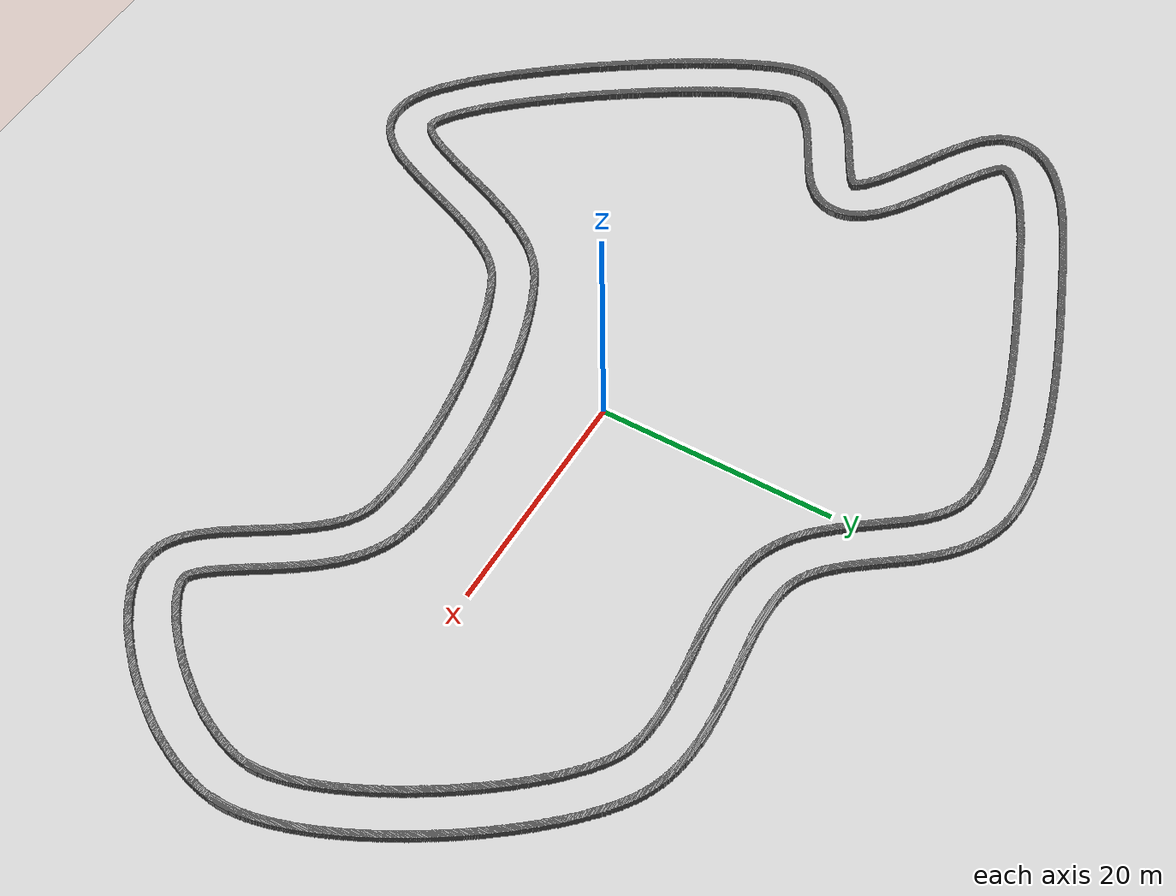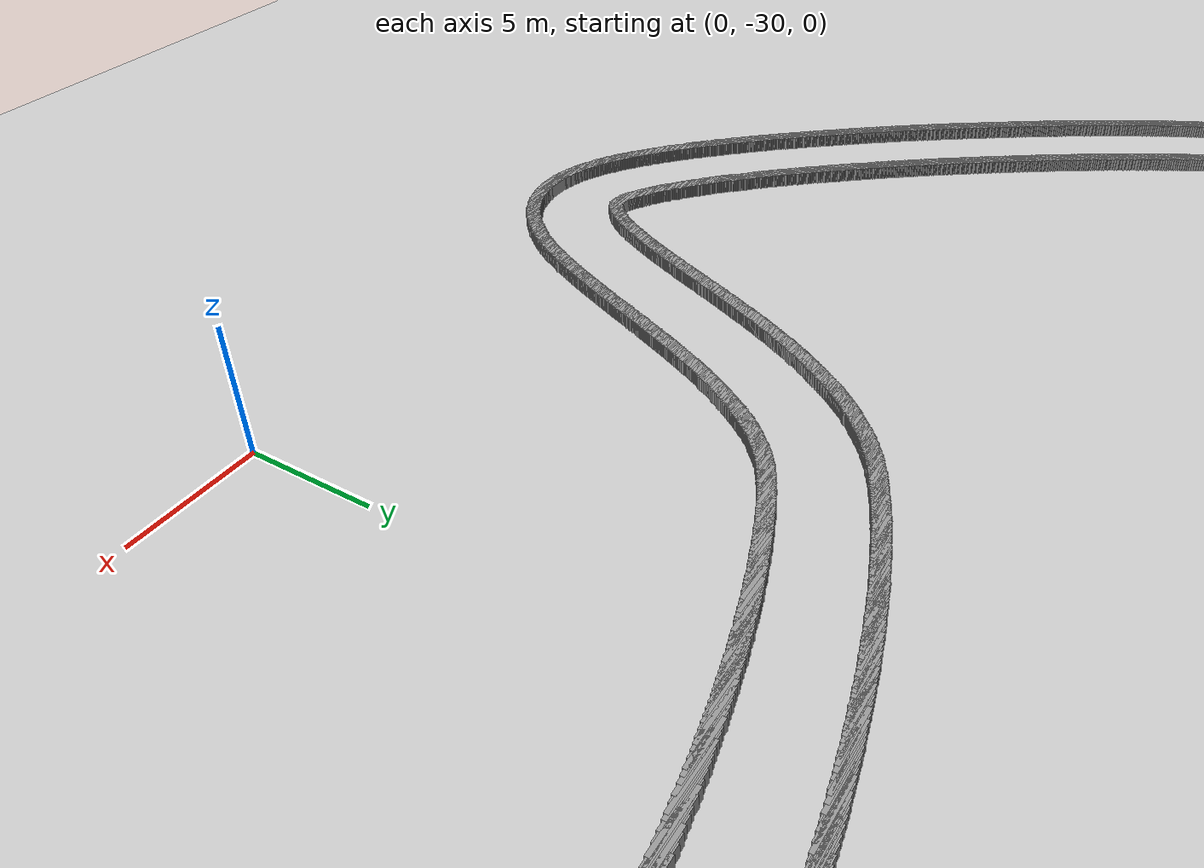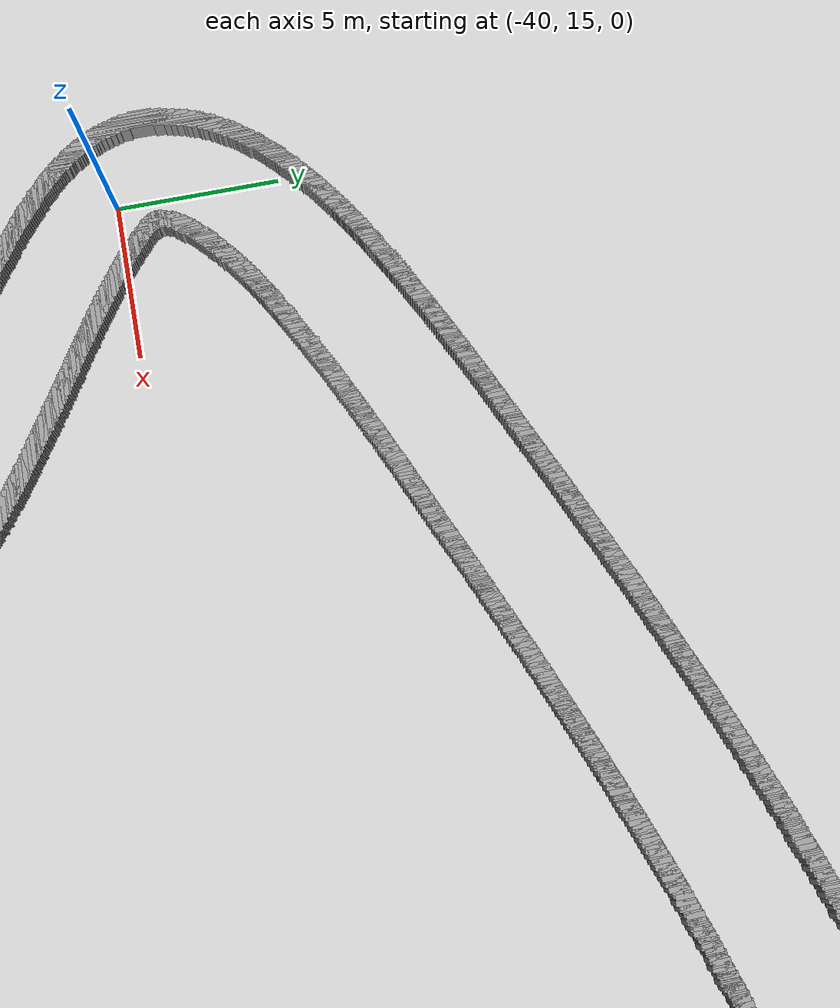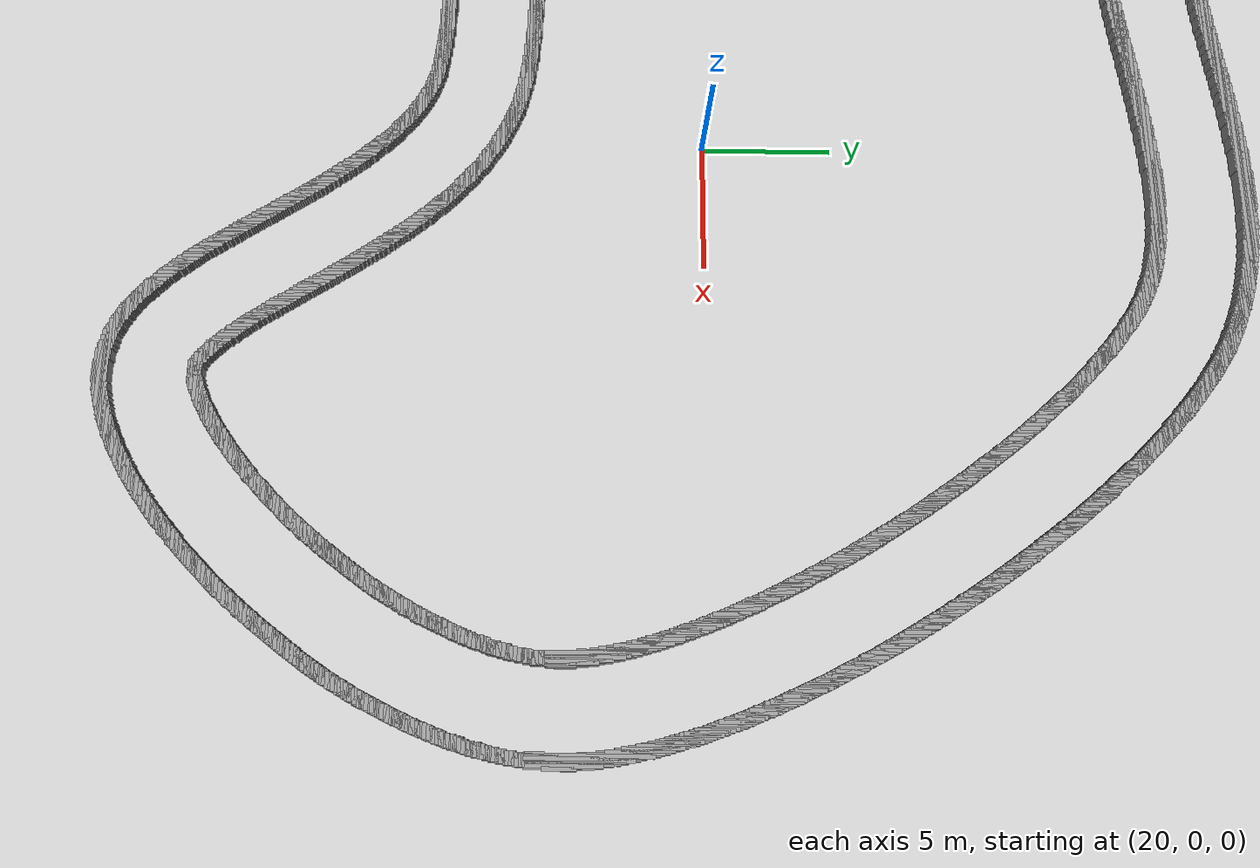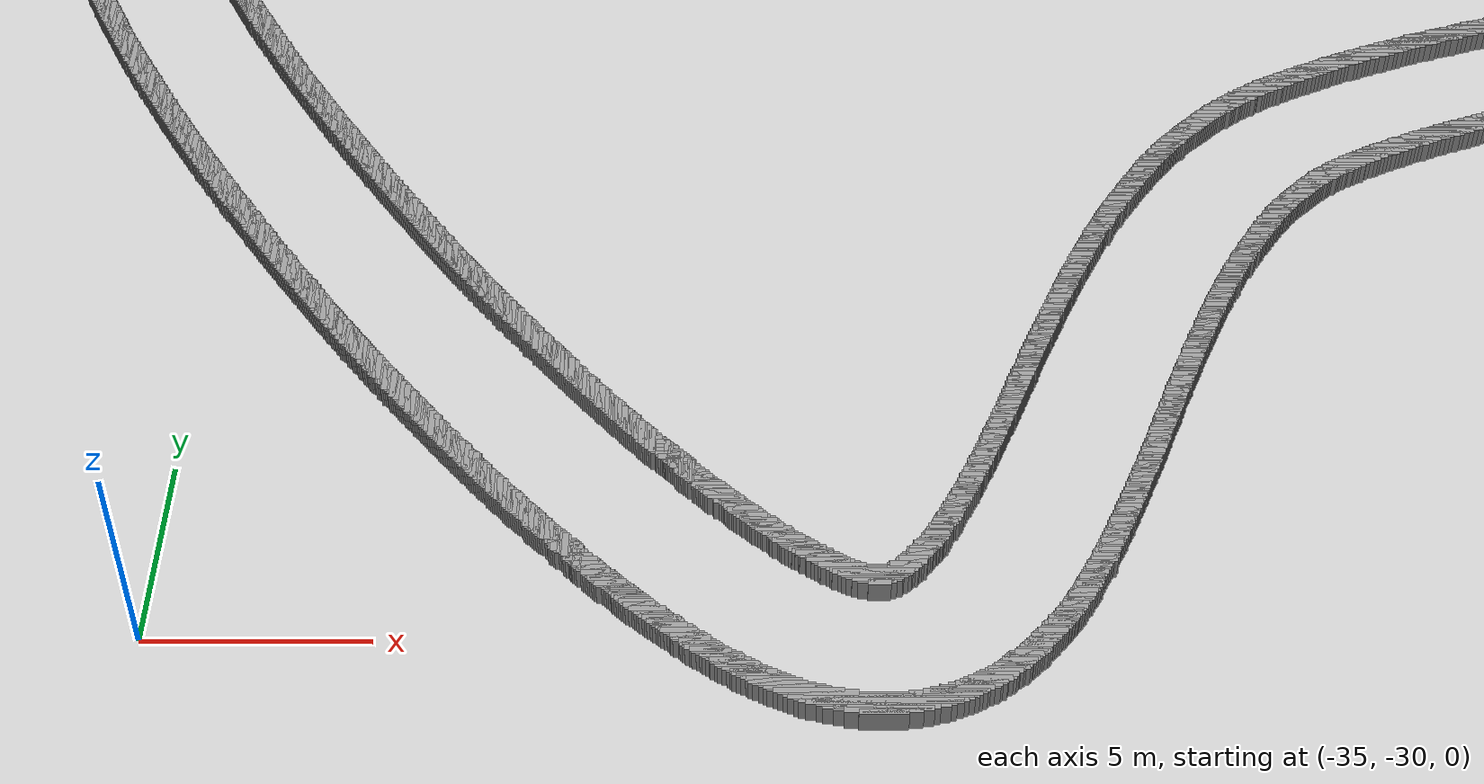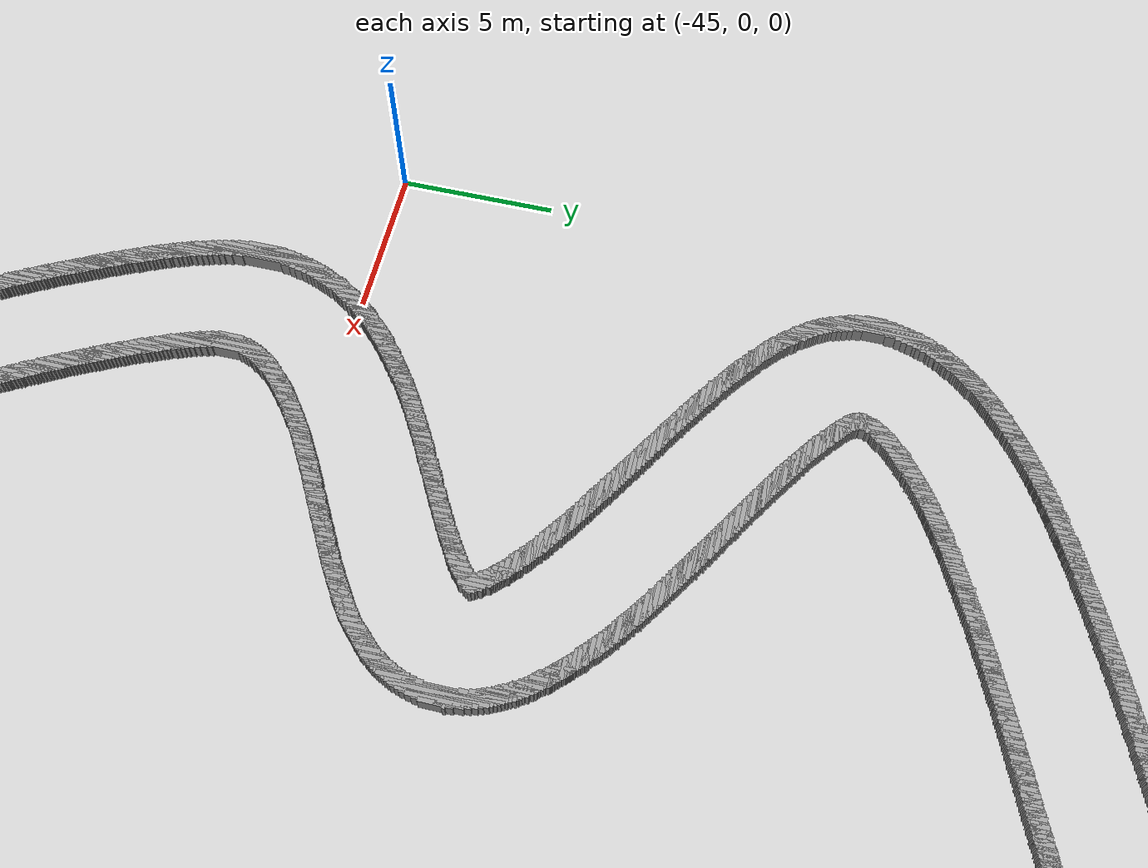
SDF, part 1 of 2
<sdf version="1.6">
 <world name="default">
  <plugin name="gazebo_ros_state" filename="libgazebo_ros_state.so">
   <ros><namespace>/gazebo</namespace></ros>
   <update_rate>1.0</update_rate>
  </plugin>
  <include><uri>model://sun</uri></include>
  <include><uri>model://ground_plane</uri></include>
  <physics type="ode">
   <real_time_update_rate>1000.0</real_time_update_rate>
   <max_step_size>0.001</max_step_size>
   <real_time_factor>1</real_time_factor>
   <ode>
    <solver>
     <type>quick</type>
     <iters>150</iters>
     <precon_iters>0</precon_iters>
     <sor>1.400000</sor>
     <use_dynamic_moi_rescaling>1</use_dynamic_moi_rescaling>
    </solver>
    <constraints>
     <cfm>0.00001</cfm>
     <erp>0.2</erp>
     <contact_max_correcting_vel>2000.000000</contact_max_correcting_vel>
     <contact_surface_layer>0.01000</contact_surface_layer>
    </constraints>
   </ode>
  </physics>
  <scene><ambient>0.4 0.4 0.4 1</ambient><background>0.7 0.7 0.7 1</background><shadows>true</shadows></scene>
  <model name="obstacle">
   <static>1</static>
   <link name="obstacle">
    <collision name="obstacle_1">
     <pose>-19.15 -32.2 0 0 0 0</pose>
     <geometry><box><size>1.05 0.15 1.0</size></box></geometry>
    </collision>
    <visual name="obstacle_1">
     <pose>-19.15 -32.2 0 0 0 0</pose>
     <geometry><box><size>1.05 0.15 1.0</size></box></geometry>
     <material>
      <script><uri>file://media/materials/scripts/gazebo.material</uri><name>Gazebo/Grey</name></script>
      <ambient>1 1 1 1</ambient>
     </material>
    </visual>
    <collision name="obstacle_2">
     <pose>-19.15 -32.150000000000006 0 0 0 0</pose>
     <geometry><box><size>1.6500000000000001 0.15 1.0</size></box></geometry>
    </collision>
    <visual name="obstacle_2">
     <pose>-19.15 -32.150000000000006 0 0 0 0</pose>
     <geometry><box><size>1.6500000000000001 0.15 1.0</size></box></geometry>
     <material>
      <script><uri>file://media/materials/scripts/gazebo.material</uri><name>Gazebo/Grey</name></script>
      <ambient>1 1 1 1</ambient>
     </material>
    </visual>
    <collision name="obstacle_3">
     <pose>-19.15 -32.1 0 0 0 0</pose>
     <geometry><box><size>2.1 0.15 1.0</size></box></geometry>
    </collision>
    <visual name="obstacle_3">
     <pose>-19.15 -32.1 0 0 0 0</pose>
     <geometry><box><size>2.1 0.15 1.0</size></box></geometry>
     <material>
      <script><uri>file://media/materials/scripts/gazebo.material</uri><name>Gazebo/Grey</name></script>
      <ambient>1 1 1 1</ambient>
     </material>
    </visual>
    <collision name="obstacle_4">
     <pose>-19.2 -32.050000000000004 0 0 0 0</pose>
     <geometry><box><size>2.45 0.15 1.0</size></box></geometry>
    </collision>
    <visual name="obstacle_4">
     <pose>-19.2 -32.050000000000004 0 0 0 0</pose>
     <geometry><box><size>2.45 0.15 1.0</size></box></geometry>
     <material>
      <script><uri>file://media/materials/scripts/gazebo.material</uri><name>Gazebo/Grey</name></script>
      <ambient>1 1 1 1</ambient>
     </material>
    </visual>
    <collision name="obstacle_5">
     <pose>-19.15 -32.0 0 0 0 0</pose>
     <geometry><box><size>2.8000000000000003 0.15 1.0</size></box></geometry>
    </collision>
    <visual name="obstacle_5">
     <pose>-19.15 -32.0 0 0 0 0</pose>
     <geometry><box><size>2.8000000000000003 0.15 1.0</size></box></geometry>
     <material>
      <script><uri>file://media/materials/scripts/gazebo.material</uri><name>Gazebo/Grey</name></script>
      <ambient>1 1 1 1</ambient>
     </material>
    </visual>
    <collision name="obstacle_6">
     <pose>-19.2 -31.950000000000003 0 0 0 0</pose>
     <geometry><box><size>3.1500000000000004 0.15 1.0</size></box></geometry>
    </collision>
    <visual name="obstacle_6">
     <pose>-19.2 -31.950000000000003 0 0 0 0</pose>
     <geometry><box><size>3.1500000000000004 0.15 1.0</size></box></geometry>
     <material>
      <script><uri>file://media/materials/scripts/gazebo.material</uri><name>Gazebo/Grey</name></script>
      <ambient>1 1 1 1</ambient>
     </material>
    </visual>
    <collision name="obstacle_7">
     <pose>-19.2 -31.900000000000002 0 0 0 0</pose>
     <geometry><box><size>3.45 0.15 1.0</size></box></geometry>
    </collision>
    <visual name="obstacle_7">
     <pose>-19.2 -31.900000000000002 0 0 0 0</pose>
     <geometry><box><size>3.45 0.15 1.0</size></box></geometry>
     <material>
      <script><uri>file://media/materials/scripts/gazebo.material</uri><name>Gazebo/Grey</name></script>
      <ambient>1 1 1 1</ambient>
     </material>
    </visual>
    <collision name="obstacle_8">
     <pose>-19.2 -31.85 0 0 0 0</pose>
     <geometry><box><size>3.6500000000000004 0.15 1.0</size></box></geometry>
    </collision>
    <visual name="obstacle_8">
     <pose>-19.2 -31.85 0 0 0 0</pose>
     <geometry><box><size>3.6500000000000004 0.15 1.0</size></box></geometry>
     <material>
      <script><uri>file://media/materials/scripts/gazebo.material</uri><name>Gazebo/Grey</name></script>
      <ambient>1 1 1 1</ambient>
     </material>
    </visual>
    <collision name="obstacle_9">
     <pose>-19.2 -31.800000000000004 0 0 0 0</pose>
     <geometry><box><size>3.9000000000000004 0.15 1.0</size></box></geometry>
    </collision>
    <visual name="obstacle_9">
     <pose>-19.2 -31.800000000000004 0 0 0 0</pose>
     <geometry><box><size>3.9000000000000004 0.15 1.0</size></box></geometry>
     <material>
      <script><uri>file://media/materials/scripts/gazebo.material</uri><name>Gazebo/Grey</name></script>
      <ambient>1 1 1 1</ambient>
     </material>
    </visual>
    <collision name="obstacle_10">
     <pose>-19.2 -31.750000000000004 0 0 0 0</pose>
     <geometry><box><size>4.1000000000000005 0.15 1.0</size></box></geometry>
    </collision>
    <visual name="obstacle_10">
     <pose>-19.2 -31.750000000000004 0 0 0 0</pose>
     <geometry><box><size>4.1000000000000005 0.15 1.0</size></box></geometry>
     <material>
      <script><uri>file://media/materials/scripts/gazebo.material</uri><name>Gazebo/Grey</name></script>
      <ambient>1 1 1 1</ambient>
     </material>
    </visual>
    <collision name="obstacle_11">
     <pose>-20.5 -31.700000000000003 0 0 0 0</pose>
     <geometry><box><size>1.7000000000000002 0.15 1.0</size></box></geometry>
    </collision>
    <visual name="obstacle_11">
     <pose>-20.5 -31.700000000000003 0 0 0 0</pose>
     <geometry><box><size>1.7000000000000002 0.15 1.0</size></box></geometry>
     <material>
      <script><uri>file://media/materials/scripts/gazebo.material</uri><name>Gazebo/Grey</name></script>
      <ambient>1 1 1 1</ambient>
     </material>
    </visual>
    <collision name="obstacle_12">
     <pose>-17.85 -31.700000000000003 0 0 0 0</pose>
     <geometry><box><size>1.55 0.15 1.0</size></box></geometry>
    </collision>
    <visual name="obstacle_12">
     <pose>-17.85 -31.700000000000003 0 0 0 0</pose>
     <geometry><box><size>1.55 0.15 1.0</size></box></geometry>
     <material>
      <script><uri>file://media/materials/scripts/gazebo.material</uri><name>Gazebo/Grey</name></script>
      <ambient>1 1 1 1</ambient>
     </material>
    </visual>
    <collision name="obstacle_13">
     <pose>-20.7 -31.650000000000002 0 0 0 0</pose>
     <geometry><box><size>1.5 0.15 1.0</size></box></geometry>
    </collision>
    <visual name="obstacle_13">
     <pose>-20.7 -31.650000000000002 0 0 0 0</pose>
     <geometry><box><size>1.5 0.15 1.0</size></box></geometry>
     <material>
      <script><uri>file://media/materials/scripts/gazebo.material</uri><name>Gazebo/Grey</name></script>
      <ambient>1 1 1 1</ambient>
     </material>
    </visual>
    <collision name="obstacle_14">
     <pose>-17.65 -31.650000000000002 0 0 0 0</pose>
     <geometry><box><size>1.35 0.15 1.0</size></box></geometry>
    </collision>
    <visual name="obstacle_14">
     <pose>-17.65 -31.650000000000002 0 0 0 0</pose>
     <geometry><box><size>1.35 0.15 1.0</size></box></geometry>
     <material>
      <script><uri>file://media/materials/scripts/gazebo.material</uri><name>Gazebo/Grey</name></script>
      <ambient>1 1 1 1</ambient>
     </material>
    </visual>
    <collision name="obstacle_15">
     <pose>-20.9 -31.6 0 0 0 0</pose>
     <geometry><box><size>1.35 0.15 1.0</size></box></geometry>
    </collision>
    <visual name="obstacle_15">
     <pose>-20.9 -31.6 0 0 0 0</pose>
     <geometry><box><size>1.35 0.15 1.0</size></box></geometry>
     <material>
      <script><uri>file://media/materials/scripts/gazebo.material</uri><name>Gazebo/Grey</name></script>
      <ambient>1 1 1 1</ambient>
     </material>
    </visual>
    <collision name="obstacle_16">
     <pose>-17.55 -31.6 0 0 0 0</pose>
     <geometry><box><size>1.25 0.15 1.0</size></box></geometry>
    </collision>
    <visual name="obstacle_16">
     <pose>-17.55 -31.6 0 0 0 0</pose>
     <geometry><box><size>1.25 0.15 1.0</size></box></geometry>
     <material>
      <script><uri>file://media/materials/scripts/gazebo.material</uri><name>Gazebo/Grey</name></script>
      <ambient>1 1 1 1</ambient>
     </material>
    </visual>
    <collision name="obstacle_17">
     <pose>-21.0 -31.550000000000004 0 0 0 0</pose>
     <geometry><box><size>1.3 0.15 1.0</size></box></geometry>
    </collision>
    <visual name="obstacle_17">
     <pose>-21.0 -31.550000000000004 0 0 0 0</pose>
     <geometry><box><size>1.3 0.15 1.0</size></box></geometry>
     <material>
      <script><uri>file://media/materials/scripts/gazebo.material</uri><name>Gazebo/Grey</name></script>
      <ambient>1 1 1 1</ambient>
     </material>
    </visual>
    <collision name="obstacle_18">
     <pose>-17.4 -31.550000000000004 0 0 0 0</pose>
     <geometry><box><size>1.1500000000000001 0.15 1.0</size></box></geometry>
    </collision>
    <visual name="obstacle_18">
     <pose>-17.4 -31.550000000000004 0 0 0 0</pose>
     <geometry><box><size>1.1500000000000001 0.15 1.0</size></box></geometry>
     <material>
      <script><uri>file://media/materials/scripts/gazebo.material</uri><name>Gazebo/Grey</name></script>
      <ambient>1 1 1 1</ambient>
     </material>
    </visual>
    <collision name="obstacle_19">
     <pose>-21.15 -31.500000000000004 0 0 0 0</pose>
     <geometry><box><size>1.2000000000000002 0.15 1.0</size></box></geometry>
    </collision>
    <visual name="obstacle_19">
     <pose>-21.15 -31.500000000000004 0 0 0 0</pose>
     <geometry><box><size>1.2000000000000002 0.15 1.0</size></box></geometry>
     <material>
      <script><uri>file://media/materials/scripts/gazebo.material</uri><name>Gazebo/Grey</name></script>
      <ambient>1 1 1 1</ambient>
     </material>
    </visual>
    <collision name="obstacle_20">
     <pose>-17.25 -31.500000000000004 0 0 0 0</pose>
     <geometry><box><size>1.1 0.15 1.0</size></box></geometry>
    </collision>
    <visual name="obstacle_20">
     <pose>-17.25 -31.500000000000004 0 0 0 0</pose>
     <geometry><box><size>1.1 0.15 1.0</size></box></geometry>
     <material>
      <script><uri>file://media/materials/scripts/gazebo.material</uri><name>Gazebo/Grey</name></script>
      <ambient>1 1 1 1</ambient>
     </material>
    </visual>
    <collision name="obstacle_21">
     <pose>-21.3 -31.450000000000003 0 0 0 0</pose>
     <geometry><box><size>1.1500000000000001 0.15 1.0</size></box></geometry>
    </collision>
    <visual name="obstacle_21">
     <pose>-21.3 -31.450000000000003 0 0 0 0</pose>
     <geometry><box><size>1.1500000000000001 0.15 1.0</size></box></geometry>
     <material>
      <script><uri>file://media/materials/scripts/gazebo.material</uri><name>Gazebo/Grey</name></script>
      <ambient>1 1 1 1</ambient>
     </material>
    </visual>
    <collision name="obstacle_22">
     <pose>-17.15 -31.450000000000003 0 0 0 0</pose>
     <geometry><box><size>1.0 0.15 1.0</size></box></geometry>
    </collision>
    <visual name="obstacle_22">
     <pose>-17.15 -31.450000000000003 0 0 0 0</pose>
     <geometry><box><size>1.0 0.15 1.0</size></box></geometry>
     <material>
      <script><uri>file://media/materials/scripts/gazebo.material</uri><name>Gazebo/Grey</name></script>
      <ambient>1 1 1 1</ambient>
     </material>
    </visual>
    <collision name="obstacle_23">
     <pose>-21.4 -31.400000000000002 0 0 0 0</pose>
     <geometry><box><size>1.1500000000000001 0.15 1.0</size></box></geometry>
    </collision>
    <visual name="obstacle_23">
     <pose>-21.4 -31.400000000000002 0 0 0 0</pose>
     <geometry><box><size>1.1500000000000001 0.15 1.0</size></box></geometry>
     <material>
      <script><uri>file://media/materials/scripts/gazebo.material</uri><name>Gazebo/Grey</name></script>
      <ambient>1 1 1 1</ambient>
     </material>
    </visual>
    <collision name="obstacle_24">
     <pose>-17.05 -31.400000000000002 0 0 0 0</pose>
     <geometry><box><size>1.0 0.15 1.0</size></box></geometry>
    </collision>
    <visual name="obstacle_24">
     <pose>-17.05 -31.400000000000002 0 0 0 0</pose>
     <geometry><box><size>1.0 0.15 1.0</size></box></geometry>
     <material>
      <script><uri>file://media/materials/scripts/gazebo.material</uri><name>Gazebo/Grey</name></script>
      <ambient>1 1 1 1</ambient>
     </material>
    </visual>
    <collision name="obstacle_25">
     <pose>-21.5 -31.35 0 0 0 0</pose>
     <geometry><box><size>1.05 0.15 1.0</size></box></geometry>
    </collision>
    <visual name="obstacle_25">
     <pose>-21.5 -31.35 0 0 0 0</pose>
     <geometry><box><size>1.05 0.15 1.0</size></box></geometry>
     <material>
      <script><uri>file://media/materials/scripts/gazebo.material</uri><name>Gazebo/Grey</name></script>
      <ambient>1 1 1 1</ambient>
     </material>
    </visual>
    <collision name="obstacle_26">
     <pose>-17.0 -31.35 0 0 0 0</pose>
     <geometry><box><size>0.9500000000000001 0.15 1.0</size></box></geometry>
    </collision>
    <visual name="obstacle_26">
     <pose>-17.0 -31.35 0 0 0 0</pose>
     <geometry><box><size>0.9500000000000001 0.15 1.0</size></box></geometry>
     <material>
      <script><uri>file://media/materials/scripts/gazebo.material</uri><name>Gazebo/Grey</name></script>
      <ambient>1 1 1 1</ambient>
     </material>
    </visual>
    <collision name="obstacle_27">
     <pose>-21.6 -31.300000000000004 0 0 0 0</pose>
     <geometry><box><size>1.05 0.15 1.0</size></box></geometry>
    </collision>
    <visual name="obstacle_27">
     <pose>-21.6 -31.300000000000004 0 0 0 0</pose>
     <geometry><box><size>1.05 0.15 1.0</size></box></geometry>
     <material>
      <script><uri>file://media/materials/scripts/gazebo.material</uri><name>Gazebo/Grey</name></script>
      <ambient>1 1 1 1</ambient>
     </material>
    </visual>
    <collision name="obstacle_28">
     <pose>-16.9 -31.300000000000004 0 0 0 0</pose>
     <geometry><box><size>0.9500000000000001 0.15 1.0</size></box></geometry>
    </collision>
    <visual name="obstacle_28">
     <pose>-16.9 -31.300000000000004 0 0 0 0</pose>
     <geometry><box><size>0.9500000000000001 0.15 1.0</size></box></geometry>
     <material>
      <script><uri>file://media/materials/scripts/gazebo.material</uri><name>Gazebo/Grey</name></script>
      <ambient>1 1 1 1</ambient>
     </material>
    </visual>
    <collision name="obstacle_29">
     <pose>-21.7 -31.250000000000004 0 0 0 0</pose>
     <geometry><box><size>1.05 0.15 1.0</size></box></geometry>
    </collision>
    <visual name="obstacle_29">
     <pose>-21.7 -31.250000000000004 0 0 0 0</pose>
     <geometry><box><size>1.05 0.15 1.0</size></box></geometry>
     <material>
      <script><uri>file://media/materials/scripts/gazebo.material</uri><name>Gazebo/Grey</name></script>
      <ambient>1 1 1 1</ambient>
     </material>
    </visual>
    <collision name="obstacle_30">
     <pose>-16.8 -31.250000000000004 0 0 0 0</pose>
     <geometry><box><size>0.9 0.15 1.0</size></box></geometry>
    </collision>
    <visual name="obstacle_30">
     <pose>-16.8 -31.250000000000004 0 0 0 0</pose>
     <geometry><box><size>0.9 0.15 1.0</size></box></geometry>
     <material>
      <script><uri>file://media/materials/scripts/gazebo.material</uri><name>Gazebo/Grey</name></script>
      <ambient>1 1 1 1</ambient>
     </material>
    </visual>
    <collision name="obstacle_31">
     <pose>-21.8 -31.200000000000003 0 0 0 0</pose>
     <geometry><box><size>1.05 0.15 1.0</size></box></geometry>
    </collision>
    <visual name="obstacle_31">
     <pose>-21.8 -31.200000000000003 0 0 0 0</pose>
     <geometry><box><size>1.05 0.15 1.0</size></box></geometry>
     <material>
      <script><uri>file://media/materials/scripts/gazebo.material</uri><name>Gazebo/Grey</name></script>
      <ambient>1 1 1 1</ambient>
     </material>
    </visual>
    <collision name="obstacle_32">
     <pose>-16.75 -31.200000000000003 0 0 0 0</pose>
     <geometry><box><size>0.9 0.15 1.0</size></box></geometry>
    </collision>
    <visual name="obstacle_32">
     <pose>-16.75 -31.200000000000003 0 0 0 0</pose>
     <geometry><box><size>0.9 0.15 1.0</size></box></geometry>
     <material>
      <script><uri>file://media/materials/scripts/gazebo.material</uri><name>Gazebo/Grey</name></script>
      <ambient>1 1 1 1</ambient>
     </material>
    </visual>
    <collision name="obstacle_33">
     <pose>-21.85 -31.150000000000002 0 0 0 0</pose>
     <geometry><box><size>1.0 0.15 1.0</size></box></geometry>
    </collision>
    <visual name="obstacle_33">
     <pose>-21.85 -31.150000000000002 0 0 0 0</pose>
     <geometry><box><size>1.0 0.15 1.0</size></box></geometry>
     <material>
      <script><uri>file://media/materials/scripts/gazebo.material</uri><name>Gazebo/Grey</name></script>
      <ambient>1 1 1 1</ambient>
     </material>
    </visual>
    <collision name="obstacle_34">
     <pose>-16.7 -31.150000000000002 0 0 0 0</pose>
     <geometry><box><size>0.8500000000000001 0.15 1.0</size></box></geometry>
    </collision>
    <visual name="obstacle_34">
     <pose>-16.7 -31.150000000000002 0 0 0 0</pose>
     <geometry><box><size>0.8500000000000001 0.15 1.0</size></box></geometry>
     <material>
      <script><uri>file://media/materials/scripts/gazebo.material</uri><name>Gazebo/Grey</name></script>
      <ambient>1 1 1 1</ambient>
     </material>
    </visual>
    <collision name="obstacle_35">
     <pose>-21.95 -31.1 0 0 0 0</pose>
     <geometry><box><size>0.9500000000000001 0.15 1.0</size></box></geometry>
    </collision>
    <visual name="obstacle_35">
     <pose>-21.95 -31.1 0 0 0 0</pose>
     <geometry><box><size>0.9500000000000001 0.15 1.0</size></box></geometry>
     <material>
      <script><uri>file://media/materials/scripts/gazebo.material</uri><name>Gazebo/Grey</name></script>
      <ambient>1 1 1 1</ambient>
     </material>
    </visual>
    <collision name="obstacle_36">
     <pose>-16.6 -31.1 0 0 0 0</pose>
     <geometry><box><size>0.8 0.15 1.0</size></box></geometry>
    </collision>
    <visual name="obstacle_36">
     <pose>-16.6 -31.1 0 0 0 0</pose>
     <geometry><box><size>0.8 0.15 1.0</size></box></geometry>
     <material>
      <script><uri>file://media/materials/scripts/gazebo.material</uri><name>Gazebo/Grey</name></script>
      <ambient>1 1 1 1</ambient>
     </material>
    </visual>
    <collision name="obstacle_37">
     <pose>-22.05 -31.050000000000004 0 0 0 0</pose>
     <geometry><box><size>0.9500000000000001 0.15 1.0</size></box></geometry>
    </collision>
    <visual name="obstacle_37">
     <pose>-22.05 -31.050000000000004 0 0 0 0</pose>
     <geometry><box><size>0.9500000000000001 0.15 1.0</size></box></geometry>
     <material>
      <script><uri>file://media/materials/scripts/gazebo.material</uri><name>Gazebo/Grey</name></script>
      <ambient>1 1 1 1</ambient>
     </material>
    </visual>
    <collision name="obstacle_38">
     <pose>-16.55 -31.050000000000004 0 0 0 0</pose>
     <geometry><box><size>0.8 0.15 1.0</size></box></geometry>
    </collision>
    <visual name="obstacle_38">
     <pose>-16.55 -31.050000000000004 0 0 0 0</pose>
     <geometry><box><size>0.8 0.15 1.0</size></box></geometry>
     <material>
      <script><uri>file://media/materials/scripts/gazebo.material</uri><name>Gazebo/Grey</name></script>
      <ambient>1 1 1 1</ambient>
     </material>
    </visual>
    <collision name="obstacle_39">
     <pose>-22.15 -31.000000000000004 0 0 0 0</pose>
     <geometry><box><size>0.9500000000000001 0.15 1.0</size></box></geometry>
    </collision>
    <visual name="obstacle_39">
     <pose>-22.15 -31.000000000000004 0 0 0 0</pose>
     <geometry><box><size>0.9500000000000001 0.15 1.0</size></box></geometry>
     <material>
      <script><uri>file://media/materials/scripts/gazebo.material</uri><name>Gazebo/Grey</name></script>
      <ambient>1 1 1 1</ambient>
     </material>
    </visual>
    <collision name="obstacle_40">
     <pose>-16.45 -31.000000000000004 0 0 0 0</pose>
     <geometry><box><size>0.8 0.15 1.0</size></box></geometry>
    </collision>
    <visual name="obstacle_40">
     <pose>-16.45 -31.000000000000004 0 0 0 0</pose>
     <geometry><box><size>0.8 0.15 1.0</size></box></geometry>
     <material>
      <script><uri>file://media/materials/scripts/gazebo.material</uri><name>Gazebo/Grey</name></script>
      <ambient>1 1 1 1</ambient>
     </material>
    </visual>
    <collision name="obstacle_41">
     <pose>-22.2 -30.950000000000003 0 0 0 0</pose>
     <geometry><box><size>0.9500000000000001 0.15 1.0</size></box></geometry>
    </collision>
    <visual name="obstacle_41">
     <pose>-22.2 -30.950000000000003 0 0 0 0</pose>
     <geometry><box><size>0.9500000000000001 0.15 1.0</size></box></geometry>
     <material>
      <script><uri>file://media/materials/scripts/gazebo.material</uri><name>Gazebo/Grey</name></script>
      <ambient>1 1 1 1</ambient>
     </material>
    </visual>
    <collision name="obstacle_42">
     <pose>-16.4 -30.950000000000003 0 0 0 0</pose>
     <geometry><box><size>0.8 0.15 1.0</size></box></geometry>
    </collision>
    <visual name="obstacle_42">
     <pose>-16.4 -30.950000000000003 0 0 0 0</pose>
     <geometry><box><size>0.8 0.15 1.0</size></box></geometry>
     <material>
      <script><uri>file://media/materials/scripts/gazebo.material</uri><name>Gazebo/Grey</name></script>
      <ambient>1 1 1 1</ambient>
     </material>
    </visual>
    <collision name="obstacle_43">
     <pose>-22.3 -30.900000000000002 0 0 0 0</pose>
     <geometry><box><size>0.9500000000000001 0.15 1.0</size></box></geometry>
    </collision>
    <visual name="obstacle_43">
     <pose>-22.3 -30.900000000000002 0 0 0 0</pose>
     <geometry><box><size>0.9500000000000001 0.15 1.0</size></box></geometry>
     <material>
      <script><uri>file://media/materials/scripts/gazebo.material</uri><name>Gazebo/Grey</name></script>
      <ambient>1 1 1 1</ambient>
     </material>
    </visual>
    <collision name="obstacle_44">
     <pose>-16.35 -30.900000000000002 0 0 0 0</pose>
     <geometry><box><size>0.75 0.15 1.0</size></box></geometry>
    </collision>
    <visual name="obstacle_44">
     <pose>-16.35 -30.900000000000002 0 0 0 0</pose>
     <geometry><box><size>0.75 0.15 1.0</size></box></geometry>
     <material>
      <script><uri>file://media/materials/scripts/gazebo.material</uri><name>Gazebo/Grey</name></script>
      <ambient>1 1 1 1</ambient>
     </material>
    </visual>
    <collision name="obstacle_45">
     <pose>-22.35 -30.85 0 0 0 0</pose>
     <geometry><box><size>0.9 0.15 1.0</size></box></geometry>
    </collision>
    <visual name="obstacle_45">
     <pose>-22.35 -30.85 0 0 0 0</pose>
     <geometry><box><size>0.9 0.15 1.0</size></box></geometry>
     <material>
      <script><uri>file://media/materials/scripts/gazebo.material</uri><name>Gazebo/Grey</name></script>
      <ambient>1 1 1 1</ambient>
     </material>
    </visual>
    <collision name="obstacle_46">
     <pose>-16.3 -30.85 0 0 0 0</pose>
     <geometry><box><size>0.75 0.15 1.0</size></box></geometry>
    </collision>
    <visual name="obstacle_46">
     <pose>-16.3 -30.85 0 0 0 0</pose>
     <geometry><box><size>0.75 0.15 1.0</size></box></geometry>
     <material>
      <script><uri>file://media/materials/scripts/gazebo.material</uri><name>Gazebo/Grey</name></script>
      <ambient>1 1 1 1</ambient>
     </material>
    </visual>
    <collision name="obstacle_47">
     <pose>-22.45 -30.800000000000004 0 0 0 0</pose>
     <geometry><box><size>0.8500000000000001 0.15 1.0</size></box></geometry>
    </collision>
    <visual name="obstacle_47">
     <pose>-22.45 -30.800000000000004 0 0 0 0</pose>
     <geometry><box><size>0.8500000000000001 0.15 1.0</size></box></geometry>
     <material>
      <script><uri>file://media/materials/scripts/gazebo.material</uri><name>Gazebo/Grey</name></script>
      <ambient>1 1 1 1</ambient>
     </material>
    </visual>
    <collision name="obstacle_48">
     <pose>-16.25 -30.800000000000004 0 0 0 0</pose>
     <geometry><box><size>0.75 0.15 1.0</size></box></geometry>
    </collision>
    <visual name="obstacle_48">
     <pose>-16.25 -30.800000000000004 0 0 0 0</pose>
     <geometry><box><size>0.75 0.15 1.0</size></box></geometry>
     <material>
      <script><uri>file://media/materials/scripts/gazebo.material</uri><name>Gazebo/Grey</name></script>
      <ambient>1 1 1 1</ambient>
     </material>
    </visual>
    <collision name="obstacle_49">
     <pose>-22.5 -30.750000000000004 0 0 0 0</pose>
     <geometry><box><size>0.9 0.15 1.0</size></box></geometry>
    </collision>
    <visual name="obstacle_49">
     <pose>-22.5 -30.750000000000004 0 0 0 0</pose>
     <geometry><box><size>0.9 0.15 1.0</size></box></geometry>
     <material>
      <script><uri>file://media/materials/scripts/gazebo.material</uri><name>Gazebo/Grey</name></script>
      <ambient>1 1 1 1</ambient>
     </material>
    </visual>
    <collision name="obstacle_50">
     <pose>-16.2 -30.750000000000004 0 0 0 0</pose>
     <geometry><box><size>0.75 0.15 1.0</size></box></geometry>
    </collision>
    <visual name="obstacle_50">
     <pose>-16.2 -30.750000000000004 0 0 0 0</pose>
     <geometry><box><size>0.75 0.15 1.0</size></box></geometry>
     <material>
      <script><uri>file://media/materials/scripts/gazebo.material</uri><name>Gazebo/Grey</name></script>
      <ambient>1 1 1 1</ambient>
     </material>
    </visual>
    <collision name="obstacle_51">
     <pose>-22.55 -30.700000000000003 0 0 0 0</pose>
     <geometry><box><size>0.9 0.15 1.0</size></box></geometry>
    </collision>
    <visual name="obstacle_51">
     <pose>-22.55 -30.700000000000003 0 0 0 0</pose>
     <geometry><box><size>0.9 0.15 1.0</size></box></geometry>
     <material>
      <script><uri>file://media/materials/scripts/gazebo.material</uri><name>Gazebo/Grey</name></script>
      <ambient>1 1 1 1</ambient>
     </material>
    </visual>
    <collision name="obstacle_52">
     <pose>-16.15 -30.700000000000003 0 0 0 0</pose>
     <geometry><box><size>0.75 0.15 1.0</size></box></geometry>
    </collision>
    <visual name="obstacle_52">
     <pose>-16.15 -30.700000000000003 0 0 0 0</pose>
     <geometry><box><size>0.75 0.15 1.0</size></box></geometry>
     <material>
      <script><uri>file://media/materials/scripts/gazebo.material</uri><name>Gazebo/Grey</name></script>
      <ambient>1 1 1 1</ambient>
     </material>
    </visual>
    <collision name="obstacle_53">
     <pose>-22.65 -30.650000000000002 0 0 0 0</pose>
     <geometry><box><size>0.8500000000000001 0.15 1.0</size></box></geometry>
    </collision>
    <visual name="obstacle_53">
     <pose>-22.65 -30.650000000000002 0 0 0 0</pose>
     <geometry><box><size>0.8500000000000001 0.15 1.0</size></box></geometry>
     <material>
      <script><uri>file://media/materials/scripts/gazebo.material</uri><name>Gazebo/Grey</name></script>
      <ambient>1 1 1 1</ambient>
     </material>
    </visual>
    <collision name="obstacle_54">
     <pose>-16.1 -30.650000000000002 0 0 0 0</pose>
     <geometry><box><size>0.75 0.15 1.0</size></box></geometry>
    </collision>
    <visual name="obstacle_54">
     <pose>-16.1 -30.650000000000002 0 0 0 0</pose>
     <geometry><box><size>0.75 0.15 1.0</size></box></geometry>
     <material>
      <script><uri>file://media/materials/scripts/gazebo.material</uri><name>Gazebo/Grey</name></script>
      <ambient>1 1 1 1</ambient>
     </material>
    </visual>
    <collision name="obstacle_55">
     <pose>-22.75 -30.6 0 0 0 0</pose>
     <geometry><box><size>0.8500000000000001 0.15 1.0</size></box></geometry>
    </collision>
    <visual name="obstacle_55">
     <pose>-22.75 -30.6 0 0 0 0</pose>
     <geometry><box><size>0.8500000000000001 0.15 1.0</size></box></geometry>
     <material>
      <script><uri>file://media/materials/scripts/gazebo.material</uri><name>Gazebo/Grey</name></script>
      <ambient>1 1 1 1</ambient>
     </material>
    </visual>
    <collision name="obstacle_56">
     <pose>-16.0 -30.6 0 0 0 0</pose>
     <geometry><box><size>0.7000000000000001 0.15 1.0</size></box></geometry>
    </collision>
    <visual name="obstacle_56">
     <pose>-16.0 -30.6 0 0 0 0</pose>
     <geometry><box><size>0.7000000000000001 0.15 1.0</size></box></geometry>
     <material>
      <script><uri>file://media/materials/scripts/gazebo.material</uri><name>Gazebo/Grey</name></script>
      <ambient>1 1 1 1</ambient>
     </material>
    </visual>
    <collision name="obstacle_57">
     <pose>-22.8 -30.550000000000004 0 0 0 0</pose>
     <geometry><box><size>0.8500000000000001 0.15 1.0</size></box></geometry>
    </collision>
    <visual name="obstacle_57">
     <pose>-22.8 -30.550000000000004 0 0 0 0</pose>
     <geometry><box><size>0.8500000000000001 0.15 1.0</size></box></geometry>
     <material>
      <script><uri>file://media/materials/scripts/gazebo.material</uri><name>Gazebo/Grey</name></script>
      <ambient>1 1 1 1</ambient>
     </material>
    </visual>
    <collision name="obstacle_58">
     <pose>-15.95 -30.550000000000004 0 0 0 0</pose>
     <geometry><box><size>0.7000000000000001 0.15 1.0</size></box></geometry>
    </collision>
    <visual name="obstacle_58">
     <pose>-15.95 -30.550000000000004 0 0 0 0</pose>
     <geometry><box><size>0.7000000000000001 0.15 1.0</size></box></geometry>
     <material>
      <script><uri>file://media/materials/scripts/gazebo.material</uri><name>Gazebo/Grey</name></script>
      <ambient>1 1 1 1</ambient>
     </material>
    </visual>
    <collision name="obstacle_59">
     <pose>-22.9 -30.500000000000004 0 0 0 0</pose>
     <geometry><box><size>0.8500000000000001 0.15 1.0</size></box></geometry>
    </collision>
    <visual name="obstacle_59">
     <pose>-22.9 -30.500000000000004 0 0 0 0</pose>
     <geometry><box><size>0.8500000000000001 0.15 1.0</size></box></geometry>
     <material>
      <script><uri>file://media/materials/scripts/gazebo.material</uri><name>Gazebo/Grey</name></script>
      <ambient>1 1 1 1</ambient>
     </material>
    </visual>
    <collision name="obstacle_60">
     <pose>-15.899999999999999 -30.500000000000004 0 0 0 0</pose>
     <geometry><box><size>0.7000000000000001 0.15 1.0</size></box></geometry>
    </collision>
    <visual name="obstacle_60">
     <pose>-15.899999999999999 -30.500000000000004 0 0 0 0</pose>
     <geometry><box><size>0.7000000000000001 0.15 1.0</size></box></geometry>
     <material>
      <script><uri>file://media/materials/scripts/gazebo.material</uri><name>Gazebo/Grey</name></script>
      <ambient>1 1 1 1</ambient>
     </material>
    </visual>
    <collision name="obstacle_61">
     <pose>-22.95 -30.450000000000003 0 0 0 0</pose>
     <geometry><box><size>0.8500000000000001 0.15 1.0</size></box></geometry>
    </collision>
    <visual name="obstacle_61">
     <pose>-22.95 -30.450000000000003 0 0 0 0</pose>
     <geometry><box><size>0.8500000000000001 0.15 1.0</size></box></geometry>
     <material>
      <script><uri>file://media/materials/scripts/gazebo.material</uri><name>Gazebo/Grey</name></script>
      <ambient>1 1 1 1</ambient>
     </material>
    </visual>
    <collision name="obstacle_62">
     <pose>-15.899999999999999 -30.450000000000003 0 0 0 0</pose>
     <geometry><box><size>0.65 0.15 1.0</size></box></geometry>
    </collision>
    <visual name="obstacle_62">
     <pose>-15.899999999999999 -30.450000000000003 0 0 0 0</pose>
     <geometry><box><size>0.65 0.15 1.0</size></box></geometry>
     <material>
      <script><uri>file://media/materials/scripts/gazebo.material</uri><name>Gazebo/Grey</name></script>
      <ambient>1 1 1 1</ambient>
     </material>
    </visual>
    <collision name="obstacle_63">
     <pose>-23.0 -30.400000000000002 0 0 0 0</pose>
     <geometry><box><size>0.8500000000000001 0.15 1.0</size></box></geometry>
    </collision>
    <visual name="obstacle_63">
     <pose>-23.0 -30.400000000000002 0 0 0 0</pose>
     <geometry><box><size>0.8500000000000001 0.15 1.0</size></box></geometry>
     <material>
      <script><uri>file://media/materials/scripts/gazebo.material</uri><name>Gazebo/Grey</name></script>
      <ambient>1 1 1 1</ambient>
     </material>
    </visual>
    <collision name="obstacle_64">
     <pose>-15.850000000000001 -30.400000000000002 0 0 0 0</pose>
     <geometry><box><size>0.65 0.15 1.0</size></box></geometry>
    </collision>
    <visual name="obstacle_64">
     <pose>-15.850000000000001 -30.400000000000002 0 0 0 0</pose>
     <geometry><box><size>0.65 0.15 1.0</size></box></geometry>
     <material>
      <script><uri>file://media/materials/scripts/gazebo.material</uri><name>Gazebo/Grey</name></script>
      <ambient>1 1 1 1</ambient>
     </material>
    </visual>
    <collision name="obstacle_65">
     <pose>-23.05 -30.35 0 0 0 0</pose>
     <geometry><box><size>0.8 0.15 1.0</size></box></geometry>
    </collision>
    <visual name="obstacle_65">
     <pose>-23.05 -30.35 0 0 0 0</pose>
     <geometry><box><size>0.8 0.15 1.0</size></box></geometry>
     <material>
      <script><uri>file://media/materials/scripts/gazebo.material</uri><name>Gazebo/Grey</name></script>
      <ambient>1 1 1 1</ambient>
     </material>
    </visual>
    <collision name="obstacle_66">
     <pose>-15.8 -30.35 0 0 0 0</pose>
     <geometry><box><size>0.65 0.15 1.0</size></box></geometry>
    </collision>
    <visual name="obstacle_66">
     <pose>-15.8 -30.35 0 0 0 0</pose>
     <geometry><box><size>0.65 0.15 1.0</size></box></geometry>
     <material>
      <script><uri>file://media/materials/scripts/gazebo.material</uri><name>Gazebo/Grey</name></script>
      <ambient>1 1 1 1</ambient>
     </material>
    </visual>
    <collision name="obstacle_67">
     <pose>-23.15 -30.300000000000004 0 0 0 0</pose>
     <geometry><box><size>0.8500000000000001 0.15 1.0</size></box></geometry>
    </collision>
    <visual name="obstacle_67">
     <pose>-23.15 -30.300000000000004 0 0 0 0</pose>
     <geometry><box><size>0.8500000000000001 0.15 1.0</size></box></geometry>
     <material>
      <script><uri>file://media/materials/scripts/gazebo.material</uri><name>Gazebo/Grey</name></script>
      <ambient>1 1 1 1</ambient>
     </material>
    </visual>
    <collision name="obstacle_68">
     <pose>-15.75 -30.300000000000004 0 0 0 0</pose>
     <geometry><box><size>0.65 0.15 1.0</size></box></geometry>
    </collision>
    <visual name="obstacle_68">
     <pose>-15.75 -30.300000000000004 0 0 0 0</pose>
     <geometry><box><size>0.65 0.15 1.0</size></box></geometry>
     <material>
      <script><uri>file://media/materials/scripts/gazebo.material</uri><name>Gazebo/Grey</name></script>
      <ambient>1 1 1 1</ambient>
     </material>
    </visual>
    <collision name="obstacle_69">
     <pose>-23.2 -30.250000000000004 0 0 0 0</pose>
     <geometry><box><size>0.8500000000000001 0.15 1.0</size></box></geometry>
    </collision>
    <visual name="obstacle_69">
     <pose>-23.2 -30.250000000000004 0 0 0 0</pose>
     <geometry><box><size>0.8500000000000001 0.15 1.0</size></box></geometry>
     <material>
      <script><uri>file://media/materials/scripts/gazebo.material</uri><name>Gazebo/Grey</name></script>
      <ambient>1 1 1 1</ambient>
     </material>
    </visual>
    <collision name="obstacle_70">
     <pose>-15.7 -30.250000000000004 0 0 0 0</pose>
     <geometry><box><size>0.65 0.15 1.0</size></box></geometry>
    </collision>
    <visual name="obstacle_70">
     <pose>-15.7 -30.250000000000004 0 0 0 0</pose>
     <geometry><box><size>0.65 0.15 1.0</size></box></geometry>
     <material>
      <script><uri>file://media/materials/scripts/gazebo.material</uri><name>Gazebo/Grey</name></script>
      <ambient>1 1 1 1</ambient>
     </material>
    </visual>
    <collision name="obstacle_71">
     <pose>-23.25 -30.200000000000003 0 0 0 0</pose>
     <geometry><box><size>0.8 0.15 1.0</size></box></geometry>
    </collision>
    <visual name="obstacle_71">
     <pose>-23.25 -30.200000000000003 0 0 0 0</pose>
     <geometry><box><size>0.8 0.15 1.0</size></box></geometry>
     <material>
      <script><uri>file://media/materials/scripts/gazebo.material</uri><name>Gazebo/Grey</name></script>
      <ambient>1 1 1 1</ambient>
     </material>
    </visual>
    <collision name="obstacle_72">
     <pose>-15.649999999999999 -30.200000000000003 0 0 0 0</pose>
     <geometry><box><size>0.65 0.15 1.0</size></box></geometry>
    </collision>
    <visual name="obstacle_72">
     <pose>-15.649999999999999 -30.200000000000003 0 0 0 0</pose>
     <geometry><box><size>0.65 0.15 1.0</size></box></geometry>
     <material>
      <script><uri>file://media/materials/scripts/gazebo.material</uri><name>Gazebo/Grey</name></script>
      <ambient>1 1 1 1</ambient>
     </material>
    </visual>
    <collision name="obstacle_73">
     <pose>-23.3 -30.150000000000002 0 0 0 0</pose>
     <geometry><box><size>0.8 0.15 1.0</size></box></geometry>
    </collision>
    <visual name="obstacle_73">
     <pose>-23.3 -30.150000000000002 0 0 0 0</pose>
     <geometry><box><size>0.8 0.15 1.0</size></box></geometry>
     <material>
      <script><uri>file://media/materials/scripts/gazebo.material</uri><name>Gazebo/Grey</name></script>
      <ambient>1 1 1 1</ambient>
     </material>
    </visual>
    <collision name="obstacle_74">
     <pose>-15.649999999999999 -30.150000000000002 0 0 0 0</pose>
     <geometry><box><size>0.65 0.15 1.0</size></box></geometry>
    </collision>
    <visual name="obstacle_74">
     <pose>-15.649999999999999 -30.150000000000002 0 0 0 0</pose>
     <geometry><box><size>0.65 0.15 1.0</size></box></geometry>
     <material>
      <script><uri>file://media/materials/scripts/gazebo.material</uri><name>Gazebo/Grey</name></script>
      <ambient>1 1 1 1</ambient>
     </material>
    </visual>
    <collision name="obstacle_75">
     <pose>-23.4 -30.1 0 0 0 0</pose>
     <geometry><box><size>0.75 0.15 1.0</size></box></geometry>
    </collision>
    <visual name="obstacle_75">
     <pose>-23.4 -30.1 0 0 0 0</pose>
     <geometry><box><size>0.75 0.15 1.0</size></box></geometry>
     <material>
      <script><uri>file://media/materials/scripts/gazebo.material</uri><name>Gazebo/Grey</name></script>
      <ambient>1 1 1 1</ambient>
     </material>
    </visual>
    <collision name="obstacle_76">
     <pose>-15.600000000000001 -30.1 0 0 0 0</pose>
     <geometry><box><size>0.65 0.15 1.0</size></box></geometry>
    </collision>
    <visual name="obstacle_76">
     <pose>-15.600000000000001 -30.1 0 0 0 0</pose>
     <geometry><box><size>0.65 0.15 1.0</size></box></geometry>
     <material>
      <script><uri>file://media/materials/scripts/gazebo.material</uri><name>Gazebo/Grey</name></script>
      <ambient>1 1 1 1</ambient>
     </material>
    </visual>
    <collision name="obstacle_77">
     <pose>-23.45 -30.050000000000004 0 0 0 0</pose>
     <geometry><box><size>0.8 0.15 1.0</size></box></geometry>
    </collision>
    <visual name="obstacle_77">
     <pose>-23.45 -30.050000000000004 0 0 0 0</pose>
     <geometry><box><size>0.8 0.15 1.0</size></box></geometry>
     <material>
      <script><uri>file://media/materials/scripts/gazebo.material</uri><name>Gazebo/Grey</name></script>
      <ambient>1 1 1 1</ambient>
     </material>
    </visual>
    <collision name="obstacle_78">
     <pose>-15.55 -30.050000000000004 0 0 0 0</pose>
     <geometry><box><size>0.65 0.15 1.0</size></box></geometry>
    </collision>
    <visual name="obstacle_78">
     <pose>-15.55 -30.050000000000004 0 0 0 0</pose>
     <geometry><box><size>0.65 0.15 1.0</size></box></geometry>
     <material>
      <script><uri>file://media/materials/scripts/gazebo.material</uri><name>Gazebo/Grey</name></script>
      <ambient>1 1 1 1</ambient>
     </material>
    </visual>
    <collision name="obstacle_79">
     <pose>-23.5 -30.000000000000004 0 0 0 0</pose>
     <geometry><box><size>0.8 0.15 1.0</size></box></geometry>
    </collision>
    <visual name="obstacle_79">
     <pose>-23.5 -30.000000000000004 0 0 0 0</pose>
     <geometry><box><size>0.8 0.15 1.0</size></box></geometry>
     <material>
      <script><uri>file://media/materials/scripts/gazebo.material</uri><name>Gazebo/Grey</name></script>
      <ambient>1 1 1 1</ambient>
     </material>
    </visual>
    <collision name="obstacle_80">
     <pose>-15.5 -30.000000000000004 0 0 0 0</pose>
     <geometry><box><size>0.65 0.15 1.0</size></box></geometry>
    </collision>
    <visual name="obstacle_80">
     <pose>-15.5 -30.000000000000004 0 0 0 0</pose>
     <geometry><box><size>0.65 0.15 1.0</size></box></geometry>
     <material>
      <script><uri>file://media/materials/scripts/gazebo.material</uri><name>Gazebo/Grey</name></script>
      <ambient>1 1 1 1</ambient>
     </material>
    </visual>
    <collision name="obstacle_81">
     <pose>-23.55 -29.950000000000003 0 0 0 0</pose>
     <geometry><box><size>0.8 0.15 1.0</size></box></geometry>
    </collision>
    <visual name="obstacle_81">
     <pose>-23.55 -29.950000000000003 0 0 0 0</pose>
     <geometry><box><size>0.8 0.15 1.0</size></box></geometry>
     <material>
      <script><uri>file://media/materials/scripts/gazebo.material</uri><name>Gazebo/Grey</name></script>
      <ambient>1 1 1 1</ambient>
     </material>
    </visual>
    <collision name="obstacle_82">
     <pose>-15.45 -29.950000000000003 0 0 0 0</pose>
     <geometry><box><size>0.6000000000000001 0.15 1.0</size></box></geometry>
    </collision>
    <visual name="obstacle_82">
     <pose>-15.45 -29.950000000000003 0 0 0 0</pose>
     <geometry><box><size>0.6000000000000001 0.15 1.0</size></box></geometry>
     <material>
      <script><uri>file://media/materials/scripts/gazebo.material</uri><name>Gazebo/Grey</name></script>
      <ambient>1 1 1 1</ambient>
     </material>
    </visual>
    <collision name="obstacle_83">
     <pose>-23.65 -29.900000000000002 0 0 0 0</pose>
     <geometry><box><size>0.75 0.15 1.0</size></box></geometry>
    </collision>
    <visual name="obstacle_83">
     <pose>-23.65 -29.900000000000002 0 0 0 0</pose>
     <geometry><box><size>0.75 0.15 1.0</size></box></geometry>
     <material>
      <script><uri>file://media/materials/scripts/gazebo.material</uri><name>Gazebo/Grey</name></script>
      <ambient>1 1 1 1</ambient>
     </material>
    </visual>
    <collision name="obstacle_84">
     <pose>-15.399999999999999 -29.900000000000002 0 0 0 0</pose>
     <geometry><box><size>0.6000000000000001 0.15 1.0</size></box></geometry>
    </collision>
    <visual name="obstacle_84">
     <pose>-15.399999999999999 -29.900000000000002 0 0 0 0</pose>
     <geometry><box><size>0.6000000000000001 0.15 1.0</size></box></geometry>
     <material>
      <script><uri>file://media/materials/scripts/gazebo.material</uri><name>Gazebo/Grey</name></script>
      <ambient>1 1 1 1</ambient>
     </material>
    </visual>
    <collision name="obstacle_85">
     <pose>-23.7 -29.85 0 0 0 0</pose>
     <geometry><box><size>0.75 0.15 1.0</size></box></geometry>
    </collision>
    <visual name="obstacle_85">
     <pose>-23.7 -29.85 0 0 0 0</pose>
     <geometry><box><size>0.75 0.15 1.0</size></box></geometry>
     <material>
      <script><uri>file://media/materials/scripts/gazebo.material</uri><name>Gazebo/Grey</name></script>
      <ambient>1 1 1 1</ambient>
     </material>
    </visual>
    <collision name="obstacle_86">
     <pose>-15.399999999999999 -29.85 0 0 0 0</pose>
     <geometry><box><size>0.65 0.15 1.0</size></box></geometry>
    </collision>
    <visual name="obstacle_86">
     <pose>-15.399999999999999 -29.85 0 0 0 0</pose>
     <geometry><box><size>0.65 0.15 1.0</size></box></geometry>
     <material>
      <script><uri>file://media/materials/scripts/gazebo.material</uri><name>Gazebo/Grey</name></script>
      <ambient>1 1 1 1</ambient>
     </material>
    </visual>
    <collision name="obstacle_87">
     <pose>-23.75 -29.800000000000004 0 0 0 0</pose>
     <geometry><box><size>0.8 0.15 1.0</size></box></geometry>
    </collision>
    <visual name="obstacle_87">
     <pose>-23.75 -29.800000000000004 0 0 0 0</pose>
     <geometry><box><size>0.8 0.15 1.0</size></box></geometry>
     <material>
      <script><uri>file://media/materials/scripts/gazebo.material</uri><name>Gazebo/Grey</name></script>
      <ambient>1 1 1 1</ambient>
     </material>
    </visual>
    <collision name="obstacle_88">
     <pose>-15.350000000000001 -29.800000000000004 0 0 0 0</pose>
     <geometry><box><size>0.65 0.15 1.0</size></box></geometry>
    </collision>
    <visual name="obstacle_88">
     <pose>-15.350000000000001 -29.800000000000004 0 0 0 0</pose>
     <geometry><box><size>0.65 0.15 1.0</size></box></geometry>
     <material>
      <script><uri>file://media/materials/scripts/gazebo.material</uri><name>Gazebo/Grey</name></script>
      <ambient>1 1 1 1</ambient>
     </material>
    </visual>
    <collision name="obstacle_89">
     <pose>-23.8 -29.750000000000004 0 0 0 0</pose>
     <geometry><box><size>0.8 0.15 1.0</size></box></geometry>
    </collision>
    <visual name="obstacle_89">
     <pose>-23.8 -29.750000000000004 0 0 0 0</pose>
     <geometry><box><size>0.8 0.15 1.0</size></box></geometry>
     <material>
      <script><uri>file://media/materials/scripts/gazebo.material</uri><name>Gazebo/Grey</name></script>
      <ambient>1 1 1 1</ambient>
     </material>
    </visual>
    <collision name="obstacle_90">
     <pose>-15.3 -29.750000000000004 0 0 0 0</pose>
     <geometry><box><size>0.6000000000000001 0.15 1.0</size></box></geometry>
    </collision>
    <visual name="obstacle_90">
     <pose>-15.3 -29.750000000000004 0 0 0 0</pose>
     <geometry><box><size>0.6000000000000001 0.15 1.0</size></box></geometry>
     <material>
      <script><uri>file://media/materials/scripts/gazebo.material</uri><name>Gazebo/Grey</name></script>
      <ambient>1 1 1 1</ambient>
     </material>
    </visual>
    <collision name="obstacle_91">
     <pose>-23.85 -29.700000000000003 0 0 0 0</pose>
     <geometry><box><size>0.8 0.15 1.0</size></box></geometry>
    </collision>
    <visual name="obstacle_91">
     <pose>-23.85 -29.700000000000003 0 0 0 0</pose>
     <geometry><box><size>0.8 0.15 1.0</size></box></geometry>
     <material>
      <script><uri>file://media/materials/scripts/gazebo.material</uri><name>Gazebo/Grey</name></script>
      <ambient>1 1 1 1</ambient>
     </material>
    </visual>
    <collision name="obstacle_92">
     <pose>-15.25 -29.700000000000003 0 0 0 0</pose>
     <geometry><box><size>0.6000000000000001 0.15 1.0</size></box></geometry>
    </collision>
    <visual name="obstacle_92">
     <pose>-15.25 -29.700000000000003 0 0 0 0</pose>
     <geometry><box><size>0.6000000000000001 0.15 1.0</size></box></geometry>
     <material>
      <script><uri>file://media/materials/scripts/gazebo.material</uri><name>Gazebo/Grey</name></script>
      <ambient>1 1 1 1</ambient>
     </material>
    </visual>
    <collision name="obstacle_93">
     <pose>-23.95 -29.650000000000002 0 0 0 0</pose>
     <geometry><box><size>0.75 0.15 1.0</size></box></geometry>
    </collision>
    <visual name="obstacle_93">
     <pose>-23.95 -29.650000000000002 0 0 0 0</pose>
     <geometry><box><size>0.75 0.15 1.0</size></box></geometry>
     <material>
      <script><uri>file://media/materials/scripts/gazebo.material</uri><name>Gazebo/Grey</name></script>
      <ambient>1 1 1 1</ambient>
     </material>
    </visual>
    <collision name="obstacle_94">
     <pose>-15.25 -29.650000000000002 0 0 0 0</pose>
     <geometry><box><size>0.65 0.15 1.0</size></box></geometry>
    </collision>
    <visual name="obstacle_94">
     <pose>-15.25 -29.650000000000002 0 0 0 0</pose>
     <geometry><box><size>0.65 0.15 1.0</size></box></geometry>
     <material>
      <script><uri>file://media/materials/scripts/gazebo.material</uri><name>Gazebo/Grey</name></script>
      <ambient>1 1 1 1</ambient>
     </material>
    </visual>
    <collision name="obstacle_95">
     <pose>-24.0 -29.6 0 0 0 0</pose>
     <geometry><box><size>0.75 0.15 1.0</size></box></geometry>
    </collision>
    <visual name="obstacle_95">
     <pose>-24.0 -29.6 0 0 0 0</pose>
     <geometry><box><size>0.75 0.15 1.0</size></box></geometry>
     <material>
      <script><uri>file://media/materials/scripts/gazebo.material</uri><name>Gazebo/Grey</name></script>
      <ambient>1 1 1 1</ambient>
     </material>
    </visual>
    <collision name="obstacle_96">
     <pose>-15.2 -29.6 0 0 0 0</pose>
     <geometry><box><size>0.6000000000000001 0.15 1.0</size></box></geometry>
    </collision>
    <visual name="obstacle_96">
     <pose>-15.2 -29.6 0 0 0 0</pose>
     <geometry><box><size>0.6000000000000001 0.15 1.0</size></box></geometry>
     <material>
      <script><uri>file://media/materials/scripts/gazebo.material</uri><name>Gazebo/Grey</name></script>
      <ambient>1 1 1 1</ambient>
     </material>
    </visual>
    <collision name="obstacle_97">
     <pose>-24.05 -29.550000000000004 0 0 0 0</pose>
     <geometry><box><size>0.75 0.15 1.0</size></box></geometry>
    </collision>
    <visual name="obstacle_97">
     <pose>-24.05 -29.550000000000004 0 0 0 0</pose>
     <geometry><box><size>0.75 0.15 1.0</size></box></geometry>
     <material>
      <script><uri>file://media/materials/scripts/gazebo.material</uri><name>Gazebo/Grey</name></script>
      <ambient>1 1 1 1</ambient>
     </material>
    </visual>
    <collision name="obstacle_98">
     <pose>-15.149999999999999 -29.550000000000004 0 0 0 0</pose>
     <geometry><box><size>0.6000000000000001 0.15 1.0</size></box></geometry>
    </collision>
    <visual name="obstacle_98">
     <pose>-15.149999999999999 -29.550000000000004 0 0 0 0</pose>
     <geometry><box><size>0.6000000000000001 0.15 1.0</size></box></geometry>
     <material>
      <script><uri>file://media/materials/scripts/gazebo.material</uri><name>Gazebo/Grey</name></script>
      <ambient>1 1 1 1</ambient>
     </material>
    </visual>
    <collision name="obstacle_99">
     <pose>-24.1 -29.500000000000004 0 0 0 0</pose>
     <geometry><box><size>0.75 0.15 1.0</size></box></geometry>
    </collision>
    <visual name="obstacle_99">
     <pose>-24.1 -29.500000000000004 0 0 0 0</pose>
     <geometry><box><size>0.75 0.15 1.0</size></box></geometry>
     <material>
      <script><uri>file://media/materials/scripts/gazebo.material</uri><name>Gazebo/Grey</name></script>
      <ambient>1 1 1 1</ambient>
     </material>
    </visual>
    <collision name="obstacle_100">
     <pose>-15.100000000000001 -29.500000000000004 0 0 0 0</pose>
     <geometry><box><size>0.6000000000000001 0.15 1.0</size></box></geometry>
    </collision>
    <visual name="obstacle_100">
     <pose>-15.100000000000001 -29.500000000000004 0 0 0 0</pose>
     <geometry><box><size>0.6000000000000001 0.15 1.0</size></box></geometry>
     <material>
      <script><uri>file://media/materials/scripts/gazebo.material</uri><name>Gazebo/Grey</name></script>
      <ambient>1 1 1 1</ambient>
     </material>
    </visual>
    <collision name="obstacle_101">
     <pose>-24.15 -29.450000000000003 0 0 0 0</pose>
     <geometry><box><size>0.8 0.15 1.0</size></box></geometry>
    </collision>
    <visual name="obstacle_101">
     <pose>-24.15 -29.450000000000003 0 0 0 0</pose>
     <geometry><box><size>0.8 0.15 1.0</size></box></geometry>
     <material>
      <script><uri>file://media/materials/scripts/gazebo.material</uri><name>Gazebo/Grey</name></script>
      <ambient>1 1 1 1</ambient>
     </material>
    </visual>
    <collision name="obstacle_102">
     <pose>-15.100000000000001 -29.450000000000003 0 0 0 0</pose>
     <geometry><box><size>0.6000000000000001 0.15 1.0</size></box></geometry>
    </collision>
    <visual name="obstacle_102">
     <pose>-15.100000000000001 -29.450000000000003 0 0 0 0</pose>
     <geometry><box><size>0.6000000000000001 0.15 1.0</size></box></geometry>
     <material>
      <script><uri>file://media/materials/scripts/gazebo.material</uri><name>Gazebo/Grey</name></script>
      <ambient>1 1 1 1</ambient>
     </material>
    </visual>
    <collision name="obstacle_103">
     <pose>-24.25 -29.400000000000002 0 0 0 0</pose>
     <geometry><box><size>0.75 0.15 1.0</size></box></geometry>
    </collision>
    <visual name="obstacle_103">
     <pose>-24.25 -29.400000000000002 0 0 0 0</pose>
     <geometry><box><size>0.75 0.15 1.0</size></box></geometry>
     <material>
      <script><uri>file://media/materials/scripts/gazebo.material</uri><name>Gazebo/Grey</name></script>
      <ambient>1 1 1 1</ambient>
     </material>
    </visual>
    <collision name="obstacle_104">
     <pose>-15.05 -29.400000000000002 0 0 0 0</pose>
     <geometry><box><size>0.6000000000000001 0.15 1.0</size></box></geometry>
    </collision>
    <visual name="obstacle_104">
     <pose>-15.05 -29.400000000000002 0 0 0 0</pose>
     <geometry><box><size>0.6000000000000001 0.15 1.0</size></box></geometry>
     <material>
      <script><uri>file://media/materials/scripts/gazebo.material</uri><name>Gazebo/Grey</name></script>
      <ambient>1 1 1 1</ambient>
     </material>
    </visual>
    <collision name="obstacle_105">
     <pose>-24.3 -29.35 0 0 0 0</pose>
     <geometry><box><size>0.75 0.15 1.0</size></box></geometry>
    </collision>
    <visual name="obstacle_105">
     <pose>-24.3 -29.35 0 0 0 0</pose>
     <geometry><box><size>0.75 0.15 1.0</size></box></geometry>
     <material>
      <script><uri>file://media/materials/scripts/gazebo.material</uri><name>Gazebo/Grey</name></script>
      <ambient>1 1 1 1</ambient>
     </material>
    </visual>
    <collision name="obstacle_106">
     <pose>-15.0 -29.35 0 0 0 0</pose>
     <geometry><box><size>0.6000000000000001 0.15 1.0</size></box></geometry>
    </collision>
    <visual name="obstacle_106">
     <pose>-15.0 -29.35 0 0 0 0</pose>
     <geometry><box><size>0.6000000000000001 0.15 1.0</size></box></geometry>
     <material>
      <script><uri>file://media/materials/scripts/gazebo.material</uri><name>Gazebo/Grey</name></script>
      <ambient>1 1 1 1</ambient>
     </material>
    </visual>
    <collision name="obstacle_107">
     <pose>-24.35 -29.300000000000004 0 0 0 0</pose>
     <geometry><box><size>0.75 0.15 1.0</size></box></geometry>
    </collision>
    <visual name="obstacle_107">
     <pose>-24.35 -29.300000000000004 0 0 0 0</pose>
     <geometry><box><size>0.75 0.15 1.0</size></box></geometry>
     <material>
      <script><uri>file://media/materials/scripts/gazebo.material</uri><name>Gazebo/Grey</name></script>
      <ambient>1 1 1 1</ambient>
     </material>
    </visual>
    <collision name="obstacle_108">
     <pose>-15.0 -29.300000000000004 0 0 0 0</pose>
     <geometry><box><size>0.6000000000000001 0.15 1.0</size></box></geometry>
    </collision>
    <visual name="obstacle_108">
     <pose>-15.0 -29.300000000000004 0 0 0 0</pose>
     <geometry><box><size>0.6000000000000001 0.15 1.0</size></box></geometry>
     <material>
      <script><uri>file://media/materials/scripts/gazebo.material</uri><name>Gazebo/Grey</name></script>
      <ambient>1 1 1 1</ambient>
     </material>
    </visual>
    <collision name="obstacle_109">
     <pose>-24.4 -29.250000000000004 0 0 0 0</pose>
     <geometry><box><size>0.75 0.15 1.0</size></box></geometry>
    </collision>
    <visual name="obstacle_109">
     <pose>-24.4 -29.250000000000004 0 0 0 0</pose>
     <geometry><box><size>0.75 0.15 1.0</size></box></geometry>
     <material>
      <script><uri>file://media/materials/scripts/gazebo.material</uri><name>Gazebo/Grey</name></script>
      <ambient>1 1 1 1</ambient>
     </material>
    </visual>
    <collision name="obstacle_110">
     <pose>-14.95 -29.250000000000004 0 0 0 0</pose>
     <geometry><box><size>0.6000000000000001 0.15 1.0</size></box></geometry>
    </collision>
    <visual name="obstacle_110">
     <pose>-14.95 -29.250000000000004 0 0 0 0</pose>
     <geometry><box><size>0.6000000000000001 0.15 1.0</size></box></geometry>
     <material>
      <script><uri>file://media/materials/scripts/gazebo.material</uri><name>Gazebo/Grey</name></script>
      <ambient>1 1 1 1</ambient>
     </material>
    </visual>
    <collision name="obstacle_111">
     <pose>-24.45 -29.200000000000003 0 0 0 0</pose>
     <geometry><box><size>0.75 0.15 1.0</size></box></geometry>
    </collision>
    <visual name="obstacle_111">
     <pose>-24.45 -29.200000000000003 0 0 0 0</pose>
     <geometry><box><size>0.75 0.15 1.0</size></box></geometry>
     <material>
      <script><uri>file://media/materials/scripts/gazebo.material</uri><name>Gazebo/Grey</name></script>
      <ambient>1 1 1 1</ambient>
     </material>
    </visual>
    <collision name="obstacle_112">
     <pose>-14.95 -29.200000000000003 0 0 0 0</pose>
     <geometry><box><size>0.55 0.15 1.0</size></box></geometry>
    </collision>
    <visual name="obstacle_112">
     <pose>-14.95 -29.200000000000003 0 0 0 0</pose>
     <geometry><box><size>0.55 0.15 1.0</size></box></geometry>
     <material>
      <script><uri>file://media/materials/scripts/gazebo.material</uri><name>Gazebo/Grey</name></script>
      <ambient>1 1 1 1</ambient>
     </material>
    </visual>
    <collision name="obstacle_113">
     <pose>-24.5 -29.150000000000002 0 0 0 0</pose>
     <geometry><box><size>0.75 0.15 1.0</size></box></geometry>
    </collision>
    <visual name="obstacle_113">
     <pose>-24.5 -29.150000000000002 0 0 0 0</pose>
     <geometry><box><size>0.75 0.15 1.0</size></box></geometry>
     <material>
      <script><uri>file://media/materials/scripts/gazebo.material</uri><name>Gazebo/Grey</name></script>
      <ambient>1 1 1 1</ambient>
     </material>
    </visual>
    <collision name="obstacle_114">
     <pose>-14.899999999999999 -29.150000000000002 0 0 0 0</pose>
     <geometry><box><size>0.6000000000000001 0.15 1.0</size></box></geometry>
    </collision>
    <visual name="obstacle_114">
     <pose>-14.899999999999999 -29.150000000000002 0 0 0 0</pose>
     <geometry><box><size>0.6000000000000001 0.15 1.0</size></box></geometry>
     <material>
      <script><uri>file://media/materials/scripts/gazebo.material</uri><name>Gazebo/Grey</name></script>
      <ambient>1 1 1 1</ambient>
     </material>
    </visual>
    <collision name="obstacle_115">
     <pose>-24.55 -29.1 0 0 0 0</pose>
     <geometry><box><size>0.75 0.15 1.0</size></box></geometry>
    </collision>
    <visual name="obstacle_115">
     <pose>-24.55 -29.1 0 0 0 0</pose>
     <geometry><box><size>0.75 0.15 1.0</size></box></geometry>
     <material>
      <script><uri>file://media/materials/scripts/gazebo.material</uri><name>Gazebo/Grey</name></script>
      <ambient>1 1 1 1</ambient>
     </material>
    </visual>
    <collision name="obstacle_116">
     <pose>-14.850000000000001 -29.1 0 0 0 0</pose>
     <geometry><box><size>0.6000000000000001 0.15 1.0</size></box></geometry>
    </collision>
    <visual name="obstacle_116">
     <pose>-14.850000000000001 -29.1 0 0 0 0</pose>
     <geometry><box><size>0.6000000000000001 0.15 1.0</size></box></geometry>
     <material>
      <script><uri>file://media/materials/scripts/gazebo.material</uri><name>Gazebo/Grey</name></script>
      <ambient>1 1 1 1</ambient>
     </material>
    </visual>
    <collision name="obstacle_117">
     <pose>-24.6 -29.050000000000004 0 0 0 0</pose>
     <geometry><box><size>0.7000000000000001 0.15 1.0</size></box></geometry>
    </collision>
    <visual name="obstacle_117">
     <pose>-24.6 -29.050000000000004 0 0 0 0</pose>
     <geometry><box><size>0.7000000000000001 0.15 1.0</size></box></geometry>
     <material>
      <script><uri>file://media/materials/scripts/gazebo.material</uri><name>Gazebo/Grey</name></script>
      <ambient>1 1 1 1</ambient>
     </material>
    </visual>
    <collision name="obstacle_118">
     <pose>-14.850000000000001 -29.050000000000004 0 0 0 0</pose>
     <geometry><box><size>0.55 0.15 1.0</size></box></geometry>
    </collision>
    <visual name="obstacle_118">
     <pose>-14.850000000000001 -29.050000000000004 0 0 0 0</pose>
     <geometry><box><size>0.55 0.15 1.0</size></box></geometry>
     <material>
      <script><uri>file://media/materials/scripts/gazebo.material</uri><name>Gazebo/Grey</name></script>
      <ambient>1 1 1 1</ambient>
     </material>
    </visual>
    <collision name="obstacle_119">
     <pose>-24.65 -29.000000000000004 0 0 0 0</pose>
     <geometry><box><size>0.7000000000000001 0.15 1.0</size></box></geometry>
    </collision>
    <visual name="obstacle_119">
     <pose>-24.65 -29.000000000000004 0 0 0 0</pose>
     <geometry><box><size>0.7000000000000001 0.15 1.0</size></box></geometry>
     <material>
      <script><uri>file://media/materials/scripts/gazebo.material</uri><name>Gazebo/Grey</name></script>
      <ambient>1 1 1 1</ambient>
     </material>
    </visual>
    <collision name="obstacle_120">
     <pose>-14.8 -29.000000000000004 0 0 0 0</pose>
     <geometry><box><size>0.6000000000000001 0.15 1.0</size></box></geometry>
    </collision>
    <visual name="obstacle_120">
     <pose>-14.8 -29.000000000000004 0 0 0 0</pose>
     <geometry><box><size>0.6000000000000001 0.15 1.0</size></box></geometry>
     <material>
      <script><uri>file://media/materials/scripts/gazebo.material</uri><name>Gazebo/Grey</name></script>
      <ambient>1 1 1 1</ambient>
     </material>
    </visual>
    <collision name="obstacle_121">
     <pose>-24.7 -28.950000000000003 0 0 0 0</pose>
     <geometry><box><size>0.7000000000000001 0.15 1.0</size></box></geometry>
    </collision>
    <visual name="obstacle_121">
     <pose>-24.7 -28.950000000000003 0 0 0 0</pose>
     <geometry><box><size>0.7000000000000001 0.15 1.0</size></box></geometry>
     <material>
      <script><uri>file://media/materials/scripts/gazebo.material</uri><name>Gazebo/Grey</name></script>
      <ambient>1 1 1 1</ambient>
     </material>
    </visual>
    <collision name="obstacle_122">
     <pose>-14.8 -28.950000000000003 0 0 0 0</pose>
     <geometry><box><size>0.55 0.15 1.0</size></box></geometry>
    </collision>
    <visual name="obstacle_122">
     <pose>-14.8 -28.950000000000003 0 0 0 0</pose>
     <geometry><box><size>0.55 0.15 1.0</size></box></geometry>
     <material>
      <script><uri>file://media/materials/scripts/gazebo.material</uri><name>Gazebo/Grey</name></script>
      <ambient>1 1 1 1</ambient>
     </material>
    </visual>
    <collision name="obstacle_123">
     <pose>-24.75 -28.900000000000002 0 0 0 0</pose>
     <geometry><box><size>0.7000000000000001 0.15 1.0</size></box></geometry>
    </collision>
    <visual name="obstacle_123">
     <pose>-24.75 -28.900000000000002 0 0 0 0</pose>
     <geometry><box><size>0.7000000000000001 0.15 1.0</size></box></geometry>
     <material>
      <script><uri>file://media/materials/scripts/gazebo.material</uri><name>Gazebo/Grey</name></script>
      <ambient>1 1 1 1</ambient>
     </material>
    </visual>
    <collision name="obstacle_124">
     <pose>-14.75 -28.900000000000002 0 0 0 0</pose>
     <geometry><box><size>0.6000000000000001 0.15 1.0</size></box></geometry>
    </collision>
    <visual name="obstacle_124">
     <pose>-14.75 -28.900000000000002 0 0 0 0</pose>
     <geometry><box><size>0.6000000000000001 0.15 1.0</size></box></geometry>
     <material>
      <script><uri>file://media/materials/scripts/gazebo.material</uri><name>Gazebo/Grey</name></script>
      <ambient>1 1 1 1</ambient>
     </material>
    </visual>
    <collision name="obstacle_125">
     <pose>-24.8 -28.85 0 0 0 0</pose>
     <geometry><box><size>0.7000000000000001 0.15 1.0</size></box></geometry>
    </collision>
    <visual name="obstacle_125">
     <pose>-24.8 -28.85 0 0 0 0</pose>
     <geometry><box><size>0.7000000000000001 0.15 1.0</size></box></geometry>
     <material>
      <script><uri>file://media/materials/scripts/gazebo.material</uri><name>Gazebo/Grey</name></script>
      <ambient>1 1 1 1</ambient>
     </material>
    </visual>
    <collision name="obstacle_126">
     <pose>-14.7 -28.85 0 0 0 0</pose>
     <geometry><box><size>0.6000000000000001 0.15 1.0</size></box></geometry>
    </collision>
    <visual name="obstacle_126">
     <pose>-14.7 -28.85 0 0 0 0</pose>
     <geometry><box><size>0.6000000000000001 0.15 1.0</size></box></geometry>
     <material>
      <script><uri>file://media/materials/scripts/gazebo.material</uri><name>Gazebo/Grey</name></script>
      <ambient>1 1 1 1</ambient>
     </material>
    </visual>
    <collision name="obstacle_127">
     <pose>-24.9 -28.800000000000004 0 0 0 0</pose>
     <geometry><box><size>0.75 0.15 1.0</size></box></geometry>
    </collision>
    <visual name="obstacle_127">
     <pose>-24.9 -28.800000000000004 0 0 0 0</pose>
     <geometry><box><size>0.75 0.15 1.0</size></box></geometry>
     <material>
      <script><uri>file://media/materials/scripts/gazebo.material</uri><name>Gazebo/Grey</name></script>
      <ambient>1 1 1 1</ambient>
     </material>
    </visual>
    <collision name="obstacle_128">
     <pose>-14.7 -28.800000000000004 0 0 0 0</pose>
     <geometry><box><size>0.55 0.15 1.0</size></box></geometry>
    </collision>
    <visual name="obstacle_128">
     <pose>-14.7 -28.800000000000004 0 0 0 0</pose>
     <geometry><box><size>0.55 0.15 1.0</size></box></geometry>
     <material>
      <script><uri>file://media/materials/scripts/gazebo.material</uri><name>Gazebo/Grey</name></script>
      <ambient>1 1 1 1</ambient>
     </material>
    </visual>
    <collision name="obstacle_129">
     <pose>-24.95 -28.750000000000004 0 0 0 0</pose>
     <geometry><box><size>0.75 0.15 1.0</size></box></geometry>
    </collision>
    <visual name="obstacle_129">
     <pose>-24.95 -28.750000000000004 0 0 0 0</pose>
     <geometry><box><size>0.75 0.15 1.0</size></box></geometry>
     <material>
      <script><uri>file://media/materials/scripts/gazebo.material</uri><name>Gazebo/Grey</name></script>
      <ambient>1 1 1 1</ambient>
     </material>
    </visual>
    <collision name="obstacle_130">
     <pose>-14.649999999999999 -28.750000000000004 0 0 0 0</pose>
     <geometry><box><size>0.6000000000000001 0.15 1.0</size></box></geometry>
    </collision>
    <visual name="obstacle_130">
     <pose>-14.649999999999999 -28.750000000000004 0 0 0 0</pose>
     <geometry><box><size>0.6000000000000001 0.15 1.0</size></box></geometry>
     <material>
      <script><uri>file://media/materials/scripts/gazebo.material</uri><name>Gazebo/Grey</name></script>
      <ambient>1 1 1 1</ambient>
     </material>
    </visual>
    <collision name="obstacle_131">
     <pose>-25.0 -28.700000000000003 0 0 0 0</pose>
     <geometry><box><size>0.75 0.15 1.0</size></box></geometry>
    </collision>
    <visual name="obstacle_131">
     <pose>-25.0 -28.700000000000003 0 0 0 0</pose>
     <geometry><box><size>0.75 0.15 1.0</size></box></geometry>
     <material>
      <script><uri>file://media/materials/scripts/gazebo.material</uri><name>Gazebo/Grey</name></script>
      <ambient>1 1 1 1</ambient>
     </material>
    </visual>
    <collision name="obstacle_132">
     <pose>-19.15 -28.700000000000003 0 0 0 0</pose>
     <geometry><box><size>0.5 0.15 1.0</size></box></geometry>
    </collision>
    <visual name="obstacle_132">
     <pose>-19.15 -28.700000000000003 0 0 0 0</pose>
     <geometry><box><size>0.5 0.15 1.0</size></box></geometry>
     <material>
      <script><uri>file://media/materials/scripts/gazebo.material</uri><name>Gazebo/Grey</name></script>
      <ambient>1 1 1 1</ambient>
     </material>
    </visual>
    <collision name="obstacle_133">
     <pose>-14.649999999999999 -28.700000000000003 0 0 0 0</pose>
     <geometry><box><size>0.55 0.15 1.0</size></box></geometry>
    </collision>
    <visual name="obstacle_133">
     <pose>-14.649999999999999 -28.700000000000003 0 0 0 0</pose>
     <geometry><box><size>0.55 0.15 1.0</size></box></geometry>
     <material>
      <script><uri>file://media/materials/scripts/gazebo.material</uri><name>Gazebo/Grey</name></script>
      <ambient>1 1 1 1</ambient>
     </material>
    </visual>
    <collision name="obstacle_134">
     <pose>-25.05 -28.650000000000002 0 0 0 0</pose>
     <geometry><box><size>0.75 0.15 1.0</size></box></geometry>
    </collision>
    <visual name="obstacle_134">
     <pose>-25.05 -28.650000000000002 0 0 0 0</pose>
     <geometry><box><size>0.75 0.15 1.0</size></box></geometry>
     <material>
      <script><uri>file://media/materials/scripts/gazebo.material</uri><name>Gazebo/Grey</name></script>
      <ambient>1 1 1 1</ambient>
     </material>
    </visual>
    <collision name="obstacle_135">
     <pose>-19.2 -28.650000000000002 0 0 0 0</pose>
     <geometry><box><size>0.8500000000000001 0.15 1.0</size></box></geometry>
    </collision>
    <visual name="obstacle_135">
     <pose>-19.2 -28.650000000000002 0 0 0 0</pose>
     <geometry><box><size>0.8500000000000001 0.15 1.0</size></box></geometry>
     <material>
      <script><uri>file://media/materials/scripts/gazebo.material</uri><name>Gazebo/Grey</name></script>
      <ambient>1 1 1 1</ambient>
     </material>
    </visual>
    <collision name="obstacle_136">
     <pose>-14.600000000000001 -28.650000000000002 0 0 0 0</pose>
     <geometry><box><size>0.6000000000000001 0.15 1.0</size></box></geometry>
    </collision>
    <visual name="obstacle_136">
     <pose>-14.600000000000001 -28.650000000000002 0 0 0 0</pose>
     <geometry><box><size>0.6000000000000001 0.15 1.0</size></box></geometry>
     <material>
      <script><uri>file://media/materials/scripts/gazebo.material</uri><name>Gazebo/Grey</name></script>
      <ambient>1 1 1 1</ambient>
     </material>
    </visual>
    <collision name="obstacle_137">
     <pose>-25.1 -28.6 0 0 0 0</pose>
     <geometry><box><size>0.75 0.15 1.0</size></box></geometry>
    </collision>
    <visual name="obstacle_137">
     <pose>-25.1 -28.6 0 0 0 0</pose>
     <geometry><box><size>0.75 0.15 1.0</size></box></geometry>
     <material>
      <script><uri>file://media/materials/scripts/gazebo.material</uri><name>Gazebo/Grey</name></script>
      <ambient>1 1 1 1</ambient>
     </material>
    </visual>
    <collision name="obstacle_138">
     <pose>-19.2 -28.6 0 0 0 0</pose>
     <geometry><box><size>1.1 0.15 1.0</size></box></geometry>
    </collision>
    <visual name="obstacle_138">
     <pose>-19.2 -28.6 0 0 0 0</pose>
     <geometry><box><size>1.1 0.15 1.0</size></box></geometry>
     <material>
      <script><uri>file://media/materials/scripts/gazebo.material</uri><name>Gazebo/Grey</name></script>
      <ambient>1 1 1 1</ambient>
     </material>
    </visual>
    <collision name="obstacle_139">
     <pose>-14.600000000000001 -28.6 0 0 0 0</pose>
     <geometry><box><size>0.55 0.15 1.0</size></box></geometry>
    </collision>
    <visual name="obstacle_139">
     <pose>-14.600000000000001 -28.6 0 0 0 0</pose>
     <geometry><box><size>0.55 0.15 1.0</size></box></geometry>
     <material>
      <script><uri>file://media/materials/scripts/gazebo.material</uri><name>Gazebo/Grey</name></script>
      <ambient>1 1 1 1</ambient>
     </material>
    </visual>
    <collision name="obstacle_140">
     <pose>-25.15 -28.550000000000004 0 0 0 0</pose>
     <geometry><box><size>0.75 0.15 1.0</size></box></geometry>
    </collision>
    <visual name="obstacle_140">
     <pose>-25.15 -28.550000000000004 0 0 0 0</pose>
     <geometry><box><size>0.75 0.15 1.0</size></box></geometry>
     <material>
      <script><uri>file://media/materials/scripts/gazebo.material</uri><name>Gazebo/Grey</name></script>
      <ambient>1 1 1 1</ambient>
     </material>
    </visual>
    <collision name="obstacle_141">
     <pose>-19.25 -28.550000000000004 0 0 0 0</pose>
     <geometry><box><size>1.25 0.15 1.0</size></box></geometry>
    </collision>
    <visual name="obstacle_141">
     <pose>-19.25 -28.550000000000004 0 0 0 0</pose>
     <geometry><box><size>1.25 0.15 1.0</size></box></geometry>
     <material>
      <script><uri>file://media/materials/scripts/gazebo.material</uri><name>Gazebo/Grey</name></script>
      <ambient>1 1 1 1</ambient>
     </material>
    </visual>
    <collision name="obstacle_142">
     <pose>-14.55 -28.550000000000004 0 0 0 0</pose>
     <geometry><box><size>0.55 0.15 1.0</size></box></geometry>
    </collision>
    <visual name="obstacle_142">
     <pose>-14.55 -28.550000000000004 0 0 0 0</pose>
     <geometry><box><size>0.55 0.15 1.0</size></box></geometry>
     <material>
      <script><uri>file://media/materials/scripts/gazebo.material</uri><name>Gazebo/Grey</name></script>
      <ambient>1 1 1 1</ambient>
     </material>
    </visual>
    <collision name="obstacle_143">
     <pose>-25.2 -28.500000000000004 0 0 0 0</pose>
     <geometry><box><size>0.75 0.15 1.0</size></box></geometry>
    </collision>
    <visual name="obstacle_143">
     <pose>-25.2 -28.500000000000004 0 0 0 0</pose>
     <geometry><box><size>0.75 0.15 1.0</size></box></geometry>
     <material>
      <script><uri>file://media/materials/scripts/gazebo.material</uri><name>Gazebo/Grey</name></script>
      <ambient>1 1 1 1</ambient>
     </material>
    </visual>
    <collision name="obstacle_144">
     <pose>-19.25 -28.500000000000004 0 0 0 0</pose>
     <geometry><box><size>1.4500000000000002 0.15 1.0</size></box></geometry>
    </collision>
    <visual name="obstacle_144">
     <pose>-19.25 -28.500000000000004 0 0 0 0</pose>
     <geometry><box><size>1.4500000000000002 0.15 1.0</size></box></geometry>
     <material>
      <script><uri>file://media/materials/scripts/gazebo.material</uri><name>Gazebo/Grey</name></script>
      <ambient>1 1 1 1</ambient>
     </material>
    </visual>
    <collision name="obstacle_145">
     <pose>-14.55 -28.500000000000004 0 0 0 0</pose>
     <geometry><box><size>0.55 0.15 1.0</size></box></geometry>
    </collision>
    <visual name="obstacle_145">
     <pose>-14.55 -28.500000000000004 0 0 0 0</pose>
     <geometry><box><size>0.55 0.15 1.0</size></box></geometry>
     <material>
      <script><uri>file://media/materials/scripts/gazebo.material</uri><name>Gazebo/Grey</name></script>
      <ambient>1 1 1 1</ambient>
     </material>
    </visual>
    <collision name="obstacle_146">
     <pose>-25.25 -28.450000000000003 0 0 0 0</pose>
     <geometry><box><size>0.75 0.15 1.0</size></box></geometry>
    </collision>
    <visual name="obstacle_146">
     <pose>-25.25 -28.450000000000003 0 0 0 0</pose>
     <geometry><box><size>0.75 0.15 1.0</size></box></geometry>
     <material>
      <script><uri>file://media/materials/scripts/gazebo.material</uri><name>Gazebo/Grey</name></script>
      <ambient>1 1 1 1</ambient>
     </material>
    </visual>
    <collision name="obstacle_147">
     <pose>-19.25 -28.450000000000003 0 0 0 0</pose>
     <geometry><box><size>1.6 0.15 1.0</size></box></geometry>
    </collision>
    <visual name="obstacle_147">
     <pose>-19.25 -28.450000000000003 0 0 0 0</pose>
     <geometry><box><size>1.6 0.15 1.0</size></box></geometry>
     <material>
      <script><uri>file://media/materials/scripts/gazebo.material</uri><name>Gazebo/Grey</name></script>
      <ambient>1 1 1 1</ambient>
     </material>
    </visual>
    <collision name="obstacle_148">
     <pose>-14.5 -28.450000000000003 0 0 0 0</pose>
     <geometry><box><size>0.55 0.15 1.0</size></box></geometry>
    </collision>
    <visual name="obstacle_148">
     <pose>-14.5 -28.450000000000003 0 0 0 0</pose>
     <geometry><box><size>0.55 0.15 1.0</size></box></geometry>
     <material>
      <script><uri>file://media/materials/scripts/gazebo.material</uri><name>Gazebo/Grey</name></script>
      <ambient>1 1 1 1</ambient>
     </material>
    </visual>
    <collision name="obstacle_149">
     <pose>-25.65 -28.050000000000004 0 0 0 1.5708</pose>
     <geometry><box><size>0.75 0.15 1.0</size></box></geometry>
    </collision>
    <visual name="obstacle_149">
     <pose>-25.65 -28.050000000000004 0 0 0 1.5708</pose>
     <geometry><box><size>0.75 0.15 1.0</size></box></geometry>
     <material>
      <script><uri>file://media/materials/scripts/gazebo.material</uri><name>Gazebo/Grey</name></script>
      <ambient>1 1 1 1</ambient>
     </material>
    </visual>
    <collision name="obstacle_150">
     <pose>-25.3 -28.400000000000002 0 0 0 0</pose>
     <geometry><box><size>0.65 0.15 1.0</size></box></geometry>
    </collision>
    <visual name="obstacle_150">
     <pose>-25.3 -28.400000000000002 0 0 0 0</pose>
     <geometry><box><size>0.65 0.15 1.0</size></box></geometry>
     <material>
      <script><uri>file://media/materials/scripts/gazebo.material</uri><name>Gazebo/Grey</name></script>
      <ambient>1 1 1 1</ambient>
     </material>
    </visual>
    <collision name="obstacle_151">
     <pose>-19.3 -28.400000000000002 0 0 0 0</pose>
     <geometry><box><size>1.75 0.15 1.0</size></box></geometry>
    </collision>
    <visual name="obstacle_151">
     <pose>-19.3 -28.400000000000002 0 0 0 0</pose>
     <geometry><box><size>1.75 0.15 1.0</size></box></geometry>
     <material>
      <script><uri>file://media/materials/scripts/gazebo.material</uri><name>Gazebo/Grey</name></script>
      <ambient>1 1 1 1</ambient>
     </material>
    </visual>
    <collision name="obstacle_152">
     <pose>-14.5 -28.400000000000002 0 0 0 0</pose>
     <geometry><box><size>0.55 0.15 1.0</size></box></geometry>
    </collision>
    <visual name="obstacle_152">
     <pose>-14.5 -28.400000000000002 0 0 0 0</pose>
     <geometry><box><size>0.55 0.15 1.0</size></box></geometry>
     <material>
      <script><uri>file://media/materials/scripts/gazebo.material</uri><name>Gazebo/Grey</name></script>
      <ambient>1 1 1 1</ambient>
     </material>
    </visual>
    <collision name="obstacle_153">
     <pose>-25.7 -28.000000000000004 0 0 0 1.5708</pose>
     <geometry><box><size>0.75 0.15 1.0</size></box></geometry>
    </collision>
    <visual name="obstacle_153">
     <pose>-25.7 -28.000000000000004 0 0 0 1.5708</pose>
     <geometry><box><size>0.75 0.15 1.0</size></box></geometry>
     <material>
      <script><uri>file://media/materials/scripts/gazebo.material</uri><name>Gazebo/Grey</name></script>
      <ambient>1 1 1 1</ambient>
     </material>
    </visual>
    <collision name="obstacle_154">
     <pose>-25.3 -28.35 0 0 0 0</pose>
     <geometry><box><size>0.6000000000000001 0.15 1.0</size></box></geometry>
    </collision>
    <visual name="obstacle_154">
     <pose>-25.3 -28.35 0 0 0 0</pose>
     <geometry><box><size>0.6000000000000001 0.15 1.0</size></box></geometry>
     <material>
      <script><uri>file://media/materials/scripts/gazebo.material</uri><name>Gazebo/Grey</name></script>
      <ambient>1 1 1 1</ambient>
     </material>
    </visual>
    <collision name="obstacle_155">
     <pose>-19.3 -28.35 0 0 0 0</pose>
     <geometry><box><size>1.85 0.15 1.0</size></box></geometry>
    </collision>
    <visual name="obstacle_155">
     <pose>-19.3 -28.35 0 0 0 0</pose>
     <geometry><box><size>1.85 0.15 1.0</size></box></geometry>
     <material>
      <script><uri>file://media/materials/scripts/gazebo.material</uri><name>Gazebo/Grey</name></script>
      <ambient>1 1 1 1</ambient>
     </material>
    </visual>
    <collision name="obstacle_156">
     <pose>-14.45 -28.35 0 0 0 0</pose>
     <geometry><box><size>0.55 0.15 1.0</size></box></geometry>
    </collision>
    <visual name="obstacle_156">
     <pose>-14.45 -28.35 0 0 0 0</pose>
     <geometry><box><size>0.55 0.15 1.0</size></box></geometry>
     <material>
      <script><uri>file://media/materials/scripts/gazebo.material</uri><name>Gazebo/Grey</name></script>
      <ambient>1 1 1 1</ambient>
     </material>
    </visual>
    <collision name="obstacle_157">
     <pose>-25.75 -27.950000000000003 0 0 0 1.5708</pose>
     <geometry><box><size>0.75 0.15 1.0</size></box></geometry>
    </collision>
    <visual name="obstacle_157">
     <pose>-25.75 -27.950000000000003 0 0 0 1.5708</pose>
     <geometry><box><size>0.75 0.15 1.0</size></box></geometry>
     <material>
      <script><uri>file://media/materials/scripts/gazebo.material</uri><name>Gazebo/Grey</name></script>
      <ambient>1 1 1 1</ambient>
     </material>
    </visual>
    <collision name="obstacle_158">
     <pose>-25.35 -28.300000000000004 0 0 0 0</pose>
     <geometry><box><size>0.55 0.15 1.0</size></box></geometry>
    </collision>
    <visual name="obstacle_158">
     <pose>-25.35 -28.300000000000004 0 0 0 0</pose>
     <geometry><box><size>0.55 0.15 1.0</size></box></geometry>
     <material>
      <script><uri>file://media/materials/scripts/gazebo.material</uri><name>Gazebo/Grey</name></script>
      <ambient>1 1 1 1</ambient>
     </material>
    </visual>
    <collision name="obstacle_159">
     <pose>-19.3 -28.300000000000004 0 0 0 0</pose>
     <geometry><box><size>2.0 0.15 1.0</size></box></geometry>
    </collision>
    <visual name="obstacle_159">
     <pose>-19.3 -28.300000000000004 0 0 0 0</pose>
     <geometry><box><size>2.0 0.15 1.0</size></box></geometry>
     <material>
      <script><uri>file://media/materials/scripts/gazebo.material</uri><name>Gazebo/Grey</name></script>
      <ambient>1 1 1 1</ambient>
     </material>
    </visual>
    <collision name="obstacle_160">
     <pose>-14.45 -28.300000000000004 0 0 0 0</pose>
     <geometry><box><size>0.55 0.15 1.0</size></box></geometry>
    </collision>
    <visual name="obstacle_160">
     <pose>-14.45 -28.300000000000004 0 0 0 0</pose>
     <geometry><box><size>0.55 0.15 1.0</size></box></geometry>
     <material>
      <script><uri>file://media/materials/scripts/gazebo.material</uri><name>Gazebo/Grey</name></script>
      <ambient>1 1 1 1</ambient>
     </material>
    </visual>
    <collision name="obstacle_161">
     <pose>-25.8 -27.900000000000002 0 0 0 1.5708</pose>
     <geometry><box><size>0.75 0.15 1.0</size></box></geometry>
    </collision>
    <visual name="obstacle_161">
     <pose>-25.8 -27.900000000000002 0 0 0 1.5708</pose>
     <geometry><box><size>0.75 0.15 1.0</size></box></geometry>
     <material>
      <script><uri>file://media/materials/scripts/gazebo.material</uri><name>Gazebo/Grey</name></script>
      <ambient>1 1 1 1</ambient>
     </material>
    </visual>
    <collision name="obstacle_162">
     <pose>-25.35 -28.250000000000004 0 0 0 0</pose>
     <geometry><box><size>0.5 0.15 1.0</size></box></geometry>
    </collision>
    <visual name="obstacle_162">
     <pose>-25.35 -28.250000000000004 0 0 0 0</pose>
     <geometry><box><size>0.5 0.15 1.0</size></box></geometry>
     <material>
      <script><uri>file://media/materials/scripts/gazebo.material</uri><name>Gazebo/Grey</name></script>
      <ambient>1 1 1 1</ambient>
     </material>
    </visual>
    <collision name="obstacle_163">
     <pose>-19.35 -28.250000000000004 0 0 0 0</pose>
     <geometry><box><size>2.15 0.15 1.0</size></box></geometry>
    </collision>
    <visual name="obstacle_163">
     <pose>-19.35 -28.250000000000004 0 0 0 0</pose>
     <geometry><box><size>2.15 0.15 1.0</size></box></geometry>
     <material>
      <script><uri>file://media/materials/scripts/gazebo.material</uri><name>Gazebo/Grey</name></script>
      <ambient>1 1 1 1</ambient>
     </material>
    </visual>
    <collision name="obstacle_164">
     <pose>-14.399999999999999 -28.250000000000004 0 0 0 0</pose>
     <geometry><box><size>0.55 0.15 1.0</size></box></geometry>
    </collision>
    <visual name="obstacle_164">
     <pose>-14.399999999999999 -28.250000000000004 0 0 0 0</pose>
     <geometry><box><size>0.55 0.15 1.0</size></box></geometry>
     <material>
      <script><uri>file://media/materials/scripts/gazebo.material</uri><name>Gazebo/Grey</name></script>
      <ambient>1 1 1 1</ambient>
     </material>
    </visual>
    <collision name="obstacle_165">
     <pose>-25.5 -28.200000000000003 0 0 0 0</pose>
     <geometry><box><size>0.7000000000000001 0.15 1.0</size></box></geometry>
    </collision>
    <visual name="obstacle_165">
     <pose>-25.5 -28.200000000000003 0 0 0 0</pose>
     <geometry><box><size>0.7000000000000001 0.15 1.0</size></box></geometry>
     <material>
      <script><uri>file://media/materials/scripts/gazebo.material</uri><name>Gazebo/Grey</name></script>
      <ambient>1 1 1 1</ambient>
     </material>
    </visual>
    <collision name="obstacle_166">
     <pose>-19.95 -28.200000000000003 0 0 0 0</pose>
     <geometry><box><size>1.05 0.15 1.0</size></box></geometry>
    </collision>
    <visual name="obstacle_166">
     <pose>-19.95 -28.200000000000003 0 0 0 0</pose>
     <geometry><box><size>1.05 0.15 1.0</size></box></geometry>
     <material>
      <script><uri>file://media/materials/scripts/gazebo.material</uri><name>Gazebo/Grey</name></script>
      <ambient>1 1 1 1</ambient>
     </material>
    </visual>
    <collision name="obstacle_167">
     <pose>-18.6 -28.200000000000003 0 0 0 0</pose>
     <geometry><box><size>0.75 0.15 1.0</size></box></geometry>
    </collision>
    <visual name="obstacle_167">
     <pose>-18.6 -28.200000000000003 0 0 0 0</pose>
     <geometry><box><size>0.75 0.15 1.0</size></box></geometry>
     <material>
      <script><uri>file://media/materials/scripts/gazebo.material</uri><name>Gazebo/Grey</name></script>
      <ambient>1 1 1 1</ambient>
     </material>
    </visual>
    <collision name="obstacle_168">
     <pose>-14.399999999999999 -28.200000000000003 0 0 0 0</pose>
     <geometry><box><size>0.55 0.15 1.0</size></box></geometry>
    </collision>
    <visual name="obstacle_168">
     <pose>-14.399999999999999 -28.200000000000003 0 0 0 0</pose>
     <geometry><box><size>0.55 0.15 1.0</size></box></geometry>
     <material>
      <script><uri>file://media/materials/scripts/gazebo.material</uri><name>Gazebo/Grey</name></script>
      <ambient>1 1 1 1</ambient>
     </material>
    </visual>
    <collision name="obstacle_169">
     <pose>-25.55 -28.150000000000002 0 0 0 0</pose>
     <geometry><box><size>0.7000000000000001 0.15 1.0</size></box></geometry>
    </collision>
    <visual name="obstacle_169">
     <pose>-25.55 -28.150000000000002 0 0 0 0</pose>
     <geometry><box><size>0.7000000000000001 0.15 1.0</size></box></geometry>
     <material>
      <script><uri>file://media/materials/scripts/gazebo.material</uri><name>Gazebo/Grey</name></script>
      <ambient>1 1 1 1</ambient>
     </material>
    </visual>
    <collision name="obstacle_170">
     <pose>-20.05 -28.150000000000002 0 0 0 0</pose>
     <geometry><box><size>1.0 0.15 1.0</size></box></geometry>
    </collision>
    <visual name="obstacle_170">
     <pose>-20.05 -28.150000000000002 0 0 0 0</pose>
     <geometry><box><size>1.0 0.15 1.0</size></box></geometry>
     <material>
      <script><uri>file://media/materials/scripts/gazebo.material</uri><name>Gazebo/Grey</name></script>
      <ambient>1 1 1 1</ambient>
     </material>
    </visual>
    <collision name="obstacle_171">
     <pose>-18.55 -28.150000000000002 0 0 0 0</pose>
     <geometry><box><size>0.75 0.15 1.0</size></box></geometry>
    </collision>
    <visual name="obstacle_171">
     <pose>-18.55 -28.150000000000002 0 0 0 0</pose>
     <geometry><box><size>0.75 0.15 1.0</size></box></geometry>
     <material>
      <script><uri>file://media/materials/scripts/gazebo.material</uri><name>Gazebo/Grey</name></script>
      <ambient>1 1 1 1</ambient>
     </material>
    </visual>
    <collision name="obstacle_172">
     <pose>-14.350000000000001 -28.150000000000002 0 0 0 0</pose>
     <geometry><box><size>0.55 0.15 1.0</size></box></geometry>
    </collision>
    <visual name="obstacle_172">
     <pose>-14.350000000000001 -28.150000000000002 0 0 0 0</pose>
     <geometry><box><size>0.55 0.15 1.0</size></box></geometry>
     <material>
      <script><uri>file://media/materials/scripts/gazebo.material</uri><name>Gazebo/Grey</name></script>
      <ambient>1 1 1 1</ambient>
     </material>
    </visual>
    <collision name="obstacle_173">
     <pose>-25.6 -28.1 0 0 0 0</pose>
     <geometry><box><size>0.75 0.15 1.0</size></box></geometry>
    </collision>
    <visual name="obstacle_173">
     <pose>-25.6 -28.1 0 0 0 0</pose>
     <geometry><box><size>0.75 0.15 1.0</size></box></geometry>
     <material>
      <script><uri>file://media/materials/scripts/gazebo.material</uri><name>Gazebo/Grey</name></script>
      <ambient>1 1 1 1</ambient>
     </material>
    </visual>
    <collision name="obstacle_174">
     <pose>-20.15 -28.1 0 0 0 0</pose>
     <geometry><box><size>0.9500000000000001 0.15 1.0</size></box></geometry>
    </collision>
    <visual name="obstacle_174">
     <pose>-20.15 -28.1 0 0 0 0</pose>
     <geometry><box><size>0.9500000000000001 0.15 1.0</size></box></geometry>
     <material>
      <script><uri>file://media/materials/scripts/gazebo.material</uri><name>Gazebo/Grey</name></script>
      <ambient>1 1 1 1</ambient>
     </material>
    </visual>
    <collision name="obstacle_175">
     <pose>-18.45 -28.1 0 0 0 0</pose>
     <geometry><box><size>0.7000000000000001 0.15 1.0</size></box></geometry>
    </collision>
    <visual name="obstacle_175">
     <pose>-18.45 -28.1 0 0 0 0</pose>
     <geometry><box><size>0.7000000000000001 0.15 1.0</size></box></geometry>
     <material>
      <script><uri>file://media/materials/scripts/gazebo.material</uri><name>Gazebo/Grey</name></script>
      <ambient>1 1 1 1</ambient>
     </material>
    </visual>
    <collision name="obstacle_176">
     <pose>-14.350000000000001 -28.1 0 0 0 0</pose>
     <geometry><box><size>0.55 0.15 1.0</size></box></geometry>
    </collision>
    <visual name="obstacle_176">
     <pose>-14.350000000000001 -28.1 0 0 0 0</pose>
     <geometry><box><size>0.55 0.15 1.0</size></box></geometry>
     <material>
      <script><uri>file://media/materials/scripts/gazebo.material</uri><name>Gazebo/Grey</name></script>
      <ambient>1 1 1 1</ambient>
     </material>
    </visual>
    <collision name="obstacle_177">
     <pose>-25.65 -28.050000000000004 0 0 0 0</pose>
     <geometry><box><size>0.75 0.15 1.0</size></box></geometry>
    </collision>
    <visual name="obstacle_177">
     <pose>-25.65 -28.050000000000004 0 0 0 0</pose>
     <geometry><box><size>0.75 0.15 1.0</size></box></geometry>
     <material>
      <script><uri>file://media/materials/scripts/gazebo.material</uri><name>Gazebo/Grey</name></script>
      <ambient>1 1 1 1</ambient>
     </material>
    </visual>
    <collision name="obstacle_178">
     <pose>-20.25 -28.050000000000004 0 0 0 0</pose>
     <geometry><box><size>0.9500000000000001 0.15 1.0</size></box></geometry>
    </collision>
    <visual name="obstacle_178">
     <pose>-20.25 -28.050000000000004 0 0 0 0</pose>
     <geometry><box><size>0.9500000000000001 0.15 1.0</size></box></geometry>
     <material>
      <script><uri>file://media/materials/scripts/gazebo.material</uri><name>Gazebo/Grey</name></script>
      <ambient>1 1 1 1</ambient>
     </material>
    </visual>
    <collision name="obstacle_179">
     <pose>-18.45 -28.050000000000004 0 0 0 0</pose>
     <geometry><box><size>0.65 0.15 1.0</size></box></geometry>
    </collision>
    <visual name="obstacle_179">
     <pose>-18.45 -28.050000000000004 0 0 0 0</pose>
     <geometry><box><size>0.65 0.15 1.0</size></box></geometry>
     <material>
      <script><uri>file://media/materials/scripts/gazebo.material</uri><name>Gazebo/Grey</name></script>
      <ambient>1 1 1 1</ambient>
     </material>
    </visual>
    <collision name="obstacle_180">
     <pose>-14.3 -28.050000000000004 0 0 0 0</pose>
     <geometry><box><size>0.55 0.15 1.0</size></box></geometry>
    </collision>
    <visual name="obstacle_180">
     <pose>-14.3 -28.050000000000004 0 0 0 0</pose>
     <geometry><box><size>0.55 0.15 1.0</size></box></geometry>
     <material>
      <script><uri>file://media/materials/scripts/gazebo.material</uri><name>Gazebo/Grey</name></script>
      <ambient>1 1 1 1</ambient>
     </material>
    </visual>
    <collision name="obstacle_181">
     <pose>-26.0 -27.650000000000002 0 0 0 1.5708</pose>
     <geometry><box><size>0.7000000000000001 0.15 1.0</size></box></geometry>
    </collision>
    <visual name="obstacle_181">
     <pose>-26.0 -27.650000000000002 0 0 0 1.5708</pose>
     <geometry><box><size>0.7000000000000001 0.15 1.0</size></box></geometry>
     <material>
      <script><uri>file://media/materials/scripts/gazebo.material</uri><name>Gazebo/Grey</name></script>
      <ambient>1 1 1 1</ambient>
     </material>
    </visual>
    <collision name="obstacle_182">
     <pose>-25.95 -27.700000000000003 0 0 0 1.5708</pose>
     <geometry><box><size>0.65 0.15 1.0</size></box></geometry>
    </collision>
    <visual name="obstacle_182">
     <pose>-25.95 -27.700000000000003 0 0 0 1.5708</pose>
     <geometry><box><size>0.65 0.15 1.0</size></box></geometry>
     <material>
      <script><uri>file://media/materials/scripts/gazebo.material</uri><name>Gazebo/Grey</name></script>
      <ambient>1 1 1 1</ambient>
     </material>
    </visual>
    <collision name="obstacle_183">
     <pose>-25.65 -28.000000000000004 0 0 0 0</pose>
     <geometry><box><size>0.55 0.15 1.0</size></box></geometry>
    </collision>
    <visual name="obstacle_183">
     <pose>-25.65 -28.000000000000004 0 0 0 0</pose>
     <geometry><box><size>0.55 0.15 1.0</size></box></geometry>
     <material>
      <script><uri>file://media/materials/scripts/gazebo.material</uri><name>Gazebo/Grey</name></script>
      <ambient>1 1 1 1</ambient>
     </material>
    </visual>
    <collision name="obstacle_184">
     <pose>-20.3 -28.000000000000004 0 0 0 0</pose>
     <geometry><box><size>0.9 0.15 1.0</size></box></geometry>
    </collision>
    <visual name="obstacle_184">
     <pose>-20.3 -28.000000000000004 0 0 0 0</pose>
     <geometry><box><size>0.9 0.15 1.0</size></box></geometry>
     <material>
      <script><uri>file://media/materials/scripts/gazebo.material</uri><name>Gazebo/Grey</name></script>
      <ambient>1 1 1 1</ambient>
     </material>
    </visual>
    <collision name="obstacle_185">
     <pose>-18.4 -28.000000000000004 0 0 0 0</pose>
     <geometry><box><size>0.65 0.15 1.0</size></box></geometry>
    </collision>
    <visual name="obstacle_185">
     <pose>-18.4 -28.000000000000004 0 0 0 0</pose>
     <geometry><box><size>0.65 0.15 1.0</size></box></geometry>
     <material>
      <script><uri>file://media/materials/scripts/gazebo.material</uri><name>Gazebo/Grey</name></script>
      <ambient>1 1 1 1</ambient>
     </material>
    </visual>
    <collision name="obstacle_186">
     <pose>-14.25 -28.000000000000004 0 0 0 0</pose>
     <geometry><box><size>0.6000000000000001 0.15 1.0</size></box></geometry>
    </collision>
    <visual name="obstacle_186">
     <pose>-14.25 -28.000000000000004 0 0 0 0</pose>
     <geometry><box><size>0.6000000000000001 0.15 1.0</size></box></geometry>
     <material>
      <script><uri>file://media/materials/scripts/gazebo.material</uri><name>Gazebo/Grey</name></script>
      <ambient>1 1 1 1</ambient>
     </material>
    </visual>
    <collision name="obstacle_187">
     <pose>-26.05 -27.6 0 0 0 1.5708</pose>
     <geometry><box><size>0.7000000000000001 0.15 1.0</size></box></geometry>
    </collision>
    <visual name="obstacle_187">
     <pose>-26.05 -27.6 0 0 0 1.5708</pose>
     <geometry><box><size>0.7000000000000001 0.15 1.0</size></box></geometry>
     <material>
      <script><uri>file://media/materials/scripts/gazebo.material</uri><name>Gazebo/Grey</name></script>
      <ambient>1 1 1 1</ambient>
     </material>
    </visual>
    <collision name="obstacle_188">
     <pose>-25.65 -27.950000000000003 0 0 0 0</pose>
     <geometry><box><size>0.5 0.15 1.0</size></box></geometry>
    </collision>
    <visual name="obstacle_188">
     <pose>-25.65 -27.950000000000003 0 0 0 0</pose>
     <geometry><box><size>0.5 0.15 1.0</size></box></geometry>
     <material>
      <script><uri>file://media/materials/scripts/gazebo.material</uri><name>Gazebo/Grey</name></script>
      <ambient>1 1 1 1</ambient>
     </material>
    </visual>
    <collision name="obstacle_189">
     <pose>-20.4 -27.950000000000003 0 0 0 0</pose>
     <geometry><box><size>0.9500000000000001 0.15 1.0</size></box></geometry>
    </collision>
    <visual name="obstacle_189">
     <pose>-20.4 -27.950000000000003 0 0 0 0</pose>
     <geometry><box><size>0.9500000000000001 0.15 1.0</size></box></geometry>
     <material>
      <script><uri>file://media/materials/scripts/gazebo.material</uri><name>Gazebo/Grey</name></script>
      <ambient>1 1 1 1</ambient>
     </material>
    </visual>
    <collision name="obstacle_190">
     <pose>-18.35 -27.950000000000003 0 0 0 0</pose>
     <geometry><box><size>0.65 0.15 1.0</size></box></geometry>
    </collision>
    <visual name="obstacle_190">
     <pose>-18.35 -27.950000000000003 0 0 0 0</pose>
     <geometry><box><size>0.65 0.15 1.0</size></box></geometry>
     <material>
      <script><uri>file://media/materials/scripts/gazebo.material</uri><name>Gazebo/Grey</name></script>
      <ambient>1 1 1 1</ambient>
     </material>
    </visual>
    <collision name="obstacle_191">
     <pose>-14.25 -27.950000000000003 0 0 0 0</pose>
     <geometry><box><size>0.55 0.15 1.0</size></box></geometry>
    </collision>
    <visual name="obstacle_191">
     <pose>-14.25 -27.950000000000003 0 0 0 0</pose>
     <geometry><box><size>0.55 0.15 1.0</size></box></geometry>
     <material>
      <script><uri>file://media/materials/scripts/gazebo.material</uri><name>Gazebo/Grey</name></script>
      <ambient>1 1 1 1</ambient>
     </material>
    </visual>
    <collision name="obstacle_192">
     <pose>-26.150000000000002 -27.550000000000004 0 0 0 1.5708</pose>
     <geometry><box><size>0.75 0.15 1.0</size></box></geometry>
    </collision>
    <visual name="obstacle_192">
     <pose>-26.150000000000002 -27.550000000000004 0 0 0 1.5708</pose>
     <geometry><box><size>0.75 0.15 1.0</size></box></geometry>
     <material>
      <script><uri>file://media/materials/scripts/gazebo.material</uri><name>Gazebo/Grey</name></script>
      <ambient>1 1 1 1</ambient>
     </material>
    </visual>
    <collision name="obstacle_193">
     <pose>-26.1 -27.550000000000004 0 0 0 1.5708</pose>
     <geometry><box><size>0.7000000000000001 0.15 1.0</size></box></geometry>
    </collision>
    <visual name="obstacle_193">
     <pose>-26.1 -27.550000000000004 0 0 0 1.5708</pose>
     <geometry><box><size>0.7000000000000001 0.15 1.0</size></box></geometry>
     <material>
      <script><uri>file://media/materials/scripts/gazebo.material</uri><name>Gazebo/Grey</name></script>
      <ambient>1 1 1 1</ambient>
     </material>
    </visual>
    <collision name="obstacle_194">
     <pose>-25.7 -27.900000000000002 0 0 0 0</pose>
     <geometry><box><size>0.45 0.15 1.0</size></box></geometry>
    </collision>
    <visual name="obstacle_194">
     <pose>-25.7 -27.900000000000002 0 0 0 0</pose>
     <geometry><box><size>0.45 0.15 1.0</size></box></geometry>
     <material>
      <script><uri>file://media/materials/scripts/gazebo.material</uri><name>Gazebo/Grey</name></script>
      <ambient>1 1 1 1</ambient>
     </material>
    </visual>
    <collision name="obstacle_195">
     <pose>-20.45 -27.900000000000002 0 0 0 0</pose>
     <geometry><box><size>0.9 0.15 1.0</size></box></geometry>
    </collision>
    <visual name="obstacle_195">
     <pose>-20.45 -27.900000000000002 0 0 0 0</pose>
     <geometry><box><size>0.9 0.15 1.0</size></box></geometry>
     <material>
      <script><uri>file://media/materials/scripts/gazebo.material</uri><name>Gazebo/Grey</name></script>
      <ambient>1 1 1 1</ambient>
     </material>
    </visual>
    <collision name="obstacle_196">
     <pose>-18.3 -27.900000000000002 0 0 0 0</pose>
     <geometry><box><size>0.65 0.15 1.0</size></box></geometry>
    </collision>
    <visual name="obstacle_196">
     <pose>-18.3 -27.900000000000002 0 0 0 0</pose>
     <geometry><box><size>0.65 0.15 1.0</size></box></geometry>
     <material>
      <script><uri>file://media/materials/scripts/gazebo.material</uri><name>Gazebo/Grey</name></script>
      <ambient>1 1 1 1</ambient>
     </material>
    </visual>
    <collision name="obstacle_197">
     <pose>-14.2 -27.900000000000002 0 0 0 0</pose>
     <geometry><box><size>0.6000000000000001 0.15 1.0</size></box></geometry>
    </collision>
    <visual name="obstacle_197">
     <pose>-14.2 -27.900000000000002 0 0 0 0</pose>
     <geometry><box><size>0.6000000000000001 0.15 1.0</size></box></geometry>
     <material>
      <script><uri>file://media/materials/scripts/gazebo.material</uri><name>Gazebo/Grey</name></script>
      <ambient>1 1 1 1</ambient>
     </material>
    </visual>
    <collision name="obstacle_198">
     <pose>-26.2 -27.500000000000004 0 0 0 1.5708</pose>
     <geometry><box><size>0.75 0.15 1.0</size></box></geometry>
    </collision>
    <visual name="obstacle_198">
     <pose>-26.2 -27.500000000000004 0 0 0 1.5708</pose>
     <geometry><box><size>0.75 0.15 1.0</size></box></geometry>
     <material>
      <script><uri>file://media/materials/scripts/gazebo.material</uri><name>Gazebo/Grey</name></script>
      <ambient>1 1 1 1</ambient>
     </material>
    </visual>
    <collision name="obstacle_199">
     <pose>-25.7 -27.85 0 0 0 0</pose>
     <geometry><box><size>0.4 0.15 1.0</size></box></geometry>
    </collision>
    <visual name="obstacle_199">
     <pose>-25.7 -27.85 0 0 0 0</pose>
     <geometry><box><size>0.4 0.15 1.0</size></box></geometry>
     <material>
      <script><uri>file://media/materials/scripts/gazebo.material</uri><name>Gazebo/Grey</name></script>
      <ambient>1 1 1 1</ambient>
     </material>
    </visual>
    <collision name="obstacle_200">
     <pose>-20.55 -27.85 0 0 0 0</pose>
     <geometry><box><size>0.8500000000000001 0.15 1.0</size></box></geometry>
    </collision>
    <visual name="obstacle_200">
     <pose>-20.55 -27.85 0 0 0 0</pose>
     <geometry><box><size>0.8500000000000001 0.15 1.0</size></box></geometry>
     <material>
      <script><uri>file://media/materials/scripts/gazebo.material</uri><name>Gazebo/Grey</name></script>
      <ambient>1 1 1 1</ambient>
     </material>
    </visual>
    <collision name="obstacle_201">
     <pose>-18.25 -27.85 0 0 0 0</pose>
     <geometry><box><size>0.6000000000000001 0.15 1.0</size></box></geometry>
    </collision>
    <visual name="obstacle_201">
     <pose>-18.25 -27.85 0 0 0 0</pose>
     <geometry><box><size>0.6000000000000001 0.15 1.0</size></box></geometry>
     <material>
      <script><uri>file://media/materials/scripts/gazebo.material</uri><name>Gazebo/Grey</name></script>
      <ambient>1 1 1 1</ambient>
     </material>
    </visual>
    <collision name="obstacle_202">
     <pose>-14.2 -27.85 0 0 0 0</pose>
     <geometry><box><size>0.55 0.15 1.0</size></box></geometry>
    </collision>
    <visual name="obstacle_202">
     <pose>-14.2 -27.85 0 0 0 0</pose>
     <geometry><box><size>0.55 0.15 1.0</size></box></geometry>
     <material>
      <script><uri>file://media/materials/scripts/gazebo.material</uri><name>Gazebo/Grey</name></script>
      <ambient>1 1 1 1</ambient>
     </material>
    </visual>
    <collision name="obstacle_203">
     <pose>-26.25 -27.450000000000003 0 0 0 1.5708</pose>
     <geometry><box><size>0.75 0.15 1.0</size></box></geometry>
    </collision>
    <visual name="obstacle_203">
     <pose>-26.25 -27.450000000000003 0 0 0 1.5708</pose>
     <geometry><box><size>0.75 0.15 1.0</size></box></geometry>
     <material>
      <script><uri>file://media/materials/scripts/gazebo.material</uri><name>Gazebo/Grey</name></script>
      <ambient>1 1 1 1</ambient>
     </material>
    </visual>
    <collision name="obstacle_204">
     <pose>-25.75 -27.800000000000004 0 0 0 0</pose>
     <geometry><box><size>0.35000000000000003 0.15 1.0</size></box></geometry>
    </collision>
    <visual name="obstacle_204">
     <pose>-25.75 -27.800000000000004 0 0 0 0</pose>
     <geometry><box><size>0.35000000000000003 0.15 1.0</size></box></geometry>
     <material>
      <script><uri>file://media/materials/scripts/gazebo.material</uri><name>Gazebo/Grey</name></script>
      <ambient>1 1 1 1</ambient>
     </material>
    </visual>
    <collision name="obstacle_205">
     <pose>-20.6 -27.800000000000004 0 0 0 0</pose>
     <geometry><box><size>0.9 0.15 1.0</size></box></geometry>
    </collision>
    <visual name="obstacle_205">
     <pose>-20.6 -27.800000000000004 0 0 0 0</pose>
     <geometry><box><size>0.9 0.15 1.0</size></box></geometry>
     <material>
      <script><uri>file://media/materials/scripts/gazebo.material</uri><name>Gazebo/Grey</name></script>
      <ambient>1 1 1 1</ambient>
     </material>
    </visual>
    <collision name="obstacle_206">
     <pose>-18.2 -27.800000000000004 0 0 0 0</pose>
     <geometry><box><size>0.6000000000000001 0.15 1.0</size></box></geometry>
    </collision>
    <visual name="obstacle_206">
     <pose>-18.2 -27.800000000000004 0 0 0 0</pose>
     <geometry><box><size>0.6000000000000001 0.15 1.0</size></box></geometry>
     <material>
      <script><uri>file://media/materials/scripts/gazebo.material</uri><name>Gazebo/Grey</name></script>
      <ambient>1 1 1 1</ambient>
     </material>
    </visual>
    <collision name="obstacle_207">
     <pose>-14.2 -27.800000000000004 0 0 0 0</pose>
     <geometry><box><size>0.55 0.15 1.0</size></box></geometry>
    </collision>
    <visual name="obstacle_207">
     <pose>-14.2 -27.800000000000004 0 0 0 0</pose>
     <geometry><box><size>0.55 0.15 1.0</size></box></geometry>
     <material>
      <script><uri>file://media/materials/scripts/gazebo.material</uri><name>Gazebo/Grey</name></script>
      <ambient>1 1 1 1</ambient>
     </material>
    </visual>
    <collision name="obstacle_208">
     <pose>-26.3 -27.400000000000002 0 0 0 1.5708</pose>
     <geometry><box><size>0.75 0.15 1.0</size></box></geometry>
    </collision>
    <visual name="obstacle_208">
     <pose>-26.3 -27.400000000000002 0 0 0 1.5708</pose>
     <geometry><box><size>0.75 0.15 1.0</size></box></geometry>
     <material>
      <script><uri>file://media/materials/scripts/gazebo.material</uri><name>Gazebo/Grey</name></script>
      <ambient>1 1 1 1</ambient>
     </material>
    </visual>
    <collision name="obstacle_209">
     <pose>-25.75 -27.750000000000004 0 0 0 0</pose>
     <geometry><box><size>0.30000000000000004 0.15 1.0</size></box></geometry>
    </collision>
    <visual name="obstacle_209">
     <pose>-25.75 -27.750000000000004 0 0 0 0</pose>
     <geometry><box><size>0.30000000000000004 0.15 1.0</size></box></geometry>
     <material>
      <script><uri>file://media/materials/scripts/gazebo.material</uri><name>Gazebo/Grey</name></script>
      <ambient>1 1 1 1</ambient>
     </material>
    </visual>
    <collision name="obstacle_210">
     <pose>-20.7 -27.750000000000004 0 0 0 0</pose>
     <geometry><box><size>0.8500000000000001 0.15 1.0</size></box></geometry>
    </collision>
    <visual name="obstacle_210">
     <pose>-20.7 -27.750000000000004 0 0 0 0</pose>
     <geometry><box><size>0.8500000000000001 0.15 1.0</size></box></geometry>
     <material>
      <script><uri>file://media/materials/scripts/gazebo.material</uri><name>Gazebo/Grey</name></script>
      <ambient>1 1 1 1</ambient>
     </material>
    </visual>
    <collision name="obstacle_211">
     <pose>-18.2 -27.750000000000004 0 0 0 0</pose>
     <geometry><box><size>0.65 0.15 1.0</size></box></geometry>
    </collision>
    <visual name="obstacle_211">
     <pose>-18.2 -27.750000000000004 0 0 0 0</pose>
     <geometry><box><size>0.65 0.15 1.0</size></box></geometry>
     <material>
      <script><uri>file://media/materials/scripts/gazebo.material</uri><name>Gazebo/Grey</name></script>
      <ambient>1 1 1 1</ambient>
     </material>
    </visual>
    <collision name="obstacle_212">
     <pose>-14.149999999999999 -27.750000000000004 0 0 0 0</pose>
     <geometry><box><size>0.55 0.15 1.0</size></box></geometry>
    </collision>
    <visual name="obstacle_212">
     <pose>-14.149999999999999 -27.750000000000004 0 0 0 0</pose>
     <geometry><box><size>0.55 0.15 1.0</size></box></geometry>
     <material>
      <script><uri>file://media/materials/scripts/gazebo.material</uri><name>Gazebo/Grey</name></script>
      <ambient>1 1 1 1</ambient>
     </material>
    </visual>
    <collision name="obstacle_213">
     <pose>-25.75 -27.700000000000003 0 0 0 0</pose>
     <geometry><box><size>0.30000000000000004 0.15 1.0</size></box></geometry>
    </collision>
    <visual name="obstacle_213">
     <pose>-25.75 -27.700000000000003 0 0 0 0</pose>
     <geometry><box><size>0.30000000000000004 0.15 1.0</size></box></geometry>
     <material>
      <script><uri>file://media/materials/scripts/gazebo.material</uri><name>Gazebo/Grey</name></script>
      <ambient>1 1 1 1</ambient>
     </material>
    </visual>
    <collision name="obstacle_214">
     <pose>-20.75 -27.700000000000003 0 0 0 0</pose>
     <geometry><box><size>0.9 0.15 1.0</size></box></geometry>
    </collision>
    <visual name="obstacle_214">
     <pose>-20.75 -27.700000000000003 0 0 0 0</pose>
     <geometry><box><size>0.9 0.15 1.0</size></box></geometry>
     <material>
      <script><uri>file://media/materials/scripts/gazebo.material</uri><name>Gazebo/Grey</name></script>
      <ambient>1 1 1 1</ambient>
     </material>
    </visual>
    <collision name="obstacle_215">
     <pose>-18.15 -27.700000000000003 0 0 0 0</pose>
     <geometry><box><size>0.65 0.15 1.0</size></box></geometry>
    </collision>
    <visual name="obstacle_215">
     <pose>-18.15 -27.700000000000003 0 0 0 0</pose>
     <geometry><box><size>0.65 0.15 1.0</size></box></geometry>
     <material>
      <script><uri>file://media/materials/scripts/gazebo.material</uri><name>Gazebo/Grey</name></script>
      <ambient>1 1 1 1</ambient>
     </material>
    </visual>
    <collision name="obstacle_216">
     <pose>-14.100000000000001 -27.700000000000003 0 0 0 0</pose>
     <geometry><box><size>0.5 0.15 1.0</size></box></geometry>
    </collision>
    <visual name="obstacle_216">
     <pose>-14.100000000000001 -27.700000000000003 0 0 0 0</pose>
     <geometry><box><size>0.5 0.15 1.0</size></box></geometry>
     <material>
      <script><uri>file://media/materials/scripts/gazebo.material</uri><name>Gazebo/Grey</name></script>
      <ambient>1 1 1 1</ambient>
     </material>
    </visual>
    <collision name="obstacle_217">
     <pose>-26.0 -27.650000000000002 0 0 0 0</pose>
     <geometry><box><size>0.7000000000000001 0.15 1.0</size></box></geometry>
    </collision>
    <visual name="obstacle_217">
     <pose>-26.0 -27.650000000000002 0 0 0 0</pose>
     <geometry><box><size>0.7000000000000001 0.15 1.0</size></box></geometry>
     <material>
      <script><uri>file://media/materials/scripts/gazebo.material</uri><name>Gazebo/Grey</name></script>
      <ambient>1 1 1 1</ambient>
     </material>
    </visual>
    <collision name="obstacle_218">
     <pose>-20.85 -27.650000000000002 0 0 0 0</pose>
     <geometry><box><size>0.8500000000000001 0.15 1.0</size></box></geometry>
    </collision>
    <visual name="obstacle_218">
     <pose>-20.85 -27.650000000000002 0 0 0 0</pose>
     <geometry><box><size>0.8500000000000001 0.15 1.0</size></box></geometry>
     <material>
      <script><uri>file://media/materials/scripts/gazebo.material</uri><name>Gazebo/Grey</name></script>
      <ambient>1 1 1 1</ambient>
     </material>
    </visual>
    <collision name="obstacle_219">
     <pose>-18.1 -27.650000000000002 0 0 0 0</pose>
     <geometry><box><size>0.6000000000000001 0.15 1.0</size></box></geometry>
    </collision>
    <visual name="obstacle_219">
     <pose>-18.1 -27.650000000000002 0 0 0 0</pose>
     <geometry><box><size>0.6000000000000001 0.15 1.0</size></box></geometry>
     <material>
      <script><uri>file://media/materials/scripts/gazebo.material</uri><name>Gazebo/Grey</name></script>
      <ambient>1 1 1 1</ambient>
     </material>
    </visual>
    <collision name="obstacle_220">
     <pose>-14.100000000000001 -27.650000000000002 0 0 0 0</pose>
     <geometry><box><size>0.55 0.15 1.0</size></box></geometry>
    </collision>
    <visual name="obstacle_220">
     <pose>-14.100000000000001 -27.650000000000002 0 0 0 0</pose>
     <geometry><box><size>0.55 0.15 1.0</size></box></geometry>
     <material>
      <script><uri>file://media/materials/scripts/gazebo.material</uri><name>Gazebo/Grey</name></script>
      <ambient>1 1 1 1</ambient>
     </material>
    </visual>
    <collision name="obstacle_221">
     <pose>-26.05 -27.6 0 0 0 0</pose>
     <geometry><box><size>0.7000000000000001 0.15 1.0</size></box></geometry>
    </collision>
    <visual name="obstacle_221">
     <pose>-26.05 -27.6 0 0 0 0</pose>
     <geometry><box><size>0.7000000000000001 0.15 1.0</size></box></geometry>
     <material>
      <script><uri>file://media/materials/scripts/gazebo.material</uri><name>Gazebo/Grey</name></script>
      <ambient>1 1 1 1</ambient>
     </material>
    </visual>
    <collision name="obstacle_222">
     <pose>-20.9 -27.6 0 0 0 0</pose>
     <geometry><box><size>0.8500000000000001 0.15 1.0</size></box></geometry>
    </collision>
    <visual name="obstacle_222">
     <pose>-20.9 -27.6 0 0 0 0</pose>
     <geometry><box><size>0.8500000000000001 0.15 1.0</size></box></geometry>
     <material>
      <script><uri>file://media/materials/scripts/gazebo.material</uri><name>Gazebo/Grey</name></script>
      <ambient>1 1 1 1</ambient>
     </material>
    </visual>
    <collision name="obstacle_223">
     <pose>-18.05 -27.6 0 0 0 0</pose>
     <geometry><box><size>0.6000000000000001 0.15 1.0</size></box></geometry>
    </collision>
    <visual name="obstacle_223">
     <pose>-18.05 -27.6 0 0 0 0</pose>
     <geometry><box><size>0.6000000000000001 0.15 1.0</size></box></geometry>
     <material>
      <script><uri>file://media/materials/scripts/gazebo.material</uri><name>Gazebo/Grey</name></script>
      <ambient>1 1 1 1</ambient>
     </material>
    </visual>
    <collision name="obstacle_224">
     <pose>-14.100000000000001 -27.6 0 0 0 0</pose>
     <geometry><box><size>0.55 0.15 1.0</size></box></geometry>
    </collision>
    <visual name="obstacle_224">
     <pose>-14.100000000000001 -27.6 0 0 0 0</pose>
     <geometry><box><size>0.55 0.15 1.0</size></box></geometry>
     <material>
      <script><uri>file://media/materials/scripts/gazebo.material</uri><name>Gazebo/Grey</name></script>
      <ambient>1 1 1 1</ambient>
     </material>
    </visual>
    <collision name="obstacle_225">
     <pose>-26.1 -27.550000000000004 0 0 0 0</pose>
     <geometry><box><size>0.7000000000000001 0.15 1.0</size></box></geometry>
    </collision>
    <visual name="obstacle_225">
     <pose>-26.1 -27.550000000000004 0 0 0 0</pose>
     <geometry><box><size>0.7000000000000001 0.15 1.0</size></box></geometry>
     <material>
      <script><uri>file://media/materials/scripts/gazebo.material</uri><name>Gazebo/Grey</name></script>
      <ambient>1 1 1 1</ambient>
     </material>
    </visual>
    <collision name="obstacle_226">
     <pose>-20.95 -27.550000000000004 0 0 0 0</pose>
     <geometry><box><size>0.8 0.15 1.0</size></box></geometry>
    </collision>
    <visual name="obstacle_226">
     <pose>-20.95 -27.550000000000004 0 0 0 0</pose>
     <geometry><box><size>0.8 0.15 1.0</size></box></geometry>
     <material>
      <script><uri>file://media/materials/scripts/gazebo.material</uri><name>Gazebo/Grey</name></script>
      <ambient>1 1 1 1</ambient>
     </material>
    </visual>
    <collision name="obstacle_227">
     <pose>-18.05 -27.550000000000004 0 0 0 0</pose>
     <geometry><box><size>0.65 0.15 1.0</size></box></geometry>
    </collision>
    <visual name="obstacle_227">
     <pose>-18.05 -27.550000000000004 0 0 0 0</pose>
     <geometry><box><size>0.65 0.15 1.0</size></box></geometry>
     <material>
      <script><uri>file://media/materials/scripts/gazebo.material</uri><name>Gazebo/Grey</name></script>
      <ambient>1 1 1 1</ambient>
     </material>
    </visual>
    <collision name="obstacle_228">
     <pose>-14.05 -27.550000000000004 0 0 0 0</pose>
     <geometry><box><size>0.55 0.15 1.0</size></box></geometry>
    </collision>
    <visual name="obstacle_228">
     <pose>-14.05 -27.550000000000004 0 0 0 0</pose>
     <geometry><box><size>0.55 0.15 1.0</size></box></geometry>
     <material>
      <script><uri>file://media/materials/scripts/gazebo.material</uri><name>Gazebo/Grey</name></script>
      <ambient>1 1 1 1</ambient>
     </material>
    </visual>
    <collision name="obstacle_229">
     <pose>-26.5 -27.150000000000002 0 0 0 1.5708</pose>
     <geometry><box><size>0.7000000000000001 0.15 1.0</size></box></geometry>
    </collision>
    <visual name="obstacle_229">
     <pose>-26.5 -27.150000000000002 0 0 0 1.5708</pose>
     <geometry><box><size>0.7000000000000001 0.15 1.0</size></box></geometry>
     <material>
      <script><uri>file://media/materials/scripts/gazebo.material</uri><name>Gazebo/Grey</name></script>
      <ambient>1 1 1 1</ambient>
     </material>
    </visual>
    <collision name="obstacle_230">
     <pose>-26.45 -27.200000000000003 0 0 0 1.5708</pose>
     <geometry><box><size>0.65 0.15 1.0</size></box></geometry>
    </collision>
    <visual name="obstacle_230">
     <pose>-26.45 -27.200000000000003 0 0 0 1.5708</pose>
     <geometry><box><size>0.65 0.15 1.0</size></box></geometry>
     <material>
      <script><uri>file://media/materials/scripts/gazebo.material</uri><name>Gazebo/Grey</name></script>
      <ambient>1 1 1 1</ambient>
     </material>
    </visual>
    <collision name="obstacle_231">
     <pose>-26.400000000000002 -27.200000000000003 0 0 0 1.5708</pose>
     <geometry><box><size>0.6000000000000001 0.15 1.0</size></box></geometry>
    </collision>
    <visual name="obstacle_231">
     <pose>-26.400000000000002 -27.200000000000003 0 0 0 1.5708</pose>
     <geometry><box><size>0.6000000000000001 0.15 1.0</size></box></geometry>
     <material>
      <script><uri>file://media/materials/scripts/gazebo.material</uri><name>Gazebo/Grey</name></script>
      <ambient>1 1 1 1</ambient>
     </material>
    </visual>
    <collision name="obstacle_232">
     <pose>-26.35 -27.250000000000004 0 0 0 1.5708</pose>
     <geometry><box><size>0.55 0.15 1.0</size></box></geometry>
    </collision>
    <visual name="obstacle_232">
     <pose>-26.35 -27.250000000000004 0 0 0 1.5708</pose>
     <geometry><box><size>0.55 0.15 1.0</size></box></geometry>
     <material>
      <script><uri>file://media/materials/scripts/gazebo.material</uri><name>Gazebo/Grey</name></script>
      <ambient>1 1 1 1</ambient>
     </material>
    </visual>
    <collision name="obstacle_234">
     <pose>-21.05 -27.500000000000004 0 0 0 0</pose>
     <geometry><box><size>0.8500000000000001 0.15 1.0</size></box></geometry>
    </collision>
    <visual name="obstacle_234">
     <pose>-21.05 -27.500000000000004 0 0 0 0</pose>
     <geometry><box><size>0.8500000000000001 0.15 1.0</size></box></geometry>
     <material>
      <script><uri>file://media/materials/scripts/gazebo.material</uri><name>Gazebo/Grey</name></script>
      <ambient>1 1 1 1</ambient>
     </material>
    </visual>
    <collision name="obstacle_235">
     <pose>-18.0 -27.500000000000004 0 0 0 0</pose>
     <geometry><box><size>0.6000000000000001 0.15 1.0</size></box></geometry>
    </collision>
    <visual name="obstacle_235">
     <pose>-18.0 -27.500000000000004 0 0 0 0</pose>
     <geometry><box><size>0.6000000000000001 0.15 1.0</size></box></geometry>
     <material>
      <script><uri>file://media/materials/scripts/gazebo.material</uri><name>Gazebo/Grey</name></script>
      <ambient>1 1 1 1</ambient>
     </material>
    </visual>
    <collision name="obstacle_236">
     <pose>-14.05 -27.500000000000004 0 0 0 0</pose>
     <geometry><box><size>0.55 0.15 1.0</size></box></geometry>
    </collision>
    <visual name="obstacle_236">
     <pose>-14.05 -27.500000000000004 0 0 0 0</pose>
     <geometry><box><size>0.55 0.15 1.0</size></box></geometry>
     <material>
      <script><uri>file://media/materials/scripts/gazebo.material</uri><name>Gazebo/Grey</name></script>
      <ambient>1 1 1 1</ambient>
     </material>
    </visual>
    <collision name="obstacle_237">
     <pose>-26.55 -27.1 0 0 0 1.5708</pose>
     <geometry><box><size>0.75 0.15 1.0</size></box></geometry>
    </collision>
    <visual name="obstacle_237">
     <pose>-26.55 -27.1 0 0 0 1.5708</pose>
     <geometry><box><size>0.75 0.15 1.0</size></box></geometry>
     <material>
      <script><uri>file://media/materials/scripts/gazebo.material</uri><name>Gazebo/Grey</name></script>
      <ambient>1 1 1 1</ambient>
     </material>
    </visual>
    <collision name="obstacle_238">
     <pose>-21.1 -27.450000000000003 0 0 0 0</pose>
     <geometry><box><size>0.8500000000000001 0.15 1.0</size></box></geometry>
    </collision>
    <visual name="obstacle_238">
     <pose>-21.1 -27.450000000000003 0 0 0 0</pose>
     <geometry><box><size>0.8500000000000001 0.15 1.0</size></box></geometry>
     <material>
      <script><uri>file://media/materials/scripts/gazebo.material</uri><name>Gazebo/Grey</name></script>
      <ambient>1 1 1 1</ambient>
     </material>
    </visual>
    <collision name="obstacle_239">
     <pose>-17.95 -27.450000000000003 0 0 0 0</pose>
     <geometry><box><size>0.6000000000000001 0.15 1.0</size></box></geometry>
    </collision>
    <visual name="obstacle_239">
     <pose>-17.95 -27.450000000000003 0 0 0 0</pose>
     <geometry><box><size>0.6000000000000001 0.15 1.0</size></box></geometry>
     <material>
      <script><uri>file://media/materials/scripts/gazebo.material</uri><name>Gazebo/Grey</name></script>
      <ambient>1 1 1 1</ambient>
     </material>
    </visual>
    <collision name="obstacle_240">
     <pose>-14.0 -27.450000000000003 0 0 0 0</pose>
     <geometry><box><size>0.55 0.15 1.0</size></box></geometry>
    </collision>
    <visual name="obstacle_240">
     <pose>-14.0 -27.450000000000003 0 0 0 0</pose>
     <geometry><box><size>0.55 0.15 1.0</size></box></geometry>
     <material>
      <script><uri>file://media/materials/scripts/gazebo.material</uri><name>Gazebo/Grey</name></script>
      <ambient>1 1 1 1</ambient>
     </material>
    </visual>
    <collision name="obstacle_241">
     <pose>-26.6 -27.050000000000004 0 0 0 1.5708</pose>
     <geometry><box><size>0.75 0.15 1.0</size></box></geometry>
    </collision>
    <visual name="obstacle_241">
     <pose>-26.6 -27.050000000000004 0 0 0 1.5708</pose>
     <geometry><box><size>0.75 0.15 1.0</size></box></geometry>
     <material>
      <script><uri>file://media/materials/scripts/gazebo.material</uri><name>Gazebo/Grey</name></script>
      <ambient>1 1 1 1</ambient>
     </material>
    </visual>
    <collision name="obstacle_242">
     <pose>-21.15 -27.400000000000002 0 0 0 0</pose>
     <geometry><box><size>0.8 0.15 1.0</size></box></geometry>
    </collision>
    <visual name="obstacle_242">
     <pose>-21.15 -27.400000000000002 0 0 0 0</pose>
     <geometry><box><size>0.8 0.15 1.0</size></box></geometry>
     <material>
      <script><uri>file://media/materials/scripts/gazebo.material</uri><name>Gazebo/Grey</name></script>
      <ambient>1 1 1 1</ambient>
     </material>
    </visual>
    <collision name="obstacle_243">
     <pose>-17.9 -27.400000000000002 0 0 0 0</pose>
     <geometry><box><size>0.6000000000000001 0.15 1.0</size></box></geometry>
    </collision>
    <visual name="obstacle_243">
     <pose>-17.9 -27.400000000000002 0 0 0 0</pose>
     <geometry><box><size>0.6000000000000001 0.15 1.0</size></box></geometry>
     <material>
      <script><uri>file://media/materials/scripts/gazebo.material</uri><name>Gazebo/Grey</name></script>
      <ambient>1 1 1 1</ambient>
     </material>
    </visual>
    <collision name="obstacle_244">
     <pose>-14.0 -27.400000000000002 0 0 0 0</pose>
     <geometry><box><size>0.55 0.15 1.0</size></box></geometry>
    </collision>
    <visual name="obstacle_244">
     <pose>-14.0 -27.400000000000002 0 0 0 0</pose>
     <geometry><box><size>0.55 0.15 1.0</size></box></geometry>
     <material>
      <script><uri>file://media/materials/scripts/gazebo.material</uri><name>Gazebo/Grey</name></script>
      <ambient>1 1 1 1</ambient>
     </material>
    </visual>
    <collision name="obstacle_245">
     <pose>-26.650000000000002 -27.000000000000004 0 0 0 1.5708</pose>
     <geometry><box><size>0.75 0.15 1.0</size></box></geometry>
    </collision>
    <visual name="obstacle_245">
     <pose>-26.650000000000002 -27.000000000000004 0 0 0 1.5708</pose>
     <geometry><box><size>0.75 0.15 1.0</size></box></geometry>
     <material>
      <script><uri>file://media/materials/scripts/gazebo.material</uri><name>Gazebo/Grey</name></script>
      <ambient>1 1 1 1</ambient>
     </material>
    </visual>
    <collision name="obstacle_246">
     <pose>-21.2 -27.35 0 0 0 0</pose>
     <geometry><box><size>0.8 0.15 1.0</size></box></geometry>
    </collision>
    <visual name="obstacle_246">
     <pose>-21.2 -27.35 0 0 0 0</pose>
     <geometry><box><size>0.8 0.15 1.0</size></box></geometry>
     <material>
      <script><uri>file://media/materials/scripts/gazebo.material</uri><name>Gazebo/Grey</name></script>
      <ambient>1 1 1 1</ambient>
     </material>
    </visual>
    <collision name="obstacle_247">
     <pose>-17.9 -27.35 0 0 0 0</pose>
     <geometry><box><size>0.6000000000000001 0.15 1.0</size></box></geometry>
    </collision>
    <visual name="obstacle_247">
     <pose>-17.9 -27.35 0 0 0 0</pose>
     <geometry><box><size>0.6000000000000001 0.15 1.0</size></box></geometry>
     <material>
      <script><uri>file://media/materials/scripts/gazebo.material</uri><name>Gazebo/Grey</name></script>
      <ambient>1 1 1 1</ambient>
     </material>
    </visual>
    <collision name="obstacle_248">
     <pose>-13.95 -27.35 0 0 0 0</pose>
     <geometry><box><size>0.55 0.15 1.0</size></box></geometry>
    </collision>
    <visual name="obstacle_248">
     <pose>-13.95 -27.35 0 0 0 0</pose>
     <geometry><box><size>0.55 0.15 1.0</size></box></geometry>
     <material>
      <script><uri>file://media/materials/scripts/gazebo.material</uri><name>Gazebo/Grey</name></script>
      <ambient>1 1 1 1</ambient>
     </material>
    </visual>
    <collision name="obstacle_249">
     <pose>-26.7 -26.950000000000003 0 0 0 1.5708</pose>
     <geometry><box><size>0.75 0.15 1.0</size></box></geometry>
    </collision>
    <visual name="obstacle_249">
     <pose>-26.7 -26.950000000000003 0 0 0 1.5708</pose>
     <geometry><box><size>0.75 0.15 1.0</size></box></geometry>
     <material>
      <script><uri>file://media/materials/scripts/gazebo.material</uri><name>Gazebo/Grey</name></script>
      <ambient>1 1 1 1</ambient>
     </material>
    </visual>
    <collision name="obstacle_250">
     <pose>-21.3 -27.300000000000004 0 0 0 0</pose>
     <geometry><box><size>0.8 0.15 1.0</size></box></geometry>
    </collision>
    <visual name="obstacle_250">
     <pose>-21.3 -27.300000000000004 0 0 0 0</pose>
     <geometry><box><size>0.8 0.15 1.0</size></box></geometry>
     <material>
      <script><uri>file://media/materials/scripts/gazebo.material</uri><name>Gazebo/Grey</name></script>
      <ambient>1 1 1 1</ambient>
     </material>
    </visual>
    <collision name="obstacle_251">
     <pose>-17.85 -27.300000000000004 0 0 0 0</pose>
     <geometry><box><size>0.6000000000000001 0.15 1.0</size></box></geometry>
    </collision>
    <visual name="obstacle_251">
     <pose>-17.85 -27.300000000000004 0 0 0 0</pose>
     <geometry><box><size>0.6000000000000001 0.15 1.0</size></box></geometry>
     <material>
      <script><uri>file://media/materials/scripts/gazebo.material</uri><name>Gazebo/Grey</name></script>
      <ambient>1 1 1 1</ambient>
     </material>
    </visual>
    <collision name="obstacle_252">
     <pose>-13.95 -27.300000000000004 0 0 0 0</pose>
     <geometry><box><size>0.55 0.15 1.0</size></box></geometry>
    </collision>
    <visual name="obstacle_252">
     <pose>-13.95 -27.300000000000004 0 0 0 0</pose>
     <geometry><box><size>0.55 0.15 1.0</size></box></geometry>
     <material>
      <script><uri>file://media/materials/scripts/gazebo.material</uri><name>Gazebo/Grey</name></script>
      <ambient>1 1 1 1</ambient>
     </material>
    </visual>
    <collision name="obstacle_253">
     <pose>-26.75 -26.900000000000002 0 0 0 1.5708</pose>
     <geometry><box><size>0.75 0.15 1.0</size></box></geometry>
    </collision>
    <visual name="obstacle_253">
     <pose>-26.75 -26.900000000000002 0 0 0 1.5708</pose>
     <geometry><box><size>0.75 0.15 1.0</size></box></geometry>
     <material>
      <script><uri>file://media/materials/scripts/gazebo.material</uri><name>Gazebo/Grey</name></script>
      <ambient>1 1 1 1</ambient>
     </material>
    </visual>
    <collision name="obstacle_254">
     <pose>-21.35 -27.250000000000004 0 0 0 0</pose>
     <geometry><box><size>0.75 0.15 1.0</size></box></geometry>
    </collision>
    <visual name="obstacle_254">
     <pose>-21.35 -27.250000000000004 0 0 0 0</pose>
     <geometry><box><size>0.75 0.15 1.0</size></box></geometry>
     <material>
      <script><uri>file://media/materials/scripts/gazebo.material</uri><name>Gazebo/Grey</name></script>
      <ambient>1 1 1 1</ambient>
     </material>
    </visual>
    <collision name="obstacle_255">
     <pose>-17.85 -27.250000000000004 0 0 0 0</pose>
     <geometry><box><size>0.55 0.15 1.0</size></box></geometry>
    </collision>
    <visual name="obstacle_255">
     <pose>-17.85 -27.250000000000004 0 0 0 0</pose>
     <geometry><box><size>0.55 0.15 1.0</size></box></geometry>
     <material>
      <script><uri>file://media/materials/scripts/gazebo.material</uri><name>Gazebo/Grey</name></script>
      <ambient>1 1 1 1</ambient>
     </material>
    </visual>
    <collision name="obstacle_256">
     <pose>-13.899999999999999 -27.250000000000004 0 0 0 0</pose>
     <geometry><box><size>0.55 0.15 1.0</size></box></geometry>
    </collision>
    <visual name="obstacle_256">
     <pose>-13.899999999999999 -27.250000000000004 0 0 0 0</pose>
     <geometry><box><size>0.55 0.15 1.0</size></box></geometry>
     <material>
      <script><uri>file://media/materials/scripts/gazebo.material</uri><name>Gazebo/Grey</name></script>
      <ambient>1 1 1 1</ambient>
     </material>
    </visual>
    <collision name="obstacle_257">
     <pose>-26.8 -26.85 0 0 0 1.5708</pose>
     <geometry><box><size>0.75 0.15 1.0</size></box></geometry>
    </collision>
    <visual name="obstacle_257">
     <pose>-26.8 -26.85 0 0 0 1.5708</pose>
     <geometry><box><size>0.75 0.15 1.0</size></box></geometry>
     <material>
      <script><uri>file://media/materials/scripts/gazebo.material</uri><name>Gazebo/Grey</name></script>
      <ambient>1 1 1 1</ambient>
     </material>
    </visual>
    <collision name="obstacle_258">
     <pose>-21.4 -27.200000000000003 0 0 0 0</pose>
     <geometry><box><size>0.8 0.15 1.0</size></box></geometry>
    </collision>
    <visual name="obstacle_258">
     <pose>-21.4 -27.200000000000003 0 0 0 0</pose>
     <geometry><box><size>0.8 0.15 1.0</size></box></geometry>
     <material>
      <script><uri>file://media/materials/scripts/gazebo.material</uri><name>Gazebo/Grey</name></script>
      <ambient>1 1 1 1</ambient>
     </material>
    </visual>
    <collision name="obstacle_259">
     <pose>-17.8 -27.200000000000003 0 0 0 0</pose>
     <geometry><box><size>0.6000000000000001 0.15 1.0</size></box></geometry>
    </collision>
    <visual name="obstacle_259">
     <pose>-17.8 -27.200000000000003 0 0 0 0</pose>
     <geometry><box><size>0.6000000000000001 0.15 1.0</size></box></geometry>
     <material>
      <script><uri>file://media/materials/scripts/gazebo.material</uri><name>Gazebo/Grey</name></script>
      <ambient>1 1 1 1</ambient>
     </material>
    </visual>
    <collision name="obstacle_260">
     <pose>-13.899999999999999 -27.200000000000003 0 0 0 0</pose>
     <geometry><box><size>0.55 0.15 1.0</size></box></geometry>
    </collision>
    <visual name="obstacle_260">
     <pose>-13.899999999999999 -27.200000000000003 0 0 0 0</pose>
     <geometry><box><size>0.55 0.15 1.0</size></box></geometry>
     <material>
      <script><uri>file://media/materials/scripts/gazebo.material</uri><name>Gazebo/Grey</name></script>
      <ambient>1 1 1 1</ambient>
     </material>
    </visual>
    <collision name="obstacle_261">
     <pose>-26.85 -26.800000000000004 0 0 0 1.5708</pose>
     <geometry><box><size>0.75 0.15 1.0</size></box></geometry>
    </collision>
    <visual name="obstacle_261">
     <pose>-26.85 -26.800000000000004 0 0 0 1.5708</pose>
     <geometry><box><size>0.75 0.15 1.0</size></box></geometry>
     <material>
      <script><uri>file://media/materials/scripts/gazebo.material</uri><name>Gazebo/Grey</name></script>
      <ambient>1 1 1 1</ambient>
     </material>
    </visual>
    <collision name="obstacle_262">
     <pose>-21.45 -27.150000000000002 0 0 0 0</pose>
     <geometry><box><size>0.8 0.15 1.0</size></box></geometry>
    </collision>
    <visual name="obstacle_262">
     <pose>-21.45 -27.150000000000002 0 0 0 0</pose>
     <geometry><box><size>0.8 0.15 1.0</size></box></geometry>
     <material>
      <script><uri>file://media/materials/scripts/gazebo.material</uri><name>Gazebo/Grey</name></script>
      <ambient>1 1 1 1</ambient>
     </material>
    </visual>
    <collision name="obstacle_263">
     <pose>-17.8 -27.150000000000002 0 0 0 0</pose>
     <geometry><box><size>0.55 0.15 1.0</size></box></geometry>
    </collision>
    <visual name="obstacle_263">
     <pose>-17.8 -27.150000000000002 0 0 0 0</pose>
     <geometry><box><size>0.55 0.15 1.0</size></box></geometry>
     <material>
      <script><uri>file://media/materials/scripts/gazebo.material</uri><name>Gazebo/Grey</name></script>
      <ambient>1 1 1 1</ambient>
     </material>
    </visual>
    <collision name="obstacle_264">
     <pose>-13.850000000000001 -27.150000000000002 0 0 0 0</pose>
     <geometry><box><size>0.5 0.15 1.0</size></box></geometry>
    </collision>
    <visual name="obstacle_264">
     <pose>-13.850000000000001 -27.150000000000002 0 0 0 0</pose>
     <geometry><box><size>0.5 0.15 1.0</size></box></geometry>
     <material>
      <script><uri>file://media/materials/scripts/gazebo.material</uri><name>Gazebo/Grey</name></script>
      <ambient>1 1 1 1</ambient>
     </material>
    </visual>
    <collision name="obstacle_265">
     <pose>-26.900000000000002 -26.750000000000004 0 0 0 1.5708</pose>
     <geometry><box><size>0.75 0.15 1.0</size></box></geometry>
    </collision>
    <visual name="obstacle_265">
     <pose>-26.900000000000002 -26.750000000000004 0 0 0 1.5708</pose>
     <geometry><box><size>0.75 0.15 1.0</size></box></geometry>
     <material>
      <script><uri>file://media/materials/scripts/gazebo.material</uri><name>Gazebo/Grey</name></script>
      <ambient>1 1 1 1</ambient>
     </material>
    </visual>
    <collision name="obstacle_266">
     <pose>-21.55 -27.1 0 0 0 0</pose>
     <geometry><box><size>0.75 0.15 1.0</size></box></geometry>
    </collision>
    <visual name="obstacle_266">
     <pose>-21.55 -27.1 0 0 0 0</pose>
     <geometry><box><size>0.75 0.15 1.0</size></box></geometry>
     <material>
      <script><uri>file://media/materials/scripts/gazebo.material</uri><name>Gazebo/Grey</name></script>
      <ambient>1 1 1 1</ambient>
     </material>
    </visual>
    <collision name="obstacle_267">
     <pose>-17.75 -27.1 0 0 0 0</pose>
     <geometry><box><size>0.55 0.15 1.0</size></box></geometry>
    </collision>
    <visual name="obstacle_267">
     <pose>-17.75 -27.1 0 0 0 0</pose>
     <geometry><box><size>0.55 0.15 1.0</size></box></geometry>
     <material>
      <script><uri>file://media/materials/scripts/gazebo.material</uri><name>Gazebo/Grey</name></script>
      <ambient>1 1 1 1</ambient>
     </material>
    </visual>
    <collision name="obstacle_268">
     <pose>-13.850000000000001 -27.1 0 0 0 0</pose>
     <geometry><box><size>0.55 0.15 1.0</size></box></geometry>
    </collision>
    <visual name="obstacle_268">
     <pose>-13.850000000000001 -27.1 0 0 0 0</pose>
     <geometry><box><size>0.55 0.15 1.0</size></box></geometry>
     <material>
      <script><uri>file://media/materials/scripts/gazebo.material</uri><name>Gazebo/Grey</name></script>
      <ambient>1 1 1 1</ambient>
     </material>
    </visual>
    <collision name="obstacle_269">
     <pose>-21.6 -27.050000000000004 0 0 0 0</pose>
     <geometry><box><size>0.75 0.15 1.0</size></box></geometry>
    </collision>
    <visual name="obstacle_269">
     <pose>-21.6 -27.050000000000004 0 0 0 0</pose>
     <geometry><box><size>0.75 0.15 1.0</size></box></geometry>
     <material>
      <script><uri>file://media/materials/scripts/gazebo.material</uri><name>Gazebo/Grey</name></script>
      <ambient>1 1 1 1</ambient>
     </material>
    </visual>
    <collision name="obstacle_270">
     <pose>-17.75 -27.050000000000004 0 0 0 0</pose>
     <geometry><box><size>0.55 0.15 1.0</size></box></geometry>
    </collision>
    <visual name="obstacle_270">
     <pose>-17.75 -27.050000000000004 0 0 0 0</pose>
     <geometry><box><size>0.55 0.15 1.0</size></box></geometry>
     <material>
      <script><uri>file://media/materials/scripts/gazebo.material</uri><name>Gazebo/Grey</name></script>
      <ambient>1 1 1 1</ambient>
     </material>
    </visual>
    <collision name="obstacle_271">
     <pose>-13.8 -27.050000000000004 0 0 0 0</pose>
     <geometry><box><size>0.5 0.15 1.0</size></box></geometry>
    </collision>
    <visual name="obstacle_271">
     <pose>-13.8 -27.050000000000004 0 0 0 0</pose>
     <geometry><box><size>0.5 0.15 1.0</size></box></geometry>
     <material>
      <script><uri>file://media/materials/scripts/gazebo.material</uri><name>Gazebo/Grey</name></script>
      <ambient>1 1 1 1</ambient>
     </material>
    </visual>
    <collision name="obstacle_272">
     <pose>-26.95 -26.650000000000002 0 0 0 1.5708</pose>
     <geometry><box><size>0.7000000000000001 0.15 1.0</size></box></geometry>
    </collision>
    <visual name="obstacle_272">
     <pose>-26.95 -26.650000000000002 0 0 0 1.5708</pose>
     <geometry><box><size>0.7000000000000001 0.15 1.0</size></box></geometry>
     <material>
      <script><uri>file://media/materials/scripts/gazebo.material</uri><name>Gazebo/Grey</name></script>
      <ambient>1 1 1 1</ambient>
     </material>
    </visual>
    <collision name="obstacle_273">
     <pose>-21.65 -27.000000000000004 0 0 0 0</pose>
     <geometry><box><size>0.75 0.15 1.0</size></box></geometry>
    </collision>
    <visual name="obstacle_273">
     <pose>-21.65 -27.000000000000004 0 0 0 0</pose>
     <geometry><box><size>0.75 0.15 1.0</size></box></geometry>
     <material>
      <script><uri>file://media/materials/scripts/gazebo.material</uri><name>Gazebo/Grey</name></script>
      <ambient>1 1 1 1</ambient>
     </material>
    </visual>
    <collision name="obstacle_274">
     <pose>-17.7 -27.000000000000004 0 0 0 0</pose>
     <geometry><box><size>0.55 0.15 1.0</size></box></geometry>
    </collision>
    <visual name="obstacle_274">
     <pose>-17.7 -27.000000000000004 0 0 0 0</pose>
     <geometry><box><size>0.55 0.15 1.0</size></box></geometry>
     <material>
      <script><uri>file://media/materials/scripts/gazebo.material</uri><name>Gazebo/Grey</name></script>
      <ambient>1 1 1 1</ambient>
     </material>
    </visual>
    <collision name="obstacle_275">
     <pose>-13.8 -27.000000000000004 0 0 0 0</pose>
     <geometry><box><size>0.55 0.15 1.0</size></box></geometry>
    </collision>
    <visual name="obstacle_275">
     <pose>-13.8 -27.000000000000004 0 0 0 0</pose>
     <geometry><box><size>0.55 0.15 1.0</size></box></geometry>
     <material>
      <script><uri>file://media/materials/scripts/gazebo.material</uri><name>Gazebo/Grey</name></script>
      <ambient>1 1 1 1</ambient>
     </material>
    </visual>
    <collision name="obstacle_276">
     <pose>-27.0 -26.6 0 0 0 1.5708</pose>
     <geometry><box><size>0.7000000000000001 0.15 1.0</size></box></geometry>
    </collision>
    <visual name="obstacle_276">
     <pose>-27.0 -26.6 0 0 0 1.5708</pose>
     <geometry><box><size>0.7000000000000001 0.15 1.0</size></box></geometry>
     <material>
      <script><uri>file://media/materials/scripts/gazebo.material</uri><name>Gazebo/Grey</name></script>
      <ambient>1 1 1 1</ambient>
     </material>
    </visual>
    <collision name="obstacle_277">
     <pose>-21.7 -26.950000000000003 0 0 0 0</pose>
     <geometry><box><size>0.75 0.15 1.0</size></box></geometry>
    </collision>
    <visual name="obstacle_277">
     <pose>-21.7 -26.950000000000003 0 0 0 0</pose>
     <geometry><box><size>0.75 0.15 1.0</size></box></geometry>
     <material>
      <script><uri>file://media/materials/scripts/gazebo.material</uri><name>Gazebo/Grey</name></script>
      <ambient>1 1 1 1</ambient>
     </material>
    </visual>
    <collision name="obstacle_278">
     <pose>-17.65 -26.950000000000003 0 0 0 0</pose>
     <geometry><box><size>0.6000000000000001 0.15 1.0</size></box></geometry>
    </collision>
    <visual name="obstacle_278">
     <pose>-17.65 -26.950000000000003 0 0 0 0</pose>
     <geometry><box><size>0.6000000000000001 0.15 1.0</size></box></geometry>
     <material>
      <script><uri>file://media/materials/scripts/gazebo.material</uri><name>Gazebo/Grey</name></script>
      <ambient>1 1 1 1</ambient>
     </material>
    </visual>
    <collision name="obstacle_279">
     <pose>-13.8 -26.950000000000003 0 0 0 0</pose>
     <geometry><box><size>0.55 0.15 1.0</size></box></geometry>
    </collision>
    <visual name="obstacle_279">
     <pose>-13.8 -26.950000000000003 0 0 0 0</pose>
     <geometry><box><size>0.55 0.15 1.0</size></box></geometry>
     <material>
      <script><uri>file://media/materials/scripts/gazebo.material</uri><name>Gazebo/Grey</name></script>
      <ambient>1 1 1 1</ambient>
     </material>
    </visual>
    <collision name="obstacle_280">
     <pose>-27.05 -26.550000000000004 0 0 0 1.5708</pose>
     <geometry><box><size>0.75 0.15 1.0</size></box></geometry>
    </collision>
    <visual name="obstacle_280">
     <pose>-27.05 -26.550000000000004 0 0 0 1.5708</pose>
     <geometry><box><size>0.75 0.15 1.0</size></box></geometry>
     <material>
      <script><uri>file://media/materials/scripts/gazebo.material</uri><name>Gazebo/Grey</name></script>
      <ambient>1 1 1 1</ambient>
     </material>
    </visual>
    <collision name="obstacle_281">
     <pose>-21.75 -26.900000000000002 0 0 0 0</pose>
     <geometry><box><size>0.8 0.15 1.0</size></box></geometry>
    </collision>
    <visual name="obstacle_281">
     <pose>-21.75 -26.900000000000002 0 0 0 0</pose>
     <geometry><box><size>0.8 0.15 1.0</size></box></geometry>
     <material>
      <script><uri>file://media/materials/scripts/gazebo.material</uri><name>Gazebo/Grey</name></script>
      <ambient>1 1 1 1</ambient>
     </material>
    </visual>
    <collision name="obstacle_282">
     <pose>-17.65 -26.900000000000002 0 0 0 0</pose>
     <geometry><box><size>0.55 0.15 1.0</size></box></geometry>
    </collision>
    <visual name="obstacle_282">
     <pose>-17.65 -26.900000000000002 0 0 0 0</pose>
     <geometry><box><size>0.55 0.15 1.0</size></box></geometry>
     <material>
      <script><uri>file://media/materials/scripts/gazebo.material</uri><name>Gazebo/Grey</name></script>
      <ambient>1 1 1 1</ambient>
     </material>
    </visual>
    <collision name="obstacle_283">
     <pose>-13.75 -26.900000000000002 0 0 0 0</pose>
     <geometry><box><size>0.55 0.15 1.0</size></box></geometry>
    </collision>
    <visual name="obstacle_283">
     <pose>-13.75 -26.900000000000002 0 0 0 0</pose>
     <geometry><box><size>0.55 0.15 1.0</size></box></geometry>
     <material>
      <script><uri>file://media/materials/scripts/gazebo.material</uri><name>Gazebo/Grey</name></script>
      <ambient>1 1 1 1</ambient>
     </material>
    </visual>
    <collision name="obstacle_284">
     <pose>-27.1 -26.500000000000004 0 0 0 1.5708</pose>
     <geometry><box><size>0.75 0.15 1.0</size></box></geometry>
    </collision>
    <visual name="obstacle_284">
     <pose>-27.1 -26.500000000000004 0 0 0 1.5708</pose>
     <geometry><box><size>0.75 0.15 1.0</size></box></geometry>
     <material>
      <script><uri>file://media/materials/scripts/gazebo.material</uri><name>Gazebo/Grey</name></script>
      <ambient>1 1 1 1</ambient>
     </material>
    </visual>
    <collision name="obstacle_285">
     <pose>-21.8 -26.85 0 0 0 0</pose>
     <geometry><box><size>0.8 0.15 1.0</size></box></geometry>
    </collision>
    <visual name="obstacle_285">
     <pose>-21.8 -26.85 0 0 0 0</pose>
     <geometry><box><size>0.8 0.15 1.0</size></box></geometry>
     <material>
      <script><uri>file://media/materials/scripts/gazebo.material</uri><name>Gazebo/Grey</name></script>
      <ambient>1 1 1 1</ambient>
     </material>
    </visual>
    <collision name="obstacle_286">
     <pose>-17.6 -26.85 0 0 0 0</pose>
     <geometry><box><size>0.6000000000000001 0.15 1.0</size></box></geometry>
    </collision>
    <visual name="obstacle_286">
     <pose>-17.6 -26.85 0 0 0 0</pose>
     <geometry><box><size>0.6000000000000001 0.15 1.0</size></box></geometry>
     <material>
      <script><uri>file://media/materials/scripts/gazebo.material</uri><name>Gazebo/Grey</name></script>
      <ambient>1 1 1 1</ambient>
     </material>
    </visual>
    <collision name="obstacle_287">
     <pose>-13.75 -26.85 0 0 0 0</pose>
     <geometry><box><size>0.55 0.15 1.0</size></box></geometry>
    </collision>
    <visual name="obstacle_287">
     <pose>-13.75 -26.85 0 0 0 0</pose>
     <geometry><box><size>0.55 0.15 1.0</size></box></geometry>
     <material>
      <script><uri>file://media/materials/scripts/gazebo.material</uri><name>Gazebo/Grey</name></script>
      <ambient>1 1 1 1</ambient>
     </material>
    </visual>
    <collision name="obstacle_288">
     <pose>-27.150000000000002 -26.450000000000003 0 0 0 1.5708</pose>
     <geometry><box><size>0.75 0.15 1.0</size></box></geometry>
    </collision>
    <visual name="obstacle_288">
     <pose>-27.150000000000002 -26.450000000000003 0 0 0 1.5708</pose>
     <geometry><box><size>0.75 0.15 1.0</size></box></geometry>
     <material>
      <script><uri>file://media/materials/scripts/gazebo.material</uri><name>Gazebo/Grey</name></script>
      <ambient>1 1 1 1</ambient>
     </material>
    </visual>
    <collision name="obstacle_289">
     <pose>-21.9 -26.800000000000004 0 0 0 0</pose>
     <geometry><box><size>0.75 0.15 1.0</size></box></geometry>
    </collision>
    <visual name="obstacle_289">
     <pose>-21.9 -26.800000000000004 0 0 0 0</pose>
     <geometry><box><size>0.75 0.15 1.0</size></box></geometry>
     <material>
      <script><uri>file://media/materials/scripts/gazebo.material</uri><name>Gazebo/Grey</name></script>
      <ambient>1 1 1 1</ambient>
     </material>
    </visual>
    <collision name="obstacle_290">
     <pose>-17.6 -26.800000000000004 0 0 0 0</pose>
     <geometry><box><size>0.55 0.15 1.0</size></box></geometry>
    </collision>
    <visual name="obstacle_290">
     <pose>-17.6 -26.800000000000004 0 0 0 0</pose>
     <geometry><box><size>0.55 0.15 1.0</size></box></geometry>
     <material>
      <script><uri>file://media/materials/scripts/gazebo.material</uri><name>Gazebo/Grey</name></script>
      <ambient>1 1 1 1</ambient>
     </material>
    </visual>
    <collision name="obstacle_291">
     <pose>-13.7 -26.800000000000004 0 0 0 0</pose>
     <geometry><box><size>0.55 0.15 1.0</size></box></geometry>
    </collision>
    <visual name="obstacle_291">
     <pose>-13.7 -26.800000000000004 0 0 0 0</pose>
     <geometry><box><size>0.55 0.15 1.0</size></box></geometry>
     <material>
      <script><uri>file://media/materials/scripts/gazebo.material</uri><name>Gazebo/Grey</name></script>
      <ambient>1 1 1 1</ambient>
     </material>
    </visual>
    <collision name="obstacle_292">
     <pose>-27.2 -26.400000000000002 0 0 0 1.5708</pose>
     <geometry><box><size>0.75 0.15 1.0</size></box></geometry>
    </collision>
    <visual name="obstacle_292">
     <pose>-27.2 -26.400000000000002 0 0 0 1.5708</pose>
     <geometry><box><size>0.75 0.15 1.0</size></box></geometry>
     <material>
      <script><uri>file://media/materials/scripts/gazebo.material</uri><name>Gazebo/Grey</name></script>
      <ambient>1 1 1 1</ambient>
     </material>
    </visual>
    <collision name="obstacle_293">
     <pose>-21.95 -26.750000000000004 0 0 0 0</pose>
     <geometry><box><size>0.75 0.15 1.0</size></box></geometry>
    </collision>
    <visual name="obstacle_293">
     <pose>-21.95 -26.750000000000004 0 0 0 0</pose>
     <geometry><box><size>0.75 0.15 1.0</size></box></geometry>
     <material>
      <script><uri>file://media/materials/scripts/gazebo.material</uri><name>Gazebo/Grey</name></script>
      <ambient>1 1 1 1</ambient>
     </material>
    </visual>
    <collision name="obstacle_294">
     <pose>-17.55 -26.750000000000004 0 0 0 0</pose>
     <geometry><box><size>0.6000000000000001 0.15 1.0</size></box></geometry>
    </collision>
    <visual name="obstacle_294">
     <pose>-17.55 -26.750000000000004 0 0 0 0</pose>
     <geometry><box><size>0.6000000000000001 0.15 1.0</size></box></geometry>
     <material>
      <script><uri>file://media/materials/scripts/gazebo.material</uri><name>Gazebo/Grey</name></script>
      <ambient>1 1 1 1</ambient>
     </material>
    </visual>
    <collision name="obstacle_295">
     <pose>-13.7 -26.750000000000004 0 0 0 0</pose>
     <geometry><box><size>0.55 0.15 1.0</size></box></geometry>
    </collision>
    <visual name="obstacle_295">
     <pose>-13.7 -26.750000000000004 0 0 0 0</pose>
     <geometry><box><size>0.55 0.15 1.0</size></box></geometry>
     <material>
      <script><uri>file://media/materials/scripts/gazebo.material</uri><name>Gazebo/Grey</name></script>
      <ambient>1 1 1 1</ambient>
     </material>
    </visual>
    <collision name="obstacle_296">
     <pose>-27.25 -26.35 0 0 0 1.5708</pose>
     <geometry><box><size>0.75 0.15 1.0</size></box></geometry>
    </collision>
    <visual name="obstacle_296">
     <pose>-27.25 -26.35 0 0 0 1.5708</pose>
     <geometry><box><size>0.75 0.15 1.0</size></box></geometry>
     <material>
      <script><uri>file://media/materials/scripts/gazebo.material</uri><name>Gazebo/Grey</name></script>
      <ambient>1 1 1 1</ambient>
     </material>
    </visual>
    <collision name="obstacle_297">
     <pose>-22.0 -26.700000000000003 0 0 0 0</pose>
     <geometry><box><size>0.75 0.15 1.0</size></box></geometry>
    </collision>
    <visual name="obstacle_297">
     <pose>-22.0 -26.700000000000003 0 0 0 0</pose>
     <geometry><box><size>0.75 0.15 1.0</size></box></geometry>
     <material>
      <script><uri>file://media/materials/scripts/gazebo.material</uri><name>Gazebo/Grey</name></script>
      <ambient>1 1 1 1</ambient>
     </material>
    </visual>
    <collision name="obstacle_298">
     <pose>-17.55 -26.700000000000003 0 0 0 0</pose>
     <geometry><box><size>0.55 0.15 1.0</size></box></geometry>
    </collision>
    <visual name="obstacle_298">
     <pose>-17.55 -26.700000000000003 0 0 0 0</pose>
     <geometry><box><size>0.55 0.15 1.0</size></box></geometry>
     <material>
      <script><uri>file://media/materials/scripts/gazebo.material</uri><name>Gazebo/Grey</name></script>
      <ambient>1 1 1 1</ambient>
     </material>
    </visual>
    <collision name="obstacle_299">
     <pose>-13.649999999999999 -26.700000000000003 0 0 0 0</pose>
     <geometry><box><size>0.5 0.15 1.0</size></box></geometry>
    </collision>
    <visual name="obstacle_299">
     <pose>-13.649999999999999 -26.700000000000003 0 0 0 0</pose>
     <geometry><box><size>0.5 0.15 1.0</size></box></geometry>
     <material>
      <script><uri>file://media/materials/scripts/gazebo.material</uri><name>Gazebo/Grey</name></script>
      <ambient>1 1 1 1</ambient>
     </material>
    </visual>
    <collision name="obstacle_300">
     <pose>-27.3 -26.300000000000004 0 0 0 1.5708</pose>
     <geometry><box><size>0.75 0.15 1.0</size></box></geometry>
    </collision>
    <visual name="obstacle_300">
     <pose>-27.3 -26.300000000000004 0 0 0 1.5708</pose>
     <geometry><box><size>0.75 0.15 1.0</size></box></geometry>
     <material>
      <script><uri>file://media/materials/scripts/gazebo.material</uri><name>Gazebo/Grey</name></script>
      <ambient>1 1 1 1</ambient>
     </material>
    </visual>
    <collision name="obstacle_301">
     <pose>-22.05 -26.650000000000002 0 0 0 0</pose>
     <geometry><box><size>0.75 0.15 1.0</size></box></geometry>
    </collision>
    <visual name="obstacle_301">
     <pose>-22.05 -26.650000000000002 0 0 0 0</pose>
     <geometry><box><size>0.75 0.15 1.0</size></box></geometry>
     <material>
      <script><uri>file://media/materials/scripts/gazebo.material</uri><name>Gazebo/Grey</name></script>
      <ambient>1 1 1 1</ambient>
     </material>
    </visual>
    <collision name="obstacle_302">
     <pose>-17.5 -26.650000000000002 0 0 0 0</pose>
     <geometry><box><size>0.55 0.15 1.0</size></box></geometry>
    </collision>
    <visual name="obstacle_302">
     <pose>-17.5 -26.650000000000002 0 0 0 0</pose>
     <geometry><box><size>0.55 0.15 1.0</size></box></geometry>
     <material>
      <script><uri>file://media/materials/scripts/gazebo.material</uri><name>Gazebo/Grey</name></script>
      <ambient>1 1 1 1</ambient>
     </material>
    </visual>
    <collision name="obstacle_303">
     <pose>-13.649999999999999 -26.650000000000002 0 0 0 0</pose>
     <geometry><box><size>0.55 0.15 1.0</size></box></geometry>
    </collision>
    <visual name="obstacle_303">
     <pose>-13.649999999999999 -26.650000000000002 0 0 0 0</pose>
     <geometry><box><size>0.55 0.15 1.0</size></box></geometry>
     <material>
      <script><uri>file://media/materials/scripts/gazebo.material</uri><name>Gazebo/Grey</name></script>
      <ambient>1 1 1 1</ambient>
     </material>
    </visual>
    <collision name="obstacle_304">
     <pose>-27.35 -26.250000000000004 0 0 0 1.5708</pose>
     <geometry><box><size>0.75 0.15 1.0</size></box></geometry>
    </collision>
    <visual name="obstacle_304">
     <pose>-27.35 -26.250000000000004 0 0 0 1.5708</pose>
     <geometry><box><size>0.75 0.15 1.0</size></box></geometry>
     <material>
      <script><uri>file://media/materials/scripts/gazebo.material</uri><name>Gazebo/Grey</name></script>
      <ambient>1 1 1 1</ambient>
     </material>
    </visual>
    <collision name="obstacle_305">
     <pose>-22.1 -26.6 0 0 0 0</pose>
     <geometry><box><size>0.75 0.15 1.0</size></box></geometry>
    </collision>
    <visual name="obstacle_305">
     <pose>-22.1 -26.6 0 0 0 0</pose>
     <geometry><box><size>0.75 0.15 1.0</size></box></geometry>
     <material>
      <script><uri>file://media/materials/scripts/gazebo.material</uri><name>Gazebo/Grey</name></script>
      <ambient>1 1 1 1</ambient>
     </material>
    </visual>
    <collision name="obstacle_306">
     <pose>-17.5 -26.6 0 0 0 0</pose>
     <geometry><box><size>0.55 0.15 1.0</size></box></geometry>
    </collision>
    <visual name="obstacle_306">
     <pose>-17.5 -26.6 0 0 0 0</pose>
     <geometry><box><size>0.55 0.15 1.0</size></box></geometry>
     <material>
      <script><uri>file://media/materials/scripts/gazebo.material</uri><name>Gazebo/Grey</name></script>
      <ambient>1 1 1 1</ambient>
     </material>
    </visual>
    <collision name="obstacle_307">
     <pose>-13.600000000000001 -26.6 0 0 0 0</pose>
     <geometry><box><size>0.5 0.15 1.0</size></box></geometry>
    </collision>
    <visual name="obstacle_307">
     <pose>-13.600000000000001 -26.6 0 0 0 0</pose>
     <geometry><box><size>0.5 0.15 1.0</size></box></geometry>
     <material>
      <script><uri>file://media/materials/scripts/gazebo.material</uri><name>Gazebo/Grey</name></script>
      <ambient>1 1 1 1</ambient>
     </material>
    </visual>
    <collision name="obstacle_308">
     <pose>-27.400000000000002 -26.200000000000003 0 0 0 1.5708</pose>
     <geometry><box><size>0.75 0.15 1.0</size></box></geometry>
    </collision>
    <visual name="obstacle_308">
     <pose>-27.400000000000002 -26.200000000000003 0 0 0 1.5708</pose>
     <geometry><box><size>0.75 0.15 1.0</size></box></geometry>
     <material>
      <script><uri>file://media/materials/scripts/gazebo.material</uri><name>Gazebo/Grey</name></script>
      <ambient>1 1 1 1</ambient>
     </material>
    </visual>
    <collision name="obstacle_309">
     <pose>-22.15 -26.550000000000004 0 0 0 0</pose>
     <geometry><box><size>0.75 0.15 1.0</size></box></geometry>
    </collision>
    <visual name="obstacle_309">
     <pose>-22.15 -26.550000000000004 0 0 0 0</pose>
     <geometry><box><size>0.75 0.15 1.0</size></box></geometry>
     <material>
      <script><uri>file://media/materials/scripts/gazebo.material</uri><name>Gazebo/Grey</name></script>
      <ambient>1 1 1 1</ambient>
     </material>
    </visual>
    <collision name="obstacle_310">
     <pose>-17.45 -26.550000000000004 0 0 0 0</pose>
     <geometry><box><size>0.55 0.15 1.0</size></box></geometry>
    </collision>
    <visual name="obstacle_310">
     <pose>-17.45 -26.550000000000004 0 0 0 0</pose>
     <geometry><box><size>0.55 0.15 1.0</size></box></geometry>
     <material>
      <script><uri>file://media/materials/scripts/gazebo.material</uri><name>Gazebo/Grey</name></script>
      <ambient>1 1 1 1</ambient>
     </material>
    </visual>
    <collision name="obstacle_311">
     <pose>-13.600000000000001 -26.550000000000004 0 0 0 0</pose>
     <geometry><box><size>0.55 0.15 1.0</size></box></geometry>
    </collision>
    <visual name="obstacle_311">
     <pose>-13.600000000000001 -26.550000000000004 0 0 0 0</pose>
     <geometry><box><size>0.55 0.15 1.0</size></box></geometry>
     <material>
      <script><uri>file://media/materials/scripts/gazebo.material</uri><name>Gazebo/Grey</name></script>
      <ambient>1 1 1 1</ambient>
     </material>
    </visual>
    <collision name="obstacle_312">
     <pose>-22.2 -26.500000000000004 0 0 0 0</pose>
     <geometry><box><size>0.7000000000000001 0.15 1.0</size></box></geometry>
    </collision>
    <visual name="obstacle_312">
     <pose>-22.2 -26.500000000000004 0 0 0 0</pose>
     <geometry><box><size>0.7000000000000001 0.15 1.0</size></box></geometry>
     <material>
      <script><uri>file://media/materials/scripts/gazebo.material</uri><name>Gazebo/Grey</name></script>
      <ambient>1 1 1 1</ambient>
     </material>
    </visual>
    <collision name="obstacle_313">
     <pose>-17.45 -26.500000000000004 0 0 0 0</pose>
     <geometry><box><size>0.55 0.15 1.0</size></box></geometry>
    </collision>
    <visual name="obstacle_313">
     <pose>-17.45 -26.500000000000004 0 0 0 0</pose>
     <geometry><box><size>0.55 0.15 1.0</size></box></geometry>
     <material>
      <script><uri>file://media/materials/scripts/gazebo.material</uri><name>Gazebo/Grey</name></script>
      <ambient>1 1 1 1</ambient>
     </material>
    </visual>
    <collision name="obstacle_314">
     <pose>-13.600000000000001 -26.500000000000004 0 0 0 0</pose>
     <geometry><box><size>0.55 0.15 1.0</size></box></geometry>
    </collision>
    <visual name="obstacle_314">
     <pose>-13.600000000000001 -26.500000000000004 0 0 0 0</pose>
     <geometry><box><size>0.55 0.15 1.0</size></box></geometry>
     <material>
      <script><uri>file://media/materials/scripts/gazebo.material</uri><name>Gazebo/Grey</name></script>
      <ambient>1 1 1 1</ambient>
     </material>
    </visual>
    <collision name="obstacle_315">
     <pose>-27.45 -26.1 0 0 0 1.5708</pose>
     <geometry><box><size>0.75 0.15 1.0</size></box></geometry>
    </collision>
    <visual name="obstacle_315">
     <pose>-27.45 -26.1 0 0 0 1.5708</pose>
     <geometry><box><size>0.75 0.15 1.0</size></box></geometry>
     <material>
      <script><uri>file://media/materials/scripts/gazebo.material</uri><name>Gazebo/Grey</name></script>
      <ambient>1 1 1 1</ambient>
     </material>
    </visual>
    <collision name="obstacle_316">
     <pose>-22.25 -26.450000000000003 0 0 0 0</pose>
     <geometry><box><size>0.7000000000000001 0.15 1.0</size></box></geometry>
    </collision>
    <visual name="obstacle_316">
     <pose>-22.25 -26.450000000000003 0 0 0 0</pose>
     <geometry><box><size>0.7000000000000001 0.15 1.0</size></box></geometry>
     <material>
      <script><uri>file://media/materials/scripts/gazebo.material</uri><name>Gazebo/Grey</name></script>
      <ambient>1 1 1 1</ambient>
     </material>
    </visual>
    <collision name="obstacle_317">
     <pose>-17.4 -26.450000000000003 0 0 0 0</pose>
     <geometry><box><size>0.55 0.15 1.0</size></box></geometry>
    </collision>
    <visual name="obstacle_317">
     <pose>-17.4 -26.450000000000003 0 0 0 0</pose>
     <geometry><box><size>0.55 0.15 1.0</size></box></geometry>
     <material>
      <script><uri>file://media/materials/scripts/gazebo.material</uri><name>Gazebo/Grey</name></script>
      <ambient>1 1 1 1</ambient>
     </material>
    </visual>
    <collision name="obstacle_318">
     <pose>-13.55 -26.450000000000003 0 0 0 0</pose>
     <geometry><box><size>0.55 0.15 1.0</size></box></geometry>
    </collision>
    <visual name="obstacle_318">
     <pose>-13.55 -26.450000000000003 0 0 0 0</pose>
     <geometry><box><size>0.55 0.15 1.0</size></box></geometry>
     <material>
      <script><uri>file://media/materials/scripts/gazebo.material</uri><name>Gazebo/Grey</name></script>
      <ambient>1 1 1 1</ambient>
     </material>
    </visual>
    <collision name="obstacle_319">
     <pose>-27.5 -26.050000000000004 0 0 0 1.5708</pose>
     <geometry><box><size>0.75 0.15 1.0</size></box></geometry>
    </collision>
    <visual name="obstacle_319">
     <pose>-27.5 -26.050000000000004 0 0 0 1.5708</pose>
     <geometry><box><size>0.75 0.15 1.0</size></box></geometry>
     <material>
      <script><uri>file://media/materials/scripts/gazebo.material</uri><name>Gazebo/Grey</name></script>
      <ambient>1 1 1 1</ambient>
     </material>
    </visual>
    <collision name="obstacle_320">
     <pose>-22.3 -26.400000000000002 0 0 0 0</pose>
     <geometry><box><size>0.7000000000000001 0.15 1.0</size></box></geometry>
    </collision>
    <visual name="obstacle_320">
     <pose>-22.3 -26.400000000000002 0 0 0 0</pose>
     <geometry><box><size>0.7000000000000001 0.15 1.0</size></box></geometry>
     <material>
      <script><uri>file://media/materials/scripts/gazebo.material</uri><name>Gazebo/Grey</name></script>
      <ambient>1 1 1 1</ambient>
     </material>
    </visual>
    <collision name="obstacle_321">
     <pose>-17.4 -26.400000000000002 0 0 0 0</pose>
     <geometry><box><size>0.55 0.15 1.0</size></box></geometry>
    </collision>
    <visual name="obstacle_321">
     <pose>-17.4 -26.400000000000002 0 0 0 0</pose>
     <geometry><box><size>0.55 0.15 1.0</size></box></geometry>
     <material>
      <script><uri>file://media/materials/scripts/gazebo.material</uri><name>Gazebo/Grey</name></script>
      <ambient>1 1 1 1</ambient>
     </material>
    </visual>
    <collision name="obstacle_322">
     <pose>-13.55 -26.400000000000002 0 0 0 0</pose>
     <geometry><box><size>0.55 0.15 1.0</size></box></geometry>
    </collision>
    <visual name="obstacle_322">
     <pose>-13.55 -26.400000000000002 0 0 0 0</pose>
     <geometry><box><size>0.55 0.15 1.0</size></box></geometry>
     <material>
      <script><uri>file://media/materials/scripts/gazebo.material</uri><name>Gazebo/Grey</name></script>
      <ambient>1 1 1 1</ambient>
     </material>
    </visual>
    <collision name="obstacle_323">
     <pose>-27.55 -26.000000000000004 0 0 0 1.5708</pose>
     <geometry><box><size>0.75 0.15 1.0</size></box></geometry>
    </collision>
    <visual name="obstacle_323">
     <pose>-27.55 -26.000000000000004 0 0 0 1.5708</pose>
     <geometry><box><size>0.75 0.15 1.0</size></box></geometry>
     <material>
      <script><uri>file://media/materials/scripts/gazebo.material</uri><name>Gazebo/Grey</name></script>
      <ambient>1 1 1 1</ambient>
     </material>
    </visual>
    <collision name="obstacle_324">
     <pose>-22.4 -26.35 0 0 0 0</pose>
     <geometry><box><size>0.75 0.15 1.0</size></box></geometry>
    </collision>
    <visual name="obstacle_324">
     <pose>-22.4 -26.35 0 0 0 0</pose>
     <geometry><box><size>0.75 0.15 1.0</size></box></geometry>
     <material>
      <script><uri>file://media/materials/scripts/gazebo.material</uri><name>Gazebo/Grey</name></script>
      <ambient>1 1 1 1</ambient>
     </material>
    </visual>
    <collision name="obstacle_325">
     <pose>-17.35 -26.35 0 0 0 0</pose>
     <geometry><box><size>0.55 0.15 1.0</size></box></geometry>
    </collision>
    <visual name="obstacle_325">
     <pose>-17.35 -26.35 0 0 0 0</pose>
     <geometry><box><size>0.55 0.15 1.0</size></box></geometry>
     <material>
      <script><uri>file://media/materials/scripts/gazebo.material</uri><name>Gazebo/Grey</name></script>
      <ambient>1 1 1 1</ambient>
     </material>
    </visual>
    <collision name="obstacle_326">
     <pose>-13.5 -26.35 0 0 0 0</pose>
     <geometry><box><size>0.5 0.15 1.0</size></box></geometry>
    </collision>
    <visual name="obstacle_326">
     <pose>-13.5 -26.35 0 0 0 0</pose>
     <geometry><box><size>0.5 0.15 1.0</size></box></geometry>
     <material>
      <script><uri>file://media/materials/scripts/gazebo.material</uri><name>Gazebo/Grey</name></script>
      <ambient>1 1 1 1</ambient>
     </material>
    </visual>
    <collision name="obstacle_327">
     <pose>-27.6 -25.950000000000003 0 0 0 1.5708</pose>
     <geometry><box><size>0.75 0.15 1.0</size></box></geometry>
    </collision>
    <visual name="obstacle_327">
     <pose>-27.6 -25.950000000000003 0 0 0 1.5708</pose>
     <geometry><box><size>0.75 0.15 1.0</size></box></geometry>
     <material>
      <script><uri>file://media/materials/scripts/gazebo.material</uri><name>Gazebo/Grey</name></script>
      <ambient>1 1 1 1</ambient>
     </material>
    </visual>
    <collision name="obstacle_328">
     <pose>-22.4 -26.300000000000004 0 0 0 0</pose>
     <geometry><box><size>0.7000000000000001 0.15 1.0</size></box></geometry>
    </collision>
    <visual name="obstacle_328">
     <pose>-22.4 -26.300000000000004 0 0 0 0</pose>
     <geometry><box><size>0.7000000000000001 0.15 1.0</size></box></geometry>
     <material>
      <script><uri>file://media/materials/scripts/gazebo.material</uri><name>Gazebo/Grey</name></script>
      <ambient>1 1 1 1</ambient>
     </material>
    </visual>
    <collision name="obstacle_329">
     <pose>-17.35 -26.300000000000004 0 0 0 0</pose>
     <geometry><box><size>0.55 0.15 1.0</size></box></geometry>
    </collision>
    <visual name="obstacle_329">
     <pose>-17.35 -26.300000000000004 0 0 0 0</pose>
     <geometry><box><size>0.55 0.15 1.0</size></box></geometry>
     <material>
      <script><uri>file://media/materials/scripts/gazebo.material</uri><name>Gazebo/Grey</name></script>
      <ambient>1 1 1 1</ambient>
     </material>
    </visual>
    <collision name="obstacle_330">
     <pose>-13.5 -26.300000000000004 0 0 0 0</pose>
     <geometry><box><size>0.55 0.15 1.0</size></box></geometry>
    </collision>
    <visual name="obstacle_330">
     <pose>-13.5 -26.300000000000004 0 0 0 0</pose>
     <geometry><box><size>0.55 0.15 1.0</size></box></geometry>
     <material>
      <script><uri>file://media/materials/scripts/gazebo.material</uri><name>Gazebo/Grey</name></script>
      <ambient>1 1 1 1</ambient>
     </material>
    </visual>
    <collision name="obstacle_331">
     <pose>-27.650000000000002 -25.900000000000002 0 0 0 1.5708</pose>
     <geometry><box><size>0.75 0.15 1.0</size></box></geometry>
    </collision>
    <visual name="obstacle_331">
     <pose>-27.650000000000002 -25.900000000000002 0 0 0 1.5708</pose>
     <geometry><box><size>0.75 0.15 1.0</size></box></geometry>
     <material>
      <script><uri>file://media/materials/scripts/gazebo.material</uri><name>Gazebo/Grey</name></script>
      <ambient>1 1 1 1</ambient>
     </material>
    </visual>
    <collision name="obstacle_332">
     <pose>-22.45 -26.250000000000004 0 0 0 0</pose>
     <geometry><box><size>0.7000000000000001 0.15 1.0</size></box></geometry>
    </collision>
    <visual name="obstacle_332">
     <pose>-22.45 -26.250000000000004 0 0 0 0</pose>
     <geometry><box><size>0.7000000000000001 0.15 1.0</size></box></geometry>
     <material>
      <script><uri>file://media/materials/scripts/gazebo.material</uri><name>Gazebo/Grey</name></script>
      <ambient>1 1 1 1</ambient>
     </material>
    </visual>
    <collision name="obstacle_333">
     <pose>-17.3 -26.250000000000004 0 0 0 0</pose>
     <geometry><box><size>0.55 0.15 1.0</size></box></geometry>
    </collision>
    <visual name="obstacle_333">
     <pose>-17.3 -26.250000000000004 0 0 0 0</pose>
     <geometry><box><size>0.55 0.15 1.0</size></box></geometry>
     <material>
      <script><uri>file://media/materials/scripts/gazebo.material</uri><name>Gazebo/Grey</name></script>
      <ambient>1 1 1 1</ambient>
     </material>
    </visual>
    <collision name="obstacle_334">
     <pose>-13.45 -26.250000000000004 0 0 0 0</pose>
     <geometry><box><size>0.5 0.15 1.0</size></box></geometry>
    </collision>
    <visual name="obstacle_334">
     <pose>-13.45 -26.250000000000004 0 0 0 0</pose>
     <geometry><box><size>0.5 0.15 1.0</size></box></geometry>
     <material>
      <script><uri>file://media/materials/scripts/gazebo.material</uri><name>Gazebo/Grey</name></script>
      <ambient>1 1 1 1</ambient>
     </material>
    </visual>
    <collision name="obstacle_335">
     <pose>-27.7 -25.85 0 0 0 1.5708</pose>
     <geometry><box><size>0.75 0.15 1.0</size></box></geometry>
    </collision>
    <visual name="obstacle_335">
     <pose>-27.7 -25.85 0 0 0 1.5708</pose>
     <geometry><box><size>0.75 0.15 1.0</size></box></geometry>
     <material>
      <script><uri>file://media/materials/scripts/gazebo.material</uri><name>Gazebo/Grey</name></script>
      <ambient>1 1 1 1</ambient>
     </material>
    </visual>
    <collision name="obstacle_336">
     <pose>-22.55 -26.200000000000003 0 0 0 0</pose>
     <geometry><box><size>0.75 0.15 1.0</size></box></geometry>
    </collision>
    <visual name="obstacle_336">
     <pose>-22.55 -26.200000000000003 0 0 0 0</pose>
     <geometry><box><size>0.75 0.15 1.0</size></box></geometry>
     <material>
      <script><uri>file://media/materials/scripts/gazebo.material</uri><name>Gazebo/Grey</name></script>
      <ambient>1 1 1 1</ambient>
     </material>
    </visual>
    <collision name="obstacle_337">
     <pose>-17.3 -26.200000000000003 0 0 0 0</pose>
     <geometry><box><size>0.55 0.15 1.0</size></box></geometry>
    </collision>
    <visual name="obstacle_337">
     <pose>-17.3 -26.200000000000003 0 0 0 0</pose>
     <geometry><box><size>0.55 0.15 1.0</size></box></geometry>
     <material>
      <script><uri>file://media/materials/scripts/gazebo.material</uri><name>Gazebo/Grey</name></script>
      <ambient>1 1 1 1</ambient>
     </material>
    </visual>
    <collision name="obstacle_338">
     <pose>-13.45 -26.200000000000003 0 0 0 0</pose>
     <geometry><box><size>0.55 0.15 1.0</size></box></geometry>
    </collision>
    <visual name="obstacle_338">
     <pose>-13.45 -26.200000000000003 0 0 0 0</pose>
     <geometry><box><size>0.55 0.15 1.0</size></box></geometry>
     <material>
      <script><uri>file://media/materials/scripts/gazebo.material</uri><name>Gazebo/Grey</name></script>
      <ambient>1 1 1 1</ambient>
     </material>
    </visual>
    <collision name="obstacle_339">
     <pose>-27.75 -25.800000000000004 0 0 0 1.5708</pose>
     <geometry><box><size>0.75 0.15 1.0</size></box></geometry>
    </collision>
    <visual name="obstacle_339">
     <pose>-27.75 -25.800000000000004 0 0 0 1.5708</pose>
     <geometry><box><size>0.75 0.15 1.0</size></box></geometry>
     <material>
      <script><uri>file://media/materials/scripts/gazebo.material</uri><name>Gazebo/Grey</name></script>
      <ambient>1 1 1 1</ambient>
     </material>
    </visual>
    <collision name="obstacle_340">
     <pose>-22.6 -26.150000000000002 0 0 0 0</pose>
     <geometry><box><size>0.75 0.15 1.0</size></box></geometry>
    </collision>
    <visual name="obstacle_340">
     <pose>-22.6 -26.150000000000002 0 0 0 0</pose>
     <geometry><box><size>0.75 0.15 1.0</size></box></geometry>
     <material>
      <script><uri>file://media/materials/scripts/gazebo.material</uri><name>Gazebo/Grey</name></script>
      <ambient>1 1 1 1</ambient>
     </material>
    </visual>
    <collision name="obstacle_341">
     <pose>-17.25 -26.150000000000002 0 0 0 0</pose>
     <geometry><box><size>0.55 0.15 1.0</size></box></geometry>
    </collision>
    <visual name="obstacle_341">
     <pose>-17.25 -26.150000000000002 0 0 0 0</pose>
     <geometry><box><size>0.55 0.15 1.0</size></box></geometry>
     <material>
      <script><uri>file://media/materials/scripts/gazebo.material</uri><name>Gazebo/Grey</name></script>
      <ambient>1 1 1 1</ambient>
     </material>
    </visual>
    <collision name="obstacle_342">
     <pose>-13.45 -26.150000000000002 0 0 0 0</pose>
     <geometry><box><size>0.55 0.15 1.0</size></box></geometry>
    </collision>
    <visual name="obstacle_342">
     <pose>-13.45 -26.150000000000002 0 0 0 0</pose>
     <geometry><box><size>0.55 0.15 1.0</size></box></geometry>
     <material>
      <script><uri>file://media/materials/scripts/gazebo.material</uri><name>Gazebo/Grey</name></script>
      <ambient>1 1 1 1</ambient>
     </material>
    </visual>
    <collision name="obstacle_343">
     <pose>-27.8 -25.750000000000004 0 0 0 1.5708</pose>
     <geometry><box><size>0.75 0.15 1.0</size></box></geometry>
    </collision>
    <visual name="obstacle_343">
     <pose>-27.8 -25.750000000000004 0 0 0 1.5708</pose>
     <geometry><box><size>0.75 0.15 1.0</size></box></geometry>
     <material>
      <script><uri>file://media/materials/scripts/gazebo.material</uri><name>Gazebo/Grey</name></script>
      <ambient>1 1 1 1</ambient>
     </material>
    </visual>
    <collision name="obstacle_344">
     <pose>-22.65 -26.1 0 0 0 0</pose>
     <geometry><box><size>0.75 0.15 1.0</size></box></geometry>
    </collision>
    <visual name="obstacle_344">
     <pose>-22.65 -26.1 0 0 0 0</pose>
     <geometry><box><size>0.75 0.15 1.0</size></box></geometry>
     <material>
      <script><uri>file://media/materials/scripts/gazebo.material</uri><name>Gazebo/Grey</name></script>
      <ambient>1 1 1 1</ambient>
     </material>
    </visual>
    <collision name="obstacle_345">
     <pose>-17.25 -26.1 0 0 0 0</pose>
     <geometry><box><size>0.55 0.15 1.0</size></box></geometry>
    </collision>
    <visual name="obstacle_345">
     <pose>-17.25 -26.1 0 0 0 0</pose>
     <geometry><box><size>0.55 0.15 1.0</size></box></geometry>
     <material>
      <script><uri>file://media/materials/scripts/gazebo.material</uri><name>Gazebo/Grey</name></script>
      <ambient>1 1 1 1</ambient>
     </material>
    </visual>
    <collision name="obstacle_346">
     <pose>-13.399999999999999 -26.1 0 0 0 0</pose>
     <geometry><box><size>0.55 0.15 1.0</size></box></geometry>
    </collision>
    <visual name="obstacle_346">
     <pose>-13.399999999999999 -26.1 0 0 0 0</pose>
     <geometry><box><size>0.55 0.15 1.0</size></box></geometry>
     <material>
      <script><uri>file://media/materials/scripts/gazebo.material</uri><name>Gazebo/Grey</name></script>
      <ambient>1 1 1 1</ambient>
     </material>
    </visual>
    <collision name="obstacle_347">
     <pose>-22.7 -26.050000000000004 0 0 0 0</pose>
     <geometry><box><size>0.75 0.15 1.0</size></box></geometry>
    </collision>
    <visual name="obstacle_347">
     <pose>-22.7 -26.050000000000004 0 0 0 0</pose>
     <geometry><box><size>0.75 0.15 1.0</size></box></geometry>
     <material>
      <script><uri>file://media/materials/scripts/gazebo.material</uri><name>Gazebo/Grey</name></script>
      <ambient>1 1 1 1</ambient>
     </material>
    </visual>
    <collision name="obstacle_348">
     <pose>-17.2 -26.050000000000004 0 0 0 0</pose>
     <geometry><box><size>0.55 0.15 1.0</size></box></geometry>
    </collision>
    <visual name="obstacle_348">
     <pose>-17.2 -26.050000000000004 0 0 0 0</pose>
     <geometry><box><size>0.55 0.15 1.0</size></box></geometry>
     <material>
      <script><uri>file://media/materials/scripts/gazebo.material</uri><name>Gazebo/Grey</name></script>
      <ambient>1 1 1 1</ambient>
     </material>
    </visual>
    <collision name="obstacle_349">
     <pose>-13.399999999999999 -26.050000000000004 0 0 0 0</pose>
     <geometry><box><size>0.55 0.15 1.0</size></box></geometry>
    </collision>
    <visual name="obstacle_349">
     <pose>-13.399999999999999 -26.050000000000004 0 0 0 0</pose>
     <geometry><box><size>0.55 0.15 1.0</size></box></geometry>
     <material>
      <script><uri>file://media/materials/scripts/gazebo.material</uri><name>Gazebo/Grey</name></script>
      <ambient>1 1 1 1</ambient>
     </material>
    </visual>
    <collision name="obstacle_350">
     <pose>-27.85 -25.650000000000002 0 0 0 1.5708</pose>
     <geometry><box><size>0.75 0.15 1.0</size></box></geometry>
    </collision>
    <visual name="obstacle_350">
     <pose>-27.85 -25.650000000000002 0 0 0 1.5708</pose>
     <geometry><box><size>0.75 0.15 1.0</size></box></geometry>
     <material>
      <script><uri>file://media/materials/scripts/gazebo.material</uri><name>Gazebo/Grey</name></script>
      <ambient>1 1 1 1</ambient>
     </material>
    </visual>
    <collision name="obstacle_351">
     <pose>-22.75 -26.000000000000004 0 0 0 0</pose>
     <geometry><box><size>0.75 0.15 1.0</size></box></geometry>
    </collision>
    <visual name="obstacle_351">
     <pose>-22.75 -26.000000000000004 0 0 0 0</pose>
     <geometry><box><size>0.75 0.15 1.0</size></box></geometry>
     <material>
      <script><uri>file://media/materials/scripts/gazebo.material</uri><name>Gazebo/Grey</name></script>
      <ambient>1 1 1 1</ambient>
     </material>
    </visual>
    <collision name="obstacle_352">
     <pose>-17.2 -26.000000000000004 0 0 0 0</pose>
     <geometry><box><size>0.55 0.15 1.0</size></box></geometry>
    </collision>
    <visual name="obstacle_352">
     <pose>-17.2 -26.000000000000004 0 0 0 0</pose>
     <geometry><box><size>0.55 0.15 1.0</size></box></geometry>
     <material>
      <script><uri>file://media/materials/scripts/gazebo.material</uri><name>Gazebo/Grey</name></script>
      <ambient>1 1 1 1</ambient>
     </material>
    </visual>
    <collision name="obstacle_353">
     <pose>-13.350000000000001 -26.000000000000004 0 0 0 0</pose>
     <geometry><box><size>0.5 0.15 1.0</size></box></geometry>
    </collision>
    <visual name="obstacle_353">
     <pose>-13.350000000000001 -26.000000000000004 0 0 0 0</pose>
     <geometry><box><size>0.5 0.15 1.0</size></box></geometry>
     <material>
      <script><uri>file://media/materials/scripts/gazebo.material</uri><name>Gazebo/Grey</name></script>
      <ambient>1 1 1 1</ambient>
     </material>
    </visual>
    <collision name="obstacle_354">
     <pose>-27.900000000000002 -25.6 0 0 0 1.5708</pose>
     <geometry><box><size>0.75 0.15 1.0</size></box></geometry>
    </collision>
    <visual name="obstacle_354">
     <pose>-27.900000000000002 -25.6 0 0 0 1.5708</pose>
     <geometry><box><size>0.75 0.15 1.0</size></box></geometry>
     <material>
      <script><uri>file://media/materials/scripts/gazebo.material</uri><name>Gazebo/Grey</name></script>
      <ambient>1 1 1 1</ambient>
     </material>
    </visual>
    <collision name="obstacle_355">
     <pose>-22.8 -25.950000000000003 0 0 0 0</pose>
     <geometry><box><size>0.75 0.15 1.0</size></box></geometry>
    </collision>
    <visual name="obstacle_355">
     <pose>-22.8 -25.950000000000003 0 0 0 0</pose>
     <geometry><box><size>0.75 0.15 1.0</size></box></geometry>
     <material>
      <script><uri>file://media/materials/scripts/gazebo.material</uri><name>Gazebo/Grey</name></script>
      <ambient>1 1 1 1</ambient>
     </material>
    </visual>
    <collision name="obstacle_356">
     <pose>-17.15 -25.950000000000003 0 0 0 0</pose>
     <geometry><box><size>0.55 0.15 1.0</size></box></geometry>
    </collision>
    <visual name="obstacle_356">
     <pose>-17.15 -25.950000000000003 0 0 0 0</pose>
     <geometry><box><size>0.55 0.15 1.0</size></box></geometry>
     <material>
      <script><uri>file://media/materials/scripts/gazebo.material</uri><name>Gazebo/Grey</name></script>
      <ambient>1 1 1 1</ambient>
     </material>
    </visual>
    <collision name="obstacle_357">
     <pose>-13.350000000000001 -25.950000000000003 0 0 0 0</pose>
     <geometry><box><size>0.55 0.15 1.0</size></box></geometry>
    </collision>
    <visual name="obstacle_357">
     <pose>-13.350000000000001 -25.950000000000003 0 0 0 0</pose>
     <geometry><box><size>0.55 0.15 1.0</size></box></geometry>
     <material>
      <script><uri>file://media/materials/scripts/gazebo.material</uri><name>Gazebo/Grey</name></script>
      <ambient>1 1 1 1</ambient>
     </material>
    </visual>
    <collision name="obstacle_358">
     <pose>-27.95 -25.550000000000004 0 0 0 1.5708</pose>
     <geometry><box><size>0.75 0.15 1.0</size></box></geometry>
    </collision>
    <visual name="obstacle_358">
     <pose>-27.95 -25.550000000000004 0 0 0 1.5708</pose>
     <geometry><box><size>0.75 0.15 1.0</size></box></geometry>
     <material>
      <script><uri>file://media/materials/scripts/gazebo.material</uri><name>Gazebo/Grey</name></script>
      <ambient>1 1 1 1</ambient>
     </material>
    </visual>
    <collision name="obstacle_359">
     <pose>-22.85 -25.900000000000002 0 0 0 0</pose>
     <geometry><box><size>0.75 0.15 1.0</size></box></geometry>
    </collision>
    <visual name="obstacle_359">
     <pose>-22.85 -25.900000000000002 0 0 0 0</pose>
     <geometry><box><size>0.75 0.15 1.0</size></box></geometry>
     <material>
      <script><uri>file://media/materials/scripts/gazebo.material</uri><name>Gazebo/Grey</name></script>
      <ambient>1 1 1 1</ambient>
     </material>
    </visual>
    <collision name="obstacle_360">
     <pose>-17.15 -25.900000000000002 0 0 0 0</pose>
     <geometry><box><size>0.55 0.15 1.0</size></box></geometry>
    </collision>
    <visual name="obstacle_360">
     <pose>-17.15 -25.900000000000002 0 0 0 0</pose>
     <geometry><box><size>0.55 0.15 1.0</size></box></geometry>
     <material>
      <script><uri>file://media/materials/scripts/gazebo.material</uri><name>Gazebo/Grey</name></script>
      <ambient>1 1 1 1</ambient>
     </material>
    </visual>
    <collision name="obstacle_361">
     <pose>-13.3 -25.900000000000002 0 0 0 0</pose>
     <geometry><box><size>0.5 0.15 1.0</size></box></geometry>
    </collision>
    <visual name="obstacle_361">
     <pose>-13.3 -25.900000000000002 0 0 0 0</pose>
     <geometry><box><size>0.5 0.15 1.0</size></box></geometry>
     <material>
      <script><uri>file://media/materials/scripts/gazebo.material</uri><name>Gazebo/Grey</name></script>
      <ambient>1 1 1 1</ambient>
     </material>
    </visual>
    <collision name="obstacle_362">
     <pose>-28.0 -25.500000000000004 0 0 0 1.5708</pose>
     <geometry><box><size>0.75 0.15 1.0</size></box></geometry>
    </collision>
    <visual name="obstacle_362">
     <pose>-28.0 -25.500000000000004 0 0 0 1.5708</pose>
     <geometry><box><size>0.75 0.15 1.0</size></box></geometry>
     <material>
      <script><uri>file://media/materials/scripts/gazebo.material</uri><name>Gazebo/Grey</name></script>
      <ambient>1 1 1 1</ambient>
     </material>
    </visual>
    <collision name="obstacle_363">
     <pose>-22.9 -25.85 0 0 0 0</pose>
     <geometry><box><size>0.75 0.15 1.0</size></box></geometry>
    </collision>
    <visual name="obstacle_363">
     <pose>-22.9 -25.85 0 0 0 0</pose>
     <geometry><box><size>0.75 0.15 1.0</size></box></geometry>
     <material>
      <script><uri>file://media/materials/scripts/gazebo.material</uri><name>Gazebo/Grey</name></script>
      <ambient>1 1 1 1</ambient>
     </material>
    </visual>
    <collision name="obstacle_364">
     <pose>-17.1 -25.85 0 0 0 0</pose>
     <geometry><box><size>0.55 0.15 1.0</size></box></geometry>
    </collision>
    <visual name="obstacle_364">
     <pose>-17.1 -25.85 0 0 0 0</pose>
     <geometry><box><size>0.55 0.15 1.0</size></box></geometry>
     <material>
      <script><uri>file://media/materials/scripts/gazebo.material</uri><name>Gazebo/Grey</name></script>
      <ambient>1 1 1 1</ambient>
     </material>
    </visual>
    <collision name="obstacle_365">
     <pose>-13.3 -25.85 0 0 0 0</pose>
     <geometry><box><size>0.55 0.15 1.0</size></box></geometry>
    </collision>
    <visual name="obstacle_365">
     <pose>-13.3 -25.85 0 0 0 0</pose>
     <geometry><box><size>0.55 0.15 1.0</size></box></geometry>
     <material>
      <script><uri>file://media/materials/scripts/gazebo.material</uri><name>Gazebo/Grey</name></script>
      <ambient>1 1 1 1</ambient>
     </material>
    </visual>
    <collision name="obstacle_366">
     <pose>-28.05 -25.450000000000003 0 0 0 1.5708</pose>
     <geometry><box><size>0.75 0.15 1.0</size></box></geometry>
    </collision>
    <visual name="obstacle_366">
     <pose>-28.05 -25.450000000000003 0 0 0 1.5708</pose>
     <geometry><box><size>0.75 0.15 1.0</size></box></geometry>
     <material>
      <script><uri>file://media/materials/scripts/gazebo.material</uri><name>Gazebo/Grey</name></script>
      <ambient>1 1 1 1</ambient>
     </material>
    </visual>
    <collision name="obstacle_367">
     <pose>-23.3 -25.450000000000003 0 0 0 1.5708</pose>
     <geometry><box><size>0.75 0.15 1.0</size></box></geometry>
    </collision>
    <visual name="obstacle_367">
     <pose>-23.3 -25.450000000000003 0 0 0 1.5708</pose>
     <geometry><box><size>0.75 0.15 1.0</size></box></geometry>
     <material>
      <script><uri>file://media/materials/scripts/gazebo.material</uri><name>Gazebo/Grey</name></script>
      <ambient>1 1 1 1</ambient>
     </material>
    </visual>
    <collision name="obstacle_368">
     <pose>-23.25 -25.450000000000003 0 0 0 1.5708</pose>
     <geometry><box><size>0.7000000000000001 0.15 1.0</size></box></geometry>
    </collision>
    <visual name="obstacle_368">
     <pose>-23.25 -25.450000000000003 0 0 0 1.5708</pose>
     <geometry><box><size>0.7000000000000001 0.15 1.0</size></box></geometry>
     <material>
      <script><uri>file://media/materials/scripts/gazebo.material</uri><name>Gazebo/Grey</name></script>
      <ambient>1 1 1 1</ambient>
     </material>
    </visual>
    <collision name="obstacle_369">
     <pose>-22.9 -25.800000000000004 0 0 0 0</pose>
     <geometry><box><size>0.6000000000000001 0.15 1.0</size></box></geometry>
    </collision>
    <visual name="obstacle_369">
     <pose>-22.9 -25.800000000000004 0 0 0 0</pose>
     <geometry><box><size>0.6000000000000001 0.15 1.0</size></box></geometry>
     <material>
      <script><uri>file://media/materials/scripts/gazebo.material</uri><name>Gazebo/Grey</name></script>
      <ambient>1 1 1 1</ambient>
     </material>
    </visual>
    <collision name="obstacle_370">
     <pose>-17.1 -25.800000000000004 0 0 0 0</pose>
     <geometry><box><size>0.55 0.15 1.0</size></box></geometry>
    </collision>
    <visual name="obstacle_370">
     <pose>-17.1 -25.800000000000004 0 0 0 0</pose>
     <geometry><box><size>0.55 0.15 1.0</size></box></geometry>
     <material>
      <script><uri>file://media/materials/scripts/gazebo.material</uri><name>Gazebo/Grey</name></script>
      <ambient>1 1 1 1</ambient>
     </material>
    </visual>
    <collision name="obstacle_371">
     <pose>-13.3 -25.800000000000004 0 0 0 0</pose>
     <geometry><box><size>0.55 0.15 1.0</size></box></geometry>
    </collision>
    <visual name="obstacle_371">
     <pose>-13.3 -25.800000000000004 0 0 0 0</pose>
     <geometry><box><size>0.55 0.15 1.0</size></box></geometry>
     <material>
      <script><uri>file://media/materials/scripts/gazebo.material</uri><name>Gazebo/Grey</name></script>
      <ambient>1 1 1 1</ambient>
     </material>
    </visual>
    <collision name="obstacle_372">
     <pose>-28.1 -25.35 0 0 0 1.5708</pose>
     <geometry><box><size>0.8 0.15 1.0</size></box></geometry>
    </collision>
    <visual name="obstacle_372">
     <pose>-28.1 -25.35 0 0 0 1.5708</pose>
     <geometry><box><size>0.8 0.15 1.0</size></box></geometry>
     <material>
      <script><uri>file://media/materials/scripts/gazebo.material</uri><name>Gazebo/Grey</name></script>
      <ambient>1 1 1 1</ambient>
     </material>
    </visual>
    <collision name="obstacle_373">
     <pose>-23.35 -25.400000000000002 0 0 0 1.5708</pose>
     <geometry><box><size>0.75 0.15 1.0</size></box></geometry>
    </collision>
    <visual name="obstacle_373">
     <pose>-23.35 -25.400000000000002 0 0 0 1.5708</pose>
     <geometry><box><size>0.75 0.15 1.0</size></box></geometry>
     <material>
      <script><uri>file://media/materials/scripts/gazebo.material</uri><name>Gazebo/Grey</name></script>
      <ambient>1 1 1 1</ambient>
     </material>
    </visual>
    <collision name="obstacle_374">
     <pose>-22.95 -25.750000000000004 0 0 0 0</pose>
     <geometry><box><size>0.55 0.15 1.0</size></box></geometry>
    </collision>
    <visual name="obstacle_374">
     <pose>-22.95 -25.750000000000004 0 0 0 0</pose>
     <geometry><box><size>0.55 0.15 1.0</size></box></geometry>
     <material>
      <script><uri>file://media/materials/scripts/gazebo.material</uri><name>Gazebo/Grey</name></script>
      <ambient>1 1 1 1</ambient>
     </material>
    </visual>
    <collision name="obstacle_375">
     <pose>-17.05 -25.750000000000004 0 0 0 0</pose>
     <geometry><box><size>0.5 0.15 1.0</size></box></geometry>
    </collision>
    <visual name="obstacle_375">
     <pose>-17.05 -25.750000000000004 0 0 0 0</pose>
     <geometry><box><size>0.5 0.15 1.0</size></box></geometry>
     <material>
      <script><uri>file://media/materials/scripts/gazebo.material</uri><name>Gazebo/Grey</name></script>
      <ambient>1 1 1 1</ambient>
     </material>
    </visual>
    <collision name="obstacle_376">
     <pose>-13.25 -25.750000000000004 0 0 0 0</pose>
     <geometry><box><size>0.5 0.15 1.0</size></box></geometry>
    </collision>
    <visual name="obstacle_376">
     <pose>-13.25 -25.750000000000004 0 0 0 0</pose>
     <geometry><box><size>0.5 0.15 1.0</size></box></geometry>
     <material>
      <script><uri>file://media/materials/scripts/gazebo.material</uri><name>Gazebo/Grey</name></script>
      <ambient>1 1 1 1</ambient>
     </material>
    </visual>
    <collision name="obstacle_377">
     <pose>-28.150000000000002 -25.300000000000004 0 0 0 1.5708</pose>
     <geometry><box><size>0.8 0.15 1.0</size></box></geometry>
    </collision>
    <visual name="obstacle_377">
     <pose>-28.150000000000002 -25.300000000000004 0 0 0 1.5708</pose>
     <geometry><box><size>0.8 0.15 1.0</size></box></geometry>
     <material>
      <script><uri>file://media/materials/scripts/gazebo.material</uri><name>Gazebo/Grey</name></script>
      <ambient>1 1 1 1</ambient>
     </material>
    </visual>
    <collision name="obstacle_378">
     <pose>-23.4 -25.35 0 0 0 1.5708</pose>
     <geometry><box><size>0.75 0.15 1.0</size></box></geometry>
    </collision>
    <visual name="obstacle_378">
     <pose>-23.4 -25.35 0 0 0 1.5708</pose>
     <geometry><box><size>0.75 0.15 1.0</size></box></geometry>
     <material>
      <script><uri>file://media/materials/scripts/gazebo.material</uri><name>Gazebo/Grey</name></script>
      <ambient>1 1 1 1</ambient>
     </material>
    </visual>
    <collision name="obstacle_379">
     <pose>-22.95 -25.700000000000003 0 0 0 0</pose>
     <geometry><box><size>0.5 0.15 1.0</size></box></geometry>
    </collision>
    <visual name="obstacle_379">
     <pose>-22.95 -25.700000000000003 0 0 0 0</pose>
     <geometry><box><size>0.5 0.15 1.0</size></box></geometry>
     <material>
      <script><uri>file://media/materials/scripts/gazebo.material</uri><name>Gazebo/Grey</name></script>
      <ambient>1 1 1 1</ambient>
     </material>
    </visual>
    <collision name="obstacle_380">
     <pose>-17.05 -25.700000000000003 0 0 0 0</pose>
     <geometry><box><size>0.55 0.15 1.0</size></box></geometry>
    </collision>
    <visual name="obstacle_380">
     <pose>-17.05 -25.700000000000003 0 0 0 0</pose>
     <geometry><box><size>0.55 0.15 1.0</size></box></geometry>
     <material>
      <script><uri>file://media/materials/scripts/gazebo.material</uri><name>Gazebo/Grey</name></script>
      <ambient>1 1 1 1</ambient>
     </material>
    </visual>
    <collision name="obstacle_381">
     <pose>-13.25 -25.700000000000003 0 0 0 0</pose>
     <geometry><box><size>0.55 0.15 1.0</size></box></geometry>
    </collision>
    <visual name="obstacle_381">
     <pose>-13.25 -25.700000000000003 0 0 0 0</pose>
     <geometry><box><size>0.55 0.15 1.0</size></box></geometry>
     <material>
      <script><uri>file://media/materials/scripts/gazebo.material</uri><name>Gazebo/Grey</name></script>
      <ambient>1 1 1 1</ambient>
     </material>
    </visual>
    <collision name="obstacle_382">
     <pose>-28.2 -25.250000000000004 0 0 0 1.5708</pose>
     <geometry><box><size>0.8 0.15 1.0</size></box></geometry>
    </collision>
    <visual name="obstacle_382">
     <pose>-28.2 -25.250000000000004 0 0 0 1.5708</pose>
     <geometry><box><size>0.8 0.15 1.0</size></box></geometry>
     <material>
      <script><uri>file://media/materials/scripts/gazebo.material</uri><name>Gazebo/Grey</name></script>
      <ambient>1 1 1 1</ambient>
     </material>
    </visual>
    <collision name="obstacle_383">
     <pose>-23.45 -25.300000000000004 0 0 0 1.5708</pose>
     <geometry><box><size>0.75 0.15 1.0</size></box></geometry>
    </collision>
    <visual name="obstacle_383">
     <pose>-23.45 -25.300000000000004 0 0 0 1.5708</pose>
     <geometry><box><size>0.75 0.15 1.0</size></box></geometry>
     <material>
      <script><uri>file://media/materials/scripts/gazebo.material</uri><name>Gazebo/Grey</name></script>
      <ambient>1 1 1 1</ambient>
     </material>
    </visual>
    <collision name="obstacle_384">
     <pose>-23.0 -25.650000000000002 0 0 0 0</pose>
     <geometry><box><size>0.45 0.15 1.0</size></box></geometry>
    </collision>
    <visual name="obstacle_384">
     <pose>-23.0 -25.650000000000002 0 0 0 0</pose>
     <geometry><box><size>0.45 0.15 1.0</size></box></geometry>
     <material>
      <script><uri>file://media/materials/scripts/gazebo.material</uri><name>Gazebo/Grey</name></script>
      <ambient>1 1 1 1</ambient>
     </material>
    </visual>
    <collision name="obstacle_385">
     <pose>-17.0 -25.650000000000002 0 0 0 0</pose>
     <geometry><box><size>0.5 0.15 1.0</size></box></geometry>
    </collision>
    <visual name="obstacle_385">
     <pose>-17.0 -25.650000000000002 0 0 0 0</pose>
     <geometry><box><size>0.5 0.15 1.0</size></box></geometry>
     <material>
      <script><uri>file://media/materials/scripts/gazebo.material</uri><name>Gazebo/Grey</name></script>
      <ambient>1 1 1 1</ambient>
     </material>
    </visual>
    <collision name="obstacle_386">
     <pose>-13.2 -25.650000000000002 0 0 0 0</pose>
     <geometry><box><size>0.5 0.15 1.0</size></box></geometry>
    </collision>
    <visual name="obstacle_386">
     <pose>-13.2 -25.650000000000002 0 0 0 0</pose>
     <geometry><box><size>0.5 0.15 1.0</size></box></geometry>
     <material>
      <script><uri>file://media/materials/scripts/gazebo.material</uri><name>Gazebo/Grey</name></script>
      <ambient>1 1 1 1</ambient>
     </material>
    </visual>
    <collision name="obstacle_387">
     <pose>-23.5 -25.250000000000004 0 0 0 1.5708</pose>
     <geometry><box><size>0.75 0.15 1.0</size></box></geometry>
    </collision>
    <visual name="obstacle_387">
     <pose>-23.5 -25.250000000000004 0 0 0 1.5708</pose>
     <geometry><box><size>0.75 0.15 1.0</size></box></geometry>
     <material>
      <script><uri>file://media/materials/scripts/gazebo.material</uri><name>Gazebo/Grey</name></script>
      <ambient>1 1 1 1</ambient>
     </material>
    </visual>
    <collision name="obstacle_388">
     <pose>-23.0 -25.6 0 0 0 0</pose>
     <geometry><box><size>0.4 0.15 1.0</size></box></geometry>
    </collision>
    <visual name="obstacle_388">
     <pose>-23.0 -25.6 0 0 0 0</pose>
     <geometry><box><size>0.4 0.15 1.0</size></box></geometry>
     <material>
      <script><uri>file://media/materials/scripts/gazebo.material</uri><name>Gazebo/Grey</name></script>
      <ambient>1 1 1 1</ambient>
     </material>
    </visual>
    <collision name="obstacle_389">
     <pose>-17.0 -25.6 0 0 0 0</pose>
     <geometry><box><size>0.55 0.15 1.0</size></box></geometry>
    </collision>
    <visual name="obstacle_389">
     <pose>-17.0 -25.6 0 0 0 0</pose>
     <geometry><box><size>0.55 0.15 1.0</size></box></geometry>
     <material>
      <script><uri>file://media/materials/scripts/gazebo.material</uri><name>Gazebo/Grey</name></script>
      <ambient>1 1 1 1</ambient>
     </material>
    </visual>
    <collision name="obstacle_390">
     <pose>-13.2 -25.6 0 0 0 0</pose>
     <geometry><box><size>0.55 0.15 1.0</size></box></geometry>
    </collision>
    <visual name="obstacle_390">
     <pose>-13.2 -25.6 0 0 0 0</pose>
     <geometry><box><size>0.55 0.15 1.0</size></box></geometry>
     <material>
      <script><uri>file://media/materials/scripts/gazebo.material</uri><name>Gazebo/Grey</name></script>
      <ambient>1 1 1 1</ambient>
     </material>
    </visual>
    <collision name="obstacle_391">
     <pose>-28.25 -25.200000000000003 0 0 0 1.5708</pose>
     <geometry><box><size>0.75 0.15 1.0</size></box></geometry>
    </collision>
    <visual name="obstacle_391">
     <pose>-28.25 -25.200000000000003 0 0 0 1.5708</pose>
     <geometry><box><size>0.75 0.15 1.0</size></box></geometry>
     <material>
      <script><uri>file://media/materials/scripts/gazebo.material</uri><name>Gazebo/Grey</name></script>
      <ambient>1 1 1 1</ambient>
     </material>
    </visual>
    <collision name="obstacle_392">
     <pose>-23.55 -25.200000000000003 0 0 0 1.5708</pose>
     <geometry><box><size>0.75 0.15 1.0</size></box></geometry>
    </collision>
    <visual name="obstacle_392">
     <pose>-23.55 -25.200000000000003 0 0 0 1.5708</pose>
     <geometry><box><size>0.75 0.15 1.0</size></box></geometry>
     <material>
      <script><uri>file://media/materials/scripts/gazebo.material</uri><name>Gazebo/Grey</name></script>
      <ambient>1 1 1 1</ambient>
     </material>
    </visual>
    <collision name="obstacle_393">
     <pose>-23.05 -25.550000000000004 0 0 0 0</pose>
     <geometry><box><size>0.35000000000000003 0.15 1.0</size></box></geometry>
    </collision>
    <visual name="obstacle_393">
     <pose>-23.05 -25.550000000000004 0 0 0 0</pose>
     <geometry><box><size>0.35000000000000003 0.15 1.0</size></box></geometry>
     <material>
      <script><uri>file://media/materials/scripts/gazebo.material</uri><name>Gazebo/Grey</name></script>
      <ambient>1 1 1 1</ambient>
     </material>
    </visual>
    <collision name="obstacle_394">
     <pose>-17.0 -25.550000000000004 0 0 0 0</pose>
     <geometry><box><size>0.55 0.15 1.0</size></box></geometry>
    </collision>
    <visual name="obstacle_394">
     <pose>-17.0 -25.550000000000004 0 0 0 0</pose>
     <geometry><box><size>0.55 0.15 1.0</size></box></geometry>
     <material>
      <script><uri>file://media/materials/scripts/gazebo.material</uri><name>Gazebo/Grey</name></script>
      <ambient>1 1 1 1</ambient>
     </material>
    </visual>
    <collision name="obstacle_395">
     <pose>-13.2 -25.550000000000004 0 0 0 0</pose>
     <geometry><box><size>0.55 0.15 1.0</size></box></geometry>
    </collision>
    <visual name="obstacle_395">
     <pose>-13.2 -25.550000000000004 0 0 0 0</pose>
     <geometry><box><size>0.55 0.15 1.0</size></box></geometry>
     <material>
      <script><uri>file://media/materials/scripts/gazebo.material</uri><name>Gazebo/Grey</name></script>
      <ambient>1 1 1 1</ambient>
     </material>
    </visual>
    <collision name="obstacle_396">
     <pose>-28.3 -25.150000000000002 0 0 0 1.5708</pose>
     <geometry><box><size>0.75 0.15 1.0</size></box></geometry>
    </collision>
    <visual name="obstacle_396">
     <pose>-28.3 -25.150000000000002 0 0 0 1.5708</pose>
     <geometry><box><size>0.75 0.15 1.0</size></box></geometry>
     <material>
      <script><uri>file://media/materials/scripts/gazebo.material</uri><name>Gazebo/Grey</name></script>
      <ambient>1 1 1 1</ambient>
     </material>
    </visual>
    <collision name="obstacle_397">
     <pose>-23.6 -25.150000000000002 0 0 0 1.5708</pose>
     <geometry><box><size>0.75 0.15 1.0</size></box></geometry>
    </collision>
    <visual name="obstacle_397">
     <pose>-23.6 -25.150000000000002 0 0 0 1.5708</pose>
     <geometry><box><size>0.75 0.15 1.0</size></box></geometry>
     <material>
      <script><uri>file://media/materials/scripts/gazebo.material</uri><name>Gazebo/Grey</name></script>
      <ambient>1 1 1 1</ambient>
     </material>
    </visual>
    <collision name="obstacle_398">
     <pose>-23.05 -25.500000000000004 0 0 0 0</pose>
     <geometry><box><size>0.30000000000000004 0.15 1.0</size></box></geometry>
    </collision>
    <visual name="obstacle_398">
     <pose>-23.05 -25.500000000000004 0 0 0 0</pose>
     <geometry><box><size>0.30000000000000004 0.15 1.0</size></box></geometry>
     <material>
      <script><uri>file://media/materials/scripts/gazebo.material</uri><name>Gazebo/Grey</name></script>
      <ambient>1 1 1 1</ambient>
     </material>
    </visual>
    <collision name="obstacle_399">
     <pose>-16.95 -25.500000000000004 0 0 0 0</pose>
     <geometry><box><size>0.55 0.15 1.0</size></box></geometry>
    </collision>
    <visual name="obstacle_399">
     <pose>-16.95 -25.500000000000004 0 0 0 0</pose>
     <geometry><box><size>0.55 0.15 1.0</size></box></geometry>
     <material>
      <script><uri>file://media/materials/scripts/gazebo.material</uri><name>Gazebo/Grey</name></script>
      <ambient>1 1 1 1</ambient>
     </material>
    </visual>
    <collision name="obstacle_400">
     <pose>-13.149999999999999 -25.500000000000004 0 0 0 0</pose>
     <geometry><box><size>0.5 0.15 1.0</size></box></geometry>
    </collision>
    <visual name="obstacle_400">
     <pose>-13.149999999999999 -25.500000000000004 0 0 0 0</pose>
     <geometry><box><size>0.5 0.15 1.0</size></box></geometry>
     <material>
      <script><uri>file://media/materials/scripts/gazebo.material</uri><name>Gazebo/Grey</name></script>
      <ambient>1 1 1 1</ambient>
     </material>
    </visual>
    <collision name="obstacle_401">
     <pose>-28.35 -25.050000000000004 0 0 0 1.5708</pose>
     <geometry><box><size>0.8 0.15 1.0</size></box></geometry>
    </collision>
    <visual name="obstacle_401">
     <pose>-28.35 -25.050000000000004 0 0 0 1.5708</pose>
     <geometry><box><size>0.8 0.15 1.0</size></box></geometry>
     <material>
      <script><uri>file://media/materials/scripts/gazebo.material</uri><name>Gazebo/Grey</name></script>
      <ambient>1 1 1 1</ambient>
     </material>
    </visual>
    <collision name="obstacle_402">
     <pose>-23.1 -25.450000000000003 0 0 0 0</pose>
     <geometry><box><size>0.25 0.15 1.0</size></box></geometry>
    </collision>
    <visual name="obstacle_402">
     <pose>-23.1 -25.450000000000003 0 0 0 0</pose>
     <geometry><box><size>0.25 0.15 1.0</size></box></geometry>
     <material>
      <script><uri>file://media/materials/scripts/gazebo.material</uri><name>Gazebo/Grey</name></script>
      <ambient>1 1 1 1</ambient>
     </material>
    </visual>
    <collision name="obstacle_403">
     <pose>-16.95 -25.450000000000003 0 0 0 0</pose>
     <geometry><box><size>0.55 0.15 1.0</size></box></geometry>
    </collision>
    <visual name="obstacle_403">
     <pose>-16.95 -25.450000000000003 0 0 0 0</pose>
     <geometry><box><size>0.55 0.15 1.0</size></box></geometry>
     <material>
      <script><uri>file://media/materials/scripts/gazebo.material</uri><name>Gazebo/Grey</name></script>
      <ambient>1 1 1 1</ambient>
     </material>
    </visual>
    <collision name="obstacle_404">
     <pose>-13.149999999999999 -25.450000000000003 0 0 0 0</pose>
     <geometry><box><size>0.55 0.15 1.0</size></box></geometry>
    </collision>
    <visual name="obstacle_404">
     <pose>-13.149999999999999 -25.450000000000003 0 0 0 0</pose>
     <geometry><box><size>0.55 0.15 1.0</size></box></geometry>
     <material>
      <script><uri>file://media/materials/scripts/gazebo.material</uri><name>Gazebo/Grey</name></script>
      <ambient>1 1 1 1</ambient>
     </material>
    </visual>
    <collision name="obstacle_405">
     <pose>-28.400000000000002 -25.0 0 0 0 1.5708</pose>
     <geometry><box><size>0.8 0.15 1.0</size></box></geometry>
    </collision>
    <visual name="obstacle_405">
     <pose>-28.400000000000002 -25.0 0 0 0 1.5708</pose>
     <geometry><box><size>0.8 0.15 1.0</size></box></geometry>
     <material>
      <script><uri>file://media/materials/scripts/gazebo.material</uri><name>Gazebo/Grey</name></script>
      <ambient>1 1 1 1</ambient>
     </material>
    </visual>
    <collision name="obstacle_406">
     <pose>-23.65 -25.050000000000004 0 0 0 1.5708</pose>
     <geometry><box><size>0.7000000000000001 0.15 1.0</size></box></geometry>
    </collision>
    <visual name="obstacle_406">
     <pose>-23.65 -25.050000000000004 0 0 0 1.5708</pose>
     <geometry><box><size>0.7000000000000001 0.15 1.0</size></box></geometry>
     <material>
      <script><uri>file://media/materials/scripts/gazebo.material</uri><name>Gazebo/Grey</name></script>
      <ambient>1 1 1 1</ambient>
     </material>
    </visual>
    <collision name="obstacle_407">
     <pose>-23.1 -25.400000000000002 0 0 0 0</pose>
     <geometry><box><size>0.2 0.15 1.0</size></box></geometry>
    </collision>
    <visual name="obstacle_407">
     <pose>-23.1 -25.400000000000002 0 0 0 0</pose>
     <geometry><box><size>0.2 0.15 1.0</size></box></geometry>
     <material>
      <script><uri>file://media/materials/scripts/gazebo.material</uri><name>Gazebo/Grey</name></script>
      <ambient>1 1 1 1</ambient>
     </material>
    </visual>
    <collision name="obstacle_408">
     <pose>-16.9 -25.400000000000002 0 0 0 0</pose>
     <geometry><box><size>0.55 0.15 1.0</size></box></geometry>
    </collision>
    <visual name="obstacle_408">
     <pose>-16.9 -25.400000000000002 0 0 0 0</pose>
     <geometry><box><size>0.55 0.15 1.0</size></box></geometry>
     <material>
      <script><uri>file://media/materials/scripts/gazebo.material</uri><name>Gazebo/Grey</name></script>
      <ambient>1 1 1 1</ambient>
     </material>
    </visual>
    <collision name="obstacle_409">
     <pose>-13.100000000000001 -25.400000000000002 0 0 0 0</pose>
     <geometry><box><size>0.5 0.15 1.0</size></box></geometry>
    </collision>
    <visual name="obstacle_409">
     <pose>-13.100000000000001 -25.400000000000002 0 0 0 0</pose>
     <geometry><box><size>0.5 0.15 1.0</size></box></geometry>
     <material>
      <script><uri>file://media/materials/scripts/gazebo.material</uri><name>Gazebo/Grey</name></script>
      <ambient>1 1 1 1</ambient>
     </material>
    </visual>
    <collision name="obstacle_410">
     <pose>-28.45 -24.950000000000003 0 0 0 1.5708</pose>
     <geometry><box><size>0.8 0.15 1.0</size></box></geometry>
    </collision>
    <visual name="obstacle_410">
     <pose>-28.45 -24.950000000000003 0 0 0 1.5708</pose>
     <geometry><box><size>0.8 0.15 1.0</size></box></geometry>
     <material>
      <script><uri>file://media/materials/scripts/gazebo.material</uri><name>Gazebo/Grey</name></script>
      <ambient>1 1 1 1</ambient>
     </material>
    </visual>
    <collision name="obstacle_411">
     <pose>-23.7 -25.0 0 0 0 1.5708</pose>
     <geometry><box><size>0.7000000000000001 0.15 1.0</size></box></geometry>
    </collision>
    <visual name="obstacle_411">
     <pose>-23.7 -25.0 0 0 0 1.5708</pose>
     <geometry><box><size>0.7000000000000001 0.15 1.0</size></box></geometry>
     <material>
      <script><uri>file://media/materials/scripts/gazebo.material</uri><name>Gazebo/Grey</name></script>
      <ambient>1 1 1 1</ambient>
     </material>
    </visual>
    <collision name="obstacle_412">
     <pose>-23.15 -25.35 0 0 0 0</pose>
     <geometry><box><size>0.15000000000000002 0.15 1.0</size></box></geometry>
    </collision>
    <visual name="obstacle_412">
     <pose>-23.15 -25.35 0 0 0 0</pose>
     <geometry><box><size>0.15000000000000002 0.15 1.0</size></box></geometry>
     <material>
      <script><uri>file://media/materials/scripts/gazebo.material</uri><name>Gazebo/Grey</name></script>
      <ambient>1 1 1 1</ambient>
     </material>
    </visual>
    <collision name="obstacle_413">
     <pose>-16.9 -25.35 0 0 0 0</pose>
     <geometry><box><size>0.55 0.15 1.0</size></box></geometry>
    </collision>
    <visual name="obstacle_413">
     <pose>-16.9 -25.35 0 0 0 0</pose>
     <geometry><box><size>0.55 0.15 1.0</size></box></geometry>
     <material>
      <script><uri>file://media/materials/scripts/gazebo.material</uri><name>Gazebo/Grey</name></script>
      <ambient>1 1 1 1</ambient>
     </material>
    </visual>
    <collision name="obstacle_414">
     <pose>-13.100000000000001 -25.35 0 0 0 0</pose>
     <geometry><box><size>0.55 0.15 1.0</size></box></geometry>
    </collision>
    <visual name="obstacle_414">
     <pose>-13.100000000000001 -25.35 0 0 0 0</pose>
     <geometry><box><size>0.55 0.15 1.0</size></box></geometry>
     <material>
      <script><uri>file://media/materials/scripts/gazebo.material</uri><name>Gazebo/Grey</name></script>
      <ambient>1 1 1 1</ambient>
     </material>
    </visual>
    <collision name="obstacle_415">
     <pose>-23.75 -24.950000000000003 0 0 0 1.5708</pose>
     <geometry><box><size>0.7000000000000001 0.15 1.0</size></box></geometry>
    </collision>
    <visual name="obstacle_415">
     <pose>-23.75 -24.950000000000003 0 0 0 1.5708</pose>
     <geometry><box><size>0.7000000000000001 0.15 1.0</size></box></geometry>
     <material>
      <script><uri>file://media/materials/scripts/gazebo.material</uri><name>Gazebo/Grey</name></script>
      <ambient>1 1 1 1</ambient>
     </material>
    </visual>
    <collision name="obstacle_416">
     <pose>-23.15 -25.300000000000004 0 0 0 0</pose>
     <geometry><box><size>0.1 0.15 1.0</size></box></geometry>
    </collision>
    <visual name="obstacle_416">
     <pose>-23.15 -25.300000000000004 0 0 0 0</pose>
     <geometry><box><size>0.1 0.15 1.0</size></box></geometry>
     <material>
      <script><uri>file://media/materials/scripts/gazebo.material</uri><name>Gazebo/Grey</name></script>
      <ambient>1 1 1 1</ambient>
     </material>
    </visual>
    <collision name="obstacle_417">
     <pose>-16.85 -25.300000000000004 0 0 0 0</pose>
     <geometry><box><size>0.5 0.15 1.0</size></box></geometry>
    </collision>
    <visual name="obstacle_417">
     <pose>-16.85 -25.300000000000004 0 0 0 0</pose>
     <geometry><box><size>0.5 0.15 1.0</size></box></geometry>
     <material>
      <script><uri>file://media/materials/scripts/gazebo.material</uri><name>Gazebo/Grey</name></script>
      <ambient>1 1 1 1</ambient>
     </material>
    </visual>
    <collision name="obstacle_418">
     <pose>-13.100000000000001 -25.300000000000004 0 0 0 0</pose>
     <geometry><box><size>0.55 0.15 1.0</size></box></geometry>
    </collision>
    <visual name="obstacle_418">
     <pose>-13.100000000000001 -25.300000000000004 0 0 0 0</pose>
     <geometry><box><size>0.55 0.15 1.0</size></box></geometry>
     <material>
      <script><uri>file://media/materials/scripts/gazebo.material</uri><name>Gazebo/Grey</name></script>
      <ambient>1 1 1 1</ambient>
     </material>
    </visual>
    <collision name="obstacle_419">
     <pose>-28.5 -24.900000000000002 0 0 0 1.5708</pose>
     <geometry><box><size>0.75 0.15 1.0</size></box></geometry>
    </collision>
    <visual name="obstacle_419">
     <pose>-28.5 -24.900000000000002 0 0 0 1.5708</pose>
     <geometry><box><size>0.75 0.15 1.0</size></box></geometry>
     <material>
      <script><uri>file://media/materials/scripts/gazebo.material</uri><name>Gazebo/Grey</name></script>
      <ambient>1 1 1 1</ambient>
     </material>
    </visual>
    <collision name="obstacle_420">
     <pose>-23.8 -24.900000000000002 0 0 0 1.5708</pose>
     <geometry><box><size>0.7000000000000001 0.15 1.0</size></box></geometry>
    </collision>
    <visual name="obstacle_420">
     <pose>-23.8 -24.900000000000002 0 0 0 1.5708</pose>
     <geometry><box><size>0.7000000000000001 0.15 1.0</size></box></geometry>
     <material>
      <script><uri>file://media/materials/scripts/gazebo.material</uri><name>Gazebo/Grey</name></script>
      <ambient>1 1 1 1</ambient>
     </material>
    </visual>
    <collision name="obstacle_422">
     <pose>-16.85 -25.250000000000004 0 0 0 0</pose>
     <geometry><box><size>0.55 0.15 1.0</size></box></geometry>
    </collision>
    <visual name="obstacle_422">
     <pose>-16.85 -25.250000000000004 0 0 0 0</pose>
     <geometry><box><size>0.55 0.15 1.0</size></box></geometry>
     <material>
      <script><uri>file://media/materials/scripts/gazebo.material</uri><name>Gazebo/Grey</name></script>
      <ambient>1 1 1 1</ambient>
     </material>
    </visual>
    <collision name="obstacle_423">
     <pose>-13.05 -25.250000000000004 0 0 0 0</pose>
     <geometry><box><size>0.55 0.15 1.0</size></box></geometry>
    </collision>
    <visual name="obstacle_423">
     <pose>-13.05 -25.250000000000004 0 0 0 0</pose>
     <geometry><box><size>0.55 0.15 1.0</size></box></geometry>
     <material>
      <script><uri>file://media/materials/scripts/gazebo.material</uri><name>Gazebo/Grey</name></script>
      <ambient>1 1 1 1</ambient>
     </material>
    </visual>
    <collision name="obstacle_424">
     <pose>-28.55 -24.85 0 0 0 1.5708</pose>
     <geometry><box><size>0.75 0.15 1.0</size></box></geometry>
    </collision>
    <visual name="obstacle_424">
     <pose>-28.55 -24.85 0 0 0 1.5708</pose>
     <geometry><box><size>0.75 0.15 1.0</size></box></geometry>
     <material>
      <script><uri>file://media/materials/scripts/gazebo.material</uri><name>Gazebo/Grey</name></script>
      <ambient>1 1 1 1</ambient>
     </material>
    </visual>
    <collision name="obstacle_425">
     <pose>-23.85 -24.85 0 0 0 1.5708</pose>
     <geometry><box><size>0.7000000000000001 0.15 1.0</size></box></geometry>
    </collision>
    <visual name="obstacle_425">
     <pose>-23.85 -24.85 0 0 0 1.5708</pose>
     <geometry><box><size>0.7000000000000001 0.15 1.0</size></box></geometry>
     <material>
      <script><uri>file://media/materials/scripts/gazebo.material</uri><name>Gazebo/Grey</name></script>
      <ambient>1 1 1 1</ambient>
     </material>
    </visual>
    <collision name="obstacle_426">
     <pose>-16.8 -25.200000000000003 0 0 0 0</pose>
     <geometry><box><size>0.5 0.15 1.0</size></box></geometry>
    </collision>
    <visual name="obstacle_426">
     <pose>-16.8 -25.200000000000003 0 0 0 0</pose>
     <geometry><box><size>0.5 0.15 1.0</size></box></geometry>
     <material>
      <script><uri>file://media/materials/scripts/gazebo.material</uri><name>Gazebo/Grey</name></script>
      <ambient>1 1 1 1</ambient>
     </material>
    </visual>
    <collision name="obstacle_427">
     <pose>-13.05 -25.200000000000003 0 0 0 0</pose>
     <geometry><box><size>0.55 0.15 1.0</size></box></geometry>
    </collision>
    <visual name="obstacle_427">
     <pose>-13.05 -25.200000000000003 0 0 0 0</pose>
     <geometry><box><size>0.55 0.15 1.0</size></box></geometry>
     <material>
      <script><uri>file://media/materials/scripts/gazebo.material</uri><name>Gazebo/Grey</name></script>
      <ambient>1 1 1 1</ambient>
     </material>
    </visual>
    <collision name="obstacle_428">
     <pose>-28.6 -24.800000000000004 0 0 0 1.5708</pose>
     <geometry><box><size>0.75 0.15 1.0</size></box></geometry>
    </collision>
    <visual name="obstacle_428">
     <pose>-28.6 -24.800000000000004 0 0 0 1.5708</pose>
     <geometry><box><size>0.75 0.15 1.0</size></box></geometry>
     <material>
      <script><uri>file://media/materials/scripts/gazebo.material</uri><name>Gazebo/Grey</name></script>
      <ambient>1 1 1 1</ambient>
     </material>
    </visual>
    <collision name="obstacle_429">
     <pose>-23.55 -25.150000000000002 0 0 0 0</pose>
     <geometry><box><size>0.7000000000000001 0.15 1.0</size></box></geometry>
    </collision>
    <visual name="obstacle_429">
     <pose>-23.55 -25.150000000000002 0 0 0 0</pose>
     <geometry><box><size>0.7000000000000001 0.15 1.0</size></box></geometry>
     <material>
      <script><uri>file://media/materials/scripts/gazebo.material</uri><name>Gazebo/Grey</name></script>
      <ambient>1 1 1 1</ambient>
     </material>
    </visual>
    <collision name="obstacle_430">
     <pose>-16.8 -25.150000000000002 0 0 0 0</pose>
     <geometry><box><size>0.55 0.15 1.0</size></box></geometry>
    </collision>
    <visual name="obstacle_430">
     <pose>-16.8 -25.150000000000002 0 0 0 0</pose>
     <geometry><box><size>0.55 0.15 1.0</size></box></geometry>
     <material>
      <script><uri>file://media/materials/scripts/gazebo.material</uri><name>Gazebo/Grey</name></script>
      <ambient>1 1 1 1</ambient>
     </material>
    </visual>
    <collision name="obstacle_431">
     <pose>-13.0 -25.150000000000002 0 0 0 0</pose>
     <geometry><box><size>0.5 0.15 1.0</size></box></geometry>
    </collision>
    <visual name="obstacle_431">
     <pose>-13.0 -25.150000000000002 0 0 0 0</pose>
     <geometry><box><size>0.5 0.15 1.0</size></box></geometry>
     <material>
      <script><uri>file://media/materials/scripts/gazebo.material</uri><name>Gazebo/Grey</name></script>
      <ambient>1 1 1 1</ambient>
     </material>
    </visual>
    <collision name="obstacle_432">
     <pose>-28.650000000000002 -24.700000000000003 0 0 0 1.5708</pose>
     <geometry><box><size>0.8 0.15 1.0</size></box></geometry>
    </collision>
    <visual name="obstacle_432">
     <pose>-28.650000000000002 -24.700000000000003 0 0 0 1.5708</pose>
     <geometry><box><size>0.8 0.15 1.0</size></box></geometry>
     <material>
      <script><uri>file://media/materials/scripts/gazebo.material</uri><name>Gazebo/Grey</name></script>
      <ambient>1 1 1 1</ambient>
     </material>
    </visual>
    <collision name="obstacle_433">
     <pose>-23.6 -25.1 0 0 0 0</pose>
     <geometry><box><size>0.7000000000000001 0.15 1.0</size></box></geometry>
    </collision>
    <visual name="obstacle_433">
     <pose>-23.6 -25.1 0 0 0 0</pose>
     <geometry><box><size>0.7000000000000001 0.15 1.0</size></box></geometry>
     <material>
      <script><uri>file://media/materials/scripts/gazebo.material</uri><name>Gazebo/Grey</name></script>
      <ambient>1 1 1 1</ambient>
     </material>
    </visual>
    <collision name="obstacle_434">
     <pose>-16.8 -25.1 0 0 0 0</pose>
     <geometry><box><size>0.55 0.15 1.0</size></box></geometry>
    </collision>
    <visual name="obstacle_434">
     <pose>-16.8 -25.1 0 0 0 0</pose>
     <geometry><box><size>0.55 0.15 1.0</size></box></geometry>
     <material>
      <script><uri>file://media/materials/scripts/gazebo.material</uri><name>Gazebo/Grey</name></script>
      <ambient>1 1 1 1</ambient>
     </material>
    </visual>
    <collision name="obstacle_435">
     <pose>-13.0 -25.1 0 0 0 0</pose>
     <geometry><box><size>0.55 0.15 1.0</size></box></geometry>
    </collision>
    <visual name="obstacle_435">
     <pose>-13.0 -25.1 0 0 0 0</pose>
     <geometry><box><size>0.55 0.15 1.0</size></box></geometry>
     <material>
      <script><uri>file://media/materials/scripts/gazebo.material</uri><name>Gazebo/Grey</name></script>
      <ambient>1 1 1 1</ambient>
     </material>
    </visual>
    <collision name="obstacle_436">
     <pose>-28.7 -24.650000000000002 0 0 0 1.5708</pose>
     <geometry><box><size>0.8 0.15 1.0</size></box></geometry>
    </collision>
    <visual name="obstacle_436">
     <pose>-28.7 -24.650000000000002 0 0 0 1.5708</pose>
     <geometry><box><size>0.8 0.15 1.0</size></box></geometry>
     <material>
      <script><uri>file://media/materials/scripts/gazebo.material</uri><name>Gazebo/Grey</name></script>
      <ambient>1 1 1 1</ambient>
     </material>
    </visual>
    <collision name="obstacle_437">
     <pose>-23.65 -25.050000000000004 0 0 0 0</pose>
     <geometry><box><size>0.7000000000000001 0.15 1.0</size></box></geometry>
    </collision>
    <visual name="obstacle_437">
     <pose>-23.65 -25.050000000000004 0 0 0 0</pose>
     <geometry><box><size>0.7000000000000001 0.15 1.0</size></box></geometry>
     <material>
      <script><uri>file://media/materials/scripts/gazebo.material</uri><name>Gazebo/Grey</name></script>
      <ambient>1 1 1 1</ambient>
     </material>
    </visual>
    <collision name="obstacle_438">
     <pose>-16.75 -25.050000000000004 0 0 0 0</pose>
     <geometry><box><size>0.55 0.15 1.0</size></box></geometry>
    </collision>
    <visual name="obstacle_438">
     <pose>-16.75 -25.050000000000004 0 0 0 0</pose>
     <geometry><box><size>0.55 0.15 1.0</size></box></geometry>
     <material>
      <script><uri>file://media/materials/scripts/gazebo.material</uri><name>Gazebo/Grey</name></script>
      <ambient>1 1 1 1</ambient>
     </material>
    </visual>
    <collision name="obstacle_439">
     <pose>-12.95 -25.050000000000004 0 0 0 0</pose>
     <geometry><box><size>0.5 0.15 1.0</size></box></geometry>
    </collision>
    <visual name="obstacle_439">
     <pose>-12.95 -25.050000000000004 0 0 0 0</pose>
     <geometry><box><size>0.5 0.15 1.0</size></box></geometry>
     <material>
      <script><uri>file://media/materials/scripts/gazebo.material</uri><name>Gazebo/Grey</name></script>
      <ambient>1 1 1 1</ambient>
     </material>
    </visual>
    <collision name="obstacle_440">
     <pose>-23.7 -25.0 0 0 0 0</pose>
     <geometry><box><size>0.7000000000000001 0.15 1.0</size></box></geometry>
    </collision>
    <visual name="obstacle_440">
     <pose>-23.7 -25.0 0 0 0 0</pose>
     <geometry><box><size>0.7000000000000001 0.15 1.0</size></box></geometry>
     <material>
      <script><uri>file://media/materials/scripts/gazebo.material</uri><name>Gazebo/Grey</name></script>
      <ambient>1 1 1 1</ambient>
     </material>
    </visual>
    <collision name="obstacle_441">
     <pose>-16.75 -25.0 0 0 0 0</pose>
     <geometry><box><size>0.55 0.15 1.0</size></box></geometry>
    </collision>
    <visual name="obstacle_441">
     <pose>-16.75 -25.0 0 0 0 0</pose>
     <geometry><box><size>0.55 0.15 1.0</size></box></geometry>
     <material>
      <script><uri>file://media/materials/scripts/gazebo.material</uri><name>Gazebo/Grey</name></script>
      <ambient>1 1 1 1</ambient>
     </material>
    </visual>
    <collision name="obstacle_442">
     <pose>-12.95 -25.0 0 0 0 0</pose>
     <geometry><box><size>0.55 0.15 1.0</size></box></geometry>
    </collision>
    <visual name="obstacle_442">
     <pose>-12.95 -25.0 0 0 0 0</pose>
     <geometry><box><size>0.55 0.15 1.0</size></box></geometry>
     <material>
      <script><uri>file://media/materials/scripts/gazebo.material</uri><name>Gazebo/Grey</name></script>
      <ambient>1 1 1 1</ambient>
     </material>
    </visual>
    <collision name="obstacle_443">
     <pose>-28.75 -24.6 0 0 0 1.5708</pose>
     <geometry><box><size>0.75 0.15 1.0</size></box></geometry>
    </collision>
    <visual name="obstacle_443">
     <pose>-28.75 -24.6 0 0 0 1.5708</pose>
     <geometry><box><size>0.75 0.15 1.0</size></box></geometry>
     <material>
      <script><uri>file://media/materials/scripts/gazebo.material</uri><name>Gazebo/Grey</name></script>
      <ambient>1 1 1 1</ambient>
     </material>
    </visual>
    <collision name="obstacle_444">
     <pose>-23.75 -24.950000000000003 0 0 0 0</pose>
     <geometry><box><size>0.7000000000000001 0.15 1.0</size></box></geometry>
    </collision>
    <visual name="obstacle_444">
     <pose>-23.75 -24.950000000000003 0 0 0 0</pose>
     <geometry><box><size>0.7000000000000001 0.15 1.0</size></box></geometry>
     <material>
      <script><uri>file://media/materials/scripts/gazebo.material</uri><name>Gazebo/Grey</name></script>
      <ambient>1 1 1 1</ambient>
     </material>
    </visual>
    <collision name="obstacle_445">
     <pose>-16.7 -24.950000000000003 0 0 0 0</pose>
     <geometry><box><size>0.5 0.15 1.0</size></box></geometry>
    </collision>
    <visual name="obstacle_445">
     <pose>-16.7 -24.950000000000003 0 0 0 0</pose>
     <geometry><box><size>0.5 0.15 1.0</size></box></geometry>
     <material>
      <script><uri>file://media/materials/scripts/gazebo.material</uri><name>Gazebo/Grey</name></script>
      <ambient>1 1 1 1</ambient>
     </material>
    </visual>
    <collision name="obstacle_446">
     <pose>-12.95 -24.950000000000003 0 0 0 0</pose>
     <geometry><box><size>0.55 0.15 1.0</size></box></geometry>
    </collision>
    <visual name="obstacle_446">
     <pose>-12.95 -24.950000000000003 0 0 0 0</pose>
     <geometry><box><size>0.55 0.15 1.0</size></box></geometry>
     <material>
      <script><uri>file://media/materials/scripts/gazebo.material</uri><name>Gazebo/Grey</name></script>
      <ambient>1 1 1 1</ambient>
     </material>
    </visual>
    <collision name="obstacle_447">
     <pose>-28.8 -24.550000000000004 0 0 0 1.5708</pose>
     <geometry><box><size>0.75 0.15 1.0</size></box></geometry>
    </collision>
    <visual name="obstacle_447">
     <pose>-28.8 -24.550000000000004 0 0 0 1.5708</pose>
     <geometry><box><size>0.75 0.15 1.0</size></box></geometry>
     <material>
      <script><uri>file://media/materials/scripts/gazebo.material</uri><name>Gazebo/Grey</name></script>
      <ambient>1 1 1 1</ambient>
     </material>
    </visual>
    <collision name="obstacle_448">
     <pose>-24.15 -24.550000000000004 0 0 0 1.5708</pose>
     <geometry><box><size>0.75 0.15 1.0</size></box></geometry>
    </collision>
    <visual name="obstacle_448">
     <pose>-24.15 -24.550000000000004 0 0 0 1.5708</pose>
     <geometry><box><size>0.75 0.15 1.0</size></box></geometry>
     <material>
      <script><uri>file://media/materials/scripts/gazebo.material</uri><name>Gazebo/Grey</name></script>
      <ambient>1 1 1 1</ambient>
     </material>
    </visual>
    <collision name="obstacle_449">
     <pose>-23.8 -24.900000000000002 0 0 0 0</pose>
     <geometry><box><size>0.65 0.15 1.0</size></box></geometry>
    </collision>
    <visual name="obstacle_449">
     <pose>-23.8 -24.900000000000002 0 0 0 0</pose>
     <geometry><box><size>0.65 0.15 1.0</size></box></geometry>
     <material>
      <script><uri>file://media/materials/scripts/gazebo.material</uri><name>Gazebo/Grey</name></script>
      <ambient>1 1 1 1</ambient>
     </material>
    </visual>
    <collision name="obstacle_450">
     <pose>-16.7 -24.900000000000002 0 0 0 0</pose>
     <geometry><box><size>0.55 0.15 1.0</size></box></geometry>
    </collision>
    <visual name="obstacle_450">
     <pose>-16.7 -24.900000000000002 0 0 0 0</pose>
     <geometry><box><size>0.55 0.15 1.0</size></box></geometry>
     <material>
      <script><uri>file://media/materials/scripts/gazebo.material</uri><name>Gazebo/Grey</name></script>
      <ambient>1 1 1 1</ambient>
     </material>
    </visual>
    <collision name="obstacle_451">
     <pose>-12.899999999999999 -24.900000000000002 0 0 0 0</pose>
     <geometry><box><size>0.5 0.15 1.0</size></box></geometry>
    </collision>
    <visual name="obstacle_451">
     <pose>-12.899999999999999 -24.900000000000002 0 0 0 0</pose>
     <geometry><box><size>0.5 0.15 1.0</size></box></geometry>
     <material>
      <script><uri>file://media/materials/scripts/gazebo.material</uri><name>Gazebo/Grey</name></script>
      <ambient>1 1 1 1</ambient>
     </material>
    </visual>
    <collision name="obstacle_452">
     <pose>-28.85 -24.5 0 0 0 1.5708</pose>
     <geometry><box><size>0.75 0.15 1.0</size></box></geometry>
    </collision>
    <visual name="obstacle_452">
     <pose>-28.85 -24.5 0 0 0 1.5708</pose>
     <geometry><box><size>0.75 0.15 1.0</size></box></geometry>
     <material>
      <script><uri>file://media/materials/scripts/gazebo.material</uri><name>Gazebo/Grey</name></script>
      <ambient>1 1 1 1</ambient>
     </material>
    </visual>
    <collision name="obstacle_453">
     <pose>-24.2 -24.5 0 0 0 1.5708</pose>
     <geometry><box><size>0.75 0.15 1.0</size></box></geometry>
    </collision>
    <visual name="obstacle_453">
     <pose>-24.2 -24.5 0 0 0 1.5708</pose>
     <geometry><box><size>0.75 0.15 1.0</size></box></geometry>
     <material>
      <script><uri>file://media/materials/scripts/gazebo.material</uri><name>Gazebo/Grey</name></script>
      <ambient>1 1 1 1</ambient>
     </material>
    </visual>
    <collision name="obstacle_454">
     <pose>-23.8 -24.85 0 0 0 0</pose>
     <geometry><box><size>0.6000000000000001 0.15 1.0</size></box></geometry>
    </collision>
    <visual name="obstacle_454">
     <pose>-23.8 -24.85 0 0 0 0</pose>
     <geometry><box><size>0.6000000000000001 0.15 1.0</size></box></geometry>
     <material>
      <script><uri>file://media/materials/scripts/gazebo.material</uri><name>Gazebo/Grey</name></script>
      <ambient>1 1 1 1</ambient>
     </material>
    </visual>
    <collision name="obstacle_455">
     <pose>-16.65 -24.85 0 0 0 0</pose>
     <geometry><box><size>0.5 0.15 1.0</size></box></geometry>
    </collision>
    <visual name="obstacle_455">
     <pose>-16.65 -24.85 0 0 0 0</pose>
     <geometry><box><size>0.5 0.15 1.0</size></box></geometry>
     <material>
      <script><uri>file://media/materials/scripts/gazebo.material</uri><name>Gazebo/Grey</name></script>
      <ambient>1 1 1 1</ambient>
     </material>
    </visual>
    <collision name="obstacle_456">
     <pose>-12.899999999999999 -24.85 0 0 0 0</pose>
     <geometry><box><size>0.55 0.15 1.0</size></box></geometry>
    </collision>
    <visual name="obstacle_456">
     <pose>-12.899999999999999 -24.85 0 0 0 0</pose>
     <geometry><box><size>0.55 0.15 1.0</size></box></geometry>
     <material>
      <script><uri>file://media/materials/scripts/gazebo.material</uri><name>Gazebo/Grey</name></script>
      <ambient>1 1 1 1</ambient>
     </material>
    </visual>
    <collision name="obstacle_457">
     <pose>-28.9 -24.400000000000002 0 0 0 1.5708</pose>
     <geometry><box><size>0.8 0.15 1.0</size></box></geometry>
    </collision>
    <visual name="obstacle_457">
     <pose>-28.9 -24.400000000000002 0 0 0 1.5708</pose>
     <geometry><box><size>0.8 0.15 1.0</size></box></geometry>
     <material>
      <script><uri>file://media/materials/scripts/gazebo.material</uri><name>Gazebo/Grey</name></script>
      <ambient>1 1 1 1</ambient>
     </material>
    </visual>
    <collision name="obstacle_458">
     <pose>-24.25 -24.450000000000003 0 0 0 1.5708</pose>
     <geometry><box><size>0.75 0.15 1.0</size></box></geometry>
    </collision>
    <visual name="obstacle_458">
     <pose>-24.25 -24.450000000000003 0 0 0 1.5708</pose>
     <geometry><box><size>0.75 0.15 1.0</size></box></geometry>
     <material>
      <script><uri>file://media/materials/scripts/gazebo.material</uri><name>Gazebo/Grey</name></script>
      <ambient>1 1 1 1</ambient>
     </material>
    </visual>
    <collision name="obstacle_459">
     <pose>-23.85 -24.800000000000004 0 0 0 0</pose>
     <geometry><box><size>0.55 0.15 1.0</size></box></geometry>
    </collision>
    <visual name="obstacle_459">
     <pose>-23.85 -24.800000000000004 0 0 0 0</pose>
     <geometry><box><size>0.55 0.15 1.0</size></box></geometry>
     <material>
      <script><uri>file://media/materials/scripts/gazebo.material</uri><name>Gazebo/Grey</name></script>
      <ambient>1 1 1 1</ambient>
     </material>
    </visual>
    <collision name="obstacle_460">
     <pose>-16.65 -24.800000000000004 0 0 0 0</pose>
     <geometry><box><size>0.55 0.15 1.0</size></box></geometry>
    </collision>
    <visual name="obstacle_460">
     <pose>-16.65 -24.800000000000004 0 0 0 0</pose>
     <geometry><box><size>0.55 0.15 1.0</size></box></geometry>
     <material>
      <script><uri>file://media/materials/scripts/gazebo.material</uri><name>Gazebo/Grey</name></script>
      <ambient>1 1 1 1</ambient>
     </material>
    </visual>
    <collision name="obstacle_461">
     <pose>-12.850000000000001 -24.800000000000004 0 0 0 0</pose>
     <geometry><box><size>0.5 0.15 1.0</size></box></geometry>
    </collision>
    <visual name="obstacle_461">
     <pose>-12.850000000000001 -24.800000000000004 0 0 0 0</pose>
     <geometry><box><size>0.5 0.15 1.0</size></box></geometry>
     <material>
      <script><uri>file://media/materials/scripts/gazebo.material</uri><name>Gazebo/Grey</name></script>
      <ambient>1 1 1 1</ambient>
     </material>
    </visual>
    <collision name="obstacle_462">
     <pose>-28.950000000000003 -24.35 0 0 0 1.5708</pose>
     <geometry><box><size>0.8 0.15 1.0</size></box></geometry>
    </collision>
    <visual name="obstacle_462">
     <pose>-28.950000000000003 -24.35 0 0 0 1.5708</pose>
     <geometry><box><size>0.8 0.15 1.0</size></box></geometry>
     <material>
      <script><uri>file://media/materials/scripts/gazebo.material</uri><name>Gazebo/Grey</name></script>
      <ambient>1 1 1 1</ambient>
     </material>
    </visual>
    <collision name="obstacle_463">
     <pose>-24.3 -24.400000000000002 0 0 0 1.5708</pose>
     <geometry><box><size>0.75 0.15 1.0</size></box></geometry>
    </collision>
    <visual name="obstacle_463">
     <pose>-24.3 -24.400000000000002 0 0 0 1.5708</pose>
     <geometry><box><size>0.75 0.15 1.0</size></box></geometry>
     <material>
      <script><uri>file://media/materials/scripts/gazebo.material</uri><name>Gazebo/Grey</name></script>
      <ambient>1 1 1 1</ambient>
     </material>
    </visual>
    <collision name="obstacle_464">
     <pose>-23.85 -24.75 0 0 0 0</pose>
     <geometry><box><size>0.5 0.15 1.0</size></box></geometry>
    </collision>
    <visual name="obstacle_464">
     <pose>-23.85 -24.75 0 0 0 0</pose>
     <geometry><box><size>0.5 0.15 1.0</size></box></geometry>
     <material>
      <script><uri>file://media/materials/scripts/gazebo.material</uri><name>Gazebo/Grey</name></script>
      <ambient>1 1 1 1</ambient>
     </material>
    </visual>
    <collision name="obstacle_465">
     <pose>-16.65 -24.75 0 0 0 0</pose>
     <geometry><box><size>0.55 0.15 1.0</size></box></geometry>
    </collision>
    <visual name="obstacle_465">
     <pose>-16.65 -24.75 0 0 0 0</pose>
     <geometry><box><size>0.55 0.15 1.0</size></box></geometry>
     <material>
      <script><uri>file://media/materials/scripts/gazebo.material</uri><name>Gazebo/Grey</name></script>
      <ambient>1 1 1 1</ambient>
     </material>
    </visual>
    <collision name="obstacle_466">
     <pose>-12.850000000000001 -24.75 0 0 0 0</pose>
     <geometry><box><size>0.55 0.15 1.0</size></box></geometry>
    </collision>
    <visual name="obstacle_466">
     <pose>-12.850000000000001 -24.75 0 0 0 0</pose>
     <geometry><box><size>0.55 0.15 1.0</size></box></geometry>
     <material>
      <script><uri>file://media/materials/scripts/gazebo.material</uri><name>Gazebo/Grey</name></script>
      <ambient>1 1 1 1</ambient>
     </material>
    </visual>
    <collision name="obstacle_467">
     <pose>-29.0 -24.300000000000004 0 0 0 1.5708</pose>
     <geometry><box><size>0.8 0.15 1.0</size></box></geometry>
    </collision>
    <visual name="obstacle_467">
     <pose>-29.0 -24.300000000000004 0 0 0 1.5708</pose>
     <geometry><box><size>0.8 0.15 1.0</size></box></geometry>
     <material>
      <script><uri>file://media/materials/scripts/gazebo.material</uri><name>Gazebo/Grey</name></script>
      <ambient>1 1 1 1</ambient>
     </material>
    </visual>
    <collision name="obstacle_468">
     <pose>-24.35 -24.35 0 0 0 1.5708</pose>
     <geometry><box><size>0.75 0.15 1.0</size></box></geometry>
    </collision>
    <visual name="obstacle_468">
     <pose>-24.35 -24.35 0 0 0 1.5708</pose>
     <geometry><box><size>0.75 0.15 1.0</size></box></geometry>
     <material>
      <script><uri>file://media/materials/scripts/gazebo.material</uri><name>Gazebo/Grey</name></script>
      <ambient>1 1 1 1</ambient>
     </material>
    </visual>
    <collision name="obstacle_469">
     <pose>-23.9 -24.700000000000003 0 0 0 0</pose>
     <geometry><box><size>0.45 0.15 1.0</size></box></geometry>
    </collision>
    <visual name="obstacle_469">
     <pose>-23.9 -24.700000000000003 0 0 0 0</pose>
     <geometry><box><size>0.45 0.15 1.0</size></box></geometry>
     <material>
      <script><uri>file://media/materials/scripts/gazebo.material</uri><name>Gazebo/Grey</name></script>
      <ambient>1 1 1 1</ambient>
     </material>
    </visual>
    <collision name="obstacle_470">
     <pose>-16.6 -24.700000000000003 0 0 0 0</pose>
     <geometry><box><size>0.55 0.15 1.0</size></box></geometry>
    </collision>
    <visual name="obstacle_470">
     <pose>-16.6 -24.700000000000003 0 0 0 0</pose>
     <geometry><box><size>0.55 0.15 1.0</size></box></geometry>
     <material>
      <script><uri>file://media/materials/scripts/gazebo.material</uri><name>Gazebo/Grey</name></script>
      <ambient>1 1 1 1</ambient>
     </material>
    </visual>
    <collision name="obstacle_471">
     <pose>-12.850000000000001 -24.700000000000003 0 0 0 0</pose>
     <geometry><box><size>0.55 0.15 1.0</size></box></geometry>
    </collision>
    <visual name="obstacle_471">
     <pose>-12.850000000000001 -24.700000000000003 0 0 0 0</pose>
     <geometry><box><size>0.55 0.15 1.0</size></box></geometry>
     <material>
      <script><uri>file://media/materials/scripts/gazebo.material</uri><name>Gazebo/Grey</name></script>
      <ambient>1 1 1 1</ambient>
     </material>
    </visual>
    <collision name="obstacle_472">
     <pose>-24.4 -24.300000000000004 0 0 0 1.5708</pose>
     <geometry><box><size>0.75 0.15 1.0</size></box></geometry>
    </collision>
    <visual name="obstacle_472">
     <pose>-24.4 -24.300000000000004 0 0 0 1.5708</pose>
     <geometry><box><size>0.75 0.15 1.0</size></box></geometry>
     <material>
      <script><uri>file://media/materials/scripts/gazebo.material</uri><name>Gazebo/Grey</name></script>
      <ambient>1 1 1 1</ambient>
     </material>
    </visual>
    <collision name="obstacle_473">
     <pose>-23.9 -24.650000000000002 0 0 0 0</pose>
     <geometry><box><size>0.4 0.15 1.0</size></box></geometry>
    </collision>
    <visual name="obstacle_473">
     <pose>-23.9 -24.650000000000002 0 0 0 0</pose>
     <geometry><box><size>0.4 0.15 1.0</size></box></geometry>
     <material>
      <script><uri>file://media/materials/scripts/gazebo.material</uri><name>Gazebo/Grey</name></script>
      <ambient>1 1 1 1</ambient>
     </material>
    </visual>
    <collision name="obstacle_474">
     <pose>-16.6 -24.650000000000002 0 0 0 0</pose>
     <geometry><box><size>0.55 0.15 1.0</size></box></geometry>
    </collision>
    <visual name="obstacle_474">
     <pose>-16.6 -24.650000000000002 0 0 0 0</pose>
     <geometry><box><size>0.55 0.15 1.0</size></box></geometry>
     <material>
      <script><uri>file://media/materials/scripts/gazebo.material</uri><name>Gazebo/Grey</name></script>
      <ambient>1 1 1 1</ambient>
     </material>
    </visual>
    <collision name="obstacle_475">
     <pose>-12.799999999999997 -24.650000000000002 0 0 0 0</pose>
     <geometry><box><size>0.5 0.15 1.0</size></box></geometry>
    </collision>
    <visual name="obstacle_475">
     <pose>-12.799999999999997 -24.650000000000002 0 0 0 0</pose>
     <geometry><box><size>0.5 0.15 1.0</size></box></geometry>
     <material>
      <script><uri>file://media/materials/scripts/gazebo.material</uri><name>Gazebo/Grey</name></script>
      <ambient>1 1 1 1</ambient>
     </material>
    </visual>
    <collision name="obstacle_476">
     <pose>-29.05 -24.25 0 0 0 1.5708</pose>
     <geometry><box><size>0.75 0.15 1.0</size></box></geometry>
    </collision>
    <visual name="obstacle_476">
     <pose>-29.05 -24.25 0 0 0 1.5708</pose>
     <geometry><box><size>0.75 0.15 1.0</size></box></geometry>
     <material>
      <script><uri>file://media/materials/scripts/gazebo.material</uri><name>Gazebo/Grey</name></script>
      <ambient>1 1 1 1</ambient>
     </material>
    </visual>
    <collision name="obstacle_477">
     <pose>-24.45 -24.25 0 0 0 1.5708</pose>
     <geometry><box><size>0.75 0.15 1.0</size></box></geometry>
    </collision>
    <visual name="obstacle_477">
     <pose>-24.45 -24.25 0 0 0 1.5708</pose>
     <geometry><box><size>0.75 0.15 1.0</size></box></geometry>
     <material>
      <script><uri>file://media/materials/scripts/gazebo.material</uri><name>Gazebo/Grey</name></script>
      <ambient>1 1 1 1</ambient>
     </material>
    </visual>
    <collision name="obstacle_478">
     <pose>-23.95 -24.6 0 0 0 0</pose>
     <geometry><box><size>0.35000000000000003 0.15 1.0</size></box></geometry>
    </collision>
    <visual name="obstacle_478">
     <pose>-23.95 -24.6 0 0 0 0</pose>
     <geometry><box><size>0.35000000000000003 0.15 1.0</size></box></geometry>
     <material>
      <script><uri>file://media/materials/scripts/gazebo.material</uri><name>Gazebo/Grey</name></script>
      <ambient>1 1 1 1</ambient>
     </material>
    </visual>
    <collision name="obstacle_479">
     <pose>-16.55 -24.6 0 0 0 0</pose>
     <geometry><box><size>0.5 0.15 1.0</size></box></geometry>
    </collision>
    <visual name="obstacle_479">
     <pose>-16.55 -24.6 0 0 0 0</pose>
     <geometry><box><size>0.5 0.15 1.0</size></box></geometry>
     <material>
      <script><uri>file://media/materials/scripts/gazebo.material</uri><name>Gazebo/Grey</name></script>
      <ambient>1 1 1 1</ambient>
     </material>
    </visual>
    <collision name="obstacle_480">
     <pose>-12.799999999999997 -24.6 0 0 0 0</pose>
     <geometry><box><size>0.55 0.15 1.0</size></box></geometry>
    </collision>
    <visual name="obstacle_480">
     <pose>-12.799999999999997 -24.6 0 0 0 0</pose>
     <geometry><box><size>0.55 0.15 1.0</size></box></geometry>
     <material>
      <script><uri>file://media/materials/scripts/gazebo.material</uri><name>Gazebo/Grey</name></script>
      <ambient>1 1 1 1</ambient>
     </material>
    </visual>
    <collision name="obstacle_481">
     <pose>-29.1 -24.150000000000002 0 0 0 1.5708</pose>
     <geometry><box><size>0.8 0.15 1.0</size></box></geometry>
    </collision>
    <visual name="obstacle_481">
     <pose>-29.1 -24.150000000000002 0 0 0 1.5708</pose>
     <geometry><box><size>0.8 0.15 1.0</size></box></geometry>
     <material>
      <script><uri>file://media/materials/scripts/gazebo.material</uri><name>Gazebo/Grey</name></script>
      <ambient>1 1 1 1</ambient>
     </material>
    </visual>
    <collision name="obstacle_482">
     <pose>-24.5 -24.200000000000003 0 0 0 1.5708</pose>
     <geometry><box><size>0.75 0.15 1.0</size></box></geometry>
    </collision>
    <visual name="obstacle_482">
     <pose>-24.5 -24.200000000000003 0 0 0 1.5708</pose>
     <geometry><box><size>0.75 0.15 1.0</size></box></geometry>
     <material>
      <script><uri>file://media/materials/scripts/gazebo.material</uri><name>Gazebo/Grey</name></script>
      <ambient>1 1 1 1</ambient>
     </material>
    </visual>
    <collision name="obstacle_483">
     <pose>-23.95 -24.550000000000004 0 0 0 0</pose>
     <geometry><box><size>0.30000000000000004 0.15 1.0</size></box></geometry>
    </collision>
    <visual name="obstacle_483">
     <pose>-23.95 -24.550000000000004 0 0 0 0</pose>
     <geometry><box><size>0.30000000000000004 0.15 1.0</size></box></geometry>
     <material>
      <script><uri>file://media/materials/scripts/gazebo.material</uri><name>Gazebo/Grey</name></script>
      <ambient>1 1 1 1</ambient>
     </material>
    </visual>
    <collision name="obstacle_484">
     <pose>-16.55 -24.550000000000004 0 0 0 0</pose>
     <geometry><box><size>0.55 0.15 1.0</size></box></geometry>
    </collision>
    <visual name="obstacle_484">
     <pose>-16.55 -24.550000000000004 0 0 0 0</pose>
     <geometry><box><size>0.55 0.15 1.0</size></box></geometry>
     <material>
      <script><uri>file://media/materials/scripts/gazebo.material</uri><name>Gazebo/Grey</name></script>
      <ambient>1 1 1 1</ambient>
     </material>
    </visual>
    <collision name="obstacle_485">
     <pose>-12.75 -24.550000000000004 0 0 0 0</pose>
     <geometry><box><size>0.5 0.15 1.0</size></box></geometry>
    </collision>
    <visual name="obstacle_485">
     <pose>-12.75 -24.550000000000004 0 0 0 0</pose>
     <geometry><box><size>0.5 0.15 1.0</size></box></geometry>
     <material>
      <script><uri>file://media/materials/scripts/gazebo.material</uri><name>Gazebo/Grey</name></script>
      <ambient>1 1 1 1</ambient>
     </material>
    </visual>
    <collision name="obstacle_486">
     <pose>-29.15 -24.1 0 0 0 1.5708</pose>
     <geometry><box><size>0.8 0.15 1.0</size></box></geometry>
    </collision>
    <visual name="obstacle_486">
     <pose>-29.15 -24.1 0 0 0 1.5708</pose>
     <geometry><box><size>0.8 0.15 1.0</size></box></geometry>
     <material>
      <script><uri>file://media/materials/scripts/gazebo.material</uri><name>Gazebo/Grey</name></script>
      <ambient>1 1 1 1</ambient>
     </material>
    </visual>
    <collision name="obstacle_487">
     <pose>-24.0 -24.5 0 0 0 0</pose>
     <geometry><box><size>0.25 0.15 1.0</size></box></geometry>
    </collision>
    <visual name="obstacle_487">
     <pose>-24.0 -24.5 0 0 0 0</pose>
     <geometry><box><size>0.25 0.15 1.0</size></box></geometry>
     <material>
      <script><uri>file://media/materials/scripts/gazebo.material</uri><name>Gazebo/Grey</name></script>
      <ambient>1 1 1 1</ambient>
     </material>
    </visual>
    <collision name="obstacle_488">
     <pose>-16.5 -24.5 0 0 0 0</pose>
     <geometry><box><size>0.5 0.15 1.0</size></box></geometry>
    </collision>
    <visual name="obstacle_488">
     <pose>-16.5 -24.5 0 0 0 0</pose>
     <geometry><box><size>0.5 0.15 1.0</size></box></geometry>
     <material>
      <script><uri>file://media/materials/scripts/gazebo.material</uri><name>Gazebo/Grey</name></script>
      <ambient>1 1 1 1</ambient>
     </material>
    </visual>
    <collision name="obstacle_489">
     <pose>-12.75 -24.5 0 0 0 0</pose>
     <geometry><box><size>0.55 0.15 1.0</size></box></geometry>
    </collision>
    <visual name="obstacle_489">
     <pose>-12.75 -24.5 0 0 0 0</pose>
     <geometry><box><size>0.55 0.15 1.0</size></box></geometry>
     <material>
      <script><uri>file://media/materials/scripts/gazebo.material</uri><name>Gazebo/Grey</name></script>
      <ambient>1 1 1 1</ambient>
     </material>
    </visual>
    <collision name="obstacle_490">
     <pose>-29.200000000000003 -24.050000000000004 0 0 0 1.5708</pose>
     <geometry><box><size>0.8 0.15 1.0</size></box></geometry>
    </collision>
    <visual name="obstacle_490">
     <pose>-29.200000000000003 -24.050000000000004 0 0 0 1.5708</pose>
     <geometry><box><size>0.8 0.15 1.0</size></box></geometry>
     <material>
      <script><uri>file://media/materials/scripts/gazebo.material</uri><name>Gazebo/Grey</name></script>
      <ambient>1 1 1 1</ambient>
     </material>
    </visual>
    <collision name="obstacle_491">
     <pose>-24.55 -24.1 0 0 0 1.5708</pose>
     <geometry><box><size>0.75 0.15 1.0</size></box></geometry>
    </collision>
    <visual name="obstacle_491">
     <pose>-24.55 -24.1 0 0 0 1.5708</pose>
     <geometry><box><size>0.75 0.15 1.0</size></box></geometry>
     <material>
      <script><uri>file://media/materials/scripts/gazebo.material</uri><name>Gazebo/Grey</name></script>
      <ambient>1 1 1 1</ambient>
     </material>
    </visual>
    <collision name="obstacle_492">
     <pose>-24.0 -24.450000000000003 0 0 0 0</pose>
     <geometry><box><size>0.2 0.15 1.0</size></box></geometry>
    </collision>
    <visual name="obstacle_492">
     <pose>-24.0 -24.450000000000003 0 0 0 0</pose>
     <geometry><box><size>0.2 0.15 1.0</size></box></geometry>
     <material>
      <script><uri>file://media/materials/scripts/gazebo.material</uri><name>Gazebo/Grey</name></script>
      <ambient>1 1 1 1</ambient>
     </material>
    </visual>
    <collision name="obstacle_493">
     <pose>-16.5 -24.450000000000003 0 0 0 0</pose>
     <geometry><box><size>0.55 0.15 1.0</size></box></geometry>
    </collision>
    <visual name="obstacle_493">
     <pose>-16.5 -24.450000000000003 0 0 0 0</pose>
     <geometry><box><size>0.55 0.15 1.0</size></box></geometry>
     <material>
      <script><uri>file://media/materials/scripts/gazebo.material</uri><name>Gazebo/Grey</name></script>
      <ambient>1 1 1 1</ambient>
     </material>
    </visual>
    <collision name="obstacle_494">
     <pose>-12.75 -24.450000000000003 0 0 0 0</pose>
     <geometry><box><size>0.55 0.15 1.0</size></box></geometry>
    </collision>
    <visual name="obstacle_494">
     <pose>-12.75 -24.450000000000003 0 0 0 0</pose>
     <geometry><box><size>0.55 0.15 1.0</size></box></geometry>
     <material>
      <script><uri>file://media/materials/scripts/gazebo.material</uri><name>Gazebo/Grey</name></script>
      <ambient>1 1 1 1</ambient>
     </material>
    </visual>
    <collision name="obstacle_495">
     <pose>-29.25 -24.0 0 0 0 1.5708</pose>
     <geometry><box><size>0.8 0.15 1.0</size></box></geometry>
    </collision>
    <visual name="obstacle_495">
     <pose>-29.25 -24.0 0 0 0 1.5708</pose>
     <geometry><box><size>0.8 0.15 1.0</size></box></geometry>
     <material>
      <script><uri>file://media/materials/scripts/gazebo.material</uri><name>Gazebo/Grey</name></script>
      <ambient>1 1 1 1</ambient>
     </material>
    </visual>
    <collision name="obstacle_496">
     <pose>-24.6 -24.050000000000004 0 0 0 1.5708</pose>
     <geometry><box><size>0.75 0.15 1.0</size></box></geometry>
    </collision>
    <visual name="obstacle_496">
     <pose>-24.6 -24.050000000000004 0 0 0 1.5708</pose>
     <geometry><box><size>0.75 0.15 1.0</size></box></geometry>
     <material>
      <script><uri>file://media/materials/scripts/gazebo.material</uri><name>Gazebo/Grey</name></script>
      <ambient>1 1 1 1</ambient>
     </material>
    </visual>
    <collision name="obstacle_497">
     <pose>-24.05 -24.400000000000002 0 0 0 0</pose>
     <geometry><box><size>0.15000000000000002 0.15 1.0</size></box></geometry>
    </collision>
    <visual name="obstacle_497">
     <pose>-24.05 -24.400000000000002 0 0 0 0</pose>
     <geometry><box><size>0.15000000000000002 0.15 1.0</size></box></geometry>
     <material>
      <script><uri>file://media/materials/scripts/gazebo.material</uri><name>Gazebo/Grey</name></script>
      <ambient>1 1 1 1</ambient>
     </material>
    </visual>
    <collision name="obstacle_498">
     <pose>-16.5 -24.400000000000002 0 0 0 0</pose>
     <geometry><box><size>0.55 0.15 1.0</size></box></geometry>
    </collision>
    <visual name="obstacle_498">
     <pose>-16.5 -24.400000000000002 0 0 0 0</pose>
     <geometry><box><size>0.55 0.15 1.0</size></box></geometry>
     <material>
      <script><uri>file://media/materials/scripts/gazebo.material</uri><name>Gazebo/Grey</name></script>
      <ambient>1 1 1 1</ambient>
     </material>
    </visual>
    <collision name="obstacle_499">
     <pose>-12.700000000000003 -24.400000000000002 0 0 0 0</pose>
     <geometry><box><size>0.5 0.15 1.0</size></box></geometry>
    </collision>
    <visual name="obstacle_499">
     <pose>-12.700000000000003 -24.400000000000002 0 0 0 0</pose>
     <geometry><box><size>0.5 0.15 1.0</size></box></geometry>
     <material>
      <script><uri>file://media/materials/scripts/gazebo.material</uri><name>Gazebo/Grey</name></script>
      <ambient>1 1 1 1</ambient>
     </material>
    </visual>
    <collision name="obstacle_500">
     <pose>-24.65 -24.0 0 0 0 1.5708</pose>
     <geometry><box><size>0.75 0.15 1.0</size></box></geometry>
    </collision>
    <visual name="obstacle_500">
     <pose>-24.65 -24.0 0 0 0 1.5708</pose>
     <geometry><box><size>0.75 0.15 1.0</size></box></geometry>
     <material>
      <script><uri>file://media/materials/scripts/gazebo.material</uri><name>Gazebo/Grey</name></script>
      <ambient>1 1 1 1</ambient>
     </material>
    </visual>
    <collision name="obstacle_501">
     <pose>-24.05 -24.35 0 0 0 0</pose>
     <geometry><box><size>0.1 0.15 1.0</size></box></geometry>
    </collision>
    <visual name="obstacle_501">
     <pose>-24.05 -24.35 0 0 0 0</pose>
     <geometry><box><size>0.1 0.15 1.0</size></box></geometry>
     <material>
      <script><uri>file://media/materials/scripts/gazebo.material</uri><name>Gazebo/Grey</name></script>
      <ambient>1 1 1 1</ambient>
     </material>
    </visual>
    <collision name="obstacle_502">
     <pose>-16.45 -24.35 0 0 0 0</pose>
     <geometry><box><size>0.5 0.15 1.0</size></box></geometry>
    </collision>
    <visual name="obstacle_502">
     <pose>-16.45 -24.35 0 0 0 0</pose>
     <geometry><box><size>0.5 0.15 1.0</size></box></geometry>
     <material>
      <script><uri>file://media/materials/scripts/gazebo.material</uri><name>Gazebo/Grey</name></script>
      <ambient>1 1 1 1</ambient>
     </material>
    </visual>
    <collision name="obstacle_503">
     <pose>-12.700000000000003 -24.35 0 0 0 0</pose>
     <geometry><box><size>0.55 0.15 1.0</size></box></geometry>
    </collision>
    <visual name="obstacle_503">
     <pose>-12.700000000000003 -24.35 0 0 0 0</pose>
     <geometry><box><size>0.55 0.15 1.0</size></box></geometry>
     <material>
      <script><uri>file://media/materials/scripts/gazebo.material</uri><name>Gazebo/Grey</name></script>
      <ambient>1 1 1 1</ambient>
     </material>
    </visual>
    <collision name="obstacle_504">
     <pose>-29.3 -23.900000000000002 0 0 0 1.5708</pose>
     <geometry><box><size>0.8 0.15 1.0</size></box></geometry>
    </collision>
    <visual name="obstacle_504">
     <pose>-29.3 -23.900000000000002 0 0 0 1.5708</pose>
     <geometry><box><size>0.8 0.15 1.0</size></box></geometry>
     <material>
      <script><uri>file://media/materials/scripts/gazebo.material</uri><name>Gazebo/Grey</name></script>
      <ambient>1 1 1 1</ambient>
     </material>
    </visual>
    <collision name="obstacle_505">
     <pose>-24.7 -23.950000000000003 0 0 0 1.5708</pose>
     <geometry><box><size>0.75 0.15 1.0</size></box></geometry>
    </collision>
    <visual name="obstacle_505">
     <pose>-24.7 -23.950000000000003 0 0 0 1.5708</pose>
     <geometry><box><size>0.75 0.15 1.0</size></box></geometry>
     <material>
      <script><uri>file://media/materials/scripts/gazebo.material</uri><name>Gazebo/Grey</name></script>
      <ambient>1 1 1 1</ambient>
     </material>
    </visual>
    <collision name="obstacle_507">
     <pose>-16.45 -24.300000000000004 0 0 0 0</pose>
     <geometry><box><size>0.55 0.15 1.0</size></box></geometry>
    </collision>
    <visual name="obstacle_507">
     <pose>-16.45 -24.300000000000004 0 0 0 0</pose>
     <geometry><box><size>0.55 0.15 1.0</size></box></geometry>
     <material>
      <script><uri>file://media/materials/scripts/gazebo.material</uri><name>Gazebo/Grey</name></script>
      <ambient>1 1 1 1</ambient>
     </material>
    </visual>
    <collision name="obstacle_508">
     <pose>-12.649999999999999 -24.300000000000004 0 0 0 0</pose>
     <geometry><box><size>0.5 0.15 1.0</size></box></geometry>
    </collision>
    <visual name="obstacle_508">
     <pose>-12.649999999999999 -24.300000000000004 0 0 0 0</pose>
     <geometry><box><size>0.5 0.15 1.0</size></box></geometry>
     <material>
      <script><uri>file://media/materials/scripts/gazebo.material</uri><name>Gazebo/Grey</name></script>
      <ambient>1 1 1 1</ambient>
     </material>
    </visual>
    <collision name="obstacle_509">
     <pose>-29.35 -23.85 0 0 0 1.5708</pose>
     <geometry><box><size>0.8 0.15 1.0</size></box></geometry>
    </collision>
    <visual name="obstacle_509">
     <pose>-29.35 -23.85 0 0 0 1.5708</pose>
     <geometry><box><size>0.8 0.15 1.0</size></box></geometry>
     <material>
      <script><uri>file://media/materials/scripts/gazebo.material</uri><name>Gazebo/Grey</name></script>
      <ambient>1 1 1 1</ambient>
     </material>
    </visual>
    <collision name="obstacle_510">
     <pose>-24.75 -23.900000000000002 0 0 0 1.5708</pose>
     <geometry><box><size>0.75 0.15 1.0</size></box></geometry>
    </collision>
    <visual name="obstacle_510">
     <pose>-24.75 -23.900000000000002 0 0 0 1.5708</pose>
     <geometry><box><size>0.75 0.15 1.0</size></box></geometry>
     <material>
      <script><uri>file://media/materials/scripts/gazebo.material</uri><name>Gazebo/Grey</name></script>
      <ambient>1 1 1 1</ambient>
     </material>
    </visual>
    <collision name="obstacle_511">
     <pose>-16.4 -24.25 0 0 0 0</pose>
     <geometry><box><size>0.5 0.15 1.0</size></box></geometry>
    </collision>
    <visual name="obstacle_511">
     <pose>-16.4 -24.25 0 0 0 0</pose>
     <geometry><box><size>0.5 0.15 1.0</size></box></geometry>
     <material>
      <script><uri>file://media/materials/scripts/gazebo.material</uri><name>Gazebo/Grey</name></script>
      <ambient>1 1 1 1</ambient>
     </material>
    </visual>
    <collision name="obstacle_512">
     <pose>-12.649999999999999 -24.25 0 0 0 0</pose>
     <geometry><box><size>0.5 0.15 1.0</size></box></geometry>
    </collision>
    <visual name="obstacle_512">
     <pose>-12.649999999999999 -24.25 0 0 0 0</pose>
     <geometry><box><size>0.5 0.15 1.0</size></box></geometry>
     <material>
      <script><uri>file://media/materials/scripts/gazebo.material</uri><name>Gazebo/Grey</name></script>
      <ambient>1 1 1 1</ambient>
     </material>
    </visual>
    <collision name="obstacle_513">
     <pose>-29.4 -23.800000000000004 0 0 0 1.5708</pose>
     <geometry><box><size>0.8 0.15 1.0</size></box></geometry>
    </collision>
    <visual name="obstacle_513">
     <pose>-29.4 -23.800000000000004 0 0 0 1.5708</pose>
     <geometry><box><size>0.8 0.15 1.0</size></box></geometry>
     <material>
      <script><uri>file://media/materials/scripts/gazebo.material</uri><name>Gazebo/Grey</name></script>
      <ambient>1 1 1 1</ambient>
     </material>
    </visual>
    <collision name="obstacle_514">
     <pose>-24.8 -23.85 0 0 0 1.5708</pose>
     <geometry><box><size>0.75 0.15 1.0</size></box></geometry>
    </collision>
    <visual name="obstacle_514">
     <pose>-24.8 -23.85 0 0 0 1.5708</pose>
     <geometry><box><size>0.75 0.15 1.0</size></box></geometry>
     <material>
      <script><uri>file://media/materials/scripts/gazebo.material</uri><name>Gazebo/Grey</name></script>
      <ambient>1 1 1 1</ambient>
     </material>
    </visual>
    <collision name="obstacle_515">
     <pose>-16.4 -24.200000000000003 0 0 0 0</pose>
     <geometry><box><size>0.55 0.15 1.0</size></box></geometry>
    </collision>
    <visual name="obstacle_515">
     <pose>-16.4 -24.200000000000003 0 0 0 0</pose>
     <geometry><box><size>0.55 0.15 1.0</size></box></geometry>
     <material>
      <script><uri>file://media/materials/scripts/gazebo.material</uri><name>Gazebo/Grey</name></script>
      <ambient>1 1 1 1</ambient>
     </material>
    </visual>
    <collision name="obstacle_516">
     <pose>-12.649999999999999 -24.200000000000003 0 0 0 0</pose>
     <geometry><box><size>0.55 0.15 1.0</size></box></geometry>
    </collision>
    <visual name="obstacle_516">
     <pose>-12.649999999999999 -24.200000000000003 0 0 0 0</pose>
     <geometry><box><size>0.55 0.15 1.0</size></box></geometry>
     <material>
      <script><uri>file://media/materials/scripts/gazebo.material</uri><name>Gazebo/Grey</name></script>
      <ambient>1 1 1 1</ambient>
     </material>
    </visual>
    <collision name="obstacle_517">
     <pose>-29.450000000000003 -23.75 0 0 0 1.5708</pose>
     <geometry><box><size>0.8 0.15 1.0</size></box></geometry>
    </collision>
    <visual name="obstacle_517">
     <pose>-29.450000000000003 -23.75 0 0 0 1.5708</pose>
     <geometry><box><size>0.8 0.15 1.0</size></box></geometry>
     <material>
      <script><uri>file://media/materials/scripts/gazebo.material</uri><name>Gazebo/Grey</name></script>
      <ambient>1 1 1 1</ambient>
     </material>
    </visual>
    <collision name="obstacle_518">
     <pose>-24.85 -23.800000000000004 0 0 0 1.5708</pose>
     <geometry><box><size>0.75 0.15 1.0</size></box></geometry>
    </collision>
    <visual name="obstacle_518">
     <pose>-24.85 -23.800000000000004 0 0 0 1.5708</pose>
     <geometry><box><size>0.75 0.15 1.0</size></box></geometry>
     <material>
      <script><uri>file://media/materials/scripts/gazebo.material</uri><name>Gazebo/Grey</name></script>
      <ambient>1 1 1 1</ambient>
     </material>
    </visual>
    <collision name="obstacle_519">
     <pose>-16.4 -24.150000000000002 0 0 0 0</pose>
     <geometry><box><size>0.55 0.15 1.0</size></box></geometry>
    </collision>
    <visual name="obstacle_519">
     <pose>-16.4 -24.150000000000002 0 0 0 0</pose>
     <geometry><box><size>0.55 0.15 1.0</size></box></geometry>
     <material>
      <script><uri>file://media/materials/scripts/gazebo.material</uri><name>Gazebo/Grey</name></script>
      <ambient>1 1 1 1</ambient>
     </material>
    </visual>
    <collision name="obstacle_520">
     <pose>-12.600000000000001 -24.150000000000002 0 0 0 0</pose>
     <geometry><box><size>0.5 0.15 1.0</size></box></geometry>
    </collision>
    <visual name="obstacle_520">
     <pose>-12.600000000000001 -24.150000000000002 0 0 0 0</pose>
     <geometry><box><size>0.5 0.15 1.0</size></box></geometry>
     <material>
      <script><uri>file://media/materials/scripts/gazebo.material</uri><name>Gazebo/Grey</name></script>
      <ambient>1 1 1 1</ambient>
     </material>
    </visual>
    <collision name="obstacle_521">
     <pose>-24.9 -23.700000000000003 0 0 0 1.5708</pose>
     <geometry><box><size>0.8 0.15 1.0</size></box></geometry>
    </collision>
    <visual name="obstacle_521">
     <pose>-24.9 -23.700000000000003 0 0 0 1.5708</pose>
     <geometry><box><size>0.8 0.15 1.0</size></box></geometry>
     <material>
      <script><uri>file://media/materials/scripts/gazebo.material</uri><name>Gazebo/Grey</name></script>
      <ambient>1 1 1 1</ambient>
     </material>
    </visual>
    <collision name="obstacle_522">
     <pose>-16.35 -24.1 0 0 0 0</pose>
     <geometry><box><size>0.5 0.15 1.0</size></box></geometry>
    </collision>
    <visual name="obstacle_522">
     <pose>-16.35 -24.1 0 0 0 0</pose>
     <geometry><box><size>0.5 0.15 1.0</size></box></geometry>
     <material>
      <script><uri>file://media/materials/scripts/gazebo.material</uri><name>Gazebo/Grey</name></script>
      <ambient>1 1 1 1</ambient>
     </material>
    </visual>
    <collision name="obstacle_523">
     <pose>-12.600000000000001 -24.1 0 0 0 0</pose>
     <geometry><box><size>0.55 0.15 1.0</size></box></geometry>
    </collision>
    <visual name="obstacle_523">
     <pose>-12.600000000000001 -24.1 0 0 0 0</pose>
     <geometry><box><size>0.55 0.15 1.0</size></box></geometry>
     <material>
      <script><uri>file://media/materials/scripts/gazebo.material</uri><name>Gazebo/Grey</name></script>
      <ambient>1 1 1 1</ambient>
     </material>
    </visual>
    <collision name="obstacle_524">
     <pose>-29.5 -23.650000000000002 0 0 0 1.5708</pose>
     <geometry><box><size>0.8 0.15 1.0</size></box></geometry>
    </collision>
    <visual name="obstacle_524">
     <pose>-29.5 -23.650000000000002 0 0 0 1.5708</pose>
     <geometry><box><size>0.8 0.15 1.0</size></box></geometry>
     <material>
      <script><uri>file://media/materials/scripts/gazebo.material</uri><name>Gazebo/Grey</name></script>
      <ambient>1 1 1 1</ambient>
     </material>
    </visual>
    <collision name="obstacle_525">
     <pose>-16.35 -24.050000000000004 0 0 0 0</pose>
     <geometry><box><size>0.55 0.15 1.0</size></box></geometry>
    </collision>
    <visual name="obstacle_525">
     <pose>-16.35 -24.050000000000004 0 0 0 0</pose>
     <geometry><box><size>0.55 0.15 1.0</size></box></geometry>
     <material>
      <script><uri>file://media/materials/scripts/gazebo.material</uri><name>Gazebo/Grey</name></script>
      <ambient>1 1 1 1</ambient>
     </material>
    </visual>
    <collision name="obstacle_526">
     <pose>-12.600000000000001 -24.050000000000004 0 0 0 0</pose>
     <geometry><box><size>0.55 0.15 1.0</size></box></geometry>
    </collision>
    <visual name="obstacle_526">
     <pose>-12.600000000000001 -24.050000000000004 0 0 0 0</pose>
     <geometry><box><size>0.55 0.15 1.0</size></box></geometry>
     <material>
      <script><uri>file://media/materials/scripts/gazebo.material</uri><name>Gazebo/Grey</name></script>
      <ambient>1 1 1 1</ambient>
     </material>
    </visual>
    <collision name="obstacle_527">
     <pose>-29.55 -23.6 0 0 0 1.5708</pose>
     <geometry><box><size>0.8 0.15 1.0</size></box></geometry>
    </collision>
    <visual name="obstacle_527">
     <pose>-29.55 -23.6 0 0 0 1.5708</pose>
     <geometry><box><size>0.8 0.15 1.0</size></box></geometry>
     <material>
      <script><uri>file://media/materials/scripts/gazebo.material</uri><name>Gazebo/Grey</name></script>
      <ambient>1 1 1 1</ambient>
     </material>
    </visual>
    <collision name="obstacle_528">
     <pose>-24.95 -23.650000000000002 0 0 0 1.5708</pose>
     <geometry><box><size>0.75 0.15 1.0</size></box></geometry>
    </collision>
    <visual name="obstacle_528">
     <pose>-24.95 -23.650000000000002 0 0 0 1.5708</pose>
     <geometry><box><size>0.75 0.15 1.0</size></box></geometry>
     <material>
      <script><uri>file://media/materials/scripts/gazebo.material</uri><name>Gazebo/Grey</name></script>
      <ambient>1 1 1 1</ambient>
     </material>
    </visual>
    <collision name="obstacle_529">
     <pose>-16.3 -24.0 0 0 0 0</pose>
     <geometry><box><size>0.5 0.15 1.0</size></box></geometry>
    </collision>
    <visual name="obstacle_529">
     <pose>-16.3 -24.0 0 0 0 0</pose>
     <geometry><box><size>0.5 0.15 1.0</size></box></geometry>
     <material>
      <script><uri>file://media/materials/scripts/gazebo.material</uri><name>Gazebo/Grey</name></script>
      <ambient>1 1 1 1</ambient>
     </material>
    </visual>
    <collision name="obstacle_530">
     <pose>-12.549999999999997 -24.0 0 0 0 0</pose>
     <geometry><box><size>0.5 0.15 1.0</size></box></geometry>
    </collision>
    <visual name="obstacle_530">
     <pose>-12.549999999999997 -24.0 0 0 0 0</pose>
     <geometry><box><size>0.5 0.15 1.0</size></box></geometry>
     <material>
      <script><uri>file://media/materials/scripts/gazebo.material</uri><name>Gazebo/Grey</name></script>
      <ambient>1 1 1 1</ambient>
     </material>
    </visual>
    <collision name="obstacle_531">
     <pose>-29.6 -23.550000000000004 0 0 0 1.5708</pose>
     <geometry><box><size>0.8 0.15 1.0</size></box></geometry>
    </collision>
    <visual name="obstacle_531">
     <pose>-29.6 -23.550000000000004 0 0 0 1.5708</pose>
     <geometry><box><size>0.8 0.15 1.0</size></box></geometry>
     <material>
      <script><uri>file://media/materials/scripts/gazebo.material</uri><name>Gazebo/Grey</name></script>
      <ambient>1 1 1 1</ambient>
     </material>
    </visual>
    <collision name="obstacle_532">
     <pose>-25.0 -23.6 0 0 0 1.5708</pose>
     <geometry><box><size>0.75 0.15 1.0</size></box></geometry>
    </collision>
    <visual name="obstacle_532">
     <pose>-25.0 -23.6 0 0 0 1.5708</pose>
     <geometry><box><size>0.75 0.15 1.0</size></box></geometry>
     <material>
      <script><uri>file://media/materials/scripts/gazebo.material</uri><name>Gazebo/Grey</name></script>
      <ambient>1 1 1 1</ambient>
     </material>
    </visual>
    <collision name="obstacle_533">
     <pose>-16.3 -23.950000000000003 0 0 0 0</pose>
     <geometry><box><size>0.55 0.15 1.0</size></box></geometry>
    </collision>
    <visual name="obstacle_533">
     <pose>-16.3 -23.950000000000003 0 0 0 0</pose>
     <geometry><box><size>0.55 0.15 1.0</size></box></geometry>
     <material>
      <script><uri>file://media/materials/scripts/gazebo.material</uri><name>Gazebo/Grey</name></script>
      <ambient>1 1 1 1</ambient>
     </material>
    </visual>
    <collision name="obstacle_534">
     <pose>-12.549999999999997 -23.950000000000003 0 0 0 0</pose>
     <geometry><box><size>0.55 0.15 1.0</size></box></geometry>
    </collision>
    <visual name="obstacle_534">
     <pose>-12.549999999999997 -23.950000000000003 0 0 0 0</pose>
     <geometry><box><size>0.55 0.15 1.0</size></box></geometry>
     <material>
      <script><uri>file://media/materials/scripts/gazebo.material</uri><name>Gazebo/Grey</name></script>
      <ambient>1 1 1 1</ambient>
     </material>
    </visual>
    <collision name="obstacle_535">
     <pose>-29.65 -23.5 0 0 0 1.5708</pose>
     <geometry><box><size>0.8 0.15 1.0</size></box></geometry>
    </collision>
    <visual name="obstacle_535">
     <pose>-29.65 -23.5 0 0 0 1.5708</pose>
     <geometry><box><size>0.8 0.15 1.0</size></box></geometry>
     <material>
      <script><uri>file://media/materials/scripts/gazebo.material</uri><name>Gazebo/Grey</name></script>
      <ambient>1 1 1 1</ambient>
     </material>
    </visual>
    <collision name="obstacle_536">
     <pose>-25.05 -23.550000000000004 0 0 0 1.5708</pose>
     <geometry><box><size>0.75 0.15 1.0</size></box></geometry>
    </collision>
    <visual name="obstacle_536">
     <pose>-25.05 -23.550000000000004 0 0 0 1.5708</pose>
     <geometry><box><size>0.75 0.15 1.0</size></box></geometry>
     <material>
      <script><uri>file://media/materials/scripts/gazebo.material</uri><name>Gazebo/Grey</name></script>
      <ambient>1 1 1 1</ambient>
     </material>
    </visual>
    <collision name="obstacle_537">
     <pose>-16.3 -23.900000000000002 0 0 0 0</pose>
     <geometry><box><size>0.55 0.15 1.0</size></box></geometry>
    </collision>
    <visual name="obstacle_537">
     <pose>-16.3 -23.900000000000002 0 0 0 0</pose>
     <geometry><box><size>0.55 0.15 1.0</size></box></geometry>
     <material>
      <script><uri>file://media/materials/scripts/gazebo.material</uri><name>Gazebo/Grey</name></script>
      <ambient>1 1 1 1</ambient>
     </material>
    </visual>
    <collision name="obstacle_538">
     <pose>-12.5 -23.900000000000002 0 0 0 0</pose>
     <geometry><box><size>0.5 0.15 1.0</size></box></geometry>
    </collision>
    <visual name="obstacle_538">
     <pose>-12.5 -23.900000000000002 0 0 0 0</pose>
     <geometry><box><size>0.5 0.15 1.0</size></box></geometry>
     <material>
      <script><uri>file://media/materials/scripts/gazebo.material</uri><name>Gazebo/Grey</name></script>
      <ambient>1 1 1 1</ambient>
     </material>
    </visual>
    <collision name="obstacle_539">
     <pose>-25.1 -23.5 0 0 0 1.5708</pose>
     <geometry><box><size>0.75 0.15 1.0</size></box></geometry>
    </collision>
    <visual name="obstacle_539">
     <pose>-25.1 -23.5 0 0 0 1.5708</pose>
     <geometry><box><size>0.75 0.15 1.0</size></box></geometry>
     <material>
      <script><uri>file://media/materials/scripts/gazebo.material</uri><name>Gazebo/Grey</name></script>
      <ambient>1 1 1 1</ambient>
     </material>
    </visual>
    <collision name="obstacle_540">
     <pose>-16.25 -23.85 0 0 0 0</pose>
     <geometry><box><size>0.5 0.15 1.0</size></box></geometry>
    </collision>
    <visual name="obstacle_540">
     <pose>-16.25 -23.85 0 0 0 0</pose>
     <geometry><box><size>0.5 0.15 1.0</size></box></geometry>
     <material>
      <script><uri>file://media/materials/scripts/gazebo.material</uri><name>Gazebo/Grey</name></script>
      <ambient>1 1 1 1</ambient>
     </material>
    </visual>
    <collision name="obstacle_541">
     <pose>-12.5 -23.85 0 0 0 0</pose>
     <geometry><box><size>0.5 0.15 1.0</size></box></geometry>
    </collision>
    <visual name="obstacle_541">
     <pose>-12.5 -23.85 0 0 0 0</pose>
     <geometry><box><size>0.5 0.15 1.0</size></box></geometry>
     <material>
      <script><uri>file://media/materials/scripts/gazebo.material</uri><name>Gazebo/Grey</name></script>
      <ambient>1 1 1 1</ambient>
     </material>
    </visual>
    <collision name="obstacle_542">
     <pose>-29.700000000000003 -23.400000000000002 0 0 0 1.5708</pose>
     <geometry><box><size>0.8 0.15 1.0</size></box></geometry>
    </collision>
    <visual name="obstacle_542">
     <pose>-29.700000000000003 -23.400000000000002 0 0 0 1.5708</pose>
     <geometry><box><size>0.8 0.15 1.0</size></box></geometry>
     <material>
      <script><uri>file://media/materials/scripts/gazebo.material</uri><name>Gazebo/Grey</name></script>
      <ambient>1 1 1 1</ambient>
     </material>
    </visual>
    <collision name="obstacle_543">
     <pose>-25.15 -23.450000000000003 0 0 0 1.5708</pose>
     <geometry><box><size>0.75 0.15 1.0</size></box></geometry>
    </collision>
    <visual name="obstacle_543">
     <pose>-25.15 -23.450000000000003 0 0 0 1.5708</pose>
     <geometry><box><size>0.75 0.15 1.0</size></box></geometry>
     <material>
      <script><uri>file://media/materials/scripts/gazebo.material</uri><name>Gazebo/Grey</name></script>
      <ambient>1 1 1 1</ambient>
     </material>
    </visual>
    <collision name="obstacle_544">
     <pose>-16.25 -23.800000000000004 0 0 0 0</pose>
     <geometry><box><size>0.55 0.15 1.0</size></box></geometry>
    </collision>
    <visual name="obstacle_544">
     <pose>-16.25 -23.800000000000004 0 0 0 0</pose>
     <geometry><box><size>0.55 0.15 1.0</size></box></geometry>
     <material>
      <script><uri>file://media/materials/scripts/gazebo.material</uri><name>Gazebo/Grey</name></script>
      <ambient>1 1 1 1</ambient>
     </material>
    </visual>
    <collision name="obstacle_545">
     <pose>-12.5 -23.800000000000004 0 0 0 0</pose>
     <geometry><box><size>0.55 0.15 1.0</size></box></geometry>
    </collision>
    <visual name="obstacle_545">
     <pose>-12.5 -23.800000000000004 0 0 0 0</pose>
     <geometry><box><size>0.55 0.15 1.0</size></box></geometry>
     <material>
      <script><uri>file://media/materials/scripts/gazebo.material</uri><name>Gazebo/Grey</name></script>
      <ambient>1 1 1 1</ambient>
     </material>
    </visual>
    <collision name="obstacle_546">
     <pose>-29.75 -23.35 0 0 0 1.5708</pose>
     <geometry><box><size>0.8 0.15 1.0</size></box></geometry>
    </collision>
    <visual name="obstacle_546">
     <pose>-29.75 -23.35 0 0 0 1.5708</pose>
     <geometry><box><size>0.8 0.15 1.0</size></box></geometry>
     <material>
      <script><uri>file://media/materials/scripts/gazebo.material</uri><name>Gazebo/Grey</name></script>
      <ambient>1 1 1 1</ambient>
     </material>
    </visual>
    <collision name="obstacle_547">
     <pose>-25.2 -23.400000000000002 0 0 0 1.5708</pose>
     <geometry><box><size>0.75 0.15 1.0</size></box></geometry>
    </collision>
    <visual name="obstacle_547">
     <pose>-25.2 -23.400000000000002 0 0 0 1.5708</pose>
     <geometry><box><size>0.75 0.15 1.0</size></box></geometry>
     <material>
      <script><uri>file://media/materials/scripts/gazebo.material</uri><name>Gazebo/Grey</name></script>
      <ambient>1 1 1 1</ambient>
     </material>
    </visual>
    <collision name="obstacle_548">
     <pose>-16.2 -23.75 0 0 0 0</pose>
     <geometry><box><size>0.5 0.15 1.0</size></box></geometry>
    </collision>
    <visual name="obstacle_548">
     <pose>-16.2 -23.75 0 0 0 0</pose>
     <geometry><box><size>0.5 0.15 1.0</size></box></geometry>
     <material>
      <script><uri>file://media/materials/scripts/gazebo.material</uri><name>Gazebo/Grey</name></script>
      <ambient>1 1 1 1</ambient>
     </material>
    </visual>
    <collision name="obstacle_549">
     <pose>-12.450000000000003 -23.75 0 0 0 0</pose>
     <geometry><box><size>0.5 0.15 1.0</size></box></geometry>
    </collision>
    <visual name="obstacle_549">
     <pose>-12.450000000000003 -23.75 0 0 0 0</pose>
     <geometry><box><size>0.5 0.15 1.0</size></box></geometry>
     <material>
      <script><uri>file://media/materials/scripts/gazebo.material</uri><name>Gazebo/Grey</name></script>
      <ambient>1 1 1 1</ambient>
     </material>
    </visual>
    <collision name="obstacle_550">
     <pose>-29.8 -23.300000000000004 0 0 0 1.5708</pose>
     <geometry><box><size>0.8 0.15 1.0</size></box></geometry>
    </collision>
    <visual name="obstacle_550">
     <pose>-29.8 -23.300000000000004 0 0 0 1.5708</pose>
     <geometry><box><size>0.8 0.15 1.0</size></box></geometry>
     <material>
      <script><uri>file://media/materials/scripts/gazebo.material</uri><name>Gazebo/Grey</name></script>
      <ambient>1 1 1 1</ambient>
     </material>
    </visual>
    <collision name="obstacle_551">
     <pose>-25.25 -23.300000000000004 0 0 0 1.5708</pose>
     <geometry><box><size>0.8 0.15 1.0</size></box></geometry>
    </collision>
    <visual name="obstacle_551">
     <pose>-25.25 -23.300000000000004 0 0 0 1.5708</pose>
     <geometry><box><size>0.8 0.15 1.0</size></box></geometry>
     <material>
      <script><uri>file://media/materials/scripts/gazebo.material</uri><name>Gazebo/Grey</name></script>
      <ambient>1 1 1 1</ambient>
     </material>
    </visual>
    <collision name="obstacle_552">
     <pose>-16.2 -23.700000000000003 0 0 0 0</pose>
     <geometry><box><size>0.55 0.15 1.0</size></box></geometry>
    </collision>
    <visual name="obstacle_552">
     <pose>-16.2 -23.700000000000003 0 0 0 0</pose>
     <geometry><box><size>0.55 0.15 1.0</size></box></geometry>
     <material>
      <script><uri>file://media/materials/scripts/gazebo.material</uri><name>Gazebo/Grey</name></script>
      <ambient>1 1 1 1</ambient>
     </material>
    </visual>
    <collision name="obstacle_553">
     <pose>-12.450000000000003 -23.700000000000003 0 0 0 0</pose>
     <geometry><box><size>0.55 0.15 1.0</size></box></geometry>
    </collision>
    <visual name="obstacle_553">
     <pose>-12.450000000000003 -23.700000000000003 0 0 0 0</pose>
     <geometry><box><size>0.55 0.15 1.0</size></box></geometry>
     <material>
      <script><uri>file://media/materials/scripts/gazebo.material</uri><name>Gazebo/Grey</name></script>
      <ambient>1 1 1 1</ambient>
     </material>
    </visual>
    <collision name="obstacle_554">
     <pose>-29.85 -23.25 0 0 0 1.5708</pose>
     <geometry><box><size>0.8 0.15 1.0</size></box></geometry>
    </collision>
    <visual name="obstacle_554">
     <pose>-29.85 -23.25 0 0 0 1.5708</pose>
     <geometry><box><size>0.8 0.15 1.0</size></box></geometry>
     <material>
      <script><uri>file://media/materials/scripts/gazebo.material</uri><name>Gazebo/Grey</name></script>
      <ambient>1 1 1 1</ambient>
     </material>
    </visual>
    <collision name="obstacle_555">
     <pose>-16.2 -23.650000000000002 0 0 0 0</pose>
     <geometry><box><size>0.55 0.15 1.0</size></box></geometry>
    </collision>
    <visual name="obstacle_555">
     <pose>-16.2 -23.650000000000002 0 0 0 0</pose>
     <geometry><box><size>0.55 0.15 1.0</size></box></geometry>
     <material>
      <script><uri>file://media/materials/scripts/gazebo.material</uri><name>Gazebo/Grey</name></script>
      <ambient>1 1 1 1</ambient>
     </material>
    </visual>
    <collision name="obstacle_556">
     <pose>-12.450000000000003 -23.650000000000002 0 0 0 0</pose>
     <geometry><box><size>0.55 0.15 1.0</size></box></geometry>
    </collision>
    <visual name="obstacle_556">
     <pose>-12.450000000000003 -23.650000000000002 0 0 0 0</pose>
     <geometry><box><size>0.55 0.15 1.0</size></box></geometry>
     <material>
      <script><uri>file://media/materials/scripts/gazebo.material</uri><name>Gazebo/Grey</name></script>
      <ambient>1 1 1 1</ambient>
     </material>
    </visual>
    <collision name="obstacle_557">
     <pose>-25.3 -23.25 0 0 0 1.5708</pose>
     <geometry><box><size>0.75 0.15 1.0</size></box></geometry>
    </collision>
    <visual name="obstacle_557">
     <pose>-25.3 -23.25 0 0 0 1.5708</pose>
     <geometry><box><size>0.75 0.15 1.0</size></box></geometry>
     <material>
      <script><uri>file://media/materials/scripts/gazebo.material</uri><name>Gazebo/Grey</name></script>
      <ambient>1 1 1 1</ambient>
     </material>
    </visual>
    <collision name="obstacle_558">
     <pose>-16.15 -23.6 0 0 0 0</pose>
     <geometry><box><size>0.55 0.15 1.0</size></box></geometry>
    </collision>
    <visual name="obstacle_558">
     <pose>-16.15 -23.6 0 0 0 0</pose>
     <geometry><box><size>0.55 0.15 1.0</size></box></geometry>
     <material>
      <script><uri>file://media/materials/scripts/gazebo.material</uri><name>Gazebo/Grey</name></script>
      <ambient>1 1 1 1</ambient>
     </material>
    </visual>
    <collision name="obstacle_559">
     <pose>-12.399999999999999 -23.6 0 0 0 0</pose>
     <geometry><box><size>0.55 0.15 1.0</size></box></geometry>
    </collision>
    <visual name="obstacle_559">
     <pose>-12.399999999999999 -23.6 0 0 0 0</pose>
     <geometry><box><size>0.55 0.15 1.0</size></box></geometry>
     <material>
      <script><uri>file://media/materials/scripts/gazebo.material</uri><name>Gazebo/Grey</name></script>
      <ambient>1 1 1 1</ambient>
     </material>
    </visual>
    <collision name="obstacle_560">
     <pose>-29.9 -23.150000000000002 0 0 0 1.5708</pose>
     <geometry><box><size>0.8 0.15 1.0</size></box></geometry>
    </collision>
    <visual name="obstacle_560">
     <pose>-29.9 -23.150000000000002 0 0 0 1.5708</pose>
     <geometry><box><size>0.8 0.15 1.0</size></box></geometry>
     <material>
      <script><uri>file://media/materials/scripts/gazebo.material</uri><name>Gazebo/Grey</name></script>
      <ambient>1 1 1 1</ambient>
     </material>
    </visual>
    <collision name="obstacle_561">
     <pose>-25.35 -23.200000000000003 0 0 0 1.5708</pose>
     <geometry><box><size>0.75 0.15 1.0</size></box></geometry>
    </collision>
    <visual name="obstacle_561">
     <pose>-25.35 -23.200000000000003 0 0 0 1.5708</pose>
     <geometry><box><size>0.75 0.15 1.0</size></box></geometry>
     <material>
      <script><uri>file://media/materials/scripts/gazebo.material</uri><name>Gazebo/Grey</name></script>
      <ambient>1 1 1 1</ambient>
     </material>
    </visual>
    <collision name="obstacle_562">
     <pose>-16.15 -23.550000000000004 0 0 0 0</pose>
     <geometry><box><size>0.55 0.15 1.0</size></box></geometry>
    </collision>
    <visual name="obstacle_562">
     <pose>-16.15 -23.550000000000004 0 0 0 0</pose>
     <geometry><box><size>0.55 0.15 1.0</size></box></geometry>
     <material>
      <script><uri>file://media/materials/scripts/gazebo.material</uri><name>Gazebo/Grey</name></script>
      <ambient>1 1 1 1</ambient>
     </material>
    </visual>
    <collision name="obstacle_563">
     <pose>-12.399999999999999 -23.550000000000004 0 0 0 0</pose>
     <geometry><box><size>0.55 0.15 1.0</size></box></geometry>
    </collision>
    <visual name="obstacle_563">
     <pose>-12.399999999999999 -23.550000000000004 0 0 0 0</pose>
     <geometry><box><size>0.55 0.15 1.0</size></box></geometry>
     <material>
      <script><uri>file://media/materials/scripts/gazebo.material</uri><name>Gazebo/Grey</name></script>
      <ambient>1 1 1 1</ambient>
     </material>
    </visual>
    <collision name="obstacle_564">
     <pose>-29.950000000000003 -23.1 0 0 0 1.5708</pose>
     <geometry><box><size>0.8 0.15 1.0</size></box></geometry>
    </collision>
    <visual name="obstacle_564">
     <pose>-29.950000000000003 -23.1 0 0 0 1.5708</pose>
     <geometry><box><size>0.8 0.15 1.0</size></box></geometry>
     <material>
      <script><uri>file://media/materials/scripts/gazebo.material</uri><name>Gazebo/Grey</name></script>
      <ambient>1 1 1 1</ambient>
     </material>
    </visual>
    <collision name="obstacle_565">
     <pose>-25.4 -23.150000000000002 0 0 0 1.5708</pose>
     <geometry><box><size>0.75 0.15 1.0</size></box></geometry>
    </collision>
    <visual name="obstacle_565">
     <pose>-25.4 -23.150000000000002 0 0 0 1.5708</pose>
     <geometry><box><size>0.75 0.15 1.0</size></box></geometry>
     <material>
      <script><uri>file://media/materials/scripts/gazebo.material</uri><name>Gazebo/Grey</name></script>
      <ambient>1 1 1 1</ambient>
     </material>
    </visual>
    <collision name="obstacle_566">
     <pose>-16.1 -23.5 0 0 0 0</pose>
     <geometry><box><size>0.5 0.15 1.0</size></box></geometry>
    </collision>
    <visual name="obstacle_566">
     <pose>-16.1 -23.5 0 0 0 0</pose>
     <geometry><box><size>0.5 0.15 1.0</size></box></geometry>
     <material>
      <script><uri>file://media/materials/scripts/gazebo.material</uri><name>Gazebo/Grey</name></script>
      <ambient>1 1 1 1</ambient>
     </material>
    </visual>
    <collision name="obstacle_567">
     <pose>-12.350000000000001 -23.5 0 0 0 0</pose>
     <geometry><box><size>0.5 0.15 1.0</size></box></geometry>
    </collision>
    <visual name="obstacle_567">
     <pose>-12.350000000000001 -23.5 0 0 0 0</pose>
     <geometry><box><size>0.5 0.15 1.0</size></box></geometry>
     <material>
      <script><uri>file://media/materials/scripts/gazebo.material</uri><name>Gazebo/Grey</name></script>
      <ambient>1 1 1 1</ambient>
     </material>
    </visual>
    <collision name="obstacle_568">
     <pose>-30.0 -23.050000000000004 0 0 0 1.5708</pose>
     <geometry><box><size>0.8 0.15 1.0</size></box></geometry>
    </collision>
    <visual name="obstacle_568">
     <pose>-30.0 -23.050000000000004 0 0 0 1.5708</pose>
     <geometry><box><size>0.8 0.15 1.0</size></box></geometry>
     <material>
      <script><uri>file://media/materials/scripts/gazebo.material</uri><name>Gazebo/Grey</name></script>
      <ambient>1 1 1 1</ambient>
     </material>
    </visual>
    <collision name="obstacle_569">
     <pose>-25.45 -23.1 0 0 0 1.5708</pose>
     <geometry><box><size>0.75 0.15 1.0</size></box></geometry>
    </collision>
    <visual name="obstacle_569">
     <pose>-25.45 -23.1 0 0 0 1.5708</pose>
     <geometry><box><size>0.75 0.15 1.0</size></box></geometry>
     <material>
      <script><uri>file://media/materials/scripts/gazebo.material</uri><name>Gazebo/Grey</name></script>
      <ambient>1 1 1 1</ambient>
     </material>
    </visual>
    <collision name="obstacle_570">
     <pose>-16.1 -23.450000000000003 0 0 0 0</pose>
     <geometry><box><size>0.55 0.15 1.0</size></box></geometry>
    </collision>
    <visual name="obstacle_570">
     <pose>-16.1 -23.450000000000003 0 0 0 0</pose>
     <geometry><box><size>0.55 0.15 1.0</size></box></geometry>
     <material>
      <script><uri>file://media/materials/scripts/gazebo.material</uri><name>Gazebo/Grey</name></script>
      <ambient>1 1 1 1</ambient>
     </material>
    </visual>
    <collision name="obstacle_571">
     <pose>-12.350000000000001 -23.450000000000003 0 0 0 0</pose>
     <geometry><box><size>0.55 0.15 1.0</size></box></geometry>
    </collision>
    <visual name="obstacle_571">
     <pose>-12.350000000000001 -23.450000000000003 0 0 0 0</pose>
     <geometry><box><size>0.55 0.15 1.0</size></box></geometry>
     <material>
      <script><uri>file://media/materials/scripts/gazebo.material</uri><name>Gazebo/Grey</name></script>
      <ambient>1 1 1 1</ambient>
     </material>
    </visual>
    <collision name="obstacle_572">
     <pose>-30.05 -23.0 0 0 0 1.5708</pose>
     <geometry><box><size>0.8 0.15 1.0</size></box></geometry>
    </collision>
    <visual name="obstacle_572">
     <pose>-30.05 -23.0 0 0 0 1.5708</pose>
     <geometry><box><size>0.8 0.15 1.0</size></box></geometry>
     <material>
      <script><uri>file://media/materials/scripts/gazebo.material</uri><name>Gazebo/Grey</name></script>
      <ambient>1 1 1 1</ambient>
     </material>
    </visual>
    <collision name="obstacle_573">
     <pose>-25.5 -23.050000000000004 0 0 0 1.5708</pose>
     <geometry><box><size>0.75 0.15 1.0</size></box></geometry>
    </collision>
    <visual name="obstacle_573">
     <pose>-25.5 -23.050000000000004 0 0 0 1.5708</pose>
     <geometry><box><size>0.75 0.15 1.0</size></box></geometry>
     <material>
      <script><uri>file://media/materials/scripts/gazebo.material</uri><name>Gazebo/Grey</name></script>
      <ambient>1 1 1 1</ambient>
     </material>
    </visual>
    <collision name="obstacle_574">
     <pose>-16.05 -23.400000000000002 0 0 0 0</pose>
     <geometry><box><size>0.5 0.15 1.0</size></box></geometry>
    </collision>
    <visual name="obstacle_574">
     <pose>-16.05 -23.400000000000002 0 0 0 0</pose>
     <geometry><box><size>0.5 0.15 1.0</size></box></geometry>
     <material>
      <script><uri>file://media/materials/scripts/gazebo.material</uri><name>Gazebo/Grey</name></script>
      <ambient>1 1 1 1</ambient>
     </material>
    </visual>
    <collision name="obstacle_575">
     <pose>-12.299999999999997 -23.400000000000002 0 0 0 0</pose>
     <geometry><box><size>0.5 0.15 1.0</size></box></geometry>
    </collision>
    <visual name="obstacle_575">
     <pose>-12.299999999999997 -23.400000000000002 0 0 0 0</pose>
     <geometry><box><size>0.5 0.15 1.0</size></box></geometry>
     <material>
      <script><uri>file://media/materials/scripts/gazebo.material</uri><name>Gazebo/Grey</name></script>
      <ambient>1 1 1 1</ambient>
     </material>
    </visual>
    <collision name="obstacle_576">
     <pose>-25.55 -22.950000000000003 0 0 0 1.5708</pose>
     <geometry><box><size>0.8 0.15 1.0</size></box></geometry>
    </collision>
    <visual name="obstacle_576">
     <pose>-25.55 -22.950000000000003 0 0 0 1.5708</pose>
     <geometry><box><size>0.8 0.15 1.0</size></box></geometry>
     <material>
      <script><uri>file://media/materials/scripts/gazebo.material</uri><name>Gazebo/Grey</name></script>
      <ambient>1 1 1 1</ambient>
     </material>
    </visual>
    <collision name="obstacle_577">
     <pose>-16.05 -23.35 0 0 0 0</pose>
     <geometry><box><size>0.5 0.15 1.0</size></box></geometry>
    </collision>
    <visual name="obstacle_577">
     <pose>-16.05 -23.35 0 0 0 0</pose>
     <geometry><box><size>0.5 0.15 1.0</size></box></geometry>
     <material>
      <script><uri>file://media/materials/scripts/gazebo.material</uri><name>Gazebo/Grey</name></script>
      <ambient>1 1 1 1</ambient>
     </material>
    </visual>
    <collision name="obstacle_578">
     <pose>-12.299999999999997 -23.35 0 0 0 0</pose>
     <geometry><box><size>0.55 0.15 1.0</size></box></geometry>
    </collision>
    <visual name="obstacle_578">
     <pose>-12.299999999999997 -23.35 0 0 0 0</pose>
     <geometry><box><size>0.55 0.15 1.0</size></box></geometry>
     <material>
      <script><uri>file://media/materials/scripts/gazebo.material</uri><name>Gazebo/Grey</name></script>
      <ambient>1 1 1 1</ambient>
     </material>
    </visual>
    <collision name="obstacle_579">
     <pose>-30.1 -22.900000000000002 0 0 0 1.5708</pose>
     <geometry><box><size>0.8 0.15 1.0</size></box></geometry>
    </collision>
    <visual name="obstacle_579">
     <pose>-30.1 -22.900000000000002 0 0 0 1.5708</pose>
     <geometry><box><size>0.8 0.15 1.0</size></box></geometry>
     <material>
      <script><uri>file://media/materials/scripts/gazebo.material</uri><name>Gazebo/Grey</name></script>
      <ambient>1 1 1 1</ambient>
     </material>
    </visual>
    <collision name="obstacle_580">
     <pose>-25.6 -22.900000000000002 0 0 0 1.5708</pose>
     <geometry><box><size>0.8 0.15 1.0</size></box></geometry>
    </collision>
    <visual name="obstacle_580">
     <pose>-25.6 -22.900000000000002 0 0 0 1.5708</pose>
     <geometry><box><size>0.8 0.15 1.0</size></box></geometry>
     <material>
      <script><uri>file://media/materials/scripts/gazebo.material</uri><name>Gazebo/Grey</name></script>
      <ambient>1 1 1 1</ambient>
     </material>
    </visual>
    <collision name="obstacle_581">
     <pose>-16.05 -23.300000000000004 0 0 0 0</pose>
     <geometry><box><size>0.55 0.15 1.0</size></box></geometry>
    </collision>
    <visual name="obstacle_581">
     <pose>-16.05 -23.300000000000004 0 0 0 0</pose>
     <geometry><box><size>0.55 0.15 1.0</size></box></geometry>
     <material>
      <script><uri>file://media/materials/scripts/gazebo.material</uri><name>Gazebo/Grey</name></script>
      <ambient>1 1 1 1</ambient>
     </material>
    </visual>
    <collision name="obstacle_582">
     <pose>-12.299999999999997 -23.300000000000004 0 0 0 0</pose>
     <geometry><box><size>0.55 0.15 1.0</size></box></geometry>
    </collision>
    <visual name="obstacle_582">
     <pose>-12.299999999999997 -23.300000000000004 0 0 0 0</pose>
     <geometry><box><size>0.55 0.15 1.0</size></box></geometry>
     <material>
      <script><uri>file://media/materials/scripts/gazebo.material</uri><name>Gazebo/Grey</name></script>
      <ambient>1 1 1 1</ambient>
     </material>
    </visual>
    <collision name="obstacle_583">
     <pose>-30.15 -22.85 0 0 0 1.5708</pose>
     <geometry><box><size>0.8 0.15 1.0</size></box></geometry>
    </collision>
    <visual name="obstacle_583">
     <pose>-30.15 -22.85 0 0 0 1.5708</pose>
     <geometry><box><size>0.8 0.15 1.0</size></box></geometry>
     <material>
      <script><uri>file://media/materials/scripts/gazebo.material</uri><name>Gazebo/Grey</name></script>
      <ambient>1 1 1 1</ambient>
     </material>
    </visual>
    <collision name="obstacle_584">
     <pose>-16.0 -23.25 0 0 0 0</pose>
     <geometry><box><size>0.5 0.15 1.0</size></box></geometry>
    </collision>
    <visual name="obstacle_584">
     <pose>-16.0 -23.25 0 0 0 0</pose>
     <geometry><box><size>0.5 0.15 1.0</size></box></geometry>
     <material>
      <script><uri>file://media/materials/scripts/gazebo.material</uri><name>Gazebo/Grey</name></script>
      <ambient>1 1 1 1</ambient>
     </material>
    </visual>
    <collision name="obstacle_585">
     <pose>-12.25 -23.25 0 0 0 0</pose>
     <geometry><box><size>0.5 0.15 1.0</size></box></geometry>
    </collision>
    <visual name="obstacle_585">
     <pose>-12.25 -23.25 0 0 0 0</pose>
     <geometry><box><size>0.5 0.15 1.0</size></box></geometry>
     <material>
      <script><uri>file://media/materials/scripts/gazebo.material</uri><name>Gazebo/Grey</name></script>
      <ambient>1 1 1 1</ambient>
     </material>
    </visual>
    <collision name="obstacle_586">
     <pose>-30.200000000000003 -22.800000000000004 0 0 0 1.5708</pose>
     <geometry><box><size>0.8 0.15 1.0</size></box></geometry>
    </collision>
    <visual name="obstacle_586">
     <pose>-30.200000000000003 -22.800000000000004 0 0 0 1.5708</pose>
     <geometry><box><size>0.8 0.15 1.0</size></box></geometry>
     <material>
      <script><uri>file://media/materials/scripts/gazebo.material</uri><name>Gazebo/Grey</name></script>
      <ambient>1 1 1 1</ambient>
     </material>
    </visual>
    <collision name="obstacle_587">
     <pose>-25.65 -22.85 0 0 0 1.5708</pose>
     <geometry><box><size>0.75 0.15 1.0</size></box></geometry>
    </collision>
    <visual name="obstacle_587">
     <pose>-25.65 -22.85 0 0 0 1.5708</pose>
     <geometry><box><size>0.75 0.15 1.0</size></box></geometry>
     <material>
      <script><uri>file://media/materials/scripts/gazebo.material</uri><name>Gazebo/Grey</name></script>
      <ambient>1 1 1 1</ambient>
     </material>
    </visual>
    <collision name="obstacle_588">
     <pose>-16.0 -23.200000000000003 0 0 0 0</pose>
     <geometry><box><size>0.55 0.15 1.0</size></box></geometry>
    </collision>
    <visual name="obstacle_588">
     <pose>-16.0 -23.200000000000003 0 0 0 0</pose>
     <geometry><box><size>0.55 0.15 1.0</size></box></geometry>
     <material>
      <script><uri>file://media/materials/scripts/gazebo.material</uri><name>Gazebo/Grey</name></script>
      <ambient>1 1 1 1</ambient>
     </material>
    </visual>
    <collision name="obstacle_589">
     <pose>-12.25 -23.200000000000003 0 0 0 0</pose>
     <geometry><box><size>0.55 0.15 1.0</size></box></geometry>
    </collision>
    <visual name="obstacle_589">
     <pose>-12.25 -23.200000000000003 0 0 0 0</pose>
     <geometry><box><size>0.55 0.15 1.0</size></box></geometry>
     <material>
      <script><uri>file://media/materials/scripts/gazebo.material</uri><name>Gazebo/Grey</name></script>
      <ambient>1 1 1 1</ambient>
     </material>
    </visual>
    <collision name="obstacle_590">
     <pose>-30.25 -22.75 0 0 0 1.5708</pose>
     <geometry><box><size>0.8500000000000001 0.15 1.0</size></box></geometry>
    </collision>
    <visual name="obstacle_590">
     <pose>-30.25 -22.75 0 0 0 1.5708</pose>
     <geometry><box><size>0.8500000000000001 0.15 1.0</size></box></geometry>
     <material>
      <script><uri>file://media/materials/scripts/gazebo.material</uri><name>Gazebo/Grey</name></script>
      <ambient>1 1 1 1</ambient>
     </material>
    </visual>
    <collision name="obstacle_591">
     <pose>-25.7 -22.800000000000004 0 0 0 1.5708</pose>
     <geometry><box><size>0.75 0.15 1.0</size></box></geometry>
    </collision>
    <visual name="obstacle_591">
     <pose>-25.7 -22.800000000000004 0 0 0 1.5708</pose>
     <geometry><box><size>0.75 0.15 1.0</size></box></geometry>
     <material>
      <script><uri>file://media/materials/scripts/gazebo.material</uri><name>Gazebo/Grey</name></script>
      <ambient>1 1 1 1</ambient>
     </material>
    </visual>
    <collision name="obstacle_592">
     <pose>-16.0 -23.150000000000002 0 0 0 0</pose>
     <geometry><box><size>0.55 0.15 1.0</size></box></geometry>
    </collision>
    <visual name="obstacle_592">
     <pose>-16.0 -23.150000000000002 0 0 0 0</pose>
     <geometry><box><size>0.55 0.15 1.0</size></box></geometry>
     <material>
      <script><uri>file://media/materials/scripts/gazebo.material</uri><name>Gazebo/Grey</name></script>
      <ambient>1 1 1 1</ambient>
     </material>
    </visual>
    <collision name="obstacle_593">
     <pose>-12.200000000000003 -23.150000000000002 0 0 0 0</pose>
     <geometry><box><size>0.5 0.15 1.0</size></box></geometry>
    </collision>
    <visual name="obstacle_593">
     <pose>-12.200000000000003 -23.150000000000002 0 0 0 0</pose>
     <geometry><box><size>0.5 0.15 1.0</size></box></geometry>
     <material>
      <script><uri>file://media/materials/scripts/gazebo.material</uri><name>Gazebo/Grey</name></script>
      <ambient>1 1 1 1</ambient>
     </material>
    </visual>
    <collision name="obstacle_594">
     <pose>-25.75 -22.75 0 0 0 1.5708</pose>
     <geometry><box><size>0.75 0.15 1.0</size></box></geometry>
    </collision>
    <visual name="obstacle_594">
     <pose>-25.75 -22.75 0 0 0 1.5708</pose>
     <geometry><box><size>0.75 0.15 1.0</size></box></geometry>
     <material>
      <script><uri>file://media/materials/scripts/gazebo.material</uri><name>Gazebo/Grey</name></script>
      <ambient>1 1 1 1</ambient>
     </material>
    </visual>
    <collision name="obstacle_595">
     <pose>-15.95 -23.1 0 0 0 0</pose>
     <geometry><box><size>0.5 0.15 1.0</size></box></geometry>
    </collision>
    <visual name="obstacle_595">
     <pose>-15.95 -23.1 0 0 0 0</pose>
     <geometry><box><size>0.5 0.15 1.0</size></box></geometry>
     <material>
      <script><uri>file://media/materials/scripts/gazebo.material</uri><name>Gazebo/Grey</name></script>
      <ambient>1 1 1 1</ambient>
     </material>
    </visual>
    <collision name="obstacle_596">
     <pose>-12.200000000000003 -23.1 0 0 0 0</pose>
     <geometry><box><size>0.5 0.15 1.0</size></box></geometry>
    </collision>
    <visual name="obstacle_596">
     <pose>-12.200000000000003 -23.1 0 0 0 0</pose>
     <geometry><box><size>0.5 0.15 1.0</size></box></geometry>
     <material>
      <script><uri>file://media/materials/scripts/gazebo.material</uri><name>Gazebo/Grey</name></script>
      <ambient>1 1 1 1</ambient>
     </material>
    </visual>
    <collision name="obstacle_597">
     <pose>-30.3 -22.650000000000002 0 0 0 1.5708</pose>
     <geometry><box><size>0.8 0.15 1.0</size></box></geometry>
    </collision>
    <visual name="obstacle_597">
     <pose>-30.3 -22.650000000000002 0 0 0 1.5708</pose>
     <geometry><box><size>0.8 0.15 1.0</size></box></geometry>
     <material>
      <script><uri>file://media/materials/scripts/gazebo.material</uri><name>Gazebo/Grey</name></script>
      <ambient>1 1 1 1</ambient>
     </material>
    </visual>
    <collision name="obstacle_598">
     <pose>-25.8 -22.700000000000003 0 0 0 1.5708</pose>
     <geometry><box><size>0.75 0.15 1.0</size></box></geometry>
    </collision>
    <visual name="obstacle_598">
     <pose>-25.8 -22.700000000000003 0 0 0 1.5708</pose>
     <geometry><box><size>0.75 0.15 1.0</size></box></geometry>
     <material>
      <script><uri>file://media/materials/scripts/gazebo.material</uri><name>Gazebo/Grey</name></script>
      <ambient>1 1 1 1</ambient>
     </material>
    </visual>
    <collision name="obstacle_599">
     <pose>-15.95 -23.050000000000004 0 0 0 0</pose>
     <geometry><box><size>0.55 0.15 1.0</size></box></geometry>
    </collision>
    <visual name="obstacle_599">
     <pose>-15.95 -23.050000000000004 0 0 0 0</pose>
     <geometry><box><size>0.55 0.15 1.0</size></box></geometry>
     <material>
      <script><uri>file://media/materials/scripts/gazebo.material</uri><name>Gazebo/Grey</name></script>
      <ambient>1 1 1 1</ambient>
     </material>
    </visual>
    <collision name="obstacle_600">
     <pose>-12.200000000000003 -23.050000000000004 0 0 0 0</pose>
     <geometry><box><size>0.55 0.15 1.0</size></box></geometry>
    </collision>
    <visual name="obstacle_600">
     <pose>-12.200000000000003 -23.050000000000004 0 0 0 0</pose>
     <geometry><box><size>0.55 0.15 1.0</size></box></geometry>
     <material>
      <script><uri>file://media/materials/scripts/gazebo.material</uri><name>Gazebo/Grey</name></script>
      <ambient>1 1 1 1</ambient>
     </material>
    </visual>
    <collision name="obstacle_601">
     <pose>-30.35 -22.6 0 0 0 1.5708</pose>
     <geometry><box><size>0.8 0.15 1.0</size></box></geometry>
    </collision>
    <visual name="obstacle_601">
     <pose>-30.35 -22.6 0 0 0 1.5708</pose>
     <geometry><box><size>0.8 0.15 1.0</size></box></geometry>
     <material>
      <script><uri>file://media/materials/scripts/gazebo.material</uri><name>Gazebo/Grey</name></script>
      <ambient>1 1 1 1</ambient>
     </material>
    </visual>
    <collision name="obstacle_602">
     <pose>-25.85 -22.6 0 0 0 1.5708</pose>
     <geometry><box><size>0.8 0.15 1.0</size></box></geometry>
    </collision>
    <visual name="obstacle_602">
     <pose>-25.85 -22.6 0 0 0 1.5708</pose>
     <geometry><box><size>0.8 0.15 1.0</size></box></geometry>
     <material>
      <script><uri>file://media/materials/scripts/gazebo.material</uri><name>Gazebo/Grey</name></script>
      <ambient>1 1 1 1</ambient>
     </material>
    </visual>
    <collision name="obstacle_603">
     <pose>-15.899999999999999 -23.0 0 0 0 0</pose>
     <geometry><box><size>0.5 0.15 1.0</size></box></geometry>
    </collision>
    <visual name="obstacle_603">
     <pose>-15.899999999999999 -23.0 0 0 0 0</pose>
     <geometry><box><size>0.5 0.15 1.0</size></box></geometry>
     <material>
      <script><uri>file://media/materials/scripts/gazebo.material</uri><name>Gazebo/Grey</name></script>
      <ambient>1 1 1 1</ambient>
     </material>
    </visual>
    <collision name="obstacle_604">
     <pose>-12.149999999999999 -23.0 0 0 0 0</pose>
     <geometry><box><size>0.5 0.15 1.0</size></box></geometry>
    </collision>
    <visual name="obstacle_604">
     <pose>-12.149999999999999 -23.0 0 0 0 0</pose>
     <geometry><box><size>0.5 0.15 1.0</size></box></geometry>
     <material>
      <script><uri>file://media/materials/scripts/gazebo.material</uri><name>Gazebo/Grey</name></script>
      <ambient>1 1 1 1</ambient>
     </material>
    </visual>
    <collision name="obstacle_605">
     <pose>-30.4 -22.550000000000004 0 0 0 1.5708</pose>
     <geometry><box><size>0.8 0.15 1.0</size></box></geometry>
    </collision>
    <visual name="obstacle_605">
     <pose>-30.4 -22.550000000000004 0 0 0 1.5708</pose>
     <geometry><box><size>0.8 0.15 1.0</size></box></geometry>
     <material>
      <script><uri>file://media/materials/scripts/gazebo.material</uri><name>Gazebo/Grey</name></script>
      <ambient>1 1 1 1</ambient>
     </material>
    </visual>
    <collision name="obstacle_606">
     <pose>-25.900000000000002 -22.550000000000004 0 0 0 1.5708</pose>
     <geometry><box><size>0.8 0.15 1.0</size></box></geometry>
    </collision>
    <visual name="obstacle_606">
     <pose>-25.900000000000002 -22.550000000000004 0 0 0 1.5708</pose>
     <geometry><box><size>0.8 0.15 1.0</size></box></geometry>
     <material>
      <script><uri>file://media/materials/scripts/gazebo.material</uri><name>Gazebo/Grey</name></script>
      <ambient>1 1 1 1</ambient>
     </material>
    </visual>
    <collision name="obstacle_607">
     <pose>-15.899999999999999 -22.950000000000003 0 0 0 0</pose>
     <geometry><box><size>0.55 0.15 1.0</size></box></geometry>
    </collision>
    <visual name="obstacle_607">
     <pose>-15.899999999999999 -22.950000000000003 0 0 0 0</pose>
     <geometry><box><size>0.55 0.15 1.0</size></box></geometry>
     <material>
      <script><uri>file://media/materials/scripts/gazebo.material</uri><name>Gazebo/Grey</name></script>
      <ambient>1 1 1 1</ambient>
     </material>
    </visual>
    <collision name="obstacle_608">
     <pose>-12.149999999999999 -22.950000000000003 0 0 0 0</pose>
     <geometry><box><size>0.5 0.15 1.0</size></box></geometry>
    </collision>
    <visual name="obstacle_608">
     <pose>-12.149999999999999 -22.950000000000003 0 0 0 0</pose>
     <geometry><box><size>0.5 0.15 1.0</size></box></geometry>
     <material>
      <script><uri>file://media/materials/scripts/gazebo.material</uri><name>Gazebo/Grey</name></script>
      <ambient>1 1 1 1</ambient>
     </material>
    </visual>
    <collision name="obstacle_609">
     <pose>-30.450000000000003 -22.5 0 0 0 1.5708</pose>
     <geometry><box><size>0.8500000000000001 0.15 1.0</size></box></geometry>
    </collision>
    <visual name="obstacle_609">
     <pose>-30.450000000000003 -22.5 0 0 0 1.5708</pose>
     <geometry><box><size>0.8500000000000001 0.15 1.0</size></box></geometry>
     <material>
      <script><uri>file://media/materials/scripts/gazebo.material</uri><name>Gazebo/Grey</name></script>
      <ambient>1 1 1 1</ambient>
     </material>
    </visual>
    <collision name="obstacle_610">
     <pose>-15.899999999999999 -22.900000000000002 0 0 0 0</pose>
     <geometry><box><size>0.55 0.15 1.0</size></box></geometry>
    </collision>
    <visual name="obstacle_610">
     <pose>-15.899999999999999 -22.900000000000002 0 0 0 0</pose>
     <geometry><box><size>0.55 0.15 1.0</size></box></geometry>
     <material>
      <script><uri>file://media/materials/scripts/gazebo.material</uri><name>Gazebo/Grey</name></script>
      <ambient>1 1 1 1</ambient>
     </material>
    </visual>
    <collision name="obstacle_611">
     <pose>-12.149999999999999 -22.900000000000002 0 0 0 0</pose>
     <geometry><box><size>0.55 0.15 1.0</size></box></geometry>
    </collision>
    <visual name="obstacle_611">
     <pose>-12.149999999999999 -22.900000000000002 0 0 0 0</pose>
     <geometry><box><size>0.55 0.15 1.0</size></box></geometry>
     <material>
      <script><uri>file://media/materials/scripts/gazebo.material</uri><name>Gazebo/Grey</name></script>
      <ambient>1 1 1 1</ambient>
     </material>
    </visual>
    <collision name="obstacle_612">
     <pose>-25.95 -22.5 0 0 0 1.5708</pose>
     <geometry><box><size>0.75 0.15 1.0</size></box></geometry>
    </collision>
    <visual name="obstacle_612">
     <pose>-25.95 -22.5 0 0 0 1.5708</pose>
     <geometry><box><size>0.75 0.15 1.0</size></box></geometry>
     <material>
      <script><uri>file://media/materials/scripts/gazebo.material</uri><name>Gazebo/Grey</name></script>
      <ambient>1 1 1 1</ambient>
     </material>
    </visual>
    <collision name="obstacle_613">
     <pose>-15.850000000000001 -22.85 0 0 0 0</pose>
     <geometry><box><size>0.5 0.15 1.0</size></box></geometry>
    </collision>
    <visual name="obstacle_613">
     <pose>-15.850000000000001 -22.85 0 0 0 0</pose>
     <geometry><box><size>0.5 0.15 1.0</size></box></geometry>
     <material>
      <script><uri>file://media/materials/scripts/gazebo.material</uri><name>Gazebo/Grey</name></script>
      <ambient>1 1 1 1</ambient>
     </material>
    </visual>
    <collision name="obstacle_614">
     <pose>-12.100000000000001 -22.85 0 0 0 0</pose>
     <geometry><box><size>0.5 0.15 1.0</size></box></geometry>
    </collision>
    <visual name="obstacle_614">
     <pose>-12.100000000000001 -22.85 0 0 0 0</pose>
     <geometry><box><size>0.5 0.15 1.0</size></box></geometry>
     <material>
      <script><uri>file://media/materials/scripts/gazebo.material</uri><name>Gazebo/Grey</name></script>
      <ambient>1 1 1 1</ambient>
     </material>
    </visual>
    <collision name="obstacle_615">
     <pose>-30.5 -22.400000000000002 0 0 0 1.5708</pose>
     <geometry><box><size>0.8 0.15 1.0</size></box></geometry>
    </collision>
    <visual name="obstacle_615">
     <pose>-30.5 -22.400000000000002 0 0 0 1.5708</pose>
     <geometry><box><size>0.8 0.15 1.0</size></box></geometry>
     <material>
      <script><uri>file://media/materials/scripts/gazebo.material</uri><name>Gazebo/Grey</name></script>
      <ambient>1 1 1 1</ambient>
     </material>
    </visual>
    <collision name="obstacle_616">
     <pose>-26.0 -22.450000000000003 0 0 0 1.5708</pose>
     <geometry><box><size>0.75 0.15 1.0</size></box></geometry>
    </collision>
    <visual name="obstacle_616">
     <pose>-26.0 -22.450000000000003 0 0 0 1.5708</pose>
     <geometry><box><size>0.75 0.15 1.0</size></box></geometry>
     <material>
      <script><uri>file://media/materials/scripts/gazebo.material</uri><name>Gazebo/Grey</name></script>
      <ambient>1 1 1 1</ambient>
     </material>
    </visual>
    <collision name="obstacle_617">
     <pose>-15.850000000000001 -22.800000000000004 0 0 0 0</pose>
     <geometry><box><size>0.55 0.15 1.0</size></box></geometry>
    </collision>
    <visual name="obstacle_617">
     <pose>-15.850000000000001 -22.800000000000004 0 0 0 0</pose>
     <geometry><box><size>0.55 0.15 1.0</size></box></geometry>
     <material>
      <script><uri>file://media/materials/scripts/gazebo.material</uri><name>Gazebo/Grey</name></script>
      <ambient>1 1 1 1</ambient>
     </material>
    </visual>
    <collision name="obstacle_618">
     <pose>-12.100000000000001 -22.800000000000004 0 0 0 0</pose>
     <geometry><box><size>0.55 0.15 1.0</size></box></geometry>
    </collision>
    <visual name="obstacle_618">
     <pose>-12.100000000000001 -22.800000000000004 0 0 0 0</pose>
     <geometry><box><size>0.55 0.15 1.0</size></box></geometry>
     <material>
      <script><uri>file://media/materials/scripts/gazebo.material</uri><name>Gazebo/Grey</name></script>
      <ambient>1 1 1 1</ambient>
     </material>
    </visual>
    <collision name="obstacle_619">
     <pose>-30.55 -22.35 0 0 0 1.5708</pose>
     <geometry><box><size>0.8 0.15 1.0</size></box></geometry>
    </collision>
    <visual name="obstacle_619">
     <pose>-30.55 -22.35 0 0 0 1.5708</pose>
     <geometry><box><size>0.8 0.15 1.0</size></box></geometry>
     <material>
      <script><uri>file://media/materials/scripts/gazebo.material</uri><name>Gazebo/Grey</name></script>
      <ambient>1 1 1 1</ambient>
     </material>
    </visual>
    <collision name="obstacle_620">
     <pose>-26.05 -22.35 0 0 0 1.5708</pose>
     <geometry><box><size>0.8 0.15 1.0</size></box></geometry>
    </collision>
    <visual name="obstacle_620">
     <pose>-26.05 -22.35 0 0 0 1.5708</pose>
     <geometry><box><size>0.8 0.15 1.0</size></box></geometry>
     <material>
      <script><uri>file://media/materials/scripts/gazebo.material</uri><name>Gazebo/Grey</name></script>
      <ambient>1 1 1 1</ambient>
     </material>
    </visual>
    <collision name="obstacle_621">
     <pose>-15.8 -22.75 0 0 0 0</pose>
     <geometry><box><size>0.5 0.15 1.0</size></box></geometry>
    </collision>
    <visual name="obstacle_621">
     <pose>-15.8 -22.75 0 0 0 0</pose>
     <geometry><box><size>0.5 0.15 1.0</size></box></geometry>
     <material>
      <script><uri>file://media/materials/scripts/gazebo.material</uri><name>Gazebo/Grey</name></script>
      <ambient>1 1 1 1</ambient>
     </material>
    </visual>
    <collision name="obstacle_622">
     <pose>-12.100000000000001 -22.75 0 0 0 0</pose>
     <geometry><box><size>0.55 0.15 1.0</size></box></geometry>
    </collision>
    <visual name="obstacle_622">
     <pose>-12.100000000000001 -22.75 0 0 0 0</pose>
     <geometry><box><size>0.55 0.15 1.0</size></box></geometry>
     <material>
      <script><uri>file://media/materials/scripts/gazebo.material</uri><name>Gazebo/Grey</name></script>
      <ambient>1 1 1 1</ambient>
     </material>
    </visual>
    <collision name="obstacle_623">
     <pose>-30.6 -22.300000000000004 0 0 0 1.5708</pose>
     <geometry><box><size>0.8500000000000001 0.15 1.0</size></box></geometry>
    </collision>
    <visual name="obstacle_623">
     <pose>-30.6 -22.300000000000004 0 0 0 1.5708</pose>
     <geometry><box><size>0.8500000000000001 0.15 1.0</size></box></geometry>
     <material>
      <script><uri>file://media/materials/scripts/gazebo.material</uri><name>Gazebo/Grey</name></script>
      <ambient>1 1 1 1</ambient>
     </material>
    </visual>
    <collision name="obstacle_624">
     <pose>-26.1 -22.300000000000004 0 0 0 1.5708</pose>
     <geometry><box><size>0.8 0.15 1.0</size></box></geometry>
    </collision>
    <visual name="obstacle_624">
     <pose>-26.1 -22.300000000000004 0 0 0 1.5708</pose>
     <geometry><box><size>0.8 0.15 1.0</size></box></geometry>
     <material>
      <script><uri>file://media/materials/scripts/gazebo.material</uri><name>Gazebo/Grey</name></script>
      <ambient>1 1 1 1</ambient>
     </material>
    </visual>
    <collision name="obstacle_625">
     <pose>-15.8 -22.700000000000003 0 0 0 0</pose>
     <geometry><box><size>0.5 0.15 1.0</size></box></geometry>
    </collision>
    <visual name="obstacle_625">
     <pose>-15.8 -22.700000000000003 0 0 0 0</pose>
     <geometry><box><size>0.5 0.15 1.0</size></box></geometry>
     <material>
      <script><uri>file://media/materials/scripts/gazebo.material</uri><name>Gazebo/Grey</name></script>
      <ambient>1 1 1 1</ambient>
     </material>
    </visual>
    <collision name="obstacle_626">
     <pose>-12.049999999999997 -22.700000000000003 0 0 0 0</pose>
     <geometry><box><size>0.55 0.15 1.0</size></box></geometry>
    </collision>
    <visual name="obstacle_626">
     <pose>-12.049999999999997 -22.700000000000003 0 0 0 0</pose>
     <geometry><box><size>0.55 0.15 1.0</size></box></geometry>
     <material>
      <script><uri>file://media/materials/scripts/gazebo.material</uri><name>Gazebo/Grey</name></script>
      <ambient>1 1 1 1</ambient>
     </material>
    </visual>
    <collision name="obstacle_627">
     <pose>29.550000000000004 -22.700000000000003 0 0 0 0</pose>
     <geometry><box><size>0.8500000000000001 0.15 1.0</size></box></geometry>
    </collision>
    <visual name="obstacle_627">
     <pose>29.550000000000004 -22.700000000000003 0 0 0 0</pose>
     <geometry><box><size>0.8500000000000001 0.15 1.0</size></box></geometry>
     <material>
      <script><uri>file://media/materials/scripts/gazebo.material</uri><name>Gazebo/Grey</name></script>
      <ambient>1 1 1 1</ambient>
     </material>
    </visual>
    <collision name="obstacle_628">
     <pose>-26.150000000000002 -22.25 0 0 0 1.5708</pose>
     <geometry><box><size>0.8 0.15 1.0</size></box></geometry>
    </collision>
    <visual name="obstacle_628">
     <pose>-26.150000000000002 -22.25 0 0 0 1.5708</pose>
     <geometry><box><size>0.8 0.15 1.0</size></box></geometry>
     <material>
      <script><uri>file://media/materials/scripts/gazebo.material</uri><name>Gazebo/Grey</name></script>
      <ambient>1 1 1 1</ambient>
     </material>
    </visual>
    <collision name="obstacle_629">
     <pose>-15.8 -22.650000000000002 0 0 0 0</pose>
     <geometry><box><size>0.55 0.15 1.0</size></box></geometry>
    </collision>
    <visual name="obstacle_629">
     <pose>-15.8 -22.650000000000002 0 0 0 0</pose>
     <geometry><box><size>0.55 0.15 1.0</size></box></geometry>
     <material>
      <script><uri>file://media/materials/scripts/gazebo.material</uri><name>Gazebo/Grey</name></script>
      <ambient>1 1 1 1</ambient>
     </material>
    </visual>
    <collision name="obstacle_630">
     <pose>-12.049999999999997 -22.650000000000002 0 0 0 0</pose>
     <geometry><box><size>0.55 0.15 1.0</size></box></geometry>
    </collision>
    <visual name="obstacle_630">
     <pose>-12.049999999999997 -22.650000000000002 0 0 0 0</pose>
     <geometry><box><size>0.55 0.15 1.0</size></box></geometry>
     <material>
      <script><uri>file://media/materials/scripts/gazebo.material</uri><name>Gazebo/Grey</name></script>
      <ambient>1 1 1 1</ambient>
     </material>
    </visual>
    <collision name="obstacle_631">
     <pose>29.500000000000007 -22.650000000000002 0 0 0 0</pose>
     <geometry><box><size>1.6500000000000001 0.15 1.0</size></box></geometry>
    </collision>
    <visual name="obstacle_631">
     <pose>29.500000000000007 -22.650000000000002 0 0 0 0</pose>
     <geometry><box><size>1.6500000000000001 0.15 1.0</size></box></geometry>
     <material>
      <script><uri>file://media/materials/scripts/gazebo.material</uri><name>Gazebo/Grey</name></script>
      <ambient>1 1 1 1</ambient>
     </material>
    </visual>
    <collision name="obstacle_632">
     <pose>-30.65 -22.200000000000003 0 0 0 1.5708</pose>
     <geometry><box><size>0.8 0.15 1.0</size></box></geometry>
    </collision>
    <visual name="obstacle_632">
     <pose>-30.65 -22.200000000000003 0 0 0 1.5708</pose>
     <geometry><box><size>0.8 0.15 1.0</size></box></geometry>
     <material>
      <script><uri>file://media/materials/scripts/gazebo.material</uri><name>Gazebo/Grey</name></script>
      <ambient>1 1 1 1</ambient>
     </material>
    </visual>
    <collision name="obstacle_633">
     <pose>-26.2 -22.200000000000003 0 0 0 1.5708</pose>
     <geometry><box><size>0.8 0.15 1.0</size></box></geometry>
    </collision>
    <visual name="obstacle_633">
     <pose>-26.2 -22.200000000000003 0 0 0 1.5708</pose>
     <geometry><box><size>0.8 0.15 1.0</size></box></geometry>
     <material>
      <script><uri>file://media/materials/scripts/gazebo.material</uri><name>Gazebo/Grey</name></script>
      <ambient>1 1 1 1</ambient>
     </material>
    </visual>
    <collision name="obstacle_634">
     <pose>-15.75 -22.6 0 0 0 0</pose>
     <geometry><box><size>0.5 0.15 1.0</size></box></geometry>
    </collision>
    <visual name="obstacle_634">
     <pose>-15.75 -22.6 0 0 0 0</pose>
     <geometry><box><size>0.5 0.15 1.0</size></box></geometry>
     <material>
      <script><uri>file://media/materials/scripts/gazebo.material</uri><name>Gazebo/Grey</name></script>
      <ambient>1 1 1 1</ambient>
     </material>
    </visual>
    <collision name="obstacle_635">
     <pose>-12.0 -22.6 0 0 0 0</pose>
     <geometry><box><size>0.5 0.15 1.0</size></box></geometry>
    </collision>
    <visual name="obstacle_635">
     <pose>-12.0 -22.6 0 0 0 0</pose>
     <geometry><box><size>0.5 0.15 1.0</size></box></geometry>
     <material>
      <script><uri>file://media/materials/scripts/gazebo.material</uri><name>Gazebo/Grey</name></script>
      <ambient>1 1 1 1</ambient>
     </material>
    </visual>
    <collision name="obstacle_636">
     <pose>29.500000000000007 -22.6 0 0 0 0</pose>
     <geometry><box><size>2.0500000000000003 0.15 1.0</size></box></geometry>
    </collision>
    <visual name="obstacle_636">
     <pose>29.500000000000007 -22.6 0 0 0 0</pose>
     <geometry><box><size>2.0500000000000003 0.15 1.0</size></box></geometry>
     <material>
      <script><uri>file://media/materials/scripts/gazebo.material</uri><name>Gazebo/Grey</name></script>
      <ambient>1 1 1 1</ambient>
     </material>
    </visual>
    <collision name="obstacle_637">
     <pose>-30.700000000000003 -22.150000000000002 0 0 0 1.5708</pose>
     <geometry><box><size>0.8 0.15 1.0</size></box></geometry>
    </collision>
    <visual name="obstacle_637">
     <pose>-30.700000000000003 -22.150000000000002 0 0 0 1.5708</pose>
     <geometry><box><size>0.8 0.15 1.0</size></box></geometry>
     <material>
      <script><uri>file://media/materials/scripts/gazebo.material</uri><name>Gazebo/Grey</name></script>
      <ambient>1 1 1 1</ambient>
     </material>
    </visual>
    <collision name="obstacle_638">
     <pose>-15.75 -22.550000000000004 0 0 0 0</pose>
     <geometry><box><size>0.55 0.15 1.0</size></box></geometry>
    </collision>
    <visual name="obstacle_638">
     <pose>-15.75 -22.550000000000004 0 0 0 0</pose>
     <geometry><box><size>0.55 0.15 1.0</size></box></geometry>
     <material>
      <script><uri>file://media/materials/scripts/gazebo.material</uri><name>Gazebo/Grey</name></script>
      <ambient>1 1 1 1</ambient>
     </material>
    </visual>
    <collision name="obstacle_639">
     <pose>-12.0 -22.550000000000004 0 0 0 0</pose>
     <geometry><box><size>0.55 0.15 1.0</size></box></geometry>
    </collision>
    <visual name="obstacle_639">
     <pose>-12.0 -22.550000000000004 0 0 0 0</pose>
     <geometry><box><size>0.55 0.15 1.0</size></box></geometry>
     <material>
      <script><uri>file://media/materials/scripts/gazebo.material</uri><name>Gazebo/Grey</name></script>
      <ambient>1 1 1 1</ambient>
     </material>
    </visual>
    <collision name="obstacle_640">
     <pose>29.550000000000004 -22.550000000000004 0 0 0 0</pose>
     <geometry><box><size>2.4000000000000004 0.15 1.0</size></box></geometry>
    </collision>
    <visual name="obstacle_640">
     <pose>29.550000000000004 -22.550000000000004 0 0 0 0</pose>
     <geometry><box><size>2.4000000000000004 0.15 1.0</size></box></geometry>
     <material>
      <script><uri>file://media/materials/scripts/gazebo.material</uri><name>Gazebo/Grey</name></script>
      <ambient>1 1 1 1</ambient>
     </material>
    </visual>
    <collision name="obstacle_641">
     <pose>-30.75 -22.1 0 0 0 1.5708</pose>
     <geometry><box><size>0.8500000000000001 0.15 1.0</size></box></geometry>
    </collision>
    <visual name="obstacle_641">
     <pose>-30.75 -22.1 0 0 0 1.5708</pose>
     <geometry><box><size>0.8500000000000001 0.15 1.0</size></box></geometry>
     <material>
      <script><uri>file://media/materials/scripts/gazebo.material</uri><name>Gazebo/Grey</name></script>
      <ambient>1 1 1 1</ambient>
     </material>
    </visual>
    <collision name="obstacle_642">
     <pose>-26.25 -22.1 0 0 0 1.5708</pose>
     <geometry><box><size>0.8 0.15 1.0</size></box></geometry>
    </collision>
    <visual name="obstacle_642">
     <pose>-26.25 -22.1 0 0 0 1.5708</pose>
     <geometry><box><size>0.8 0.15 1.0</size></box></geometry>
     <material>
      <script><uri>file://media/materials/scripts/gazebo.material</uri><name>Gazebo/Grey</name></script>
      <ambient>1 1 1 1</ambient>
     </material>
    </visual>
    <collision name="obstacle_643">
     <pose>-15.75 -22.5 0 0 0 0</pose>
     <geometry><box><size>0.55 0.15 1.0</size></box></geometry>
    </collision>
    <visual name="obstacle_643">
     <pose>-15.75 -22.5 0 0 0 0</pose>
     <geometry><box><size>0.55 0.15 1.0</size></box></geometry>
     <material>
      <script><uri>file://media/materials/scripts/gazebo.material</uri><name>Gazebo/Grey</name></script>
      <ambient>1 1 1 1</ambient>
     </material>
    </visual>
    <collision name="obstacle_644">
     <pose>-11.950000000000003 -22.5 0 0 0 0</pose>
     <geometry><box><size>0.5 0.15 1.0</size></box></geometry>
    </collision>
    <visual name="obstacle_644">
     <pose>-11.950000000000003 -22.5 0 0 0 0</pose>
     <geometry><box><size>0.5 0.15 1.0</size></box></geometry>
     <material>
      <script><uri>file://media/materials/scripts/gazebo.material</uri><name>Gazebo/Grey</name></script>
      <ambient>1 1 1 1</ambient>
     </material>
    </visual>
    <collision name="obstacle_645">
     <pose>29.550000000000004 -22.5 0 0 0 0</pose>
     <geometry><box><size>2.8000000000000003 0.15 1.0</size></box></geometry>
    </collision>
    <visual name="obstacle_645">
     <pose>29.550000000000004 -22.5 0 0 0 0</pose>
     <geometry><box><size>2.8000000000000003 0.15 1.0</size></box></geometry>
     <material>
      <script><uri>file://media/materials/scripts/gazebo.material</uri><name>Gazebo/Grey</name></script>
      <ambient>1 1 1 1</ambient>
     </material>
    </visual>
    <collision name="obstacle_646">
     <pose>-30.8 -22.050000000000004 0 0 0 1.5708</pose>
     <geometry><box><size>0.8500000000000001 0.15 1.0</size></box></geometry>
    </collision>
    <visual name="obstacle_646">
     <pose>-30.8 -22.050000000000004 0 0 0 1.5708</pose>
     <geometry><box><size>0.8500000000000001 0.15 1.0</size></box></geometry>
     <material>
      <script><uri>file://media/materials/scripts/gazebo.material</uri><name>Gazebo/Grey</name></script>
      <ambient>1 1 1 1</ambient>
     </material>
    </visual>
    <collision name="obstacle_647">
     <pose>-26.3 -22.050000000000004 0 0 0 1.5708</pose>
     <geometry><box><size>0.8 0.15 1.0</size></box></geometry>
    </collision>
    <visual name="obstacle_647">
     <pose>-26.3 -22.050000000000004 0 0 0 1.5708</pose>
     <geometry><box><size>0.8 0.15 1.0</size></box></geometry>
     <material>
      <script><uri>file://media/materials/scripts/gazebo.material</uri><name>Gazebo/Grey</name></script>
      <ambient>1 1 1 1</ambient>
     </material>
    </visual>
    <collision name="obstacle_648">
     <pose>-15.7 -22.450000000000003 0 0 0 0</pose>
     <geometry><box><size>0.5 0.15 1.0</size></box></geometry>
    </collision>
    <visual name="obstacle_648">
     <pose>-15.7 -22.450000000000003 0 0 0 0</pose>
     <geometry><box><size>0.5 0.15 1.0</size></box></geometry>
     <material>
      <script><uri>file://media/materials/scripts/gazebo.material</uri><name>Gazebo/Grey</name></script>
      <ambient>1 1 1 1</ambient>
     </material>
    </visual>
    <collision name="obstacle_649">
     <pose>-11.950000000000003 -22.450000000000003 0 0 0 0</pose>
     <geometry><box><size>0.55 0.15 1.0</size></box></geometry>
    </collision>
    <visual name="obstacle_649">
     <pose>-11.950000000000003 -22.450000000000003 0 0 0 0</pose>
     <geometry><box><size>0.55 0.15 1.0</size></box></geometry>
     <material>
      <script><uri>file://media/materials/scripts/gazebo.material</uri><name>Gazebo/Grey</name></script>
      <ambient>1 1 1 1</ambient>
     </material>
    </visual>
    <collision name="obstacle_650">
     <pose>29.500000000000007 -22.450000000000003 0 0 0 0</pose>
     <geometry><box><size>3.1500000000000004 0.15 1.0</size></box></geometry>
    </collision>
    <visual name="obstacle_650">
     <pose>29.500000000000007 -22.450000000000003 0 0 0 0</pose>
     <geometry><box><size>3.1500000000000004 0.15 1.0</size></box></geometry>
     <material>
      <script><uri>file://media/materials/scripts/gazebo.material</uri><name>Gazebo/Grey</name></script>
      <ambient>1 1 1 1</ambient>
     </material>
    </visual>
    <collision name="obstacle_651">
     <pose>-26.35 -22.0 0 0 0 1.5708</pose>
     <geometry><box><size>0.8 0.15 1.0</size></box></geometry>
    </collision>
    <visual name="obstacle_651">
     <pose>-26.35 -22.0 0 0 0 1.5708</pose>
     <geometry><box><size>0.8 0.15 1.0</size></box></geometry>
     <material>
      <script><uri>file://media/materials/scripts/gazebo.material</uri><name>Gazebo/Grey</name></script>
      <ambient>1 1 1 1</ambient>
     </material>
    </visual>
    <collision name="obstacle_652">
     <pose>-15.7 -22.400000000000002 0 0 0 0</pose>
     <geometry><box><size>0.55 0.15 1.0</size></box></geometry>
    </collision>
    <visual name="obstacle_652">
     <pose>-15.7 -22.400000000000002 0 0 0 0</pose>
     <geometry><box><size>0.55 0.15 1.0</size></box></geometry>
     <material>
      <script><uri>file://media/materials/scripts/gazebo.material</uri><name>Gazebo/Grey</name></script>
      <ambient>1 1 1 1</ambient>
     </material>
    </visual>
    <collision name="obstacle_653">
     <pose>-11.950000000000003 -22.400000000000002 0 0 0 0</pose>
     <geometry><box><size>0.55 0.15 1.0</size></box></geometry>
    </collision>
    <visual name="obstacle_653">
     <pose>-11.950000000000003 -22.400000000000002 0 0 0 0</pose>
     <geometry><box><size>0.55 0.15 1.0</size></box></geometry>
     <material>
      <script><uri>file://media/materials/scripts/gazebo.material</uri><name>Gazebo/Grey</name></script>
      <ambient>1 1 1 1</ambient>
     </material>
    </visual>
    <collision name="obstacle_654">
     <pose>29.550000000000004 -22.400000000000002 0 0 0 0</pose>
     <geometry><box><size>3.45 0.15 1.0</size></box></geometry>
    </collision>
    <visual name="obstacle_654">
     <pose>29.550000000000004 -22.400000000000002 0 0 0 0</pose>
     <geometry><box><size>3.45 0.15 1.0</size></box></geometry>
     <material>
      <script><uri>file://media/materials/scripts/gazebo.material</uri><name>Gazebo/Grey</name></script>
      <ambient>1 1 1 1</ambient>
     </material>
    </visual>
    <collision name="obstacle_655">
     <pose>-30.85 -21.950000000000003 0 0 0 1.5708</pose>
     <geometry><box><size>0.8 0.15 1.0</size></box></geometry>
    </collision>
    <visual name="obstacle_655">
     <pose>-30.85 -21.950000000000003 0 0 0 1.5708</pose>
     <geometry><box><size>0.8 0.15 1.0</size></box></geometry>
     <material>
      <script><uri>file://media/materials/scripts/gazebo.material</uri><name>Gazebo/Grey</name></script>
      <ambient>1 1 1 1</ambient>
     </material>
    </visual>
    <collision name="obstacle_656">
     <pose>-26.400000000000002 -21.950000000000003 0 0 0 1.5708</pose>
     <geometry><box><size>0.8 0.15 1.0</size></box></geometry>
    </collision>
    <visual name="obstacle_656">
     <pose>-26.400000000000002 -21.950000000000003 0 0 0 1.5708</pose>
     <geometry><box><size>0.8 0.15 1.0</size></box></geometry>
     <material>
      <script><uri>file://media/materials/scripts/gazebo.material</uri><name>Gazebo/Grey</name></script>
      <ambient>1 1 1 1</ambient>
     </material>
    </visual>
    <collision name="obstacle_657">
     <pose>-15.649999999999999 -22.35 0 0 0 0</pose>
     <geometry><box><size>0.5 0.15 1.0</size></box></geometry>
    </collision>
    <visual name="obstacle_657">
     <pose>-15.649999999999999 -22.35 0 0 0 0</pose>
     <geometry><box><size>0.5 0.15 1.0</size></box></geometry>
     <material>
      <script><uri>file://media/materials/scripts/gazebo.material</uri><name>Gazebo/Grey</name></script>
      <ambient>1 1 1 1</ambient>
     </material>
    </visual>
    <collision name="obstacle_658">
     <pose>-11.899999999999999 -22.35 0 0 0 0</pose>
     <geometry><box><size>0.5 0.15 1.0</size></box></geometry>
    </collision>
    <visual name="obstacle_658">
     <pose>-11.899999999999999 -22.35 0 0 0 0</pose>
     <geometry><box><size>0.5 0.15 1.0</size></box></geometry>
     <material>
      <script><uri>file://media/materials/scripts/gazebo.material</uri><name>Gazebo/Grey</name></script>
      <ambient>1 1 1 1</ambient>
     </material>
    </visual>
    <collision name="obstacle_659">
     <pose>29.6 -22.35 0 0 0 0</pose>
     <geometry><box><size>3.7 0.15 1.0</size></box></geometry>
    </collision>
    <visual name="obstacle_659">
     <pose>29.6 -22.35 0 0 0 0</pose>
     <geometry><box><size>3.7 0.15 1.0</size></box></geometry>
     <material>
      <script><uri>file://media/materials/scripts/gazebo.material</uri><name>Gazebo/Grey</name></script>
      <ambient>1 1 1 1</ambient>
     </material>
    </visual>
    <collision name="obstacle_660">
     <pose>-30.9 -21.900000000000002 0 0 0 1.5708</pose>
     <geometry><box><size>0.8500000000000001 0.15 1.0</size></box></geometry>
    </collision>
    <visual name="obstacle_660">
     <pose>-30.9 -21.900000000000002 0 0 0 1.5708</pose>
     <geometry><box><size>0.8500000000000001 0.15 1.0</size></box></geometry>
     <material>
      <script><uri>file://media/materials/scripts/gazebo.material</uri><name>Gazebo/Grey</name></script>
      <ambient>1 1 1 1</ambient>
     </material>
    </visual>
    <collision name="obstacle_661">
     <pose>-15.649999999999999 -22.300000000000004 0 0 0 0</pose>
     <geometry><box><size>0.55 0.15 1.0</size></box></geometry>
    </collision>
    <visual name="obstacle_661">
     <pose>-15.649999999999999 -22.300000000000004 0 0 0 0</pose>
     <geometry><box><size>0.55 0.15 1.0</size></box></geometry>
     <material>
      <script><uri>file://media/materials/scripts/gazebo.material</uri><name>Gazebo/Grey</name></script>
      <ambient>1 1 1 1</ambient>
     </material>
    </visual>
    <collision name="obstacle_662">
     <pose>-11.899999999999999 -22.300000000000004 0 0 0 0</pose>
     <geometry><box><size>0.55 0.15 1.0</size></box></geometry>
    </collision>
    <visual name="obstacle_662">
     <pose>-11.899999999999999 -22.300000000000004 0 0 0 0</pose>
     <geometry><box><size>0.55 0.15 1.0</size></box></geometry>
     <material>
      <script><uri>file://media/materials/scripts/gazebo.material</uri><name>Gazebo/Grey</name></script>
      <ambient>1 1 1 1</ambient>
     </material>
    </visual>
    <collision name="obstacle_663">
     <pose>29.6 -22.300000000000004 0 0 0 0</pose>
     <geometry><box><size>3.9000000000000004 0.15 1.0</size></box></geometry>
    </collision>
    <visual name="obstacle_663">
     <pose>29.6 -22.300000000000004 0 0 0 0</pose>
     <geometry><box><size>3.9000000000000004 0.15 1.0</size></box></geometry>
     <material>
      <script><uri>file://media/materials/scripts/gazebo.material</uri><name>Gazebo/Grey</name></script>
      <ambient>1 1 1 1</ambient>
     </material>
    </visual>
    <collision name="obstacle_664">
     <pose>-30.950000000000003 -21.85 0 0 0 1.5708</pose>
     <geometry><box><size>0.8500000000000001 0.15 1.0</size></box></geometry>
    </collision>
    <visual name="obstacle_664">
     <pose>-30.950000000000003 -21.85 0 0 0 1.5708</pose>
     <geometry><box><size>0.8500000000000001 0.15 1.0</size></box></geometry>
     <material>
      <script><uri>file://media/materials/scripts/gazebo.material</uri><name>Gazebo/Grey</name></script>
      <ambient>1 1 1 1</ambient>
     </material>
    </visual>
    <collision name="obstacle_665">
     <pose>-26.45 -21.85 0 0 0 1.5708</pose>
     <geometry><box><size>0.8 0.15 1.0</size></box></geometry>
    </collision>
    <visual name="obstacle_665">
     <pose>-26.45 -21.85 0 0 0 1.5708</pose>
     <geometry><box><size>0.8 0.15 1.0</size></box></geometry>
     <material>
      <script><uri>file://media/materials/scripts/gazebo.material</uri><name>Gazebo/Grey</name></script>
      <ambient>1 1 1 1</ambient>
     </material>
    </visual>
    <collision name="obstacle_666">
     <pose>-15.649999999999999 -22.25 0 0 0 0</pose>
     <geometry><box><size>0.55 0.15 1.0</size></box></geometry>
    </collision>
    <visual name="obstacle_666">
     <pose>-15.649999999999999 -22.25 0 0 0 0</pose>
     <geometry><box><size>0.55 0.15 1.0</size></box></geometry>
     <material>
      <script><uri>file://media/materials/scripts/gazebo.material</uri><name>Gazebo/Grey</name></script>
      <ambient>1 1 1 1</ambient>
     </material>
    </visual>
    <collision name="obstacle_667">
     <pose>-11.850000000000001 -22.25 0 0 0 0</pose>
     <geometry><box><size>0.5 0.15 1.0</size></box></geometry>
    </collision>
    <visual name="obstacle_667">
     <pose>-11.850000000000001 -22.25 0 0 0 0</pose>
     <geometry><box><size>0.5 0.15 1.0</size></box></geometry>
     <material>
      <script><uri>file://media/materials/scripts/gazebo.material</uri><name>Gazebo/Grey</name></script>
      <ambient>1 1 1 1</ambient>
     </material>
    </visual>
    <collision name="obstacle_668">
     <pose>29.6 -22.25 0 0 0 0</pose>
     <geometry><box><size>4.2 0.15 1.0</size></box></geometry>
    </collision>
    <visual name="obstacle_668">
     <pose>29.6 -22.25 0 0 0 0</pose>
     <geometry><box><size>4.2 0.15 1.0</size></box></geometry>
     <material>
      <script><uri>file://media/materials/scripts/gazebo.material</uri><name>Gazebo/Grey</name></script>
      <ambient>1 1 1 1</ambient>
     </material>
    </visual>
    <collision name="obstacle_669">
     <pose>-26.5 -21.800000000000004 0 0 0 1.5708</pose>
     <geometry><box><size>0.8 0.15 1.0</size></box></geometry>
    </collision>
    <visual name="obstacle_669">
     <pose>-26.5 -21.800000000000004 0 0 0 1.5708</pose>
     <geometry><box><size>0.8 0.15 1.0</size></box></geometry>
     <material>
      <script><uri>file://media/materials/scripts/gazebo.material</uri><name>Gazebo/Grey</name></script>
      <ambient>1 1 1 1</ambient>
     </material>
    </visual>
    <collision name="obstacle_670">
     <pose>-15.600000000000001 -22.200000000000003 0 0 0 0</pose>
     <geometry><box><size>0.55 0.15 1.0</size></box></geometry>
    </collision>
    <visual name="obstacle_670">
     <pose>-15.600000000000001 -22.200000000000003 0 0 0 0</pose>
     <geometry><box><size>0.55 0.15 1.0</size></box></geometry>
     <material>
      <script><uri>file://media/materials/scripts/gazebo.material</uri><name>Gazebo/Grey</name></script>
      <ambient>1 1 1 1</ambient>
     </material>
    </visual>
    <collision name="obstacle_671">
     <pose>-11.850000000000001 -22.200000000000003 0 0 0 0</pose>
     <geometry><box><size>0.55 0.15 1.0</size></box></geometry>
    </collision>
    <visual name="obstacle_671">
     <pose>-11.850000000000001 -22.200000000000003 0 0 0 0</pose>
     <geometry><box><size>0.55 0.15 1.0</size></box></geometry>
     <material>
      <script><uri>file://media/materials/scripts/gazebo.material</uri><name>Gazebo/Grey</name></script>
      <ambient>1 1 1 1</ambient>
     </material>
    </visual>
    <collision name="obstacle_672">
     <pose>28.250000000000007 -22.200000000000003 0 0 0 0</pose>
     <geometry><box><size>1.75 0.15 1.0</size></box></geometry>
    </collision>
    <visual name="obstacle_672">
     <pose>28.250000000000007 -22.200000000000003 0 0 0 0</pose>
     <geometry><box><size>1.75 0.15 1.0</size></box></geometry>
     <material>
      <script><uri>file://media/materials/scripts/gazebo.material</uri><name>Gazebo/Grey</name></script>
      <ambient>1 1 1 1</ambient>
     </material>
    </visual>
    <collision name="obstacle_673">
     <pose>30.9 -22.200000000000003 0 0 0 0</pose>
     <geometry><box><size>1.8 0.15 1.0</size></box></geometry>
    </collision>
    <visual name="obstacle_673">
     <pose>30.9 -22.200000000000003 0 0 0 0</pose>
     <geometry><box><size>1.8 0.15 1.0</size></box></geometry>
     <material>
      <script><uri>file://media/materials/scripts/gazebo.material</uri><name>Gazebo/Grey</name></script>
      <ambient>1 1 1 1</ambient>
     </material>
    </visual>
    <collision name="obstacle_674">
     <pose>-31.0 -21.75 0 0 0 1.5708</pose>
     <geometry><box><size>0.8 0.15 1.0</size></box></geometry>
    </collision>
    <visual name="obstacle_674">
     <pose>-31.0 -21.75 0 0 0 1.5708</pose>
     <geometry><box><size>0.8 0.15 1.0</size></box></geometry>
     <material>
      <script><uri>file://media/materials/scripts/gazebo.material</uri><name>Gazebo/Grey</name></script>
      <ambient>1 1 1 1</ambient>
     </material>
    </visual>
    <collision name="obstacle_675">
     <pose>-26.55 -21.75 0 0 0 1.5708</pose>
     <geometry><box><size>0.8 0.15 1.0</size></box></geometry>
    </collision>
    <visual name="obstacle_675">
     <pose>-26.55 -21.75 0 0 0 1.5708</pose>
     <geometry><box><size>0.8 0.15 1.0</size></box></geometry>
     <material>
      <script><uri>file://media/materials/scripts/gazebo.material</uri><name>Gazebo/Grey</name></script>
      <ambient>1 1 1 1</ambient>
     </material>
    </visual>
    <collision name="obstacle_676">
     <pose>-15.600000000000001 -22.150000000000002 0 0 0 0</pose>
     <geometry><box><size>0.55 0.15 1.0</size></box></geometry>
    </collision>
    <visual name="obstacle_676">
     <pose>-15.600000000000001 -22.150000000000002 0 0 0 0</pose>
     <geometry><box><size>0.55 0.15 1.0</size></box></geometry>
     <material>
      <script><uri>file://media/materials/scripts/gazebo.material</uri><name>Gazebo/Grey</name></script>
      <ambient>1 1 1 1</ambient>
     </material>
    </visual>
    <collision name="obstacle_677">
     <pose>-11.850000000000001 -22.150000000000002 0 0 0 0</pose>
     <geometry><box><size>0.55 0.15 1.0</size></box></geometry>
    </collision>
    <visual name="obstacle_677">
     <pose>-11.850000000000001 -22.150000000000002 0 0 0 0</pose>
     <geometry><box><size>0.55 0.15 1.0</size></box></geometry>
     <material>
      <script><uri>file://media/materials/scripts/gazebo.material</uri><name>Gazebo/Grey</name></script>
      <ambient>1 1 1 1</ambient>
     </material>
    </visual>
    <collision name="obstacle_678">
     <pose>28.000000000000007 -22.150000000000002 0 0 0 0</pose>
     <geometry><box><size>1.4000000000000001 0.15 1.0</size></box></geometry>
    </collision>
    <visual name="obstacle_678">
     <pose>28.000000000000007 -22.150000000000002 0 0 0 0</pose>
     <geometry><box><size>1.4000000000000001 0.15 1.0</size></box></geometry>
     <material>
      <script><uri>file://media/materials/scripts/gazebo.material</uri><name>Gazebo/Grey</name></script>
      <ambient>1 1 1 1</ambient>
     </material>
    </visual>
    <collision name="obstacle_679">
     <pose>31.1 -22.150000000000002 0 0 0 0</pose>
     <geometry><box><size>1.55 0.15 1.0</size></box></geometry>
    </collision>
    <visual name="obstacle_679">
     <pose>31.1 -22.150000000000002 0 0 0 0</pose>
     <geometry><box><size>1.55 0.15 1.0</size></box></geometry>
     <material>
      <script><uri>file://media/materials/scripts/gazebo.material</uri><name>Gazebo/Grey</name></script>
      <ambient>1 1 1 1</ambient>
     </material>
    </visual>
    <collision name="obstacle_680">
     <pose>-31.05 -21.700000000000003 0 0 0 1.5708</pose>
     <geometry><box><size>0.8500000000000001 0.15 1.0</size></box></geometry>
    </collision>
    <visual name="obstacle_680">
     <pose>-31.05 -21.700000000000003 0 0 0 1.5708</pose>
     <geometry><box><size>0.8500000000000001 0.15 1.0</size></box></geometry>
     <material>
      <script><uri>file://media/materials/scripts/gazebo.material</uri><name>Gazebo/Grey</name></script>
      <ambient>1 1 1 1</ambient>
     </material>
    </visual>
    <collision name="obstacle_681">
     <pose>-26.6 -21.700000000000003 0 0 0 1.5708</pose>
     <geometry><box><size>0.8 0.15 1.0</size></box></geometry>
    </collision>
    <visual name="obstacle_681">
     <pose>-26.6 -21.700000000000003 0 0 0 1.5708</pose>
     <geometry><box><size>0.8 0.15 1.0</size></box></geometry>
     <material>
      <script><uri>file://media/materials/scripts/gazebo.material</uri><name>Gazebo/Grey</name></script>
      <ambient>1 1 1 1</ambient>
     </material>
    </visual>
    <collision name="obstacle_682">
     <pose>-15.55 -22.1 0 0 0 0</pose>
     <geometry><box><size>0.5 0.15 1.0</size></box></geometry>
    </collision>
    <visual name="obstacle_682">
     <pose>-15.55 -22.1 0 0 0 0</pose>
     <geometry><box><size>0.5 0.15 1.0</size></box></geometry>
     <material>
      <script><uri>file://media/materials/scripts/gazebo.material</uri><name>Gazebo/Grey</name></script>
      <ambient>1 1 1 1</ambient>
     </material>
    </visual>
    <collision name="obstacle_683">
     <pose>-11.799999999999997 -22.1 0 0 0 0</pose>
     <geometry><box><size>0.5 0.15 1.0</size></box></geometry>
    </collision>
    <visual name="obstacle_683">
     <pose>-11.799999999999997 -22.1 0 0 0 0</pose>
     <geometry><box><size>0.5 0.15 1.0</size></box></geometry>
     <material>
      <script><uri>file://media/materials/scripts/gazebo.material</uri><name>Gazebo/Grey</name></script>
      <ambient>1 1 1 1</ambient>
     </material>
    </visual>
    <collision name="obstacle_684">
     <pose>27.9 -22.1 0 0 0 0</pose>
     <geometry><box><size>1.3 0.15 1.0</size></box></geometry>
    </collision>
    <visual name="obstacle_684">
     <pose>27.9 -22.1 0 0 0 0</pose>
     <geometry><box><size>1.3 0.15 1.0</size></box></geometry>
     <material>
      <script><uri>file://media/materials/scripts/gazebo.material</uri><name>Gazebo/Grey</name></script>
      <ambient>1 1 1 1</ambient>
     </material>
    </visual>
    <collision name="obstacle_685">
     <pose>31.300000000000004 -22.1 0 0 0 0</pose>
     <geometry><box><size>1.5 0.15 1.0</size></box></geometry>
    </collision>
    <visual name="obstacle_685">
     <pose>31.300000000000004 -22.1 0 0 0 0</pose>
     <geometry><box><size>1.5 0.15 1.0</size></box></geometry>
     <material>
      <script><uri>file://media/materials/scripts/gazebo.material</uri><name>Gazebo/Grey</name></script>
      <ambient>1 1 1 1</ambient>
     </material>
    </visual>
    <collision name="obstacle_686">
     <pose>-31.1 -21.650000000000002 0 0 0 1.5708</pose>
     <geometry><box><size>0.8500000000000001 0.15 1.0</size></box></geometry>
    </collision>
    <visual name="obstacle_686">
     <pose>-31.1 -21.650000000000002 0 0 0 1.5708</pose>
     <geometry><box><size>0.8500000000000001 0.15 1.0</size></box></geometry>
     <material>
      <script><uri>file://media/materials/scripts/gazebo.material</uri><name>Gazebo/Grey</name></script>
      <ambient>1 1 1 1</ambient>
     </material>
    </visual>
    <collision name="obstacle_687">
     <pose>-15.55 -22.050000000000004 0 0 0 0</pose>
     <geometry><box><size>0.55 0.15 1.0</size></box></geometry>
    </collision>
    <visual name="obstacle_687">
     <pose>-15.55 -22.050000000000004 0 0 0 0</pose>
     <geometry><box><size>0.55 0.15 1.0</size></box></geometry>
     <material>
      <script><uri>file://media/materials/scripts/gazebo.material</uri><name>Gazebo/Grey</name></script>
      <ambient>1 1 1 1</ambient>
     </material>
    </visual>
    <collision name="obstacle_688">
     <pose>-11.799999999999997 -22.050000000000004 0 0 0 0</pose>
     <geometry><box><size>0.55 0.15 1.0</size></box></geometry>
    </collision>
    <visual name="obstacle_688">
     <pose>-11.799999999999997 -22.050000000000004 0 0 0 0</pose>
     <geometry><box><size>0.55 0.15 1.0</size></box></geometry>
     <material>
      <script><uri>file://media/materials/scripts/gazebo.material</uri><name>Gazebo/Grey</name></script>
      <ambient>1 1 1 1</ambient>
     </material>
    </visual>
    <collision name="obstacle_689">
     <pose>27.750000000000007 -22.050000000000004 0 0 0 0</pose>
     <geometry><box><size>1.2000000000000002 0.15 1.0</size></box></geometry>
    </collision>
    <visual name="obstacle_689">
     <pose>27.750000000000007 -22.050000000000004 0 0 0 0</pose>
     <geometry><box><size>1.2000000000000002 0.15 1.0</size></box></geometry>
     <material>
      <script><uri>file://media/materials/scripts/gazebo.material</uri><name>Gazebo/Grey</name></script>
      <ambient>1 1 1 1</ambient>
     </material>
    </visual>
    <collision name="obstacle_690">
     <pose>31.449999999999996 -22.050000000000004 0 0 0 0</pose>
     <geometry><box><size>1.4000000000000001 0.15 1.0</size></box></geometry>
    </collision>
    <visual name="obstacle_690">
     <pose>31.449999999999996 -22.050000000000004 0 0 0 0</pose>
     <geometry><box><size>1.4000000000000001 0.15 1.0</size></box></geometry>
     <material>
      <script><uri>file://media/materials/scripts/gazebo.material</uri><name>Gazebo/Grey</name></script>
      <ambient>1 1 1 1</ambient>
     </material>
    </visual>
    <collision name="obstacle_691">
     <pose>-26.650000000000002 -21.650000000000002 0 0 0 1.5708</pose>
     <geometry><box><size>0.75 0.15 1.0</size></box></geometry>
    </collision>
    <visual name="obstacle_691">
     <pose>-26.650000000000002 -21.650000000000002 0 0 0 1.5708</pose>
     <geometry><box><size>0.75 0.15 1.0</size></box></geometry>
     <material>
      <script><uri>file://media/materials/scripts/gazebo.material</uri><name>Gazebo/Grey</name></script>
      <ambient>1 1 1 1</ambient>
     </material>
    </visual>
    <collision name="obstacle_692">
     <pose>-15.5 -22.0 0 0 0 0</pose>
     <geometry><box><size>0.5 0.15 1.0</size></box></geometry>
    </collision>
    <visual name="obstacle_692">
     <pose>-15.5 -22.0 0 0 0 0</pose>
     <geometry><box><size>0.5 0.15 1.0</size></box></geometry>
     <material>
      <script><uri>file://media/materials/scripts/gazebo.material</uri><name>Gazebo/Grey</name></script>
      <ambient>1 1 1 1</ambient>
     </material>
    </visual>
    <collision name="obstacle_693">
     <pose>-11.75 -22.0 0 0 0 0</pose>
     <geometry><box><size>0.5 0.15 1.0</size></box></geometry>
    </collision>
    <visual name="obstacle_693">
     <pose>-11.75 -22.0 0 0 0 0</pose>
     <geometry><box><size>0.5 0.15 1.0</size></box></geometry>
     <material>
      <script><uri>file://media/materials/scripts/gazebo.material</uri><name>Gazebo/Grey</name></script>
      <ambient>1 1 1 1</ambient>
     </material>
    </visual>
    <collision name="obstacle_694">
     <pose>27.6 -22.0 0 0 0 0</pose>
     <geometry><box><size>1.05 0.15 1.0</size></box></geometry>
    </collision>
    <visual name="obstacle_694">
     <pose>27.6 -22.0 0 0 0 0</pose>
     <geometry><box><size>1.05 0.15 1.0</size></box></geometry>
     <material>
      <script><uri>file://media/materials/scripts/gazebo.material</uri><name>Gazebo/Grey</name></script>
      <ambient>1 1 1 1</ambient>
     </material>
    </visual>
    <collision name="obstacle_695">
     <pose>31.550000000000004 -22.0 0 0 0 0</pose>
     <geometry><box><size>1.35 0.15 1.0</size></box></geometry>
    </collision>
    <visual name="obstacle_695">
     <pose>31.550000000000004 -22.0 0 0 0 0</pose>
     <geometry><box><size>1.35 0.15 1.0</size></box></geometry>
     <material>
      <script><uri>file://media/materials/scripts/gazebo.material</uri><name>Gazebo/Grey</name></script>
      <ambient>1 1 1 1</ambient>
     </material>
    </visual>
    <collision name="obstacle_696">
     <pose>-31.15 -21.550000000000004 0 0 0 1.5708</pose>
     <geometry><box><size>0.8 0.15 1.0</size></box></geometry>
    </collision>
    <visual name="obstacle_696">
     <pose>-31.15 -21.550000000000004 0 0 0 1.5708</pose>
     <geometry><box><size>0.8 0.15 1.0</size></box></geometry>
     <material>
      <script><uri>file://media/materials/scripts/gazebo.material</uri><name>Gazebo/Grey</name></script>
      <ambient>1 1 1 1</ambient>
     </material>
    </visual>
    <collision name="obstacle_697">
     <pose>-26.7 -21.550000000000004 0 0 0 1.5708</pose>
     <geometry><box><size>0.8 0.15 1.0</size></box></geometry>
    </collision>
    <visual name="obstacle_697">
     <pose>-26.7 -21.550000000000004 0 0 0 1.5708</pose>
     <geometry><box><size>0.8 0.15 1.0</size></box></geometry>
     <material>
      <script><uri>file://media/materials/scripts/gazebo.material</uri><name>Gazebo/Grey</name></script>
      <ambient>1 1 1 1</ambient>
     </material>
    </visual>
    <collision name="obstacle_698">
     <pose>-15.5 -21.950000000000003 0 0 0 0</pose>
     <geometry><box><size>0.5 0.15 1.0</size></box></geometry>
    </collision>
    <visual name="obstacle_698">
     <pose>-15.5 -21.950000000000003 0 0 0 0</pose>
     <geometry><box><size>0.5 0.15 1.0</size></box></geometry>
     <material>
      <script><uri>file://media/materials/scripts/gazebo.material</uri><name>Gazebo/Grey</name></script>
      <ambient>1 1 1 1</ambient>
     </material>
    </visual>
    <collision name="obstacle_699">
     <pose>-11.75 -21.950000000000003 0 0 0 0</pose>
     <geometry><box><size>0.55 0.15 1.0</size></box></geometry>
    </collision>
    <visual name="obstacle_699">
     <pose>-11.75 -21.950000000000003 0 0 0 0</pose>
     <geometry><box><size>0.55 0.15 1.0</size></box></geometry>
     <material>
      <script><uri>file://media/materials/scripts/gazebo.material</uri><name>Gazebo/Grey</name></script>
      <ambient>1 1 1 1</ambient>
     </material>
    </visual>
    <collision name="obstacle_700">
     <pose>27.500000000000007 -21.950000000000003 0 0 0 0</pose>
     <geometry><box><size>1.05 0.15 1.0</size></box></geometry>
    </collision>
    <visual name="obstacle_700">
     <pose>27.500000000000007 -21.950000000000003 0 0 0 0</pose>
     <geometry><box><size>1.05 0.15 1.0</size></box></geometry>
     <material>
      <script><uri>file://media/materials/scripts/gazebo.material</uri><name>Gazebo/Grey</name></script>
      <ambient>1 1 1 1</ambient>
     </material>
    </visual>
    <collision name="obstacle_701">
     <pose>31.699999999999996 -21.950000000000003 0 0 0 0</pose>
     <geometry><box><size>1.25 0.15 1.0</size></box></geometry>
    </collision>
    <visual name="obstacle_701">
     <pose>31.699999999999996 -21.950000000000003 0 0 0 0</pose>
     <geometry><box><size>1.25 0.15 1.0</size></box></geometry>
     <material>
      <script><uri>file://media/materials/scripts/gazebo.material</uri><name>Gazebo/Grey</name></script>
      <ambient>1 1 1 1</ambient>
     </material>
    </visual>
    <collision name="obstacle_702">
     <pose>-31.200000000000003 -21.5 0 0 0 1.5708</pose>
     <geometry><box><size>0.8 0.15 1.0</size></box></geometry>
    </collision>
    <visual name="obstacle_702">
     <pose>-31.200000000000003 -21.5 0 0 0 1.5708</pose>
     <geometry><box><size>0.8 0.15 1.0</size></box></geometry>
     <material>
      <script><uri>file://media/materials/scripts/gazebo.material</uri><name>Gazebo/Grey</name></script>
      <ambient>1 1 1 1</ambient>
     </material>
    </visual>
    <collision name="obstacle_703">
     <pose>-26.75 -21.5 0 0 0 1.5708</pose>
     <geometry><box><size>0.8 0.15 1.0</size></box></geometry>
    </collision>
    <visual name="obstacle_703">
     <pose>-26.75 -21.5 0 0 0 1.5708</pose>
     <geometry><box><size>0.8 0.15 1.0</size></box></geometry>
     <material>
      <script><uri>file://media/materials/scripts/gazebo.material</uri><name>Gazebo/Grey</name></script>
      <ambient>1 1 1 1</ambient>
     </material>
    </visual>
    <collision name="obstacle_704">
     <pose>-15.5 -21.900000000000002 0 0 0 0</pose>
     <geometry><box><size>0.55 0.15 1.0</size></box></geometry>
    </collision>
    <visual name="obstacle_704">
     <pose>-15.5 -21.900000000000002 0 0 0 0</pose>
     <geometry><box><size>0.55 0.15 1.0</size></box></geometry>
     <material>
      <script><uri>file://media/materials/scripts/gazebo.material</uri><name>Gazebo/Grey</name></script>
      <ambient>1 1 1 1</ambient>
     </material>
    </visual>
    <collision name="obstacle_705">
     <pose>-11.75 -21.900000000000002 0 0 0 0</pose>
     <geometry><box><size>0.55 0.15 1.0</size></box></geometry>
    </collision>
    <visual name="obstacle_705">
     <pose>-11.75 -21.900000000000002 0 0 0 0</pose>
     <geometry><box><size>0.55 0.15 1.0</size></box></geometry>
     <material>
      <script><uri>file://media/materials/scripts/gazebo.material</uri><name>Gazebo/Grey</name></script>
      <ambient>1 1 1 1</ambient>
     </material>
    </visual>
    <collision name="obstacle_706">
     <pose>27.4 -21.900000000000002 0 0 0 0</pose>
     <geometry><box><size>1.05 0.15 1.0</size></box></geometry>
    </collision>
    <visual name="obstacle_706">
     <pose>27.4 -21.900000000000002 0 0 0 0</pose>
     <geometry><box><size>1.05 0.15 1.0</size></box></geometry>
     <material>
      <script><uri>file://media/materials/scripts/gazebo.material</uri><name>Gazebo/Grey</name></script>
      <ambient>1 1 1 1</ambient>
     </material>
    </visual>
    <collision name="obstacle_707">
     <pose>31.85 -21.900000000000002 0 0 0 0</pose>
     <geometry><box><size>1.2000000000000002 0.15 1.0</size></box></geometry>
    </collision>
    <visual name="obstacle_707">
     <pose>31.85 -21.900000000000002 0 0 0 0</pose>
     <geometry><box><size>1.2000000000000002 0.15 1.0</size></box></geometry>
     <material>
      <script><uri>file://media/materials/scripts/gazebo.material</uri><name>Gazebo/Grey</name></script>
      <ambient>1 1 1 1</ambient>
     </material>
    </visual>
    <collision name="obstacle_708">
     <pose>-31.25 -21.450000000000003 0 0 0 1.5708</pose>
     <geometry><box><size>0.8500000000000001 0.15 1.0</size></box></geometry>
    </collision>
    <visual name="obstacle_708">
     <pose>-31.25 -21.450000000000003 0 0 0 1.5708</pose>
     <geometry><box><size>0.8500000000000001 0.15 1.0</size></box></geometry>
     <material>
      <script><uri>file://media/materials/scripts/gazebo.material</uri><name>Gazebo/Grey</name></script>
      <ambient>1 1 1 1</ambient>
     </material>
    </visual>
    <collision name="obstacle_709">
     <pose>-26.8 -21.450000000000003 0 0 0 1.5708</pose>
     <geometry><box><size>0.8 0.15 1.0</size></box></geometry>
    </collision>
    <visual name="obstacle_709">
     <pose>-26.8 -21.450000000000003 0 0 0 1.5708</pose>
     <geometry><box><size>0.8 0.15 1.0</size></box></geometry>
     <material>
      <script><uri>file://media/materials/scripts/gazebo.material</uri><name>Gazebo/Grey</name></script>
      <ambient>1 1 1 1</ambient>
     </material>
    </visual>
    <collision name="obstacle_710">
     <pose>-15.45 -21.85 0 0 0 0</pose>
     <geometry><box><size>0.5 0.15 1.0</size></box></geometry>
    </collision>
    <visual name="obstacle_710">
     <pose>-15.45 -21.85 0 0 0 0</pose>
     <geometry><box><size>0.5 0.15 1.0</size></box></geometry>
     <material>
      <script><uri>file://media/materials/scripts/gazebo.material</uri><name>Gazebo/Grey</name></script>
      <ambient>1 1 1 1</ambient>
     </material>
    </visual>
    <collision name="obstacle_711">
     <pose>-11.700000000000003 -21.85 0 0 0 0</pose>
     <geometry><box><size>0.55 0.15 1.0</size></box></geometry>
    </collision>
    <visual name="obstacle_711">
     <pose>-11.700000000000003 -21.85 0 0 0 0</pose>
     <geometry><box><size>0.55 0.15 1.0</size></box></geometry>
     <material>
      <script><uri>file://media/materials/scripts/gazebo.material</uri><name>Gazebo/Grey</name></script>
      <ambient>1 1 1 1</ambient>
     </material>
    </visual>
    <collision name="obstacle_712">
     <pose>27.35 -21.85 0 0 0 0</pose>
     <geometry><box><size>1.0 0.15 1.0</size></box></geometry>
    </collision>
    <visual name="obstacle_712">
     <pose>27.35 -21.85 0 0 0 0</pose>
     <geometry><box><size>1.0 0.15 1.0</size></box></geometry>
     <material>
      <script><uri>file://media/materials/scripts/gazebo.material</uri><name>Gazebo/Grey</name></script>
      <ambient>1 1 1 1</ambient>
     </material>
    </visual>
    <collision name="obstacle_713">
     <pose>31.95000000000001 -21.85 0 0 0 0</pose>
     <geometry><box><size>1.2000000000000002 0.15 1.0</size></box></geometry>
    </collision>
    <visual name="obstacle_713">
     <pose>31.95000000000001 -21.85 0 0 0 0</pose>
     <geometry><box><size>1.2000000000000002 0.15 1.0</size></box></geometry>
     <material>
      <script><uri>file://media/materials/scripts/gazebo.material</uri><name>Gazebo/Grey</name></script>
      <ambient>1 1 1 1</ambient>
     </material>
    </visual>
    <collision name="obstacle_714">
     <pose>-15.45 -21.800000000000004 0 0 0 0</pose>
     <geometry><box><size>0.5 0.15 1.0</size></box></geometry>
    </collision>
    <visual name="obstacle_714">
     <pose>-15.45 -21.800000000000004 0 0 0 0</pose>
     <geometry><box><size>0.5 0.15 1.0</size></box></geometry>
     <material>
      <script><uri>file://media/materials/scripts/gazebo.material</uri><name>Gazebo/Grey</name></script>
      <ambient>1 1 1 1</ambient>
     </material>
    </visual>
    <collision name="obstacle_715">
     <pose>-11.700000000000003 -21.800000000000004 0 0 0 0</pose>
     <geometry><box><size>0.55 0.15 1.0</size></box></geometry>
    </collision>
    <visual name="obstacle_715">
     <pose>-11.700000000000003 -21.800000000000004 0 0 0 0</pose>
     <geometry><box><size>0.55 0.15 1.0</size></box></geometry>
     <material>
      <script><uri>file://media/materials/scripts/gazebo.material</uri><name>Gazebo/Grey</name></script>
      <ambient>1 1 1 1</ambient>
     </material>
    </visual>
    <collision name="obstacle_716">
     <pose>27.250000000000007 -21.800000000000004 0 0 0 0</pose>
     <geometry><box><size>0.9 0.15 1.0</size></box></geometry>
    </collision>
    <visual name="obstacle_716">
     <pose>27.250000000000007 -21.800000000000004 0 0 0 0</pose>
     <geometry><box><size>0.9 0.15 1.0</size></box></geometry>
     <material>
      <script><uri>file://media/materials/scripts/gazebo.material</uri><name>Gazebo/Grey</name></script>
      <ambient>1 1 1 1</ambient>
     </material>
    </visual>
    <collision name="obstacle_717">
     <pose>32.050000000000004 -21.800000000000004 0 0 0 0</pose>
     <geometry><box><size>1.1500000000000001 0.15 1.0</size></box></geometry>
    </collision>
    <visual name="obstacle_717">
     <pose>32.050000000000004 -21.800000000000004 0 0 0 0</pose>
     <geometry><box><size>1.1500000000000001 0.15 1.0</size></box></geometry>
     <material>
      <script><uri>file://media/materials/scripts/gazebo.material</uri><name>Gazebo/Grey</name></script>
      <ambient>1 1 1 1</ambient>
     </material>
    </visual>
    <collision name="obstacle_718">
     <pose>-31.3 -21.35 0 0 0 1.5708</pose>
     <geometry><box><size>0.8 0.15 1.0</size></box></geometry>
    </collision>
    <visual name="obstacle_718">
     <pose>-31.3 -21.35 0 0 0 1.5708</pose>
     <geometry><box><size>0.8 0.15 1.0</size></box></geometry>
     <material>
      <script><uri>file://media/materials/scripts/gazebo.material</uri><name>Gazebo/Grey</name></script>
      <ambient>1 1 1 1</ambient>
     </material>
    </visual>
    <collision name="obstacle_719">
     <pose>-26.85 -21.400000000000002 0 0 0 1.5708</pose>
     <geometry><box><size>0.75 0.15 1.0</size></box></geometry>
    </collision>
    <visual name="obstacle_719">
     <pose>-26.85 -21.400000000000002 0 0 0 1.5708</pose>
     <geometry><box><size>0.75 0.15 1.0</size></box></geometry>
     <material>
      <script><uri>file://media/materials/scripts/gazebo.material</uri><name>Gazebo/Grey</name></script>
      <ambient>1 1 1 1</ambient>
     </material>
    </visual>
    <collision name="obstacle_720">
     <pose>-15.45 -21.75 0 0 0 0</pose>
     <geometry><box><size>0.55 0.15 1.0</size></box></geometry>
    </collision>
    <visual name="obstacle_720">
     <pose>-15.45 -21.75 0 0 0 0</pose>
     <geometry><box><size>0.55 0.15 1.0</size></box></geometry>
     <material>
      <script><uri>file://media/materials/scripts/gazebo.material</uri><name>Gazebo/Grey</name></script>
      <ambient>1 1 1 1</ambient>
     </material>
    </visual>
    <collision name="obstacle_721">
     <pose>-11.649999999999999 -21.75 0 0 0 0</pose>
     <geometry><box><size>0.5 0.15 1.0</size></box></geometry>
    </collision>
    <visual name="obstacle_721">
     <pose>-11.649999999999999 -21.75 0 0 0 0</pose>
     <geometry><box><size>0.5 0.15 1.0</size></box></geometry>
     <material>
      <script><uri>file://media/materials/scripts/gazebo.material</uri><name>Gazebo/Grey</name></script>
      <ambient>1 1 1 1</ambient>
     </material>
    </visual>
    <collision name="obstacle_722">
     <pose>27.15 -21.75 0 0 0 0</pose>
     <geometry><box><size>0.9 0.15 1.0</size></box></geometry>
    </collision>
    <visual name="obstacle_722">
     <pose>27.15 -21.75 0 0 0 0</pose>
     <geometry><box><size>0.9 0.15 1.0</size></box></geometry>
     <material>
      <script><uri>file://media/materials/scripts/gazebo.material</uri><name>Gazebo/Grey</name></script>
      <ambient>1 1 1 1</ambient>
     </material>
    </visual>
    <collision name="obstacle_723">
     <pose>32.15 -21.75 0 0 0 0</pose>
     <geometry><box><size>1.1500000000000001 0.15 1.0</size></box></geometry>
    </collision>
    <visual name="obstacle_723">
     <pose>32.15 -21.75 0 0 0 0</pose>
     <geometry><box><size>1.1500000000000001 0.15 1.0</size></box></geometry>
     <material>
      <script><uri>file://media/materials/scripts/gazebo.material</uri><name>Gazebo/Grey</name></script>
      <ambient>1 1 1 1</ambient>
     </material>
    </visual>
    <collision name="obstacle_724">
     <pose>-31.35 -21.300000000000004 0 0 0 1.5708</pose>
     <geometry><box><size>0.8500000000000001 0.15 1.0</size></box></geometry>
    </collision>
    <visual name="obstacle_724">
     <pose>-31.35 -21.300000000000004 0 0 0 1.5708</pose>
     <geometry><box><size>0.8500000000000001 0.15 1.0</size></box></geometry>
     <material>
      <script><uri>file://media/materials/scripts/gazebo.material</uri><name>Gazebo/Grey</name></script>
      <ambient>1 1 1 1</ambient>
     </material>
    </visual>
    <collision name="obstacle_725">
     <pose>-26.900000000000002 -21.35 0 0 0 1.5708</pose>
     <geometry><box><size>0.75 0.15 1.0</size></box></geometry>
    </collision>
    <visual name="obstacle_725">
     <pose>-26.900000000000002 -21.35 0 0 0 1.5708</pose>
     <geometry><box><size>0.75 0.15 1.0</size></box></geometry>
     <material>
      <script><uri>file://media/materials/scripts/gazebo.material</uri><name>Gazebo/Grey</name></script>
      <ambient>1 1 1 1</ambient>
     </material>
    </visual>
    <collision name="obstacle_726">
     <pose>-15.399999999999999 -21.700000000000003 0 0 0 0</pose>
     <geometry><box><size>0.5 0.15 1.0</size></box></geometry>
    </collision>
    <visual name="obstacle_726">
     <pose>-15.399999999999999 -21.700000000000003 0 0 0 0</pose>
     <geometry><box><size>0.5 0.15 1.0</size></box></geometry>
     <material>
      <script><uri>file://media/materials/scripts/gazebo.material</uri><name>Gazebo/Grey</name></script>
      <ambient>1 1 1 1</ambient>
     </material>
    </visual>
    <collision name="obstacle_727">
     <pose>-11.649999999999999 -21.700000000000003 0 0 0 0</pose>
     <geometry><box><size>0.55 0.15 1.0</size></box></geometry>
    </collision>
    <visual name="obstacle_727">
     <pose>-11.649999999999999 -21.700000000000003 0 0 0 0</pose>
     <geometry><box><size>0.55 0.15 1.0</size></box></geometry>
     <material>
      <script><uri>file://media/materials/scripts/gazebo.material</uri><name>Gazebo/Grey</name></script>
      <ambient>1 1 1 1</ambient>
     </material>
    </visual>
    <collision name="obstacle_728">
     <pose>27.1 -21.700000000000003 0 0 0 0</pose>
     <geometry><box><size>0.9 0.15 1.0</size></box></geometry>
    </collision>
    <visual name="obstacle_728">
     <pose>27.1 -21.700000000000003 0 0 0 0</pose>
     <geometry><box><size>0.9 0.15 1.0</size></box></geometry>
     <material>
      <script><uri>file://media/materials/scripts/gazebo.material</uri><name>Gazebo/Grey</name></script>
      <ambient>1 1 1 1</ambient>
     </material>
    </visual>
    <collision name="obstacle_729">
     <pose>32.25000000000001 -21.700000000000003 0 0 0 0</pose>
     <geometry><box><size>1.1 0.15 1.0</size></box></geometry>
    </collision>
    <visual name="obstacle_729">
     <pose>32.25000000000001 -21.700000000000003 0 0 0 0</pose>
     <geometry><box><size>1.1 0.15 1.0</size></box></geometry>
     <material>
      <script><uri>file://media/materials/scripts/gazebo.material</uri><name>Gazebo/Grey</name></script>
      <ambient>1 1 1 1</ambient>
     </material>
    </visual>
    <collision name="obstacle_730">
     <pose>-31.4 -21.25 0 0 0 1.5708</pose>
     <geometry><box><size>0.8500000000000001 0.15 1.0</size></box></geometry>
    </collision>
    <visual name="obstacle_730">
     <pose>-31.4 -21.25 0 0 0 1.5708</pose>
     <geometry><box><size>0.8500000000000001 0.15 1.0</size></box></geometry>
     <material>
      <script><uri>file://media/materials/scripts/gazebo.material</uri><name>Gazebo/Grey</name></script>
      <ambient>1 1 1 1</ambient>
     </material>
    </visual>
    <collision name="obstacle_731">
     <pose>-26.95 -21.25 0 0 0 1.5708</pose>
     <geometry><box><size>0.8 0.15 1.0</size></box></geometry>
    </collision>
    <visual name="obstacle_731">
     <pose>-26.95 -21.25 0 0 0 1.5708</pose>
     <geometry><box><size>0.8 0.15 1.0</size></box></geometry>
     <material>
      <script><uri>file://media/materials/scripts/gazebo.material</uri><name>Gazebo/Grey</name></script>
      <ambient>1 1 1 1</ambient>
     </material>
    </visual>
    <collision name="obstacle_732">
     <pose>-15.399999999999999 -21.650000000000002 0 0 0 0</pose>
     <geometry><box><size>0.55 0.15 1.0</size></box></geometry>
    </collision>
    <visual name="obstacle_732">
     <pose>-15.399999999999999 -21.650000000000002 0 0 0 0</pose>
     <geometry><box><size>0.55 0.15 1.0</size></box></geometry>
     <material>
      <script><uri>file://media/materials/scripts/gazebo.material</uri><name>Gazebo/Grey</name></script>
      <ambient>1 1 1 1</ambient>
     </material>
    </visual>
    <collision name="obstacle_733">
     <pose>-11.600000000000001 -21.650000000000002 0 0 0 0</pose>
     <geometry><box><size>0.5 0.15 1.0</size></box></geometry>
    </collision>
    <visual name="obstacle_733">
     <pose>-11.600000000000001 -21.650000000000002 0 0 0 0</pose>
     <geometry><box><size>0.5 0.15 1.0</size></box></geometry>
     <material>
      <script><uri>file://media/materials/scripts/gazebo.material</uri><name>Gazebo/Grey</name></script>
      <ambient>1 1 1 1</ambient>
     </material>
    </visual>
    <collision name="obstacle_734">
     <pose>27.000000000000007 -21.650000000000002 0 0 0 0</pose>
     <geometry><box><size>0.8500000000000001 0.15 1.0</size></box></geometry>
    </collision>
    <visual name="obstacle_734">
     <pose>27.000000000000007 -21.650000000000002 0 0 0 0</pose>
     <geometry><box><size>0.8500000000000001 0.15 1.0</size></box></geometry>
     <material>
      <script><uri>file://media/materials/scripts/gazebo.material</uri><name>Gazebo/Grey</name></script>
      <ambient>1 1 1 1</ambient>
     </material>
    </visual>
    <collision name="obstacle_735">
     <pose>32.35 -21.650000000000002 0 0 0 0</pose>
     <geometry><box><size>1.05 0.15 1.0</size></box></geometry>
    </collision>
    <visual name="obstacle_735">
     <pose>32.35 -21.650000000000002 0 0 0 0</pose>
     <geometry><box><size>1.05 0.15 1.0</size></box></geometry>
     <material>
      <script><uri>file://media/materials/scripts/gazebo.material</uri><name>Gazebo/Grey</name></script>
      <ambient>1 1 1 1</ambient>
     </material>
    </visual>
    <collision name="obstacle_736">
     <pose>-27.0 -21.200000000000003 0 0 0 1.5708</pose>
     <geometry><box><size>0.8 0.15 1.0</size></box></geometry>
    </collision>
    <visual name="obstacle_736">
     <pose>-27.0 -21.200000000000003 0 0 0 1.5708</pose>
     <geometry><box><size>0.8 0.15 1.0</size></box></geometry>
     <material>
      <script><uri>file://media/materials/scripts/gazebo.material</uri><name>Gazebo/Grey</name></script>
      <ambient>1 1 1 1</ambient>
     </material>
    </visual>
    <collision name="obstacle_737">
     <pose>-15.399999999999999 -21.6 0 0 0 0</pose>
     <geometry><box><size>0.55 0.15 1.0</size></box></geometry>
    </collision>
    <visual name="obstacle_737">
     <pose>-15.399999999999999 -21.6 0 0 0 0</pose>
     <geometry><box><size>0.55 0.15 1.0</size></box></geometry>
     <material>
      <script><uri>file://media/materials/scripts/gazebo.material</uri><name>Gazebo/Grey</name></script>
      <ambient>1 1 1 1</ambient>
     </material>
    </visual>
    <collision name="obstacle_738">
     <pose>-11.600000000000001 -21.6 0 0 0 0</pose>
     <geometry><box><size>0.5 0.15 1.0</size></box></geometry>
    </collision>
    <visual name="obstacle_738">
     <pose>-11.600000000000001 -21.6 0 0 0 0</pose>
     <geometry><box><size>0.5 0.15 1.0</size></box></geometry>
     <material>
      <script><uri>file://media/materials/scripts/gazebo.material</uri><name>Gazebo/Grey</name></script>
      <ambient>1 1 1 1</ambient>
     </material>
    </visual>
    <collision name="obstacle_739">
     <pose>26.949999999999996 -21.6 0 0 0 0</pose>
     <geometry><box><size>0.8500000000000001 0.15 1.0</size></box></geometry>
    </collision>
    <visual name="obstacle_739">
     <pose>26.949999999999996 -21.6 0 0 0 0</pose>
     <geometry><box><size>0.8500000000000001 0.15 1.0</size></box></geometry>
     <material>
      <script><uri>file://media/materials/scripts/gazebo.material</uri><name>Gazebo/Grey</name></script>
      <ambient>1 1 1 1</ambient>
     </material>
    </visual>
    <collision name="obstacle_740">
     <pose>32.45000000000001 -21.6 0 0 0 0</pose>
     <geometry><box><size>1.05 0.15 1.0</size></box></geometry>
    </collision>
    <visual name="obstacle_740">
     <pose>32.45000000000001 -21.6 0 0 0 0</pose>
     <geometry><box><size>1.05 0.15 1.0</size></box></geometry>
     <material>
      <script><uri>file://media/materials/scripts/gazebo.material</uri><name>Gazebo/Grey</name></script>
      <ambient>1 1 1 1</ambient>
     </material>
    </visual>
    <collision name="obstacle_741">
     <pose>-31.450000000000003 -21.150000000000002 0 0 0 1.5708</pose>
     <geometry><box><size>0.8 0.15 1.0</size></box></geometry>
    </collision>
    <visual name="obstacle_741">
     <pose>-31.450000000000003 -21.150000000000002 0 0 0 1.5708</pose>
     <geometry><box><size>0.8 0.15 1.0</size></box></geometry>
     <material>
      <script><uri>file://media/materials/scripts/gazebo.material</uri><name>Gazebo/Grey</name></script>
      <ambient>1 1 1 1</ambient>
     </material>
    </visual>
    <collision name="obstacle_742">
     <pose>-27.05 -21.150000000000002 0 0 0 1.5708</pose>
     <geometry><box><size>0.8500000000000001 0.15 1.0</size></box></geometry>
    </collision>
    <visual name="obstacle_742">
     <pose>-27.05 -21.150000000000002 0 0 0 1.5708</pose>
     <geometry><box><size>0.8500000000000001 0.15 1.0</size></box></geometry>
     <material>
      <script><uri>file://media/materials/scripts/gazebo.material</uri><name>Gazebo/Grey</name></script>
      <ambient>1 1 1 1</ambient>
     </material>
    </visual>
    <collision name="obstacle_743">
     <pose>-15.350000000000001 -21.550000000000004 0 0 0 0</pose>
     <geometry><box><size>0.5 0.15 1.0</size></box></geometry>
    </collision>
    <visual name="obstacle_743">
     <pose>-15.350000000000001 -21.550000000000004 0 0 0 0</pose>
     <geometry><box><size>0.5 0.15 1.0</size></box></geometry>
     <material>
      <script><uri>file://media/materials/scripts/gazebo.material</uri><name>Gazebo/Grey</name></script>
      <ambient>1 1 1 1</ambient>
     </material>
    </visual>
    <collision name="obstacle_744">
     <pose>-11.600000000000001 -21.550000000000004 0 0 0 0</pose>
     <geometry><box><size>0.55 0.15 1.0</size></box></geometry>
    </collision>
    <visual name="obstacle_744">
     <pose>-11.600000000000001 -21.550000000000004 0 0 0 0</pose>
     <geometry><box><size>0.55 0.15 1.0</size></box></geometry>
     <material>
      <script><uri>file://media/materials/scripts/gazebo.material</uri><name>Gazebo/Grey</name></script>
      <ambient>1 1 1 1</ambient>
     </material>
    </visual>
    <collision name="obstacle_745">
     <pose>26.85 -21.550000000000004 0 0 0 0</pose>
     <geometry><box><size>0.8500000000000001 0.15 1.0</size></box></geometry>
    </collision>
    <visual name="obstacle_745">
     <pose>26.85 -21.550000000000004 0 0 0 0</pose>
     <geometry><box><size>0.8500000000000001 0.15 1.0</size></box></geometry>
     <material>
      <script><uri>file://media/materials/scripts/gazebo.material</uri><name>Gazebo/Grey</name></script>
      <ambient>1 1 1 1</ambient>
     </material>
    </visual>
    <collision name="obstacle_746">
     <pose>32.550000000000004 -21.550000000000004 0 0 0 0</pose>
     <geometry><box><size>1.05 0.15 1.0</size></box></geometry>
    </collision>
    <visual name="obstacle_746">
     <pose>32.550000000000004 -21.550000000000004 0 0 0 0</pose>
     <geometry><box><size>1.05 0.15 1.0</size></box></geometry>
     <material>
      <script><uri>file://media/materials/scripts/gazebo.material</uri><name>Gazebo/Grey</name></script>
      <ambient>1 1 1 1</ambient>
     </material>
    </visual>
    <collision name="obstacle_747">
     <pose>-31.5 -21.1 0 0 0 1.5708</pose>
     <geometry><box><size>0.8500000000000001 0.15 1.0</size></box></geometry>
    </collision>
    <visual name="obstacle_747">
     <pose>-31.5 -21.1 0 0 0 1.5708</pose>
     <geometry><box><size>0.8500000000000001 0.15 1.0</size></box></geometry>
     <material>
      <script><uri>file://media/materials/scripts/gazebo.material</uri><name>Gazebo/Grey</name></script>
      <ambient>1 1 1 1</ambient>
     </material>
    </visual>
    <collision name="obstacle_748">
     <pose>-15.350000000000001 -21.5 0 0 0 0</pose>
     <geometry><box><size>0.55 0.15 1.0</size></box></geometry>
    </collision>
    <visual name="obstacle_748">
     <pose>-15.350000000000001 -21.5 0 0 0 0</pose>
     <geometry><box><size>0.55 0.15 1.0</size></box></geometry>
     <material>
      <script><uri>file://media/materials/scripts/gazebo.material</uri><name>Gazebo/Grey</name></script>
      <ambient>1 1 1 1</ambient>
     </material>
    </visual>
    <collision name="obstacle_749">
     <pose>-11.549999999999997 -21.5 0 0 0 0</pose>
     <geometry><box><size>0.5 0.15 1.0</size></box></geometry>
    </collision>
    <visual name="obstacle_749">
     <pose>-11.549999999999997 -21.5 0 0 0 0</pose>
     <geometry><box><size>0.5 0.15 1.0</size></box></geometry>
     <material>
      <script><uri>file://media/materials/scripts/gazebo.material</uri><name>Gazebo/Grey</name></script>
      <ambient>1 1 1 1</ambient>
     </material>
    </visual>
    <collision name="obstacle_750">
     <pose>26.800000000000004 -21.5 0 0 0 0</pose>
     <geometry><box><size>0.8 0.15 1.0</size></box></geometry>
    </collision>
    <visual name="obstacle_750">
     <pose>26.800000000000004 -21.5 0 0 0 0</pose>
     <geometry><box><size>0.8 0.15 1.0</size></box></geometry>
     <material>
      <script><uri>file://media/materials/scripts/gazebo.material</uri><name>Gazebo/Grey</name></script>
      <ambient>1 1 1 1</ambient>
     </material>
    </visual>
    <collision name="obstacle_751">
     <pose>32.65 -21.5 0 0 0 0</pose>
     <geometry><box><size>1.05 0.15 1.0</size></box></geometry>
    </collision>
    <visual name="obstacle_751">
     <pose>32.65 -21.5 0 0 0 0</pose>
     <geometry><box><size>1.05 0.15 1.0</size></box></geometry>
     <material>
      <script><uri>file://media/materials/scripts/gazebo.material</uri><name>Gazebo/Grey</name></script>
      <ambient>1 1 1 1</ambient>
     </material>
    </visual>
    <collision name="obstacle_752">
     <pose>-31.55 -21.050000000000004 0 0 0 1.5708</pose>
     <geometry><box><size>0.8500000000000001 0.15 1.0</size></box></geometry>
    </collision>
    <visual name="obstacle_752">
     <pose>-31.55 -21.050000000000004 0 0 0 1.5708</pose>
     <geometry><box><size>0.8500000000000001 0.15 1.0</size></box></geometry>
     <material>
      <script><uri>file://media/materials/scripts/gazebo.material</uri><name>Gazebo/Grey</name></script>
      <ambient>1 1 1 1</ambient>
     </material>
    </visual>
    <collision name="obstacle_753">
     <pose>-27.1 -21.050000000000004 0 0 0 1.5708</pose>
     <geometry><box><size>0.8 0.15 1.0</size></box></geometry>
    </collision>
    <visual name="obstacle_753">
     <pose>-27.1 -21.050000000000004 0 0 0 1.5708</pose>
     <geometry><box><size>0.8 0.15 1.0</size></box></geometry>
     <material>
      <script><uri>file://media/materials/scripts/gazebo.material</uri><name>Gazebo/Grey</name></script>
      <ambient>1 1 1 1</ambient>
     </material>
    </visual>
    <collision name="obstacle_754">
     <pose>-15.3 -21.450000000000003 0 0 0 0</pose>
     <geometry><box><size>0.5 0.15 1.0</size></box></geometry>
    </collision>
    <visual name="obstacle_754">
     <pose>-15.3 -21.450000000000003 0 0 0 0</pose>
     <geometry><box><size>0.5 0.15 1.0</size></box></geometry>
     <material>
      <script><uri>file://media/materials/scripts/gazebo.material</uri><name>Gazebo/Grey</name></script>
      <ambient>1 1 1 1</ambient>
     </material>
    </visual>
    <collision name="obstacle_755">
     <pose>-11.549999999999997 -21.450000000000003 0 0 0 0</pose>
     <geometry><box><size>0.55 0.15 1.0</size></box></geometry>
    </collision>
    <visual name="obstacle_755">
     <pose>-11.549999999999997 -21.450000000000003 0 0 0 0</pose>
     <geometry><box><size>0.55 0.15 1.0</size></box></geometry>
     <material>
      <script><uri>file://media/materials/scripts/gazebo.material</uri><name>Gazebo/Grey</name></script>
      <ambient>1 1 1 1</ambient>
     </material>
    </visual>
    <collision name="obstacle_756">
     <pose>26.750000000000007 -21.450000000000003 0 0 0 0</pose>
     <geometry><box><size>0.8 0.15 1.0</size></box></geometry>
    </collision>
    <visual name="obstacle_756">
     <pose>26.750000000000007 -21.450000000000003 0 0 0 0</pose>
     <geometry><box><size>0.8 0.15 1.0</size></box></geometry>
     <material>
      <script><uri>file://media/materials/scripts/gazebo.material</uri><name>Gazebo/Grey</name></script>
      <ambient>1 1 1 1</ambient>
     </material>
    </visual>
    <collision name="obstacle_757">
     <pose>32.75000000000001 -21.450000000000003 0 0 0 0</pose>
     <geometry><box><size>1.0 0.15 1.0</size></box></geometry>
    </collision>
    <visual name="obstacle_757">
     <pose>32.75000000000001 -21.450000000000003 0 0 0 0</pose>
     <geometry><box><size>1.0 0.15 1.0</size></box></geometry>
     <material>
      <script><uri>file://media/materials/scripts/gazebo.material</uri><name>Gazebo/Grey</name></script>
      <ambient>1 1 1 1</ambient>
     </material>
    </visual>
    <collision name="obstacle_758">
     <pose>-31.6 -21.0 0 0 0 1.5708</pose>
     <geometry><box><size>0.8500000000000001 0.15 1.0</size></box></geometry>
    </collision>
    <visual name="obstacle_758">
     <pose>-31.6 -21.0 0 0 0 1.5708</pose>
     <geometry><box><size>0.8500000000000001 0.15 1.0</size></box></geometry>
     <material>
      <script><uri>file://media/materials/scripts/gazebo.material</uri><name>Gazebo/Grey</name></script>
      <ambient>1 1 1 1</ambient>
     </material>
    </visual>
    <collision name="obstacle_759">
     <pose>-27.150000000000002 -21.0 0 0 0 1.5708</pose>
     <geometry><box><size>0.8 0.15 1.0</size></box></geometry>
    </collision>
    <visual name="obstacle_759">
     <pose>-27.150000000000002 -21.0 0 0 0 1.5708</pose>
     <geometry><box><size>0.8 0.15 1.0</size></box></geometry>
     <material>
      <script><uri>file://media/materials/scripts/gazebo.material</uri><name>Gazebo/Grey</name></script>
      <ambient>1 1 1 1</ambient>
     </material>
    </visual>
    <collision name="obstacle_760">
     <pose>-15.3 -21.400000000000002 0 0 0 0</pose>
     <geometry><box><size>0.55 0.15 1.0</size></box></geometry>
    </collision>
    <visual name="obstacle_760">
     <pose>-15.3 -21.400000000000002 0 0 0 0</pose>
     <geometry><box><size>0.55 0.15 1.0</size></box></geometry>
     <material>
      <script><uri>file://media/materials/scripts/gazebo.material</uri><name>Gazebo/Grey</name></script>
      <ambient>1 1 1 1</ambient>
     </material>
    </visual>
    <collision name="obstacle_761">
     <pose>-11.549999999999997 -21.400000000000002 0 0 0 0</pose>
     <geometry><box><size>0.55 0.15 1.0</size></box></geometry>
    </collision>
    <visual name="obstacle_761">
     <pose>-11.549999999999997 -21.400000000000002 0 0 0 0</pose>
     <geometry><box><size>0.55 0.15 1.0</size></box></geometry>
     <material>
      <script><uri>file://media/materials/scripts/gazebo.material</uri><name>Gazebo/Grey</name></script>
      <ambient>1 1 1 1</ambient>
     </material>
    </visual>
    <collision name="obstacle_762">
     <pose>26.699999999999996 -21.400000000000002 0 0 0 0</pose>
     <geometry><box><size>0.8 0.15 1.0</size></box></geometry>
    </collision>
    <visual name="obstacle_762">
     <pose>26.699999999999996 -21.400000000000002 0 0 0 0</pose>
     <geometry><box><size>0.8 0.15 1.0</size></box></geometry>
     <material>
      <script><uri>file://media/materials/scripts/gazebo.material</uri><name>Gazebo/Grey</name></script>
      <ambient>1 1 1 1</ambient>
     </material>
    </visual>
    <collision name="obstacle_763">
     <pose>32.85 -21.400000000000002 0 0 0 0</pose>
     <geometry><box><size>1.0 0.15 1.0</size></box></geometry>
    </collision>
    <visual name="obstacle_763">
     <pose>32.85 -21.400000000000002 0 0 0 0</pose>
     <geometry><box><size>1.0 0.15 1.0</size></box></geometry>
     <material>
      <script><uri>file://media/materials/scripts/gazebo.material</uri><name>Gazebo/Grey</name></script>
      <ambient>1 1 1 1</ambient>
     </material>
    </visual>
    <collision name="obstacle_764">
     <pose>-27.2 -20.950000000000003 0 0 0 1.5708</pose>
     <geometry><box><size>0.8 0.15 1.0</size></box></geometry>
    </collision>
    <visual name="obstacle_764">
     <pose>-27.2 -20.950000000000003 0 0 0 1.5708</pose>
     <geometry><box><size>0.8 0.15 1.0</size></box></geometry>
     <material>
      <script><uri>file://media/materials/scripts/gazebo.material</uri><name>Gazebo/Grey</name></script>
      <ambient>1 1 1 1</ambient>
     </material>
    </visual>
    <collision name="obstacle_765">
     <pose>-15.3 -21.35 0 0 0 0</pose>
     <geometry><box><size>0.55 0.15 1.0</size></box></geometry>
    </collision>
    <visual name="obstacle_765">
     <pose>-15.3 -21.35 0 0 0 0</pose>
     <geometry><box><size>0.55 0.15 1.0</size></box></geometry>
     <material>
      <script><uri>file://media/materials/scripts/gazebo.material</uri><name>Gazebo/Grey</name></script>
      <ambient>1 1 1 1</ambient>
     </material>
    </visual>
    <collision name="obstacle_766">
     <pose>-11.5 -21.35 0 0 0 0</pose>
     <geometry><box><size>0.55 0.15 1.0</size></box></geometry>
    </collision>
    <visual name="obstacle_766">
     <pose>-11.5 -21.35 0 0 0 0</pose>
     <geometry><box><size>0.55 0.15 1.0</size></box></geometry>
     <material>
      <script><uri>file://media/materials/scripts/gazebo.material</uri><name>Gazebo/Grey</name></script>
      <ambient>1 1 1 1</ambient>
     </material>
    </visual>
    <collision name="obstacle_767">
     <pose>26.6 -21.35 0 0 0 0</pose>
     <geometry><box><size>0.75 0.15 1.0</size></box></geometry>
    </collision>
    <visual name="obstacle_767">
     <pose>26.6 -21.35 0 0 0 0</pose>
     <geometry><box><size>0.75 0.15 1.0</size></box></geometry>
     <material>
      <script><uri>file://media/materials/scripts/gazebo.material</uri><name>Gazebo/Grey</name></script>
      <ambient>1 1 1 1</ambient>
     </material>
    </visual>
    <collision name="obstacle_768">
     <pose>32.9 -21.35 0 0 0 0</pose>
     <geometry><box><size>0.9500000000000001 0.15 1.0</size></box></geometry>
    </collision>
    <visual name="obstacle_768">
     <pose>32.9 -21.35 0 0 0 0</pose>
     <geometry><box><size>0.9500000000000001 0.15 1.0</size></box></geometry>
     <material>
      <script><uri>file://media/materials/scripts/gazebo.material</uri><name>Gazebo/Grey</name></script>
      <ambient>1 1 1 1</ambient>
     </material>
    </visual>
    <collision name="obstacle_769">
     <pose>-31.65 -20.900000000000002 0 0 0 1.5708</pose>
     <geometry><box><size>0.8500000000000001 0.15 1.0</size></box></geometry>
    </collision>
    <visual name="obstacle_769">
     <pose>-31.65 -20.900000000000002 0 0 0 1.5708</pose>
     <geometry><box><size>0.8500000000000001 0.15 1.0</size></box></geometry>
     <material>
      <script><uri>file://media/materials/scripts/gazebo.material</uri><name>Gazebo/Grey</name></script>
      <ambient>1 1 1 1</ambient>
     </material>
    </visual>
    <collision name="obstacle_770">
     <pose>-27.25 -20.900000000000002 0 0 0 1.5708</pose>
     <geometry><box><size>0.8500000000000001 0.15 1.0</size></box></geometry>
    </collision>
    <visual name="obstacle_770">
     <pose>-27.25 -20.900000000000002 0 0 0 1.5708</pose>
     <geometry><box><size>0.8500000000000001 0.15 1.0</size></box></geometry>
     <material>
      <script><uri>file://media/materials/scripts/gazebo.material</uri><name>Gazebo/Grey</name></script>
      <ambient>1 1 1 1</ambient>
     </material>
    </visual>
    <collision name="obstacle_771">
     <pose>-15.25 -21.300000000000004 0 0 0 0</pose>
     <geometry><box><size>0.5 0.15 1.0</size></box></geometry>
    </collision>
    <visual name="obstacle_771">
     <pose>-15.25 -21.300000000000004 0 0 0 0</pose>
     <geometry><box><size>0.5 0.15 1.0</size></box></geometry>
     <material>
      <script><uri>file://media/materials/scripts/gazebo.material</uri><name>Gazebo/Grey</name></script>
      <ambient>1 1 1 1</ambient>
     </material>
    </visual>
    <collision name="obstacle_772">
     <pose>-11.5 -21.300000000000004 0 0 0 0</pose>
     <geometry><box><size>0.55 0.15 1.0</size></box></geometry>
    </collision>
    <visual name="obstacle_772">
     <pose>-11.5 -21.300000000000004 0 0 0 0</pose>
     <geometry><box><size>0.55 0.15 1.0</size></box></geometry>
     <material>
      <script><uri>file://media/materials/scripts/gazebo.material</uri><name>Gazebo/Grey</name></script>
      <ambient>1 1 1 1</ambient>
     </material>
    </visual>
    <collision name="obstacle_773">
     <pose>26.550000000000004 -21.300000000000004 0 0 0 0</pose>
     <geometry><box><size>0.75 0.15 1.0</size></box></geometry>
    </collision>
    <visual name="obstacle_773">
     <pose>26.550000000000004 -21.300000000000004 0 0 0 0</pose>
     <geometry><box><size>0.75 0.15 1.0</size></box></geometry>
     <material>
      <script><uri>file://media/materials/scripts/gazebo.material</uri><name>Gazebo/Grey</name></script>
      <ambient>1 1 1 1</ambient>
     </material>
    </visual>
    <collision name="obstacle_774">
     <pose>33.00000000000001 -21.300000000000004 0 0 0 0</pose>
     <geometry><box><size>1.0 0.15 1.0</size></box></geometry>
    </collision>
    <visual name="obstacle_774">
     <pose>33.00000000000001 -21.300000000000004 0 0 0 0</pose>
     <geometry><box><size>1.0 0.15 1.0</size></box></geometry>
     <material>
      <script><uri>file://media/materials/scripts/gazebo.material</uri><name>Gazebo/Grey</name></script>
      <ambient>1 1 1 1</ambient>
     </material>
    </visual>
    <collision name="obstacle_775">
     <pose>-31.700000000000003 -20.85 0 0 0 1.5708</pose>
     <geometry><box><size>0.8500000000000001 0.15 1.0</size></box></geometry>
    </collision>
    <visual name="obstacle_775">
     <pose>-31.700000000000003 -20.85 0 0 0 1.5708</pose>
     <geometry><box><size>0.8500000000000001 0.15 1.0</size></box></geometry>
     <material>
      <script><uri>file://media/materials/scripts/gazebo.material</uri><name>Gazebo/Grey</name></script>
      <ambient>1 1 1 1</ambient>
     </material>
    </visual>
    <collision name="obstacle_776">
     <pose>-27.3 -20.85 0 0 0 1.5708</pose>
     <geometry><box><size>0.8500000000000001 0.15 1.0</size></box></geometry>
    </collision>
    <visual name="obstacle_776">
     <pose>-27.3 -20.85 0 0 0 1.5708</pose>
     <geometry><box><size>0.8500000000000001 0.15 1.0</size></box></geometry>
     <material>
      <script><uri>file://media/materials/scripts/gazebo.material</uri><name>Gazebo/Grey</name></script>
      <ambient>1 1 1 1</ambient>
     </material>
    </visual>
    <collision name="obstacle_777">
     <pose>-15.25 -21.25 0 0 0 0</pose>
     <geometry><box><size>0.55 0.15 1.0</size></box></geometry>
    </collision>
    <visual name="obstacle_777">
     <pose>-15.25 -21.25 0 0 0 0</pose>
     <geometry><box><size>0.55 0.15 1.0</size></box></geometry>
     <material>
      <script><uri>file://media/materials/scripts/gazebo.material</uri><name>Gazebo/Grey</name></script>
      <ambient>1 1 1 1</ambient>
     </material>
    </visual>
    <collision name="obstacle_778">
     <pose>-11.450000000000003 -21.25 0 0 0 0</pose>
     <geometry><box><size>0.5 0.15 1.0</size></box></geometry>
    </collision>
    <visual name="obstacle_778">
     <pose>-11.450000000000003 -21.25 0 0 0 0</pose>
     <geometry><box><size>0.5 0.15 1.0</size></box></geometry>
     <material>
      <script><uri>file://media/materials/scripts/gazebo.material</uri><name>Gazebo/Grey</name></script>
      <ambient>1 1 1 1</ambient>
     </material>
    </visual>
    <collision name="obstacle_779">
     <pose>26.500000000000007 -21.25 0 0 0 0</pose>
     <geometry><box><size>0.75 0.15 1.0</size></box></geometry>
    </collision>
    <visual name="obstacle_779">
     <pose>26.500000000000007 -21.25 0 0 0 0</pose>
     <geometry><box><size>0.75 0.15 1.0</size></box></geometry>
     <material>
      <script><uri>file://media/materials/scripts/gazebo.material</uri><name>Gazebo/Grey</name></script>
      <ambient>1 1 1 1</ambient>
     </material>
    </visual>
    <collision name="obstacle_780">
     <pose>33.1 -21.25 0 0 0 0</pose>
     <geometry><box><size>1.0 0.15 1.0</size></box></geometry>
    </collision>
    <visual name="obstacle_780">
     <pose>33.1 -21.25 0 0 0 0</pose>
     <geometry><box><size>1.0 0.15 1.0</size></box></geometry>
     <material>
      <script><uri>file://media/materials/scripts/gazebo.material</uri><name>Gazebo/Grey</name></script>
      <ambient>1 1 1 1</ambient>
     </material>
    </visual>
    <collision name="obstacle_781">
     <pose>-15.2 -21.200000000000003 0 0 0 0</pose>
     <geometry><box><size>0.5 0.15 1.0</size></box></geometry>
    </collision>
    <visual name="obstacle_781">
     <pose>-15.2 -21.200000000000003 0 0 0 0</pose>
     <geometry><box><size>0.5 0.15 1.0</size></box></geometry>
     <material>
      <script><uri>file://media/materials/scripts/gazebo.material</uri><name>Gazebo/Grey</name></script>
      <ambient>1 1 1 1</ambient>
     </material>
    </visual>
    <collision name="obstacle_782">
     <pose>-11.450000000000003 -21.200000000000003 0 0 0 0</pose>
     <geometry><box><size>0.55 0.15 1.0</size></box></geometry>
    </collision>
    <visual name="obstacle_782">
     <pose>-11.450000000000003 -21.200000000000003 0 0 0 0</pose>
     <geometry><box><size>0.55 0.15 1.0</size></box></geometry>
     <material>
      <script><uri>file://media/materials/scripts/gazebo.material</uri><name>Gazebo/Grey</name></script>
      <ambient>1 1 1 1</ambient>
     </material>
    </visual>
    <collision name="obstacle_783">
     <pose>26.449999999999996 -21.200000000000003 0 0 0 0</pose>
     <geometry><box><size>0.75 0.15 1.0</size></box></geometry>
    </collision>
    <visual name="obstacle_783">
     <pose>26.449999999999996 -21.200000000000003 0 0 0 0</pose>
     <geometry><box><size>0.75 0.15 1.0</size></box></geometry>
     <material>
      <script><uri>file://media/materials/scripts/gazebo.material</uri><name>Gazebo/Grey</name></script>
      <ambient>1 1 1 1</ambient>
     </material>
    </visual>
    <collision name="obstacle_784">
     <pose>33.15 -21.200000000000003 0 0 0 0</pose>
     <geometry><box><size>0.9500000000000001 0.15 1.0</size></box></geometry>
    </collision>
    <visual name="obstacle_784">
     <pose>33.15 -21.200000000000003 0 0 0 0</pose>
     <geometry><box><size>0.9500000000000001 0.15 1.0</size></box></geometry>
     <material>
      <script><uri>file://media/materials/scripts/gazebo.material</uri><name>Gazebo/Grey</name></script>
      <ambient>1 1 1 1</ambient>
     </material>
    </visual>
    <collision name="obstacle_785">
     <pose>-31.75 -20.75 0 0 0 1.5708</pose>
     <geometry><box><size>0.8500000000000001 0.15 1.0</size></box></geometry>
    </collision>
    <visual name="obstacle_785">
     <pose>-31.75 -20.75 0 0 0 1.5708</pose>
     <geometry><box><size>0.8500000000000001 0.15 1.0</size></box></geometry>
     <material>
      <script><uri>file://media/materials/scripts/gazebo.material</uri><name>Gazebo/Grey</name></script>
      <ambient>1 1 1 1</ambient>
     </material>
    </visual>
    <collision name="obstacle_786">
     <pose>-27.35 -20.75 0 0 0 1.5708</pose>
     <geometry><box><size>0.8 0.15 1.0</size></box></geometry>
    </collision>
    <visual name="obstacle_786">
     <pose>-27.35 -20.75 0 0 0 1.5708</pose>
     <geometry><box><size>0.8 0.15 1.0</size></box></geometry>
     <material>
      <script><uri>file://media/materials/scripts/gazebo.material</uri><name>Gazebo/Grey</name></script>
      <ambient>1 1 1 1</ambient>
     </material>
    </visual>
    <collision name="obstacle_787">
     <pose>-15.2 -21.150000000000002 0 0 0 0</pose>
     <geometry><box><size>0.55 0.15 1.0</size></box></geometry>
    </collision>
    <visual name="obstacle_787">
     <pose>-15.2 -21.150000000000002 0 0 0 0</pose>
     <geometry><box><size>0.55 0.15 1.0</size></box></geometry>
     <material>
      <script><uri>file://media/materials/scripts/gazebo.material</uri><name>Gazebo/Grey</name></script>
      <ambient>1 1 1 1</ambient>
     </material>
    </visual>
    <collision name="obstacle_788">
     <pose>-11.399999999999999 -21.150000000000002 0 0 0 0</pose>
     <geometry><box><size>0.5 0.15 1.0</size></box></geometry>
    </collision>
    <visual name="obstacle_788">
     <pose>-11.399999999999999 -21.150000000000002 0 0 0 0</pose>
     <geometry><box><size>0.5 0.15 1.0</size></box></geometry>
     <material>
      <script><uri>file://media/materials/scripts/gazebo.material</uri><name>Gazebo/Grey</name></script>
      <ambient>1 1 1 1</ambient>
     </material>
    </visual>
    <collision name="obstacle_789">
     <pose>26.35 -21.150000000000002 0 0 0 0</pose>
     <geometry><box><size>0.75 0.15 1.0</size></box></geometry>
    </collision>
    <visual name="obstacle_789">
     <pose>26.35 -21.150000000000002 0 0 0 0</pose>
     <geometry><box><size>0.75 0.15 1.0</size></box></geometry>
     <material>
      <script><uri>file://media/materials/scripts/gazebo.material</uri><name>Gazebo/Grey</name></script>
      <ambient>1 1 1 1</ambient>
     </material>
    </visual>
    <collision name="obstacle_790">
     <pose>33.25000000000001 -21.150000000000002 0 0 0 0</pose>
     <geometry><box><size>0.9500000000000001 0.15 1.0</size></box></geometry>
    </collision>
    <visual name="obstacle_790">
     <pose>33.25000000000001 -21.150000000000002 0 0 0 0</pose>
     <geometry><box><size>0.9500000000000001 0.15 1.0</size></box></geometry>
     <material>
      <script><uri>file://media/materials/scripts/gazebo.material</uri><name>Gazebo/Grey</name></script>
      <ambient>1 1 1 1</ambient>
     </material>
    </visual>
    <collision name="obstacle_791">
     <pose>-31.8 -20.700000000000003 0 0 0 1.5708</pose>
     <geometry><box><size>0.8500000000000001 0.15 1.0</size></box></geometry>
    </collision>
    <visual name="obstacle_791">
     <pose>-31.8 -20.700000000000003 0 0 0 1.5708</pose>
     <geometry><box><size>0.8500000000000001 0.15 1.0</size></box></geometry>
     <material>
      <script><uri>file://media/materials/scripts/gazebo.material</uri><name>Gazebo/Grey</name></script>
      <ambient>1 1 1 1</ambient>
     </material>
    </visual>
    <collision name="obstacle_792">
     <pose>-27.400000000000002 -20.700000000000003 0 0 0 1.5708</pose>
     <geometry><box><size>0.8 0.15 1.0</size></box></geometry>
    </collision>
    <visual name="obstacle_792">
     <pose>-27.400000000000002 -20.700000000000003 0 0 0 1.5708</pose>
     <geometry><box><size>0.8 0.15 1.0</size></box></geometry>
     <material>
      <script><uri>file://media/materials/scripts/gazebo.material</uri><name>Gazebo/Grey</name></script>
      <ambient>1 1 1 1</ambient>
     </material>
    </visual>
    <collision name="obstacle_793">
     <pose>-15.2 -21.1 0 0 0 0</pose>
     <geometry><box><size>0.55 0.15 1.0</size></box></geometry>
    </collision>
    <visual name="obstacle_793">
     <pose>-15.2 -21.1 0 0 0 0</pose>
     <geometry><box><size>0.55 0.15 1.0</size></box></geometry>
     <material>
      <script><uri>file://media/materials/scripts/gazebo.material</uri><name>Gazebo/Grey</name></script>
      <ambient>1 1 1 1</ambient>
     </material>
    </visual>
    <collision name="obstacle_794">
     <pose>-11.399999999999999 -21.1 0 0 0 0</pose>
     <geometry><box><size>0.55 0.15 1.0</size></box></geometry>
    </collision>
    <visual name="obstacle_794">
     <pose>-11.399999999999999 -21.1 0 0 0 0</pose>
     <geometry><box><size>0.55 0.15 1.0</size></box></geometry>
     <material>
      <script><uri>file://media/materials/scripts/gazebo.material</uri><name>Gazebo/Grey</name></script>
      <ambient>1 1 1 1</ambient>
     </material>
    </visual>
    <collision name="obstacle_795">
     <pose>26.300000000000004 -21.1 0 0 0 0</pose>
     <geometry><box><size>0.75 0.15 1.0</size></box></geometry>
    </collision>
    <visual name="obstacle_795">
     <pose>26.300000000000004 -21.1 0 0 0 0</pose>
     <geometry><box><size>0.75 0.15 1.0</size></box></geometry>
     <material>
      <script><uri>file://media/materials/scripts/gazebo.material</uri><name>Gazebo/Grey</name></script>
      <ambient>1 1 1 1</ambient>
     </material>
    </visual>
    <collision name="obstacle_796">
     <pose>33.35 -21.1 0 0 0 0</pose>
     <geometry><box><size>0.9 0.15 1.0</size></box></geometry>
    </collision>
    <visual name="obstacle_796">
     <pose>33.35 -21.1 0 0 0 0</pose>
     <geometry><box><size>0.9 0.15 1.0</size></box></geometry>
     <material>
      <script><uri>file://media/materials/scripts/gazebo.material</uri><name>Gazebo/Grey</name></script>
      <ambient>1 1 1 1</ambient>
     </material>
    </visual>
    <collision name="obstacle_797">
     <pose>-31.85 -20.650000000000002 0 0 0 1.5708</pose>
     <geometry><box><size>0.8500000000000001 0.15 1.0</size></box></geometry>
    </collision>
    <visual name="obstacle_797">
     <pose>-31.85 -20.650000000000002 0 0 0 1.5708</pose>
     <geometry><box><size>0.8500000000000001 0.15 1.0</size></box></geometry>
     <material>
      <script><uri>file://media/materials/scripts/gazebo.material</uri><name>Gazebo/Grey</name></script>
      <ambient>1 1 1 1</ambient>
     </material>
    </visual>
    <collision name="obstacle_798">
     <pose>-15.149999999999999 -21.050000000000004 0 0 0 0</pose>
     <geometry><box><size>0.55 0.15 1.0</size></box></geometry>
    </collision>
    <visual name="obstacle_798">
     <pose>-15.149999999999999 -21.050000000000004 0 0 0 0</pose>
     <geometry><box><size>0.55 0.15 1.0</size></box></geometry>
     <material>
      <script><uri>file://media/materials/scripts/gazebo.material</uri><name>Gazebo/Grey</name></script>
      <ambient>1 1 1 1</ambient>
     </material>
    </visual>
    <collision name="obstacle_799">
     <pose>-11.399999999999999 -21.050000000000004 0 0 0 0</pose>
     <geometry><box><size>0.55 0.15 1.0</size></box></geometry>
    </collision>
    <visual name="obstacle_799">
     <pose>-11.399999999999999 -21.050000000000004 0 0 0 0</pose>
     <geometry><box><size>0.55 0.15 1.0</size></box></geometry>
     <material>
      <script><uri>file://media/materials/scripts/gazebo.material</uri><name>Gazebo/Grey</name></script>
      <ambient>1 1 1 1</ambient>
     </material>
    </visual>
    <collision name="obstacle_800">
     <pose>26.250000000000007 -21.050000000000004 0 0 0 0</pose>
     <geometry><box><size>0.75 0.15 1.0</size></box></geometry>
    </collision>
    <visual name="obstacle_800">
     <pose>26.250000000000007 -21.050000000000004 0 0 0 0</pose>
     <geometry><box><size>0.75 0.15 1.0</size></box></geometry>
     <material>
      <script><uri>file://media/materials/scripts/gazebo.material</uri><name>Gazebo/Grey</name></script>
      <ambient>1 1 1 1</ambient>
     </material>
    </visual>
    <collision name="obstacle_801">
     <pose>33.4 -21.050000000000004 0 0 0 0</pose>
     <geometry><box><size>0.9500000000000001 0.15 1.0</size></box></geometry>
    </collision>
    <visual name="obstacle_801">
     <pose>33.4 -21.050000000000004 0 0 0 0</pose>
     <geometry><box><size>0.9500000000000001 0.15 1.0</size></box></geometry>
     <material>
      <script><uri>file://media/materials/scripts/gazebo.material</uri><name>Gazebo/Grey</name></script>
      <ambient>1 1 1 1</ambient>
     </material>
    </visual>
    <collision name="obstacle_802">
     <pose>-27.45 -20.6 0 0 0 1.5708</pose>
     <geometry><box><size>0.8 0.15 1.0</size></box></geometry>
    </collision>
    <visual name="obstacle_802">
     <pose>-27.45 -20.6 0 0 0 1.5708</pose>
     <geometry><box><size>0.8 0.15 1.0</size></box></geometry>
     <material>
      <script><uri>file://media/materials/scripts/gazebo.material</uri><name>Gazebo/Grey</name></script>
      <ambient>1 1 1 1</ambient>
     </material>
    </visual>
    <collision name="obstacle_803">
     <pose>-15.149999999999999 -21.0 0 0 0 0</pose>
     <geometry><box><size>0.55 0.15 1.0</size></box></geometry>
    </collision>
    <visual name="obstacle_803">
     <pose>-15.149999999999999 -21.0 0 0 0 0</pose>
     <geometry><box><size>0.55 0.15 1.0</size></box></geometry>
     <material>
      <script><uri>file://media/materials/scripts/gazebo.material</uri><name>Gazebo/Grey</name></script>
      <ambient>1 1 1 1</ambient>
     </material>
    </visual>
    <collision name="obstacle_804">
     <pose>-11.350000000000001 -21.0 0 0 0 0</pose>
     <geometry><box><size>0.55 0.15 1.0</size></box></geometry>
    </collision>
    <visual name="obstacle_804">
     <pose>-11.350000000000001 -21.0 0 0 0 0</pose>
     <geometry><box><size>0.55 0.15 1.0</size></box></geometry>
     <material>
      <script><uri>file://media/materials/scripts/gazebo.material</uri><name>Gazebo/Grey</name></script>
      <ambient>1 1 1 1</ambient>
     </material>
    </visual>
    <collision name="obstacle_805">
     <pose>26.250000000000007 -21.0 0 0 0 0</pose>
     <geometry><box><size>0.7000000000000001 0.15 1.0</size></box></geometry>
    </collision>
    <visual name="obstacle_805">
     <pose>26.250000000000007 -21.0 0 0 0 0</pose>
     <geometry><box><size>0.7000000000000001 0.15 1.0</size></box></geometry>
     <material>
      <script><uri>file://media/materials/scripts/gazebo.material</uri><name>Gazebo/Grey</name></script>
      <ambient>1 1 1 1</ambient>
     </material>
    </visual>
    <collision name="obstacle_806">
     <pose>33.50000000000001 -21.0 0 0 0 0</pose>
     <geometry><box><size>0.9 0.15 1.0</size></box></geometry>
    </collision>
    <visual name="obstacle_806">
     <pose>33.50000000000001 -21.0 0 0 0 0</pose>
     <geometry><box><size>0.9 0.15 1.0</size></box></geometry>
     <material>
      <script><uri>file://media/materials/scripts/gazebo.material</uri><name>Gazebo/Grey</name></script>
      <ambient>1 1 1 1</ambient>
     </material>
    </visual>
    <collision name="obstacle_807">
     <pose>-31.9 -20.550000000000004 0 0 0 1.5708</pose>
     <geometry><box><size>0.8 0.15 1.0</size></box></geometry>
    </collision>
    <visual name="obstacle_807">
     <pose>-31.9 -20.550000000000004 0 0 0 1.5708</pose>
     <geometry><box><size>0.8 0.15 1.0</size></box></geometry>
     <material>
      <script><uri>file://media/materials/scripts/gazebo.material</uri><name>Gazebo/Grey</name></script>
      <ambient>1 1 1 1</ambient>
     </material>
    </visual>
    <collision name="obstacle_808">
     <pose>-27.5 -20.550000000000004 0 0 0 1.5708</pose>
     <geometry><box><size>0.8 0.15 1.0</size></box></geometry>
    </collision>
    <visual name="obstacle_808">
     <pose>-27.5 -20.550000000000004 0 0 0 1.5708</pose>
     <geometry><box><size>0.8 0.15 1.0</size></box></geometry>
     <material>
      <script><uri>file://media/materials/scripts/gazebo.material</uri><name>Gazebo/Grey</name></script>
      <ambient>1 1 1 1</ambient>
     </material>
    </visual>
    <collision name="obstacle_809">
     <pose>-15.100000000000001 -20.950000000000003 0 0 0 0</pose>
     <geometry><box><size>0.5 0.15 1.0</size></box></geometry>
    </collision>
    <visual name="obstacle_809">
     <pose>-15.100000000000001 -20.950000000000003 0 0 0 0</pose>
     <geometry><box><size>0.5 0.15 1.0</size></box></geometry>
     <material>
      <script><uri>file://media/materials/scripts/gazebo.material</uri><name>Gazebo/Grey</name></script>
      <ambient>1 1 1 1</ambient>
     </material>
    </visual>
    <collision name="obstacle_810">
     <pose>-11.350000000000001 -20.950000000000003 0 0 0 0</pose>
     <geometry><box><size>0.55 0.15 1.0</size></box></geometry>
    </collision>
    <visual name="obstacle_810">
     <pose>-11.350000000000001 -20.950000000000003 0 0 0 0</pose>
     <geometry><box><size>0.55 0.15 1.0</size></box></geometry>
     <material>
      <script><uri>file://media/materials/scripts/gazebo.material</uri><name>Gazebo/Grey</name></script>
      <ambient>1 1 1 1</ambient>
     </material>
    </visual>
    <collision name="obstacle_811">
     <pose>26.199999999999996 -20.950000000000003 0 0 0 0</pose>
     <geometry><box><size>0.7000000000000001 0.15 1.0</size></box></geometry>
    </collision>
    <visual name="obstacle_811">
     <pose>26.199999999999996 -20.950000000000003 0 0 0 0</pose>
     <geometry><box><size>0.7000000000000001 0.15 1.0</size></box></geometry>
     <material>
      <script><uri>file://media/materials/scripts/gazebo.material</uri><name>Gazebo/Grey</name></script>
      <ambient>1 1 1 1</ambient>
     </material>
    </visual>
    <collision name="obstacle_812">
     <pose>33.550000000000004 -20.950000000000003 0 0 0 0</pose>
     <geometry><box><size>0.9500000000000001 0.15 1.0</size></box></geometry>
    </collision>
    <visual name="obstacle_812">
     <pose>33.550000000000004 -20.950000000000003 0 0 0 0</pose>
     <geometry><box><size>0.9500000000000001 0.15 1.0</size></box></geometry>
     <material>
      <script><uri>file://media/materials/scripts/gazebo.material</uri><name>Gazebo/Grey</name></script>
      <ambient>1 1 1 1</ambient>
     </material>
    </visual>
    <collision name="obstacle_813">
     <pose>-31.950000000000003 -20.5 0 0 0 1.5708</pose>
     <geometry><box><size>0.8500000000000001 0.15 1.0</size></box></geometry>
    </collision>
    <visual name="obstacle_813">
     <pose>-31.950000000000003 -20.5 0 0 0 1.5708</pose>
     <geometry><box><size>0.8500000000000001 0.15 1.0</size></box></geometry>
     <material>
      <script><uri>file://media/materials/scripts/gazebo.material</uri><name>Gazebo/Grey</name></script>
      <ambient>1 1 1 1</ambient>
     </material>
    </visual>
    <collision name="obstacle_814">
     <pose>-27.55 -20.5 0 0 0 1.5708</pose>
     <geometry><box><size>0.8 0.15 1.0</size></box></geometry>
    </collision>
    <visual name="obstacle_814">
     <pose>-27.55 -20.5 0 0 0 1.5708</pose>
     <geometry><box><size>0.8 0.15 1.0</size></box></geometry>
     <material>
      <script><uri>file://media/materials/scripts/gazebo.material</uri><name>Gazebo/Grey</name></script>
      <ambient>1 1 1 1</ambient>
     </material>
    </visual>
    <collision name="obstacle_815">
     <pose>-15.100000000000001 -20.900000000000002 0 0 0 0</pose>
     <geometry><box><size>0.55 0.15 1.0</size></box></geometry>
    </collision>
    <visual name="obstacle_815">
     <pose>-15.100000000000001 -20.900000000000002 0 0 0 0</pose>
     <geometry><box><size>0.55 0.15 1.0</size></box></geometry>
     <material>
      <script><uri>file://media/materials/scripts/gazebo.material</uri><name>Gazebo/Grey</name></script>
      <ambient>1 1 1 1</ambient>
     </material>
    </visual>
    <collision name="obstacle_816">
     <pose>-11.299999999999997 -20.900000000000002 0 0 0 0</pose>
     <geometry><box><size>0.55 0.15 1.0</size></box></geometry>
    </collision>
    <visual name="obstacle_816">
     <pose>-11.299999999999997 -20.900000000000002 0 0 0 0</pose>
     <geometry><box><size>0.55 0.15 1.0</size></box></geometry>
     <material>
      <script><uri>file://media/materials/scripts/gazebo.material</uri><name>Gazebo/Grey</name></script>
      <ambient>1 1 1 1</ambient>
     </material>
    </visual>
    <collision name="obstacle_817">
     <pose>26.15 -20.900000000000002 0 0 0 0</pose>
     <geometry><box><size>0.7000000000000001 0.15 1.0</size></box></geometry>
    </collision>
    <visual name="obstacle_817">
     <pose>26.15 -20.900000000000002 0 0 0 0</pose>
     <geometry><box><size>0.7000000000000001 0.15 1.0</size></box></geometry>
     <material>
      <script><uri>file://media/materials/scripts/gazebo.material</uri><name>Gazebo/Grey</name></script>
      <ambient>1 1 1 1</ambient>
     </material>
    </visual>
    <collision name="obstacle_818">
     <pose>33.65 -20.900000000000002 0 0 0 0</pose>
     <geometry><box><size>0.9 0.15 1.0</size></box></geometry>
    </collision>
    <visual name="obstacle_818">
     <pose>33.65 -20.900000000000002 0 0 0 0</pose>
     <geometry><box><size>0.9 0.15 1.0</size></box></geometry>
     <material>
      <script><uri>file://media/materials/scripts/gazebo.material</uri><name>Gazebo/Grey</name></script>
      <ambient>1 1 1 1</ambient>
     </material>
    </visual>
    <collision name="obstacle_819">
     <pose>-32.0 -20.450000000000003 0 0 0 1.5708</pose>
     <geometry><box><size>0.8500000000000001 0.15 1.0</size></box></geometry>
    </collision>
    <visual name="obstacle_819">
     <pose>-32.0 -20.450000000000003 0 0 0 1.5708</pose>
     <geometry><box><size>0.8500000000000001 0.15 1.0</size></box></geometry>
     <material>
      <script><uri>file://media/materials/scripts/gazebo.material</uri><name>Gazebo/Grey</name></script>
      <ambient>1 1 1 1</ambient>
     </material>
    </visual>
    <collision name="obstacle_820">
     <pose>-27.6 -20.450000000000003 0 0 0 1.5708</pose>
     <geometry><box><size>0.8 0.15 1.0</size></box></geometry>
    </collision>
    <visual name="obstacle_820">
     <pose>-27.6 -20.450000000000003 0 0 0 1.5708</pose>
     <geometry><box><size>0.8 0.15 1.0</size></box></geometry>
     <material>
      <script><uri>file://media/materials/scripts/gazebo.material</uri><name>Gazebo/Grey</name></script>
      <ambient>1 1 1 1</ambient>
     </material>
    </visual>
    <collision name="obstacle_821">
     <pose>-15.05 -20.85 0 0 0 0</pose>
     <geometry><box><size>0.5 0.15 1.0</size></box></geometry>
    </collision>
    <visual name="obstacle_821">
     <pose>-15.05 -20.85 0 0 0 0</pose>
     <geometry><box><size>0.5 0.15 1.0</size></box></geometry>
     <material>
      <script><uri>file://media/materials/scripts/gazebo.material</uri><name>Gazebo/Grey</name></script>
      <ambient>1 1 1 1</ambient>
     </material>
    </visual>
    <collision name="obstacle_822">
     <pose>-11.299999999999997 -20.85 0 0 0 0</pose>
     <geometry><box><size>0.55 0.15 1.0</size></box></geometry>
    </collision>
    <visual name="obstacle_822">
     <pose>-11.299999999999997 -20.85 0 0 0 0</pose>
     <geometry><box><size>0.55 0.15 1.0</size></box></geometry>
     <material>
      <script><uri>file://media/materials/scripts/gazebo.material</uri><name>Gazebo/Grey</name></script>
      <ambient>1 1 1 1</ambient>
     </material>
    </visual>
    <collision name="obstacle_823">
     <pose>25.750000000000007 -20.5 0 0 0 1.5708</pose>
     <geometry><box><size>0.75 0.15 1.0</size></box></geometry>
    </collision>
    <visual name="obstacle_823">
     <pose>25.750000000000007 -20.5 0 0 0 1.5708</pose>
     <geometry><box><size>0.75 0.15 1.0</size></box></geometry>
     <material>
      <script><uri>file://media/materials/scripts/gazebo.material</uri><name>Gazebo/Grey</name></script>
      <ambient>1 1 1 1</ambient>
     </material>
    </visual>
    <collision name="obstacle_824">
     <pose>26.1 -20.85 0 0 0 0</pose>
     <geometry><box><size>0.65 0.15 1.0</size></box></geometry>
    </collision>
    <visual name="obstacle_824">
     <pose>26.1 -20.85 0 0 0 0</pose>
     <geometry><box><size>0.65 0.15 1.0</size></box></geometry>
     <material>
      <script><uri>file://media/materials/scripts/gazebo.material</uri><name>Gazebo/Grey</name></script>
      <ambient>1 1 1 1</ambient>
     </material>
    </visual>
    <collision name="obstacle_825">
     <pose>33.70000000000001 -20.85 0 0 0 0</pose>
     <geometry><box><size>0.8500000000000001 0.15 1.0</size></box></geometry>
    </collision>
    <visual name="obstacle_825">
     <pose>33.70000000000001 -20.85 0 0 0 0</pose>
     <geometry><box><size>0.8500000000000001 0.15 1.0</size></box></geometry>
     <material>
      <script><uri>file://media/materials/scripts/gazebo.material</uri><name>Gazebo/Grey</name></script>
      <ambient>1 1 1 1</ambient>
     </material>
    </visual>
    <collision name="obstacle_826">
     <pose>-15.05 -20.800000000000004 0 0 0 0</pose>
     <geometry><box><size>0.55 0.15 1.0</size></box></geometry>
    </collision>
    <visual name="obstacle_826">
     <pose>-15.05 -20.800000000000004 0 0 0 0</pose>
     <geometry><box><size>0.55 0.15 1.0</size></box></geometry>
     <material>
      <script><uri>file://media/materials/scripts/gazebo.material</uri><name>Gazebo/Grey</name></script>
      <ambient>1 1 1 1</ambient>
     </material>
    </visual>
    <collision name="obstacle_827">
     <pose>-11.25 -20.800000000000004 0 0 0 0</pose>
     <geometry><box><size>0.5 0.15 1.0</size></box></geometry>
    </collision>
    <visual name="obstacle_827">
     <pose>-11.25 -20.800000000000004 0 0 0 0</pose>
     <geometry><box><size>0.5 0.15 1.0</size></box></geometry>
     <material>
      <script><uri>file://media/materials/scripts/gazebo.material</uri><name>Gazebo/Grey</name></script>
      <ambient>1 1 1 1</ambient>
     </material>
    </visual>
    <collision name="obstacle_828">
     <pose>25.699999999999996 -20.450000000000003 0 0 0 1.5708</pose>
     <geometry><box><size>0.75 0.15 1.0</size></box></geometry>
    </collision>
    <visual name="obstacle_828">
     <pose>25.699999999999996 -20.450000000000003 0 0 0 1.5708</pose>
     <geometry><box><size>0.75 0.15 1.0</size></box></geometry>
     <material>
      <script><uri>file://media/materials/scripts/gazebo.material</uri><name>Gazebo/Grey</name></script>
      <ambient>1 1 1 1</ambient>
     </material>
    </visual>
    <collision name="obstacle_829">
     <pose>26.1 -20.800000000000004 0 0 0 0</pose>
     <geometry><box><size>0.6000000000000001 0.15 1.0</size></box></geometry>
    </collision>
    <visual name="obstacle_829">
     <pose>26.1 -20.800000000000004 0 0 0 0</pose>
     <geometry><box><size>0.6000000000000001 0.15 1.0</size></box></geometry>
     <material>
      <script><uri>file://media/materials/scripts/gazebo.material</uri><name>Gazebo/Grey</name></script>
      <ambient>1 1 1 1</ambient>
     </material>
    </visual>
    <collision name="obstacle_830">
     <pose>33.800000000000004 -20.800000000000004 0 0 0 0</pose>
     <geometry><box><size>0.9 0.15 1.0</size></box></geometry>
    </collision>
    <visual name="obstacle_830">
     <pose>33.800000000000004 -20.800000000000004 0 0 0 0</pose>
     <geometry><box><size>0.9 0.15 1.0</size></box></geometry>
     <material>
      <script><uri>file://media/materials/scripts/gazebo.material</uri><name>Gazebo/Grey</name></script>
      <ambient>1 1 1 1</ambient>
     </material>
    </visual>
    <collision name="obstacle_831">
     <pose>-32.05 -20.35 0 0 0 1.5708</pose>
     <geometry><box><size>0.8500000000000001 0.15 1.0</size></box></geometry>
    </collision>
    <visual name="obstacle_831">
     <pose>-32.05 -20.35 0 0 0 1.5708</pose>
     <geometry><box><size>0.8500000000000001 0.15 1.0</size></box></geometry>
     <material>
      <script><uri>file://media/materials/scripts/gazebo.material</uri><name>Gazebo/Grey</name></script>
      <ambient>1 1 1 1</ambient>
     </material>
    </visual>
    <collision name="obstacle_832">
     <pose>-27.650000000000002 -20.35 0 0 0 1.5708</pose>
     <geometry><box><size>0.8 0.15 1.0</size></box></geometry>
    </collision>
    <visual name="obstacle_832">
     <pose>-27.650000000000002 -20.35 0 0 0 1.5708</pose>
     <geometry><box><size>0.8 0.15 1.0</size></box></geometry>
     <material>
      <script><uri>file://media/materials/scripts/gazebo.material</uri><name>Gazebo/Grey</name></script>
      <ambient>1 1 1 1</ambient>
     </material>
    </visual>
    <collision name="obstacle_833">
     <pose>-15.05 -20.75 0 0 0 0</pose>
     <geometry><box><size>0.55 0.15 1.0</size></box></geometry>
    </collision>
    <visual name="obstacle_833">
     <pose>-15.05 -20.75 0 0 0 0</pose>
     <geometry><box><size>0.55 0.15 1.0</size></box></geometry>
     <material>
      <script><uri>file://media/materials/scripts/gazebo.material</uri><name>Gazebo/Grey</name></script>
      <ambient>1 1 1 1</ambient>
     </material>
    </visual>
    <collision name="obstacle_834">
     <pose>-11.25 -20.75 0 0 0 0</pose>
     <geometry><box><size>0.55 0.15 1.0</size></box></geometry>
    </collision>
    <visual name="obstacle_834">
     <pose>-11.25 -20.75 0 0 0 0</pose>
     <geometry><box><size>0.55 0.15 1.0</size></box></geometry>
     <material>
      <script><uri>file://media/materials/scripts/gazebo.material</uri><name>Gazebo/Grey</name></script>
      <ambient>1 1 1 1</ambient>
     </material>
    </visual>
    <collision name="obstacle_835">
     <pose>25.65 -20.400000000000002 0 0 0 1.5708</pose>
     <geometry><box><size>0.75 0.15 1.0</size></box></geometry>
    </collision>
    <visual name="obstacle_835">
     <pose>25.65 -20.400000000000002 0 0 0 1.5708</pose>
     <geometry><box><size>0.75 0.15 1.0</size></box></geometry>
     <material>
      <script><uri>file://media/materials/scripts/gazebo.material</uri><name>Gazebo/Grey</name></script>
      <ambient>1 1 1 1</ambient>
     </material>
    </visual>
    <collision name="obstacle_836">
     <pose>25.800000000000004 -20.5 0 0 0 1.5708</pose>
     <geometry><box><size>0.55 0.15 1.0</size></box></geometry>
    </collision>
    <visual name="obstacle_836">
     <pose>25.800000000000004 -20.5 0 0 0 1.5708</pose>
     <geometry><box><size>0.55 0.15 1.0</size></box></geometry>
     <material>
      <script><uri>file://media/materials/scripts/gazebo.material</uri><name>Gazebo/Grey</name></script>
      <ambient>1 1 1 1</ambient>
     </material>
    </visual>
    <collision name="obstacle_837">
     <pose>25.85 -20.5 0 0 0 1.5708</pose>
     <geometry><box><size>0.5 0.15 1.0</size></box></geometry>
    </collision>
    <visual name="obstacle_837">
     <pose>25.85 -20.5 0 0 0 1.5708</pose>
     <geometry><box><size>0.5 0.15 1.0</size></box></geometry>
     <material>
      <script><uri>file://media/materials/scripts/gazebo.material</uri><name>Gazebo/Grey</name></script>
      <ambient>1 1 1 1</ambient>
     </material>
    </visual>
    <collision name="obstacle_838">
     <pose>25.9 -20.550000000000004 0 0 0 1.5708</pose>
     <geometry><box><size>0.45 0.15 1.0</size></box></geometry>
    </collision>
    <visual name="obstacle_838">
     <pose>25.9 -20.550000000000004 0 0 0 1.5708</pose>
     <geometry><box><size>0.45 0.15 1.0</size></box></geometry>
     <material>
      <script><uri>file://media/materials/scripts/gazebo.material</uri><name>Gazebo/Grey</name></script>
      <ambient>1 1 1 1</ambient>
     </material>
    </visual>
    <collision name="obstacle_839">
     <pose>25.949999999999996 -20.550000000000004 0 0 0 1.5708</pose>
     <geometry><box><size>0.4 0.15 1.0</size></box></geometry>
    </collision>
    <visual name="obstacle_839">
     <pose>25.949999999999996 -20.550000000000004 0 0 0 1.5708</pose>
     <geometry><box><size>0.4 0.15 1.0</size></box></geometry>
     <material>
      <script><uri>file://media/materials/scripts/gazebo.material</uri><name>Gazebo/Grey</name></script>
      <ambient>1 1 1 1</ambient>
     </material>
    </visual>
    <collision name="obstacle_840">
     <pose>26.000000000000007 -20.6 0 0 0 1.5708</pose>
     <geometry><box><size>0.35000000000000003 0.15 1.0</size></box></geometry>
    </collision>
    <visual name="obstacle_840">
     <pose>26.000000000000007 -20.6 0 0 0 1.5708</pose>
     <geometry><box><size>0.35000000000000003 0.15 1.0</size></box></geometry>
     <material>
      <script><uri>file://media/materials/scripts/gazebo.material</uri><name>Gazebo/Grey</name></script>
      <ambient>1 1 1 1</ambient>
     </material>
    </visual>
    <collision name="obstacle_841">
     <pose>26.050000000000004 -20.6 0 0 0 1.5708</pose>
     <geometry><box><size>0.30000000000000004 0.15 1.0</size></box></geometry>
    </collision>
    <visual name="obstacle_841">
     <pose>26.050000000000004 -20.6 0 0 0 1.5708</pose>
     <geometry><box><size>0.30000000000000004 0.15 1.0</size></box></geometry>
     <material>
      <script><uri>file://media/materials/scripts/gazebo.material</uri><name>Gazebo/Grey</name></script>
      <ambient>1 1 1 1</ambient>
     </material>
    </visual>
    <collision name="obstacle_842">
     <pose>26.1 -20.650000000000002 0 0 0 1.5708</pose>
     <geometry><box><size>0.25 0.15 1.0</size></box></geometry>
    </collision>
    <visual name="obstacle_842">
     <pose>26.1 -20.650000000000002 0 0 0 1.5708</pose>
     <geometry><box><size>0.25 0.15 1.0</size></box></geometry>
     <material>
      <script><uri>file://media/materials/scripts/gazebo.material</uri><name>Gazebo/Grey</name></script>
      <ambient>1 1 1 1</ambient>
     </material>
    </visual>
    <collision name="obstacle_843">
     <pose>26.15 -20.650000000000002 0 0 0 1.5708</pose>
     <geometry><box><size>0.2 0.15 1.0</size></box></geometry>
    </collision>
    <visual name="obstacle_843">
     <pose>26.15 -20.650000000000002 0 0 0 1.5708</pose>
     <geometry><box><size>0.2 0.15 1.0</size></box></geometry>
     <material>
      <script><uri>file://media/materials/scripts/gazebo.material</uri><name>Gazebo/Grey</name></script>
      <ambient>1 1 1 1</ambient>
     </material>
    </visual>
    <collision name="obstacle_844">
     <pose>26.199999999999996 -20.700000000000003 0 0 0 1.5708</pose>
     <geometry><box><size>0.15000000000000002 0.15 1.0</size></box></geometry>
    </collision>
    <visual name="obstacle_844">
     <pose>26.199999999999996 -20.700000000000003 0 0 0 1.5708</pose>
     <geometry><box><size>0.15000000000000002 0.15 1.0</size></box></geometry>
     <material>
      <script><uri>file://media/materials/scripts/gazebo.material</uri><name>Gazebo/Grey</name></script>
      <ambient>1 1 1 1</ambient>
     </material>
    </visual>
    <collision name="obstacle_845">
     <pose>26.250000000000007 -20.700000000000003 0 0 0 1.5708</pose>
     <geometry><box><size>0.1 0.15 1.0</size></box></geometry>
    </collision>
    <visual name="obstacle_845">
     <pose>26.250000000000007 -20.700000000000003 0 0 0 1.5708</pose>
     <geometry><box><size>0.1 0.15 1.0</size></box></geometry>
     <material>
      <script><uri>file://media/materials/scripts/gazebo.material</uri><name>Gazebo/Grey</name></script>
      <ambient>1 1 1 1</ambient>
     </material>
    </visual>
    <collision name="obstacle_846">
     <pose>33.85 -20.75 0 0 0 0</pose>
     <geometry><box><size>0.8500000000000001 0.15 1.0</size></box></geometry>
    </collision>
    <visual name="obstacle_846">
     <pose>33.85 -20.75 0 0 0 0</pose>
     <geometry><box><size>0.8500000000000001 0.15 1.0</size></box></geometry>
     <material>
      <script><uri>file://media/materials/scripts/gazebo.material</uri><name>Gazebo/Grey</name></script>
      <ambient>1 1 1 1</ambient>
     </material>
    </visual>
    <collision name="obstacle_847">
     <pose>-32.1 -20.300000000000004 0 0 0 1.5708</pose>
     <geometry><box><size>0.8500000000000001 0.15 1.0</size></box></geometry>
    </collision>
    <visual name="obstacle_847">
     <pose>-32.1 -20.300000000000004 0 0 0 1.5708</pose>
     <geometry><box><size>0.8500000000000001 0.15 1.0</size></box></geometry>
     <material>
      <script><uri>file://media/materials/scripts/gazebo.material</uri><name>Gazebo/Grey</name></script>
      <ambient>1 1 1 1</ambient>
     </material>
    </visual>
    <collision name="obstacle_848">
     <pose>-27.7 -20.300000000000004 0 0 0 1.5708</pose>
     <geometry><box><size>0.8 0.15 1.0</size></box></geometry>
    </collision>
    <visual name="obstacle_848">
     <pose>-27.7 -20.300000000000004 0 0 0 1.5708</pose>
     <geometry><box><size>0.8 0.15 1.0</size></box></geometry>
     <material>
      <script><uri>file://media/materials/scripts/gazebo.material</uri><name>Gazebo/Grey</name></script>
      <ambient>1 1 1 1</ambient>
     </material>
    </visual>
    <collision name="obstacle_849">
     <pose>-15.0 -20.700000000000003 0 0 0 0</pose>
     <geometry><box><size>0.5 0.15 1.0</size></box></geometry>
    </collision>
    <visual name="obstacle_849">
     <pose>-15.0 -20.700000000000003 0 0 0 0</pose>
     <geometry><box><size>0.5 0.15 1.0</size></box></geometry>
     <material>
      <script><uri>file://media/materials/scripts/gazebo.material</uri><name>Gazebo/Grey</name></script>
      <ambient>1 1 1 1</ambient>
     </material>
    </visual>
    <collision name="obstacle_850">
     <pose>-11.200000000000003 -20.700000000000003 0 0 0 0</pose>
     <geometry><box><size>0.5 0.15 1.0</size></box></geometry>
    </collision>
    <visual name="obstacle_850">
     <pose>-11.200000000000003 -20.700000000000003 0 0 0 0</pose>
     <geometry><box><size>0.5 0.15 1.0</size></box></geometry>
     <material>
      <script><uri>file://media/materials/scripts/gazebo.material</uri><name>Gazebo/Grey</name></script>
      <ambient>1 1 1 1</ambient>
     </material>
    </visual>
    <collision name="obstacle_851">
     <pose>25.6 -20.35 0 0 0 1.5708</pose>
     <geometry><box><size>0.75 0.15 1.0</size></box></geometry>
    </collision>
    <visual name="obstacle_851">
     <pose>25.6 -20.35 0 0 0 1.5708</pose>
     <geometry><box><size>0.75 0.15 1.0</size></box></geometry>
     <material>
      <script><uri>file://media/materials/scripts/gazebo.material</uri><name>Gazebo/Grey</name></script>
      <ambient>1 1 1 1</ambient>
     </material>
    </visual>
    <collision name="obstacle_852">
     <pose>33.95000000000001 -20.700000000000003 0 0 0 0</pose>
     <geometry><box><size>0.9 0.15 1.0</size></box></geometry>
    </collision>
    <visual name="obstacle_852">
     <pose>33.95000000000001 -20.700000000000003 0 0 0 0</pose>
     <geometry><box><size>0.9 0.15 1.0</size></box></geometry>
     <material>
      <script><uri>file://media/materials/scripts/gazebo.material</uri><name>Gazebo/Grey</name></script>
      <ambient>1 1 1 1</ambient>
     </material>
    </visual>
    <collision name="obstacle_853">
     <pose>-27.75 -20.25 0 0 0 1.5708</pose>
     <geometry><box><size>0.8500000000000001 0.15 1.0</size></box></geometry>
    </collision>
    <visual name="obstacle_853">
     <pose>-27.75 -20.25 0 0 0 1.5708</pose>
     <geometry><box><size>0.8500000000000001 0.15 1.0</size></box></geometry>
     <material>
      <script><uri>file://media/materials/scripts/gazebo.material</uri><name>Gazebo/Grey</name></script>
      <ambient>1 1 1 1</ambient>
     </material>
    </visual>
    <collision name="obstacle_854">
     <pose>-15.0 -20.650000000000002 0 0 0 0</pose>
     <geometry><box><size>0.55 0.15 1.0</size></box></geometry>
    </collision>
    <visual name="obstacle_854">
     <pose>-15.0 -20.650000000000002 0 0 0 0</pose>
     <geometry><box><size>0.55 0.15 1.0</size></box></geometry>
     <material>
      <script><uri>file://media/materials/scripts/gazebo.material</uri><name>Gazebo/Grey</name></script>
      <ambient>1 1 1 1</ambient>
     </material>
    </visual>
    <collision name="obstacle_855">
     <pose>-11.200000000000003 -20.650000000000002 0 0 0 0</pose>
     <geometry><box><size>0.55 0.15 1.0</size></box></geometry>
    </collision>
    <visual name="obstacle_855">
     <pose>-11.200000000000003 -20.650000000000002 0 0 0 0</pose>
     <geometry><box><size>0.55 0.15 1.0</size></box></geometry>
     <material>
      <script><uri>file://media/materials/scripts/gazebo.material</uri><name>Gazebo/Grey</name></script>
      <ambient>1 1 1 1</ambient>
     </material>
    </visual>
    <collision name="obstacle_856">
     <pose>25.550000000000004 -20.300000000000004 0 0 0 1.5708</pose>
     <geometry><box><size>0.75 0.15 1.0</size></box></geometry>
    </collision>
    <visual name="obstacle_856">
     <pose>25.550000000000004 -20.300000000000004 0 0 0 1.5708</pose>
     <geometry><box><size>0.75 0.15 1.0</size></box></geometry>
     <material>
      <script><uri>file://media/materials/scripts/gazebo.material</uri><name>Gazebo/Grey</name></script>
      <ambient>1 1 1 1</ambient>
     </material>
    </visual>
    <collision name="obstacle_857">
     <pose>34.00000000000001 -20.650000000000002 0 0 0 0</pose>
     <geometry><box><size>0.8500000000000001 0.15 1.0</size></box></geometry>
    </collision>
    <visual name="obstacle_857">
     <pose>34.00000000000001 -20.650000000000002 0 0 0 0</pose>
     <geometry><box><size>0.8500000000000001 0.15 1.0</size></box></geometry>
     <material>
      <script><uri>file://media/materials/scripts/gazebo.material</uri><name>Gazebo/Grey</name></script>
      <ambient>1 1 1 1</ambient>
     </material>
    </visual>
    <collision name="obstacle_858">
     <pose>-32.15 -20.200000000000003 0 0 0 1.5708</pose>
     <geometry><box><size>0.8500000000000001 0.15 1.0</size></box></geometry>
    </collision>
    <visual name="obstacle_858">
     <pose>-32.15 -20.200000000000003 0 0 0 1.5708</pose>
     <geometry><box><size>0.8500000000000001 0.15 1.0</size></box></geometry>
     <material>
      <script><uri>file://media/materials/scripts/gazebo.material</uri><name>Gazebo/Grey</name></script>
      <ambient>1 1 1 1</ambient>
     </material>
    </visual>
    <collision name="obstacle_859">
     <pose>-27.8 -20.200000000000003 0 0 0 1.5708</pose>
     <geometry><box><size>0.8500000000000001 0.15 1.0</size></box></geometry>
    </collision>
    <visual name="obstacle_859">
     <pose>-27.8 -20.200000000000003 0 0 0 1.5708</pose>
     <geometry><box><size>0.8500000000000001 0.15 1.0</size></box></geometry>
     <material>
      <script><uri>file://media/materials/scripts/gazebo.material</uri><name>Gazebo/Grey</name></script>
      <ambient>1 1 1 1</ambient>
     </material>
    </visual>
    <collision name="obstacle_860">
     <pose>-14.95 -20.6 0 0 0 0</pose>
     <geometry><box><size>0.5 0.15 1.0</size></box></geometry>
    </collision>
    <visual name="obstacle_860">
     <pose>-14.95 -20.6 0 0 0 0</pose>
     <geometry><box><size>0.5 0.15 1.0</size></box></geometry>
     <material>
      <script><uri>file://media/materials/scripts/gazebo.material</uri><name>Gazebo/Grey</name></script>
      <ambient>1 1 1 1</ambient>
     </material>
    </visual>
    <collision name="obstacle_861">
     <pose>-11.200000000000003 -20.6 0 0 0 0</pose>
     <geometry><box><size>0.55 0.15 1.0</size></box></geometry>
    </collision>
    <visual name="obstacle_861">
     <pose>-11.200000000000003 -20.6 0 0 0 0</pose>
     <geometry><box><size>0.55 0.15 1.0</size></box></geometry>
     <material>
      <script><uri>file://media/materials/scripts/gazebo.material</uri><name>Gazebo/Grey</name></script>
      <ambient>1 1 1 1</ambient>
     </material>
    </visual>
    <collision name="obstacle_862">
     <pose>25.500000000000007 -20.200000000000003 0 0 0 1.5708</pose>
     <geometry><box><size>0.8 0.15 1.0</size></box></geometry>
    </collision>
    <visual name="obstacle_862">
     <pose>25.500000000000007 -20.200000000000003 0 0 0 1.5708</pose>
     <geometry><box><size>0.8 0.15 1.0</size></box></geometry>
     <material>
      <script><uri>file://media/materials/scripts/gazebo.material</uri><name>Gazebo/Grey</name></script>
      <ambient>1 1 1 1</ambient>
     </material>
    </visual>
    <collision name="obstacle_863">
     <pose>34.050000000000004 -20.6 0 0 0 0</pose>
     <geometry><box><size>0.8500000000000001 0.15 1.0</size></box></geometry>
    </collision>
    <visual name="obstacle_863">
     <pose>34.050000000000004 -20.6 0 0 0 0</pose>
     <geometry><box><size>0.8500000000000001 0.15 1.0</size></box></geometry>
     <material>
      <script><uri>file://media/materials/scripts/gazebo.material</uri><name>Gazebo/Grey</name></script>
      <ambient>1 1 1 1</ambient>
     </material>
    </visual>
    <collision name="obstacle_864">
     <pose>-32.2 -20.150000000000002 0 0 0 1.5708</pose>
     <geometry><box><size>0.8500000000000001 0.15 1.0</size></box></geometry>
    </collision>
    <visual name="obstacle_864">
     <pose>-32.2 -20.150000000000002 0 0 0 1.5708</pose>
     <geometry><box><size>0.8500000000000001 0.15 1.0</size></box></geometry>
     <material>
      <script><uri>file://media/materials/scripts/gazebo.material</uri><name>Gazebo/Grey</name></script>
      <ambient>1 1 1 1</ambient>
     </material>
    </visual>
    <collision name="obstacle_865">
     <pose>-14.95 -20.550000000000004 0 0 0 0</pose>
     <geometry><box><size>0.55 0.15 1.0</size></box></geometry>
    </collision>
    <visual name="obstacle_865">
     <pose>-14.95 -20.550000000000004 0 0 0 0</pose>
     <geometry><box><size>0.55 0.15 1.0</size></box></geometry>
     <material>
      <script><uri>file://media/materials/scripts/gazebo.material</uri><name>Gazebo/Grey</name></script>
      <ambient>1 1 1 1</ambient>
     </material>
    </visual>
    <collision name="obstacle_866">
     <pose>-11.149999999999999 -20.550000000000004 0 0 0 0</pose>
     <geometry><box><size>0.55 0.15 1.0</size></box></geometry>
    </collision>
    <visual name="obstacle_866">
     <pose>-11.149999999999999 -20.550000000000004 0 0 0 0</pose>
     <geometry><box><size>0.55 0.15 1.0</size></box></geometry>
     <material>
      <script><uri>file://media/materials/scripts/gazebo.material</uri><name>Gazebo/Grey</name></script>
      <ambient>1 1 1 1</ambient>
     </material>
    </visual>
    <collision name="obstacle_867">
     <pose>25.449999999999996 -20.150000000000002 0 0 0 1.5708</pose>
     <geometry><box><size>0.8 0.15 1.0</size></box></geometry>
    </collision>
    <visual name="obstacle_867">
     <pose>25.449999999999996 -20.150000000000002 0 0 0 1.5708</pose>
     <geometry><box><size>0.8 0.15 1.0</size></box></geometry>
     <material>
      <script><uri>file://media/materials/scripts/gazebo.material</uri><name>Gazebo/Grey</name></script>
      <ambient>1 1 1 1</ambient>
     </material>
    </visual>
    <collision name="obstacle_868">
     <pose>34.15 -20.550000000000004 0 0 0 0</pose>
     <geometry><box><size>0.8500000000000001 0.15 1.0</size></box></geometry>
    </collision>
    <visual name="obstacle_868">
     <pose>34.15 -20.550000000000004 0 0 0 0</pose>
     <geometry><box><size>0.8500000000000001 0.15 1.0</size></box></geometry>
     <material>
      <script><uri>file://media/materials/scripts/gazebo.material</uri><name>Gazebo/Grey</name></script>
      <ambient>1 1 1 1</ambient>
     </material>
    </visual>
    <collision name="obstacle_869">
     <pose>-32.25 -20.1 0 0 0 1.5708</pose>
     <geometry><box><size>0.8500000000000001 0.15 1.0</size></box></geometry>
    </collision>
    <visual name="obstacle_869">
     <pose>-32.25 -20.1 0 0 0 1.5708</pose>
     <geometry><box><size>0.8500000000000001 0.15 1.0</size></box></geometry>
     <material>
      <script><uri>file://media/materials/scripts/gazebo.material</uri><name>Gazebo/Grey</name></script>
      <ambient>1 1 1 1</ambient>
     </material>
    </visual>
    <collision name="obstacle_870">
     <pose>-27.85 -20.1 0 0 0 1.5708</pose>
     <geometry><box><size>0.8 0.15 1.0</size></box></geometry>
    </collision>
    <visual name="obstacle_870">
     <pose>-27.85 -20.1 0 0 0 1.5708</pose>
     <geometry><box><size>0.8 0.15 1.0</size></box></geometry>
     <material>
      <script><uri>file://media/materials/scripts/gazebo.material</uri><name>Gazebo/Grey</name></script>
      <ambient>1 1 1 1</ambient>
     </material>
    </visual>
    <collision name="obstacle_871">
     <pose>-14.95 -20.5 0 0 0 0</pose>
     <geometry><box><size>0.55 0.15 1.0</size></box></geometry>
    </collision>
    <visual name="obstacle_871">
     <pose>-14.95 -20.5 0 0 0 0</pose>
     <geometry><box><size>0.55 0.15 1.0</size></box></geometry>
     <material>
      <script><uri>file://media/materials/scripts/gazebo.material</uri><name>Gazebo/Grey</name></script>
      <ambient>1 1 1 1</ambient>
     </material>
    </visual>
    <collision name="obstacle_872">
     <pose>-11.149999999999999 -20.5 0 0 0 0</pose>
     <geometry><box><size>0.55 0.15 1.0</size></box></geometry>
    </collision>
    <visual name="obstacle_872">
     <pose>-11.149999999999999 -20.5 0 0 0 0</pose>
     <geometry><box><size>0.55 0.15 1.0</size></box></geometry>
     <material>
      <script><uri>file://media/materials/scripts/gazebo.material</uri><name>Gazebo/Grey</name></script>
      <ambient>1 1 1 1</ambient>
     </material>
    </visual>
    <collision name="obstacle_873">
     <pose>25.4 -20.1 0 0 0 1.5708</pose>
     <geometry><box><size>0.8 0.15 1.0</size></box></geometry>
    </collision>
    <visual name="obstacle_873">
     <pose>25.4 -20.1 0 0 0 1.5708</pose>
     <geometry><box><size>0.8 0.15 1.0</size></box></geometry>
     <material>
      <script><uri>file://media/materials/scripts/gazebo.material</uri><name>Gazebo/Grey</name></script>
      <ambient>1 1 1 1</ambient>
     </material>
    </visual>
    <collision name="obstacle_874">
     <pose>34.20000000000001 -20.5 0 0 0 0</pose>
     <geometry><box><size>0.8500000000000001 0.15 1.0</size></box></geometry>
    </collision>
    <visual name="obstacle_874">
     <pose>34.20000000000001 -20.5 0 0 0 0</pose>
     <geometry><box><size>0.8500000000000001 0.15 1.0</size></box></geometry>
     <material>
      <script><uri>file://media/materials/scripts/gazebo.material</uri><name>Gazebo/Grey</name></script>
      <ambient>1 1 1 1</ambient>
     </material>
    </visual>
    <collision name="obstacle_875">
     <pose>-32.3 -20.0 0 0 0 1.5708</pose>
     <geometry><box><size>0.9 0.15 1.0</size></box></geometry>
    </collision>
    <visual name="obstacle_875">
     <pose>-32.3 -20.0 0 0 0 1.5708</pose>
     <geometry><box><size>0.9 0.15 1.0</size></box></geometry>
     <material>
      <script><uri>file://media/materials/scripts/gazebo.material</uri><name>Gazebo/Grey</name></script>
      <ambient>1 1 1 1</ambient>
     </material>
    </visual>
    <collision name="obstacle_876">
     <pose>-27.900000000000002 -20.050000000000004 0 0 0 1.5708</pose>
     <geometry><box><size>0.8 0.15 1.0</size></box></geometry>
    </collision>
    <visual name="obstacle_876">
     <pose>-27.900000000000002 -20.050000000000004 0 0 0 1.5708</pose>
     <geometry><box><size>0.8 0.15 1.0</size></box></geometry>
     <material>
      <script><uri>file://media/materials/scripts/gazebo.material</uri><name>Gazebo/Grey</name></script>
      <ambient>1 1 1 1</ambient>
     </material>
    </visual>
    <collision name="obstacle_877">
     <pose>-14.899999999999999 -20.450000000000003 0 0 0 0</pose>
     <geometry><box><size>0.5 0.15 1.0</size></box></geometry>
    </collision>
    <visual name="obstacle_877">
     <pose>-14.899999999999999 -20.450000000000003 0 0 0 0</pose>
     <geometry><box><size>0.5 0.15 1.0</size></box></geometry>
     <material>
      <script><uri>file://media/materials/scripts/gazebo.material</uri><name>Gazebo/Grey</name></script>
      <ambient>1 1 1 1</ambient>
     </material>
    </visual>
    <collision name="obstacle_878">
     <pose>-11.100000000000001 -20.450000000000003 0 0 0 0</pose>
     <geometry><box><size>0.5 0.15 1.0</size></box></geometry>
    </collision>
    <visual name="obstacle_878">
     <pose>-11.100000000000001 -20.450000000000003 0 0 0 0</pose>
     <geometry><box><size>0.5 0.15 1.0</size></box></geometry>
     <material>
      <script><uri>file://media/materials/scripts/gazebo.material</uri><name>Gazebo/Grey</name></script>
      <ambient>1 1 1 1</ambient>
     </material>
    </visual>
    <collision name="obstacle_879">
     <pose>34.25000000000001 -20.450000000000003 0 0 0 0</pose>
     <geometry><box><size>0.8500000000000001 0.15 1.0</size></box></geometry>
    </collision>
    <visual name="obstacle_879">
     <pose>34.25000000000001 -20.450000000000003 0 0 0 0</pose>
     <geometry><box><size>0.8500000000000001 0.15 1.0</size></box></geometry>
     <material>
      <script><uri>file://media/materials/scripts/gazebo.material</uri><name>Gazebo/Grey</name></script>
      <ambient>1 1 1 1</ambient>
     </material>
    </visual>
    <collision name="obstacle_880">
     <pose>-27.95 -20.0 0 0 0 1.5708</pose>
     <geometry><box><size>0.8500000000000001 0.15 1.0</size></box></geometry>
    </collision>
    <visual name="obstacle_880">
     <pose>-27.95 -20.0 0 0 0 1.5708</pose>
     <geometry><box><size>0.8500000000000001 0.15 1.0</size></box></geometry>
     <material>
      <script><uri>file://media/materials/scripts/gazebo.material</uri><name>Gazebo/Grey</name></script>
      <ambient>1 1 1 1</ambient>
     </material>
    </visual>
    <collision name="obstacle_881">
     <pose>-14.899999999999999 -20.400000000000002 0 0 0 0</pose>
     <geometry><box><size>0.55 0.15 1.0</size></box></geometry>
    </collision>
    <visual name="obstacle_881">
     <pose>-14.899999999999999 -20.400000000000002 0 0 0 0</pose>
     <geometry><box><size>0.55 0.15 1.0</size></box></geometry>
     <material>
      <script><uri>file://media/materials/scripts/gazebo.material</uri><name>Gazebo/Grey</name></script>
      <ambient>1 1 1 1</ambient>
     </material>
    </visual>
    <collision name="obstacle_882">
     <pose>-11.100000000000001 -20.400000000000002 0 0 0 0</pose>
     <geometry><box><size>0.55 0.15 1.0</size></box></geometry>
    </collision>
    <visual name="obstacle_882">
     <pose>-11.100000000000001 -20.400000000000002 0 0 0 0</pose>
     <geometry><box><size>0.55 0.15 1.0</size></box></geometry>
     <material>
      <script><uri>file://media/materials/scripts/gazebo.material</uri><name>Gazebo/Grey</name></script>
      <ambient>1 1 1 1</ambient>
     </material>
    </visual>
    <collision name="obstacle_883">
     <pose>25.35 -20.0 0 0 0 1.5708</pose>
     <geometry><box><size>0.8 0.15 1.0</size></box></geometry>
    </collision>
    <visual name="obstacle_883">
     <pose>25.35 -20.0 0 0 0 1.5708</pose>
     <geometry><box><size>0.8 0.15 1.0</size></box></geometry>
     <material>
      <script><uri>file://media/materials/scripts/gazebo.material</uri><name>Gazebo/Grey</name></script>
      <ambient>1 1 1 1</ambient>
     </material>
    </visual>
    <collision name="obstacle_884">
     <pose>34.35 -20.400000000000002 0 0 0 0</pose>
     <geometry><box><size>0.8500000000000001 0.15 1.0</size></box></geometry>
    </collision>
    <visual name="obstacle_884">
     <pose>34.35 -20.400000000000002 0 0 0 0</pose>
     <geometry><box><size>0.8500000000000001 0.15 1.0</size></box></geometry>
     <material>
      <script><uri>file://media/materials/scripts/gazebo.material</uri><name>Gazebo/Grey</name></script>
      <ambient>1 1 1 1</ambient>
     </material>
    </visual>
    <collision name="obstacle_885">
     <pose>-32.35 -19.950000000000003 0 0 0 1.5708</pose>
     <geometry><box><size>0.8500000000000001 0.15 1.0</size></box></geometry>
    </collision>
    <visual name="obstacle_885">
     <pose>-32.35 -19.950000000000003 0 0 0 1.5708</pose>
     <geometry><box><size>0.8500000000000001 0.15 1.0</size></box></geometry>
     <material>
      <script><uri>file://media/materials/scripts/gazebo.material</uri><name>Gazebo/Grey</name></script>
      <ambient>1 1 1 1</ambient>
     </material>
    </visual>
    <collision name="obstacle_886">
     <pose>-28.0 -19.950000000000003 0 0 0 1.5708</pose>
     <geometry><box><size>0.8500000000000001 0.15 1.0</size></box></geometry>
    </collision>
    <visual name="obstacle_886">
     <pose>-28.0 -19.950000000000003 0 0 0 1.5708</pose>
     <geometry><box><size>0.8500000000000001 0.15 1.0</size></box></geometry>
     <material>
      <script><uri>file://media/materials/scripts/gazebo.material</uri><name>Gazebo/Grey</name></script>
      <ambient>1 1 1 1</ambient>
     </material>
    </visual>
    <collision name="obstacle_887">
     <pose>-14.850000000000001 -20.35 0 0 0 0</pose>
     <geometry><box><size>0.5 0.15 1.0</size></box></geometry>
    </collision>
    <visual name="obstacle_887">
     <pose>-14.850000000000001 -20.35 0 0 0 0</pose>
     <geometry><box><size>0.5 0.15 1.0</size></box></geometry>
     <material>
      <script><uri>file://media/materials/scripts/gazebo.material</uri><name>Gazebo/Grey</name></script>
      <ambient>1 1 1 1</ambient>
     </material>
    </visual>
    <collision name="obstacle_888">
     <pose>-11.049999999999997 -20.35 0 0 0 0</pose>
     <geometry><box><size>0.5 0.15 1.0</size></box></geometry>
    </collision>
    <visual name="obstacle_888">
     <pose>-11.049999999999997 -20.35 0 0 0 0</pose>
     <geometry><box><size>0.5 0.15 1.0</size></box></geometry>
     <material>
      <script><uri>file://media/materials/scripts/gazebo.material</uri><name>Gazebo/Grey</name></script>
      <ambient>1 1 1 1</ambient>
     </material>
    </visual>
    <collision name="obstacle_889">
     <pose>25.300000000000004 -19.950000000000003 0 0 0 1.5708</pose>
     <geometry><box><size>0.8 0.15 1.0</size></box></geometry>
    </collision>
    <visual name="obstacle_889">
     <pose>25.300000000000004 -19.950000000000003 0 0 0 1.5708</pose>
     <geometry><box><size>0.8 0.15 1.0</size></box></geometry>
     <material>
      <script><uri>file://media/materials/scripts/gazebo.material</uri><name>Gazebo/Grey</name></script>
      <ambient>1 1 1 1</ambient>
     </material>
    </visual>
    <collision name="obstacle_890">
     <pose>34.4 -20.35 0 0 0 0</pose>
     <geometry><box><size>0.8500000000000001 0.15 1.0</size></box></geometry>
    </collision>
    <visual name="obstacle_890">
     <pose>34.4 -20.35 0 0 0 0</pose>
     <geometry><box><size>0.8500000000000001 0.15 1.0</size></box></geometry>
     <material>
      <script><uri>file://media/materials/scripts/gazebo.material</uri><name>Gazebo/Grey</name></script>
      <ambient>1 1 1 1</ambient>
     </material>
    </visual>
    <collision name="obstacle_891">
     <pose>-32.4 -19.85 0 0 0 1.5708</pose>
     <geometry><box><size>0.9 0.15 1.0</size></box></geometry>
    </collision>
    <visual name="obstacle_891">
     <pose>-32.4 -19.85 0 0 0 1.5708</pose>
     <geometry><box><size>0.9 0.15 1.0</size></box></geometry>
     <material>
      <script><uri>file://media/materials/scripts/gazebo.material</uri><name>Gazebo/Grey</name></script>
      <ambient>1 1 1 1</ambient>
     </material>
    </visual>
    <collision name="obstacle_892">
     <pose>-14.850000000000001 -20.300000000000004 0 0 0 0</pose>
     <geometry><box><size>0.55 0.15 1.0</size></box></geometry>
    </collision>
    <visual name="obstacle_892">
     <pose>-14.850000000000001 -20.300000000000004 0 0 0 0</pose>
     <geometry><box><size>0.55 0.15 1.0</size></box></geometry>
     <material>
      <script><uri>file://media/materials/scripts/gazebo.material</uri><name>Gazebo/Grey</name></script>
      <ambient>1 1 1 1</ambient>
     </material>
    </visual>
    <collision name="obstacle_893">
     <pose>-11.049999999999997 -20.300000000000004 0 0 0 0</pose>
     <geometry><box><size>0.55 0.15 1.0</size></box></geometry>
    </collision>
    <visual name="obstacle_893">
     <pose>-11.049999999999997 -20.300000000000004 0 0 0 0</pose>
     <geometry><box><size>0.55 0.15 1.0</size></box></geometry>
     <material>
      <script><uri>file://media/materials/scripts/gazebo.material</uri><name>Gazebo/Grey</name></script>
      <ambient>1 1 1 1</ambient>
     </material>
    </visual>
    <collision name="obstacle_894">
     <pose>25.250000000000007 -19.900000000000002 0 0 0 1.5708</pose>
     <geometry><box><size>0.8 0.15 1.0</size></box></geometry>
    </collision>
    <visual name="obstacle_894">
     <pose>25.250000000000007 -19.900000000000002 0 0 0 1.5708</pose>
     <geometry><box><size>0.8 0.15 1.0</size></box></geometry>
     <material>
      <script><uri>file://media/materials/scripts/gazebo.material</uri><name>Gazebo/Grey</name></script>
      <ambient>1 1 1 1</ambient>
     </material>
    </visual>
    <collision name="obstacle_895">
     <pose>34.50000000000001 -20.300000000000004 0 0 0 0</pose>
     <geometry><box><size>0.8 0.15 1.0</size></box></geometry>
    </collision>
    <visual name="obstacle_895">
     <pose>34.50000000000001 -20.300000000000004 0 0 0 0</pose>
     <geometry><box><size>0.8 0.15 1.0</size></box></geometry>
     <material>
      <script><uri>file://media/materials/scripts/gazebo.material</uri><name>Gazebo/Grey</name></script>
      <ambient>1 1 1 1</ambient>
     </material>
    </visual>
    <collision name="obstacle_896">
     <pose>-28.05 -19.85 0 0 0 1.5708</pose>
     <geometry><box><size>0.8 0.15 1.0</size></box></geometry>
    </collision>
    <visual name="obstacle_896">
     <pose>-28.05 -19.85 0 0 0 1.5708</pose>
     <geometry><box><size>0.8 0.15 1.0</size></box></geometry>
     <material>
      <script><uri>file://media/materials/scripts/gazebo.material</uri><name>Gazebo/Grey</name></script>
      <ambient>1 1 1 1</ambient>
     </material>
    </visual>
    <collision name="obstacle_897">
     <pose>-14.850000000000001 -20.25 0 0 0 0</pose>
     <geometry><box><size>0.55 0.15 1.0</size></box></geometry>
    </collision>
    <visual name="obstacle_897">
     <pose>-14.850000000000001 -20.25 0 0 0 0</pose>
     <geometry><box><size>0.55 0.15 1.0</size></box></geometry>
     <material>
      <script><uri>file://media/materials/scripts/gazebo.material</uri><name>Gazebo/Grey</name></script>
      <ambient>1 1 1 1</ambient>
     </material>
    </visual>
    <collision name="obstacle_898">
     <pose>-11.049999999999997 -20.25 0 0 0 0</pose>
     <geometry><box><size>0.55 0.15 1.0</size></box></geometry>
    </collision>
    <visual name="obstacle_898">
     <pose>-11.049999999999997 -20.25 0 0 0 0</pose>
     <geometry><box><size>0.55 0.15 1.0</size></box></geometry>
     <material>
      <script><uri>file://media/materials/scripts/gazebo.material</uri><name>Gazebo/Grey</name></script>
      <ambient>1 1 1 1</ambient>
     </material>
    </visual>
    <collision name="obstacle_899">
     <pose>25.199999999999996 -19.85 0 0 0 1.5708</pose>
     <geometry><box><size>0.8 0.15 1.0</size></box></geometry>
    </collision>
    <visual name="obstacle_899">
     <pose>25.199999999999996 -19.85 0 0 0 1.5708</pose>
     <geometry><box><size>0.8 0.15 1.0</size></box></geometry>
     <material>
      <script><uri>file://media/materials/scripts/gazebo.material</uri><name>Gazebo/Grey</name></script>
      <ambient>1 1 1 1</ambient>
     </material>
    </visual>
    <collision name="obstacle_900">
     <pose>34.550000000000004 -20.25 0 0 0 0</pose>
     <geometry><box><size>0.8 0.15 1.0</size></box></geometry>
    </collision>
    <visual name="obstacle_900">
     <pose>34.550000000000004 -20.25 0 0 0 0</pose>
     <geometry><box><size>0.8 0.15 1.0</size></box></geometry>
     <material>
      <script><uri>file://media/materials/scripts/gazebo.material</uri><name>Gazebo/Grey</name></script>
      <ambient>1 1 1 1</ambient>
     </material>
    </visual>
    <collision name="obstacle_901">
     <pose>-32.45 -19.800000000000004 0 0 0 1.5708</pose>
     <geometry><box><size>0.8500000000000001 0.15 1.0</size></box></geometry>
    </collision>
    <visual name="obstacle_901">
     <pose>-32.45 -19.800000000000004 0 0 0 1.5708</pose>
     <geometry><box><size>0.8500000000000001 0.15 1.0</size></box></geometry>
     <material>
      <script><uri>file://media/materials/scripts/gazebo.material</uri><name>Gazebo/Grey</name></script>
      <ambient>1 1 1 1</ambient>
     </material>
    </visual>
    <collision name="obstacle_902">
     <pose>-28.1 -19.800000000000004 0 0 0 1.5708</pose>
     <geometry><box><size>0.8500000000000001 0.15 1.0</size></box></geometry>
    </collision>
    <visual name="obstacle_902">
     <pose>-28.1 -19.800000000000004 0 0 0 1.5708</pose>
     <geometry><box><size>0.8500000000000001 0.15 1.0</size></box></geometry>
     <material>
      <script><uri>file://media/materials/scripts/gazebo.material</uri><name>Gazebo/Grey</name></script>
      <ambient>1 1 1 1</ambient>
     </material>
    </visual>
    <collision name="obstacle_903">
     <pose>-14.8 -20.200000000000003 0 0 0 0</pose>
     <geometry><box><size>0.55 0.15 1.0</size></box></geometry>
    </collision>
    <visual name="obstacle_903">
     <pose>-14.8 -20.200000000000003 0 0 0 0</pose>
     <geometry><box><size>0.55 0.15 1.0</size></box></geometry>
     <material>
      <script><uri>file://media/materials/scripts/gazebo.material</uri><name>Gazebo/Grey</name></script>
      <ambient>1 1 1 1</ambient>
     </material>
    </visual>
    <collision name="obstacle_904">
     <pose>-11.0 -20.200000000000003 0 0 0 0</pose>
     <geometry><box><size>0.55 0.15 1.0</size></box></geometry>
    </collision>
    <visual name="obstacle_904">
     <pose>-11.0 -20.200000000000003 0 0 0 0</pose>
     <geometry><box><size>0.55 0.15 1.0</size></box></geometry>
     <material>
      <script><uri>file://media/materials/scripts/gazebo.material</uri><name>Gazebo/Grey</name></script>
      <ambient>1 1 1 1</ambient>
     </material>
    </visual>
    <collision name="obstacle_905">
     <pose>25.15 -19.800000000000004 0 0 0 1.5708</pose>
     <geometry><box><size>0.8500000000000001 0.15 1.0</size></box></geometry>
    </collision>
    <visual name="obstacle_905">
     <pose>25.15 -19.800000000000004 0 0 0 1.5708</pose>
     <geometry><box><size>0.8500000000000001 0.15 1.0</size></box></geometry>
     <material>
      <script><uri>file://media/materials/scripts/gazebo.material</uri><name>Gazebo/Grey</name></script>
      <ambient>1 1 1 1</ambient>
     </material>
    </visual>
    <collision name="obstacle_906">
     <pose>34.6 -20.200000000000003 0 0 0 0</pose>
     <geometry><box><size>0.8500000000000001 0.15 1.0</size></box></geometry>
    </collision>
    <visual name="obstacle_906">
     <pose>34.6 -20.200000000000003 0 0 0 0</pose>
     <geometry><box><size>0.8500000000000001 0.15 1.0</size></box></geometry>
     <material>
      <script><uri>file://media/materials/scripts/gazebo.material</uri><name>Gazebo/Grey</name></script>
      <ambient>1 1 1 1</ambient>
     </material>
    </visual>
    <collision name="obstacle_907">
     <pose>-32.5 -19.700000000000003 0 0 0 1.5708</pose>
     <geometry><box><size>0.9 0.15 1.0</size></box></geometry>
    </collision>
    <visual name="obstacle_907">
     <pose>-32.5 -19.700000000000003 0 0 0 1.5708</pose>
     <geometry><box><size>0.9 0.15 1.0</size></box></geometry>
     <material>
      <script><uri>file://media/materials/scripts/gazebo.material</uri><name>Gazebo/Grey</name></script>
      <ambient>1 1 1 1</ambient>
     </material>
    </visual>
    <collision name="obstacle_908">
     <pose>-14.8 -20.150000000000002 0 0 0 0</pose>
     <geometry><box><size>0.55 0.15 1.0</size></box></geometry>
    </collision>
    <visual name="obstacle_908">
     <pose>-14.8 -20.150000000000002 0 0 0 0</pose>
     <geometry><box><size>0.55 0.15 1.0</size></box></geometry>
     <material>
      <script><uri>file://media/materials/scripts/gazebo.material</uri><name>Gazebo/Grey</name></script>
      <ambient>1 1 1 1</ambient>
     </material>
    </visual>
    <collision name="obstacle_909">
     <pose>-11.0 -20.150000000000002 0 0 0 0</pose>
     <geometry><box><size>0.55 0.15 1.0</size></box></geometry>
    </collision>
    <visual name="obstacle_909">
     <pose>-11.0 -20.150000000000002 0 0 0 0</pose>
     <geometry><box><size>0.55 0.15 1.0</size></box></geometry>
     <material>
      <script><uri>file://media/materials/scripts/gazebo.material</uri><name>Gazebo/Grey</name></script>
      <ambient>1 1 1 1</ambient>
     </material>
    </visual>
    <collision name="obstacle_910">
     <pose>34.70000000000001 -20.150000000000002 0 0 0 0</pose>
     <geometry><box><size>0.8 0.15 1.0</size></box></geometry>
    </collision>
    <visual name="obstacle_910">
     <pose>34.70000000000001 -20.150000000000002 0 0 0 0</pose>
     <geometry><box><size>0.8 0.15 1.0</size></box></geometry>
     <material>
      <script><uri>file://media/materials/scripts/gazebo.material</uri><name>Gazebo/Grey</name></script>
      <ambient>1 1 1 1</ambient>
     </material>
    </visual>
    <collision name="obstacle_911">
     <pose>-28.150000000000002 -19.700000000000003 0 0 0 1.5708</pose>
     <geometry><box><size>0.8 0.15 1.0</size></box></geometry>
    </collision>
    <visual name="obstacle_911">
     <pose>-28.150000000000002 -19.700000000000003 0 0 0 1.5708</pose>
     <geometry><box><size>0.8 0.15 1.0</size></box></geometry>
     <material>
      <script><uri>file://media/materials/scripts/gazebo.material</uri><name>Gazebo/Grey</name></script>
      <ambient>1 1 1 1</ambient>
     </material>
    </visual>
    <collision name="obstacle_912">
     <pose>-14.75 -20.1 0 0 0 0</pose>
     <geometry><box><size>0.5 0.15 1.0</size></box></geometry>
    </collision>
    <visual name="obstacle_912">
     <pose>-14.75 -20.1 0 0 0 0</pose>
     <geometry><box><size>0.5 0.15 1.0</size></box></geometry>
     <material>
      <script><uri>file://media/materials/scripts/gazebo.material</uri><name>Gazebo/Grey</name></script>
      <ambient>1 1 1 1</ambient>
     </material>
    </visual>
    <collision name="obstacle_913">
     <pose>-10.950000000000003 -20.1 0 0 0 0</pose>
     <geometry><box><size>0.55 0.15 1.0</size></box></geometry>
    </collision>
    <visual name="obstacle_913">
     <pose>-10.950000000000003 -20.1 0 0 0 0</pose>
     <geometry><box><size>0.55 0.15 1.0</size></box></geometry>
     <material>
      <script><uri>file://media/materials/scripts/gazebo.material</uri><name>Gazebo/Grey</name></script>
      <ambient>1 1 1 1</ambient>
     </material>
    </visual>
    <collision name="obstacle_914">
     <pose>25.1 -19.700000000000003 0 0 0 1.5708</pose>
     <geometry><box><size>0.8 0.15 1.0</size></box></geometry>
    </collision>
    <visual name="obstacle_914">
     <pose>25.1 -19.700000000000003 0 0 0 1.5708</pose>
     <geometry><box><size>0.8 0.15 1.0</size></box></geometry>
     <material>
      <script><uri>file://media/materials/scripts/gazebo.material</uri><name>Gazebo/Grey</name></script>
      <ambient>1 1 1 1</ambient>
     </material>
    </visual>
    <collision name="obstacle_915">
     <pose>34.75000000000001 -20.1 0 0 0 0</pose>
     <geometry><box><size>0.8 0.15 1.0</size></box></geometry>
    </collision>
    <visual name="obstacle_915">
     <pose>34.75000000000001 -20.1 0 0 0 0</pose>
     <geometry><box><size>0.8 0.15 1.0</size></box></geometry>
     <material>
      <script><uri>file://media/materials/scripts/gazebo.material</uri><name>Gazebo/Grey</name></script>
      <ambient>1 1 1 1</ambient>
     </material>
    </visual>
    <collision name="obstacle_916">
     <pose>-32.55 -19.650000000000002 0 0 0 1.5708</pose>
     <geometry><box><size>0.8500000000000001 0.15 1.0</size></box></geometry>
    </collision>
    <visual name="obstacle_916">
     <pose>-32.55 -19.650000000000002 0 0 0 1.5708</pose>
     <geometry><box><size>0.8500000000000001 0.15 1.0</size></box></geometry>
     <material>
      <script><uri>file://media/materials/scripts/gazebo.material</uri><name>Gazebo/Grey</name></script>
      <ambient>1 1 1 1</ambient>
     </material>
    </visual>
    <collision name="obstacle_917">
     <pose>-28.2 -19.650000000000002 0 0 0 1.5708</pose>
     <geometry><box><size>0.8 0.15 1.0</size></box></geometry>
    </collision>
    <visual name="obstacle_917">
     <pose>-28.2 -19.650000000000002 0 0 0 1.5708</pose>
     <geometry><box><size>0.8 0.15 1.0</size></box></geometry>
     <material>
      <script><uri>file://media/materials/scripts/gazebo.material</uri><name>Gazebo/Grey</name></script>
      <ambient>1 1 1 1</ambient>
     </material>
    </visual>
    <collision name="obstacle_918">
     <pose>-14.75 -20.050000000000004 0 0 0 0</pose>
     <geometry><box><size>0.55 0.15 1.0</size></box></geometry>
    </collision>
    <visual name="obstacle_918">
     <pose>-14.75 -20.050000000000004 0 0 0 0</pose>
     <geometry><box><size>0.55 0.15 1.0</size></box></geometry>
     <material>
      <script><uri>file://media/materials/scripts/gazebo.material</uri><name>Gazebo/Grey</name></script>
      <ambient>1 1 1 1</ambient>
     </material>
    </visual>
    <collision name="obstacle_919">
     <pose>-10.950000000000003 -20.050000000000004 0 0 0 0</pose>
     <geometry><box><size>0.55 0.15 1.0</size></box></geometry>
    </collision>
    <visual name="obstacle_919">
     <pose>-10.950000000000003 -20.050000000000004 0 0 0 0</pose>
     <geometry><box><size>0.55 0.15 1.0</size></box></geometry>
     <material>
      <script><uri>file://media/materials/scripts/gazebo.material</uri><name>Gazebo/Grey</name></script>
      <ambient>1 1 1 1</ambient>
     </material>
    </visual>
    <collision name="obstacle_920">
     <pose>25.050000000000004 -19.650000000000002 0 0 0 1.5708</pose>
     <geometry><box><size>0.8500000000000001 0.15 1.0</size></box></geometry>
    </collision>
    <visual name="obstacle_920">
     <pose>25.050000000000004 -19.650000000000002 0 0 0 1.5708</pose>
     <geometry><box><size>0.8500000000000001 0.15 1.0</size></box></geometry>
     <material>
      <script><uri>file://media/materials/scripts/gazebo.material</uri><name>Gazebo/Grey</name></script>
      <ambient>1 1 1 1</ambient>
     </material>
    </visual>
    <collision name="obstacle_921">
     <pose>34.800000000000004 -20.050000000000004 0 0 0 0</pose>
     <geometry><box><size>0.8 0.15 1.0</size></box></geometry>
    </collision>
    <visual name="obstacle_921">
     <pose>34.800000000000004 -20.050000000000004 0 0 0 0</pose>
     <geometry><box><size>0.8 0.15 1.0</size></box></geometry>
     <material>
      <script><uri>file://media/materials/scripts/gazebo.material</uri><name>Gazebo/Grey</name></script>
      <ambient>1 1 1 1</ambient>
     </material>
    </visual>
    <collision name="obstacle_922">
     <pose>-32.6 -19.6 0 0 0 1.5708</pose>
     <geometry><box><size>0.8500000000000001 0.15 1.0</size></box></geometry>
    </collision>
    <visual name="obstacle_922">
     <pose>-32.6 -19.6 0 0 0 1.5708</pose>
     <geometry><box><size>0.8500000000000001 0.15 1.0</size></box></geometry>
     <material>
      <script><uri>file://media/materials/scripts/gazebo.material</uri><name>Gazebo/Grey</name></script>
      <ambient>1 1 1 1</ambient>
     </material>
    </visual>
    <collision name="obstacle_923">
     <pose>-28.25 -19.6 0 0 0 1.5708</pose>
     <geometry><box><size>0.8500000000000001 0.15 1.0</size></box></geometry>
    </collision>
    <visual name="obstacle_923">
     <pose>-28.25 -19.6 0 0 0 1.5708</pose>
     <geometry><box><size>0.8500000000000001 0.15 1.0</size></box></geometry>
     <material>
      <script><uri>file://media/materials/scripts/gazebo.material</uri><name>Gazebo/Grey</name></script>
      <ambient>1 1 1 1</ambient>
     </material>
    </visual>
    <collision name="obstacle_924">
     <pose>-14.7 -20.0 0 0 0 0</pose>
     <geometry><box><size>0.5 0.15 1.0</size></box></geometry>
    </collision>
    <visual name="obstacle_924">
     <pose>-14.7 -20.0 0 0 0 0</pose>
     <geometry><box><size>0.5 0.15 1.0</size></box></geometry>
     <material>
      <script><uri>file://media/materials/scripts/gazebo.material</uri><name>Gazebo/Grey</name></script>
      <ambient>1 1 1 1</ambient>
     </material>
    </visual>
    <collision name="obstacle_925">
     <pose>-10.899999999999999 -20.0 0 0 0 0</pose>
     <geometry><box><size>0.5 0.15 1.0</size></box></geometry>
    </collision>
    <visual name="obstacle_925">
     <pose>-10.899999999999999 -20.0 0 0 0 0</pose>
     <geometry><box><size>0.5 0.15 1.0</size></box></geometry>
     <material>
      <script><uri>file://media/materials/scripts/gazebo.material</uri><name>Gazebo/Grey</name></script>
      <ambient>1 1 1 1</ambient>
     </material>
    </visual>
    <collision name="obstacle_926">
     <pose>25.000000000000007 -19.6 0 0 0 1.5708</pose>
     <geometry><box><size>0.8500000000000001 0.15 1.0</size></box></geometry>
    </collision>
    <visual name="obstacle_926">
     <pose>25.000000000000007 -19.6 0 0 0 1.5708</pose>
     <geometry><box><size>0.8500000000000001 0.15 1.0</size></box></geometry>
     <material>
      <script><uri>file://media/materials/scripts/gazebo.material</uri><name>Gazebo/Grey</name></script>
      <ambient>1 1 1 1</ambient>
     </material>
    </visual>
    <collision name="obstacle_927">
     <pose>34.9 -20.0 0 0 0 0</pose>
     <geometry><box><size>0.8 0.15 1.0</size></box></geometry>
    </collision>
    <visual name="obstacle_927">
     <pose>34.9 -20.0 0 0 0 0</pose>
     <geometry><box><size>0.8 0.15 1.0</size></box></geometry>
     <material>
      <script><uri>file://media/materials/scripts/gazebo.material</uri><name>Gazebo/Grey</name></script>
      <ambient>1 1 1 1</ambient>
     </material>
    </visual>
    <collision name="obstacle_928">
     <pose>-32.65 -19.5 0 0 0 1.5708</pose>
     <geometry><box><size>0.9 0.15 1.0</size></box></geometry>
    </collision>
    <visual name="obstacle_928">
     <pose>-32.65 -19.5 0 0 0 1.5708</pose>
     <geometry><box><size>0.9 0.15 1.0</size></box></geometry>
     <material>
      <script><uri>file://media/materials/scripts/gazebo.material</uri><name>Gazebo/Grey</name></script>
      <ambient>1 1 1 1</ambient>
     </material>
    </visual>
    <collision name="obstacle_929">
     <pose>-28.3 -19.550000000000004 0 0 0 1.5708</pose>
     <geometry><box><size>0.8500000000000001 0.15 1.0</size></box></geometry>
    </collision>
    <visual name="obstacle_929">
     <pose>-28.3 -19.550000000000004 0 0 0 1.5708</pose>
     <geometry><box><size>0.8500000000000001 0.15 1.0</size></box></geometry>
     <material>
      <script><uri>file://media/materials/scripts/gazebo.material</uri><name>Gazebo/Grey</name></script>
      <ambient>1 1 1 1</ambient>
     </material>
    </visual>
    <collision name="obstacle_930">
     <pose>-14.7 -19.950000000000003 0 0 0 0</pose>
     <geometry><box><size>0.55 0.15 1.0</size></box></geometry>
    </collision>
    <visual name="obstacle_930">
     <pose>-14.7 -19.950000000000003 0 0 0 0</pose>
     <geometry><box><size>0.55 0.15 1.0</size></box></geometry>
     <material>
      <script><uri>file://media/materials/scripts/gazebo.material</uri><name>Gazebo/Grey</name></script>
      <ambient>1 1 1 1</ambient>
     </material>
    </visual>
    <collision name="obstacle_931">
     <pose>-10.899999999999999 -19.950000000000003 0 0 0 0</pose>
     <geometry><box><size>0.55 0.15 1.0</size></box></geometry>
    </collision>
    <visual name="obstacle_931">
     <pose>-10.899999999999999 -19.950000000000003 0 0 0 0</pose>
     <geometry><box><size>0.55 0.15 1.0</size></box></geometry>
     <material>
      <script><uri>file://media/materials/scripts/gazebo.material</uri><name>Gazebo/Grey</name></script>
      <ambient>1 1 1 1</ambient>
     </material>
    </visual>
    <collision name="obstacle_932">
     <pose>34.95000000000001 -19.950000000000003 0 0 0 0</pose>
     <geometry><box><size>0.8 0.15 1.0</size></box></geometry>
    </collision>
    <visual name="obstacle_932">
     <pose>34.95000000000001 -19.950000000000003 0 0 0 0</pose>
     <geometry><box><size>0.8 0.15 1.0</size></box></geometry>
     <material>
      <script><uri>file://media/materials/scripts/gazebo.material</uri><name>Gazebo/Grey</name></script>
      <ambient>1 1 1 1</ambient>
     </material>
    </visual>
    <collision name="obstacle_933">
     <pose>-14.7 -19.900000000000002 0 0 0 0</pose>
     <geometry><box><size>0.55 0.15 1.0</size></box></geometry>
    </collision>
    <visual name="obstacle_933">
     <pose>-14.7 -19.900000000000002 0 0 0 0</pose>
     <geometry><box><size>0.55 0.15 1.0</size></box></geometry>
     <material>
      <script><uri>file://media/materials/scripts/gazebo.material</uri><name>Gazebo/Grey</name></script>
      <ambient>1 1 1 1</ambient>
     </material>
    </visual>
    <collision name="obstacle_934">
     <pose>-10.850000000000001 -19.900000000000002 0 0 0 0</pose>
     <geometry><box><size>0.5 0.15 1.0</size></box></geometry>
    </collision>
    <visual name="obstacle_934">
     <pose>-10.850000000000001 -19.900000000000002 0 0 0 0</pose>
     <geometry><box><size>0.5 0.15 1.0</size></box></geometry>
     <material>
      <script><uri>file://media/materials/scripts/gazebo.material</uri><name>Gazebo/Grey</name></script>
      <ambient>1 1 1 1</ambient>
     </material>
    </visual>
    <collision name="obstacle_935">
     <pose>24.949999999999996 -19.5 0 0 0 1.5708</pose>
     <geometry><box><size>0.8 0.15 1.0</size></box></geometry>
    </collision>
    <visual name="obstacle_935">
     <pose>24.949999999999996 -19.5 0 0 0 1.5708</pose>
     <geometry><box><size>0.8 0.15 1.0</size></box></geometry>
     <material>
      <script><uri>file://media/materials/scripts/gazebo.material</uri><name>Gazebo/Grey</name></script>
      <ambient>1 1 1 1</ambient>
     </material>
    </visual>
    <collision name="obstacle_936">
     <pose>35.00000000000001 -19.900000000000002 0 0 0 0</pose>
     <geometry><box><size>0.8 0.15 1.0</size></box></geometry>
    </collision>
    <visual name="obstacle_936">
     <pose>35.00000000000001 -19.900000000000002 0 0 0 0</pose>
     <geometry><box><size>0.8 0.15 1.0</size></box></geometry>
     <material>
      <script><uri>file://media/materials/scripts/gazebo.material</uri><name>Gazebo/Grey</name></script>
      <ambient>1 1 1 1</ambient>
     </material>
    </visual>
    <collision name="obstacle_937">
     <pose>-32.7 -19.450000000000003 0 0 0 1.5708</pose>
     <geometry><box><size>0.8500000000000001 0.15 1.0</size></box></geometry>
    </collision>
    <visual name="obstacle_937">
     <pose>-32.7 -19.450000000000003 0 0 0 1.5708</pose>
     <geometry><box><size>0.8500000000000001 0.15 1.0</size></box></geometry>
     <material>
      <script><uri>file://media/materials/scripts/gazebo.material</uri><name>Gazebo/Grey</name></script>
      <ambient>1 1 1 1</ambient>
     </material>
    </visual>
    <collision name="obstacle_938">
     <pose>-28.35 -19.450000000000003 0 0 0 1.5708</pose>
     <geometry><box><size>0.8 0.15 1.0</size></box></geometry>
    </collision>
    <visual name="obstacle_938">
     <pose>-28.35 -19.450000000000003 0 0 0 1.5708</pose>
     <geometry><box><size>0.8 0.15 1.0</size></box></geometry>
     <material>
      <script><uri>file://media/materials/scripts/gazebo.material</uri><name>Gazebo/Grey</name></script>
      <ambient>1 1 1 1</ambient>
     </material>
    </visual>
    <collision name="obstacle_939">
     <pose>-14.649999999999999 -19.85 0 0 0 0</pose>
     <geometry><box><size>0.5 0.15 1.0</size></box></geometry>
    </collision>
    <visual name="obstacle_939">
     <pose>-14.649999999999999 -19.85 0 0 0 0</pose>
     <geometry><box><size>0.5 0.15 1.0</size></box></geometry>
     <material>
      <script><uri>file://media/materials/scripts/gazebo.material</uri><name>Gazebo/Grey</name></script>
      <ambient>1 1 1 1</ambient>
     </material>
    </visual>
    <collision name="obstacle_940">
     <pose>-10.850000000000001 -19.85 0 0 0 0</pose>
     <geometry><box><size>0.55 0.15 1.0</size></box></geometry>
    </collision>
    <visual name="obstacle_940">
     <pose>-10.850000000000001 -19.85 0 0 0 0</pose>
     <geometry><box><size>0.55 0.15 1.0</size></box></geometry>
     <material>
      <script><uri>file://media/materials/scripts/gazebo.material</uri><name>Gazebo/Grey</name></script>
      <ambient>1 1 1 1</ambient>
     </material>
    </visual>
    <collision name="obstacle_941">
     <pose>24.9 -19.450000000000003 0 0 0 1.5708</pose>
     <geometry><box><size>0.8 0.15 1.0</size></box></geometry>
    </collision>
    <visual name="obstacle_941">
     <pose>24.9 -19.450000000000003 0 0 0 1.5708</pose>
     <geometry><box><size>0.8 0.15 1.0</size></box></geometry>
     <material>
      <script><uri>file://media/materials/scripts/gazebo.material</uri><name>Gazebo/Grey</name></script>
      <ambient>1 1 1 1</ambient>
     </material>
    </visual>
    <collision name="obstacle_942">
     <pose>35.050000000000004 -19.85 0 0 0 0</pose>
     <geometry><box><size>0.8 0.15 1.0</size></box></geometry>
    </collision>
    <visual name="obstacle_942">
     <pose>35.050000000000004 -19.85 0 0 0 0</pose>
     <geometry><box><size>0.8 0.15 1.0</size></box></geometry>
     <material>
      <script><uri>file://media/materials/scripts/gazebo.material</uri><name>Gazebo/Grey</name></script>
      <ambient>1 1 1 1</ambient>
     </material>
    </visual>
    <collision name="obstacle_943">
     <pose>-32.75 -19.400000000000002 0 0 0 1.5708</pose>
     <geometry><box><size>0.8500000000000001 0.15 1.0</size></box></geometry>
    </collision>
    <visual name="obstacle_943">
     <pose>-32.75 -19.400000000000002 0 0 0 1.5708</pose>
     <geometry><box><size>0.8500000000000001 0.15 1.0</size></box></geometry>
     <material>
      <script><uri>file://media/materials/scripts/gazebo.material</uri><name>Gazebo/Grey</name></script>
      <ambient>1 1 1 1</ambient>
     </material>
    </visual>
    <collision name="obstacle_944">
     <pose>-28.400000000000002 -19.400000000000002 0 0 0 1.5708</pose>
     <geometry><box><size>0.8500000000000001 0.15 1.0</size></box></geometry>
    </collision>
    <visual name="obstacle_944">
     <pose>-28.400000000000002 -19.400000000000002 0 0 0 1.5708</pose>
     <geometry><box><size>0.8500000000000001 0.15 1.0</size></box></geometry>
     <material>
      <script><uri>file://media/materials/scripts/gazebo.material</uri><name>Gazebo/Grey</name></script>
      <ambient>1 1 1 1</ambient>
     </material>
    </visual>
    <collision name="obstacle_945">
     <pose>-14.649999999999999 -19.800000000000004 0 0 0 0</pose>
     <geometry><box><size>0.55 0.15 1.0</size></box></geometry>
    </collision>
    <visual name="obstacle_945">
     <pose>-14.649999999999999 -19.800000000000004 0 0 0 0</pose>
     <geometry><box><size>0.55 0.15 1.0</size></box></geometry>
     <material>
      <script><uri>file://media/materials/scripts/gazebo.material</uri><name>Gazebo/Grey</name></script>
      <ambient>1 1 1 1</ambient>
     </material>
    </visual>
    <collision name="obstacle_946">
     <pose>-10.850000000000001 -19.800000000000004 0 0 0 0</pose>
     <geometry><box><size>0.55 0.15 1.0</size></box></geometry>
    </collision>
    <visual name="obstacle_946">
     <pose>-10.850000000000001 -19.800000000000004 0 0 0 0</pose>
     <geometry><box><size>0.55 0.15 1.0</size></box></geometry>
     <material>
      <script><uri>file://media/materials/scripts/gazebo.material</uri><name>Gazebo/Grey</name></script>
      <ambient>1 1 1 1</ambient>
     </material>
    </visual>
    <collision name="obstacle_947">
     <pose>24.85 -19.400000000000002 0 0 0 1.5708</pose>
     <geometry><box><size>0.8500000000000001 0.15 1.0</size></box></geometry>
    </collision>
    <visual name="obstacle_947">
     <pose>24.85 -19.400000000000002 0 0 0 1.5708</pose>
     <geometry><box><size>0.8500000000000001 0.15 1.0</size></box></geometry>
     <material>
      <script><uri>file://media/materials/scripts/gazebo.material</uri><name>Gazebo/Grey</name></script>
      <ambient>1 1 1 1</ambient>
     </material>
    </visual>
    <collision name="obstacle_948">
     <pose>35.1 -19.800000000000004 0 0 0 0</pose>
     <geometry><box><size>0.75 0.15 1.0</size></box></geometry>
    </collision>
    <visual name="obstacle_948">
     <pose>35.1 -19.800000000000004 0 0 0 0</pose>
     <geometry><box><size>0.75 0.15 1.0</size></box></geometry>
     <material>
      <script><uri>file://media/materials/scripts/gazebo.material</uri><name>Gazebo/Grey</name></script>
      <ambient>1 1 1 1</ambient>
     </material>
    </visual>
    <collision name="obstacle_949">
     <pose>-28.45 -19.35 0 0 0 1.5708</pose>
     <geometry><box><size>0.8500000000000001 0.15 1.0</size></box></geometry>
    </collision>
    <visual name="obstacle_949">
     <pose>-28.45 -19.35 0 0 0 1.5708</pose>
     <geometry><box><size>0.8500000000000001 0.15 1.0</size></box></geometry>
     <material>
      <script><uri>file://media/materials/scripts/gazebo.material</uri><name>Gazebo/Grey</name></script>
      <ambient>1 1 1 1</ambient>
     </material>
    </visual>
    <collision name="obstacle_950">
     <pose>-14.600000000000001 -19.75 0 0 0 0</pose>
     <geometry><box><size>0.5 0.15 1.0</size></box></geometry>
    </collision>
    <visual name="obstacle_950">
     <pose>-14.600000000000001 -19.75 0 0 0 0</pose>
     <geometry><box><size>0.5 0.15 1.0</size></box></geometry>
     <material>
      <script><uri>file://media/materials/scripts/gazebo.material</uri><name>Gazebo/Grey</name></script>
      <ambient>1 1 1 1</ambient>
     </material>
    </visual>
    <collision name="obstacle_951">
     <pose>-10.799999999999997 -19.75 0 0 0 0</pose>
     <geometry><box><size>0.55 0.15 1.0</size></box></geometry>
    </collision>
    <visual name="obstacle_951">
     <pose>-10.799999999999997 -19.75 0 0 0 0</pose>
     <geometry><box><size>0.55 0.15 1.0</size></box></geometry>
     <material>
      <script><uri>file://media/materials/scripts/gazebo.material</uri><name>Gazebo/Grey</name></script>
      <ambient>1 1 1 1</ambient>
     </material>
    </visual>
    <collision name="obstacle_952">
     <pose>24.800000000000004 -19.35 0 0 0 1.5708</pose>
     <geometry><box><size>0.8500000000000001 0.15 1.0</size></box></geometry>
    </collision>
    <visual name="obstacle_952">
     <pose>24.800000000000004 -19.35 0 0 0 1.5708</pose>
     <geometry><box><size>0.8500000000000001 0.15 1.0</size></box></geometry>
     <material>
      <script><uri>file://media/materials/scripts/gazebo.material</uri><name>Gazebo/Grey</name></script>
      <ambient>1 1 1 1</ambient>
     </material>
    </visual>
    <collision name="obstacle_953">
     <pose>35.15 -19.75 0 0 0 0</pose>
     <geometry><box><size>0.75 0.15 1.0</size></box></geometry>
    </collision>
    <visual name="obstacle_953">
     <pose>35.15 -19.75 0 0 0 0</pose>
     <geometry><box><size>0.75 0.15 1.0</size></box></geometry>
     <material>
      <script><uri>file://media/materials/scripts/gazebo.material</uri><name>Gazebo/Grey</name></script>
      <ambient>1 1 1 1</ambient>
     </material>
    </visual>
    <collision name="obstacle_954">
     <pose>-32.8 -19.300000000000004 0 0 0 1.5708</pose>
     <geometry><box><size>0.8500000000000001 0.15 1.0</size></box></geometry>
    </collision>
    <visual name="obstacle_954">
     <pose>-32.8 -19.300000000000004 0 0 0 1.5708</pose>
     <geometry><box><size>0.8500000000000001 0.15 1.0</size></box></geometry>
     <material>
      <script><uri>file://media/materials/scripts/gazebo.material</uri><name>Gazebo/Grey</name></script>
      <ambient>1 1 1 1</ambient>
     </material>
    </visual>
    <collision name="obstacle_955">
     <pose>-14.600000000000001 -19.700000000000003 0 0 0 0</pose>
     <geometry><box><size>0.55 0.15 1.0</size></box></geometry>
    </collision>
    <visual name="obstacle_955">
     <pose>-14.600000000000001 -19.700000000000003 0 0 0 0</pose>
     <geometry><box><size>0.55 0.15 1.0</size></box></geometry>
     <material>
      <script><uri>file://media/materials/scripts/gazebo.material</uri><name>Gazebo/Grey</name></script>
      <ambient>1 1 1 1</ambient>
     </material>
    </visual>
    <collision name="obstacle_956">
     <pose>-10.799999999999997 -19.700000000000003 0 0 0 0</pose>
     <geometry><box><size>0.55 0.15 1.0</size></box></geometry>
    </collision>
    <visual name="obstacle_956">
     <pose>-10.799999999999997 -19.700000000000003 0 0 0 0</pose>
     <geometry><box><size>0.55 0.15 1.0</size></box></geometry>
     <material>
      <script><uri>file://media/materials/scripts/gazebo.material</uri><name>Gazebo/Grey</name></script>
      <ambient>1 1 1 1</ambient>
     </material>
    </visual>
    <collision name="obstacle_957">
     <pose>35.25000000000001 -19.700000000000003 0 0 0 0</pose>
     <geometry><box><size>0.8 0.15 1.0</size></box></geometry>
    </collision>
    <visual name="obstacle_957">
     <pose>35.25000000000001 -19.700000000000003 0 0 0 0</pose>
     <geometry><box><size>0.8 0.15 1.0</size></box></geometry>
     <material>
      <script><uri>file://media/materials/scripts/gazebo.material</uri><name>Gazebo/Grey</name></script>
      <ambient>1 1 1 1</ambient>
     </material>
    </visual>
    <collision name="obstacle_958">
     <pose>-32.85 -19.25 0 0 0 1.5708</pose>
     <geometry><box><size>0.8500000000000001 0.15 1.0</size></box></geometry>
    </collision>
    <visual name="obstacle_958">
     <pose>-32.85 -19.25 0 0 0 1.5708</pose>
     <geometry><box><size>0.8500000000000001 0.15 1.0</size></box></geometry>
     <material>
      <script><uri>file://media/materials/scripts/gazebo.material</uri><name>Gazebo/Grey</name></script>
      <ambient>1 1 1 1</ambient>
     </material>
    </visual>
    <collision name="obstacle_959">
     <pose>-28.5 -19.25 0 0 0 1.5708</pose>
     <geometry><box><size>0.8 0.15 1.0</size></box></geometry>
    </collision>
    <visual name="obstacle_959">
     <pose>-28.5 -19.25 0 0 0 1.5708</pose>
     <geometry><box><size>0.8 0.15 1.0</size></box></geometry>
     <material>
      <script><uri>file://media/materials/scripts/gazebo.material</uri><name>Gazebo/Grey</name></script>
      <ambient>1 1 1 1</ambient>
     </material>
    </visual>
    <collision name="obstacle_960">
     <pose>-14.600000000000001 -19.650000000000002 0 0 0 0</pose>
     <geometry><box><size>0.55 0.15 1.0</size></box></geometry>
    </collision>
    <visual name="obstacle_960">
     <pose>-14.600000000000001 -19.650000000000002 0 0 0 0</pose>
     <geometry><box><size>0.55 0.15 1.0</size></box></geometry>
     <material>
      <script><uri>file://media/materials/scripts/gazebo.material</uri><name>Gazebo/Grey</name></script>
      <ambient>1 1 1 1</ambient>
     </material>
    </visual>
    <collision name="obstacle_961">
     <pose>-10.75 -19.650000000000002 0 0 0 0</pose>
     <geometry><box><size>0.55 0.15 1.0</size></box></geometry>
    </collision>
    <visual name="obstacle_961">
     <pose>-10.75 -19.650000000000002 0 0 0 0</pose>
     <geometry><box><size>0.55 0.15 1.0</size></box></geometry>
     <material>
      <script><uri>file://media/materials/scripts/gazebo.material</uri><name>Gazebo/Grey</name></script>
      <ambient>1 1 1 1</ambient>
     </material>
    </visual>
    <collision name="obstacle_962">
     <pose>24.750000000000007 -19.25 0 0 0 1.5708</pose>
     <geometry><box><size>0.8500000000000001 0.15 1.0</size></box></geometry>
    </collision>
    <visual name="obstacle_962">
     <pose>24.750000000000007 -19.25 0 0 0 1.5708</pose>
     <geometry><box><size>0.8500000000000001 0.15 1.0</size></box></geometry>
     <material>
      <script><uri>file://media/materials/scripts/gazebo.material</uri><name>Gazebo/Grey</name></script>
      <ambient>1 1 1 1</ambient>
     </material>
    </visual>
    <collision name="obstacle_963">
     <pose>35.300000000000004 -19.650000000000002 0 0 0 0</pose>
     <geometry><box><size>0.8 0.15 1.0</size></box></geometry>
    </collision>
    <visual name="obstacle_963">
     <pose>35.300000000000004 -19.650000000000002 0 0 0 0</pose>
     <geometry><box><size>0.8 0.15 1.0</size></box></geometry>
     <material>
      <script><uri>file://media/materials/scripts/gazebo.material</uri><name>Gazebo/Grey</name></script>
      <ambient>1 1 1 1</ambient>
     </material>
    </visual>
    <collision name="obstacle_964">
     <pose>-28.55 -19.200000000000003 0 0 0 1.5708</pose>
     <geometry><box><size>0.8500000000000001 0.15 1.0</size></box></geometry>
    </collision>
    <visual name="obstacle_964">
     <pose>-28.55 -19.200000000000003 0 0 0 1.5708</pose>
     <geometry><box><size>0.8500000000000001 0.15 1.0</size></box></geometry>
     <material>
      <script><uri>file://media/materials/scripts/gazebo.material</uri><name>Gazebo/Grey</name></script>
      <ambient>1 1 1 1</ambient>
     </material>
    </visual>
    <collision name="obstacle_965">
     <pose>-14.55 -19.6 0 0 0 0</pose>
     <geometry><box><size>0.55 0.15 1.0</size></box></geometry>
    </collision>
    <visual name="obstacle_965">
     <pose>-14.55 -19.6 0 0 0 0</pose>
     <geometry><box><size>0.55 0.15 1.0</size></box></geometry>
     <material>
      <script><uri>file://media/materials/scripts/gazebo.material</uri><name>Gazebo/Grey</name></script>
      <ambient>1 1 1 1</ambient>
     </material>
    </visual>
    <collision name="obstacle_966">
     <pose>-10.75 -19.6 0 0 0 0</pose>
     <geometry><box><size>0.55 0.15 1.0</size></box></geometry>
    </collision>
    <visual name="obstacle_966">
     <pose>-10.75 -19.6 0 0 0 0</pose>
     <geometry><box><size>0.55 0.15 1.0</size></box></geometry>
     <material>
      <script><uri>file://media/materials/scripts/gazebo.material</uri><name>Gazebo/Grey</name></script>
      <ambient>1 1 1 1</ambient>
     </material>
    </visual>
    <collision name="obstacle_967">
     <pose>24.699999999999996 -19.200000000000003 0 0 0 1.5708</pose>
     <geometry><box><size>0.8500000000000001 0.15 1.0</size></box></geometry>
    </collision>
    <visual name="obstacle_967">
     <pose>24.699999999999996 -19.200000000000003 0 0 0 1.5708</pose>
     <geometry><box><size>0.8500000000000001 0.15 1.0</size></box></geometry>
     <material>
      <script><uri>file://media/materials/scripts/gazebo.material</uri><name>Gazebo/Grey</name></script>
      <ambient>1 1 1 1</ambient>
     </material>
    </visual>
    <collision name="obstacle_968">
     <pose>35.35 -19.6 0 0 0 0</pose>
     <geometry><box><size>0.75 0.15 1.0</size></box></geometry>
    </collision>
    <visual name="obstacle_968">
     <pose>35.35 -19.6 0 0 0 0</pose>
     <geometry><box><size>0.75 0.15 1.0</size></box></geometry>
     <material>
      <script><uri>file://media/materials/scripts/gazebo.material</uri><name>Gazebo/Grey</name></script>
      <ambient>1 1 1 1</ambient>
     </material>
    </visual>
    <collision name="obstacle_969">
     <pose>-32.9 -19.150000000000002 0 0 0 1.5708</pose>
     <geometry><box><size>0.8500000000000001 0.15 1.0</size></box></geometry>
    </collision>
    <visual name="obstacle_969">
     <pose>-32.9 -19.150000000000002 0 0 0 1.5708</pose>
     <geometry><box><size>0.8500000000000001 0.15 1.0</size></box></geometry>
     <material>
      <script><uri>file://media/materials/scripts/gazebo.material</uri><name>Gazebo/Grey</name></script>
      <ambient>1 1 1 1</ambient>
     </material>
    </visual>
    <collision name="obstacle_970">
     <pose>-28.6 -19.150000000000002 0 0 0 1.5708</pose>
     <geometry><box><size>0.8500000000000001 0.15 1.0</size></box></geometry>
    </collision>
    <visual name="obstacle_970">
     <pose>-28.6 -19.150000000000002 0 0 0 1.5708</pose>
     <geometry><box><size>0.8500000000000001 0.15 1.0</size></box></geometry>
     <material>
      <script><uri>file://media/materials/scripts/gazebo.material</uri><name>Gazebo/Grey</name></script>
      <ambient>1 1 1 1</ambient>
     </material>
    </visual>
    <collision name="obstacle_971">
     <pose>-14.55 -19.550000000000004 0 0 0 0</pose>
     <geometry><box><size>0.55 0.15 1.0</size></box></geometry>
    </collision>
    <visual name="obstacle_971">
     <pose>-14.55 -19.550000000000004 0 0 0 0</pose>
     <geometry><box><size>0.55 0.15 1.0</size></box></geometry>
     <material>
      <script><uri>file://media/materials/scripts/gazebo.material</uri><name>Gazebo/Grey</name></script>
      <ambient>1 1 1 1</ambient>
     </material>
    </visual>
    <collision name="obstacle_972">
     <pose>-10.700000000000003 -19.550000000000004 0 0 0 0</pose>
     <geometry><box><size>0.55 0.15 1.0</size></box></geometry>
    </collision>
    <visual name="obstacle_972">
     <pose>-10.700000000000003 -19.550000000000004 0 0 0 0</pose>
     <geometry><box><size>0.55 0.15 1.0</size></box></geometry>
     <material>
      <script><uri>file://media/materials/scripts/gazebo.material</uri><name>Gazebo/Grey</name></script>
      <ambient>1 1 1 1</ambient>
     </material>
    </visual>
    <collision name="obstacle_973">
     <pose>35.4 -19.550000000000004 0 0 0 0</pose>
     <geometry><box><size>0.75 0.15 1.0</size></box></geometry>
    </collision>
    <visual name="obstacle_973">
     <pose>35.4 -19.550000000000004 0 0 0 0</pose>
     <geometry><box><size>0.75 0.15 1.0</size></box></geometry>
     <material>
      <script><uri>file://media/materials/scripts/gazebo.material</uri><name>Gazebo/Grey</name></script>
      <ambient>1 1 1 1</ambient>
     </material>
    </visual>
    <collision name="obstacle_974">
     <pose>-32.95 -19.1 0 0 0 1.5708</pose>
     <geometry><box><size>0.8500000000000001 0.15 1.0</size></box></geometry>
    </collision>
    <visual name="obstacle_974">
     <pose>-32.95 -19.1 0 0 0 1.5708</pose>
     <geometry><box><size>0.8500000000000001 0.15 1.0</size></box></geometry>
     <material>
      <script><uri>file://media/materials/scripts/gazebo.material</uri><name>Gazebo/Grey</name></script>
      <ambient>1 1 1 1</ambient>
     </material>
    </visual>
    <collision name="obstacle_975">
     <pose>-14.5 -19.5 0 0 0 0</pose>
     <geometry><box><size>0.5 0.15 1.0</size></box></geometry>
    </collision>
    <visual name="obstacle_975">
     <pose>-14.5 -19.5 0 0 0 0</pose>
     <geometry><box><size>0.5 0.15 1.0</size></box></geometry>
     <material>
      <script><uri>file://media/materials/scripts/gazebo.material</uri><name>Gazebo/Grey</name></script>
      <ambient>1 1 1 1</ambient>
     </material>
    </visual>
    <collision name="obstacle_976">
     <pose>-10.700000000000003 -19.5 0 0 0 0</pose>
     <geometry><box><size>0.55 0.15 1.0</size></box></geometry>
    </collision>
    <visual name="obstacle_976">
     <pose>-10.700000000000003 -19.5 0 0 0 0</pose>
     <geometry><box><size>0.55 0.15 1.0</size></box></geometry>
     <material>
      <script><uri>file://media/materials/scripts/gazebo.material</uri><name>Gazebo/Grey</name></script>
      <ambient>1 1 1 1</ambient>
     </material>
    </visual>
    <collision name="obstacle_977">
     <pose>24.65 -19.1 0 0 0 1.5708</pose>
     <geometry><box><size>0.8500000000000001 0.15 1.0</size></box></geometry>
    </collision>
    <visual name="obstacle_977">
     <pose>24.65 -19.1 0 0 0 1.5708</pose>
     <geometry><box><size>0.8500000000000001 0.15 1.0</size></box></geometry>
     <material>
      <script><uri>file://media/materials/scripts/gazebo.material</uri><name>Gazebo/Grey</name></script>
      <ambient>1 1 1 1</ambient>
     </material>
    </visual>
    <collision name="obstacle_978">
     <pose>35.45000000000001 -19.5 0 0 0 0</pose>
     <geometry><box><size>0.75 0.15 1.0</size></box></geometry>
    </collision>
    <visual name="obstacle_978">
     <pose>35.45000000000001 -19.5 0 0 0 0</pose>
     <geometry><box><size>0.75 0.15 1.0</size></box></geometry>
     <material>
      <script><uri>file://media/materials/scripts/gazebo.material</uri><name>Gazebo/Grey</name></script>
      <ambient>1 1 1 1</ambient>
     </material>
    </visual>
    <collision name="obstacle_979">
     <pose>-33.0 -19.050000000000004 0 0 0 1.5708</pose>
     <geometry><box><size>0.8500000000000001 0.15 1.0</size></box></geometry>
    </collision>
    <visual name="obstacle_979">
     <pose>-33.0 -19.050000000000004 0 0 0 1.5708</pose>
     <geometry><box><size>0.8500000000000001 0.15 1.0</size></box></geometry>
     <material>
      <script><uri>file://media/materials/scripts/gazebo.material</uri><name>Gazebo/Grey</name></script>
      <ambient>1 1 1 1</ambient>
     </material>
    </visual>
    <collision name="obstacle_980">
     <pose>-28.650000000000002 -19.050000000000004 0 0 0 1.5708</pose>
     <geometry><box><size>0.8 0.15 1.0</size></box></geometry>
    </collision>
    <visual name="obstacle_980">
     <pose>-28.650000000000002 -19.050000000000004 0 0 0 1.5708</pose>
     <geometry><box><size>0.8 0.15 1.0</size></box></geometry>
     <material>
      <script><uri>file://media/materials/scripts/gazebo.material</uri><name>Gazebo/Grey</name></script>
      <ambient>1 1 1 1</ambient>
     </material>
    </visual>
    <collision name="obstacle_981">
     <pose>-14.5 -19.450000000000003 0 0 0 0</pose>
     <geometry><box><size>0.55 0.15 1.0</size></box></geometry>
    </collision>
    <visual name="obstacle_981">
     <pose>-14.5 -19.450000000000003 0 0 0 0</pose>
     <geometry><box><size>0.55 0.15 1.0</size></box></geometry>
     <material>
      <script><uri>file://media/materials/scripts/gazebo.material</uri><name>Gazebo/Grey</name></script>
      <ambient>1 1 1 1</ambient>
     </material>
    </visual>
    <collision name="obstacle_982">
     <pose>-10.649999999999999 -19.450000000000003 0 0 0 0</pose>
     <geometry><box><size>0.55 0.15 1.0</size></box></geometry>
    </collision>
    <visual name="obstacle_982">
     <pose>-10.649999999999999 -19.450000000000003 0 0 0 0</pose>
     <geometry><box><size>0.55 0.15 1.0</size></box></geometry>
     <material>
      <script><uri>file://media/materials/scripts/gazebo.material</uri><name>Gazebo/Grey</name></script>
      <ambient>1 1 1 1</ambient>
     </material>
    </visual>
    <collision name="obstacle_983">
     <pose>24.6 -19.050000000000004 0 0 0 1.5708</pose>
     <geometry><box><size>0.8500000000000001 0.15 1.0</size></box></geometry>
    </collision>
    <visual name="obstacle_983">
     <pose>24.6 -19.050000000000004 0 0 0 1.5708</pose>
     <geometry><box><size>0.8500000000000001 0.15 1.0</size></box></geometry>
     <material>
      <script><uri>file://media/materials/scripts/gazebo.material</uri><name>Gazebo/Grey</name></script>
      <ambient>1 1 1 1</ambient>
     </material>
    </visual>
    <collision name="obstacle_984">
     <pose>35.50000000000001 -19.450000000000003 0 0 0 0</pose>
     <geometry><box><size>0.75 0.15 1.0</size></box></geometry>
    </collision>
    <visual name="obstacle_984">
     <pose>35.50000000000001 -19.450000000000003 0 0 0 0</pose>
     <geometry><box><size>0.75 0.15 1.0</size></box></geometry>
     <material>
      <script><uri>file://media/materials/scripts/gazebo.material</uri><name>Gazebo/Grey</name></script>
      <ambient>1 1 1 1</ambient>
     </material>
    </visual>
    <collision name="obstacle_985">
     <pose>-28.7 -19.0 0 0 0 1.5708</pose>
     <geometry><box><size>0.8500000000000001 0.15 1.0</size></box></geometry>
    </collision>
    <visual name="obstacle_985">
     <pose>-28.7 -19.0 0 0 0 1.5708</pose>
     <geometry><box><size>0.8500000000000001 0.15 1.0</size></box></geometry>
     <material>
      <script><uri>file://media/materials/scripts/gazebo.material</uri><name>Gazebo/Grey</name></script>
      <ambient>1 1 1 1</ambient>
     </material>
    </visual>
    <collision name="obstacle_986">
     <pose>-14.45 -19.400000000000002 0 0 0 0</pose>
     <geometry><box><size>0.5 0.15 1.0</size></box></geometry>
    </collision>
    <visual name="obstacle_986">
     <pose>-14.45 -19.400000000000002 0 0 0 0</pose>
     <geometry><box><size>0.5 0.15 1.0</size></box></geometry>
     <material>
      <script><uri>file://media/materials/scripts/gazebo.material</uri><name>Gazebo/Grey</name></script>
      <ambient>1 1 1 1</ambient>
     </material>
    </visual>
    <collision name="obstacle_987">
     <pose>-10.649999999999999 -19.400000000000002 0 0 0 0</pose>
     <geometry><box><size>0.55 0.15 1.0</size></box></geometry>
    </collision>
    <visual name="obstacle_987">
     <pose>-10.649999999999999 -19.400000000000002 0 0 0 0</pose>
     <geometry><box><size>0.55 0.15 1.0</size></box></geometry>
     <material>
      <script><uri>file://media/materials/scripts/gazebo.material</uri><name>Gazebo/Grey</name></script>
      <ambient>1 1 1 1</ambient>
     </material>
    </visual>
    <collision name="obstacle_988">
     <pose>24.550000000000004 -18.950000000000003 0 0 0 1.5708</pose>
     <geometry><box><size>0.9 0.15 1.0</size></box></geometry>
    </collision>
    <visual name="obstacle_988">
     <pose>24.550000000000004 -18.950000000000003 0 0 0 1.5708</pose>
     <geometry><box><size>0.9 0.15 1.0</size></box></geometry>
     <material>
      <script><uri>file://media/materials/scripts/gazebo.material</uri><name>Gazebo/Grey</name></script>
      <ambient>1 1 1 1</ambient>
     </material>
    </visual>
    <collision name="obstacle_989">
     <pose>35.550000000000004 -19.400000000000002 0 0 0 0</pose>
     <geometry><box><size>0.75 0.15 1.0</size></box></geometry>
    </collision>
    <visual name="obstacle_989">
     <pose>35.550000000000004 -19.400000000000002 0 0 0 0</pose>
     <geometry><box><size>0.75 0.15 1.0</size></box></geometry>
     <material>
      <script><uri>file://media/materials/scripts/gazebo.material</uri><name>Gazebo/Grey</name></script>
      <ambient>1 1 1 1</ambient>
     </material>
    </visual>
    <collision name="obstacle_990">
     <pose>-33.05 -18.950000000000003 0 0 0 1.5708</pose>
     <geometry><box><size>0.8500000000000001 0.15 1.0</size></box></geometry>
    </collision>
    <visual name="obstacle_990">
     <pose>-33.05 -18.950000000000003 0 0 0 1.5708</pose>
     <geometry><box><size>0.8500000000000001 0.15 1.0</size></box></geometry>
     <material>
      <script><uri>file://media/materials/scripts/gazebo.material</uri><name>Gazebo/Grey</name></script>
      <ambient>1 1 1 1</ambient>
     </material>
    </visual>
    <collision name="obstacle_991">
     <pose>-28.75 -18.950000000000003 0 0 0 1.5708</pose>
     <geometry><box><size>0.8500000000000001 0.15 1.0</size></box></geometry>
    </collision>
    <visual name="obstacle_991">
     <pose>-28.75 -18.950000000000003 0 0 0 1.5708</pose>
     <geometry><box><size>0.8500000000000001 0.15 1.0</size></box></geometry>
     <material>
      <script><uri>file://media/materials/scripts/gazebo.material</uri><name>Gazebo/Grey</name></script>
      <ambient>1 1 1 1</ambient>
     </material>
    </visual>
    <collision name="obstacle_992">
     <pose>-14.45 -19.35 0 0 0 0</pose>
     <geometry><box><size>0.55 0.15 1.0</size></box></geometry>
    </collision>
    <visual name="obstacle_992">
     <pose>-14.45 -19.35 0 0 0 0</pose>
     <geometry><box><size>0.55 0.15 1.0</size></box></geometry>
     <material>
      <script><uri>file://media/materials/scripts/gazebo.material</uri><name>Gazebo/Grey</name></script>
      <ambient>1 1 1 1</ambient>
     </material>
    </visual>
    <collision name="obstacle_993">
     <pose>-10.600000000000001 -19.35 0 0 0 0</pose>
     <geometry><box><size>0.5 0.15 1.0</size></box></geometry>
    </collision>
    <visual name="obstacle_993">
     <pose>-10.600000000000001 -19.35 0 0 0 0</pose>
     <geometry><box><size>0.5 0.15 1.0</size></box></geometry>
     <material>
      <script><uri>file://media/materials/scripts/gazebo.material</uri><name>Gazebo/Grey</name></script>
      <ambient>1 1 1 1</ambient>
     </material>
    </visual>
    <collision name="obstacle_994">
     <pose>24.500000000000007 -18.900000000000002 0 0 0 1.5708</pose>
     <geometry><box><size>0.9 0.15 1.0</size></box></geometry>
    </collision>
    <visual name="obstacle_994">
     <pose>24.500000000000007 -18.900000000000002 0 0 0 1.5708</pose>
     <geometry><box><size>0.9 0.15 1.0</size></box></geometry>
     <material>
      <script><uri>file://media/materials/scripts/gazebo.material</uri><name>Gazebo/Grey</name></script>
      <ambient>1 1 1 1</ambient>
     </material>
    </visual>
    <collision name="obstacle_995">
     <pose>35.65 -19.35 0 0 0 0</pose>
     <geometry><box><size>0.8 0.15 1.0</size></box></geometry>
    </collision>
    <visual name="obstacle_995">
     <pose>35.65 -19.35 0 0 0 0</pose>
     <geometry><box><size>0.8 0.15 1.0</size></box></geometry>
     <material>
      <script><uri>file://media/materials/scripts/gazebo.material</uri><name>Gazebo/Grey</name></script>
      <ambient>1 1 1 1</ambient>
     </material>
    </visual>
    <collision name="obstacle_996">
     <pose>-33.1 -18.85 0 0 0 1.5708</pose>
     <geometry><box><size>0.9 0.15 1.0</size></box></geometry>
    </collision>
    <visual name="obstacle_996">
     <pose>-33.1 -18.85 0 0 0 1.5708</pose>
     <geometry><box><size>0.9 0.15 1.0</size></box></geometry>
     <material>
      <script><uri>file://media/materials/scripts/gazebo.material</uri><name>Gazebo/Grey</name></script>
      <ambient>1 1 1 1</ambient>
     </material>
    </visual>
    <collision name="obstacle_997">
     <pose>-14.45 -19.300000000000004 0 0 0 0</pose>
     <geometry><box><size>0.55 0.15 1.0</size></box></geometry>
    </collision>
    <visual name="obstacle_997">
     <pose>-14.45 -19.300000000000004 0 0 0 0</pose>
     <geometry><box><size>0.55 0.15 1.0</size></box></geometry>
     <material>
      <script><uri>file://media/materials/scripts/gazebo.material</uri><name>Gazebo/Grey</name></script>
      <ambient>1 1 1 1</ambient>
     </material>
    </visual>
    <collision name="obstacle_998">
     <pose>-10.600000000000001 -19.300000000000004 0 0 0 0</pose>
     <geometry><box><size>0.55 0.15 1.0</size></box></geometry>
    </collision>
    <visual name="obstacle_998">
     <pose>-10.600000000000001 -19.300000000000004 0 0 0 0</pose>
     <geometry><box><size>0.55 0.15 1.0</size></box></geometry>
     <material>
      <script><uri>file://media/materials/scripts/gazebo.material</uri><name>Gazebo/Grey</name></script>
      <ambient>1 1 1 1</ambient>
     </material>
    </visual>
    <collision name="obstacle_999">
     <pose>35.70000000000001 -19.300000000000004 0 0 0 0</pose>
     <geometry><box><size>0.75 0.15 1.0</size></box></geometry>
    </collision>
    <visual name="obstacle_999">
     <pose>35.70000000000001 -19.300000000000004 0 0 0 0</pose>
     <geometry><box><size>0.75 0.15 1.0</size></box></geometry>
     <material>
      <script><uri>file://media/materials/scripts/gazebo.material</uri><name>Gazebo/Grey</name></script>
      <ambient>1 1 1 1</ambient>
     </material>
    </visual>
    <collision name="obstacle_1000">
     <pose>-33.15 -18.800000000000004 0 0 0 1.5708</pose>
     <geometry><box><size>0.9 0.15 1.0</size></box></geometry>
    </collision>
    <visual name="obstacle_1000">
     <pose>-33.15 -18.800000000000004 0 0 0 1.5708</pose>
     <geometry><box><size>0.9 0.15 1.0</size></box></geometry>
     <material>
      <script><uri>file://media/materials/scripts/gazebo.material</uri><name>Gazebo/Grey</name></script>
      <ambient>1 1 1 1</ambient>
     </material>
    </visual>
    <collision name="obstacle_1001">
     <pose>-28.8 -18.85 0 0 0 1.5708</pose>
     <geometry><box><size>0.8 0.15 1.0</size></box></geometry>
    </collision>
    <visual name="obstacle_1001">
     <pose>-28.8 -18.85 0 0 0 1.5708</pose>
     <geometry><box><size>0.8 0.15 1.0</size></box></geometry>
     <material>
      <script><uri>file://media/materials/scripts/gazebo.material</uri><name>Gazebo/Grey</name></script>
      <ambient>1 1 1 1</ambient>
     </material>
    </visual>
    <collision name="obstacle_1002">
     <pose>-14.399999999999999 -19.25 0 0 0 0</pose>
     <geometry><box><size>0.55 0.15 1.0</size></box></geometry>
    </collision>
    <visual name="obstacle_1002">
     <pose>-14.399999999999999 -19.25 0 0 0 0</pose>
     <geometry><box><size>0.55 0.15 1.0</size></box></geometry>
     <material>
      <script><uri>file://media/materials/scripts/gazebo.material</uri><name>Gazebo/Grey</name></script>
      <ambient>1 1 1 1</ambient>
     </material>
    </visual>
    <collision name="obstacle_1003">
     <pose>-10.549999999999997 -19.25 0 0 0 0</pose>
     <geometry><box><size>0.55 0.15 1.0</size></box></geometry>
    </collision>
    <visual name="obstacle_1003">
     <pose>-10.549999999999997 -19.25 0 0 0 0</pose>
     <geometry><box><size>0.55 0.15 1.0</size></box></geometry>
     <material>
      <script><uri>file://media/materials/scripts/gazebo.material</uri><name>Gazebo/Grey</name></script>
      <ambient>1 1 1 1</ambient>
     </material>
    </visual>
    <collision name="obstacle_1004">
     <pose>24.449999999999996 -18.800000000000004 0 0 0 1.5708</pose>
     <geometry><box><size>0.9 0.15 1.0</size></box></geometry>
    </collision>
    <visual name="obstacle_1004">
     <pose>24.449999999999996 -18.800000000000004 0 0 0 1.5708</pose>
     <geometry><box><size>0.9 0.15 1.0</size></box></geometry>
     <material>
      <script><uri>file://media/materials/scripts/gazebo.material</uri><name>Gazebo/Grey</name></script>
      <ambient>1 1 1 1</ambient>
     </material>
    </visual>
    <collision name="obstacle_1005">
     <pose>35.75000000000001 -19.25 0 0 0 0</pose>
     <geometry><box><size>0.75 0.15 1.0</size></box></geometry>
    </collision>
    <visual name="obstacle_1005">
     <pose>35.75000000000001 -19.25 0 0 0 0</pose>
     <geometry><box><size>0.75 0.15 1.0</size></box></geometry>
     <material>
      <script><uri>file://media/materials/scripts/gazebo.material</uri><name>Gazebo/Grey</name></script>
      <ambient>1 1 1 1</ambient>
     </material>
    </visual>
    <collision name="obstacle_1006">
     <pose>-28.85 -18.800000000000004 0 0 0 1.5708</pose>
     <geometry><box><size>0.8500000000000001 0.15 1.0</size></box></geometry>
    </collision>
    <visual name="obstacle_1006">
     <pose>-28.85 -18.800000000000004 0 0 0 1.5708</pose>
     <geometry><box><size>0.8500000000000001 0.15 1.0</size></box></geometry>
     <material>
      <script><uri>file://media/materials/scripts/gazebo.material</uri><name>Gazebo/Grey</name></script>
      <ambient>1 1 1 1</ambient>
     </material>
    </visual>
    <collision name="obstacle_1007">
     <pose>-14.399999999999999 -19.200000000000003 0 0 0 0</pose>
     <geometry><box><size>0.55 0.15 1.0</size></box></geometry>
    </collision>
    <visual name="obstacle_1007">
     <pose>-14.399999999999999 -19.200000000000003 0 0 0 0</pose>
     <geometry><box><size>0.55 0.15 1.0</size></box></geometry>
     <material>
      <script><uri>file://media/materials/scripts/gazebo.material</uri><name>Gazebo/Grey</name></script>
      <ambient>1 1 1 1</ambient>
     </material>
    </visual>
    <collision name="obstacle_1008">
     <pose>-10.549999999999997 -19.200000000000003 0 0 0 0</pose>
     <geometry><box><size>0.55 0.15 1.0</size></box></geometry>
    </collision>
    <visual name="obstacle_1008">
     <pose>-10.549999999999997 -19.200000000000003 0 0 0 0</pose>
     <geometry><box><size>0.55 0.15 1.0</size></box></geometry>
     <material>
      <script><uri>file://media/materials/scripts/gazebo.material</uri><name>Gazebo/Grey</name></script>
      <ambient>1 1 1 1</ambient>
     </material>
    </visual>
    <collision name="obstacle_1009">
     <pose>24.4 -18.75 0 0 0 1.5708</pose>
     <geometry><box><size>0.9 0.15 1.0</size></box></geometry>
    </collision>
    <visual name="obstacle_1009">
     <pose>24.4 -18.75 0 0 0 1.5708</pose>
     <geometry><box><size>0.9 0.15 1.0</size></box></geometry>
     <material>
      <script><uri>file://media/materials/scripts/gazebo.material</uri><name>Gazebo/Grey</name></script>
      <ambient>1 1 1 1</ambient>
     </material>
    </visual>
    <collision name="obstacle_1010">
     <pose>29.250000000000007 -18.950000000000003 0 0 0 1.5708</pose>
     <geometry><box><size>0.55 0.15 1.0</size></box></geometry>
    </collision>
    <visual name="obstacle_1010">
     <pose>29.250000000000007 -18.950000000000003 0 0 0 1.5708</pose>
     <geometry><box><size>0.55 0.15 1.0</size></box></geometry>
     <material>
      <script><uri>file://media/materials/scripts/gazebo.material</uri><name>Gazebo/Grey</name></script>
      <ambient>1 1 1 1</ambient>
     </material>
    </visual>
    <collision name="obstacle_1011">
     <pose>29.300000000000004 -18.950000000000003 0 0 0 1.5708</pose>
     <geometry><box><size>0.55 0.15 1.0</size></box></geometry>
    </collision>
    <visual name="obstacle_1011">
     <pose>29.300000000000004 -18.950000000000003 0 0 0 1.5708</pose>
     <geometry><box><size>0.55 0.15 1.0</size></box></geometry>
     <material>
      <script><uri>file://media/materials/scripts/gazebo.material</uri><name>Gazebo/Grey</name></script>
      <ambient>1 1 1 1</ambient>
     </material>
    </visual>
    <collision name="obstacle_1012">
     <pose>29.35 -18.950000000000003 0 0 0 1.5708</pose>
     <geometry><box><size>0.5 0.15 1.0</size></box></geometry>
    </collision>
    <visual name="obstacle_1012">
     <pose>29.35 -18.950000000000003 0 0 0 1.5708</pose>
     <geometry><box><size>0.5 0.15 1.0</size></box></geometry>
     <material>
      <script><uri>file://media/materials/scripts/gazebo.material</uri><name>Gazebo/Grey</name></script>
      <ambient>1 1 1 1</ambient>
     </material>
    </visual>
    <collision name="obstacle_1013">
     <pose>29.4 -18.950000000000003 0 0 0 1.5708</pose>
     <geometry><box><size>0.5 0.15 1.0</size></box></geometry>
    </collision>
    <visual name="obstacle_1013">
     <pose>29.4 -18.950000000000003 0 0 0 1.5708</pose>
     <geometry><box><size>0.5 0.15 1.0</size></box></geometry>
     <material>
      <script><uri>file://media/materials/scripts/gazebo.material</uri><name>Gazebo/Grey</name></script>
      <ambient>1 1 1 1</ambient>
     </material>
    </visual>
    <collision name="obstacle_1014">
     <pose>29.449999999999996 -18.950000000000003 0 0 0 1.5708</pose>
     <geometry><box><size>0.5 0.15 1.0</size></box></geometry>
    </collision>
    <visual name="obstacle_1014">
     <pose>29.449999999999996 -18.950000000000003 0 0 0 1.5708</pose>
     <geometry><box><size>0.5 0.15 1.0</size></box></geometry>
     <material>
      <script><uri>file://media/materials/scripts/gazebo.material</uri><name>Gazebo/Grey</name></script>
      <ambient>1 1 1 1</ambient>
     </material>
    </visual>
    <collision name="obstacle_1015">
     <pose>29.500000000000007 -18.950000000000003 0 0 0 1.5708</pose>
     <geometry><box><size>0.5 0.15 1.0</size></box></geometry>
    </collision>
    <visual name="obstacle_1015">
     <pose>29.500000000000007 -18.950000000000003 0 0 0 1.5708</pose>
     <geometry><box><size>0.5 0.15 1.0</size></box></geometry>
     <material>
      <script><uri>file://media/materials/scripts/gazebo.material</uri><name>Gazebo/Grey</name></script>
      <ambient>1 1 1 1</ambient>
     </material>
    </visual>
    <collision name="obstacle_1016">
     <pose>29.550000000000004 -18.950000000000003 0 0 0 1.5708</pose>
     <geometry><box><size>0.5 0.15 1.0</size></box></geometry>
    </collision>
    <visual name="obstacle_1016">
     <pose>29.550000000000004 -18.950000000000003 0 0 0 1.5708</pose>
     <geometry><box><size>0.5 0.15 1.0</size></box></geometry>
     <material>
      <script><uri>file://media/materials/scripts/gazebo.material</uri><name>Gazebo/Grey</name></script>
      <ambient>1 1 1 1</ambient>
     </material>
    </visual>
    <collision name="obstacle_1017">
     <pose>29.6 -18.950000000000003 0 0 0 1.5708</pose>
     <geometry><box><size>0.5 0.15 1.0</size></box></geometry>
    </collision>
    <visual name="obstacle_1017">
     <pose>29.6 -18.950000000000003 0 0 0 1.5708</pose>
     <geometry><box><size>0.5 0.15 1.0</size></box></geometry>
     <material>
      <script><uri>file://media/materials/scripts/gazebo.material</uri><name>Gazebo/Grey</name></script>
      <ambient>1 1 1 1</ambient>
     </material>
    </visual>
    <collision name="obstacle_1018">
     <pose>29.65 -18.950000000000003 0 0 0 1.5708</pose>
     <geometry><box><size>0.5 0.15 1.0</size></box></geometry>
    </collision>
    <visual name="obstacle_1018">
     <pose>29.65 -18.950000000000003 0 0 0 1.5708</pose>
     <geometry><box><size>0.5 0.15 1.0</size></box></geometry>
     <material>
      <script><uri>file://media/materials/scripts/gazebo.material</uri><name>Gazebo/Grey</name></script>
      <ambient>1 1 1 1</ambient>
     </material>
    </visual>
    <collision name="obstacle_1019">
     <pose>29.699999999999996 -18.950000000000003 0 0 0 1.5708</pose>
     <geometry><box><size>0.5 0.15 1.0</size></box></geometry>
    </collision>
    <visual name="obstacle_1019">
     <pose>29.699999999999996 -18.950000000000003 0 0 0 1.5708</pose>
     <geometry><box><size>0.5 0.15 1.0</size></box></geometry>
     <material>
      <script><uri>file://media/materials/scripts/gazebo.material</uri><name>Gazebo/Grey</name></script>
      <ambient>1 1 1 1</ambient>
     </material>
    </visual>
    <collision name="obstacle_1020">
     <pose>35.800000000000004 -19.200000000000003 0 0 0 0</pose>
     <geometry><box><size>0.75 0.15 1.0</size></box></geometry>
    </collision>
    <visual name="obstacle_1020">
     <pose>35.800000000000004 -19.200000000000003 0 0 0 0</pose>
     <geometry><box><size>0.75 0.15 1.0</size></box></geometry>
     <material>
      <script><uri>file://media/materials/scripts/gazebo.material</uri><name>Gazebo/Grey</name></script>
      <ambient>1 1 1 1</ambient>
     </material>
    </visual>
    <collision name="obstacle_1021">
     <pose>-33.2 -18.75 0 0 0 1.5708</pose>
     <geometry><box><size>0.8500000000000001 0.15 1.0</size></box></geometry>
    </collision>
    <visual name="obstacle_1021">
     <pose>-33.2 -18.75 0 0 0 1.5708</pose>
     <geometry><box><size>0.8500000000000001 0.15 1.0</size></box></geometry>
     <material>
      <script><uri>file://media/materials/scripts/gazebo.material</uri><name>Gazebo/Grey</name></script>
      <ambient>1 1 1 1</ambient>
     </material>
    </visual>
    <collision name="obstacle_1022">
     <pose>-28.9 -18.75 0 0 0 1.5708</pose>
     <geometry><box><size>0.8500000000000001 0.15 1.0</size></box></geometry>
    </collision>
    <visual name="obstacle_1022">
     <pose>-28.9 -18.75 0 0 0 1.5708</pose>
     <geometry><box><size>0.8500000000000001 0.15 1.0</size></box></geometry>
     <material>
      <script><uri>file://media/materials/scripts/gazebo.material</uri><name>Gazebo/Grey</name></script>
      <ambient>1 1 1 1</ambient>
     </material>
    </visual>
    <collision name="obstacle_1023">
     <pose>-14.350000000000001 -19.150000000000002 0 0 0 0</pose>
     <geometry><box><size>0.5 0.15 1.0</size></box></geometry>
    </collision>
    <visual name="obstacle_1023">
     <pose>-14.350000000000001 -19.150000000000002 0 0 0 0</pose>
     <geometry><box><size>0.5 0.15 1.0</size></box></geometry>
     <material>
      <script><uri>file://media/materials/scripts/gazebo.material</uri><name>Gazebo/Grey</name></script>
      <ambient>1 1 1 1</ambient>
     </material>
    </visual>
    <collision name="obstacle_1024">
     <pose>-10.5 -19.150000000000002 0 0 0 0</pose>
     <geometry><box><size>0.6000000000000001 0.15 1.0</size></box></geometry>
    </collision>
    <visual name="obstacle_1024">
     <pose>-10.5 -19.150000000000002 0 0 0 0</pose>
     <geometry><box><size>0.6000000000000001 0.15 1.0</size></box></geometry>
     <material>
      <script><uri>file://media/materials/scripts/gazebo.material</uri><name>Gazebo/Grey</name></script>
      <ambient>1 1 1 1</ambient>
     </material>
    </visual>
    <collision name="obstacle_1025">
     <pose>29.550000000000004 -19.150000000000002 0 0 0 0</pose>
     <geometry><box><size>0.9 0.15 1.0</size></box></geometry>
    </collision>
    <visual name="obstacle_1025">
     <pose>29.550000000000004 -19.150000000000002 0 0 0 0</pose>
     <geometry><box><size>0.9 0.15 1.0</size></box></geometry>
     <material>
      <script><uri>file://media/materials/scripts/gazebo.material</uri><name>Gazebo/Grey</name></script>
      <ambient>1 1 1 1</ambient>
     </material>
    </visual>
    <collision name="obstacle_1026">
     <pose>35.85 -19.150000000000002 0 0 0 0</pose>
     <geometry><box><size>0.75 0.15 1.0</size></box></geometry>
    </collision>
    <visual name="obstacle_1026">
     <pose>35.85 -19.150000000000002 0 0 0 0</pose>
     <geometry><box><size>0.75 0.15 1.0</size></box></geometry>
     <material>
      <script><uri>file://media/materials/scripts/gazebo.material</uri><name>Gazebo/Grey</name></script>
      <ambient>1 1 1 1</ambient>
     </material>
    </visual>
    <collision name="obstacle_1027">
     <pose>-33.25 -18.650000000000002 0 0 0 1.5708</pose>
     <geometry><box><size>0.9 0.15 1.0</size></box></geometry>
    </collision>
    <visual name="obstacle_1027">
     <pose>-33.25 -18.650000000000002 0 0 0 1.5708</pose>
     <geometry><box><size>0.9 0.15 1.0</size></box></geometry>
     <material>
      <script><uri>file://media/materials/scripts/gazebo.material</uri><name>Gazebo/Grey</name></script>
      <ambient>1 1 1 1</ambient>
     </material>
    </visual>
    <collision name="obstacle_1028">
     <pose>-14.350000000000001 -19.1 0 0 0 0</pose>
     <geometry><box><size>0.55 0.15 1.0</size></box></geometry>
    </collision>
    <visual name="obstacle_1028">
     <pose>-14.350000000000001 -19.1 0 0 0 0</pose>
     <geometry><box><size>0.55 0.15 1.0</size></box></geometry>
     <material>
      <script><uri>file://media/materials/scripts/gazebo.material</uri><name>Gazebo/Grey</name></script>
      <ambient>1 1 1 1</ambient>
     </material>
    </visual>
    <collision name="obstacle_1029">
     <pose>-10.5 -19.1 0 0 0 0</pose>
     <geometry><box><size>0.55 0.15 1.0</size></box></geometry>
    </collision>
    <visual name="obstacle_1029">
     <pose>-10.5 -19.1 0 0 0 0</pose>
     <geometry><box><size>0.55 0.15 1.0</size></box></geometry>
     <material>
      <script><uri>file://media/materials/scripts/gazebo.material</uri><name>Gazebo/Grey</name></script>
      <ambient>1 1 1 1</ambient>
     </material>
    </visual>
    <collision name="obstacle_1030">
     <pose>24.35 -18.700000000000003 0 0 0 1.5708</pose>
     <geometry><box><size>0.8500000000000001 0.15 1.0</size></box></geometry>
    </collision>
    <visual name="obstacle_1030">
     <pose>24.35 -18.700000000000003 0 0 0 1.5708</pose>
     <geometry><box><size>0.8500000000000001 0.15 1.0</size></box></geometry>
     <material>
      <script><uri>file://media/materials/scripts/gazebo.material</uri><name>Gazebo/Grey</name></script>
      <ambient>1 1 1 1</ambient>
     </material>
    </visual>
    <collision name="obstacle_1031">
     <pose>29.6 -19.1 0 0 0 0</pose>
     <geometry><box><size>1.1 0.15 1.0</size></box></geometry>
    </collision>
    <visual name="obstacle_1031">
     <pose>29.6 -19.1 0 0 0 0</pose>
     <geometry><box><size>1.1 0.15 1.0</size></box></geometry>
     <material>
      <script><uri>file://media/materials/scripts/gazebo.material</uri><name>Gazebo/Grey</name></script>
      <ambient>1 1 1 1</ambient>
     </material>
    </visual>
    <collision name="obstacle_1032">
     <pose>35.9 -19.1 0 0 0 0</pose>
     <geometry><box><size>0.75 0.15 1.0</size></box></geometry>
    </collision>
    <visual name="obstacle_1032">
     <pose>35.9 -19.1 0 0 0 0</pose>
     <geometry><box><size>0.75 0.15 1.0</size></box></geometry>
     <material>
      <script><uri>file://media/materials/scripts/gazebo.material</uri><name>Gazebo/Grey</name></script>
      <ambient>1 1 1 1</ambient>
     </material>
    </visual>
    <collision name="obstacle_1033">
     <pose>-28.950000000000003 -18.650000000000002 0 0 0 1.5708</pose>
     <geometry><box><size>0.8 0.15 1.0</size></box></geometry>
    </collision>
    <visual name="obstacle_1033">
     <pose>-28.950000000000003 -18.650000000000002 0 0 0 1.5708</pose>
     <geometry><box><size>0.8 0.15 1.0</size></box></geometry>
     <material>
      <script><uri>file://media/materials/scripts/gazebo.material</uri><name>Gazebo/Grey</name></script>
      <ambient>1 1 1 1</ambient>
     </material>
    </visual>
    <collision name="obstacle_1034">
     <pose>-14.3 -19.050000000000004 0 0 0 0</pose>
     <geometry><box><size>0.5 0.15 1.0</size></box></geometry>
    </collision>
    <visual name="obstacle_1034">
     <pose>-14.3 -19.050000000000004 0 0 0 0</pose>
     <geometry><box><size>0.5 0.15 1.0</size></box></geometry>
     <material>
      <script><uri>file://media/materials/scripts/gazebo.material</uri><name>Gazebo/Grey</name></script>
      <ambient>1 1 1 1</ambient>
     </material>
    </visual>
    <collision name="obstacle_1035">
     <pose>-10.450000000000003 -19.050000000000004 0 0 0 0</pose>
     <geometry><box><size>0.6000000000000001 0.15 1.0</size></box></geometry>
    </collision>
    <visual name="obstacle_1035">
     <pose>-10.450000000000003 -19.050000000000004 0 0 0 0</pose>
     <geometry><box><size>0.6000000000000001 0.15 1.0</size></box></geometry>
     <material>
      <script><uri>file://media/materials/scripts/gazebo.material</uri><name>Gazebo/Grey</name></script>
      <ambient>1 1 1 1</ambient>
     </material>
    </visual>
    <collision name="obstacle_1036">
     <pose>24.300000000000004 -18.6 0 0 0 1.5708</pose>
     <geometry><box><size>0.9 0.15 1.0</size></box></geometry>
    </collision>
    <visual name="obstacle_1036">
     <pose>24.300000000000004 -18.6 0 0 0 1.5708</pose>
     <geometry><box><size>0.9 0.15 1.0</size></box></geometry>
     <material>
      <script><uri>file://media/materials/scripts/gazebo.material</uri><name>Gazebo/Grey</name></script>
      <ambient>1 1 1 1</ambient>
     </material>
    </visual>
    <collision name="obstacle_1037">
     <pose>29.6 -19.050000000000004 0 0 0 0</pose>
     <geometry><box><size>1.35 0.15 1.0</size></box></geometry>
    </collision>
    <visual name="obstacle_1037">
     <pose>29.6 -19.050000000000004 0 0 0 0</pose>
     <geometry><box><size>1.35 0.15 1.0</size></box></geometry>
     <material>
      <script><uri>file://media/materials/scripts/gazebo.material</uri><name>Gazebo/Grey</name></script>
      <ambient>1 1 1 1</ambient>
     </material>
    </visual>
    <collision name="obstacle_1038">
     <pose>35.95000000000001 -19.050000000000004 0 0 0 0</pose>
     <geometry><box><size>0.75 0.15 1.0</size></box></geometry>
    </collision>
    <visual name="obstacle_1038">
     <pose>35.95000000000001 -19.050000000000004 0 0 0 0</pose>
     <geometry><box><size>0.75 0.15 1.0</size></box></geometry>
     <material>
      <script><uri>file://media/materials/scripts/gazebo.material</uri><name>Gazebo/Grey</name></script>
      <ambient>1 1 1 1</ambient>
     </material>
    </visual>
    <collision name="obstacle_1039">
     <pose>-33.3 -18.6 0 0 0 1.5708</pose>
     <geometry><box><size>0.8500000000000001 0.15 1.0</size></box></geometry>
    </collision>
    <visual name="obstacle_1039">
     <pose>-33.3 -18.6 0 0 0 1.5708</pose>
     <geometry><box><size>0.8500000000000001 0.15 1.0</size></box></geometry>
     <material>
      <script><uri>file://media/materials/scripts/gazebo.material</uri><name>Gazebo/Grey</name></script>
      <ambient>1 1 1 1</ambient>
     </material>
    </visual>
    <collision name="obstacle_1040">
     <pose>-29.0 -18.6 0 0 0 1.5708</pose>
     <geometry><box><size>0.8500000000000001 0.15 1.0</size></box></geometry>
    </collision>
    <visual name="obstacle_1040">
     <pose>-29.0 -18.6 0 0 0 1.5708</pose>
     <geometry><box><size>0.8500000000000001 0.15 1.0</size></box></geometry>
     <material>
      <script><uri>file://media/materials/scripts/gazebo.material</uri><name>Gazebo/Grey</name></script>
      <ambient>1 1 1 1</ambient>
     </material>
    </visual>
    <collision name="obstacle_1041">
     <pose>-14.3 -19.0 0 0 0 0</pose>
     <geometry><box><size>0.55 0.15 1.0</size></box></geometry>
    </collision>
    <visual name="obstacle_1041">
     <pose>-14.3 -19.0 0 0 0 0</pose>
     <geometry><box><size>0.55 0.15 1.0</size></box></geometry>
     <material>
      <script><uri>file://media/materials/scripts/gazebo.material</uri><name>Gazebo/Grey</name></script>
      <ambient>1 1 1 1</ambient>
     </material>
    </visual>
    <collision name="obstacle_1042">
     <pose>-10.450000000000003 -19.0 0 0 0 0</pose>
     <geometry><box><size>0.55 0.15 1.0</size></box></geometry>
    </collision>
    <visual name="obstacle_1042">
     <pose>-10.450000000000003 -19.0 0 0 0 0</pose>
     <geometry><box><size>0.55 0.15 1.0</size></box></geometry>
     <material>
      <script><uri>file://media/materials/scripts/gazebo.material</uri><name>Gazebo/Grey</name></script>
      <ambient>1 1 1 1</ambient>
     </material>
    </visual>
    <collision name="obstacle_1043">
     <pose>29.65 -19.0 0 0 0 0</pose>
     <geometry><box><size>1.5 0.15 1.0</size></box></geometry>
    </collision>
    <visual name="obstacle_1043">
     <pose>29.65 -19.0 0 0 0 0</pose>
     <geometry><box><size>1.5 0.15 1.0</size></box></geometry>
     <material>
      <script><uri>file://media/materials/scripts/gazebo.material</uri><name>Gazebo/Grey</name></script>
      <ambient>1 1 1 1</ambient>
     </material>
    </visual>
    <collision name="obstacle_1044">
     <pose>36.00000000000001 -19.0 0 0 0 0</pose>
     <geometry><box><size>0.75 0.15 1.0</size></box></geometry>
    </collision>
    <visual name="obstacle_1044">
     <pose>36.00000000000001 -19.0 0 0 0 0</pose>
     <geometry><box><size>0.75 0.15 1.0</size></box></geometry>
     <material>
      <script><uri>file://media/materials/scripts/gazebo.material</uri><name>Gazebo/Grey</name></script>
      <ambient>1 1 1 1</ambient>
     </material>
    </visual>
    <collision name="obstacle_1045">
     <pose>-33.35 -18.550000000000004 0 0 0 1.5708</pose>
     <geometry><box><size>0.8500000000000001 0.15 1.0</size></box></geometry>
    </collision>
    <visual name="obstacle_1045">
     <pose>-33.35 -18.550000000000004 0 0 0 1.5708</pose>
     <geometry><box><size>0.8500000000000001 0.15 1.0</size></box></geometry>
     <material>
      <script><uri>file://media/materials/scripts/gazebo.material</uri><name>Gazebo/Grey</name></script>
      <ambient>1 1 1 1</ambient>
     </material>
    </visual>
    <collision name="obstacle_1046">
     <pose>-29.05 -18.550000000000004 0 0 0 1.5708</pose>
     <geometry><box><size>0.8500000000000001 0.15 1.0</size></box></geometry>
    </collision>
    <visual name="obstacle_1046">
     <pose>-29.05 -18.550000000000004 0 0 0 1.5708</pose>
     <geometry><box><size>0.8500000000000001 0.15 1.0</size></box></geometry>
     <material>
      <script><uri>file://media/materials/scripts/gazebo.material</uri><name>Gazebo/Grey</name></script>
      <ambient>1 1 1 1</ambient>
     </material>
    </visual>
    <collision name="obstacle_1047">
     <pose>-14.3 -18.950000000000003 0 0 0 0</pose>
     <geometry><box><size>0.55 0.15 1.0</size></box></geometry>
    </collision>
    <visual name="obstacle_1047">
     <pose>-14.3 -18.950000000000003 0 0 0 0</pose>
     <geometry><box><size>0.55 0.15 1.0</size></box></geometry>
     <material>
      <script><uri>file://media/materials/scripts/gazebo.material</uri><name>Gazebo/Grey</name></script>
      <ambient>1 1 1 1</ambient>
     </material>
    </visual>
    <collision name="obstacle_1048">
     <pose>-10.399999999999999 -18.950000000000003 0 0 0 0</pose>
     <geometry><box><size>0.55 0.15 1.0</size></box></geometry>
    </collision>
    <visual name="obstacle_1048">
     <pose>-10.399999999999999 -18.950000000000003 0 0 0 0</pose>
     <geometry><box><size>0.55 0.15 1.0</size></box></geometry>
     <material>
      <script><uri>file://media/materials/scripts/gazebo.material</uri><name>Gazebo/Grey</name></script>
      <ambient>1 1 1 1</ambient>
     </material>
    </visual>
    <collision name="obstacle_1049">
     <pose>24.250000000000007 -18.5 0 0 0 1.5708</pose>
     <geometry><box><size>0.9 0.15 1.0</size></box></geometry>
    </collision>
    <visual name="obstacle_1049">
     <pose>24.250000000000007 -18.5 0 0 0 1.5708</pose>
     <geometry><box><size>0.9 0.15 1.0</size></box></geometry>
     <material>
      <script><uri>file://media/materials/scripts/gazebo.material</uri><name>Gazebo/Grey</name></script>
      <ambient>1 1 1 1</ambient>
     </material>
    </visual>
    <collision name="obstacle_1050">
     <pose>29.65 -18.950000000000003 0 0 0 0</pose>
     <geometry><box><size>1.7000000000000002 0.15 1.0</size></box></geometry>
    </collision>
    <visual name="obstacle_1050">
     <pose>29.65 -18.950000000000003 0 0 0 0</pose>
     <geometry><box><size>1.7000000000000002 0.15 1.0</size></box></geometry>
     <material>
      <script><uri>file://media/materials/scripts/gazebo.material</uri><name>Gazebo/Grey</name></script>
      <ambient>1 1 1 1</ambient>
     </material>
    </visual>
    <collision name="obstacle_1051">
     <pose>36.1 -18.950000000000003 0 0 0 0</pose>
     <geometry><box><size>0.7000000000000001 0.15 1.0</size></box></geometry>
    </collision>
    <visual name="obstacle_1051">
     <pose>36.1 -18.950000000000003 0 0 0 0</pose>
     <geometry><box><size>0.7000000000000001 0.15 1.0</size></box></geometry>
     <material>
      <script><uri>file://media/materials/scripts/gazebo.material</uri><name>Gazebo/Grey</name></script>
      <ambient>1 1 1 1</ambient>
     </material>
    </visual>
    <collision name="obstacle_1052">
     <pose>-33.4 -18.450000000000003 0 0 0 1.5708</pose>
     <geometry><box><size>0.9 0.15 1.0</size></box></geometry>
    </collision>
    <visual name="obstacle_1052">
     <pose>-33.4 -18.450000000000003 0 0 0 1.5708</pose>
     <geometry><box><size>0.9 0.15 1.0</size></box></geometry>
     <material>
      <script><uri>file://media/materials/scripts/gazebo.material</uri><name>Gazebo/Grey</name></script>
      <ambient>1 1 1 1</ambient>
     </material>
    </visual>
    <collision name="obstacle_1053">
     <pose>-14.25 -18.900000000000002 0 0 0 0</pose>
     <geometry><box><size>0.55 0.15 1.0</size></box></geometry>
    </collision>
    <visual name="obstacle_1053">
     <pose>-14.25 -18.900000000000002 0 0 0 0</pose>
     <geometry><box><size>0.55 0.15 1.0</size></box></geometry>
     <material>
      <script><uri>file://media/materials/scripts/gazebo.material</uri><name>Gazebo/Grey</name></script>
      <ambient>1 1 1 1</ambient>
     </material>
    </visual>
    <collision name="obstacle_1054">
     <pose>-10.399999999999999 -18.900000000000002 0 0 0 0</pose>
     <geometry><box><size>0.55 0.15 1.0</size></box></geometry>
    </collision>
    <visual name="obstacle_1054">
     <pose>-10.399999999999999 -18.900000000000002 0 0 0 0</pose>
     <geometry><box><size>0.55 0.15 1.0</size></box></geometry>
     <material>
      <script><uri>file://media/materials/scripts/gazebo.material</uri><name>Gazebo/Grey</name></script>
      <ambient>1 1 1 1</ambient>
     </material>
    </visual>
    <collision name="obstacle_1055">
     <pose>24.199999999999996 -18.450000000000003 0 0 0 1.5708</pose>
     <geometry><box><size>0.9 0.15 1.0</size></box></geometry>
    </collision>
    <visual name="obstacle_1055">
     <pose>24.199999999999996 -18.450000000000003 0 0 0 1.5708</pose>
     <geometry><box><size>0.9 0.15 1.0</size></box></geometry>
     <material>
      <script><uri>file://media/materials/scripts/gazebo.material</uri><name>Gazebo/Grey</name></script>
      <ambient>1 1 1 1</ambient>
     </material>
    </visual>
    <collision name="obstacle_1056">
     <pose>29.699999999999996 -18.900000000000002 0 0 0 0</pose>
     <geometry><box><size>1.9000000000000001 0.15 1.0</size></box></geometry>
    </collision>
    <visual name="obstacle_1056">
     <pose>29.699999999999996 -18.900000000000002 0 0 0 0</pose>
     <geometry><box><size>1.9000000000000001 0.15 1.0</size></box></geometry>
     <material>
      <script><uri>file://media/materials/scripts/gazebo.material</uri><name>Gazebo/Grey</name></script>
      <ambient>1 1 1 1</ambient>
     </material>
    </visual>
    <collision name="obstacle_1057">
     <pose>36.15 -18.900000000000002 0 0 0 0</pose>
     <geometry><box><size>0.7000000000000001 0.15 1.0</size></box></geometry>
    </collision>
    <visual name="obstacle_1057">
     <pose>36.15 -18.900000000000002 0 0 0 0</pose>
     <geometry><box><size>0.7000000000000001 0.15 1.0</size></box></geometry>
     <material>
      <script><uri>file://media/materials/scripts/gazebo.material</uri><name>Gazebo/Grey</name></script>
      <ambient>1 1 1 1</ambient>
     </material>
    </visual>
    <collision name="obstacle_1058">
     <pose>-29.1 -18.450000000000003 0 0 0 1.5708</pose>
     <geometry><box><size>0.8500000000000001 0.15 1.0</size></box></geometry>
    </collision>
    <visual name="obstacle_1058">
     <pose>-29.1 -18.450000000000003 0 0 0 1.5708</pose>
     <geometry><box><size>0.8500000000000001 0.15 1.0</size></box></geometry>
     <material>
      <script><uri>file://media/materials/scripts/gazebo.material</uri><name>Gazebo/Grey</name></script>
      <ambient>1 1 1 1</ambient>
     </material>
    </visual>
    <collision name="obstacle_1059">
     <pose>-14.25 -18.85 0 0 0 0</pose>
     <geometry><box><size>0.55 0.15 1.0</size></box></geometry>
    </collision>
    <visual name="obstacle_1059">
     <pose>-14.25 -18.85 0 0 0 0</pose>
     <geometry><box><size>0.55 0.15 1.0</size></box></geometry>
     <material>
      <script><uri>file://media/materials/scripts/gazebo.material</uri><name>Gazebo/Grey</name></script>
      <ambient>1 1 1 1</ambient>
     </material>
    </visual>
    <collision name="obstacle_1060">
     <pose>-10.350000000000001 -18.85 0 0 0 0</pose>
     <geometry><box><size>0.55 0.15 1.0</size></box></geometry>
    </collision>
    <visual name="obstacle_1060">
     <pose>-10.350000000000001 -18.85 0 0 0 0</pose>
     <geometry><box><size>0.55 0.15 1.0</size></box></geometry>
     <material>
      <script><uri>file://media/materials/scripts/gazebo.material</uri><name>Gazebo/Grey</name></script>
      <ambient>1 1 1 1</ambient>
     </material>
    </visual>
    <collision name="obstacle_1061">
     <pose>29.699999999999996 -18.85 0 0 0 0</pose>
     <geometry><box><size>2.0500000000000003 0.15 1.0</size></box></geometry>
    </collision>
    <visual name="obstacle_1061">
     <pose>29.699999999999996 -18.85 0 0 0 0</pose>
     <geometry><box><size>2.0500000000000003 0.15 1.0</size></box></geometry>
     <material>
      <script><uri>file://media/materials/scripts/gazebo.material</uri><name>Gazebo/Grey</name></script>
      <ambient>1 1 1 1</ambient>
     </material>
    </visual>
    <collision name="obstacle_1062">
     <pose>36.20000000000001 -18.85 0 0 0 0</pose>
     <geometry><box><size>0.7000000000000001 0.15 1.0</size></box></geometry>
    </collision>
    <visual name="obstacle_1062">
     <pose>36.20000000000001 -18.85 0 0 0 0</pose>
     <geometry><box><size>0.7000000000000001 0.15 1.0</size></box></geometry>
     <material>
      <script><uri>file://media/materials/scripts/gazebo.material</uri><name>Gazebo/Grey</name></script>
      <ambient>1 1 1 1</ambient>
     </material>
    </visual>
    <collision name="obstacle_1063">
     <pose>-33.45 -18.400000000000002 0 0 0 1.5708</pose>
     <geometry><box><size>0.8500000000000001 0.15 1.0</size></box></geometry>
    </collision>
    <visual name="obstacle_1063">
     <pose>-33.45 -18.400000000000002 0 0 0 1.5708</pose>
     <geometry><box><size>0.8500000000000001 0.15 1.0</size></box></geometry>
     <material>
      <script><uri>file://media/materials/scripts/gazebo.material</uri><name>Gazebo/Grey</name></script>
      <ambient>1 1 1 1</ambient>
     </material>
    </visual>
    <collision name="obstacle_1064">
     <pose>-29.15 -18.400000000000002 0 0 0 1.5708</pose>
     <geometry><box><size>0.8500000000000001 0.15 1.0</size></box></geometry>
    </collision>
    <visual name="obstacle_1064">
     <pose>-29.15 -18.400000000000002 0 0 0 1.5708</pose>
     <geometry><box><size>0.8500000000000001 0.15 1.0</size></box></geometry>
     <material>
      <script><uri>file://media/materials/scripts/gazebo.material</uri><name>Gazebo/Grey</name></script>
      <ambient>1 1 1 1</ambient>
     </material>
    </visual>
    <collision name="obstacle_1065">
     <pose>-14.2 -18.800000000000004 0 0 0 0</pose>
     <geometry><box><size>0.55 0.15 1.0</size></box></geometry>
    </collision>
    <visual name="obstacle_1065">
     <pose>-14.2 -18.800000000000004 0 0 0 0</pose>
     <geometry><box><size>0.55 0.15 1.0</size></box></geometry>
     <material>
      <script><uri>file://media/materials/scripts/gazebo.material</uri><name>Gazebo/Grey</name></script>
      <ambient>1 1 1 1</ambient>
     </material>
    </visual>
    <collision name="obstacle_1066">
     <pose>-10.350000000000001 -18.800000000000004 0 0 0 0</pose>
     <geometry><box><size>0.55 0.15 1.0</size></box></geometry>
    </collision>
    <visual name="obstacle_1066">
     <pose>-10.350000000000001 -18.800000000000004 0 0 0 0</pose>
     <geometry><box><size>0.55 0.15 1.0</size></box></geometry>
     <material>
      <script><uri>file://media/materials/scripts/gazebo.material</uri><name>Gazebo/Grey</name></script>
      <ambient>1 1 1 1</ambient>
     </material>
    </visual>
    <collision name="obstacle_1067">
     <pose>24.15 -18.35 0 0 0 1.5708</pose>
     <geometry><box><size>0.9 0.15 1.0</size></box></geometry>
    </collision>
    <visual name="obstacle_1067">
     <pose>24.15 -18.35 0 0 0 1.5708</pose>
     <geometry><box><size>0.9 0.15 1.0</size></box></geometry>
     <material>
      <script><uri>file://media/materials/scripts/gazebo.material</uri><name>Gazebo/Grey</name></script>
      <ambient>1 1 1 1</ambient>
     </material>
    </visual>
    <collision name="obstacle_1068">
     <pose>29.750000000000007 -18.800000000000004 0 0 0 0</pose>
     <geometry><box><size>2.2 0.15 1.0</size></box></geometry>
    </collision>
    <visual name="obstacle_1068">
     <pose>29.750000000000007 -18.800000000000004 0 0 0 0</pose>
     <geometry><box><size>2.2 0.15 1.0</size></box></geometry>
     <material>
      <script><uri>file://media/materials/scripts/gazebo.material</uri><name>Gazebo/Grey</name></script>
      <ambient>1 1 1 1</ambient>
     </material>
    </visual>
    <collision name="obstacle_1069">
     <pose>36.25000000000001 -18.800000000000004 0 0 0 0</pose>
     <geometry><box><size>0.7000000000000001 0.15 1.0</size></box></geometry>
    </collision>
    <visual name="obstacle_1069">
     <pose>36.25000000000001 -18.800000000000004 0 0 0 0</pose>
     <geometry><box><size>0.7000000000000001 0.15 1.0</size></box></geometry>
     <material>
      <script><uri>file://media/materials/scripts/gazebo.material</uri><name>Gazebo/Grey</name></script>
      <ambient>1 1 1 1</ambient>
     </material>
    </visual>
    <collision name="obstacle_1070">
     <pose>-29.200000000000003 -18.35 0 0 0 1.5708</pose>
     <geometry><box><size>0.8500000000000001 0.15 1.0</size></box></geometry>
    </collision>
    <visual name="obstacle_1070">
     <pose>-29.200000000000003 -18.35 0 0 0 1.5708</pose>
     <geometry><box><size>0.8500000000000001 0.15 1.0</size></box></geometry>
     <material>
      <script><uri>file://media/materials/scripts/gazebo.material</uri><name>Gazebo/Grey</name></script>
      <ambient>1 1 1 1</ambient>
     </material>
    </visual>
    <collision name="obstacle_1071">
     <pose>-14.2 -18.75 0 0 0 0</pose>
     <geometry><box><size>0.55 0.15 1.0</size></box></geometry>
    </collision>
    <visual name="obstacle_1071">
     <pose>-14.2 -18.75 0 0 0 0</pose>
     <geometry><box><size>0.55 0.15 1.0</size></box></geometry>
     <material>
      <script><uri>file://media/materials/scripts/gazebo.material</uri><name>Gazebo/Grey</name></script>
      <ambient>1 1 1 1</ambient>
     </material>
    </visual>
    <collision name="obstacle_1072">
     <pose>-10.299999999999997 -18.75 0 0 0 0</pose>
     <geometry><box><size>0.55 0.15 1.0</size></box></geometry>
    </collision>
    <visual name="obstacle_1072">
     <pose>-10.299999999999997 -18.75 0 0 0 0</pose>
     <geometry><box><size>0.55 0.15 1.0</size></box></geometry>
     <material>
      <script><uri>file://media/materials/scripts/gazebo.material</uri><name>Gazebo/Grey</name></script>
      <ambient>1 1 1 1</ambient>
     </material>
    </visual>
    <collision name="obstacle_1073">
     <pose>24.1 -18.300000000000004 0 0 0 1.5708</pose>
     <geometry><box><size>0.9 0.15 1.0</size></box></geometry>
    </collision>
    <visual name="obstacle_1073">
     <pose>24.1 -18.300000000000004 0 0 0 1.5708</pose>
     <geometry><box><size>0.9 0.15 1.0</size></box></geometry>
     <material>
      <script><uri>file://media/materials/scripts/gazebo.material</uri><name>Gazebo/Grey</name></script>
      <ambient>1 1 1 1</ambient>
     </material>
    </visual>
    <collision name="obstacle_1074">
     <pose>29.750000000000007 -18.75 0 0 0 0</pose>
     <geometry><box><size>2.35 0.15 1.0</size></box></geometry>
    </collision>
    <visual name="obstacle_1074">
     <pose>29.750000000000007 -18.75 0 0 0 0</pose>
     <geometry><box><size>2.35 0.15 1.0</size></box></geometry>
     <material>
      <script><uri>file://media/materials/scripts/gazebo.material</uri><name>Gazebo/Grey</name></script>
      <ambient>1 1 1 1</ambient>
     </material>
    </visual>
    <collision name="obstacle_1075">
     <pose>36.300000000000004 -18.75 0 0 0 0</pose>
     <geometry><box><size>0.7000000000000001 0.15 1.0</size></box></geometry>
    </collision>
    <visual name="obstacle_1075">
     <pose>36.300000000000004 -18.75 0 0 0 0</pose>
     <geometry><box><size>0.7000000000000001 0.15 1.0</size></box></geometry>
     <material>
      <script><uri>file://media/materials/scripts/gazebo.material</uri><name>Gazebo/Grey</name></script>
      <ambient>1 1 1 1</ambient>
     </material>
    </visual>
    <collision name="obstacle_1076">
     <pose>-33.5 -18.300000000000004 0 0 0 1.5708</pose>
     <geometry><box><size>0.8500000000000001 0.15 1.0</size></box></geometry>
    </collision>
    <visual name="obstacle_1076">
     <pose>-33.5 -18.300000000000004 0 0 0 1.5708</pose>
     <geometry><box><size>0.8500000000000001 0.15 1.0</size></box></geometry>
     <material>
      <script><uri>file://media/materials/scripts/gazebo.material</uri><name>Gazebo/Grey</name></script>
      <ambient>1 1 1 1</ambient>
     </material>
    </visual>
    <collision name="obstacle_1077">
     <pose>-14.149999999999999 -18.700000000000003 0 0 0 0</pose>
     <geometry><box><size>0.55 0.15 1.0</size></box></geometry>
    </collision>
    <visual name="obstacle_1077">
     <pose>-14.149999999999999 -18.700000000000003 0 0 0 0</pose>
     <geometry><box><size>0.55 0.15 1.0</size></box></geometry>
     <material>
      <script><uri>file://media/materials/scripts/gazebo.material</uri><name>Gazebo/Grey</name></script>
      <ambient>1 1 1 1</ambient>
     </material>
    </visual>
    <collision name="obstacle_1078">
     <pose>-10.299999999999997 -18.700000000000003 0 0 0 0</pose>
     <geometry><box><size>0.55 0.15 1.0</size></box></geometry>
    </collision>
    <visual name="obstacle_1078">
     <pose>-10.299999999999997 -18.700000000000003 0 0 0 0</pose>
     <geometry><box><size>0.55 0.15 1.0</size></box></geometry>
     <material>
      <script><uri>file://media/materials/scripts/gazebo.material</uri><name>Gazebo/Grey</name></script>
      <ambient>1 1 1 1</ambient>
     </material>
    </visual>
    <collision name="obstacle_1079">
     <pose>28.949999999999996 -18.700000000000003 0 0 0 0</pose>
     <geometry><box><size>0.8 0.15 1.0</size></box></geometry>
    </collision>
    <visual name="obstacle_1079">
     <pose>28.949999999999996 -18.700000000000003 0 0 0 0</pose>
     <geometry><box><size>0.8 0.15 1.0</size></box></geometry>
     <material>
      <script><uri>file://media/materials/scripts/gazebo.material</uri><name>Gazebo/Grey</name></script>
      <ambient>1 1 1 1</ambient>
     </material>
    </visual>
    <collision name="obstacle_1080">
     <pose>30.4 -18.700000000000003 0 0 0 0</pose>
     <geometry><box><size>1.3 0.15 1.0</size></box></geometry>
    </collision>
    <visual name="obstacle_1080">
     <pose>30.4 -18.700000000000003 0 0 0 0</pose>
     <geometry><box><size>1.3 0.15 1.0</size></box></geometry>
     <material>
      <script><uri>file://media/materials/scripts/gazebo.material</uri><name>Gazebo/Grey</name></script>
      <ambient>1 1 1 1</ambient>
     </material>
    </visual>
    <collision name="obstacle_1081">
     <pose>36.35 -18.700000000000003 0 0 0 0</pose>
     <geometry><box><size>0.7000000000000001 0.15 1.0</size></box></geometry>
    </collision>
    <visual name="obstacle_1081">
     <pose>36.35 -18.700000000000003 0 0 0 0</pose>
     <geometry><box><size>0.7000000000000001 0.15 1.0</size></box></geometry>
     <material>
      <script><uri>file://media/materials/scripts/gazebo.material</uri><name>Gazebo/Grey</name></script>
      <ambient>1 1 1 1</ambient>
     </material>
    </visual>
    <collision name="obstacle_1082">
     <pose>-33.55 -18.25 0 0 0 1.5708</pose>
     <geometry><box><size>0.8500000000000001 0.15 1.0</size></box></geometry>
    </collision>
    <visual name="obstacle_1082">
     <pose>-33.55 -18.25 0 0 0 1.5708</pose>
     <geometry><box><size>0.8500000000000001 0.15 1.0</size></box></geometry>
     <material>
      <script><uri>file://media/materials/scripts/gazebo.material</uri><name>Gazebo/Grey</name></script>
      <ambient>1 1 1 1</ambient>
     </material>
    </visual>
    <collision name="obstacle_1083">
     <pose>-29.25 -18.25 0 0 0 1.5708</pose>
     <geometry><box><size>0.8500000000000001 0.15 1.0</size></box></geometry>
    </collision>
    <visual name="obstacle_1083">
     <pose>-29.25 -18.25 0 0 0 1.5708</pose>
     <geometry><box><size>0.8500000000000001 0.15 1.0</size></box></geometry>
     <material>
      <script><uri>file://media/materials/scripts/gazebo.material</uri><name>Gazebo/Grey</name></script>
      <ambient>1 1 1 1</ambient>
     </material>
    </visual>
    <collision name="obstacle_1084">
     <pose>-14.149999999999999 -18.650000000000002 0 0 0 0</pose>
     <geometry><box><size>0.55 0.15 1.0</size></box></geometry>
    </collision>
    <visual name="obstacle_1084">
     <pose>-14.149999999999999 -18.650000000000002 0 0 0 0</pose>
     <geometry><box><size>0.55 0.15 1.0</size></box></geometry>
     <material>
      <script><uri>file://media/materials/scripts/gazebo.material</uri><name>Gazebo/Grey</name></script>
      <ambient>1 1 1 1</ambient>
     </material>
    </visual>
    <collision name="obstacle_1085">
     <pose>-10.25 -18.650000000000002 0 0 0 0</pose>
     <geometry><box><size>0.55 0.15 1.0</size></box></geometry>
    </collision>
    <visual name="obstacle_1085">
     <pose>-10.25 -18.650000000000002 0 0 0 0</pose>
     <geometry><box><size>0.55 0.15 1.0</size></box></geometry>
     <material>
      <script><uri>file://media/materials/scripts/gazebo.material</uri><name>Gazebo/Grey</name></script>
      <ambient>1 1 1 1</ambient>
     </material>
    </visual>
    <collision name="obstacle_1086">
     <pose>24.050000000000004 -18.200000000000003 0 0 0 1.5708</pose>
     <geometry><box><size>0.9 0.15 1.0</size></box></geometry>
    </collision>
    <visual name="obstacle_1086">
     <pose>24.050000000000004 -18.200000000000003 0 0 0 1.5708</pose>
     <geometry><box><size>0.9 0.15 1.0</size></box></geometry>
     <material>
      <script><uri>file://media/materials/scripts/gazebo.material</uri><name>Gazebo/Grey</name></script>
      <ambient>1 1 1 1</ambient>
     </material>
    </visual>
    <collision name="obstacle_1087">
     <pose>28.85 -18.650000000000002 0 0 0 0</pose>
     <geometry><box><size>0.75 0.15 1.0</size></box></geometry>
    </collision>
    <visual name="obstacle_1087">
     <pose>28.85 -18.650000000000002 0 0 0 0</pose>
     <geometry><box><size>0.75 0.15 1.0</size></box></geometry>
     <material>
      <script><uri>file://media/materials/scripts/gazebo.material</uri><name>Gazebo/Grey</name></script>
      <ambient>1 1 1 1</ambient>
     </material>
    </visual>
    <collision name="obstacle_1088">
     <pose>30.500000000000007 -18.650000000000002 0 0 0 0</pose>
     <geometry><box><size>1.1500000000000001 0.15 1.0</size></box></geometry>
    </collision>
    <visual name="obstacle_1088">
     <pose>30.500000000000007 -18.650000000000002 0 0 0 0</pose>
     <geometry><box><size>1.1500000000000001 0.15 1.0</size></box></geometry>
     <material>
      <script><uri>file://media/materials/scripts/gazebo.material</uri><name>Gazebo/Grey</name></script>
      <ambient>1 1 1 1</ambient>
     </material>
    </visual>
    <collision name="obstacle_1089">
     <pose>36.4 -18.650000000000002 0 0 0 0</pose>
     <geometry><box><size>0.7000000000000001 0.15 1.0</size></box></geometry>
    </collision>
    <visual name="obstacle_1089">
     <pose>36.4 -18.650000000000002 0 0 0 0</pose>
     <geometry><box><size>0.7000000000000001 0.15 1.0</size></box></geometry>
     <material>
      <script><uri>file://media/materials/scripts/gazebo.material</uri><name>Gazebo/Grey</name></script>
      <ambient>1 1 1 1</ambient>
     </material>
    </visual>
    <collision name="obstacle_1090">
     <pose>-33.6 -18.150000000000002 0 0 0 1.5708</pose>
     <geometry><box><size>0.9 0.15 1.0</size></box></geometry>
    </collision>
    <visual name="obstacle_1090">
     <pose>-33.6 -18.150000000000002 0 0 0 1.5708</pose>
     <geometry><box><size>0.9 0.15 1.0</size></box></geometry>
     <material>
      <script><uri>file://media/materials/scripts/gazebo.material</uri><name>Gazebo/Grey</name></script>
      <ambient>1 1 1 1</ambient>
     </material>
    </visual>
    <collision name="obstacle_1091">
     <pose>-29.3 -18.200000000000003 0 0 0 1.5708</pose>
     <geometry><box><size>0.8500000000000001 0.15 1.0</size></box></geometry>
    </collision>
    <visual name="obstacle_1091">
     <pose>-29.3 -18.200000000000003 0 0 0 1.5708</pose>
     <geometry><box><size>0.8500000000000001 0.15 1.0</size></box></geometry>
     <material>
      <script><uri>file://media/materials/scripts/gazebo.material</uri><name>Gazebo/Grey</name></script>
      <ambient>1 1 1 1</ambient>
     </material>
    </visual>
    <collision name="obstacle_1092">
     <pose>-14.100000000000001 -18.6 0 0 0 0</pose>
     <geometry><box><size>0.5 0.15 1.0</size></box></geometry>
    </collision>
    <visual name="obstacle_1092">
     <pose>-14.100000000000001 -18.6 0 0 0 0</pose>
     <geometry><box><size>0.5 0.15 1.0</size></box></geometry>
     <material>
      <script><uri>file://media/materials/scripts/gazebo.material</uri><name>Gazebo/Grey</name></script>
      <ambient>1 1 1 1</ambient>
     </material>
    </visual>
    <collision name="obstacle_1093">
     <pose>-10.25 -18.6 0 0 0 0</pose>
     <geometry><box><size>0.55 0.15 1.0</size></box></geometry>
    </collision>
    <visual name="obstacle_1093">
     <pose>-10.25 -18.6 0 0 0 0</pose>
     <geometry><box><size>0.55 0.15 1.0</size></box></geometry>
     <material>
      <script><uri>file://media/materials/scripts/gazebo.material</uri><name>Gazebo/Grey</name></script>
      <ambient>1 1 1 1</ambient>
     </material>
    </visual>
    <collision name="obstacle_1094">
     <pose>24.000000000000007 -18.150000000000002 0 0 0 1.5708</pose>
     <geometry><box><size>0.9 0.15 1.0</size></box></geometry>
    </collision>
    <visual name="obstacle_1094">
     <pose>24.000000000000007 -18.150000000000002 0 0 0 1.5708</pose>
     <geometry><box><size>0.9 0.15 1.0</size></box></geometry>
     <material>
      <script><uri>file://media/materials/scripts/gazebo.material</uri><name>Gazebo/Grey</name></script>
      <ambient>1 1 1 1</ambient>
     </material>
    </visual>
    <collision name="obstacle_1095">
     <pose>28.800000000000004 -18.6 0 0 0 0</pose>
     <geometry><box><size>0.8 0.15 1.0</size></box></geometry>
    </collision>
    <visual name="obstacle_1095">
     <pose>28.800000000000004 -18.6 0 0 0 0</pose>
     <geometry><box><size>0.8 0.15 1.0</size></box></geometry>
     <material>
      <script><uri>file://media/materials/scripts/gazebo.material</uri><name>Gazebo/Grey</name></script>
      <ambient>1 1 1 1</ambient>
     </material>
    </visual>
    <collision name="obstacle_1096">
     <pose>30.65 -18.6 0 0 0 0</pose>
     <geometry><box><size>1.1 0.15 1.0</size></box></geometry>
    </collision>
    <visual name="obstacle_1096">
     <pose>30.65 -18.6 0 0 0 0</pose>
     <geometry><box><size>1.1 0.15 1.0</size></box></geometry>
     <material>
      <script><uri>file://media/materials/scripts/gazebo.material</uri><name>Gazebo/Grey</name></script>
      <ambient>1 1 1 1</ambient>
     </material>
    </visual>
    <collision name="obstacle_1097">
     <pose>36.45000000000001 -18.6 0 0 0 0</pose>
     <geometry><box><size>0.7000000000000001 0.15 1.0</size></box></geometry>
    </collision>
    <visual name="obstacle_1097">
     <pose>36.45000000000001 -18.6 0 0 0 0</pose>
     <geometry><box><size>0.7000000000000001 0.15 1.0</size></box></geometry>
     <material>
      <script><uri>file://media/materials/scripts/gazebo.material</uri><name>Gazebo/Grey</name></script>
      <ambient>1 1 1 1</ambient>
     </material>
    </visual>
    <collision name="obstacle_1098">
     <pose>-29.35 -18.1 0 0 0 1.5708</pose>
     <geometry><box><size>0.9 0.15 1.0</size></box></geometry>
    </collision>
    <visual name="obstacle_1098">
     <pose>-29.35 -18.1 0 0 0 1.5708</pose>
     <geometry><box><size>0.9 0.15 1.0</size></box></geometry>
     <material>
      <script><uri>file://media/materials/scripts/gazebo.material</uri><name>Gazebo/Grey</name></script>
      <ambient>1 1 1 1</ambient>
     </material>
    </visual>
    <collision name="obstacle_1099">
     <pose>-14.100000000000001 -18.550000000000004 0 0 0 0</pose>
     <geometry><box><size>0.55 0.15 1.0</size></box></geometry>
    </collision>
    <visual name="obstacle_1099">
     <pose>-14.100000000000001 -18.550000000000004 0 0 0 0</pose>
     <geometry><box><size>0.55 0.15 1.0</size></box></geometry>
     <material>
      <script><uri>file://media/materials/scripts/gazebo.material</uri><name>Gazebo/Grey</name></script>
      <ambient>1 1 1 1</ambient>
     </material>
    </visual>
    <collision name="obstacle_1100">
     <pose>-10.200000000000003 -18.550000000000004 0 0 0 0</pose>
     <geometry><box><size>0.55 0.15 1.0</size></box></geometry>
    </collision>
    <visual name="obstacle_1100">
     <pose>-10.200000000000003 -18.550000000000004 0 0 0 0</pose>
     <geometry><box><size>0.55 0.15 1.0</size></box></geometry>
     <material>
      <script><uri>file://media/materials/scripts/gazebo.material</uri><name>Gazebo/Grey</name></script>
      <ambient>1 1 1 1</ambient>
     </material>
    </visual>
    <collision name="obstacle_1101">
     <pose>23.949999999999996 -18.1 0 0 0 1.5708</pose>
     <geometry><box><size>0.9500000000000001 0.15 1.0</size></box></geometry>
    </collision>
    <visual name="obstacle_1101">
     <pose>23.949999999999996 -18.1 0 0 0 1.5708</pose>
     <geometry><box><size>0.9500000000000001 0.15 1.0</size></box></geometry>
     <material>
      <script><uri>file://media/materials/scripts/gazebo.material</uri><name>Gazebo/Grey</name></script>
      <ambient>1 1 1 1</ambient>
     </material>
    </visual>
    <collision name="obstacle_1102">
     <pose>28.699999999999996 -18.550000000000004 0 0 0 0</pose>
     <geometry><box><size>0.75 0.15 1.0</size></box></geometry>
    </collision>
    <visual name="obstacle_1102">
     <pose>28.699999999999996 -18.550000000000004 0 0 0 0</pose>
     <geometry><box><size>0.75 0.15 1.0</size></box></geometry>
     <material>
      <script><uri>file://media/materials/scripts/gazebo.material</uri><name>Gazebo/Grey</name></script>
      <ambient>1 1 1 1</ambient>
     </material>
    </visual>
    <collision name="obstacle_1103">
     <pose>30.750000000000007 -18.550000000000004 0 0 0 0</pose>
     <geometry><box><size>1.1 0.15 1.0</size></box></geometry>
    </collision>
    <visual name="obstacle_1103">
     <pose>30.750000000000007 -18.550000000000004 0 0 0 0</pose>
     <geometry><box><size>1.1 0.15 1.0</size></box></geometry>
     <material>
      <script><uri>file://media/materials/scripts/gazebo.material</uri><name>Gazebo/Grey</name></script>
      <ambient>1 1 1 1</ambient>
     </material>
    </visual>
    <collision name="obstacle_1104">
     <pose>36.50000000000001 -18.550000000000004 0 0 0 0</pose>
     <geometry><box><size>0.7000000000000001 0.15 1.0</size></box></geometry>
    </collision>
    <visual name="obstacle_1104">
     <pose>36.50000000000001 -18.550000000000004 0 0 0 0</pose>
     <geometry><box><size>0.7000000000000001 0.15 1.0</size></box></geometry>
     <material>
      <script><uri>file://media/materials/scripts/gazebo.material</uri><name>Gazebo/Grey</name></script>
      <ambient>1 1 1 1</ambient>
     </material>
    </visual>
    <collision name="obstacle_1105">
     <pose>-33.65 -18.1 0 0 0 1.5708</pose>
     <geometry><box><size>0.8500000000000001 0.15 1.0</size></box></geometry>
    </collision>
    <visual name="obstacle_1105">
     <pose>-33.65 -18.1 0 0 0 1.5708</pose>
     <geometry><box><size>0.8500000000000001 0.15 1.0</size></box></geometry>
     <material>
      <script><uri>file://media/materials/scripts/gazebo.material</uri><name>Gazebo/Grey</name></script>
      <ambient>1 1 1 1</ambient>
     </material>
    </visual>
    <collision name="obstacle_1106">
     <pose>-14.05 -18.5 0 0 0 0</pose>
     <geometry><box><size>0.5 0.15 1.0</size></box></geometry>
    </collision>
    <visual name="obstacle_1106">
     <pose>-14.05 -18.5 0 0 0 0</pose>
     <geometry><box><size>0.5 0.15 1.0</size></box></geometry>
     <material>
      <script><uri>file://media/materials/scripts/gazebo.material</uri><name>Gazebo/Grey</name></script>
      <ambient>1 1 1 1</ambient>
     </material>
    </visual>
    <collision name="obstacle_1107">
     <pose>-10.200000000000003 -18.5 0 0 0 0</pose>
     <geometry><box><size>0.55 0.15 1.0</size></box></geometry>
    </collision>
    <visual name="obstacle_1107">
     <pose>-10.200000000000003 -18.5 0 0 0 0</pose>
     <geometry><box><size>0.55 0.15 1.0</size></box></geometry>
     <material>
      <script><uri>file://media/materials/scripts/gazebo.material</uri><name>Gazebo/Grey</name></script>
      <ambient>1 1 1 1</ambient>
     </material>
    </visual>
    <collision name="obstacle_1108">
     <pose>28.300000000000004 -18.1 0 0 0 1.5708</pose>
     <geometry><box><size>0.8 0.15 1.0</size></box></geometry>
    </collision>
    <visual name="obstacle_1108">
     <pose>28.300000000000004 -18.1 0 0 0 1.5708</pose>
     <geometry><box><size>0.8 0.15 1.0</size></box></geometry>
     <material>
      <script><uri>file://media/materials/scripts/gazebo.material</uri><name>Gazebo/Grey</name></script>
      <ambient>1 1 1 1</ambient>
     </material>
    </visual>
    <collision name="obstacle_1109">
     <pose>28.699999999999996 -18.5 0 0 0 0</pose>
     <geometry><box><size>0.7000000000000001 0.15 1.0</size></box></geometry>
    </collision>
    <visual name="obstacle_1109">
     <pose>28.699999999999996 -18.5 0 0 0 0</pose>
     <geometry><box><size>0.7000000000000001 0.15 1.0</size></box></geometry>
     <material>
      <script><uri>file://media/materials/scripts/gazebo.material</uri><name>Gazebo/Grey</name></script>
      <ambient>1 1 1 1</ambient>
     </material>
    </visual>
    <collision name="obstacle_1110">
     <pose>30.85 -18.5 0 0 0 0</pose>
     <geometry><box><size>1.1 0.15 1.0</size></box></geometry>
    </collision>
    <visual name="obstacle_1110">
     <pose>30.85 -18.5 0 0 0 0</pose>
     <geometry><box><size>1.1 0.15 1.0</size></box></geometry>
     <material>
      <script><uri>file://media/materials/scripts/gazebo.material</uri><name>Gazebo/Grey</name></script>
      <ambient>1 1 1 1</ambient>
     </material>
    </visual>
    <collision name="obstacle_1111">
     <pose>36.550000000000004 -18.5 0 0 0 0</pose>
     <geometry><box><size>0.7000000000000001 0.15 1.0</size></box></geometry>
    </collision>
    <visual name="obstacle_1111">
     <pose>36.550000000000004 -18.5 0 0 0 0</pose>
     <geometry><box><size>0.7000000000000001 0.15 1.0</size></box></geometry>
     <material>
      <script><uri>file://media/materials/scripts/gazebo.material</uri><name>Gazebo/Grey</name></script>
      <ambient>1 1 1 1</ambient>
     </material>
    </visual>
    <collision name="obstacle_1112">
     <pose>-33.7 -18.0 0 0 0 1.5708</pose>
     <geometry><box><size>0.9 0.15 1.0</size></box></geometry>
    </collision>
    <visual name="obstacle_1112">
     <pose>-33.7 -18.0 0 0 0 1.5708</pose>
     <geometry><box><size>0.9 0.15 1.0</size></box></geometry>
     <material>
      <script><uri>file://media/materials/scripts/gazebo.material</uri><name>Gazebo/Grey</name></script>
      <ambient>1 1 1 1</ambient>
     </material>
    </visual>
    <collision name="obstacle_1113">
     <pose>-29.4 -18.050000000000004 0 0 0 1.5708</pose>
     <geometry><box><size>0.8500000000000001 0.15 1.0</size></box></geometry>
    </collision>
    <visual name="obstacle_1113">
     <pose>-29.4 -18.050000000000004 0 0 0 1.5708</pose>
     <geometry><box><size>0.8500000000000001 0.15 1.0</size></box></geometry>
     <material>
      <script><uri>file://media/materials/scripts/gazebo.material</uri><name>Gazebo/Grey</name></script>
      <ambient>1 1 1 1</ambient>
     </material>
    </visual>
    <collision name="obstacle_1114">
     <pose>-14.05 -18.450000000000003 0 0 0 0</pose>
     <geometry><box><size>0.55 0.15 1.0</size></box></geometry>
    </collision>
    <visual name="obstacle_1114">
     <pose>-14.05 -18.450000000000003 0 0 0 0</pose>
     <geometry><box><size>0.55 0.15 1.0</size></box></geometry>
     <material>
      <script><uri>file://media/materials/scripts/gazebo.material</uri><name>Gazebo/Grey</name></script>
      <ambient>1 1 1 1</ambient>
     </material>
    </visual>
    <collision name="obstacle_1115">
     <pose>-10.149999999999999 -18.450000000000003 0 0 0 0</pose>
     <geometry><box><size>0.55 0.15 1.0</size></box></geometry>
    </collision>
    <visual name="obstacle_1115">
     <pose>-10.149999999999999 -18.450000000000003 0 0 0 0</pose>
     <geometry><box><size>0.55 0.15 1.0</size></box></geometry>
     <material>
      <script><uri>file://media/materials/scripts/gazebo.material</uri><name>Gazebo/Grey</name></script>
      <ambient>1 1 1 1</ambient>
     </material>
    </visual>
    <collision name="obstacle_1116">
     <pose>23.9 -18.0 0 0 0 1.5708</pose>
     <geometry><box><size>0.9 0.15 1.0</size></box></geometry>
    </collision>
    <visual name="obstacle_1116">
     <pose>23.9 -18.0 0 0 0 1.5708</pose>
     <geometry><box><size>0.9 0.15 1.0</size></box></geometry>
     <material>
      <script><uri>file://media/materials/scripts/gazebo.material</uri><name>Gazebo/Grey</name></script>
      <ambient>1 1 1 1</ambient>
     </material>
    </visual>
    <collision name="obstacle_1117">
     <pose>28.65 -18.450000000000003 0 0 0 0</pose>
     <geometry><box><size>0.65 0.15 1.0</size></box></geometry>
    </collision>
    <visual name="obstacle_1117">
     <pose>28.65 -18.450000000000003 0 0 0 0</pose>
     <geometry><box><size>0.65 0.15 1.0</size></box></geometry>
     <material>
      <script><uri>file://media/materials/scripts/gazebo.material</uri><name>Gazebo/Grey</name></script>
      <ambient>1 1 1 1</ambient>
     </material>
    </visual>
    <collision name="obstacle_1118">
     <pose>30.949999999999996 -18.450000000000003 0 0 0 0</pose>
     <geometry><box><size>1.0 0.15 1.0</size></box></geometry>
    </collision>
    <visual name="obstacle_1118">
     <pose>30.949999999999996 -18.450000000000003 0 0 0 0</pose>
     <geometry><box><size>1.0 0.15 1.0</size></box></geometry>
     <material>
      <script><uri>file://media/materials/scripts/gazebo.material</uri><name>Gazebo/Grey</name></script>
      <ambient>1 1 1 1</ambient>
     </material>
    </visual>
    <collision name="obstacle_1119">
     <pose>36.6 -18.450000000000003 0 0 0 0</pose>
     <geometry><box><size>0.7000000000000001 0.15 1.0</size></box></geometry>
    </collision>
    <visual name="obstacle_1119">
     <pose>36.6 -18.450000000000003 0 0 0 0</pose>
     <geometry><box><size>0.7000000000000001 0.15 1.0</size></box></geometry>
     <material>
      <script><uri>file://media/materials/scripts/gazebo.material</uri><name>Gazebo/Grey</name></script>
      <ambient>1 1 1 1</ambient>
     </material>
    </visual>
    <collision name="obstacle_1120">
     <pose>-33.75 -17.950000000000003 0 0 0 1.5708</pose>
     <geometry><box><size>0.9 0.15 1.0</size></box></geometry>
    </collision>
    <visual name="obstacle_1120">
     <pose>-33.75 -17.950000000000003 0 0 0 1.5708</pose>
     <geometry><box><size>0.9 0.15 1.0</size></box></geometry>
     <material>
      <script><uri>file://media/materials/scripts/gazebo.material</uri><name>Gazebo/Grey</name></script>
      <ambient>1 1 1 1</ambient>
     </material>
    </visual>
    <collision name="obstacle_1121">
     <pose>-29.450000000000003 -18.0 0 0 0 1.5708</pose>
     <geometry><box><size>0.8500000000000001 0.15 1.0</size></box></geometry>
    </collision>
    <visual name="obstacle_1121">
     <pose>-29.450000000000003 -18.0 0 0 0 1.5708</pose>
     <geometry><box><size>0.8500000000000001 0.15 1.0</size></box></geometry>
     <material>
      <script><uri>file://media/materials/scripts/gazebo.material</uri><name>Gazebo/Grey</name></script>
      <ambient>1 1 1 1</ambient>
     </material>
    </visual>
    <collision name="obstacle_1122">
     <pose>-14.05 -18.400000000000002 0 0 0 0</pose>
     <geometry><box><size>0.55 0.15 1.0</size></box></geometry>
    </collision>
    <visual name="obstacle_1122">
     <pose>-14.05 -18.400000000000002 0 0 0 0</pose>
     <geometry><box><size>0.55 0.15 1.0</size></box></geometry>
     <material>
      <script><uri>file://media/materials/scripts/gazebo.material</uri><name>Gazebo/Grey</name></script>
      <ambient>1 1 1 1</ambient>
     </material>
    </visual>
    <collision name="obstacle_1123">
     <pose>-10.100000000000001 -18.400000000000002 0 0 0 0</pose>
     <geometry><box><size>0.6000000000000001 0.15 1.0</size></box></geometry>
    </collision>
    <visual name="obstacle_1123">
     <pose>-10.100000000000001 -18.400000000000002 0 0 0 0</pose>
     <geometry><box><size>0.6000000000000001 0.15 1.0</size></box></geometry>
     <material>
      <script><uri>file://media/materials/scripts/gazebo.material</uri><name>Gazebo/Grey</name></script>
      <ambient>1 1 1 1</ambient>
     </material>
    </visual>
    <collision name="obstacle_1124">
     <pose>28.250000000000007 -18.050000000000004 0 0 0 1.5708</pose>
     <geometry><box><size>0.75 0.15 1.0</size></box></geometry>
    </collision>
    <visual name="obstacle_1124">
     <pose>28.250000000000007 -18.050000000000004 0 0 0 1.5708</pose>
     <geometry><box><size>0.75 0.15 1.0</size></box></geometry>
     <material>
      <script><uri>file://media/materials/scripts/gazebo.material</uri><name>Gazebo/Grey</name></script>
      <ambient>1 1 1 1</ambient>
     </material>
    </visual>
    <collision name="obstacle_1125">
     <pose>28.65 -18.400000000000002 0 0 0 0</pose>
     <geometry><box><size>0.6000000000000001 0.15 1.0</size></box></geometry>
    </collision>
    <visual name="obstacle_1125">
     <pose>28.65 -18.400000000000002 0 0 0 0</pose>
     <geometry><box><size>0.6000000000000001 0.15 1.0</size></box></geometry>
     <material>
      <script><uri>file://media/materials/scripts/gazebo.material</uri><name>Gazebo/Grey</name></script>
      <ambient>1 1 1 1</ambient>
     </material>
    </visual>
    <collision name="obstacle_1126">
     <pose>31.050000000000004 -18.400000000000002 0 0 0 0</pose>
     <geometry><box><size>1.0 0.15 1.0</size></box></geometry>
    </collision>
    <visual name="obstacle_1126">
     <pose>31.050000000000004 -18.400000000000002 0 0 0 0</pose>
     <geometry><box><size>1.0 0.15 1.0</size></box></geometry>
     <material>
      <script><uri>file://media/materials/scripts/gazebo.material</uri><name>Gazebo/Grey</name></script>
      <ambient>1 1 1 1</ambient>
     </material>
    </visual>
    <collision name="obstacle_1127">
     <pose>36.65 -18.400000000000002 0 0 0 0</pose>
     <geometry><box><size>0.7000000000000001 0.15 1.0</size></box></geometry>
    </collision>
    <visual name="obstacle_1127">
     <pose>36.65 -18.400000000000002 0 0 0 0</pose>
     <geometry><box><size>0.7000000000000001 0.15 1.0</size></box></geometry>
     <material>
      <script><uri>file://media/materials/scripts/gazebo.material</uri><name>Gazebo/Grey</name></script>
      <ambient>1 1 1 1</ambient>
     </material>
    </visual>
    <collision name="obstacle_1128">
     <pose>-14.0 -18.35 0 0 0 0</pose>
     <geometry><box><size>0.55 0.15 1.0</size></box></geometry>
    </collision>
    <visual name="obstacle_1128">
     <pose>-14.0 -18.35 0 0 0 0</pose>
     <geometry><box><size>0.55 0.15 1.0</size></box></geometry>
     <material>
      <script><uri>file://media/materials/scripts/gazebo.material</uri><name>Gazebo/Grey</name></script>
      <ambient>1 1 1 1</ambient>
     </material>
    </visual>
    <collision name="obstacle_1129">
     <pose>-10.100000000000001 -18.35 0 0 0 0</pose>
     <geometry><box><size>0.55 0.15 1.0</size></box></geometry>
    </collision>
    <visual name="obstacle_1129">
     <pose>-10.100000000000001 -18.35 0 0 0 0</pose>
     <geometry><box><size>0.55 0.15 1.0</size></box></geometry>
     <material>
      <script><uri>file://media/materials/scripts/gazebo.material</uri><name>Gazebo/Grey</name></script>
      <ambient>1 1 1 1</ambient>
     </material>
    </visual>
    <collision name="obstacle_1130">
     <pose>23.85 -17.900000000000002 0 0 0 1.5708</pose>
     <geometry><box><size>0.9 0.15 1.0</size></box></geometry>
    </collision>
    <visual name="obstacle_1130">
     <pose>23.85 -17.900000000000002 0 0 0 1.5708</pose>
     <geometry><box><size>0.9 0.15 1.0</size></box></geometry>
     <material>
      <script><uri>file://media/materials/scripts/gazebo.material</uri><name>Gazebo/Grey</name></script>
      <ambient>1 1 1 1</ambient>
     </material>
    </visual>
    <collision name="obstacle_1131">
     <pose>28.199999999999996 -18.0 0 0 0 1.5708</pose>
     <geometry><box><size>0.75 0.15 1.0</size></box></geometry>
    </collision>
    <visual name="obstacle_1131">
     <pose>28.199999999999996 -18.0 0 0 0 1.5708</pose>
     <geometry><box><size>0.75 0.15 1.0</size></box></geometry>
     <material>
      <script><uri>file://media/materials/scripts/gazebo.material</uri><name>Gazebo/Grey</name></script>
      <ambient>1 1 1 1</ambient>
     </material>
    </visual>
    <collision name="obstacle_1132">
     <pose>28.6 -18.35 0 0 0 0</pose>
     <geometry><box><size>0.55 0.15 1.0</size></box></geometry>
    </collision>
    <visual name="obstacle_1132">
     <pose>28.6 -18.35 0 0 0 0</pose>
     <geometry><box><size>0.55 0.15 1.0</size></box></geometry>
     <material>
      <script><uri>file://media/materials/scripts/gazebo.material</uri><name>Gazebo/Grey</name></script>
      <ambient>1 1 1 1</ambient>
     </material>
    </visual>
    <collision name="obstacle_1133">
     <pose>31.15 -18.35 0 0 0 0</pose>
     <geometry><box><size>1.0 0.15 1.0</size></box></geometry>
    </collision>
    <visual name="obstacle_1133">
     <pose>31.15 -18.35 0 0 0 0</pose>
     <geometry><box><size>1.0 0.15 1.0</size></box></geometry>
     <material>
      <script><uri>file://media/materials/scripts/gazebo.material</uri><name>Gazebo/Grey</name></script>
      <ambient>1 1 1 1</ambient>
     </material>
    </visual>
    <collision name="obstacle_1134">
     <pose>36.70000000000001 -18.35 0 0 0 0</pose>
     <geometry><box><size>0.7000000000000001 0.15 1.0</size></box></geometry>
    </collision>
    <visual name="obstacle_1134">
     <pose>36.70000000000001 -18.35 0 0 0 0</pose>
     <geometry><box><size>0.7000000000000001 0.15 1.0</size></box></geometry>
     <material>
      <script><uri>file://media/materials/scripts/gazebo.material</uri><name>Gazebo/Grey</name></script>
      <ambient>1 1 1 1</ambient>
     </material>
    </visual>
    <collision name="obstacle_1135">
     <pose>-33.8 -17.85 0 0 0 1.5708</pose>
     <geometry><box><size>0.9 0.15 1.0</size></box></geometry>
    </collision>
    <visual name="obstacle_1135">
     <pose>-33.8 -17.85 0 0 0 1.5708</pose>
     <geometry><box><size>0.9 0.15 1.0</size></box></geometry>
     <material>
      <script><uri>file://media/materials/scripts/gazebo.material</uri><name>Gazebo/Grey</name></script>
      <ambient>1 1 1 1</ambient>
     </material>
    </visual>
    <collision name="obstacle_1136">
     <pose>-29.5 -17.900000000000002 0 0 0 1.5708</pose>
     <geometry><box><size>0.8500000000000001 0.15 1.0</size></box></geometry>
    </collision>
    <visual name="obstacle_1136">
     <pose>-29.5 -17.900000000000002 0 0 0 1.5708</pose>
     <geometry><box><size>0.8500000000000001 0.15 1.0</size></box></geometry>
     <material>
      <script><uri>file://media/materials/scripts/gazebo.material</uri><name>Gazebo/Grey</name></script>
      <ambient>1 1 1 1</ambient>
     </material>
    </visual>
    <collision name="obstacle_1137">
     <pose>-14.0 -18.300000000000004 0 0 0 0</pose>
     <geometry><box><size>0.55 0.15 1.0</size></box></geometry>
    </collision>
    <visual name="obstacle_1137">
     <pose>-14.0 -18.300000000000004 0 0 0 0</pose>
     <geometry><box><size>0.55 0.15 1.0</size></box></geometry>
     <material>
      <script><uri>file://media/materials/scripts/gazebo.material</uri><name>Gazebo/Grey</name></script>
      <ambient>1 1 1 1</ambient>
     </material>
    </visual>
    <collision name="obstacle_1138">
     <pose>-10.049999999999997 -18.300000000000004 0 0 0 0</pose>
     <geometry><box><size>0.6000000000000001 0.15 1.0</size></box></geometry>
    </collision>
    <visual name="obstacle_1138">
     <pose>-10.049999999999997 -18.300000000000004 0 0 0 0</pose>
     <geometry><box><size>0.6000000000000001 0.15 1.0</size></box></geometry>
     <material>
      <script><uri>file://media/materials/scripts/gazebo.material</uri><name>Gazebo/Grey</name></script>
      <ambient>1 1 1 1</ambient>
     </material>
    </visual>
    <collision name="obstacle_1139">
     <pose>23.800000000000004 -17.85 0 0 0 1.5708</pose>
     <geometry><box><size>0.9 0.15 1.0</size></box></geometry>
    </collision>
    <visual name="obstacle_1139">
     <pose>23.800000000000004 -17.85 0 0 0 1.5708</pose>
     <geometry><box><size>0.9 0.15 1.0</size></box></geometry>
     <material>
      <script><uri>file://media/materials/scripts/gazebo.material</uri><name>Gazebo/Grey</name></script>
      <ambient>1 1 1 1</ambient>
     </material>
    </visual>
    <collision name="obstacle_1140">
     <pose>28.15 -17.900000000000002 0 0 0 1.5708</pose>
     <geometry><box><size>0.8 0.15 1.0</size></box></geometry>
    </collision>
    <visual name="obstacle_1140">
     <pose>28.15 -17.900000000000002 0 0 0 1.5708</pose>
     <geometry><box><size>0.8 0.15 1.0</size></box></geometry>
     <material>
      <script><uri>file://media/materials/scripts/gazebo.material</uri><name>Gazebo/Grey</name></script>
      <ambient>1 1 1 1</ambient>
     </material>
    </visual>
    <collision name="obstacle_1141">
     <pose>28.6 -18.300000000000004 0 0 0 0</pose>
     <geometry><box><size>0.5 0.15 1.0</size></box></geometry>
    </collision>
    <visual name="obstacle_1141">
     <pose>28.6 -18.300000000000004 0 0 0 0</pose>
     <geometry><box><size>0.5 0.15 1.0</size></box></geometry>
     <material>
      <script><uri>file://media/materials/scripts/gazebo.material</uri><name>Gazebo/Grey</name></script>
      <ambient>1 1 1 1</ambient>
     </material>
    </visual>
    <collision name="obstacle_1142">
     <pose>31.199999999999996 -18.300000000000004 0 0 0 0</pose>
     <geometry><box><size>0.9500000000000001 0.15 1.0</size></box></geometry>
    </collision>
    <visual name="obstacle_1142">
     <pose>31.199999999999996 -18.300000000000004 0 0 0 0</pose>
     <geometry><box><size>0.9500000000000001 0.15 1.0</size></box></geometry>
     <material>
      <script><uri>file://media/materials/scripts/gazebo.material</uri><name>Gazebo/Grey</name></script>
      <ambient>1 1 1 1</ambient>
     </material>
    </visual>
    <collision name="obstacle_1143">
     <pose>36.75000000000001 -18.300000000000004 0 0 0 0</pose>
     <geometry><box><size>0.7000000000000001 0.15 1.0</size></box></geometry>
    </collision>
    <visual name="obstacle_1143">
     <pose>36.75000000000001 -18.300000000000004 0 0 0 0</pose>
     <geometry><box><size>0.7000000000000001 0.15 1.0</size></box></geometry>
     <material>
      <script><uri>file://media/materials/scripts/gazebo.material</uri><name>Gazebo/Grey</name></script>
      <ambient>1 1 1 1</ambient>
     </material>
    </visual>
    <collision name="obstacle_1144">
     <pose>-33.85 -17.800000000000004 0 0 0 1.5708</pose>
     <geometry><box><size>0.9 0.15 1.0</size></box></geometry>
    </collision>
    <visual name="obstacle_1144">
     <pose>-33.85 -17.800000000000004 0 0 0 1.5708</pose>
     <geometry><box><size>0.9 0.15 1.0</size></box></geometry>
     <material>
      <script><uri>file://media/materials/scripts/gazebo.material</uri><name>Gazebo/Grey</name></script>
      <ambient>1 1 1 1</ambient>
     </material>
    </visual>
    <collision name="obstacle_1145">
     <pose>-29.55 -17.85 0 0 0 1.5708</pose>
     <geometry><box><size>0.8500000000000001 0.15 1.0</size></box></geometry>
    </collision>
    <visual name="obstacle_1145">
     <pose>-29.55 -17.85 0 0 0 1.5708</pose>
     <geometry><box><size>0.8500000000000001 0.15 1.0</size></box></geometry>
     <material>
      <script><uri>file://media/materials/scripts/gazebo.material</uri><name>Gazebo/Grey</name></script>
      <ambient>1 1 1 1</ambient>
     </material>
    </visual>
    <collision name="obstacle_1146">
     <pose>-13.95 -18.25 0 0 0 0</pose>
     <geometry><box><size>0.55 0.15 1.0</size></box></geometry>
    </collision>
    <visual name="obstacle_1146">
     <pose>-13.95 -18.25 0 0 0 0</pose>
     <geometry><box><size>0.55 0.15 1.0</size></box></geometry>
     <material>
      <script><uri>file://media/materials/scripts/gazebo.material</uri><name>Gazebo/Grey</name></script>
      <ambient>1 1 1 1</ambient>
     </material>
    </visual>
    <collision name="obstacle_1147">
     <pose>-10.049999999999997 -18.25 0 0 0 0</pose>
     <geometry><box><size>0.55 0.15 1.0</size></box></geometry>
    </collision>
    <visual name="obstacle_1147">
     <pose>-10.049999999999997 -18.25 0 0 0 0</pose>
     <geometry><box><size>0.55 0.15 1.0</size></box></geometry>
     <material>
      <script><uri>file://media/materials/scripts/gazebo.material</uri><name>Gazebo/Grey</name></script>
      <ambient>1 1 1 1</ambient>
     </material>
    </visual>
    <collision name="obstacle_1148">
     <pose>28.1 -17.85 0 0 0 1.5708</pose>
     <geometry><box><size>0.8 0.15 1.0</size></box></geometry>
    </collision>
    <visual name="obstacle_1148">
     <pose>28.1 -17.85 0 0 0 1.5708</pose>
     <geometry><box><size>0.8 0.15 1.0</size></box></geometry>
     <material>
      <script><uri>file://media/materials/scripts/gazebo.material</uri><name>Gazebo/Grey</name></script>
      <ambient>1 1 1 1</ambient>
     </material>
    </visual>
    <collision name="obstacle_1149">
     <pose>28.550000000000004 -18.25 0 0 0 0</pose>
     <geometry><box><size>0.45 0.15 1.0</size></box></geometry>
    </collision>
    <visual name="obstacle_1149">
     <pose>28.550000000000004 -18.25 0 0 0 0</pose>
     <geometry><box><size>0.45 0.15 1.0</size></box></geometry>
     <material>
      <script><uri>file://media/materials/scripts/gazebo.material</uri><name>Gazebo/Grey</name></script>
      <ambient>1 1 1 1</ambient>
     </material>
    </visual>
    <collision name="obstacle_1150">
     <pose>31.300000000000004 -18.25 0 0 0 0</pose>
     <geometry><box><size>1.0 0.15 1.0</size></box></geometry>
    </collision>
    <visual name="obstacle_1150">
     <pose>31.300000000000004 -18.25 0 0 0 0</pose>
     <geometry><box><size>1.0 0.15 1.0</size></box></geometry>
     <material>
      <script><uri>file://media/materials/scripts/gazebo.material</uri><name>Gazebo/Grey</name></script>
      <ambient>1 1 1 1</ambient>
     </material>
    </visual>
    <collision name="obstacle_1151">
     <pose>36.800000000000004 -18.25 0 0 0 0</pose>
     <geometry><box><size>0.7000000000000001 0.15 1.0</size></box></geometry>
    </collision>
    <visual name="obstacle_1151">
     <pose>36.800000000000004 -18.25 0 0 0 0</pose>
     <geometry><box><size>0.7000000000000001 0.15 1.0</size></box></geometry>
     <material>
      <script><uri>file://media/materials/scripts/gazebo.material</uri><name>Gazebo/Grey</name></script>
      <ambient>1 1 1 1</ambient>
     </material>
    </visual>
    <collision name="obstacle_1152">
     <pose>-29.6 -17.75 0 0 0 1.5708</pose>
     <geometry><box><size>0.9 0.15 1.0</size></box></geometry>
    </collision>
    <visual name="obstacle_1152">
     <pose>-29.6 -17.75 0 0 0 1.5708</pose>
     <geometry><box><size>0.9 0.15 1.0</size></box></geometry>
     <material>
      <script><uri>file://media/materials/scripts/gazebo.material</uri><name>Gazebo/Grey</name></script>
      <ambient>1 1 1 1</ambient>
     </material>
    </visual>
    <collision name="obstacle_1153">
     <pose>-13.95 -18.200000000000003 0 0 0 0</pose>
     <geometry><box><size>0.55 0.15 1.0</size></box></geometry>
    </collision>
    <visual name="obstacle_1153">
     <pose>-13.95 -18.200000000000003 0 0 0 0</pose>
     <geometry><box><size>0.55 0.15 1.0</size></box></geometry>
     <material>
      <script><uri>file://media/materials/scripts/gazebo.material</uri><name>Gazebo/Grey</name></script>
      <ambient>1 1 1 1</ambient>
     </material>
    </visual>
    <collision name="obstacle_1154">
     <pose>-10.0 -18.200000000000003 0 0 0 0</pose>
     <geometry><box><size>0.6000000000000001 0.15 1.0</size></box></geometry>
    </collision>
    <visual name="obstacle_1154">
     <pose>-10.0 -18.200000000000003 0 0 0 0</pose>
     <geometry><box><size>0.6000000000000001 0.15 1.0</size></box></geometry>
     <material>
      <script><uri>file://media/materials/scripts/gazebo.material</uri><name>Gazebo/Grey</name></script>
      <ambient>1 1 1 1</ambient>
     </material>
    </visual>
    <collision name="obstacle_1155">
     <pose>23.750000000000007 -17.75 0 0 0 1.5708</pose>
     <geometry><box><size>0.9 0.15 1.0</size></box></geometry>
    </collision>
    <visual name="obstacle_1155">
     <pose>23.750000000000007 -17.75 0 0 0 1.5708</pose>
     <geometry><box><size>0.9 0.15 1.0</size></box></geometry>
     <material>
      <script><uri>file://media/materials/scripts/gazebo.material</uri><name>Gazebo/Grey</name></script>
      <ambient>1 1 1 1</ambient>
     </material>
    </visual>
    <collision name="obstacle_1156">
     <pose>28.050000000000004 -17.800000000000004 0 0 0 1.5708</pose>
     <geometry><box><size>0.8 0.15 1.0</size></box></geometry>
    </collision>
    <visual name="obstacle_1156">
     <pose>28.050000000000004 -17.800000000000004 0 0 0 1.5708</pose>
     <geometry><box><size>0.8 0.15 1.0</size></box></geometry>
     <material>
      <script><uri>file://media/materials/scripts/gazebo.material</uri><name>Gazebo/Grey</name></script>
      <ambient>1 1 1 1</ambient>
     </material>
    </visual>
    <collision name="obstacle_1157">
     <pose>28.35 -18.0 0 0 0 1.5708</pose>
     <geometry><box><size>0.4 0.15 1.0</size></box></geometry>
    </collision>
    <visual name="obstacle_1157">
     <pose>28.35 -18.0 0 0 0 1.5708</pose>
     <geometry><box><size>0.4 0.15 1.0</size></box></geometry>
     <material>
      <script><uri>file://media/materials/scripts/gazebo.material</uri><name>Gazebo/Grey</name></script>
      <ambient>1 1 1 1</ambient>
     </material>
    </visual>
    <collision name="obstacle_1158">
     <pose>28.4 -18.050000000000004 0 0 0 1.5708</pose>
     <geometry><box><size>0.35000000000000003 0.15 1.0</size></box></geometry>
    </collision>
    <visual name="obstacle_1158">
     <pose>28.4 -18.050000000000004 0 0 0 1.5708</pose>
     <geometry><box><size>0.35000000000000003 0.15 1.0</size></box></geometry>
     <material>
      <script><uri>file://media/materials/scripts/gazebo.material</uri><name>Gazebo/Grey</name></script>
      <ambient>1 1 1 1</ambient>
     </material>
    </visual>
    <collision name="obstacle_1159">
     <pose>28.449999999999996 -18.050000000000004 0 0 0 1.5708</pose>
     <geometry><box><size>0.30000000000000004 0.15 1.0</size></box></geometry>
    </collision>
    <visual name="obstacle_1159">
     <pose>28.449999999999996 -18.050000000000004 0 0 0 1.5708</pose>
     <geometry><box><size>0.30000000000000004 0.15 1.0</size></box></geometry>
     <material>
      <script><uri>file://media/materials/scripts/gazebo.material</uri><name>Gazebo/Grey</name></script>
      <ambient>1 1 1 1</ambient>
     </material>
    </visual>
    <collision name="obstacle_1160">
     <pose>28.500000000000007 -18.1 0 0 0 1.5708</pose>
     <geometry><box><size>0.25 0.15 1.0</size></box></geometry>
    </collision>
    <visual name="obstacle_1160">
     <pose>28.500000000000007 -18.1 0 0 0 1.5708</pose>
     <geometry><box><size>0.25 0.15 1.0</size></box></geometry>
     <material>
      <script><uri>file://media/materials/scripts/gazebo.material</uri><name>Gazebo/Grey</name></script>
      <ambient>1 1 1 1</ambient>
     </material>
    </visual>
    <collision name="obstacle_1161">
     <pose>28.550000000000004 -18.1 0 0 0 1.5708</pose>
     <geometry><box><size>0.2 0.15 1.0</size></box></geometry>
    </collision>
    <visual name="obstacle_1161">
     <pose>28.550000000000004 -18.1 0 0 0 1.5708</pose>
     <geometry><box><size>0.2 0.15 1.0</size></box></geometry>
     <material>
      <script><uri>file://media/materials/scripts/gazebo.material</uri><name>Gazebo/Grey</name></script>
      <ambient>1 1 1 1</ambient>
     </material>
    </visual>
    <collision name="obstacle_1162">
     <pose>28.6 -18.150000000000002 0 0 0 1.5708</pose>
     <geometry><box><size>0.15000000000000002 0.15 1.0</size></box></geometry>
    </collision>
    <visual name="obstacle_1162">
     <pose>28.6 -18.150000000000002 0 0 0 1.5708</pose>
     <geometry><box><size>0.15000000000000002 0.15 1.0</size></box></geometry>
     <material>
      <script><uri>file://media/materials/scripts/gazebo.material</uri><name>Gazebo/Grey</name></script>
      <ambient>1 1 1 1</ambient>
     </material>
    </visual>
    <collision name="obstacle_1163">
     <pose>28.65 -18.150000000000002 0 0 0 1.5708</pose>
     <geometry><box><size>0.1 0.15 1.0</size></box></geometry>
    </collision>
    <visual name="obstacle_1163">
     <pose>28.65 -18.150000000000002 0 0 0 1.5708</pose>
     <geometry><box><size>0.1 0.15 1.0</size></box></geometry>
     <material>
      <script><uri>file://media/materials/scripts/gazebo.material</uri><name>Gazebo/Grey</name></script>
      <ambient>1 1 1 1</ambient>
     </material>
    </visual>
    <collision name="obstacle_1164">
     <pose>31.35 -18.200000000000003 0 0 0 0</pose>
     <geometry><box><size>0.9500000000000001 0.15 1.0</size></box></geometry>
    </collision>
    <visual name="obstacle_1164">
     <pose>31.35 -18.200000000000003 0 0 0 0</pose>
     <geometry><box><size>0.9500000000000001 0.15 1.0</size></box></geometry>
     <material>
      <script><uri>file://media/materials/scripts/gazebo.material</uri><name>Gazebo/Grey</name></script>
      <ambient>1 1 1 1</ambient>
     </material>
    </visual>
    <collision name="obstacle_1165">
     <pose>36.85 -18.200000000000003 0 0 0 0</pose>
     <geometry><box><size>0.7000000000000001 0.15 1.0</size></box></geometry>
    </collision>
    <visual name="obstacle_1165">
     <pose>36.85 -18.200000000000003 0 0 0 0</pose>
     <geometry><box><size>0.7000000000000001 0.15 1.0</size></box></geometry>
     <material>
      <script><uri>file://media/materials/scripts/gazebo.material</uri><name>Gazebo/Grey</name></script>
      <ambient>1 1 1 1</ambient>
     </material>
    </visual>
    <collision name="obstacle_1166">
     <pose>-33.9 -17.700000000000003 0 0 0 1.5708</pose>
     <geometry><box><size>0.9 0.15 1.0</size></box></geometry>
    </collision>
    <visual name="obstacle_1166">
     <pose>-33.9 -17.700000000000003 0 0 0 1.5708</pose>
     <geometry><box><size>0.9 0.15 1.0</size></box></geometry>
     <material>
      <script><uri>file://media/materials/scripts/gazebo.material</uri><name>Gazebo/Grey</name></script>
      <ambient>1 1 1 1</ambient>
     </material>
    </visual>
    <collision name="obstacle_1167">
     <pose>-13.899999999999999 -18.150000000000002 0 0 0 0</pose>
     <geometry><box><size>0.55 0.15 1.0</size></box></geometry>
    </collision>
    <visual name="obstacle_1167">
     <pose>-13.899999999999999 -18.150000000000002 0 0 0 0</pose>
     <geometry><box><size>0.55 0.15 1.0</size></box></geometry>
     <material>
      <script><uri>file://media/materials/scripts/gazebo.material</uri><name>Gazebo/Grey</name></script>
      <ambient>1 1 1 1</ambient>
     </material>
    </visual>
    <collision name="obstacle_1168">
     <pose>-10.0 -18.150000000000002 0 0 0 0</pose>
     <geometry><box><size>0.55 0.15 1.0</size></box></geometry>
    </collision>
    <visual name="obstacle_1168">
     <pose>-10.0 -18.150000000000002 0 0 0 0</pose>
     <geometry><box><size>0.55 0.15 1.0</size></box></geometry>
     <material>
      <script><uri>file://media/materials/scripts/gazebo.material</uri><name>Gazebo/Grey</name></script>
      <ambient>1 1 1 1</ambient>
     </material>
    </visual>
    <collision name="obstacle_1169">
     <pose>23.699999999999996 -17.700000000000003 0 0 0 1.5708</pose>
     <geometry><box><size>0.9500000000000001 0.15 1.0</size></box></geometry>
    </collision>
    <visual name="obstacle_1169">
     <pose>23.699999999999996 -17.700000000000003 0 0 0 1.5708</pose>
     <geometry><box><size>0.9500000000000001 0.15 1.0</size></box></geometry>
     <material>
      <script><uri>file://media/materials/scripts/gazebo.material</uri><name>Gazebo/Grey</name></script>
      <ambient>1 1 1 1</ambient>
     </material>
    </visual>
    <collision name="obstacle_1170">
     <pose>28.000000000000007 -17.75 0 0 0 1.5708</pose>
     <geometry><box><size>0.8 0.15 1.0</size></box></geometry>
    </collision>
    <visual name="obstacle_1170">
     <pose>28.000000000000007 -17.75 0 0 0 1.5708</pose>
     <geometry><box><size>0.8 0.15 1.0</size></box></geometry>
     <material>
      <script><uri>file://media/materials/scripts/gazebo.material</uri><name>Gazebo/Grey</name></script>
      <ambient>1 1 1 1</ambient>
     </material>
    </visual>
    <collision name="obstacle_1171">
     <pose>31.449999999999996 -18.150000000000002 0 0 0 0</pose>
     <geometry><box><size>0.9500000000000001 0.15 1.0</size></box></geometry>
    </collision>
    <visual name="obstacle_1171">
     <pose>31.449999999999996 -18.150000000000002 0 0 0 0</pose>
     <geometry><box><size>0.9500000000000001 0.15 1.0</size></box></geometry>
     <material>
      <script><uri>file://media/materials/scripts/gazebo.material</uri><name>Gazebo/Grey</name></script>
      <ambient>1 1 1 1</ambient>
     </material>
    </visual>
    <collision name="obstacle_1172">
     <pose>36.9 -18.150000000000002 0 0 0 0</pose>
     <geometry><box><size>0.7000000000000001 0.15 1.0</size></box></geometry>
    </collision>
    <visual name="obstacle_1172">
     <pose>36.9 -18.150000000000002 0 0 0 0</pose>
     <geometry><box><size>0.7000000000000001 0.15 1.0</size></box></geometry>
     <material>
      <script><uri>file://media/materials/scripts/gazebo.material</uri><name>Gazebo/Grey</name></script>
      <ambient>1 1 1 1</ambient>
     </material>
    </visual>
    <collision name="obstacle_1173">
     <pose>-33.95 -17.650000000000002 0 0 0 1.5708</pose>
     <geometry><box><size>0.9 0.15 1.0</size></box></geometry>
    </collision>
    <visual name="obstacle_1173">
     <pose>-33.95 -17.650000000000002 0 0 0 1.5708</pose>
     <geometry><box><size>0.9 0.15 1.0</size></box></geometry>
     <material>
      <script><uri>file://media/materials/scripts/gazebo.material</uri><name>Gazebo/Grey</name></script>
      <ambient>1 1 1 1</ambient>
     </material>
    </visual>
    <collision name="obstacle_1174">
     <pose>-29.65 -17.700000000000003 0 0 0 1.5708</pose>
     <geometry><box><size>0.8500000000000001 0.15 1.0</size></box></geometry>
    </collision>
    <visual name="obstacle_1174">
     <pose>-29.65 -17.700000000000003 0 0 0 1.5708</pose>
     <geometry><box><size>0.8500000000000001 0.15 1.0</size></box></geometry>
     <material>
      <script><uri>file://media/materials/scripts/gazebo.material</uri><name>Gazebo/Grey</name></script>
      <ambient>1 1 1 1</ambient>
     </material>
    </visual>
    <collision name="obstacle_1175">
     <pose>-13.899999999999999 -18.1 0 0 0 0</pose>
     <geometry><box><size>0.55 0.15 1.0</size></box></geometry>
    </collision>
    <visual name="obstacle_1175">
     <pose>-13.899999999999999 -18.1 0 0 0 0</pose>
     <geometry><box><size>0.55 0.15 1.0</size></box></geometry>
     <material>
      <script><uri>file://media/materials/scripts/gazebo.material</uri><name>Gazebo/Grey</name></script>
      <ambient>1 1 1 1</ambient>
     </material>
    </visual>
    <collision name="obstacle_1176">
     <pose>-9.950000000000003 -18.1 0 0 0 0</pose>
     <geometry><box><size>0.55 0.15 1.0</size></box></geometry>
    </collision>
    <visual name="obstacle_1176">
     <pose>-9.950000000000003 -18.1 0 0 0 0</pose>
     <geometry><box><size>0.55 0.15 1.0</size></box></geometry>
     <material>
      <script><uri>file://media/materials/scripts/gazebo.material</uri><name>Gazebo/Grey</name></script>
      <ambient>1 1 1 1</ambient>
     </material>
    </visual>
    <collision name="obstacle_1177">
     <pose>27.949999999999996 -17.700000000000003 0 0 0 1.5708</pose>
     <geometry><box><size>0.8500000000000001 0.15 1.0</size></box></geometry>
    </collision>
    <visual name="obstacle_1177">
     <pose>27.949999999999996 -17.700000000000003 0 0 0 1.5708</pose>
     <geometry><box><size>0.8500000000000001 0.15 1.0</size></box></geometry>
     <material>
      <script><uri>file://media/materials/scripts/gazebo.material</uri><name>Gazebo/Grey</name></script>
      <ambient>1 1 1 1</ambient>
     </material>
    </visual>
    <collision name="obstacle_1178">
     <pose>31.550000000000004 -18.1 0 0 0 0</pose>
     <geometry><box><size>0.9 0.15 1.0</size></box></geometry>
    </collision>
    <visual name="obstacle_1178">
     <pose>31.550000000000004 -18.1 0 0 0 0</pose>
     <geometry><box><size>0.9 0.15 1.0</size></box></geometry>
     <material>
      <script><uri>file://media/materials/scripts/gazebo.material</uri><name>Gazebo/Grey</name></script>
      <ambient>1 1 1 1</ambient>
     </material>
    </visual>
    <collision name="obstacle_1179">
     <pose>36.95000000000001 -18.1 0 0 0 0</pose>
     <geometry><box><size>0.7000000000000001 0.15 1.0</size></box></geometry>
    </collision>
    <visual name="obstacle_1179">
     <pose>36.95000000000001 -18.1 0 0 0 0</pose>
     <geometry><box><size>0.7000000000000001 0.15 1.0</size></box></geometry>
     <material>
      <script><uri>file://media/materials/scripts/gazebo.material</uri><name>Gazebo/Grey</name></script>
      <ambient>1 1 1 1</ambient>
     </material>
    </visual>
    <collision name="obstacle_1180">
     <pose>-29.700000000000003 -17.650000000000002 0 0 0 1.5708</pose>
     <geometry><box><size>0.8500000000000001 0.15 1.0</size></box></geometry>
    </collision>
    <visual name="obstacle_1180">
     <pose>-29.700000000000003 -17.650000000000002 0 0 0 1.5708</pose>
     <geometry><box><size>0.8500000000000001 0.15 1.0</size></box></geometry>
     <material>
      <script><uri>file://media/materials/scripts/gazebo.material</uri><name>Gazebo/Grey</name></script>
      <ambient>1 1 1 1</ambient>
     </material>
    </visual>
    <collision name="obstacle_1181">
     <pose>-13.850000000000001 -18.050000000000004 0 0 0 0</pose>
     <geometry><box><size>0.55 0.15 1.0</size></box></geometry>
    </collision>
    <visual name="obstacle_1181">
     <pose>-13.850000000000001 -18.050000000000004 0 0 0 0</pose>
     <geometry><box><size>0.55 0.15 1.0</size></box></geometry>
     <material>
      <script><uri>file://media/materials/scripts/gazebo.material</uri><name>Gazebo/Grey</name></script>
      <ambient>1 1 1 1</ambient>
     </material>
    </visual>
    <collision name="obstacle_1182">
     <pose>-9.899999999999999 -18.050000000000004 0 0 0 0</pose>
     <geometry><box><size>0.6000000000000001 0.15 1.0</size></box></geometry>
    </collision>
    <visual name="obstacle_1182">
     <pose>-9.899999999999999 -18.050000000000004 0 0 0 0</pose>
     <geometry><box><size>0.6000000000000001 0.15 1.0</size></box></geometry>
     <material>
      <script><uri>file://media/materials/scripts/gazebo.material</uri><name>Gazebo/Grey</name></script>
      <ambient>1 1 1 1</ambient>
     </material>
    </visual>
    <collision name="obstacle_1183">
     <pose>23.65 -17.6 0 0 0 1.5708</pose>
     <geometry><box><size>0.9 0.15 1.0</size></box></geometry>
    </collision>
    <visual name="obstacle_1183">
     <pose>23.65 -17.6 0 0 0 1.5708</pose>
     <geometry><box><size>0.9 0.15 1.0</size></box></geometry>
     <material>
      <script><uri>file://media/materials/scripts/gazebo.material</uri><name>Gazebo/Grey</name></script>
      <ambient>1 1 1 1</ambient>
     </material>
    </visual>
    <collision name="obstacle_1184">
     <pose>31.6 -18.050000000000004 0 0 0 0</pose>
     <geometry><box><size>0.9 0.15 1.0</size></box></geometry>
    </collision>
    <visual name="obstacle_1184">
     <pose>31.6 -18.050000000000004 0 0 0 0</pose>
     <geometry><box><size>0.9 0.15 1.0</size></box></geometry>
     <material>
      <script><uri>file://media/materials/scripts/gazebo.material</uri><name>Gazebo/Grey</name></script>
      <ambient>1 1 1 1</ambient>
     </material>
    </visual>
    <collision name="obstacle_1185">
     <pose>37.00000000000001 -18.050000000000004 0 0 0 0</pose>
     <geometry><box><size>0.7000000000000001 0.15 1.0</size></box></geometry>
    </collision>
    <visual name="obstacle_1185">
     <pose>37.00000000000001 -18.050000000000004 0 0 0 0</pose>
     <geometry><box><size>0.7000000000000001 0.15 1.0</size></box></geometry>
     <material>
      <script><uri>file://media/materials/scripts/gazebo.material</uri><name>Gazebo/Grey</name></script>
      <ambient>1 1 1 1</ambient>
     </material>
    </visual>
    <collision name="obstacle_1186">
     <pose>-34.0 -17.6 0 0 0 1.5708</pose>
     <geometry><box><size>0.8500000000000001 0.15 1.0</size></box></geometry>
    </collision>
    <visual name="obstacle_1186">
     <pose>-34.0 -17.6 0 0 0 1.5708</pose>
     <geometry><box><size>0.8500000000000001 0.15 1.0</size></box></geometry>
     <material>
      <script><uri>file://media/materials/scripts/gazebo.material</uri><name>Gazebo/Grey</name></script>
      <ambient>1 1 1 1</ambient>
     </material>
    </visual>
    <collision name="obstacle_1187">
     <pose>-13.850000000000001 -18.0 0 0 0 0</pose>
     <geometry><box><size>0.55 0.15 1.0</size></box></geometry>
    </collision>
    <visual name="obstacle_1187">
     <pose>-13.850000000000001 -18.0 0 0 0 0</pose>
     <geometry><box><size>0.55 0.15 1.0</size></box></geometry>
     <material>
      <script><uri>file://media/materials/scripts/gazebo.material</uri><name>Gazebo/Grey</name></script>
      <ambient>1 1 1 1</ambient>
     </material>
    </visual>
    <collision name="obstacle_1188">
     <pose>-9.899999999999999 -18.0 0 0 0 0</pose>
     <geometry><box><size>0.55 0.15 1.0</size></box></geometry>
    </collision>
    <visual name="obstacle_1188">
     <pose>-9.899999999999999 -18.0 0 0 0 0</pose>
     <geometry><box><size>0.55 0.15 1.0</size></box></geometry>
     <material>
      <script><uri>file://media/materials/scripts/gazebo.material</uri><name>Gazebo/Grey</name></script>
      <ambient>1 1 1 1</ambient>
     </material>
    </visual>
    <collision name="obstacle_1189">
     <pose>23.6 -17.550000000000004 0 0 0 1.5708</pose>
     <geometry><box><size>0.9500000000000001 0.15 1.0</size></box></geometry>
    </collision>
    <visual name="obstacle_1189">
     <pose>23.6 -17.550000000000004 0 0 0 1.5708</pose>
     <geometry><box><size>0.9500000000000001 0.15 1.0</size></box></geometry>
     <material>
      <script><uri>file://media/materials/scripts/gazebo.material</uri><name>Gazebo/Grey</name></script>
      <ambient>1 1 1 1</ambient>
     </material>
    </visual>
    <collision name="obstacle_1190">
     <pose>27.9 -17.6 0 0 0 1.5708</pose>
     <geometry><box><size>0.8 0.15 1.0</size></box></geometry>
    </collision>
    <visual name="obstacle_1190">
     <pose>27.9 -17.6 0 0 0 1.5708</pose>
     <geometry><box><size>0.8 0.15 1.0</size></box></geometry>
     <material>
      <script><uri>file://media/materials/scripts/gazebo.material</uri><name>Gazebo/Grey</name></script>
      <ambient>1 1 1 1</ambient>
     </material>
    </visual>
    <collision name="obstacle_1191">
     <pose>31.699999999999996 -18.0 0 0 0 0</pose>
     <geometry><box><size>0.9 0.15 1.0</size></box></geometry>
    </collision>
    <visual name="obstacle_1191">
     <pose>31.699999999999996 -18.0 0 0 0 0</pose>
     <geometry><box><size>0.9 0.15 1.0</size></box></geometry>
     <material>
      <script><uri>file://media/materials/scripts/gazebo.material</uri><name>Gazebo/Grey</name></script>
      <ambient>1 1 1 1</ambient>
     </material>
    </visual>
    <collision name="obstacle_1192">
     <pose>37.050000000000004 -18.0 0 0 0 0</pose>
     <geometry><box><size>0.7000000000000001 0.15 1.0</size></box></geometry>
    </collision>
    <visual name="obstacle_1192">
     <pose>37.050000000000004 -18.0 0 0 0 0</pose>
     <geometry><box><size>0.7000000000000001 0.15 1.0</size></box></geometry>
     <material>
      <script><uri>file://media/materials/scripts/gazebo.material</uri><name>Gazebo/Grey</name></script>
      <ambient>1 1 1 1</ambient>
     </material>
    </visual>
    <collision name="obstacle_1193">
     <pose>-34.05 -17.5 0 0 0 1.5708</pose>
     <geometry><box><size>0.9 0.15 1.0</size></box></geometry>
    </collision>
    <visual name="obstacle_1193">
     <pose>-34.05 -17.5 0 0 0 1.5708</pose>
     <geometry><box><size>0.9 0.15 1.0</size></box></geometry>
     <material>
      <script><uri>file://media/materials/scripts/gazebo.material</uri><name>Gazebo/Grey</name></script>
      <ambient>1 1 1 1</ambient>
     </material>
    </visual>
    <collision name="obstacle_1194">
     <pose>-29.75 -17.550000000000004 0 0 0 1.5708</pose>
     <geometry><box><size>0.8500000000000001 0.15 1.0</size></box></geometry>
    </collision>
    <visual name="obstacle_1194">
     <pose>-29.75 -17.550000000000004 0 0 0 1.5708</pose>
     <geometry><box><size>0.8500000000000001 0.15 1.0</size></box></geometry>
     <material>
      <script><uri>file://media/materials/scripts/gazebo.material</uri><name>Gazebo/Grey</name></script>
      <ambient>1 1 1 1</ambient>
     </material>
    </visual>
    <collision name="obstacle_1195">
     <pose>-13.8 -17.950000000000003 0 0 0 0</pose>
     <geometry><box><size>0.55 0.15 1.0</size></box></geometry>
    </collision>
    <visual name="obstacle_1195">
     <pose>-13.8 -17.950000000000003 0 0 0 0</pose>
     <geometry><box><size>0.55 0.15 1.0</size></box></geometry>
     <material>
      <script><uri>file://media/materials/scripts/gazebo.material</uri><name>Gazebo/Grey</name></script>
      <ambient>1 1 1 1</ambient>
     </material>
    </visual>
    <collision name="obstacle_1196">
     <pose>-9.850000000000001 -17.950000000000003 0 0 0 0</pose>
     <geometry><box><size>0.6000000000000001 0.15 1.0</size></box></geometry>
    </collision>
    <visual name="obstacle_1196">
     <pose>-9.850000000000001 -17.950000000000003 0 0 0 0</pose>
     <geometry><box><size>0.6000000000000001 0.15 1.0</size></box></geometry>
     <material>
      <script><uri>file://media/materials/scripts/gazebo.material</uri><name>Gazebo/Grey</name></script>
      <ambient>1 1 1 1</ambient>
     </material>
    </visual>
    <collision name="obstacle_1197">
     <pose>27.85 -17.550000000000004 0 0 0 1.5708</pose>
     <geometry><box><size>0.8500000000000001 0.15 1.0</size></box></geometry>
    </collision>
    <visual name="obstacle_1197">
     <pose>27.85 -17.550000000000004 0 0 0 1.5708</pose>
     <geometry><box><size>0.8500000000000001 0.15 1.0</size></box></geometry>
     <material>
      <script><uri>file://media/materials/scripts/gazebo.material</uri><name>Gazebo/Grey</name></script>
      <ambient>1 1 1 1</ambient>
     </material>
    </visual>
    <collision name="obstacle_1198">
     <pose>31.750000000000007 -17.950000000000003 0 0 0 0</pose>
     <geometry><box><size>0.8500000000000001 0.15 1.0</size></box></geometry>
    </collision>
    <visual name="obstacle_1198">
     <pose>31.750000000000007 -17.950000000000003 0 0 0 0</pose>
     <geometry><box><size>0.8500000000000001 0.15 1.0</size></box></geometry>
     <material>
      <script><uri>file://media/materials/scripts/gazebo.material</uri><name>Gazebo/Grey</name></script>
      <ambient>1 1 1 1</ambient>
     </material>
    </visual>
    <collision name="obstacle_1199">
     <pose>37.1 -17.950000000000003 0 0 0 0</pose>
     <geometry><box><size>0.7000000000000001 0.15 1.0</size></box></geometry>
    </collision>
    <visual name="obstacle_1199">
     <pose>37.1 -17.950000000000003 0 0 0 0</pose>
     <geometry><box><size>0.7000000000000001 0.15 1.0</size></box></geometry>
     <material>
      <script><uri>file://media/materials/scripts/gazebo.material</uri><name>Gazebo/Grey</name></script>
      <ambient>1 1 1 1</ambient>
     </material>
    </visual>
    <collision name="obstacle_1200">
     <pose>-29.8 -17.5 0 0 0 1.5708</pose>
     <geometry><box><size>0.8500000000000001 0.15 1.0</size></box></geometry>
    </collision>
    <visual name="obstacle_1200">
     <pose>-29.8 -17.5 0 0 0 1.5708</pose>
     <geometry><box><size>0.8500000000000001 0.15 1.0</size></box></geometry>
     <material>
      <script><uri>file://media/materials/scripts/gazebo.material</uri><name>Gazebo/Grey</name></script>
      <ambient>1 1 1 1</ambient>
     </material>
    </visual>
    <collision name="obstacle_1201">
     <pose>-13.8 -17.900000000000002 0 0 0 0</pose>
     <geometry><box><size>0.55 0.15 1.0</size></box></geometry>
    </collision>
    <visual name="obstacle_1201">
     <pose>-13.8 -17.900000000000002 0 0 0 0</pose>
     <geometry><box><size>0.55 0.15 1.0</size></box></geometry>
     <material>
      <script><uri>file://media/materials/scripts/gazebo.material</uri><name>Gazebo/Grey</name></script>
      <ambient>1 1 1 1</ambient>
     </material>
    </visual>
    <collision name="obstacle_1202">
     <pose>-9.850000000000001 -17.900000000000002 0 0 0 0</pose>
     <geometry><box><size>0.55 0.15 1.0</size></box></geometry>
    </collision>
    <visual name="obstacle_1202">
     <pose>-9.850000000000001 -17.900000000000002 0 0 0 0</pose>
     <geometry><box><size>0.55 0.15 1.0</size></box></geometry>
     <material>
      <script><uri>file://media/materials/scripts/gazebo.material</uri><name>Gazebo/Grey</name></script>
      <ambient>1 1 1 1</ambient>
     </material>
    </visual>
    <collision name="obstacle_1203">
     <pose>23.550000000000004 -17.450000000000003 0 0 0 1.5708</pose>
     <geometry><box><size>0.9 0.15 1.0</size></box></geometry>
    </collision>
    <visual name="obstacle_1203">
     <pose>23.550000000000004 -17.450000000000003 0 0 0 1.5708</pose>
     <geometry><box><size>0.9 0.15 1.0</size></box></geometry>
     <material>
      <script><uri>file://media/materials/scripts/gazebo.material</uri><name>Gazebo/Grey</name></script>
      <ambient>1 1 1 1</ambient>
     </material>
    </visual>
    <collision name="obstacle_1204">
     <pose>27.800000000000004 -17.5 0 0 0 1.5708</pose>
     <geometry><box><size>0.8500000000000001 0.15 1.0</size></box></geometry>
    </collision>
    <visual name="obstacle_1204">
     <pose>27.800000000000004 -17.5 0 0 0 1.5708</pose>
     <geometry><box><size>0.8500000000000001 0.15 1.0</size></box></geometry>
     <material>
      <script><uri>file://media/materials/scripts/gazebo.material</uri><name>Gazebo/Grey</name></script>
      <ambient>1 1 1 1</ambient>
     </material>
    </visual>
    <collision name="obstacle_1205">
     <pose>31.85 -17.900000000000002 0 0 0 0</pose>
     <geometry><box><size>0.9 0.15 1.0</size></box></geometry>
    </collision>
    <visual name="obstacle_1205">
     <pose>31.85 -17.900000000000002 0 0 0 0</pose>
     <geometry><box><size>0.9 0.15 1.0</size></box></geometry>
     <material>
      <script><uri>file://media/materials/scripts/gazebo.material</uri><name>Gazebo/Grey</name></script>
      <ambient>1 1 1 1</ambient>
     </material>
    </visual>
    <collision name="obstacle_1206">
     <pose>37.15 -17.900000000000002 0 0 0 0</pose>
     <geometry><box><size>0.7000000000000001 0.15 1.0</size></box></geometry>
    </collision>
    <visual name="obstacle_1206">
     <pose>37.15 -17.900000000000002 0 0 0 0</pose>
     <geometry><box><size>0.7000000000000001 0.15 1.0</size></box></geometry>
     <material>
      <script><uri>file://media/materials/scripts/gazebo.material</uri><name>Gazebo/Grey</name></script>
      <ambient>1 1 1 1</ambient>
     </material>
    </visual>
    <collision name="obstacle_1207">
     <pose>-34.1 -17.400000000000002 0 0 0 1.5708</pose>
     <geometry><box><size>0.9 0.15 1.0</size></box></geometry>
    </collision>
    <visual name="obstacle_1207">
     <pose>-34.1 -17.400000000000002 0 0 0 1.5708</pose>
     <geometry><box><size>0.9 0.15 1.0</size></box></geometry>
     <material>
      <script><uri>file://media/materials/scripts/gazebo.material</uri><name>Gazebo/Grey</name></script>
      <ambient>1 1 1 1</ambient>
     </material>
    </visual>
    <collision name="obstacle_1208">
     <pose>-29.85 -17.400000000000002 0 0 0 1.5708</pose>
     <geometry><box><size>0.9 0.15 1.0</size></box></geometry>
    </collision>
    <visual name="obstacle_1208">
     <pose>-29.85 -17.400000000000002 0 0 0 1.5708</pose>
     <geometry><box><size>0.9 0.15 1.0</size></box></geometry>
     <material>
      <script><uri>file://media/materials/scripts/gazebo.material</uri><name>Gazebo/Grey</name></script>
      <ambient>1 1 1 1</ambient>
     </material>
    </visual>
    <collision name="obstacle_1209">
     <pose>-13.75 -17.85 0 0 0 0</pose>
     <geometry><box><size>0.55 0.15 1.0</size></box></geometry>
    </collision>
    <visual name="obstacle_1209">
     <pose>-13.75 -17.85 0 0 0 0</pose>
     <geometry><box><size>0.55 0.15 1.0</size></box></geometry>
     <material>
      <script><uri>file://media/materials/scripts/gazebo.material</uri><name>Gazebo/Grey</name></script>
      <ambient>1 1 1 1</ambient>
     </material>
    </visual>
    <collision name="obstacle_1210">
     <pose>-9.799999999999997 -17.85 0 0 0 0</pose>
     <geometry><box><size>0.6000000000000001 0.15 1.0</size></box></geometry>
    </collision>
    <visual name="obstacle_1210">
     <pose>-9.799999999999997 -17.85 0 0 0 0</pose>
     <geometry><box><size>0.6000000000000001 0.15 1.0</size></box></geometry>
     <material>
      <script><uri>file://media/materials/scripts/gazebo.material</uri><name>Gazebo/Grey</name></script>
      <ambient>1 1 1 1</ambient>
     </material>
    </visual>
    <collision name="obstacle_1211">
     <pose>23.500000000000007 -17.400000000000002 0 0 0 1.5708</pose>
     <geometry><box><size>0.9500000000000001 0.15 1.0</size></box></geometry>
    </collision>
    <visual name="obstacle_1211">
     <pose>23.500000000000007 -17.400000000000002 0 0 0 1.5708</pose>
     <geometry><box><size>0.9500000000000001 0.15 1.0</size></box></geometry>
     <material>
      <script><uri>file://media/materials/scripts/gazebo.material</uri><name>Gazebo/Grey</name></script>
      <ambient>1 1 1 1</ambient>
     </material>
    </visual>
    <collision name="obstacle_1212">
     <pose>31.9 -17.85 0 0 0 0</pose>
     <geometry><box><size>0.8500000000000001 0.15 1.0</size></box></geometry>
    </collision>
    <visual name="obstacle_1212">
     <pose>31.9 -17.85 0 0 0 0</pose>
     <geometry><box><size>0.8500000000000001 0.15 1.0</size></box></geometry>
     <material>
      <script><uri>file://media/materials/scripts/gazebo.material</uri><name>Gazebo/Grey</name></script>
      <ambient>1 1 1 1</ambient>
     </material>
    </visual>
    <collision name="obstacle_1213">
     <pose>37.20000000000001 -17.85 0 0 0 0</pose>
     <geometry><box><size>0.7000000000000001 0.15 1.0</size></box></geometry>
    </collision>
    <visual name="obstacle_1213">
     <pose>37.20000000000001 -17.85 0 0 0 0</pose>
     <geometry><box><size>0.7000000000000001 0.15 1.0</size></box></geometry>
     <material>
      <script><uri>file://media/materials/scripts/gazebo.material</uri><name>Gazebo/Grey</name></script>
      <ambient>1 1 1 1</ambient>
     </material>
    </visual>
    <collision name="obstacle_1214">
     <pose>-34.15 -17.35 0 0 0 1.5708</pose>
     <geometry><box><size>0.9 0.15 1.0</size></box></geometry>
    </collision>
    <visual name="obstacle_1214">
     <pose>-34.15 -17.35 0 0 0 1.5708</pose>
     <geometry><box><size>0.9 0.15 1.0</size></box></geometry>
     <material>
      <script><uri>file://media/materials/scripts/gazebo.material</uri><name>Gazebo/Grey</name></script>
      <ambient>1 1 1 1</ambient>
     </material>
    </visual>
    <collision name="obstacle_1215">
     <pose>-13.75 -17.800000000000004 0 0 0 0</pose>
     <geometry><box><size>0.55 0.15 1.0</size></box></geometry>
    </collision>
    <visual name="obstacle_1215">
     <pose>-13.75 -17.800000000000004 0 0 0 0</pose>
     <geometry><box><size>0.55 0.15 1.0</size></box></geometry>
     <material>
      <script><uri>file://media/materials/scripts/gazebo.material</uri><name>Gazebo/Grey</name></script>
      <ambient>1 1 1 1</ambient>
     </material>
    </visual>
    <collision name="obstacle_1216">
     <pose>-9.75 -17.800000000000004 0 0 0 0</pose>
     <geometry><box><size>0.6000000000000001 0.15 1.0</size></box></geometry>
    </collision>
    <visual name="obstacle_1216">
     <pose>-9.75 -17.800000000000004 0 0 0 0</pose>
     <geometry><box><size>0.6000000000000001 0.15 1.0</size></box></geometry>
     <material>
      <script><uri>file://media/materials/scripts/gazebo.material</uri><name>Gazebo/Grey</name></script>
      <ambient>1 1 1 1</ambient>
     </material>
    </visual>
    <collision name="obstacle_1217">
     <pose>27.750000000000007 -17.400000000000002 0 0 0 1.5708</pose>
     <geometry><box><size>0.8 0.15 1.0</size></box></geometry>
    </collision>
    <visual name="obstacle_1217">
     <pose>27.750000000000007 -17.400000000000002 0 0 0 1.5708</pose>
     <geometry><box><size>0.8 0.15 1.0</size></box></geometry>
     <material>
      <script><uri>file://media/materials/scripts/gazebo.material</uri><name>Gazebo/Grey</name></script>
      <ambient>1 1 1 1</ambient>
     </material>
    </visual>
    <collision name="obstacle_1218">
     <pose>31.95000000000001 -17.800000000000004 0 0 0 0</pose>
     <geometry><box><size>0.8500000000000001 0.15 1.0</size></box></geometry>
    </collision>
    <visual name="obstacle_1218">
     <pose>31.95000000000001 -17.800000000000004 0 0 0 0</pose>
     <geometry><box><size>0.8500000000000001 0.15 1.0</size></box></geometry>
     <material>
      <script><uri>file://media/materials/scripts/gazebo.material</uri><name>Gazebo/Grey</name></script>
      <ambient>1 1 1 1</ambient>
     </material>
    </visual>
    <collision name="obstacle_1219">
     <pose>37.25000000000001 -17.800000000000004 0 0 0 0</pose>
     <geometry><box><size>0.7000000000000001 0.15 1.0</size></box></geometry>
    </collision>
    <visual name="obstacle_1219">
     <pose>37.25000000000001 -17.800000000000004 0 0 0 0</pose>
     <geometry><box><size>0.7000000000000001 0.15 1.0</size></box></geometry>
     <material>
      <script><uri>file://media/materials/scripts/gazebo.material</uri><name>Gazebo/Grey</name></script>
      <ambient>1 1 1 1</ambient>
     </material>
    </visual>
    <collision name="obstacle_1220">
     <pose>-29.9 -17.35 0 0 0 1.5708</pose>
     <geometry><box><size>0.8500000000000001 0.15 1.0</size></box></geometry>
    </collision>
    <visual name="obstacle_1220">
     <pose>-29.9 -17.35 0 0 0 1.5708</pose>
     <geometry><box><size>0.8500000000000001 0.15 1.0</size></box></geometry>
     <material>
      <script><uri>file://media/materials/scripts/gazebo.material</uri><name>Gazebo/Grey</name></script>
      <ambient>1 1 1 1</ambient>
     </material>
    </visual>
    <collision name="obstacle_1221">
     <pose>-13.7 -17.75 0 0 0 0</pose>
     <geometry><box><size>0.55 0.15 1.0</size></box></geometry>
    </collision>
    <visual name="obstacle_1221">
     <pose>-13.7 -17.75 0 0 0 0</pose>
     <geometry><box><size>0.55 0.15 1.0</size></box></geometry>
     <material>
      <script><uri>file://media/materials/scripts/gazebo.material</uri><name>Gazebo/Grey</name></script>
      <ambient>1 1 1 1</ambient>
     </material>
    </visual>
    <collision name="obstacle_1222">
     <pose>-9.75 -17.75 0 0 0 0</pose>
     <geometry><box><size>0.55 0.15 1.0</size></box></geometry>
    </collision>
    <visual name="obstacle_1222">
     <pose>-9.75 -17.75 0 0 0 0</pose>
     <geometry><box><size>0.55 0.15 1.0</size></box></geometry>
     <material>
      <script><uri>file://media/materials/scripts/gazebo.material</uri><name>Gazebo/Grey</name></script>
      <ambient>1 1 1 1</ambient>
     </material>
    </visual>
    <collision name="obstacle_1223">
     <pose>23.449999999999996 -17.300000000000004 0 0 0 1.5708</pose>
     <geometry><box><size>0.9 0.15 1.0</size></box></geometry>
    </collision>
    <visual name="obstacle_1223">
     <pose>23.449999999999996 -17.300000000000004 0 0 0 1.5708</pose>
     <geometry><box><size>0.9 0.15 1.0</size></box></geometry>
     <material>
      <script><uri>file://media/materials/scripts/gazebo.material</uri><name>Gazebo/Grey</name></script>
      <ambient>1 1 1 1</ambient>
     </material>
    </visual>
    <collision name="obstacle_1224">
     <pose>27.699999999999996 -17.35 0 0 0 1.5708</pose>
     <geometry><box><size>0.8 0.15 1.0</size></box></geometry>
    </collision>
    <visual name="obstacle_1224">
     <pose>27.699999999999996 -17.35 0 0 0 1.5708</pose>
     <geometry><box><size>0.8 0.15 1.0</size></box></geometry>
     <material>
      <script><uri>file://media/materials/scripts/gazebo.material</uri><name>Gazebo/Grey</name></script>
      <ambient>1 1 1 1</ambient>
     </material>
    </visual>
    <collision name="obstacle_1225">
     <pose>32.050000000000004 -17.75 0 0 0 0</pose>
     <geometry><box><size>0.8500000000000001 0.15 1.0</size></box></geometry>
    </collision>
    <visual name="obstacle_1225">
     <pose>32.050000000000004 -17.75 0 0 0 0</pose>
     <geometry><box><size>0.8500000000000001 0.15 1.0</size></box></geometry>
     <material>
      <script><uri>file://media/materials/scripts/gazebo.material</uri><name>Gazebo/Grey</name></script>
      <ambient>1 1 1 1</ambient>
     </material>
    </visual>
    <collision name="obstacle_1226">
     <pose>37.300000000000004 -17.75 0 0 0 0</pose>
     <geometry><box><size>0.7000000000000001 0.15 1.0</size></box></geometry>
    </collision>
    <visual name="obstacle_1226">
     <pose>37.300000000000004 -17.75 0 0 0 0</pose>
     <geometry><box><size>0.7000000000000001 0.15 1.0</size></box></geometry>
     <material>
      <script><uri>file://media/materials/scripts/gazebo.material</uri><name>Gazebo/Grey</name></script>
      <ambient>1 1 1 1</ambient>
     </material>
    </visual>
    <collision name="obstacle_1227">
     <pose>-34.2 -17.25 0 0 0 1.5708</pose>
     <geometry><box><size>0.9 0.15 1.0</size></box></geometry>
    </collision>
    <visual name="obstacle_1227">
     <pose>-34.2 -17.25 0 0 0 1.5708</pose>
     <geometry><box><size>0.9 0.15 1.0</size></box></geometry>
     <material>
      <script><uri>file://media/materials/scripts/gazebo.material</uri><name>Gazebo/Grey</name></script>
      <ambient>1 1 1 1</ambient>
     </material>
    </visual>
    <collision name="obstacle_1228">
     <pose>-29.950000000000003 -17.300000000000004 0 0 0 1.5708</pose>
     <geometry><box><size>0.8500000000000001 0.15 1.0</size></box></geometry>
    </collision>
    <visual name="obstacle_1228">
     <pose>-29.950000000000003 -17.300000000000004 0 0 0 1.5708</pose>
     <geometry><box><size>0.8500000000000001 0.15 1.0</size></box></geometry>
     <material>
      <script><uri>file://media/materials/scripts/gazebo.material</uri><name>Gazebo/Grey</name></script>
      <ambient>1 1 1 1</ambient>
     </material>
    </visual>
    <collision name="obstacle_1229">
     <pose>-13.7 -17.700000000000003 0 0 0 0</pose>
     <geometry><box><size>0.55 0.15 1.0</size></box></geometry>
    </collision>
    <visual name="obstacle_1229">
     <pose>-13.7 -17.700000000000003 0 0 0 0</pose>
     <geometry><box><size>0.55 0.15 1.0</size></box></geometry>
     <material>
      <script><uri>file://media/materials/scripts/gazebo.material</uri><name>Gazebo/Grey</name></script>
      <ambient>1 1 1 1</ambient>
     </material>
    </visual>
    <collision name="obstacle_1230">
     <pose>-9.700000000000003 -17.700000000000003 0 0 0 0</pose>
     <geometry><box><size>0.6000000000000001 0.15 1.0</size></box></geometry>
    </collision>
    <visual name="obstacle_1230">
     <pose>-9.700000000000003 -17.700000000000003 0 0 0 0</pose>
     <geometry><box><size>0.6000000000000001 0.15 1.0</size></box></geometry>
     <material>
      <script><uri>file://media/materials/scripts/gazebo.material</uri><name>Gazebo/Grey</name></script>
      <ambient>1 1 1 1</ambient>
     </material>
    </visual>
    <collision name="obstacle_1231">
     <pose>23.4 -17.25 0 0 0 1.5708</pose>
     <geometry><box><size>0.9500000000000001 0.15 1.0</size></box></geometry>
    </collision>
    <visual name="obstacle_1231">
     <pose>23.4 -17.25 0 0 0 1.5708</pose>
     <geometry><box><size>0.9500000000000001 0.15 1.0</size></box></geometry>
     <material>
      <script><uri>file://media/materials/scripts/gazebo.material</uri><name>Gazebo/Grey</name></script>
      <ambient>1 1 1 1</ambient>
     </material>
    </visual>
    <collision name="obstacle_1232">
     <pose>27.65 -17.300000000000004 0 0 0 1.5708</pose>
     <geometry><box><size>0.8500000000000001 0.15 1.0</size></box></geometry>
    </collision>
    <visual name="obstacle_1232">
     <pose>27.65 -17.300000000000004 0 0 0 1.5708</pose>
     <geometry><box><size>0.8500000000000001 0.15 1.0</size></box></geometry>
     <material>
      <script><uri>file://media/materials/scripts/gazebo.material</uri><name>Gazebo/Grey</name></script>
      <ambient>1 1 1 1</ambient>
     </material>
    </visual>
    <collision name="obstacle_1233">
     <pose>32.1 -17.700000000000003 0 0 0 0</pose>
     <geometry><box><size>0.8500000000000001 0.15 1.0</size></box></geometry>
    </collision>
    <visual name="obstacle_1233">
     <pose>32.1 -17.700000000000003 0 0 0 0</pose>
     <geometry><box><size>0.8500000000000001 0.15 1.0</size></box></geometry>
     <material>
      <script><uri>file://media/materials/scripts/gazebo.material</uri><name>Gazebo/Grey</name></script>
      <ambient>1 1 1 1</ambient>
     </material>
    </visual>
    <collision name="obstacle_1234">
     <pose>37.35 -17.700000000000003 0 0 0 0</pose>
     <geometry><box><size>0.7000000000000001 0.15 1.0</size></box></geometry>
    </collision>
    <visual name="obstacle_1234">
     <pose>37.35 -17.700000000000003 0 0 0 0</pose>
     <geometry><box><size>0.7000000000000001 0.15 1.0</size></box></geometry>
     <material>
      <script><uri>file://media/materials/scripts/gazebo.material</uri><name>Gazebo/Grey</name></script>
      <ambient>1 1 1 1</ambient>
     </material>
    </visual>
    <collision name="obstacle_1235">
     <pose>-34.25 -17.200000000000003 0 0 0 1.5708</pose>
     <geometry><box><size>0.9 0.15 1.0</size></box></geometry>
    </collision>
    <visual name="obstacle_1235">
     <pose>-34.25 -17.200000000000003 0 0 0 1.5708</pose>
     <geometry><box><size>0.9 0.15 1.0</size></box></geometry>
     <material>
      <script><uri>file://media/materials/scripts/gazebo.material</uri><name>Gazebo/Grey</name></script>
      <ambient>1 1 1 1</ambient>
     </material>
    </visual>
    <collision name="obstacle_1236">
     <pose>-13.649999999999999 -17.650000000000002 0 0 0 0</pose>
     <geometry><box><size>0.5 0.15 1.0</size></box></geometry>
    </collision>
    <visual name="obstacle_1236">
     <pose>-13.649999999999999 -17.650000000000002 0 0 0 0</pose>
     <geometry><box><size>0.5 0.15 1.0</size></box></geometry>
     <material>
      <script><uri>file://media/materials/scripts/gazebo.material</uri><name>Gazebo/Grey</name></script>
      <ambient>1 1 1 1</ambient>
     </material>
    </visual>
    <collision name="obstacle_1237">
     <pose>-9.700000000000003 -17.650000000000002 0 0 0 0</pose>
     <geometry><box><size>0.55 0.15 1.0</size></box></geometry>
    </collision>
    <visual name="obstacle_1237">
     <pose>-9.700000000000003 -17.650000000000002 0 0 0 0</pose>
     <geometry><box><size>0.55 0.15 1.0</size></box></geometry>
     <material>
      <script><uri>file://media/materials/scripts/gazebo.material</uri><name>Gazebo/Grey</name></script>
      <ambient>1 1 1 1</ambient>
     </material>
    </visual>
    <collision name="obstacle_1238">
     <pose>27.6 -17.200000000000003 0 0 0 1.5708</pose>
     <geometry><box><size>0.9 0.15 1.0</size></box></geometry>
    </collision>
    <visual name="obstacle_1238">
     <pose>27.6 -17.200000000000003 0 0 0 1.5708</pose>
     <geometry><box><size>0.9 0.15 1.0</size></box></geometry>
     <material>
      <script><uri>file://media/materials/scripts/gazebo.material</uri><name>Gazebo/Grey</name></script>
      <ambient>1 1 1 1</ambient>
     </material>
    </visual>
    <collision name="obstacle_1239">
     <pose>32.15 -17.650000000000002 0 0 0 0</pose>
     <geometry><box><size>0.8500000000000001 0.15 1.0</size></box></geometry>
    </collision>
    <visual name="obstacle_1239">
     <pose>32.15 -17.650000000000002 0 0 0 0</pose>
     <geometry><box><size>0.8500000000000001 0.15 1.0</size></box></geometry>
     <material>
      <script><uri>file://media/materials/scripts/gazebo.material</uri><name>Gazebo/Grey</name></script>
      <ambient>1 1 1 1</ambient>
     </material>
    </visual>
    <collision name="obstacle_1240">
     <pose>37.4 -17.650000000000002 0 0 0 0</pose>
     <geometry><box><size>0.7000000000000001 0.15 1.0</size></box></geometry>
    </collision>
    <visual name="obstacle_1240">
     <pose>37.4 -17.650000000000002 0 0 0 0</pose>
     <geometry><box><size>0.7000000000000001 0.15 1.0</size></box></geometry>
     <material>
      <script><uri>file://media/materials/scripts/gazebo.material</uri><name>Gazebo/Grey</name></script>
      <ambient>1 1 1 1</ambient>
     </material>
    </visual>
    <collision name="obstacle_1241">
     <pose>-30.0 -17.200000000000003 0 0 0 1.5708</pose>
     <geometry><box><size>0.8500000000000001 0.15 1.0</size></box></geometry>
    </collision>
    <visual name="obstacle_1241">
     <pose>-30.0 -17.200000000000003 0 0 0 1.5708</pose>
     <geometry><box><size>0.8500000000000001 0.15 1.0</size></box></geometry>
     <material>
      <script><uri>file://media/materials/scripts/gazebo.material</uri><name>Gazebo/Grey</name></script>
      <ambient>1 1 1 1</ambient>
     </material>
    </visual>
    <collision name="obstacle_1242">
     <pose>-13.649999999999999 -17.6 0 0 0 0</pose>
     <geometry><box><size>0.55 0.15 1.0</size></box></geometry>
    </collision>
    <visual name="obstacle_1242">
     <pose>-13.649999999999999 -17.6 0 0 0 0</pose>
     <geometry><box><size>0.55 0.15 1.0</size></box></geometry>
     <material>
      <script><uri>file://media/materials/scripts/gazebo.material</uri><name>Gazebo/Grey</name></script>
      <ambient>1 1 1 1</ambient>
     </material>
    </visual>
    <collision name="obstacle_1243">
     <pose>-9.649999999999999 -17.6 0 0 0 0</pose>
     <geometry><box><size>0.6000000000000001 0.15 1.0</size></box></geometry>
    </collision>
    <visual name="obstacle_1243">
     <pose>-9.649999999999999 -17.6 0 0 0 0</pose>
     <geometry><box><size>0.6000000000000001 0.15 1.0</size></box></geometry>
     <material>
      <script><uri>file://media/materials/scripts/gazebo.material</uri><name>Gazebo/Grey</name></script>
      <ambient>1 1 1 1</ambient>
     </material>
    </visual>
    <collision name="obstacle_1244">
     <pose>23.35 -17.150000000000002 0 0 0 1.5708</pose>
     <geometry><box><size>0.9 0.15 1.0</size></box></geometry>
    </collision>
    <visual name="obstacle_1244">
     <pose>23.35 -17.150000000000002 0 0 0 1.5708</pose>
     <geometry><box><size>0.9 0.15 1.0</size></box></geometry>
     <material>
      <script><uri>file://media/materials/scripts/gazebo.material</uri><name>Gazebo/Grey</name></script>
      <ambient>1 1 1 1</ambient>
     </material>
    </visual>
    <collision name="obstacle_1245">
     <pose>32.25000000000001 -17.6 0 0 0 0</pose>
     <geometry><box><size>0.8500000000000001 0.15 1.0</size></box></geometry>
    </collision>
    <visual name="obstacle_1245">
     <pose>32.25000000000001 -17.6 0 0 0 0</pose>
     <geometry><box><size>0.8500000000000001 0.15 1.0</size></box></geometry>
     <material>
      <script><uri>file://media/materials/scripts/gazebo.material</uri><name>Gazebo/Grey</name></script>
      <ambient>1 1 1 1</ambient>
     </material>
    </visual>
    <collision name="obstacle_1246">
     <pose>37.45000000000001 -17.6 0 0 0 0</pose>
     <geometry><box><size>0.7000000000000001 0.15 1.0</size></box></geometry>
    </collision>
    <visual name="obstacle_1246">
     <pose>37.45000000000001 -17.6 0 0 0 0</pose>
     <geometry><box><size>0.7000000000000001 0.15 1.0</size></box></geometry>
     <material>
      <script><uri>file://media/materials/scripts/gazebo.material</uri><name>Gazebo/Grey</name></script>
      <ambient>1 1 1 1</ambient>
     </material>
    </visual>
    <collision name="obstacle_1247">
     <pose>-34.3 -17.150000000000002 0 0 0 1.5708</pose>
     <geometry><box><size>0.8500000000000001 0.15 1.0</size></box></geometry>
    </collision>
    <visual name="obstacle_1247">
     <pose>-34.3 -17.150000000000002 0 0 0 1.5708</pose>
     <geometry><box><size>0.8500000000000001 0.15 1.0</size></box></geometry>
     <material>
      <script><uri>file://media/materials/scripts/gazebo.material</uri><name>Gazebo/Grey</name></script>
      <ambient>1 1 1 1</ambient>
     </material>
    </visual>
    <collision name="obstacle_1248">
     <pose>-30.05 -17.150000000000002 0 0 0 1.5708</pose>
     <geometry><box><size>0.8500000000000001 0.15 1.0</size></box></geometry>
    </collision>
    <visual name="obstacle_1248">
     <pose>-30.05 -17.150000000000002 0 0 0 1.5708</pose>
     <geometry><box><size>0.8500000000000001 0.15 1.0</size></box></geometry>
     <material>
      <script><uri>file://media/materials/scripts/gazebo.material</uri><name>Gazebo/Grey</name></script>
      <ambient>1 1 1 1</ambient>
     </material>
    </visual>
    <collision name="obstacle_1249">
     <pose>-13.600000000000001 -17.550000000000004 0 0 0 0</pose>
     <geometry><box><size>0.5 0.15 1.0</size></box></geometry>
    </collision>
    <visual name="obstacle_1249">
     <pose>-13.600000000000001 -17.550000000000004 0 0 0 0</pose>
     <geometry><box><size>0.5 0.15 1.0</size></box></geometry>
     <material>
      <script><uri>file://media/materials/scripts/gazebo.material</uri><name>Gazebo/Grey</name></script>
      <ambient>1 1 1 1</ambient>
     </material>
    </visual>
    <collision name="obstacle_1250">
     <pose>-9.600000000000001 -17.550000000000004 0 0 0 0</pose>
     <geometry><box><size>0.6000000000000001 0.15 1.0</size></box></geometry>
    </collision>
    <visual name="obstacle_1250">
     <pose>-9.600000000000001 -17.550000000000004 0 0 0 0</pose>
     <geometry><box><size>0.6000000000000001 0.15 1.0</size></box></geometry>
     <material>
      <script><uri>file://media/materials/scripts/gazebo.material</uri><name>Gazebo/Grey</name></script>
      <ambient>1 1 1 1</ambient>
     </material>
    </visual>
    <collision name="obstacle_1251">
     <pose>27.550000000000004 -17.150000000000002 0 0 0 1.5708</pose>
     <geometry><box><size>0.8500000000000001 0.15 1.0</size></box></geometry>
    </collision>
    <visual name="obstacle_1251">
     <pose>27.550000000000004 -17.150000000000002 0 0 0 1.5708</pose>
     <geometry><box><size>0.8500000000000001 0.15 1.0</size></box></geometry>
     <material>
      <script><uri>file://media/materials/scripts/gazebo.material</uri><name>Gazebo/Grey</name></script>
      <ambient>1 1 1 1</ambient>
     </material>
    </visual>
    <collision name="obstacle_1252">
     <pose>32.300000000000004 -17.550000000000004 0 0 0 0</pose>
     <geometry><box><size>0.8500000000000001 0.15 1.0</size></box></geometry>
    </collision>
    <visual name="obstacle_1252">
     <pose>32.300000000000004 -17.550000000000004 0 0 0 0</pose>
     <geometry><box><size>0.8500000000000001 0.15 1.0</size></box></geometry>
     <material>
      <script><uri>file://media/materials/scripts/gazebo.material</uri><name>Gazebo/Grey</name></script>
      <ambient>1 1 1 1</ambient>
     </material>
    </visual>
    <collision name="obstacle_1253">
     <pose>37.50000000000001 -17.550000000000004 0 0 0 0</pose>
     <geometry><box><size>0.7000000000000001 0.15 1.0</size></box></geometry>
    </collision>
    <visual name="obstacle_1253">
     <pose>37.50000000000001 -17.550000000000004 0 0 0 0</pose>
     <geometry><box><size>0.7000000000000001 0.15 1.0</size></box></geometry>
     <material>
      <script><uri>file://media/materials/scripts/gazebo.material</uri><name>Gazebo/Grey</name></script>
      <ambient>1 1 1 1</ambient>
     </material>
    </visual>
    <collision name="obstacle_1254">
     <pose>-34.35 -17.05 0 0 0 1.5708</pose>
     <geometry><box><size>0.9 0.15 1.0</size></box></geometry>
    </collision>
    <visual name="obstacle_1254">
     <pose>-34.35 -17.05 0 0 0 1.5708</pose>
     <geometry><box><size>0.9 0.15 1.0</size></box></geometry>
     <material>
      <script><uri>file://media/materials/scripts/gazebo.material</uri><name>Gazebo/Grey</name></script>
      <ambient>1 1 1 1</ambient>
     </material>
    </visual>
    <collision name="obstacle_1255">
     <pose>-30.1 -17.05 0 0 0 1.5708</pose>
     <geometry><box><size>0.9 0.15 1.0</size></box></geometry>
    </collision>
    <visual name="obstacle_1255">
     <pose>-30.1 -17.05 0 0 0 1.5708</pose>
     <geometry><box><size>0.9 0.15 1.0</size></box></geometry>
     <material>
      <script><uri>file://media/materials/scripts/gazebo.material</uri><name>Gazebo/Grey</name></script>
      <ambient>1 1 1 1</ambient>
     </material>
    </visual>
    <collision name="obstacle_1256">
     <pose>-13.600000000000001 -17.5 0 0 0 0</pose>
     <geometry><box><size>0.55 0.15 1.0</size></box></geometry>
    </collision>
    <visual name="obstacle_1256">
     <pose>-13.600000000000001 -17.5 0 0 0 0</pose>
     <geometry><box><size>0.55 0.15 1.0</size></box></geometry>
     <material>
      <script><uri>file://media/materials/scripts/gazebo.material</uri><name>Gazebo/Grey</name></script>
      <ambient>1 1 1 1</ambient>
     </material>
    </visual>
    <collision name="obstacle_1257">
     <pose>-9.600000000000001 -17.5 0 0 0 0</pose>
     <geometry><box><size>0.55 0.15 1.0</size></box></geometry>
    </collision>
    <visual name="obstacle_1257">
     <pose>-9.600000000000001 -17.5 0 0 0 0</pose>
     <geometry><box><size>0.55 0.15 1.0</size></box></geometry>
     <material>
      <script><uri>file://media/materials/scripts/gazebo.material</uri><name>Gazebo/Grey</name></script>
      <ambient>1 1 1 1</ambient>
     </material>
    </visual>
    <collision name="obstacle_1258">
     <pose>23.300000000000004 -17.05 0 0 0 1.5708</pose>
     <geometry><box><size>0.9 0.15 1.0</size></box></geometry>
    </collision>
    <visual name="obstacle_1258">
     <pose>23.300000000000004 -17.05 0 0 0 1.5708</pose>
     <geometry><box><size>0.9 0.15 1.0</size></box></geometry>
     <material>
      <script><uri>file://media/materials/scripts/gazebo.material</uri><name>Gazebo/Grey</name></script>
      <ambient>1 1 1 1</ambient>
     </material>
    </visual>
    <collision name="obstacle_1259">
     <pose>27.500000000000007 -17.1 0 0 0 1.5708</pose>
     <geometry><box><size>0.8500000000000001 0.15 1.0</size></box></geometry>
    </collision>
    <visual name="obstacle_1259">
     <pose>27.500000000000007 -17.1 0 0 0 1.5708</pose>
     <geometry><box><size>0.8500000000000001 0.15 1.0</size></box></geometry>
     <material>
      <script><uri>file://media/materials/scripts/gazebo.material</uri><name>Gazebo/Grey</name></script>
      <ambient>1 1 1 1</ambient>
     </material>
    </visual>
    <collision name="obstacle_1260">
     <pose>32.4 -17.5 0 0 0 0</pose>
     <geometry><box><size>0.8 0.15 1.0</size></box></geometry>
    </collision>
    <visual name="obstacle_1260">
     <pose>32.4 -17.5 0 0 0 0</pose>
     <geometry><box><size>0.8 0.15 1.0</size></box></geometry>
     <material>
      <script><uri>file://media/materials/scripts/gazebo.material</uri><name>Gazebo/Grey</name></script>
      <ambient>1 1 1 1</ambient>
     </material>
    </visual>
    <collision name="obstacle_1261">
     <pose>37.550000000000004 -17.5 0 0 0 0</pose>
     <geometry><box><size>0.7000000000000001 0.15 1.0</size></box></geometry>
    </collision>
    <visual name="obstacle_1261">
     <pose>37.550000000000004 -17.5 0 0 0 0</pose>
     <geometry><box><size>0.7000000000000001 0.15 1.0</size></box></geometry>
     <material>
      <script><uri>file://media/materials/scripts/gazebo.material</uri><name>Gazebo/Grey</name></script>
      <ambient>1 1 1 1</ambient>
     </material>
    </visual>
    <collision name="obstacle_1262">
     <pose>-34.4 -17.000000000000004 0 0 0 1.5708</pose>
     <geometry><box><size>0.9500000000000001 0.15 1.0</size></box></geometry>
    </collision>
    <visual name="obstacle_1262">
     <pose>-34.4 -17.000000000000004 0 0 0 1.5708</pose>
     <geometry><box><size>0.9500000000000001 0.15 1.0</size></box></geometry>
     <material>
      <script><uri>file://media/materials/scripts/gazebo.material</uri><name>Gazebo/Grey</name></script>
      <ambient>1 1 1 1</ambient>
     </material>
    </visual>
    <collision name="obstacle_1263">
     <pose>-13.600000000000001 -17.450000000000003 0 0 0 0</pose>
     <geometry><box><size>0.55 0.15 1.0</size></box></geometry>
    </collision>
    <visual name="obstacle_1263">
     <pose>-13.600000000000001 -17.450000000000003 0 0 0 0</pose>
     <geometry><box><size>0.55 0.15 1.0</size></box></geometry>
     <material>
      <script><uri>file://media/materials/scripts/gazebo.material</uri><name>Gazebo/Grey</name></script>
      <ambient>1 1 1 1</ambient>
     </material>
    </visual>
    <collision name="obstacle_1264">
     <pose>-9.549999999999997 -17.450000000000003 0 0 0 0</pose>
     <geometry><box><size>0.6000000000000001 0.15 1.0</size></box></geometry>
    </collision>
    <visual name="obstacle_1264">
     <pose>-9.549999999999997 -17.450000000000003 0 0 0 0</pose>
     <geometry><box><size>0.6000000000000001 0.15 1.0</size></box></geometry>
     <material>
      <script><uri>file://media/materials/scripts/gazebo.material</uri><name>Gazebo/Grey</name></script>
      <ambient>1 1 1 1</ambient>
     </material>
    </visual>
    <collision name="obstacle_1265">
     <pose>23.250000000000007 -17.000000000000004 0 0 0 1.5708</pose>
     <geometry><box><size>0.9500000000000001 0.15 1.0</size></box></geometry>
    </collision>
    <visual name="obstacle_1265">
     <pose>23.250000000000007 -17.000000000000004 0 0 0 1.5708</pose>
     <geometry><box><size>0.9500000000000001 0.15 1.0</size></box></geometry>
     <material>
      <script><uri>file://media/materials/scripts/gazebo.material</uri><name>Gazebo/Grey</name></script>
      <ambient>1 1 1 1</ambient>
     </material>
    </visual>
    <collision name="obstacle_1266">
     <pose>32.45000000000001 -17.450000000000003 0 0 0 0</pose>
     <geometry><box><size>0.8 0.15 1.0</size></box></geometry>
    </collision>
    <visual name="obstacle_1266">
     <pose>32.45000000000001 -17.450000000000003 0 0 0 0</pose>
     <geometry><box><size>0.8 0.15 1.0</size></box></geometry>
     <material>
      <script><uri>file://media/materials/scripts/gazebo.material</uri><name>Gazebo/Grey</name></script>
      <ambient>1 1 1 1</ambient>
     </material>
    </visual>
    <collision name="obstacle_1267">
     <pose>37.550000000000004 -17.450000000000003 0 0 0 0</pose>
     <geometry><box><size>0.65 0.15 1.0</size></box></geometry>
    </collision>
    <visual name="obstacle_1267">
     <pose>37.550000000000004 -17.450000000000003 0 0 0 0</pose>
     <geometry><box><size>0.65 0.15 1.0</size></box></geometry>
     <material>
      <script><uri>file://media/materials/scripts/gazebo.material</uri><name>Gazebo/Grey</name></script>
      <ambient>1 1 1 1</ambient>
     </material>
    </visual>
    <collision name="obstacle_1268">
     <pose>-30.15 -17.000000000000004 0 0 0 1.5708</pose>
     <geometry><box><size>0.8500000000000001 0.15 1.0</size></box></geometry>
    </collision>
    <visual name="obstacle_1268">
     <pose>-30.15 -17.000000000000004 0 0 0 1.5708</pose>
     <geometry><box><size>0.8500000000000001 0.15 1.0</size></box></geometry>
     <material>
      <script><uri>file://media/materials/scripts/gazebo.material</uri><name>Gazebo/Grey</name></script>
      <ambient>1 1 1 1</ambient>
     </material>
    </visual>
    <collision name="obstacle_1269">
     <pose>-13.55 -17.400000000000002 0 0 0 0</pose>
     <geometry><box><size>0.55 0.15 1.0</size></box></geometry>
    </collision>
    <visual name="obstacle_1269">
     <pose>-13.55 -17.400000000000002 0 0 0 0</pose>
     <geometry><box><size>0.55 0.15 1.0</size></box></geometry>
     <material>
      <script><uri>file://media/materials/scripts/gazebo.material</uri><name>Gazebo/Grey</name></script>
      <ambient>1 1 1 1</ambient>
     </material>
    </visual>
    <collision name="obstacle_1270">
     <pose>-9.5 -17.400000000000002 0 0 0 0</pose>
     <geometry><box><size>0.6000000000000001 0.15 1.0</size></box></geometry>
    </collision>
    <visual name="obstacle_1270">
     <pose>-9.5 -17.400000000000002 0 0 0 0</pose>
     <geometry><box><size>0.6000000000000001 0.15 1.0</size></box></geometry>
     <material>
      <script><uri>file://media/materials/scripts/gazebo.material</uri><name>Gazebo/Grey</name></script>
      <ambient>1 1 1 1</ambient>
     </material>
    </visual>
    <collision name="obstacle_1271">
     <pose>27.449999999999996 -17.000000000000004 0 0 0 1.5708</pose>
     <geometry><box><size>0.8500000000000001 0.15 1.0</size></box></geometry>
    </collision>
    <visual name="obstacle_1271">
     <pose>27.449999999999996 -17.000000000000004 0 0 0 1.5708</pose>
     <geometry><box><size>0.8500000000000001 0.15 1.0</size></box></geometry>
     <material>
      <script><uri>file://media/materials/scripts/gazebo.material</uri><name>Gazebo/Grey</name></script>
      <ambient>1 1 1 1</ambient>
     </material>
    </visual>
    <collision name="obstacle_1272">
     <pose>32.50000000000001 -17.400000000000002 0 0 0 0</pose>
     <geometry><box><size>0.8500000000000001 0.15 1.0</size></box></geometry>
    </collision>
    <visual name="obstacle_1272">
     <pose>32.50000000000001 -17.400000000000002 0 0 0 0</pose>
     <geometry><box><size>0.8500000000000001 0.15 1.0</size></box></geometry>
     <material>
      <script><uri>file://media/materials/scripts/gazebo.material</uri><name>Gazebo/Grey</name></script>
      <ambient>1 1 1 1</ambient>
     </material>
    </visual>
    <collision name="obstacle_1273">
     <pose>37.6 -17.400000000000002 0 0 0 0</pose>
     <geometry><box><size>0.65 0.15 1.0</size></box></geometry>
    </collision>
    <visual name="obstacle_1273">
     <pose>37.6 -17.400000000000002 0 0 0 0</pose>
     <geometry><box><size>0.65 0.15 1.0</size></box></geometry>
     <material>
      <script><uri>file://media/materials/scripts/gazebo.material</uri><name>Gazebo/Grey</name></script>
      <ambient>1 1 1 1</ambient>
     </material>
    </visual>
    <collision name="obstacle_1274">
     <pose>-34.45 -16.900000000000002 0 0 0 1.5708</pose>
     <geometry><box><size>0.9 0.15 1.0</size></box></geometry>
    </collision>
    <visual name="obstacle_1274">
     <pose>-34.45 -16.900000000000002 0 0 0 1.5708</pose>
     <geometry><box><size>0.9 0.15 1.0</size></box></geometry>
     <material>
      <script><uri>file://media/materials/scripts/gazebo.material</uri><name>Gazebo/Grey</name></script>
      <ambient>1 1 1 1</ambient>
     </material>
    </visual>
    <collision name="obstacle_1275">
     <pose>-30.200000000000003 -16.900000000000002 0 0 0 1.5708</pose>
     <geometry><box><size>0.9 0.15 1.0</size></box></geometry>
    </collision>
    <visual name="obstacle_1275">
     <pose>-30.200000000000003 -16.900000000000002 0 0 0 1.5708</pose>
     <geometry><box><size>0.9 0.15 1.0</size></box></geometry>
     <material>
      <script><uri>file://media/materials/scripts/gazebo.material</uri><name>Gazebo/Grey</name></script>
      <ambient>1 1 1 1</ambient>
     </material>
    </visual>
    <collision name="obstacle_1276">
     <pose>-13.55 -17.35 0 0 0 0</pose>
     <geometry><box><size>0.55 0.15 1.0</size></box></geometry>
    </collision>
    <visual name="obstacle_1276">
     <pose>-13.55 -17.35 0 0 0 0</pose>
     <geometry><box><size>0.55 0.15 1.0</size></box></geometry>
     <material>
      <script><uri>file://media/materials/scripts/gazebo.material</uri><name>Gazebo/Grey</name></script>
      <ambient>1 1 1 1</ambient>
     </material>
    </visual>
    <collision name="obstacle_1277">
     <pose>-9.5 -17.35 0 0 0 0</pose>
     <geometry><box><size>0.6000000000000001 0.15 1.0</size></box></geometry>
    </collision>
    <visual name="obstacle_1277">
     <pose>-9.5 -17.35 0 0 0 0</pose>
     <geometry><box><size>0.6000000000000001 0.15 1.0</size></box></geometry>
     <material>
      <script><uri>file://media/materials/scripts/gazebo.material</uri><name>Gazebo/Grey</name></script>
      <ambient>1 1 1 1</ambient>
     </material>
    </visual>
    <collision name="obstacle_1278">
     <pose>23.199999999999996 -16.900000000000002 0 0 0 1.5708</pose>
     <geometry><box><size>0.9 0.15 1.0</size></box></geometry>
    </collision>
    <visual name="obstacle_1278">
     <pose>23.199999999999996 -16.900000000000002 0 0 0 1.5708</pose>
     <geometry><box><size>0.9 0.15 1.0</size></box></geometry>
     <material>
      <script><uri>file://media/materials/scripts/gazebo.material</uri><name>Gazebo/Grey</name></script>
      <ambient>1 1 1 1</ambient>
     </material>
    </visual>
    <collision name="obstacle_1279">
     <pose>27.4 -16.950000000000003 0 0 0 1.5708</pose>
     <geometry><box><size>0.8500000000000001 0.15 1.0</size></box></geometry>
    </collision>
    <visual name="obstacle_1279">
     <pose>27.4 -16.950000000000003 0 0 0 1.5708</pose>
     <geometry><box><size>0.8500000000000001 0.15 1.0</size></box></geometry>
     <material>
      <script><uri>file://media/materials/scripts/gazebo.material</uri><name>Gazebo/Grey</name></script>
      <ambient>1 1 1 1</ambient>
     </material>
    </visual>
    <collision name="obstacle_1280">
     <pose>32.6 -17.35 0 0 0 0</pose>
     <geometry><box><size>0.8 0.15 1.0</size></box></geometry>
    </collision>
    <visual name="obstacle_1280">
     <pose>32.6 -17.35 0 0 0 0</pose>
     <geometry><box><size>0.8 0.15 1.0</size></box></geometry>
     <material>
      <script><uri>file://media/materials/scripts/gazebo.material</uri><name>Gazebo/Grey</name></script>
      <ambient>1 1 1 1</ambient>
     </material>
    </visual>
    <collision name="obstacle_1281">
     <pose>37.65 -17.35 0 0 0 0</pose>
     <geometry><box><size>0.65 0.15 1.0</size></box></geometry>
    </collision>
    <visual name="obstacle_1281">
     <pose>37.65 -17.35 0 0 0 0</pose>
     <geometry><box><size>0.65 0.15 1.0</size></box></geometry>
     <material>
      <script><uri>file://media/materials/scripts/gazebo.material</uri><name>Gazebo/Grey</name></script>
      <ambient>1 1 1 1</ambient>
     </material>
    </visual>
    <collision name="obstacle_1282">
     <pose>-13.5 -17.300000000000004 0 0 0 0</pose>
     <geometry><box><size>0.55 0.15 1.0</size></box></geometry>
    </collision>
    <visual name="obstacle_1282">
     <pose>-13.5 -17.300000000000004 0 0 0 0</pose>
     <geometry><box><size>0.55 0.15 1.0</size></box></geometry>
     <material>
      <script><uri>file://media/materials/scripts/gazebo.material</uri><name>Gazebo/Grey</name></script>
      <ambient>1 1 1 1</ambient>
     </material>
    </visual>
    <collision name="obstacle_1283">
     <pose>-9.450000000000003 -17.300000000000004 0 0 0 0</pose>
     <geometry><box><size>0.6000000000000001 0.15 1.0</size></box></geometry>
    </collision>
    <visual name="obstacle_1283">
     <pose>-9.450000000000003 -17.300000000000004 0 0 0 0</pose>
     <geometry><box><size>0.6000000000000001 0.15 1.0</size></box></geometry>
     <material>
      <script><uri>file://media/materials/scripts/gazebo.material</uri><name>Gazebo/Grey</name></script>
      <ambient>1 1 1 1</ambient>
     </material>
    </visual>
    <collision name="obstacle_1284">
     <pose>23.15 -16.85 0 0 0 1.5708</pose>
     <geometry><box><size>0.9500000000000001 0.15 1.0</size></box></geometry>
    </collision>
    <visual name="obstacle_1284">
     <pose>23.15 -16.85 0 0 0 1.5708</pose>
     <geometry><box><size>0.9500000000000001 0.15 1.0</size></box></geometry>
     <material>
      <script><uri>file://media/materials/scripts/gazebo.material</uri><name>Gazebo/Grey</name></script>
      <ambient>1 1 1 1</ambient>
     </material>
    </visual>
    <collision name="obstacle_1285">
     <pose>27.35 -16.85 0 0 0 1.5708</pose>
     <geometry><box><size>0.9 0.15 1.0</size></box></geometry>
    </collision>
    <visual name="obstacle_1285">
     <pose>27.35 -16.85 0 0 0 1.5708</pose>
     <geometry><box><size>0.9 0.15 1.0</size></box></geometry>
     <material>
      <script><uri>file://media/materials/scripts/gazebo.material</uri><name>Gazebo/Grey</name></script>
      <ambient>1 1 1 1</ambient>
     </material>
    </visual>
    <collision name="obstacle_1286">
     <pose>32.65 -17.300000000000004 0 0 0 0</pose>
     <geometry><box><size>0.8 0.15 1.0</size></box></geometry>
    </collision>
    <visual name="obstacle_1286">
     <pose>32.65 -17.300000000000004 0 0 0 0</pose>
     <geometry><box><size>0.8 0.15 1.0</size></box></geometry>
     <material>
      <script><uri>file://media/materials/scripts/gazebo.material</uri><name>Gazebo/Grey</name></script>
      <ambient>1 1 1 1</ambient>
     </material>
    </visual>
    <collision name="obstacle_1287">
     <pose>37.70000000000001 -17.300000000000004 0 0 0 0</pose>
     <geometry><box><size>0.65 0.15 1.0</size></box></geometry>
    </collision>
    <visual name="obstacle_1287">
     <pose>37.70000000000001 -17.300000000000004 0 0 0 0</pose>
     <geometry><box><size>0.65 0.15 1.0</size></box></geometry>
     <material>
      <script><uri>file://media/materials/scripts/gazebo.material</uri><name>Gazebo/Grey</name></script>
      <ambient>1 1 1 1</ambient>
     </material>
    </visual>
    <collision name="obstacle_1288">
     <pose>-34.5 -16.8 0 0 0 1.5708</pose>
     <geometry><box><size>0.9 0.15 1.0</size></box></geometry>
    </collision>
    <visual name="obstacle_1288">
     <pose>-34.5 -16.8 0 0 0 1.5708</pose>
     <geometry><box><size>0.9 0.15 1.0</size></box></geometry>
     <material>
      <script><uri>file://media/materials/scripts/gazebo.material</uri><name>Gazebo/Grey</name></script>
      <ambient>1 1 1 1</ambient>
     </material>
    </visual>
    <collision name="obstacle_1289">
     <pose>-30.25 -16.85 0 0 0 1.5708</pose>
     <geometry><box><size>0.8500000000000001 0.15 1.0</size></box></geometry>
    </collision>
    <visual name="obstacle_1289">
     <pose>-30.25 -16.85 0 0 0 1.5708</pose>
     <geometry><box><size>0.8500000000000001 0.15 1.0</size></box></geometry>
     <material>
      <script><uri>file://media/materials/scripts/gazebo.material</uri><name>Gazebo/Grey</name></script>
      <ambient>1 1 1 1</ambient>
     </material>
    </visual>
    <collision name="obstacle_1290">
     <pose>-13.45 -17.25 0 0 0 0</pose>
     <geometry><box><size>0.6000000000000001 0.15 1.0</size></box></geometry>
    </collision>
    <visual name="obstacle_1290">
     <pose>-13.45 -17.25 0 0 0 0</pose>
     <geometry><box><size>0.6000000000000001 0.15 1.0</size></box></geometry>
     <material>
      <script><uri>file://media/materials/scripts/gazebo.material</uri><name>Gazebo/Grey</name></script>
      <ambient>1 1 1 1</ambient>
     </material>
    </visual>
    <collision name="obstacle_1291">
     <pose>-9.399999999999999 -17.25 0 0 0 0</pose>
     <geometry><box><size>0.6000000000000001 0.15 1.0</size></box></geometry>
    </collision>
    <visual name="obstacle_1291">
     <pose>-9.399999999999999 -17.25 0 0 0 0</pose>
     <geometry><box><size>0.6000000000000001 0.15 1.0</size></box></geometry>
     <material>
      <script><uri>file://media/materials/scripts/gazebo.material</uri><name>Gazebo/Grey</name></script>
      <ambient>1 1 1 1</ambient>
     </material>
    </visual>
    <collision name="obstacle_1292">
     <pose>27.300000000000004 -16.8 0 0 0 1.5708</pose>
     <geometry><box><size>0.9 0.15 1.0</size></box></geometry>
    </collision>
    <visual name="obstacle_1292">
     <pose>27.300000000000004 -16.8 0 0 0 1.5708</pose>
     <geometry><box><size>0.9 0.15 1.0</size></box></geometry>
     <material>
      <script><uri>file://media/materials/scripts/gazebo.material</uri><name>Gazebo/Grey</name></script>
      <ambient>1 1 1 1</ambient>
     </material>
    </visual>
    <collision name="obstacle_1293">
     <pose>32.70000000000001 -17.25 0 0 0 0</pose>
     <geometry><box><size>0.8 0.15 1.0</size></box></geometry>
    </collision>
    <visual name="obstacle_1293">
     <pose>32.70000000000001 -17.25 0 0 0 0</pose>
     <geometry><box><size>0.8 0.15 1.0</size></box></geometry>
     <material>
      <script><uri>file://media/materials/scripts/gazebo.material</uri><name>Gazebo/Grey</name></script>
      <ambient>1 1 1 1</ambient>
     </material>
    </visual>
    <collision name="obstacle_1294">
     <pose>37.75000000000001 -17.25 0 0 0 0</pose>
     <geometry><box><size>0.65 0.15 1.0</size></box></geometry>
    </collision>
    <visual name="obstacle_1294">
     <pose>37.75000000000001 -17.25 0 0 0 0</pose>
     <geometry><box><size>0.65 0.15 1.0</size></box></geometry>
     <material>
      <script><uri>file://media/materials/scripts/gazebo.material</uri><name>Gazebo/Grey</name></script>
      <ambient>1 1 1 1</ambient>
     </material>
    </visual>
    <collision name="obstacle_1295">
     <pose>-34.55 -16.750000000000004 0 0 0 1.5708</pose>
     <geometry><box><size>0.9 0.15 1.0</size></box></geometry>
    </collision>
    <visual name="obstacle_1295">
     <pose>-34.55 -16.750000000000004 0 0 0 1.5708</pose>
     <geometry><box><size>0.9 0.15 1.0</size></box></geometry>
     <material>
      <script><uri>file://media/materials/scripts/gazebo.material</uri><name>Gazebo/Grey</name></script>
      <ambient>1 1 1 1</ambient>
     </material>
    </visual>
    <collision name="obstacle_1296">
     <pose>-30.3 -16.750000000000004 0 0 0 1.5708</pose>
     <geometry><box><size>0.9 0.15 1.0</size></box></geometry>
    </collision>
    <visual name="obstacle_1296">
     <pose>-30.3 -16.750000000000004 0 0 0 1.5708</pose>
     <geometry><box><size>0.9 0.15 1.0</size></box></geometry>
     <material>
      <script><uri>file://media/materials/scripts/gazebo.material</uri><name>Gazebo/Grey</name></script>
      <ambient>1 1 1 1</ambient>
     </material>
    </visual>
    <collision name="obstacle_1297">
     <pose>-13.45 -17.200000000000003 0 0 0 0</pose>
     <geometry><box><size>0.55 0.15 1.0</size></box></geometry>
    </collision>
    <visual name="obstacle_1297">
     <pose>-13.45 -17.200000000000003 0 0 0 0</pose>
     <geometry><box><size>0.55 0.15 1.0</size></box></geometry>
     <material>
      <script><uri>file://media/materials/scripts/gazebo.material</uri><name>Gazebo/Grey</name></script>
      <ambient>1 1 1 1</ambient>
     </material>
    </visual>
    <collision name="obstacle_1298">
     <pose>-9.399999999999999 -17.200000000000003 0 0 0 0</pose>
     <geometry><box><size>0.6000000000000001 0.15 1.0</size></box></geometry>
    </collision>
    <visual name="obstacle_1298">
     <pose>-9.399999999999999 -17.200000000000003 0 0 0 0</pose>
     <geometry><box><size>0.6000000000000001 0.15 1.0</size></box></geometry>
     <material>
      <script><uri>file://media/materials/scripts/gazebo.material</uri><name>Gazebo/Grey</name></script>
      <ambient>1 1 1 1</ambient>
     </material>
    </visual>
    <collision name="obstacle_1299">
     <pose>23.1 -16.750000000000004 0 0 0 1.5708</pose>
     <geometry><box><size>0.9 0.15 1.0</size></box></geometry>
    </collision>
    <visual name="obstacle_1299">
     <pose>23.1 -16.750000000000004 0 0 0 1.5708</pose>
     <geometry><box><size>0.9 0.15 1.0</size></box></geometry>
     <material>
      <script><uri>file://media/materials/scripts/gazebo.material</uri><name>Gazebo/Grey</name></script>
      <ambient>1 1 1 1</ambient>
     </material>
    </visual>
    <collision name="obstacle_1300">
     <pose>32.75000000000001 -17.200000000000003 0 0 0 0</pose>
     <geometry><box><size>0.75 0.15 1.0</size></box></geometry>
    </collision>
    <visual name="obstacle_1300">
     <pose>32.75000000000001 -17.200000000000003 0 0 0 0</pose>
     <geometry><box><size>0.75 0.15 1.0</size></box></geometry>
     <material>
      <script><uri>file://media/materials/scripts/gazebo.material</uri><name>Gazebo/Grey</name></script>
      <ambient>1 1 1 1</ambient>
     </material>
    </visual>
    <collision name="obstacle_1301">
     <pose>37.800000000000004 -17.200000000000003 0 0 0 0</pose>
     <geometry><box><size>0.65 0.15 1.0</size></box></geometry>
    </collision>
    <visual name="obstacle_1301">
     <pose>37.800000000000004 -17.200000000000003 0 0 0 0</pose>
     <geometry><box><size>0.65 0.15 1.0</size></box></geometry>
     <material>
      <script><uri>file://media/materials/scripts/gazebo.material</uri><name>Gazebo/Grey</name></script>
      <ambient>1 1 1 1</ambient>
     </material>
    </visual>
    <collision name="obstacle_1302">
     <pose>-30.35 -16.700000000000003 0 0 0 1.5708</pose>
     <geometry><box><size>0.9 0.15 1.0</size></box></geometry>
    </collision>
    <visual name="obstacle_1302">
     <pose>-30.35 -16.700000000000003 0 0 0 1.5708</pose>
     <geometry><box><size>0.9 0.15 1.0</size></box></geometry>
     <material>
      <script><uri>file://media/materials/scripts/gazebo.material</uri><name>Gazebo/Grey</name></script>
      <ambient>1 1 1 1</ambient>
     </material>
    </visual>
    <collision name="obstacle_1303">
     <pose>-13.399999999999999 -17.150000000000002 0 0 0 0</pose>
     <geometry><box><size>0.6000000000000001 0.15 1.0</size></box></geometry>
    </collision>
    <visual name="obstacle_1303">
     <pose>-13.399999999999999 -17.150000000000002 0 0 0 0</pose>
     <geometry><box><size>0.6000000000000001 0.15 1.0</size></box></geometry>
     <material>
      <script><uri>file://media/materials/scripts/gazebo.material</uri><name>Gazebo/Grey</name></script>
      <ambient>1 1 1 1</ambient>
     </material>
    </visual>
    <collision name="obstacle_1304">
     <pose>-9.350000000000001 -17.150000000000002 0 0 0 0</pose>
     <geometry><box><size>0.6000000000000001 0.15 1.0</size></box></geometry>
    </collision>
    <visual name="obstacle_1304">
     <pose>-9.350000000000001 -17.150000000000002 0 0 0 0</pose>
     <geometry><box><size>0.6000000000000001 0.15 1.0</size></box></geometry>
     <material>
      <script><uri>file://media/materials/scripts/gazebo.material</uri><name>Gazebo/Grey</name></script>
      <ambient>1 1 1 1</ambient>
     </material>
    </visual>
    <collision name="obstacle_1305">
     <pose>23.050000000000004 -16.700000000000003 0 0 0 1.5708</pose>
     <geometry><box><size>0.9500000000000001 0.15 1.0</size></box></geometry>
    </collision>
    <visual name="obstacle_1305">
     <pose>23.050000000000004 -16.700000000000003 0 0 0 1.5708</pose>
     <geometry><box><size>0.9500000000000001 0.15 1.0</size></box></geometry>
     <material>
      <script><uri>file://media/materials/scripts/gazebo.material</uri><name>Gazebo/Grey</name></script>
      <ambient>1 1 1 1</ambient>
     </material>
    </visual>
    <collision name="obstacle_1306">
     <pose>27.250000000000007 -16.700000000000003 0 0 0 1.5708</pose>
     <geometry><box><size>0.9 0.15 1.0</size></box></geometry>
    </collision>
    <visual name="obstacle_1306">
     <pose>27.250000000000007 -16.700000000000003 0 0 0 1.5708</pose>
     <geometry><box><size>0.9 0.15 1.0</size></box></geometry>
     <material>
      <script><uri>file://media/materials/scripts/gazebo.material</uri><name>Gazebo/Grey</name></script>
      <ambient>1 1 1 1</ambient>
     </material>
    </visual>
    <collision name="obstacle_1307">
     <pose>32.85 -17.150000000000002 0 0 0 0</pose>
     <geometry><box><size>0.8 0.15 1.0</size></box></geometry>
    </collision>
    <visual name="obstacle_1307">
     <pose>32.85 -17.150000000000002 0 0 0 0</pose>
     <geometry><box><size>0.8 0.15 1.0</size></box></geometry>
     <material>
      <script><uri>file://media/materials/scripts/gazebo.material</uri><name>Gazebo/Grey</name></script>
      <ambient>1 1 1 1</ambient>
     </material>
    </visual>
    <collision name="obstacle_1308">
     <pose>37.85 -17.150000000000002 0 0 0 0</pose>
     <geometry><box><size>0.7000000000000001 0.15 1.0</size></box></geometry>
    </collision>
    <visual name="obstacle_1308">
     <pose>37.85 -17.150000000000002 0 0 0 0</pose>
     <geometry><box><size>0.7000000000000001 0.15 1.0</size></box></geometry>
     <material>
      <script><uri>file://media/materials/scripts/gazebo.material</uri><name>Gazebo/Grey</name></script>
      <ambient>1 1 1 1</ambient>
     </material>
    </visual>
    <collision name="obstacle_1309">
     <pose>-34.6 -16.700000000000003 0 0 0 1.5708</pose>
     <geometry><box><size>0.8500000000000001 0.15 1.0</size></box></geometry>
    </collision>
    <visual name="obstacle_1309">
     <pose>-34.6 -16.700000000000003 0 0 0 1.5708</pose>
     <geometry><box><size>0.8500000000000001 0.15 1.0</size></box></geometry>
     <material>
      <script><uri>file://media/materials/scripts/gazebo.material</uri><name>Gazebo/Grey</name></script>
      <ambient>1 1 1 1</ambient>
     </material>
    </visual>
    <collision name="obstacle_1310">
     <pose>-13.399999999999999 -17.1 0 0 0 0</pose>
     <geometry><box><size>0.55 0.15 1.0</size></box></geometry>
    </collision>
    <visual name="obstacle_1310">
     <pose>-13.399999999999999 -17.1 0 0 0 0</pose>
     <geometry><box><size>0.55 0.15 1.0</size></box></geometry>
     <material>
      <script><uri>file://media/materials/scripts/gazebo.material</uri><name>Gazebo/Grey</name></script>
      <ambient>1 1 1 1</ambient>
     </material>
    </visual>
    <collision name="obstacle_1311">
     <pose>-9.299999999999997 -17.1 0 0 0 0</pose>
     <geometry><box><size>0.6000000000000001 0.15 1.0</size></box></geometry>
    </collision>
    <visual name="obstacle_1311">
     <pose>-9.299999999999997 -17.1 0 0 0 0</pose>
     <geometry><box><size>0.6000000000000001 0.15 1.0</size></box></geometry>
     <material>
      <script><uri>file://media/materials/scripts/gazebo.material</uri><name>Gazebo/Grey</name></script>
      <ambient>1 1 1 1</ambient>
     </material>
    </visual>
    <collision name="obstacle_1312">
     <pose>32.9 -17.1 0 0 0 0</pose>
     <geometry><box><size>0.8 0.15 1.0</size></box></geometry>
    </collision>
    <visual name="obstacle_1312">
     <pose>32.9 -17.1 0 0 0 0</pose>
     <geometry><box><size>0.8 0.15 1.0</size></box></geometry>
     <material>
      <script><uri>file://media/materials/scripts/gazebo.material</uri><name>Gazebo/Grey</name></script>
      <ambient>1 1 1 1</ambient>
     </material>
    </visual>
    <collision name="obstacle_1313">
     <pose>37.9 -17.1 0 0 0 0</pose>
     <geometry><box><size>0.7000000000000001 0.15 1.0</size></box></geometry>
    </collision>
    <visual name="obstacle_1313">
     <pose>37.9 -17.1 0 0 0 0</pose>
     <geometry><box><size>0.7000000000000001 0.15 1.0</size></box></geometry>
     <material>
      <script><uri>file://media/materials/scripts/gazebo.material</uri><name>Gazebo/Grey</name></script>
      <ambient>1 1 1 1</ambient>
     </material>
    </visual>
    <collision name="obstacle_1314">
     <pose>-34.65 -16.6 0 0 0 1.5708</pose>
     <geometry><box><size>0.9 0.15 1.0</size></box></geometry>
    </collision>
    <visual name="obstacle_1314">
     <pose>-34.65 -16.6 0 0 0 1.5708</pose>
     <geometry><box><size>0.9 0.15 1.0</size></box></geometry>
     <material>
      <script><uri>file://media/materials/scripts/gazebo.material</uri><name>Gazebo/Grey</name></script>
      <ambient>1 1 1 1</ambient>
     </material>
    </visual>
    <collision name="obstacle_1315">
     <pose>-30.4 -16.650000000000002 0 0 0 1.5708</pose>
     <geometry><box><size>0.8500000000000001 0.15 1.0</size></box></geometry>
    </collision>
    <visual name="obstacle_1315">
     <pose>-30.4 -16.650000000000002 0 0 0 1.5708</pose>
     <geometry><box><size>0.8500000000000001 0.15 1.0</size></box></geometry>
     <material>
      <script><uri>file://media/materials/scripts/gazebo.material</uri><name>Gazebo/Grey</name></script>
      <ambient>1 1 1 1</ambient>
     </material>
    </visual>
    <collision name="obstacle_1316">
     <pose>-13.350000000000001 -17.05 0 0 0 0</pose>
     <geometry><box><size>0.6000000000000001 0.15 1.0</size></box></geometry>
    </collision>
    <visual name="obstacle_1316">
     <pose>-13.350000000000001 -17.05 0 0 0 0</pose>
     <geometry><box><size>0.6000000000000001 0.15 1.0</size></box></geometry>
     <material>
      <script><uri>file://media/materials/scripts/gazebo.material</uri><name>Gazebo/Grey</name></script>
      <ambient>1 1 1 1</ambient>
     </material>
    </visual>
    <collision name="obstacle_1317">
     <pose>-9.299999999999997 -17.05 0 0 0 0</pose>
     <geometry><box><size>0.65 0.15 1.0</size></box></geometry>
    </collision>
    <visual name="obstacle_1317">
     <pose>-9.299999999999997 -17.05 0 0 0 0</pose>
     <geometry><box><size>0.65 0.15 1.0</size></box></geometry>
     <material>
      <script><uri>file://media/materials/scripts/gazebo.material</uri><name>Gazebo/Grey</name></script>
      <ambient>1 1 1 1</ambient>
     </material>
    </visual>
    <collision name="obstacle_1318">
     <pose>23.000000000000007 -16.6 0 0 0 1.5708</pose>
     <geometry><box><size>0.9 0.15 1.0</size></box></geometry>
    </collision>
    <visual name="obstacle_1318">
     <pose>23.000000000000007 -16.6 0 0 0 1.5708</pose>
     <geometry><box><size>0.9 0.15 1.0</size></box></geometry>
     <material>
      <script><uri>file://media/materials/scripts/gazebo.material</uri><name>Gazebo/Grey</name></script>
      <ambient>1 1 1 1</ambient>
     </material>
    </visual>
    <collision name="obstacle_1319">
     <pose>27.199999999999996 -16.650000000000002 0 0 0 1.5708</pose>
     <geometry><box><size>0.8500000000000001 0.15 1.0</size></box></geometry>
    </collision>
    <visual name="obstacle_1319">
     <pose>27.199999999999996 -16.650000000000002 0 0 0 1.5708</pose>
     <geometry><box><size>0.8500000000000001 0.15 1.0</size></box></geometry>
     <material>
      <script><uri>file://media/materials/scripts/gazebo.material</uri><name>Gazebo/Grey</name></script>
      <ambient>1 1 1 1</ambient>
     </material>
    </visual>
    <collision name="obstacle_1320">
     <pose>32.95000000000001 -17.05 0 0 0 0</pose>
     <geometry><box><size>0.8 0.15 1.0</size></box></geometry>
    </collision>
    <visual name="obstacle_1320">
     <pose>32.95000000000001 -17.05 0 0 0 0</pose>
     <geometry><box><size>0.8 0.15 1.0</size></box></geometry>
     <material>
      <script><uri>file://media/materials/scripts/gazebo.material</uri><name>Gazebo/Grey</name></script>
      <ambient>1 1 1 1</ambient>
     </material>
    </visual>
    <collision name="obstacle_1321">
     <pose>37.9 -17.05 0 0 0 0</pose>
     <geometry><box><size>0.65 0.15 1.0</size></box></geometry>
    </collision>
    <visual name="obstacle_1321">
     <pose>37.9 -17.05 0 0 0 0</pose>
     <geometry><box><size>0.65 0.15 1.0</size></box></geometry>
     <material>
      <script><uri>file://media/materials/scripts/gazebo.material</uri><name>Gazebo/Grey</name></script>
      <ambient>1 1 1 1</ambient>
     </material>
    </visual>
    <collision name="obstacle_1322">
     <pose>-34.7 -16.55 0 0 0 1.5708</pose>
     <geometry><box><size>0.9 0.15 1.0</size></box></geometry>
    </collision>
    <visual name="obstacle_1322">
     <pose>-34.7 -16.55 0 0 0 1.5708</pose>
     <geometry><box><size>0.9 0.15 1.0</size></box></geometry>
     <material>
      <script><uri>file://media/materials/scripts/gazebo.material</uri><name>Gazebo/Grey</name></script>
      <ambient>1 1 1 1</ambient>
     </material>
    </visual>
    <collision name="obstacle_1323">
     <pose>-30.450000000000003 -16.55 0 0 0 1.5708</pose>
     <geometry><box><size>0.9 0.15 1.0</size></box></geometry>
    </collision>
    <visual name="obstacle_1323">
     <pose>-30.450000000000003 -16.55 0 0 0 1.5708</pose>
     <geometry><box><size>0.9 0.15 1.0</size></box></geometry>
     <material>
      <script><uri>file://media/materials/scripts/gazebo.material</uri><name>Gazebo/Grey</name></script>
      <ambient>1 1 1 1</ambient>
     </material>
    </visual>
    <collision name="obstacle_1324">
     <pose>-13.350000000000001 -17.000000000000004 0 0 0 0</pose>
     <geometry><box><size>0.55 0.15 1.0</size></box></geometry>
    </collision>
    <visual name="obstacle_1324">
     <pose>-13.350000000000001 -17.000000000000004 0 0 0 0</pose>
     <geometry><box><size>0.55 0.15 1.0</size></box></geometry>
     <material>
      <script><uri>file://media/materials/scripts/gazebo.material</uri><name>Gazebo/Grey</name></script>
      <ambient>1 1 1 1</ambient>
     </material>
    </visual>
    <collision name="obstacle_1325">
     <pose>-9.25 -17.000000000000004 0 0 0 0</pose>
     <geometry><box><size>0.6000000000000001 0.15 1.0</size></box></geometry>
    </collision>
    <visual name="obstacle_1325">
     <pose>-9.25 -17.000000000000004 0 0 0 0</pose>
     <geometry><box><size>0.6000000000000001 0.15 1.0</size></box></geometry>
     <material>
      <script><uri>file://media/materials/scripts/gazebo.material</uri><name>Gazebo/Grey</name></script>
      <ambient>1 1 1 1</ambient>
     </material>
    </visual>
    <collision name="obstacle_1326">
     <pose>22.949999999999996 -16.55 0 0 0 1.5708</pose>
     <geometry><box><size>0.9500000000000001 0.15 1.0</size></box></geometry>
    </collision>
    <visual name="obstacle_1326">
     <pose>22.949999999999996 -16.55 0 0 0 1.5708</pose>
     <geometry><box><size>0.9500000000000001 0.15 1.0</size></box></geometry>
     <material>
      <script><uri>file://media/materials/scripts/gazebo.material</uri><name>Gazebo/Grey</name></script>
      <ambient>1 1 1 1</ambient>
     </material>
    </visual>
    <collision name="obstacle_1327">
     <pose>27.15 -16.55 0 0 0 1.5708</pose>
     <geometry><box><size>0.9 0.15 1.0</size></box></geometry>
    </collision>
    <visual name="obstacle_1327">
     <pose>27.15 -16.55 0 0 0 1.5708</pose>
     <geometry><box><size>0.9 0.15 1.0</size></box></geometry>
     <material>
      <script><uri>file://media/materials/scripts/gazebo.material</uri><name>Gazebo/Grey</name></script>
      <ambient>1 1 1 1</ambient>
     </material>
    </visual>
    <collision name="obstacle_1328">
     <pose>33.00000000000001 -17.000000000000004 0 0 0 0</pose>
     <geometry><box><size>0.75 0.15 1.0</size></box></geometry>
    </collision>
    <visual name="obstacle_1328">
     <pose>33.00000000000001 -17.000000000000004 0 0 0 0</pose>
     <geometry><box><size>0.75 0.15 1.0</size></box></geometry>
     <material>
      <script><uri>file://media/materials/scripts/gazebo.material</uri><name>Gazebo/Grey</name></script>
      <ambient>1 1 1 1</ambient>
     </material>
    </visual>
    <collision name="obstacle_1329">
     <pose>37.95000000000001 -17.000000000000004 0 0 0 0</pose>
     <geometry><box><size>0.65 0.15 1.0</size></box></geometry>
    </collision>
    <visual name="obstacle_1329">
     <pose>37.95000000000001 -17.000000000000004 0 0 0 0</pose>
     <geometry><box><size>0.65 0.15 1.0</size></box></geometry>
     <material>
      <script><uri>file://media/materials/scripts/gazebo.material</uri><name>Gazebo/Grey</name></script>
      <ambient>1 1 1 1</ambient>
     </material>
    </visual>
    <collision name="obstacle_1330">
     <pose>-13.3 -16.950000000000003 0 0 0 0</pose>
     <geometry><box><size>0.55 0.15 1.0</size></box></geometry>
    </collision>
    <visual name="obstacle_1330">
     <pose>-13.3 -16.950000000000003 0 0 0 0</pose>
     <geometry><box><size>0.55 0.15 1.0</size></box></geometry>
     <material>
      <script><uri>file://media/materials/scripts/gazebo.material</uri><name>Gazebo/Grey</name></script>
      <ambient>1 1 1 1</ambient>
     </material>
    </visual>
    <collision name="obstacle_1331">
     <pose>-9.200000000000003 -16.950000000000003 0 0 0 0</pose>
     <geometry><box><size>0.6000000000000001 0.15 1.0</size></box></geometry>
    </collision>
    <visual name="obstacle_1331">
     <pose>-9.200000000000003 -16.950000000000003 0 0 0 0</pose>
     <geometry><box><size>0.6000000000000001 0.15 1.0</size></box></geometry>
     <material>
      <script><uri>file://media/materials/scripts/gazebo.material</uri><name>Gazebo/Grey</name></script>
      <ambient>1 1 1 1</ambient>
     </material>
    </visual>
    <collision name="obstacle_1332">
     <pose>27.1 -16.500000000000004 0 0 0 1.5708</pose>
     <geometry><box><size>0.9 0.15 1.0</size></box></geometry>
    </collision>
    <visual name="obstacle_1332">
     <pose>27.1 -16.500000000000004 0 0 0 1.5708</pose>
     <geometry><box><size>0.9 0.15 1.0</size></box></geometry>
     <material>
      <script><uri>file://media/materials/scripts/gazebo.material</uri><name>Gazebo/Grey</name></script>
      <ambient>1 1 1 1</ambient>
     </material>
    </visual>
    <collision name="obstacle_1333">
     <pose>33.050000000000004 -16.950000000000003 0 0 0 0</pose>
     <geometry><box><size>0.75 0.15 1.0</size></box></geometry>
    </collision>
    <visual name="obstacle_1333">
     <pose>33.050000000000004 -16.950000000000003 0 0 0 0</pose>
     <geometry><box><size>0.75 0.15 1.0</size></box></geometry>
     <material>
      <script><uri>file://media/materials/scripts/gazebo.material</uri><name>Gazebo/Grey</name></script>
      <ambient>1 1 1 1</ambient>
     </material>
    </visual>
    <collision name="obstacle_1334">
     <pose>38.00000000000001 -16.950000000000003 0 0 0 0</pose>
     <geometry><box><size>0.65 0.15 1.0</size></box></geometry>
    </collision>
    <visual name="obstacle_1334">
     <pose>38.00000000000001 -16.950000000000003 0 0 0 0</pose>
     <geometry><box><size>0.65 0.15 1.0</size></box></geometry>
     <material>
      <script><uri>file://media/materials/scripts/gazebo.material</uri><name>Gazebo/Grey</name></script>
      <ambient>1 1 1 1</ambient>
     </material>
    </visual>
    <collision name="obstacle_1335">
     <pose>-34.75 -16.450000000000003 0 0 0 1.5708</pose>
     <geometry><box><size>0.9 0.15 1.0</size></box></geometry>
    </collision>
    <visual name="obstacle_1335">
     <pose>-34.75 -16.450000000000003 0 0 0 1.5708</pose>
     <geometry><box><size>0.9 0.15 1.0</size></box></geometry>
     <material>
      <script><uri>file://media/materials/scripts/gazebo.material</uri><name>Gazebo/Grey</name></script>
      <ambient>1 1 1 1</ambient>
     </material>
    </visual>
    <collision name="obstacle_1336">
     <pose>-30.5 -16.500000000000004 0 0 0 1.5708</pose>
     <geometry><box><size>0.8500000000000001 0.15 1.0</size></box></geometry>
    </collision>
    <visual name="obstacle_1336">
     <pose>-30.5 -16.500000000000004 0 0 0 1.5708</pose>
     <geometry><box><size>0.8500000000000001 0.15 1.0</size></box></geometry>
     <material>
      <script><uri>file://media/materials/scripts/gazebo.material</uri><name>Gazebo/Grey</name></script>
      <ambient>1 1 1 1</ambient>
     </material>
    </visual>
    <collision name="obstacle_1337">
     <pose>-13.3 -16.900000000000002 0 0 0 0</pose>
     <geometry><box><size>0.55 0.15 1.0</size></box></geometry>
    </collision>
    <visual name="obstacle_1337">
     <pose>-13.3 -16.900000000000002 0 0 0 0</pose>
     <geometry><box><size>0.55 0.15 1.0</size></box></geometry>
     <material>
      <script><uri>file://media/materials/scripts/gazebo.material</uri><name>Gazebo/Grey</name></script>
      <ambient>1 1 1 1</ambient>
     </material>
    </visual>
    <collision name="obstacle_1338">
     <pose>-9.200000000000003 -16.900000000000002 0 0 0 0</pose>
     <geometry><box><size>0.65 0.15 1.0</size></box></geometry>
    </collision>
    <visual name="obstacle_1338">
     <pose>-9.200000000000003 -16.900000000000002 0 0 0 0</pose>
     <geometry><box><size>0.65 0.15 1.0</size></box></geometry>
     <material>
      <script><uri>file://media/materials/scripts/gazebo.material</uri><name>Gazebo/Grey</name></script>
      <ambient>1 1 1 1</ambient>
     </material>
    </visual>
    <collision name="obstacle_1339">
     <pose>22.9 -16.450000000000003 0 0 0 1.5708</pose>
     <geometry><box><size>0.9 0.15 1.0</size></box></geometry>
    </collision>
    <visual name="obstacle_1339">
     <pose>22.9 -16.450000000000003 0 0 0 1.5708</pose>
     <geometry><box><size>0.9 0.15 1.0</size></box></geometry>
     <material>
      <script><uri>file://media/materials/scripts/gazebo.material</uri><name>Gazebo/Grey</name></script>
      <ambient>1 1 1 1</ambient>
     </material>
    </visual>
    <collision name="obstacle_1340">
     <pose>33.1 -16.900000000000002 0 0 0 0</pose>
     <geometry><box><size>0.75 0.15 1.0</size></box></geometry>
    </collision>
    <visual name="obstacle_1340">
     <pose>33.1 -16.900000000000002 0 0 0 0</pose>
     <geometry><box><size>0.75 0.15 1.0</size></box></geometry>
     <material>
      <script><uri>file://media/materials/scripts/gazebo.material</uri><name>Gazebo/Grey</name></script>
      <ambient>1 1 1 1</ambient>
     </material>
    </visual>
    <collision name="obstacle_1341">
     <pose>38.050000000000004 -16.900000000000002 0 0 0 0</pose>
     <geometry><box><size>0.65 0.15 1.0</size></box></geometry>
    </collision>
    <visual name="obstacle_1341">
     <pose>38.050000000000004 -16.900000000000002 0 0 0 0</pose>
     <geometry><box><size>0.65 0.15 1.0</size></box></geometry>
     <material>
      <script><uri>file://media/materials/scripts/gazebo.material</uri><name>Gazebo/Grey</name></script>
      <ambient>1 1 1 1</ambient>
     </material>
    </visual>
    <collision name="obstacle_1342">
     <pose>-30.55 -16.400000000000002 0 0 0 1.5708</pose>
     <geometry><box><size>0.9 0.15 1.0</size></box></geometry>
    </collision>
    <visual name="obstacle_1342">
     <pose>-30.55 -16.400000000000002 0 0 0 1.5708</pose>
     <geometry><box><size>0.9 0.15 1.0</size></box></geometry>
     <material>
      <script><uri>file://media/materials/scripts/gazebo.material</uri><name>Gazebo/Grey</name></script>
      <ambient>1 1 1 1</ambient>
     </material>
    </visual>
    <collision name="obstacle_1343">
     <pose>-13.25 -16.85 0 0 0 0</pose>
     <geometry><box><size>0.55 0.15 1.0</size></box></geometry>
    </collision>
    <visual name="obstacle_1343">
     <pose>-13.25 -16.85 0 0 0 0</pose>
     <geometry><box><size>0.55 0.15 1.0</size></box></geometry>
     <material>
      <script><uri>file://media/materials/scripts/gazebo.material</uri><name>Gazebo/Grey</name></script>
      <ambient>1 1 1 1</ambient>
     </material>
    </visual>
    <collision name="obstacle_1344">
     <pose>-9.149999999999999 -16.85 0 0 0 0</pose>
     <geometry><box><size>0.6000000000000001 0.15 1.0</size></box></geometry>
    </collision>
    <visual name="obstacle_1344">
     <pose>-9.149999999999999 -16.85 0 0 0 0</pose>
     <geometry><box><size>0.6000000000000001 0.15 1.0</size></box></geometry>
     <material>
      <script><uri>file://media/materials/scripts/gazebo.material</uri><name>Gazebo/Grey</name></script>
      <ambient>1 1 1 1</ambient>
     </material>
    </visual>
    <collision name="obstacle_1345">
     <pose>27.050000000000004 -16.400000000000002 0 0 0 1.5708</pose>
     <geometry><box><size>0.9 0.15 1.0</size></box></geometry>
    </collision>
    <visual name="obstacle_1345">
     <pose>27.050000000000004 -16.400000000000002 0 0 0 1.5708</pose>
     <geometry><box><size>0.9 0.15 1.0</size></box></geometry>
     <material>
      <script><uri>file://media/materials/scripts/gazebo.material</uri><name>Gazebo/Grey</name></script>
      <ambient>1 1 1 1</ambient>
     </material>
    </visual>
    <collision name="obstacle_1346">
     <pose>33.20000000000001 -16.85 0 0 0 0</pose>
     <geometry><box><size>0.8 0.15 1.0</size></box></geometry>
    </collision>
    <visual name="obstacle_1346">
     <pose>33.20000000000001 -16.85 0 0 0 0</pose>
     <geometry><box><size>0.8 0.15 1.0</size></box></geometry>
     <material>
      <script><uri>file://media/materials/scripts/gazebo.material</uri><name>Gazebo/Grey</name></script>
      <ambient>1 1 1 1</ambient>
     </material>
    </visual>
    <collision name="obstacle_1347">
     <pose>38.1 -16.85 0 0 0 0</pose>
     <geometry><box><size>0.65 0.15 1.0</size></box></geometry>
    </collision>
    <visual name="obstacle_1347">
     <pose>38.1 -16.85 0 0 0 0</pose>
     <geometry><box><size>0.65 0.15 1.0</size></box></geometry>
     <material>
      <script><uri>file://media/materials/scripts/gazebo.material</uri><name>Gazebo/Grey</name></script>
      <ambient>1 1 1 1</ambient>
     </material>
    </visual>
    <collision name="obstacle_1348">
     <pose>-34.8 -16.400000000000002 0 0 0 1.5708</pose>
     <geometry><box><size>0.8500000000000001 0.15 1.0</size></box></geometry>
    </collision>
    <visual name="obstacle_1348">
     <pose>-34.8 -16.400000000000002 0 0 0 1.5708</pose>
     <geometry><box><size>0.8500000000000001 0.15 1.0</size></box></geometry>
     <material>
      <script><uri>file://media/materials/scripts/gazebo.material</uri><name>Gazebo/Grey</name></script>
      <ambient>1 1 1 1</ambient>
     </material>
    </visual>
    <collision name="obstacle_1349">
     <pose>-13.25 -16.8 0 0 0 0</pose>
     <geometry><box><size>0.55 0.15 1.0</size></box></geometry>
    </collision>
    <visual name="obstacle_1349">
     <pose>-13.25 -16.8 0 0 0 0</pose>
     <geometry><box><size>0.55 0.15 1.0</size></box></geometry>
     <material>
      <script><uri>file://media/materials/scripts/gazebo.material</uri><name>Gazebo/Grey</name></script>
      <ambient>1 1 1 1</ambient>
     </material>
    </visual>
    <collision name="obstacle_1350">
     <pose>-9.100000000000001 -16.8 0 0 0 0</pose>
     <geometry><box><size>0.6000000000000001 0.15 1.0</size></box></geometry>
    </collision>
    <visual name="obstacle_1350">
     <pose>-9.100000000000001 -16.8 0 0 0 0</pose>
     <geometry><box><size>0.6000000000000001 0.15 1.0</size></box></geometry>
     <material>
      <script><uri>file://media/materials/scripts/gazebo.material</uri><name>Gazebo/Grey</name></script>
      <ambient>1 1 1 1</ambient>
     </material>
    </visual>
    <collision name="obstacle_1351">
     <pose>22.85 -16.35 0 0 0 1.5708</pose>
     <geometry><box><size>0.9 0.15 1.0</size></box></geometry>
    </collision>
    <visual name="obstacle_1351">
     <pose>22.85 -16.35 0 0 0 1.5708</pose>
     <geometry><box><size>0.9 0.15 1.0</size></box></geometry>
     <material>
      <script><uri>file://media/materials/scripts/gazebo.material</uri><name>Gazebo/Grey</name></script>
      <ambient>1 1 1 1</ambient>
     </material>
    </visual>
    <collision name="obstacle_1352">
     <pose>27.000000000000007 -16.35 0 0 0 1.5708</pose>
     <geometry><box><size>0.9 0.15 1.0</size></box></geometry>
    </collision>
    <visual name="obstacle_1352">
     <pose>27.000000000000007 -16.35 0 0 0 1.5708</pose>
     <geometry><box><size>0.9 0.15 1.0</size></box></geometry>
     <material>
      <script><uri>file://media/materials/scripts/gazebo.material</uri><name>Gazebo/Grey</name></script>
      <ambient>1 1 1 1</ambient>
     </material>
    </visual>
    <collision name="obstacle_1353">
     <pose>33.25000000000001 -16.8 0 0 0 0</pose>
     <geometry><box><size>0.8 0.15 1.0</size></box></geometry>
    </collision>
    <visual name="obstacle_1353">
     <pose>33.25000000000001 -16.8 0 0 0 0</pose>
     <geometry><box><size>0.8 0.15 1.0</size></box></geometry>
     <material>
      <script><uri>file://media/materials/scripts/gazebo.material</uri><name>Gazebo/Grey</name></script>
      <ambient>1 1 1 1</ambient>
     </material>
    </visual>
    <collision name="obstacle_1354">
     <pose>38.15 -16.8 0 0 0 0</pose>
     <geometry><box><size>0.65 0.15 1.0</size></box></geometry>
    </collision>
    <visual name="obstacle_1354">
     <pose>38.15 -16.8 0 0 0 0</pose>
     <geometry><box><size>0.65 0.15 1.0</size></box></geometry>
     <material>
      <script><uri>file://media/materials/scripts/gazebo.material</uri><name>Gazebo/Grey</name></script>
      <ambient>1 1 1 1</ambient>
     </material>
    </visual>
    <collision name="obstacle_1355">
     <pose>-34.85 -16.3 0 0 0 1.5708</pose>
     <geometry><box><size>0.9 0.15 1.0</size></box></geometry>
    </collision>
    <visual name="obstacle_1355">
     <pose>-34.85 -16.3 0 0 0 1.5708</pose>
     <geometry><box><size>0.9 0.15 1.0</size></box></geometry>
     <material>
      <script><uri>file://media/materials/scripts/gazebo.material</uri><name>Gazebo/Grey</name></script>
      <ambient>1 1 1 1</ambient>
     </material>
    </visual>
    <collision name="obstacle_1356">
     <pose>-30.6 -16.35 0 0 0 1.5708</pose>
     <geometry><box><size>0.8500000000000001 0.15 1.0</size></box></geometry>
    </collision>
    <visual name="obstacle_1356">
     <pose>-30.6 -16.35 0 0 0 1.5708</pose>
     <geometry><box><size>0.8500000000000001 0.15 1.0</size></box></geometry>
     <material>
      <script><uri>file://media/materials/scripts/gazebo.material</uri><name>Gazebo/Grey</name></script>
      <ambient>1 1 1 1</ambient>
     </material>
    </visual>
    <collision name="obstacle_1357">
     <pose>-13.2 -16.750000000000004 0 0 0 0</pose>
     <geometry><box><size>0.55 0.15 1.0</size></box></geometry>
    </collision>
    <visual name="obstacle_1357">
     <pose>-13.2 -16.750000000000004 0 0 0 0</pose>
     <geometry><box><size>0.55 0.15 1.0</size></box></geometry>
     <material>
      <script><uri>file://media/materials/scripts/gazebo.material</uri><name>Gazebo/Grey</name></script>
      <ambient>1 1 1 1</ambient>
     </material>
    </visual>
    <collision name="obstacle_1358">
     <pose>-9.049999999999997 -16.750000000000004 0 0 0 0</pose>
     <geometry><box><size>0.6000000000000001 0.15 1.0</size></box></geometry>
    </collision>
    <visual name="obstacle_1358">
     <pose>-9.049999999999997 -16.750000000000004 0 0 0 0</pose>
     <geometry><box><size>0.6000000000000001 0.15 1.0</size></box></geometry>
     <material>
      <script><uri>file://media/materials/scripts/gazebo.material</uri><name>Gazebo/Grey</name></script>
      <ambient>1 1 1 1</ambient>
     </material>
    </visual>
    <collision name="obstacle_1359">
     <pose>22.800000000000004 -16.3 0 0 0 1.5708</pose>
     <geometry><box><size>0.9 0.15 1.0</size></box></geometry>
    </collision>
    <visual name="obstacle_1359">
     <pose>22.800000000000004 -16.3 0 0 0 1.5708</pose>
     <geometry><box><size>0.9 0.15 1.0</size></box></geometry>
     <material>
      <script><uri>file://media/materials/scripts/gazebo.material</uri><name>Gazebo/Grey</name></script>
      <ambient>1 1 1 1</ambient>
     </material>
    </visual>
    <collision name="obstacle_1360">
     <pose>33.300000000000004 -16.750000000000004 0 0 0 0</pose>
     <geometry><box><size>0.75 0.15 1.0</size></box></geometry>
    </collision>
    <visual name="obstacle_1360">
     <pose>33.300000000000004 -16.750000000000004 0 0 0 0</pose>
     <geometry><box><size>0.75 0.15 1.0</size></box></geometry>
     <material>
      <script><uri>file://media/materials/scripts/gazebo.material</uri><name>Gazebo/Grey</name></script>
      <ambient>1 1 1 1</ambient>
     </material>
    </visual>
    <collision name="obstacle_1361">
     <pose>38.20000000000001 -16.750000000000004 0 0 0 0</pose>
     <geometry><box><size>0.7000000000000001 0.15 1.0</size></box></geometry>
    </collision>
    <visual name="obstacle_1361">
     <pose>38.20000000000001 -16.750000000000004 0 0 0 0</pose>
     <geometry><box><size>0.7000000000000001 0.15 1.0</size></box></geometry>
     <material>
      <script><uri>file://media/materials/scripts/gazebo.material</uri><name>Gazebo/Grey</name></script>
      <ambient>1 1 1 1</ambient>
     </material>
    </visual>
    <collision name="obstacle_1362">
     <pose>-30.65 -16.250000000000004 0 0 0 1.5708</pose>
     <geometry><box><size>0.9 0.15 1.0</size></box></geometry>
    </collision>
    <visual name="obstacle_1362">
     <pose>-30.65 -16.250000000000004 0 0 0 1.5708</pose>
     <geometry><box><size>0.9 0.15 1.0</size></box></geometry>
     <material>
      <script><uri>file://media/materials/scripts/gazebo.material</uri><name>Gazebo/Grey</name></script>
      <ambient>1 1 1 1</ambient>
     </material>
    </visual>
    <collision name="obstacle_1363">
     <pose>-13.2 -16.700000000000003 0 0 0 0</pose>
     <geometry><box><size>0.55 0.15 1.0</size></box></geometry>
    </collision>
    <visual name="obstacle_1363">
     <pose>-13.2 -16.700000000000003 0 0 0 0</pose>
     <geometry><box><size>0.55 0.15 1.0</size></box></geometry>
     <material>
      <script><uri>file://media/materials/scripts/gazebo.material</uri><name>Gazebo/Grey</name></script>
      <ambient>1 1 1 1</ambient>
     </material>
    </visual>
    <collision name="obstacle_1364">
     <pose>-9.049999999999997 -16.700000000000003 0 0 0 0</pose>
     <geometry><box><size>0.65 0.15 1.0</size></box></geometry>
    </collision>
    <visual name="obstacle_1364">
     <pose>-9.049999999999997 -16.700000000000003 0 0 0 0</pose>
     <geometry><box><size>0.65 0.15 1.0</size></box></geometry>
     <material>
      <script><uri>file://media/materials/scripts/gazebo.material</uri><name>Gazebo/Grey</name></script>
      <ambient>1 1 1 1</ambient>
     </material>
    </visual>
    <collision name="obstacle_1365">
     <pose>26.949999999999996 -16.250000000000004 0 0 0 1.5708</pose>
     <geometry><box><size>0.9 0.15 1.0</size></box></geometry>
    </collision>
    <visual name="obstacle_1365">
     <pose>26.949999999999996 -16.250000000000004 0 0 0 1.5708</pose>
     <geometry><box><size>0.9 0.15 1.0</size></box></geometry>
     <material>
      <script><uri>file://media/materials/scripts/gazebo.material</uri><name>Gazebo/Grey</name></script>
      <ambient>1 1 1 1</ambient>
     </material>
    </visual>
    <collision name="obstacle_1366">
     <pose>33.35 -16.700000000000003 0 0 0 0</pose>
     <geometry><box><size>0.75 0.15 1.0</size></box></geometry>
    </collision>
    <visual name="obstacle_1366">
     <pose>33.35 -16.700000000000003 0 0 0 0</pose>
     <geometry><box><size>0.75 0.15 1.0</size></box></geometry>
     <material>
      <script><uri>file://media/materials/scripts/gazebo.material</uri><name>Gazebo/Grey</name></script>
      <ambient>1 1 1 1</ambient>
     </material>
    </visual>
    <collision name="obstacle_1367">
     <pose>38.25000000000001 -16.700000000000003 0 0 0 0</pose>
     <geometry><box><size>0.7000000000000001 0.15 1.0</size></box></geometry>
    </collision>
    <visual name="obstacle_1367">
     <pose>38.25000000000001 -16.700000000000003 0 0 0 0</pose>
     <geometry><box><size>0.7000000000000001 0.15 1.0</size></box></geometry>
     <material>
      <script><uri>file://media/materials/scripts/gazebo.material</uri><name>Gazebo/Grey</name></script>
      <ambient>1 1 1 1</ambient>
     </material>
    </visual>
    <collision name="obstacle_1368">
     <pose>-34.9 -16.200000000000003 0 0 0 1.5708</pose>
     <geometry><box><size>0.9 0.15 1.0</size></box></geometry>
    </collision>
    <visual name="obstacle_1368">
     <pose>-34.9 -16.200000000000003 0 0 0 1.5708</pose>
     <geometry><box><size>0.9 0.15 1.0</size></box></geometry>
     <material>
      <script><uri>file://media/materials/scripts/gazebo.material</uri><name>Gazebo/Grey</name></script>
      <ambient>1 1 1 1</ambient>
     </material>
    </visual>
    <collision name="obstacle_1369">
     <pose>-13.149999999999999 -16.650000000000002 0 0 0 0</pose>
     <geometry><box><size>0.55 0.15 1.0</size></box></geometry>
    </collision>
    <visual name="obstacle_1369">
     <pose>-13.149999999999999 -16.650000000000002 0 0 0 0</pose>
     <geometry><box><size>0.55 0.15 1.0</size></box></geometry>
     <material>
      <script><uri>file://media/materials/scripts/gazebo.material</uri><name>Gazebo/Grey</name></script>
      <ambient>1 1 1 1</ambient>
     </material>
    </visual>
    <collision name="obstacle_1370">
     <pose>-9.0 -16.650000000000002 0 0 0 0</pose>
     <geometry><box><size>0.65 0.15 1.0</size></box></geometry>
    </collision>
    <visual name="obstacle_1370">
     <pose>-9.0 -16.650000000000002 0 0 0 0</pose>
     <geometry><box><size>0.65 0.15 1.0</size></box></geometry>
     <material>
      <script><uri>file://media/materials/scripts/gazebo.material</uri><name>Gazebo/Grey</name></script>
      <ambient>1 1 1 1</ambient>
     </material>
    </visual>
    <collision name="obstacle_1371">
     <pose>22.750000000000007 -16.200000000000003 0 0 0 1.5708</pose>
     <geometry><box><size>0.9 0.15 1.0</size></box></geometry>
    </collision>
    <visual name="obstacle_1371">
     <pose>22.750000000000007 -16.200000000000003 0 0 0 1.5708</pose>
     <geometry><box><size>0.9 0.15 1.0</size></box></geometry>
     <material>
      <script><uri>file://media/materials/scripts/gazebo.material</uri><name>Gazebo/Grey</name></script>
      <ambient>1 1 1 1</ambient>
     </material>
    </visual>
    <collision name="obstacle_1372">
     <pose>26.9 -16.200000000000003 0 0 0 1.5708</pose>
     <geometry><box><size>0.9 0.15 1.0</size></box></geometry>
    </collision>
    <visual name="obstacle_1372">
     <pose>26.9 -16.200000000000003 0 0 0 1.5708</pose>
     <geometry><box><size>0.9 0.15 1.0</size></box></geometry>
     <material>
      <script><uri>file://media/materials/scripts/gazebo.material</uri><name>Gazebo/Grey</name></script>
      <ambient>1 1 1 1</ambient>
     </material>
    </visual>
    <collision name="obstacle_1373">
     <pose>33.4 -16.650000000000002 0 0 0 0</pose>
     <geometry><box><size>0.75 0.15 1.0</size></box></geometry>
    </collision>
    <visual name="obstacle_1373">
     <pose>33.4 -16.650000000000002 0 0 0 0</pose>
     <geometry><box><size>0.75 0.15 1.0</size></box></geometry>
     <material>
      <script><uri>file://media/materials/scripts/gazebo.material</uri><name>Gazebo/Grey</name></script>
      <ambient>1 1 1 1</ambient>
     </material>
    </visual>
    <collision name="obstacle_1374">
     <pose>38.25000000000001 -16.650000000000002 0 0 0 0</pose>
     <geometry><box><size>0.65 0.15 1.0</size></box></geometry>
    </collision>
    <visual name="obstacle_1374">
     <pose>38.25000000000001 -16.650000000000002 0 0 0 0</pose>
     <geometry><box><size>0.65 0.15 1.0</size></box></geometry>
     <material>
      <script><uri>file://media/materials/scripts/gazebo.material</uri><name>Gazebo/Grey</name></script>
      <ambient>1 1 1 1</ambient>
     </material>
    </visual>
    <collision name="obstacle_1375">
     <pose>-34.95 -16.150000000000002 0 0 0 1.5708</pose>
     <geometry><box><size>0.9 0.15 1.0</size></box></geometry>
    </collision>
    <visual name="obstacle_1375">
     <pose>-34.95 -16.150000000000002 0 0 0 1.5708</pose>
     <geometry><box><size>0.9 0.15 1.0</size></box></geometry>
     <material>
      <script><uri>file://media/materials/scripts/gazebo.material</uri><name>Gazebo/Grey</name></script>
      <ambient>1 1 1 1</ambient>
     </material>
    </visual>
    <collision name="obstacle_1376">
     <pose>-30.700000000000003 -16.200000000000003 0 0 0 1.5708</pose>
     <geometry><box><size>0.8500000000000001 0.15 1.0</size></box></geometry>
    </collision>
    <visual name="obstacle_1376">
     <pose>-30.700000000000003 -16.200000000000003 0 0 0 1.5708</pose>
     <geometry><box><size>0.8500000000000001 0.15 1.0</size></box></geometry>
     <material>
      <script><uri>file://media/materials/scripts/gazebo.material</uri><name>Gazebo/Grey</name></script>
      <ambient>1 1 1 1</ambient>
     </material>
    </visual>
    <collision name="obstacle_1377">
     <pose>-13.100000000000001 -16.6 0 0 0 0</pose>
     <geometry><box><size>0.6000000000000001 0.15 1.0</size></box></geometry>
    </collision>
    <visual name="obstacle_1377">
     <pose>-13.100000000000001 -16.6 0 0 0 0</pose>
     <geometry><box><size>0.6000000000000001 0.15 1.0</size></box></geometry>
     <material>
      <script><uri>file://media/materials/scripts/gazebo.material</uri><name>Gazebo/Grey</name></script>
      <ambient>1 1 1 1</ambient>
     </material>
    </visual>
    <collision name="obstacle_1378">
     <pose>-8.950000000000003 -16.6 0 0 0 0</pose>
     <geometry><box><size>0.6000000000000001 0.15 1.0</size></box></geometry>
    </collision>
    <visual name="obstacle_1378">
     <pose>-8.950000000000003 -16.6 0 0 0 0</pose>
     <geometry><box><size>0.6000000000000001 0.15 1.0</size></box></geometry>
     <material>
      <script><uri>file://media/materials/scripts/gazebo.material</uri><name>Gazebo/Grey</name></script>
      <ambient>1 1 1 1</ambient>
     </material>
    </visual>
    <collision name="obstacle_1379">
     <pose>22.699999999999996 -16.150000000000002 0 0 0 1.5708</pose>
     <geometry><box><size>0.9500000000000001 0.15 1.0</size></box></geometry>
    </collision>
    <visual name="obstacle_1379">
     <pose>22.699999999999996 -16.150000000000002 0 0 0 1.5708</pose>
     <geometry><box><size>0.9500000000000001 0.15 1.0</size></box></geometry>
     <material>
      <script><uri>file://media/materials/scripts/gazebo.material</uri><name>Gazebo/Grey</name></script>
      <ambient>1 1 1 1</ambient>
     </material>
    </visual>
    <collision name="obstacle_1380">
     <pose>33.45000000000001 -16.6 0 0 0 0</pose>
     <geometry><box><size>0.75 0.15 1.0</size></box></geometry>
    </collision>
    <visual name="obstacle_1380">
     <pose>33.45000000000001 -16.6 0 0 0 0</pose>
     <geometry><box><size>0.75 0.15 1.0</size></box></geometry>
     <material>
      <script><uri>file://media/materials/scripts/gazebo.material</uri><name>Gazebo/Grey</name></script>
      <ambient>1 1 1 1</ambient>
     </material>
    </visual>
    <collision name="obstacle_1381">
     <pose>38.300000000000004 -16.6 0 0 0 0</pose>
     <geometry><box><size>0.65 0.15 1.0</size></box></geometry>
    </collision>
    <visual name="obstacle_1381">
     <pose>38.300000000000004 -16.6 0 0 0 0</pose>
     <geometry><box><size>0.65 0.15 1.0</size></box></geometry>
     <material>
      <script><uri>file://media/materials/scripts/gazebo.material</uri><name>Gazebo/Grey</name></script>
      <ambient>1 1 1 1</ambient>
     </material>
    </visual>
    <collision name="obstacle_1382">
     <pose>-35.0 -16.1 0 0 0 1.5708</pose>
     <geometry><box><size>0.9500000000000001 0.15 1.0</size></box></geometry>
    </collision>
    <visual name="obstacle_1382">
     <pose>-35.0 -16.1 0 0 0 1.5708</pose>
     <geometry><box><size>0.9500000000000001 0.15 1.0</size></box></geometry>
     <material>
      <script><uri>file://media/materials/scripts/gazebo.material</uri><name>Gazebo/Grey</name></script>
      <ambient>1 1 1 1</ambient>
     </material>
    </visual>
    <collision name="obstacle_1383">
     <pose>-30.75 -16.150000000000002 0 0 0 1.5708</pose>
     <geometry><box><size>0.8500000000000001 0.15 1.0</size></box></geometry>
    </collision>
    <visual name="obstacle_1383">
     <pose>-30.75 -16.150000000000002 0 0 0 1.5708</pose>
     <geometry><box><size>0.8500000000000001 0.15 1.0</size></box></geometry>
     <material>
      <script><uri>file://media/materials/scripts/gazebo.material</uri><name>Gazebo/Grey</name></script>
      <ambient>1 1 1 1</ambient>
     </material>
    </visual>
    <collision name="obstacle_1384">
     <pose>-13.100000000000001 -16.55 0 0 0 0</pose>
     <geometry><box><size>0.55 0.15 1.0</size></box></geometry>
    </collision>
    <visual name="obstacle_1384">
     <pose>-13.100000000000001 -16.55 0 0 0 0</pose>
     <geometry><box><size>0.55 0.15 1.0</size></box></geometry>
     <material>
      <script><uri>file://media/materials/scripts/gazebo.material</uri><name>Gazebo/Grey</name></script>
      <ambient>1 1 1 1</ambient>
     </material>
    </visual>
    <collision name="obstacle_1385">
     <pose>-8.950000000000003 -16.55 0 0 0 0</pose>
     <geometry><box><size>0.65 0.15 1.0</size></box></geometry>
    </collision>
    <visual name="obstacle_1385">
     <pose>-8.950000000000003 -16.55 0 0 0 0</pose>
     <geometry><box><size>0.65 0.15 1.0</size></box></geometry>
     <material>
      <script><uri>file://media/materials/scripts/gazebo.material</uri><name>Gazebo/Grey</name></script>
      <ambient>1 1 1 1</ambient>
     </material>
    </visual>
    <collision name="obstacle_1386">
     <pose>26.85 -16.1 0 0 0 1.5708</pose>
     <geometry><box><size>0.9 0.15 1.0</size></box></geometry>
    </collision>
    <visual name="obstacle_1386">
     <pose>26.85 -16.1 0 0 0 1.5708</pose>
     <geometry><box><size>0.9 0.15 1.0</size></box></geometry>
     <material>
      <script><uri>file://media/materials/scripts/gazebo.material</uri><name>Gazebo/Grey</name></script>
      <ambient>1 1 1 1</ambient>
     </material>
    </visual>
    <collision name="obstacle_1387">
     <pose>33.50000000000001 -16.55 0 0 0 0</pose>
     <geometry><box><size>0.75 0.15 1.0</size></box></geometry>
    </collision>
    <visual name="obstacle_1387">
     <pose>33.50000000000001 -16.55 0 0 0 0</pose>
     <geometry><box><size>0.75 0.15 1.0</size></box></geometry>
     <material>
      <script><uri>file://media/materials/scripts/gazebo.material</uri><name>Gazebo/Grey</name></script>
      <ambient>1 1 1 1</ambient>
     </material>
    </visual>
    <collision name="obstacle_1388">
     <pose>38.35 -16.55 0 0 0 0</pose>
     <geometry><box><size>0.65 0.15 1.0</size></box></geometry>
    </collision>
    <visual name="obstacle_1388">
     <pose>38.35 -16.55 0 0 0 0</pose>
     <geometry><box><size>0.65 0.15 1.0</size></box></geometry>
     <material>
      <script><uri>file://media/materials/scripts/gazebo.material</uri><name>Gazebo/Grey</name></script>
      <ambient>1 1 1 1</ambient>
     </material>
    </visual>
    <collision name="obstacle_1389">
     <pose>-30.8 -16.05 0 0 0 1.5708</pose>
     <geometry><box><size>0.9 0.15 1.0</size></box></geometry>
    </collision>
    <visual name="obstacle_1389">
     <pose>-30.8 -16.05 0 0 0 1.5708</pose>
     <geometry><box><size>0.9 0.15 1.0</size></box></geometry>
     <material>
      <script><uri>file://media/materials/scripts/gazebo.material</uri><name>Gazebo/Grey</name></script>
      <ambient>1 1 1 1</ambient>
     </material>
    </visual>
    <collision name="obstacle_1390">
     <pose>-13.05 -16.500000000000004 0 0 0 0</pose>
     <geometry><box><size>0.6000000000000001 0.15 1.0</size></box></geometry>
    </collision>
    <visual name="obstacle_1390">
     <pose>-13.05 -16.500000000000004 0 0 0 0</pose>
     <geometry><box><size>0.6000000000000001 0.15 1.0</size></box></geometry>
     <material>
      <script><uri>file://media/materials/scripts/gazebo.material</uri><name>Gazebo/Grey</name></script>
      <ambient>1 1 1 1</ambient>
     </material>
    </visual>
    <collision name="obstacle_1391">
     <pose>-8.899999999999999 -16.500000000000004 0 0 0 0</pose>
     <geometry><box><size>0.65 0.15 1.0</size></box></geometry>
    </collision>
    <visual name="obstacle_1391">
     <pose>-8.899999999999999 -16.500000000000004 0 0 0 0</pose>
     <geometry><box><size>0.65 0.15 1.0</size></box></geometry>
     <material>
      <script><uri>file://media/materials/scripts/gazebo.material</uri><name>Gazebo/Grey</name></script>
      <ambient>1 1 1 1</ambient>
     </material>
    </visual>
    <collision name="obstacle_1392">
     <pose>22.65 -16.05 0 0 0 1.5708</pose>
     <geometry><box><size>0.9 0.15 1.0</size></box></geometry>
    </collision>
    <visual name="obstacle_1392">
     <pose>22.65 -16.05 0 0 0 1.5708</pose>
     <geometry><box><size>0.9 0.15 1.0</size></box></geometry>
     <material>
      <script><uri>file://media/materials/scripts/gazebo.material</uri><name>Gazebo/Grey</name></script>
      <ambient>1 1 1 1</ambient>
     </material>
    </visual>
    <collision name="obstacle_1393">
     <pose>26.800000000000004 -16.05 0 0 0 1.5708</pose>
     <geometry><box><size>0.9500000000000001 0.15 1.0</size></box></geometry>
    </collision>
    <visual name="obstacle_1393">
     <pose>26.800000000000004 -16.05 0 0 0 1.5708</pose>
     <geometry><box><size>0.9500000000000001 0.15 1.0</size></box></geometry>
     <material>
      <script><uri>file://media/materials/scripts/gazebo.material</uri><name>Gazebo/Grey</name></script>
      <ambient>1 1 1 1</ambient>
     </material>
    </visual>
    <collision name="obstacle_1394">
     <pose>33.550000000000004 -16.500000000000004 0 0 0 0</pose>
     <geometry><box><size>0.75 0.15 1.0</size></box></geometry>
    </collision>
    <visual name="obstacle_1394">
     <pose>33.550000000000004 -16.500000000000004 0 0 0 0</pose>
     <geometry><box><size>0.75 0.15 1.0</size></box></geometry>
     <material>
      <script><uri>file://media/materials/scripts/gazebo.material</uri><name>Gazebo/Grey</name></script>
      <ambient>1 1 1 1</ambient>
     </material>
    </visual>
    <collision name="obstacle_1395">
     <pose>38.4 -16.500000000000004 0 0 0 0</pose>
     <geometry><box><size>0.65 0.15 1.0</size></box></geometry>
    </collision>
    <visual name="obstacle_1395">
     <pose>38.4 -16.500000000000004 0 0 0 0</pose>
     <geometry><box><size>0.65 0.15 1.0</size></box></geometry>
     <material>
      <script><uri>file://media/materials/scripts/gazebo.material</uri><name>Gazebo/Grey</name></script>
      <ambient>1 1 1 1</ambient>
     </material>
    </visual>
    <collision name="obstacle_1396">
     <pose>-35.05 -16.000000000000004 0 0 0 1.5708</pose>
     <geometry><box><size>0.9 0.15 1.0</size></box></geometry>
    </collision>
    <visual name="obstacle_1396">
     <pose>-35.05 -16.000000000000004 0 0 0 1.5708</pose>
     <geometry><box><size>0.9 0.15 1.0</size></box></geometry>
     <material>
      <script><uri>file://media/materials/scripts/gazebo.material</uri><name>Gazebo/Grey</name></script>
      <ambient>1 1 1 1</ambient>
     </material>
    </visual>
    <collision name="obstacle_1397">
     <pose>-13.05 -16.450000000000003 0 0 0 0</pose>
     <geometry><box><size>0.55 0.15 1.0</size></box></geometry>
    </collision>
    <visual name="obstacle_1397">
     <pose>-13.05 -16.450000000000003 0 0 0 0</pose>
     <geometry><box><size>0.55 0.15 1.0</size></box></geometry>
     <material>
      <script><uri>file://media/materials/scripts/gazebo.material</uri><name>Gazebo/Grey</name></script>
      <ambient>1 1 1 1</ambient>
     </material>
    </visual>
    <collision name="obstacle_1398">
     <pose>-8.850000000000001 -16.450000000000003 0 0 0 0</pose>
     <geometry><box><size>0.65 0.15 1.0</size></box></geometry>
    </collision>
    <visual name="obstacle_1398">
     <pose>-8.850000000000001 -16.450000000000003 0 0 0 0</pose>
     <geometry><box><size>0.65 0.15 1.0</size></box></geometry>
     <material>
      <script><uri>file://media/materials/scripts/gazebo.material</uri><name>Gazebo/Grey</name></script>
      <ambient>1 1 1 1</ambient>
     </material>
    </visual>
    <collision name="obstacle_1399">
     <pose>22.6 -16.000000000000004 0 0 0 1.5708</pose>
     <geometry><box><size>0.9500000000000001 0.15 1.0</size></box></geometry>
    </collision>
    <visual name="obstacle_1399">
     <pose>22.6 -16.000000000000004 0 0 0 1.5708</pose>
     <geometry><box><size>0.9500000000000001 0.15 1.0</size></box></geometry>
     <material>
      <script><uri>file://media/materials/scripts/gazebo.material</uri><name>Gazebo/Grey</name></script>
      <ambient>1 1 1 1</ambient>
     </material>
    </visual>
    <collision name="obstacle_1400">
     <pose>33.65 -16.450000000000003 0 0 0 0</pose>
     <geometry><box><size>0.7000000000000001 0.15 1.0</size></box></geometry>
    </collision>
    <visual name="obstacle_1400">
     <pose>33.65 -16.450000000000003 0 0 0 0</pose>
     <geometry><box><size>0.7000000000000001 0.15 1.0</size></box></geometry>
     <material>
      <script><uri>file://media/materials/scripts/gazebo.material</uri><name>Gazebo/Grey</name></script>
      <ambient>1 1 1 1</ambient>
     </material>
    </visual>
    <collision name="obstacle_1401">
     <pose>38.45000000000001 -16.450000000000003 0 0 0 0</pose>
     <geometry><box><size>0.65 0.15 1.0</size></box></geometry>
    </collision>
    <visual name="obstacle_1401">
     <pose>38.45000000000001 -16.450000000000003 0 0 0 0</pose>
     <geometry><box><size>0.65 0.15 1.0</size></box></geometry>
     <material>
      <script><uri>file://media/materials/scripts/gazebo.material</uri><name>Gazebo/Grey</name></script>
      <ambient>1 1 1 1</ambient>
     </material>
    </visual>
    <collision name="obstacle_1402">
     <pose>-35.1 -15.950000000000003 0 0 0 1.5708</pose>
     <geometry><box><size>0.9500000000000001 0.15 1.0</size></box></geometry>
    </collision>
    <visual name="obstacle_1402">
     <pose>-35.1 -15.950000000000003 0 0 0 1.5708</pose>
     <geometry><box><size>0.9500000000000001 0.15 1.0</size></box></geometry>
     <material>
      <script><uri>file://media/materials/scripts/gazebo.material</uri><name>Gazebo/Grey</name></script>
      <ambient>1 1 1 1</ambient>
     </material>
    </visual>
    <collision name="obstacle_1403">
     <pose>-30.85 -16.000000000000004 0 0 0 1.5708</pose>
     <geometry><box><size>0.8500000000000001 0.15 1.0</size></box></geometry>
    </collision>
    <visual name="obstacle_1403">
     <pose>-30.85 -16.000000000000004 0 0 0 1.5708</pose>
     <geometry><box><size>0.8500000000000001 0.15 1.0</size></box></geometry>
     <material>
      <script><uri>file://media/materials/scripts/gazebo.material</uri><name>Gazebo/Grey</name></script>
      <ambient>1 1 1 1</ambient>
     </material>
    </visual>
    <collision name="obstacle_1404">
     <pose>-13.0 -16.400000000000002 0 0 0 0</pose>
     <geometry><box><size>0.6000000000000001 0.15 1.0</size></box></geometry>
    </collision>
    <visual name="obstacle_1404">
     <pose>-13.0 -16.400000000000002 0 0 0 0</pose>
     <geometry><box><size>0.6000000000000001 0.15 1.0</size></box></geometry>
     <material>
      <script><uri>file://media/materials/scripts/gazebo.material</uri><name>Gazebo/Grey</name></script>
      <ambient>1 1 1 1</ambient>
     </material>
    </visual>
    <collision name="obstacle_1405">
     <pose>-8.799999999999997 -16.400000000000002 0 0 0 0</pose>
     <geometry><box><size>0.65 0.15 1.0</size></box></geometry>
    </collision>
    <visual name="obstacle_1405">
     <pose>-8.799999999999997 -16.400000000000002 0 0 0 0</pose>
     <geometry><box><size>0.65 0.15 1.0</size></box></geometry>
     <material>
      <script><uri>file://media/materials/scripts/gazebo.material</uri><name>Gazebo/Grey</name></script>
      <ambient>1 1 1 1</ambient>
     </material>
    </visual>
    <collision name="obstacle_1406">
     <pose>26.750000000000007 -15.950000000000003 0 0 0 1.5708</pose>
     <geometry><box><size>0.9 0.15 1.0</size></box></geometry>
    </collision>
    <visual name="obstacle_1406">
     <pose>26.750000000000007 -15.950000000000003 0 0 0 1.5708</pose>
     <geometry><box><size>0.9 0.15 1.0</size></box></geometry>
     <material>
      <script><uri>file://media/materials/scripts/gazebo.material</uri><name>Gazebo/Grey</name></script>
      <ambient>1 1 1 1</ambient>
     </material>
    </visual>
    <collision name="obstacle_1407">
     <pose>33.70000000000001 -16.400000000000002 0 0 0 0</pose>
     <geometry><box><size>0.7000000000000001 0.15 1.0</size></box></geometry>
    </collision>
    <visual name="obstacle_1407">
     <pose>33.70000000000001 -16.400000000000002 0 0 0 0</pose>
     <geometry><box><size>0.7000000000000001 0.15 1.0</size></box></geometry>
     <material>
      <script><uri>file://media/materials/scripts/gazebo.material</uri><name>Gazebo/Grey</name></script>
      <ambient>1 1 1 1</ambient>
     </material>
    </visual>
    <collision name="obstacle_1408">
     <pose>38.50000000000001 -16.400000000000002 0 0 0 0</pose>
     <geometry><box><size>0.6000000000000001 0.15 1.0</size></box></geometry>
    </collision>
    <visual name="obstacle_1408">
     <pose>38.50000000000001 -16.400000000000002 0 0 0 0</pose>
     <geometry><box><size>0.6000000000000001 0.15 1.0</size></box></geometry>
     <material>
      <script><uri>file://media/materials/scripts/gazebo.material</uri><name>Gazebo/Grey</name></script>
      <ambient>1 1 1 1</ambient>
     </material>
    </visual>
    <collision name="obstacle_1409">
     <pose>-30.9 -15.900000000000002 0 0 0 1.5708</pose>
     <geometry><box><size>0.9 0.15 1.0</size></box></geometry>
    </collision>
    <visual name="obstacle_1409">
     <pose>-30.9 -15.900000000000002 0 0 0 1.5708</pose>
     <geometry><box><size>0.9 0.15 1.0</size></box></geometry>
     <material>
      <script><uri>file://media/materials/scripts/gazebo.material</uri><name>Gazebo/Grey</name></script>
      <ambient>1 1 1 1</ambient>
     </material>
    </visual>
    <collision name="obstacle_1410">
     <pose>-13.0 -16.35 0 0 0 0</pose>
     <geometry><box><size>0.55 0.15 1.0</size></box></geometry>
    </collision>
    <visual name="obstacle_1410">
     <pose>-13.0 -16.35 0 0 0 0</pose>
     <geometry><box><size>0.55 0.15 1.0</size></box></geometry>
     <material>
      <script><uri>file://media/materials/scripts/gazebo.material</uri><name>Gazebo/Grey</name></script>
      <ambient>1 1 1 1</ambient>
     </material>
    </visual>
    <collision name="obstacle_1411">
     <pose>-8.75 -16.35 0 0 0 0</pose>
     <geometry><box><size>0.6000000000000001 0.15 1.0</size></box></geometry>
    </collision>
    <visual name="obstacle_1411">
     <pose>-8.75 -16.35 0 0 0 0</pose>
     <geometry><box><size>0.6000000000000001 0.15 1.0</size></box></geometry>
     <material>
      <script><uri>file://media/materials/scripts/gazebo.material</uri><name>Gazebo/Grey</name></script>
      <ambient>1 1 1 1</ambient>
     </material>
    </visual>
    <collision name="obstacle_1412">
     <pose>22.550000000000004 -15.900000000000002 0 0 0 1.5708</pose>
     <geometry><box><size>0.9 0.15 1.0</size></box></geometry>
    </collision>
    <visual name="obstacle_1412">
     <pose>22.550000000000004 -15.900000000000002 0 0 0 1.5708</pose>
     <geometry><box><size>0.9 0.15 1.0</size></box></geometry>
     <material>
      <script><uri>file://media/materials/scripts/gazebo.material</uri><name>Gazebo/Grey</name></script>
      <ambient>1 1 1 1</ambient>
     </material>
    </visual>
    <collision name="obstacle_1413">
     <pose>26.699999999999996 -15.900000000000002 0 0 0 1.5708</pose>
     <geometry><box><size>0.9500000000000001 0.15 1.0</size></box></geometry>
    </collision>
    <visual name="obstacle_1413">
     <pose>26.699999999999996 -15.900000000000002 0 0 0 1.5708</pose>
     <geometry><box><size>0.9500000000000001 0.15 1.0</size></box></geometry>
     <material>
      <script><uri>file://media/materials/scripts/gazebo.material</uri><name>Gazebo/Grey</name></script>
      <ambient>1 1 1 1</ambient>
     </material>
    </visual>
    <collision name="obstacle_1414">
     <pose>33.75000000000001 -16.35 0 0 0 0</pose>
     <geometry><box><size>0.7000000000000001 0.15 1.0</size></box></geometry>
    </collision>
    <visual name="obstacle_1414">
     <pose>33.75000000000001 -16.35 0 0 0 0</pose>
     <geometry><box><size>0.7000000000000001 0.15 1.0</size></box></geometry>
     <material>
      <script><uri>file://media/materials/scripts/gazebo.material</uri><name>Gazebo/Grey</name></script>
      <ambient>1 1 1 1</ambient>
     </material>
    </visual>
    <collision name="obstacle_1415">
     <pose>38.50000000000001 -16.35 0 0 0 0</pose>
     <geometry><box><size>0.65 0.15 1.0</size></box></geometry>
    </collision>
    <visual name="obstacle_1415">
     <pose>38.50000000000001 -16.35 0 0 0 0</pose>
     <geometry><box><size>0.65 0.15 1.0</size></box></geometry>
     <material>
      <script><uri>file://media/materials/scripts/gazebo.material</uri><name>Gazebo/Grey</name></script>
      <ambient>1 1 1 1</ambient>
     </material>
    </visual>
    <collision name="obstacle_1416">
     <pose>-35.15 -15.850000000000001 0 0 0 1.5708</pose>
     <geometry><box><size>0.9500000000000001 0.15 1.0</size></box></geometry>
    </collision>
    <visual name="obstacle_1416">
     <pose>-35.15 -15.850000000000001 0 0 0 1.5708</pose>
     <geometry><box><size>0.9500000000000001 0.15 1.0</size></box></geometry>
     <material>
      <script><uri>file://media/materials/scripts/gazebo.material</uri><name>Gazebo/Grey</name></script>
      <ambient>1 1 1 1</ambient>
     </material>
    </visual>
    <collision name="obstacle_1417">
     <pose>-12.95 -16.3 0 0 0 0</pose>
     <geometry><box><size>0.55 0.15 1.0</size></box></geometry>
    </collision>
    <visual name="obstacle_1417">
     <pose>-12.95 -16.3 0 0 0 0</pose>
     <geometry><box><size>0.55 0.15 1.0</size></box></geometry>
     <material>
      <script><uri>file://media/materials/scripts/gazebo.material</uri><name>Gazebo/Grey</name></script>
      <ambient>1 1 1 1</ambient>
     </material>
    </visual>
    <collision name="obstacle_1418">
     <pose>-8.75 -16.3 0 0 0 0</pose>
     <geometry><box><size>0.65 0.15 1.0</size></box></geometry>
    </collision>
    <visual name="obstacle_1418">
     <pose>-8.75 -16.3 0 0 0 0</pose>
     <geometry><box><size>0.65 0.15 1.0</size></box></geometry>
     <material>
      <script><uri>file://media/materials/scripts/gazebo.material</uri><name>Gazebo/Grey</name></script>
      <ambient>1 1 1 1</ambient>
     </material>
    </visual>
    <collision name="obstacle_1419">
     <pose>22.500000000000007 -15.850000000000001 0 0 0 1.5708</pose>
     <geometry><box><size>0.9500000000000001 0.15 1.0</size></box></geometry>
    </collision>
    <visual name="obstacle_1419">
     <pose>22.500000000000007 -15.850000000000001 0 0 0 1.5708</pose>
     <geometry><box><size>0.9500000000000001 0.15 1.0</size></box></geometry>
     <material>
      <script><uri>file://media/materials/scripts/gazebo.material</uri><name>Gazebo/Grey</name></script>
      <ambient>1 1 1 1</ambient>
     </material>
    </visual>
    <collision name="obstacle_1420">
     <pose>33.800000000000004 -16.3 0 0 0 0</pose>
     <geometry><box><size>0.7000000000000001 0.15 1.0</size></box></geometry>
    </collision>
    <visual name="obstacle_1420">
     <pose>33.800000000000004 -16.3 0 0 0 0</pose>
     <geometry><box><size>0.7000000000000001 0.15 1.0</size></box></geometry>
     <material>
      <script><uri>file://media/materials/scripts/gazebo.material</uri><name>Gazebo/Grey</name></script>
      <ambient>1 1 1 1</ambient>
     </material>
    </visual>
    <collision name="obstacle_1421">
     <pose>38.550000000000004 -16.3 0 0 0 0</pose>
     <geometry><box><size>0.65 0.15 1.0</size></box></geometry>
    </collision>
    <visual name="obstacle_1421">
     <pose>38.550000000000004 -16.3 0 0 0 0</pose>
     <geometry><box><size>0.65 0.15 1.0</size></box></geometry>
     <material>
      <script><uri>file://media/materials/scripts/gazebo.material</uri><name>Gazebo/Grey</name></script>
      <ambient>1 1 1 1</ambient>
     </material>
    </visual>
    <collision name="obstacle_1422">
     <pose>-35.2 -15.8 0 0 0 1.5708</pose>
     <geometry><box><size>0.9500000000000001 0.15 1.0</size></box></geometry>
    </collision>
    <visual name="obstacle_1422">
     <pose>-35.2 -15.8 0 0 0 1.5708</pose>
     <geometry><box><size>0.9500000000000001 0.15 1.0</size></box></geometry>
     <material>
      <script><uri>file://media/materials/scripts/gazebo.material</uri><name>Gazebo/Grey</name></script>
      <ambient>1 1 1 1</ambient>
     </material>
    </visual>
    <collision name="obstacle_1423">
     <pose>-30.950000000000003 -15.850000000000001 0 0 0 1.5708</pose>
     <geometry><box><size>0.8500000000000001 0.15 1.0</size></box></geometry>
    </collision>
    <visual name="obstacle_1423">
     <pose>-30.950000000000003 -15.850000000000001 0 0 0 1.5708</pose>
     <geometry><box><size>0.8500000000000001 0.15 1.0</size></box></geometry>
     <material>
      <script><uri>file://media/materials/scripts/gazebo.material</uri><name>Gazebo/Grey</name></script>
      <ambient>1 1 1 1</ambient>
     </material>
    </visual>
    <collision name="obstacle_1424">
     <pose>-12.899999999999999 -16.250000000000004 0 0 0 0</pose>
     <geometry><box><size>0.6000000000000001 0.15 1.0</size></box></geometry>
    </collision>
    <visual name="obstacle_1424">
     <pose>-12.899999999999999 -16.250000000000004 0 0 0 0</pose>
     <geometry><box><size>0.6000000000000001 0.15 1.0</size></box></geometry>
     <material>
      <script><uri>file://media/materials/scripts/gazebo.material</uri><name>Gazebo/Grey</name></script>
      <ambient>1 1 1 1</ambient>
     </material>
    </visual>
    <collision name="obstacle_1425">
     <pose>-8.700000000000003 -16.250000000000004 0 0 0 0</pose>
     <geometry><box><size>0.65 0.15 1.0</size></box></geometry>
    </collision>
    <visual name="obstacle_1425">
     <pose>-8.700000000000003 -16.250000000000004 0 0 0 0</pose>
     <geometry><box><size>0.65 0.15 1.0</size></box></geometry>
     <material>
      <script><uri>file://media/materials/scripts/gazebo.material</uri><name>Gazebo/Grey</name></script>
      <ambient>1 1 1 1</ambient>
     </material>
    </visual>
    <collision name="obstacle_1426">
     <pose>26.65 -15.8 0 0 0 1.5708</pose>
     <geometry><box><size>0.9 0.15 1.0</size></box></geometry>
    </collision>
    <visual name="obstacle_1426">
     <pose>26.65 -15.8 0 0 0 1.5708</pose>
     <geometry><box><size>0.9 0.15 1.0</size></box></geometry>
     <material>
      <script><uri>file://media/materials/scripts/gazebo.material</uri><name>Gazebo/Grey</name></script>
      <ambient>1 1 1 1</ambient>
     </material>
    </visual>
    <collision name="obstacle_1427">
     <pose>33.85 -16.250000000000004 0 0 0 0</pose>
     <geometry><box><size>0.7000000000000001 0.15 1.0</size></box></geometry>
    </collision>
    <visual name="obstacle_1427">
     <pose>33.85 -16.250000000000004 0 0 0 0</pose>
     <geometry><box><size>0.7000000000000001 0.15 1.0</size></box></geometry>
     <material>
      <script><uri>file://media/materials/scripts/gazebo.material</uri><name>Gazebo/Grey</name></script>
      <ambient>1 1 1 1</ambient>
     </material>
    </visual>
    <collision name="obstacle_1428">
     <pose>38.6 -16.250000000000004 0 0 0 0</pose>
     <geometry><box><size>0.65 0.15 1.0</size></box></geometry>
    </collision>
    <visual name="obstacle_1428">
     <pose>38.6 -16.250000000000004 0 0 0 0</pose>
     <geometry><box><size>0.65 0.15 1.0</size></box></geometry>
     <material>
      <script><uri>file://media/materials/scripts/gazebo.material</uri><name>Gazebo/Grey</name></script>
      <ambient>1 1 1 1</ambient>
     </material>
    </visual>
    <collision name="obstacle_1429">
     <pose>-31.0 -15.750000000000004 0 0 0 1.5708</pose>
     <geometry><box><size>0.9 0.15 1.0</size></box></geometry>
    </collision>
    <visual name="obstacle_1429">
     <pose>-31.0 -15.750000000000004 0 0 0 1.5708</pose>
     <geometry><box><size>0.9 0.15 1.0</size></box></geometry>
     <material>
      <script><uri>file://media/materials/scripts/gazebo.material</uri><name>Gazebo/Grey</name></script>
      <ambient>1 1 1 1</ambient>
     </material>
    </visual>
    <collision name="obstacle_1430">
     <pose>-12.899999999999999 -16.200000000000003 0 0 0 0</pose>
     <geometry><box><size>0.55 0.15 1.0</size></box></geometry>
    </collision>
    <visual name="obstacle_1430">
     <pose>-12.899999999999999 -16.200000000000003 0 0 0 0</pose>
     <geometry><box><size>0.55 0.15 1.0</size></box></geometry>
     <material>
      <script><uri>file://media/materials/scripts/gazebo.material</uri><name>Gazebo/Grey</name></script>
      <ambient>1 1 1 1</ambient>
     </material>
    </visual>
    <collision name="obstacle_1431">
     <pose>-8.649999999999999 -16.200000000000003 0 0 0 0</pose>
     <geometry><box><size>0.65 0.15 1.0</size></box></geometry>
    </collision>
    <visual name="obstacle_1431">
     <pose>-8.649999999999999 -16.200000000000003 0 0 0 0</pose>
     <geometry><box><size>0.65 0.15 1.0</size></box></geometry>
     <material>
      <script><uri>file://media/materials/scripts/gazebo.material</uri><name>Gazebo/Grey</name></script>
      <ambient>1 1 1 1</ambient>
     </material>
    </visual>
    <collision name="obstacle_1432">
     <pose>22.449999999999996 -15.750000000000004 0 0 0 1.5708</pose>
     <geometry><box><size>0.9 0.15 1.0</size></box></geometry>
    </collision>
    <visual name="obstacle_1432">
     <pose>22.449999999999996 -15.750000000000004 0 0 0 1.5708</pose>
     <geometry><box><size>0.9 0.15 1.0</size></box></geometry>
     <material>
      <script><uri>file://media/materials/scripts/gazebo.material</uri><name>Gazebo/Grey</name></script>
      <ambient>1 1 1 1</ambient>
     </material>
    </visual>
    <collision name="obstacle_1433">
     <pose>26.6 -15.750000000000004 0 0 0 1.5708</pose>
     <geometry><box><size>0.9500000000000001 0.15 1.0</size></box></geometry>
    </collision>
    <visual name="obstacle_1433">
     <pose>26.6 -15.750000000000004 0 0 0 1.5708</pose>
     <geometry><box><size>0.9500000000000001 0.15 1.0</size></box></geometry>
     <material>
      <script><uri>file://media/materials/scripts/gazebo.material</uri><name>Gazebo/Grey</name></script>
      <ambient>1 1 1 1</ambient>
     </material>
    </visual>
    <collision name="obstacle_1434">
     <pose>33.9 -16.200000000000003 0 0 0 0</pose>
     <geometry><box><size>0.7000000000000001 0.15 1.0</size></box></geometry>
    </collision>
    <visual name="obstacle_1434">
     <pose>33.9 -16.200000000000003 0 0 0 0</pose>
     <geometry><box><size>0.7000000000000001 0.15 1.0</size></box></geometry>
     <material>
      <script><uri>file://media/materials/scripts/gazebo.material</uri><name>Gazebo/Grey</name></script>
      <ambient>1 1 1 1</ambient>
     </material>
    </visual>
    <collision name="obstacle_1435">
     <pose>38.65 -16.200000000000003 0 0 0 0</pose>
     <geometry><box><size>0.65 0.15 1.0</size></box></geometry>
    </collision>
    <visual name="obstacle_1435">
     <pose>38.65 -16.200000000000003 0 0 0 0</pose>
     <geometry><box><size>0.65 0.15 1.0</size></box></geometry>
     <material>
      <script><uri>file://media/materials/scripts/gazebo.material</uri><name>Gazebo/Grey</name></script>
      <ambient>1 1 1 1</ambient>
     </material>
    </visual>
    <collision name="obstacle_1436">
     <pose>-35.25 -15.700000000000003 0 0 0 1.5708</pose>
     <geometry><box><size>0.9 0.15 1.0</size></box></geometry>
    </collision>
    <visual name="obstacle_1436">
     <pose>-35.25 -15.700000000000003 0 0 0 1.5708</pose>
     <geometry><box><size>0.9 0.15 1.0</size></box></geometry>
     <material>
      <script><uri>file://media/materials/scripts/gazebo.material</uri><name>Gazebo/Grey</name></script>
      <ambient>1 1 1 1</ambient>
     </material>
    </visual>
    <collision name="obstacle_1437">
     <pose>-12.850000000000001 -16.150000000000002 0 0 0 0</pose>
     <geometry><box><size>0.6000000000000001 0.15 1.0</size></box></geometry>
    </collision>
    <visual name="obstacle_1437">
     <pose>-12.850000000000001 -16.150000000000002 0 0 0 0</pose>
     <geometry><box><size>0.6000000000000001 0.15 1.0</size></box></geometry>
     <material>
      <script><uri>file://media/materials/scripts/gazebo.material</uri><name>Gazebo/Grey</name></script>
      <ambient>1 1 1 1</ambient>
     </material>
    </visual>
    <collision name="obstacle_1438">
     <pose>-8.600000000000001 -16.150000000000002 0 0 0 0</pose>
     <geometry><box><size>0.65 0.15 1.0</size></box></geometry>
    </collision>
    <visual name="obstacle_1438">
     <pose>-8.600000000000001 -16.150000000000002 0 0 0 0</pose>
     <geometry><box><size>0.65 0.15 1.0</size></box></geometry>
     <material>
      <script><uri>file://media/materials/scripts/gazebo.material</uri><name>Gazebo/Grey</name></script>
      <ambient>1 1 1 1</ambient>
     </material>
    </visual>
    <collision name="obstacle_1439">
     <pose>22.4 -15.700000000000003 0 0 0 1.5708</pose>
     <geometry><box><size>0.9500000000000001 0.15 1.0</size></box></geometry>
    </collision>
    <visual name="obstacle_1439">
     <pose>22.4 -15.700000000000003 0 0 0 1.5708</pose>
     <geometry><box><size>0.9500000000000001 0.15 1.0</size></box></geometry>
     <material>
      <script><uri>file://media/materials/scripts/gazebo.material</uri><name>Gazebo/Grey</name></script>
      <ambient>1 1 1 1</ambient>
     </material>
    </visual>
    <collision name="obstacle_1440">
     <pose>33.95000000000001 -16.150000000000002 0 0 0 0</pose>
     <geometry><box><size>0.7000000000000001 0.15 1.0</size></box></geometry>
    </collision>
    <visual name="obstacle_1440">
     <pose>33.95000000000001 -16.150000000000002 0 0 0 0</pose>
     <geometry><box><size>0.7000000000000001 0.15 1.0</size></box></geometry>
     <material>
      <script><uri>file://media/materials/scripts/gazebo.material</uri><name>Gazebo/Grey</name></script>
      <ambient>1 1 1 1</ambient>
     </material>
    </visual>
    <collision name="obstacle_1441">
     <pose>38.70000000000001 -16.150000000000002 0 0 0 0</pose>
     <geometry><box><size>0.65 0.15 1.0</size></box></geometry>
    </collision>
    <visual name="obstacle_1441">
     <pose>38.70000000000001 -16.150000000000002 0 0 0 0</pose>
     <geometry><box><size>0.65 0.15 1.0</size></box></geometry>
     <material>
      <script><uri>file://media/materials/scripts/gazebo.material</uri><name>Gazebo/Grey</name></script>
      <ambient>1 1 1 1</ambient>
     </material>
    </visual>
    <collision name="obstacle_1442">
     <pose>-31.05 -15.700000000000003 0 0 0 1.5708</pose>
     <geometry><box><size>0.8500000000000001 0.15 1.0</size></box></geometry>
    </collision>
    <visual name="obstacle_1442">
     <pose>-31.05 -15.700000000000003 0 0 0 1.5708</pose>
     <geometry><box><size>0.8500000000000001 0.15 1.0</size></box></geometry>
     <material>
      <script><uri>file://media/materials/scripts/gazebo.material</uri><name>Gazebo/Grey</name></script>
      <ambient>1 1 1 1</ambient>
     </material>
    </visual>
    <collision name="obstacle_1443">
     <pose>-12.799999999999997 -16.1 0 0 0 0</pose>
     <geometry><box><size>0.6000000000000001 0.15 1.0</size></box></geometry>
    </collision>
    <visual name="obstacle_1443">
     <pose>-12.799999999999997 -16.1 0 0 0 0</pose>
     <geometry><box><size>0.6000000000000001 0.15 1.0</size></box></geometry>
     <material>
      <script><uri>file://media/materials/scripts/gazebo.material</uri><name>Gazebo/Grey</name></script>
      <ambient>1 1 1 1</ambient>
     </material>
    </visual>
    <collision name="obstacle_1444">
     <pose>-8.549999999999997 -16.1 0 0 0 0</pose>
     <geometry><box><size>0.65 0.15 1.0</size></box></geometry>
    </collision>
    <visual name="obstacle_1444">
     <pose>-8.549999999999997 -16.1 0 0 0 0</pose>
     <geometry><box><size>0.65 0.15 1.0</size></box></geometry>
     <material>
      <script><uri>file://media/materials/scripts/gazebo.material</uri><name>Gazebo/Grey</name></script>
      <ambient>1 1 1 1</ambient>
     </material>
    </visual>
    <collision name="obstacle_1445">
     <pose>26.550000000000004 -15.650000000000002 0 0 0 1.5708</pose>
     <geometry><box><size>0.9 0.15 1.0</size></box></geometry>
    </collision>
    <visual name="obstacle_1445">
     <pose>26.550000000000004 -15.650000000000002 0 0 0 1.5708</pose>
     <geometry><box><size>0.9 0.15 1.0</size></box></geometry>
     <material>
      <script><uri>file://media/materials/scripts/gazebo.material</uri><name>Gazebo/Grey</name></script>
      <ambient>1 1 1 1</ambient>
     </material>
    </visual>
    <collision name="obstacle_1446">
     <pose>34.00000000000001 -16.1 0 0 0 0</pose>
     <geometry><box><size>0.75 0.15 1.0</size></box></geometry>
    </collision>
    <visual name="obstacle_1446">
     <pose>34.00000000000001 -16.1 0 0 0 0</pose>
     <geometry><box><size>0.75 0.15 1.0</size></box></geometry>
     <material>
      <script><uri>file://media/materials/scripts/gazebo.material</uri><name>Gazebo/Grey</name></script>
      <ambient>1 1 1 1</ambient>
     </material>
    </visual>
    <collision name="obstacle_1447">
     <pose>38.70000000000001 -16.1 0 0 0 0</pose>
     <geometry><box><size>0.65 0.15 1.0</size></box></geometry>
    </collision>
    <visual name="obstacle_1447">
     <pose>38.70000000000001 -16.1 0 0 0 0</pose>
     <geometry><box><size>0.65 0.15 1.0</size></box></geometry>
     <material>
      <script><uri>file://media/materials/scripts/gazebo.material</uri><name>Gazebo/Grey</name></script>
      <ambient>1 1 1 1</ambient>
     </material>
    </visual>
    <collision name="obstacle_1448">
     <pose>-35.3 -15.600000000000001 0 0 0 1.5708</pose>
     <geometry><box><size>0.9 0.15 1.0</size></box></geometry>
    </collision>
    <visual name="obstacle_1448">
     <pose>-35.3 -15.600000000000001 0 0 0 1.5708</pose>
     <geometry><box><size>0.9 0.15 1.0</size></box></geometry>
     <material>
      <script><uri>file://media/materials/scripts/gazebo.material</uri><name>Gazebo/Grey</name></script>
      <ambient>1 1 1 1</ambient>
     </material>
    </visual>
    <collision name="obstacle_1449">
     <pose>-31.1 -15.600000000000001 0 0 0 1.5708</pose>
     <geometry><box><size>0.9 0.15 1.0</size></box></geometry>
    </collision>
    <visual name="obstacle_1449">
     <pose>-31.1 -15.600000000000001 0 0 0 1.5708</pose>
     <geometry><box><size>0.9 0.15 1.0</size></box></geometry>
     <material>
      <script><uri>file://media/materials/scripts/gazebo.material</uri><name>Gazebo/Grey</name></script>
      <ambient>1 1 1 1</ambient>
     </material>
    </visual>
    <collision name="obstacle_1450">
     <pose>-12.799999999999997 -16.05 0 0 0 0</pose>
     <geometry><box><size>0.6000000000000001 0.15 1.0</size></box></geometry>
    </collision>
    <visual name="obstacle_1450">
     <pose>-12.799999999999997 -16.05 0 0 0 0</pose>
     <geometry><box><size>0.6000000000000001 0.15 1.0</size></box></geometry>
     <material>
      <script><uri>file://media/materials/scripts/gazebo.material</uri><name>Gazebo/Grey</name></script>
      <ambient>1 1 1 1</ambient>
     </material>
    </visual>
    <collision name="obstacle_1451">
     <pose>-8.5 -16.05 0 0 0 0</pose>
     <geometry><box><size>0.7000000000000001 0.15 1.0</size></box></geometry>
    </collision>
    <visual name="obstacle_1451">
     <pose>-8.5 -16.05 0 0 0 0</pose>
     <geometry><box><size>0.7000000000000001 0.15 1.0</size></box></geometry>
     <material>
      <script><uri>file://media/materials/scripts/gazebo.material</uri><name>Gazebo/Grey</name></script>
      <ambient>1 1 1 1</ambient>
     </material>
    </visual>
    <collision name="obstacle_1452">
     <pose>22.35 -15.600000000000001 0 0 0 1.5708</pose>
     <geometry><box><size>0.9 0.15 1.0</size></box></geometry>
    </collision>
    <visual name="obstacle_1452">
     <pose>22.35 -15.600000000000001 0 0 0 1.5708</pose>
     <geometry><box><size>0.9 0.15 1.0</size></box></geometry>
     <material>
      <script><uri>file://media/materials/scripts/gazebo.material</uri><name>Gazebo/Grey</name></script>
      <ambient>1 1 1 1</ambient>
     </material>
    </visual>
    <collision name="obstacle_1453">
     <pose>26.500000000000007 -15.600000000000001 0 0 0 1.5708</pose>
     <geometry><box><size>0.9500000000000001 0.15 1.0</size></box></geometry>
    </collision>
    <visual name="obstacle_1453">
     <pose>26.500000000000007 -15.600000000000001 0 0 0 1.5708</pose>
     <geometry><box><size>0.9500000000000001 0.15 1.0</size></box></geometry>
     <material>
      <script><uri>file://media/materials/scripts/gazebo.material</uri><name>Gazebo/Grey</name></script>
      <ambient>1 1 1 1</ambient>
     </material>
    </visual>
    <collision name="obstacle_1454">
     <pose>34.050000000000004 -16.05 0 0 0 0</pose>
     <geometry><box><size>0.75 0.15 1.0</size></box></geometry>
    </collision>
    <visual name="obstacle_1454">
     <pose>34.050000000000004 -16.05 0 0 0 0</pose>
     <geometry><box><size>0.75 0.15 1.0</size></box></geometry>
     <material>
      <script><uri>file://media/materials/scripts/gazebo.material</uri><name>Gazebo/Grey</name></script>
      <ambient>1 1 1 1</ambient>
     </material>
    </visual>
    <collision name="obstacle_1455">
     <pose>38.75000000000001 -16.05 0 0 0 0</pose>
     <geometry><box><size>0.65 0.15 1.0</size></box></geometry>
    </collision>
    <visual name="obstacle_1455">
     <pose>38.75000000000001 -16.05 0 0 0 0</pose>
     <geometry><box><size>0.65 0.15 1.0</size></box></geometry>
     <material>
      <script><uri>file://media/materials/scripts/gazebo.material</uri><name>Gazebo/Grey</name></script>
      <ambient>1 1 1 1</ambient>
     </material>
    </visual>
    <collision name="obstacle_1456">
     <pose>-35.35 -15.55 0 0 0 1.5708</pose>
     <geometry><box><size>0.9500000000000001 0.15 1.0</size></box></geometry>
    </collision>
    <visual name="obstacle_1456">
     <pose>-35.35 -15.55 0 0 0 1.5708</pose>
     <geometry><box><size>0.9500000000000001 0.15 1.0</size></box></geometry>
     <material>
      <script><uri>file://media/materials/scripts/gazebo.material</uri><name>Gazebo/Grey</name></script>
      <ambient>1 1 1 1</ambient>
     </material>
    </visual>
    <collision name="obstacle_1457">
     <pose>-31.15 -15.55 0 0 0 1.5708</pose>
     <geometry><box><size>0.9 0.15 1.0</size></box></geometry>
    </collision>
    <visual name="obstacle_1457">
     <pose>-31.15 -15.55 0 0 0 1.5708</pose>
     <geometry><box><size>0.9 0.15 1.0</size></box></geometry>
     <material>
      <script><uri>file://media/materials/scripts/gazebo.material</uri><name>Gazebo/Grey</name></script>
      <ambient>1 1 1 1</ambient>
     </material>
    </visual>
    <collision name="obstacle_1458">
     <pose>-12.75 -16.000000000000004 0 0 0 0</pose>
     <geometry><box><size>0.6000000000000001 0.15 1.0</size></box></geometry>
    </collision>
    <visual name="obstacle_1458">
     <pose>-12.75 -16.000000000000004 0 0 0 0</pose>
     <geometry><box><size>0.6000000000000001 0.15 1.0</size></box></geometry>
     <material>
      <script><uri>file://media/materials/scripts/gazebo.material</uri><name>Gazebo/Grey</name></script>
      <ambient>1 1 1 1</ambient>
     </material>
    </visual>
    <collision name="obstacle_1459">
     <pose>-8.450000000000003 -16.000000000000004 0 0 0 0</pose>
     <geometry><box><size>0.7000000000000001 0.15 1.0</size></box></geometry>
    </collision>
    <visual name="obstacle_1459">
     <pose>-8.450000000000003 -16.000000000000004 0 0 0 0</pose>
     <geometry><box><size>0.7000000000000001 0.15 1.0</size></box></geometry>
     <material>
      <script><uri>file://media/materials/scripts/gazebo.material</uri><name>Gazebo/Grey</name></script>
      <ambient>1 1 1 1</ambient>
     </material>
    </visual>
    <collision name="obstacle_1460">
     <pose>34.1 -16.000000000000004 0 0 0 0</pose>
     <geometry><box><size>0.75 0.15 1.0</size></box></geometry>
    </collision>
    <visual name="obstacle_1460">
     <pose>34.1 -16.000000000000004 0 0 0 0</pose>
     <geometry><box><size>0.75 0.15 1.0</size></box></geometry>
     <material>
      <script><uri>file://media/materials/scripts/gazebo.material</uri><name>Gazebo/Grey</name></script>
      <ambient>1 1 1 1</ambient>
     </material>
    </visual>
    <collision name="obstacle_1461">
     <pose>38.800000000000004 -16.000000000000004 0 0 0 0</pose>
     <geometry><box><size>0.65 0.15 1.0</size></box></geometry>
    </collision>
    <visual name="obstacle_1461">
     <pose>38.800000000000004 -16.000000000000004 0 0 0 0</pose>
     <geometry><box><size>0.65 0.15 1.0</size></box></geometry>
     <material>
      <script><uri>file://media/materials/scripts/gazebo.material</uri><name>Gazebo/Grey</name></script>
      <ambient>1 1 1 1</ambient>
     </material>
    </visual>
    <collision name="obstacle_1462">
     <pose>-12.75 -15.950000000000003 0 0 0 0</pose>
     <geometry><box><size>0.55 0.15 1.0</size></box></geometry>
    </collision>
    <visual name="obstacle_1462">
     <pose>-12.75 -15.950000000000003 0 0 0 0</pose>
     <geometry><box><size>0.55 0.15 1.0</size></box></geometry>
     <material>
      <script><uri>file://media/materials/scripts/gazebo.material</uri><name>Gazebo/Grey</name></script>
      <ambient>1 1 1 1</ambient>
     </material>
    </visual>
    <collision name="obstacle_1463">
     <pose>-8.399999999999999 -15.950000000000003 0 0 0 0</pose>
     <geometry><box><size>0.7000000000000001 0.15 1.0</size></box></geometry>
    </collision>
    <visual name="obstacle_1463">
     <pose>-8.399999999999999 -15.950000000000003 0 0 0 0</pose>
     <geometry><box><size>0.7000000000000001 0.15 1.0</size></box></geometry>
     <material>
      <script><uri>file://media/materials/scripts/gazebo.material</uri><name>Gazebo/Grey</name></script>
      <ambient>1 1 1 1</ambient>
     </material>
    </visual>
    <collision name="obstacle_1464">
     <pose>22.300000000000004 -15.500000000000004 0 0 0 1.5708</pose>
     <geometry><box><size>0.9 0.15 1.0</size></box></geometry>
    </collision>
    <visual name="obstacle_1464">
     <pose>22.300000000000004 -15.500000000000004 0 0 0 1.5708</pose>
     <geometry><box><size>0.9 0.15 1.0</size></box></geometry>
     <material>
      <script><uri>file://media/materials/scripts/gazebo.material</uri><name>Gazebo/Grey</name></script>
      <ambient>1 1 1 1</ambient>
     </material>
    </visual>
    <collision name="obstacle_1465">
     <pose>26.449999999999996 -15.500000000000004 0 0 0 1.5708</pose>
     <geometry><box><size>0.9 0.15 1.0</size></box></geometry>
    </collision>
    <visual name="obstacle_1465">
     <pose>26.449999999999996 -15.500000000000004 0 0 0 1.5708</pose>
     <geometry><box><size>0.9 0.15 1.0</size></box></geometry>
     <material>
      <script><uri>file://media/materials/scripts/gazebo.material</uri><name>Gazebo/Grey</name></script>
      <ambient>1 1 1 1</ambient>
     </material>
    </visual>
    <collision name="obstacle_1466">
     <pose>34.15 -15.950000000000003 0 0 0 0</pose>
     <geometry><box><size>0.75 0.15 1.0</size></box></geometry>
    </collision>
    <visual name="obstacle_1466">
     <pose>34.15 -15.950000000000003 0 0 0 0</pose>
     <geometry><box><size>0.75 0.15 1.0</size></box></geometry>
     <material>
      <script><uri>file://media/materials/scripts/gazebo.material</uri><name>Gazebo/Grey</name></script>
      <ambient>1 1 1 1</ambient>
     </material>
    </visual>
    <collision name="obstacle_1467">
     <pose>38.85 -15.950000000000003 0 0 0 0</pose>
     <geometry><box><size>0.65 0.15 1.0</size></box></geometry>
    </collision>
    <visual name="obstacle_1467">
     <pose>38.85 -15.950000000000003 0 0 0 0</pose>
     <geometry><box><size>0.65 0.15 1.0</size></box></geometry>
     <material>
      <script><uri>file://media/materials/scripts/gazebo.material</uri><name>Gazebo/Grey</name></script>
      <ambient>1 1 1 1</ambient>
     </material>
    </visual>
    <collision name="obstacle_1468">
     <pose>-35.4 -15.450000000000003 0 0 0 1.5708</pose>
     <geometry><box><size>0.9 0.15 1.0</size></box></geometry>
    </collision>
    <visual name="obstacle_1468">
     <pose>-35.4 -15.450000000000003 0 0 0 1.5708</pose>
     <geometry><box><size>0.9 0.15 1.0</size></box></geometry>
     <material>
      <script><uri>file://media/materials/scripts/gazebo.material</uri><name>Gazebo/Grey</name></script>
      <ambient>1 1 1 1</ambient>
     </material>
    </visual>
    <collision name="obstacle_1469">
     <pose>-31.200000000000003 -15.450000000000003 0 0 0 1.5708</pose>
     <geometry><box><size>0.9 0.15 1.0</size></box></geometry>
    </collision>
    <visual name="obstacle_1469">
     <pose>-31.200000000000003 -15.450000000000003 0 0 0 1.5708</pose>
     <geometry><box><size>0.9 0.15 1.0</size></box></geometry>
     <material>
      <script><uri>file://media/materials/scripts/gazebo.material</uri><name>Gazebo/Grey</name></script>
      <ambient>1 1 1 1</ambient>
     </material>
    </visual>
    <collision name="obstacle_1470">
     <pose>-12.700000000000003 -15.900000000000002 0 0 0 0</pose>
     <geometry><box><size>0.6000000000000001 0.15 1.0</size></box></geometry>
    </collision>
    <visual name="obstacle_1470">
     <pose>-12.700000000000003 -15.900000000000002 0 0 0 0</pose>
     <geometry><box><size>0.6000000000000001 0.15 1.0</size></box></geometry>
     <material>
      <script><uri>file://media/materials/scripts/gazebo.material</uri><name>Gazebo/Grey</name></script>
      <ambient>1 1 1 1</ambient>
     </material>
    </visual>
    <collision name="obstacle_1471">
     <pose>-8.350000000000001 -15.900000000000002 0 0 0 0</pose>
     <geometry><box><size>0.7000000000000001 0.15 1.0</size></box></geometry>
    </collision>
    <visual name="obstacle_1471">
     <pose>-8.350000000000001 -15.900000000000002 0 0 0 0</pose>
     <geometry><box><size>0.7000000000000001 0.15 1.0</size></box></geometry>
     <material>
      <script><uri>file://media/materials/scripts/gazebo.material</uri><name>Gazebo/Grey</name></script>
      <ambient>1 1 1 1</ambient>
     </material>
    </visual>
    <collision name="obstacle_1472">
     <pose>22.250000000000007 -15.450000000000003 0 0 0 1.5708</pose>
     <geometry><box><size>0.9 0.15 1.0</size></box></geometry>
    </collision>
    <visual name="obstacle_1472">
     <pose>22.250000000000007 -15.450000000000003 0 0 0 1.5708</pose>
     <geometry><box><size>0.9 0.15 1.0</size></box></geometry>
     <material>
      <script><uri>file://media/materials/scripts/gazebo.material</uri><name>Gazebo/Grey</name></script>
      <ambient>1 1 1 1</ambient>
     </material>
    </visual>
    <collision name="obstacle_1473">
     <pose>34.20000000000001 -15.900000000000002 0 0 0 0</pose>
     <geometry><box><size>0.75 0.15 1.0</size></box></geometry>
    </collision>
    <visual name="obstacle_1473">
     <pose>34.20000000000001 -15.900000000000002 0 0 0 0</pose>
     <geometry><box><size>0.75 0.15 1.0</size></box></geometry>
     <material>
      <script><uri>file://media/materials/scripts/gazebo.material</uri><name>Gazebo/Grey</name></script>
      <ambient>1 1 1 1</ambient>
     </material>
    </visual>
    <collision name="obstacle_1474">
     <pose>38.9 -15.900000000000002 0 0 0 0</pose>
     <geometry><box><size>0.6000000000000001 0.15 1.0</size></box></geometry>
    </collision>
    <visual name="obstacle_1474">
     <pose>38.9 -15.900000000000002 0 0 0 0</pose>
     <geometry><box><size>0.6000000000000001 0.15 1.0</size></box></geometry>
     <material>
      <script><uri>file://media/materials/scripts/gazebo.material</uri><name>Gazebo/Grey</name></script>
      <ambient>1 1 1 1</ambient>
     </material>
    </visual>
    <collision name="obstacle_1475">
     <pose>-35.45 -15.400000000000002 0 0 0 1.5708</pose>
     <geometry><box><size>0.9500000000000001 0.15 1.0</size></box></geometry>
    </collision>
    <visual name="obstacle_1475">
     <pose>-35.45 -15.400000000000002 0 0 0 1.5708</pose>
     <geometry><box><size>0.9500000000000001 0.15 1.0</size></box></geometry>
     <material>
      <script><uri>file://media/materials/scripts/gazebo.material</uri><name>Gazebo/Grey</name></script>
      <ambient>1 1 1 1</ambient>
     </material>
    </visual>
    <collision name="obstacle_1476">
     <pose>-31.25 -15.400000000000002 0 0 0 1.5708</pose>
     <geometry><box><size>0.9 0.15 1.0</size></box></geometry>
    </collision>
    <visual name="obstacle_1476">
     <pose>-31.25 -15.400000000000002 0 0 0 1.5708</pose>
     <geometry><box><size>0.9 0.15 1.0</size></box></geometry>
     <material>
      <script><uri>file://media/materials/scripts/gazebo.material</uri><name>Gazebo/Grey</name></script>
      <ambient>1 1 1 1</ambient>
     </material>
    </visual>
    <collision name="obstacle_1477">
     <pose>-12.649999999999999 -15.850000000000001 0 0 0 0</pose>
     <geometry><box><size>0.6000000000000001 0.15 1.0</size></box></geometry>
    </collision>
    <visual name="obstacle_1477">
     <pose>-12.649999999999999 -15.850000000000001 0 0 0 0</pose>
     <geometry><box><size>0.6000000000000001 0.15 1.0</size></box></geometry>
     <material>
      <script><uri>file://media/materials/scripts/gazebo.material</uri><name>Gazebo/Grey</name></script>
      <ambient>1 1 1 1</ambient>
     </material>
    </visual>
    <collision name="obstacle_1478">
     <pose>-8.299999999999997 -15.850000000000001 0 0 0 0</pose>
     <geometry><box><size>0.7000000000000001 0.15 1.0</size></box></geometry>
    </collision>
    <visual name="obstacle_1478">
     <pose>-8.299999999999997 -15.850000000000001 0 0 0 0</pose>
     <geometry><box><size>0.7000000000000001 0.15 1.0</size></box></geometry>
     <material>
      <script><uri>file://media/materials/scripts/gazebo.material</uri><name>Gazebo/Grey</name></script>
      <ambient>1 1 1 1</ambient>
     </material>
    </visual>
    <collision name="obstacle_1479">
     <pose>26.4 -15.400000000000002 0 0 0 1.5708</pose>
     <geometry><box><size>0.9 0.15 1.0</size></box></geometry>
    </collision>
    <visual name="obstacle_1479">
     <pose>26.4 -15.400000000000002 0 0 0 1.5708</pose>
     <geometry><box><size>0.9 0.15 1.0</size></box></geometry>
     <material>
      <script><uri>file://media/materials/scripts/gazebo.material</uri><name>Gazebo/Grey</name></script>
      <ambient>1 1 1 1</ambient>
     </material>
    </visual>
    <collision name="obstacle_1480">
     <pose>34.25000000000001 -15.850000000000001 0 0 0 0</pose>
     <geometry><box><size>0.7000000000000001 0.15 1.0</size></box></geometry>
    </collision>
    <visual name="obstacle_1480">
     <pose>34.25000000000001 -15.850000000000001 0 0 0 0</pose>
     <geometry><box><size>0.7000000000000001 0.15 1.0</size></box></geometry>
     <material>
      <script><uri>file://media/materials/scripts/gazebo.material</uri><name>Gazebo/Grey</name></script>
      <ambient>1 1 1 1</ambient>
     </material>
    </visual>
    <collision name="obstacle_1481">
     <pose>38.95000000000001 -15.850000000000001 0 0 0 0</pose>
     <geometry><box><size>0.6000000000000001 0.15 1.0</size></box></geometry>
    </collision>
    <visual name="obstacle_1481">
     <pose>38.95000000000001 -15.850000000000001 0 0 0 0</pose>
     <geometry><box><size>0.6000000000000001 0.15 1.0</size></box></geometry>
     <material>
      <script><uri>file://media/materials/scripts/gazebo.material</uri><name>Gazebo/Grey</name></script>
      <ambient>1 1 1 1</ambient>
     </material>
    </visual>
    <collision name="obstacle_1482">
     <pose>-12.649999999999999 -15.8 0 0 0 0</pose>
     <geometry><box><size>0.55 0.15 1.0</size></box></geometry>
    </collision>
    <visual name="obstacle_1482">
     <pose>-12.649999999999999 -15.8 0 0 0 0</pose>
     <geometry><box><size>0.55 0.15 1.0</size></box></geometry>
     <material>
      <script><uri>file://media/materials/scripts/gazebo.material</uri><name>Gazebo/Grey</name></script>
      <ambient>1 1 1 1</ambient>
     </material>
    </visual>
    <collision name="obstacle_1483">
     <pose>-8.25 -15.8 0 0 0 0</pose>
     <geometry><box><size>0.7000000000000001 0.15 1.0</size></box></geometry>
    </collision>
    <visual name="obstacle_1483">
     <pose>-8.25 -15.8 0 0 0 0</pose>
     <geometry><box><size>0.7000000000000001 0.15 1.0</size></box></geometry>
     <material>
      <script><uri>file://media/materials/scripts/gazebo.material</uri><name>Gazebo/Grey</name></script>
      <ambient>1 1 1 1</ambient>
     </material>
    </visual>
    <collision name="obstacle_1484">
     <pose>22.199999999999996 -15.350000000000001 0 0 0 1.5708</pose>
     <geometry><box><size>0.9 0.15 1.0</size></box></geometry>
    </collision>
    <visual name="obstacle_1484">
     <pose>22.199999999999996 -15.350000000000001 0 0 0 1.5708</pose>
     <geometry><box><size>0.9 0.15 1.0</size></box></geometry>
     <material>
      <script><uri>file://media/materials/scripts/gazebo.material</uri><name>Gazebo/Grey</name></script>
      <ambient>1 1 1 1</ambient>
     </material>
    </visual>
    <collision name="obstacle_1485">
     <pose>26.35 -15.350000000000001 0 0 0 1.5708</pose>
     <geometry><box><size>0.9 0.15 1.0</size></box></geometry>
    </collision>
    <visual name="obstacle_1485">
     <pose>26.35 -15.350000000000001 0 0 0 1.5708</pose>
     <geometry><box><size>0.9 0.15 1.0</size></box></geometry>
     <material>
      <script><uri>file://media/materials/scripts/gazebo.material</uri><name>Gazebo/Grey</name></script>
      <ambient>1 1 1 1</ambient>
     </material>
    </visual>
    <collision name="obstacle_1486">
     <pose>34.300000000000004 -15.8 0 0 0 0</pose>
     <geometry><box><size>0.7000000000000001 0.15 1.0</size></box></geometry>
    </collision>
    <visual name="obstacle_1486">
     <pose>34.300000000000004 -15.8 0 0 0 0</pose>
     <geometry><box><size>0.7000000000000001 0.15 1.0</size></box></geometry>
     <material>
      <script><uri>file://media/materials/scripts/gazebo.material</uri><name>Gazebo/Grey</name></script>
      <ambient>1 1 1 1</ambient>
     </material>
    </visual>
    <collision name="obstacle_1487">
     <pose>38.95000000000001 -15.8 0 0 0 0</pose>
     <geometry><box><size>0.65 0.15 1.0</size></box></geometry>
    </collision>
    <visual name="obstacle_1487">
     <pose>38.95000000000001 -15.8 0 0 0 0</pose>
     <geometry><box><size>0.65 0.15 1.0</size></box></geometry>
     <material>
      <script><uri>file://media/materials/scripts/gazebo.material</uri><name>Gazebo/Grey</name></script>
      <ambient>1 1 1 1</ambient>
     </material>
    </visual>
    <collision name="obstacle_1488">
     <pose>-35.5 -15.3 0 0 0 1.5708</pose>
     <geometry><box><size>0.9 0.15 1.0</size></box></geometry>
    </collision>
    <visual name="obstacle_1488">
     <pose>-35.5 -15.3 0 0 0 1.5708</pose>
     <geometry><box><size>0.9 0.15 1.0</size></box></geometry>
     <material>
      <script><uri>file://media/materials/scripts/gazebo.material</uri><name>Gazebo/Grey</name></script>
      <ambient>1 1 1 1</ambient>
     </material>
    </visual>
    <collision name="obstacle_1489">
     <pose>-31.3 -15.350000000000001 0 0 0 1.5708</pose>
     <geometry><box><size>0.8500000000000001 0.15 1.0</size></box></geometry>
    </collision>
    <visual name="obstacle_1489">
     <pose>-31.3 -15.350000000000001 0 0 0 1.5708</pose>
     <geometry><box><size>0.8500000000000001 0.15 1.0</size></box></geometry>
     <material>
      <script><uri>file://media/materials/scripts/gazebo.material</uri><name>Gazebo/Grey</name></script>
      <ambient>1 1 1 1</ambient>
     </material>
    </visual>
    <collision name="obstacle_1490">
     <pose>-12.600000000000001 -15.750000000000004 0 0 0 0</pose>
     <geometry><box><size>0.6000000000000001 0.15 1.0</size></box></geometry>
    </collision>
    <visual name="obstacle_1490">
     <pose>-12.600000000000001 -15.750000000000004 0 0 0 0</pose>
     <geometry><box><size>0.6000000000000001 0.15 1.0</size></box></geometry>
     <material>
      <script><uri>file://media/materials/scripts/gazebo.material</uri><name>Gazebo/Grey</name></script>
      <ambient>1 1 1 1</ambient>
     </material>
    </visual>
    <collision name="obstacle_1491">
     <pose>-8.200000000000003 -15.750000000000004 0 0 0 0</pose>
     <geometry><box><size>0.7000000000000001 0.15 1.0</size></box></geometry>
    </collision>
    <visual name="obstacle_1491">
     <pose>-8.200000000000003 -15.750000000000004 0 0 0 0</pose>
     <geometry><box><size>0.7000000000000001 0.15 1.0</size></box></geometry>
     <material>
      <script><uri>file://media/materials/scripts/gazebo.material</uri><name>Gazebo/Grey</name></script>
      <ambient>1 1 1 1</ambient>
     </material>
    </visual>
    <collision name="obstacle_1492">
     <pose>22.15 -15.3 0 0 0 1.5708</pose>
     <geometry><box><size>0.9 0.15 1.0</size></box></geometry>
    </collision>
    <visual name="obstacle_1492">
     <pose>22.15 -15.3 0 0 0 1.5708</pose>
     <geometry><box><size>0.9 0.15 1.0</size></box></geometry>
     <material>
      <script><uri>file://media/materials/scripts/gazebo.material</uri><name>Gazebo/Grey</name></script>
      <ambient>1 1 1 1</ambient>
     </material>
    </visual>
    <collision name="obstacle_1493">
     <pose>34.35 -15.750000000000004 0 0 0 0</pose>
     <geometry><box><size>0.7000000000000001 0.15 1.0</size></box></geometry>
    </collision>
    <visual name="obstacle_1493">
     <pose>34.35 -15.750000000000004 0 0 0 0</pose>
     <geometry><box><size>0.7000000000000001 0.15 1.0</size></box></geometry>
     <material>
      <script><uri>file://media/materials/scripts/gazebo.material</uri><name>Gazebo/Grey</name></script>
      <ambient>1 1 1 1</ambient>
     </material>
    </visual>
    <collision name="obstacle_1494">
     <pose>39.00000000000001 -15.750000000000004 0 0 0 0</pose>
     <geometry><box><size>0.65 0.15 1.0</size></box></geometry>
    </collision>
    <visual name="obstacle_1494">
     <pose>39.00000000000001 -15.750000000000004 0 0 0 0</pose>
     <geometry><box><size>0.65 0.15 1.0</size></box></geometry>
     <material>
      <script><uri>file://media/materials/scripts/gazebo.material</uri><name>Gazebo/Grey</name></script>
      <ambient>1 1 1 1</ambient>
     </material>
    </visual>
    <collision name="obstacle_1495">
     <pose>-31.35 -15.250000000000004 0 0 0 1.5708</pose>
     <geometry><box><size>0.9 0.15 1.0</size></box></geometry>
    </collision>
    <visual name="obstacle_1495">
     <pose>-31.35 -15.250000000000004 0 0 0 1.5708</pose>
     <geometry><box><size>0.9 0.15 1.0</size></box></geometry>
     <material>
      <script><uri>file://media/materials/scripts/gazebo.material</uri><name>Gazebo/Grey</name></script>
      <ambient>1 1 1 1</ambient>
     </material>
    </visual>
    <collision name="obstacle_1496">
     <pose>-12.600000000000001 -15.700000000000003 0 0 0 0</pose>
     <geometry><box><size>0.55 0.15 1.0</size></box></geometry>
    </collision>
    <visual name="obstacle_1496">
     <pose>-12.600000000000001 -15.700000000000003 0 0 0 0</pose>
     <geometry><box><size>0.55 0.15 1.0</size></box></geometry>
     <material>
      <script><uri>file://media/materials/scripts/gazebo.material</uri><name>Gazebo/Grey</name></script>
      <ambient>1 1 1 1</ambient>
     </material>
    </visual>
    <collision name="obstacle_1497">
     <pose>-8.149999999999999 -15.700000000000003 0 0 0 0</pose>
     <geometry><box><size>0.7000000000000001 0.15 1.0</size></box></geometry>
    </collision>
    <visual name="obstacle_1497">
     <pose>-8.149999999999999 -15.700000000000003 0 0 0 0</pose>
     <geometry><box><size>0.7000000000000001 0.15 1.0</size></box></geometry>
     <material>
      <script><uri>file://media/materials/scripts/gazebo.material</uri><name>Gazebo/Grey</name></script>
      <ambient>1 1 1 1</ambient>
     </material>
    </visual>
    <collision name="obstacle_1498">
     <pose>26.300000000000004 -15.250000000000004 0 0 0 1.5708</pose>
     <geometry><box><size>0.9 0.15 1.0</size></box></geometry>
    </collision>
    <visual name="obstacle_1498">
     <pose>26.300000000000004 -15.250000000000004 0 0 0 1.5708</pose>
     <geometry><box><size>0.9 0.15 1.0</size></box></geometry>
     <material>
      <script><uri>file://media/materials/scripts/gazebo.material</uri><name>Gazebo/Grey</name></script>
      <ambient>1 1 1 1</ambient>
     </material>
    </visual>
    <collision name="obstacle_1499">
     <pose>34.4 -15.700000000000003 0 0 0 0</pose>
     <geometry><box><size>0.65 0.15 1.0</size></box></geometry>
    </collision>
    <visual name="obstacle_1499">
     <pose>34.4 -15.700000000000003 0 0 0 0</pose>
     <geometry><box><size>0.65 0.15 1.0</size></box></geometry>
     <material>
      <script><uri>file://media/materials/scripts/gazebo.material</uri><name>Gazebo/Grey</name></script>
      <ambient>1 1 1 1</ambient>
     </material>
    </visual>
    <collision name="obstacle_1500">
     <pose>39.050000000000004 -15.700000000000003 0 0 0 0</pose>
     <geometry><box><size>0.6000000000000001 0.15 1.0</size></box></geometry>
    </collision>
    <visual name="obstacle_1500">
     <pose>39.050000000000004 -15.700000000000003 0 0 0 0</pose>
     <geometry><box><size>0.6000000000000001 0.15 1.0</size></box></geometry>
     <material>
      <script><uri>file://media/materials/scripts/gazebo.material</uri><name>Gazebo/Grey</name></script>
      <ambient>1 1 1 1</ambient>
     </material>
    </visual>
    <collision name="obstacle_1501">
     <pose>-35.55 -15.200000000000003 0 0 0 1.5708</pose>
     <geometry><box><size>0.9 0.15 1.0</size></box></geometry>
    </collision>
    <visual name="obstacle_1501">
     <pose>-35.55 -15.200000000000003 0 0 0 1.5708</pose>
     <geometry><box><size>0.9 0.15 1.0</size></box></geometry>
     <material>
      <script><uri>file://media/materials/scripts/gazebo.material</uri><name>Gazebo/Grey</name></script>
      <ambient>1 1 1 1</ambient>
     </material>
    </visual>
    <collision name="obstacle_1502">
     <pose>-12.549999999999997 -15.650000000000002 0 0 0 0</pose>
     <geometry><box><size>0.6000000000000001 0.15 1.0</size></box></geometry>
    </collision>
    <visual name="obstacle_1502">
     <pose>-12.549999999999997 -15.650000000000002 0 0 0 0</pose>
     <geometry><box><size>0.6000000000000001 0.15 1.0</size></box></geometry>
     <material>
      <script><uri>file://media/materials/scripts/gazebo.material</uri><name>Gazebo/Grey</name></script>
      <ambient>1 1 1 1</ambient>
     </material>
    </visual>
    <collision name="obstacle_1503">
     <pose>-8.100000000000001 -15.650000000000002 0 0 0 0</pose>
     <geometry><box><size>0.7000000000000001 0.15 1.0</size></box></geometry>
    </collision>
    <visual name="obstacle_1503">
     <pose>-8.100000000000001 -15.650000000000002 0 0 0 0</pose>
     <geometry><box><size>0.7000000000000001 0.15 1.0</size></box></geometry>
     <material>
      <script><uri>file://media/materials/scripts/gazebo.material</uri><name>Gazebo/Grey</name></script>
      <ambient>1 1 1 1</ambient>
     </material>
    </visual>
    <collision name="obstacle_1504">
     <pose>22.1 -15.200000000000003 0 0 0 1.5708</pose>
     <geometry><box><size>0.9 0.15 1.0</size></box></geometry>
    </collision>
    <visual name="obstacle_1504">
     <pose>22.1 -15.200000000000003 0 0 0 1.5708</pose>
     <geometry><box><size>0.9 0.15 1.0</size></box></geometry>
     <material>
      <script><uri>file://media/materials/scripts/gazebo.material</uri><name>Gazebo/Grey</name></script>
      <ambient>1 1 1 1</ambient>
     </material>
    </visual>
    <collision name="obstacle_1505">
     <pose>26.250000000000007 -15.200000000000003 0 0 0 1.5708</pose>
     <geometry><box><size>0.9500000000000001 0.15 1.0</size></box></geometry>
    </collision>
    <visual name="obstacle_1505">
     <pose>26.250000000000007 -15.200000000000003 0 0 0 1.5708</pose>
     <geometry><box><size>0.9500000000000001 0.15 1.0</size></box></geometry>
     <material>
      <script><uri>file://media/materials/scripts/gazebo.material</uri><name>Gazebo/Grey</name></script>
      <ambient>1 1 1 1</ambient>
     </material>
    </visual>
    <collision name="obstacle_1506">
     <pose>34.45000000000001 -15.650000000000002 0 0 0 0</pose>
     <geometry><box><size>0.65 0.15 1.0</size></box></geometry>
    </collision>
    <visual name="obstacle_1506">
     <pose>34.45000000000001 -15.650000000000002 0 0 0 0</pose>
     <geometry><box><size>0.65 0.15 1.0</size></box></geometry>
     <material>
      <script><uri>file://media/materials/scripts/gazebo.material</uri><name>Gazebo/Grey</name></script>
      <ambient>1 1 1 1</ambient>
     </material>
    </visual>
    <collision name="obstacle_1507">
     <pose>39.1 -15.650000000000002 0 0 0 0</pose>
     <geometry><box><size>0.6000000000000001 0.15 1.0</size></box></geometry>
    </collision>
    <visual name="obstacle_1507">
     <pose>39.1 -15.650000000000002 0 0 0 0</pose>
     <geometry><box><size>0.6000000000000001 0.15 1.0</size></box></geometry>
     <material>
      <script><uri>file://media/materials/scripts/gazebo.material</uri><name>Gazebo/Grey</name></script>
      <ambient>1 1 1 1</ambient>
     </material>
    </visual>
    <collision name="obstacle_1508">
     <pose>-35.6 -15.150000000000002 0 0 0 1.5708</pose>
     <geometry><box><size>0.9 0.15 1.0</size></box></geometry>
    </collision>
    <visual name="obstacle_1508">
     <pose>-35.6 -15.150000000000002 0 0 0 1.5708</pose>
     <geometry><box><size>0.9 0.15 1.0</size></box></geometry>
     <material>
      <script><uri>file://media/materials/scripts/gazebo.material</uri><name>Gazebo/Grey</name></script>
      <ambient>1 1 1 1</ambient>
     </material>
    </visual>
    <collision name="obstacle_1509">
     <pose>-31.4 -15.150000000000002 0 0 0 1.5708</pose>
     <geometry><box><size>0.9 0.15 1.0</size></box></geometry>
    </collision>
    <visual name="obstacle_1509">
     <pose>-31.4 -15.150000000000002 0 0 0 1.5708</pose>
     <geometry><box><size>0.9 0.15 1.0</size></box></geometry>
     <material>
      <script><uri>file://media/materials/scripts/gazebo.material</uri><name>Gazebo/Grey</name></script>
      <ambient>1 1 1 1</ambient>
     </material>
    </visual>
    <collision name="obstacle_1510">
     <pose>-12.5 -15.600000000000001 0 0 0 0</pose>
     <geometry><box><size>0.6000000000000001 0.15 1.0</size></box></geometry>
    </collision>
    <visual name="obstacle_1510">
     <pose>-12.5 -15.600000000000001 0 0 0 0</pose>
     <geometry><box><size>0.6000000000000001 0.15 1.0</size></box></geometry>
     <material>
      <script><uri>file://media/materials/scripts/gazebo.material</uri><name>Gazebo/Grey</name></script>
      <ambient>1 1 1 1</ambient>
     </material>
    </visual>
    <collision name="obstacle_1511">
     <pose>-8.049999999999997 -15.600000000000001 0 0 0 0</pose>
     <geometry><box><size>0.7000000000000001 0.15 1.0</size></box></geometry>
    </collision>
    <visual name="obstacle_1511">
     <pose>-8.049999999999997 -15.600000000000001 0 0 0 0</pose>
     <geometry><box><size>0.7000000000000001 0.15 1.0</size></box></geometry>
     <material>
      <script><uri>file://media/materials/scripts/gazebo.material</uri><name>Gazebo/Grey</name></script>
      <ambient>1 1 1 1</ambient>
     </material>
    </visual>
    <collision name="obstacle_1512">
     <pose>22.050000000000004 -15.150000000000002 0 0 0 1.5708</pose>
     <geometry><box><size>0.9 0.15 1.0</size></box></geometry>
    </collision>
    <visual name="obstacle_1512">
     <pose>22.050000000000004 -15.150000000000002 0 0 0 1.5708</pose>
     <geometry><box><size>0.9 0.15 1.0</size></box></geometry>
     <material>
      <script><uri>file://media/materials/scripts/gazebo.material</uri><name>Gazebo/Grey</name></script>
      <ambient>1 1 1 1</ambient>
     </material>
    </visual>
    <collision name="obstacle_1513">
     <pose>34.50000000000001 -15.600000000000001 0 0 0 0</pose>
     <geometry><box><size>0.65 0.15 1.0</size></box></geometry>
    </collision>
    <visual name="obstacle_1513">
     <pose>34.50000000000001 -15.600000000000001 0 0 0 0</pose>
     <geometry><box><size>0.65 0.15 1.0</size></box></geometry>
     <material>
      <script><uri>file://media/materials/scripts/gazebo.material</uri><name>Gazebo/Grey</name></script>
      <ambient>1 1 1 1</ambient>
     </material>
    </visual>
    <collision name="obstacle_1514">
     <pose>39.1 -15.600000000000001 0 0 0 0</pose>
     <geometry><box><size>0.65 0.15 1.0</size></box></geometry>
    </collision>
    <visual name="obstacle_1514">
     <pose>39.1 -15.600000000000001 0 0 0 0</pose>
     <geometry><box><size>0.65 0.15 1.0</size></box></geometry>
     <material>
      <script><uri>file://media/materials/scripts/gazebo.material</uri><name>Gazebo/Grey</name></script>
      <ambient>1 1 1 1</ambient>
     </material>
    </visual>
    <collision name="obstacle_1515">
     <pose>-35.65 -15.100000000000001 0 0 0 1.5708</pose>
     <geometry><box><size>0.9500000000000001 0.15 1.0</size></box></geometry>
    </collision>
    <visual name="obstacle_1515">
     <pose>-35.65 -15.100000000000001 0 0 0 1.5708</pose>
     <geometry><box><size>0.9500000000000001 0.15 1.0</size></box></geometry>
     <material>
      <script><uri>file://media/materials/scripts/gazebo.material</uri><name>Gazebo/Grey</name></script>
      <ambient>1 1 1 1</ambient>
     </material>
    </visual>
    <collision name="obstacle_1516">
     <pose>-31.450000000000003 -15.100000000000001 0 0 0 1.5708</pose>
     <geometry><box><size>0.9 0.15 1.0</size></box></geometry>
    </collision>
    <visual name="obstacle_1516">
     <pose>-31.450000000000003 -15.100000000000001 0 0 0 1.5708</pose>
     <geometry><box><size>0.9 0.15 1.0</size></box></geometry>
     <material>
      <script><uri>file://media/materials/scripts/gazebo.material</uri><name>Gazebo/Grey</name></script>
      <ambient>1 1 1 1</ambient>
     </material>
    </visual>
    <collision name="obstacle_1517">
     <pose>-12.5 -15.55 0 0 0 0</pose>
     <geometry><box><size>0.55 0.15 1.0</size></box></geometry>
    </collision>
    <visual name="obstacle_1517">
     <pose>-12.5 -15.55 0 0 0 0</pose>
     <geometry><box><size>0.55 0.15 1.0</size></box></geometry>
     <material>
      <script><uri>file://media/materials/scripts/gazebo.material</uri><name>Gazebo/Grey</name></script>
      <ambient>1 1 1 1</ambient>
     </material>
    </visual>
    <collision name="obstacle_1518">
     <pose>-8.0 -15.55 0 0 0 0</pose>
     <geometry><box><size>0.75 0.15 1.0</size></box></geometry>
    </collision>
    <visual name="obstacle_1518">
     <pose>-8.0 -15.55 0 0 0 0</pose>
     <geometry><box><size>0.75 0.15 1.0</size></box></geometry>
     <material>
      <script><uri>file://media/materials/scripts/gazebo.material</uri><name>Gazebo/Grey</name></script>
      <ambient>1 1 1 1</ambient>
     </material>
    </visual>
    <collision name="obstacle_1519">
     <pose>26.199999999999996 -15.100000000000001 0 0 0 1.5708</pose>
     <geometry><box><size>0.9 0.15 1.0</size></box></geometry>
    </collision>
    <visual name="obstacle_1519">
     <pose>26.199999999999996 -15.100000000000001 0 0 0 1.5708</pose>
     <geometry><box><size>0.9 0.15 1.0</size></box></geometry>
     <material>
      <script><uri>file://media/materials/scripts/gazebo.material</uri><name>Gazebo/Grey</name></script>
      <ambient>1 1 1 1</ambient>
     </material>
    </visual>
    <collision name="obstacle_1520">
     <pose>34.550000000000004 -15.55 0 0 0 0</pose>
     <geometry><box><size>0.7000000000000001 0.15 1.0</size></box></geometry>
    </collision>
    <visual name="obstacle_1520">
     <pose>34.550000000000004 -15.55 0 0 0 0</pose>
     <geometry><box><size>0.7000000000000001 0.15 1.0</size></box></geometry>
     <material>
      <script><uri>file://media/materials/scripts/gazebo.material</uri><name>Gazebo/Grey</name></script>
      <ambient>1 1 1 1</ambient>
     </material>
    </visual>
    <collision name="obstacle_1521">
     <pose>39.15 -15.55 0 0 0 0</pose>
     <geometry><box><size>0.65 0.15 1.0</size></box></geometry>
    </collision>
    <visual name="obstacle_1521">
     <pose>39.15 -15.55 0 0 0 0</pose>
     <geometry><box><size>0.65 0.15 1.0</size></box></geometry>
     <material>
      <script><uri>file://media/materials/scripts/gazebo.material</uri><name>Gazebo/Grey</name></script>
      <ambient>1 1 1 1</ambient>
     </material>
    </visual>
    <collision name="obstacle_1522">
     <pose>-12.450000000000003 -15.500000000000004 0 0 0 0</pose>
     <geometry><box><size>0.6000000000000001 0.15 1.0</size></box></geometry>
    </collision>
    <visual name="obstacle_1522">
     <pose>-12.450000000000003 -15.500000000000004 0 0 0 0</pose>
     <geometry><box><size>0.6000000000000001 0.15 1.0</size></box></geometry>
     <material>
      <script><uri>file://media/materials/scripts/gazebo.material</uri><name>Gazebo/Grey</name></script>
      <ambient>1 1 1 1</ambient>
     </material>
    </visual>
    <collision name="obstacle_1523">
     <pose>-7.950000000000003 -15.500000000000004 0 0 0 0</pose>
     <geometry><box><size>0.75 0.15 1.0</size></box></geometry>
    </collision>
    <visual name="obstacle_1523">
     <pose>-7.950000000000003 -15.500000000000004 0 0 0 0</pose>
     <geometry><box><size>0.75 0.15 1.0</size></box></geometry>
     <material>
      <script><uri>file://media/materials/scripts/gazebo.material</uri><name>Gazebo/Grey</name></script>
      <ambient>1 1 1 1</ambient>
     </material>
    </visual>
    <collision name="obstacle_1524">
     <pose>22.000000000000007 -15.05 0 0 0 1.5708</pose>
     <geometry><box><size>0.9 0.15 1.0</size></box></geometry>
    </collision>
    <visual name="obstacle_1524">
     <pose>22.000000000000007 -15.05 0 0 0 1.5708</pose>
     <geometry><box><size>0.9 0.15 1.0</size></box></geometry>
     <material>
      <script><uri>file://media/materials/scripts/gazebo.material</uri><name>Gazebo/Grey</name></script>
      <ambient>1 1 1 1</ambient>
     </material>
    </visual>
    <collision name="obstacle_1525">
     <pose>26.15 -15.05 0 0 0 1.5708</pose>
     <geometry><box><size>0.9500000000000001 0.15 1.0</size></box></geometry>
    </collision>
    <visual name="obstacle_1525">
     <pose>26.15 -15.05 0 0 0 1.5708</pose>
     <geometry><box><size>0.9500000000000001 0.15 1.0</size></box></geometry>
     <material>
      <script><uri>file://media/materials/scripts/gazebo.material</uri><name>Gazebo/Grey</name></script>
      <ambient>1 1 1 1</ambient>
     </material>
    </visual>
    <collision name="obstacle_1526">
     <pose>34.6 -15.500000000000004 0 0 0 0</pose>
     <geometry><box><size>0.7000000000000001 0.15 1.0</size></box></geometry>
    </collision>
    <visual name="obstacle_1526">
     <pose>34.6 -15.500000000000004 0 0 0 0</pose>
     <geometry><box><size>0.7000000000000001 0.15 1.0</size></box></geometry>
     <material>
      <script><uri>file://media/materials/scripts/gazebo.material</uri><name>Gazebo/Grey</name></script>
      <ambient>1 1 1 1</ambient>
     </material>
    </visual>
    <collision name="obstacle_1527">
     <pose>39.20000000000001 -15.500000000000004 0 0 0 0</pose>
     <geometry><box><size>0.6000000000000001 0.15 1.0</size></box></geometry>
    </collision>
    <visual name="obstacle_1527">
     <pose>39.20000000000001 -15.500000000000004 0 0 0 0</pose>
     <geometry><box><size>0.6000000000000001 0.15 1.0</size></box></geometry>
     <material>
      <script><uri>file://media/materials/scripts/gazebo.material</uri><name>Gazebo/Grey</name></script>
      <ambient>1 1 1 1</ambient>
     </material>
    </visual>
    <collision name="obstacle_1528">
     <pose>-35.7 -15.000000000000004 0 0 0 1.5708</pose>
     <geometry><box><size>0.9500000000000001 0.15 1.0</size></box></geometry>
    </collision>
    <visual name="obstacle_1528">
     <pose>-35.7 -15.000000000000004 0 0 0 1.5708</pose>
     <geometry><box><size>0.9500000000000001 0.15 1.0</size></box></geometry>
     <material>
      <script><uri>file://media/materials/scripts/gazebo.material</uri><name>Gazebo/Grey</name></script>
      <ambient>1 1 1 1</ambient>
     </material>
    </visual>
    <collision name="obstacle_1529">
     <pose>-31.5 -15.000000000000004 0 0 0 1.5708</pose>
     <geometry><box><size>0.9 0.15 1.0</size></box></geometry>
    </collision>
    <visual name="obstacle_1529">
     <pose>-31.5 -15.000000000000004 0 0 0 1.5708</pose>
     <geometry><box><size>0.9 0.15 1.0</size></box></geometry>
     <material>
      <script><uri>file://media/materials/scripts/gazebo.material</uri><name>Gazebo/Grey</name></script>
      <ambient>1 1 1 1</ambient>
     </material>
    </visual>
    <collision name="obstacle_1530">
     <pose>-12.399999999999999 -15.450000000000003 0 0 0 0</pose>
     <geometry><box><size>0.6000000000000001 0.15 1.0</size></box></geometry>
    </collision>
    <visual name="obstacle_1530">
     <pose>-12.399999999999999 -15.450000000000003 0 0 0 0</pose>
     <geometry><box><size>0.6000000000000001 0.15 1.0</size></box></geometry>
     <material>
      <script><uri>file://media/materials/scripts/gazebo.material</uri><name>Gazebo/Grey</name></script>
      <ambient>1 1 1 1</ambient>
     </material>
    </visual>
    <collision name="obstacle_1531">
     <pose>-7.899999999999999 -15.450000000000003 0 0 0 0</pose>
     <geometry><box><size>0.75 0.15 1.0</size></box></geometry>
    </collision>
    <visual name="obstacle_1531">
     <pose>-7.899999999999999 -15.450000000000003 0 0 0 0</pose>
     <geometry><box><size>0.75 0.15 1.0</size></box></geometry>
     <material>
      <script><uri>file://media/materials/scripts/gazebo.material</uri><name>Gazebo/Grey</name></script>
      <ambient>1 1 1 1</ambient>
     </material>
    </visual>
    <collision name="obstacle_1532">
     <pose>21.949999999999996 -15.000000000000004 0 0 0 1.5708</pose>
     <geometry><box><size>0.9 0.15 1.0</size></box></geometry>
    </collision>
    <visual name="obstacle_1532">
     <pose>21.949999999999996 -15.000000000000004 0 0 0 1.5708</pose>
     <geometry><box><size>0.9 0.15 1.0</size></box></geometry>
     <material>
      <script><uri>file://media/materials/scripts/gazebo.material</uri><name>Gazebo/Grey</name></script>
      <ambient>1 1 1 1</ambient>
     </material>
    </visual>
    <collision name="obstacle_1533">
     <pose>34.65 -15.450000000000003 0 0 0 0</pose>
     <geometry><box><size>0.7000000000000001 0.15 1.0</size></box></geometry>
    </collision>
    <visual name="obstacle_1533">
     <pose>34.65 -15.450000000000003 0 0 0 0</pose>
     <geometry><box><size>0.7000000000000001 0.15 1.0</size></box></geometry>
     <material>
      <script><uri>file://media/materials/scripts/gazebo.material</uri><name>Gazebo/Grey</name></script>
      <ambient>1 1 1 1</ambient>
     </material>
    </visual>
    <collision name="obstacle_1534">
     <pose>39.25000000000001 -15.450000000000003 0 0 0 0</pose>
     <geometry><box><size>0.6000000000000001 0.15 1.0</size></box></geometry>
    </collision>
    <visual name="obstacle_1534">
     <pose>39.25000000000001 -15.450000000000003 0 0 0 0</pose>
     <geometry><box><size>0.6000000000000001 0.15 1.0</size></box></geometry>
     <material>
      <script><uri>file://media/materials/scripts/gazebo.material</uri><name>Gazebo/Grey</name></script>
      <ambient>1 1 1 1</ambient>
     </material>
    </visual>
    <collision name="obstacle_1535">
     <pose>-31.55 -14.950000000000003 0 0 0 1.5708</pose>
     <geometry><box><size>0.9 0.15 1.0</size></box></geometry>
    </collision>
    <visual name="obstacle_1535">
     <pose>-31.55 -14.950000000000003 0 0 0 1.5708</pose>
     <geometry><box><size>0.9 0.15 1.0</size></box></geometry>
     <material>
      <script><uri>file://media/materials/scripts/gazebo.material</uri><name>Gazebo/Grey</name></script>
      <ambient>1 1 1 1</ambient>
     </material>
    </visual>
    <collision name="obstacle_1536">
     <pose>-12.399999999999999 -15.400000000000002 0 0 0 0</pose>
     <geometry><box><size>0.6000000000000001 0.15 1.0</size></box></geometry>
    </collision>
    <visual name="obstacle_1536">
     <pose>-12.399999999999999 -15.400000000000002 0 0 0 0</pose>
     <geometry><box><size>0.6000000000000001 0.15 1.0</size></box></geometry>
     <material>
      <script><uri>file://media/materials/scripts/gazebo.material</uri><name>Gazebo/Grey</name></script>
      <ambient>1 1 1 1</ambient>
     </material>
    </visual>
    <collision name="obstacle_1537">
     <pose>-7.850000000000001 -15.400000000000002 0 0 0 0</pose>
     <geometry><box><size>0.75 0.15 1.0</size></box></geometry>
    </collision>
    <visual name="obstacle_1537">
     <pose>-7.850000000000001 -15.400000000000002 0 0 0 0</pose>
     <geometry><box><size>0.75 0.15 1.0</size></box></geometry>
     <material>
      <script><uri>file://media/materials/scripts/gazebo.material</uri><name>Gazebo/Grey</name></script>
      <ambient>1 1 1 1</ambient>
     </material>
    </visual>
    <collision name="obstacle_1538">
     <pose>26.1 -14.950000000000003 0 0 0 1.5708</pose>
     <geometry><box><size>0.9 0.15 1.0</size></box></geometry>
    </collision>
    <visual name="obstacle_1538">
     <pose>26.1 -14.950000000000003 0 0 0 1.5708</pose>
     <geometry><box><size>0.9 0.15 1.0</size></box></geometry>
     <material>
      <script><uri>file://media/materials/scripts/gazebo.material</uri><name>Gazebo/Grey</name></script>
      <ambient>1 1 1 1</ambient>
     </material>
    </visual>
    <collision name="obstacle_1539">
     <pose>34.70000000000001 -15.400000000000002 0 0 0 0</pose>
     <geometry><box><size>0.7000000000000001 0.15 1.0</size></box></geometry>
    </collision>
    <visual name="obstacle_1539">
     <pose>34.70000000000001 -15.400000000000002 0 0 0 0</pose>
     <geometry><box><size>0.7000000000000001 0.15 1.0</size></box></geometry>
     <material>
      <script><uri>file://media/materials/scripts/gazebo.material</uri><name>Gazebo/Grey</name></script>
      <ambient>1 1 1 1</ambient>
     </material>
    </visual>
    <collision name="obstacle_1540">
     <pose>39.25000000000001 -15.400000000000002 0 0 0 0</pose>
     <geometry><box><size>0.65 0.15 1.0</size></box></geometry>
    </collision>
    <visual name="obstacle_1540">
     <pose>39.25000000000001 -15.400000000000002 0 0 0 0</pose>
     <geometry><box><size>0.65 0.15 1.0</size></box></geometry>
     <material>
      <script><uri>file://media/materials/scripts/gazebo.material</uri><name>Gazebo/Grey</name></script>
      <ambient>1 1 1 1</ambient>
     </material>
    </visual>
    <collision name="obstacle_1541">
     <pose>-35.75 -14.900000000000002 0 0 0 1.5708</pose>
     <geometry><box><size>0.9 0.15 1.0</size></box></geometry>
    </collision>
    <visual name="obstacle_1541">
     <pose>-35.75 -14.900000000000002 0 0 0 1.5708</pose>
     <geometry><box><size>0.9 0.15 1.0</size></box></geometry>
     <material>
      <script><uri>file://media/materials/scripts/gazebo.material</uri><name>Gazebo/Grey</name></script>
      <ambient>1 1 1 1</ambient>
     </material>
    </visual>
    <collision name="obstacle_1542">
     <pose>-12.350000000000001 -15.350000000000001 0 0 0 0</pose>
     <geometry><box><size>0.6000000000000001 0.15 1.0</size></box></geometry>
    </collision>
    <visual name="obstacle_1542">
     <pose>-12.350000000000001 -15.350000000000001 0 0 0 0</pose>
     <geometry><box><size>0.6000000000000001 0.15 1.0</size></box></geometry>
     <material>
      <script><uri>file://media/materials/scripts/gazebo.material</uri><name>Gazebo/Grey</name></script>
      <ambient>1 1 1 1</ambient>
     </material>
    </visual>
    <collision name="obstacle_1543">
     <pose>-7.75 -15.350000000000001 0 0 0 0</pose>
     <geometry><box><size>0.8 0.15 1.0</size></box></geometry>
    </collision>
    <visual name="obstacle_1543">
     <pose>-7.75 -15.350000000000001 0 0 0 0</pose>
     <geometry><box><size>0.8 0.15 1.0</size></box></geometry>
     <material>
      <script><uri>file://media/materials/scripts/gazebo.material</uri><name>Gazebo/Grey</name></script>
      <ambient>1 1 1 1</ambient>
     </material>
    </visual>
    <collision name="obstacle_1544">
     <pose>21.9 -14.900000000000002 0 0 0 1.5708</pose>
     <geometry><box><size>0.9 0.15 1.0</size></box></geometry>
    </collision>
    <visual name="obstacle_1544">
     <pose>21.9 -14.900000000000002 0 0 0 1.5708</pose>
     <geometry><box><size>0.9 0.15 1.0</size></box></geometry>
     <material>
      <script><uri>file://media/materials/scripts/gazebo.material</uri><name>Gazebo/Grey</name></script>
      <ambient>1 1 1 1</ambient>
     </material>
    </visual>
    <collision name="obstacle_1545">
     <pose>26.050000000000004 -14.900000000000002 0 0 0 1.5708</pose>
     <geometry><box><size>0.9500000000000001 0.15 1.0</size></box></geometry>
    </collision>
    <visual name="obstacle_1545">
     <pose>26.050000000000004 -14.900000000000002 0 0 0 1.5708</pose>
     <geometry><box><size>0.9500000000000001 0.15 1.0</size></box></geometry>
     <material>
      <script><uri>file://media/materials/scripts/gazebo.material</uri><name>Gazebo/Grey</name></script>
      <ambient>1 1 1 1</ambient>
     </material>
    </visual>
    <collision name="obstacle_1546">
     <pose>34.75000000000001 -15.350000000000001 0 0 0 0</pose>
     <geometry><box><size>0.7000000000000001 0.15 1.0</size></box></geometry>
    </collision>
    <visual name="obstacle_1546">
     <pose>34.75000000000001 -15.350000000000001 0 0 0 0</pose>
     <geometry><box><size>0.7000000000000001 0.15 1.0</size></box></geometry>
     <material>
      <script><uri>file://media/materials/scripts/gazebo.material</uri><name>Gazebo/Grey</name></script>
      <ambient>1 1 1 1</ambient>
     </material>
    </visual>
    <collision name="obstacle_1547">
     <pose>39.300000000000004 -15.350000000000001 0 0 0 0</pose>
     <geometry><box><size>0.65 0.15 1.0</size></box></geometry>
    </collision>
    <visual name="obstacle_1547">
     <pose>39.300000000000004 -15.350000000000001 0 0 0 0</pose>
     <geometry><box><size>0.65 0.15 1.0</size></box></geometry>
     <material>
      <script><uri>file://media/materials/scripts/gazebo.material</uri><name>Gazebo/Grey</name></script>
      <ambient>1 1 1 1</ambient>
     </material>
    </visual>
    <collision name="obstacle_1548">
     <pose>-35.8 -14.850000000000001 0 0 0 1.5708</pose>
     <geometry><box><size>0.9500000000000001 0.15 1.0</size></box></geometry>
    </collision>
    <visual name="obstacle_1548">
     <pose>-35.8 -14.850000000000001 0 0 0 1.5708</pose>
     <geometry><box><size>0.9500000000000001 0.15 1.0</size></box></geometry>
     <material>
      <script><uri>file://media/materials/scripts/gazebo.material</uri><name>Gazebo/Grey</name></script>
      <ambient>1 1 1 1</ambient>
     </material>
    </visual>
    <collision name="obstacle_1549">
     <pose>-31.6 -14.850000000000001 0 0 0 1.5708</pose>
     <geometry><box><size>0.9 0.15 1.0</size></box></geometry>
    </collision>
    <visual name="obstacle_1549">
     <pose>-31.6 -14.850000000000001 0 0 0 1.5708</pose>
     <geometry><box><size>0.9 0.15 1.0</size></box></geometry>
     <material>
      <script><uri>file://media/materials/scripts/gazebo.material</uri><name>Gazebo/Grey</name></script>
      <ambient>1 1 1 1</ambient>
     </material>
    </visual>
    <collision name="obstacle_1550">
     <pose>-12.299999999999997 -15.3 0 0 0 0</pose>
     <geometry><box><size>0.6000000000000001 0.15 1.0</size></box></geometry>
    </collision>
    <visual name="obstacle_1550">
     <pose>-12.299999999999997 -15.3 0 0 0 0</pose>
     <geometry><box><size>0.6000000000000001 0.15 1.0</size></box></geometry>
     <material>
      <script><uri>file://media/materials/scripts/gazebo.material</uri><name>Gazebo/Grey</name></script>
      <ambient>1 1 1 1</ambient>
     </material>
    </visual>
    <collision name="obstacle_1551">
     <pose>-7.700000000000003 -15.3 0 0 0 0</pose>
     <geometry><box><size>0.8 0.15 1.0</size></box></geometry>
    </collision>
    <visual name="obstacle_1551">
     <pose>-7.700000000000003 -15.3 0 0 0 0</pose>
     <geometry><box><size>0.8 0.15 1.0</size></box></geometry>
     <material>
      <script><uri>file://media/materials/scripts/gazebo.material</uri><name>Gazebo/Grey</name></script>
      <ambient>1 1 1 1</ambient>
     </material>
    </visual>
    <collision name="obstacle_1552">
     <pose>21.85 -14.850000000000001 0 0 0 1.5708</pose>
     <geometry><box><size>0.9 0.15 1.0</size></box></geometry>
    </collision>
    <visual name="obstacle_1552">
     <pose>21.85 -14.850000000000001 0 0 0 1.5708</pose>
     <geometry><box><size>0.9 0.15 1.0</size></box></geometry>
     <material>
      <script><uri>file://media/materials/scripts/gazebo.material</uri><name>Gazebo/Grey</name></script>
      <ambient>1 1 1 1</ambient>
     </material>
    </visual>
    <collision name="obstacle_1553">
     <pose>34.800000000000004 -15.3 0 0 0 0</pose>
     <geometry><box><size>0.7000000000000001 0.15 1.0</size></box></geometry>
    </collision>
    <visual name="obstacle_1553">
     <pose>34.800000000000004 -15.3 0 0 0 0</pose>
     <geometry><box><size>0.7000000000000001 0.15 1.0</size></box></geometry>
     <material>
      <script><uri>file://media/materials/scripts/gazebo.material</uri><name>Gazebo/Grey</name></script>
      <ambient>1 1 1 1</ambient>
     </material>
    </visual>
    <collision name="obstacle_1554">
     <pose>39.35 -15.3 0 0 0 0</pose>
     <geometry><box><size>0.6000000000000001 0.15 1.0</size></box></geometry>
    </collision>
    <visual name="obstacle_1554">
     <pose>39.35 -15.3 0 0 0 0</pose>
     <geometry><box><size>0.6000000000000001 0.15 1.0</size></box></geometry>
     <material>
      <script><uri>file://media/materials/scripts/gazebo.material</uri><name>Gazebo/Grey</name></script>
      <ambient>1 1 1 1</ambient>
     </material>
    </visual>
    <collision name="obstacle_1555">
     <pose>-31.65 -14.8 0 0 0 1.5708</pose>
     <geometry><box><size>0.9 0.15 1.0</size></box></geometry>
    </collision>
    <visual name="obstacle_1555">
     <pose>-31.65 -14.8 0 0 0 1.5708</pose>
     <geometry><box><size>0.9 0.15 1.0</size></box></geometry>
     <material>
      <script><uri>file://media/materials/scripts/gazebo.material</uri><name>Gazebo/Grey</name></script>
      <ambient>1 1 1 1</ambient>
     </material>
    </visual>
    <collision name="obstacle_1556">
     <pose>-12.299999999999997 -15.250000000000004 0 0 0 0</pose>
     <geometry><box><size>0.6000000000000001 0.15 1.0</size></box></geometry>
    </collision>
    <visual name="obstacle_1556">
     <pose>-12.299999999999997 -15.250000000000004 0 0 0 0</pose>
     <geometry><box><size>0.6000000000000001 0.15 1.0</size></box></geometry>
     <material>
      <script><uri>file://media/materials/scripts/gazebo.material</uri><name>Gazebo/Grey</name></script>
      <ambient>1 1 1 1</ambient>
     </material>
    </visual>
    <collision name="obstacle_1557">
     <pose>-7.649999999999999 -15.250000000000004 0 0 0 0</pose>
     <geometry><box><size>0.8 0.15 1.0</size></box></geometry>
    </collision>
    <visual name="obstacle_1557">
     <pose>-7.649999999999999 -15.250000000000004 0 0 0 0</pose>
     <geometry><box><size>0.8 0.15 1.0</size></box></geometry>
     <material>
      <script><uri>file://media/materials/scripts/gazebo.material</uri><name>Gazebo/Grey</name></script>
      <ambient>1 1 1 1</ambient>
     </material>
    </visual>
    <collision name="obstacle_1558">
     <pose>26.000000000000007 -14.8 0 0 0 1.5708</pose>
     <geometry><box><size>0.9500000000000001 0.15 1.0</size></box></geometry>
    </collision>
    <visual name="obstacle_1558">
     <pose>26.000000000000007 -14.8 0 0 0 1.5708</pose>
     <geometry><box><size>0.9500000000000001 0.15 1.0</size></box></geometry>
     <material>
      <script><uri>file://media/materials/scripts/gazebo.material</uri><name>Gazebo/Grey</name></script>
      <ambient>1 1 1 1</ambient>
     </material>
    </visual>
    <collision name="obstacle_1559">
     <pose>34.85 -15.250000000000004 0 0 0 0</pose>
     <geometry><box><size>0.7000000000000001 0.15 1.0</size></box></geometry>
    </collision>
    <visual name="obstacle_1559">
     <pose>34.85 -15.250000000000004 0 0 0 0</pose>
     <geometry><box><size>0.7000000000000001 0.15 1.0</size></box></geometry>
     <material>
      <script><uri>file://media/materials/scripts/gazebo.material</uri><name>Gazebo/Grey</name></script>
      <ambient>1 1 1 1</ambient>
     </material>
    </visual>
    <collision name="obstacle_1560">
     <pose>39.4 -15.250000000000004 0 0 0 0</pose>
     <geometry><box><size>0.6000000000000001 0.15 1.0</size></box></geometry>
    </collision>
    <visual name="obstacle_1560">
     <pose>39.4 -15.250000000000004 0 0 0 0</pose>
     <geometry><box><size>0.6000000000000001 0.15 1.0</size></box></geometry>
     <material>
      <script><uri>file://media/materials/scripts/gazebo.material</uri><name>Gazebo/Grey</name></script>
      <ambient>1 1 1 1</ambient>
     </material>
    </visual>
    <collision name="obstacle_1561">
     <pose>-35.85 -14.750000000000004 0 0 0 1.5708</pose>
     <geometry><box><size>0.9 0.15 1.0</size></box></geometry>
    </collision>
    <visual name="obstacle_1561">
     <pose>-35.85 -14.750000000000004 0 0 0 1.5708</pose>
     <geometry><box><size>0.9 0.15 1.0</size></box></geometry>
     <material>
      <script><uri>file://media/materials/scripts/gazebo.material</uri><name>Gazebo/Grey</name></script>
      <ambient>1 1 1 1</ambient>
     </material>
    </visual>
    <collision name="obstacle_1562">
     <pose>-31.700000000000003 -14.750000000000004 0 0 0 1.5708</pose>
     <geometry><box><size>0.9500000000000001 0.15 1.0</size></box></geometry>
    </collision>
    <visual name="obstacle_1562">
     <pose>-31.700000000000003 -14.750000000000004 0 0 0 1.5708</pose>
     <geometry><box><size>0.9500000000000001 0.15 1.0</size></box></geometry>
     <material>
      <script><uri>file://media/materials/scripts/gazebo.material</uri><name>Gazebo/Grey</name></script>
      <ambient>1 1 1 1</ambient>
     </material>
    </visual>
    <collision name="obstacle_1563">
     <pose>-12.25 -15.200000000000003 0 0 0 0</pose>
     <geometry><box><size>0.6000000000000001 0.15 1.0</size></box></geometry>
    </collision>
    <visual name="obstacle_1563">
     <pose>-12.25 -15.200000000000003 0 0 0 0</pose>
     <geometry><box><size>0.6000000000000001 0.15 1.0</size></box></geometry>
     <material>
      <script><uri>file://media/materials/scripts/gazebo.material</uri><name>Gazebo/Grey</name></script>
      <ambient>1 1 1 1</ambient>
     </material>
    </visual>
    <collision name="obstacle_1564">
     <pose>-7.600000000000001 -15.200000000000003 0 0 0 0</pose>
     <geometry><box><size>0.8500000000000001 0.15 1.0</size></box></geometry>
    </collision>
    <visual name="obstacle_1564">
     <pose>-7.600000000000001 -15.200000000000003 0 0 0 0</pose>
     <geometry><box><size>0.8500000000000001 0.15 1.0</size></box></geometry>
     <material>
      <script><uri>file://media/materials/scripts/gazebo.material</uri><name>Gazebo/Grey</name></script>
      <ambient>1 1 1 1</ambient>
     </material>
    </visual>
    <collision name="obstacle_1565">
     <pose>21.800000000000004 -14.8 0 0 0 1.5708</pose>
     <geometry><box><size>0.8500000000000001 0.15 1.0</size></box></geometry>
    </collision>
    <visual name="obstacle_1565">
     <pose>21.800000000000004 -14.8 0 0 0 1.5708</pose>
     <geometry><box><size>0.8500000000000001 0.15 1.0</size></box></geometry>
     <material>
      <script><uri>file://media/materials/scripts/gazebo.material</uri><name>Gazebo/Grey</name></script>
      <ambient>1 1 1 1</ambient>
     </material>
    </visual>
    <collision name="obstacle_1566">
     <pose>25.949999999999996 -14.750000000000004 0 0 0 1.5708</pose>
     <geometry><box><size>0.9500000000000001 0.15 1.0</size></box></geometry>
    </collision>
    <visual name="obstacle_1566">
     <pose>25.949999999999996 -14.750000000000004 0 0 0 1.5708</pose>
     <geometry><box><size>0.9500000000000001 0.15 1.0</size></box></geometry>
     <material>
      <script><uri>file://media/materials/scripts/gazebo.material</uri><name>Gazebo/Grey</name></script>
      <ambient>1 1 1 1</ambient>
     </material>
    </visual>
    <collision name="obstacle_1567">
     <pose>34.9 -15.200000000000003 0 0 0 0</pose>
     <geometry><box><size>0.7000000000000001 0.15 1.0</size></box></geometry>
    </collision>
    <visual name="obstacle_1567">
     <pose>34.9 -15.200000000000003 0 0 0 0</pose>
     <geometry><box><size>0.7000000000000001 0.15 1.0</size></box></geometry>
     <material>
      <script><uri>file://media/materials/scripts/gazebo.material</uri><name>Gazebo/Grey</name></script>
      <ambient>1 1 1 1</ambient>
     </material>
    </visual>
    <collision name="obstacle_1568">
     <pose>39.4 -15.200000000000003 0 0 0 0</pose>
     <geometry><box><size>0.65 0.15 1.0</size></box></geometry>
    </collision>
    <visual name="obstacle_1568">
     <pose>39.4 -15.200000000000003 0 0 0 0</pose>
     <geometry><box><size>0.65 0.15 1.0</size></box></geometry>
     <material>
      <script><uri>file://media/materials/scripts/gazebo.material</uri><name>Gazebo/Grey</name></script>
      <ambient>1 1 1 1</ambient>
     </material>
    </visual>
    <collision name="obstacle_1569">
     <pose>-35.9 -14.700000000000003 0 0 0 1.5708</pose>
     <geometry><box><size>0.9500000000000001 0.15 1.0</size></box></geometry>
    </collision>
    <visual name="obstacle_1569">
     <pose>-35.9 -14.700000000000003 0 0 0 1.5708</pose>
     <geometry><box><size>0.9500000000000001 0.15 1.0</size></box></geometry>
     <material>
      <script><uri>file://media/materials/scripts/gazebo.material</uri><name>Gazebo/Grey</name></script>
      <ambient>1 1 1 1</ambient>
     </material>
    </visual>
    <collision name="obstacle_1570">
     <pose>-12.200000000000003 -15.150000000000002 0 0 0 0</pose>
     <geometry><box><size>0.6000000000000001 0.15 1.0</size></box></geometry>
    </collision>
    <visual name="obstacle_1570">
     <pose>-12.200000000000003 -15.150000000000002 0 0 0 0</pose>
     <geometry><box><size>0.6000000000000001 0.15 1.0</size></box></geometry>
     <material>
      <script><uri>file://media/materials/scripts/gazebo.material</uri><name>Gazebo/Grey</name></script>
      <ambient>1 1 1 1</ambient>
     </material>
    </visual>
    <collision name="obstacle_1571">
     <pose>-7.5 -15.150000000000002 0 0 0 0</pose>
     <geometry><box><size>0.8500000000000001 0.15 1.0</size></box></geometry>
    </collision>
    <visual name="obstacle_1571">
     <pose>-7.5 -15.150000000000002 0 0 0 0</pose>
     <geometry><box><size>0.8500000000000001 0.15 1.0</size></box></geometry>
     <material>
      <script><uri>file://media/materials/scripts/gazebo.material</uri><name>Gazebo/Grey</name></script>
      <ambient>1 1 1 1</ambient>
     </material>
    </visual>
    <collision name="obstacle_1572">
     <pose>21.750000000000007 -14.700000000000003 0 0 0 1.5708</pose>
     <geometry><box><size>0.9 0.15 1.0</size></box></geometry>
    </collision>
    <visual name="obstacle_1572">
     <pose>21.750000000000007 -14.700000000000003 0 0 0 1.5708</pose>
     <geometry><box><size>0.9 0.15 1.0</size></box></geometry>
     <material>
      <script><uri>file://media/materials/scripts/gazebo.material</uri><name>Gazebo/Grey</name></script>
      <ambient>1 1 1 1</ambient>
     </material>
    </visual>
    <collision name="obstacle_1573">
     <pose>34.95000000000001 -15.150000000000002 0 0 0 0</pose>
     <geometry><box><size>0.7000000000000001 0.15 1.0</size></box></geometry>
    </collision>
    <visual name="obstacle_1573">
     <pose>34.95000000000001 -15.150000000000002 0 0 0 0</pose>
     <geometry><box><size>0.7000000000000001 0.15 1.0</size></box></geometry>
     <material>
      <script><uri>file://media/materials/scripts/gazebo.material</uri><name>Gazebo/Grey</name></script>
      <ambient>1 1 1 1</ambient>
     </material>
    </visual>
    <collision name="obstacle_1574">
     <pose>39.45000000000001 -15.150000000000002 0 0 0 0</pose>
     <geometry><box><size>0.65 0.15 1.0</size></box></geometry>
    </collision>
    <visual name="obstacle_1574">
     <pose>39.45000000000001 -15.150000000000002 0 0 0 0</pose>
     <geometry><box><size>0.65 0.15 1.0</size></box></geometry>
     <material>
      <script><uri>file://media/materials/scripts/gazebo.material</uri><name>Gazebo/Grey</name></script>
      <ambient>1 1 1 1</ambient>
     </material>
    </visual>
    <collision name="obstacle_1575">
     <pose>-31.75 -14.650000000000002 0 0 0 1.5708</pose>
     <geometry><box><size>0.9 0.15 1.0</size></box></geometry>
    </collision>
    <visual name="obstacle_1575">
     <pose>-31.75 -14.650000000000002 0 0 0 1.5708</pose>
     <geometry><box><size>0.9 0.15 1.0</size></box></geometry>
     <material>
      <script><uri>file://media/materials/scripts/gazebo.material</uri><name>Gazebo/Grey</name></script>
      <ambient>1 1 1 1</ambient>
     </material>
    </visual>
    <collision name="obstacle_1576">
     <pose>-12.200000000000003 -15.100000000000001 0 0 0 0</pose>
     <geometry><box><size>0.6000000000000001 0.15 1.0</size></box></geometry>
    </collision>
    <visual name="obstacle_1576">
     <pose>-12.200000000000003 -15.100000000000001 0 0 0 0</pose>
     <geometry><box><size>0.6000000000000001 0.15 1.0</size></box></geometry>
     <material>
      <script><uri>file://media/materials/scripts/gazebo.material</uri><name>Gazebo/Grey</name></script>
      <ambient>1 1 1 1</ambient>
     </material>
    </visual>
    <collision name="obstacle_1577">
     <pose>-7.450000000000003 -15.100000000000001 0 0 0 0</pose>
     <geometry><box><size>0.8500000000000001 0.15 1.0</size></box></geometry>
    </collision>
    <visual name="obstacle_1577">
     <pose>-7.450000000000003 -15.100000000000001 0 0 0 0</pose>
     <geometry><box><size>0.8500000000000001 0.15 1.0</size></box></geometry>
     <material>
      <script><uri>file://media/materials/scripts/gazebo.material</uri><name>Gazebo/Grey</name></script>
      <ambient>1 1 1 1</ambient>
     </material>
    </visual>
    <collision name="obstacle_1578">
     <pose>25.9 -14.650000000000002 0 0 0 1.5708</pose>
     <geometry><box><size>0.9500000000000001 0.15 1.0</size></box></geometry>
    </collision>
    <visual name="obstacle_1578">
     <pose>25.9 -14.650000000000002 0 0 0 1.5708</pose>
     <geometry><box><size>0.9500000000000001 0.15 1.0</size></box></geometry>
     <material>
      <script><uri>file://media/materials/scripts/gazebo.material</uri><name>Gazebo/Grey</name></script>
      <ambient>1 1 1 1</ambient>
     </material>
    </visual>
    <collision name="obstacle_1579">
     <pose>35.00000000000001 -15.100000000000001 0 0 0 0</pose>
     <geometry><box><size>0.7000000000000001 0.15 1.0</size></box></geometry>
    </collision>
    <visual name="obstacle_1579">
     <pose>35.00000000000001 -15.100000000000001 0 0 0 0</pose>
     <geometry><box><size>0.7000000000000001 0.15 1.0</size></box></geometry>
     <material>
      <script><uri>file://media/materials/scripts/gazebo.material</uri><name>Gazebo/Grey</name></script>
      <ambient>1 1 1 1</ambient>
     </material>
    </visual>
    <collision name="obstacle_1580">
     <pose>39.50000000000001 -15.100000000000001 0 0 0 0</pose>
     <geometry><box><size>0.6000000000000001 0.15 1.0</size></box></geometry>
    </collision>
    <visual name="obstacle_1580">
     <pose>39.50000000000001 -15.100000000000001 0 0 0 0</pose>
     <geometry><box><size>0.6000000000000001 0.15 1.0</size></box></geometry>
     <material>
      <script><uri>file://media/materials/scripts/gazebo.material</uri><name>Gazebo/Grey</name></script>
      <ambient>1 1 1 1</ambient>
     </material>
    </visual>
    <collision name="obstacle_1581">
     <pose>-35.95 -14.600000000000001 0 0 0 1.5708</pose>
     <geometry><box><size>0.9500000000000001 0.15 1.0</size></box></geometry>
    </collision>
    <visual name="obstacle_1581">
     <pose>-35.95 -14.600000000000001 0 0 0 1.5708</pose>
     <geometry><box><size>0.9500000000000001 0.15 1.0</size></box></geometry>
     <material>
      <script><uri>file://media/materials/scripts/gazebo.material</uri><name>Gazebo/Grey</name></script>
      <ambient>1 1 1 1</ambient>
     </material>
    </visual>
    <collision name="obstacle_1582">
     <pose>-12.149999999999999 -15.05 0 0 0 0</pose>
     <geometry><box><size>0.6000000000000001 0.15 1.0</size></box></geometry>
    </collision>
    <visual name="obstacle_1582">
     <pose>-12.149999999999999 -15.05 0 0 0 0</pose>
     <geometry><box><size>0.6000000000000001 0.15 1.0</size></box></geometry>
     <material>
      <script><uri>file://media/materials/scripts/gazebo.material</uri><name>Gazebo/Grey</name></script>
      <ambient>1 1 1 1</ambient>
     </material>
    </visual>
    <collision name="obstacle_1583">
     <pose>-7.350000000000001 -15.05 0 0 0 0</pose>
     <geometry><box><size>0.9 0.15 1.0</size></box></geometry>
    </collision>
    <visual name="obstacle_1583">
     <pose>-7.350000000000001 -15.05 0 0 0 0</pose>
     <geometry><box><size>0.9 0.15 1.0</size></box></geometry>
     <material>
      <script><uri>file://media/materials/scripts/gazebo.material</uri><name>Gazebo/Grey</name></script>
      <ambient>1 1 1 1</ambient>
     </material>
    </visual>
    <collision name="obstacle_1584">
     <pose>21.699999999999996 -14.650000000000002 0 0 0 1.5708</pose>
     <geometry><box><size>0.8500000000000001 0.15 1.0</size></box></geometry>
    </collision>
    <visual name="obstacle_1584">
     <pose>21.699999999999996 -14.650000000000002 0 0 0 1.5708</pose>
     <geometry><box><size>0.8500000000000001 0.15 1.0</size></box></geometry>
     <material>
      <script><uri>file://media/materials/scripts/gazebo.material</uri><name>Gazebo/Grey</name></script>
      <ambient>1 1 1 1</ambient>
     </material>
    </visual>
    <collision name="obstacle_1585">
     <pose>35.050000000000004 -15.05 0 0 0 0</pose>
     <geometry><box><size>0.7000000000000001 0.15 1.0</size></box></geometry>
    </collision>
    <visual name="obstacle_1585">
     <pose>35.050000000000004 -15.05 0 0 0 0</pose>
     <geometry><box><size>0.7000000000000001 0.15 1.0</size></box></geometry>
     <material>
      <script><uri>file://media/materials/scripts/gazebo.material</uri><name>Gazebo/Grey</name></script>
      <ambient>1 1 1 1</ambient>
     </material>
    </visual>
    <collision name="obstacle_1586">
     <pose>39.550000000000004 -15.05 0 0 0 0</pose>
     <geometry><box><size>0.6000000000000001 0.15 1.0</size></box></geometry>
    </collision>
    <visual name="obstacle_1586">
     <pose>39.550000000000004 -15.05 0 0 0 0</pose>
     <geometry><box><size>0.6000000000000001 0.15 1.0</size></box></geometry>
     <material>
      <script><uri>file://media/materials/scripts/gazebo.material</uri><name>Gazebo/Grey</name></script>
      <ambient>1 1 1 1</ambient>
     </material>
    </visual>
    <collision name="obstacle_1587">
     <pose>-36.0 -14.55 0 0 0 1.5708</pose>
     <geometry><box><size>0.9500000000000001 0.15 1.0</size></box></geometry>
    </collision>
    <visual name="obstacle_1587">
     <pose>-36.0 -14.55 0 0 0 1.5708</pose>
     <geometry><box><size>0.9500000000000001 0.15 1.0</size></box></geometry>
     <material>
      <script><uri>file://media/materials/scripts/gazebo.material</uri><name>Gazebo/Grey</name></script>
      <ambient>1 1 1 1</ambient>
     </material>
    </visual>
    <collision name="obstacle_1588">
     <pose>-31.8 -14.55 0 0 0 1.5708</pose>
     <geometry><box><size>0.9 0.15 1.0</size></box></geometry>
    </collision>
    <visual name="obstacle_1588">
     <pose>-31.8 -14.55 0 0 0 1.5708</pose>
     <geometry><box><size>0.9 0.15 1.0</size></box></geometry>
     <material>
      <script><uri>file://media/materials/scripts/gazebo.material</uri><name>Gazebo/Grey</name></script>
      <ambient>1 1 1 1</ambient>
     </material>
    </visual>
    <collision name="obstacle_1589">
     <pose>-12.100000000000001 -15.000000000000004 0 0 0 0</pose>
     <geometry><box><size>0.6000000000000001 0.15 1.0</size></box></geometry>
    </collision>
    <visual name="obstacle_1589">
     <pose>-12.100000000000001 -15.000000000000004 0 0 0 0</pose>
     <geometry><box><size>0.6000000000000001 0.15 1.0</size></box></geometry>
     <material>
      <script><uri>file://media/materials/scripts/gazebo.material</uri><name>Gazebo/Grey</name></script>
      <ambient>1 1 1 1</ambient>
     </material>
    </visual>
    <collision name="obstacle_1590">
     <pose>-7.299999999999997 -15.000000000000004 0 0 0 0</pose>
     <geometry><box><size>0.9 0.15 1.0</size></box></geometry>
    </collision>
    <visual name="obstacle_1590">
     <pose>-7.299999999999997 -15.000000000000004 0 0 0 0</pose>
     <geometry><box><size>0.9 0.15 1.0</size></box></geometry>
     <material>
      <script><uri>file://media/materials/scripts/gazebo.material</uri><name>Gazebo/Grey</name></script>
      <ambient>1 1 1 1</ambient>
     </material>
    </visual>
    <collision name="obstacle_1591">
     <pose>21.65 -14.55 0 0 0 1.5708</pose>
     <geometry><box><size>0.9 0.15 1.0</size></box></geometry>
    </collision>
    <visual name="obstacle_1591">
     <pose>21.65 -14.55 0 0 0 1.5708</pose>
     <geometry><box><size>0.9 0.15 1.0</size></box></geometry>
     <material>
      <script><uri>file://media/materials/scripts/gazebo.material</uri><name>Gazebo/Grey</name></script>
      <ambient>1 1 1 1</ambient>
     </material>
    </visual>
    <collision name="obstacle_1592">
     <pose>25.85 -14.55 0 0 0 1.5708</pose>
     <geometry><box><size>0.9 0.15 1.0</size></box></geometry>
    </collision>
    <visual name="obstacle_1592">
     <pose>25.85 -14.55 0 0 0 1.5708</pose>
     <geometry><box><size>0.9 0.15 1.0</size></box></geometry>
     <material>
      <script><uri>file://media/materials/scripts/gazebo.material</uri><name>Gazebo/Grey</name></script>
      <ambient>1 1 1 1</ambient>
     </material>
    </visual>
    <collision name="obstacle_1593">
     <pose>35.050000000000004 -15.000000000000004 0 0 0 0</pose>
     <geometry><box><size>0.65 0.15 1.0</size></box></geometry>
    </collision>
    <visual name="obstacle_1593">
     <pose>35.050000000000004 -15.000000000000004 0 0 0 0</pose>
     <geometry><box><size>0.65 0.15 1.0</size></box></geometry>
     <material>
      <script><uri>file://media/materials/scripts/gazebo.material</uri><name>Gazebo/Grey</name></script>
      <ambient>1 1 1 1</ambient>
     </material>
    </visual>
    <collision name="obstacle_1594">
     <pose>39.550000000000004 -15.000000000000004 0 0 0 0</pose>
     <geometry><box><size>0.65 0.15 1.0</size></box></geometry>
    </collision>
    <visual name="obstacle_1594">
     <pose>39.550000000000004 -15.000000000000004 0 0 0 0</pose>
     <geometry><box><size>0.65 0.15 1.0</size></box></geometry>
     <material>
      <script><uri>file://media/materials/scripts/gazebo.material</uri><name>Gazebo/Grey</name></script>
      <ambient>1 1 1 1</ambient>
     </material>
    </visual>
    <collision name="obstacle_1595">
     <pose>-31.85 -14.500000000000004 0 0 0 1.5708</pose>
     <geometry><box><size>0.9 0.15 1.0</size></box></geometry>
    </collision>
    <visual name="obstacle_1595">
     <pose>-31.85 -14.500000000000004 0 0 0 1.5708</pose>
     <geometry><box><size>0.9 0.15 1.0</size></box></geometry>
     <material>
      <script><uri>file://media/materials/scripts/gazebo.material</uri><name>Gazebo/Grey</name></script>
      <ambient>1 1 1 1</ambient>
     </material>
    </visual>
    <collision name="obstacle_1596">
     <pose>-12.100000000000001 -14.950000000000003 0 0 0 0</pose>
     <geometry><box><size>0.6000000000000001 0.15 1.0</size></box></geometry>
    </collision>
    <visual name="obstacle_1596">
     <pose>-12.100000000000001 -14.950000000000003 0 0 0 0</pose>
     <geometry><box><size>0.6000000000000001 0.15 1.0</size></box></geometry>
     <material>
      <script><uri>file://media/materials/scripts/gazebo.material</uri><name>Gazebo/Grey</name></script>
      <ambient>1 1 1 1</ambient>
     </material>
    </visual>
    <collision name="obstacle_1597">
     <pose>-7.200000000000003 -14.950000000000003 0 0 0 0</pose>
     <geometry><box><size>0.9 0.15 1.0</size></box></geometry>
    </collision>
    <visual name="obstacle_1597">
     <pose>-7.200000000000003 -14.950000000000003 0 0 0 0</pose>
     <geometry><box><size>0.9 0.15 1.0</size></box></geometry>
     <material>
      <script><uri>file://media/materials/scripts/gazebo.material</uri><name>Gazebo/Grey</name></script>
      <ambient>1 1 1 1</ambient>
     </material>
    </visual>
    <collision name="obstacle_1598">
     <pose>25.800000000000004 -14.500000000000004 0 0 0 1.5708</pose>
     <geometry><box><size>0.9500000000000001 0.15 1.0</size></box></geometry>
    </collision>
    <visual name="obstacle_1598">
     <pose>25.800000000000004 -14.500000000000004 0 0 0 1.5708</pose>
     <geometry><box><size>0.9500000000000001 0.15 1.0</size></box></geometry>
     <material>
      <script><uri>file://media/materials/scripts/gazebo.material</uri><name>Gazebo/Grey</name></script>
      <ambient>1 1 1 1</ambient>
     </material>
    </visual>
    <collision name="obstacle_1599">
     <pose>35.1 -14.950000000000003 0 0 0 0</pose>
     <geometry><box><size>0.65 0.15 1.0</size></box></geometry>
    </collision>
    <visual name="obstacle_1599">
     <pose>35.1 -14.950000000000003 0 0 0 0</pose>
     <geometry><box><size>0.65 0.15 1.0</size></box></geometry>
     <material>
      <script><uri>file://media/materials/scripts/gazebo.material</uri><name>Gazebo/Grey</name></script>
      <ambient>1 1 1 1</ambient>
     </material>
    </visual>
    <collision name="obstacle_1600">
     <pose>39.6 -14.950000000000003 0 0 0 0</pose>
     <geometry><box><size>0.65 0.15 1.0</size></box></geometry>
    </collision>
    <visual name="obstacle_1600">
     <pose>39.6 -14.950000000000003 0 0 0 0</pose>
     <geometry><box><size>0.65 0.15 1.0</size></box></geometry>
     <material>
      <script><uri>file://media/materials/scripts/gazebo.material</uri><name>Gazebo/Grey</name></script>
      <ambient>1 1 1 1</ambient>
     </material>
    </visual>
    <collision name="obstacle_1601">
     <pose>-36.05 -14.450000000000003 0 0 0 1.5708</pose>
     <geometry><box><size>0.9500000000000001 0.15 1.0</size></box></geometry>
    </collision>
    <visual name="obstacle_1601">
     <pose>-36.05 -14.450000000000003 0 0 0 1.5708</pose>
     <geometry><box><size>0.9500000000000001 0.15 1.0</size></box></geometry>
     <material>
      <script><uri>file://media/materials/scripts/gazebo.material</uri><name>Gazebo/Grey</name></script>
      <ambient>1 1 1 1</ambient>
     </material>
    </visual>
    <collision name="obstacle_1602">
     <pose>-12.049999999999997 -14.900000000000002 0 0 0 0</pose>
     <geometry><box><size>0.6000000000000001 0.15 1.0</size></box></geometry>
    </collision>
    <visual name="obstacle_1602">
     <pose>-12.049999999999997 -14.900000000000002 0 0 0 0</pose>
     <geometry><box><size>0.6000000000000001 0.15 1.0</size></box></geometry>
     <material>
      <script><uri>file://media/materials/scripts/gazebo.material</uri><name>Gazebo/Grey</name></script>
      <ambient>1 1 1 1</ambient>
     </material>
    </visual>
    <collision name="obstacle_1603">
     <pose>-7.149999999999999 -14.900000000000002 0 0 0 0</pose>
     <geometry><box><size>0.9500000000000001 0.15 1.0</size></box></geometry>
    </collision>
    <visual name="obstacle_1603">
     <pose>-7.149999999999999 -14.900000000000002 0 0 0 0</pose>
     <geometry><box><size>0.9500000000000001 0.15 1.0</size></box></geometry>
     <material>
      <script><uri>file://media/materials/scripts/gazebo.material</uri><name>Gazebo/Grey</name></script>
      <ambient>1 1 1 1</ambient>
     </material>
    </visual>
    <collision name="obstacle_1604">
     <pose>21.6 -14.500000000000004 0 0 0 1.5708</pose>
     <geometry><box><size>0.8500000000000001 0.15 1.0</size></box></geometry>
    </collision>
    <visual name="obstacle_1604">
     <pose>21.6 -14.500000000000004 0 0 0 1.5708</pose>
     <geometry><box><size>0.8500000000000001 0.15 1.0</size></box></geometry>
     <material>
      <script><uri>file://media/materials/scripts/gazebo.material</uri><name>Gazebo/Grey</name></script>
      <ambient>1 1 1 1</ambient>
     </material>
    </visual>
    <collision name="obstacle_1605">
     <pose>35.15 -14.900000000000002 0 0 0 0</pose>
     <geometry><box><size>0.65 0.15 1.0</size></box></geometry>
    </collision>
    <visual name="obstacle_1605">
     <pose>35.15 -14.900000000000002 0 0 0 0</pose>
     <geometry><box><size>0.65 0.15 1.0</size></box></geometry>
     <material>
      <script><uri>file://media/materials/scripts/gazebo.material</uri><name>Gazebo/Grey</name></script>
      <ambient>1 1 1 1</ambient>
     </material>
    </visual>
    <collision name="obstacle_1606">
     <pose>39.65 -14.900000000000002 0 0 0 0</pose>
     <geometry><box><size>0.6000000000000001 0.15 1.0</size></box></geometry>
    </collision>
    <visual name="obstacle_1606">
     <pose>39.65 -14.900000000000002 0 0 0 0</pose>
     <geometry><box><size>0.6000000000000001 0.15 1.0</size></box></geometry>
     <material>
      <script><uri>file://media/materials/scripts/gazebo.material</uri><name>Gazebo/Grey</name></script>
      <ambient>1 1 1 1</ambient>
     </material>
    </visual>
    <collision name="obstacle_1607">
     <pose>-31.9 -14.400000000000002 0 0 0 1.5708</pose>
     <geometry><box><size>0.9 0.15 1.0</size></box></geometry>
    </collision>
    <visual name="obstacle_1607">
     <pose>-31.9 -14.400000000000002 0 0 0 1.5708</pose>
     <geometry><box><size>0.9 0.15 1.0</size></box></geometry>
     <material>
      <script><uri>file://media/materials/scripts/gazebo.material</uri><name>Gazebo/Grey</name></script>
      <ambient>1 1 1 1</ambient>
     </material>
    </visual>
    <collision name="obstacle_1608">
     <pose>-12.0 -14.850000000000001 0 0 0 0</pose>
     <geometry><box><size>0.6000000000000001 0.15 1.0</size></box></geometry>
    </collision>
    <visual name="obstacle_1608">
     <pose>-12.0 -14.850000000000001 0 0 0 0</pose>
     <geometry><box><size>0.6000000000000001 0.15 1.0</size></box></geometry>
     <material>
      <script><uri>file://media/materials/scripts/gazebo.material</uri><name>Gazebo/Grey</name></script>
      <ambient>1 1 1 1</ambient>
     </material>
    </visual>
    <collision name="obstacle_1609">
     <pose>-7.049999999999997 -14.850000000000001 0 0 0 0</pose>
     <geometry><box><size>1.0 0.15 1.0</size></box></geometry>
    </collision>
    <visual name="obstacle_1609">
     <pose>-7.049999999999997 -14.850000000000001 0 0 0 0</pose>
     <geometry><box><size>1.0 0.15 1.0</size></box></geometry>
     <material>
      <script><uri>file://media/materials/scripts/gazebo.material</uri><name>Gazebo/Grey</name></script>
      <ambient>1 1 1 1</ambient>
     </material>
    </visual>
    <collision name="obstacle_1610">
     <pose>21.550000000000004 -14.450000000000003 0 0 0 1.5708</pose>
     <geometry><box><size>0.8500000000000001 0.15 1.0</size></box></geometry>
    </collision>
    <visual name="obstacle_1610">
     <pose>21.550000000000004 -14.450000000000003 0 0 0 1.5708</pose>
     <geometry><box><size>0.8500000000000001 0.15 1.0</size></box></geometry>
     <material>
      <script><uri>file://media/materials/scripts/gazebo.material</uri><name>Gazebo/Grey</name></script>
      <ambient>1 1 1 1</ambient>
     </material>
    </visual>
    <collision name="obstacle_1611">
     <pose>25.750000000000007 -14.400000000000002 0 0 0 1.5708</pose>
     <geometry><box><size>0.9 0.15 1.0</size></box></geometry>
    </collision>
    <visual name="obstacle_1611">
     <pose>25.750000000000007 -14.400000000000002 0 0 0 1.5708</pose>
     <geometry><box><size>0.9 0.15 1.0</size></box></geometry>
     <material>
      <script><uri>file://media/materials/scripts/gazebo.material</uri><name>Gazebo/Grey</name></script>
      <ambient>1 1 1 1</ambient>
     </material>
    </visual>
    <collision name="obstacle_1612">
     <pose>35.20000000000001 -14.850000000000001 0 0 0 0</pose>
     <geometry><box><size>0.65 0.15 1.0</size></box></geometry>
    </collision>
    <visual name="obstacle_1612">
     <pose>35.20000000000001 -14.850000000000001 0 0 0 0</pose>
     <geometry><box><size>0.65 0.15 1.0</size></box></geometry>
     <material>
      <script><uri>file://media/materials/scripts/gazebo.material</uri><name>Gazebo/Grey</name></script>
      <ambient>1 1 1 1</ambient>
     </material>
    </visual>
    <collision name="obstacle_1613">
     <pose>39.70000000000001 -14.850000000000001 0 0 0 0</pose>
     <geometry><box><size>0.6000000000000001 0.15 1.0</size></box></geometry>
    </collision>
    <visual name="obstacle_1613">
     <pose>39.70000000000001 -14.850000000000001 0 0 0 0</pose>
     <geometry><box><size>0.6000000000000001 0.15 1.0</size></box></geometry>
     <material>
      <script><uri>file://media/materials/scripts/gazebo.material</uri><name>Gazebo/Grey</name></script>
      <ambient>1 1 1 1</ambient>
     </material>
    </visual>
    <collision name="obstacle_1614">
     <pose>-36.1 -14.350000000000001 0 0 0 1.5708</pose>
     <geometry><box><size>0.9 0.15 1.0</size></box></geometry>
    </collision>
    <visual name="obstacle_1614">
     <pose>-36.1 -14.350000000000001 0 0 0 1.5708</pose>
     <geometry><box><size>0.9 0.15 1.0</size></box></geometry>
     <material>
      <script><uri>file://media/materials/scripts/gazebo.material</uri><name>Gazebo/Grey</name></script>
      <ambient>1 1 1 1</ambient>
     </material>
    </visual>
    <collision name="obstacle_1615">
     <pose>-31.950000000000003 -14.350000000000001 0 0 0 1.5708</pose>
     <geometry><box><size>0.9 0.15 1.0</size></box></geometry>
    </collision>
    <visual name="obstacle_1615">
     <pose>-31.950000000000003 -14.350000000000001 0 0 0 1.5708</pose>
     <geometry><box><size>0.9 0.15 1.0</size></box></geometry>
     <material>
      <script><uri>file://media/materials/scripts/gazebo.material</uri><name>Gazebo/Grey</name></script>
      <ambient>1 1 1 1</ambient>
     </material>
    </visual>
    <collision name="obstacle_1616">
     <pose>-12.0 -14.8 0 0 0 0</pose>
     <geometry><box><size>0.65 0.15 1.0</size></box></geometry>
    </collision>
    <visual name="obstacle_1616">
     <pose>-12.0 -14.8 0 0 0 0</pose>
     <geometry><box><size>0.65 0.15 1.0</size></box></geometry>
     <material>
      <script><uri>file://media/materials/scripts/gazebo.material</uri><name>Gazebo/Grey</name></script>
      <ambient>1 1 1 1</ambient>
     </material>
    </visual>
    <collision name="obstacle_1617">
     <pose>-7.0 -14.8 0 0 0 0</pose>
     <geometry><box><size>0.9500000000000001 0.15 1.0</size></box></geometry>
    </collision>
    <visual name="obstacle_1617">
     <pose>-7.0 -14.8 0 0 0 0</pose>
     <geometry><box><size>0.9500000000000001 0.15 1.0</size></box></geometry>
     <material>
      <script><uri>file://media/materials/scripts/gazebo.material</uri><name>Gazebo/Grey</name></script>
      <ambient>1 1 1 1</ambient>
     </material>
    </visual>
    <collision name="obstacle_1618">
     <pose>25.699999999999996 -14.350000000000001 0 0 0 1.5708</pose>
     <geometry><box><size>0.9500000000000001 0.15 1.0</size></box></geometry>
    </collision>
    <visual name="obstacle_1618">
     <pose>25.699999999999996 -14.350000000000001 0 0 0 1.5708</pose>
     <geometry><box><size>0.9500000000000001 0.15 1.0</size></box></geometry>
     <material>
      <script><uri>file://media/materials/scripts/gazebo.material</uri><name>Gazebo/Grey</name></script>
      <ambient>1 1 1 1</ambient>
     </material>
    </visual>
    <collision name="obstacle_1619">
     <pose>35.25000000000001 -14.8 0 0 0 0</pose>
     <geometry><box><size>0.65 0.15 1.0</size></box></geometry>
    </collision>
    <visual name="obstacle_1619">
     <pose>35.25000000000001 -14.8 0 0 0 0</pose>
     <geometry><box><size>0.65 0.15 1.0</size></box></geometry>
     <material>
      <script><uri>file://media/materials/scripts/gazebo.material</uri><name>Gazebo/Grey</name></script>
      <ambient>1 1 1 1</ambient>
     </material>
    </visual>
    <collision name="obstacle_1620">
     <pose>39.70000000000001 -14.8 0 0 0 0</pose>
     <geometry><box><size>0.65 0.15 1.0</size></box></geometry>
    </collision>
    <visual name="obstacle_1620">
     <pose>39.70000000000001 -14.8 0 0 0 0</pose>
     <geometry><box><size>0.65 0.15 1.0</size></box></geometry>
     <material>
      <script><uri>file://media/materials/scripts/gazebo.material</uri><name>Gazebo/Grey</name></script>
      <ambient>1 1 1 1</ambient>
     </material>
    </visual>
    <collision name="obstacle_1621">
     <pose>-36.15 -14.3 0 0 0 1.5708</pose>
     <geometry><box><size>0.9500000000000001 0.15 1.0</size></box></geometry>
    </collision>
    <visual name="obstacle_1621">
     <pose>-36.15 -14.3 0 0 0 1.5708</pose>
     <geometry><box><size>0.9500000000000001 0.15 1.0</size></box></geometry>
     <material>
      <script><uri>file://media/materials/scripts/gazebo.material</uri><name>Gazebo/Grey</name></script>
      <ambient>1 1 1 1</ambient>
     </material>
    </visual>
    <collision name="obstacle_1622">
     <pose>-11.950000000000003 -14.750000000000004 0 0 0 0</pose>
     <geometry><box><size>0.65 0.15 1.0</size></box></geometry>
    </collision>
    <visual name="obstacle_1622">
     <pose>-11.950000000000003 -14.750000000000004 0 0 0 0</pose>
     <geometry><box><size>0.65 0.15 1.0</size></box></geometry>
     <material>
      <script><uri>file://media/materials/scripts/gazebo.material</uri><name>Gazebo/Grey</name></script>
      <ambient>1 1 1 1</ambient>
     </material>
    </visual>
    <collision name="obstacle_1623">
     <pose>-6.899999999999999 -14.750000000000004 0 0 0 0</pose>
     <geometry><box><size>0.9500000000000001 0.15 1.0</size></box></geometry>
    </collision>
    <visual name="obstacle_1623">
     <pose>-6.899999999999999 -14.750000000000004 0 0 0 0</pose>
     <geometry><box><size>0.9500000000000001 0.15 1.0</size></box></geometry>
     <material>
      <script><uri>file://media/materials/scripts/gazebo.material</uri><name>Gazebo/Grey</name></script>
      <ambient>1 1 1 1</ambient>
     </material>
    </visual>
    <collision name="obstacle_1624">
     <pose>21.500000000000007 -14.350000000000001 0 0 0 1.5708</pose>
     <geometry><box><size>0.8500000000000001 0.15 1.0</size></box></geometry>
    </collision>
    <visual name="obstacle_1624">
     <pose>21.500000000000007 -14.350000000000001 0 0 0 1.5708</pose>
     <geometry><box><size>0.8500000000000001 0.15 1.0</size></box></geometry>
     <material>
      <script><uri>file://media/materials/scripts/gazebo.material</uri><name>Gazebo/Grey</name></script>
      <ambient>1 1 1 1</ambient>
     </material>
    </visual>
    <collision name="obstacle_1625">
     <pose>35.300000000000004 -14.750000000000004 0 0 0 0</pose>
     <geometry><box><size>0.65 0.15 1.0</size></box></geometry>
    </collision>
    <visual name="obstacle_1625">
     <pose>35.300000000000004 -14.750000000000004 0 0 0 0</pose>
     <geometry><box><size>0.65 0.15 1.0</size></box></geometry>
     <material>
      <script><uri>file://media/materials/scripts/gazebo.material</uri><name>Gazebo/Grey</name></script>
      <ambient>1 1 1 1</ambient>
     </material>
    </visual>
    <collision name="obstacle_1626">
     <pose>39.75000000000001 -14.750000000000004 0 0 0 0</pose>
     <geometry><box><size>0.6000000000000001 0.15 1.0</size></box></geometry>
    </collision>
    <visual name="obstacle_1626">
     <pose>39.75000000000001 -14.750000000000004 0 0 0 0</pose>
     <geometry><box><size>0.6000000000000001 0.15 1.0</size></box></geometry>
     <material>
      <script><uri>file://media/materials/scripts/gazebo.material</uri><name>Gazebo/Grey</name></script>
      <ambient>1 1 1 1</ambient>
     </material>
    </visual>
    <collision name="obstacle_1627">
     <pose>-32.0 -14.250000000000004 0 0 0 1.5708</pose>
     <geometry><box><size>0.9 0.15 1.0</size></box></geometry>
    </collision>
    <visual name="obstacle_1627">
     <pose>-32.0 -14.250000000000004 0 0 0 1.5708</pose>
     <geometry><box><size>0.9 0.15 1.0</size></box></geometry>
     <material>
      <script><uri>file://media/materials/scripts/gazebo.material</uri><name>Gazebo/Grey</name></script>
      <ambient>1 1 1 1</ambient>
     </material>
    </visual>
    <collision name="obstacle_1628">
     <pose>-11.899999999999999 -14.700000000000003 0 0 0 0</pose>
     <geometry><box><size>0.6000000000000001 0.15 1.0</size></box></geometry>
    </collision>
    <visual name="obstacle_1628">
     <pose>-11.899999999999999 -14.700000000000003 0 0 0 0</pose>
     <geometry><box><size>0.6000000000000001 0.15 1.0</size></box></geometry>
     <material>
      <script><uri>file://media/materials/scripts/gazebo.material</uri><name>Gazebo/Grey</name></script>
      <ambient>1 1 1 1</ambient>
     </material>
    </visual>
    <collision name="obstacle_1629">
     <pose>-6.799999999999997 -14.700000000000003 0 0 0 0</pose>
     <geometry><box><size>1.0 0.15 1.0</size></box></geometry>
    </collision>
    <visual name="obstacle_1629">
     <pose>-6.799999999999997 -14.700000000000003 0 0 0 0</pose>
     <geometry><box><size>1.0 0.15 1.0</size></box></geometry>
     <material>
      <script><uri>file://media/materials/scripts/gazebo.material</uri><name>Gazebo/Grey</name></script>
      <ambient>1 1 1 1</ambient>
     </material>
    </visual>
    <collision name="obstacle_1630">
     <pose>21.449999999999996 -14.3 0 0 0 1.5708</pose>
     <geometry><box><size>0.8500000000000001 0.15 1.0</size></box></geometry>
    </collision>
    <visual name="obstacle_1630">
     <pose>21.449999999999996 -14.3 0 0 0 1.5708</pose>
     <geometry><box><size>0.8500000000000001 0.15 1.0</size></box></geometry>
     <material>
      <script><uri>file://media/materials/scripts/gazebo.material</uri><name>Gazebo/Grey</name></script>
      <ambient>1 1 1 1</ambient>
     </material>
    </visual>
    <collision name="obstacle_1631">
     <pose>25.65 -14.250000000000004 0 0 0 1.5708</pose>
     <geometry><box><size>0.9 0.15 1.0</size></box></geometry>
    </collision>
    <visual name="obstacle_1631">
     <pose>25.65 -14.250000000000004 0 0 0 1.5708</pose>
     <geometry><box><size>0.9 0.15 1.0</size></box></geometry>
     <material>
      <script><uri>file://media/materials/scripts/gazebo.material</uri><name>Gazebo/Grey</name></script>
      <ambient>1 1 1 1</ambient>
     </material>
    </visual>
    <collision name="obstacle_1632">
     <pose>35.35 -14.700000000000003 0 0 0 0</pose>
     <geometry><box><size>0.7000000000000001 0.15 1.0</size></box></geometry>
    </collision>
    <visual name="obstacle_1632">
     <pose>35.35 -14.700000000000003 0 0 0 0</pose>
     <geometry><box><size>0.7000000000000001 0.15 1.0</size></box></geometry>
     <material>
      <script><uri>file://media/materials/scripts/gazebo.material</uri><name>Gazebo/Grey</name></script>
      <ambient>1 1 1 1</ambient>
     </material>
    </visual>
    <collision name="obstacle_1633">
     <pose>39.800000000000004 -14.700000000000003 0 0 0 0</pose>
     <geometry><box><size>0.6000000000000001 0.15 1.0</size></box></geometry>
    </collision>
    <visual name="obstacle_1633">
     <pose>39.800000000000004 -14.700000000000003 0 0 0 0</pose>
     <geometry><box><size>0.6000000000000001 0.15 1.0</size></box></geometry>
     <material>
      <script><uri>file://media/materials/scripts/gazebo.material</uri><name>Gazebo/Grey</name></script>
      <ambient>1 1 1 1</ambient>
     </material>
    </visual>
    <collision name="obstacle_1634">
     <pose>-36.2 -14.200000000000003 0 0 0 1.5708</pose>
     <geometry><box><size>0.9500000000000001 0.15 1.0</size></box></geometry>
    </collision>
    <visual name="obstacle_1634">
     <pose>-36.2 -14.200000000000003 0 0 0 1.5708</pose>
     <geometry><box><size>0.9500000000000001 0.15 1.0</size></box></geometry>
     <material>
      <script><uri>file://media/materials/scripts/gazebo.material</uri><name>Gazebo/Grey</name></script>
      <ambient>1 1 1 1</ambient>
     </material>
    </visual>
    <collision name="obstacle_1635">
     <pose>-32.05 -14.200000000000003 0 0 0 1.5708</pose>
     <geometry><box><size>0.9 0.15 1.0</size></box></geometry>
    </collision>
    <visual name="obstacle_1635">
     <pose>-32.05 -14.200000000000003 0 0 0 1.5708</pose>
     <geometry><box><size>0.9 0.15 1.0</size></box></geometry>
     <material>
      <script><uri>file://media/materials/scripts/gazebo.material</uri><name>Gazebo/Grey</name></script>
      <ambient>1 1 1 1</ambient>
     </material>
    </visual>
    <collision name="obstacle_1636">
     <pose>-11.899999999999999 -14.650000000000002 0 0 0 0</pose>
     <geometry><box><size>0.65 0.15 1.0</size></box></geometry>
    </collision>
    <visual name="obstacle_1636">
     <pose>-11.899999999999999 -14.650000000000002 0 0 0 0</pose>
     <geometry><box><size>0.65 0.15 1.0</size></box></geometry>
     <material>
      <script><uri>file://media/materials/scripts/gazebo.material</uri><name>Gazebo/Grey</name></script>
      <ambient>1 1 1 1</ambient>
     </material>
    </visual>
    <collision name="obstacle_1637">
     <pose>-6.700000000000003 -14.650000000000002 0 0 0 0</pose>
     <geometry><box><size>1.0 0.15 1.0</size></box></geometry>
    </collision>
    <visual name="obstacle_1637">
     <pose>-6.700000000000003 -14.650000000000002 0 0 0 0</pose>
     <geometry><box><size>1.0 0.15 1.0</size></box></geometry>
     <material>
      <script><uri>file://media/materials/scripts/gazebo.material</uri><name>Gazebo/Grey</name></script>
      <ambient>1 1 1 1</ambient>
     </material>
    </visual>
    <collision name="obstacle_1638">
     <pose>21.4 -14.250000000000004 0 0 0 1.5708</pose>
     <geometry><box><size>0.8500000000000001 0.15 1.0</size></box></geometry>
    </collision>
    <visual name="obstacle_1638">
     <pose>21.4 -14.250000000000004 0 0 0 1.5708</pose>
     <geometry><box><size>0.8500000000000001 0.15 1.0</size></box></geometry>
     <material>
      <script><uri>file://media/materials/scripts/gazebo.material</uri><name>Gazebo/Grey</name></script>
      <ambient>1 1 1 1</ambient>
     </material>
    </visual>
    <collision name="obstacle_1639">
     <pose>35.4 -14.650000000000002 0 0 0 0</pose>
     <geometry><box><size>0.7000000000000001 0.15 1.0</size></box></geometry>
    </collision>
    <visual name="obstacle_1639">
     <pose>35.4 -14.650000000000002 0 0 0 0</pose>
     <geometry><box><size>0.7000000000000001 0.15 1.0</size></box></geometry>
     <material>
      <script><uri>file://media/materials/scripts/gazebo.material</uri><name>Gazebo/Grey</name></script>
      <ambient>1 1 1 1</ambient>
     </material>
    </visual>
    <collision name="obstacle_1640">
     <pose>39.85 -14.650000000000002 0 0 0 0</pose>
     <geometry><box><size>0.6000000000000001 0.15 1.0</size></box></geometry>
    </collision>
    <visual name="obstacle_1640">
     <pose>39.85 -14.650000000000002 0 0 0 0</pose>
     <geometry><box><size>0.6000000000000001 0.15 1.0</size></box></geometry>
     <material>
      <script><uri>file://media/materials/scripts/gazebo.material</uri><name>Gazebo/Grey</name></script>
      <ambient>1 1 1 1</ambient>
     </material>
    </visual>
    <collision name="obstacle_1641">
     <pose>-36.25 -14.150000000000002 0 0 0 1.5708</pose>
     <geometry><box><size>0.9500000000000001 0.15 1.0</size></box></geometry>
    </collision>
    <visual name="obstacle_1641">
     <pose>-36.25 -14.150000000000002 0 0 0 1.5708</pose>
     <geometry><box><size>0.9500000000000001 0.15 1.0</size></box></geometry>
     <material>
      <script><uri>file://media/materials/scripts/gazebo.material</uri><name>Gazebo/Grey</name></script>
      <ambient>1 1 1 1</ambient>
     </material>
    </visual>
    <collision name="obstacle_1642">
     <pose>-11.850000000000001 -14.600000000000001 0 0 0 0</pose>
     <geometry><box><size>0.65 0.15 1.0</size></box></geometry>
    </collision>
    <visual name="obstacle_1642">
     <pose>-11.850000000000001 -14.600000000000001 0 0 0 0</pose>
     <geometry><box><size>0.65 0.15 1.0</size></box></geometry>
     <material>
      <script><uri>file://media/materials/scripts/gazebo.material</uri><name>Gazebo/Grey</name></script>
      <ambient>1 1 1 1</ambient>
     </material>
    </visual>
    <collision name="obstacle_1643">
     <pose>-6.649999999999999 -14.600000000000001 0 0 0 0</pose>
     <geometry><box><size>1.05 0.15 1.0</size></box></geometry>
    </collision>
    <visual name="obstacle_1643">
     <pose>-6.649999999999999 -14.600000000000001 0 0 0 0</pose>
     <geometry><box><size>1.05 0.15 1.0</size></box></geometry>
     <material>
      <script><uri>file://media/materials/scripts/gazebo.material</uri><name>Gazebo/Grey</name></script>
      <ambient>1 1 1 1</ambient>
     </material>
    </visual>
    <collision name="obstacle_1644">
     <pose>25.6 -14.150000000000002 0 0 0 1.5708</pose>
     <geometry><box><size>0.9 0.15 1.0</size></box></geometry>
    </collision>
    <visual name="obstacle_1644">
     <pose>25.6 -14.150000000000002 0 0 0 1.5708</pose>
     <geometry><box><size>0.9 0.15 1.0</size></box></geometry>
     <material>
      <script><uri>file://media/materials/scripts/gazebo.material</uri><name>Gazebo/Grey</name></script>
      <ambient>1 1 1 1</ambient>
     </material>
    </visual>
    <collision name="obstacle_1645">
     <pose>35.4 -14.600000000000001 0 0 0 0</pose>
     <geometry><box><size>0.65 0.15 1.0</size></box></geometry>
    </collision>
    <visual name="obstacle_1645">
     <pose>35.4 -14.600000000000001 0 0 0 0</pose>
     <geometry><box><size>0.65 0.15 1.0</size></box></geometry>
     <material>
      <script><uri>file://media/materials/scripts/gazebo.material</uri><name>Gazebo/Grey</name></script>
      <ambient>1 1 1 1</ambient>
     </material>
    </visual>
    <collision name="obstacle_1646">
     <pose>39.85 -14.600000000000001 0 0 0 0</pose>
     <geometry><box><size>0.65 0.15 1.0</size></box></geometry>
    </collision>
    <visual name="obstacle_1646">
     <pose>39.85 -14.600000000000001 0 0 0 0</pose>
     <geometry><box><size>0.65 0.15 1.0</size></box></geometry>
     <material>
      <script><uri>file://media/materials/scripts/gazebo.material</uri><name>Gazebo/Grey</name></script>
      <ambient>1 1 1 1</ambient>
     </material>
    </visual>
    <collision name="obstacle_1647">
     <pose>-32.1 -14.100000000000001 0 0 0 1.5708</pose>
     <geometry><box><size>0.9 0.15 1.0</size></box></geometry>
    </collision>
    <visual name="obstacle_1647">
     <pose>-32.1 -14.100000000000001 0 0 0 1.5708</pose>
     <geometry><box><size>0.9 0.15 1.0</size></box></geometry>
     <material>
      <script><uri>file://media/materials/scripts/gazebo.material</uri><name>Gazebo/Grey</name></script>
      <ambient>1 1 1 1</ambient>
     </material>
    </visual>
    <collision name="obstacle_1648">
     <pose>-11.799999999999997 -14.55 0 0 0 0</pose>
     <geometry><box><size>0.65 0.15 1.0</size></box></geometry>
    </collision>
    <visual name="obstacle_1648">
     <pose>-11.799999999999997 -14.55 0 0 0 0</pose>
     <geometry><box><size>0.65 0.15 1.0</size></box></geometry>
     <material>
      <script><uri>file://media/materials/scripts/gazebo.material</uri><name>Gazebo/Grey</name></script>
      <ambient>1 1 1 1</ambient>
     </material>
    </visual>
    <collision name="obstacle_1649">
     <pose>-6.549999999999997 -14.55 0 0 0 0</pose>
     <geometry><box><size>1.05 0.15 1.0</size></box></geometry>
    </collision>
    <visual name="obstacle_1649">
     <pose>-6.549999999999997 -14.55 0 0 0 0</pose>
     <geometry><box><size>1.05 0.15 1.0</size></box></geometry>
     <material>
      <script><uri>file://media/materials/scripts/gazebo.material</uri><name>Gazebo/Grey</name></script>
      <ambient>1 1 1 1</ambient>
     </material>
    </visual>
    <collision name="obstacle_1650">
     <pose>21.35 -14.150000000000002 0 0 0 1.5708</pose>
     <geometry><box><size>0.8500000000000001 0.15 1.0</size></box></geometry>
    </collision>
    <visual name="obstacle_1650">
     <pose>21.35 -14.150000000000002 0 0 0 1.5708</pose>
     <geometry><box><size>0.8500000000000001 0.15 1.0</size></box></geometry>
     <material>
      <script><uri>file://media/materials/scripts/gazebo.material</uri><name>Gazebo/Grey</name></script>
      <ambient>1 1 1 1</ambient>
     </material>
    </visual>
    <collision name="obstacle_1651">
     <pose>25.550000000000004 -14.100000000000001 0 0 0 1.5708</pose>
     <geometry><box><size>0.9 0.15 1.0</size></box></geometry>
    </collision>
    <visual name="obstacle_1651">
     <pose>25.550000000000004 -14.100000000000001 0 0 0 1.5708</pose>
     <geometry><box><size>0.9 0.15 1.0</size></box></geometry>
     <material>
      <script><uri>file://media/materials/scripts/gazebo.material</uri><name>Gazebo/Grey</name></script>
      <ambient>1 1 1 1</ambient>
     </material>
    </visual>
    <collision name="obstacle_1652">
     <pose>35.45000000000001 -14.55 0 0 0 0</pose>
     <geometry><box><size>0.65 0.15 1.0</size></box></geometry>
    </collision>
    <visual name="obstacle_1652">
     <pose>35.45000000000001 -14.55 0 0 0 0</pose>
     <geometry><box><size>0.65 0.15 1.0</size></box></geometry>
     <material>
      <script><uri>file://media/materials/scripts/gazebo.material</uri><name>Gazebo/Grey</name></script>
      <ambient>1 1 1 1</ambient>
     </material>
    </visual>
    <collision name="obstacle_1653">
     <pose>39.9 -14.55 0 0 0 0</pose>
     <geometry><box><size>0.6000000000000001 0.15 1.0</size></box></geometry>
    </collision>
    <visual name="obstacle_1653">
     <pose>39.9 -14.55 0 0 0 0</pose>
     <geometry><box><size>0.6000000000000001 0.15 1.0</size></box></geometry>
     <material>
      <script><uri>file://media/materials/scripts/gazebo.material</uri><name>Gazebo/Grey</name></script>
      <ambient>1 1 1 1</ambient>
     </material>
    </visual>
    <collision name="obstacle_1654">
     <pose>-36.3 -14.05 0 0 0 1.5708</pose>
     <geometry><box><size>0.9500000000000001 0.15 1.0</size></box></geometry>
    </collision>
    <visual name="obstacle_1654">
     <pose>-36.3 -14.05 0 0 0 1.5708</pose>
     <geometry><box><size>0.9500000000000001 0.15 1.0</size></box></geometry>
     <material>
      <script><uri>file://media/materials/scripts/gazebo.material</uri><name>Gazebo/Grey</name></script>
      <ambient>1 1 1 1</ambient>
     </material>
    </visual>
    <collision name="obstacle_1655">
     <pose>-32.15 -14.05 0 0 0 1.5708</pose>
     <geometry><box><size>0.9500000000000001 0.15 1.0</size></box></geometry>
    </collision>
    <visual name="obstacle_1655">
     <pose>-32.15 -14.05 0 0 0 1.5708</pose>
     <geometry><box><size>0.9500000000000001 0.15 1.0</size></box></geometry>
     <material>
      <script><uri>file://media/materials/scripts/gazebo.material</uri><name>Gazebo/Grey</name></script>
      <ambient>1 1 1 1</ambient>
     </material>
    </visual>
    <collision name="obstacle_1656">
     <pose>-11.75 -14.500000000000004 0 0 0 0</pose>
     <geometry><box><size>0.6000000000000001 0.15 1.0</size></box></geometry>
    </collision>
    <visual name="obstacle_1656">
     <pose>-11.75 -14.500000000000004 0 0 0 0</pose>
     <geometry><box><size>0.6000000000000001 0.15 1.0</size></box></geometry>
     <material>
      <script><uri>file://media/materials/scripts/gazebo.material</uri><name>Gazebo/Grey</name></script>
      <ambient>1 1 1 1</ambient>
     </material>
    </visual>
    <collision name="obstacle_1657">
     <pose>-6.449999999999996 -14.500000000000004 0 0 0 0</pose>
     <geometry><box><size>1.05 0.15 1.0</size></box></geometry>
    </collision>
    <visual name="obstacle_1657">
     <pose>-6.449999999999996 -14.500000000000004 0 0 0 0</pose>
     <geometry><box><size>1.05 0.15 1.0</size></box></geometry>
     <material>
      <script><uri>file://media/materials/scripts/gazebo.material</uri><name>Gazebo/Grey</name></script>
      <ambient>1 1 1 1</ambient>
     </material>
    </visual>
    <collision name="obstacle_1658">
     <pose>21.300000000000004 -14.100000000000001 0 0 0 1.5708</pose>
     <geometry><box><size>0.8500000000000001 0.15 1.0</size></box></geometry>
    </collision>
    <visual name="obstacle_1658">
     <pose>21.300000000000004 -14.100000000000001 0 0 0 1.5708</pose>
     <geometry><box><size>0.8500000000000001 0.15 1.0</size></box></geometry>
     <material>
      <script><uri>file://media/materials/scripts/gazebo.material</uri><name>Gazebo/Grey</name></script>
      <ambient>1 1 1 1</ambient>
     </material>
    </visual>
    <collision name="obstacle_1659">
     <pose>35.50000000000001 -14.500000000000004 0 0 0 0</pose>
     <geometry><box><size>0.65 0.15 1.0</size></box></geometry>
    </collision>
    <visual name="obstacle_1659">
     <pose>35.50000000000001 -14.500000000000004 0 0 0 0</pose>
     <geometry><box><size>0.65 0.15 1.0</size></box></geometry>
     <material>
      <script><uri>file://media/materials/scripts/gazebo.material</uri><name>Gazebo/Grey</name></script>
      <ambient>1 1 1 1</ambient>
     </material>
    </visual>
    <collision name="obstacle_1660">
     <pose>39.95000000000001 -14.500000000000004 0 0 0 0</pose>
     <geometry><box><size>0.6000000000000001 0.15 1.0</size></box></geometry>
    </collision>
    <visual name="obstacle_1660">
     <pose>39.95000000000001 -14.500000000000004 0 0 0 0</pose>
     <geometry><box><size>0.6000000000000001 0.15 1.0</size></box></geometry>
     <material>
      <script><uri>file://media/materials/scripts/gazebo.material</uri><name>Gazebo/Grey</name></script>
      <ambient>1 1 1 1</ambient>
     </material>
    </visual>
    <collision name="obstacle_1661">
     <pose>-11.700000000000003 -14.450000000000003 0 0 0 0</pose>
     <geometry><box><size>0.6000000000000001 0.15 1.0</size></box></geometry>
    </collision>
    <visual name="obstacle_1661">
     <pose>-11.700000000000003 -14.450000000000003 0 0 0 0</pose>
     <geometry><box><size>0.6000000000000001 0.15 1.0</size></box></geometry>
     <material>
      <script><uri>file://media/materials/scripts/gazebo.material</uri><name>Gazebo/Grey</name></script>
      <ambient>1 1 1 1</ambient>
     </material>
    </visual>
    <collision name="obstacle_1662">
     <pose>-6.350000000000001 -14.450000000000003 0 0 0 0</pose>
     <geometry><box><size>1.05 0.15 1.0</size></box></geometry>
    </collision>
    <visual name="obstacle_1662">
     <pose>-6.350000000000001 -14.450000000000003 0 0 0 0</pose>
     <geometry><box><size>1.05 0.15 1.0</size></box></geometry>
     <material>
      <script><uri>file://media/materials/scripts/gazebo.material</uri><name>Gazebo/Grey</name></script>
      <ambient>1 1 1 1</ambient>
     </material>
    </visual>
    <collision name="obstacle_1663">
     <pose>25.500000000000007 -14.0 0 0 0 1.5708</pose>
     <geometry><box><size>0.9 0.15 1.0</size></box></geometry>
    </collision>
    <visual name="obstacle_1663">
     <pose>25.500000000000007 -14.0 0 0 0 1.5708</pose>
     <geometry><box><size>0.9 0.15 1.0</size></box></geometry>
     <material>
      <script><uri>file://media/materials/scripts/gazebo.material</uri><name>Gazebo/Grey</name></script>
      <ambient>1 1 1 1</ambient>
     </material>
    </visual>
    <collision name="obstacle_1664">
     <pose>35.550000000000004 -14.450000000000003 0 0 0 0</pose>
     <geometry><box><size>0.65 0.15 1.0</size></box></geometry>
    </collision>
    <visual name="obstacle_1664">
     <pose>35.550000000000004 -14.450000000000003 0 0 0 0</pose>
     <geometry><box><size>0.65 0.15 1.0</size></box></geometry>
     <material>
      <script><uri>file://media/materials/scripts/gazebo.material</uri><name>Gazebo/Grey</name></script>
      <ambient>1 1 1 1</ambient>
     </material>
    </visual>
    <collision name="obstacle_1665">
     <pose>39.95000000000001 -14.450000000000003 0 0 0 0</pose>
     <geometry><box><size>0.65 0.15 1.0</size></box></geometry>
    </collision>
    <visual name="obstacle_1665">
     <pose>39.95000000000001 -14.450000000000003 0 0 0 0</pose>
     <geometry><box><size>0.65 0.15 1.0</size></box></geometry>
     <material>
      <script><uri>file://media/materials/scripts/gazebo.material</uri><name>Gazebo/Grey</name></script>
      <ambient>1 1 1 1</ambient>
     </material>
    </visual>
    <collision name="obstacle_1666">
     <pose>-36.35 -13.950000000000003 0 0 0 1.5708</pose>
     <geometry><box><size>0.9500000000000001 0.15 1.0</size></box></geometry>
    </collision>
    <visual name="obstacle_1666">
     <pose>-36.35 -13.950000000000003 0 0 0 1.5708</pose>
     <geometry><box><size>0.9500000000000001 0.15 1.0</size></box></geometry>
     <material>
      <script><uri>file://media/materials/scripts/gazebo.material</uri><name>Gazebo/Grey</name></script>
      <ambient>1 1 1 1</ambient>
     </material>
    </visual>
    <collision name="obstacle_1667">
     <pose>-32.2 -13.950000000000003 0 0 0 1.5708</pose>
     <geometry><box><size>0.9 0.15 1.0</size></box></geometry>
    </collision>
    <visual name="obstacle_1667">
     <pose>-32.2 -13.950000000000003 0 0 0 1.5708</pose>
     <geometry><box><size>0.9 0.15 1.0</size></box></geometry>
     <material>
      <script><uri>file://media/materials/scripts/gazebo.material</uri><name>Gazebo/Grey</name></script>
      <ambient>1 1 1 1</ambient>
     </material>
    </visual>
    <collision name="obstacle_1668">
     <pose>-11.700000000000003 -14.400000000000002 0 0 0 0</pose>
     <geometry><box><size>0.65 0.15 1.0</size></box></geometry>
    </collision>
    <visual name="obstacle_1668">
     <pose>-11.700000000000003 -14.400000000000002 0 0 0 0</pose>
     <geometry><box><size>0.65 0.15 1.0</size></box></geometry>
     <material>
      <script><uri>file://media/materials/scripts/gazebo.material</uri><name>Gazebo/Grey</name></script>
      <ambient>1 1 1 1</ambient>
     </material>
    </visual>
    <collision name="obstacle_1669">
     <pose>-6.25 -14.400000000000002 0 0 0 0</pose>
     <geometry><box><size>1.1 0.15 1.0</size></box></geometry>
    </collision>
    <visual name="obstacle_1669">
     <pose>-6.25 -14.400000000000002 0 0 0 0</pose>
     <geometry><box><size>1.1 0.15 1.0</size></box></geometry>
     <material>
      <script><uri>file://media/materials/scripts/gazebo.material</uri><name>Gazebo/Grey</name></script>
      <ambient>1 1 1 1</ambient>
     </material>
    </visual>
    <collision name="obstacle_1670">
     <pose>21.250000000000007 -14.0 0 0 0 1.5708</pose>
     <geometry><box><size>0.8 0.15 1.0</size></box></geometry>
    </collision>
    <visual name="obstacle_1670">
     <pose>21.250000000000007 -14.0 0 0 0 1.5708</pose>
     <geometry><box><size>0.8 0.15 1.0</size></box></geometry>
     <material>
      <script><uri>file://media/materials/scripts/gazebo.material</uri><name>Gazebo/Grey</name></script>
      <ambient>1 1 1 1</ambient>
     </material>
    </visual>
    <collision name="obstacle_1671">
     <pose>25.449999999999996 -13.950000000000003 0 0 0 1.5708</pose>
     <geometry><box><size>0.9 0.15 1.0</size></box></geometry>
    </collision>
    <visual name="obstacle_1671">
     <pose>25.449999999999996 -13.950000000000003 0 0 0 1.5708</pose>
     <geometry><box><size>0.9 0.15 1.0</size></box></geometry>
     <material>
      <script><uri>file://media/materials/scripts/gazebo.material</uri><name>Gazebo/Grey</name></script>
      <ambient>1 1 1 1</ambient>
     </material>
    </visual>
    <collision name="obstacle_1672">
     <pose>35.6 -14.400000000000002 0 0 0 0</pose>
     <geometry><box><size>0.65 0.15 1.0</size></box></geometry>
    </collision>
    <visual name="obstacle_1672">
     <pose>35.6 -14.400000000000002 0 0 0 0</pose>
     <geometry><box><size>0.65 0.15 1.0</size></box></geometry>
     <material>
      <script><uri>file://media/materials/scripts/gazebo.material</uri><name>Gazebo/Grey</name></script>
      <ambient>1 1 1 1</ambient>
     </material>
    </visual>
    <collision name="obstacle_1673">
     <pose>40.00000000000001 -14.400000000000002 0 0 0 0</pose>
     <geometry><box><size>0.6000000000000001 0.15 1.0</size></box></geometry>
    </collision>
    <visual name="obstacle_1673">
     <pose>40.00000000000001 -14.400000000000002 0 0 0 0</pose>
     <geometry><box><size>0.6000000000000001 0.15 1.0</size></box></geometry>
     <material>
      <script><uri>file://media/materials/scripts/gazebo.material</uri><name>Gazebo/Grey</name></script>
      <ambient>1 1 1 1</ambient>
     </material>
    </visual>
    <collision name="obstacle_1674">
     <pose>-36.4 -13.900000000000002 0 0 0 1.5708</pose>
     <geometry><box><size>0.9500000000000001 0.15 1.0</size></box></geometry>
    </collision>
    <visual name="obstacle_1674">
     <pose>-36.4 -13.900000000000002 0 0 0 1.5708</pose>
     <geometry><box><size>0.9500000000000001 0.15 1.0</size></box></geometry>
     <material>
      <script><uri>file://media/materials/scripts/gazebo.material</uri><name>Gazebo/Grey</name></script>
      <ambient>1 1 1 1</ambient>
     </material>
    </visual>
    <collision name="obstacle_1675">
     <pose>-32.25 -13.900000000000002 0 0 0 1.5708</pose>
     <geometry><box><size>0.9500000000000001 0.15 1.0</size></box></geometry>
    </collision>
    <visual name="obstacle_1675">
     <pose>-32.25 -13.900000000000002 0 0 0 1.5708</pose>
     <geometry><box><size>0.9500000000000001 0.15 1.0</size></box></geometry>
     <material>
      <script><uri>file://media/materials/scripts/gazebo.material</uri><name>Gazebo/Grey</name></script>
      <ambient>1 1 1 1</ambient>
     </material>
    </visual>
    <collision name="obstacle_1676">
     <pose>-11.649999999999999 -14.350000000000001 0 0 0 0</pose>
     <geometry><box><size>0.65 0.15 1.0</size></box></geometry>
    </collision>
    <visual name="obstacle_1676">
     <pose>-11.649999999999999 -14.350000000000001 0 0 0 0</pose>
     <geometry><box><size>0.65 0.15 1.0</size></box></geometry>
     <material>
      <script><uri>file://media/materials/scripts/gazebo.material</uri><name>Gazebo/Grey</name></script>
      <ambient>1 1 1 1</ambient>
     </material>
    </visual>
    <collision name="obstacle_1677">
     <pose>-6.149999999999999 -14.350000000000001 0 0 0 0</pose>
     <geometry><box><size>1.1 0.15 1.0</size></box></geometry>
    </collision>
    <visual name="obstacle_1677">
     <pose>-6.149999999999999 -14.350000000000001 0 0 0 0</pose>
     <geometry><box><size>1.1 0.15 1.0</size></box></geometry>
     <material>
      <script><uri>file://media/materials/scripts/gazebo.material</uri><name>Gazebo/Grey</name></script>
      <ambient>1 1 1 1</ambient>
     </material>
    </visual>
    <collision name="obstacle_1678">
     <pose>21.199999999999996 -13.950000000000003 0 0 0 1.5708</pose>
     <geometry><box><size>0.8500000000000001 0.15 1.0</size></box></geometry>
    </collision>
    <visual name="obstacle_1678">
     <pose>21.199999999999996 -13.950000000000003 0 0 0 1.5708</pose>
     <geometry><box><size>0.8500000000000001 0.15 1.0</size></box></geometry>
     <material>
      <script><uri>file://media/materials/scripts/gazebo.material</uri><name>Gazebo/Grey</name></script>
      <ambient>1 1 1 1</ambient>
     </material>
    </visual>
    <collision name="obstacle_1679">
     <pose>35.65 -14.350000000000001 0 0 0 0</pose>
     <geometry><box><size>0.65 0.15 1.0</size></box></geometry>
    </collision>
    <visual name="obstacle_1679">
     <pose>35.65 -14.350000000000001 0 0 0 0</pose>
     <geometry><box><size>0.65 0.15 1.0</size></box></geometry>
     <material>
      <script><uri>file://media/materials/scripts/gazebo.material</uri><name>Gazebo/Grey</name></script>
      <ambient>1 1 1 1</ambient>
     </material>
    </visual>
    <collision name="obstacle_1680">
     <pose>40.050000000000004 -14.350000000000001 0 0 0 0</pose>
     <geometry><box><size>0.6000000000000001 0.15 1.0</size></box></geometry>
    </collision>
    <visual name="obstacle_1680">
     <pose>40.050000000000004 -14.350000000000001 0 0 0 0</pose>
     <geometry><box><size>0.6000000000000001 0.15 1.0</size></box></geometry>
     <material>
      <script><uri>file://media/materials/scripts/gazebo.material</uri><name>Gazebo/Grey</name></script>
      <ambient>1 1 1 1</ambient>
     </material>
    </visual>
    <collision name="obstacle_1681">
     <pose>-11.600000000000001 -14.3 0 0 0 0</pose>
     <geometry><box><size>0.6000000000000001 0.15 1.0</size></box></geometry>
    </collision>
    <visual name="obstacle_1681">
     <pose>-11.600000000000001 -14.3 0 0 0 0</pose>
     <geometry><box><size>0.6000000000000001 0.15 1.0</size></box></geometry>
     <material>
      <script><uri>file://media/materials/scripts/gazebo.material</uri><name>Gazebo/Grey</name></script>
      <ambient>1 1 1 1</ambient>
     </material>
    </visual>
    <collision name="obstacle_1682">
     <pose>-6.049999999999997 -14.3 0 0 0 0</pose>
     <geometry><box><size>1.1 0.15 1.0</size></box></geometry>
    </collision>
    <visual name="obstacle_1682">
     <pose>-6.049999999999997 -14.3 0 0 0 0</pose>
     <geometry><box><size>1.1 0.15 1.0</size></box></geometry>
     <material>
      <script><uri>file://media/materials/scripts/gazebo.material</uri><name>Gazebo/Grey</name></script>
      <ambient>1 1 1 1</ambient>
     </material>
    </visual>
    <collision name="obstacle_1683">
     <pose>21.15 -13.900000000000002 0 0 0 1.5708</pose>
     <geometry><box><size>0.8500000000000001 0.15 1.0</size></box></geometry>
    </collision>
    <visual name="obstacle_1683">
     <pose>21.15 -13.900000000000002 0 0 0 1.5708</pose>
     <geometry><box><size>0.8500000000000001 0.15 1.0</size></box></geometry>
     <material>
      <script><uri>file://media/materials/scripts/gazebo.material</uri><name>Gazebo/Grey</name></script>
      <ambient>1 1 1 1</ambient>
     </material>
    </visual>
    <collision name="obstacle_1684">
     <pose>25.4 -13.850000000000001 0 0 0 1.5708</pose>
     <geometry><box><size>0.9 0.15 1.0</size></box></geometry>
    </collision>
    <visual name="obstacle_1684">
     <pose>25.4 -13.850000000000001 0 0 0 1.5708</pose>
     <geometry><box><size>0.9 0.15 1.0</size></box></geometry>
     <material>
      <script><uri>file://media/materials/scripts/gazebo.material</uri><name>Gazebo/Grey</name></script>
      <ambient>1 1 1 1</ambient>
     </material>
    </visual>
    <collision name="obstacle_1685">
     <pose>35.65 -14.3 0 0 0 0</pose>
     <geometry><box><size>0.65 0.15 1.0</size></box></geometry>
    </collision>
    <visual name="obstacle_1685">
     <pose>35.65 -14.3 0 0 0 0</pose>
     <geometry><box><size>0.65 0.15 1.0</size></box></geometry>
     <material>
      <script><uri>file://media/materials/scripts/gazebo.material</uri><name>Gazebo/Grey</name></script>
      <ambient>1 1 1 1</ambient>
     </material>
    </visual>
    <collision name="obstacle_1686">
     <pose>40.1 -14.3 0 0 0 0</pose>
     <geometry><box><size>0.6000000000000001 0.15 1.0</size></box></geometry>
    </collision>
    <visual name="obstacle_1686">
     <pose>40.1 -14.3 0 0 0 0</pose>
     <geometry><box><size>0.6000000000000001 0.15 1.0</size></box></geometry>
     <material>
      <script><uri>file://media/materials/scripts/gazebo.material</uri><name>Gazebo/Grey</name></script>
      <ambient>1 1 1 1</ambient>
     </material>
    </visual>
    <collision name="obstacle_1687">
     <pose>-36.45 -13.8 0 0 0 1.5708</pose>
     <geometry><box><size>0.9500000000000001 0.15 1.0</size></box></geometry>
    </collision>
    <visual name="obstacle_1687">
     <pose>-36.45 -13.8 0 0 0 1.5708</pose>
     <geometry><box><size>0.9500000000000001 0.15 1.0</size></box></geometry>
     <material>
      <script><uri>file://media/materials/scripts/gazebo.material</uri><name>Gazebo/Grey</name></script>
      <ambient>1 1 1 1</ambient>
     </material>
    </visual>
    <collision name="obstacle_1688">
     <pose>-32.3 -13.8 0 0 0 1.5708</pose>
     <geometry><box><size>0.9 0.15 1.0</size></box></geometry>
    </collision>
    <visual name="obstacle_1688">
     <pose>-32.3 -13.8 0 0 0 1.5708</pose>
     <geometry><box><size>0.9 0.15 1.0</size></box></geometry>
     <material>
      <script><uri>file://media/materials/scripts/gazebo.material</uri><name>Gazebo/Grey</name></script>
      <ambient>1 1 1 1</ambient>
     </material>
    </visual>
    <collision name="obstacle_1689">
     <pose>-11.549999999999997 -14.250000000000004 0 0 0 0</pose>
     <geometry><box><size>0.6000000000000001 0.15 1.0</size></box></geometry>
    </collision>
    <visual name="obstacle_1689">
     <pose>-11.549999999999997 -14.250000000000004 0 0 0 0</pose>
     <geometry><box><size>0.6000000000000001 0.15 1.0</size></box></geometry>
     <material>
      <script><uri>file://media/materials/scripts/gazebo.material</uri><name>Gazebo/Grey</name></script>
      <ambient>1 1 1 1</ambient>
     </material>
    </visual>
    <collision name="obstacle_1690">
     <pose>-5.949999999999996 -14.250000000000004 0 0 0 0</pose>
     <geometry><box><size>1.1500000000000001 0.15 1.0</size></box></geometry>
    </collision>
    <visual name="obstacle_1690">
     <pose>-5.949999999999996 -14.250000000000004 0 0 0 0</pose>
     <geometry><box><size>1.1500000000000001 0.15 1.0</size></box></geometry>
     <material>
      <script><uri>file://media/materials/scripts/gazebo.material</uri><name>Gazebo/Grey</name></script>
      <ambient>1 1 1 1</ambient>
     </material>
    </visual>
    <collision name="obstacle_1691">
     <pose>25.35 -13.8 0 0 0 1.5708</pose>
     <geometry><box><size>0.9500000000000001 0.15 1.0</size></box></geometry>
    </collision>
    <visual name="obstacle_1691">
     <pose>25.35 -13.8 0 0 0 1.5708</pose>
     <geometry><box><size>0.9500000000000001 0.15 1.0</size></box></geometry>
     <material>
      <script><uri>file://media/materials/scripts/gazebo.material</uri><name>Gazebo/Grey</name></script>
      <ambient>1 1 1 1</ambient>
     </material>
    </visual>
    <collision name="obstacle_1692">
     <pose>35.70000000000001 -14.250000000000004 0 0 0 0</pose>
     <geometry><box><size>0.65 0.15 1.0</size></box></geometry>
    </collision>
    <visual name="obstacle_1692">
     <pose>35.70000000000001 -14.250000000000004 0 0 0 0</pose>
     <geometry><box><size>0.65 0.15 1.0</size></box></geometry>
     <material>
      <script><uri>file://media/materials/scripts/gazebo.material</uri><name>Gazebo/Grey</name></script>
      <ambient>1 1 1 1</ambient>
     </material>
    </visual>
    <collision name="obstacle_1693">
     <pose>40.1 -14.250000000000004 0 0 0 0</pose>
     <geometry><box><size>0.6000000000000001 0.15 1.0</size></box></geometry>
    </collision>
    <visual name="obstacle_1693">
     <pose>40.1 -14.250000000000004 0 0 0 0</pose>
     <geometry><box><size>0.6000000000000001 0.15 1.0</size></box></geometry>
     <material>
      <script><uri>file://media/materials/scripts/gazebo.material</uri><name>Gazebo/Grey</name></script>
      <ambient>1 1 1 1</ambient>
     </material>
    </visual>
    <collision name="obstacle_1694">
     <pose>-36.5 -13.700000000000003 0 0 0 1.5708</pose>
     <geometry><box><size>1.0 0.15 1.0</size></box></geometry>
    </collision>
    <visual name="obstacle_1694">
     <pose>-36.5 -13.700000000000003 0 0 0 1.5708</pose>
     <geometry><box><size>1.0 0.15 1.0</size></box></geometry>
     <material>
      <script><uri>file://media/materials/scripts/gazebo.material</uri><name>Gazebo/Grey</name></script>
      <ambient>1 1 1 1</ambient>
     </material>
    </visual>
    <collision name="obstacle_1695">
     <pose>-32.35 -13.75 0 0 0 1.5708</pose>
     <geometry><box><size>0.9500000000000001 0.15 1.0</size></box></geometry>
    </collision>
    <visual name="obstacle_1695">
     <pose>-32.35 -13.75 0 0 0 1.5708</pose>
     <geometry><box><size>0.9500000000000001 0.15 1.0</size></box></geometry>
     <material>
      <script><uri>file://media/materials/scripts/gazebo.material</uri><name>Gazebo/Grey</name></script>
      <ambient>1 1 1 1</ambient>
     </material>
    </visual>
    <collision name="obstacle_1696">
     <pose>-11.549999999999997 -14.200000000000003 0 0 0 0</pose>
     <geometry><box><size>0.65 0.15 1.0</size></box></geometry>
    </collision>
    <visual name="obstacle_1696">
     <pose>-11.549999999999997 -14.200000000000003 0 0 0 0</pose>
     <geometry><box><size>0.65 0.15 1.0</size></box></geometry>
     <material>
      <script><uri>file://media/materials/scripts/gazebo.material</uri><name>Gazebo/Grey</name></script>
      <ambient>1 1 1 1</ambient>
     </material>
    </visual>
    <collision name="obstacle_1697">
     <pose>-5.850000000000001 -14.200000000000003 0 0 0 0</pose>
     <geometry><box><size>1.1500000000000001 0.15 1.0</size></box></geometry>
    </collision>
    <visual name="obstacle_1697">
     <pose>-5.850000000000001 -14.200000000000003 0 0 0 0</pose>
     <geometry><box><size>1.1500000000000001 0.15 1.0</size></box></geometry>
     <material>
      <script><uri>file://media/materials/scripts/gazebo.material</uri><name>Gazebo/Grey</name></script>
      <ambient>1 1 1 1</ambient>
     </material>
    </visual>
    <collision name="obstacle_1698">
     <pose>21.1 -13.8 0 0 0 1.5708</pose>
     <geometry><box><size>0.8500000000000001 0.15 1.0</size></box></geometry>
    </collision>
    <visual name="obstacle_1698">
     <pose>21.1 -13.8 0 0 0 1.5708</pose>
     <geometry><box><size>0.8500000000000001 0.15 1.0</size></box></geometry>
     <material>
      <script><uri>file://media/materials/scripts/gazebo.material</uri><name>Gazebo/Grey</name></script>
      <ambient>1 1 1 1</ambient>
     </material>
    </visual>
    <collision name="obstacle_1699">
     <pose>35.75000000000001 -14.200000000000003 0 0 0 0</pose>
     <geometry><box><size>0.65 0.15 1.0</size></box></geometry>
    </collision>
    <visual name="obstacle_1699">
     <pose>35.75000000000001 -14.200000000000003 0 0 0 0</pose>
     <geometry><box><size>0.65 0.15 1.0</size></box></geometry>
     <material>
      <script><uri>file://media/materials/scripts/gazebo.material</uri><name>Gazebo/Grey</name></script>
      <ambient>1 1 1 1</ambient>
     </material>
    </visual>
    <collision name="obstacle_1700">
     <pose>40.15 -14.200000000000003 0 0 0 0</pose>
     <geometry><box><size>0.6000000000000001 0.15 1.0</size></box></geometry>
    </collision>
    <visual name="obstacle_1700">
     <pose>40.15 -14.200000000000003 0 0 0 0</pose>
     <geometry><box><size>0.6000000000000001 0.15 1.0</size></box></geometry>
     <material>
      <script><uri>file://media/materials/scripts/gazebo.material</uri><name>Gazebo/Grey</name></script>
      <ambient>1 1 1 1</ambient>
     </material>
    </visual>
    <collision name="obstacle_1701">
     <pose>-11.5 -14.150000000000002 0 0 0 0</pose>
     <geometry><box><size>0.65 0.15 1.0</size></box></geometry>
    </collision>
    <visual name="obstacle_1701">
     <pose>-11.5 -14.150000000000002 0 0 0 0</pose>
     <geometry><box><size>0.65 0.15 1.0</size></box></geometry>
     <material>
      <script><uri>file://media/materials/scripts/gazebo.material</uri><name>Gazebo/Grey</name></script>
      <ambient>1 1 1 1</ambient>
     </material>
    </visual>
    <collision name="obstacle_1702">
     <pose>-5.75 -14.150000000000002 0 0 0 0</pose>
     <geometry><box><size>1.1500000000000001 0.15 1.0</size></box></geometry>
    </collision>
    <visual name="obstacle_1702">
     <pose>-5.75 -14.150000000000002 0 0 0 0</pose>
     <geometry><box><size>1.1500000000000001 0.15 1.0</size></box></geometry>
     <material>
      <script><uri>file://media/materials/scripts/gazebo.material</uri><name>Gazebo/Grey</name></script>
      <ambient>1 1 1 1</ambient>
     </material>
    </visual>
    <collision name="obstacle_1703">
     <pose>21.050000000000004 -13.75 0 0 0 1.5708</pose>
     <geometry><box><size>0.8500000000000001 0.15 1.0</size></box></geometry>
    </collision>
    <visual name="obstacle_1703">
     <pose>21.050000000000004 -13.75 0 0 0 1.5708</pose>
     <geometry><box><size>0.8500000000000001 0.15 1.0</size></box></geometry>
     <material>
      <script><uri>file://media/materials/scripts/gazebo.material</uri><name>Gazebo/Grey</name></script>
      <ambient>1 1 1 1</ambient>
     </material>
    </visual>
    <collision name="obstacle_1704">
     <pose>25.300000000000004 -13.700000000000003 0 0 0 1.5708</pose>
     <geometry><box><size>0.9 0.15 1.0</size></box></geometry>
    </collision>
    <visual name="obstacle_1704">
     <pose>25.300000000000004 -13.700000000000003 0 0 0 1.5708</pose>
     <geometry><box><size>0.9 0.15 1.0</size></box></geometry>
     <material>
      <script><uri>file://media/materials/scripts/gazebo.material</uri><name>Gazebo/Grey</name></script>
      <ambient>1 1 1 1</ambient>
     </material>
    </visual>
    <collision name="obstacle_1705">
     <pose>35.800000000000004 -14.150000000000002 0 0 0 0</pose>
     <geometry><box><size>0.65 0.15 1.0</size></box></geometry>
    </collision>
    <visual name="obstacle_1705">
     <pose>35.800000000000004 -14.150000000000002 0 0 0 0</pose>
     <geometry><box><size>0.65 0.15 1.0</size></box></geometry>
     <material>
      <script><uri>file://media/materials/scripts/gazebo.material</uri><name>Gazebo/Grey</name></script>
      <ambient>1 1 1 1</ambient>
     </material>
    </visual>
    <collision name="obstacle_1706">
     <pose>40.20000000000001 -14.150000000000002 0 0 0 0</pose>
     <geometry><box><size>0.6000000000000001 0.15 1.0</size></box></geometry>
    </collision>
    <visual name="obstacle_1706">
     <pose>40.20000000000001 -14.150000000000002 0 0 0 0</pose>
     <geometry><box><size>0.6000000000000001 0.15 1.0</size></box></geometry>
     <material>
      <script><uri>file://media/materials/scripts/gazebo.material</uri><name>Gazebo/Grey</name></script>
      <ambient>1 1 1 1</ambient>
     </material>
    </visual>
    <collision name="obstacle_1707">
     <pose>-36.55 -13.650000000000002 0 0 0 1.5708</pose>
     <geometry><box><size>0.9500000000000001 0.15 1.0</size></box></geometry>
    </collision>
    <visual name="obstacle_1707">
     <pose>-36.55 -13.650000000000002 0 0 0 1.5708</pose>
     <geometry><box><size>0.9500000000000001 0.15 1.0</size></box></geometry>
     <material>
      <script><uri>file://media/materials/scripts/gazebo.material</uri><name>Gazebo/Grey</name></script>
      <ambient>1 1 1 1</ambient>
     </material>
    </visual>
    <collision name="obstacle_1708">
     <pose>-32.4 -13.650000000000002 0 0 0 1.5708</pose>
     <geometry><box><size>0.9 0.15 1.0</size></box></geometry>
    </collision>
    <visual name="obstacle_1708">
     <pose>-32.4 -13.650000000000002 0 0 0 1.5708</pose>
     <geometry><box><size>0.9 0.15 1.0</size></box></geometry>
     <material>
      <script><uri>file://media/materials/scripts/gazebo.material</uri><name>Gazebo/Grey</name></script>
      <ambient>1 1 1 1</ambient>
     </material>
    </visual>
    <collision name="obstacle_1709">
     <pose>-11.450000000000003 -14.100000000000001 0 0 0 0</pose>
     <geometry><box><size>0.65 0.15 1.0</size></box></geometry>
    </collision>
    <visual name="obstacle_1709">
     <pose>-11.450000000000003 -14.100000000000001 0 0 0 0</pose>
     <geometry><box><size>0.65 0.15 1.0</size></box></geometry>
     <material>
      <script><uri>file://media/materials/scripts/gazebo.material</uri><name>Gazebo/Grey</name></script>
      <ambient>1 1 1 1</ambient>
     </material>
    </visual>
    <collision name="obstacle_1710">
     <pose>-5.649999999999999 -14.100000000000001 0 0 0 0</pose>
     <geometry><box><size>1.1500000000000001 0.15 1.0</size></box></geometry>
    </collision>
    <visual name="obstacle_1710">
     <pose>-5.649999999999999 -14.100000000000001 0 0 0 0</pose>
     <geometry><box><size>1.1500000000000001 0.15 1.0</size></box></geometry>
     <material>
      <script><uri>file://media/materials/scripts/gazebo.material</uri><name>Gazebo/Grey</name></script>
      <ambient>1 1 1 1</ambient>
     </material>
    </visual>
    <collision name="obstacle_1711">
     <pose>21.000000000000007 -13.700000000000003 0 0 0 1.5708</pose>
     <geometry><box><size>0.8500000000000001 0.15 1.0</size></box></geometry>
    </collision>
    <visual name="obstacle_1711">
     <pose>21.000000000000007 -13.700000000000003 0 0 0 1.5708</pose>
     <geometry><box><size>0.8500000000000001 0.15 1.0</size></box></geometry>
     <material>
      <script><uri>file://media/materials/scripts/gazebo.material</uri><name>Gazebo/Grey</name></script>
      <ambient>1 1 1 1</ambient>
     </material>
    </visual>
    <collision name="obstacle_1712">
     <pose>25.250000000000007 -13.650000000000002 0 0 0 1.5708</pose>
     <geometry><box><size>0.9500000000000001 0.15 1.0</size></box></geometry>
    </collision>
    <visual name="obstacle_1712">
     <pose>25.250000000000007 -13.650000000000002 0 0 0 1.5708</pose>
     <geometry><box><size>0.9500000000000001 0.15 1.0</size></box></geometry>
     <material>
      <script><uri>file://media/materials/scripts/gazebo.material</uri><name>Gazebo/Grey</name></script>
      <ambient>1 1 1 1</ambient>
     </material>
    </visual>
    <collision name="obstacle_1713">
     <pose>35.85 -14.100000000000001 0 0 0 0</pose>
     <geometry><box><size>0.65 0.15 1.0</size></box></geometry>
    </collision>
    <visual name="obstacle_1713">
     <pose>35.85 -14.100000000000001 0 0 0 0</pose>
     <geometry><box><size>0.65 0.15 1.0</size></box></geometry>
     <material>
      <script><uri>file://media/materials/scripts/gazebo.material</uri><name>Gazebo/Grey</name></script>
      <ambient>1 1 1 1</ambient>
     </material>
    </visual>
    <collision name="obstacle_1714">
     <pose>40.20000000000001 -14.100000000000001 0 0 0 0</pose>
     <geometry><box><size>0.6000000000000001 0.15 1.0</size></box></geometry>
    </collision>
    <visual name="obstacle_1714">
     <pose>40.20000000000001 -14.100000000000001 0 0 0 0</pose>
     <geometry><box><size>0.6000000000000001 0.15 1.0</size></box></geometry>
     <material>
      <script><uri>file://media/materials/scripts/gazebo.material</uri><name>Gazebo/Grey</name></script>
      <ambient>1 1 1 1</ambient>
     </material>
    </visual>
    <collision name="obstacle_1715">
     <pose>-32.45 -13.600000000000001 0 0 0 1.5708</pose>
     <geometry><box><size>0.9500000000000001 0.15 1.0</size></box></geometry>
    </collision>
    <visual name="obstacle_1715">
     <pose>-32.45 -13.600000000000001 0 0 0 1.5708</pose>
     <geometry><box><size>0.9500000000000001 0.15 1.0</size></box></geometry>
     <material>
      <script><uri>file://media/materials/scripts/gazebo.material</uri><name>Gazebo/Grey</name></script>
      <ambient>1 1 1 1</ambient>
     </material>
    </visual>
    <collision name="obstacle_1716">
     <pose>-11.399999999999999 -14.05 0 0 0 0</pose>
     <geometry><box><size>0.65 0.15 1.0</size></box></geometry>
    </collision>
    <visual name="obstacle_1716">
     <pose>-11.399999999999999 -14.05 0 0 0 0</pose>
     <geometry><box><size>0.65 0.15 1.0</size></box></geometry>
     <material>
      <script><uri>file://media/materials/scripts/gazebo.material</uri><name>Gazebo/Grey</name></script>
      <ambient>1 1 1 1</ambient>
     </material>
    </visual>
    <collision name="obstacle_1717">
     <pose>-5.549999999999997 -14.05 0 0 0 0</pose>
     <geometry><box><size>1.1500000000000001 0.15 1.0</size></box></geometry>
    </collision>
    <visual name="obstacle_1717">
     <pose>-5.549999999999997 -14.05 0 0 0 0</pose>
     <geometry><box><size>1.1500000000000001 0.15 1.0</size></box></geometry>
     <material>
      <script><uri>file://media/materials/scripts/gazebo.material</uri><name>Gazebo/Grey</name></script>
      <ambient>1 1 1 1</ambient>
     </material>
    </visual>
    <collision name="obstacle_1718">
     <pose>35.9 -14.05 0 0 0 0</pose>
     <geometry><box><size>0.65 0.15 1.0</size></box></geometry>
    </collision>
    <visual name="obstacle_1718">
     <pose>35.9 -14.05 0 0 0 0</pose>
     <geometry><box><size>0.65 0.15 1.0</size></box></geometry>
     <material>
      <script><uri>file://media/materials/scripts/gazebo.material</uri><name>Gazebo/Grey</name></script>
      <ambient>1 1 1 1</ambient>
     </material>
    </visual>
    <collision name="obstacle_1719">
     <pose>40.25000000000001 -14.05 0 0 0 0</pose>
     <geometry><box><size>0.6000000000000001 0.15 1.0</size></box></geometry>
    </collision>
    <visual name="obstacle_1719">
     <pose>40.25000000000001 -14.05 0 0 0 0</pose>
     <geometry><box><size>0.6000000000000001 0.15 1.0</size></box></geometry>
     <material>
      <script><uri>file://media/materials/scripts/gazebo.material</uri><name>Gazebo/Grey</name></script>
      <ambient>1 1 1 1</ambient>
     </material>
    </visual>
    <collision name="obstacle_1720">
     <pose>-36.6 -13.55 0 0 0 1.5708</pose>
     <geometry><box><size>0.9500000000000001 0.15 1.0</size></box></geometry>
    </collision>
    <visual name="obstacle_1720">
     <pose>-36.6 -13.55 0 0 0 1.5708</pose>
     <geometry><box><size>0.9500000000000001 0.15 1.0</size></box></geometry>
     <material>
      <script><uri>file://media/materials/scripts/gazebo.material</uri><name>Gazebo/Grey</name></script>
      <ambient>1 1 1 1</ambient>
     </material>
    </visual>
    <collision name="obstacle_1721">
     <pose>-11.350000000000001 -14.0 0 0 0 0</pose>
     <geometry><box><size>0.7000000000000001 0.15 1.0</size></box></geometry>
    </collision>
    <visual name="obstacle_1721">
     <pose>-11.350000000000001 -14.0 0 0 0 0</pose>
     <geometry><box><size>0.7000000000000001 0.15 1.0</size></box></geometry>
     <material>
      <script><uri>file://media/materials/scripts/gazebo.material</uri><name>Gazebo/Grey</name></script>
      <ambient>1 1 1 1</ambient>
     </material>
    </visual>
    <collision name="obstacle_1722">
     <pose>-5.399999999999999 -14.0 0 0 0 0</pose>
     <geometry><box><size>1.2000000000000002 0.15 1.0</size></box></geometry>
    </collision>
    <visual name="obstacle_1722">
     <pose>-5.399999999999999 -14.0 0 0 0 0</pose>
     <geometry><box><size>1.2000000000000002 0.15 1.0</size></box></geometry>
     <material>
      <script><uri>file://media/materials/scripts/gazebo.material</uri><name>Gazebo/Grey</name></script>
      <ambient>1 1 1 1</ambient>
     </material>
    </visual>
    <collision name="obstacle_1723">
     <pose>20.949999999999996 -13.600000000000001 0 0 0 1.5708</pose>
     <geometry><box><size>0.8 0.15 1.0</size></box></geometry>
    </collision>
    <visual name="obstacle_1723">
     <pose>20.949999999999996 -13.600000000000001 0 0 0 1.5708</pose>
     <geometry><box><size>0.8 0.15 1.0</size></box></geometry>
     <material>
      <script><uri>file://media/materials/scripts/gazebo.material</uri><name>Gazebo/Grey</name></script>
      <ambient>1 1 1 1</ambient>
     </material>
    </visual>
    <collision name="obstacle_1724">
     <pose>25.199999999999996 -13.55 0 0 0 1.5708</pose>
     <geometry><box><size>0.9 0.15 1.0</size></box></geometry>
    </collision>
    <visual name="obstacle_1724">
     <pose>25.199999999999996 -13.55 0 0 0 1.5708</pose>
     <geometry><box><size>0.9 0.15 1.0</size></box></geometry>
     <material>
      <script><uri>file://media/materials/scripts/gazebo.material</uri><name>Gazebo/Grey</name></script>
      <ambient>1 1 1 1</ambient>
     </material>
    </visual>
    <collision name="obstacle_1725">
     <pose>35.9 -14.0 0 0 0 0</pose>
     <geometry><box><size>0.65 0.15 1.0</size></box></geometry>
    </collision>
    <visual name="obstacle_1725">
     <pose>35.9 -14.0 0 0 0 0</pose>
     <geometry><box><size>0.65 0.15 1.0</size></box></geometry>
     <material>
      <script><uri>file://media/materials/scripts/gazebo.material</uri><name>Gazebo/Grey</name></script>
      <ambient>1 1 1 1</ambient>
     </material>
    </visual>
    <collision name="obstacle_1726">
     <pose>40.300000000000004 -14.0 0 0 0 0</pose>
     <geometry><box><size>0.6000000000000001 0.15 1.0</size></box></geometry>
    </collision>
    <visual name="obstacle_1726">
     <pose>40.300000000000004 -14.0 0 0 0 0</pose>
     <geometry><box><size>0.6000000000000001 0.15 1.0</size></box></geometry>
     <material>
      <script><uri>file://media/materials/scripts/gazebo.material</uri><name>Gazebo/Grey</name></script>
      <ambient>1 1 1 1</ambient>
     </material>
    </visual>
    <collision name="obstacle_1727">
     <pose>-36.65 -13.450000000000003 0 0 0 1.5708</pose>
     <geometry><box><size>1.0 0.15 1.0</size></box></geometry>
    </collision>
    <visual name="obstacle_1727">
     <pose>-36.65 -13.450000000000003 0 0 0 1.5708</pose>
     <geometry><box><size>1.0 0.15 1.0</size></box></geometry>
     <material>
      <script><uri>file://media/materials/scripts/gazebo.material</uri><name>Gazebo/Grey</name></script>
      <ambient>1 1 1 1</ambient>
     </material>
    </visual>
    <collision name="obstacle_1728">
     <pose>-32.5 -13.5 0 0 0 1.5708</pose>
     <geometry><box><size>0.9 0.15 1.0</size></box></geometry>
    </collision>
    <visual name="obstacle_1728">
     <pose>-32.5 -13.5 0 0 0 1.5708</pose>
     <geometry><box><size>0.9 0.15 1.0</size></box></geometry>
     <material>
      <script><uri>file://media/materials/scripts/gazebo.material</uri><name>Gazebo/Grey</name></script>
      <ambient>1 1 1 1</ambient>
     </material>
    </visual>
    <collision name="obstacle_1729">
     <pose>-11.299999999999997 -13.950000000000003 0 0 0 0</pose>
     <geometry><box><size>0.7000000000000001 0.15 1.0</size></box></geometry>
    </collision>
    <visual name="obstacle_1729">
     <pose>-11.299999999999997 -13.950000000000003 0 0 0 0</pose>
     <geometry><box><size>0.7000000000000001 0.15 1.0</size></box></geometry>
     <material>
      <script><uri>file://media/materials/scripts/gazebo.material</uri><name>Gazebo/Grey</name></script>
      <ambient>1 1 1 1</ambient>
     </material>
    </visual>
    <collision name="obstacle_1730">
     <pose>-5.299999999999997 -13.950000000000003 0 0 0 0</pose>
     <geometry><box><size>1.2000000000000002 0.15 1.0</size></box></geometry>
    </collision>
    <visual name="obstacle_1730">
     <pose>-5.299999999999997 -13.950000000000003 0 0 0 0</pose>
     <geometry><box><size>1.2000000000000002 0.15 1.0</size></box></geometry>
     <material>
      <script><uri>file://media/materials/scripts/gazebo.material</uri><name>Gazebo/Grey</name></script>
      <ambient>1 1 1 1</ambient>
     </material>
    </visual>
    <collision name="obstacle_1731">
     <pose>20.9 -13.55 0 0 0 1.5708</pose>
     <geometry><box><size>0.8500000000000001 0.15 1.0</size></box></geometry>
    </collision>
    <visual name="obstacle_1731">
     <pose>20.9 -13.55 0 0 0 1.5708</pose>
     <geometry><box><size>0.8500000000000001 0.15 1.0</size></box></geometry>
     <material>
      <script><uri>file://media/materials/scripts/gazebo.material</uri><name>Gazebo/Grey</name></script>
      <ambient>1 1 1 1</ambient>
     </material>
    </visual>
    <collision name="obstacle_1732">
     <pose>25.15 -13.5 0 0 0 1.5708</pose>
     <geometry><box><size>0.9 0.15 1.0</size></box></geometry>
    </collision>
    <visual name="obstacle_1732">
     <pose>25.15 -13.5 0 0 0 1.5708</pose>
     <geometry><box><size>0.9 0.15 1.0</size></box></geometry>
     <material>
      <script><uri>file://media/materials/scripts/gazebo.material</uri><name>Gazebo/Grey</name></script>
      <ambient>1 1 1 1</ambient>
     </material>
    </visual>
    <collision name="obstacle_1733">
     <pose>35.95000000000001 -13.950000000000003 0 0 0 0</pose>
     <geometry><box><size>0.65 0.15 1.0</size></box></geometry>
    </collision>
    <visual name="obstacle_1733">
     <pose>35.95000000000001 -13.950000000000003 0 0 0 0</pose>
     <geometry><box><size>0.65 0.15 1.0</size></box></geometry>
     <material>
      <script><uri>file://media/materials/scripts/gazebo.material</uri><name>Gazebo/Grey</name></script>
      <ambient>1 1 1 1</ambient>
     </material>
    </visual>
    <collision name="obstacle_1734">
     <pose>40.300000000000004 -13.950000000000003 0 0 0 0</pose>
     <geometry><box><size>0.6000000000000001 0.15 1.0</size></box></geometry>
    </collision>
    <visual name="obstacle_1734">
     <pose>40.300000000000004 -13.950000000000003 0 0 0 0</pose>
     <geometry><box><size>0.6000000000000001 0.15 1.0</size></box></geometry>
     <material>
      <script><uri>file://media/materials/scripts/gazebo.material</uri><name>Gazebo/Grey</name></script>
      <ambient>1 1 1 1</ambient>
     </material>
    </visual>
    <collision name="obstacle_1735">
     <pose>-11.299999999999997 -13.900000000000002 0 0 0 0</pose>
     <geometry><box><size>0.65 0.15 1.0</size></box></geometry>
    </collision>
    <visual name="obstacle_1735">
     <pose>-11.299999999999997 -13.900000000000002 0 0 0 0</pose>
     <geometry><box><size>0.65 0.15 1.0</size></box></geometry>
     <material>
      <script><uri>file://media/materials/scripts/gazebo.material</uri><name>Gazebo/Grey</name></script>
      <ambient>1 1 1 1</ambient>
     </material>
    </visual>
    <collision name="obstacle_1736">
     <pose>-5.199999999999996 -13.900000000000002 0 0 0 0</pose>
     <geometry><box><size>1.25 0.15 1.0</size></box></geometry>
    </collision>
    <visual name="obstacle_1736">
     <pose>-5.199999999999996 -13.900000000000002 0 0 0 0</pose>
     <geometry><box><size>1.25 0.15 1.0</size></box></geometry>
     <material>
      <script><uri>file://media/materials/scripts/gazebo.material</uri><name>Gazebo/Grey</name></script>
      <ambient>1 1 1 1</ambient>
     </material>
    </visual>
    <collision name="obstacle_1737">
     <pose>20.85 -13.5 0 0 0 1.5708</pose>
     <geometry><box><size>0.8500000000000001 0.15 1.0</size></box></geometry>
    </collision>
    <visual name="obstacle_1737">
     <pose>20.85 -13.5 0 0 0 1.5708</pose>
     <geometry><box><size>0.8500000000000001 0.15 1.0</size></box></geometry>
     <material>
      <script><uri>file://media/materials/scripts/gazebo.material</uri><name>Gazebo/Grey</name></script>
      <ambient>1 1 1 1</ambient>
     </material>
    </visual>
    <collision name="obstacle_1738">
     <pose>36.00000000000001 -13.900000000000002 0 0 0 0</pose>
     <geometry><box><size>0.65 0.15 1.0</size></box></geometry>
    </collision>
    <visual name="obstacle_1738">
     <pose>36.00000000000001 -13.900000000000002 0 0 0 0</pose>
     <geometry><box><size>0.65 0.15 1.0</size></box></geometry>
     <material>
      <script><uri>file://media/materials/scripts/gazebo.material</uri><name>Gazebo/Grey</name></script>
      <ambient>1 1 1 1</ambient>
     </material>
    </visual>
    <collision name="obstacle_1739">
     <pose>40.35 -13.900000000000002 0 0 0 0</pose>
     <geometry><box><size>0.6000000000000001 0.15 1.0</size></box></geometry>
    </collision>
    <visual name="obstacle_1739">
     <pose>40.35 -13.900000000000002 0 0 0 0</pose>
     <geometry><box><size>0.6000000000000001 0.15 1.0</size></box></geometry>
     <material>
      <script><uri>file://media/materials/scripts/gazebo.material</uri><name>Gazebo/Grey</name></script>
      <ambient>1 1 1 1</ambient>
     </material>
    </visual>
    <collision name="obstacle_1740">
     <pose>-36.7 -13.400000000000002 0 0 0 1.5708</pose>
     <geometry><box><size>0.9500000000000001 0.15 1.0</size></box></geometry>
    </collision>
    <visual name="obstacle_1740">
     <pose>-36.7 -13.400000000000002 0 0 0 1.5708</pose>
     <geometry><box><size>0.9500000000000001 0.15 1.0</size></box></geometry>
     <material>
      <script><uri>file://media/materials/scripts/gazebo.material</uri><name>Gazebo/Grey</name></script>
      <ambient>1 1 1 1</ambient>
     </material>
    </visual>
    <collision name="obstacle_1741">
     <pose>-32.55 -13.400000000000002 0 0 0 1.5708</pose>
     <geometry><box><size>0.9 0.15 1.0</size></box></geometry>
    </collision>
    <visual name="obstacle_1741">
     <pose>-32.55 -13.400000000000002 0 0 0 1.5708</pose>
     <geometry><box><size>0.9 0.15 1.0</size></box></geometry>
     <material>
      <script><uri>file://media/materials/scripts/gazebo.material</uri><name>Gazebo/Grey</name></script>
      <ambient>1 1 1 1</ambient>
     </material>
    </visual>
    <collision name="obstacle_1742">
     <pose>-11.25 -13.850000000000001 0 0 0 0</pose>
     <geometry><box><size>0.65 0.15 1.0</size></box></geometry>
    </collision>
    <visual name="obstacle_1742">
     <pose>-11.25 -13.850000000000001 0 0 0 0</pose>
     <geometry><box><size>0.65 0.15 1.0</size></box></geometry>
     <material>
      <script><uri>file://media/materials/scripts/gazebo.material</uri><name>Gazebo/Grey</name></script>
      <ambient>1 1 1 1</ambient>
     </material>
    </visual>
    <collision name="obstacle_1743">
     <pose>-5.100000000000001 -13.850000000000001 0 0 0 0</pose>
     <geometry><box><size>1.25 0.15 1.0</size></box></geometry>
    </collision>
    <visual name="obstacle_1743">
     <pose>-5.100000000000001 -13.850000000000001 0 0 0 0</pose>
     <geometry><box><size>1.25 0.15 1.0</size></box></geometry>
     <material>
      <script><uri>file://media/materials/scripts/gazebo.material</uri><name>Gazebo/Grey</name></script>
      <ambient>1 1 1 1</ambient>
     </material>
    </visual>
    <collision name="obstacle_1744">
     <pose>25.1 -13.400000000000002 0 0 0 1.5708</pose>
     <geometry><box><size>0.9 0.15 1.0</size></box></geometry>
    </collision>
    <visual name="obstacle_1744">
     <pose>25.1 -13.400000000000002 0 0 0 1.5708</pose>
     <geometry><box><size>0.9 0.15 1.0</size></box></geometry>
     <material>
      <script><uri>file://media/materials/scripts/gazebo.material</uri><name>Gazebo/Grey</name></script>
      <ambient>1 1 1 1</ambient>
     </material>
    </visual>
    <collision name="obstacle_1745">
     <pose>36.050000000000004 -13.850000000000001 0 0 0 0</pose>
     <geometry><box><size>0.65 0.15 1.0</size></box></geometry>
    </collision>
    <visual name="obstacle_1745">
     <pose>36.050000000000004 -13.850000000000001 0 0 0 0</pose>
     <geometry><box><size>0.65 0.15 1.0</size></box></geometry>
     <material>
      <script><uri>file://media/materials/scripts/gazebo.material</uri><name>Gazebo/Grey</name></script>
      <ambient>1 1 1 1</ambient>
     </material>
    </visual>
    <collision name="obstacle_1746">
     <pose>40.4 -13.850000000000001 0 0 0 0</pose>
     <geometry><box><size>0.6000000000000001 0.15 1.0</size></box></geometry>
    </collision>
    <visual name="obstacle_1746">
     <pose>40.4 -13.850000000000001 0 0 0 0</pose>
     <geometry><box><size>0.6000000000000001 0.15 1.0</size></box></geometry>
     <material>
      <script><uri>file://media/materials/scripts/gazebo.material</uri><name>Gazebo/Grey</name></script>
      <ambient>1 1 1 1</ambient>
     </material>
    </visual>
    <collision name="obstacle_1747">
     <pose>-32.6 -13.350000000000001 0 0 0 1.5708</pose>
     <geometry><box><size>0.9500000000000001 0.15 1.0</size></box></geometry>
    </collision>
    <visual name="obstacle_1747">
     <pose>-32.6 -13.350000000000001 0 0 0 1.5708</pose>
     <geometry><box><size>0.9500000000000001 0.15 1.0</size></box></geometry>
     <material>
      <script><uri>file://media/materials/scripts/gazebo.material</uri><name>Gazebo/Grey</name></script>
      <ambient>1 1 1 1</ambient>
     </material>
    </visual>
    <collision name="obstacle_1748">
     <pose>-11.200000000000003 -13.8 0 0 0 0</pose>
     <geometry><box><size>0.65 0.15 1.0</size></box></geometry>
    </collision>
    <visual name="obstacle_1748">
     <pose>-11.200000000000003 -13.8 0 0 0 0</pose>
     <geometry><box><size>0.65 0.15 1.0</size></box></geometry>
     <material>
      <script><uri>file://media/materials/scripts/gazebo.material</uri><name>Gazebo/Grey</name></script>
      <ambient>1 1 1 1</ambient>
     </material>
    </visual>
    <collision name="obstacle_1749">
     <pose>-4.949999999999996 -13.8 0 0 0 0</pose>
     <geometry><box><size>1.2000000000000002 0.15 1.0</size></box></geometry>
    </collision>
    <visual name="obstacle_1749">
     <pose>-4.949999999999996 -13.8 0 0 0 0</pose>
     <geometry><box><size>1.2000000000000002 0.15 1.0</size></box></geometry>
     <material>
      <script><uri>file://media/materials/scripts/gazebo.material</uri><name>Gazebo/Grey</name></script>
      <ambient>1 1 1 1</ambient>
     </material>
    </visual>
    <collision name="obstacle_1750">
     <pose>20.800000000000004 -13.400000000000002 0 0 0 1.5708</pose>
     <geometry><box><size>0.8 0.15 1.0</size></box></geometry>
    </collision>
    <visual name="obstacle_1750">
     <pose>20.800000000000004 -13.400000000000002 0 0 0 1.5708</pose>
     <geometry><box><size>0.8 0.15 1.0</size></box></geometry>
     <material>
      <script><uri>file://media/materials/scripts/gazebo.material</uri><name>Gazebo/Grey</name></script>
      <ambient>1 1 1 1</ambient>
     </material>
    </visual>
    <collision name="obstacle_1751">
     <pose>25.050000000000004 -13.350000000000001 0 0 0 1.5708</pose>
     <geometry><box><size>0.9 0.15 1.0</size></box></geometry>
    </collision>
    <visual name="obstacle_1751">
     <pose>25.050000000000004 -13.350000000000001 0 0 0 1.5708</pose>
     <geometry><box><size>0.9 0.15 1.0</size></box></geometry>
     <material>
      <script><uri>file://media/materials/scripts/gazebo.material</uri><name>Gazebo/Grey</name></script>
      <ambient>1 1 1 1</ambient>
     </material>
    </visual>
    <collision name="obstacle_1752">
     <pose>36.1 -13.8 0 0 0 0</pose>
     <geometry><box><size>0.6000000000000001 0.15 1.0</size></box></geometry>
    </collision>
    <visual name="obstacle_1752">
     <pose>36.1 -13.8 0 0 0 0</pose>
     <geometry><box><size>0.6000000000000001 0.15 1.0</size></box></geometry>
     <material>
      <script><uri>file://media/materials/scripts/gazebo.material</uri><name>Gazebo/Grey</name></script>
      <ambient>1 1 1 1</ambient>
     </material>
    </visual>
    <collision name="obstacle_1753">
     <pose>40.4 -13.8 0 0 0 0</pose>
     <geometry><box><size>0.6000000000000001 0.15 1.0</size></box></geometry>
    </collision>
    <visual name="obstacle_1753">
     <pose>40.4 -13.8 0 0 0 0</pose>
     <geometry><box><size>0.6000000000000001 0.15 1.0</size></box></geometry>
     <material>
      <script><uri>file://media/materials/scripts/gazebo.material</uri><name>Gazebo/Grey</name></script>
      <ambient>1 1 1 1</ambient>
     </material>
    </visual>
    <collision name="obstacle_1754">
     <pose>-36.75 -13.3 0 0 0 1.5708</pose>
     <geometry><box><size>0.9500000000000001 0.15 1.0</size></box></geometry>
    </collision>
    <visual name="obstacle_1754">
     <pose>-36.75 -13.3 0 0 0 1.5708</pose>
     <geometry><box><size>0.9500000000000001 0.15 1.0</size></box></geometry>
     <material>
      <script><uri>file://media/materials/scripts/gazebo.material</uri><name>Gazebo/Grey</name></script>
      <ambient>1 1 1 1</ambient>
     </material>
    </visual>
    <collision name="obstacle_1755">
     <pose>-11.149999999999999 -13.75 0 0 0 0</pose>
     <geometry><box><size>0.65 0.15 1.0</size></box></geometry>
    </collision>
    <visual name="obstacle_1755">
     <pose>-11.149999999999999 -13.75 0 0 0 0</pose>
     <geometry><box><size>0.65 0.15 1.0</size></box></geometry>
     <material>
      <script><uri>file://media/materials/scripts/gazebo.material</uri><name>Gazebo/Grey</name></script>
      <ambient>1 1 1 1</ambient>
     </material>
    </visual>
    <collision name="obstacle_1756">
     <pose>-4.850000000000001 -13.75 0 0 0 0</pose>
     <geometry><box><size>1.25 0.15 1.0</size></box></geometry>
    </collision>
    <visual name="obstacle_1756">
     <pose>-4.850000000000001 -13.75 0 0 0 0</pose>
     <geometry><box><size>1.25 0.15 1.0</size></box></geometry>
     <material>
      <script><uri>file://media/materials/scripts/gazebo.material</uri><name>Gazebo/Grey</name></script>
      <ambient>1 1 1 1</ambient>
     </material>
    </visual>
    <collision name="obstacle_1757">
     <pose>20.750000000000007 -13.350000000000001 0 0 0 1.5708</pose>
     <geometry><box><size>0.8 0.15 1.0</size></box></geometry>
    </collision>
    <visual name="obstacle_1757">
     <pose>20.750000000000007 -13.350000000000001 0 0 0 1.5708</pose>
     <geometry><box><size>0.8 0.15 1.0</size></box></geometry>
     <material>
      <script><uri>file://media/materials/scripts/gazebo.material</uri><name>Gazebo/Grey</name></script>
      <ambient>1 1 1 1</ambient>
     </material>
    </visual>
    <collision name="obstacle_1758">
     <pose>36.15 -13.75 0 0 0 0</pose>
     <geometry><box><size>0.6000000000000001 0.15 1.0</size></box></geometry>
    </collision>
    <visual name="obstacle_1758">
     <pose>36.15 -13.75 0 0 0 0</pose>
     <geometry><box><size>0.6000000000000001 0.15 1.0</size></box></geometry>
     <material>
      <script><uri>file://media/materials/scripts/gazebo.material</uri><name>Gazebo/Grey</name></script>
      <ambient>1 1 1 1</ambient>
     </material>
    </visual>
    <collision name="obstacle_1759">
     <pose>40.45000000000001 -13.75 0 0 0 0</pose>
     <geometry><box><size>0.6000000000000001 0.15 1.0</size></box></geometry>
    </collision>
    <visual name="obstacle_1759">
     <pose>40.45000000000001 -13.75 0 0 0 0</pose>
     <geometry><box><size>0.6000000000000001 0.15 1.0</size></box></geometry>
     <material>
      <script><uri>file://media/materials/scripts/gazebo.material</uri><name>Gazebo/Grey</name></script>
      <ambient>1 1 1 1</ambient>
     </material>
    </visual>
    <collision name="obstacle_1760">
     <pose>-36.8 -13.25 0 0 0 1.5708</pose>
     <geometry><box><size>0.9500000000000001 0.15 1.0</size></box></geometry>
    </collision>
    <visual name="obstacle_1760">
     <pose>-36.8 -13.25 0 0 0 1.5708</pose>
     <geometry><box><size>0.9500000000000001 0.15 1.0</size></box></geometry>
     <material>
      <script><uri>file://media/materials/scripts/gazebo.material</uri><name>Gazebo/Grey</name></script>
      <ambient>1 1 1 1</ambient>
     </material>
    </visual>
    <collision name="obstacle_1761">
     <pose>-32.65 -13.25 0 0 0 1.5708</pose>
     <geometry><box><size>0.9 0.15 1.0</size></box></geometry>
    </collision>
    <visual name="obstacle_1761">
     <pose>-32.65 -13.25 0 0 0 1.5708</pose>
     <geometry><box><size>0.9 0.15 1.0</size></box></geometry>
     <material>
      <script><uri>file://media/materials/scripts/gazebo.material</uri><name>Gazebo/Grey</name></script>
      <ambient>1 1 1 1</ambient>
     </material>
    </visual>
    <collision name="obstacle_1762">
     <pose>-11.100000000000001 -13.700000000000003 0 0 0 0</pose>
     <geometry><box><size>0.65 0.15 1.0</size></box></geometry>
    </collision>
    <visual name="obstacle_1762">
     <pose>-11.100000000000001 -13.700000000000003 0 0 0 0</pose>
     <geometry><box><size>0.65 0.15 1.0</size></box></geometry>
     <material>
      <script><uri>file://media/materials/scripts/gazebo.material</uri><name>Gazebo/Grey</name></script>
      <ambient>1 1 1 1</ambient>
     </material>
    </visual>
    <collision name="obstacle_1763">
     <pose>-4.75 -13.700000000000003 0 0 0 0</pose>
     <geometry><box><size>1.25 0.15 1.0</size></box></geometry>
    </collision>
    <visual name="obstacle_1763">
     <pose>-4.75 -13.700000000000003 0 0 0 0</pose>
     <geometry><box><size>1.25 0.15 1.0</size></box></geometry>
     <material>
      <script><uri>file://media/materials/scripts/gazebo.material</uri><name>Gazebo/Grey</name></script>
      <ambient>1 1 1 1</ambient>
     </material>
    </visual>
    <collision name="obstacle_1764">
     <pose>25.000000000000007 -13.25 0 0 0 1.5708</pose>
     <geometry><box><size>0.9 0.15 1.0</size></box></geometry>
    </collision>
    <visual name="obstacle_1764">
     <pose>25.000000000000007 -13.25 0 0 0 1.5708</pose>
     <geometry><box><size>0.9 0.15 1.0</size></box></geometry>
     <material>
      <script><uri>file://media/materials/scripts/gazebo.material</uri><name>Gazebo/Grey</name></script>
      <ambient>1 1 1 1</ambient>
     </material>
    </visual>
    <collision name="obstacle_1765">
     <pose>36.15 -13.700000000000003 0 0 0 0</pose>
     <geometry><box><size>0.65 0.15 1.0</size></box></geometry>
    </collision>
    <visual name="obstacle_1765">
     <pose>36.15 -13.700000000000003 0 0 0 0</pose>
     <geometry><box><size>0.65 0.15 1.0</size></box></geometry>
     <material>
      <script><uri>file://media/materials/scripts/gazebo.material</uri><name>Gazebo/Grey</name></script>
      <ambient>1 1 1 1</ambient>
     </material>
    </visual>
    <collision name="obstacle_1766">
     <pose>40.50000000000001 -13.700000000000003 0 0 0 0</pose>
     <geometry><box><size>0.6000000000000001 0.15 1.0</size></box></geometry>
    </collision>
    <visual name="obstacle_1766">
     <pose>40.50000000000001 -13.700000000000003 0 0 0 0</pose>
     <geometry><box><size>0.6000000000000001 0.15 1.0</size></box></geometry>
     <material>
      <script><uri>file://media/materials/scripts/gazebo.material</uri><name>Gazebo/Grey</name></script>
      <ambient>1 1 1 1</ambient>
     </material>
    </visual>
    <collision name="obstacle_1767">
     <pose>-32.7 -13.200000000000003 0 0 0 1.5708</pose>
     <geometry><box><size>0.9500000000000001 0.15 1.0</size></box></geometry>
    </collision>
    <visual name="obstacle_1767">
     <pose>-32.7 -13.200000000000003 0 0 0 1.5708</pose>
     <geometry><box><size>0.9500000000000001 0.15 1.0</size></box></geometry>
     <material>
      <script><uri>file://media/materials/scripts/gazebo.material</uri><name>Gazebo/Grey</name></script>
      <ambient>1 1 1 1</ambient>
     </material>
    </visual>
    <collision name="obstacle_1768">
     <pose>-11.049999999999997 -13.650000000000002 0 0 0 0</pose>
     <geometry><box><size>0.65 0.15 1.0</size></box></geometry>
    </collision>
    <visual name="obstacle_1768">
     <pose>-11.049999999999997 -13.650000000000002 0 0 0 0</pose>
     <geometry><box><size>0.65 0.15 1.0</size></box></geometry>
     <material>
      <script><uri>file://media/materials/scripts/gazebo.material</uri><name>Gazebo/Grey</name></script>
      <ambient>1 1 1 1</ambient>
     </material>
    </visual>
    <collision name="obstacle_1769">
     <pose>-4.600000000000001 -13.650000000000002 0 0 0 0</pose>
     <geometry><box><size>1.3 0.15 1.0</size></box></geometry>
    </collision>
    <visual name="obstacle_1769">
     <pose>-4.600000000000001 -13.650000000000002 0 0 0 0</pose>
     <geometry><box><size>1.3 0.15 1.0</size></box></geometry>
     <material>
      <script><uri>file://media/materials/scripts/gazebo.material</uri><name>Gazebo/Grey</name></script>
      <ambient>1 1 1 1</ambient>
     </material>
    </visual>
    <collision name="obstacle_1770">
     <pose>20.699999999999996 -13.3 0 0 0 1.5708</pose>
     <geometry><box><size>0.75 0.15 1.0</size></box></geometry>
    </collision>
    <visual name="obstacle_1770">
     <pose>20.699999999999996 -13.3 0 0 0 1.5708</pose>
     <geometry><box><size>0.75 0.15 1.0</size></box></geometry>
     <material>
      <script><uri>file://media/materials/scripts/gazebo.material</uri><name>Gazebo/Grey</name></script>
      <ambient>1 1 1 1</ambient>
     </material>
    </visual>
    <collision name="obstacle_1771">
     <pose>36.20000000000001 -13.650000000000002 0 0 0 0</pose>
     <geometry><box><size>0.65 0.15 1.0</size></box></geometry>
    </collision>
    <visual name="obstacle_1771">
     <pose>36.20000000000001 -13.650000000000002 0 0 0 0</pose>
     <geometry><box><size>0.65 0.15 1.0</size></box></geometry>
     <material>
      <script><uri>file://media/materials/scripts/gazebo.material</uri><name>Gazebo/Grey</name></script>
      <ambient>1 1 1 1</ambient>
     </material>
    </visual>
    <collision name="obstacle_1772">
     <pose>40.50000000000001 -13.650000000000002 0 0 0 0</pose>
     <geometry><box><size>0.6000000000000001 0.15 1.0</size></box></geometry>
    </collision>
    <visual name="obstacle_1772">
     <pose>40.50000000000001 -13.650000000000002 0 0 0 0</pose>
     <geometry><box><size>0.6000000000000001 0.15 1.0</size></box></geometry>
     <material>
      <script><uri>file://media/materials/scripts/gazebo.material</uri><name>Gazebo/Grey</name></script>
      <ambient>1 1 1 1</ambient>
     </material>
    </visual>
    <collision name="obstacle_1773">
     <pose>-36.85 -13.150000000000002 0 0 0 1.5708</pose>
     <geometry><box><size>0.9500000000000001 0.15 1.0</size></box></geometry>
    </collision>
    <visual name="obstacle_1773">
     <pose>-36.85 -13.150000000000002 0 0 0 1.5708</pose>
     <geometry><box><size>0.9500000000000001 0.15 1.0</size></box></geometry>
     <material>
      <script><uri>file://media/materials/scripts/gazebo.material</uri><name>Gazebo/Grey</name></script>
      <ambient>1 1 1 1</ambient>
     </material>
    </visual>
    <collision name="obstacle_1774">
     <pose>-11.0 -13.600000000000001 0 0 0 0</pose>
     <geometry><box><size>0.7000000000000001 0.15 1.0</size></box></geometry>
    </collision>
    <visual name="obstacle_1774">
     <pose>-11.0 -13.600000000000001 0 0 0 0</pose>
     <geometry><box><size>0.7000000000000001 0.15 1.0</size></box></geometry>
     <material>
      <script><uri>file://media/materials/scripts/gazebo.material</uri><name>Gazebo/Grey</name></script>
      <ambient>1 1 1 1</ambient>
     </material>
    </visual>
    <collision name="obstacle_1775">
     <pose>-4.5 -13.600000000000001 0 0 0 0</pose>
     <geometry><box><size>1.3 0.15 1.0</size></box></geometry>
    </collision>
    <visual name="obstacle_1775">
     <pose>-4.5 -13.600000000000001 0 0 0 0</pose>
     <geometry><box><size>1.3 0.15 1.0</size></box></geometry>
     <material>
      <script><uri>file://media/materials/scripts/gazebo.material</uri><name>Gazebo/Grey</name></script>
      <ambient>1 1 1 1</ambient>
     </material>
    </visual>
    <collision name="obstacle_1776">
     <pose>20.65 -13.25 0 0 0 1.5708</pose>
     <geometry><box><size>0.75 0.15 1.0</size></box></geometry>
    </collision>
    <visual name="obstacle_1776">
     <pose>20.65 -13.25 0 0 0 1.5708</pose>
     <geometry><box><size>0.75 0.15 1.0</size></box></geometry>
     <material>
      <script><uri>file://media/materials/scripts/gazebo.material</uri><name>Gazebo/Grey</name></script>
      <ambient>1 1 1 1</ambient>
     </material>
    </visual>
    <collision name="obstacle_1777">
     <pose>24.949999999999996 -13.200000000000003 0 0 0 1.5708</pose>
     <geometry><box><size>0.8500000000000001 0.15 1.0</size></box></geometry>
    </collision>
    <visual name="obstacle_1777">
     <pose>24.949999999999996 -13.200000000000003 0 0 0 1.5708</pose>
     <geometry><box><size>0.8500000000000001 0.15 1.0</size></box></geometry>
     <material>
      <script><uri>file://media/materials/scripts/gazebo.material</uri><name>Gazebo/Grey</name></script>
      <ambient>1 1 1 1</ambient>
     </material>
    </visual>
    <collision name="obstacle_1778">
     <pose>36.25000000000001 -13.600000000000001 0 0 0 0</pose>
     <geometry><box><size>0.6000000000000001 0.15 1.0</size></box></geometry>
    </collision>
    <visual name="obstacle_1778">
     <pose>36.25000000000001 -13.600000000000001 0 0 0 0</pose>
     <geometry><box><size>0.6000000000000001 0.15 1.0</size></box></geometry>
     <material>
      <script><uri>file://media/materials/scripts/gazebo.material</uri><name>Gazebo/Grey</name></script>
      <ambient>1 1 1 1</ambient>
     </material>
    </visual>
    <collision name="obstacle_1779">
     <pose>40.550000000000004 -13.600000000000001 0 0 0 0</pose>
     <geometry><box><size>0.6000000000000001 0.15 1.0</size></box></geometry>
    </collision>
    <visual name="obstacle_1779">
     <pose>40.550000000000004 -13.600000000000001 0 0 0 0</pose>
     <geometry><box><size>0.6000000000000001 0.15 1.0</size></box></geometry>
     <material>
      <script><uri>file://media/materials/scripts/gazebo.material</uri><name>Gazebo/Grey</name></script>
      <ambient>1 1 1 1</ambient>
     </material>
    </visual>
    <collision name="obstacle_1780">
     <pose>-32.75 -13.100000000000001 0 0 0 1.5708</pose>
     <geometry><box><size>0.9 0.15 1.0</size></box></geometry>
    </collision>
    <visual name="obstacle_1780">
     <pose>-32.75 -13.100000000000001 0 0 0 1.5708</pose>
     <geometry><box><size>0.9 0.15 1.0</size></box></geometry>
     <material>
      <script><uri>file://media/materials/scripts/gazebo.material</uri><name>Gazebo/Grey</name></script>
      <ambient>1 1 1 1</ambient>
     </material>
    </visual>
    <collision name="obstacle_1781">
     <pose>-10.950000000000003 -13.55 0 0 0 0</pose>
     <geometry><box><size>0.7000000000000001 0.15 1.0</size></box></geometry>
    </collision>
    <visual name="obstacle_1781">
     <pose>-10.950000000000003 -13.55 0 0 0 0</pose>
     <geometry><box><size>0.7000000000000001 0.15 1.0</size></box></geometry>
     <material>
      <script><uri>file://media/materials/scripts/gazebo.material</uri><name>Gazebo/Grey</name></script>
      <ambient>1 1 1 1</ambient>
     </material>
    </visual>
    <collision name="obstacle_1782">
     <pose>-4.350000000000001 -13.55 0 0 0 0</pose>
     <geometry><box><size>1.3 0.15 1.0</size></box></geometry>
    </collision>
    <visual name="obstacle_1782">
     <pose>-4.350000000000001 -13.55 0 0 0 0</pose>
     <geometry><box><size>1.3 0.15 1.0</size></box></geometry>
     <material>
      <script><uri>file://media/materials/scripts/gazebo.material</uri><name>Gazebo/Grey</name></script>
      <ambient>1 1 1 1</ambient>
     </material>
    </visual>
    <collision name="obstacle_1783">
     <pose>20.6 -13.150000000000002 0 0 0 1.5708</pose>
     <geometry><box><size>0.8 0.15 1.0</size></box></geometry>
    </collision>
    <visual name="obstacle_1783">
     <pose>20.6 -13.150000000000002 0 0 0 1.5708</pose>
     <geometry><box><size>0.8 0.15 1.0</size></box></geometry>
     <material>
      <script><uri>file://media/materials/scripts/gazebo.material</uri><name>Gazebo/Grey</name></script>
      <ambient>1 1 1 1</ambient>
     </material>
    </visual>
    <collision name="obstacle_1784">
     <pose>24.9 -13.100000000000001 0 0 0 1.5708</pose>
     <geometry><box><size>0.9 0.15 1.0</size></box></geometry>
    </collision>
    <visual name="obstacle_1784">
     <pose>24.9 -13.100000000000001 0 0 0 1.5708</pose>
     <geometry><box><size>0.9 0.15 1.0</size></box></geometry>
     <material>
      <script><uri>file://media/materials/scripts/gazebo.material</uri><name>Gazebo/Grey</name></script>
      <ambient>1 1 1 1</ambient>
     </material>
    </visual>
    <collision name="obstacle_1785">
     <pose>36.300000000000004 -13.55 0 0 0 0</pose>
     <geometry><box><size>0.6000000000000001 0.15 1.0</size></box></geometry>
    </collision>
    <visual name="obstacle_1785">
     <pose>36.300000000000004 -13.55 0 0 0 0</pose>
     <geometry><box><size>0.6000000000000001 0.15 1.0</size></box></geometry>
     <material>
      <script><uri>file://media/materials/scripts/gazebo.material</uri><name>Gazebo/Grey</name></script>
      <ambient>1 1 1 1</ambient>
     </material>
    </visual>
    <collision name="obstacle_1786">
     <pose>40.6 -13.55 0 0 0 0</pose>
     <geometry><box><size>0.6000000000000001 0.15 1.0</size></box></geometry>
    </collision>
    <visual name="obstacle_1786">
     <pose>40.6 -13.55 0 0 0 0</pose>
     <geometry><box><size>0.6000000000000001 0.15 1.0</size></box></geometry>
     <material>
      <script><uri>file://media/materials/scripts/gazebo.material</uri><name>Gazebo/Grey</name></script>
      <ambient>1 1 1 1</ambient>
     </material>
    </visual>
    <collision name="obstacle_1787">
     <pose>-36.9 -13.05 0 0 0 1.5708</pose>
     <geometry><box><size>0.9500000000000001 0.15 1.0</size></box></geometry>
    </collision>
    <visual name="obstacle_1787">
     <pose>-36.9 -13.05 0 0 0 1.5708</pose>
     <geometry><box><size>0.9500000000000001 0.15 1.0</size></box></geometry>
     <material>
      <script><uri>file://media/materials/scripts/gazebo.material</uri><name>Gazebo/Grey</name></script>
      <ambient>1 1 1 1</ambient>
     </material>
    </visual>
    <collision name="obstacle_1788">
     <pose>-32.8 -13.05 0 0 0 1.5708</pose>
     <geometry><box><size>0.9500000000000001 0.15 1.0</size></box></geometry>
    </collision>
    <visual name="obstacle_1788">
     <pose>-32.8 -13.05 0 0 0 1.5708</pose>
     <geometry><box><size>0.9500000000000001 0.15 1.0</size></box></geometry>
     <material>
      <script><uri>file://media/materials/scripts/gazebo.material</uri><name>Gazebo/Grey</name></script>
      <ambient>1 1 1 1</ambient>
     </material>
    </visual>
    <collision name="obstacle_1789">
     <pose>-10.899999999999999 -13.5 0 0 0 0</pose>
     <geometry><box><size>0.7000000000000001 0.15 1.0</size></box></geometry>
    </collision>
    <visual name="obstacle_1789">
     <pose>-10.899999999999999 -13.5 0 0 0 0</pose>
     <geometry><box><size>0.7000000000000001 0.15 1.0</size></box></geometry>
     <material>
      <script><uri>file://media/materials/scripts/gazebo.material</uri><name>Gazebo/Grey</name></script>
      <ambient>1 1 1 1</ambient>
     </material>
    </visual>
    <collision name="obstacle_1790">
     <pose>-4.25 -13.5 0 0 0 0</pose>
     <geometry><box><size>1.35 0.15 1.0</size></box></geometry>
    </collision>
    <visual name="obstacle_1790">
     <pose>-4.25 -13.5 0 0 0 0</pose>
     <geometry><box><size>1.35 0.15 1.0</size></box></geometry>
     <material>
      <script><uri>file://media/materials/scripts/gazebo.material</uri><name>Gazebo/Grey</name></script>
      <ambient>1 1 1 1</ambient>
     </material>
    </visual>
    <collision name="obstacle_1791">
     <pose>20.550000000000004 -13.100000000000001 0 0 0 1.5708</pose>
     <geometry><box><size>0.8 0.15 1.0</size></box></geometry>
    </collision>
    <visual name="obstacle_1791">
     <pose>20.550000000000004 -13.100000000000001 0 0 0 1.5708</pose>
     <geometry><box><size>0.8 0.15 1.0</size></box></geometry>
     <material>
      <script><uri>file://media/materials/scripts/gazebo.material</uri><name>Gazebo/Grey</name></script>
      <ambient>1 1 1 1</ambient>
     </material>
    </visual>
    <collision name="obstacle_1792">
     <pose>36.300000000000004 -13.5 0 0 0 0</pose>
     <geometry><box><size>0.65 0.15 1.0</size></box></geometry>
    </collision>
    <visual name="obstacle_1792">
     <pose>36.300000000000004 -13.5 0 0 0 0</pose>
     <geometry><box><size>0.65 0.15 1.0</size></box></geometry>
     <material>
      <script><uri>file://media/materials/scripts/gazebo.material</uri><name>Gazebo/Grey</name></script>
      <ambient>1 1 1 1</ambient>
     </material>
    </visual>
    <collision name="obstacle_1793">
     <pose>40.6 -13.5 0 0 0 0</pose>
     <geometry><box><size>0.6000000000000001 0.15 1.0</size></box></geometry>
    </collision>
    <visual name="obstacle_1793">
     <pose>40.6 -13.5 0 0 0 0</pose>
     <geometry><box><size>0.6000000000000001 0.15 1.0</size></box></geometry>
     <material>
      <script><uri>file://media/materials/scripts/gazebo.material</uri><name>Gazebo/Grey</name></script>
      <ambient>1 1 1 1</ambient>
     </material>
    </visual>
    <collision name="obstacle_1794">
     <pose>-36.95 -12.950000000000003 0 0 0 1.5708</pose>
     <geometry><box><size>1.0 0.15 1.0</size></box></geometry>
    </collision>
    <visual name="obstacle_1794">
     <pose>-36.95 -12.950000000000003 0 0 0 1.5708</pose>
     <geometry><box><size>1.0 0.15 1.0</size></box></geometry>
     <material>
      <script><uri>file://media/materials/scripts/gazebo.material</uri><name>Gazebo/Grey</name></script>
      <ambient>1 1 1 1</ambient>
     </material>
    </visual>
    <collision name="obstacle_1795">
     <pose>-10.850000000000001 -13.450000000000003 0 0 0 0</pose>
     <geometry><box><size>0.7000000000000001 0.15 1.0</size></box></geometry>
    </collision>
    <visual name="obstacle_1795">
     <pose>-10.850000000000001 -13.450000000000003 0 0 0 0</pose>
     <geometry><box><size>0.7000000000000001 0.15 1.0</size></box></geometry>
     <material>
      <script><uri>file://media/materials/scripts/gazebo.material</uri><name>Gazebo/Grey</name></script>
      <ambient>1 1 1 1</ambient>
     </material>
    </visual>
    <collision name="obstacle_1796">
     <pose>-4.100000000000001 -13.450000000000003 0 0 0 0</pose>
     <geometry><box><size>1.3 0.15 1.0</size></box></geometry>
    </collision>
    <visual name="obstacle_1796">
     <pose>-4.100000000000001 -13.450000000000003 0 0 0 0</pose>
     <geometry><box><size>1.3 0.15 1.0</size></box></geometry>
     <material>
      <script><uri>file://media/materials/scripts/gazebo.material</uri><name>Gazebo/Grey</name></script>
      <ambient>1 1 1 1</ambient>
     </material>
    </visual>
    <collision name="obstacle_1797">
     <pose>24.85 -13.05 0 0 0 1.5708</pose>
     <geometry><box><size>0.8500000000000001 0.15 1.0</size></box></geometry>
    </collision>
    <visual name="obstacle_1797">
     <pose>24.85 -13.05 0 0 0 1.5708</pose>
     <geometry><box><size>0.8500000000000001 0.15 1.0</size></box></geometry>
     <material>
      <script><uri>file://media/materials/scripts/gazebo.material</uri><name>Gazebo/Grey</name></script>
      <ambient>1 1 1 1</ambient>
     </material>
    </visual>
    <collision name="obstacle_1798">
     <pose>36.35 -13.450000000000003 0 0 0 0</pose>
     <geometry><box><size>0.65 0.15 1.0</size></box></geometry>
    </collision>
    <visual name="obstacle_1798">
     <pose>36.35 -13.450000000000003 0 0 0 0</pose>
     <geometry><box><size>0.65 0.15 1.0</size></box></geometry>
     <material>
      <script><uri>file://media/materials/scripts/gazebo.material</uri><name>Gazebo/Grey</name></script>
      <ambient>1 1 1 1</ambient>
     </material>
    </visual>
    <collision name="obstacle_1799">
     <pose>40.65 -13.450000000000003 0 0 0 0</pose>
     <geometry><box><size>0.6000000000000001 0.15 1.0</size></box></geometry>
    </collision>
    <visual name="obstacle_1799">
     <pose>40.65 -13.450000000000003 0 0 0 0</pose>
     <geometry><box><size>0.6000000000000001 0.15 1.0</size></box></geometry>
     <material>
      <script><uri>file://media/materials/scripts/gazebo.material</uri><name>Gazebo/Grey</name></script>
      <ambient>1 1 1 1</ambient>
     </material>
    </visual>
    <collision name="obstacle_1800">
     <pose>-32.85 -12.950000000000003 0 0 0 1.5708</pose>
     <geometry><box><size>0.9500000000000001 0.15 1.0</size></box></geometry>
    </collision>
    <visual name="obstacle_1800">
     <pose>-32.85 -12.950000000000003 0 0 0 1.5708</pose>
     <geometry><box><size>0.9500000000000001 0.15 1.0</size></box></geometry>
     <material>
      <script><uri>file://media/materials/scripts/gazebo.material</uri><name>Gazebo/Grey</name></script>
      <ambient>1 1 1 1</ambient>
     </material>
    </visual>
    <collision name="obstacle_1801">
     <pose>-10.799999999999997 -13.400000000000002 0 0 0 0</pose>
     <geometry><box><size>0.7000000000000001 0.15 1.0</size></box></geometry>
    </collision>
    <visual name="obstacle_1801">
     <pose>-10.799999999999997 -13.400000000000002 0 0 0 0</pose>
     <geometry><box><size>0.7000000000000001 0.15 1.0</size></box></geometry>
     <material>
      <script><uri>file://media/materials/scripts/gazebo.material</uri><name>Gazebo/Grey</name></script>
      <ambient>1 1 1 1</ambient>
     </material>
    </visual>
    <collision name="obstacle_1802">
     <pose>-4.0 -13.400000000000002 0 0 0 0</pose>
     <geometry><box><size>1.35 0.15 1.0</size></box></geometry>
    </collision>
    <visual name="obstacle_1802">
     <pose>-4.0 -13.400000000000002 0 0 0 0</pose>
     <geometry><box><size>1.35 0.15 1.0</size></box></geometry>
     <material>
      <script><uri>file://media/materials/scripts/gazebo.material</uri><name>Gazebo/Grey</name></script>
      <ambient>1 1 1 1</ambient>
     </material>
    </visual>
    <collision name="obstacle_1803">
     <pose>20.500000000000007 -13.05 0 0 0 1.5708</pose>
     <geometry><box><size>0.75 0.15 1.0</size></box></geometry>
    </collision>
    <visual name="obstacle_1803">
     <pose>20.500000000000007 -13.05 0 0 0 1.5708</pose>
     <geometry><box><size>0.75 0.15 1.0</size></box></geometry>
     <material>
      <script><uri>file://media/materials/scripts/gazebo.material</uri><name>Gazebo/Grey</name></script>
      <ambient>1 1 1 1</ambient>
     </material>
    </visual>
    <collision name="obstacle_1804">
     <pose>24.800000000000004 -12.950000000000003 0 0 0 1.5708</pose>
     <geometry><box><size>0.9 0.15 1.0</size></box></geometry>
    </collision>
    <visual name="obstacle_1804">
     <pose>24.800000000000004 -12.950000000000003 0 0 0 1.5708</pose>
     <geometry><box><size>0.9 0.15 1.0</size></box></geometry>
     <material>
      <script><uri>file://media/materials/scripts/gazebo.material</uri><name>Gazebo/Grey</name></script>
      <ambient>1 1 1 1</ambient>
     </material>
    </visual>
    <collision name="obstacle_1805">
     <pose>36.4 -13.400000000000002 0 0 0 0</pose>
     <geometry><box><size>0.6000000000000001 0.15 1.0</size></box></geometry>
    </collision>
    <visual name="obstacle_1805">
     <pose>36.4 -13.400000000000002 0 0 0 0</pose>
     <geometry><box><size>0.6000000000000001 0.15 1.0</size></box></geometry>
     <material>
      <script><uri>file://media/materials/scripts/gazebo.material</uri><name>Gazebo/Grey</name></script>
      <ambient>1 1 1 1</ambient>
     </material>
    </visual>
    <collision name="obstacle_1806">
     <pose>40.65 -13.400000000000002 0 0 0 0</pose>
     <geometry><box><size>0.55 0.15 1.0</size></box></geometry>
    </collision>
    <visual name="obstacle_1806">
     <pose>40.65 -13.400000000000002 0 0 0 0</pose>
     <geometry><box><size>0.55 0.15 1.0</size></box></geometry>
     <material>
      <script><uri>file://media/materials/scripts/gazebo.material</uri><name>Gazebo/Grey</name></script>
      <ambient>1 1 1 1</ambient>
     </material>
    </visual>
    <collision name="obstacle_1807">
     <pose>-37.0 -12.900000000000002 0 0 0 1.5708</pose>
     <geometry><box><size>0.9500000000000001 0.15 1.0</size></box></geometry>
    </collision>
    <visual name="obstacle_1807">
     <pose>-37.0 -12.900000000000002 0 0 0 1.5708</pose>
     <geometry><box><size>0.9500000000000001 0.15 1.0</size></box></geometry>
     <material>
      <script><uri>file://media/materials/scripts/gazebo.material</uri><name>Gazebo/Grey</name></script>
      <ambient>1 1 1 1</ambient>
     </material>
    </visual>
    <collision name="obstacle_1808">
     <pose>-32.9 -12.900000000000002 0 0 0 1.5708</pose>
     <geometry><box><size>0.9500000000000001 0.15 1.0</size></box></geometry>
    </collision>
    <visual name="obstacle_1808">
     <pose>-32.9 -12.900000000000002 0 0 0 1.5708</pose>
     <geometry><box><size>0.9500000000000001 0.15 1.0</size></box></geometry>
     <material>
      <script><uri>file://media/materials/scripts/gazebo.material</uri><name>Gazebo/Grey</name></script>
      <ambient>1 1 1 1</ambient>
     </material>
    </visual>
    <collision name="obstacle_1809">
     <pose>-10.75 -13.350000000000001 0 0 0 0</pose>
     <geometry><box><size>0.7000000000000001 0.15 1.0</size></box></geometry>
    </collision>
    <visual name="obstacle_1809">
     <pose>-10.75 -13.350000000000001 0 0 0 0</pose>
     <geometry><box><size>0.7000000000000001 0.15 1.0</size></box></geometry>
     <material>
      <script><uri>file://media/materials/scripts/gazebo.material</uri><name>Gazebo/Grey</name></script>
      <ambient>1 1 1 1</ambient>
     </material>
    </visual>
    <collision name="obstacle_1810">
     <pose>-3.8999999999999986 -13.350000000000001 0 0 0 0</pose>
     <geometry><box><size>1.35 0.15 1.0</size></box></geometry>
    </collision>
    <visual name="obstacle_1810">
     <pose>-3.8999999999999986 -13.350000000000001 0 0 0 0</pose>
     <geometry><box><size>1.35 0.15 1.0</size></box></geometry>
     <material>
      <script><uri>file://media/materials/scripts/gazebo.material</uri><name>Gazebo/Grey</name></script>
      <ambient>1 1 1 1</ambient>
     </material>
    </visual>
    <collision name="obstacle_1811">
     <pose>20.449999999999996 -13.0 0 0 0 1.5708</pose>
     <geometry><box><size>0.75 0.15 1.0</size></box></geometry>
    </collision>
    <visual name="obstacle_1811">
     <pose>20.449999999999996 -13.0 0 0 0 1.5708</pose>
     <geometry><box><size>0.75 0.15 1.0</size></box></geometry>
     <material>
      <script><uri>file://media/materials/scripts/gazebo.material</uri><name>Gazebo/Grey</name></script>
      <ambient>1 1 1 1</ambient>
     </material>
    </visual>
    <collision name="obstacle_1812">
     <pose>24.750000000000007 -12.900000000000002 0 0 0 1.5708</pose>
     <geometry><box><size>0.9 0.15 1.0</size></box></geometry>
    </collision>
    <visual name="obstacle_1812">
     <pose>24.750000000000007 -12.900000000000002 0 0 0 1.5708</pose>
     <geometry><box><size>0.9 0.15 1.0</size></box></geometry>
     <material>
      <script><uri>file://media/materials/scripts/gazebo.material</uri><name>Gazebo/Grey</name></script>
      <ambient>1 1 1 1</ambient>
     </material>
    </visual>
    <collision name="obstacle_1813">
     <pose>36.45000000000001 -13.350000000000001 0 0 0 0</pose>
     <geometry><box><size>0.6000000000000001 0.15 1.0</size></box></geometry>
    </collision>
    <visual name="obstacle_1813">
     <pose>36.45000000000001 -13.350000000000001 0 0 0 0</pose>
     <geometry><box><size>0.6000000000000001 0.15 1.0</size></box></geometry>
     <material>
      <script><uri>file://media/materials/scripts/gazebo.material</uri><name>Gazebo/Grey</name></script>
      <ambient>1 1 1 1</ambient>
     </material>
    </visual>
    <collision name="obstacle_1814">
     <pose>40.70000000000001 -13.350000000000001 0 0 0 0</pose>
     <geometry><box><size>0.6000000000000001 0.15 1.0</size></box></geometry>
    </collision>
    <visual name="obstacle_1814">
     <pose>40.70000000000001 -13.350000000000001 0 0 0 0</pose>
     <geometry><box><size>0.6000000000000001 0.15 1.0</size></box></geometry>
     <material>
      <script><uri>file://media/materials/scripts/gazebo.material</uri><name>Gazebo/Grey</name></script>
      <ambient>1 1 1 1</ambient>
     </material>
    </visual>
    <collision name="obstacle_1815">
     <pose>-10.700000000000003 -13.3 0 0 0 0</pose>
     <geometry><box><size>0.7000000000000001 0.15 1.0</size></box></geometry>
    </collision>
    <visual name="obstacle_1815">
     <pose>-10.700000000000003 -13.3 0 0 0 0</pose>
     <geometry><box><size>0.7000000000000001 0.15 1.0</size></box></geometry>
     <material>
      <script><uri>file://media/materials/scripts/gazebo.material</uri><name>Gazebo/Grey</name></script>
      <ambient>1 1 1 1</ambient>
     </material>
    </visual>
    <collision name="obstacle_1816">
     <pose>-3.75 -13.3 0 0 0 0</pose>
     <geometry><box><size>1.35 0.15 1.0</size></box></geometry>
    </collision>
    <visual name="obstacle_1816">
     <pose>-3.75 -13.3 0 0 0 0</pose>
     <geometry><box><size>1.35 0.15 1.0</size></box></geometry>
     <material>
      <script><uri>file://media/materials/scripts/gazebo.material</uri><name>Gazebo/Grey</name></script>
      <ambient>1 1 1 1</ambient>
     </material>
    </visual>
    <collision name="obstacle_1817">
     <pose>20.4 -12.950000000000003 0 0 0 1.5708</pose>
     <geometry><box><size>0.75 0.15 1.0</size></box></geometry>
    </collision>
    <visual name="obstacle_1817">
     <pose>20.4 -12.950000000000003 0 0 0 1.5708</pose>
     <geometry><box><size>0.75 0.15 1.0</size></box></geometry>
     <material>
      <script><uri>file://media/materials/scripts/gazebo.material</uri><name>Gazebo/Grey</name></script>
      <ambient>1 1 1 1</ambient>
     </material>
    </visual>
    <collision name="obstacle_1818">
     <pose>36.45000000000001 -13.3 0 0 0 0</pose>
     <geometry><box><size>0.65 0.15 1.0</size></box></geometry>
    </collision>
    <visual name="obstacle_1818">
     <pose>36.45000000000001 -13.3 0 0 0 0</pose>
     <geometry><box><size>0.65 0.15 1.0</size></box></geometry>
     <material>
      <script><uri>file://media/materials/scripts/gazebo.material</uri><name>Gazebo/Grey</name></script>
      <ambient>1 1 1 1</ambient>
     </material>
    </visual>
    <collision name="obstacle_1819">
     <pose>40.75000000000001 -13.3 0 0 0 0</pose>
     <geometry><box><size>0.6000000000000001 0.15 1.0</size></box></geometry>
    </collision>
    <visual name="obstacle_1819">
     <pose>40.75000000000001 -13.3 0 0 0 0</pose>
     <geometry><box><size>0.6000000000000001 0.15 1.0</size></box></geometry>
     <material>
      <script><uri>file://media/materials/scripts/gazebo.material</uri><name>Gazebo/Grey</name></script>
      <ambient>1 1 1 1</ambient>
     </material>
    </visual>
    <collision name="obstacle_1820">
     <pose>-37.05 -12.8 0 0 0 1.5708</pose>
     <geometry><box><size>0.9500000000000001 0.15 1.0</size></box></geometry>
    </collision>
    <visual name="obstacle_1820">
     <pose>-37.05 -12.8 0 0 0 1.5708</pose>
     <geometry><box><size>0.9500000000000001 0.15 1.0</size></box></geometry>
     <material>
      <script><uri>file://media/materials/scripts/gazebo.material</uri><name>Gazebo/Grey</name></script>
      <ambient>1 1 1 1</ambient>
     </material>
    </visual>
    <collision name="obstacle_1821">
     <pose>-32.95 -12.8 0 0 0 1.5708</pose>
     <geometry><box><size>0.9500000000000001 0.15 1.0</size></box></geometry>
    </collision>
    <visual name="obstacle_1821">
     <pose>-32.95 -12.8 0 0 0 1.5708</pose>
     <geometry><box><size>0.9500000000000001 0.15 1.0</size></box></geometry>
     <material>
      <script><uri>file://media/materials/scripts/gazebo.material</uri><name>Gazebo/Grey</name></script>
      <ambient>1 1 1 1</ambient>
     </material>
    </visual>
    <collision name="obstacle_1822">
     <pose>-10.649999999999999 -13.25 0 0 0 0</pose>
     <geometry><box><size>0.7000000000000001 0.15 1.0</size></box></geometry>
    </collision>
    <visual name="obstacle_1822">
     <pose>-10.649999999999999 -13.25 0 0 0 0</pose>
     <geometry><box><size>0.7000000000000001 0.15 1.0</size></box></geometry>
     <material>
      <script><uri>file://media/materials/scripts/gazebo.material</uri><name>Gazebo/Grey</name></script>
      <ambient>1 1 1 1</ambient>
     </material>
    </visual>
    <collision name="obstacle_1823">
     <pose>-3.6000000000000014 -13.25 0 0 0 0</pose>
     <geometry><box><size>1.4000000000000001 0.15 1.0</size></box></geometry>
    </collision>
    <visual name="obstacle_1823">
     <pose>-3.6000000000000014 -13.25 0 0 0 0</pose>
     <geometry><box><size>1.4000000000000001 0.15 1.0</size></box></geometry>
     <material>
      <script><uri>file://media/materials/scripts/gazebo.material</uri><name>Gazebo/Grey</name></script>
      <ambient>1 1 1 1</ambient>
     </material>
    </visual>
    <collision name="obstacle_1824">
     <pose>20.35 -12.900000000000002 0 0 0 1.5708</pose>
     <geometry><box><size>0.75 0.15 1.0</size></box></geometry>
    </collision>
    <visual name="obstacle_1824">
     <pose>20.35 -12.900000000000002 0 0 0 1.5708</pose>
     <geometry><box><size>0.75 0.15 1.0</size></box></geometry>
     <material>
      <script><uri>file://media/materials/scripts/gazebo.material</uri><name>Gazebo/Grey</name></script>
      <ambient>1 1 1 1</ambient>
     </material>
    </visual>
    <collision name="obstacle_1825">
     <pose>24.699999999999996 -12.8 0 0 0 1.5708</pose>
     <geometry><box><size>0.9 0.15 1.0</size></box></geometry>
    </collision>
    <visual name="obstacle_1825">
     <pose>24.699999999999996 -12.8 0 0 0 1.5708</pose>
     <geometry><box><size>0.9 0.15 1.0</size></box></geometry>
     <material>
      <script><uri>file://media/materials/scripts/gazebo.material</uri><name>Gazebo/Grey</name></script>
      <ambient>1 1 1 1</ambient>
     </material>
    </visual>
    <collision name="obstacle_1826">
     <pose>36.50000000000001 -13.25 0 0 0 0</pose>
     <geometry><box><size>0.65 0.15 1.0</size></box></geometry>
    </collision>
    <visual name="obstacle_1826">
     <pose>36.50000000000001 -13.25 0 0 0 0</pose>
     <geometry><box><size>0.65 0.15 1.0</size></box></geometry>
     <material>
      <script><uri>file://media/materials/scripts/gazebo.material</uri><name>Gazebo/Grey</name></script>
      <ambient>1 1 1 1</ambient>
     </material>
    </visual>
    <collision name="obstacle_1827">
     <pose>40.75000000000001 -13.25 0 0 0 0</pose>
     <geometry><box><size>0.55 0.15 1.0</size></box></geometry>
    </collision>
    <visual name="obstacle_1827">
     <pose>40.75000000000001 -13.25 0 0 0 0</pose>
     <geometry><box><size>0.55 0.15 1.0</size></box></geometry>
     <material>
      <script><uri>file://media/materials/scripts/gazebo.material</uri><name>Gazebo/Grey</name></script>
      <ambient>1 1 1 1</ambient>
     </material>
    </visual>
    <collision name="obstacle_1828">
     <pose>-37.1 -12.700000000000003 0 0 0 1.5708</pose>
     <geometry><box><size>1.0 0.15 1.0</size></box></geometry>
    </collision>
    <visual name="obstacle_1828">
     <pose>-37.1 -12.700000000000003 0 0 0 1.5708</pose>
     <geometry><box><size>1.0 0.15 1.0</size></box></geometry>
     <material>
      <script><uri>file://media/materials/scripts/gazebo.material</uri><name>Gazebo/Grey</name></script>
      <ambient>1 1 1 1</ambient>
     </material>
    </visual>
    <collision name="obstacle_1829">
     <pose>-10.600000000000001 -13.200000000000003 0 0 0 0</pose>
     <geometry><box><size>0.7000000000000001 0.15 1.0</size></box></geometry>
    </collision>
    <visual name="obstacle_1829">
     <pose>-10.600000000000001 -13.200000000000003 0 0 0 0</pose>
     <geometry><box><size>0.7000000000000001 0.15 1.0</size></box></geometry>
     <material>
      <script><uri>file://media/materials/scripts/gazebo.material</uri><name>Gazebo/Grey</name></script>
      <ambient>1 1 1 1</ambient>
     </material>
    </visual>
    <collision name="obstacle_1830">
     <pose>-3.4499999999999957 -13.200000000000003 0 0 0 0</pose>
     <geometry><box><size>1.4000000000000001 0.15 1.0</size></box></geometry>
    </collision>
    <visual name="obstacle_1830">
     <pose>-3.4499999999999957 -13.200000000000003 0 0 0 0</pose>
     <geometry><box><size>1.4000000000000001 0.15 1.0</size></box></geometry>
     <material>
      <script><uri>file://media/materials/scripts/gazebo.material</uri><name>Gazebo/Grey</name></script>
      <ambient>1 1 1 1</ambient>
     </material>
    </visual>
    <collision name="obstacle_1831">
     <pose>20.300000000000004 -12.850000000000001 0 0 0 1.5708</pose>
     <geometry><box><size>0.75 0.15 1.0</size></box></geometry>
    </collision>
    <visual name="obstacle_1831">
     <pose>20.300000000000004 -12.850000000000001 0 0 0 1.5708</pose>
     <geometry><box><size>0.75 0.15 1.0</size></box></geometry>
     <material>
      <script><uri>file://media/materials/scripts/gazebo.material</uri><name>Gazebo/Grey</name></script>
      <ambient>1 1 1 1</ambient>
     </material>
    </visual>
    <collision name="obstacle_1832">
     <pose>24.65 -12.75 0 0 0 1.5708</pose>
     <geometry><box><size>0.9 0.15 1.0</size></box></geometry>
    </collision>
    <visual name="obstacle_1832">
     <pose>24.65 -12.75 0 0 0 1.5708</pose>
     <geometry><box><size>0.9 0.15 1.0</size></box></geometry>
     <material>
      <script><uri>file://media/materials/scripts/gazebo.material</uri><name>Gazebo/Grey</name></script>
      <ambient>1 1 1 1</ambient>
     </material>
    </visual>
    <collision name="obstacle_1833">
     <pose>36.550000000000004 -13.200000000000003 0 0 0 0</pose>
     <geometry><box><size>0.6000000000000001 0.15 1.0</size></box></geometry>
    </collision>
    <visual name="obstacle_1833">
     <pose>36.550000000000004 -13.200000000000003 0 0 0 0</pose>
     <geometry><box><size>0.6000000000000001 0.15 1.0</size></box></geometry>
     <material>
      <script><uri>file://media/materials/scripts/gazebo.material</uri><name>Gazebo/Grey</name></script>
      <ambient>1 1 1 1</ambient>
     </material>
    </visual>
    <collision name="obstacle_1834">
     <pose>40.800000000000004 -13.200000000000003 0 0 0 0</pose>
     <geometry><box><size>0.6000000000000001 0.15 1.0</size></box></geometry>
    </collision>
    <visual name="obstacle_1834">
     <pose>40.800000000000004 -13.200000000000003 0 0 0 0</pose>
     <geometry><box><size>0.6000000000000001 0.15 1.0</size></box></geometry>
     <material>
      <script><uri>file://media/materials/scripts/gazebo.material</uri><name>Gazebo/Grey</name></script>
      <ambient>1 1 1 1</ambient>
     </material>
    </visual>
    <collision name="obstacle_1835">
     <pose>-33.0 -12.700000000000003 0 0 0 1.5708</pose>
     <geometry><box><size>0.9 0.15 1.0</size></box></geometry>
    </collision>
    <visual name="obstacle_1835">
     <pose>-33.0 -12.700000000000003 0 0 0 1.5708</pose>
     <geometry><box><size>0.9 0.15 1.0</size></box></geometry>
     <material>
      <script><uri>file://media/materials/scripts/gazebo.material</uri><name>Gazebo/Grey</name></script>
      <ambient>1 1 1 1</ambient>
     </material>
    </visual>
    <collision name="obstacle_1836">
     <pose>-10.549999999999997 -13.150000000000002 0 0 0 0</pose>
     <geometry><box><size>0.7000000000000001 0.15 1.0</size></box></geometry>
    </collision>
    <visual name="obstacle_1836">
     <pose>-10.549999999999997 -13.150000000000002 0 0 0 0</pose>
     <geometry><box><size>0.7000000000000001 0.15 1.0</size></box></geometry>
     <material>
      <script><uri>file://media/materials/scripts/gazebo.material</uri><name>Gazebo/Grey</name></script>
      <ambient>1 1 1 1</ambient>
     </material>
    </visual>
    <collision name="obstacle_1837">
     <pose>-3.3500000000000014 -13.150000000000002 0 0 0 0</pose>
     <geometry><box><size>1.4500000000000002 0.15 1.0</size></box></geometry>
    </collision>
    <visual name="obstacle_1837">
     <pose>-3.3500000000000014 -13.150000000000002 0 0 0 0</pose>
     <geometry><box><size>1.4500000000000002 0.15 1.0</size></box></geometry>
     <material>
      <script><uri>file://media/materials/scripts/gazebo.material</uri><name>Gazebo/Grey</name></script>
      <ambient>1 1 1 1</ambient>
     </material>
    </visual>
    <collision name="obstacle_1838">
     <pose>20.250000000000007 -12.8 0 0 0 1.5708</pose>
     <geometry><box><size>0.75 0.15 1.0</size></box></geometry>
    </collision>
    <visual name="obstacle_1838">
     <pose>20.250000000000007 -12.8 0 0 0 1.5708</pose>
     <geometry><box><size>0.75 0.15 1.0</size></box></geometry>
     <material>
      <script><uri>file://media/materials/scripts/gazebo.material</uri><name>Gazebo/Grey</name></script>
      <ambient>1 1 1 1</ambient>
     </material>
    </visual>
    <collision name="obstacle_1839">
     <pose>36.6 -13.150000000000002 0 0 0 0</pose>
     <geometry><box><size>0.6000000000000001 0.15 1.0</size></box></geometry>
    </collision>
    <visual name="obstacle_1839">
     <pose>36.6 -13.150000000000002 0 0 0 0</pose>
     <geometry><box><size>0.6000000000000001 0.15 1.0</size></box></geometry>
     <material>
      <script><uri>file://media/materials/scripts/gazebo.material</uri><name>Gazebo/Grey</name></script>
      <ambient>1 1 1 1</ambient>
     </material>
    </visual>
    <collision name="obstacle_1840">
     <pose>40.800000000000004 -13.150000000000002 0 0 0 0</pose>
     <geometry><box><size>0.55 0.15 1.0</size></box></geometry>
    </collision>
    <visual name="obstacle_1840">
     <pose>40.800000000000004 -13.150000000000002 0 0 0 0</pose>
     <geometry><box><size>0.55 0.15 1.0</size></box></geometry>
     <material>
      <script><uri>file://media/materials/scripts/gazebo.material</uri><name>Gazebo/Grey</name></script>
      <ambient>1 1 1 1</ambient>
     </material>
    </visual>
    <collision name="obstacle_1841">
     <pose>-37.15 -12.650000000000002 0 0 0 1.5708</pose>
     <geometry><box><size>0.9500000000000001 0.15 1.0</size></box></geometry>
    </collision>
    <visual name="obstacle_1841">
     <pose>-37.15 -12.650000000000002 0 0 0 1.5708</pose>
     <geometry><box><size>0.9500000000000001 0.15 1.0</size></box></geometry>
     <material>
      <script><uri>file://media/materials/scripts/gazebo.material</uri><name>Gazebo/Grey</name></script>
      <ambient>1 1 1 1</ambient>
     </material>
    </visual>
    <collision name="obstacle_1842">
     <pose>-33.05 -12.650000000000002 0 0 0 1.5708</pose>
     <geometry><box><size>0.9500000000000001 0.15 1.0</size></box></geometry>
    </collision>
    <visual name="obstacle_1842">
     <pose>-33.05 -12.650000000000002 0 0 0 1.5708</pose>
     <geometry><box><size>0.9500000000000001 0.15 1.0</size></box></geometry>
     <material>
      <script><uri>file://media/materials/scripts/gazebo.material</uri><name>Gazebo/Grey</name></script>
      <ambient>1 1 1 1</ambient>
     </material>
    </visual>
    <collision name="obstacle_1843">
     <pose>-10.5 -13.100000000000001 0 0 0 0</pose>
     <geometry><box><size>0.7000000000000001 0.15 1.0</size></box></geometry>
    </collision>
    <visual name="obstacle_1843">
     <pose>-10.5 -13.100000000000001 0 0 0 0</pose>
     <geometry><box><size>0.7000000000000001 0.15 1.0</size></box></geometry>
     <material>
      <script><uri>file://media/materials/scripts/gazebo.material</uri><name>Gazebo/Grey</name></script>
      <ambient>1 1 1 1</ambient>
     </material>
    </visual>
    <collision name="obstacle_1844">
     <pose>-3.1999999999999957 -13.100000000000001 0 0 0 0</pose>
     <geometry><box><size>1.4000000000000001 0.15 1.0</size></box></geometry>
    </collision>
    <visual name="obstacle_1844">
     <pose>-3.1999999999999957 -13.100000000000001 0 0 0 0</pose>
     <geometry><box><size>1.4000000000000001 0.15 1.0</size></box></geometry>
     <material>
      <script><uri>file://media/materials/scripts/gazebo.material</uri><name>Gazebo/Grey</name></script>
      <ambient>1 1 1 1</ambient>
     </material>
    </visual>
    <collision name="obstacle_1845">
     <pose>24.6 -12.650000000000002 0 0 0 1.5708</pose>
     <geometry><box><size>0.9 0.15 1.0</size></box></geometry>
    </collision>
    <visual name="obstacle_1845">
     <pose>24.6 -12.650000000000002 0 0 0 1.5708</pose>
     <geometry><box><size>0.9 0.15 1.0</size></box></geometry>
     <material>
      <script><uri>file://media/materials/scripts/gazebo.material</uri><name>Gazebo/Grey</name></script>
      <ambient>1 1 1 1</ambient>
     </material>
    </visual>
    <collision name="obstacle_1846">
     <pose>36.6 -13.100000000000001 0 0 0 0</pose>
     <geometry><box><size>0.65 0.15 1.0</size></box></geometry>
    </collision>
    <visual name="obstacle_1846">
     <pose>36.6 -13.100000000000001 0 0 0 0</pose>
     <geometry><box><size>0.65 0.15 1.0</size></box></geometry>
     <material>
      <script><uri>file://media/materials/scripts/gazebo.material</uri><name>Gazebo/Grey</name></script>
      <ambient>1 1 1 1</ambient>
     </material>
    </visual>
    <collision name="obstacle_1847">
     <pose>40.85 -13.100000000000001 0 0 0 0</pose>
     <geometry><box><size>0.6000000000000001 0.15 1.0</size></box></geometry>
    </collision>
    <visual name="obstacle_1847">
     <pose>40.85 -13.100000000000001 0 0 0 0</pose>
     <geometry><box><size>0.6000000000000001 0.15 1.0</size></box></geometry>
     <material>
      <script><uri>file://media/materials/scripts/gazebo.material</uri><name>Gazebo/Grey</name></script>
      <ambient>1 1 1 1</ambient>
     </material>
    </visual>
    <collision name="obstacle_1848">
     <pose>-37.2 -12.55 0 0 0 1.5708</pose>
     <geometry><box><size>1.0 0.15 1.0</size></box></geometry>
    </collision>
    <visual name="obstacle_1848">
     <pose>-37.2 -12.55 0 0 0 1.5708</pose>
     <geometry><box><size>1.0 0.15 1.0</size></box></geometry>
     <material>
      <script><uri>file://media/materials/scripts/gazebo.material</uri><name>Gazebo/Grey</name></script>
      <ambient>1 1 1 1</ambient>
     </material>
    </visual>
    <collision name="obstacle_1849">
     <pose>-10.450000000000003 -13.05 0 0 0 0</pose>
     <geometry><box><size>0.7000000000000001 0.15 1.0</size></box></geometry>
    </collision>
    <visual name="obstacle_1849">
     <pose>-10.450000000000003 -13.05 0 0 0 0</pose>
     <geometry><box><size>0.7000000000000001 0.15 1.0</size></box></geometry>
     <material>
      <script><uri>file://media/materials/scripts/gazebo.material</uri><name>Gazebo/Grey</name></script>
      <ambient>1 1 1 1</ambient>
     </material>
    </visual>
    <collision name="obstacle_1850">
     <pose>-3.049999999999997 -13.05 0 0 0 0</pose>
     <geometry><box><size>1.4000000000000001 0.15 1.0</size></box></geometry>
    </collision>
    <visual name="obstacle_1850">
     <pose>-3.049999999999997 -13.05 0 0 0 0</pose>
     <geometry><box><size>1.4000000000000001 0.15 1.0</size></box></geometry>
     <material>
      <script><uri>file://media/materials/scripts/gazebo.material</uri><name>Gazebo/Grey</name></script>
      <ambient>1 1 1 1</ambient>
     </material>
    </visual>
    <collision name="obstacle_1851">
     <pose>20.199999999999996 -12.700000000000003 0 0 0 1.5708</pose>
     <geometry><box><size>0.75 0.15 1.0</size></box></geometry>
    </collision>
    <visual name="obstacle_1851">
     <pose>20.199999999999996 -12.700000000000003 0 0 0 1.5708</pose>
     <geometry><box><size>0.75 0.15 1.0</size></box></geometry>
     <material>
      <script><uri>file://media/materials/scripts/gazebo.material</uri><name>Gazebo/Grey</name></script>
      <ambient>1 1 1 1</ambient>
     </material>
    </visual>
    <collision name="obstacle_1852">
     <pose>24.550000000000004 -12.600000000000001 0 0 0 1.5708</pose>
     <geometry><box><size>0.9 0.15 1.0</size></box></geometry>
    </collision>
    <visual name="obstacle_1852">
     <pose>24.550000000000004 -12.600000000000001 0 0 0 1.5708</pose>
     <geometry><box><size>0.9 0.15 1.0</size></box></geometry>
     <material>
      <script><uri>file://media/materials/scripts/gazebo.material</uri><name>Gazebo/Grey</name></script>
      <ambient>1 1 1 1</ambient>
     </material>
    </visual>
    <collision name="obstacle_1853">
     <pose>36.65 -13.05 0 0 0 0</pose>
     <geometry><box><size>0.65 0.15 1.0</size></box></geometry>
    </collision>
    <visual name="obstacle_1853">
     <pose>36.65 -13.05 0 0 0 0</pose>
     <geometry><box><size>0.65 0.15 1.0</size></box></geometry>
     <material>
      <script><uri>file://media/materials/scripts/gazebo.material</uri><name>Gazebo/Grey</name></script>
      <ambient>1 1 1 1</ambient>
     </material>
    </visual>
    <collision name="obstacle_1854">
     <pose>40.85 -13.05 0 0 0 0</pose>
     <geometry><box><size>0.55 0.15 1.0</size></box></geometry>
    </collision>
    <visual name="obstacle_1854">
     <pose>40.85 -13.05 0 0 0 0</pose>
     <geometry><box><size>0.55 0.15 1.0</size></box></geometry>
     <material>
      <script><uri>file://media/materials/scripts/gazebo.material</uri><name>Gazebo/Grey</name></script>
      <ambient>1 1 1 1</ambient>
     </material>
    </visual>
    <collision name="obstacle_1855">
     <pose>-33.1 -12.55 0 0 0 1.5708</pose>
     <geometry><box><size>0.9500000000000001 0.15 1.0</size></box></geometry>
    </collision>
    <visual name="obstacle_1855">
     <pose>-33.1 -12.55 0 0 0 1.5708</pose>
     <geometry><box><size>0.9500000000000001 0.15 1.0</size></box></geometry>
     <material>
      <script><uri>file://media/materials/scripts/gazebo.material</uri><name>Gazebo/Grey</name></script>
      <ambient>1 1 1 1</ambient>
     </material>
    </visual>
    <collision name="obstacle_1856">
     <pose>-10.399999999999999 -13.0 0 0 0 0</pose>
     <geometry><box><size>0.7000000000000001 0.15 1.0</size></box></geometry>
    </collision>
    <visual name="obstacle_1856">
     <pose>-10.399999999999999 -13.0 0 0 0 0</pose>
     <geometry><box><size>0.7000000000000001 0.15 1.0</size></box></geometry>
     <material>
      <script><uri>file://media/materials/scripts/gazebo.material</uri><name>Gazebo/Grey</name></script>
      <ambient>1 1 1 1</ambient>
     </material>
    </visual>
    <collision name="obstacle_1857">
     <pose>-2.9499999999999957 -13.0 0 0 0 0</pose>
     <geometry><box><size>1.4500000000000002 0.15 1.0</size></box></geometry>
    </collision>
    <visual name="obstacle_1857">
     <pose>-2.9499999999999957 -13.0 0 0 0 0</pose>
     <geometry><box><size>1.4500000000000002 0.15 1.0</size></box></geometry>
     <material>
      <script><uri>file://media/materials/scripts/gazebo.material</uri><name>Gazebo/Grey</name></script>
      <ambient>1 1 1 1</ambient>
     </material>
    </visual>
    <collision name="obstacle_1858">
     <pose>20.15 -12.650000000000002 0 0 0 1.5708</pose>
     <geometry><box><size>0.75 0.15 1.0</size></box></geometry>
    </collision>
    <visual name="obstacle_1858">
     <pose>20.15 -12.650000000000002 0 0 0 1.5708</pose>
     <geometry><box><size>0.75 0.15 1.0</size></box></geometry>
     <material>
      <script><uri>file://media/materials/scripts/gazebo.material</uri><name>Gazebo/Grey</name></script>
      <ambient>1 1 1 1</ambient>
     </material>
    </visual>
    <collision name="obstacle_1859">
     <pose>36.70000000000001 -13.0 0 0 0 0</pose>
     <geometry><box><size>0.6000000000000001 0.15 1.0</size></box></geometry>
    </collision>
    <visual name="obstacle_1859">
     <pose>36.70000000000001 -13.0 0 0 0 0</pose>
     <geometry><box><size>0.6000000000000001 0.15 1.0</size></box></geometry>
     <material>
      <script><uri>file://media/materials/scripts/gazebo.material</uri><name>Gazebo/Grey</name></script>
      <ambient>1 1 1 1</ambient>
     </material>
    </visual>
    <collision name="obstacle_1860">
     <pose>40.9 -13.0 0 0 0 0</pose>
     <geometry><box><size>0.55 0.15 1.0</size></box></geometry>
    </collision>
    <visual name="obstacle_1860">
     <pose>40.9 -13.0 0 0 0 0</pose>
     <geometry><box><size>0.55 0.15 1.0</size></box></geometry>
     <material>
      <script><uri>file://media/materials/scripts/gazebo.material</uri><name>Gazebo/Grey</name></script>
      <ambient>1 1 1 1</ambient>
     </material>
    </visual>
    <collision name="obstacle_1861">
     <pose>-37.25 -12.450000000000003 0 0 0 1.5708</pose>
     <geometry><box><size>1.0 0.15 1.0</size></box></geometry>
    </collision>
    <visual name="obstacle_1861">
     <pose>-37.25 -12.450000000000003 0 0 0 1.5708</pose>
     <geometry><box><size>1.0 0.15 1.0</size></box></geometry>
     <material>
      <script><uri>file://media/materials/scripts/gazebo.material</uri><name>Gazebo/Grey</name></script>
      <ambient>1 1 1 1</ambient>
     </material>
    </visual>
    <collision name="obstacle_1862">
     <pose>-33.15 -12.5 0 0 0 1.5708</pose>
     <geometry><box><size>0.9500000000000001 0.15 1.0</size></box></geometry>
    </collision>
    <visual name="obstacle_1862">
     <pose>-33.15 -12.5 0 0 0 1.5708</pose>
     <geometry><box><size>0.9500000000000001 0.15 1.0</size></box></geometry>
     <material>
      <script><uri>file://media/materials/scripts/gazebo.material</uri><name>Gazebo/Grey</name></script>
      <ambient>1 1 1 1</ambient>
     </material>
    </visual>
    <collision name="obstacle_1863">
     <pose>-10.350000000000001 -12.950000000000003 0 0 0 0</pose>
     <geometry><box><size>0.75 0.15 1.0</size></box></geometry>
    </collision>
    <visual name="obstacle_1863">
     <pose>-10.350000000000001 -12.950000000000003 0 0 0 0</pose>
     <geometry><box><size>0.75 0.15 1.0</size></box></geometry>
     <material>
      <script><uri>file://media/materials/scripts/gazebo.material</uri><name>Gazebo/Grey</name></script>
      <ambient>1 1 1 1</ambient>
     </material>
    </visual>
    <collision name="obstacle_1864">
     <pose>-2.799999999999997 -12.950000000000003 0 0 0 0</pose>
     <geometry><box><size>1.4500000000000002 0.15 1.0</size></box></geometry>
    </collision>
    <visual name="obstacle_1864">
     <pose>-2.799999999999997 -12.950000000000003 0 0 0 0</pose>
     <geometry><box><size>1.4500000000000002 0.15 1.0</size></box></geometry>
     <material>
      <script><uri>file://media/materials/scripts/gazebo.material</uri><name>Gazebo/Grey</name></script>
      <ambient>1 1 1 1</ambient>
     </material>
    </visual>
    <collision name="obstacle_1865">
     <pose>20.1 -12.600000000000001 0 0 0 1.5708</pose>
     <geometry><box><size>0.75 0.15 1.0</size></box></geometry>
    </collision>
    <visual name="obstacle_1865">
     <pose>20.1 -12.600000000000001 0 0 0 1.5708</pose>
     <geometry><box><size>0.75 0.15 1.0</size></box></geometry>
     <material>
      <script><uri>file://media/materials/scripts/gazebo.material</uri><name>Gazebo/Grey</name></script>
      <ambient>1 1 1 1</ambient>
     </material>
    </visual>
    <collision name="obstacle_1866">
     <pose>24.500000000000007 -12.55 0 0 0 1.5708</pose>
     <geometry><box><size>0.8500000000000001 0.15 1.0</size></box></geometry>
    </collision>
    <visual name="obstacle_1866">
     <pose>24.500000000000007 -12.55 0 0 0 1.5708</pose>
     <geometry><box><size>0.8500000000000001 0.15 1.0</size></box></geometry>
     <material>
      <script><uri>file://media/materials/scripts/gazebo.material</uri><name>Gazebo/Grey</name></script>
      <ambient>1 1 1 1</ambient>
     </material>
    </visual>
    <collision name="obstacle_1867">
     <pose>36.75000000000001 -12.950000000000003 0 0 0 0</pose>
     <geometry><box><size>0.6000000000000001 0.15 1.0</size></box></geometry>
    </collision>
    <visual name="obstacle_1867">
     <pose>36.75000000000001 -12.950000000000003 0 0 0 0</pose>
     <geometry><box><size>0.6000000000000001 0.15 1.0</size></box></geometry>
     <material>
      <script><uri>file://media/materials/scripts/gazebo.material</uri><name>Gazebo/Grey</name></script>
      <ambient>1 1 1 1</ambient>
     </material>
    </visual>
    <collision name="obstacle_1868">
     <pose>40.95000000000001 -12.950000000000003 0 0 0 0</pose>
     <geometry><box><size>0.6000000000000001 0.15 1.0</size></box></geometry>
    </collision>
    <visual name="obstacle_1868">
     <pose>40.95000000000001 -12.950000000000003 0 0 0 0</pose>
     <geometry><box><size>0.6000000000000001 0.15 1.0</size></box></geometry>
     <material>
      <script><uri>file://media/materials/scripts/gazebo.material</uri><name>Gazebo/Grey</name></script>
      <ambient>1 1 1 1</ambient>
     </material>
    </visual>
    <collision name="obstacle_1869">
     <pose>-10.299999999999997 -12.900000000000002 0 0 0 0</pose>
     <geometry><box><size>0.75 0.15 1.0</size></box></geometry>
    </collision>
    <visual name="obstacle_1869">
     <pose>-10.299999999999997 -12.900000000000002 0 0 0 0</pose>
     <geometry><box><size>0.75 0.15 1.0</size></box></geometry>
     <material>
      <script><uri>file://media/materials/scripts/gazebo.material</uri><name>Gazebo/Grey</name></script>
      <ambient>1 1 1 1</ambient>
     </material>
    </visual>
    <collision name="obstacle_1870">
     <pose>-2.6499999999999986 -12.900000000000002 0 0 0 0</pose>
     <geometry><box><size>1.5 0.15 1.0</size></box></geometry>
    </collision>
    <visual name="obstacle_1870">
     <pose>-2.6499999999999986 -12.900000000000002 0 0 0 0</pose>
     <geometry><box><size>1.5 0.15 1.0</size></box></geometry>
     <material>
      <script><uri>file://media/materials/scripts/gazebo.material</uri><name>Gazebo/Grey</name></script>
      <ambient>1 1 1 1</ambient>
     </material>
    </visual>
    <collision name="obstacle_1871">
     <pose>20.050000000000004 -12.55 0 0 0 1.5708</pose>
     <geometry><box><size>0.75 0.15 1.0</size></box></geometry>
    </collision>
    <visual name="obstacle_1871">
     <pose>20.050000000000004 -12.55 0 0 0 1.5708</pose>
     <geometry><box><size>0.75 0.15 1.0</size></box></geometry>
     <material>
      <script><uri>file://media/materials/scripts/gazebo.material</uri><name>Gazebo/Grey</name></script>
      <ambient>1 1 1 1</ambient>
     </material>
    </visual>
    <collision name="obstacle_1872">
     <pose>24.449999999999996 -12.450000000000003 0 0 0 1.5708</pose>
     <geometry><box><size>0.9 0.15 1.0</size></box></geometry>
    </collision>
    <visual name="obstacle_1872">
     <pose>24.449999999999996 -12.450000000000003 0 0 0 1.5708</pose>
     <geometry><box><size>0.9 0.15 1.0</size></box></geometry>
     <material>
      <script><uri>file://media/materials/scripts/gazebo.material</uri><name>Gazebo/Grey</name></script>
      <ambient>1 1 1 1</ambient>
     </material>
    </visual>
    <collision name="obstacle_1873">
     <pose>36.75000000000001 -12.900000000000002 0 0 0 0</pose>
     <geometry><box><size>0.65 0.15 1.0</size></box></geometry>
    </collision>
    <visual name="obstacle_1873">
     <pose>36.75000000000001 -12.900000000000002 0 0 0 0</pose>
     <geometry><box><size>0.65 0.15 1.0</size></box></geometry>
     <material>
      <script><uri>file://media/materials/scripts/gazebo.material</uri><name>Gazebo/Grey</name></script>
      <ambient>1 1 1 1</ambient>
     </material>
    </visual>
    <collision name="obstacle_1874">
     <pose>40.95000000000001 -12.900000000000002 0 0 0 0</pose>
     <geometry><box><size>0.55 0.15 1.0</size></box></geometry>
    </collision>
    <visual name="obstacle_1874">
     <pose>40.95000000000001 -12.900000000000002 0 0 0 0</pose>
     <geometry><box><size>0.55 0.15 1.0</size></box></geometry>
     <material>
      <script><uri>file://media/materials/scripts/gazebo.material</uri><name>Gazebo/Grey</name></script>
      <ambient>1 1 1 1</ambient>
     </material>
    </visual>
    <collision name="obstacle_1875">
     <pose>-37.3 -12.350000000000001 0 0 0 1.5708</pose>
     <geometry><box><size>1.0 0.15 1.0</size></box></geometry>
    </collision>
    <visual name="obstacle_1875">
     <pose>-37.3 -12.350000000000001 0 0 0 1.5708</pose>
     <geometry><box><size>1.0 0.15 1.0</size></box></geometry>
     <material>
      <script><uri>file://media/materials/scripts/gazebo.material</uri><name>Gazebo/Grey</name></script>
      <ambient>1 1 1 1</ambient>
     </material>
    </visual>
    <collision name="obstacle_1876">
     <pose>-33.2 -12.400000000000002 0 0 0 1.5708</pose>
     <geometry><box><size>0.9500000000000001 0.15 1.0</size></box></geometry>
    </collision>
    <visual name="obstacle_1876">
     <pose>-33.2 -12.400000000000002 0 0 0 1.5708</pose>
     <geometry><box><size>0.9500000000000001 0.15 1.0</size></box></geometry>
     <material>
      <script><uri>file://media/materials/scripts/gazebo.material</uri><name>Gazebo/Grey</name></script>
      <ambient>1 1 1 1</ambient>
     </material>
    </visual>
    <collision name="obstacle_1877">
     <pose>-10.25 -12.850000000000001 0 0 0 0</pose>
     <geometry><box><size>0.75 0.15 1.0</size></box></geometry>
    </collision>
    <visual name="obstacle_1877">
     <pose>-10.25 -12.850000000000001 0 0 0 0</pose>
     <geometry><box><size>0.75 0.15 1.0</size></box></geometry>
     <material>
      <script><uri>file://media/materials/scripts/gazebo.material</uri><name>Gazebo/Grey</name></script>
      <ambient>1 1 1 1</ambient>
     </material>
    </visual>
    <collision name="obstacle_1878">
     <pose>-2.5 -12.850000000000001 0 0 0 0</pose>
     <geometry><box><size>1.5 0.15 1.0</size></box></geometry>
    </collision>
    <visual name="obstacle_1878">
     <pose>-2.5 -12.850000000000001 0 0 0 0</pose>
     <geometry><box><size>1.5 0.15 1.0</size></box></geometry>
     <material>
      <script><uri>file://media/materials/scripts/gazebo.material</uri><name>Gazebo/Grey</name></script>
      <ambient>1 1 1 1</ambient>
     </material>
    </visual>
    <collision name="obstacle_1879">
     <pose>20.000000000000007 -12.5 0 0 0 1.5708</pose>
     <geometry><box><size>0.75 0.15 1.0</size></box></geometry>
    </collision>
    <visual name="obstacle_1879">
     <pose>20.000000000000007 -12.5 0 0 0 1.5708</pose>
     <geometry><box><size>0.75 0.15 1.0</size></box></geometry>
     <material>
      <script><uri>file://media/materials/scripts/gazebo.material</uri><name>Gazebo/Grey</name></script>
      <ambient>1 1 1 1</ambient>
     </material>
    </visual>
    <collision name="obstacle_1880">
     <pose>36.800000000000004 -12.850000000000001 0 0 0 0</pose>
     <geometry><box><size>0.65 0.15 1.0</size></box></geometry>
    </collision>
    <visual name="obstacle_1880">
     <pose>36.800000000000004 -12.850000000000001 0 0 0 0</pose>
     <geometry><box><size>0.65 0.15 1.0</size></box></geometry>
     <material>
      <script><uri>file://media/materials/scripts/gazebo.material</uri><name>Gazebo/Grey</name></script>
      <ambient>1 1 1 1</ambient>
     </material>
    </visual>
    <collision name="obstacle_1881">
     <pose>41.00000000000001 -12.850000000000001 0 0 0 0</pose>
     <geometry><box><size>0.6000000000000001 0.15 1.0</size></box></geometry>
    </collision>
    <visual name="obstacle_1881">
     <pose>41.00000000000001 -12.850000000000001 0 0 0 0</pose>
     <geometry><box><size>0.6000000000000001 0.15 1.0</size></box></geometry>
     <material>
      <script><uri>file://media/materials/scripts/gazebo.material</uri><name>Gazebo/Grey</name></script>
      <ambient>1 1 1 1</ambient>
     </material>
    </visual>
    <collision name="obstacle_1882">
     <pose>-10.200000000000003 -12.8 0 0 0 0</pose>
     <geometry><box><size>0.75 0.15 1.0</size></box></geometry>
    </collision>
    <visual name="obstacle_1882">
     <pose>-10.200000000000003 -12.8 0 0 0 0</pose>
     <geometry><box><size>0.75 0.15 1.0</size></box></geometry>
     <material>
      <script><uri>file://media/materials/scripts/gazebo.material</uri><name>Gazebo/Grey</name></script>
      <ambient>1 1 1 1</ambient>
     </material>
    </visual>
    <collision name="obstacle_1883">
     <pose>-2.3500000000000014 -12.8 0 0 0 0</pose>
     <geometry><box><size>1.5 0.15 1.0</size></box></geometry>
    </collision>
    <visual name="obstacle_1883">
     <pose>-2.3500000000000014 -12.8 0 0 0 0</pose>
     <geometry><box><size>1.5 0.15 1.0</size></box></geometry>
     <material>
      <script><uri>file://media/materials/scripts/gazebo.material</uri><name>Gazebo/Grey</name></script>
      <ambient>1 1 1 1</ambient>
     </material>
    </visual>
    <collision name="obstacle_1884">
     <pose>19.949999999999996 -12.450000000000003 0 0 0 1.5708</pose>
     <geometry><box><size>0.75 0.15 1.0</size></box></geometry>
    </collision>
    <visual name="obstacle_1884">
     <pose>19.949999999999996 -12.450000000000003 0 0 0 1.5708</pose>
     <geometry><box><size>0.75 0.15 1.0</size></box></geometry>
     <material>
      <script><uri>file://media/materials/scripts/gazebo.material</uri><name>Gazebo/Grey</name></script>
      <ambient>1 1 1 1</ambient>
     </material>
    </visual>
    <collision name="obstacle_1885">
     <pose>24.4 -12.400000000000002 0 0 0 1.5708</pose>
     <geometry><box><size>0.8500000000000001 0.15 1.0</size></box></geometry>
    </collision>
    <visual name="obstacle_1885">
     <pose>24.4 -12.400000000000002 0 0 0 1.5708</pose>
     <geometry><box><size>0.8500000000000001 0.15 1.0</size></box></geometry>
     <material>
      <script><uri>file://media/materials/scripts/gazebo.material</uri><name>Gazebo/Grey</name></script>
      <ambient>1 1 1 1</ambient>
     </material>
    </visual>
    <collision name="obstacle_1886">
     <pose>36.85 -12.8 0 0 0 0</pose>
     <geometry><box><size>0.6000000000000001 0.15 1.0</size></box></geometry>
    </collision>
    <visual name="obstacle_1886">
     <pose>36.85 -12.8 0 0 0 0</pose>
     <geometry><box><size>0.6000000000000001 0.15 1.0</size></box></geometry>
     <material>
      <script><uri>file://media/materials/scripts/gazebo.material</uri><name>Gazebo/Grey</name></script>
      <ambient>1 1 1 1</ambient>
     </material>
    </visual>
    <collision name="obstacle_1887">
     <pose>41.00000000000001 -12.8 0 0 0 0</pose>
     <geometry><box><size>0.55 0.15 1.0</size></box></geometry>
    </collision>
    <visual name="obstacle_1887">
     <pose>41.00000000000001 -12.8 0 0 0 0</pose>
     <geometry><box><size>0.55 0.15 1.0</size></box></geometry>
     <material>
      <script><uri>file://media/materials/scripts/gazebo.material</uri><name>Gazebo/Grey</name></script>
      <ambient>1 1 1 1</ambient>
     </material>
    </visual>
    <collision name="obstacle_1888">
     <pose>-37.35 -12.3 0 0 0 1.5708</pose>
     <geometry><box><size>0.9500000000000001 0.15 1.0</size></box></geometry>
    </collision>
    <visual name="obstacle_1888">
     <pose>-37.35 -12.3 0 0 0 1.5708</pose>
     <geometry><box><size>0.9500000000000001 0.15 1.0</size></box></geometry>
     <material>
      <script><uri>file://media/materials/scripts/gazebo.material</uri><name>Gazebo/Grey</name></script>
      <ambient>1 1 1 1</ambient>
     </material>
    </visual>
    <collision name="obstacle_1889">
     <pose>-33.25 -12.3 0 0 0 1.5708</pose>
     <geometry><box><size>0.9 0.15 1.0</size></box></geometry>
    </collision>
    <visual name="obstacle_1889">
     <pose>-33.25 -12.3 0 0 0 1.5708</pose>
     <geometry><box><size>0.9 0.15 1.0</size></box></geometry>
     <material>
      <script><uri>file://media/materials/scripts/gazebo.material</uri><name>Gazebo/Grey</name></script>
      <ambient>1 1 1 1</ambient>
     </material>
    </visual>
    <collision name="obstacle_1890">
     <pose>-10.100000000000001 -12.75 0 0 0 0</pose>
     <geometry><box><size>0.8 0.15 1.0</size></box></geometry>
    </collision>
    <visual name="obstacle_1890">
     <pose>-10.100000000000001 -12.75 0 0 0 0</pose>
     <geometry><box><size>0.8 0.15 1.0</size></box></geometry>
     <material>
      <script><uri>file://media/materials/scripts/gazebo.material</uri><name>Gazebo/Grey</name></script>
      <ambient>1 1 1 1</ambient>
     </material>
    </visual>
    <collision name="obstacle_1891">
     <pose>-2.1999999999999957 -12.75 0 0 0 0</pose>
     <geometry><box><size>1.55 0.15 1.0</size></box></geometry>
    </collision>
    <visual name="obstacle_1891">
     <pose>-2.1999999999999957 -12.75 0 0 0 0</pose>
     <geometry><box><size>1.55 0.15 1.0</size></box></geometry>
     <material>
      <script><uri>file://media/materials/scripts/gazebo.material</uri><name>Gazebo/Grey</name></script>
      <ambient>1 1 1 1</ambient>
     </material>
    </visual>
    <collision name="obstacle_1892">
     <pose>19.9 -12.400000000000002 0 0 0 1.5708</pose>
     <geometry><box><size>0.75 0.15 1.0</size></box></geometry>
    </collision>
    <visual name="obstacle_1892">
     <pose>19.9 -12.400000000000002 0 0 0 1.5708</pose>
     <geometry><box><size>0.75 0.15 1.0</size></box></geometry>
     <material>
      <script><uri>file://media/materials/scripts/gazebo.material</uri><name>Gazebo/Grey</name></script>
      <ambient>1 1 1 1</ambient>
     </material>
    </visual>
    <collision name="obstacle_1893">
     <pose>24.35 -12.350000000000001 0 0 0 1.5708</pose>
     <geometry><box><size>0.8500000000000001 0.15 1.0</size></box></geometry>
    </collision>
    <visual name="obstacle_1893">
     <pose>24.35 -12.350000000000001 0 0 0 1.5708</pose>
     <geometry><box><size>0.8500000000000001 0.15 1.0</size></box></geometry>
     <material>
      <script><uri>file://media/materials/scripts/gazebo.material</uri><name>Gazebo/Grey</name></script>
      <ambient>1 1 1 1</ambient>
     </material>
    </visual>
    <collision name="obstacle_1894">
     <pose>36.9 -12.75 0 0 0 0</pose>
     <geometry><box><size>0.6000000000000001 0.15 1.0</size></box></geometry>
    </collision>
    <visual name="obstacle_1894">
     <pose>36.9 -12.75 0 0 0 0</pose>
     <geometry><box><size>0.6000000000000001 0.15 1.0</size></box></geometry>
     <material>
      <script><uri>file://media/materials/scripts/gazebo.material</uri><name>Gazebo/Grey</name></script>
      <ambient>1 1 1 1</ambient>
     </material>
    </visual>
    <collision name="obstacle_1895">
     <pose>41.050000000000004 -12.75 0 0 0 0</pose>
     <geometry><box><size>0.6000000000000001 0.15 1.0</size></box></geometry>
    </collision>
    <visual name="obstacle_1895">
     <pose>41.050000000000004 -12.75 0 0 0 0</pose>
     <geometry><box><size>0.6000000000000001 0.15 1.0</size></box></geometry>
     <material>
      <script><uri>file://media/materials/scripts/gazebo.material</uri><name>Gazebo/Grey</name></script>
      <ambient>1 1 1 1</ambient>
     </material>
    </visual>
    <collision name="obstacle_1896">
     <pose>-37.4 -12.200000000000003 0 0 0 1.5708</pose>
     <geometry><box><size>1.0 0.15 1.0</size></box></geometry>
    </collision>
    <visual name="obstacle_1896">
     <pose>-37.4 -12.200000000000003 0 0 0 1.5708</pose>
     <geometry><box><size>1.0 0.15 1.0</size></box></geometry>
     <material>
      <script><uri>file://media/materials/scripts/gazebo.material</uri><name>Gazebo/Grey</name></script>
      <ambient>1 1 1 1</ambient>
     </material>
    </visual>
    <collision name="obstacle_1897">
     <pose>-33.3 -12.25 0 0 0 1.5708</pose>
     <geometry><box><size>0.9500000000000001 0.15 1.0</size></box></geometry>
    </collision>
    <visual name="obstacle_1897">
     <pose>-33.3 -12.25 0 0 0 1.5708</pose>
     <geometry><box><size>0.9500000000000001 0.15 1.0</size></box></geometry>
     <material>
      <script><uri>file://media/materials/scripts/gazebo.material</uri><name>Gazebo/Grey</name></script>
      <ambient>1 1 1 1</ambient>
     </material>
    </visual>
    <collision name="obstacle_1898">
     <pose>-10.049999999999997 -12.700000000000003 0 0 0 0</pose>
     <geometry><box><size>0.8 0.15 1.0</size></box></geometry>
    </collision>
    <visual name="obstacle_1898">
     <pose>-10.049999999999997 -12.700000000000003 0 0 0 0</pose>
     <geometry><box><size>0.8 0.15 1.0</size></box></geometry>
     <material>
      <script><uri>file://media/materials/scripts/gazebo.material</uri><name>Gazebo/Grey</name></script>
      <ambient>1 1 1 1</ambient>
     </material>
    </visual>
    <collision name="obstacle_1899">
     <pose>-2.049999999999997 -12.700000000000003 0 0 0 0</pose>
     <geometry><box><size>1.55 0.15 1.0</size></box></geometry>
    </collision>
    <visual name="obstacle_1899">
     <pose>-2.049999999999997 -12.700000000000003 0 0 0 0</pose>
     <geometry><box><size>1.55 0.15 1.0</size></box></geometry>
     <material>
      <script><uri>file://media/materials/scripts/gazebo.material</uri><name>Gazebo/Grey</name></script>
      <ambient>1 1 1 1</ambient>
     </material>
    </visual>
    <collision name="obstacle_1900">
     <pose>19.85 -12.350000000000001 0 0 0 1.5708</pose>
     <geometry><box><size>0.75 0.15 1.0</size></box></geometry>
    </collision>
    <visual name="obstacle_1900">
     <pose>19.85 -12.350000000000001 0 0 0 1.5708</pose>
     <geometry><box><size>0.75 0.15 1.0</size></box></geometry>
     <material>
      <script><uri>file://media/materials/scripts/gazebo.material</uri><name>Gazebo/Grey</name></script>
      <ambient>1 1 1 1</ambient>
     </material>
    </visual>
    <collision name="obstacle_1901">
     <pose>36.9 -12.700000000000003 0 0 0 0</pose>
     <geometry><box><size>0.65 0.15 1.0</size></box></geometry>
    </collision>
    <visual name="obstacle_1901">
     <pose>36.9 -12.700000000000003 0 0 0 0</pose>
     <geometry><box><size>0.65 0.15 1.0</size></box></geometry>
     <material>
      <script><uri>file://media/materials/scripts/gazebo.material</uri><name>Gazebo/Grey</name></script>
      <ambient>1 1 1 1</ambient>
     </material>
    </visual>
    <collision name="obstacle_1902">
     <pose>41.1 -12.700000000000003 0 0 0 0</pose>
     <geometry><box><size>0.6000000000000001 0.15 1.0</size></box></geometry>
    </collision>
    <visual name="obstacle_1902">
     <pose>41.1 -12.700000000000003 0 0 0 0</pose>
     <geometry><box><size>0.6000000000000001 0.15 1.0</size></box></geometry>
     <material>
      <script><uri>file://media/materials/scripts/gazebo.material</uri><name>Gazebo/Grey</name></script>
      <ambient>1 1 1 1</ambient>
     </material>
    </visual>
    <collision name="obstacle_1903">
     <pose>-10.0 -12.650000000000002 0 0 0 0</pose>
     <geometry><box><size>0.8 0.15 1.0</size></box></geometry>
    </collision>
    <visual name="obstacle_1903">
     <pose>-10.0 -12.650000000000002 0 0 0 0</pose>
     <geometry><box><size>0.8 0.15 1.0</size></box></geometry>
     <material>
      <script><uri>file://media/materials/scripts/gazebo.material</uri><name>Gazebo/Grey</name></script>
      <ambient>1 1 1 1</ambient>
     </material>
    </visual>
    <collision name="obstacle_1904">
     <pose>-1.9499999999999957 -12.650000000000002 0 0 0 0</pose>
     <geometry><box><size>1.55 0.15 1.0</size></box></geometry>
    </collision>
    <visual name="obstacle_1904">
     <pose>-1.9499999999999957 -12.650000000000002 0 0 0 0</pose>
     <geometry><box><size>1.55 0.15 1.0</size></box></geometry>
     <material>
      <script><uri>file://media/materials/scripts/gazebo.material</uri><name>Gazebo/Grey</name></script>
      <ambient>1 1 1 1</ambient>
     </material>
    </visual>
    <collision name="obstacle_1905">
     <pose>24.300000000000004 -12.25 0 0 0 1.5708</pose>
     <geometry><box><size>0.8500000000000001 0.15 1.0</size></box></geometry>
    </collision>
    <visual name="obstacle_1905">
     <pose>24.300000000000004 -12.25 0 0 0 1.5708</pose>
     <geometry><box><size>0.8500000000000001 0.15 1.0</size></box></geometry>
     <material>
      <script><uri>file://media/materials/scripts/gazebo.material</uri><name>Gazebo/Grey</name></script>
      <ambient>1 1 1 1</ambient>
     </material>
    </visual>
    <collision name="obstacle_1906">
     <pose>36.95000000000001 -12.650000000000002 0 0 0 0</pose>
     <geometry><box><size>0.6000000000000001 0.15 1.0</size></box></geometry>
    </collision>
    <visual name="obstacle_1906">
     <pose>36.95000000000001 -12.650000000000002 0 0 0 0</pose>
     <geometry><box><size>0.6000000000000001 0.15 1.0</size></box></geometry>
     <material>
      <script><uri>file://media/materials/scripts/gazebo.material</uri><name>Gazebo/Grey</name></script>
      <ambient>1 1 1 1</ambient>
     </material>
    </visual>
    <collision name="obstacle_1907">
     <pose>41.1 -12.650000000000002 0 0 0 0</pose>
     <geometry><box><size>0.55 0.15 1.0</size></box></geometry>
    </collision>
    <visual name="obstacle_1907">
     <pose>41.1 -12.650000000000002 0 0 0 0</pose>
     <geometry><box><size>0.55 0.15 1.0</size></box></geometry>
     <material>
      <script><uri>file://media/materials/scripts/gazebo.material</uri><name>Gazebo/Grey</name></script>
      <ambient>1 1 1 1</ambient>
     </material>
    </visual>
    <collision name="obstacle_1908">
     <pose>-37.45 -12.100000000000001 0 0 0 1.5708</pose>
     <geometry><box><size>1.0 0.15 1.0</size></box></geometry>
    </collision>
    <visual name="obstacle_1908">
     <pose>-37.45 -12.100000000000001 0 0 0 1.5708</pose>
     <geometry><box><size>1.0 0.15 1.0</size></box></geometry>
     <material>
      <script><uri>file://media/materials/scripts/gazebo.material</uri><name>Gazebo/Grey</name></script>
      <ambient>1 1 1 1</ambient>
     </material>
    </visual>
    <collision name="obstacle_1909">
     <pose>-33.35 -12.150000000000002 0 0 0 1.5708</pose>
     <geometry><box><size>0.9500000000000001 0.15 1.0</size></box></geometry>
    </collision>
    <visual name="obstacle_1909">
     <pose>-33.35 -12.150000000000002 0 0 0 1.5708</pose>
     <geometry><box><size>0.9500000000000001 0.15 1.0</size></box></geometry>
     <material>
      <script><uri>file://media/materials/scripts/gazebo.material</uri><name>Gazebo/Grey</name></script>
      <ambient>1 1 1 1</ambient>
     </material>
    </visual>
    <collision name="obstacle_1910">
     <pose>-9.950000000000003 -12.600000000000001 0 0 0 0</pose>
     <geometry><box><size>0.8 0.15 1.0</size></box></geometry>
    </collision>
    <visual name="obstacle_1910">
     <pose>-9.950000000000003 -12.600000000000001 0 0 0 0</pose>
     <geometry><box><size>0.8 0.15 1.0</size></box></geometry>
     <material>
      <script><uri>file://media/materials/scripts/gazebo.material</uri><name>Gazebo/Grey</name></script>
      <ambient>1 1 1 1</ambient>
     </material>
    </visual>
    <collision name="obstacle_1911">
     <pose>-1.75 -12.600000000000001 0 0 0 0</pose>
     <geometry><box><size>1.6 0.15 1.0</size></box></geometry>
    </collision>
    <visual name="obstacle_1911">
     <pose>-1.75 -12.600000000000001 0 0 0 0</pose>
     <geometry><box><size>1.6 0.15 1.0</size></box></geometry>
     <material>
      <script><uri>file://media/materials/scripts/gazebo.material</uri><name>Gazebo/Grey</name></script>
      <ambient>1 1 1 1</ambient>
     </material>
    </visual>
    <collision name="obstacle_1912">
     <pose>19.800000000000004 -12.25 0 0 0 1.5708</pose>
     <geometry><box><size>0.7000000000000001 0.15 1.0</size></box></geometry>
    </collision>
    <visual name="obstacle_1912">
     <pose>19.800000000000004 -12.25 0 0 0 1.5708</pose>
     <geometry><box><size>0.7000000000000001 0.15 1.0</size></box></geometry>
     <material>
      <script><uri>file://media/materials/scripts/gazebo.material</uri><name>Gazebo/Grey</name></script>
      <ambient>1 1 1 1</ambient>
     </material>
    </visual>
    <collision name="obstacle_1913">
     <pose>24.250000000000007 -12.200000000000003 0 0 0 1.5708</pose>
     <geometry><box><size>0.8500000000000001 0.15 1.0</size></box></geometry>
    </collision>
    <visual name="obstacle_1913">
     <pose>24.250000000000007 -12.200000000000003 0 0 0 1.5708</pose>
     <geometry><box><size>0.8500000000000001 0.15 1.0</size></box></geometry>
     <material>
      <script><uri>file://media/materials/scripts/gazebo.material</uri><name>Gazebo/Grey</name></script>
      <ambient>1 1 1 1</ambient>
     </material>
    </visual>
    <collision name="obstacle_1914">
     <pose>37.00000000000001 -12.600000000000001 0 0 0 0</pose>
     <geometry><box><size>0.6000000000000001 0.15 1.0</size></box></geometry>
    </collision>
    <visual name="obstacle_1914">
     <pose>37.00000000000001 -12.600000000000001 0 0 0 0</pose>
     <geometry><box><size>0.6000000000000001 0.15 1.0</size></box></geometry>
     <material>
      <script><uri>file://media/materials/scripts/gazebo.material</uri><name>Gazebo/Grey</name></script>
      <ambient>1 1 1 1</ambient>
     </material>
    </visual>
    <collision name="obstacle_1915">
     <pose>41.15 -12.600000000000001 0 0 0 0</pose>
     <geometry><box><size>0.6000000000000001 0.15 1.0</size></box></geometry>
    </collision>
    <visual name="obstacle_1915">
     <pose>41.15 -12.600000000000001 0 0 0 0</pose>
     <geometry><box><size>0.6000000000000001 0.15 1.0</size></box></geometry>
     <material>
      <script><uri>file://media/materials/scripts/gazebo.material</uri><name>Gazebo/Grey</name></script>
      <ambient>1 1 1 1</ambient>
     </material>
    </visual>
    <collision name="obstacle_1916">
     <pose>-33.4 -12.100000000000001 0 0 0 1.5708</pose>
     <geometry><box><size>0.9500000000000001 0.15 1.0</size></box></geometry>
    </collision>
    <visual name="obstacle_1916">
     <pose>-33.4 -12.100000000000001 0 0 0 1.5708</pose>
     <geometry><box><size>0.9500000000000001 0.15 1.0</size></box></geometry>
     <material>
      <script><uri>file://media/materials/scripts/gazebo.material</uri><name>Gazebo/Grey</name></script>
      <ambient>1 1 1 1</ambient>
     </material>
    </visual>
    <collision name="obstacle_1917">
     <pose>-9.850000000000001 -12.55 0 0 0 0</pose>
     <geometry><box><size>0.8 0.15 1.0</size></box></geometry>
    </collision>
    <visual name="obstacle_1917">
     <pose>-9.850000000000001 -12.55 0 0 0 0</pose>
     <geometry><box><size>0.8 0.15 1.0</size></box></geometry>
     <material>
      <script><uri>file://media/materials/scripts/gazebo.material</uri><name>Gazebo/Grey</name></script>
      <ambient>1 1 1 1</ambient>
     </material>
    </visual>
    <collision name="obstacle_1918">
     <pose>-1.6000000000000014 -12.55 0 0 0 0</pose>
     <geometry><box><size>1.6500000000000001 0.15 1.0</size></box></geometry>
    </collision>
    <visual name="obstacle_1918">
     <pose>-1.6000000000000014 -12.55 0 0 0 0</pose>
     <geometry><box><size>1.6500000000000001 0.15 1.0</size></box></geometry>
     <material>
      <script><uri>file://media/materials/scripts/gazebo.material</uri><name>Gazebo/Grey</name></script>
      <ambient>1 1 1 1</ambient>
     </material>
    </visual>
    <collision name="obstacle_1919">
     <pose>19.750000000000007 -12.200000000000003 0 0 0 1.5708</pose>
     <geometry><box><size>0.7000000000000001 0.15 1.0</size></box></geometry>
    </collision>
    <visual name="obstacle_1919">
     <pose>19.750000000000007 -12.200000000000003 0 0 0 1.5708</pose>
     <geometry><box><size>0.7000000000000001 0.15 1.0</size></box></geometry>
     <material>
      <script><uri>file://media/materials/scripts/gazebo.material</uri><name>Gazebo/Grey</name></script>
      <ambient>1 1 1 1</ambient>
     </material>
    </visual>
    <collision name="obstacle_1920">
     <pose>37.050000000000004 -12.55 0 0 0 0</pose>
     <geometry><box><size>0.6000000000000001 0.15 1.0</size></box></geometry>
    </collision>
    <visual name="obstacle_1920">
     <pose>37.050000000000004 -12.55 0 0 0 0</pose>
     <geometry><box><size>0.6000000000000001 0.15 1.0</size></box></geometry>
     <material>
      <script><uri>file://media/materials/scripts/gazebo.material</uri><name>Gazebo/Grey</name></script>
      <ambient>1 1 1 1</ambient>
     </material>
    </visual>
    <collision name="obstacle_1921">
     <pose>41.15 -12.55 0 0 0 0</pose>
     <geometry><box><size>0.55 0.15 1.0</size></box></geometry>
    </collision>
    <visual name="obstacle_1921">
     <pose>41.15 -12.55 0 0 0 0</pose>
     <geometry><box><size>0.55 0.15 1.0</size></box></geometry>
     <material>
      <script><uri>file://media/materials/scripts/gazebo.material</uri><name>Gazebo/Grey</name></script>
      <ambient>1 1 1 1</ambient>
     </material>
    </visual>
    <collision name="obstacle_1922">
     <pose>-37.5 -12.0 0 0 0 1.5708</pose>
     <geometry><box><size>1.0 0.15 1.0</size></box></geometry>
    </collision>
    <visual name="obstacle_1922">
     <pose>-37.5 -12.0 0 0 0 1.5708</pose>
     <geometry><box><size>1.0 0.15 1.0</size></box></geometry>
     <material>
      <script><uri>file://media/materials/scripts/gazebo.material</uri><name>Gazebo/Grey</name></script>
      <ambient>1 1 1 1</ambient>
     </material>
    </visual>
    <collision name="obstacle_1923">
     <pose>-9.799999999999997 -12.5 0 0 0 0</pose>
     <geometry><box><size>0.8 0.15 1.0</size></box></geometry>
    </collision>
    <visual name="obstacle_1923">
     <pose>-9.799999999999997 -12.5 0 0 0 0</pose>
     <geometry><box><size>0.8 0.15 1.0</size></box></geometry>
     <material>
      <script><uri>file://media/materials/scripts/gazebo.material</uri><name>Gazebo/Grey</name></script>
      <ambient>1 1 1 1</ambient>
     </material>
    </visual>
    <collision name="obstacle_1924">
     <pose>-1.4499999999999957 -12.5 0 0 0 0</pose>
     <geometry><box><size>1.6500000000000001 0.15 1.0</size></box></geometry>
    </collision>
    <visual name="obstacle_1924">
     <pose>-1.4499999999999957 -12.5 0 0 0 0</pose>
     <geometry><box><size>1.6500000000000001 0.15 1.0</size></box></geometry>
     <material>
      <script><uri>file://media/materials/scripts/gazebo.material</uri><name>Gazebo/Grey</name></script>
      <ambient>1 1 1 1</ambient>
     </material>
    </visual>
    <collision name="obstacle_1925">
     <pose>19.699999999999996 -12.150000000000002 0 0 0 1.5708</pose>
     <geometry><box><size>0.7000000000000001 0.15 1.0</size></box></geometry>
    </collision>
    <visual name="obstacle_1925">
     <pose>19.699999999999996 -12.150000000000002 0 0 0 1.5708</pose>
     <geometry><box><size>0.7000000000000001 0.15 1.0</size></box></geometry>
     <material>
      <script><uri>file://media/materials/scripts/gazebo.material</uri><name>Gazebo/Grey</name></script>
      <ambient>1 1 1 1</ambient>
     </material>
    </visual>
    <collision name="obstacle_1926">
     <pose>24.199999999999996 -12.100000000000001 0 0 0 1.5708</pose>
     <geometry><box><size>0.8500000000000001 0.15 1.0</size></box></geometry>
    </collision>
    <visual name="obstacle_1926">
     <pose>24.199999999999996 -12.100000000000001 0 0 0 1.5708</pose>
     <geometry><box><size>0.8500000000000001 0.15 1.0</size></box></geometry>
     <material>
      <script><uri>file://media/materials/scripts/gazebo.material</uri><name>Gazebo/Grey</name></script>
      <ambient>1 1 1 1</ambient>
     </material>
    </visual>
    <collision name="obstacle_1927">
     <pose>37.050000000000004 -12.5 0 0 0 0</pose>
     <geometry><box><size>0.65 0.15 1.0</size></box></geometry>
    </collision>
    <visual name="obstacle_1927">
     <pose>37.050000000000004 -12.5 0 0 0 0</pose>
     <geometry><box><size>0.65 0.15 1.0</size></box></geometry>
     <material>
      <script><uri>file://media/materials/scripts/gazebo.material</uri><name>Gazebo/Grey</name></script>
      <ambient>1 1 1 1</ambient>
     </material>
    </visual>
    <collision name="obstacle_1928">
     <pose>41.20000000000001 -12.5 0 0 0 0</pose>
     <geometry><box><size>0.6000000000000001 0.15 1.0</size></box></geometry>
    </collision>
    <visual name="obstacle_1928">
     <pose>41.20000000000001 -12.5 0 0 0 0</pose>
     <geometry><box><size>0.6000000000000001 0.15 1.0</size></box></geometry>
     <material>
      <script><uri>file://media/materials/scripts/gazebo.material</uri><name>Gazebo/Grey</name></script>
      <ambient>1 1 1 1</ambient>
     </material>
    </visual>
    <collision name="obstacle_1929">
     <pose>-37.55 -11.950000000000003 0 0 0 1.5708</pose>
     <geometry><box><size>1.0 0.15 1.0</size></box></geometry>
    </collision>
    <visual name="obstacle_1929">
     <pose>-37.55 -11.950000000000003 0 0 0 1.5708</pose>
     <geometry><box><size>1.0 0.15 1.0</size></box></geometry>
     <material>
      <script><uri>file://media/materials/scripts/gazebo.material</uri><name>Gazebo/Grey</name></script>
      <ambient>1 1 1 1</ambient>
     </material>
    </visual>
    <collision name="obstacle_1930">
     <pose>-33.45 -12.0 0 0 0 1.5708</pose>
     <geometry><box><size>0.9500000000000001 0.15 1.0</size></box></geometry>
    </collision>
    <visual name="obstacle_1930">
     <pose>-33.45 -12.0 0 0 0 1.5708</pose>
     <geometry><box><size>0.9500000000000001 0.15 1.0</size></box></geometry>
     <material>
      <script><uri>file://media/materials/scripts/gazebo.material</uri><name>Gazebo/Grey</name></script>
      <ambient>1 1 1 1</ambient>
     </material>
    </visual>
    <collision name="obstacle_1931">
     <pose>-9.75 -12.450000000000003 0 0 0 0</pose>
     <geometry><box><size>0.8 0.15 1.0</size></box></geometry>
    </collision>
    <visual name="obstacle_1931">
     <pose>-9.75 -12.450000000000003 0 0 0 0</pose>
     <geometry><box><size>0.8 0.15 1.0</size></box></geometry>
     <material>
      <script><uri>file://media/materials/scripts/gazebo.material</uri><name>Gazebo/Grey</name></script>
      <ambient>1 1 1 1</ambient>
     </material>
    </visual>
    <collision name="obstacle_1932">
     <pose>-1.2999999999999972 -12.450000000000003 0 0 0 0</pose>
     <geometry><box><size>1.6500000000000001 0.15 1.0</size></box></geometry>
    </collision>
    <visual name="obstacle_1932">
     <pose>-1.2999999999999972 -12.450000000000003 0 0 0 0</pose>
     <geometry><box><size>1.6500000000000001 0.15 1.0</size></box></geometry>
     <material>
      <script><uri>file://media/materials/scripts/gazebo.material</uri><name>Gazebo/Grey</name></script>
      <ambient>1 1 1 1</ambient>
     </material>
    </visual>
    <collision name="obstacle_1933">
     <pose>19.65 -12.100000000000001 0 0 0 1.5708</pose>
     <geometry><box><size>0.7000000000000001 0.15 1.0</size></box></geometry>
    </collision>
    <visual name="obstacle_1933">
     <pose>19.65 -12.100000000000001 0 0 0 1.5708</pose>
     <geometry><box><size>0.7000000000000001 0.15 1.0</size></box></geometry>
     <material>
      <script><uri>file://media/materials/scripts/gazebo.material</uri><name>Gazebo/Grey</name></script>
      <ambient>1 1 1 1</ambient>
     </material>
    </visual>
    <collision name="obstacle_1934">
     <pose>24.15 -12.05 0 0 0 1.5708</pose>
     <geometry><box><size>0.8500000000000001 0.15 1.0</size></box></geometry>
    </collision>
    <visual name="obstacle_1934">
     <pose>24.15 -12.05 0 0 0 1.5708</pose>
     <geometry><box><size>0.8500000000000001 0.15 1.0</size></box></geometry>
     <material>
      <script><uri>file://media/materials/scripts/gazebo.material</uri><name>Gazebo/Grey</name></script>
      <ambient>1 1 1 1</ambient>
     </material>
    </visual>
    <collision name="obstacle_1935">
     <pose>37.1 -12.450000000000003 0 0 0 0</pose>
     <geometry><box><size>0.6000000000000001 0.15 1.0</size></box></geometry>
    </collision>
    <visual name="obstacle_1935">
     <pose>37.1 -12.450000000000003 0 0 0 0</pose>
     <geometry><box><size>0.6000000000000001 0.15 1.0</size></box></geometry>
     <material>
      <script><uri>file://media/materials/scripts/gazebo.material</uri><name>Gazebo/Grey</name></script>
      <ambient>1 1 1 1</ambient>
     </material>
    </visual>
    <collision name="obstacle_1936">
     <pose>41.20000000000001 -12.450000000000003 0 0 0 0</pose>
     <geometry><box><size>0.55 0.15 1.0</size></box></geometry>
    </collision>
    <visual name="obstacle_1936">
     <pose>41.20000000000001 -12.450000000000003 0 0 0 0</pose>
     <geometry><box><size>0.55 0.15 1.0</size></box></geometry>
     <material>
      <script><uri>file://media/materials/scripts/gazebo.material</uri><name>Gazebo/Grey</name></script>
      <ambient>1 1 1 1</ambient>
     </material>
    </visual>
    <collision name="obstacle_1937">
     <pose>-9.700000000000003 -12.400000000000002 0 0 0 0</pose>
     <geometry><box><size>0.8500000000000001 0.15 1.0</size></box></geometry>
    </collision>
    <visual name="obstacle_1937">
     <pose>-9.700000000000003 -12.400000000000002 0 0 0 0</pose>
     <geometry><box><size>0.8500000000000001 0.15 1.0</size></box></geometry>
     <material>
      <script><uri>file://media/materials/scripts/gazebo.material</uri><name>Gazebo/Grey</name></script>
      <ambient>1 1 1 1</ambient>
     </material>
    </visual>
    <collision name="obstacle_1938">
     <pose>-1.1499999999999986 -12.400000000000002 0 0 0 0</pose>
     <geometry><box><size>1.6500000000000001 0.15 1.0</size></box></geometry>
    </collision>
    <visual name="obstacle_1938">
     <pose>-1.1499999999999986 -12.400000000000002 0 0 0 0</pose>
     <geometry><box><size>1.6500000000000001 0.15 1.0</size></box></geometry>
     <material>
      <script><uri>file://media/materials/scripts/gazebo.material</uri><name>Gazebo/Grey</name></script>
      <ambient>1 1 1 1</ambient>
     </material>
    </visual>
    <collision name="obstacle_1939">
     <pose>19.6 -12.05 0 0 0 1.5708</pose>
     <geometry><box><size>0.7000000000000001 0.15 1.0</size></box></geometry>
    </collision>
    <visual name="obstacle_1939">
     <pose>19.6 -12.05 0 0 0 1.5708</pose>
     <geometry><box><size>0.7000000000000001 0.15 1.0</size></box></geometry>
     <material>
      <script><uri>file://media/materials/scripts/gazebo.material</uri><name>Gazebo/Grey</name></script>
      <ambient>1 1 1 1</ambient>
     </material>
    </visual>
    <collision name="obstacle_1940">
     <pose>24.1 -12.0 0 0 0 1.5708</pose>
     <geometry><box><size>0.8500000000000001 0.15 1.0</size></box></geometry>
    </collision>
    <visual name="obstacle_1940">
     <pose>24.1 -12.0 0 0 0 1.5708</pose>
     <geometry><box><size>0.8500000000000001 0.15 1.0</size></box></geometry>
     <material>
      <script><uri>file://media/materials/scripts/gazebo.material</uri><name>Gazebo/Grey</name></script>
      <ambient>1 1 1 1</ambient>
     </material>
    </visual>
    <collision name="obstacle_1941">
     <pose>37.15 -12.400000000000002 0 0 0 0</pose>
     <geometry><box><size>0.6000000000000001 0.15 1.0</size></box></geometry>
    </collision>
    <visual name="obstacle_1941">
     <pose>37.15 -12.400000000000002 0 0 0 0</pose>
     <geometry><box><size>0.6000000000000001 0.15 1.0</size></box></geometry>
     <material>
      <script><uri>file://media/materials/scripts/gazebo.material</uri><name>Gazebo/Grey</name></script>
      <ambient>1 1 1 1</ambient>
     </material>
    </visual>
    <collision name="obstacle_1942">
     <pose>41.25000000000001 -12.400000000000002 0 0 0 0</pose>
     <geometry><box><size>0.55 0.15 1.0</size></box></geometry>
    </collision>
    <visual name="obstacle_1942">
     <pose>41.25000000000001 -12.400000000000002 0 0 0 0</pose>
     <geometry><box><size>0.55 0.15 1.0</size></box></geometry>
     <material>
      <script><uri>file://media/materials/scripts/gazebo.material</uri><name>Gazebo/Grey</name></script>
      <ambient>1 1 1 1</ambient>
     </material>
    </visual>
    <collision name="obstacle_1943">
     <pose>-37.6 -11.850000000000001 0 0 0 1.5708</pose>
     <geometry><box><size>1.0 0.15 1.0</size></box></geometry>
    </collision>
    <visual name="obstacle_1943">
     <pose>-37.6 -11.850000000000001 0 0 0 1.5708</pose>
     <geometry><box><size>1.0 0.15 1.0</size></box></geometry>
     <material>
      <script><uri>file://media/materials/scripts/gazebo.material</uri><name>Gazebo/Grey</name></script>
      <ambient>1 1 1 1</ambient>
     </material>
    </visual>
    <collision name="obstacle_1944">
     <pose>-33.5 -11.900000000000002 0 0 0 1.5708</pose>
     <geometry><box><size>0.9500000000000001 0.15 1.0</size></box></geometry>
    </collision>
    <visual name="obstacle_1944">
     <pose>-33.5 -11.900000000000002 0 0 0 1.5708</pose>
     <geometry><box><size>0.9500000000000001 0.15 1.0</size></box></geometry>
     <material>
      <script><uri>file://media/materials/scripts/gazebo.material</uri><name>Gazebo/Grey</name></script>
      <ambient>1 1 1 1</ambient>
     </material>
    </visual>
    <collision name="obstacle_1945">
     <pose>-9.600000000000001 -12.350000000000001 0 0 0 0</pose>
     <geometry><box><size>0.8 0.15 1.0</size></box></geometry>
    </collision>
    <visual name="obstacle_1945">
     <pose>-9.600000000000001 -12.350000000000001 0 0 0 0</pose>
     <geometry><box><size>0.8 0.15 1.0</size></box></geometry>
     <material>
      <script><uri>file://media/materials/scripts/gazebo.material</uri><name>Gazebo/Grey</name></script>
      <ambient>1 1 1 1</ambient>
     </material>
    </visual>
    <collision name="obstacle_1946">
     <pose>-0.9499999999999957 -12.350000000000001 0 0 0 0</pose>
     <geometry><box><size>1.7000000000000002 0.15 1.0</size></box></geometry>
    </collision>
    <visual name="obstacle_1946">
     <pose>-0.9499999999999957 -12.350000000000001 0 0 0 0</pose>
     <geometry><box><size>1.7000000000000002 0.15 1.0</size></box></geometry>
     <material>
      <script><uri>file://media/materials/scripts/gazebo.material</uri><name>Gazebo/Grey</name></script>
      <ambient>1 1 1 1</ambient>
     </material>
    </visual>
    <collision name="obstacle_1947">
     <pose>19.9 -12.350000000000001 0 0 0 0</pose>
     <geometry><box><size>0.7000000000000001 0.15 1.0</size></box></geometry>
    </collision>
    <visual name="obstacle_1947">
     <pose>19.9 -12.350000000000001 0 0 0 0</pose>
     <geometry><box><size>0.7000000000000001 0.15 1.0</size></box></geometry>
     <material>
      <script><uri>file://media/materials/scripts/gazebo.material</uri><name>Gazebo/Grey</name></script>
      <ambient>1 1 1 1</ambient>
     </material>
    </visual>
    <collision name="obstacle_1948">
     <pose>37.15 -12.350000000000001 0 0 0 0</pose>
     <geometry><box><size>0.65 0.15 1.0</size></box></geometry>
    </collision>
    <visual name="obstacle_1948">
     <pose>37.15 -12.350000000000001 0 0 0 0</pose>
     <geometry><box><size>0.65 0.15 1.0</size></box></geometry>
     <material>
      <script><uri>file://media/materials/scripts/gazebo.material</uri><name>Gazebo/Grey</name></script>
      <ambient>1 1 1 1</ambient>
     </material>
    </visual>
    <collision name="obstacle_1949">
     <pose>41.300000000000004 -12.350000000000001 0 0 0 0</pose>
     <geometry><box><size>0.6000000000000001 0.15 1.0</size></box></geometry>
    </collision>
    <visual name="obstacle_1949">
     <pose>41.300000000000004 -12.350000000000001 0 0 0 0</pose>
     <geometry><box><size>0.6000000000000001 0.15 1.0</size></box></geometry>
     <material>
      <script><uri>file://media/materials/scripts/gazebo.material</uri><name>Gazebo/Grey</name></script>
      <ambient>1 1 1 1</ambient>
     </material>
    </visual>
    <collision name="obstacle_1950">
     <pose>-33.55 -11.850000000000001 0 0 0 1.5708</pose>
     <geometry><box><size>0.9500000000000001 0.15 1.0</size></box></geometry>
    </collision>
    <visual name="obstacle_1950">
     <pose>-33.55 -11.850000000000001 0 0 0 1.5708</pose>
     <geometry><box><size>0.9500000000000001 0.15 1.0</size></box></geometry>
     <material>
      <script><uri>file://media/materials/scripts/gazebo.material</uri><name>Gazebo/Grey</name></script>
      <ambient>1 1 1 1</ambient>
     </material>
    </visual>
    <collision name="obstacle_1951">
     <pose>-9.549999999999997 -12.3 0 0 0 0</pose>
     <geometry><box><size>0.8500000000000001 0.15 1.0</size></box></geometry>
    </collision>
    <visual name="obstacle_1951">
     <pose>-9.549999999999997 -12.3 0 0 0 0</pose>
     <geometry><box><size>0.8500000000000001 0.15 1.0</size></box></geometry>
     <material>
      <script><uri>file://media/materials/scripts/gazebo.material</uri><name>Gazebo/Grey</name></script>
      <ambient>1 1 1 1</ambient>
     </material>
    </visual>
    <collision name="obstacle_1952">
     <pose>-0.75 -12.3 0 0 0 0</pose>
     <geometry><box><size>1.7000000000000002 0.15 1.0</size></box></geometry>
    </collision>
    <visual name="obstacle_1952">
     <pose>-0.75 -12.3 0 0 0 0</pose>
     <geometry><box><size>1.7000000000000002 0.15 1.0</size></box></geometry>
     <material>
      <script><uri>file://media/materials/scripts/gazebo.material</uri><name>Gazebo/Grey</name></script>
      <ambient>1 1 1 1</ambient>
     </material>
    </visual>
    <collision name="obstacle_1953">
     <pose>19.85 -12.3 0 0 0 0</pose>
     <geometry><box><size>0.7000000000000001 0.15 1.0</size></box></geometry>
    </collision>
    <visual name="obstacle_1953">
     <pose>19.85 -12.3 0 0 0 0</pose>
     <geometry><box><size>0.7000000000000001 0.15 1.0</size></box></geometry>
     <material>
      <script><uri>file://media/materials/scripts/gazebo.material</uri><name>Gazebo/Grey</name></script>
      <ambient>1 1 1 1</ambient>
     </material>
    </visual>
    <collision name="obstacle_1954">
     <pose>24.050000000000004 -11.900000000000002 0 0 0 1.5708</pose>
     <geometry><box><size>0.8 0.15 1.0</size></box></geometry>
    </collision>
    <visual name="obstacle_1954">
     <pose>24.050000000000004 -11.900000000000002 0 0 0 1.5708</pose>
     <geometry><box><size>0.8 0.15 1.0</size></box></geometry>
     <material>
      <script><uri>file://media/materials/scripts/gazebo.material</uri><name>Gazebo/Grey</name></script>
      <ambient>1 1 1 1</ambient>
     </material>
    </visual>
    <collision name="obstacle_1955">
     <pose>37.20000000000001 -12.3 0 0 0 0</pose>
     <geometry><box><size>0.6000000000000001 0.15 1.0</size></box></geometry>
    </collision>
    <visual name="obstacle_1955">
     <pose>37.20000000000001 -12.3 0 0 0 0</pose>
     <geometry><box><size>0.6000000000000001 0.15 1.0</size></box></geometry>
     <material>
      <script><uri>file://media/materials/scripts/gazebo.material</uri><name>Gazebo/Grey</name></script>
      <ambient>1 1 1 1</ambient>
     </material>
    </visual>
    <collision name="obstacle_1956">
     <pose>41.300000000000004 -12.3 0 0 0 0</pose>
     <geometry><box><size>0.55 0.15 1.0</size></box></geometry>
    </collision>
    <visual name="obstacle_1956">
     <pose>41.300000000000004 -12.3 0 0 0 0</pose>
     <geometry><box><size>0.55 0.15 1.0</size></box></geometry>
     <material>
      <script><uri>file://media/materials/scripts/gazebo.material</uri><name>Gazebo/Grey</name></script>
      <ambient>1 1 1 1</ambient>
     </material>
    </visual>
    <collision name="obstacle_1957">
     <pose>-37.65 -11.75 0 0 0 1.5708</pose>
     <geometry><box><size>1.0 0.15 1.0</size></box></geometry>
    </collision>
    <visual name="obstacle_1957">
     <pose>-37.65 -11.75 0 0 0 1.5708</pose>
     <geometry><box><size>1.0 0.15 1.0</size></box></geometry>
     <material>
      <script><uri>file://media/materials/scripts/gazebo.material</uri><name>Gazebo/Grey</name></script>
      <ambient>1 1 1 1</ambient>
     </material>
    </visual>
    <collision name="obstacle_1958">
     <pose>-9.450000000000003 -12.25 0 0 0 0</pose>
     <geometry><box><size>0.9 0.15 1.0</size></box></geometry>
    </collision>
    <visual name="obstacle_1958">
     <pose>-9.450000000000003 -12.25 0 0 0 0</pose>
     <geometry><box><size>0.9 0.15 1.0</size></box></geometry>
     <material>
      <script><uri>file://media/materials/scripts/gazebo.material</uri><name>Gazebo/Grey</name></script>
      <ambient>1 1 1 1</ambient>
     </material>
    </visual>
    <collision name="obstacle_1959">
     <pose>-0.6000000000000014 -12.25 0 0 0 0</pose>
     <geometry><box><size>1.75 0.15 1.0</size></box></geometry>
    </collision>
    <visual name="obstacle_1959">
     <pose>-0.6000000000000014 -12.25 0 0 0 0</pose>
     <geometry><box><size>1.75 0.15 1.0</size></box></geometry>
     <material>
      <script><uri>file://media/materials/scripts/gazebo.material</uri><name>Gazebo/Grey</name></script>
      <ambient>1 1 1 1</ambient>
     </material>
    </visual>
    <collision name="obstacle_1960">
     <pose>19.800000000000004 -12.25 0 0 0 0</pose>
     <geometry><box><size>0.7000000000000001 0.15 1.0</size></box></geometry>
    </collision>
    <visual name="obstacle_1960">
     <pose>19.800000000000004 -12.25 0 0 0 0</pose>
     <geometry><box><size>0.7000000000000001 0.15 1.0</size></box></geometry>
     <material>
      <script><uri>file://media/materials/scripts/gazebo.material</uri><name>Gazebo/Grey</name></script>
      <ambient>1 1 1 1</ambient>
     </material>
    </visual>
    <collision name="obstacle_1961">
     <pose>24.000000000000007 -11.850000000000001 0 0 0 1.5708</pose>
     <geometry><box><size>0.8500000000000001 0.15 1.0</size></box></geometry>
    </collision>
    <visual name="obstacle_1961">
     <pose>24.000000000000007 -11.850000000000001 0 0 0 1.5708</pose>
     <geometry><box><size>0.8500000000000001 0.15 1.0</size></box></geometry>
     <material>
      <script><uri>file://media/materials/scripts/gazebo.material</uri><name>Gazebo/Grey</name></script>
      <ambient>1 1 1 1</ambient>
     </material>
    </visual>
    <collision name="obstacle_1962">
     <pose>37.25000000000001 -12.25 0 0 0 0</pose>
     <geometry><box><size>0.6000000000000001 0.15 1.0</size></box></geometry>
    </collision>
    <visual name="obstacle_1962">
     <pose>37.25000000000001 -12.25 0 0 0 0</pose>
     <geometry><box><size>0.6000000000000001 0.15 1.0</size></box></geometry>
     <material>
      <script><uri>file://media/materials/scripts/gazebo.material</uri><name>Gazebo/Grey</name></script>
      <ambient>1 1 1 1</ambient>
     </material>
    </visual>
    <collision name="obstacle_1963">
     <pose>41.35 -12.25 0 0 0 0</pose>
     <geometry><box><size>0.6000000000000001 0.15 1.0</size></box></geometry>
    </collision>
    <visual name="obstacle_1963">
     <pose>41.35 -12.25 0 0 0 0</pose>
     <geometry><box><size>0.6000000000000001 0.15 1.0</size></box></geometry>
     <material>
      <script><uri>file://media/materials/scripts/gazebo.material</uri><name>Gazebo/Grey</name></script>
      <ambient>1 1 1 1</ambient>
     </material>
    </visual>
    <collision name="obstacle_1964">
     <pose>-33.6 -11.75 0 0 0 1.5708</pose>
     <geometry><box><size>0.9500000000000001 0.15 1.0</size></box></geometry>
    </collision>
    <visual name="obstacle_1964">
     <pose>-33.6 -11.75 0 0 0 1.5708</pose>
     <geometry><box><size>0.9500000000000001 0.15 1.0</size></box></geometry>
     <material>
      <script><uri>file://media/materials/scripts/gazebo.material</uri><name>Gazebo/Grey</name></script>
      <ambient>1 1 1 1</ambient>
     </material>
    </visual>
    <collision name="obstacle_1965">
     <pose>-9.399999999999999 -12.200000000000003 0 0 0 0</pose>
     <geometry><box><size>0.9 0.15 1.0</size></box></geometry>
    </collision>
    <visual name="obstacle_1965">
     <pose>-9.399999999999999 -12.200000000000003 0 0 0 0</pose>
     <geometry><box><size>0.9 0.15 1.0</size></box></geometry>
     <material>
      <script><uri>file://media/materials/scripts/gazebo.material</uri><name>Gazebo/Grey</name></script>
      <ambient>1 1 1 1</ambient>
     </material>
    </visual>
    <collision name="obstacle_1966">
     <pose>-0.44999999999999574 -12.200000000000003 0 0 0 0</pose>
     <geometry><box><size>1.8 0.15 1.0</size></box></geometry>
    </collision>
    <visual name="obstacle_1966">
     <pose>-0.44999999999999574 -12.200000000000003 0 0 0 0</pose>
     <geometry><box><size>1.8 0.15 1.0</size></box></geometry>
     <material>
      <script><uri>file://media/materials/scripts/gazebo.material</uri><name>Gazebo/Grey</name></script>
      <ambient>1 1 1 1</ambient>
     </material>
    </visual>
    <collision name="obstacle_1967">
     <pose>19.750000000000007 -12.200000000000003 0 0 0 0</pose>
     <geometry><box><size>0.7000000000000001 0.15 1.0</size></box></geometry>
    </collision>
    <visual name="obstacle_1967">
     <pose>19.750000000000007 -12.200000000000003 0 0 0 0</pose>
     <geometry><box><size>0.7000000000000001 0.15 1.0</size></box></geometry>
     <material>
      <script><uri>file://media/materials/scripts/gazebo.material</uri><name>Gazebo/Grey</name></script>
      <ambient>1 1 1 1</ambient>
     </material>
    </visual>
    <collision name="obstacle_1968">
     <pose>23.949999999999996 -11.8 0 0 0 1.5708</pose>
     <geometry><box><size>0.8500000000000001 0.15 1.0</size></box></geometry>
    </collision>
    <visual name="obstacle_1968">
     <pose>23.949999999999996 -11.8 0 0 0 1.5708</pose>
     <geometry><box><size>0.8500000000000001 0.15 1.0</size></box></geometry>
     <material>
      <script><uri>file://media/materials/scripts/gazebo.material</uri><name>Gazebo/Grey</name></script>
      <ambient>1 1 1 1</ambient>
     </material>
    </visual>
    <collision name="obstacle_1969">
     <pose>37.300000000000004 -12.200000000000003 0 0 0 0</pose>
     <geometry><box><size>0.6000000000000001 0.15 1.0</size></box></geometry>
    </collision>
    <visual name="obstacle_1969">
     <pose>37.300000000000004 -12.200000000000003 0 0 0 0</pose>
     <geometry><box><size>0.6000000000000001 0.15 1.0</size></box></geometry>
     <material>
      <script><uri>file://media/materials/scripts/gazebo.material</uri><name>Gazebo/Grey</name></script>
      <ambient>1 1 1 1</ambient>
     </material>
    </visual>
    <collision name="obstacle_1970">
     <pose>41.35 -12.200000000000003 0 0 0 0</pose>
     <geometry><box><size>0.55 0.15 1.0</size></box></geometry>
    </collision>
    <visual name="obstacle_1970">
     <pose>41.35 -12.200000000000003 0 0 0 0</pose>
     <geometry><box><size>0.55 0.15 1.0</size></box></geometry>
     <material>
      <script><uri>file://media/materials/scripts/gazebo.material</uri><name>Gazebo/Grey</name></script>
      <ambient>1 1 1 1</ambient>
     </material>
    </visual>
    <collision name="obstacle_1971">
     <pose>-37.7 -11.650000000000002 0 0 0 1.5708</pose>
     <geometry><box><size>1.0 0.15 1.0</size></box></geometry>
    </collision>
    <visual name="obstacle_1971">
     <pose>-37.7 -11.650000000000002 0 0 0 1.5708</pose>
     <geometry><box><size>1.0 0.15 1.0</size></box></geometry>
     <material>
      <script><uri>file://media/materials/scripts/gazebo.material</uri><name>Gazebo/Grey</name></script>
      <ambient>1 1 1 1</ambient>
     </material>
    </visual>
    <collision name="obstacle_1972">
     <pose>-33.65 -11.700000000000003 0 0 0 1.5708</pose>
     <geometry><box><size>0.9500000000000001 0.15 1.0</size></box></geometry>
    </collision>
    <visual name="obstacle_1972">
     <pose>-33.65 -11.700000000000003 0 0 0 1.5708</pose>
     <geometry><box><size>0.9500000000000001 0.15 1.0</size></box></geometry>
     <material>
      <script><uri>file://media/materials/scripts/gazebo.material</uri><name>Gazebo/Grey</name></script>
      <ambient>1 1 1 1</ambient>
     </material>
    </visual>
    <collision name="obstacle_1973">
     <pose>-9.350000000000001 -12.150000000000002 0 0 0 0</pose>
     <geometry><box><size>0.8500000000000001 0.15 1.0</size></box></geometry>
    </collision>
    <visual name="obstacle_1973">
     <pose>-9.350000000000001 -12.150000000000002 0 0 0 0</pose>
     <geometry><box><size>0.8500000000000001 0.15 1.0</size></box></geometry>
     <material>
      <script><uri>file://media/materials/scripts/gazebo.material</uri><name>Gazebo/Grey</name></script>
      <ambient>1 1 1 1</ambient>
     </material>
    </visual>
    <collision name="obstacle_1974">
     <pose>-0.25 -12.150000000000002 0 0 0 0</pose>
     <geometry><box><size>1.8 0.15 1.0</size></box></geometry>
    </collision>
    <visual name="obstacle_1974">
     <pose>-0.25 -12.150000000000002 0 0 0 0</pose>
     <geometry><box><size>1.8 0.15 1.0</size></box></geometry>
     <material>
      <script><uri>file://media/materials/scripts/gazebo.material</uri><name>Gazebo/Grey</name></script>
      <ambient>1 1 1 1</ambient>
     </material>
    </visual>
    <collision name="obstacle_1975">
     <pose>19.699999999999996 -12.150000000000002 0 0 0 0</pose>
     <geometry><box><size>0.7000000000000001 0.15 1.0</size></box></geometry>
    </collision>
    <visual name="obstacle_1975">
     <pose>19.699999999999996 -12.150000000000002 0 0 0 0</pose>
     <geometry><box><size>0.7000000000000001 0.15 1.0</size></box></geometry>
     <material>
      <script><uri>file://media/materials/scripts/gazebo.material</uri><name>Gazebo/Grey</name></script>
      <ambient>1 1 1 1</ambient>
     </material>
    </visual>
    <collision name="obstacle_1976">
     <pose>37.300000000000004 -12.150000000000002 0 0 0 0</pose>
     <geometry><box><size>0.6000000000000001 0.15 1.0</size></box></geometry>
    </collision>
    <visual name="obstacle_1976">
     <pose>37.300000000000004 -12.150000000000002 0 0 0 0</pose>
     <geometry><box><size>0.6000000000000001 0.15 1.0</size></box></geometry>
     <material>
      <script><uri>file://media/materials/scripts/gazebo.material</uri><name>Gazebo/Grey</name></script>
      <ambient>1 1 1 1</ambient>
     </material>
    </visual>
    <collision name="obstacle_1977">
     <pose>41.4 -12.150000000000002 0 0 0 0</pose>
     <geometry><box><size>0.6000000000000001 0.15 1.0</size></box></geometry>
    </collision>
    <visual name="obstacle_1977">
     <pose>41.4 -12.150000000000002 0 0 0 0</pose>
     <geometry><box><size>0.6000000000000001 0.15 1.0</size></box></geometry>
     <material>
      <script><uri>file://media/materials/scripts/gazebo.material</uri><name>Gazebo/Grey</name></script>
      <ambient>1 1 1 1</ambient>
     </material>
    </visual>
    <collision name="obstacle_1978">
     <pose>-37.75 -11.600000000000001 0 0 0 1.5708</pose>
     <geometry><box><size>1.0 0.15 1.0</size></box></geometry>
    </collision>
    <visual name="obstacle_1978">
     <pose>-37.75 -11.600000000000001 0 0 0 1.5708</pose>
     <geometry><box><size>1.0 0.15 1.0</size></box></geometry>
     <material>
      <script><uri>file://media/materials/scripts/gazebo.material</uri><name>Gazebo/Grey</name></script>
      <ambient>1 1 1 1</ambient>
     </material>
    </visual>
    <collision name="obstacle_1979">
     <pose>-9.25 -12.100000000000001 0 0 0 0</pose>
     <geometry><box><size>0.9 0.15 1.0</size></box></geometry>
    </collision>
    <visual name="obstacle_1979">
     <pose>-9.25 -12.100000000000001 0 0 0 0</pose>
     <geometry><box><size>0.9 0.15 1.0</size></box></geometry>
     <material>
      <script><uri>file://media/materials/scripts/gazebo.material</uri><name>Gazebo/Grey</name></script>
      <ambient>1 1 1 1</ambient>
     </material>
    </visual>
    <collision name="obstacle_1980">
     <pose>-0.04999999999999716 -12.100000000000001 0 0 0 0</pose>
     <geometry><box><size>1.8 0.15 1.0</size></box></geometry>
    </collision>
    <visual name="obstacle_1980">
     <pose>-0.04999999999999716 -12.100000000000001 0 0 0 0</pose>
     <geometry><box><size>1.8 0.15 1.0</size></box></geometry>
     <material>
      <script><uri>file://media/materials/scripts/gazebo.material</uri><name>Gazebo/Grey</name></script>
      <ambient>1 1 1 1</ambient>
     </material>
    </visual>
    <collision name="obstacle_1981">
     <pose>19.6 -12.100000000000001 0 0 0 0</pose>
     <geometry><box><size>0.75 0.15 1.0</size></box></geometry>
    </collision>
    <visual name="obstacle_1981">
     <pose>19.6 -12.100000000000001 0 0 0 0</pose>
     <geometry><box><size>0.75 0.15 1.0</size></box></geometry>
     <material>
      <script><uri>file://media/materials/scripts/gazebo.material</uri><name>Gazebo/Grey</name></script>
      <ambient>1 1 1 1</ambient>
     </material>
    </visual>
    <collision name="obstacle_1982">
     <pose>23.9 -11.700000000000003 0 0 0 1.5708</pose>
     <geometry><box><size>0.8500000000000001 0.15 1.0</size></box></geometry>
    </collision>
    <visual name="obstacle_1982">
     <pose>23.9 -11.700000000000003 0 0 0 1.5708</pose>
     <geometry><box><size>0.8500000000000001 0.15 1.0</size></box></geometry>
     <material>
      <script><uri>file://media/materials/scripts/gazebo.material</uri><name>Gazebo/Grey</name></script>
      <ambient>1 1 1 1</ambient>
     </material>
    </visual>
    <collision name="obstacle_1983">
     <pose>37.35 -12.100000000000001 0 0 0 0</pose>
     <geometry><box><size>0.6000000000000001 0.15 1.0</size></box></geometry>
    </collision>
    <visual name="obstacle_1983">
     <pose>37.35 -12.100000000000001 0 0 0 0</pose>
     <geometry><box><size>0.6000000000000001 0.15 1.0</size></box></geometry>
     <material>
      <script><uri>file://media/materials/scripts/gazebo.material</uri><name>Gazebo/Grey</name></script>
      <ambient>1 1 1 1</ambient>
     </material>
    </visual>
    <collision name="obstacle_1984">
     <pose>41.4 -12.100000000000001 0 0 0 0</pose>
     <geometry><box><size>0.55 0.15 1.0</size></box></geometry>
    </collision>
    <visual name="obstacle_1984">
     <pose>41.4 -12.100000000000001 0 0 0 0</pose>
     <geometry><box><size>0.55 0.15 1.0</size></box></geometry>
     <material>
      <script><uri>file://media/materials/scripts/gazebo.material</uri><name>Gazebo/Grey</name></script>
      <ambient>1 1 1 1</ambient>
     </material>
    </visual>
    <collision name="obstacle_1985">
     <pose>-33.7 -11.600000000000001 0 0 0 1.5708</pose>
     <geometry><box><size>0.9500000000000001 0.15 1.0</size></box></geometry>
    </collision>
    <visual name="obstacle_1985">
     <pose>-33.7 -11.600000000000001 0 0 0 1.5708</pose>
     <geometry><box><size>0.9500000000000001 0.15 1.0</size></box></geometry>
     <material>
      <script><uri>file://media/materials/scripts/gazebo.material</uri><name>Gazebo/Grey</name></script>
      <ambient>1 1 1 1</ambient>
     </material>
    </visual>
    <collision name="obstacle_1986">
     <pose>-9.200000000000003 -12.05 0 0 0 0</pose>
     <geometry><box><size>0.9500000000000001 0.15 1.0</size></box></geometry>
    </collision>
    <visual name="obstacle_1986">
     <pose>-9.200000000000003 -12.05 0 0 0 0</pose>
     <geometry><box><size>0.9500000000000001 0.15 1.0</size></box></geometry>
     <material>
      <script><uri>file://media/materials/scripts/gazebo.material</uri><name>Gazebo/Grey</name></script>
      <ambient>1 1 1 1</ambient>
     </material>
    </visual>
    <collision name="obstacle_1987">
     <pose>0.10000000000000142 -12.05 0 0 0 0</pose>
     <geometry><box><size>1.85 0.15 1.0</size></box></geometry>
    </collision>
    <visual name="obstacle_1987">
     <pose>0.10000000000000142 -12.05 0 0 0 0</pose>
     <geometry><box><size>1.85 0.15 1.0</size></box></geometry>
     <material>
      <script><uri>file://media/materials/scripts/gazebo.material</uri><name>Gazebo/Grey</name></script>
      <ambient>1 1 1 1</ambient>
     </material>
    </visual>
    <collision name="obstacle_1988">
     <pose>19.550000000000004 -12.05 0 0 0 0</pose>
     <geometry><box><size>0.75 0.15 1.0</size></box></geometry>
    </collision>
    <visual name="obstacle_1988">
     <pose>19.550000000000004 -12.05 0 0 0 0</pose>
     <geometry><box><size>0.75 0.15 1.0</size></box></geometry>
     <material>
      <script><uri>file://media/materials/scripts/gazebo.material</uri><name>Gazebo/Grey</name></script>
      <ambient>1 1 1 1</ambient>
     </material>
    </visual>
    <collision name="obstacle_1989">
     <pose>23.85 -11.650000000000002 0 0 0 1.5708</pose>
     <geometry><box><size>0.8500000000000001 0.15 1.0</size></box></geometry>
    </collision>
    <visual name="obstacle_1989">
     <pose>23.85 -11.650000000000002 0 0 0 1.5708</pose>
     <geometry><box><size>0.8500000000000001 0.15 1.0</size></box></geometry>
     <material>
      <script><uri>file://media/materials/scripts/gazebo.material</uri><name>Gazebo/Grey</name></script>
      <ambient>1 1 1 1</ambient>
     </material>
    </visual>
    <collision name="obstacle_1990">
     <pose>37.4 -12.05 0 0 0 0</pose>
     <geometry><box><size>0.6000000000000001 0.15 1.0</size></box></geometry>
    </collision>
    <visual name="obstacle_1990">
     <pose>37.4 -12.05 0 0 0 0</pose>
     <geometry><box><size>0.6000000000000001 0.15 1.0</size></box></geometry>
     <material>
      <script><uri>file://media/materials/scripts/gazebo.material</uri><name>Gazebo/Grey</name></script>
      <ambient>1 1 1 1</ambient>
     </material>
    </visual>
    <collision name="obstacle_1991">
     <pose>41.45000000000001 -12.05 0 0 0 0</pose>
     <geometry><box><size>0.55 0.15 1.0</size></box></geometry>
    </collision>
    <visual name="obstacle_1991">
     <pose>41.45000000000001 -12.05 0 0 0 0</pose>
     <geometry><box><size>0.55 0.15 1.0</size></box></geometry>
     <material>
      <script><uri>file://media/materials/scripts/gazebo.material</uri><name>Gazebo/Grey</name></script>
      <ambient>1 1 1 1</ambient>
     </material>
    </visual>
    <collision name="obstacle_1992">
     <pose>-37.8 -11.5 0 0 0 1.5708</pose>
     <geometry><box><size>1.0 0.15 1.0</size></box></geometry>
    </collision>
    <visual name="obstacle_1992">
     <pose>-37.8 -11.5 0 0 0 1.5708</pose>
     <geometry><box><size>1.0 0.15 1.0</size></box></geometry>
     <material>
      <script><uri>file://media/materials/scripts/gazebo.material</uri><name>Gazebo/Grey</name></script>
      <ambient>1 1 1 1</ambient>
     </material>
    </visual>
    <collision name="obstacle_1993">
     <pose>-9.100000000000001 -12.0 0 0 0 0</pose>
     <geometry><box><size>0.9 0.15 1.0</size></box></geometry>
    </collision>
    <visual name="obstacle_1993">
     <pose>-9.100000000000001 -12.0 0 0 0 0</pose>
     <geometry><box><size>0.9 0.15 1.0</size></box></geometry>
     <material>
      <script><uri>file://media/materials/scripts/gazebo.material</uri><name>Gazebo/Grey</name></script>
      <ambient>1 1 1 1</ambient>
     </material>
    </visual>
    <collision name="obstacle_1994">
     <pose>0.25 -12.0 0 0 0 0</pose>
     <geometry><box><size>1.85 0.15 1.0</size></box></geometry>
    </collision>
    <visual name="obstacle_1994">
     <pose>0.25 -12.0 0 0 0 0</pose>
     <geometry><box><size>1.85 0.15 1.0</size></box></geometry>
     <material>
      <script><uri>file://media/materials/scripts/gazebo.material</uri><name>Gazebo/Grey</name></script>
      <ambient>1 1 1 1</ambient>
     </material>
    </visual>
    <collision name="obstacle_1995">
     <pose>19.500000000000007 -12.0 0 0 0 0</pose>
     <geometry><box><size>0.75 0.15 1.0</size></box></geometry>
    </collision>
    <visual name="obstacle_1995">
     <pose>19.500000000000007 -12.0 0 0 0 0</pose>
     <geometry><box><size>0.75 0.15 1.0</size></box></geometry>
     <material>
      <script><uri>file://media/materials/scripts/gazebo.material</uri><name>Gazebo/Grey</name></script>
      <ambient>1 1 1 1</ambient>
     </material>
    </visual>
    <collision name="obstacle_1996">
     <pose>37.4 -12.0 0 0 0 0</pose>
     <geometry><box><size>0.6000000000000001 0.15 1.0</size></box></geometry>
    </collision>
    <visual name="obstacle_1996">
     <pose>37.4 -12.0 0 0 0 0</pose>
     <geometry><box><size>0.6000000000000001 0.15 1.0</size></box></geometry>
     <material>
      <script><uri>file://media/materials/scripts/gazebo.material</uri><name>Gazebo/Grey</name></script>
      <ambient>1 1 1 1</ambient>
     </material>
    </visual>
    <collision name="obstacle_1997">
     <pose>41.45000000000001 -12.0 0 0 0 0</pose>
     <geometry><box><size>0.55 0.15 1.0</size></box></geometry>
    </collision>
    <visual name="obstacle_1997">
     <pose>41.45000000000001 -12.0 0 0 0 0</pose>
     <geometry><box><size>0.55 0.15 1.0</size></box></geometry>
     <material>
      <script><uri>file://media/materials/scripts/gazebo.material</uri><name>Gazebo/Grey</name></script>
      <ambient>1 1 1 1</ambient>
     </material>
    </visual>
    <collision name="obstacle_1998">
     <pose>-33.75 -11.5 0 0 0 1.5708</pose>
     <geometry><box><size>0.9500000000000001 0.15 1.0</size></box></geometry>
    </collision>
    <visual name="obstacle_1998">
     <pose>-33.75 -11.5 0 0 0 1.5708</pose>
     <geometry><box><size>0.9500000000000001 0.15 1.0</size></box></geometry>
     <material>
      <script><uri>file://media/materials/scripts/gazebo.material</uri><name>Gazebo/Grey</name></script>
      <ambient>1 1 1 1</ambient>
     </material>
    </visual>
    <collision name="obstacle_1999">
     <pose>-9.049999999999997 -11.950000000000003 0 0 0 0</pose>
     <geometry><box><size>0.9500000000000001 0.15 1.0</size></box></geometry>
    </collision>
    <visual name="obstacle_1999">
     <pose>-9.049999999999997 -11.950000000000003 0 0 0 0</pose>
     <geometry><box><size>0.9500000000000001 0.15 1.0</size></box></geometry>
     <material>
      <script><uri>file://media/materials/scripts/gazebo.material</uri><name>Gazebo/Grey</name></script>
      <ambient>1 1 1 1</ambient>
     </material>
    </visual>
    <collision name="obstacle_2000">
     <pose>0.45000000000000284 -11.950000000000003 0 0 0 0</pose>
     <geometry><box><size>1.9000000000000001 0.15 1.0</size></box></geometry>
    </collision>
    <visual name="obstacle_2000">
     <pose>0.45000000000000284 -11.950000000000003 0 0 0 0</pose>
     <geometry><box><size>1.9000000000000001 0.15 1.0</size></box></geometry>
     <material>
      <script><uri>file://media/materials/scripts/gazebo.material</uri><name>Gazebo/Grey</name></script>
      <ambient>1 1 1 1</ambient>
     </material>
    </visual>
    <collision name="obstacle_2001">
     <pose>19.449999999999996 -11.950000000000003 0 0 0 0</pose>
     <geometry><box><size>0.75 0.15 1.0</size></box></geometry>
    </collision>
    <visual name="obstacle_2001">
     <pose>19.449999999999996 -11.950000000000003 0 0 0 0</pose>
     <geometry><box><size>0.75 0.15 1.0</size></box></geometry>
     <material>
      <script><uri>file://media/materials/scripts/gazebo.material</uri><name>Gazebo/Grey</name></script>
      <ambient>1 1 1 1</ambient>
     </material>
    </visual>
    <collision name="obstacle_2002">
     <pose>23.800000000000004 -11.55 0 0 0 1.5708</pose>
     <geometry><box><size>0.8 0.15 1.0</size></box></geometry>
    </collision>
    <visual name="obstacle_2002">
     <pose>23.800000000000004 -11.55 0 0 0 1.5708</pose>
     <geometry><box><size>0.8 0.15 1.0</size></box></geometry>
     <material>
      <script><uri>file://media/materials/scripts/gazebo.material</uri><name>Gazebo/Grey</name></script>
      <ambient>1 1 1 1</ambient>
     </material>
    </visual>
    <collision name="obstacle_2003">
     <pose>37.45000000000001 -11.950000000000003 0 0 0 0</pose>
     <geometry><box><size>0.6000000000000001 0.15 1.0</size></box></geometry>
    </collision>
    <visual name="obstacle_2003">
     <pose>37.45000000000001 -11.950000000000003 0 0 0 0</pose>
     <geometry><box><size>0.6000000000000001 0.15 1.0</size></box></geometry>
     <material>
      <script><uri>file://media/materials/scripts/gazebo.material</uri><name>Gazebo/Grey</name></script>
      <ambient>1 1 1 1</ambient>
     </material>
    </visual>
    <collision name="obstacle_2004">
     <pose>41.50000000000001 -11.950000000000003 0 0 0 0</pose>
     <geometry><box><size>0.55 0.15 1.0</size></box></geometry>
    </collision>
    <visual name="obstacle_2004">
     <pose>41.50000000000001 -11.950000000000003 0 0 0 0</pose>
     <geometry><box><size>0.55 0.15 1.0</size></box></geometry>
     <material>
      <script><uri>file://media/materials/scripts/gazebo.material</uri><name>Gazebo/Grey</name></script>
      <ambient>1 1 1 1</ambient>
     </material>
    </visual>
    <collision name="obstacle_2005">
     <pose>-37.85 -11.400000000000002 0 0 0 1.5708</pose>
     <geometry><box><size>1.0 0.15 1.0</size></box></geometry>
    </collision>
    <visual name="obstacle_2005">
     <pose>-37.85 -11.400000000000002 0 0 0 1.5708</pose>
     <geometry><box><size>1.0 0.15 1.0</size></box></geometry>
     <material>
      <script><uri>file://media/materials/scripts/gazebo.material</uri><name>Gazebo/Grey</name></script>
      <ambient>1 1 1 1</ambient>
     </material>
    </visual>
    <collision name="obstacle_2006">
     <pose>-33.8 -11.400000000000002 0 0 0 1.5708</pose>
     <geometry><box><size>1.0 0.15 1.0</size></box></geometry>
    </collision>
    <visual name="obstacle_2006">
     <pose>-33.8 -11.400000000000002 0 0 0 1.5708</pose>
     <geometry><box><size>1.0 0.15 1.0</size></box></geometry>
     <material>
      <script><uri>file://media/materials/scripts/gazebo.material</uri><name>Gazebo/Grey</name></script>
      <ambient>1 1 1 1</ambient>
     </material>
    </visual>
    <collision name="obstacle_2007">
     <pose>-8.950000000000003 -11.900000000000002 0 0 0 0</pose>
     <geometry><box><size>0.9500000000000001 0.15 1.0</size></box></geometry>
    </collision>
    <visual name="obstacle_2007">
     <pose>-8.950000000000003 -11.900000000000002 0 0 0 0</pose>
     <geometry><box><size>0.9500000000000001 0.15 1.0</size></box></geometry>
     <material>
      <script><uri>file://media/materials/scripts/gazebo.material</uri><name>Gazebo/Grey</name></script>
      <ambient>1 1 1 1</ambient>
     </material>
    </visual>
    <collision name="obstacle_2008">
     <pose>0.6499999999999986 -11.900000000000002 0 0 0 0</pose>
     <geometry><box><size>1.9000000000000001 0.15 1.0</size></box></geometry>
    </collision>
    <visual name="obstacle_2008">
     <pose>0.6499999999999986 -11.900000000000002 0 0 0 0</pose>
     <geometry><box><size>1.9000000000000001 0.15 1.0</size></box></geometry>
     <material>
      <script><uri>file://media/materials/scripts/gazebo.material</uri><name>Gazebo/Grey</name></script>
      <ambient>1 1 1 1</ambient>
     </material>
    </visual>
    <collision name="obstacle_2009">
     <pose>19.4 -11.900000000000002 0 0 0 0</pose>
     <geometry><box><size>0.75 0.15 1.0</size></box></geometry>
    </collision>
    <visual name="obstacle_2009">
     <pose>19.4 -11.900000000000002 0 0 0 0</pose>
     <geometry><box><size>0.75 0.15 1.0</size></box></geometry>
     <material>
      <script><uri>file://media/materials/scripts/gazebo.material</uri><name>Gazebo/Grey</name></script>
      <ambient>1 1 1 1</ambient>
     </material>
    </visual>
    <collision name="obstacle_2010">
     <pose>23.750000000000007 -11.5 0 0 0 1.5708</pose>
     <geometry><box><size>0.8 0.15 1.0</size></box></geometry>
    </collision>
    <visual name="obstacle_2010">
     <pose>23.750000000000007 -11.5 0 0 0 1.5708</pose>
     <geometry><box><size>0.8 0.15 1.0</size></box></geometry>
     <material>
      <script><uri>file://media/materials/scripts/gazebo.material</uri><name>Gazebo/Grey</name></script>
      <ambient>1 1 1 1</ambient>
     </material>
    </visual>
    <collision name="obstacle_2011">
     <pose>37.50000000000001 -11.900000000000002 0 0 0 0</pose>
     <geometry><box><size>0.6000000000000001 0.15 1.0</size></box></geometry>
    </collision>
    <visual name="obstacle_2011">
     <pose>37.50000000000001 -11.900000000000002 0 0 0 0</pose>
     <geometry><box><size>0.6000000000000001 0.15 1.0</size></box></geometry>
     <material>
      <script><uri>file://media/materials/scripts/gazebo.material</uri><name>Gazebo/Grey</name></script>
      <ambient>1 1 1 1</ambient>
     </material>
    </visual>
    <collision name="obstacle_2012">
     <pose>41.50000000000001 -11.900000000000002 0 0 0 0</pose>
     <geometry><box><size>0.55 0.15 1.0</size></box></geometry>
    </collision>
    <visual name="obstacle_2012">
     <pose>41.50000000000001 -11.900000000000002 0 0 0 0</pose>
     <geometry><box><size>0.55 0.15 1.0</size></box></geometry>
     <material>
      <script><uri>file://media/materials/scripts/gazebo.material</uri><name>Gazebo/Grey</name></script>
      <ambient>1 1 1 1</ambient>
     </material>
    </visual>
    <collision name="obstacle_2013">
     <pose>-8.850000000000001 -11.850000000000001 0 0 0 0</pose>
     <geometry><box><size>0.9500000000000001 0.15 1.0</size></box></geometry>
    </collision>
    <visual name="obstacle_2013">
     <pose>-8.850000000000001 -11.850000000000001 0 0 0 0</pose>
     <geometry><box><size>0.9500000000000001 0.15 1.0</size></box></geometry>
     <material>
      <script><uri>file://media/materials/scripts/gazebo.material</uri><name>Gazebo/Grey</name></script>
      <ambient>1 1 1 1</ambient>
     </material>
    </visual>
    <collision name="obstacle_2014">
     <pose>0.8500000000000014 -11.850000000000001 0 0 0 0</pose>
     <geometry><box><size>1.9500000000000002 0.15 1.0</size></box></geometry>
    </collision>
    <visual name="obstacle_2014">
     <pose>0.8500000000000014 -11.850000000000001 0 0 0 0</pose>
     <geometry><box><size>1.9500000000000002 0.15 1.0</size></box></geometry>
     <material>
      <script><uri>file://media/materials/scripts/gazebo.material</uri><name>Gazebo/Grey</name></script>
      <ambient>1 1 1 1</ambient>
     </material>
    </visual>
    <collision name="obstacle_2015">
     <pose>19.35 -11.850000000000001 0 0 0 0</pose>
     <geometry><box><size>0.75 0.15 1.0</size></box></geometry>
    </collision>
    <visual name="obstacle_2015">
     <pose>19.35 -11.850000000000001 0 0 0 0</pose>
     <geometry><box><size>0.75 0.15 1.0</size></box></geometry>
     <material>
      <script><uri>file://media/materials/scripts/gazebo.material</uri><name>Gazebo/Grey</name></script>
      <ambient>1 1 1 1</ambient>
     </material>
    </visual>
    <collision name="obstacle_2016">
     <pose>23.699999999999996 -11.450000000000003 0 0 0 1.5708</pose>
     <geometry><box><size>0.8500000000000001 0.15 1.0</size></box></geometry>
    </collision>
    <visual name="obstacle_2016">
     <pose>23.699999999999996 -11.450000000000003 0 0 0 1.5708</pose>
     <geometry><box><size>0.8500000000000001 0.15 1.0</size></box></geometry>
     <material>
      <script><uri>file://media/materials/scripts/gazebo.material</uri><name>Gazebo/Grey</name></script>
      <ambient>1 1 1 1</ambient>
     </material>
    </visual>
    <collision name="obstacle_2017">
     <pose>37.50000000000001 -11.850000000000001 0 0 0 0</pose>
     <geometry><box><size>0.6000000000000001 0.15 1.0</size></box></geometry>
    </collision>
    <visual name="obstacle_2017">
     <pose>37.50000000000001 -11.850000000000001 0 0 0 0</pose>
     <geometry><box><size>0.6000000000000001 0.15 1.0</size></box></geometry>
     <material>
      <script><uri>file://media/materials/scripts/gazebo.material</uri><name>Gazebo/Grey</name></script>
      <ambient>1 1 1 1</ambient>
     </material>
    </visual>
    <collision name="obstacle_2018">
     <pose>41.550000000000004 -11.850000000000001 0 0 0 0</pose>
     <geometry><box><size>0.55 0.15 1.0</size></box></geometry>
    </collision>
    <visual name="obstacle_2018">
     <pose>41.550000000000004 -11.850000000000001 0 0 0 0</pose>
     <geometry><box><size>0.55 0.15 1.0</size></box></geometry>
     <material>
      <script><uri>file://media/materials/scripts/gazebo.material</uri><name>Gazebo/Grey</name></script>
      <ambient>1 1 1 1</ambient>
     </material>
    </visual>
    <collision name="obstacle_2019">
     <pose>-37.9 -11.3 0 0 0 1.5708</pose>
     <geometry><box><size>1.0 0.15 1.0</size></box></geometry>
    </collision>
    <visual name="obstacle_2019">
     <pose>-37.9 -11.3 0 0 0 1.5708</pose>
     <geometry><box><size>1.0 0.15 1.0</size></box></geometry>
     <material>
      <script><uri>file://media/materials/scripts/gazebo.material</uri><name>Gazebo/Grey</name></script>
      <ambient>1 1 1 1</ambient>
     </material>
    </visual>
    <collision name="obstacle_2020">
     <pose>-33.85 -11.350000000000001 0 0 0 1.5708</pose>
     <geometry><box><size>0.9500000000000001 0.15 1.0</size></box></geometry>
    </collision>
    <visual name="obstacle_2020">
     <pose>-33.85 -11.350000000000001 0 0 0 1.5708</pose>
     <geometry><box><size>0.9500000000000001 0.15 1.0</size></box></geometry>
     <material>
      <script><uri>file://media/materials/scripts/gazebo.material</uri><name>Gazebo/Grey</name></script>
      <ambient>1 1 1 1</ambient>
     </material>
    </visual>
    <collision name="obstacle_2021">
     <pose>-8.75 -11.8 0 0 0 0</pose>
     <geometry><box><size>1.0 0.15 1.0</size></box></geometry>
    </collision>
    <visual name="obstacle_2021">
     <pose>-8.75 -11.8 0 0 0 0</pose>
     <geometry><box><size>1.0 0.15 1.0</size></box></geometry>
     <material>
      <script><uri>file://media/materials/scripts/gazebo.material</uri><name>Gazebo/Grey</name></script>
      <ambient>1 1 1 1</ambient>
     </material>
    </visual>
    <collision name="obstacle_2022">
     <pose>1.0500000000000043 -11.8 0 0 0 0</pose>
     <geometry><box><size>1.9500000000000002 0.15 1.0</size></box></geometry>
    </collision>
    <visual name="obstacle_2022">
     <pose>1.0500000000000043 -11.8 0 0 0 0</pose>
     <geometry><box><size>1.9500000000000002 0.15 1.0</size></box></geometry>
     <material>
      <script><uri>file://media/materials/scripts/gazebo.material</uri><name>Gazebo/Grey</name></script>
      <ambient>1 1 1 1</ambient>
     </material>
    </visual>
    <collision name="obstacle_2023">
     <pose>19.300000000000004 -11.8 0 0 0 0</pose>
     <geometry><box><size>0.75 0.15 1.0</size></box></geometry>
    </collision>
    <visual name="obstacle_2023">
     <pose>19.300000000000004 -11.8 0 0 0 0</pose>
     <geometry><box><size>0.75 0.15 1.0</size></box></geometry>
     <material>
      <script><uri>file://media/materials/scripts/gazebo.material</uri><name>Gazebo/Grey</name></script>
      <ambient>1 1 1 1</ambient>
     </material>
    </visual>
    <collision name="obstacle_2024">
     <pose>23.65 -11.400000000000002 0 0 0 1.5708</pose>
     <geometry><box><size>0.8500000000000001 0.15 1.0</size></box></geometry>
    </collision>
    <visual name="obstacle_2024">
     <pose>23.65 -11.400000000000002 0 0 0 1.5708</pose>
     <geometry><box><size>0.8500000000000001 0.15 1.0</size></box></geometry>
     <material>
      <script><uri>file://media/materials/scripts/gazebo.material</uri><name>Gazebo/Grey</name></script>
      <ambient>1 1 1 1</ambient>
     </material>
    </visual>
    <collision name="obstacle_2025">
     <pose>37.550000000000004 -11.8 0 0 0 0</pose>
     <geometry><box><size>0.6000000000000001 0.15 1.0</size></box></geometry>
    </collision>
    <visual name="obstacle_2025">
     <pose>37.550000000000004 -11.8 0 0 0 0</pose>
     <geometry><box><size>0.6000000000000001 0.15 1.0</size></box></geometry>
     <material>
      <script><uri>file://media/materials/scripts/gazebo.material</uri><name>Gazebo/Grey</name></script>
      <ambient>1 1 1 1</ambient>
     </material>
    </visual>
    <collision name="obstacle_2026">
     <pose>41.550000000000004 -11.8 0 0 0 0</pose>
     <geometry><box><size>0.55 0.15 1.0</size></box></geometry>
    </collision>
    <visual name="obstacle_2026">
     <pose>41.550000000000004 -11.8 0 0 0 0</pose>
     <geometry><box><size>0.55 0.15 1.0</size></box></geometry>
     <material>
      <script><uri>file://media/materials/scripts/gazebo.material</uri><name>Gazebo/Grey</name></script>
      <ambient>1 1 1 1</ambient>
     </material>
    </visual>
    <collision name="obstacle_2027">
     <pose>-37.95 -11.25 0 0 0 1.5708</pose>
     <geometry><box><size>1.05 0.15 1.0</size></box></geometry>
    </collision>
    <visual name="obstacle_2027">
     <pose>-37.95 -11.25 0 0 0 1.5708</pose>
     <geometry><box><size>1.05 0.15 1.0</size></box></geometry>
     <material>
      <script><uri>file://media/materials/scripts/gazebo.material</uri><name>Gazebo/Grey</name></script>
      <ambient>1 1 1 1</ambient>
     </material>
    </visual>
    <collision name="obstacle_2028">
     <pose>-8.700000000000003 -11.75 0 0 0 0</pose>
     <geometry><box><size>1.0 0.15 1.0</size></box></geometry>
    </collision>
    <visual name="obstacle_2028">
     <pose>-8.700000000000003 -11.75 0 0 0 0</pose>
     <geometry><box><size>1.0 0.15 1.0</size></box></geometry>
     <material>
      <script><uri>file://media/materials/scripts/gazebo.material</uri><name>Gazebo/Grey</name></script>
      <ambient>1 1 1 1</ambient>
     </material>
    </visual>
    <collision name="obstacle_2029">
     <pose>1.25 -11.75 0 0 0 0</pose>
     <geometry><box><size>2.0 0.15 1.0</size></box></geometry>
    </collision>
    <visual name="obstacle_2029">
     <pose>1.25 -11.75 0 0 0 0</pose>
     <geometry><box><size>2.0 0.15 1.0</size></box></geometry>
     <material>
      <script><uri>file://media/materials/scripts/gazebo.material</uri><name>Gazebo/Grey</name></script>
      <ambient>1 1 1 1</ambient>
     </material>
    </visual>
    <collision name="obstacle_2030">
     <pose>19.250000000000007 -11.75 0 0 0 0</pose>
     <geometry><box><size>0.8 0.15 1.0</size></box></geometry>
    </collision>
    <visual name="obstacle_2030">
     <pose>19.250000000000007 -11.75 0 0 0 0</pose>
     <geometry><box><size>0.8 0.15 1.0</size></box></geometry>
     <material>
      <script><uri>file://media/materials/scripts/gazebo.material</uri><name>Gazebo/Grey</name></script>
      <ambient>1 1 1 1</ambient>
     </material>
    </visual>
    <collision name="obstacle_2031">
     <pose>37.550000000000004 -11.75 0 0 0 0</pose>
     <geometry><box><size>0.55 0.15 1.0</size></box></geometry>
    </collision>
    <visual name="obstacle_2031">
     <pose>37.550000000000004 -11.75 0 0 0 0</pose>
     <geometry><box><size>0.55 0.15 1.0</size></box></geometry>
     <material>
      <script><uri>file://media/materials/scripts/gazebo.material</uri><name>Gazebo/Grey</name></script>
      <ambient>1 1 1 1</ambient>
     </material>
    </visual>
    <collision name="obstacle_2032">
     <pose>41.6 -11.75 0 0 0 0</pose>
     <geometry><box><size>0.55 0.15 1.0</size></box></geometry>
    </collision>
    <visual name="obstacle_2032">
     <pose>41.6 -11.75 0 0 0 0</pose>
     <geometry><box><size>0.55 0.15 1.0</size></box></geometry>
     <material>
      <script><uri>file://media/materials/scripts/gazebo.material</uri><name>Gazebo/Grey</name></script>
      <ambient>1 1 1 1</ambient>
     </material>
    </visual>
    <collision name="obstacle_2033">
     <pose>-33.9 -11.25 0 0 0 1.5708</pose>
     <geometry><box><size>0.9500000000000001 0.15 1.0</size></box></geometry>
    </collision>
    <visual name="obstacle_2033">
     <pose>-33.9 -11.25 0 0 0 1.5708</pose>
     <geometry><box><size>0.9500000000000001 0.15 1.0</size></box></geometry>
     <material>
      <script><uri>file://media/materials/scripts/gazebo.material</uri><name>Gazebo/Grey</name></script>
      <ambient>1 1 1 1</ambient>
     </material>
    </visual>
    <collision name="obstacle_2034">
     <pose>-8.600000000000001 -11.700000000000003 0 0 0 0</pose>
     <geometry><box><size>1.0 0.15 1.0</size></box></geometry>
    </collision>
    <visual name="obstacle_2034">
     <pose>-8.600000000000001 -11.700000000000003 0 0 0 0</pose>
     <geometry><box><size>1.0 0.15 1.0</size></box></geometry>
     <material>
      <script><uri>file://media/materials/scripts/gazebo.material</uri><name>Gazebo/Grey</name></script>
      <ambient>1 1 1 1</ambient>
     </material>
    </visual>
    <collision name="obstacle_2035">
     <pose>1.4500000000000028 -11.700000000000003 0 0 0 0</pose>
     <geometry><box><size>2.1 0.15 1.0</size></box></geometry>
    </collision>
    <visual name="obstacle_2035">
     <pose>1.4500000000000028 -11.700000000000003 0 0 0 0</pose>
     <geometry><box><size>2.1 0.15 1.0</size></box></geometry>
     <material>
      <script><uri>file://media/materials/scripts/gazebo.material</uri><name>Gazebo/Grey</name></script>
      <ambient>1 1 1 1</ambient>
     </material>
    </visual>
    <collision name="obstacle_2036">
     <pose>19.15 -11.700000000000003 0 0 0 0</pose>
     <geometry><box><size>0.75 0.15 1.0</size></box></geometry>
    </collision>
    <visual name="obstacle_2036">
     <pose>19.15 -11.700000000000003 0 0 0 0</pose>
     <geometry><box><size>0.75 0.15 1.0</size></box></geometry>
     <material>
      <script><uri>file://media/materials/scripts/gazebo.material</uri><name>Gazebo/Grey</name></script>
      <ambient>1 1 1 1</ambient>
     </material>
    </visual>
    <collision name="obstacle_2037">
     <pose>23.6 -11.3 0 0 0 1.5708</pose>
     <geometry><box><size>0.8 0.15 1.0</size></box></geometry>
    </collision>
    <visual name="obstacle_2037">
     <pose>23.6 -11.3 0 0 0 1.5708</pose>
     <geometry><box><size>0.8 0.15 1.0</size></box></geometry>
     <material>
      <script><uri>file://media/materials/scripts/gazebo.material</uri><name>Gazebo/Grey</name></script>
      <ambient>1 1 1 1</ambient>
     </material>
    </visual>
    <collision name="obstacle_2038">
     <pose>37.6 -11.700000000000003 0 0 0 0</pose>
     <geometry><box><size>0.6000000000000001 0.15 1.0</size></box></geometry>
    </collision>
    <visual name="obstacle_2038">
     <pose>37.6 -11.700000000000003 0 0 0 0</pose>
     <geometry><box><size>0.6000000000000001 0.15 1.0</size></box></geometry>
     <material>
      <script><uri>file://media/materials/scripts/gazebo.material</uri><name>Gazebo/Grey</name></script>
      <ambient>1 1 1 1</ambient>
     </material>
    </visual>
    <collision name="obstacle_2039">
     <pose>41.6 -11.700000000000003 0 0 0 0</pose>
     <geometry><box><size>0.55 0.15 1.0</size></box></geometry>
    </collision>
    <visual name="obstacle_2039">
     <pose>41.6 -11.700000000000003 0 0 0 0</pose>
     <geometry><box><size>0.55 0.15 1.0</size></box></geometry>
     <material>
      <script><uri>file://media/materials/scripts/gazebo.material</uri><name>Gazebo/Grey</name></script>
      <ambient>1 1 1 1</ambient>
     </material>
    </visual>
    <collision name="obstacle_2040">
     <pose>-38.0 -11.150000000000002 0 0 0 1.5708</pose>
     <geometry><box><size>1.05 0.15 1.0</size></box></geometry>
    </collision>
    <visual name="obstacle_2040">
     <pose>-38.0 -11.150000000000002 0 0 0 1.5708</pose>
     <geometry><box><size>1.05 0.15 1.0</size></box></geometry>
     <material>
      <script><uri>file://media/materials/scripts/gazebo.material</uri><name>Gazebo/Grey</name></script>
      <ambient>1 1 1 1</ambient>
     </material>
    </visual>
    <collision name="obstacle_2041">
     <pose>-33.95 -11.150000000000002 0 0 0 1.5708</pose>
     <geometry><box><size>1.0 0.15 1.0</size></box></geometry>
    </collision>
    <visual name="obstacle_2041">
     <pose>-33.95 -11.150000000000002 0 0 0 1.5708</pose>
     <geometry><box><size>1.0 0.15 1.0</size></box></geometry>
     <material>
      <script><uri>file://media/materials/scripts/gazebo.material</uri><name>Gazebo/Grey</name></script>
      <ambient>1 1 1 1</ambient>
     </material>
    </visual>
    <collision name="obstacle_2042">
     <pose>-8.5 -11.650000000000002 0 0 0 0</pose>
     <geometry><box><size>1.0 0.15 1.0</size></box></geometry>
    </collision>
    <visual name="obstacle_2042">
     <pose>-8.5 -11.650000000000002 0 0 0 0</pose>
     <geometry><box><size>1.0 0.15 1.0</size></box></geometry>
     <material>
      <script><uri>file://media/materials/scripts/gazebo.material</uri><name>Gazebo/Grey</name></script>
      <ambient>1 1 1 1</ambient>
     </material>
    </visual>
    <collision name="obstacle_2043">
     <pose>1.6499999999999986 -11.650000000000002 0 0 0 0</pose>
     <geometry><box><size>2.0500000000000003 0.15 1.0</size></box></geometry>
    </collision>
    <visual name="obstacle_2043">
     <pose>1.6499999999999986 -11.650000000000002 0 0 0 0</pose>
     <geometry><box><size>2.0500000000000003 0.15 1.0</size></box></geometry>
     <material>
      <script><uri>file://media/materials/scripts/gazebo.material</uri><name>Gazebo/Grey</name></script>
      <ambient>1 1 1 1</ambient>
     </material>
    </visual>
    <collision name="obstacle_2044">
     <pose>19.1 -11.650000000000002 0 0 0 0</pose>
     <geometry><box><size>0.75 0.15 1.0</size></box></geometry>
    </collision>
    <visual name="obstacle_2044">
     <pose>19.1 -11.650000000000002 0 0 0 0</pose>
     <geometry><box><size>0.75 0.15 1.0</size></box></geometry>
     <material>
      <script><uri>file://media/materials/scripts/gazebo.material</uri><name>Gazebo/Grey</name></script>
      <ambient>1 1 1 1</ambient>
     </material>
    </visual>
    <collision name="obstacle_2045">
     <pose>23.550000000000004 -11.25 0 0 0 1.5708</pose>
     <geometry><box><size>0.8 0.15 1.0</size></box></geometry>
    </collision>
    <visual name="obstacle_2045">
     <pose>23.550000000000004 -11.25 0 0 0 1.5708</pose>
     <geometry><box><size>0.8 0.15 1.0</size></box></geometry>
     <material>
      <script><uri>file://media/materials/scripts/gazebo.material</uri><name>Gazebo/Grey</name></script>
      <ambient>1 1 1 1</ambient>
     </material>
    </visual>
    <collision name="obstacle_2046">
     <pose>37.65 -11.650000000000002 0 0 0 0</pose>
     <geometry><box><size>0.6000000000000001 0.15 1.0</size></box></geometry>
    </collision>
    <visual name="obstacle_2046">
     <pose>37.65 -11.650000000000002 0 0 0 0</pose>
     <geometry><box><size>0.6000000000000001 0.15 1.0</size></box></geometry>
     <material>
      <script><uri>file://media/materials/scripts/gazebo.material</uri><name>Gazebo/Grey</name></script>
      <ambient>1 1 1 1</ambient>
     </material>
    </visual>
    <collision name="obstacle_2047">
     <pose>41.65 -11.650000000000002 0 0 0 0</pose>
     <geometry><box><size>0.55 0.15 1.0</size></box></geometry>
    </collision>
    <visual name="obstacle_2047">
     <pose>41.65 -11.650000000000002 0 0 0 0</pose>
     <geometry><box><size>0.55 0.15 1.0</size></box></geometry>
     <material>
      <script><uri>file://media/materials/scripts/gazebo.material</uri><name>Gazebo/Grey</name></script>
      <ambient>1 1 1 1</ambient>
     </material>
    </visual>
    <collision name="obstacle_2048">
     <pose>-8.450000000000003 -11.600000000000001 0 0 0 0</pose>
     <geometry><box><size>1.05 0.15 1.0</size></box></geometry>
    </collision>
    <visual name="obstacle_2048">
     <pose>-8.450000000000003 -11.600000000000001 0 0 0 0</pose>
     <geometry><box><size>1.05 0.15 1.0</size></box></geometry>
     <material>
      <script><uri>file://media/materials/scripts/gazebo.material</uri><name>Gazebo/Grey</name></script>
      <ambient>1 1 1 1</ambient>
     </material>
    </visual>
    <collision name="obstacle_2049">
     <pose>1.8500000000000014 -11.600000000000001 0 0 0 0</pose>
     <geometry><box><size>2.0500000000000003 0.15 1.0</size></box></geometry>
    </collision>
    <visual name="obstacle_2049">
     <pose>1.8500000000000014 -11.600000000000001 0 0 0 0</pose>
     <geometry><box><size>2.0500000000000003 0.15 1.0</size></box></geometry>
     <material>
      <script><uri>file://media/materials/scripts/gazebo.material</uri><name>Gazebo/Grey</name></script>
      <ambient>1 1 1 1</ambient>
     </material>
    </visual>
    <collision name="obstacle_2050">
     <pose>19.050000000000004 -11.600000000000001 0 0 0 0</pose>
     <geometry><box><size>0.75 0.15 1.0</size></box></geometry>
    </collision>
    <visual name="obstacle_2050">
     <pose>19.050000000000004 -11.600000000000001 0 0 0 0</pose>
     <geometry><box><size>0.75 0.15 1.0</size></box></geometry>
     <material>
      <script><uri>file://media/materials/scripts/gazebo.material</uri><name>Gazebo/Grey</name></script>
      <ambient>1 1 1 1</ambient>
     </material>
    </visual>
    <collision name="obstacle_2051">
     <pose>37.65 -11.600000000000001 0 0 0 0</pose>
     <geometry><box><size>0.55 0.15 1.0</size></box></geometry>
    </collision>
    <visual name="obstacle_2051">
     <pose>37.65 -11.600000000000001 0 0 0 0</pose>
     <geometry><box><size>0.55 0.15 1.0</size></box></geometry>
     <material>
      <script><uri>file://media/materials/scripts/gazebo.material</uri><name>Gazebo/Grey</name></script>
      <ambient>1 1 1 1</ambient>
     </material>
    </visual>
    <collision name="obstacle_2052">
     <pose>41.65 -11.600000000000001 0 0 0 0</pose>
     <geometry><box><size>0.55 0.15 1.0</size></box></geometry>
    </collision>
    <visual name="obstacle_2052">
     <pose>41.65 -11.600000000000001 0 0 0 0</pose>
     <geometry><box><size>0.55 0.15 1.0</size></box></geometry>
     <material>
      <script><uri>file://media/materials/scripts/gazebo.material</uri><name>Gazebo/Grey</name></script>
      <ambient>1 1 1 1</ambient>
     </material>
    </visual>
    <collision name="obstacle_2053">
     <pose>-38.05 -11.05 0 0 0 1.5708</pose>
     <geometry><box><size>1.0 0.15 1.0</size></box></geometry>
    </collision>
    <visual name="obstacle_2053">
     <pose>-38.05 -11.05 0 0 0 1.5708</pose>
     <geometry><box><size>1.0 0.15 1.0</size></box></geometry>
     <material>
      <script><uri>file://media/materials/scripts/gazebo.material</uri><name>Gazebo/Grey</name></script>
      <ambient>1 1 1 1</ambient>
     </material>
    </visual>
    <collision name="obstacle_2054">
     <pose>-34.0 -11.100000000000001 0 0 0 1.5708</pose>
     <geometry><box><size>0.9500000000000001 0.15 1.0</size></box></geometry>
    </collision>
    <visual name="obstacle_2054">
     <pose>-34.0 -11.100000000000001 0 0 0 1.5708</pose>
     <geometry><box><size>0.9500000000000001 0.15 1.0</size></box></geometry>
     <material>
      <script><uri>file://media/materials/scripts/gazebo.material</uri><name>Gazebo/Grey</name></script>
      <ambient>1 1 1 1</ambient>
     </material>
    </visual>
    <collision name="obstacle_2055">
     <pose>-8.350000000000001 -11.55 0 0 0 0</pose>
     <geometry><box><size>1.05 0.15 1.0</size></box></geometry>
    </collision>
    <visual name="obstacle_2055">
     <pose>-8.350000000000001 -11.55 0 0 0 0</pose>
     <geometry><box><size>1.05 0.15 1.0</size></box></geometry>
     <material>
      <script><uri>file://media/materials/scripts/gazebo.material</uri><name>Gazebo/Grey</name></script>
      <ambient>1 1 1 1</ambient>
     </material>
    </visual>
    <collision name="obstacle_2056">
     <pose>2.0500000000000043 -11.55 0 0 0 0</pose>
     <geometry><box><size>2.1 0.15 1.0</size></box></geometry>
    </collision>
    <visual name="obstacle_2056">
     <pose>2.0500000000000043 -11.55 0 0 0 0</pose>
     <geometry><box><size>2.1 0.15 1.0</size></box></geometry>
     <material>
      <script><uri>file://media/materials/scripts/gazebo.material</uri><name>Gazebo/Grey</name></script>
      <ambient>1 1 1 1</ambient>
     </material>
    </visual>
    <collision name="obstacle_2057">
     <pose>19.0 -11.55 0 0 0 0</pose>
     <geometry><box><size>0.8 0.15 1.0</size></box></geometry>
    </collision>
    <visual name="obstacle_2057">
     <pose>19.0 -11.55 0 0 0 0</pose>
     <geometry><box><size>0.8 0.15 1.0</size></box></geometry>
     <material>
      <script><uri>file://media/materials/scripts/gazebo.material</uri><name>Gazebo/Grey</name></script>
      <ambient>1 1 1 1</ambient>
     </material>
    </visual>
    <collision name="obstacle_2058">
     <pose>23.500000000000007 -11.200000000000003 0 0 0 1.5708</pose>
     <geometry><box><size>0.75 0.15 1.0</size></box></geometry>
    </collision>
    <visual name="obstacle_2058">
     <pose>23.500000000000007 -11.200000000000003 0 0 0 1.5708</pose>
     <geometry><box><size>0.75 0.15 1.0</size></box></geometry>
     <material>
      <script><uri>file://media/materials/scripts/gazebo.material</uri><name>Gazebo/Grey</name></script>
      <ambient>1 1 1 1</ambient>
     </material>
    </visual>
    <collision name="obstacle_2059">
     <pose>37.70000000000001 -11.55 0 0 0 0</pose>
     <geometry><box><size>0.6000000000000001 0.15 1.0</size></box></geometry>
    </collision>
    <visual name="obstacle_2059">
     <pose>37.70000000000001 -11.55 0 0 0 0</pose>
     <geometry><box><size>0.6000000000000001 0.15 1.0</size></box></geometry>
     <material>
      <script><uri>file://media/materials/scripts/gazebo.material</uri><name>Gazebo/Grey</name></script>
      <ambient>1 1 1 1</ambient>
     </material>
    </visual>
    <collision name="obstacle_2060">
     <pose>41.70000000000001 -11.55 0 0 0 0</pose>
     <geometry><box><size>0.55 0.15 1.0</size></box></geometry>
    </collision>
    <visual name="obstacle_2060">
     <pose>41.70000000000001 -11.55 0 0 0 0</pose>
     <geometry><box><size>0.55 0.15 1.0</size></box></geometry>
     <material>
      <script><uri>file://media/materials/scripts/gazebo.material</uri><name>Gazebo/Grey</name></script>
      <ambient>1 1 1 1</ambient>
     </material>
    </visual>
    <collision name="obstacle_2061">
     <pose>-34.05 -11.0 0 0 0 1.5708</pose>
     <geometry><box><size>1.0 0.15 1.0</size></box></geometry>
    </collision>
    <visual name="obstacle_2061">
     <pose>-34.05 -11.0 0 0 0 1.5708</pose>
     <geometry><box><size>1.0 0.15 1.0</size></box></geometry>
     <material>
      <script><uri>file://media/materials/scripts/gazebo.material</uri><name>Gazebo/Grey</name></script>
      <ambient>1 1 1 1</ambient>
     </material>
    </visual>
    <collision name="obstacle_2062">
     <pose>-8.25 -11.5 0 0 0 0</pose>
     <geometry><box><size>1.05 0.15 1.0</size></box></geometry>
    </collision>
    <visual name="obstacle_2062">
     <pose>-8.25 -11.5 0 0 0 0</pose>
     <geometry><box><size>1.05 0.15 1.0</size></box></geometry>
     <material>
      <script><uri>file://media/materials/scripts/gazebo.material</uri><name>Gazebo/Grey</name></script>
      <ambient>1 1 1 1</ambient>
     </material>
    </visual>
    <collision name="obstacle_2063">
     <pose>2.3000000000000043 -11.5 0 0 0 0</pose>
     <geometry><box><size>2.2 0.15 1.0</size></box></geometry>
    </collision>
    <visual name="obstacle_2063">
     <pose>2.3000000000000043 -11.5 0 0 0 0</pose>
     <geometry><box><size>2.2 0.15 1.0</size></box></geometry>
     <material>
      <script><uri>file://media/materials/scripts/gazebo.material</uri><name>Gazebo/Grey</name></script>
      <ambient>1 1 1 1</ambient>
     </material>
    </visual>
    <collision name="obstacle_2064">
     <pose>18.950000000000003 -11.5 0 0 0 0</pose>
     <geometry><box><size>0.8 0.15 1.0</size></box></geometry>
    </collision>
    <visual name="obstacle_2064">
     <pose>18.950000000000003 -11.5 0 0 0 0</pose>
     <geometry><box><size>0.8 0.15 1.0</size></box></geometry>
     <material>
      <script><uri>file://media/materials/scripts/gazebo.material</uri><name>Gazebo/Grey</name></script>
      <ambient>1 1 1 1</ambient>
     </material>
    </visual>
    <collision name="obstacle_2065">
     <pose>23.449999999999996 -11.100000000000001 0 0 0 1.5708</pose>
     <geometry><box><size>0.8 0.15 1.0</size></box></geometry>
    </collision>
    <visual name="obstacle_2065">
     <pose>23.449999999999996 -11.100000000000001 0 0 0 1.5708</pose>
     <geometry><box><size>0.8 0.15 1.0</size></box></geometry>
     <material>
      <script><uri>file://media/materials/scripts/gazebo.material</uri><name>Gazebo/Grey</name></script>
      <ambient>1 1 1 1</ambient>
     </material>
    </visual>
    <collision name="obstacle_2066">
     <pose>37.70000000000001 -11.5 0 0 0 0</pose>
     <geometry><box><size>0.55 0.15 1.0</size></box></geometry>
    </collision>
    <visual name="obstacle_2066">
     <pose>37.70000000000001 -11.5 0 0 0 0</pose>
     <geometry><box><size>0.55 0.15 1.0</size></box></geometry>
     <material>
      <script><uri>file://media/materials/scripts/gazebo.material</uri><name>Gazebo/Grey</name></script>
      <ambient>1 1 1 1</ambient>
     </material>
    </visual>
    <collision name="obstacle_2067">
     <pose>41.70000000000001 -11.5 0 0 0 0</pose>
     <geometry><box><size>0.55 0.15 1.0</size></box></geometry>
    </collision>
    <visual name="obstacle_2067">
     <pose>41.70000000000001 -11.5 0 0 0 0</pose>
     <geometry><box><size>0.55 0.15 1.0</size></box></geometry>
     <material>
      <script><uri>file://media/materials/scripts/gazebo.material</uri><name>Gazebo/Grey</name></script>
      <ambient>1 1 1 1</ambient>
     </material>
    </visual>
    <collision name="obstacle_2068">
     <pose>-38.1 -10.950000000000003 0 0 0 1.5708</pose>
     <geometry><box><size>1.0 0.15 1.0</size></box></geometry>
    </collision>
    <visual name="obstacle_2068">
     <pose>-38.1 -10.950000000000003 0 0 0 1.5708</pose>
     <geometry><box><size>1.0 0.15 1.0</size></box></geometry>
     <material>
      <script><uri>file://media/materials/scripts/gazebo.material</uri><name>Gazebo/Grey</name></script>
      <ambient>1 1 1 1</ambient>
     </material>
    </visual>
    <collision name="obstacle_2069">
     <pose>-8.149999999999999 -11.450000000000003 0 0 0 0</pose>
     <geometry><box><size>1.05 0.15 1.0</size></box></geometry>
    </collision>
    <visual name="obstacle_2069">
     <pose>-8.149999999999999 -11.450000000000003 0 0 0 0</pose>
     <geometry><box><size>1.05 0.15 1.0</size></box></geometry>
     <material>
      <script><uri>file://media/materials/scripts/gazebo.material</uri><name>Gazebo/Grey</name></script>
      <ambient>1 1 1 1</ambient>
     </material>
    </visual>
    <collision name="obstacle_2070">
     <pose>2.5 -11.450000000000003 0 0 0 0</pose>
     <geometry><box><size>2.2 0.15 1.0</size></box></geometry>
    </collision>
    <visual name="obstacle_2070">
     <pose>2.5 -11.450000000000003 0 0 0 0</pose>
     <geometry><box><size>2.2 0.15 1.0</size></box></geometry>
     <material>
      <script><uri>file://media/materials/scripts/gazebo.material</uri><name>Gazebo/Grey</name></script>
      <ambient>1 1 1 1</ambient>
     </material>
    </visual>
    <collision name="obstacle_2071">
     <pose>18.85 -11.450000000000003 0 0 0 0</pose>
     <geometry><box><size>0.8500000000000001 0.15 1.0</size></box></geometry>
    </collision>
    <visual name="obstacle_2071">
     <pose>18.85 -11.450000000000003 0 0 0 0</pose>
     <geometry><box><size>0.8500000000000001 0.15 1.0</size></box></geometry>
     <material>
      <script><uri>file://media/materials/scripts/gazebo.material</uri><name>Gazebo/Grey</name></script>
      <ambient>1 1 1 1</ambient>
     </material>
    </visual>
    <collision name="obstacle_2072">
     <pose>23.4 -11.05 0 0 0 1.5708</pose>
     <geometry><box><size>0.8 0.15 1.0</size></box></geometry>
    </collision>
    <visual name="obstacle_2072">
     <pose>23.4 -11.05 0 0 0 1.5708</pose>
     <geometry><box><size>0.8 0.15 1.0</size></box></geometry>
     <material>
      <script><uri>file://media/materials/scripts/gazebo.material</uri><name>Gazebo/Grey</name></script>
      <ambient>1 1 1 1</ambient>
     </material>
    </visual>
    <collision name="obstacle_2073">
     <pose>37.75000000000001 -11.450000000000003 0 0 0 0</pose>
     <geometry><box><size>0.6000000000000001 0.15 1.0</size></box></geometry>
    </collision>
    <visual name="obstacle_2073">
     <pose>37.75000000000001 -11.450000000000003 0 0 0 0</pose>
     <geometry><box><size>0.6000000000000001 0.15 1.0</size></box></geometry>
     <material>
      <script><uri>file://media/materials/scripts/gazebo.material</uri><name>Gazebo/Grey</name></script>
      <ambient>1 1 1 1</ambient>
     </material>
    </visual>
    <collision name="obstacle_2074">
     <pose>41.75000000000001 -11.450000000000003 0 0 0 0</pose>
     <geometry><box><size>0.55 0.15 1.0</size></box></geometry>
    </collision>
    <visual name="obstacle_2074">
     <pose>41.75000000000001 -11.450000000000003 0 0 0 0</pose>
     <geometry><box><size>0.55 0.15 1.0</size></box></geometry>
     <material>
      <script><uri>file://media/materials/scripts/gazebo.material</uri><name>Gazebo/Grey</name></script>
      <ambient>1 1 1 1</ambient>
     </material>
    </visual>
    <collision name="obstacle_2075">
     <pose>-38.15 -10.900000000000002 0 0 0 1.5708</pose>
     <geometry><box><size>1.05 0.15 1.0</size></box></geometry>
    </collision>
    <visual name="obstacle_2075">
     <pose>-38.15 -10.900000000000002 0 0 0 1.5708</pose>
     <geometry><box><size>1.05 0.15 1.0</size></box></geometry>
     <material>
      <script><uri>file://media/materials/scripts/gazebo.material</uri><name>Gazebo/Grey</name></script>
      <ambient>1 1 1 1</ambient>
     </material>
    </visual>
    <collision name="obstacle_2076">
     <pose>-34.1 -10.900000000000002 0 0 0 1.5708</pose>
     <geometry><box><size>1.0 0.15 1.0</size></box></geometry>
    </collision>
    <visual name="obstacle_2076">
     <pose>-34.1 -10.900000000000002 0 0 0 1.5708</pose>
     <geometry><box><size>1.0 0.15 1.0</size></box></geometry>
     <material>
      <script><uri>file://media/materials/scripts/gazebo.material</uri><name>Gazebo/Grey</name></script>
      <ambient>1 1 1 1</ambient>
     </material>
    </visual>
    <collision name="obstacle_2077">
     <pose>-8.049999999999997 -11.400000000000002 0 0 0 0</pose>
     <geometry><box><size>1.05 0.15 1.0</size></box></geometry>
    </collision>
    <visual name="obstacle_2077">
     <pose>-8.049999999999997 -11.400000000000002 0 0 0 0</pose>
     <geometry><box><size>1.05 0.15 1.0</size></box></geometry>
     <material>
      <script><uri>file://media/materials/scripts/gazebo.material</uri><name>Gazebo/Grey</name></script>
      <ambient>1 1 1 1</ambient>
     </material>
    </visual>
    <collision name="obstacle_2078">
     <pose>2.700000000000003 -11.400000000000002 0 0 0 0</pose>
     <geometry><box><size>2.25 0.15 1.0</size></box></geometry>
    </collision>
    <visual name="obstacle_2078">
     <pose>2.700000000000003 -11.400000000000002 0 0 0 0</pose>
     <geometry><box><size>2.25 0.15 1.0</size></box></geometry>
     <material>
      <script><uri>file://media/materials/scripts/gazebo.material</uri><name>Gazebo/Grey</name></script>
      <ambient>1 1 1 1</ambient>
     </material>
    </visual>
    <collision name="obstacle_2079">
     <pose>18.800000000000004 -11.400000000000002 0 0 0 0</pose>
     <geometry><box><size>0.8500000000000001 0.15 1.0</size></box></geometry>
    </collision>
    <visual name="obstacle_2079">
     <pose>18.800000000000004 -11.400000000000002 0 0 0 0</pose>
     <geometry><box><size>0.8500000000000001 0.15 1.0</size></box></geometry>
     <material>
      <script><uri>file://media/materials/scripts/gazebo.material</uri><name>Gazebo/Grey</name></script>
      <ambient>1 1 1 1</ambient>
     </material>
    </visual>
    <collision name="obstacle_2080">
     <pose>23.35 -11.0 0 0 0 1.5708</pose>
     <geometry><box><size>0.8 0.15 1.0</size></box></geometry>
    </collision>
    <visual name="obstacle_2080">
     <pose>23.35 -11.0 0 0 0 1.5708</pose>
     <geometry><box><size>0.8 0.15 1.0</size></box></geometry>
     <material>
      <script><uri>file://media/materials/scripts/gazebo.material</uri><name>Gazebo/Grey</name></script>
      <ambient>1 1 1 1</ambient>
     </material>
    </visual>
    <collision name="obstacle_2081">
     <pose>37.800000000000004 -11.400000000000002 0 0 0 0</pose>
     <geometry><box><size>0.6000000000000001 0.15 1.0</size></box></geometry>
    </collision>
    <visual name="obstacle_2081">
     <pose>37.800000000000004 -11.400000000000002 0 0 0 0</pose>
     <geometry><box><size>0.6000000000000001 0.15 1.0</size></box></geometry>
     <material>
      <script><uri>file://media/materials/scripts/gazebo.material</uri><name>Gazebo/Grey</name></script>
      <ambient>1 1 1 1</ambient>
     </material>
    </visual>
    <collision name="obstacle_2082">
     <pose>41.75000000000001 -11.400000000000002 0 0 0 0</pose>
     <geometry><box><size>0.55 0.15 1.0</size></box></geometry>
    </collision>
    <visual name="obstacle_2082">
     <pose>41.75000000000001 -11.400000000000002 0 0 0 0</pose>
     <geometry><box><size>0.55 0.15 1.0</size></box></geometry>
     <material>
      <script><uri>file://media/materials/scripts/gazebo.material</uri><name>Gazebo/Grey</name></script>
      <ambient>1 1 1 1</ambient>
     </material>
    </visual>
    <collision name="obstacle_2083">
     <pose>-7.950000000000003 -11.350000000000001 0 0 0 0</pose>
     <geometry><box><size>1.1 0.15 1.0</size></box></geometry>
    </collision>
    <visual name="obstacle_2083">
     <pose>-7.950000000000003 -11.350000000000001 0 0 0 0</pose>
     <geometry><box><size>1.1 0.15 1.0</size></box></geometry>
     <material>
      <script><uri>file://media/materials/scripts/gazebo.material</uri><name>Gazebo/Grey</name></script>
      <ambient>1 1 1 1</ambient>
     </material>
    </visual>
    <collision name="obstacle_2084">
     <pose>3.0 -11.350000000000001 0 0 0 0</pose>
     <geometry><box><size>2.3000000000000003 0.15 1.0</size></box></geometry>
    </collision>
    <visual name="obstacle_2084">
     <pose>3.0 -11.350000000000001 0 0 0 0</pose>
     <geometry><box><size>2.3000000000000003 0.15 1.0</size></box></geometry>
     <material>
      <script><uri>file://media/materials/scripts/gazebo.material</uri><name>Gazebo/Grey</name></script>
      <ambient>1 1 1 1</ambient>
     </material>
    </visual>
    <collision name="obstacle_2085">
     <pose>18.700000000000003 -11.350000000000001 0 0 0 0</pose>
     <geometry><box><size>0.8500000000000001 0.15 1.0</size></box></geometry>
    </collision>
    <visual name="obstacle_2085">
     <pose>18.700000000000003 -11.350000000000001 0 0 0 0</pose>
     <geometry><box><size>0.8500000000000001 0.15 1.0</size></box></geometry>
     <material>
      <script><uri>file://media/materials/scripts/gazebo.material</uri><name>Gazebo/Grey</name></script>
      <ambient>1 1 1 1</ambient>
     </material>
    </visual>
    <collision name="obstacle_2086">
     <pose>37.800000000000004 -11.350000000000001 0 0 0 0</pose>
     <geometry><box><size>0.55 0.15 1.0</size></box></geometry>
    </collision>
    <visual name="obstacle_2086">
     <pose>37.800000000000004 -11.350000000000001 0 0 0 0</pose>
     <geometry><box><size>0.55 0.15 1.0</size></box></geometry>
     <material>
      <script><uri>file://media/materials/scripts/gazebo.material</uri><name>Gazebo/Grey</name></script>
      <ambient>1 1 1 1</ambient>
     </material>
    </visual>
    <collision name="obstacle_2087">
     <pose>41.800000000000004 -11.350000000000001 0 0 0 0</pose>
     <geometry><box><size>0.55 0.15 1.0</size></box></geometry>
    </collision>
    <visual name="obstacle_2087">
     <pose>41.800000000000004 -11.350000000000001 0 0 0 0</pose>
     <geometry><box><size>0.55 0.15 1.0</size></box></geometry>
     <material>
      <script><uri>file://media/materials/scripts/gazebo.material</uri><name>Gazebo/Grey</name></script>
      <ambient>1 1 1 1</ambient>
     </material>
    </visual>
    <collision name="obstacle_2088">
     <pose>-38.2 -10.8 0 0 0 1.5708</pose>
     <geometry><box><size>1.05 0.15 1.0</size></box></geometry>
    </collision>
    <visual name="obstacle_2088">
     <pose>-38.2 -10.8 0 0 0 1.5708</pose>
     <geometry><box><size>1.05 0.15 1.0</size></box></geometry>
     <material>
      <script><uri>file://media/materials/scripts/gazebo.material</uri><name>Gazebo/Grey</name></script>
      <ambient>1 1 1 1</ambient>
     </material>
    </visual>
    <collision name="obstacle_2089">
     <pose>-34.15 -10.850000000000001 0 0 0 1.5708</pose>
     <geometry><box><size>0.9500000000000001 0.15 1.0</size></box></geometry>
    </collision>
    <visual name="obstacle_2089">
     <pose>-34.15 -10.850000000000001 0 0 0 1.5708</pose>
     <geometry><box><size>0.9500000000000001 0.15 1.0</size></box></geometry>
     <material>
      <script><uri>file://media/materials/scripts/gazebo.material</uri><name>Gazebo/Grey</name></script>
      <ambient>1 1 1 1</ambient>
     </material>
    </visual>
    <collision name="obstacle_2090">
     <pose>-7.850000000000001 -11.3 0 0 0 0</pose>
     <geometry><box><size>1.1 0.15 1.0</size></box></geometry>
    </collision>
    <visual name="obstacle_2090">
     <pose>-7.850000000000001 -11.3 0 0 0 0</pose>
     <geometry><box><size>1.1 0.15 1.0</size></box></geometry>
     <material>
      <script><uri>file://media/materials/scripts/gazebo.material</uri><name>Gazebo/Grey</name></script>
      <ambient>1 1 1 1</ambient>
     </material>
    </visual>
    <collision name="obstacle_2091">
     <pose>3.200000000000003 -11.3 0 0 0 0</pose>
     <geometry><box><size>2.35 0.15 1.0</size></box></geometry>
    </collision>
    <visual name="obstacle_2091">
     <pose>3.200000000000003 -11.3 0 0 0 0</pose>
     <geometry><box><size>2.35 0.15 1.0</size></box></geometry>
     <material>
      <script><uri>file://media/materials/scripts/gazebo.material</uri><name>Gazebo/Grey</name></script>
      <ambient>1 1 1 1</ambient>
     </material>
    </visual>
    <collision name="obstacle_2092">
     <pose>18.65 -11.3 0 0 0 0</pose>
     <geometry><box><size>0.8500000000000001 0.15 1.0</size></box></geometry>
    </collision>
    <visual name="obstacle_2092">
     <pose>18.65 -11.3 0 0 0 0</pose>
     <geometry><box><size>0.8500000000000001 0.15 1.0</size></box></geometry>
     <material>
      <script><uri>file://media/materials/scripts/gazebo.material</uri><name>Gazebo/Grey</name></script>
      <ambient>1 1 1 1</ambient>
     </material>
    </visual>
    <collision name="obstacle_2093">
     <pose>23.300000000000004 -10.950000000000003 0 0 0 1.5708</pose>
     <geometry><box><size>0.75 0.15 1.0</size></box></geometry>
    </collision>
    <visual name="obstacle_2093">
     <pose>23.300000000000004 -10.950000000000003 0 0 0 1.5708</pose>
     <geometry><box><size>0.75 0.15 1.0</size></box></geometry>
     <material>
      <script><uri>file://media/materials/scripts/gazebo.material</uri><name>Gazebo/Grey</name></script>
      <ambient>1 1 1 1</ambient>
     </material>
    </visual>
    <collision name="obstacle_2094">
     <pose>37.85 -11.3 0 0 0 0</pose>
     <geometry><box><size>0.6000000000000001 0.15 1.0</size></box></geometry>
    </collision>
    <visual name="obstacle_2094">
     <pose>37.85 -11.3 0 0 0 0</pose>
     <geometry><box><size>0.6000000000000001 0.15 1.0</size></box></geometry>
     <material>
      <script><uri>file://media/materials/scripts/gazebo.material</uri><name>Gazebo/Grey</name></script>
      <ambient>1 1 1 1</ambient>
     </material>
    </visual>
    <collision name="obstacle_2095">
     <pose>41.800000000000004 -11.3 0 0 0 0</pose>
     <geometry><box><size>0.55 0.15 1.0</size></box></geometry>
    </collision>
    <visual name="obstacle_2095">
     <pose>41.800000000000004 -11.3 0 0 0 0</pose>
     <geometry><box><size>0.55 0.15 1.0</size></box></geometry>
     <material>
      <script><uri>file://media/materials/scripts/gazebo.material</uri><name>Gazebo/Grey</name></script>
      <ambient>1 1 1 1</ambient>
     </material>
    </visual>
    <collision name="obstacle_2096">
     <pose>-7.75 -11.25 0 0 0 0</pose>
     <geometry><box><size>1.1 0.15 1.0</size></box></geometry>
    </collision>
    <visual name="obstacle_2096">
     <pose>-7.75 -11.25 0 0 0 0</pose>
     <geometry><box><size>1.1 0.15 1.0</size></box></geometry>
     <material>
      <script><uri>file://media/materials/scripts/gazebo.material</uri><name>Gazebo/Grey</name></script>
      <ambient>1 1 1 1</ambient>
     </material>
    </visual>
    <collision name="obstacle_2097">
     <pose>3.450000000000003 -11.25 0 0 0 0</pose>
     <geometry><box><size>2.4000000000000004 0.15 1.0</size></box></geometry>
    </collision>
    <visual name="obstacle_2097">
     <pose>3.450000000000003 -11.25 0 0 0 0</pose>
     <geometry><box><size>2.4000000000000004 0.15 1.0</size></box></geometry>
     <material>
      <script><uri>file://media/materials/scripts/gazebo.material</uri><name>Gazebo/Grey</name></script>
      <ambient>1 1 1 1</ambient>
     </material>
    </visual>
    <collision name="obstacle_2098">
     <pose>18.6 -11.25 0 0 0 0</pose>
     <geometry><box><size>0.9 0.15 1.0</size></box></geometry>
    </collision>
    <visual name="obstacle_2098">
     <pose>18.6 -11.25 0 0 0 0</pose>
     <geometry><box><size>0.9 0.15 1.0</size></box></geometry>
     <material>
      <script><uri>file://media/materials/scripts/gazebo.material</uri><name>Gazebo/Grey</name></script>
      <ambient>1 1 1 1</ambient>
     </material>
    </visual>
    <collision name="obstacle_2099">
     <pose>23.250000000000007 -10.850000000000001 0 0 0 1.5708</pose>
     <geometry><box><size>0.8 0.15 1.0</size></box></geometry>
    </collision>
    <visual name="obstacle_2099">
     <pose>23.250000000000007 -10.850000000000001 0 0 0 1.5708</pose>
     <geometry><box><size>0.8 0.15 1.0</size></box></geometry>
     <material>
      <script><uri>file://media/materials/scripts/gazebo.material</uri><name>Gazebo/Grey</name></script>
      <ambient>1 1 1 1</ambient>
     </material>
    </visual>
    <collision name="obstacle_2100">
     <pose>37.85 -11.25 0 0 0 0</pose>
     <geometry><box><size>0.55 0.15 1.0</size></box></geometry>
    </collision>
    <visual name="obstacle_2100">
     <pose>37.85 -11.25 0 0 0 0</pose>
     <geometry><box><size>0.55 0.15 1.0</size></box></geometry>
     <material>
      <script><uri>file://media/materials/scripts/gazebo.material</uri><name>Gazebo/Grey</name></script>
      <ambient>1 1 1 1</ambient>
     </material>
    </visual>
    <collision name="obstacle_2101">
     <pose>41.85 -11.25 0 0 0 0</pose>
     <geometry><box><size>0.55 0.15 1.0</size></box></geometry>
    </collision>
    <visual name="obstacle_2101">
     <pose>41.85 -11.25 0 0 0 0</pose>
     <geometry><box><size>0.55 0.15 1.0</size></box></geometry>
     <material>
      <script><uri>file://media/materials/scripts/gazebo.material</uri><name>Gazebo/Grey</name></script>
      <ambient>1 1 1 1</ambient>
     </material>
    </visual>
    <collision name="obstacle_2102">
     <pose>-38.25 -10.700000000000003 0 0 0 1.5708</pose>
     <geometry><box><size>1.05 0.15 1.0</size></box></geometry>
    </collision>
    <visual name="obstacle_2102">
     <pose>-38.25 -10.700000000000003 0 0 0 1.5708</pose>
     <geometry><box><size>1.05 0.15 1.0</size></box></geometry>
     <material>
      <script><uri>file://media/materials/scripts/gazebo.material</uri><name>Gazebo/Grey</name></script>
      <ambient>1 1 1 1</ambient>
     </material>
    </visual>
    <collision name="obstacle_2103">
     <pose>-34.2 -10.75 0 0 0 1.5708</pose>
     <geometry><box><size>0.9500000000000001 0.15 1.0</size></box></geometry>
    </collision>
    <visual name="obstacle_2103">
     <pose>-34.2 -10.75 0 0 0 1.5708</pose>
     <geometry><box><size>0.9500000000000001 0.15 1.0</size></box></geometry>
     <material>
      <script><uri>file://media/materials/scripts/gazebo.material</uri><name>Gazebo/Grey</name></script>
      <ambient>1 1 1 1</ambient>
     </material>
    </visual>
    <collision name="obstacle_2104">
     <pose>-7.649999999999999 -11.200000000000003 0 0 0 0</pose>
     <geometry><box><size>1.1 0.15 1.0</size></box></geometry>
    </collision>
    <visual name="obstacle_2104">
     <pose>-7.649999999999999 -11.200000000000003 0 0 0 0</pose>
     <geometry><box><size>1.1 0.15 1.0</size></box></geometry>
     <material>
      <script><uri>file://media/materials/scripts/gazebo.material</uri><name>Gazebo/Grey</name></script>
      <ambient>1 1 1 1</ambient>
     </material>
    </visual>
    <collision name="obstacle_2105">
     <pose>3.6499999999999986 -11.200000000000003 0 0 0 0</pose>
     <geometry><box><size>2.35 0.15 1.0</size></box></geometry>
    </collision>
    <visual name="obstacle_2105">
     <pose>3.6499999999999986 -11.200000000000003 0 0 0 0</pose>
     <geometry><box><size>2.35 0.15 1.0</size></box></geometry>
     <material>
      <script><uri>file://media/materials/scripts/gazebo.material</uri><name>Gazebo/Grey</name></script>
      <ambient>1 1 1 1</ambient>
     </material>
    </visual>
    <collision name="obstacle_2106">
     <pose>18.5 -11.200000000000003 0 0 0 0</pose>
     <geometry><box><size>0.9500000000000001 0.15 1.0</size></box></geometry>
    </collision>
    <visual name="obstacle_2106">
     <pose>18.5 -11.200000000000003 0 0 0 0</pose>
     <geometry><box><size>0.9500000000000001 0.15 1.0</size></box></geometry>
     <material>
      <script><uri>file://media/materials/scripts/gazebo.material</uri><name>Gazebo/Grey</name></script>
      <ambient>1 1 1 1</ambient>
     </material>
    </visual>
    <collision name="obstacle_2107">
     <pose>23.199999999999996 -10.8 0 0 0 1.5708</pose>
     <geometry><box><size>0.8 0.15 1.0</size></box></geometry>
    </collision>
    <visual name="obstacle_2107">
     <pose>23.199999999999996 -10.8 0 0 0 1.5708</pose>
     <geometry><box><size>0.8 0.15 1.0</size></box></geometry>
     <material>
      <script><uri>file://media/materials/scripts/gazebo.material</uri><name>Gazebo/Grey</name></script>
      <ambient>1 1 1 1</ambient>
     </material>
    </visual>
    <collision name="obstacle_2108">
     <pose>37.9 -11.200000000000003 0 0 0 0</pose>
     <geometry><box><size>0.6000000000000001 0.15 1.0</size></box></geometry>
    </collision>
    <visual name="obstacle_2108">
     <pose>37.9 -11.200000000000003 0 0 0 0</pose>
     <geometry><box><size>0.6000000000000001 0.15 1.0</size></box></geometry>
     <material>
      <script><uri>file://media/materials/scripts/gazebo.material</uri><name>Gazebo/Grey</name></script>
      <ambient>1 1 1 1</ambient>
     </material>
    </visual>
    <collision name="obstacle_2109">
     <pose>41.85 -11.200000000000003 0 0 0 0</pose>
     <geometry><box><size>0.55 0.15 1.0</size></box></geometry>
    </collision>
    <visual name="obstacle_2109">
     <pose>41.85 -11.200000000000003 0 0 0 0</pose>
     <geometry><box><size>0.55 0.15 1.0</size></box></geometry>
     <material>
      <script><uri>file://media/materials/scripts/gazebo.material</uri><name>Gazebo/Grey</name></script>
      <ambient>1 1 1 1</ambient>
     </material>
    </visual>
    <collision name="obstacle_2110">
     <pose>-34.25 -10.650000000000002 0 0 0 1.5708</pose>
     <geometry><box><size>1.0 0.15 1.0</size></box></geometry>
    </collision>
    <visual name="obstacle_2110">
     <pose>-34.25 -10.650000000000002 0 0 0 1.5708</pose>
     <geometry><box><size>1.0 0.15 1.0</size></box></geometry>
     <material>
      <script><uri>file://media/materials/scripts/gazebo.material</uri><name>Gazebo/Grey</name></script>
      <ambient>1 1 1 1</ambient>
     </material>
    </visual>
    <collision name="obstacle_2111">
     <pose>-7.549999999999997 -11.150000000000002 0 0 0 0</pose>
     <geometry><box><size>1.1 0.15 1.0</size></box></geometry>
    </collision>
    <visual name="obstacle_2111">
     <pose>-7.549999999999997 -11.150000000000002 0 0 0 0</pose>
     <geometry><box><size>1.1 0.15 1.0</size></box></geometry>
     <material>
      <script><uri>file://media/materials/scripts/gazebo.material</uri><name>Gazebo/Grey</name></script>
      <ambient>1 1 1 1</ambient>
     </material>
    </visual>
    <collision name="obstacle_2112">
     <pose>3.8999999999999986 -11.150000000000002 0 0 0 0</pose>
     <geometry><box><size>2.45 0.15 1.0</size></box></geometry>
    </collision>
    <visual name="obstacle_2112">
     <pose>3.8999999999999986 -11.150000000000002 0 0 0 0</pose>
     <geometry><box><size>2.45 0.15 1.0</size></box></geometry>
     <material>
      <script><uri>file://media/materials/scripts/gazebo.material</uri><name>Gazebo/Grey</name></script>
      <ambient>1 1 1 1</ambient>
     </material>
    </visual>
    <collision name="obstacle_2113">
     <pose>18.450000000000003 -11.150000000000002 0 0 0 0</pose>
     <geometry><box><size>0.9 0.15 1.0</size></box></geometry>
    </collision>
    <visual name="obstacle_2113">
     <pose>18.450000000000003 -11.150000000000002 0 0 0 0</pose>
     <geometry><box><size>0.9 0.15 1.0</size></box></geometry>
     <material>
      <script><uri>file://media/materials/scripts/gazebo.material</uri><name>Gazebo/Grey</name></script>
      <ambient>1 1 1 1</ambient>
     </material>
    </visual>
    <collision name="obstacle_2114">
     <pose>23.15 -10.75 0 0 0 1.5708</pose>
     <geometry><box><size>0.8 0.15 1.0</size></box></geometry>
    </collision>
    <visual name="obstacle_2114">
     <pose>23.15 -10.75 0 0 0 1.5708</pose>
     <geometry><box><size>0.8 0.15 1.0</size></box></geometry>
     <material>
      <script><uri>file://media/materials/scripts/gazebo.material</uri><name>Gazebo/Grey</name></script>
      <ambient>1 1 1 1</ambient>
     </material>
    </visual>
    <collision name="obstacle_2115">
     <pose>37.95000000000001 -11.150000000000002 0 0 0 0</pose>
     <geometry><box><size>0.6000000000000001 0.15 1.0</size></box></geometry>
    </collision>
    <visual name="obstacle_2115">
     <pose>37.95000000000001 -11.150000000000002 0 0 0 0</pose>
     <geometry><box><size>0.6000000000000001 0.15 1.0</size></box></geometry>
     <material>
      <script><uri>file://media/materials/scripts/gazebo.material</uri><name>Gazebo/Grey</name></script>
      <ambient>1 1 1 1</ambient>
     </material>
    </visual>
    <collision name="obstacle_2116">
     <pose>41.9 -11.150000000000002 0 0 0 0</pose>
     <geometry><box><size>0.55 0.15 1.0</size></box></geometry>
    </collision>
    <visual name="obstacle_2116">
     <pose>41.9 -11.150000000000002 0 0 0 0</pose>
     <geometry><box><size>0.55 0.15 1.0</size></box></geometry>
     <material>
      <script><uri>file://media/materials/scripts/gazebo.material</uri><name>Gazebo/Grey</name></script>
      <ambient>1 1 1 1</ambient>
     </material>
    </visual>
    <collision name="obstacle_2117">
     <pose>-38.3 -10.600000000000001 0 0 0 1.5708</pose>
     <geometry><box><size>1.05 0.15 1.0</size></box></geometry>
    </collision>
    <visual name="obstacle_2117">
     <pose>-38.3 -10.600000000000001 0 0 0 1.5708</pose>
     <geometry><box><size>1.05 0.15 1.0</size></box></geometry>
     <material>
      <script><uri>file://media/materials/scripts/gazebo.material</uri><name>Gazebo/Grey</name></script>
      <ambient>1 1 1 1</ambient>
     </material>
    </visual>
    <collision name="obstacle_2118">
     <pose>-7.450000000000003 -11.100000000000001 0 0 0 0</pose>
     <geometry><box><size>1.1500000000000001 0.15 1.0</size></box></geometry>
    </collision>
    <visual name="obstacle_2118">
     <pose>-7.450000000000003 -11.100000000000001 0 0 0 0</pose>
     <geometry><box><size>1.1500000000000001 0.15 1.0</size></box></geometry>
     <material>
      <script><uri>file://media/materials/scripts/gazebo.material</uri><name>Gazebo/Grey</name></script>
      <ambient>1 1 1 1</ambient>
     </material>
    </visual>
    <collision name="obstacle_2119">
     <pose>4.149999999999999 -11.100000000000001 0 0 0 0</pose>
     <geometry><box><size>2.6 0.15 1.0</size></box></geometry>
    </collision>
    <visual name="obstacle_2119">
     <pose>4.149999999999999 -11.100000000000001 0 0 0 0</pose>
     <geometry><box><size>2.6 0.15 1.0</size></box></geometry>
     <material>
      <script><uri>file://media/materials/scripts/gazebo.material</uri><name>Gazebo/Grey</name></script>
      <ambient>1 1 1 1</ambient>
     </material>
    </visual>
    <collision name="obstacle_2120">
     <pose>18.35 -11.100000000000001 0 0 0 0</pose>
     <geometry><box><size>0.9500000000000001 0.15 1.0</size></box></geometry>
    </collision>
    <visual name="obstacle_2120">
     <pose>18.35 -11.100000000000001 0 0 0 0</pose>
     <geometry><box><size>0.9500000000000001 0.15 1.0</size></box></geometry>
     <material>
      <script><uri>file://media/materials/scripts/gazebo.material</uri><name>Gazebo/Grey</name></script>
      <ambient>1 1 1 1</ambient>
     </material>
    </visual>
    <collision name="obstacle_2121">
     <pose>23.1 -10.700000000000003 0 0 0 1.5708</pose>
     <geometry><box><size>0.8 0.15 1.0</size></box></geometry>
    </collision>
    <visual name="obstacle_2121">
     <pose>23.1 -10.700000000000003 0 0 0 1.5708</pose>
     <geometry><box><size>0.8 0.15 1.0</size></box></geometry>
     <material>
      <script><uri>file://media/materials/scripts/gazebo.material</uri><name>Gazebo/Grey</name></script>
      <ambient>1 1 1 1</ambient>
     </material>
    </visual>
    <collision name="obstacle_2122">
     <pose>37.95000000000001 -11.100000000000001 0 0 0 0</pose>
     <geometry><box><size>0.55 0.15 1.0</size></box></geometry>
    </collision>
    <visual name="obstacle_2122">
     <pose>37.95000000000001 -11.100000000000001 0 0 0 0</pose>
     <geometry><box><size>0.55 0.15 1.0</size></box></geometry>
     <material>
      <script><uri>file://media/materials/scripts/gazebo.material</uri><name>Gazebo/Grey</name></script>
      <ambient>1 1 1 1</ambient>
     </material>
    </visual>
    <collision name="obstacle_2123">
     <pose>41.9 -11.100000000000001 0 0 0 0</pose>
     <geometry><box><size>0.55 0.15 1.0</size></box></geometry>
    </collision>
    <visual name="obstacle_2123">
     <pose>41.9 -11.100000000000001 0 0 0 0</pose>
     <geometry><box><size>0.55 0.15 1.0</size></box></geometry>
     <material>
      <script><uri>file://media/materials/scripts/gazebo.material</uri><name>Gazebo/Grey</name></script>
      <ambient>1 1 1 1</ambient>
     </material>
    </visual>
    <collision name="obstacle_2124">
     <pose>-34.3 -10.55 0 0 0 1.5708</pose>
     <geometry><box><size>1.0 0.15 1.0</size></box></geometry>
    </collision>
    <visual name="obstacle_2124">
     <pose>-34.3 -10.55 0 0 0 1.5708</pose>
     <geometry><box><size>1.0 0.15 1.0</size></box></geometry>
     <material>
      <script><uri>file://media/materials/scripts/gazebo.material</uri><name>Gazebo/Grey</name></script>
      <ambient>1 1 1 1</ambient>
     </material>
    </visual>
    <collision name="obstacle_2125">
     <pose>-7.350000000000001 -11.05 0 0 0 0</pose>
     <geometry><box><size>1.1 0.15 1.0</size></box></geometry>
    </collision>
    <visual name="obstacle_2125">
     <pose>-7.350000000000001 -11.05 0 0 0 0</pose>
     <geometry><box><size>1.1 0.15 1.0</size></box></geometry>
     <material>
      <script><uri>file://media/materials/scripts/gazebo.material</uri><name>Gazebo/Grey</name></script>
      <ambient>1 1 1 1</ambient>
     </material>
    </visual>
    <collision name="obstacle_2126">
     <pose>4.450000000000003 -11.05 0 0 0 0</pose>
     <geometry><box><size>2.7 0.15 1.0</size></box></geometry>
    </collision>
    <visual name="obstacle_2126">
     <pose>4.450000000000003 -11.05 0 0 0 0</pose>
     <geometry><box><size>2.7 0.15 1.0</size></box></geometry>
     <material>
      <script><uri>file://media/materials/scripts/gazebo.material</uri><name>Gazebo/Grey</name></script>
      <ambient>1 1 1 1</ambient>
     </material>
    </visual>
    <collision name="obstacle_2127">
     <pose>18.25 -11.05 0 0 0 0</pose>
     <geometry><box><size>0.9500000000000001 0.15 1.0</size></box></geometry>
    </collision>
    <visual name="obstacle_2127">
     <pose>18.25 -11.05 0 0 0 0</pose>
     <geometry><box><size>0.9500000000000001 0.15 1.0</size></box></geometry>
     <material>
      <script><uri>file://media/materials/scripts/gazebo.material</uri><name>Gazebo/Grey</name></script>
      <ambient>1 1 1 1</ambient>
     </material>
    </visual>
    <collision name="obstacle_2128">
     <pose>38.00000000000001 -11.05 0 0 0 0</pose>
     <geometry><box><size>0.6000000000000001 0.15 1.0</size></box></geometry>
    </collision>
    <visual name="obstacle_2128">
     <pose>38.00000000000001 -11.05 0 0 0 0</pose>
     <geometry><box><size>0.6000000000000001 0.15 1.0</size></box></geometry>
     <material>
      <script><uri>file://media/materials/scripts/gazebo.material</uri><name>Gazebo/Grey</name></script>
      <ambient>1 1 1 1</ambient>
     </material>
    </visual>
    <collision name="obstacle_2129">
     <pose>41.95000000000001 -11.05 0 0 0 0</pose>
     <geometry><box><size>0.55 0.15 1.0</size></box></geometry>
    </collision>
    <visual name="obstacle_2129">
     <pose>41.95000000000001 -11.05 0 0 0 0</pose>
     <geometry><box><size>0.55 0.15 1.0</size></box></geometry>
     <material>
      <script><uri>file://media/materials/scripts/gazebo.material</uri><name>Gazebo/Grey</name></script>
      <ambient>1 1 1 1</ambient>
     </material>
    </visual>
    <collision name="obstacle_2130">
     <pose>-38.35 -10.5 0 0 0 1.5708</pose>
     <geometry><box><size>1.0 0.15 1.0</size></box></geometry>
    </collision>
    <visual name="obstacle_2130">
     <pose>-38.35 -10.5 0 0 0 1.5708</pose>
     <geometry><box><size>1.0 0.15 1.0</size></box></geometry>
     <material>
      <script><uri>file://media/materials/scripts/gazebo.material</uri><name>Gazebo/Grey</name></script>
      <ambient>1 1 1 1</ambient>
     </material>
    </visual>
    <collision name="obstacle_2131">
     <pose>-7.25 -11.0 0 0 0 0</pose>
     <geometry><box><size>1.1500000000000001 0.15 1.0</size></box></geometry>
    </collision>
    <visual name="obstacle_2131">
     <pose>-7.25 -11.0 0 0 0 0</pose>
     <geometry><box><size>1.1500000000000001 0.15 1.0</size></box></geometry>
     <material>
      <script><uri>file://media/materials/scripts/gazebo.material</uri><name>Gazebo/Grey</name></script>
      <ambient>1 1 1 1</ambient>
     </material>
    </visual>
    <collision name="obstacle_2132">
     <pose>4.75 -11.0 0 0 0 0</pose>
     <geometry><box><size>2.7 0.15 1.0</size></box></geometry>
    </collision>
    <visual name="obstacle_2132">
     <pose>4.75 -11.0 0 0 0 0</pose>
     <geometry><box><size>2.7 0.15 1.0</size></box></geometry>
     <material>
      <script><uri>file://media/materials/scripts/gazebo.material</uri><name>Gazebo/Grey</name></script>
      <ambient>1 1 1 1</ambient>
     </material>
    </visual>
    <collision name="obstacle_2133">
     <pose>18.200000000000003 -11.0 0 0 0 0</pose>
     <geometry><box><size>1.0 0.15 1.0</size></box></geometry>
    </collision>
    <visual name="obstacle_2133">
     <pose>18.200000000000003 -11.0 0 0 0 0</pose>
     <geometry><box><size>1.0 0.15 1.0</size></box></geometry>
     <material>
      <script><uri>file://media/materials/scripts/gazebo.material</uri><name>Gazebo/Grey</name></script>
      <ambient>1 1 1 1</ambient>
     </material>
    </visual>
    <collision name="obstacle_2134">
     <pose>23.050000000000004 -10.650000000000002 0 0 0 1.5708</pose>
     <geometry><box><size>0.75 0.15 1.0</size></box></geometry>
    </collision>
    <visual name="obstacle_2134">
     <pose>23.050000000000004 -10.650000000000002 0 0 0 1.5708</pose>
     <geometry><box><size>0.75 0.15 1.0</size></box></geometry>
     <material>
      <script><uri>file://media/materials/scripts/gazebo.material</uri><name>Gazebo/Grey</name></script>
      <ambient>1 1 1 1</ambient>
     </material>
    </visual>
    <collision name="obstacle_2135">
     <pose>38.00000000000001 -11.0 0 0 0 0</pose>
     <geometry><box><size>0.55 0.15 1.0</size></box></geometry>
    </collision>
    <visual name="obstacle_2135">
     <pose>38.00000000000001 -11.0 0 0 0 0</pose>
     <geometry><box><size>0.55 0.15 1.0</size></box></geometry>
     <material>
      <script><uri>file://media/materials/scripts/gazebo.material</uri><name>Gazebo/Grey</name></script>
      <ambient>1 1 1 1</ambient>
     </material>
    </visual>
    <collision name="obstacle_2136">
     <pose>41.95000000000001 -11.0 0 0 0 0</pose>
     <geometry><box><size>0.55 0.15 1.0</size></box></geometry>
    </collision>
    <visual name="obstacle_2136">
     <pose>41.95000000000001 -11.0 0 0 0 0</pose>
     <geometry><box><size>0.55 0.15 1.0</size></box></geometry>
     <material>
      <script><uri>file://media/materials/scripts/gazebo.material</uri><name>Gazebo/Grey</name></script>
      <ambient>1 1 1 1</ambient>
     </material>
    </visual>
    <collision name="obstacle_2137">
     <pose>-34.35 -10.5 0 0 0 1.5708</pose>
     <geometry><box><size>0.9500000000000001 0.15 1.0</size></box></geometry>
    </collision>
    <visual name="obstacle_2137">
     <pose>-34.35 -10.5 0 0 0 1.5708</pose>
     <geometry><box><size>0.9500000000000001 0.15 1.0</size></box></geometry>
     <material>
      <script><uri>file://media/materials/scripts/gazebo.material</uri><name>Gazebo/Grey</name></script>
      <ambient>1 1 1 1</ambient>
     </material>
    </visual>
    <collision name="obstacle_2138">
     <pose>-7.149999999999999 -10.950000000000003 0 0 0 0</pose>
     <geometry><box><size>1.1500000000000001 0.15 1.0</size></box></geometry>
    </collision>
    <visual name="obstacle_2138">
     <pose>-7.149999999999999 -10.950000000000003 0 0 0 0</pose>
     <geometry><box><size>1.1500000000000001 0.15 1.0</size></box></geometry>
     <material>
      <script><uri>file://media/materials/scripts/gazebo.material</uri><name>Gazebo/Grey</name></script>
      <ambient>1 1 1 1</ambient>
     </material>
    </visual>
    <collision name="obstacle_2139">
     <pose>4.950000000000003 -10.950000000000003 0 0 0 0</pose>
     <geometry><box><size>2.75 0.15 1.0</size></box></geometry>
    </collision>
    <visual name="obstacle_2139">
     <pose>4.950000000000003 -10.950000000000003 0 0 0 0</pose>
     <geometry><box><size>2.75 0.15 1.0</size></box></geometry>
     <material>
      <script><uri>file://media/materials/scripts/gazebo.material</uri><name>Gazebo/Grey</name></script>
      <ambient>1 1 1 1</ambient>
     </material>
    </visual>
    <collision name="obstacle_2140">
     <pose>18.1 -10.950000000000003 0 0 0 0</pose>
     <geometry><box><size>1.0 0.15 1.0</size></box></geometry>
    </collision>
    <visual name="obstacle_2140">
     <pose>18.1 -10.950000000000003 0 0 0 0</pose>
     <geometry><box><size>1.0 0.15 1.0</size></box></geometry>
     <material>
      <script><uri>file://media/materials/scripts/gazebo.material</uri><name>Gazebo/Grey</name></script>
      <ambient>1 1 1 1</ambient>
     </material>
    </visual>
    <collision name="obstacle_2141">
     <pose>23.000000000000007 -10.600000000000001 0 0 0 1.5708</pose>
     <geometry><box><size>0.75 0.15 1.0</size></box></geometry>
    </collision>
    <visual name="obstacle_2141">
     <pose>23.000000000000007 -10.600000000000001 0 0 0 1.5708</pose>
     <geometry><box><size>0.75 0.15 1.0</size></box></geometry>
     <material>
      <script><uri>file://media/materials/scripts/gazebo.material</uri><name>Gazebo/Grey</name></script>
      <ambient>1 1 1 1</ambient>
     </material>
    </visual>
    <collision name="obstacle_2142">
     <pose>38.050000000000004 -10.950000000000003 0 0 0 0</pose>
     <geometry><box><size>0.6000000000000001 0.15 1.0</size></box></geometry>
    </collision>
    <visual name="obstacle_2142">
     <pose>38.050000000000004 -10.950000000000003 0 0 0 0</pose>
     <geometry><box><size>0.6000000000000001 0.15 1.0</size></box></geometry>
     <material>
      <script><uri>file://media/materials/scripts/gazebo.material</uri><name>Gazebo/Grey</name></script>
      <ambient>1 1 1 1</ambient>
     </material>
    </visual>
    <collision name="obstacle_2143">
     <pose>42.00000000000001 -10.950000000000003 0 0 0 0</pose>
     <geometry><box><size>0.55 0.15 1.0</size></box></geometry>
    </collision>
    <visual name="obstacle_2143">
     <pose>42.00000000000001 -10.950000000000003 0 0 0 0</pose>
     <geometry><box><size>0.55 0.15 1.0</size></box></geometry>
     <material>
      <script><uri>file://media/materials/scripts/gazebo.material</uri><name>Gazebo/Grey</name></script>
      <ambient>1 1 1 1</ambient>
     </material>
    </visual>
    <collision name="obstacle_2144">
     <pose>-38.4 -10.400000000000002 0 0 0 1.5708</pose>
     <geometry><box><size>1.0 0.15 1.0</size></box></geometry>
    </collision>
    <visual name="obstacle_2144">
     <pose>-38.4 -10.400000000000002 0 0 0 1.5708</pose>
     <geometry><box><size>1.0 0.15 1.0</size></box></geometry>
     <material>
      <script><uri>file://media/materials/scripts/gazebo.material</uri><name>Gazebo/Grey</name></script>
      <ambient>1 1 1 1</ambient>
     </material>
    </visual>
    <collision name="obstacle_2145">
     <pose>-34.4 -10.400000000000002 0 0 0 1.5708</pose>
     <geometry><box><size>1.0 0.15 1.0</size></box></geometry>
    </collision>
    <visual name="obstacle_2145">
     <pose>-34.4 -10.400000000000002 0 0 0 1.5708</pose>
     <geometry><box><size>1.0 0.15 1.0</size></box></geometry>
     <material>
      <script><uri>file://media/materials/scripts/gazebo.material</uri><name>Gazebo/Grey</name></script>
      <ambient>1 1 1 1</ambient>
     </material>
    </visual>
    <collision name="obstacle_2146">
     <pose>-7.049999999999997 -10.900000000000002 0 0 0 0</pose>
     <geometry><box><size>1.1500000000000001 0.15 1.0</size></box></geometry>
    </collision>
    <visual name="obstacle_2146">
     <pose>-7.049999999999997 -10.900000000000002 0 0 0 0</pose>
     <geometry><box><size>1.1500000000000001 0.15 1.0</size></box></geometry>
     <material>
      <script><uri>file://media/materials/scripts/gazebo.material</uri><name>Gazebo/Grey</name></script>
      <ambient>1 1 1 1</ambient>
     </material>
    </visual>
    <collision name="obstacle_2147">
     <pose>5.25 -10.900000000000002 0 0 0 0</pose>
     <geometry><box><size>2.85 0.15 1.0</size></box></geometry>
    </collision>
    <visual name="obstacle_2147">
     <pose>5.25 -10.900000000000002 0 0 0 0</pose>
     <geometry><box><size>2.85 0.15 1.0</size></box></geometry>
     <material>
      <script><uri>file://media/materials/scripts/gazebo.material</uri><name>Gazebo/Grey</name></script>
      <ambient>1 1 1 1</ambient>
     </material>
    </visual>
    <collision name="obstacle_2148">
     <pose>18.0 -10.900000000000002 0 0 0 0</pose>
     <geometry><box><size>1.05 0.15 1.0</size></box></geometry>
    </collision>
    <visual name="obstacle_2148">
     <pose>18.0 -10.900000000000002 0 0 0 0</pose>
     <geometry><box><size>1.05 0.15 1.0</size></box></geometry>
     <material>
      <script><uri>file://media/materials/scripts/gazebo.material</uri><name>Gazebo/Grey</name></script>
      <ambient>1 1 1 1</ambient>
     </material>
    </visual>
    <collision name="obstacle_2149">
     <pose>22.949999999999996 -10.55 0 0 0 1.5708</pose>
     <geometry><box><size>0.75 0.15 1.0</size></box></geometry>
    </collision>
    <visual name="obstacle_2149">
     <pose>22.949999999999996 -10.55 0 0 0 1.5708</pose>
     <geometry><box><size>0.75 0.15 1.0</size></box></geometry>
     <material>
      <script><uri>file://media/materials/scripts/gazebo.material</uri><name>Gazebo/Grey</name></script>
      <ambient>1 1 1 1</ambient>
     </material>
    </visual>
    <collision name="obstacle_2150">
     <pose>38.1 -10.900000000000002 0 0 0 0</pose>
     <geometry><box><size>0.6000000000000001 0.15 1.0</size></box></geometry>
    </collision>
    <visual name="obstacle_2150">
     <pose>38.1 -10.900000000000002 0 0 0 0</pose>
     <geometry><box><size>0.6000000000000001 0.15 1.0</size></box></geometry>
     <material>
      <script><uri>file://media/materials/scripts/gazebo.material</uri><name>Gazebo/Grey</name></script>
      <ambient>1 1 1 1</ambient>
     </material>
    </visual>
    <collision name="obstacle_2151">
     <pose>42.00000000000001 -10.900000000000002 0 0 0 0</pose>
     <geometry><box><size>0.55 0.15 1.0</size></box></geometry>
    </collision>
    <visual name="obstacle_2151">
     <pose>42.00000000000001 -10.900000000000002 0 0 0 0</pose>
     <geometry><box><size>0.55 0.15 1.0</size></box></geometry>
     <material>
      <script><uri>file://media/materials/scripts/gazebo.material</uri><name>Gazebo/Grey</name></script>
      <ambient>1 1 1 1</ambient>
     </material>
    </visual>
    <collision name="obstacle_2152">
     <pose>-38.45 -10.350000000000001 0 0 0 1.5708</pose>
     <geometry><box><size>1.05 0.15 1.0</size></box></geometry>
    </collision>
    <visual name="obstacle_2152">
     <pose>-38.45 -10.350000000000001 0 0 0 1.5708</pose>
     <geometry><box><size>1.05 0.15 1.0</size></box></geometry>
     <material>
      <script><uri>file://media/materials/scripts/gazebo.material</uri><name>Gazebo/Grey</name></script>
      <ambient>1 1 1 1</ambient>
     </material>
    </visual>
    <collision name="obstacle_2153">
     <pose>-6.950000000000003 -10.850000000000001 0 0 0 0</pose>
     <geometry><box><size>1.1500000000000001 0.15 1.0</size></box></geometry>
    </collision>
    <visual name="obstacle_2153">
     <pose>-6.950000000000003 -10.850000000000001 0 0 0 0</pose>
     <geometry><box><size>1.1500000000000001 0.15 1.0</size></box></geometry>
     <material>
      <script><uri>file://media/materials/scripts/gazebo.material</uri><name>Gazebo/Grey</name></script>
      <ambient>1 1 1 1</ambient>
     </material>
    </visual>
    <collision name="obstacle_2154">
     <pose>5.600000000000001 -10.850000000000001 0 0 0 0</pose>
     <geometry><box><size>2.9000000000000004 0.15 1.0</size></box></geometry>
    </collision>
    <visual name="obstacle_2154">
     <pose>5.600000000000001 -10.850000000000001 0 0 0 0</pose>
     <geometry><box><size>2.9000000000000004 0.15 1.0</size></box></geometry>
     <material>
      <script><uri>file://media/materials/scripts/gazebo.material</uri><name>Gazebo/Grey</name></script>
      <ambient>1 1 1 1</ambient>
     </material>
    </visual>
    <collision name="obstacle_2155">
     <pose>17.9 -10.850000000000001 0 0 0 0</pose>
     <geometry><box><size>1.1 0.15 1.0</size></box></geometry>
    </collision>
    <visual name="obstacle_2155">
     <pose>17.9 -10.850000000000001 0 0 0 0</pose>
     <geometry><box><size>1.1 0.15 1.0</size></box></geometry>
     <material>
      <script><uri>file://media/materials/scripts/gazebo.material</uri><name>Gazebo/Grey</name></script>
      <ambient>1 1 1 1</ambient>
     </material>
    </visual>
    <collision name="obstacle_2156">
     <pose>22.9 -10.5 0 0 0 1.5708</pose>
     <geometry><box><size>0.75 0.15 1.0</size></box></geometry>
    </collision>
    <visual name="obstacle_2156">
     <pose>22.9 -10.5 0 0 0 1.5708</pose>
     <geometry><box><size>0.75 0.15 1.0</size></box></geometry>
     <material>
      <script><uri>file://media/materials/scripts/gazebo.material</uri><name>Gazebo/Grey</name></script>
      <ambient>1 1 1 1</ambient>
     </material>
    </visual>
    <collision name="obstacle_2157">
     <pose>38.1 -10.850000000000001 0 0 0 0</pose>
     <geometry><box><size>0.55 0.15 1.0</size></box></geometry>
    </collision>
    <visual name="obstacle_2157">
     <pose>38.1 -10.850000000000001 0 0 0 0</pose>
     <geometry><box><size>0.55 0.15 1.0</size></box></geometry>
     <material>
      <script><uri>file://media/materials/scripts/gazebo.material</uri><name>Gazebo/Grey</name></script>
      <ambient>1 1 1 1</ambient>
     </material>
    </visual>
    <collision name="obstacle_2158">
     <pose>42.050000000000004 -10.850000000000001 0 0 0 0</pose>
     <geometry><box><size>0.5 0.15 1.0</size></box></geometry>
    </collision>
    <visual name="obstacle_2158">
     <pose>42.050000000000004 -10.850000000000001 0 0 0 0</pose>
     <geometry><box><size>0.5 0.15 1.0</size></box></geometry>
     <material>
      <script><uri>file://media/materials/scripts/gazebo.material</uri><name>Gazebo/Grey</name></script>
      <ambient>1 1 1 1</ambient>
     </material>
    </visual>
    <collision name="obstacle_2159">
     <pose>-34.45 -10.3 0 0 0 1.5708</pose>
     <geometry><box><size>1.0 0.15 1.0</size></box></geometry>
    </collision>
    <visual name="obstacle_2159">
     <pose>-34.45 -10.3 0 0 0 1.5708</pose>
     <geometry><box><size>1.0 0.15 1.0</size></box></geometry>
     <material>
      <script><uri>file://media/materials/scripts/gazebo.material</uri><name>Gazebo/Grey</name></script>
      <ambient>1 1 1 1</ambient>
     </material>
    </visual>
    <collision name="obstacle_2160">
     <pose>-6.799999999999997 -10.8 0 0 0 0</pose>
     <geometry><box><size>1.2000000000000002 0.15 1.0</size></box></geometry>
    </collision>
    <visual name="obstacle_2160">
     <pose>-6.799999999999997 -10.8 0 0 0 0</pose>
     <geometry><box><size>1.2000000000000002 0.15 1.0</size></box></geometry>
     <material>
      <script><uri>file://media/materials/scripts/gazebo.material</uri><name>Gazebo/Grey</name></script>
      <ambient>1 1 1 1</ambient>
     </material>
    </visual>
    <collision name="obstacle_2161">
     <pose>5.899999999999999 -10.8 0 0 0 0</pose>
     <geometry><box><size>3.0500000000000003 0.15 1.0</size></box></geometry>
    </collision>
    <visual name="obstacle_2161">
     <pose>5.899999999999999 -10.8 0 0 0 0</pose>
     <geometry><box><size>3.0500000000000003 0.15 1.0</size></box></geometry>
     <material>
      <script><uri>file://media/materials/scripts/gazebo.material</uri><name>Gazebo/Grey</name></script>
      <ambient>1 1 1 1</ambient>
     </material>
    </visual>
    <collision name="obstacle_2162">
     <pose>17.75 -10.8 0 0 0 0</pose>
     <geometry><box><size>1.1500000000000001 0.15 1.0</size></box></geometry>
    </collision>
    <visual name="obstacle_2162">
     <pose>17.75 -10.8 0 0 0 0</pose>
     <geometry><box><size>1.1500000000000001 0.15 1.0</size></box></geometry>
     <material>
      <script><uri>file://media/materials/scripts/gazebo.material</uri><name>Gazebo/Grey</name></script>
      <ambient>1 1 1 1</ambient>
     </material>
    </visual>
    <collision name="obstacle_2163">
     <pose>38.15 -10.8 0 0 0 0</pose>
     <geometry><box><size>0.6000000000000001 0.15 1.0</size></box></geometry>
    </collision>
    <visual name="obstacle_2163">
     <pose>38.15 -10.8 0 0 0 0</pose>
     <geometry><box><size>0.6000000000000001 0.15 1.0</size></box></geometry>
     <material>
      <script><uri>file://media/materials/scripts/gazebo.material</uri><name>Gazebo/Grey</name></script>
      <ambient>1 1 1 1</ambient>
     </material>
    </visual>
    <collision name="obstacle_2164">
     <pose>42.050000000000004 -10.8 0 0 0 0</pose>
     <geometry><box><size>0.55 0.15 1.0</size></box></geometry>
    </collision>
    <visual name="obstacle_2164">
     <pose>42.050000000000004 -10.8 0 0 0 0</pose>
     <geometry><box><size>0.55 0.15 1.0</size></box></geometry>
     <material>
      <script><uri>file://media/materials/scripts/gazebo.material</uri><name>Gazebo/Grey</name></script>
      <ambient>1 1 1 1</ambient>
     </material>
    </visual>
    <collision name="obstacle_2165">
     <pose>-38.5 -10.25 0 0 0 1.5708</pose>
     <geometry><box><size>1.05 0.15 1.0</size></box></geometry>
    </collision>
    <visual name="obstacle_2165">
     <pose>-38.5 -10.25 0 0 0 1.5708</pose>
     <geometry><box><size>1.05 0.15 1.0</size></box></geometry>
     <material>
      <script><uri>file://media/materials/scripts/gazebo.material</uri><name>Gazebo/Grey</name></script>
      <ambient>1 1 1 1</ambient>
     </material>
    </visual>
    <collision name="obstacle_2166">
     <pose>-6.700000000000003 -10.75 0 0 0 0</pose>
     <geometry><box><size>1.2000000000000002 0.15 1.0</size></box></geometry>
    </collision>
    <visual name="obstacle_2166">
     <pose>-6.700000000000003 -10.75 0 0 0 0</pose>
     <geometry><box><size>1.2000000000000002 0.15 1.0</size></box></geometry>
     <material>
      <script><uri>file://media/materials/scripts/gazebo.material</uri><name>Gazebo/Grey</name></script>
      <ambient>1 1 1 1</ambient>
     </material>
    </visual>
    <collision name="obstacle_2167">
     <pose>6.25 -10.75 0 0 0 0</pose>
     <geometry><box><size>3.2 0.15 1.0</size></box></geometry>
    </collision>
    <visual name="obstacle_2167">
     <pose>6.25 -10.75 0 0 0 0</pose>
     <geometry><box><size>3.2 0.15 1.0</size></box></geometry>
     <material>
      <script><uri>file://media/materials/scripts/gazebo.material</uri><name>Gazebo/Grey</name></script>
      <ambient>1 1 1 1</ambient>
     </material>
    </visual>
    <collision name="obstacle_2168">
     <pose>17.65 -10.75 0 0 0 0</pose>
     <geometry><box><size>1.25 0.15 1.0</size></box></geometry>
    </collision>
    <visual name="obstacle_2168">
     <pose>17.65 -10.75 0 0 0 0</pose>
     <geometry><box><size>1.25 0.15 1.0</size></box></geometry>
     <material>
      <script><uri>file://media/materials/scripts/gazebo.material</uri><name>Gazebo/Grey</name></script>
      <ambient>1 1 1 1</ambient>
     </material>
    </visual>
    <collision name="obstacle_2169">
     <pose>22.85 -10.400000000000002 0 0 0 1.5708</pose>
     <geometry><box><size>0.7000000000000001 0.15 1.0</size></box></geometry>
    </collision>
    <visual name="obstacle_2169">
     <pose>22.85 -10.400000000000002 0 0 0 1.5708</pose>
     <geometry><box><size>0.7000000000000001 0.15 1.0</size></box></geometry>
     <material>
      <script><uri>file://media/materials/scripts/gazebo.material</uri><name>Gazebo/Grey</name></script>
      <ambient>1 1 1 1</ambient>
     </material>
    </visual>
    <collision name="obstacle_2170">
     <pose>38.15 -10.75 0 0 0 0</pose>
     <geometry><box><size>0.55 0.15 1.0</size></box></geometry>
    </collision>
    <visual name="obstacle_2170">
     <pose>38.15 -10.75 0 0 0 0</pose>
     <geometry><box><size>0.55 0.15 1.0</size></box></geometry>
     <material>
      <script><uri>file://media/materials/scripts/gazebo.material</uri><name>Gazebo/Grey</name></script>
      <ambient>1 1 1 1</ambient>
     </material>
    </visual>
    <collision name="obstacle_2171">
     <pose>42.1 -10.75 0 0 0 0</pose>
     <geometry><box><size>0.5 0.15 1.0</size></box></geometry>
    </collision>
    <visual name="obstacle_2171">
     <pose>42.1 -10.75 0 0 0 0</pose>
     <geometry><box><size>0.5 0.15 1.0</size></box></geometry>
     <material>
      <script><uri>file://media/materials/scripts/gazebo.material</uri><name>Gazebo/Grey</name></script>
      <ambient>1 1 1 1</ambient>
     </material>
    </visual>
    <collision name="obstacle_2172">
     <pose>-34.5 -10.200000000000003 0 0 0 1.5708</pose>
     <geometry><box><size>1.0 0.15 1.0</size></box></geometry>
    </collision>
    <visual name="obstacle_2172">
     <pose>-34.5 -10.200000000000003 0 0 0 1.5708</pose>
     <geometry><box><size>1.0 0.15 1.0</size></box></geometry>
     <material>
      <script><uri>file://media/materials/scripts/gazebo.material</uri><name>Gazebo/Grey</name></script>
      <ambient>1 1 1 1</ambient>
     </material>
    </visual>
    <collision name="obstacle_2173">
     <pose>-6.600000000000001 -10.700000000000003 0 0 0 0</pose>
     <geometry><box><size>1.25 0.15 1.0</size></box></geometry>
    </collision>
    <visual name="obstacle_2173">
     <pose>-6.600000000000001 -10.700000000000003 0 0 0 0</pose>
     <geometry><box><size>1.25 0.15 1.0</size></box></geometry>
     <material>
      <script><uri>file://media/materials/scripts/gazebo.material</uri><name>Gazebo/Grey</name></script>
      <ambient>1 1 1 1</ambient>
     </material>
    </visual>
    <collision name="obstacle_2174">
     <pose>6.5 -10.700000000000003 0 0 0 0</pose>
     <geometry><box><size>3.3000000000000003 0.15 1.0</size></box></geometry>
    </collision>
    <visual name="obstacle_2174">
     <pose>6.5 -10.700000000000003 0 0 0 0</pose>
     <geometry><box><size>3.3000000000000003 0.15 1.0</size></box></geometry>
     <material>
      <script><uri>file://media/materials/scripts/gazebo.material</uri><name>Gazebo/Grey</name></script>
      <ambient>1 1 1 1</ambient>
     </material>
    </visual>
    <collision name="obstacle_2175">
     <pose>17.550000000000004 -10.700000000000003 0 0 0 0</pose>
     <geometry><box><size>1.3 0.15 1.0</size></box></geometry>
    </collision>
    <visual name="obstacle_2175">
     <pose>17.550000000000004 -10.700000000000003 0 0 0 0</pose>
     <geometry><box><size>1.3 0.15 1.0</size></box></geometry>
     <material>
      <script><uri>file://media/materials/scripts/gazebo.material</uri><name>Gazebo/Grey</name></script>
      <ambient>1 1 1 1</ambient>
     </material>
    </visual>
    <collision name="obstacle_2176">
     <pose>22.800000000000004 -10.350000000000001 0 0 0 1.5708</pose>
     <geometry><box><size>0.75 0.15 1.0</size></box></geometry>
    </collision>
    <visual name="obstacle_2176">
     <pose>22.800000000000004 -10.350000000000001 0 0 0 1.5708</pose>
     <geometry><box><size>0.75 0.15 1.0</size></box></geometry>
     <material>
      <script><uri>file://media/materials/scripts/gazebo.material</uri><name>Gazebo/Grey</name></script>
      <ambient>1 1 1 1</ambient>
     </material>
    </visual>
    <collision name="obstacle_2177">
     <pose>38.20000000000001 -10.700000000000003 0 0 0 0</pose>
     <geometry><box><size>0.6000000000000001 0.15 1.0</size></box></geometry>
    </collision>
    <visual name="obstacle_2177">
     <pose>38.20000000000001 -10.700000000000003 0 0 0 0</pose>
     <geometry><box><size>0.6000000000000001 0.15 1.0</size></box></geometry>
     <material>
      <script><uri>file://media/materials/scripts/gazebo.material</uri><name>Gazebo/Grey</name></script>
      <ambient>1 1 1 1</ambient>
     </material>
    </visual>
    <collision name="obstacle_2178">
     <pose>42.1 -10.700000000000003 0 0 0 0</pose>
     <geometry><box><size>0.55 0.15 1.0</size></box></geometry>
    </collision>
    <visual name="obstacle_2178">
     <pose>42.1 -10.700000000000003 0 0 0 0</pose>
     <geometry><box><size>0.55 0.15 1.0</size></box></geometry>
     <material>
      <script><uri>file://media/materials/scripts/gazebo.material</uri><name>Gazebo/Grey</name></script>
      <ambient>1 1 1 1</ambient>
     </material>
    </visual>
    <collision name="obstacle_2179">
     <pose>-38.55 -10.150000000000002 0 0 0 1.5708</pose>
     <geometry><box><size>1.05 0.15 1.0</size></box></geometry>
    </collision>
    <visual name="obstacle_2179">
     <pose>-38.55 -10.150000000000002 0 0 0 1.5708</pose>
     <geometry><box><size>1.05 0.15 1.0</size></box></geometry>
     <material>
      <script><uri>file://media/materials/scripts/gazebo.material</uri><name>Gazebo/Grey</name></script>
      <ambient>1 1 1 1</ambient>
     </material>
    </visual>
    <collision name="obstacle_2180">
     <pose>-34.55 -10.150000000000002 0 0 0 1.5708</pose>
     <geometry><box><size>1.0 0.15 1.0</size></box></geometry>
    </collision>
    <visual name="obstacle_2180">
     <pose>-34.55 -10.150000000000002 0 0 0 1.5708</pose>
     <geometry><box><size>1.0 0.15 1.0</size></box></geometry>
     <material>
      <script><uri>file://media/materials/scripts/gazebo.material</uri><name>Gazebo/Grey</name></script>
      <ambient>1 1 1 1</ambient>
     </material>
    </visual>
    <collision name="obstacle_2181">
     <pose>-6.5 -10.650000000000002 0 0 0 0</pose>
     <geometry><box><size>1.25 0.15 1.0</size></box></geometry>
    </collision>
    <visual name="obstacle_2181">
     <pose>-6.5 -10.650000000000002 0 0 0 0</pose>
     <geometry><box><size>1.25 0.15 1.0</size></box></geometry>
     <material>
      <script><uri>file://media/materials/scripts/gazebo.material</uri><name>Gazebo/Grey</name></script>
      <ambient>1 1 1 1</ambient>
     </material>
    </visual>
    <collision name="obstacle_2182">
     <pose>6.850000000000001 -10.650000000000002 0 0 0 0</pose>
     <geometry><box><size>3.45 0.15 1.0</size></box></geometry>
    </collision>
    <visual name="obstacle_2182">
     <pose>6.850000000000001 -10.650000000000002 0 0 0 0</pose>
     <geometry><box><size>3.45 0.15 1.0</size></box></geometry>
     <material>
      <script><uri>file://media/materials/scripts/gazebo.material</uri><name>Gazebo/Grey</name></script>
      <ambient>1 1 1 1</ambient>
     </material>
    </visual>
    <collision name="obstacle_2183">
     <pose>17.35 -10.650000000000002 0 0 0 0</pose>
     <geometry><box><size>1.4500000000000002 0.15 1.0</size></box></geometry>
    </collision>
    <visual name="obstacle_2183">
     <pose>17.35 -10.650000000000002 0 0 0 0</pose>
     <geometry><box><size>1.4500000000000002 0.15 1.0</size></box></geometry>
     <material>
      <script><uri>file://media/materials/scripts/gazebo.material</uri><name>Gazebo/Grey</name></script>
      <ambient>1 1 1 1</ambient>
     </material>
    </visual>
    <collision name="obstacle_2184">
     <pose>22.750000000000007 -10.3 0 0 0 1.5708</pose>
     <geometry><box><size>0.75 0.15 1.0</size></box></geometry>
    </collision>
    <visual name="obstacle_2184">
     <pose>22.750000000000007 -10.3 0 0 0 1.5708</pose>
     <geometry><box><size>0.75 0.15 1.0</size></box></geometry>
     <material>
      <script><uri>file://media/materials/scripts/gazebo.material</uri><name>Gazebo/Grey</name></script>
      <ambient>1 1 1 1</ambient>
     </material>
    </visual>
    <collision name="obstacle_2185">
     <pose>38.20000000000001 -10.650000000000002 0 0 0 0</pose>
     <geometry><box><size>0.55 0.15 1.0</size></box></geometry>
    </collision>
    <visual name="obstacle_2185">
     <pose>38.20000000000001 -10.650000000000002 0 0 0 0</pose>
     <geometry><box><size>0.55 0.15 1.0</size></box></geometry>
     <material>
      <script><uri>file://media/materials/scripts/gazebo.material</uri><name>Gazebo/Grey</name></script>
      <ambient>1 1 1 1</ambient>
     </material>
    </visual>
    <collision name="obstacle_2186">
     <pose>42.1 -10.650000000000002 0 0 0 0</pose>
     <geometry><box><size>0.55 0.15 1.0</size></box></geometry>
    </collision>
    <visual name="obstacle_2186">
     <pose>42.1 -10.650000000000002 0 0 0 0</pose>
     <geometry><box><size>0.55 0.15 1.0</size></box></geometry>
     <material>
      <script><uri>file://media/materials/scripts/gazebo.material</uri><name>Gazebo/Grey</name></script>
      <ambient>1 1 1 1</ambient>
     </material>
    </visual>
    <collision name="obstacle_2187">
     <pose>-6.399999999999999 -10.600000000000001 0 0 0 0</pose>
     <geometry><box><size>1.25 0.15 1.0</size></box></geometry>
    </collision>
    <visual name="obstacle_2187">
     <pose>-6.399999999999999 -10.600000000000001 0 0 0 0</pose>
     <geometry><box><size>1.25 0.15 1.0</size></box></geometry>
     <material>
      <script><uri>file://media/materials/scripts/gazebo.material</uri><name>Gazebo/Grey</name></script>
      <ambient>1 1 1 1</ambient>
     </material>
    </visual>
    <collision name="obstacle_2188">
     <pose>7.300000000000004 -10.600000000000001 0 0 0 0</pose>
     <geometry><box><size>3.75 0.15 1.0</size></box></geometry>
    </collision>
    <visual name="obstacle_2188">
     <pose>7.300000000000004 -10.600000000000001 0 0 0 0</pose>
     <geometry><box><size>3.75 0.15 1.0</size></box></geometry>
     <material>
      <script><uri>file://media/materials/scripts/gazebo.material</uri><name>Gazebo/Grey</name></script>
      <ambient>1 1 1 1</ambient>
     </material>
    </visual>
    <collision name="obstacle_2189">
     <pose>17.15 -10.600000000000001 0 0 0 0</pose>
     <geometry><box><size>1.7000000000000002 0.15 1.0</size></box></geometry>
    </collision>
    <visual name="obstacle_2189">
     <pose>17.15 -10.600000000000001 0 0 0 0</pose>
     <geometry><box><size>1.7000000000000002 0.15 1.0</size></box></geometry>
     <material>
      <script><uri>file://media/materials/scripts/gazebo.material</uri><name>Gazebo/Grey</name></script>
      <ambient>1 1 1 1</ambient>
     </material>
    </visual>
    <collision name="obstacle_2190">
     <pose>22.699999999999996 -10.25 0 0 0 1.5708</pose>
     <geometry><box><size>0.75 0.15 1.0</size></box></geometry>
    </collision>
    <visual name="obstacle_2190">
     <pose>22.699999999999996 -10.25 0 0 0 1.5708</pose>
     <geometry><box><size>0.75 0.15 1.0</size></box></geometry>
     <material>
      <script><uri>file://media/materials/scripts/gazebo.material</uri><name>Gazebo/Grey</name></script>
      <ambient>1 1 1 1</ambient>
     </material>
    </visual>
    <collision name="obstacle_2191">
     <pose>38.25000000000001 -10.600000000000001 0 0 0 0</pose>
     <geometry><box><size>0.55 0.15 1.0</size></box></geometry>
    </collision>
    <visual name="obstacle_2191">
     <pose>38.25000000000001 -10.600000000000001 0 0 0 0</pose>
     <geometry><box><size>0.55 0.15 1.0</size></box></geometry>
     <material>
      <script><uri>file://media/materials/scripts/gazebo.material</uri><name>Gazebo/Grey</name></script>
      <ambient>1 1 1 1</ambient>
     </material>
    </visual>
    <collision name="obstacle_2192">
     <pose>42.15 -10.600000000000001 0 0 0 0</pose>
     <geometry><box><size>0.55 0.15 1.0</size></box></geometry>
    </collision>
    <visual name="obstacle_2192">
     <pose>42.15 -10.600000000000001 0 0 0 0</pose>
     <geometry><box><size>0.55 0.15 1.0</size></box></geometry>
     <material>
      <script><uri>file://media/materials/scripts/gazebo.material</uri><name>Gazebo/Grey</name></script>
      <ambient>1 1 1 1</ambient>
     </material>
    </visual>
    <collision name="obstacle_2193">
     <pose>-38.6 -10.05 0 0 0 1.5708</pose>
     <geometry><box><size>1.05 0.15 1.0</size></box></geometry>
    </collision>
    <visual name="obstacle_2193">
     <pose>-38.6 -10.05 0 0 0 1.5708</pose>
     <geometry><box><size>1.05 0.15 1.0</size></box></geometry>
     <material>
      <script><uri>file://media/materials/scripts/gazebo.material</uri><name>Gazebo/Grey</name></script>
      <ambient>1 1 1 1</ambient>
     </material>
    </visual>
    <collision name="obstacle_2194">
     <pose>-34.6 -10.05 0 0 0 1.5708</pose>
     <geometry><box><size>1.0 0.15 1.0</size></box></geometry>
    </collision>
    <visual name="obstacle_2194">
     <pose>-34.6 -10.05 0 0 0 1.5708</pose>
     <geometry><box><size>1.0 0.15 1.0</size></box></geometry>
     <material>
      <script><uri>file://media/materials/scripts/gazebo.material</uri><name>Gazebo/Grey</name></script>
      <ambient>1 1 1 1</ambient>
     </material>
    </visual>
    <collision name="obstacle_2195">
     <pose>-6.25 -10.55 0 0 0 0</pose>
     <geometry><box><size>1.25 0.15 1.0</size></box></geometry>
    </collision>
    <visual name="obstacle_2195">
     <pose>-6.25 -10.55 0 0 0 0</pose>
     <geometry><box><size>1.25 0.15 1.0</size></box></geometry>
     <material>
      <script><uri>file://media/materials/scripts/gazebo.material</uri><name>Gazebo/Grey</name></script>
      <ambient>1 1 1 1</ambient>
     </material>
    </visual>
    <collision name="obstacle_2196">
     <pose>7.700000000000003 -10.55 0 0 0 0</pose>
     <geometry><box><size>3.85 0.15 1.0</size></box></geometry>
    </collision>
    <visual name="obstacle_2196">
     <pose>7.700000000000003 -10.55 0 0 0 0</pose>
     <geometry><box><size>3.85 0.15 1.0</size></box></geometry>
     <material>
      <script><uri>file://media/materials/scripts/gazebo.material</uri><name>Gazebo/Grey</name></script>
      <ambient>1 1 1 1</ambient>
     </material>
    </visual>
    <collision name="obstacle_2197">
     <pose>16.9 -10.55 0 0 0 0</pose>
     <geometry><box><size>1.9500000000000002 0.15 1.0</size></box></geometry>
    </collision>
    <visual name="obstacle_2197">
     <pose>16.9 -10.55 0 0 0 0</pose>
     <geometry><box><size>1.9500000000000002 0.15 1.0</size></box></geometry>
     <material>
      <script><uri>file://media/materials/scripts/gazebo.material</uri><name>Gazebo/Grey</name></script>
      <ambient>1 1 1 1</ambient>
     </material>
    </visual>
    <collision name="obstacle_2198">
     <pose>22.65 -10.200000000000003 0 0 0 1.5708</pose>
     <geometry><box><size>0.75 0.15 1.0</size></box></geometry>
    </collision>
    <visual name="obstacle_2198">
     <pose>22.65 -10.200000000000003 0 0 0 1.5708</pose>
     <geometry><box><size>0.75 0.15 1.0</size></box></geometry>
     <material>
      <script><uri>file://media/materials/scripts/gazebo.material</uri><name>Gazebo/Grey</name></script>
      <ambient>1 1 1 1</ambient>
     </material>
    </visual>
    <collision name="obstacle_2199">
     <pose>38.25000000000001 -10.55 0 0 0 0</pose>
     <geometry><box><size>0.55 0.15 1.0</size></box></geometry>
    </collision>
    <visual name="obstacle_2199">
     <pose>38.25000000000001 -10.55 0 0 0 0</pose>
     <geometry><box><size>0.55 0.15 1.0</size></box></geometry>
     <material>
      <script><uri>file://media/materials/scripts/gazebo.material</uri><name>Gazebo/Grey</name></script>
      <ambient>1 1 1 1</ambient>
     </material>
    </visual>
    <collision name="obstacle_2200">
     <pose>42.15 -10.55 0 0 0 0</pose>
     <geometry><box><size>0.55 0.15 1.0</size></box></geometry>
    </collision>
    <visual name="obstacle_2200">
     <pose>42.15 -10.55 0 0 0 0</pose>
     <geometry><box><size>0.55 0.15 1.0</size></box></geometry>
     <material>
      <script><uri>file://media/materials/scripts/gazebo.material</uri><name>Gazebo/Grey</name></script>
      <ambient>1 1 1 1</ambient>
     </material>
    </visual>
    <collision name="obstacle_2201">
     <pose>-6.149999999999999 -10.5 0 0 0 0</pose>
     <geometry><box><size>1.25 0.15 1.0</size></box></geometry>
    </collision>
    <visual name="obstacle_2201">
     <pose>-6.149999999999999 -10.5 0 0 0 0</pose>
     <geometry><box><size>1.25 0.15 1.0</size></box></geometry>
     <material>
      <script><uri>file://media/materials/scripts/gazebo.material</uri><name>Gazebo/Grey</name></script>
      <ambient>1 1 1 1</ambient>
     </material>
    </visual>
    <collision name="obstacle_2202">
     <pose>8.200000000000003 -10.5 0 0 0 0</pose>
     <geometry><box><size>4.2 0.15 1.0</size></box></geometry>
    </collision>
    <visual name="obstacle_2202">
     <pose>8.200000000000003 -10.5 0 0 0 0</pose>
     <geometry><box><size>4.2 0.15 1.0</size></box></geometry>
     <material>
      <script><uri>file://media/materials/scripts/gazebo.material</uri><name>Gazebo/Grey</name></script>
      <ambient>1 1 1 1</ambient>
     </material>
    </visual>
    <collision name="obstacle_2203">
     <pose>16.65 -10.5 0 0 0 0</pose>
     <geometry><box><size>2.25 0.15 1.0</size></box></geometry>
    </collision>
    <visual name="obstacle_2203">
     <pose>16.65 -10.5 0 0 0 0</pose>
     <geometry><box><size>2.25 0.15 1.0</size></box></geometry>
     <material>
      <script><uri>file://media/materials/scripts/gazebo.material</uri><name>Gazebo/Grey</name></script>
      <ambient>1 1 1 1</ambient>
     </material>
    </visual>
    <collision name="obstacle_2204">
     <pose>22.6 -10.150000000000002 0 0 0 1.5708</pose>
     <geometry><box><size>0.75 0.15 1.0</size></box></geometry>
    </collision>
    <visual name="obstacle_2204">
     <pose>22.6 -10.150000000000002 0 0 0 1.5708</pose>
     <geometry><box><size>0.75 0.15 1.0</size></box></geometry>
     <material>
      <script><uri>file://media/materials/scripts/gazebo.material</uri><name>Gazebo/Grey</name></script>
      <ambient>1 1 1 1</ambient>
     </material>
    </visual>
    <collision name="obstacle_2205">
     <pose>38.300000000000004 -10.5 0 0 0 0</pose>
     <geometry><box><size>0.55 0.15 1.0</size></box></geometry>
    </collision>
    <visual name="obstacle_2205">
     <pose>38.300000000000004 -10.5 0 0 0 0</pose>
     <geometry><box><size>0.55 0.15 1.0</size></box></geometry>
     <material>
      <script><uri>file://media/materials/scripts/gazebo.material</uri><name>Gazebo/Grey</name></script>
      <ambient>1 1 1 1</ambient>
     </material>
    </visual>
    <collision name="obstacle_2206">
     <pose>42.20000000000001 -10.5 0 0 0 0</pose>
     <geometry><box><size>0.55 0.15 1.0</size></box></geometry>
    </collision>
    <visual name="obstacle_2206">
     <pose>42.20000000000001 -10.5 0 0 0 0</pose>
     <geometry><box><size>0.55 0.15 1.0</size></box></geometry>
     <material>
      <script><uri>file://media/materials/scripts/gazebo.material</uri><name>Gazebo/Grey</name></script>
      <ambient>1 1 1 1</ambient>
     </material>
    </visual>
    <collision name="obstacle_2207">
     <pose>-38.65 -9.950000000000003 0 0 0 1.5708</pose>
     <geometry><box><size>1.05 0.15 1.0</size></box></geometry>
    </collision>
    <visual name="obstacle_2207">
     <pose>-38.65 -9.950000000000003 0 0 0 1.5708</pose>
     <geometry><box><size>1.05 0.15 1.0</size></box></geometry>
     <material>
      <script><uri>file://media/materials/scripts/gazebo.material</uri><name>Gazebo/Grey</name></script>
      <ambient>1 1 1 1</ambient>
     </material>
    </visual>
    <collision name="obstacle_2208">
     <pose>-34.65 -9.950000000000003 0 0 0 1.5708</pose>
     <geometry><box><size>1.0 0.15 1.0</size></box></geometry>
    </collision>
    <visual name="obstacle_2208">
     <pose>-34.65 -9.950000000000003 0 0 0 1.5708</pose>
     <geometry><box><size>1.0 0.15 1.0</size></box></geometry>
     <material>
      <script><uri>file://media/materials/scripts/gazebo.material</uri><name>Gazebo/Grey</name></script>
      <ambient>1 1 1 1</ambient>
     </material>
    </visual>
    <collision name="obstacle_2209">
     <pose>-6.0 -10.450000000000003 0 0 0 0</pose>
     <geometry><box><size>1.3 0.15 1.0</size></box></geometry>
    </collision>
    <visual name="obstacle_2209">
     <pose>-6.0 -10.450000000000003 0 0 0 0</pose>
     <geometry><box><size>1.3 0.15 1.0</size></box></geometry>
     <material>
      <script><uri>file://media/materials/scripts/gazebo.material</uri><name>Gazebo/Grey</name></script>
      <ambient>1 1 1 1</ambient>
     </material>
    </visual>
    <collision name="obstacle_2210">
     <pose>8.649999999999999 -10.450000000000003 0 0 0 0</pose>
     <geometry><box><size>4.65 0.15 1.0</size></box></geometry>
    </collision>
    <visual name="obstacle_2210">
     <pose>8.649999999999999 -10.450000000000003 0 0 0 0</pose>
     <geometry><box><size>4.65 0.15 1.0</size></box></geometry>
     <material>
      <script><uri>file://media/materials/scripts/gazebo.material</uri><name>Gazebo/Grey</name></script>
      <ambient>1 1 1 1</ambient>
     </material>
    </visual>
    <collision name="obstacle_2211">
     <pose>16.35 -10.450000000000003 0 0 0 0</pose>
     <geometry><box><size>2.6500000000000004 0.15 1.0</size></box></geometry>
    </collision>
    <visual name="obstacle_2211">
     <pose>16.35 -10.450000000000003 0 0 0 0</pose>
     <geometry><box><size>2.6500000000000004 0.15 1.0</size></box></geometry>
     <material>
      <script><uri>file://media/materials/scripts/gazebo.material</uri><name>Gazebo/Grey</name></script>
      <ambient>1 1 1 1</ambient>
     </material>
    </visual>
    <collision name="obstacle_2212">
     <pose>22.550000000000004 -10.100000000000001 0 0 0 1.5708</pose>
     <geometry><box><size>0.75 0.15 1.0</size></box></geometry>
    </collision>
    <visual name="obstacle_2212">
     <pose>22.550000000000004 -10.100000000000001 0 0 0 1.5708</pose>
     <geometry><box><size>0.75 0.15 1.0</size></box></geometry>
     <material>
      <script><uri>file://media/materials/scripts/gazebo.material</uri><name>Gazebo/Grey</name></script>
      <ambient>1 1 1 1</ambient>
     </material>
    </visual>
    <collision name="obstacle_2213">
     <pose>38.35 -10.450000000000003 0 0 0 0</pose>
     <geometry><box><size>0.6000000000000001 0.15 1.0</size></box></geometry>
    </collision>
    <visual name="obstacle_2213">
     <pose>38.35 -10.450000000000003 0 0 0 0</pose>
     <geometry><box><size>0.6000000000000001 0.15 1.0</size></box></geometry>
     <material>
      <script><uri>file://media/materials/scripts/gazebo.material</uri><name>Gazebo/Grey</name></script>
      <ambient>1 1 1 1</ambient>
     </material>
    </visual>
    <collision name="obstacle_2214">
     <pose>42.20000000000001 -10.450000000000003 0 0 0 0</pose>
     <geometry><box><size>0.55 0.15 1.0</size></box></geometry>
    </collision>
    <visual name="obstacle_2214">
     <pose>42.20000000000001 -10.450000000000003 0 0 0 0</pose>
     <geometry><box><size>0.55 0.15 1.0</size></box></geometry>
     <material>
      <script><uri>file://media/materials/scripts/gazebo.material</uri><name>Gazebo/Grey</name></script>
      <ambient>1 1 1 1</ambient>
     </material>
    </visual>
    <collision name="obstacle_2215">
     <pose>-5.899999999999999 -10.400000000000002 0 0 0 0</pose>
     <geometry><box><size>1.3 0.15 1.0</size></box></geometry>
    </collision>
    <visual name="obstacle_2215">
     <pose>-5.899999999999999 -10.400000000000002 0 0 0 0</pose>
     <geometry><box><size>1.3 0.15 1.0</size></box></geometry>
     <material>
      <script><uri>file://media/materials/scripts/gazebo.material</uri><name>Gazebo/Grey</name></script>
      <ambient>1 1 1 1</ambient>
     </material>
    </visual>
    <collision name="obstacle_2216">
     <pose>9.350000000000001 -10.400000000000002 0 0 0 0</pose>
     <geometry><box><size>5.3500000000000005 0.15 1.0</size></box></geometry>
    </collision>
    <visual name="obstacle_2216">
     <pose>9.350000000000001 -10.400000000000002 0 0 0 0</pose>
     <geometry><box><size>5.3500000000000005 0.15 1.0</size></box></geometry>
     <material>
      <script><uri>file://media/materials/scripts/gazebo.material</uri><name>Gazebo/Grey</name></script>
      <ambient>1 1 1 1</ambient>
     </material>
    </visual>
    <collision name="obstacle_2217">
     <pose>15.800000000000004 -10.400000000000002 0 0 0 0</pose>
     <geometry><box><size>3.45 0.15 1.0</size></box></geometry>
    </collision>
    <visual name="obstacle_2217">
     <pose>15.800000000000004 -10.400000000000002 0 0 0 0</pose>
     <geometry><box><size>3.45 0.15 1.0</size></box></geometry>
     <material>
      <script><uri>file://media/materials/scripts/gazebo.material</uri><name>Gazebo/Grey</name></script>
      <ambient>1 1 1 1</ambient>
     </material>
    </visual>
    <collision name="obstacle_2218">
     <pose>22.500000000000007 -10.05 0 0 0 1.5708</pose>
     <geometry><box><size>0.75 0.15 1.0</size></box></geometry>
    </collision>
    <visual name="obstacle_2218">
     <pose>22.500000000000007 -10.05 0 0 0 1.5708</pose>
     <geometry><box><size>0.75 0.15 1.0</size></box></geometry>
     <material>
      <script><uri>file://media/materials/scripts/gazebo.material</uri><name>Gazebo/Grey</name></script>
      <ambient>1 1 1 1</ambient>
     </material>
    </visual>
    <collision name="obstacle_2219">
     <pose>38.35 -10.400000000000002 0 0 0 0</pose>
     <geometry><box><size>0.55 0.15 1.0</size></box></geometry>
    </collision>
    <visual name="obstacle_2219">
     <pose>38.35 -10.400000000000002 0 0 0 0</pose>
     <geometry><box><size>0.55 0.15 1.0</size></box></geometry>
     <material>
      <script><uri>file://media/materials/scripts/gazebo.material</uri><name>Gazebo/Grey</name></script>
      <ambient>1 1 1 1</ambient>
     </material>
    </visual>
    <collision name="obstacle_2220">
     <pose>42.25000000000001 -10.400000000000002 0 0 0 0</pose>
     <geometry><box><size>0.5 0.15 1.0</size></box></geometry>
    </collision>
    <visual name="obstacle_2220">
     <pose>42.25000000000001 -10.400000000000002 0 0 0 0</pose>
     <geometry><box><size>0.5 0.15 1.0</size></box></geometry>
     <material>
      <script><uri>file://media/materials/scripts/gazebo.material</uri><name>Gazebo/Grey</name></script>
      <ambient>1 1 1 1</ambient>
     </material>
    </visual>
    <collision name="obstacle_2221">
     <pose>-38.7 -9.850000000000001 0 0 0 1.5708</pose>
     <geometry><box><size>1.05 0.15 1.0</size></box></geometry>
    </collision>
    <visual name="obstacle_2221">
     <pose>-38.7 -9.850000000000001 0 0 0 1.5708</pose>
     <geometry><box><size>1.05 0.15 1.0</size></box></geometry>
     <material>
      <script><uri>file://media/materials/scripts/gazebo.material</uri><name>Gazebo/Grey</name></script>
      <ambient>1 1 1 1</ambient>
     </material>
    </visual>
    <collision name="obstacle_2222">
     <pose>-34.7 -9.850000000000001 0 0 0 1.5708</pose>
     <geometry><box><size>1.0 0.15 1.0</size></box></geometry>
    </collision>
    <visual name="obstacle_2222">
     <pose>-34.7 -9.850000000000001 0 0 0 1.5708</pose>
     <geometry><box><size>1.0 0.15 1.0</size></box></geometry>
     <material>
      <script><uri>file://media/materials/scripts/gazebo.material</uri><name>Gazebo/Grey</name></script>
      <ambient>1 1 1 1</ambient>
     </material>
    </visual>
    <collision name="obstacle_2223">
     <pose>-5.75 -10.350000000000001 0 0 0 0</pose>
     <geometry><box><size>1.3 0.15 1.0</size></box></geometry>
    </collision>
    <visual name="obstacle_2223">
     <pose>-5.75 -10.350000000000001 0 0 0 0</pose>
     <geometry><box><size>1.3 0.15 1.0</size></box></geometry>
     <material>
      <script><uri>file://media/materials/scripts/gazebo.material</uri><name>Gazebo/Grey</name></script>
      <ambient>1 1 1 1</ambient>
     </material>
    </visual>
    <collision name="obstacle_2224">
     <pose>12.200000000000003 -10.350000000000001 0 0 0 0</pose>
     <geometry><box><size>10.350000000000001 0.15 1.0</size></box></geometry>
    </collision>
    <visual name="obstacle_2224">
     <pose>12.200000000000003 -10.350000000000001 0 0 0 0</pose>
     <geometry><box><size>10.350000000000001 0.15 1.0</size></box></geometry>
     <material>
      <script><uri>file://media/materials/scripts/gazebo.material</uri><name>Gazebo/Grey</name></script>
      <ambient>1 1 1 1</ambient>
     </material>
    </visual>
    <collision name="obstacle_2225">
     <pose>22.449999999999996 -10.0 0 0 0 1.5708</pose>
     <geometry><box><size>0.75 0.15 1.0</size></box></geometry>
    </collision>
    <visual name="obstacle_2225">
     <pose>22.449999999999996 -10.0 0 0 0 1.5708</pose>
     <geometry><box><size>0.75 0.15 1.0</size></box></geometry>
     <material>
      <script><uri>file://media/materials/scripts/gazebo.material</uri><name>Gazebo/Grey</name></script>
      <ambient>1 1 1 1</ambient>
     </material>
    </visual>
    <collision name="obstacle_2226">
     <pose>38.4 -10.350000000000001 0 0 0 0</pose>
     <geometry><box><size>0.6000000000000001 0.15 1.0</size></box></geometry>
    </collision>
    <visual name="obstacle_2226">
     <pose>38.4 -10.350000000000001 0 0 0 0</pose>
     <geometry><box><size>0.6000000000000001 0.15 1.0</size></box></geometry>
     <material>
      <script><uri>file://media/materials/scripts/gazebo.material</uri><name>Gazebo/Grey</name></script>
      <ambient>1 1 1 1</ambient>
     </material>
    </visual>
    <collision name="obstacle_2227">
     <pose>42.25000000000001 -10.350000000000001 0 0 0 0</pose>
     <geometry><box><size>0.55 0.15 1.0</size></box></geometry>
    </collision>
    <visual name="obstacle_2227">
     <pose>42.25000000000001 -10.350000000000001 0 0 0 0</pose>
     <geometry><box><size>0.55 0.15 1.0</size></box></geometry>
     <material>
      <script><uri>file://media/materials/scripts/gazebo.material</uri><name>Gazebo/Grey</name></script>
      <ambient>1 1 1 1</ambient>
     </material>
    </visual>
    <collision name="obstacle_2228">
     <pose>-38.75 -9.75 0 0 0 1.5708</pose>
     <geometry><box><size>1.1 0.15 1.0</size></box></geometry>
    </collision>
    <visual name="obstacle_2228">
     <pose>-38.75 -9.75 0 0 0 1.5708</pose>
     <geometry><box><size>1.1 0.15 1.0</size></box></geometry>
     <material>
      <script><uri>file://media/materials/scripts/gazebo.material</uri><name>Gazebo/Grey</name></script>
      <ambient>1 1 1 1</ambient>
     </material>
    </visual>
    <collision name="obstacle_2229">
     <pose>-34.75 -9.8 0 0 0 1.5708</pose>
     <geometry><box><size>1.0 0.15 1.0</size></box></geometry>
    </collision>
    <visual name="obstacle_2229">
     <pose>-34.75 -9.8 0 0 0 1.5708</pose>
     <geometry><box><size>1.0 0.15 1.0</size></box></geometry>
     <material>
      <script><uri>file://media/materials/scripts/gazebo.material</uri><name>Gazebo/Grey</name></script>
      <ambient>1 1 1 1</ambient>
     </material>
    </visual>
    <collision name="obstacle_2230">
     <pose>-5.649999999999999 -10.3 0 0 0 0</pose>
     <geometry><box><size>1.3 0.15 1.0</size></box></geometry>
    </collision>
    <visual name="obstacle_2230">
     <pose>-5.649999999999999 -10.3 0 0 0 0</pose>
     <geometry><box><size>1.3 0.15 1.0</size></box></geometry>
     <material>
      <script><uri>file://media/materials/scripts/gazebo.material</uri><name>Gazebo/Grey</name></script>
      <ambient>1 1 1 1</ambient>
     </material>
    </visual>
    <collision name="obstacle_2231">
     <pose>12.350000000000001 -10.3 0 0 0 0</pose>
     <geometry><box><size>9.8 0.15 1.0</size></box></geometry>
    </collision>
    <visual name="obstacle_2231">
     <pose>12.350000000000001 -10.3 0 0 0 0</pose>
     <geometry><box><size>9.8 0.15 1.0</size></box></geometry>
     <material>
      <script><uri>file://media/materials/scripts/gazebo.material</uri><name>Gazebo/Grey</name></script>
      <ambient>1 1 1 1</ambient>
     </material>
    </visual>
    <collision name="obstacle_2232">
     <pose>38.4 -10.3 0 0 0 0</pose>
     <geometry><box><size>0.55 0.15 1.0</size></box></geometry>
    </collision>
    <visual name="obstacle_2232">
     <pose>38.4 -10.3 0 0 0 0</pose>
     <geometry><box><size>0.55 0.15 1.0</size></box></geometry>
     <material>
      <script><uri>file://media/materials/scripts/gazebo.material</uri><name>Gazebo/Grey</name></script>
      <ambient>1 1 1 1</ambient>
     </material>
    </visual>
    <collision name="obstacle_2233">
     <pose>42.300000000000004 -10.3 0 0 0 0</pose>
     <geometry><box><size>0.5 0.15 1.0</size></box></geometry>
    </collision>
    <visual name="obstacle_2233">
     <pose>42.300000000000004 -10.3 0 0 0 0</pose>
     <geometry><box><size>0.5 0.15 1.0</size></box></geometry>
     <material>
      <script><uri>file://media/materials/scripts/gazebo.material</uri><name>Gazebo/Grey</name></script>
      <ambient>1 1 1 1</ambient>
     </material>
    </visual>
    <collision name="obstacle_2234">
     <pose>-5.5 -10.25 0 0 0 0</pose>
     <geometry><box><size>1.3 0.15 1.0</size></box></geometry>
    </collision>
    <visual name="obstacle_2234">
     <pose>-5.5 -10.25 0 0 0 0</pose>
     <geometry><box><size>1.3 0.15 1.0</size></box></geometry>
     <material>
      <script><uri>file://media/materials/scripts/gazebo.material</uri><name>Gazebo/Grey</name></script>
      <ambient>1 1 1 1</ambient>
     </material>
    </visual>
    <collision name="obstacle_2235">
     <pose>12.450000000000003 -10.25 0 0 0 0</pose>
     <geometry><box><size>9.25 0.15 1.0</size></box></geometry>
    </collision>
    <visual name="obstacle_2235">
     <pose>12.450000000000003 -10.25 0 0 0 0</pose>
     <geometry><box><size>9.25 0.15 1.0</size></box></geometry>
     <material>
      <script><uri>file://media/materials/scripts/gazebo.material</uri><name>Gazebo/Grey</name></script>
      <ambient>1 1 1 1</ambient>
     </material>
    </visual>
    <collision name="obstacle_2236">
     <pose>22.35 -9.900000000000002 0 0 0 1.5708</pose>
     <geometry><box><size>0.75 0.15 1.0</size></box></geometry>
    </collision>
    <visual name="obstacle_2236">
     <pose>22.35 -9.900000000000002 0 0 0 1.5708</pose>
     <geometry><box><size>0.75 0.15 1.0</size></box></geometry>
     <material>
      <script><uri>file://media/materials/scripts/gazebo.material</uri><name>Gazebo/Grey</name></script>
      <ambient>1 1 1 1</ambient>
     </material>
    </visual>
    <collision name="obstacle_2237">
     <pose>22.4 -9.900000000000002 0 0 0 1.5708</pose>
     <geometry><box><size>0.7000000000000001 0.15 1.0</size></box></geometry>
    </collision>
    <visual name="obstacle_2237">
     <pose>22.4 -9.900000000000002 0 0 0 1.5708</pose>
     <geometry><box><size>0.7000000000000001 0.15 1.0</size></box></geometry>
     <material>
      <script><uri>file://media/materials/scripts/gazebo.material</uri><name>Gazebo/Grey</name></script>
      <ambient>1 1 1 1</ambient>
     </material>
    </visual>
    <collision name="obstacle_2238">
     <pose>38.45000000000001 -10.25 0 0 0 0</pose>
     <geometry><box><size>0.6000000000000001 0.15 1.0</size></box></geometry>
    </collision>
    <visual name="obstacle_2238">
     <pose>38.45000000000001 -10.25 0 0 0 0</pose>
     <geometry><box><size>0.6000000000000001 0.15 1.0</size></box></geometry>
     <material>
      <script><uri>file://media/materials/scripts/gazebo.material</uri><name>Gazebo/Grey</name></script>
      <ambient>1 1 1 1</ambient>
     </material>
    </visual>
    <collision name="obstacle_2239">
     <pose>42.300000000000004 -10.25 0 0 0 0</pose>
     <geometry><box><size>0.55 0.15 1.0</size></box></geometry>
    </collision>
    <visual name="obstacle_2239">
     <pose>42.300000000000004 -10.25 0 0 0 0</pose>
     <geometry><box><size>0.55 0.15 1.0</size></box></geometry>
     <material>
      <script><uri>file://media/materials/scripts/gazebo.material</uri><name>Gazebo/Grey</name></script>
      <ambient>1 1 1 1</ambient>
     </material>
    </visual>
    <collision name="obstacle_2240">
     <pose>-38.8 -9.650000000000002 0 0 0 1.5708</pose>
     <geometry><box><size>1.1 0.15 1.0</size></box></geometry>
    </collision>
    <visual name="obstacle_2240">
     <pose>-38.8 -9.650000000000002 0 0 0 1.5708</pose>
     <geometry><box><size>1.1 0.15 1.0</size></box></geometry>
     <material>
      <script><uri>file://media/materials/scripts/gazebo.material</uri><name>Gazebo/Grey</name></script>
      <ambient>1 1 1 1</ambient>
     </material>
    </visual>
    <collision name="obstacle_2241">
     <pose>-34.8 -9.700000000000003 0 0 0 1.5708</pose>
     <geometry><box><size>1.0 0.15 1.0</size></box></geometry>
    </collision>
    <visual name="obstacle_2241">
     <pose>-34.8 -9.700000000000003 0 0 0 1.5708</pose>
     <geometry><box><size>1.0 0.15 1.0</size></box></geometry>
     <material>
      <script><uri>file://media/materials/scripts/gazebo.material</uri><name>Gazebo/Grey</name></script>
      <ambient>1 1 1 1</ambient>
     </material>
    </visual>
    <collision name="obstacle_2242">
     <pose>-5.399999999999999 -10.200000000000003 0 0 0 0</pose>
     <geometry><box><size>1.35 0.15 1.0</size></box></geometry>
    </collision>
    <visual name="obstacle_2242">
     <pose>-5.399999999999999 -10.200000000000003 0 0 0 0</pose>
     <geometry><box><size>1.35 0.15 1.0</size></box></geometry>
     <material>
      <script><uri>file://media/materials/scripts/gazebo.material</uri><name>Gazebo/Grey</name></script>
      <ambient>1 1 1 1</ambient>
     </material>
    </visual>
    <collision name="obstacle_2243">
     <pose>12.5 -10.200000000000003 0 0 0 0</pose>
     <geometry><box><size>8.75 0.15 1.0</size></box></geometry>
    </collision>
    <visual name="obstacle_2243">
     <pose>12.5 -10.200000000000003 0 0 0 0</pose>
     <geometry><box><size>8.75 0.15 1.0</size></box></geometry>
     <material>
      <script><uri>file://media/materials/scripts/gazebo.material</uri><name>Gazebo/Grey</name></script>
      <ambient>1 1 1 1</ambient>
     </material>
    </visual>
    <collision name="obstacle_2244">
     <pose>38.45000000000001 -10.200000000000003 0 0 0 0</pose>
     <geometry><box><size>0.55 0.15 1.0</size></box></geometry>
    </collision>
    <visual name="obstacle_2244">
     <pose>38.45000000000001 -10.200000000000003 0 0 0 0</pose>
     <geometry><box><size>0.55 0.15 1.0</size></box></geometry>
     <material>
      <script><uri>file://media/materials/scripts/gazebo.material</uri><name>Gazebo/Grey</name></script>
      <ambient>1 1 1 1</ambient>
     </material>
    </visual>
    <collision name="obstacle_2245">
     <pose>42.300000000000004 -10.200000000000003 0 0 0 0</pose>
     <geometry><box><size>0.55 0.15 1.0</size></box></geometry>
    </collision>
    <visual name="obstacle_2245">
     <pose>42.300000000000004 -10.200000000000003 0 0 0 0</pose>
     <geometry><box><size>0.55 0.15 1.0</size></box></geometry>
     <material>
      <script><uri>file://media/materials/scripts/gazebo.material</uri><name>Gazebo/Grey</name></script>
      <ambient>1 1 1 1</ambient>
     </material>
    </visual>
    <collision name="obstacle_2246">
     <pose>-5.299999999999997 -10.150000000000002 0 0 0 0</pose>
     <geometry><box><size>1.35 0.15 1.0</size></box></geometry>
    </collision>
    <visual name="obstacle_2246">
     <pose>-5.299999999999997 -10.150000000000002 0 0 0 0</pose>
     <geometry><box><size>1.35 0.15 1.0</size></box></geometry>
     <material>
      <script><uri>file://media/materials/scripts/gazebo.material</uri><name>Gazebo/Grey</name></script>
      <ambient>1 1 1 1</ambient>
     </material>
    </visual>
    <collision name="obstacle_2247">
     <pose>12.600000000000001 -10.150000000000002 0 0 0 0</pose>
     <geometry><box><size>8.05 0.15 1.0</size></box></geometry>
    </collision>
    <visual name="obstacle_2247">
     <pose>12.600000000000001 -10.150000000000002 0 0 0 0</pose>
     <geometry><box><size>8.05 0.15 1.0</size></box></geometry>
     <material>
      <script><uri>file://media/materials/scripts/gazebo.material</uri><name>Gazebo/Grey</name></script>
      <ambient>1 1 1 1</ambient>
     </material>
    </visual>
    <collision name="obstacle_2248">
     <pose>22.300000000000004 -9.8 0 0 0 1.5708</pose>
     <geometry><box><size>0.7000000000000001 0.15 1.0</size></box></geometry>
    </collision>
    <visual name="obstacle_2248">
     <pose>22.300000000000004 -9.8 0 0 0 1.5708</pose>
     <geometry><box><size>0.7000000000000001 0.15 1.0</size></box></geometry>
     <material>
      <script><uri>file://media/materials/scripts/gazebo.material</uri><name>Gazebo/Grey</name></script>
      <ambient>1 1 1 1</ambient>
     </material>
    </visual>
    <collision name="obstacle_2249">
     <pose>38.50000000000001 -10.150000000000002 0 0 0 0</pose>
     <geometry><box><size>0.55 0.15 1.0</size></box></geometry>
    </collision>
    <visual name="obstacle_2249">
     <pose>38.50000000000001 -10.150000000000002 0 0 0 0</pose>
     <geometry><box><size>0.55 0.15 1.0</size></box></geometry>
     <material>
      <script><uri>file://media/materials/scripts/gazebo.material</uri><name>Gazebo/Grey</name></script>
      <ambient>1 1 1 1</ambient>
     </material>
    </visual>
    <collision name="obstacle_2250">
     <pose>42.35 -10.150000000000002 0 0 0 0</pose>
     <geometry><box><size>0.5 0.15 1.0</size></box></geometry>
    </collision>
    <visual name="obstacle_2250">
     <pose>42.35 -10.150000000000002 0 0 0 0</pose>
     <geometry><box><size>0.5 0.15 1.0</size></box></geometry>
     <material>
      <script><uri>file://media/materials/scripts/gazebo.material</uri><name>Gazebo/Grey</name></script>
      <ambient>1 1 1 1</ambient>
     </material>
    </visual>
    <collision name="obstacle_2251">
     <pose>-38.85 -9.55 0 0 0 1.5708</pose>
     <geometry><box><size>1.1 0.15 1.0</size></box></geometry>
    </collision>
    <visual name="obstacle_2251">
     <pose>-38.85 -9.55 0 0 0 1.5708</pose>
     <geometry><box><size>1.1 0.15 1.0</size></box></geometry>
     <material>
      <script><uri>file://media/materials/scripts/gazebo.material</uri><name>Gazebo/Grey</name></script>
      <ambient>1 1 1 1</ambient>
     </material>
    </visual>
    <collision name="obstacle_2252">
     <pose>-34.85 -9.600000000000001 0 0 0 1.5708</pose>
     <geometry><box><size>1.0 0.15 1.0</size></box></geometry>
    </collision>
    <visual name="obstacle_2252">
     <pose>-34.85 -9.600000000000001 0 0 0 1.5708</pose>
     <geometry><box><size>1.0 0.15 1.0</size></box></geometry>
     <material>
      <script><uri>file://media/materials/scripts/gazebo.material</uri><name>Gazebo/Grey</name></script>
      <ambient>1 1 1 1</ambient>
     </material>
    </visual>
    <collision name="obstacle_2253">
     <pose>-5.149999999999999 -10.100000000000001 0 0 0 0</pose>
     <geometry><box><size>1.3 0.15 1.0</size></box></geometry>
    </collision>
    <visual name="obstacle_2253">
     <pose>-5.149999999999999 -10.100000000000001 0 0 0 0</pose>
     <geometry><box><size>1.3 0.15 1.0</size></box></geometry>
     <material>
      <script><uri>file://media/materials/scripts/gazebo.material</uri><name>Gazebo/Grey</name></script>
      <ambient>1 1 1 1</ambient>
     </material>
    </visual>
    <collision name="obstacle_2254">
     <pose>12.75 -10.100000000000001 0 0 0 0</pose>
     <geometry><box><size>7.1000000000000005 0.15 1.0</size></box></geometry>
    </collision>
    <visual name="obstacle_2254">
     <pose>12.75 -10.100000000000001 0 0 0 0</pose>
     <geometry><box><size>7.1000000000000005 0.15 1.0</size></box></geometry>
     <material>
      <script><uri>file://media/materials/scripts/gazebo.material</uri><name>Gazebo/Grey</name></script>
      <ambient>1 1 1 1</ambient>
     </material>
    </visual>
    <collision name="obstacle_2255">
     <pose>22.250000000000007 -9.75 0 0 0 1.5708</pose>
     <geometry><box><size>0.7000000000000001 0.15 1.0</size></box></geometry>
    </collision>
    <visual name="obstacle_2255">
     <pose>22.250000000000007 -9.75 0 0 0 1.5708</pose>
     <geometry><box><size>0.7000000000000001 0.15 1.0</size></box></geometry>
     <material>
      <script><uri>file://media/materials/scripts/gazebo.material</uri><name>Gazebo/Grey</name></script>
      <ambient>1 1 1 1</ambient>
     </material>
    </visual>
    <collision name="obstacle_2256">
     <pose>38.50000000000001 -10.100000000000001 0 0 0 0</pose>
     <geometry><box><size>0.55 0.15 1.0</size></box></geometry>
    </collision>
    <visual name="obstacle_2256">
     <pose>38.50000000000001 -10.100000000000001 0 0 0 0</pose>
     <geometry><box><size>0.55 0.15 1.0</size></box></geometry>
     <material>
      <script><uri>file://media/materials/scripts/gazebo.material</uri><name>Gazebo/Grey</name></script>
      <ambient>1 1 1 1</ambient>
     </material>
    </visual>
    <collision name="obstacle_2257">
     <pose>42.35 -10.100000000000001 0 0 0 0</pose>
     <geometry><box><size>0.55 0.15 1.0</size></box></geometry>
    </collision>
    <visual name="obstacle_2257">
     <pose>42.35 -10.100000000000001 0 0 0 0</pose>
     <geometry><box><size>0.55 0.15 1.0</size></box></geometry>
     <material>
      <script><uri>file://media/materials/scripts/gazebo.material</uri><name>Gazebo/Grey</name></script>
      <ambient>1 1 1 1</ambient>
     </material>
    </visual>
    <collision name="obstacle_2258">
     <pose>-5.049999999999997 -10.05 0 0 0 0</pose>
     <geometry><box><size>1.35 0.15 1.0</size></box></geometry>
    </collision>
    <visual name="obstacle_2258">
     <pose>-5.049999999999997 -10.05 0 0 0 0</pose>
     <geometry><box><size>1.35 0.15 1.0</size></box></geometry>
     <material>
      <script><uri>file://media/materials/scripts/gazebo.material</uri><name>Gazebo/Grey</name></script>
      <ambient>1 1 1 1</ambient>
     </material>
    </visual>
    <collision name="obstacle_2259">
     <pose>12.800000000000004 -10.05 0 0 0 0</pose>
     <geometry><box><size>6.300000000000001 0.15 1.0</size></box></geometry>
    </collision>
    <visual name="obstacle_2259">
     <pose>12.800000000000004 -10.05 0 0 0 0</pose>
     <geometry><box><size>6.300000000000001 0.15 1.0</size></box></geometry>
     <material>
      <script><uri>file://media/materials/scripts/gazebo.material</uri><name>Gazebo/Grey</name></script>
      <ambient>1 1 1 1</ambient>
     </material>
    </visual>
    <collision name="obstacle_2260">
     <pose>22.199999999999996 -9.700000000000003 0 0 0 1.5708</pose>
     <geometry><box><size>0.7000000000000001 0.15 1.0</size></box></geometry>
    </collision>
    <visual name="obstacle_2260">
     <pose>22.199999999999996 -9.700000000000003 0 0 0 1.5708</pose>
     <geometry><box><size>0.7000000000000001 0.15 1.0</size></box></geometry>
     <material>
      <script><uri>file://media/materials/scripts/gazebo.material</uri><name>Gazebo/Grey</name></script>
      <ambient>1 1 1 1</ambient>
     </material>
    </visual>
    <collision name="obstacle_2261">
     <pose>38.550000000000004 -10.05 0 0 0 0</pose>
     <geometry><box><size>0.55 0.15 1.0</size></box></geometry>
    </collision>
    <visual name="obstacle_2261">
     <pose>38.550000000000004 -10.05 0 0 0 0</pose>
     <geometry><box><size>0.55 0.15 1.0</size></box></geometry>
     <material>
      <script><uri>file://media/materials/scripts/gazebo.material</uri><name>Gazebo/Grey</name></script>
      <ambient>1 1 1 1</ambient>
     </material>
    </visual>
    <collision name="obstacle_2262">
     <pose>42.4 -10.05 0 0 0 0</pose>
     <geometry><box><size>0.5 0.15 1.0</size></box></geometry>
    </collision>
    <visual name="obstacle_2262">
     <pose>42.4 -10.05 0 0 0 0</pose>
     <geometry><box><size>0.5 0.15 1.0</size></box></geometry>
     <material>
      <script><uri>file://media/materials/scripts/gazebo.material</uri><name>Gazebo/Grey</name></script>
      <ambient>1 1 1 1</ambient>
     </material>
    </visual>
    <collision name="obstacle_2263">
     <pose>-38.9 -9.450000000000003 0 0 0 1.5708</pose>
     <geometry><box><size>1.1 0.15 1.0</size></box></geometry>
    </collision>
    <visual name="obstacle_2263">
     <pose>-38.9 -9.450000000000003 0 0 0 1.5708</pose>
     <geometry><box><size>1.1 0.15 1.0</size></box></geometry>
     <material>
      <script><uri>file://media/materials/scripts/gazebo.material</uri><name>Gazebo/Grey</name></script>
      <ambient>1 1 1 1</ambient>
     </material>
    </visual>
    <collision name="obstacle_2264">
     <pose>-34.9 -9.5 0 0 0 1.5708</pose>
     <geometry><box><size>1.0 0.15 1.0</size></box></geometry>
    </collision>
    <visual name="obstacle_2264">
     <pose>-34.9 -9.5 0 0 0 1.5708</pose>
     <geometry><box><size>1.0 0.15 1.0</size></box></geometry>
     <material>
      <script><uri>file://media/materials/scripts/gazebo.material</uri><name>Gazebo/Grey</name></script>
      <ambient>1 1 1 1</ambient>
     </material>
    </visual>
    <collision name="obstacle_2265">
     <pose>-4.899999999999999 -10.0 0 0 0 0</pose>
     <geometry><box><size>1.35 0.15 1.0</size></box></geometry>
    </collision>
    <visual name="obstacle_2265">
     <pose>-4.899999999999999 -10.0 0 0 0 0</pose>
     <geometry><box><size>1.35 0.15 1.0</size></box></geometry>
     <material>
      <script><uri>file://media/materials/scripts/gazebo.material</uri><name>Gazebo/Grey</name></script>
      <ambient>1 1 1 1</ambient>
     </material>
    </visual>
    <collision name="obstacle_2266">
     <pose>12.899999999999999 -10.0 0 0 0 0</pose>
     <geometry><box><size>5.25 0.15 1.0</size></box></geometry>
    </collision>
    <visual name="obstacle_2266">
     <pose>12.899999999999999 -10.0 0 0 0 0</pose>
     <geometry><box><size>5.25 0.15 1.0</size></box></geometry>
     <material>
      <script><uri>file://media/materials/scripts/gazebo.material</uri><name>Gazebo/Grey</name></script>
      <ambient>1 1 1 1</ambient>
     </material>
    </visual>
    <collision name="obstacle_2267">
     <pose>22.500000000000007 -10.0 0 0 0 0</pose>
     <geometry><box><size>0.7000000000000001 0.15 1.0</size></box></geometry>
    </collision>
    <visual name="obstacle_2267">
     <pose>22.500000000000007 -10.0 0 0 0 0</pose>
     <geometry><box><size>0.7000000000000001 0.15 1.0</size></box></geometry>
     <material>
      <script><uri>file://media/materials/scripts/gazebo.material</uri><name>Gazebo/Grey</name></script>
      <ambient>1 1 1 1</ambient>
     </material>
    </visual>
    <collision name="obstacle_2268">
     <pose>38.550000000000004 -10.0 0 0 0 0</pose>
     <geometry><box><size>0.55 0.15 1.0</size></box></geometry>
    </collision>
    <visual name="obstacle_2268">
     <pose>38.550000000000004 -10.0 0 0 0 0</pose>
     <geometry><box><size>0.55 0.15 1.0</size></box></geometry>
     <material>
      <script><uri>file://media/materials/scripts/gazebo.material</uri><name>Gazebo/Grey</name></script>
      <ambient>1 1 1 1</ambient>
     </material>
    </visual>
    <collision name="obstacle_2269">
     <pose>42.4 -10.0 0 0 0 0</pose>
     <geometry><box><size>0.55 0.15 1.0</size></box></geometry>
    </collision>
    <visual name="obstacle_2269">
     <pose>42.4 -10.0 0 0 0 0</pose>
     <geometry><box><size>0.55 0.15 1.0</size></box></geometry>
     <material>
      <script><uri>file://media/materials/scripts/gazebo.material</uri><name>Gazebo/Grey</name></script>
      <ambient>1 1 1 1</ambient>
     </material>
    </visual>
    <collision name="obstacle_2270">
     <pose>-34.95 -9.450000000000003 0 0 0 1.5708</pose>
     <geometry><box><size>1.05 0.15 1.0</size></box></geometry>
    </collision>
    <visual name="obstacle_2270">
     <pose>-34.95 -9.450000000000003 0 0 0 1.5708</pose>
     <geometry><box><size>1.05 0.15 1.0</size></box></geometry>
     <material>
      <script><uri>file://media/materials/scripts/gazebo.material</uri><name>Gazebo/Grey</name></script>
      <ambient>1 1 1 1</ambient>
     </material>
    </visual>
    <collision name="obstacle_2271">
     <pose>-4.75 -9.950000000000003 0 0 0 0</pose>
     <geometry><box><size>1.4000000000000001 0.15 1.0</size></box></geometry>
    </collision>
    <visual name="obstacle_2271">
     <pose>-4.75 -9.950000000000003 0 0 0 0</pose>
     <geometry><box><size>1.4000000000000001 0.15 1.0</size></box></geometry>
     <material>
      <script><uri>file://media/materials/scripts/gazebo.material</uri><name>Gazebo/Grey</name></script>
      <ambient>1 1 1 1</ambient>
     </material>
    </visual>
    <collision name="obstacle_2272">
     <pose>13.0 -9.950000000000003 0 0 0 0</pose>
     <geometry><box><size>4.05 0.15 1.0</size></box></geometry>
    </collision>
    <visual name="obstacle_2272">
     <pose>13.0 -9.950000000000003 0 0 0 0</pose>
     <geometry><box><size>4.05 0.15 1.0</size></box></geometry>
     <material>
      <script><uri>file://media/materials/scripts/gazebo.material</uri><name>Gazebo/Grey</name></script>
      <ambient>1 1 1 1</ambient>
     </material>
    </visual>
    <collision name="obstacle_2273">
     <pose>22.449999999999996 -9.950000000000003 0 0 0 0</pose>
     <geometry><box><size>0.7000000000000001 0.15 1.0</size></box></geometry>
    </collision>
    <visual name="obstacle_2273">
     <pose>22.449999999999996 -9.950000000000003 0 0 0 0</pose>
     <geometry><box><size>0.7000000000000001 0.15 1.0</size></box></geometry>
     <material>
      <script><uri>file://media/materials/scripts/gazebo.material</uri><name>Gazebo/Grey</name></script>
      <ambient>1 1 1 1</ambient>
     </material>
    </visual>
    <collision name="obstacle_2274">
     <pose>38.6 -9.950000000000003 0 0 0 0</pose>
     <geometry><box><size>0.55 0.15 1.0</size></box></geometry>
    </collision>
    <visual name="obstacle_2274">
     <pose>38.6 -9.950000000000003 0 0 0 0</pose>
     <geometry><box><size>0.55 0.15 1.0</size></box></geometry>
     <material>
      <script><uri>file://media/materials/scripts/gazebo.material</uri><name>Gazebo/Grey</name></script>
      <ambient>1 1 1 1</ambient>
     </material>
    </visual>
    <collision name="obstacle_2275">
     <pose>42.4 -9.950000000000003 0 0 0 0</pose>
     <geometry><box><size>0.55 0.15 1.0</size></box></geometry>
    </collision>
    <visual name="obstacle_2275">
     <pose>42.4 -9.950000000000003 0 0 0 0</pose>
     <geometry><box><size>0.55 0.15 1.0</size></box></geometry>
     <material>
      <script><uri>file://media/materials/scripts/gazebo.material</uri><name>Gazebo/Grey</name></script>
      <ambient>1 1 1 1</ambient>
     </material>
    </visual>
    <collision name="obstacle_2276">
     <pose>-38.95 -9.350000000000001 0 0 0 1.5708</pose>
     <geometry><box><size>1.1 0.15 1.0</size></box></geometry>
    </collision>
    <visual name="obstacle_2276">
     <pose>-38.95 -9.350000000000001 0 0 0 1.5708</pose>
     <geometry><box><size>1.1 0.15 1.0</size></box></geometry>
     <material>
      <script><uri>file://media/materials/scripts/gazebo.material</uri><name>Gazebo/Grey</name></script>
      <ambient>1 1 1 1</ambient>
     </material>
    </visual>
    <collision name="obstacle_2277">
     <pose>-4.600000000000001 -9.900000000000002 0 0 0 0</pose>
     <geometry><box><size>1.4000000000000001 0.15 1.0</size></box></geometry>
    </collision>
    <visual name="obstacle_2277">
     <pose>-4.600000000000001 -9.900000000000002 0 0 0 0</pose>
     <geometry><box><size>1.4000000000000001 0.15 1.0</size></box></geometry>
     <material>
      <script><uri>file://media/materials/scripts/gazebo.material</uri><name>Gazebo/Grey</name></script>
      <ambient>1 1 1 1</ambient>
     </material>
    </visual>
    <collision name="obstacle_2278">
     <pose>13.050000000000004 -9.900000000000002 0 0 0 0</pose>
     <geometry><box><size>2.0500000000000003 0.15 1.0</size></box></geometry>
    </collision>
    <visual name="obstacle_2278">
     <pose>13.050000000000004 -9.900000000000002 0 0 0 0</pose>
     <geometry><box><size>2.0500000000000003 0.15 1.0</size></box></geometry>
     <material>
      <script><uri>file://media/materials/scripts/gazebo.material</uri><name>Gazebo/Grey</name></script>
      <ambient>1 1 1 1</ambient>
     </material>
    </visual>
    <collision name="obstacle_2279">
     <pose>22.4 -9.900000000000002 0 0 0 0</pose>
     <geometry><box><size>0.7000000000000001 0.15 1.0</size></box></geometry>
    </collision>
    <visual name="obstacle_2279">
     <pose>22.4 -9.900000000000002 0 0 0 0</pose>
     <geometry><box><size>0.7000000000000001 0.15 1.0</size></box></geometry>
     <material>
      <script><uri>file://media/materials/scripts/gazebo.material</uri><name>Gazebo/Grey</name></script>
      <ambient>1 1 1 1</ambient>
     </material>
    </visual>
    <collision name="obstacle_2280">
     <pose>38.6 -9.900000000000002 0 0 0 0</pose>
     <geometry><box><size>0.55 0.15 1.0</size></box></geometry>
    </collision>
    <visual name="obstacle_2280">
     <pose>38.6 -9.900000000000002 0 0 0 0</pose>
     <geometry><box><size>0.55 0.15 1.0</size></box></geometry>
     <material>
      <script><uri>file://media/materials/scripts/gazebo.material</uri><name>Gazebo/Grey</name></script>
      <ambient>1 1 1 1</ambient>
     </material>
    </visual>
    <collision name="obstacle_2281">
     <pose>42.45000000000001 -9.900000000000002 0 0 0 0</pose>
     <geometry><box><size>0.5 0.15 1.0</size></box></geometry>
    </collision>
    <visual name="obstacle_2281">
     <pose>42.45000000000001 -9.900000000000002 0 0 0 0</pose>
     <geometry><box><size>0.5 0.15 1.0</size></box></geometry>
     <material>
      <script><uri>file://media/materials/scripts/gazebo.material</uri><name>Gazebo/Grey</name></script>
      <ambient>1 1 1 1</ambient>
     </material>
    </visual>
    <collision name="obstacle_2282">
     <pose>-35.0 -9.350000000000001 0 0 0 1.5708</pose>
     <geometry><box><size>1.0 0.15 1.0</size></box></geometry>
    </collision>
    <visual name="obstacle_2282">
     <pose>-35.0 -9.350000000000001 0 0 0 1.5708</pose>
     <geometry><box><size>1.0 0.15 1.0</size></box></geometry>
     <material>
      <script><uri>file://media/materials/scripts/gazebo.material</uri><name>Gazebo/Grey</name></script>
      <ambient>1 1 1 1</ambient>
     </material>
    </visual>
    <collision name="obstacle_2283">
     <pose>-4.5 -9.850000000000001 0 0 0 0</pose>
     <geometry><box><size>1.4000000000000001 0.15 1.0</size></box></geometry>
    </collision>
    <visual name="obstacle_2283">
     <pose>-4.5 -9.850000000000001 0 0 0 0</pose>
     <geometry><box><size>1.4000000000000001 0.15 1.0</size></box></geometry>
     <material>
      <script><uri>file://media/materials/scripts/gazebo.material</uri><name>Gazebo/Grey</name></script>
      <ambient>1 1 1 1</ambient>
     </material>
    </visual>
    <collision name="obstacle_2284">
     <pose>22.35 -9.850000000000001 0 0 0 0</pose>
     <geometry><box><size>0.7000000000000001 0.15 1.0</size></box></geometry>
    </collision>
    <visual name="obstacle_2284">
     <pose>22.35 -9.850000000000001 0 0 0 0</pose>
     <geometry><box><size>0.7000000000000001 0.15 1.0</size></box></geometry>
     <material>
      <script><uri>file://media/materials/scripts/gazebo.material</uri><name>Gazebo/Grey</name></script>
      <ambient>1 1 1 1</ambient>
     </material>
    </visual>
    <collision name="obstacle_2285">
     <pose>38.65 -9.850000000000001 0 0 0 0</pose>
     <geometry><box><size>0.55 0.15 1.0</size></box></geometry>
    </collision>
    <visual name="obstacle_2285">
     <pose>38.65 -9.850000000000001 0 0 0 0</pose>
     <geometry><box><size>0.55 0.15 1.0</size></box></geometry>
     <material>
      <script><uri>file://media/materials/scripts/gazebo.material</uri><name>Gazebo/Grey</name></script>
      <ambient>1 1 1 1</ambient>
     </material>
    </visual>
    <collision name="obstacle_2286">
     <pose>42.45000000000001 -9.850000000000001 0 0 0 0</pose>
     <geometry><box><size>0.55 0.15 1.0</size></box></geometry>
    </collision>
    <visual name="obstacle_2286">
     <pose>42.45000000000001 -9.850000000000001 0 0 0 0</pose>
     <geometry><box><size>0.55 0.15 1.0</size></box></geometry>
     <material>
      <script><uri>file://media/materials/scripts/gazebo.material</uri><name>Gazebo/Grey</name></script>
      <ambient>1 1 1 1</ambient>
     </material>
    </visual>
    <collision name="obstacle_2287">
     <pose>-39.0 -9.25 0 0 0 1.5708</pose>
     <geometry><box><size>1.1 0.15 1.0</size></box></geometry>
    </collision>
    <visual name="obstacle_2287">
     <pose>-39.0 -9.25 0 0 0 1.5708</pose>
     <geometry><box><size>1.1 0.15 1.0</size></box></geometry>
     <material>
      <script><uri>file://media/materials/scripts/gazebo.material</uri><name>Gazebo/Grey</name></script>
      <ambient>1 1 1 1</ambient>
     </material>
    </visual>
    <collision name="obstacle_2288">
     <pose>-4.350000000000001 -9.8 0 0 0 0</pose>
     <geometry><box><size>1.4000000000000001 0.15 1.0</size></box></geometry>
    </collision>
    <visual name="obstacle_2288">
     <pose>-4.350000000000001 -9.8 0 0 0 0</pose>
     <geometry><box><size>1.4000000000000001 0.15 1.0</size></box></geometry>
     <material>
      <script><uri>file://media/materials/scripts/gazebo.material</uri><name>Gazebo/Grey</name></script>
      <ambient>1 1 1 1</ambient>
     </material>
    </visual>
    <collision name="obstacle_2289">
     <pose>22.300000000000004 -9.8 0 0 0 0</pose>
     <geometry><box><size>0.7000000000000001 0.15 1.0</size></box></geometry>
    </collision>
    <visual name="obstacle_2289">
     <pose>22.300000000000004 -9.8 0 0 0 0</pose>
     <geometry><box><size>0.7000000000000001 0.15 1.0</size></box></geometry>
     <material>
      <script><uri>file://media/materials/scripts/gazebo.material</uri><name>Gazebo/Grey</name></script>
      <ambient>1 1 1 1</ambient>
     </material>
    </visual>
    <collision name="obstacle_2290">
     <pose>38.65 -9.8 0 0 0 0</pose>
     <geometry><box><size>0.55 0.15 1.0</size></box></geometry>
    </collision>
    <visual name="obstacle_2290">
     <pose>38.65 -9.8 0 0 0 0</pose>
     <geometry><box><size>0.55 0.15 1.0</size></box></geometry>
     <material>
      <script><uri>file://media/materials/scripts/gazebo.material</uri><name>Gazebo/Grey</name></script>
      <ambient>1 1 1 1</ambient>
     </material>
    </visual>
    <collision name="obstacle_2291">
     <pose>42.50000000000001 -9.8 0 0 0 0</pose>
     <geometry><box><size>0.5 0.15 1.0</size></box></geometry>
    </collision>
    <visual name="obstacle_2291">
     <pose>42.50000000000001 -9.8 0 0 0 0</pose>
     <geometry><box><size>0.5 0.15 1.0</size></box></geometry>
     <material>
      <script><uri>file://media/materials/scripts/gazebo.material</uri><name>Gazebo/Grey</name></script>
      <ambient>1 1 1 1</ambient>
     </material>
    </visual>
    <collision name="obstacle_2292">
     <pose>-35.05 -9.25 0 0 0 1.5708</pose>
     <geometry><box><size>1.0 0.15 1.0</size></box></geometry>
    </collision>
    <visual name="obstacle_2292">
     <pose>-35.05 -9.25 0 0 0 1.5708</pose>
     <geometry><box><size>1.0 0.15 1.0</size></box></geometry>
     <material>
      <script><uri>file://media/materials/scripts/gazebo.material</uri><name>Gazebo/Grey</name></script>
      <ambient>1 1 1 1</ambient>
     </material>
    </visual>
    <collision name="obstacle_2293">
     <pose>-4.199999999999996 -9.75 0 0 0 0</pose>
     <geometry><box><size>1.4000000000000001 0.15 1.0</size></box></geometry>
    </collision>
    <visual name="obstacle_2293">
     <pose>-4.199999999999996 -9.75 0 0 0 0</pose>
     <geometry><box><size>1.4000000000000001 0.15 1.0</size></box></geometry>
     <material>
      <script><uri>file://media/materials/scripts/gazebo.material</uri><name>Gazebo/Grey</name></script>
      <ambient>1 1 1 1</ambient>
     </material>
    </visual>
    <collision name="obstacle_2294">
     <pose>22.250000000000007 -9.75 0 0 0 0</pose>
     <geometry><box><size>0.7000000000000001 0.15 1.0</size></box></geometry>
    </collision>
    <visual name="obstacle_2294">
     <pose>22.250000000000007 -9.75 0 0 0 0</pose>
     <geometry><box><size>0.7000000000000001 0.15 1.0</size></box></geometry>
     <material>
      <script><uri>file://media/materials/scripts/gazebo.material</uri><name>Gazebo/Grey</name></script>
      <ambient>1 1 1 1</ambient>
     </material>
    </visual>
    <collision name="obstacle_2295">
     <pose>38.70000000000001 -9.75 0 0 0 0</pose>
     <geometry><box><size>0.55 0.15 1.0</size></box></geometry>
    </collision>
    <visual name="obstacle_2295">
     <pose>38.70000000000001 -9.75 0 0 0 0</pose>
     <geometry><box><size>0.55 0.15 1.0</size></box></geometry>
     <material>
      <script><uri>file://media/materials/scripts/gazebo.material</uri><name>Gazebo/Grey</name></script>
      <ambient>1 1 1 1</ambient>
     </material>
    </visual>
    <collision name="obstacle_2296">
     <pose>42.50000000000001 -9.75 0 0 0 0</pose>
     <geometry><box><size>0.55 0.15 1.0</size></box></geometry>
    </collision>
    <visual name="obstacle_2296">
     <pose>42.50000000000001 -9.75 0 0 0 0</pose>
     <geometry><box><size>0.55 0.15 1.0</size></box></geometry>
     <material>
      <script><uri>file://media/materials/scripts/gazebo.material</uri><name>Gazebo/Grey</name></script>
      <ambient>1 1 1 1</ambient>
     </material>
    </visual>
    <collision name="obstacle_2297">
     <pose>-39.05 -9.150000000000002 0 0 0 1.5708</pose>
     <geometry><box><size>1.1 0.15 1.0</size></box></geometry>
    </collision>
    <visual name="obstacle_2297">
     <pose>-39.05 -9.150000000000002 0 0 0 1.5708</pose>
     <geometry><box><size>1.1 0.15 1.0</size></box></geometry>
     <material>
      <script><uri>file://media/materials/scripts/gazebo.material</uri><name>Gazebo/Grey</name></script>
      <ambient>1 1 1 1</ambient>
     </material>
    </visual>
    <collision name="obstacle_2298">
     <pose>-4.049999999999997 -9.700000000000003 0 0 0 0</pose>
     <geometry><box><size>1.5 0.15 1.0</size></box></geometry>
    </collision>
    <visual name="obstacle_2298">
     <pose>-4.049999999999997 -9.700000000000003 0 0 0 0</pose>
     <geometry><box><size>1.5 0.15 1.0</size></box></geometry>
     <material>
      <script><uri>file://media/materials/scripts/gazebo.material</uri><name>Gazebo/Grey</name></script>
      <ambient>1 1 1 1</ambient>
     </material>
    </visual>
    <collision name="obstacle_2299">
     <pose>22.199999999999996 -9.700000000000003 0 0 0 0</pose>
     <geometry><box><size>0.7000000000000001 0.15 1.0</size></box></geometry>
    </collision>
    <visual name="obstacle_2299">
     <pose>22.199999999999996 -9.700000000000003 0 0 0 0</pose>
     <geometry><box><size>0.7000000000000001 0.15 1.0</size></box></geometry>
     <material>
      <script><uri>file://media/materials/scripts/gazebo.material</uri><name>Gazebo/Grey</name></script>
      <ambient>1 1 1 1</ambient>
     </material>
    </visual>
    <collision name="obstacle_2300">
     <pose>38.70000000000001 -9.700000000000003 0 0 0 0</pose>
     <geometry><box><size>0.55 0.15 1.0</size></box></geometry>
    </collision>
    <visual name="obstacle_2300">
     <pose>38.70000000000001 -9.700000000000003 0 0 0 0</pose>
     <geometry><box><size>0.55 0.15 1.0</size></box></geometry>
     <material>
      <script><uri>file://media/materials/scripts/gazebo.material</uri><name>Gazebo/Grey</name></script>
      <ambient>1 1 1 1</ambient>
     </material>
    </visual>
    <collision name="obstacle_2301">
     <pose>42.50000000000001 -9.700000000000003 0 0 0 0</pose>
     <geometry><box><size>0.55 0.15 1.0</size></box></geometry>
    </collision>
    <visual name="obstacle_2301">
     <pose>42.50000000000001 -9.700000000000003 0 0 0 0</pose>
     <geometry><box><size>0.55 0.15 1.0</size></box></geometry>
     <material>
      <script><uri>file://media/materials/scripts/gazebo.material</uri><name>Gazebo/Grey</name></script>
      <ambient>1 1 1 1</ambient>
     </material>
    </visual>
    <collision name="obstacle_2302">
     <pose>-35.1 -9.150000000000002 0 0 0 1.5708</pose>
     <geometry><box><size>1.0 0.15 1.0</size></box></geometry>
    </collision>
    <visual name="obstacle_2302">
     <pose>-35.1 -9.150000000000002 0 0 0 1.5708</pose>
     <geometry><box><size>1.0 0.15 1.0</size></box></geometry>
     <material>
      <script><uri>file://media/materials/scripts/gazebo.material</uri><name>Gazebo/Grey</name></script>
      <ambient>1 1 1 1</ambient>
     </material>
    </visual>
    <collision name="obstacle_2303">
     <pose>-3.9499999999999957 -9.650000000000002 0 0 0 0</pose>
     <geometry><box><size>1.55 0.15 1.0</size></box></geometry>
    </collision>
    <visual name="obstacle_2303">
     <pose>-3.9499999999999957 -9.650000000000002 0 0 0 0</pose>
     <geometry><box><size>1.55 0.15 1.0</size></box></geometry>
     <material>
      <script><uri>file://media/materials/scripts/gazebo.material</uri><name>Gazebo/Grey</name></script>
      <ambient>1 1 1 1</ambient>
     </material>
    </visual>
    <collision name="obstacle_2304">
     <pose>22.15 -9.650000000000002 0 0 0 0</pose>
     <geometry><box><size>0.7000000000000001 0.15 1.0</size></box></geometry>
    </collision>
    <visual name="obstacle_2304">
     <pose>22.15 -9.650000000000002 0 0 0 0</pose>
     <geometry><box><size>0.7000000000000001 0.15 1.0</size></box></geometry>
     <material>
      <script><uri>file://media/materials/scripts/gazebo.material</uri><name>Gazebo/Grey</name></script>
      <ambient>1 1 1 1</ambient>
     </material>
    </visual>
    <collision name="obstacle_2305">
     <pose>38.75000000000001 -9.650000000000002 0 0 0 0</pose>
     <geometry><box><size>0.5 0.15 1.0</size></box></geometry>
    </collision>
    <visual name="obstacle_2305">
     <pose>38.75000000000001 -9.650000000000002 0 0 0 0</pose>
     <geometry><box><size>0.5 0.15 1.0</size></box></geometry>
     <material>
      <script><uri>file://media/materials/scripts/gazebo.material</uri><name>Gazebo/Grey</name></script>
      <ambient>1 1 1 1</ambient>
     </material>
    </visual>
    <collision name="obstacle_2306">
     <pose>42.550000000000004 -9.650000000000002 0 0 0 0</pose>
     <geometry><box><size>0.5 0.15 1.0</size></box></geometry>
    </collision>
    <visual name="obstacle_2306">
     <pose>42.550000000000004 -9.650000000000002 0 0 0 0</pose>
     <geometry><box><size>0.5 0.15 1.0</size></box></geometry>
     <material>
      <script><uri>file://media/materials/scripts/gazebo.material</uri><name>Gazebo/Grey</name></script>
      <ambient>1 1 1 1</ambient>
     </material>
    </visual>
    <collision name="obstacle_2307">
     <pose>-39.1 -9.05 0 0 0 1.5708</pose>
     <geometry><box><size>1.1 0.15 1.0</size></box></geometry>
    </collision>
    <visual name="obstacle_2307">
     <pose>-39.1 -9.05 0 0 0 1.5708</pose>
     <geometry><box><size>1.1 0.15 1.0</size></box></geometry>
     <material>
      <script><uri>file://media/materials/scripts/gazebo.material</uri><name>Gazebo/Grey</name></script>
      <ambient>1 1 1 1</ambient>
     </material>
    </visual>
    <collision name="obstacle_2308">
     <pose>-35.15 -9.100000000000001 0 0 0 1.5708</pose>
     <geometry><box><size>1.05 0.15 1.0</size></box></geometry>
    </collision>
    <visual name="obstacle_2308">
     <pose>-35.15 -9.100000000000001 0 0 0 1.5708</pose>
     <geometry><box><size>1.05 0.15 1.0</size></box></geometry>
     <material>
      <script><uri>file://media/materials/scripts/gazebo.material</uri><name>Gazebo/Grey</name></script>
      <ambient>1 1 1 1</ambient>
     </material>
    </visual>
    <collision name="obstacle_2309">
     <pose>-3.799999999999997 -9.600000000000001 0 0 0 0</pose>
     <geometry><box><size>1.5 0.15 1.0</size></box></geometry>
    </collision>
    <visual name="obstacle_2309">
     <pose>-3.799999999999997 -9.600000000000001 0 0 0 0</pose>
     <geometry><box><size>1.5 0.15 1.0</size></box></geometry>
     <material>
      <script><uri>file://media/materials/scripts/gazebo.material</uri><name>Gazebo/Grey</name></script>
      <ambient>1 1 1 1</ambient>
     </material>
    </visual>
    <collision name="obstacle_2310">
     <pose>22.1 -9.600000000000001 0 0 0 0</pose>
     <geometry><box><size>0.7000000000000001 0.15 1.0</size></box></geometry>
    </collision>
    <visual name="obstacle_2310">
     <pose>22.1 -9.600000000000001 0 0 0 0</pose>
     <geometry><box><size>0.7000000000000001 0.15 1.0</size></box></geometry>
     <material>
      <script><uri>file://media/materials/scripts/gazebo.material</uri><name>Gazebo/Grey</name></script>
      <ambient>1 1 1 1</ambient>
     </material>
    </visual>
    <collision name="obstacle_2311">
     <pose>38.75000000000001 -9.600000000000001 0 0 0 0</pose>
     <geometry><box><size>0.55 0.15 1.0</size></box></geometry>
    </collision>
    <visual name="obstacle_2311">
     <pose>38.75000000000001 -9.600000000000001 0 0 0 0</pose>
     <geometry><box><size>0.55 0.15 1.0</size></box></geometry>
     <material>
      <script><uri>file://media/materials/scripts/gazebo.material</uri><name>Gazebo/Grey</name></script>
      <ambient>1 1 1 1</ambient>
     </material>
    </visual>
    <collision name="obstacle_2312">
     <pose>42.550000000000004 -9.600000000000001 0 0 0 0</pose>
     <geometry><box><size>0.55 0.15 1.0</size></box></geometry>
    </collision>
    <visual name="obstacle_2312">
     <pose>42.550000000000004 -9.600000000000001 0 0 0 0</pose>
     <geometry><box><size>0.55 0.15 1.0</size></box></geometry>
     <material>
      <script><uri>file://media/materials/scripts/gazebo.material</uri><name>Gazebo/Grey</name></script>
      <ambient>1 1 1 1</ambient>
     </material>
    </visual>
    <collision name="obstacle_2313">
     <pose>-3.6499999999999986 -9.55 0 0 0 0</pose>
     <geometry><box><size>1.5 0.15 1.0</size></box></geometry>
    </collision>
    <visual name="obstacle_2313">
     <pose>-3.6499999999999986 -9.55 0 0 0 0</pose>
     <geometry><box><size>1.5 0.15 1.0</size></box></geometry>
     <material>
      <script><uri>file://media/materials/scripts/gazebo.material</uri><name>Gazebo/Grey</name></script>
      <ambient>1 1 1 1</ambient>
     </material>
    </visual>
    <collision name="obstacle_2314">
     <pose>22.000000000000007 -9.55 0 0 0 0</pose>
     <geometry><box><size>0.75 0.15 1.0</size></box></geometry>
    </collision>
    <visual name="obstacle_2314">
     <pose>22.000000000000007 -9.55 0 0 0 0</pose>
     <geometry><box><size>0.75 0.15 1.0</size></box></geometry>
     <material>
      <script><uri>file://media/materials/scripts/gazebo.material</uri><name>Gazebo/Grey</name></script>
      <ambient>1 1 1 1</ambient>
     </material>
    </visual>
    <collision name="obstacle_2315">
     <pose>38.800000000000004 -9.55 0 0 0 0</pose>
     <geometry><box><size>0.55 0.15 1.0</size></box></geometry>
    </collision>
    <visual name="obstacle_2315">
     <pose>38.800000000000004 -9.55 0 0 0 0</pose>
     <geometry><box><size>0.55 0.15 1.0</size></box></geometry>
     <material>
      <script><uri>file://media/materials/scripts/gazebo.material</uri><name>Gazebo/Grey</name></script>
      <ambient>1 1 1 1</ambient>
     </material>
    </visual>
    <collision name="obstacle_2316">
     <pose>42.6 -9.55 0 0 0 0</pose>
     <geometry><box><size>0.5 0.15 1.0</size></box></geometry>
    </collision>
    <visual name="obstacle_2316">
     <pose>42.6 -9.55 0 0 0 0</pose>
     <geometry><box><size>0.5 0.15 1.0</size></box></geometry>
     <material>
      <script><uri>file://media/materials/scripts/gazebo.material</uri><name>Gazebo/Grey</name></script>
      <ambient>1 1 1 1</ambient>
     </material>
    </visual>
    <collision name="obstacle_2317">
     <pose>-39.15 -8.950000000000003 0 0 0 1.5708</pose>
     <geometry><box><size>1.1 0.15 1.0</size></box></geometry>
    </collision>
    <visual name="obstacle_2317">
     <pose>-39.15 -8.950000000000003 0 0 0 1.5708</pose>
     <geometry><box><size>1.1 0.15 1.0</size></box></geometry>
     <material>
      <script><uri>file://media/materials/scripts/gazebo.material</uri><name>Gazebo/Grey</name></script>
      <ambient>1 1 1 1</ambient>
     </material>
    </visual>
    <collision name="obstacle_2318">
     <pose>-35.2 -9.0 0 0 0 1.5708</pose>
     <geometry><box><size>1.05 0.15 1.0</size></box></geometry>
    </collision>
    <visual name="obstacle_2318">
     <pose>-35.2 -9.0 0 0 0 1.5708</pose>
     <geometry><box><size>1.05 0.15 1.0</size></box></geometry>
     <material>
      <script><uri>file://media/materials/scripts/gazebo.material</uri><name>Gazebo/Grey</name></script>
      <ambient>1 1 1 1</ambient>
     </material>
    </visual>
    <collision name="obstacle_2319">
     <pose>-3.5 -9.5 0 0 0 0</pose>
     <geometry><box><size>1.5 0.15 1.0</size></box></geometry>
    </collision>
    <visual name="obstacle_2319">
     <pose>-3.5 -9.5 0 0 0 0</pose>
     <geometry><box><size>1.5 0.15 1.0</size></box></geometry>
     <material>
      <script><uri>file://media/materials/scripts/gazebo.material</uri><name>Gazebo/Grey</name></script>
      <ambient>1 1 1 1</ambient>
     </material>
    </visual>
    <collision name="obstacle_2320">
     <pose>21.949999999999996 -9.5 0 0 0 0</pose>
     <geometry><box><size>0.75 0.15 1.0</size></box></geometry>
    </collision>
    <visual name="obstacle_2320">
     <pose>21.949999999999996 -9.5 0 0 0 0</pose>
     <geometry><box><size>0.75 0.15 1.0</size></box></geometry>
     <material>
      <script><uri>file://media/materials/scripts/gazebo.material</uri><name>Gazebo/Grey</name></script>
      <ambient>1 1 1 1</ambient>
     </material>
    </visual>
    <collision name="obstacle_2321">
     <pose>38.800000000000004 -9.5 0 0 0 0</pose>
     <geometry><box><size>0.55 0.15 1.0</size></box></geometry>
    </collision>
    <visual name="obstacle_2321">
     <pose>38.800000000000004 -9.5 0 0 0 0</pose>
     <geometry><box><size>0.55 0.15 1.0</size></box></geometry>
     <material>
      <script><uri>file://media/materials/scripts/gazebo.material</uri><name>Gazebo/Grey</name></script>
      <ambient>1 1 1 1</ambient>
     </material>
    </visual>
    <collision name="obstacle_2322">
     <pose>42.6 -9.5 0 0 0 0</pose>
     <geometry><box><size>0.5 0.15 1.0</size></box></geometry>
    </collision>
    <visual name="obstacle_2322">
     <pose>42.6 -9.5 0 0 0 0</pose>
     <geometry><box><size>0.5 0.15 1.0</size></box></geometry>
     <material>
      <script><uri>file://media/materials/scripts/gazebo.material</uri><name>Gazebo/Grey</name></script>
      <ambient>1 1 1 1</ambient>
     </material>
    </visual>
    <collision name="obstacle_2323">
     <pose>-3.3500000000000014 -9.450000000000003 0 0 0 0</pose>
     <geometry><box><size>1.55 0.15 1.0</size></box></geometry>
    </collision>
    <visual name="obstacle_2323">
     <pose>-3.3500000000000014 -9.450000000000003 0 0 0 0</pose>
     <geometry><box><size>1.55 0.15 1.0</size></box></geometry>
     <material>
      <script><uri>file://media/materials/scripts/gazebo.material</uri><name>Gazebo/Grey</name></script>
      <ambient>1 1 1 1</ambient>
     </material>
    </visual>
    <collision name="obstacle_2324">
     <pose>21.9 -9.450000000000003 0 0 0 0</pose>
     <geometry><box><size>0.75 0.15 1.0</size></box></geometry>
    </collision>
    <visual name="obstacle_2324">
     <pose>21.9 -9.450000000000003 0 0 0 0</pose>
     <geometry><box><size>0.75 0.15 1.0</size></box></geometry>
     <material>
      <script><uri>file://media/materials/scripts/gazebo.material</uri><name>Gazebo/Grey</name></script>
      <ambient>1 1 1 1</ambient>
     </material>
    </visual>
    <collision name="obstacle_2325">
     <pose>38.800000000000004 -9.450000000000003 0 0 0 0</pose>
     <geometry><box><size>0.55 0.15 1.0</size></box></geometry>
    </collision>
    <visual name="obstacle_2325">
     <pose>38.800000000000004 -9.450000000000003 0 0 0 0</pose>
     <geometry><box><size>0.55 0.15 1.0</size></box></geometry>
     <material>
      <script><uri>file://media/materials/scripts/gazebo.material</uri><name>Gazebo/Grey</name></script>
      <ambient>1 1 1 1</ambient>
     </material>
    </visual>
    <collision name="obstacle_2326">
     <pose>42.6 -9.450000000000003 0 0 0 0</pose>
     <geometry><box><size>0.55 0.15 1.0</size></box></geometry>
    </collision>
    <visual name="obstacle_2326">
     <pose>42.6 -9.450000000000003 0 0 0 0</pose>
     <geometry><box><size>0.55 0.15 1.0</size></box></geometry>
     <material>
      <script><uri>file://media/materials/scripts/gazebo.material</uri><name>Gazebo/Grey</name></script>
      <ambient>1 1 1 1</ambient>
     </material>
    </visual>
    <collision name="obstacle_2327">
     <pose>-39.2 -8.850000000000001 0 0 0 1.5708</pose>
     <geometry><box><size>1.1 0.15 1.0</size></box></geometry>
    </collision>
    <visual name="obstacle_2327">
     <pose>-39.2 -8.850000000000001 0 0 0 1.5708</pose>
     <geometry><box><size>1.1 0.15 1.0</size></box></geometry>
     <material>
      <script><uri>file://media/materials/scripts/gazebo.material</uri><name>Gazebo/Grey</name></script>
      <ambient>1 1 1 1</ambient>
     </material>
    </visual>
    <collision name="obstacle_2328">
     <pose>-35.25 -8.900000000000002 0 0 0 1.5708</pose>
     <geometry><box><size>1.05 0.15 1.0</size></box></geometry>
    </collision>
    <visual name="obstacle_2328">
     <pose>-35.25 -8.900000000000002 0 0 0 1.5708</pose>
     <geometry><box><size>1.05 0.15 1.0</size></box></geometry>
     <material>
      <script><uri>file://media/materials/scripts/gazebo.material</uri><name>Gazebo/Grey</name></script>
      <ambient>1 1 1 1</ambient>
     </material>
    </visual>
    <collision name="obstacle_2329">
     <pose>-3.1999999999999957 -9.400000000000002 0 0 0 0</pose>
     <geometry><box><size>1.6 0.15 1.0</size></box></geometry>
    </collision>
    <visual name="obstacle_2329">
     <pose>-3.1999999999999957 -9.400000000000002 0 0 0 0</pose>
     <geometry><box><size>1.6 0.15 1.0</size></box></geometry>
     <material>
      <script><uri>file://media/materials/scripts/gazebo.material</uri><name>Gazebo/Grey</name></script>
      <ambient>1 1 1 1</ambient>
     </material>
    </visual>
    <collision name="obstacle_2330">
     <pose>21.85 -9.400000000000002 0 0 0 0</pose>
     <geometry><box><size>0.75 0.15 1.0</size></box></geometry>
    </collision>
    <visual name="obstacle_2330">
     <pose>21.85 -9.400000000000002 0 0 0 0</pose>
     <geometry><box><size>0.75 0.15 1.0</size></box></geometry>
     <material>
      <script><uri>file://media/materials/scripts/gazebo.material</uri><name>Gazebo/Grey</name></script>
      <ambient>1 1 1 1</ambient>
     </material>
    </visual>
    <collision name="obstacle_2331">
     <pose>38.85 -9.400000000000002 0 0 0 0</pose>
     <geometry><box><size>0.55 0.15 1.0</size></box></geometry>
    </collision>
    <visual name="obstacle_2331">
     <pose>38.85 -9.400000000000002 0 0 0 0</pose>
     <geometry><box><size>0.55 0.15 1.0</size></box></geometry>
     <material>
      <script><uri>file://media/materials/scripts/gazebo.material</uri><name>Gazebo/Grey</name></script>
      <ambient>1 1 1 1</ambient>
     </material>
    </visual>
    <collision name="obstacle_2332">
     <pose>42.65 -9.400000000000002 0 0 0 0</pose>
     <geometry><box><size>0.5 0.15 1.0</size></box></geometry>
    </collision>
    <visual name="obstacle_2332">
     <pose>42.65 -9.400000000000002 0 0 0 0</pose>
     <geometry><box><size>0.5 0.15 1.0</size></box></geometry>
     <material>
      <script><uri>file://media/materials/scripts/gazebo.material</uri><name>Gazebo/Grey</name></script>
      <ambient>1 1 1 1</ambient>
     </material>
    </visual>
    <collision name="obstacle_2333">
     <pose>-3.049999999999997 -9.350000000000001 0 0 0 0</pose>
     <geometry><box><size>1.6 0.15 1.0</size></box></geometry>
    </collision>
    <visual name="obstacle_2333">
     <pose>-3.049999999999997 -9.350000000000001 0 0 0 0</pose>
     <geometry><box><size>1.6 0.15 1.0</size></box></geometry>
     <material>
      <script><uri>file://media/materials/scripts/gazebo.material</uri><name>Gazebo/Grey</name></script>
      <ambient>1 1 1 1</ambient>
     </material>
    </visual>
    <collision name="obstacle_2334">
     <pose>21.800000000000004 -9.350000000000001 0 0 0 0</pose>
     <geometry><box><size>0.75 0.15 1.0</size></box></geometry>
    </collision>
    <visual name="obstacle_2334">
     <pose>21.800000000000004 -9.350000000000001 0 0 0 0</pose>
     <geometry><box><size>0.75 0.15 1.0</size></box></geometry>
     <material>
      <script><uri>file://media/materials/scripts/gazebo.material</uri><name>Gazebo/Grey</name></script>
      <ambient>1 1 1 1</ambient>
     </material>
    </visual>
    <collision name="obstacle_2335">
     <pose>38.85 -9.350000000000001 0 0 0 0</pose>
     <geometry><box><size>0.55 0.15 1.0</size></box></geometry>
    </collision>
    <visual name="obstacle_2335">
     <pose>38.85 -9.350000000000001 0 0 0 0</pose>
     <geometry><box><size>0.55 0.15 1.0</size></box></geometry>
     <material>
      <script><uri>file://media/materials/scripts/gazebo.material</uri><name>Gazebo/Grey</name></script>
      <ambient>1 1 1 1</ambient>
     </material>
    </visual>
    <collision name="obstacle_2336">
     <pose>42.65 -9.350000000000001 0 0 0 0</pose>
     <geometry><box><size>0.55 0.15 1.0</size></box></geometry>
    </collision>
    <visual name="obstacle_2336">
     <pose>42.65 -9.350000000000001 0 0 0 0</pose>
     <geometry><box><size>0.55 0.15 1.0</size></box></geometry>
     <material>
      <script><uri>file://media/materials/scripts/gazebo.material</uri><name>Gazebo/Grey</name></script>
      <ambient>1 1 1 1</ambient>
     </material>
    </visual>
    <collision name="obstacle_2337">
     <pose>-39.25 -8.75 0 0 0 1.5708</pose>
     <geometry><box><size>1.1 0.15 1.0</size></box></geometry>
    </collision>
    <visual name="obstacle_2337">
     <pose>-39.25 -8.75 0 0 0 1.5708</pose>
     <geometry><box><size>1.1 0.15 1.0</size></box></geometry>
     <material>
      <script><uri>file://media/materials/scripts/gazebo.material</uri><name>Gazebo/Grey</name></script>
      <ambient>1 1 1 1</ambient>
     </material>
    </visual>
    <collision name="obstacle_2338">
     <pose>-35.3 -8.8 0 0 0 1.5708</pose>
     <geometry><box><size>1.05 0.15 1.0</size></box></geometry>
    </collision>
    <visual name="obstacle_2338">
     <pose>-35.3 -8.8 0 0 0 1.5708</pose>
     <geometry><box><size>1.05 0.15 1.0</size></box></geometry>
     <material>
      <script><uri>file://media/materials/scripts/gazebo.material</uri><name>Gazebo/Grey</name></script>
      <ambient>1 1 1 1</ambient>
     </material>
    </visual>
    <collision name="obstacle_2339">
     <pose>-2.8999999999999986 -9.3 0 0 0 0</pose>
     <geometry><box><size>1.6 0.15 1.0</size></box></geometry>
    </collision>
    <visual name="obstacle_2339">
     <pose>-2.8999999999999986 -9.3 0 0 0 0</pose>
     <geometry><box><size>1.6 0.15 1.0</size></box></geometry>
     <material>
      <script><uri>file://media/materials/scripts/gazebo.material</uri><name>Gazebo/Grey</name></script>
      <ambient>1 1 1 1</ambient>
     </material>
    </visual>
    <collision name="obstacle_2340">
     <pose>21.750000000000007 -9.3 0 0 0 0</pose>
     <geometry><box><size>0.75 0.15 1.0</size></box></geometry>
    </collision>
    <visual name="obstacle_2340">
     <pose>21.750000000000007 -9.3 0 0 0 0</pose>
     <geometry><box><size>0.75 0.15 1.0</size></box></geometry>
     <material>
      <script><uri>file://media/materials/scripts/gazebo.material</uri><name>Gazebo/Grey</name></script>
      <ambient>1 1 1 1</ambient>
     </material>
    </visual>
    <collision name="obstacle_2341">
     <pose>38.9 -9.3 0 0 0 0</pose>
     <geometry><box><size>0.55 0.15 1.0</size></box></geometry>
    </collision>
    <visual name="obstacle_2341">
     <pose>38.9 -9.3 0 0 0 0</pose>
     <geometry><box><size>0.55 0.15 1.0</size></box></geometry>
     <material>
      <script><uri>file://media/materials/scripts/gazebo.material</uri><name>Gazebo/Grey</name></script>
      <ambient>1 1 1 1</ambient>
     </material>
    </visual>
    <collision name="obstacle_2342">
     <pose>42.65 -9.3 0 0 0 0</pose>
     <geometry><box><size>0.55 0.15 1.0</size></box></geometry>
    </collision>
    <visual name="obstacle_2342">
     <pose>42.65 -9.3 0 0 0 0</pose>
     <geometry><box><size>0.55 0.15 1.0</size></box></geometry>
     <material>
      <script><uri>file://media/materials/scripts/gazebo.material</uri><name>Gazebo/Grey</name></script>
      <ambient>1 1 1 1</ambient>
     </material>
    </visual>
    <collision name="obstacle_2343">
     <pose>-2.6999999999999957 -9.25 0 0 0 0</pose>
     <geometry><box><size>1.6 0.15 1.0</size></box></geometry>
    </collision>
    <visual name="obstacle_2343">
     <pose>-2.6999999999999957 -9.25 0 0 0 0</pose>
     <geometry><box><size>1.6 0.15 1.0</size></box></geometry>
     <material>
      <script><uri>file://media/materials/scripts/gazebo.material</uri><name>Gazebo/Grey</name></script>
      <ambient>1 1 1 1</ambient>
     </material>
    </visual>
    <collision name="obstacle_2344">
     <pose>21.699999999999996 -9.25 0 0 0 0</pose>
     <geometry><box><size>0.75 0.15 1.0</size></box></geometry>
    </collision>
    <visual name="obstacle_2344">
     <pose>21.699999999999996 -9.25 0 0 0 0</pose>
     <geometry><box><size>0.75 0.15 1.0</size></box></geometry>
     <material>
      <script><uri>file://media/materials/scripts/gazebo.material</uri><name>Gazebo/Grey</name></script>
      <ambient>1 1 1 1</ambient>
     </material>
    </visual>
    <collision name="obstacle_2345">
     <pose>38.9 -9.25 0 0 0 0</pose>
     <geometry><box><size>0.55 0.15 1.0</size></box></geometry>
    </collision>
    <visual name="obstacle_2345">
     <pose>38.9 -9.25 0 0 0 0</pose>
     <geometry><box><size>0.55 0.15 1.0</size></box></geometry>
     <material>
      <script><uri>file://media/materials/scripts/gazebo.material</uri><name>Gazebo/Grey</name></script>
      <ambient>1 1 1 1</ambient>
     </material>
    </visual>
    <collision name="obstacle_2346">
     <pose>42.70000000000001 -9.25 0 0 0 0</pose>
     <geometry><box><size>0.5 0.15 1.0</size></box></geometry>
    </collision>
    <visual name="obstacle_2346">
     <pose>42.70000000000001 -9.25 0 0 0 0</pose>
     <geometry><box><size>0.5 0.15 1.0</size></box></geometry>
     <material>
      <script><uri>file://media/materials/scripts/gazebo.material</uri><name>Gazebo/Grey</name></script>
      <ambient>1 1 1 1</ambient>
     </material>
    </visual>
    <collision name="obstacle_2347">
     <pose>-39.3 -8.650000000000002 0 0 0 1.5708</pose>
     <geometry><box><size>1.1 0.15 1.0</size></box></geometry>
    </collision>
    <visual name="obstacle_2347">
     <pose>-39.3 -8.650000000000002 0 0 0 1.5708</pose>
     <geometry><box><size>1.1 0.15 1.0</size></box></geometry>
     <material>
      <script><uri>file://media/materials/scripts/gazebo.material</uri><name>Gazebo/Grey</name></script>
      <ambient>1 1 1 1</ambient>
     </material>
    </visual>
    <collision name="obstacle_2348">
     <pose>-35.35 -8.700000000000003 0 0 0 1.5708</pose>
     <geometry><box><size>1.0 0.15 1.0</size></box></geometry>
    </collision>
    <visual name="obstacle_2348">
     <pose>-35.35 -8.700000000000003 0 0 0 1.5708</pose>
     <geometry><box><size>1.0 0.15 1.0</size></box></geometry>
     <material>
      <script><uri>file://media/materials/scripts/gazebo.material</uri><name>Gazebo/Grey</name></script>
      <ambient>1 1 1 1</ambient>
     </material>
    </visual>
    <collision name="obstacle_2349">
     <pose>-2.6000000000000014 -9.200000000000003 0 0 0 0</pose>
     <geometry><box><size>1.55 0.15 1.0</size></box></geometry>
    </collision>
    <visual name="obstacle_2349">
     <pose>-2.6000000000000014 -9.200000000000003 0 0 0 0</pose>
     <geometry><box><size>1.55 0.15 1.0</size></box></geometry>
     <material>
      <script><uri>file://media/materials/scripts/gazebo.material</uri><name>Gazebo/Grey</name></script>
      <ambient>1 1 1 1</ambient>
     </material>
    </visual>
    <collision name="obstacle_2350">
     <pose>21.65 -9.200000000000003 0 0 0 0</pose>
     <geometry><box><size>0.75 0.15 1.0</size></box></geometry>
    </collision>
    <visual name="obstacle_2350">
     <pose>21.65 -9.200000000000003 0 0 0 0</pose>
     <geometry><box><size>0.75 0.15 1.0</size></box></geometry>
     <material>
      <script><uri>file://media/materials/scripts/gazebo.material</uri><name>Gazebo/Grey</name></script>
      <ambient>1 1 1 1</ambient>
     </material>
    </visual>
    <collision name="obstacle_2351">
     <pose>38.95000000000001 -9.200000000000003 0 0 0 0</pose>
     <geometry><box><size>0.55 0.15 1.0</size></box></geometry>
    </collision>
    <visual name="obstacle_2351">
     <pose>38.95000000000001 -9.200000000000003 0 0 0 0</pose>
     <geometry><box><size>0.55 0.15 1.0</size></box></geometry>
     <material>
      <script><uri>file://media/materials/scripts/gazebo.material</uri><name>Gazebo/Grey</name></script>
      <ambient>1 1 1 1</ambient>
     </material>
    </visual>
    <collision name="obstacle_2352">
     <pose>42.70000000000001 -9.200000000000003 0 0 0 0</pose>
     <geometry><box><size>0.55 0.15 1.0</size></box></geometry>
    </collision>
    <visual name="obstacle_2352">
     <pose>42.70000000000001 -9.200000000000003 0 0 0 0</pose>
     <geometry><box><size>0.55 0.15 1.0</size></box></geometry>
     <material>
      <script><uri>file://media/materials/scripts/gazebo.material</uri><name>Gazebo/Grey</name></script>
      <ambient>1 1 1 1</ambient>
     </material>
    </visual>
    <collision name="obstacle_2353">
     <pose>-35.4 -8.650000000000002 0 0 0 1.5708</pose>
     <geometry><box><size>1.05 0.15 1.0</size></box></geometry>
    </collision>
    <visual name="obstacle_2353">
     <pose>-35.4 -8.650000000000002 0 0 0 1.5708</pose>
     <geometry><box><size>1.05 0.15 1.0</size></box></geometry>
     <material>
      <script><uri>file://media/materials/scripts/gazebo.material</uri><name>Gazebo/Grey</name></script>
      <ambient>1 1 1 1</ambient>
     </material>
    </visual>
    <collision name="obstacle_2354">
     <pose>-2.4499999999999957 -9.150000000000002 0 0 0 0</pose>
     <geometry><box><size>1.6500000000000001 0.15 1.0</size></box></geometry>
    </collision>
    <visual name="obstacle_2354">
     <pose>-2.4499999999999957 -9.150000000000002 0 0 0 0</pose>
     <geometry><box><size>1.6500000000000001 0.15 1.0</size></box></geometry>
     <material>
      <script><uri>file://media/materials/scripts/gazebo.material</uri><name>Gazebo/Grey</name></script>
      <ambient>1 1 1 1</ambient>
     </material>
    </visual>
    <collision name="obstacle_2355">
     <pose>21.550000000000004 -9.150000000000002 0 0 0 0</pose>
     <geometry><box><size>0.75 0.15 1.0</size></box></geometry>
    </collision>
    <visual name="obstacle_2355">
     <pose>21.550000000000004 -9.150000000000002 0 0 0 0</pose>
     <geometry><box><size>0.75 0.15 1.0</size></box></geometry>
     <material>
      <script><uri>file://media/materials/scripts/gazebo.material</uri><name>Gazebo/Grey</name></script>
      <ambient>1 1 1 1</ambient>
     </material>
    </visual>
    <collision name="obstacle_2356">
     <pose>38.95000000000001 -9.150000000000002 0 0 0 0</pose>
     <geometry><box><size>0.55 0.15 1.0</size></box></geometry>
    </collision>
    <visual name="obstacle_2356">
     <pose>38.95000000000001 -9.150000000000002 0 0 0 0</pose>
     <geometry><box><size>0.55 0.15 1.0</size></box></geometry>
     <material>
      <script><uri>file://media/materials/scripts/gazebo.material</uri><name>Gazebo/Grey</name></script>
      <ambient>1 1 1 1</ambient>
     </material>
    </visual>
    <collision name="obstacle_2357">
     <pose>42.75000000000001 -9.150000000000002 0 0 0 0</pose>
     <geometry><box><size>0.5 0.15 1.0</size></box></geometry>
    </collision>
    <visual name="obstacle_2357">
     <pose>42.75000000000001 -9.150000000000002 0 0 0 0</pose>
     <geometry><box><size>0.5 0.15 1.0</size></box></geometry>
     <material>
      <script><uri>file://media/materials/scripts/gazebo.material</uri><name>Gazebo/Grey</name></script>
      <ambient>1 1 1 1</ambient>
     </material>
    </visual>
    <collision name="obstacle_2358">
     <pose>-39.35 -8.55 0 0 0 1.5708</pose>
     <geometry><box><size>1.1500000000000001 0.15 1.0</size></box></geometry>
    </collision>
    <visual name="obstacle_2358">
     <pose>-39.35 -8.55 0 0 0 1.5708</pose>
     <geometry><box><size>1.1500000000000001 0.15 1.0</size></box></geometry>
     <material>
      <script><uri>file://media/materials/scripts/gazebo.material</uri><name>Gazebo/Grey</name></script>
      <ambient>1 1 1 1</ambient>
     </material>
    </visual>
    <collision name="obstacle_2359">
     <pose>-2.299999999999997 -9.100000000000001 0 0 0 0</pose>
     <geometry><box><size>1.6500000000000001 0.15 1.0</size></box></geometry>
    </collision>
    <visual name="obstacle_2359">
     <pose>-2.299999999999997 -9.100000000000001 0 0 0 0</pose>
     <geometry><box><size>1.6500000000000001 0.15 1.0</size></box></geometry>
     <material>
      <script><uri>file://media/materials/scripts/gazebo.material</uri><name>Gazebo/Grey</name></script>
      <ambient>1 1 1 1</ambient>
     </material>
    </visual>
    <collision name="obstacle_2360">
     <pose>21.500000000000007 -9.100000000000001 0 0 0 0</pose>
     <geometry><box><size>0.75 0.15 1.0</size></box></geometry>
    </collision>
    <visual name="obstacle_2360">
     <pose>21.500000000000007 -9.100000000000001 0 0 0 0</pose>
     <geometry><box><size>0.75 0.15 1.0</size></box></geometry>
     <material>
      <script><uri>file://media/materials/scripts/gazebo.material</uri><name>Gazebo/Grey</name></script>
      <ambient>1 1 1 1</ambient>
     </material>
    </visual>
    <collision name="obstacle_2361">
     <pose>39.00000000000001 -9.100000000000001 0 0 0 0</pose>
     <geometry><box><size>0.55 0.15 1.0</size></box></geometry>
    </collision>
    <visual name="obstacle_2361">
     <pose>39.00000000000001 -9.100000000000001 0 0 0 0</pose>
     <geometry><box><size>0.55 0.15 1.0</size></box></geometry>
     <material>
      <script><uri>file://media/materials/scripts/gazebo.material</uri><name>Gazebo/Grey</name></script>
      <ambient>1 1 1 1</ambient>
     </material>
    </visual>
    <collision name="obstacle_2362">
     <pose>42.75000000000001 -9.100000000000001 0 0 0 0</pose>
     <geometry><box><size>0.5 0.15 1.0</size></box></geometry>
    </collision>
    <visual name="obstacle_2362">
     <pose>42.75000000000001 -9.100000000000001 0 0 0 0</pose>
     <geometry><box><size>0.5 0.15 1.0</size></box></geometry>
     <material>
      <script><uri>file://media/materials/scripts/gazebo.material</uri><name>Gazebo/Grey</name></script>
      <ambient>1 1 1 1</ambient>
     </material>
    </visual>
    <collision name="obstacle_2363">
     <pose>-35.45 -8.55 0 0 0 1.5708</pose>
     <geometry><box><size>1.05 0.15 1.0</size></box></geometry>
    </collision>
    <visual name="obstacle_2363">
     <pose>-35.45 -8.55 0 0 0 1.5708</pose>
     <geometry><box><size>1.05 0.15 1.0</size></box></geometry>
     <material>
      <script><uri>file://media/materials/scripts/gazebo.material</uri><name>Gazebo/Grey</name></script>
      <ambient>1 1 1 1</ambient>
     </material>
    </visual>
    <collision name="obstacle_2364">
     <pose>-2.1000000000000014 -9.05 0 0 0 0</pose>
     <geometry><box><size>1.7000000000000002 0.15 1.0</size></box></geometry>
    </collision>
    <visual name="obstacle_2364">
     <pose>-2.1000000000000014 -9.05 0 0 0 0</pose>
     <geometry><box><size>1.7000000000000002 0.15 1.0</size></box></geometry>
     <material>
      <script><uri>file://media/materials/scripts/gazebo.material</uri><name>Gazebo/Grey</name></script>
      <ambient>1 1 1 1</ambient>
     </material>
    </visual>
    <collision name="obstacle_2365">
     <pose>21.449999999999996 -9.05 0 0 0 0</pose>
     <geometry><box><size>0.75 0.15 1.0</size></box></geometry>
    </collision>
    <visual name="obstacle_2365">
     <pose>21.449999999999996 -9.05 0 0 0 0</pose>
     <geometry><box><size>0.75 0.15 1.0</size></box></geometry>
     <material>
      <script><uri>file://media/materials/scripts/gazebo.material</uri><name>Gazebo/Grey</name></script>
      <ambient>1 1 1 1</ambient>
     </material>
    </visual>
    <collision name="obstacle_2366">
     <pose>39.00000000000001 -9.05 0 0 0 0</pose>
     <geometry><box><size>0.55 0.15 1.0</size></box></geometry>
    </collision>
    <visual name="obstacle_2366">
     <pose>39.00000000000001 -9.05 0 0 0 0</pose>
     <geometry><box><size>0.55 0.15 1.0</size></box></geometry>
     <material>
      <script><uri>file://media/materials/scripts/gazebo.material</uri><name>Gazebo/Grey</name></script>
      <ambient>1 1 1 1</ambient>
     </material>
    </visual>
    <collision name="obstacle_2367">
     <pose>42.75000000000001 -9.05 0 0 0 0</pose>
     <geometry><box><size>0.5 0.15 1.0</size></box></geometry>
    </collision>
    <visual name="obstacle_2367">
     <pose>42.75000000000001 -9.05 0 0 0 0</pose>
     <geometry><box><size>0.5 0.15 1.0</size></box></geometry>
     <material>
      <script><uri>file://media/materials/scripts/gazebo.material</uri><name>Gazebo/Grey</name></script>
      <ambient>1 1 1 1</ambient>
     </material>
    </visual>
    <collision name="obstacle_2368">
     <pose>-39.4 -8.450000000000003 0 0 0 1.5708</pose>
     <geometry><box><size>1.1500000000000001 0.15 1.0</size></box></geometry>
    </collision>
    <visual name="obstacle_2368">
     <pose>-39.4 -8.450000000000003 0 0 0 1.5708</pose>
     <geometry><box><size>1.1500000000000001 0.15 1.0</size></box></geometry>
     <material>
      <script><uri>file://media/materials/scripts/gazebo.material</uri><name>Gazebo/Grey</name></script>
      <ambient>1 1 1 1</ambient>
     </material>
    </visual>
    <collision name="obstacle_2369">
     <pose>-1.9499999999999957 -9.0 0 0 0 0</pose>
     <geometry><box><size>1.6500000000000001 0.15 1.0</size></box></geometry>
    </collision>
    <visual name="obstacle_2369">
     <pose>-1.9499999999999957 -9.0 0 0 0 0</pose>
     <geometry><box><size>1.6500000000000001 0.15 1.0</size></box></geometry>
     <material>
      <script><uri>file://media/materials/scripts/gazebo.material</uri><name>Gazebo/Grey</name></script>
      <ambient>1 1 1 1</ambient>
     </material>
    </visual>
    <collision name="obstacle_2370">
     <pose>21.4 -9.0 0 0 0 0</pose>
     <geometry><box><size>0.8 0.15 1.0</size></box></geometry>
    </collision>
    <visual name="obstacle_2370">
     <pose>21.4 -9.0 0 0 0 0</pose>
     <geometry><box><size>0.8 0.15 1.0</size></box></geometry>
     <material>
      <script><uri>file://media/materials/scripts/gazebo.material</uri><name>Gazebo/Grey</name></script>
      <ambient>1 1 1 1</ambient>
     </material>
    </visual>
    <collision name="obstacle_2371">
     <pose>39.050000000000004 -9.0 0 0 0 0</pose>
     <geometry><box><size>0.5 0.15 1.0</size></box></geometry>
    </collision>
    <visual name="obstacle_2371">
     <pose>39.050000000000004 -9.0 0 0 0 0</pose>
     <geometry><box><size>0.5 0.15 1.0</size></box></geometry>
     <material>
      <script><uri>file://media/materials/scripts/gazebo.material</uri><name>Gazebo/Grey</name></script>
      <ambient>1 1 1 1</ambient>
     </material>
    </visual>
    <collision name="obstacle_2372">
     <pose>42.800000000000004 -9.0 0 0 0 0</pose>
     <geometry><box><size>0.5 0.15 1.0</size></box></geometry>
    </collision>
    <visual name="obstacle_2372">
     <pose>42.800000000000004 -9.0 0 0 0 0</pose>
     <geometry><box><size>0.5 0.15 1.0</size></box></geometry>
     <material>
      <script><uri>file://media/materials/scripts/gazebo.material</uri><name>Gazebo/Grey</name></script>
      <ambient>1 1 1 1</ambient>
     </material>
    </visual>
    <collision name="obstacle_2373">
     <pose>-35.5 -8.450000000000003 0 0 0 1.5708</pose>
     <geometry><box><size>1.05 0.15 1.0</size></box></geometry>
    </collision>
    <visual name="obstacle_2373">
     <pose>-35.5 -8.450000000000003 0 0 0 1.5708</pose>
     <geometry><box><size>1.05 0.15 1.0</size></box></geometry>
     <material>
      <script><uri>file://media/materials/scripts/gazebo.material</uri><name>Gazebo/Grey</name></script>
      <ambient>1 1 1 1</ambient>
     </material>
    </visual>
    <collision name="obstacle_2374">
     <pose>-1.75 -8.950000000000003 0 0 0 0</pose>
     <geometry><box><size>1.75 0.15 1.0</size></box></geometry>
    </collision>
    <visual name="obstacle_2374">
     <pose>-1.75 -8.950000000000003 0 0 0 0</pose>
     <geometry><box><size>1.75 0.15 1.0</size></box></geometry>
     <material>
      <script><uri>file://media/materials/scripts/gazebo.material</uri><name>Gazebo/Grey</name></script>
      <ambient>1 1 1 1</ambient>
     </material>
    </visual>
    <collision name="obstacle_2375">
     <pose>21.35 -8.950000000000003 0 0 0 0</pose>
     <geometry><box><size>0.8 0.15 1.0</size></box></geometry>
    </collision>
    <visual name="obstacle_2375">
     <pose>21.35 -8.950000000000003 0 0 0 0</pose>
     <geometry><box><size>0.8 0.15 1.0</size></box></geometry>
     <material>
      <script><uri>file://media/materials/scripts/gazebo.material</uri><name>Gazebo/Grey</name></script>
      <ambient>1 1 1 1</ambient>
     </material>
    </visual>
    <collision name="obstacle_2376">
     <pose>39.050000000000004 -8.950000000000003 0 0 0 0</pose>
     <geometry><box><size>0.55 0.15 1.0</size></box></geometry>
    </collision>
    <visual name="obstacle_2376">
     <pose>39.050000000000004 -8.950000000000003 0 0 0 0</pose>
     <geometry><box><size>0.55 0.15 1.0</size></box></geometry>
     <material>
      <script><uri>file://media/materials/scripts/gazebo.material</uri><name>Gazebo/Grey</name></script>
      <ambient>1 1 1 1</ambient>
     </material>
    </visual>
    <collision name="obstacle_2377">
     <pose>42.800000000000004 -8.950000000000003 0 0 0 0</pose>
     <geometry><box><size>0.5 0.15 1.0</size></box></geometry>
    </collision>
    <visual name="obstacle_2377">
     <pose>42.800000000000004 -8.950000000000003 0 0 0 0</pose>
     <geometry><box><size>0.5 0.15 1.0</size></box></geometry>
     <material>
      <script><uri>file://media/materials/scripts/gazebo.material</uri><name>Gazebo/Grey</name></script>
      <ambient>1 1 1 1</ambient>
     </material>
    </visual>
    <collision name="obstacle_2378">
     <pose>-39.45 -8.350000000000001 0 0 0 1.5708</pose>
     <geometry><box><size>1.1500000000000001 0.15 1.0</size></box></geometry>
    </collision>
    <visual name="obstacle_2378">
     <pose>-39.45 -8.350000000000001 0 0 0 1.5708</pose>
     <geometry><box><size>1.1500000000000001 0.15 1.0</size></box></geometry>
     <material>
      <script><uri>file://media/materials/scripts/gazebo.material</uri><name>Gazebo/Grey</name></script>
      <ambient>1 1 1 1</ambient>
     </material>
    </visual>
    <collision name="obstacle_2379">
     <pose>-1.6000000000000014 -8.900000000000002 0 0 0 0</pose>
     <geometry><box><size>1.75 0.15 1.0</size></box></geometry>
    </collision>
    <visual name="obstacle_2379">
     <pose>-1.6000000000000014 -8.900000000000002 0 0 0 0</pose>
     <geometry><box><size>1.75 0.15 1.0</size></box></geometry>
     <material>
      <script><uri>file://media/materials/scripts/gazebo.material</uri><name>Gazebo/Grey</name></script>
      <ambient>1 1 1 1</ambient>
     </material>
    </visual>
    <collision name="obstacle_2380">
     <pose>21.300000000000004 -8.900000000000002 0 0 0 0</pose>
     <geometry><box><size>0.8 0.15 1.0</size></box></geometry>
    </collision>
    <visual name="obstacle_2380">
     <pose>21.300000000000004 -8.900000000000002 0 0 0 0</pose>
     <geometry><box><size>0.8 0.15 1.0</size></box></geometry>
     <material>
      <script><uri>file://media/materials/scripts/gazebo.material</uri><name>Gazebo/Grey</name></script>
      <ambient>1 1 1 1</ambient>
     </material>
    </visual>
    <collision name="obstacle_2381">
     <pose>39.1 -8.900000000000002 0 0 0 0</pose>
     <geometry><box><size>0.5 0.15 1.0</size></box></geometry>
    </collision>
    <visual name="obstacle_2381">
     <pose>39.1 -8.900000000000002 0 0 0 0</pose>
     <geometry><box><size>0.5 0.15 1.0</size></box></geometry>
     <material>
      <script><uri>file://media/materials/scripts/gazebo.material</uri><name>Gazebo/Grey</name></script>
      <ambient>1 1 1 1</ambient>
     </material>
    </visual>
    <collision name="obstacle_2382">
     <pose>42.800000000000004 -8.900000000000002 0 0 0 0</pose>
     <geometry><box><size>0.5 0.15 1.0</size></box></geometry>
    </collision>
    <visual name="obstacle_2382">
     <pose>42.800000000000004 -8.900000000000002 0 0 0 0</pose>
     <geometry><box><size>0.5 0.15 1.0</size></box></geometry>
     <material>
      <script><uri>file://media/materials/scripts/gazebo.material</uri><name>Gazebo/Grey</name></script>
      <ambient>1 1 1 1</ambient>
     </material>
    </visual>
    <collision name="obstacle_2383">
     <pose>-35.55 -8.350000000000001 0 0 0 1.5708</pose>
     <geometry><box><size>1.05 0.15 1.0</size></box></geometry>
    </collision>
    <visual name="obstacle_2383">
     <pose>-35.55 -8.350000000000001 0 0 0 1.5708</pose>
     <geometry><box><size>1.05 0.15 1.0</size></box></geometry>
     <material>
      <script><uri>file://media/materials/scripts/gazebo.material</uri><name>Gazebo/Grey</name></script>
      <ambient>1 1 1 1</ambient>
     </material>
    </visual>
    <collision name="obstacle_2384">
     <pose>-1.4499999999999957 -8.850000000000001 0 0 0 0</pose>
     <geometry><box><size>1.75 0.15 1.0</size></box></geometry>
    </collision>
    <visual name="obstacle_2384">
     <pose>-1.4499999999999957 -8.850000000000001 0 0 0 0</pose>
     <geometry><box><size>1.75 0.15 1.0</size></box></geometry>
     <material>
      <script><uri>file://media/materials/scripts/gazebo.material</uri><name>Gazebo/Grey</name></script>
      <ambient>1 1 1 1</ambient>
     </material>
    </visual>
    <collision name="obstacle_2385">
     <pose>21.250000000000007 -8.850000000000001 0 0 0 0</pose>
     <geometry><box><size>0.8 0.15 1.0</size></box></geometry>
    </collision>
    <visual name="obstacle_2385">
     <pose>21.250000000000007 -8.850000000000001 0 0 0 0</pose>
     <geometry><box><size>0.8 0.15 1.0</size></box></geometry>
     <material>
      <script><uri>file://media/materials/scripts/gazebo.material</uri><name>Gazebo/Grey</name></script>
      <ambient>1 1 1 1</ambient>
     </material>
    </visual>
    <collision name="obstacle_2386">
     <pose>39.1 -8.850000000000001 0 0 0 0</pose>
     <geometry><box><size>0.55 0.15 1.0</size></box></geometry>
    </collision>
    <visual name="obstacle_2386">
     <pose>39.1 -8.850000000000001 0 0 0 0</pose>
     <geometry><box><size>0.55 0.15 1.0</size></box></geometry>
     <material>
      <script><uri>file://media/materials/scripts/gazebo.material</uri><name>Gazebo/Grey</name></script>
      <ambient>1 1 1 1</ambient>
     </material>
    </visual>
    <collision name="obstacle_2387">
     <pose>42.800000000000004 -8.850000000000001 0 0 0 0</pose>
     <geometry><box><size>0.55 0.15 1.0</size></box></geometry>
    </collision>
    <visual name="obstacle_2387">
     <pose>42.800000000000004 -8.850000000000001 0 0 0 0</pose>
     <geometry><box><size>0.55 0.15 1.0</size></box></geometry>
     <material>
      <script><uri>file://media/materials/scripts/gazebo.material</uri><name>Gazebo/Grey</name></script>
      <ambient>1 1 1 1</ambient>
     </material>
    </visual>
    <collision name="obstacle_2388">
     <pose>-39.5 -8.25 0 0 0 1.5708</pose>
     <geometry><box><size>1.1500000000000001 0.15 1.0</size></box></geometry>
    </collision>
    <visual name="obstacle_2388">
     <pose>-39.5 -8.25 0 0 0 1.5708</pose>
     <geometry><box><size>1.1500000000000001 0.15 1.0</size></box></geometry>
     <material>
      <script><uri>file://media/materials/scripts/gazebo.material</uri><name>Gazebo/Grey</name></script>
      <ambient>1 1 1 1</ambient>
     </material>
    </visual>
    <collision name="obstacle_2389">
     <pose>-1.1999999999999957 -8.8 0 0 0 0</pose>
     <geometry><box><size>1.8 0.15 1.0</size></box></geometry>
    </collision>
    <visual name="obstacle_2389">
     <pose>-1.1999999999999957 -8.8 0 0 0 0</pose>
     <geometry><box><size>1.8 0.15 1.0</size></box></geometry>
     <material>
      <script><uri>file://media/materials/scripts/gazebo.material</uri><name>Gazebo/Grey</name></script>
      <ambient>1 1 1 1</ambient>
     </material>
    </visual>
    <collision name="obstacle_2390">
     <pose>21.199999999999996 -8.8 0 0 0 0</pose>
     <geometry><box><size>0.8 0.15 1.0</size></box></geometry>
    </collision>
    <visual name="obstacle_2390">
     <pose>21.199999999999996 -8.8 0 0 0 0</pose>
     <geometry><box><size>0.8 0.15 1.0</size></box></geometry>
     <material>
      <script><uri>file://media/materials/scripts/gazebo.material</uri><name>Gazebo/Grey</name></script>
      <ambient>1 1 1 1</ambient>
     </material>
    </visual>
    <collision name="obstacle_2391">
     <pose>39.1 -8.8 0 0 0 0</pose>
     <geometry><box><size>0.55 0.15 1.0</size></box></geometry>
    </collision>
    <visual name="obstacle_2391">
     <pose>39.1 -8.8 0 0 0 0</pose>
     <geometry><box><size>0.55 0.15 1.0</size></box></geometry>
     <material>
      <script><uri>file://media/materials/scripts/gazebo.material</uri><name>Gazebo/Grey</name></script>
      <ambient>1 1 1 1</ambient>
     </material>
    </visual>
    <collision name="obstacle_2392">
     <pose>42.85 -8.8 0 0 0 0</pose>
     <geometry><box><size>0.5 0.15 1.0</size></box></geometry>
    </collision>
    <visual name="obstacle_2392">
     <pose>42.85 -8.8 0 0 0 0</pose>
     <geometry><box><size>0.5 0.15 1.0</size></box></geometry>
     <material>
      <script><uri>file://media/materials/scripts/gazebo.material</uri><name>Gazebo/Grey</name></script>
      <ambient>1 1 1 1</ambient>
     </material>
    </visual>
    <collision name="obstacle_2393">
     <pose>-35.6 -8.25 0 0 0 1.5708</pose>
     <geometry><box><size>1.05 0.15 1.0</size></box></geometry>
    </collision>
    <visual name="obstacle_2393">
     <pose>-35.6 -8.25 0 0 0 1.5708</pose>
     <geometry><box><size>1.05 0.15 1.0</size></box></geometry>
     <material>
      <script><uri>file://media/materials/scripts/gazebo.material</uri><name>Gazebo/Grey</name></script>
      <ambient>1 1 1 1</ambient>
     </material>
    </visual>
    <collision name="obstacle_2394">
     <pose>-1.1000000000000014 -8.75 0 0 0 0</pose>
     <geometry><box><size>1.85 0.15 1.0</size></box></geometry>
    </collision>
    <visual name="obstacle_2394">
     <pose>-1.1000000000000014 -8.75 0 0 0 0</pose>
     <geometry><box><size>1.85 0.15 1.0</size></box></geometry>
     <material>
      <script><uri>file://media/materials/scripts/gazebo.material</uri><name>Gazebo/Grey</name></script>
      <ambient>1 1 1 1</ambient>
     </material>
    </visual>
    <collision name="obstacle_2395">
     <pose>21.1 -8.75 0 0 0 0</pose>
     <geometry><box><size>0.8 0.15 1.0</size></box></geometry>
    </collision>
    <visual name="obstacle_2395">
     <pose>21.1 -8.75 0 0 0 0</pose>
     <geometry><box><size>0.8 0.15 1.0</size></box></geometry>
     <material>
      <script><uri>file://media/materials/scripts/gazebo.material</uri><name>Gazebo/Grey</name></script>
      <ambient>1 1 1 1</ambient>
     </material>
    </visual>
    <collision name="obstacle_2396">
     <pose>39.15 -8.75 0 0 0 0</pose>
     <geometry><box><size>0.55 0.15 1.0</size></box></geometry>
    </collision>
    <visual name="obstacle_2396">
     <pose>39.15 -8.75 0 0 0 0</pose>
     <geometry><box><size>0.55 0.15 1.0</size></box></geometry>
     <material>
      <script><uri>file://media/materials/scripts/gazebo.material</uri><name>Gazebo/Grey</name></script>
      <ambient>1 1 1 1</ambient>
     </material>
    </visual>
    <collision name="obstacle_2397">
     <pose>42.85 -8.75 0 0 0 0</pose>
     <geometry><box><size>0.5 0.15 1.0</size></box></geometry>
    </collision>
    <visual name="obstacle_2397">
     <pose>42.85 -8.75 0 0 0 0</pose>
     <geometry><box><size>0.5 0.15 1.0</size></box></geometry>
     <material>
      <script><uri>file://media/materials/scripts/gazebo.material</uri><name>Gazebo/Grey</name></script>
      <ambient>1 1 1 1</ambient>
     </material>
    </visual>
    <collision name="obstacle_2398">
     <pose>-39.55 -8.150000000000002 0 0 0 1.5708</pose>
     <geometry><box><size>1.1500000000000001 0.15 1.0</size></box></geometry>
    </collision>
    <visual name="obstacle_2398">
     <pose>-39.55 -8.150000000000002 0 0 0 1.5708</pose>
     <geometry><box><size>1.1500000000000001 0.15 1.0</size></box></geometry>
     <material>
      <script><uri>file://media/materials/scripts/gazebo.material</uri><name>Gazebo/Grey</name></script>
      <ambient>1 1 1 1</ambient>
     </material>
    </visual>
    <collision name="obstacle_2399">
     <pose>-0.8999999999999986 -8.700000000000003 0 0 0 0</pose>
     <geometry><box><size>1.85 0.15 1.0</size></box></geometry>
    </collision>
    <visual name="obstacle_2399">
     <pose>-0.8999999999999986 -8.700000000000003 0 0 0 0</pose>
     <geometry><box><size>1.85 0.15 1.0</size></box></geometry>
     <material>
      <script><uri>file://media/materials/scripts/gazebo.material</uri><name>Gazebo/Grey</name></script>
      <ambient>1 1 1 1</ambient>
     </material>
    </visual>
    <collision name="obstacle_2400">
     <pose>21.050000000000004 -8.700000000000003 0 0 0 0</pose>
     <geometry><box><size>0.8 0.15 1.0</size></box></geometry>
    </collision>
    <visual name="obstacle_2400">
     <pose>21.050000000000004 -8.700000000000003 0 0 0 0</pose>
     <geometry><box><size>0.8 0.15 1.0</size></box></geometry>
     <material>
      <script><uri>file://media/materials/scripts/gazebo.material</uri><name>Gazebo/Grey</name></script>
      <ambient>1 1 1 1</ambient>
     </material>
    </visual>
    <collision name="obstacle_2401">
     <pose>39.15 -8.700000000000003 0 0 0 0</pose>
     <geometry><box><size>0.55 0.15 1.0</size></box></geometry>
    </collision>
    <visual name="obstacle_2401">
     <pose>39.15 -8.700000000000003 0 0 0 0</pose>
     <geometry><box><size>0.55 0.15 1.0</size></box></geometry>
     <material>
      <script><uri>file://media/materials/scripts/gazebo.material</uri><name>Gazebo/Grey</name></script>
      <ambient>1 1 1 1</ambient>
     </material>
    </visual>
    <collision name="obstacle_2402">
     <pose>42.85 -8.700000000000003 0 0 0 0</pose>
     <geometry><box><size>0.55 0.15 1.0</size></box></geometry>
    </collision>
    <visual name="obstacle_2402">
     <pose>42.85 -8.700000000000003 0 0 0 0</pose>
     <geometry><box><size>0.55 0.15 1.0</size></box></geometry>
     <material>
      <script><uri>file://media/materials/scripts/gazebo.material</uri><name>Gazebo/Grey</name></script>
      <ambient>1 1 1 1</ambient>
     </material>
    </visual>
    <collision name="obstacle_2403">
     <pose>-35.65 -8.150000000000002 0 0 0 1.5708</pose>
     <geometry><box><size>1.05 0.15 1.0</size></box></geometry>
    </collision>
    <visual name="obstacle_2403">
     <pose>-35.65 -8.150000000000002 0 0 0 1.5708</pose>
     <geometry><box><size>1.05 0.15 1.0</size></box></geometry>
     <material>
      <script><uri>file://media/materials/scripts/gazebo.material</uri><name>Gazebo/Grey</name></script>
      <ambient>1 1 1 1</ambient>
     </material>
    </visual>
    <collision name="obstacle_2404">
     <pose>-0.6999999999999957 -8.650000000000002 0 0 0 0</pose>
     <geometry><box><size>1.9000000000000001 0.15 1.0</size></box></geometry>
    </collision>
    <visual name="obstacle_2404">
     <pose>-0.6999999999999957 -8.650000000000002 0 0 0 0</pose>
     <geometry><box><size>1.9000000000000001 0.15 1.0</size></box></geometry>
     <material>
      <script><uri>file://media/materials/scripts/gazebo.material</uri><name>Gazebo/Grey</name></script>
      <ambient>1 1 1 1</ambient>
     </material>
    </visual>
    <collision name="obstacle_2405">
     <pose>20.949999999999996 -8.650000000000002 0 0 0 0</pose>
     <geometry><box><size>0.8500000000000001 0.15 1.0</size></box></geometry>
    </collision>
    <visual name="obstacle_2405">
     <pose>20.949999999999996 -8.650000000000002 0 0 0 0</pose>
     <geometry><box><size>0.8500000000000001 0.15 1.0</size></box></geometry>
     <material>
      <script><uri>file://media/materials/scripts/gazebo.material</uri><name>Gazebo/Grey</name></script>
      <ambient>1 1 1 1</ambient>
     </material>
    </visual>
    <collision name="obstacle_2406">
     <pose>39.20000000000001 -8.650000000000002 0 0 0 0</pose>
     <geometry><box><size>0.5 0.15 1.0</size></box></geometry>
    </collision>
    <visual name="obstacle_2406">
     <pose>39.20000000000001 -8.650000000000002 0 0 0 0</pose>
     <geometry><box><size>0.5 0.15 1.0</size></box></geometry>
     <material>
      <script><uri>file://media/materials/scripts/gazebo.material</uri><name>Gazebo/Grey</name></script>
      <ambient>1 1 1 1</ambient>
     </material>
    </visual>
    <collision name="obstacle_2407">
     <pose>42.9 -8.650000000000002 0 0 0 0</pose>
     <geometry><box><size>0.5 0.15 1.0</size></box></geometry>
    </collision>
    <visual name="obstacle_2407">
     <pose>42.9 -8.650000000000002 0 0 0 0</pose>
     <geometry><box><size>0.5 0.15 1.0</size></box></geometry>
     <material>
      <script><uri>file://media/materials/scripts/gazebo.material</uri><name>Gazebo/Grey</name></script>
      <ambient>1 1 1 1</ambient>
     </material>
    </visual>
    <collision name="obstacle_2408">
     <pose>-39.6 -8.0 0 0 0 1.5708</pose>
     <geometry><box><size>1.2000000000000002 0.15 1.0</size></box></geometry>
    </collision>
    <visual name="obstacle_2408">
     <pose>-39.6 -8.0 0 0 0 1.5708</pose>
     <geometry><box><size>1.2000000000000002 0.15 1.0</size></box></geometry>
     <material>
      <script><uri>file://media/materials/scripts/gazebo.material</uri><name>Gazebo/Grey</name></script>
      <ambient>1 1 1 1</ambient>
     </material>
    </visual>
    <collision name="obstacle_2409">
     <pose>-0.5 -8.600000000000001 0 0 0 0</pose>
     <geometry><box><size>1.9000000000000001 0.15 1.0</size></box></geometry>
    </collision>
    <visual name="obstacle_2409">
     <pose>-0.5 -8.600000000000001 0 0 0 0</pose>
     <geometry><box><size>1.9000000000000001 0.15 1.0</size></box></geometry>
     <material>
      <script><uri>file://media/materials/scripts/gazebo.material</uri><name>Gazebo/Grey</name></script>
      <ambient>1 1 1 1</ambient>
     </material>
    </visual>
    <collision name="obstacle_2410">
     <pose>20.9 -8.600000000000001 0 0 0 0</pose>
     <geometry><box><size>0.8 0.15 1.0</size></box></geometry>
    </collision>
    <visual name="obstacle_2410">
     <pose>20.9 -8.600000000000001 0 0 0 0</pose>
     <geometry><box><size>0.8 0.15 1.0</size></box></geometry>
     <material>
      <script><uri>file://media/materials/scripts/gazebo.material</uri><name>Gazebo/Grey</name></script>
      <ambient>1 1 1 1</ambient>
     </material>
    </visual>
    <collision name="obstacle_2411">
     <pose>39.20000000000001 -8.600000000000001 0 0 0 0</pose>
     <geometry><box><size>0.55 0.15 1.0</size></box></geometry>
    </collision>
    <visual name="obstacle_2411">
     <pose>39.20000000000001 -8.600000000000001 0 0 0 0</pose>
     <geometry><box><size>0.55 0.15 1.0</size></box></geometry>
     <material>
      <script><uri>file://media/materials/scripts/gazebo.material</uri><name>Gazebo/Grey</name></script>
      <ambient>1 1 1 1</ambient>
     </material>
    </visual>
    <collision name="obstacle_2412">
     <pose>42.9 -8.600000000000001 0 0 0 0</pose>
     <geometry><box><size>0.5 0.15 1.0</size></box></geometry>
    </collision>
    <visual name="obstacle_2412">
     <pose>42.9 -8.600000000000001 0 0 0 0</pose>
     <geometry><box><size>0.5 0.15 1.0</size></box></geometry>
     <material>
      <script><uri>file://media/materials/scripts/gazebo.material</uri><name>Gazebo/Grey</name></script>
      <ambient>1 1 1 1</ambient>
     </material>
    </visual>
    <collision name="obstacle_2413">
     <pose>-35.7 -8.05 0 0 0 1.5708</pose>
     <geometry><box><size>1.05 0.15 1.0</size></box></geometry>
    </collision>
    <visual name="obstacle_2413">
     <pose>-35.7 -8.05 0 0 0 1.5708</pose>
     <geometry><box><size>1.05 0.15 1.0</size></box></geometry>
     <material>
      <script><uri>file://media/materials/scripts/gazebo.material</uri><name>Gazebo/Grey</name></script>
      <ambient>1 1 1 1</ambient>
     </material>
    </visual>
    <collision name="obstacle_2414">
     <pose>-0.3500000000000014 -8.55 0 0 0 0</pose>
     <geometry><box><size>1.9000000000000001 0.15 1.0</size></box></geometry>
    </collision>
    <visual name="obstacle_2414">
     <pose>-0.3500000000000014 -8.55 0 0 0 0</pose>
     <geometry><box><size>1.9000000000000001 0.15 1.0</size></box></geometry>
     <material>
      <script><uri>file://media/materials/scripts/gazebo.material</uri><name>Gazebo/Grey</name></script>
      <ambient>1 1 1 1</ambient>
     </material>
    </visual>
    <collision name="obstacle_2415">
     <pose>20.800000000000004 -8.55 0 0 0 0</pose>
     <geometry><box><size>0.8500000000000001 0.15 1.0</size></box></geometry>
    </collision>
    <visual name="obstacle_2415">
     <pose>20.800000000000004 -8.55 0 0 0 0</pose>
     <geometry><box><size>0.8500000000000001 0.15 1.0</size></box></geometry>
     <material>
      <script><uri>file://media/materials/scripts/gazebo.material</uri><name>Gazebo/Grey</name></script>
      <ambient>1 1 1 1</ambient>
     </material>
    </visual>
    <collision name="obstacle_2416">
     <pose>39.25000000000001 -8.55 0 0 0 0</pose>
     <geometry><box><size>0.5 0.15 1.0</size></box></geometry>
    </collision>
    <visual name="obstacle_2416">
     <pose>39.25000000000001 -8.55 0 0 0 0</pose>
     <geometry><box><size>0.5 0.15 1.0</size></box></geometry>
     <material>
      <script><uri>file://media/materials/scripts/gazebo.material</uri><name>Gazebo/Grey</name></script>
      <ambient>1 1 1 1</ambient>
     </material>
    </visual>
    <collision name="obstacle_2417">
     <pose>42.9 -8.55 0 0 0 0</pose>
     <geometry><box><size>0.55 0.15 1.0</size></box></geometry>
    </collision>
    <visual name="obstacle_2417">
     <pose>42.9 -8.55 0 0 0 0</pose>
     <geometry><box><size>0.55 0.15 1.0</size></box></geometry>
     <material>
      <script><uri>file://media/materials/scripts/gazebo.material</uri><name>Gazebo/Grey</name></script>
      <ambient>1 1 1 1</ambient>
     </material>
    </visual>
    <collision name="obstacle_2418">
     <pose>-39.65 -7.900000000000002 0 0 0 1.5708</pose>
     <geometry><box><size>1.2000000000000002 0.15 1.0</size></box></geometry>
    </collision>
    <visual name="obstacle_2418">
     <pose>-39.65 -7.900000000000002 0 0 0 1.5708</pose>
     <geometry><box><size>1.2000000000000002 0.15 1.0</size></box></geometry>
     <material>
      <script><uri>file://media/materials/scripts/gazebo.material</uri><name>Gazebo/Grey</name></script>
      <ambient>1 1 1 1</ambient>
     </material>
    </visual>
    <collision name="obstacle_2419">
     <pose>-35.75 -7.950000000000003 0 0 0 1.5708</pose>
     <geometry><box><size>1.1 0.15 1.0</size></box></geometry>
    </collision>
    <visual name="obstacle_2419">
     <pose>-35.75 -7.950000000000003 0 0 0 1.5708</pose>
     <geometry><box><size>1.1 0.15 1.0</size></box></geometry>
     <material>
      <script><uri>file://media/materials/scripts/gazebo.material</uri><name>Gazebo/Grey</name></script>
      <ambient>1 1 1 1</ambient>
     </material>
    </visual>
    <collision name="obstacle_2420">
     <pose>-0.14999999999999858 -8.5 0 0 0 0</pose>
     <geometry><box><size>1.9000000000000001 0.15 1.0</size></box></geometry>
    </collision>
    <visual name="obstacle_2420">
     <pose>-0.14999999999999858 -8.5 0 0 0 0</pose>
     <geometry><box><size>1.9000000000000001 0.15 1.0</size></box></geometry>
     <material>
      <script><uri>file://media/materials/scripts/gazebo.material</uri><name>Gazebo/Grey</name></script>
      <ambient>1 1 1 1</ambient>
     </material>
    </visual>
    <collision name="obstacle_2421">
     <pose>20.750000000000007 -8.5 0 0 0 0</pose>
     <geometry><box><size>0.8500000000000001 0.15 1.0</size></box></geometry>
    </collision>
    <visual name="obstacle_2421">
     <pose>20.750000000000007 -8.5 0 0 0 0</pose>
     <geometry><box><size>0.8500000000000001 0.15 1.0</size></box></geometry>
     <material>
      <script><uri>file://media/materials/scripts/gazebo.material</uri><name>Gazebo/Grey</name></script>
      <ambient>1 1 1 1</ambient>
     </material>
    </visual>
    <collision name="obstacle_2422">
     <pose>39.25000000000001 -8.5 0 0 0 0</pose>
     <geometry><box><size>0.5 0.15 1.0</size></box></geometry>
    </collision>
    <visual name="obstacle_2422">
     <pose>39.25000000000001 -8.5 0 0 0 0</pose>
     <geometry><box><size>0.5 0.15 1.0</size></box></geometry>
     <material>
      <script><uri>file://media/materials/scripts/gazebo.material</uri><name>Gazebo/Grey</name></script>
      <ambient>1 1 1 1</ambient>
     </material>
    </visual>
    <collision name="obstacle_2423">
     <pose>42.95000000000001 -8.5 0 0 0 0</pose>
     <geometry><box><size>0.5 0.15 1.0</size></box></geometry>
    </collision>
    <visual name="obstacle_2423">
     <pose>42.95000000000001 -8.5 0 0 0 0</pose>
     <geometry><box><size>0.5 0.15 1.0</size></box></geometry>
     <material>
      <script><uri>file://media/materials/scripts/gazebo.material</uri><name>Gazebo/Grey</name></script>
      <ambient>1 1 1 1</ambient>
     </material>
    </visual>
    <collision name="obstacle_2424">
     <pose>0.05000000000000426 -8.450000000000003 0 0 0 0</pose>
     <geometry><box><size>1.9500000000000002 0.15 1.0</size></box></geometry>
    </collision>
    <visual name="obstacle_2424">
     <pose>0.05000000000000426 -8.450000000000003 0 0 0 0</pose>
     <geometry><box><size>1.9500000000000002 0.15 1.0</size></box></geometry>
     <material>
      <script><uri>file://media/materials/scripts/gazebo.material</uri><name>Gazebo/Grey</name></script>
      <ambient>1 1 1 1</ambient>
     </material>
    </visual>
    <collision name="obstacle_2425">
     <pose>20.699999999999996 -8.450000000000003 0 0 0 0</pose>
     <geometry><box><size>0.9 0.15 1.0</size></box></geometry>
    </collision>
    <visual name="obstacle_2425">
     <pose>20.699999999999996 -8.450000000000003 0 0 0 0</pose>
     <geometry><box><size>0.9 0.15 1.0</size></box></geometry>
     <material>
      <script><uri>file://media/materials/scripts/gazebo.material</uri><name>Gazebo/Grey</name></script>
      <ambient>1 1 1 1</ambient>
     </material>
    </visual>
    <collision name="obstacle_2426">
     <pose>39.25000000000001 -8.450000000000003 0 0 0 0</pose>
     <geometry><box><size>0.55 0.15 1.0</size></box></geometry>
    </collision>
    <visual name="obstacle_2426">
     <pose>39.25000000000001 -8.450000000000003 0 0 0 0</pose>
     <geometry><box><size>0.55 0.15 1.0</size></box></geometry>
     <material>
      <script><uri>file://media/materials/scripts/gazebo.material</uri><name>Gazebo/Grey</name></script>
      <ambient>1 1 1 1</ambient>
     </material>
    </visual>
    <collision name="obstacle_2427">
     <pose>42.95000000000001 -8.450000000000003 0 0 0 0</pose>
     <geometry><box><size>0.5 0.15 1.0</size></box></geometry>
    </collision>
    <visual name="obstacle_2427">
     <pose>42.95000000000001 -8.450000000000003 0 0 0 0</pose>
     <geometry><box><size>0.5 0.15 1.0</size></box></geometry>
     <material>
      <script><uri>file://media/materials/scripts/gazebo.material</uri><name>Gazebo/Grey</name></script>
      <ambient>1 1 1 1</ambient>
     </material>
    </visual>
    <collision name="obstacle_2428">
     <pose>-39.7 -7.800000000000001 0 0 0 1.5708</pose>
     <geometry><box><size>1.2000000000000002 0.15 1.0</size></box></geometry>
    </collision>
    <visual name="obstacle_2428">
     <pose>-39.7 -7.800000000000001 0 0 0 1.5708</pose>
     <geometry><box><size>1.2000000000000002 0.15 1.0</size></box></geometry>
     <material>
      <script><uri>file://media/materials/scripts/gazebo.material</uri><name>Gazebo/Grey</name></script>
      <ambient>1 1 1 1</ambient>
     </material>
    </visual>
    <collision name="obstacle_2429">
     <pose>-35.8 -7.850000000000001 0 0 0 1.5708</pose>
     <geometry><box><size>1.1 0.15 1.0</size></box></geometry>
    </collision>
    <visual name="obstacle_2429">
     <pose>-35.8 -7.850000000000001 0 0 0 1.5708</pose>
     <geometry><box><size>1.1 0.15 1.0</size></box></geometry>
     <material>
      <script><uri>file://media/materials/scripts/gazebo.material</uri><name>Gazebo/Grey</name></script>
      <ambient>1 1 1 1</ambient>
     </material>
    </visual>
    <collision name="obstacle_2430">
     <pose>0.25 -8.400000000000002 0 0 0 0</pose>
     <geometry><box><size>2.0 0.15 1.0</size></box></geometry>
    </collision>
    <visual name="obstacle_2430">
     <pose>0.25 -8.400000000000002 0 0 0 0</pose>
     <geometry><box><size>2.0 0.15 1.0</size></box></geometry>
     <material>
      <script><uri>file://media/materials/scripts/gazebo.material</uri><name>Gazebo/Grey</name></script>
      <ambient>1 1 1 1</ambient>
     </material>
    </visual>
    <collision name="obstacle_2431">
     <pose>20.65 -8.400000000000002 0 0 0 0</pose>
     <geometry><box><size>0.9 0.15 1.0</size></box></geometry>
    </collision>
    <visual name="obstacle_2431">
     <pose>20.65 -8.400000000000002 0 0 0 0</pose>
     <geometry><box><size>0.9 0.15 1.0</size></box></geometry>
     <material>
      <script><uri>file://media/materials/scripts/gazebo.material</uri><name>Gazebo/Grey</name></script>
      <ambient>1 1 1 1</ambient>
     </material>
    </visual>
    <collision name="obstacle_2432">
     <pose>39.300000000000004 -8.400000000000002 0 0 0 0</pose>
     <geometry><box><size>0.5 0.15 1.0</size></box></geometry>
    </collision>
    <visual name="obstacle_2432">
     <pose>39.300000000000004 -8.400000000000002 0 0 0 0</pose>
     <geometry><box><size>0.5 0.15 1.0</size></box></geometry>
     <material>
      <script><uri>file://media/materials/scripts/gazebo.material</uri><name>Gazebo/Grey</name></script>
      <ambient>1 1 1 1</ambient>
     </material>
    </visual>
    <collision name="obstacle_2433">
     <pose>42.95000000000001 -8.400000000000002 0 0 0 0</pose>
     <geometry><box><size>0.5 0.15 1.0</size></box></geometry>
    </collision>
    <visual name="obstacle_2433">
     <pose>42.95000000000001 -8.400000000000002 0 0 0 0</pose>
     <geometry><box><size>0.5 0.15 1.0</size></box></geometry>
     <material>
      <script><uri>file://media/materials/scripts/gazebo.material</uri><name>Gazebo/Grey</name></script>
      <ambient>1 1 1 1</ambient>
     </material>
    </visual>
    <collision name="obstacle_2434">
     <pose>0.45000000000000284 -8.350000000000001 0 0 0 0</pose>
     <geometry><box><size>2.0 0.15 1.0</size></box></geometry>
    </collision>
    <visual name="obstacle_2434">
     <pose>0.45000000000000284 -8.350000000000001 0 0 0 0</pose>
     <geometry><box><size>2.0 0.15 1.0</size></box></geometry>
     <material>
      <script><uri>file://media/materials/scripts/gazebo.material</uri><name>Gazebo/Grey</name></script>
      <ambient>1 1 1 1</ambient>
     </material>
    </visual>
    <collision name="obstacle_2435">
     <pose>20.550000000000004 -8.350000000000001 0 0 0 0</pose>
     <geometry><box><size>0.9 0.15 1.0</size></box></geometry>
    </collision>
    <visual name="obstacle_2435">
     <pose>20.550000000000004 -8.350000000000001 0 0 0 0</pose>
     <geometry><box><size>0.9 0.15 1.0</size></box></geometry>
     <material>
      <script><uri>file://media/materials/scripts/gazebo.material</uri><name>Gazebo/Grey</name></script>
      <ambient>1 1 1 1</ambient>
     </material>
    </visual>
    <collision name="obstacle_2436">
     <pose>39.300000000000004 -8.350000000000001 0 0 0 0</pose>
     <geometry><box><size>0.55 0.15 1.0</size></box></geometry>
    </collision>
    <visual name="obstacle_2436">
     <pose>39.300000000000004 -8.350000000000001 0 0 0 0</pose>
     <geometry><box><size>0.55 0.15 1.0</size></box></geometry>
     <material>
      <script><uri>file://media/materials/scripts/gazebo.material</uri><name>Gazebo/Grey</name></script>
      <ambient>1 1 1 1</ambient>
     </material>
    </visual>
    <collision name="obstacle_2437">
     <pose>43.00000000000001 -8.350000000000001 0 0 0 0</pose>
     <geometry><box><size>0.5 0.15 1.0</size></box></geometry>
    </collision>
    <visual name="obstacle_2437">
     <pose>43.00000000000001 -8.350000000000001 0 0 0 0</pose>
     <geometry><box><size>0.5 0.15 1.0</size></box></geometry>
     <material>
      <script><uri>file://media/materials/scripts/gazebo.material</uri><name>Gazebo/Grey</name></script>
      <ambient>1 1 1 1</ambient>
     </material>
    </visual>
    <collision name="obstacle_2438">
     <pose>-39.75 -7.700000000000003 0 0 0 1.5708</pose>
     <geometry><box><size>1.25 0.15 1.0</size></box></geometry>
    </collision>
    <visual name="obstacle_2438">
     <pose>-39.75 -7.700000000000003 0 0 0 1.5708</pose>
     <geometry><box><size>1.25 0.15 1.0</size></box></geometry>
     <material>
      <script><uri>file://media/materials/scripts/gazebo.material</uri><name>Gazebo/Grey</name></script>
      <ambient>1 1 1 1</ambient>
     </material>
    </visual>
    <collision name="obstacle_2439">
     <pose>-35.85 -7.75 0 0 0 1.5708</pose>
     <geometry><box><size>1.1 0.15 1.0</size></box></geometry>
    </collision>
    <visual name="obstacle_2439">
     <pose>-35.85 -7.75 0 0 0 1.5708</pose>
     <geometry><box><size>1.1 0.15 1.0</size></box></geometry>
     <material>
      <script><uri>file://media/materials/scripts/gazebo.material</uri><name>Gazebo/Grey</name></script>
      <ambient>1 1 1 1</ambient>
     </material>
    </visual>
    <collision name="obstacle_2440">
     <pose>0.6499999999999986 -8.3 0 0 0 0</pose>
     <geometry><box><size>2.0 0.15 1.0</size></box></geometry>
    </collision>
    <visual name="obstacle_2440">
     <pose>0.6499999999999986 -8.3 0 0 0 0</pose>
     <geometry><box><size>2.0 0.15 1.0</size></box></geometry>
     <material>
      <script><uri>file://media/materials/scripts/gazebo.material</uri><name>Gazebo/Grey</name></script>
      <ambient>1 1 1 1</ambient>
     </material>
    </visual>
    <collision name="obstacle_2441">
     <pose>20.500000000000007 -8.3 0 0 0 0</pose>
     <geometry><box><size>0.9 0.15 1.0</size></box></geometry>
    </collision>
    <visual name="obstacle_2441">
     <pose>20.500000000000007 -8.3 0 0 0 0</pose>
     <geometry><box><size>0.9 0.15 1.0</size></box></geometry>
     <material>
      <script><uri>file://media/materials/scripts/gazebo.material</uri><name>Gazebo/Grey</name></script>
      <ambient>1 1 1 1</ambient>
     </material>
    </visual>
    <collision name="obstacle_2442">
     <pose>39.300000000000004 -8.3 0 0 0 0</pose>
     <geometry><box><size>0.55 0.15 1.0</size></box></geometry>
    </collision>
    <visual name="obstacle_2442">
     <pose>39.300000000000004 -8.3 0 0 0 0</pose>
     <geometry><box><size>0.55 0.15 1.0</size></box></geometry>
     <material>
      <script><uri>file://media/materials/scripts/gazebo.material</uri><name>Gazebo/Grey</name></script>
      <ambient>1 1 1 1</ambient>
     </material>
    </visual>
    <collision name="obstacle_2443">
     <pose>43.00000000000001 -8.3 0 0 0 0</pose>
     <geometry><box><size>0.5 0.15 1.0</size></box></geometry>
    </collision>
    <visual name="obstacle_2443">
     <pose>43.00000000000001 -8.3 0 0 0 0</pose>
     <geometry><box><size>0.5 0.15 1.0</size></box></geometry>
     <material>
      <script><uri>file://media/materials/scripts/gazebo.material</uri><name>Gazebo/Grey</name></script>
      <ambient>1 1 1 1</ambient>
     </material>
    </visual>
    <collision name="obstacle_2444">
     <pose>0.8500000000000014 -8.25 0 0 0 0</pose>
     <geometry><box><size>2.0500000000000003 0.15 1.0</size></box></geometry>
    </collision>
    <visual name="obstacle_2444">
     <pose>0.8500000000000014 -8.25 0 0 0 0</pose>
     <geometry><box><size>2.0500000000000003 0.15 1.0</size></box></geometry>
     <material>
      <script><uri>file://media/materials/scripts/gazebo.material</uri><name>Gazebo/Grey</name></script>
      <ambient>1 1 1 1</ambient>
     </material>
    </visual>
    <collision name="obstacle_2445">
     <pose>20.4 -8.25 0 0 0 0</pose>
     <geometry><box><size>0.9 0.15 1.0</size></box></geometry>
    </collision>
    <visual name="obstacle_2445">
     <pose>20.4 -8.25 0 0 0 0</pose>
     <geometry><box><size>0.9 0.15 1.0</size></box></geometry>
     <material>
      <script><uri>file://media/materials/scripts/gazebo.material</uri><name>Gazebo/Grey</name></script>
      <ambient>1 1 1 1</ambient>
     </material>
    </visual>
    <collision name="obstacle_2446">
     <pose>39.35 -8.25 0 0 0 0</pose>
     <geometry><box><size>0.5 0.15 1.0</size></box></geometry>
    </collision>
    <visual name="obstacle_2446">
     <pose>39.35 -8.25 0 0 0 0</pose>
     <geometry><box><size>0.5 0.15 1.0</size></box></geometry>
     <material>
      <script><uri>file://media/materials/scripts/gazebo.material</uri><name>Gazebo/Grey</name></script>
      <ambient>1 1 1 1</ambient>
     </material>
    </visual>
    <collision name="obstacle_2447">
     <pose>43.00000000000001 -8.25 0 0 0 0</pose>
     <geometry><box><size>0.5 0.15 1.0</size></box></geometry>
    </collision>
    <visual name="obstacle_2447">
     <pose>43.00000000000001 -8.25 0 0 0 0</pose>
     <geometry><box><size>0.5 0.15 1.0</size></box></geometry>
     <material>
      <script><uri>file://media/materials/scripts/gazebo.material</uri><name>Gazebo/Grey</name></script>
      <ambient>1 1 1 1</ambient>
     </material>
    </visual>
    <collision name="obstacle_2448">
     <pose>-35.9 -7.650000000000002 0 0 0 1.5708</pose>
     <geometry><box><size>1.1 0.15 1.0</size></box></geometry>
    </collision>
    <visual name="obstacle_2448">
     <pose>-35.9 -7.650000000000002 0 0 0 1.5708</pose>
     <geometry><box><size>1.1 0.15 1.0</size></box></geometry>
     <material>
      <script><uri>file://media/materials/scripts/gazebo.material</uri><name>Gazebo/Grey</name></script>
      <ambient>1 1 1 1</ambient>
     </material>
    </visual>
    <collision name="obstacle_2449">
     <pose>1.1000000000000014 -8.200000000000003 0 0 0 0</pose>
     <geometry><box><size>2.1 0.15 1.0</size></box></geometry>
    </collision>
    <visual name="obstacle_2449">
     <pose>1.1000000000000014 -8.200000000000003 0 0 0 0</pose>
     <geometry><box><size>2.1 0.15 1.0</size></box></geometry>
     <material>
      <script><uri>file://media/materials/scripts/gazebo.material</uri><name>Gazebo/Grey</name></script>
      <ambient>1 1 1 1</ambient>
     </material>
    </visual>
    <collision name="obstacle_2450">
     <pose>20.300000000000004 -8.200000000000003 0 0 0 0</pose>
     <geometry><box><size>0.9500000000000001 0.15 1.0</size></box></geometry>
    </collision>
    <visual name="obstacle_2450">
     <pose>20.300000000000004 -8.200000000000003 0 0 0 0</pose>
     <geometry><box><size>0.9500000000000001 0.15 1.0</size></box></geometry>
     <material>
      <script><uri>file://media/materials/scripts/gazebo.material</uri><name>Gazebo/Grey</name></script>
      <ambient>1 1 1 1</ambient>
     </material>
    </visual>
    <collision name="obstacle_2451">
     <pose>39.35 -8.200000000000003 0 0 0 0</pose>
     <geometry><box><size>0.5 0.15 1.0</size></box></geometry>
    </collision>
    <visual name="obstacle_2451">
     <pose>39.35 -8.200000000000003 0 0 0 0</pose>
     <geometry><box><size>0.5 0.15 1.0</size></box></geometry>
     <material>
      <script><uri>file://media/materials/scripts/gazebo.material</uri><name>Gazebo/Grey</name></script>
      <ambient>1 1 1 1</ambient>
     </material>
    </visual>
    <collision name="obstacle_2452">
     <pose>43.00000000000001 -8.200000000000003 0 0 0 0</pose>
     <geometry><box><size>0.5 0.15 1.0</size></box></geometry>
    </collision>
    <visual name="obstacle_2452">
     <pose>43.00000000000001 -8.200000000000003 0 0 0 0</pose>
     <geometry><box><size>0.5 0.15 1.0</size></box></geometry>
     <material>
      <script><uri>file://media/materials/scripts/gazebo.material</uri><name>Gazebo/Grey</name></script>
      <ambient>1 1 1 1</ambient>
     </material>
    </visual>
    <collision name="obstacle_2453">
     <pose>-39.8 -7.550000000000001 0 0 0 1.5708</pose>
     <geometry><box><size>1.2000000000000002 0.15 1.0</size></box></geometry>
    </collision>
    <visual name="obstacle_2453">
     <pose>-39.8 -7.550000000000001 0 0 0 1.5708</pose>
     <geometry><box><size>1.2000000000000002 0.15 1.0</size></box></geometry>
     <material>
      <script><uri>file://media/materials/scripts/gazebo.material</uri><name>Gazebo/Grey</name></script>
      <ambient>1 1 1 1</ambient>
     </material>
    </visual>
    <collision name="obstacle_2454">
     <pose>1.25 -8.150000000000002 0 0 0 0</pose>
     <geometry><box><size>2.0500000000000003 0.15 1.0</size></box></geometry>
    </collision>
    <visual name="obstacle_2454">
     <pose>1.25 -8.150000000000002 0 0 0 0</pose>
     <geometry><box><size>2.0500000000000003 0.15 1.0</size></box></geometry>
     <material>
      <script><uri>file://media/materials/scripts/gazebo.material</uri><name>Gazebo/Grey</name></script>
      <ambient>1 1 1 1</ambient>
     </material>
    </visual>
    <collision name="obstacle_2455">
     <pose>20.199999999999996 -8.150000000000002 0 0 0 0</pose>
     <geometry><box><size>0.9500000000000001 0.15 1.0</size></box></geometry>
    </collision>
    <visual name="obstacle_2455">
     <pose>20.199999999999996 -8.150000000000002 0 0 0 0</pose>
     <geometry><box><size>0.9500000000000001 0.15 1.0</size></box></geometry>
     <material>
      <script><uri>file://media/materials/scripts/gazebo.material</uri><name>Gazebo/Grey</name></script>
      <ambient>1 1 1 1</ambient>
     </material>
    </visual>
    <collision name="obstacle_2456">
     <pose>39.4 -8.150000000000002 0 0 0 0</pose>
     <geometry><box><size>0.5 0.15 1.0</size></box></geometry>
    </collision>
    <visual name="obstacle_2456">
     <pose>39.4 -8.150000000000002 0 0 0 0</pose>
     <geometry><box><size>0.5 0.15 1.0</size></box></geometry>
     <material>
      <script><uri>file://media/materials/scripts/gazebo.material</uri><name>Gazebo/Grey</name></script>
      <ambient>1 1 1 1</ambient>
     </material>
    </visual>
    <collision name="obstacle_2457">
     <pose>43.050000000000004 -8.150000000000002 0 0 0 0</pose>
     <geometry><box><size>0.5 0.15 1.0</size></box></geometry>
    </collision>
    <visual name="obstacle_2457">
     <pose>43.050000000000004 -8.150000000000002 0 0 0 0</pose>
     <geometry><box><size>0.5 0.15 1.0</size></box></geometry>
     <material>
      <script><uri>file://media/materials/scripts/gazebo.material</uri><name>Gazebo/Grey</name></script>
      <ambient>1 1 1 1</ambient>
     </material>
    </visual>
    <collision name="obstacle_2458">
     <pose>-35.95 -7.550000000000001 0 0 0 1.5708</pose>
     <geometry><box><size>1.1 0.15 1.0</size></box></geometry>
    </collision>
    <visual name="obstacle_2458">
     <pose>-35.95 -7.550000000000001 0 0 0 1.5708</pose>
     <geometry><box><size>1.1 0.15 1.0</size></box></geometry>
     <material>
      <script><uri>file://media/materials/scripts/gazebo.material</uri><name>Gazebo/Grey</name></script>
      <ambient>1 1 1 1</ambient>
     </material>
    </visual>
    <collision name="obstacle_2459">
     <pose>1.4500000000000028 -8.100000000000001 0 0 0 0</pose>
     <geometry><box><size>2.15 0.15 1.0</size></box></geometry>
    </collision>
    <visual name="obstacle_2459">
     <pose>1.4500000000000028 -8.100000000000001 0 0 0 0</pose>
     <geometry><box><size>2.15 0.15 1.0</size></box></geometry>
     <material>
      <script><uri>file://media/materials/scripts/gazebo.material</uri><name>Gazebo/Grey</name></script>
      <ambient>1 1 1 1</ambient>
     </material>
    </visual>
    <collision name="obstacle_2460">
     <pose>20.15 -8.100000000000001 0 0 0 0</pose>
     <geometry><box><size>0.9500000000000001 0.15 1.0</size></box></geometry>
    </collision>
    <visual name="obstacle_2460">
     <pose>20.15 -8.100000000000001 0 0 0 0</pose>
     <geometry><box><size>0.9500000000000001 0.15 1.0</size></box></geometry>
     <material>
      <script><uri>file://media/materials/scripts/gazebo.material</uri><name>Gazebo/Grey</name></script>
      <ambient>1 1 1 1</ambient>
     </material>
    </visual>
    <collision name="obstacle_2461">
     <pose>39.4 -8.100000000000001 0 0 0 0</pose>
     <geometry><box><size>0.5 0.15 1.0</size></box></geometry>
    </collision>
    <visual name="obstacle_2461">
     <pose>39.4 -8.100000000000001 0 0 0 0</pose>
     <geometry><box><size>0.5 0.15 1.0</size></box></geometry>
     <material>
      <script><uri>file://media/materials/scripts/gazebo.material</uri><name>Gazebo/Grey</name></script>
      <ambient>1 1 1 1</ambient>
     </material>
    </visual>
    <collision name="obstacle_2462">
     <pose>43.050000000000004 -8.100000000000001 0 0 0 0</pose>
     <geometry><box><size>0.5 0.15 1.0</size></box></geometry>
    </collision>
    <visual name="obstacle_2462">
     <pose>43.050000000000004 -8.100000000000001 0 0 0 0</pose>
     <geometry><box><size>0.5 0.15 1.0</size></box></geometry>
     <material>
      <script><uri>file://media/materials/scripts/gazebo.material</uri><name>Gazebo/Grey</name></script>
      <ambient>1 1 1 1</ambient>
     </material>
    </visual>
    <collision name="obstacle_2463">
     <pose>-39.85 -7.450000000000003 0 0 0 1.5708</pose>
     <geometry><box><size>1.2000000000000002 0.15 1.0</size></box></geometry>
    </collision>
    <visual name="obstacle_2463">
     <pose>-39.85 -7.450000000000003 0 0 0 1.5708</pose>
     <geometry><box><size>1.2000000000000002 0.15 1.0</size></box></geometry>
     <material>
      <script><uri>file://media/materials/scripts/gazebo.material</uri><name>Gazebo/Grey</name></script>
      <ambient>1 1 1 1</ambient>
     </material>
    </visual>
    <collision name="obstacle_2464">
     <pose>1.7000000000000028 -8.05 0 0 0 0</pose>
     <geometry><box><size>2.2 0.15 1.0</size></box></geometry>
    </collision>
    <visual name="obstacle_2464">
     <pose>1.7000000000000028 -8.05 0 0 0 0</pose>
     <geometry><box><size>2.2 0.15 1.0</size></box></geometry>
     <material>
      <script><uri>file://media/materials/scripts/gazebo.material</uri><name>Gazebo/Grey</name></script>
      <ambient>1 1 1 1</ambient>
     </material>
    </visual>
    <collision name="obstacle_2465">
     <pose>20.050000000000004 -8.05 0 0 0 0</pose>
     <geometry><box><size>0.9500000000000001 0.15 1.0</size></box></geometry>
    </collision>
    <visual name="obstacle_2465">
     <pose>20.050000000000004 -8.05 0 0 0 0</pose>
     <geometry><box><size>0.9500000000000001 0.15 1.0</size></box></geometry>
     <material>
      <script><uri>file://media/materials/scripts/gazebo.material</uri><name>Gazebo/Grey</name></script>
      <ambient>1 1 1 1</ambient>
     </material>
    </visual>
    <collision name="obstacle_2466">
     <pose>39.4 -8.05 0 0 0 0</pose>
     <geometry><box><size>0.5 0.15 1.0</size></box></geometry>
    </collision>
    <visual name="obstacle_2466">
     <pose>39.4 -8.05 0 0 0 0</pose>
     <geometry><box><size>0.5 0.15 1.0</size></box></geometry>
     <material>
      <script><uri>file://media/materials/scripts/gazebo.material</uri><name>Gazebo/Grey</name></script>
      <ambient>1 1 1 1</ambient>
     </material>
    </visual>
    <collision name="obstacle_2467">
     <pose>43.050000000000004 -8.05 0 0 0 0</pose>
     <geometry><box><size>0.5 0.15 1.0</size></box></geometry>
    </collision>
    <visual name="obstacle_2467">
     <pose>43.050000000000004 -8.05 0 0 0 0</pose>
     <geometry><box><size>0.5 0.15 1.0</size></box></geometry>
     <material>
      <script><uri>file://media/materials/scripts/gazebo.material</uri><name>Gazebo/Grey</name></script>
      <ambient>1 1 1 1</ambient>
     </material>
    </visual>
    <collision name="obstacle_2468">
     <pose>-36.0 -7.450000000000003 0 0 0 1.5708</pose>
     <geometry><box><size>1.1 0.15 1.0</size></box></geometry>
    </collision>
    <visual name="obstacle_2468">
     <pose>-36.0 -7.450000000000003 0 0 0 1.5708</pose>
     <geometry><box><size>1.1 0.15 1.0</size></box></geometry>
     <material>
      <script><uri>file://media/materials/scripts/gazebo.material</uri><name>Gazebo/Grey</name></script>
      <ambient>1 1 1 1</ambient>
     </material>
    </visual>
    <collision name="obstacle_2469">
     <pose>1.8999999999999986 -8.0 0 0 0 0</pose>
     <geometry><box><size>2.25 0.15 1.0</size></box></geometry>
    </collision>
    <visual name="obstacle_2469">
     <pose>1.8999999999999986 -8.0 0 0 0 0</pose>
     <geometry><box><size>2.25 0.15 1.0</size></box></geometry>
     <material>
      <script><uri>file://media/materials/scripts/gazebo.material</uri><name>Gazebo/Grey</name></script>
      <ambient>1 1 1 1</ambient>
     </material>
    </visual>
    <collision name="obstacle_2470">
     <pose>20.000000000000007 -8.0 0 0 0 0</pose>
     <geometry><box><size>1.0 0.15 1.0</size></box></geometry>
    </collision>
    <visual name="obstacle_2470">
     <pose>20.000000000000007 -8.0 0 0 0 0</pose>
     <geometry><box><size>1.0 0.15 1.0</size></box></geometry>
     <material>
      <script><uri>file://media/materials/scripts/gazebo.material</uri><name>Gazebo/Grey</name></script>
      <ambient>1 1 1 1</ambient>
     </material>
    </visual>
    <collision name="obstacle_2471">
     <pose>39.4 -8.0 0 0 0 0</pose>
     <geometry><box><size>0.55 0.15 1.0</size></box></geometry>
    </collision>
    <visual name="obstacle_2471">
     <pose>39.4 -8.0 0 0 0 0</pose>
     <geometry><box><size>0.55 0.15 1.0</size></box></geometry>
     <material>
      <script><uri>file://media/materials/scripts/gazebo.material</uri><name>Gazebo/Grey</name></script>
      <ambient>1 1 1 1</ambient>
     </material>
    </visual>
    <collision name="obstacle_2472">
     <pose>43.050000000000004 -8.0 0 0 0 0</pose>
     <geometry><box><size>0.5 0.15 1.0</size></box></geometry>
    </collision>
    <visual name="obstacle_2472">
     <pose>43.050000000000004 -8.0 0 0 0 0</pose>
     <geometry><box><size>0.5 0.15 1.0</size></box></geometry>
     <material>
      <script><uri>file://media/materials/scripts/gazebo.material</uri><name>Gazebo/Grey</name></script>
      <ambient>1 1 1 1</ambient>
     </material>
    </visual>
    <collision name="obstacle_2473">
     <pose>-39.9 -7.350000000000001 0 0 0 1.5708</pose>
     <geometry><box><size>1.25 0.15 1.0</size></box></geometry>
    </collision>
    <visual name="obstacle_2473">
     <pose>-39.9 -7.350000000000001 0 0 0 1.5708</pose>
     <geometry><box><size>1.25 0.15 1.0</size></box></geometry>
     <material>
      <script><uri>file://media/materials/scripts/gazebo.material</uri><name>Gazebo/Grey</name></script>
      <ambient>1 1 1 1</ambient>
     </material>
    </visual>
    <collision name="obstacle_2474">
     <pose>2.1499999999999986 -7.950000000000003 0 0 0 0</pose>
     <geometry><box><size>2.25 0.15 1.0</size></box></geometry>
    </collision>
    <visual name="obstacle_2474">
     <pose>2.1499999999999986 -7.950000000000003 0 0 0 0</pose>
     <geometry><box><size>2.25 0.15 1.0</size></box></geometry>
     <material>
      <script><uri>file://media/materials/scripts/gazebo.material</uri><name>Gazebo/Grey</name></script>
      <ambient>1 1 1 1</ambient>
     </material>
    </visual>
    <collision name="obstacle_2475">
     <pose>19.9 -7.950000000000003 0 0 0 0</pose>
     <geometry><box><size>1.0 0.15 1.0</size></box></geometry>
    </collision>
    <visual name="obstacle_2475">
     <pose>19.9 -7.950000000000003 0 0 0 0</pose>
     <geometry><box><size>1.0 0.15 1.0</size></box></geometry>
     <material>
      <script><uri>file://media/materials/scripts/gazebo.material</uri><name>Gazebo/Grey</name></script>
      <ambient>1 1 1 1</ambient>
     </material>
    </visual>
    <collision name="obstacle_2476">
     <pose>39.45000000000001 -7.950000000000003 0 0 0 0</pose>
     <geometry><box><size>0.5 0.15 1.0</size></box></geometry>
    </collision>
    <visual name="obstacle_2476">
     <pose>39.45000000000001 -7.950000000000003 0 0 0 0</pose>
     <geometry><box><size>0.5 0.15 1.0</size></box></geometry>
     <material>
      <script><uri>file://media/materials/scripts/gazebo.material</uri><name>Gazebo/Grey</name></script>
      <ambient>1 1 1 1</ambient>
     </material>
    </visual>
    <collision name="obstacle_2477">
     <pose>43.050000000000004 -7.950000000000003 0 0 0 0</pose>
     <geometry><box><size>0.55 0.15 1.0</size></box></geometry>
    </collision>
    <visual name="obstacle_2477">
     <pose>43.050000000000004 -7.950000000000003 0 0 0 0</pose>
     <geometry><box><size>0.55 0.15 1.0</size></box></geometry>
     <material>
      <script><uri>file://media/materials/scripts/gazebo.material</uri><name>Gazebo/Grey</name></script>
      <ambient>1 1 1 1</ambient>
     </material>
    </visual>
    <collision name="obstacle_2478">
     <pose>-36.05 -7.350000000000001 0 0 0 1.5708</pose>
     <geometry><box><size>1.1 0.15 1.0</size></box></geometry>
    </collision>
    <visual name="obstacle_2478">
     <pose>-36.05 -7.350000000000001 0 0 0 1.5708</pose>
     <geometry><box><size>1.1 0.15 1.0</size></box></geometry>
     <material>
      <script><uri>file://media/materials/scripts/gazebo.material</uri><name>Gazebo/Grey</name></script>
      <ambient>1 1 1 1</ambient>
     </material>
    </visual>
    <collision name="obstacle_2479">
     <pose>2.3999999999999986 -7.900000000000002 0 0 0 0</pose>
     <geometry><box><size>2.35 0.15 1.0</size></box></geometry>
    </collision>
    <visual name="obstacle_2479">
     <pose>2.3999999999999986 -7.900000000000002 0 0 0 0</pose>
     <geometry><box><size>2.35 0.15 1.0</size></box></geometry>
     <material>
      <script><uri>file://media/materials/scripts/gazebo.material</uri><name>Gazebo/Grey</name></script>
      <ambient>1 1 1 1</ambient>
     </material>
    </visual>
    <collision name="obstacle_2480">
     <pose>19.800000000000004 -7.900000000000002 0 0 0 0</pose>
     <geometry><box><size>1.05 0.15 1.0</size></box></geometry>
    </collision>
    <visual name="obstacle_2480">
     <pose>19.800000000000004 -7.900000000000002 0 0 0 0</pose>
     <geometry><box><size>1.05 0.15 1.0</size></box></geometry>
     <material>
      <script><uri>file://media/materials/scripts/gazebo.material</uri><name>Gazebo/Grey</name></script>
      <ambient>1 1 1 1</ambient>
     </material>
    </visual>
    <collision name="obstacle_2481">
     <pose>39.45000000000001 -7.900000000000002 0 0 0 0</pose>
     <geometry><box><size>0.55 0.15 1.0</size></box></geometry>
    </collision>
    <visual name="obstacle_2481">
     <pose>39.45000000000001 -7.900000000000002 0 0 0 0</pose>
     <geometry><box><size>0.55 0.15 1.0</size></box></geometry>
     <material>
      <script><uri>file://media/materials/scripts/gazebo.material</uri><name>Gazebo/Grey</name></script>
      <ambient>1 1 1 1</ambient>
     </material>
    </visual>
    <collision name="obstacle_2482">
     <pose>43.1 -7.900000000000002 0 0 0 0</pose>
     <geometry><box><size>0.5 0.15 1.0</size></box></geometry>
    </collision>
    <visual name="obstacle_2482">
     <pose>43.1 -7.900000000000002 0 0 0 0</pose>
     <geometry><box><size>0.5 0.15 1.0</size></box></geometry>
     <material>
      <script><uri>file://media/materials/scripts/gazebo.material</uri><name>Gazebo/Grey</name></script>
      <ambient>1 1 1 1</ambient>
     </material>
    </visual>
    <collision name="obstacle_2483">
     <pose>-39.95 -7.25 0 0 0 1.5708</pose>
     <geometry><box><size>1.25 0.15 1.0</size></box></geometry>
    </collision>
    <visual name="obstacle_2483">
     <pose>-39.95 -7.25 0 0 0 1.5708</pose>
     <geometry><box><size>1.25 0.15 1.0</size></box></geometry>
     <material>
      <script><uri>file://media/materials/scripts/gazebo.material</uri><name>Gazebo/Grey</name></script>
      <ambient>1 1 1 1</ambient>
     </material>
    </visual>
    <collision name="obstacle_2484">
     <pose>2.6499999999999986 -7.850000000000001 0 0 0 0</pose>
     <geometry><box><size>2.4000000000000004 0.15 1.0</size></box></geometry>
    </collision>
    <visual name="obstacle_2484">
     <pose>2.6499999999999986 -7.850000000000001 0 0 0 0</pose>
     <geometry><box><size>2.4000000000000004 0.15 1.0</size></box></geometry>
     <material>
      <script><uri>file://media/materials/scripts/gazebo.material</uri><name>Gazebo/Grey</name></script>
      <ambient>1 1 1 1</ambient>
     </material>
    </visual>
    <collision name="obstacle_2485">
     <pose>19.699999999999996 -7.850000000000001 0 0 0 0</pose>
     <geometry><box><size>1.05 0.15 1.0</size></box></geometry>
    </collision>
    <visual name="obstacle_2485">
     <pose>19.699999999999996 -7.850000000000001 0 0 0 0</pose>
     <geometry><box><size>1.05 0.15 1.0</size></box></geometry>
     <material>
      <script><uri>file://media/materials/scripts/gazebo.material</uri><name>Gazebo/Grey</name></script>
      <ambient>1 1 1 1</ambient>
     </material>
    </visual>
    <collision name="obstacle_2486">
     <pose>39.45000000000001 -7.850000000000001 0 0 0 0</pose>
     <geometry><box><size>0.55 0.15 1.0</size></box></geometry>
    </collision>
    <visual name="obstacle_2486">
     <pose>39.45000000000001 -7.850000000000001 0 0 0 0</pose>
     <geometry><box><size>0.55 0.15 1.0</size></box></geometry>
     <material>
      <script><uri>file://media/materials/scripts/gazebo.material</uri><name>Gazebo/Grey</name></script>
      <ambient>1 1 1 1</ambient>
     </material>
    </visual>
    <collision name="obstacle_2487">
     <pose>43.1 -7.850000000000001 0 0 0 0</pose>
     <geometry><box><size>0.5 0.15 1.0</size></box></geometry>
    </collision>
    <visual name="obstacle_2487">
     <pose>43.1 -7.850000000000001 0 0 0 0</pose>
     <geometry><box><size>0.5 0.15 1.0</size></box></geometry>
     <material>
      <script><uri>file://media/materials/scripts/gazebo.material</uri><name>Gazebo/Grey</name></script>
      <ambient>1 1 1 1</ambient>
     </material>
    </visual>
    <collision name="obstacle_2488">
     <pose>-36.1 -7.25 0 0 0 1.5708</pose>
     <geometry><box><size>1.1 0.15 1.0</size></box></geometry>
    </collision>
    <visual name="obstacle_2488">
     <pose>-36.1 -7.25 0 0 0 1.5708</pose>
     <geometry><box><size>1.1 0.15 1.0</size></box></geometry>
     <material>
      <script><uri>file://media/materials/scripts/gazebo.material</uri><name>Gazebo/Grey</name></script>
      <ambient>1 1 1 1</ambient>
     </material>
    </visual>
    <collision name="obstacle_2489">
     <pose>2.8500000000000014 -7.800000000000001 0 0 0 0</pose>
     <geometry><box><size>2.4000000000000004 0.15 1.0</size></box></geometry>
    </collision>
    <visual name="obstacle_2489">
     <pose>2.8500000000000014 -7.800000000000001 0 0 0 0</pose>
     <geometry><box><size>2.4000000000000004 0.15 1.0</size></box></geometry>
     <material>
      <script><uri>file://media/materials/scripts/gazebo.material</uri><name>Gazebo/Grey</name></script>
      <ambient>1 1 1 1</ambient>
     </material>
    </visual>
    <collision name="obstacle_2490">
     <pose>19.6 -7.800000000000001 0 0 0 0</pose>
     <geometry><box><size>1.05 0.15 1.0</size></box></geometry>
    </collision>
    <visual name="obstacle_2490">
     <pose>19.6 -7.800000000000001 0 0 0 0</pose>
     <geometry><box><size>1.05 0.15 1.0</size></box></geometry>
     <material>
      <script><uri>file://media/materials/scripts/gazebo.material</uri><name>Gazebo/Grey</name></script>
      <ambient>1 1 1 1</ambient>
     </material>
    </visual>
    <collision name="obstacle_2491">
     <pose>39.50000000000001 -7.800000000000001 0 0 0 0</pose>
     <geometry><box><size>0.5 0.15 1.0</size></box></geometry>
    </collision>
    <visual name="obstacle_2491">
     <pose>39.50000000000001 -7.800000000000001 0 0 0 0</pose>
     <geometry><box><size>0.5 0.15 1.0</size></box></geometry>
     <material>
      <script><uri>file://media/materials/scripts/gazebo.material</uri><name>Gazebo/Grey</name></script>
      <ambient>1 1 1 1</ambient>
     </material>
    </visual>
    <collision name="obstacle_2492">
     <pose>43.1 -7.800000000000001 0 0 0 0</pose>
     <geometry><box><size>0.5 0.15 1.0</size></box></geometry>
    </collision>
    <visual name="obstacle_2492">
     <pose>43.1 -7.800000000000001 0 0 0 0</pose>
     <geometry><box><size>0.5 0.15 1.0</size></box></geometry>
     <material>
      <script><uri>file://media/materials/scripts/gazebo.material</uri><name>Gazebo/Grey</name></script>
      <ambient>1 1 1 1</ambient>
     </material>
    </visual>
    <collision name="obstacle_2493">
     <pose>-40.0 -7.100000000000001 0 0 0 1.5708</pose>
     <geometry><box><size>1.3 0.15 1.0</size></box></geometry>
    </collision>
    <visual name="obstacle_2493">
     <pose>-40.0 -7.100000000000001 0 0 0 1.5708</pose>
     <geometry><box><size>1.3 0.15 1.0</size></box></geometry>
     <material>
      <script><uri>file://media/materials/scripts/gazebo.material</uri><name>Gazebo/Grey</name></script>
      <ambient>1 1 1 1</ambient>
     </material>
    </visual>
    <collision name="obstacle_2494">
     <pose>3.1000000000000014 -7.75 0 0 0 0</pose>
     <geometry><box><size>2.4000000000000004 0.15 1.0</size></box></geometry>
    </collision>
    <visual name="obstacle_2494">
     <pose>3.1000000000000014 -7.75 0 0 0 0</pose>
     <geometry><box><size>2.4000000000000004 0.15 1.0</size></box></geometry>
     <material>
      <script><uri>file://media/materials/scripts/gazebo.material</uri><name>Gazebo/Grey</name></script>
      <ambient>1 1 1 1</ambient>
     </material>
    </visual>
    <collision name="obstacle_2495">
     <pose>19.500000000000007 -7.75 0 0 0 0</pose>
     <geometry><box><size>1.05 0.15 1.0</size></box></geometry>
    </collision>
    <visual name="obstacle_2495">
     <pose>19.500000000000007 -7.75 0 0 0 0</pose>
     <geometry><box><size>1.05 0.15 1.0</size></box></geometry>
     <material>
      <script><uri>file://media/materials/scripts/gazebo.material</uri><name>Gazebo/Grey</name></script>
      <ambient>1 1 1 1</ambient>
     </material>
    </visual>
    <collision name="obstacle_2496">
     <pose>39.50000000000001 -7.75 0 0 0 0</pose>
     <geometry><box><size>0.55 0.15 1.0</size></box></geometry>
    </collision>
    <visual name="obstacle_2496">
     <pose>39.50000000000001 -7.75 0 0 0 0</pose>
     <geometry><box><size>0.55 0.15 1.0</size></box></geometry>
     <material>
      <script><uri>file://media/materials/scripts/gazebo.material</uri><name>Gazebo/Grey</name></script>
      <ambient>1 1 1 1</ambient>
     </material>
    </visual>
    <collision name="obstacle_2497">
     <pose>43.15 -7.75 0 0 0 0</pose>
     <geometry><box><size>0.5 0.15 1.0</size></box></geometry>
    </collision>
    <visual name="obstacle_2497">
     <pose>43.15 -7.75 0 0 0 0</pose>
     <geometry><box><size>0.5 0.15 1.0</size></box></geometry>
     <material>
      <script><uri>file://media/materials/scripts/gazebo.material</uri><name>Gazebo/Grey</name></script>
      <ambient>1 1 1 1</ambient>
     </material>
    </visual>
    <collision name="obstacle_2498">
     <pose>-36.15 -7.150000000000002 0 0 0 1.5708</pose>
     <geometry><box><size>1.1500000000000001 0.15 1.0</size></box></geometry>
    </collision>
    <visual name="obstacle_2498">
     <pose>-36.15 -7.150000000000002 0 0 0 1.5708</pose>
     <geometry><box><size>1.1500000000000001 0.15 1.0</size></box></geometry>
     <material>
      <script><uri>file://media/materials/scripts/gazebo.material</uri><name>Gazebo/Grey</name></script>
      <ambient>1 1 1 1</ambient>
     </material>
    </visual>
    <collision name="obstacle_2499">
     <pose>3.3500000000000014 -7.700000000000003 0 0 0 0</pose>
     <geometry><box><size>2.5500000000000003 0.15 1.0</size></box></geometry>
    </collision>
    <visual name="obstacle_2499">
     <pose>3.3500000000000014 -7.700000000000003 0 0 0 0</pose>
     <geometry><box><size>2.5500000000000003 0.15 1.0</size></box></geometry>
     <material>
      <script><uri>file://media/materials/scripts/gazebo.material</uri><name>Gazebo/Grey</name></script>
      <ambient>1 1 1 1</ambient>
     </material>
    </visual>
    <collision name="obstacle_2500">
     <pose>19.4 -7.700000000000003 0 0 0 0</pose>
     <geometry><box><size>1.1500000000000001 0.15 1.0</size></box></geometry>
    </collision>
    <visual name="obstacle_2500">
     <pose>19.4 -7.700000000000003 0 0 0 0</pose>
     <geometry><box><size>1.1500000000000001 0.15 1.0</size></box></geometry>
     <material>
      <script><uri>file://media/materials/scripts/gazebo.material</uri><name>Gazebo/Grey</name></script>
      <ambient>1 1 1 1</ambient>
     </material>
    </visual>
    <collision name="obstacle_2501">
     <pose>39.550000000000004 -7.700000000000003 0 0 0 0</pose>
     <geometry><box><size>0.5 0.15 1.0</size></box></geometry>
    </collision>
    <visual name="obstacle_2501">
     <pose>39.550000000000004 -7.700000000000003 0 0 0 0</pose>
     <geometry><box><size>0.5 0.15 1.0</size></box></geometry>
     <material>
      <script><uri>file://media/materials/scripts/gazebo.material</uri><name>Gazebo/Grey</name></script>
      <ambient>1 1 1 1</ambient>
     </material>
    </visual>
    <collision name="obstacle_2502">
     <pose>43.15 -7.700000000000003 0 0 0 0</pose>
     <geometry><box><size>0.5 0.15 1.0</size></box></geometry>
    </collision>
    <visual name="obstacle_2502">
     <pose>43.15 -7.700000000000003 0 0 0 0</pose>
     <geometry><box><size>0.5 0.15 1.0</size></box></geometry>
     <material>
      <script><uri>file://media/materials/scripts/gazebo.material</uri><name>Gazebo/Grey</name></script>
      <ambient>1 1 1 1</ambient>
     </material>
    </visual>
    <collision name="obstacle_2503">
     <pose>3.6000000000000014 -7.650000000000002 0 0 0 0</pose>
     <geometry><box><size>2.6 0.15 1.0</size></box></geometry>
    </collision>
    <visual name="obstacle_2503">
     <pose>3.6000000000000014 -7.650000000000002 0 0 0 0</pose>
     <geometry><box><size>2.6 0.15 1.0</size></box></geometry>
     <material>
      <script><uri>file://media/materials/scripts/gazebo.material</uri><name>Gazebo/Grey</name></script>
      <ambient>1 1 1 1</ambient>
     </material>
    </visual>
    <collision name="obstacle_2504">
     <pose>19.300000000000004 -7.650000000000002 0 0 0 0</pose>
     <geometry><box><size>1.1500000000000001 0.15 1.0</size></box></geometry>
    </collision>
    <visual name="obstacle_2504">
     <pose>19.300000000000004 -7.650000000000002 0 0 0 0</pose>
     <geometry><box><size>1.1500000000000001 0.15 1.0</size></box></geometry>
     <material>
      <script><uri>file://media/materials/scripts/gazebo.material</uri><name>Gazebo/Grey</name></script>
      <ambient>1 1 1 1</ambient>
     </material>
    </visual>
    <collision name="obstacle_2505">
     <pose>39.550000000000004 -7.650000000000002 0 0 0 0</pose>
     <geometry><box><size>0.5 0.15 1.0</size></box></geometry>
    </collision>
    <visual name="obstacle_2505">
     <pose>39.550000000000004 -7.650000000000002 0 0 0 0</pose>
     <geometry><box><size>0.5 0.15 1.0</size></box></geometry>
     <material>
      <script><uri>file://media/materials/scripts/gazebo.material</uri><name>Gazebo/Grey</name></script>
      <ambient>1 1 1 1</ambient>
     </material>
    </visual>
    <collision name="obstacle_2506">
     <pose>43.15 -7.650000000000002 0 0 0 0</pose>
     <geometry><box><size>0.5 0.15 1.0</size></box></geometry>
    </collision>
    <visual name="obstacle_2506">
     <pose>43.15 -7.650000000000002 0 0 0 0</pose>
     <geometry><box><size>0.5 0.15 1.0</size></box></geometry>
     <material>
      <script><uri>file://media/materials/scripts/gazebo.material</uri><name>Gazebo/Grey</name></script>
      <ambient>1 1 1 1</ambient>
     </material>
    </visual>
    <collision name="obstacle_2507">
     <pose>-40.05 -7.0 0 0 0 1.5708</pose>
     <geometry><box><size>1.25 0.15 1.0</size></box></geometry>
    </collision>
    <visual name="obstacle_2507">
     <pose>-40.05 -7.0 0 0 0 1.5708</pose>
     <geometry><box><size>1.25 0.15 1.0</size></box></geometry>
     <material>
      <script><uri>file://media/materials/scripts/gazebo.material</uri><name>Gazebo/Grey</name></script>
      <ambient>1 1 1 1</ambient>
     </material>
    </visual>
    <collision name="obstacle_2508">
     <pose>-36.2 -7.050000000000001 0 0 0 1.5708</pose>
     <geometry><box><size>1.1500000000000001 0.15 1.0</size></box></geometry>
    </collision>
    <visual name="obstacle_2508">
     <pose>-36.2 -7.050000000000001 0 0 0 1.5708</pose>
     <geometry><box><size>1.1500000000000001 0.15 1.0</size></box></geometry>
     <material>
      <script><uri>file://media/materials/scripts/gazebo.material</uri><name>Gazebo/Grey</name></script>
      <ambient>1 1 1 1</ambient>
     </material>
    </visual>
    <collision name="obstacle_2509">
     <pose>3.8500000000000014 -7.600000000000001 0 0 0 0</pose>
     <geometry><box><size>2.6500000000000004 0.15 1.0</size></box></geometry>
    </collision>
    <visual name="obstacle_2509">
     <pose>3.8500000000000014 -7.600000000000001 0 0 0 0</pose>
     <geometry><box><size>2.6500000000000004 0.15 1.0</size></box></geometry>
     <material>
      <script><uri>file://media/materials/scripts/gazebo.material</uri><name>Gazebo/Grey</name></script>
      <ambient>1 1 1 1</ambient>
     </material>
    </visual>
    <collision name="obstacle_2510">
     <pose>19.199999999999996 -7.600000000000001 0 0 0 0</pose>
     <geometry><box><size>1.2000000000000002 0.15 1.0</size></box></geometry>
    </collision>
    <visual name="obstacle_2510">
     <pose>19.199999999999996 -7.600000000000001 0 0 0 0</pose>
     <geometry><box><size>1.2000000000000002 0.15 1.0</size></box></geometry>
     <material>
      <script><uri>file://media/materials/scripts/gazebo.material</uri><name>Gazebo/Grey</name></script>
      <ambient>1 1 1 1</ambient>
     </material>
    </visual>
    <collision name="obstacle_2511">
     <pose>39.550000000000004 -7.600000000000001 0 0 0 0</pose>
     <geometry><box><size>0.5 0.15 1.0</size></box></geometry>
    </collision>
    <visual name="obstacle_2511">
     <pose>39.550000000000004 -7.600000000000001 0 0 0 0</pose>
     <geometry><box><size>0.5 0.15 1.0</size></box></geometry>
     <material>
      <script><uri>file://media/materials/scripts/gazebo.material</uri><name>Gazebo/Grey</name></script>
      <ambient>1 1 1 1</ambient>
     </material>
    </visual>
    <collision name="obstacle_2512">
     <pose>43.15 -7.600000000000001 0 0 0 0</pose>
     <geometry><box><size>0.5 0.15 1.0</size></box></geometry>
    </collision>
    <visual name="obstacle_2512">
     <pose>43.15 -7.600000000000001 0 0 0 0</pose>
     <geometry><box><size>0.5 0.15 1.0</size></box></geometry>
     <material>
      <script><uri>file://media/materials/scripts/gazebo.material</uri><name>Gazebo/Grey</name></script>
      <ambient>1 1 1 1</ambient>
     </material>
    </visual>
    <collision name="obstacle_2513">
     <pose>4.149999999999999 -7.550000000000001 0 0 0 0</pose>
     <geometry><box><size>2.75 0.15 1.0</size></box></geometry>
    </collision>
    <visual name="obstacle_2513">
     <pose>4.149999999999999 -7.550000000000001 0 0 0 0</pose>
     <geometry><box><size>2.75 0.15 1.0</size></box></geometry>
     <material>
      <script><uri>file://media/materials/scripts/gazebo.material</uri><name>Gazebo/Grey</name></script>
      <ambient>1 1 1 1</ambient>
     </material>
    </visual>
    <collision name="obstacle_2514">
     <pose>19.1 -7.550000000000001 0 0 0 0</pose>
     <geometry><box><size>1.2000000000000002 0.15 1.0</size></box></geometry>
    </collision>
    <visual name="obstacle_2514">
     <pose>19.1 -7.550000000000001 0 0 0 0</pose>
     <geometry><box><size>1.2000000000000002 0.15 1.0</size></box></geometry>
     <material>
      <script><uri>file://media/materials/scripts/gazebo.material</uri><name>Gazebo/Grey</name></script>
      <ambient>1 1 1 1</ambient>
     </material>
    </visual>
    <collision name="obstacle_2515">
     <pose>39.6 -7.550000000000001 0 0 0 0</pose>
     <geometry><box><size>0.5 0.15 1.0</size></box></geometry>
    </collision>
    <visual name="obstacle_2515">
     <pose>39.6 -7.550000000000001 0 0 0 0</pose>
     <geometry><box><size>0.5 0.15 1.0</size></box></geometry>
     <material>
      <script><uri>file://media/materials/scripts/gazebo.material</uri><name>Gazebo/Grey</name></script>
      <ambient>1 1 1 1</ambient>
     </material>
    </visual>
    <collision name="obstacle_2516">
     <pose>43.20000000000001 -7.550000000000001 0 0 0 0</pose>
     <geometry><box><size>0.5 0.15 1.0</size></box></geometry>
    </collision>
    <visual name="obstacle_2516">
     <pose>43.20000000000001 -7.550000000000001 0 0 0 0</pose>
     <geometry><box><size>0.5 0.15 1.0</size></box></geometry>
     <material>
      <script><uri>file://media/materials/scripts/gazebo.material</uri><name>Gazebo/Grey</name></script>
      <ambient>1 1 1 1</ambient>
     </material>
    </visual>
    <collision name="obstacle_2517">
     <pose>-40.1 -6.850000000000001 0 0 0 1.5708</pose>
     <geometry><box><size>1.3 0.15 1.0</size></box></geometry>
    </collision>
    <visual name="obstacle_2517">
     <pose>-40.1 -6.850000000000001 0 0 0 1.5708</pose>
     <geometry><box><size>1.3 0.15 1.0</size></box></geometry>
     <material>
      <script><uri>file://media/materials/scripts/gazebo.material</uri><name>Gazebo/Grey</name></script>
      <ambient>1 1 1 1</ambient>
     </material>
    </visual>
    <collision name="obstacle_2518">
     <pose>-36.25 -6.950000000000003 0 0 0 1.5708</pose>
     <geometry><box><size>1.1500000000000001 0.15 1.0</size></box></geometry>
    </collision>
    <visual name="obstacle_2518">
     <pose>-36.25 -6.950000000000003 0 0 0 1.5708</pose>
     <geometry><box><size>1.1500000000000001 0.15 1.0</size></box></geometry>
     <material>
      <script><uri>file://media/materials/scripts/gazebo.material</uri><name>Gazebo/Grey</name></script>
      <ambient>1 1 1 1</ambient>
     </material>
    </visual>
    <collision name="obstacle_2519">
     <pose>4.450000000000003 -7.5 0 0 0 0</pose>
     <geometry><box><size>2.8000000000000003 0.15 1.0</size></box></geometry>
    </collision>
    <visual name="obstacle_2519">
     <pose>4.450000000000003 -7.5 0 0 0 0</pose>
     <geometry><box><size>2.8000000000000003 0.15 1.0</size></box></geometry>
     <material>
      <script><uri>file://media/materials/scripts/gazebo.material</uri><name>Gazebo/Grey</name></script>
      <ambient>1 1 1 1</ambient>
     </material>
    </visual>
    <collision name="obstacle_2520">
     <pose>18.950000000000003 -7.5 0 0 0 0</pose>
     <geometry><box><size>1.25 0.15 1.0</size></box></geometry>
    </collision>
    <visual name="obstacle_2520">
     <pose>18.950000000000003 -7.5 0 0 0 0</pose>
     <geometry><box><size>1.25 0.15 1.0</size></box></geometry>
     <material>
      <script><uri>file://media/materials/scripts/gazebo.material</uri><name>Gazebo/Grey</name></script>
      <ambient>1 1 1 1</ambient>
     </material>
    </visual>
    <collision name="obstacle_2521">
     <pose>39.6 -7.5 0 0 0 0</pose>
     <geometry><box><size>0.5 0.15 1.0</size></box></geometry>
    </collision>
    <visual name="obstacle_2521">
     <pose>39.6 -7.5 0 0 0 0</pose>
     <geometry><box><size>0.5 0.15 1.0</size></box></geometry>
     <material>
      <script><uri>file://media/materials/scripts/gazebo.material</uri><name>Gazebo/Grey</name></script>
      <ambient>1 1 1 1</ambient>
     </material>
    </visual>
    <collision name="obstacle_2522">
     <pose>43.20000000000001 -7.5 0 0 0 0</pose>
     <geometry><box><size>0.5 0.15 1.0</size></box></geometry>
    </collision>
    <visual name="obstacle_2522">
     <pose>43.20000000000001 -7.5 0 0 0 0</pose>
     <geometry><box><size>0.5 0.15 1.0</size></box></geometry>
     <material>
      <script><uri>file://media/materials/scripts/gazebo.material</uri><name>Gazebo/Grey</name></script>
      <ambient>1 1 1 1</ambient>
     </material>
    </visual>
    <collision name="obstacle_2523">
     <pose>4.700000000000003 -7.450000000000003 0 0 0 0</pose>
     <geometry><box><size>2.85 0.15 1.0</size></box></geometry>
    </collision>
    <visual name="obstacle_2523">
     <pose>4.700000000000003 -7.450000000000003 0 0 0 0</pose>
     <geometry><box><size>2.85 0.15 1.0</size></box></geometry>
     <material>
      <script><uri>file://media/materials/scripts/gazebo.material</uri><name>Gazebo/Grey</name></script>
      <ambient>1 1 1 1</ambient>
     </material>
    </visual>
    <collision name="obstacle_2524">
     <pose>18.85 -7.450000000000003 0 0 0 0</pose>
     <geometry><box><size>1.3 0.15 1.0</size></box></geometry>
    </collision>
    <visual name="obstacle_2524">
     <pose>18.85 -7.450000000000003 0 0 0 0</pose>
     <geometry><box><size>1.3 0.15 1.0</size></box></geometry>
     <material>
      <script><uri>file://media/materials/scripts/gazebo.material</uri><name>Gazebo/Grey</name></script>
      <ambient>1 1 1 1</ambient>
     </material>
    </visual>
    <collision name="obstacle_2525">
     <pose>39.6 -7.450000000000003 0 0 0 0</pose>
     <geometry><box><size>0.5 0.15 1.0</size></box></geometry>
    </collision>
    <visual name="obstacle_2525">
     <pose>39.6 -7.450000000000003 0 0 0 0</pose>
     <geometry><box><size>0.5 0.15 1.0</size></box></geometry>
     <material>
      <script><uri>file://media/materials/scripts/gazebo.material</uri><name>Gazebo/Grey</name></script>
      <ambient>1 1 1 1</ambient>
     </material>
    </visual>
    <collision name="obstacle_2526">
     <pose>43.20000000000001 -7.450000000000003 0 0 0 0</pose>
     <geometry><box><size>0.5 0.15 1.0</size></box></geometry>
    </collision>
    <visual name="obstacle_2526">
     <pose>43.20000000000001 -7.450000000000003 0 0 0 0</pose>
     <geometry><box><size>0.5 0.15 1.0</size></box></geometry>
     <material>
      <script><uri>file://media/materials/scripts/gazebo.material</uri><name>Gazebo/Grey</name></script>
      <ambient>1 1 1 1</ambient>
     </material>
    </visual>
    <collision name="obstacle_2527">
     <pose>-40.15 -6.75 0 0 0 1.5708</pose>
     <geometry><box><size>1.35 0.15 1.0</size></box></geometry>
    </collision>
    <visual name="obstacle_2527">
     <pose>-40.15 -6.75 0 0 0 1.5708</pose>
     <geometry><box><size>1.35 0.15 1.0</size></box></geometry>
     <material>
      <script><uri>file://media/materials/scripts/gazebo.material</uri><name>Gazebo/Grey</name></script>
      <ambient>1 1 1 1</ambient>
     </material>
    </visual>
    <collision name="obstacle_2528">
     <pose>-36.3 -6.850000000000001 0 0 0 1.5708</pose>
     <geometry><box><size>1.1500000000000001 0.15 1.0</size></box></geometry>
    </collision>
    <visual name="obstacle_2528">
     <pose>-36.3 -6.850000000000001 0 0 0 1.5708</pose>
     <geometry><box><size>1.1500000000000001 0.15 1.0</size></box></geometry>
     <material>
      <script><uri>file://media/materials/scripts/gazebo.material</uri><name>Gazebo/Grey</name></script>
      <ambient>1 1 1 1</ambient>
     </material>
    </visual>
    <collision name="obstacle_2529">
     <pose>5.050000000000004 -7.400000000000002 0 0 0 0</pose>
     <geometry><box><size>2.95 0.15 1.0</size></box></geometry>
    </collision>
    <visual name="obstacle_2529">
     <pose>5.050000000000004 -7.400000000000002 0 0 0 0</pose>
     <geometry><box><size>2.95 0.15 1.0</size></box></geometry>
     <material>
      <script><uri>file://media/materials/scripts/gazebo.material</uri><name>Gazebo/Grey</name></script>
      <ambient>1 1 1 1</ambient>
     </material>
    </visual>
    <collision name="obstacle_2530">
     <pose>18.700000000000003 -7.400000000000002 0 0 0 0</pose>
     <geometry><box><size>1.35 0.15 1.0</size></box></geometry>
    </collision>
    <visual name="obstacle_2530">
     <pose>18.700000000000003 -7.400000000000002 0 0 0 0</pose>
     <geometry><box><size>1.35 0.15 1.0</size></box></geometry>
     <material>
      <script><uri>file://media/materials/scripts/gazebo.material</uri><name>Gazebo/Grey</name></script>
      <ambient>1 1 1 1</ambient>
     </material>
    </visual>
    <collision name="obstacle_2531">
     <pose>39.6 -7.400000000000002 0 0 0 0</pose>
     <geometry><box><size>0.55 0.15 1.0</size></box></geometry>
    </collision>
    <visual name="obstacle_2531">
     <pose>39.6 -7.400000000000002 0 0 0 0</pose>
     <geometry><box><size>0.55 0.15 1.0</size></box></geometry>
     <material>
      <script><uri>file://media/materials/scripts/gazebo.material</uri><name>Gazebo/Grey</name></script>
      <ambient>1 1 1 1</ambient>
     </material>
    </visual>
    <collision name="obstacle_2532">
     <pose>43.20000000000001 -7.400000000000002 0 0 0 0</pose>
     <geometry><box><size>0.5 0.15 1.0</size></box></geometry>
    </collision>
    <visual name="obstacle_2532">
     <pose>43.20000000000001 -7.400000000000002 0 0 0 0</pose>
     <geometry><box><size>0.5 0.15 1.0</size></box></geometry>
     <material>
      <script><uri>file://media/materials/scripts/gazebo.material</uri><name>Gazebo/Grey</name></script>
      <ambient>1 1 1 1</ambient>
     </material>
    </visual>
    <collision name="obstacle_2533">
     <pose>5.350000000000001 -7.350000000000001 0 0 0 0</pose>
     <geometry><box><size>3.0500000000000003 0.15 1.0</size></box></geometry>
    </collision>
    <visual name="obstacle_2533">
     <pose>5.350000000000001 -7.350000000000001 0 0 0 0</pose>
     <geometry><box><size>3.0500000000000003 0.15 1.0</size></box></geometry>
     <material>
      <script><uri>file://media/materials/scripts/gazebo.material</uri><name>Gazebo/Grey</name></script>
      <ambient>1 1 1 1</ambient>
     </material>
    </visual>
    <collision name="obstacle_2534">
     <pose>18.550000000000004 -7.350000000000001 0 0 0 0</pose>
     <geometry><box><size>1.4500000000000002 0.15 1.0</size></box></geometry>
    </collision>
    <visual name="obstacle_2534">
     <pose>18.550000000000004 -7.350000000000001 0 0 0 0</pose>
     <geometry><box><size>1.4500000000000002 0.15 1.0</size></box></geometry>
     <material>
      <script><uri>file://media/materials/scripts/gazebo.material</uri><name>Gazebo/Grey</name></script>
      <ambient>1 1 1 1</ambient>
     </material>
    </visual>
    <collision name="obstacle_2535">
     <pose>39.65 -7.350000000000001 0 0 0 0</pose>
     <geometry><box><size>0.5 0.15 1.0</size></box></geometry>
    </collision>
    <visual name="obstacle_2535">
     <pose>39.65 -7.350000000000001 0 0 0 0</pose>
     <geometry><box><size>0.5 0.15 1.0</size></box></geometry>
     <material>
      <script><uri>file://media/materials/scripts/gazebo.material</uri><name>Gazebo/Grey</name></script>
      <ambient>1 1 1 1</ambient>
     </material>
    </visual>
    <collision name="obstacle_2536">
     <pose>43.20000000000001 -7.350000000000001 0 0 0 0</pose>
     <geometry><box><size>0.5 0.15 1.0</size></box></geometry>
    </collision>
    <visual name="obstacle_2536">
     <pose>43.20000000000001 -7.350000000000001 0 0 0 0</pose>
     <geometry><box><size>0.5 0.15 1.0</size></box></geometry>
     <material>
      <script><uri>file://media/materials/scripts/gazebo.material</uri><name>Gazebo/Grey</name></script>
      <ambient>1 1 1 1</ambient>
     </material>
    </visual>
    <collision name="obstacle_2537">
     <pose>-36.35 -6.75 0 0 0 1.5708</pose>
     <geometry><box><size>1.1500000000000001 0.15 1.0</size></box></geometry>
    </collision>
    <visual name="obstacle_2537">
     <pose>-36.35 -6.75 0 0 0 1.5708</pose>
     <geometry><box><size>1.1500000000000001 0.15 1.0</size></box></geometry>
     <material>
      <script><uri>file://media/materials/scripts/gazebo.material</uri><name>Gazebo/Grey</name></script>
      <ambient>1 1 1 1</ambient>
     </material>
    </visual>
    <collision name="obstacle_2538">
     <pose>5.600000000000001 -7.300000000000001 0 0 0 0</pose>
     <geometry><box><size>3.1500000000000004 0.15 1.0</size></box></geometry>
    </collision>
    <visual name="obstacle_2538">
     <pose>5.600000000000001 -7.300000000000001 0 0 0 0</pose>
     <geometry><box><size>3.1500000000000004 0.15 1.0</size></box></geometry>
     <material>
      <script><uri>file://media/materials/scripts/gazebo.material</uri><name>Gazebo/Grey</name></script>
      <ambient>1 1 1 1</ambient>
     </material>
    </visual>
    <collision name="obstacle_2539">
     <pose>18.4 -7.300000000000001 0 0 0 0</pose>
     <geometry><box><size>1.55 0.15 1.0</size></box></geometry>
    </collision>
    <visual name="obstacle_2539">
     <pose>18.4 -7.300000000000001 0 0 0 0</pose>
     <geometry><box><size>1.55 0.15 1.0</size></box></geometry>
     <material>
      <script><uri>file://media/materials/scripts/gazebo.material</uri><name>Gazebo/Grey</name></script>
      <ambient>1 1 1 1</ambient>
     </material>
    </visual>
    <collision name="obstacle_2540">
     <pose>39.65 -7.300000000000001 0 0 0 0</pose>
     <geometry><box><size>0.5 0.15 1.0</size></box></geometry>
    </collision>
    <visual name="obstacle_2540">
     <pose>39.65 -7.300000000000001 0 0 0 0</pose>
     <geometry><box><size>0.5 0.15 1.0</size></box></geometry>
     <material>
      <script><uri>file://media/materials/scripts/gazebo.material</uri><name>Gazebo/Grey</name></script>
      <ambient>1 1 1 1</ambient>
     </material>
    </visual>
    <collision name="obstacle_2541">
     <pose>43.25000000000001 -7.300000000000001 0 0 0 0</pose>
     <geometry><box><size>0.5 0.15 1.0</size></box></geometry>
    </collision>
    <visual name="obstacle_2541">
     <pose>43.25000000000001 -7.300000000000001 0 0 0 0</pose>
     <geometry><box><size>0.5 0.15 1.0</size></box></geometry>
     <material>
      <script><uri>file://media/materials/scripts/gazebo.material</uri><name>Gazebo/Grey</name></script>
      <ambient>1 1 1 1</ambient>
     </material>
    </visual>
    <collision name="obstacle_2542">
     <pose>-40.2 -6.600000000000001 0 0 0 1.5708</pose>
     <geometry><box><size>1.35 0.15 1.0</size></box></geometry>
    </collision>
    <visual name="obstacle_2542">
     <pose>-40.2 -6.600000000000001 0 0 0 1.5708</pose>
     <geometry><box><size>1.35 0.15 1.0</size></box></geometry>
     <material>
      <script><uri>file://media/materials/scripts/gazebo.material</uri><name>Gazebo/Grey</name></script>
      <ambient>1 1 1 1</ambient>
     </material>
    </visual>
    <collision name="obstacle_2543">
     <pose>5.950000000000003 -7.25 0 0 0 0</pose>
     <geometry><box><size>3.3000000000000003 0.15 1.0</size></box></geometry>
    </collision>
    <visual name="obstacle_2543">
     <pose>5.950000000000003 -7.25 0 0 0 0</pose>
     <geometry><box><size>3.3000000000000003 0.15 1.0</size></box></geometry>
     <material>
      <script><uri>file://media/materials/scripts/gazebo.material</uri><name>Gazebo/Grey</name></script>
      <ambient>1 1 1 1</ambient>
     </material>
    </visual>
    <collision name="obstacle_2544">
     <pose>18.25 -7.25 0 0 0 0</pose>
     <geometry><box><size>1.6 0.15 1.0</size></box></geometry>
    </collision>
    <visual name="obstacle_2544">
     <pose>18.25 -7.25 0 0 0 0</pose>
     <geometry><box><size>1.6 0.15 1.0</size></box></geometry>
     <material>
      <script><uri>file://media/materials/scripts/gazebo.material</uri><name>Gazebo/Grey</name></script>
      <ambient>1 1 1 1</ambient>
     </material>
    </visual>
    <collision name="obstacle_2545">
     <pose>39.65 -7.25 0 0 0 0</pose>
     <geometry><box><size>0.5 0.15 1.0</size></box></geometry>
    </collision>
    <visual name="obstacle_2545">
     <pose>39.65 -7.25 0 0 0 0</pose>
     <geometry><box><size>0.5 0.15 1.0</size></box></geometry>
     <material>
      <script><uri>file://media/materials/scripts/gazebo.material</uri><name>Gazebo/Grey</name></script>
      <ambient>1 1 1 1</ambient>
     </material>
    </visual>
    <collision name="obstacle_2546">
     <pose>43.25000000000001 -7.25 0 0 0 0</pose>
     <geometry><box><size>0.5 0.15 1.0</size></box></geometry>
    </collision>
    <visual name="obstacle_2546">
     <pose>43.25000000000001 -7.25 0 0 0 0</pose>
     <geometry><box><size>0.5 0.15 1.0</size></box></geometry>
     <material>
      <script><uri>file://media/materials/scripts/gazebo.material</uri><name>Gazebo/Grey</name></script>
      <ambient>1 1 1 1</ambient>
     </material>
    </visual>
    <collision name="obstacle_2547">
     <pose>-36.4 -6.650000000000002 0 0 0 1.5708</pose>
     <geometry><box><size>1.1500000000000001 0.15 1.0</size></box></geometry>
    </collision>
    <visual name="obstacle_2547">
     <pose>-36.4 -6.650000000000002 0 0 0 1.5708</pose>
     <geometry><box><size>1.1500000000000001 0.15 1.0</size></box></geometry>
     <material>
      <script><uri>file://media/materials/scripts/gazebo.material</uri><name>Gazebo/Grey</name></script>
      <ambient>1 1 1 1</ambient>
     </material>
    </visual>
    <collision name="obstacle_2548">
     <pose>6.350000000000001 -7.200000000000003 0 0 0 0</pose>
     <geometry><box><size>3.4000000000000004 0.15 1.0</size></box></geometry>
    </collision>
    <visual name="obstacle_2548">
     <pose>6.350000000000001 -7.200000000000003 0 0 0 0</pose>
     <geometry><box><size>3.4000000000000004 0.15 1.0</size></box></geometry>
     <material>
      <script><uri>file://media/materials/scripts/gazebo.material</uri><name>Gazebo/Grey</name></script>
      <ambient>1 1 1 1</ambient>
     </material>
    </visual>
    <collision name="obstacle_2549">
     <pose>18.050000000000004 -7.200000000000003 0 0 0 0</pose>
     <geometry><box><size>1.8 0.15 1.0</size></box></geometry>
    </collision>
    <visual name="obstacle_2549">
     <pose>18.050000000000004 -7.200000000000003 0 0 0 0</pose>
     <geometry><box><size>1.8 0.15 1.0</size></box></geometry>
     <material>
      <script><uri>file://media/materials/scripts/gazebo.material</uri><name>Gazebo/Grey</name></script>
      <ambient>1 1 1 1</ambient>
     </material>
    </visual>
    <collision name="obstacle_2550">
     <pose>39.65 -7.200000000000003 0 0 0 0</pose>
     <geometry><box><size>0.5 0.15 1.0</size></box></geometry>
    </collision>
    <visual name="obstacle_2550">
     <pose>39.65 -7.200000000000003 0 0 0 0</pose>
     <geometry><box><size>0.5 0.15 1.0</size></box></geometry>
     <material>
      <script><uri>file://media/materials/scripts/gazebo.material</uri><name>Gazebo/Grey</name></script>
      <ambient>1 1 1 1</ambient>
     </material>
    </visual>
    <collision name="obstacle_2551">
     <pose>43.25000000000001 -7.200000000000003 0 0 0 0</pose>
     <geometry><box><size>0.5 0.15 1.0</size></box></geometry>
    </collision>
    <visual name="obstacle_2551">
     <pose>43.25000000000001 -7.200000000000003 0 0 0 0</pose>
     <geometry><box><size>0.5 0.15 1.0</size></box></geometry>
     <material>
      <script><uri>file://media/materials/scripts/gazebo.material</uri><name>Gazebo/Grey</name></script>
      <ambient>1 1 1 1</ambient>
     </material>
    </visual>
    <collision name="obstacle_2552">
     <pose>-40.25 -6.5 0 0 0 1.5708</pose>
     <geometry><box><size>1.35 0.15 1.0</size></box></geometry>
    </collision>
    <visual name="obstacle_2552">
     <pose>-40.25 -6.5 0 0 0 1.5708</pose>
     <geometry><box><size>1.35 0.15 1.0</size></box></geometry>
     <material>
      <script><uri>file://media/materials/scripts/gazebo.material</uri><name>Gazebo/Grey</name></script>
      <ambient>1 1 1 1</ambient>
     </material>
    </visual>
    <collision name="obstacle_2553">
     <pose>6.649999999999999 -7.150000000000002 0 0 0 0</pose>
     <geometry><box><size>3.5500000000000003 0.15 1.0</size></box></geometry>
    </collision>
    <visual name="obstacle_2553">
     <pose>6.649999999999999 -7.150000000000002 0 0 0 0</pose>
     <geometry><box><size>3.5500000000000003 0.15 1.0</size></box></geometry>
     <material>
      <script><uri>file://media/materials/scripts/gazebo.material</uri><name>Gazebo/Grey</name></script>
      <ambient>1 1 1 1</ambient>
     </material>
    </visual>
    <collision name="obstacle_2554">
     <pose>17.85 -7.150000000000002 0 0 0 0</pose>
     <geometry><box><size>1.9000000000000001 0.15 1.0</size></box></geometry>
    </collision>
    <visual name="obstacle_2554">
     <pose>17.85 -7.150000000000002 0 0 0 0</pose>
     <geometry><box><size>1.9000000000000001 0.15 1.0</size></box></geometry>
     <material>
      <script><uri>file://media/materials/scripts/gazebo.material</uri><name>Gazebo/Grey</name></script>
      <ambient>1 1 1 1</ambient>
     </material>
    </visual>
    <collision name="obstacle_2555">
     <pose>39.70000000000001 -7.150000000000002 0 0 0 0</pose>
     <geometry><box><size>0.5 0.15 1.0</size></box></geometry>
    </collision>
    <visual name="obstacle_2555">
     <pose>39.70000000000001 -7.150000000000002 0 0 0 0</pose>
     <geometry><box><size>0.5 0.15 1.0</size></box></geometry>
     <material>
      <script><uri>file://media/materials/scripts/gazebo.material</uri><name>Gazebo/Grey</name></script>
      <ambient>1 1 1 1</ambient>
     </material>
    </visual>
    <collision name="obstacle_2556">
     <pose>43.25000000000001 -7.150000000000002 0 0 0 0</pose>
     <geometry><box><size>0.5 0.15 1.0</size></box></geometry>
    </collision>
    <visual name="obstacle_2556">
     <pose>43.25000000000001 -7.150000000000002 0 0 0 0</pose>
     <geometry><box><size>0.5 0.15 1.0</size></box></geometry>
     <material>
      <script><uri>file://media/materials/scripts/gazebo.material</uri><name>Gazebo/Grey</name></script>
      <ambient>1 1 1 1</ambient>
     </material>
    </visual>
    <collision name="obstacle_2557">
     <pose>-36.45 -6.5 0 0 0 1.5708</pose>
     <geometry><box><size>1.2000000000000002 0.15 1.0</size></box></geometry>
    </collision>
    <visual name="obstacle_2557">
     <pose>-36.45 -6.5 0 0 0 1.5708</pose>
     <geometry><box><size>1.2000000000000002 0.15 1.0</size></box></geometry>
     <material>
      <script><uri>file://media/materials/scripts/gazebo.material</uri><name>Gazebo/Grey</name></script>
      <ambient>1 1 1 1</ambient>
     </material>
    </visual>
    <collision name="obstacle_2558">
     <pose>7.100000000000001 -7.100000000000001 0 0 0 0</pose>
     <geometry><box><size>3.8000000000000003 0.15 1.0</size></box></geometry>
    </collision>
    <visual name="obstacle_2558">
     <pose>7.100000000000001 -7.100000000000001 0 0 0 0</pose>
     <geometry><box><size>3.8000000000000003 0.15 1.0</size></box></geometry>
     <material>
      <script><uri>file://media/materials/scripts/gazebo.material</uri><name>Gazebo/Grey</name></script>
      <ambient>1 1 1 1</ambient>
     </material>
    </visual>
    <collision name="obstacle_2559">
     <pose>17.6 -7.100000000000001 0 0 0 0</pose>
     <geometry><box><size>2.15 0.15 1.0</size></box></geometry>
    </collision>
    <visual name="obstacle_2559">
     <pose>17.6 -7.100000000000001 0 0 0 0</pose>
     <geometry><box><size>2.15 0.15 1.0</size></box></geometry>
     <material>
      <script><uri>file://media/materials/scripts/gazebo.material</uri><name>Gazebo/Grey</name></script>
      <ambient>1 1 1 1</ambient>
     </material>
    </visual>
    <collision name="obstacle_2560">
     <pose>39.70000000000001 -7.100000000000001 0 0 0 0</pose>
     <geometry><box><size>0.5 0.15 1.0</size></box></geometry>
    </collision>
    <visual name="obstacle_2560">
     <pose>39.70000000000001 -7.100000000000001 0 0 0 0</pose>
     <geometry><box><size>0.5 0.15 1.0</size></box></geometry>
     <material>
      <script><uri>file://media/materials/scripts/gazebo.material</uri><name>Gazebo/Grey</name></script>
      <ambient>1 1 1 1</ambient>
     </material>
    </visual>
    <collision name="obstacle_2561">
     <pose>43.25000000000001 -7.100000000000001 0 0 0 0</pose>
     <geometry><box><size>0.5 0.15 1.0</size></box></geometry>
    </collision>
    <visual name="obstacle_2561">
     <pose>43.25000000000001 -7.100000000000001 0 0 0 0</pose>
     <geometry><box><size>0.5 0.15 1.0</size></box></geometry>
     <material>
      <script><uri>file://media/materials/scripts/gazebo.material</uri><name>Gazebo/Grey</name></script>
      <ambient>1 1 1 1</ambient>
     </material>
    </visual>
    <collision name="obstacle_2562">
     <pose>-40.300000000000004 -6.350000000000001 0 0 0 1.5708</pose>
     <geometry><box><size>1.4000000000000001 0.15 1.0</size></box></geometry>
    </collision>
    <visual name="obstacle_2562">
     <pose>-40.300000000000004 -6.350000000000001 0 0 0 1.5708</pose>
     <geometry><box><size>1.4000000000000001 0.15 1.0</size></box></geometry>
     <material>
      <script><uri>file://media/materials/scripts/gazebo.material</uri><name>Gazebo/Grey</name></script>
      <ambient>1 1 1 1</ambient>
     </material>
    </visual>
    <collision name="obstacle_2563">
     <pose>7.5 -7.050000000000001 0 0 0 0</pose>
     <geometry><box><size>3.95 0.15 1.0</size></box></geometry>
    </collision>
    <visual name="obstacle_2563">
     <pose>7.5 -7.050000000000001 0 0 0 0</pose>
     <geometry><box><size>3.95 0.15 1.0</size></box></geometry>
     <material>
      <script><uri>file://media/materials/scripts/gazebo.material</uri><name>Gazebo/Grey</name></script>
      <ambient>1 1 1 1</ambient>
     </material>
    </visual>
    <collision name="obstacle_2564">
     <pose>17.35 -7.050000000000001 0 0 0 0</pose>
     <geometry><box><size>2.4000000000000004 0.15 1.0</size></box></geometry>
    </collision>
    <visual name="obstacle_2564">
     <pose>17.35 -7.050000000000001 0 0 0 0</pose>
     <geometry><box><size>2.4000000000000004 0.15 1.0</size></box></geometry>
     <material>
      <script><uri>file://media/materials/scripts/gazebo.material</uri><name>Gazebo/Grey</name></script>
      <ambient>1 1 1 1</ambient>
     </material>
    </visual>
    <collision name="obstacle_2565">
     <pose>39.70000000000001 -7.050000000000001 0 0 0 0</pose>
     <geometry><box><size>0.5 0.15 1.0</size></box></geometry>
    </collision>
    <visual name="obstacle_2565">
     <pose>39.70000000000001 -7.050000000000001 0 0 0 0</pose>
     <geometry><box><size>0.5 0.15 1.0</size></box></geometry>
     <material>
      <script><uri>file://media/materials/scripts/gazebo.material</uri><name>Gazebo/Grey</name></script>
      <ambient>1 1 1 1</ambient>
     </material>
    </visual>
    <collision name="obstacle_2566">
     <pose>43.300000000000004 -7.050000000000001 0 0 0 0</pose>
     <geometry><box><size>0.5 0.15 1.0</size></box></geometry>
    </collision>
    <visual name="obstacle_2566">
     <pose>43.300000000000004 -7.050000000000001 0 0 0 0</pose>
     <geometry><box><size>0.5 0.15 1.0</size></box></geometry>
     <material>
      <script><uri>file://media/materials/scripts/gazebo.material</uri><name>Gazebo/Grey</name></script>
      <ambient>1 1 1 1</ambient>
     </material>
    </visual>
    <collision name="obstacle_2567">
     <pose>-36.5 -6.400000000000002 0 0 0 1.5708</pose>
     <geometry><box><size>1.2000000000000002 0.15 1.0</size></box></geometry>
    </collision>
    <visual name="obstacle_2567">
     <pose>-36.5 -6.400000000000002 0 0 0 1.5708</pose>
     <geometry><box><size>1.2000000000000002 0.15 1.0</size></box></geometry>
     <material>
      <script><uri>file://media/materials/scripts/gazebo.material</uri><name>Gazebo/Grey</name></script>
      <ambient>1 1 1 1</ambient>
     </material>
    </visual>
    <collision name="obstacle_2568">
     <pose>8.0 -7.0 0 0 0 0</pose>
     <geometry><box><size>4.3500000000000005 0.15 1.0</size></box></geometry>
    </collision>
    <visual name="obstacle_2568">
     <pose>8.0 -7.0 0 0 0 0</pose>
     <geometry><box><size>4.3500000000000005 0.15 1.0</size></box></geometry>
     <material>
      <script><uri>file://media/materials/scripts/gazebo.material</uri><name>Gazebo/Grey</name></script>
      <ambient>1 1 1 1</ambient>
     </material>
    </visual>
    <collision name="obstacle_2569">
     <pose>17.0 -7.0 0 0 0 0</pose>
     <geometry><box><size>2.75 0.15 1.0</size></box></geometry>
    </collision>
    <visual name="obstacle_2569">
     <pose>17.0 -7.0 0 0 0 0</pose>
     <geometry><box><size>2.75 0.15 1.0</size></box></geometry>
     <material>
      <script><uri>file://media/materials/scripts/gazebo.material</uri><name>Gazebo/Grey</name></script>
      <ambient>1 1 1 1</ambient>
     </material>
    </visual>
    <collision name="obstacle_2570">
     <pose>39.70000000000001 -7.0 0 0 0 0</pose>
     <geometry><box><size>0.55 0.15 1.0</size></box></geometry>
    </collision>
    <visual name="obstacle_2570">
     <pose>39.70000000000001 -7.0 0 0 0 0</pose>
     <geometry><box><size>0.55 0.15 1.0</size></box></geometry>
     <material>
      <script><uri>file://media/materials/scripts/gazebo.material</uri><name>Gazebo/Grey</name></script>
      <ambient>1 1 1 1</ambient>
     </material>
    </visual>
    <collision name="obstacle_2571">
     <pose>43.300000000000004 -7.0 0 0 0 0</pose>
     <geometry><box><size>0.5 0.15 1.0</size></box></geometry>
    </collision>
    <visual name="obstacle_2571">
     <pose>43.300000000000004 -7.0 0 0 0 0</pose>
     <geometry><box><size>0.5 0.15 1.0</size></box></geometry>
     <material>
      <script><uri>file://media/materials/scripts/gazebo.material</uri><name>Gazebo/Grey</name></script>
      <ambient>1 1 1 1</ambient>
     </material>
    </visual>
    <collision name="obstacle_2572">
     <pose>8.5 -6.950000000000003 0 0 0 0</pose>
     <geometry><box><size>4.7 0.15 1.0</size></box></geometry>
    </collision>
    <visual name="obstacle_2572">
     <pose>8.5 -6.950000000000003 0 0 0 0</pose>
     <geometry><box><size>4.7 0.15 1.0</size></box></geometry>
     <material>
      <script><uri>file://media/materials/scripts/gazebo.material</uri><name>Gazebo/Grey</name></script>
      <ambient>1 1 1 1</ambient>
     </material>
    </visual>
    <collision name="obstacle_2573">
     <pose>16.65 -6.950000000000003 0 0 0 0</pose>
     <geometry><box><size>3.1500000000000004 0.15 1.0</size></box></geometry>
    </collision>
    <visual name="obstacle_2573">
     <pose>16.65 -6.950000000000003 0 0 0 0</pose>
     <geometry><box><size>3.1500000000000004 0.15 1.0</size></box></geometry>
     <material>
      <script><uri>file://media/materials/scripts/gazebo.material</uri><name>Gazebo/Grey</name></script>
      <ambient>1 1 1 1</ambient>
     </material>
    </visual>
    <collision name="obstacle_2574">
     <pose>39.75000000000001 -6.950000000000003 0 0 0 0</pose>
     <geometry><box><size>0.5 0.15 1.0</size></box></geometry>
    </collision>
    <visual name="obstacle_2574">
     <pose>39.75000000000001 -6.950000000000003 0 0 0 0</pose>
     <geometry><box><size>0.5 0.15 1.0</size></box></geometry>
     <material>
      <script><uri>file://media/materials/scripts/gazebo.material</uri><name>Gazebo/Grey</name></script>
      <ambient>1 1 1 1</ambient>
     </material>
    </visual>
    <collision name="obstacle_2575">
     <pose>43.300000000000004 -6.950000000000003 0 0 0 0</pose>
     <geometry><box><size>0.5 0.15 1.0</size></box></geometry>
    </collision>
    <visual name="obstacle_2575">
     <pose>43.300000000000004 -6.950000000000003 0 0 0 0</pose>
     <geometry><box><size>0.5 0.15 1.0</size></box></geometry>
     <material>
      <script><uri>file://media/materials/scripts/gazebo.material</uri><name>Gazebo/Grey</name></script>
      <ambient>1 1 1 1</ambient>
     </material>
    </visual>
    <collision name="obstacle_2576">
     <pose>-40.35 -6.200000000000003 0 0 0 1.5708</pose>
     <geometry><box><size>1.4500000000000002 0.15 1.0</size></box></geometry>
    </collision>
    <visual name="obstacle_2576">
     <pose>-40.35 -6.200000000000003 0 0 0 1.5708</pose>
     <geometry><box><size>1.4500000000000002 0.15 1.0</size></box></geometry>
     <material>
      <script><uri>file://media/materials/scripts/gazebo.material</uri><name>Gazebo/Grey</name></script>
      <ambient>1 1 1 1</ambient>
     </material>
    </visual>
    <collision name="obstacle_2577">
     <pose>-36.55 -6.300000000000001 0 0 0 1.5708</pose>
     <geometry><box><size>1.25 0.15 1.0</size></box></geometry>
    </collision>
    <visual name="obstacle_2577">
     <pose>-36.55 -6.300000000000001 0 0 0 1.5708</pose>
     <geometry><box><size>1.25 0.15 1.0</size></box></geometry>
     <material>
      <script><uri>file://media/materials/scripts/gazebo.material</uri><name>Gazebo/Grey</name></script>
      <ambient>1 1 1 1</ambient>
     </material>
    </visual>
    <collision name="obstacle_2578">
     <pose>9.200000000000003 -6.900000000000002 0 0 0 0</pose>
     <geometry><box><size>5.300000000000001 0.15 1.0</size></box></geometry>
    </collision>
    <visual name="obstacle_2578">
     <pose>9.200000000000003 -6.900000000000002 0 0 0 0</pose>
     <geometry><box><size>5.300000000000001 0.15 1.0</size></box></geometry>
     <material>
      <script><uri>file://media/materials/scripts/gazebo.material</uri><name>Gazebo/Grey</name></script>
      <ambient>1 1 1 1</ambient>
     </material>
    </visual>
    <collision name="obstacle_2579">
     <pose>16.050000000000004 -6.900000000000002 0 0 0 0</pose>
     <geometry><box><size>3.95 0.15 1.0</size></box></geometry>
    </collision>
    <visual name="obstacle_2579">
     <pose>16.050000000000004 -6.900000000000002 0 0 0 0</pose>
     <geometry><box><size>3.95 0.15 1.0</size></box></geometry>
     <material>
      <script><uri>file://media/materials/scripts/gazebo.material</uri><name>Gazebo/Grey</name></script>
      <ambient>1 1 1 1</ambient>
     </material>
    </visual>
    <collision name="obstacle_2580">
     <pose>39.75000000000001 -6.900000000000002 0 0 0 0</pose>
     <geometry><box><size>0.5 0.15 1.0</size></box></geometry>
    </collision>
    <visual name="obstacle_2580">
     <pose>39.75000000000001 -6.900000000000002 0 0 0 0</pose>
     <geometry><box><size>0.5 0.15 1.0</size></box></geometry>
     <material>
      <script><uri>file://media/materials/scripts/gazebo.material</uri><name>Gazebo/Grey</name></script>
      <ambient>1 1 1 1</ambient>
     </material>
    </visual>
    <collision name="obstacle_2581">
     <pose>43.300000000000004 -6.900000000000002 0 0 0 0</pose>
     <geometry><box><size>0.5 0.15 1.0</size></box></geometry>
    </collision>
    <visual name="obstacle_2581">
     <pose>43.300000000000004 -6.900000000000002 0 0 0 0</pose>
     <geometry><box><size>0.5 0.15 1.0</size></box></geometry>
     <material>
      <script><uri>file://media/materials/scripts/gazebo.material</uri><name>Gazebo/Grey</name></script>
      <ambient>1 1 1 1</ambient>
     </material>
    </visual>
    <collision name="obstacle_2582">
     <pose>12.350000000000001 -6.850000000000001 0 0 0 0</pose>
     <geometry><box><size>10.950000000000001 0.15 1.0</size></box></geometry>
    </collision>
    <visual name="obstacle_2582">
     <pose>12.350000000000001 -6.850000000000001 0 0 0 0</pose>
     <geometry><box><size>10.950000000000001 0.15 1.0</size></box></geometry>
     <material>
      <script><uri>file://media/materials/scripts/gazebo.material</uri><name>Gazebo/Grey</name></script>
      <ambient>1 1 1 1</ambient>
     </material>
    </visual>
    <collision name="obstacle_2583">
     <pose>39.75000000000001 -6.850000000000001 0 0 0 0</pose>
     <geometry><box><size>0.5 0.15 1.0</size></box></geometry>
    </collision>
    <visual name="obstacle_2583">
     <pose>39.75000000000001 -6.850000000000001 0 0 0 0</pose>
     <geometry><box><size>0.5 0.15 1.0</size></box></geometry>
     <material>
      <script><uri>file://media/materials/scripts/gazebo.material</uri><name>Gazebo/Grey</name></script>
      <ambient>1 1 1 1</ambient>
     </material>
    </visual>
    <collision name="obstacle_2584">
     <pose>43.300000000000004 -6.850000000000001 0 0 0 0</pose>
     <geometry><box><size>0.5 0.15 1.0</size></box></geometry>
    </collision>
    <visual name="obstacle_2584">
     <pose>43.300000000000004 -6.850000000000001 0 0 0 0</pose>
     <geometry><box><size>0.5 0.15 1.0</size></box></geometry>
     <material>
      <script><uri>file://media/materials/scripts/gazebo.material</uri><name>Gazebo/Grey</name></script>
      <ambient>1 1 1 1</ambient>
     </material>
    </visual>
    <collision name="obstacle_2585">
     <pose>-40.4 -6.050000000000001 0 0 0 1.5708</pose>
     <geometry><box><size>1.5 0.15 1.0</size></box></geometry>
    </collision>
    <visual name="obstacle_2585">
     <pose>-40.4 -6.050000000000001 0 0 0 1.5708</pose>
     <geometry><box><size>1.5 0.15 1.0</size></box></geometry>
     <material>
      <script><uri>file://media/materials/scripts/gazebo.material</uri><name>Gazebo/Grey</name></script>
      <ambient>1 1 1 1</ambient>
     </material>
    </visual>
    <collision name="obstacle_2586">
     <pose>12.399999999999999 -6.800000000000001 0 0 0 0</pose>
     <geometry><box><size>10.450000000000001 0.15 1.0</size></box></geometry>
    </collision>
    <visual name="obstacle_2586">
     <pose>12.399999999999999 -6.800000000000001 0 0 0 0</pose>
     <geometry><box><size>10.450000000000001 0.15 1.0</size></box></geometry>
     <material>
      <script><uri>file://media/materials/scripts/gazebo.material</uri><name>Gazebo/Grey</name></script>
      <ambient>1 1 1 1</ambient>
     </material>
    </visual>
    <collision name="obstacle_2587">
     <pose>39.75000000000001 -6.800000000000001 0 0 0 0</pose>
     <geometry><box><size>0.5 0.15 1.0</size></box></geometry>
    </collision>
    <visual name="obstacle_2587">
     <pose>39.75000000000001 -6.800000000000001 0 0 0 0</pose>
     <geometry><box><size>0.5 0.15 1.0</size></box></geometry>
     <material>
      <script><uri>file://media/materials/scripts/gazebo.material</uri><name>Gazebo/Grey</name></script>
      <ambient>1 1 1 1</ambient>
     </material>
    </visual>
    <collision name="obstacle_2588">
     <pose>43.300000000000004 -6.800000000000001 0 0 0 0</pose>
     <geometry><box><size>0.5 0.15 1.0</size></box></geometry>
    </collision>
    <visual name="obstacle_2588">
     <pose>43.300000000000004 -6.800000000000001 0 0 0 0</pose>
     <geometry><box><size>0.5 0.15 1.0</size></box></geometry>
     <material>
      <script><uri>file://media/materials/scripts/gazebo.material</uri><name>Gazebo/Grey</name></script>
      <ambient>1 1 1 1</ambient>
     </material>
    </visual>
    <collision name="obstacle_2589">
     <pose>-36.6 -6.150000000000002 0 0 0 1.5708</pose>
     <geometry><box><size>1.2000000000000002 0.15 1.0</size></box></geometry>
    </collision>
    <visual name="obstacle_2589">
     <pose>-36.6 -6.150000000000002 0 0 0 1.5708</pose>
     <geometry><box><size>1.2000000000000002 0.15 1.0</size></box></geometry>
     <material>
      <script><uri>file://media/materials/scripts/gazebo.material</uri><name>Gazebo/Grey</name></script>
      <ambient>1 1 1 1</ambient>
     </material>
    </visual>
    <collision name="obstacle_2590">
     <pose>12.5 -6.75 0 0 0 0</pose>
     <geometry><box><size>9.850000000000001 0.15 1.0</size></box></geometry>
    </collision>
    <visual name="obstacle_2590">
     <pose>12.5 -6.75 0 0 0 0</pose>
     <geometry><box><size>9.850000000000001 0.15 1.0</size></box></geometry>
     <material>
      <script><uri>file://media/materials/scripts/gazebo.material</uri><name>Gazebo/Grey</name></script>
      <ambient>1 1 1 1</ambient>
     </material>
    </visual>
    <collision name="obstacle_2591">
     <pose>39.800000000000004 -6.75 0 0 0 0</pose>
     <geometry><box><size>0.5 0.15 1.0</size></box></geometry>
    </collision>
    <visual name="obstacle_2591">
     <pose>39.800000000000004 -6.75 0 0 0 0</pose>
     <geometry><box><size>0.5 0.15 1.0</size></box></geometry>
     <material>
      <script><uri>file://media/materials/scripts/gazebo.material</uri><name>Gazebo/Grey</name></script>
      <ambient>1 1 1 1</ambient>
     </material>
    </visual>
    <collision name="obstacle_2592">
     <pose>43.300000000000004 -6.75 0 0 0 0</pose>
     <geometry><box><size>0.5 0.15 1.0</size></box></geometry>
    </collision>
    <visual name="obstacle_2592">
     <pose>43.300000000000004 -6.75 0 0 0 0</pose>
     <geometry><box><size>0.5 0.15 1.0</size></box></geometry>
     <material>
      <script><uri>file://media/materials/scripts/gazebo.material</uri><name>Gazebo/Grey</name></script>
      <ambient>1 1 1 1</ambient>
     </material>
    </visual>
    <collision name="obstacle_2593">
     <pose>12.600000000000001 -6.700000000000003 0 0 0 0</pose>
     <geometry><box><size>9.1 0.15 1.0</size></box></geometry>
    </collision>
    <visual name="obstacle_2593">
     <pose>12.600000000000001 -6.700000000000003 0 0 0 0</pose>
     <geometry><box><size>9.1 0.15 1.0</size></box></geometry>
     <material>
      <script><uri>file://media/materials/scripts/gazebo.material</uri><name>Gazebo/Grey</name></script>
      <ambient>1 1 1 1</ambient>
     </material>
    </visual>
    <collision name="obstacle_2594">
     <pose>39.800000000000004 -6.700000000000003 0 0 0 0</pose>
     <geometry><box><size>0.5 0.15 1.0</size></box></geometry>
    </collision>
    <visual name="obstacle_2594">
     <pose>39.800000000000004 -6.700000000000003 0 0 0 0</pose>
     <geometry><box><size>0.5 0.15 1.0</size></box></geometry>
     <material>
      <script><uri>file://media/materials/scripts/gazebo.material</uri><name>Gazebo/Grey</name></script>
      <ambient>1 1 1 1</ambient>
     </material>
    </visual>
    <collision name="obstacle_2595">
     <pose>43.35 -6.700000000000003 0 0 0 0</pose>
     <geometry><box><size>0.5 0.15 1.0</size></box></geometry>
    </collision>
    <visual name="obstacle_2595">
     <pose>43.35 -6.700000000000003 0 0 0 0</pose>
     <geometry><box><size>0.5 0.15 1.0</size></box></geometry>
     <material>
      <script><uri>file://media/materials/scripts/gazebo.material</uri><name>Gazebo/Grey</name></script>
      <ambient>1 1 1 1</ambient>
     </material>
    </visual>
    <collision name="obstacle_2596">
     <pose>-40.45 -5.900000000000002 0 0 0 1.5708</pose>
     <geometry><box><size>1.5 0.15 1.0</size></box></geometry>
    </collision>
    <visual name="obstacle_2596">
     <pose>-40.45 -5.900000000000002 0 0 0 1.5708</pose>
     <geometry><box><size>1.5 0.15 1.0</size></box></geometry>
     <material>
      <script><uri>file://media/materials/scripts/gazebo.material</uri><name>Gazebo/Grey</name></script>
      <ambient>1 1 1 1</ambient>
     </material>
    </visual>
    <collision name="obstacle_2597">
     <pose>-36.65 -6.050000000000001 0 0 0 1.5708</pose>
     <geometry><box><size>1.2000000000000002 0.15 1.0</size></box></geometry>
    </collision>
    <visual name="obstacle_2597">
     <pose>-36.65 -6.050000000000001 0 0 0 1.5708</pose>
     <geometry><box><size>1.2000000000000002 0.15 1.0</size></box></geometry>
     <material>
      <script><uri>file://media/materials/scripts/gazebo.material</uri><name>Gazebo/Grey</name></script>
      <ambient>1 1 1 1</ambient>
     </material>
    </visual>
    <collision name="obstacle_2598">
     <pose>12.649999999999999 -6.650000000000002 0 0 0 0</pose>
     <geometry><box><size>8.450000000000001 0.15 1.0</size></box></geometry>
    </collision>
    <visual name="obstacle_2598">
     <pose>12.649999999999999 -6.650000000000002 0 0 0 0</pose>
     <geometry><box><size>8.450000000000001 0.15 1.0</size></box></geometry>
     <material>
      <script><uri>file://media/materials/scripts/gazebo.material</uri><name>Gazebo/Grey</name></script>
      <ambient>1 1 1 1</ambient>
     </material>
    </visual>
    <collision name="obstacle_2599">
     <pose>39.800000000000004 -6.650000000000002 0 0 0 0</pose>
     <geometry><box><size>0.5 0.15 1.0</size></box></geometry>
    </collision>
    <visual name="obstacle_2599">
     <pose>39.800000000000004 -6.650000000000002 0 0 0 0</pose>
     <geometry><box><size>0.5 0.15 1.0</size></box></geometry>
     <material>
      <script><uri>file://media/materials/scripts/gazebo.material</uri><name>Gazebo/Grey</name></script>
      <ambient>1 1 1 1</ambient>
     </material>
    </visual>
    <collision name="obstacle_2600">
     <pose>43.35 -6.650000000000002 0 0 0 0</pose>
     <geometry><box><size>0.5 0.15 1.0</size></box></geometry>
    </collision>
    <visual name="obstacle_2600">
     <pose>43.35 -6.650000000000002 0 0 0 0</pose>
     <geometry><box><size>0.5 0.15 1.0</size></box></geometry>
     <material>
      <script><uri>file://media/materials/scripts/gazebo.material</uri><name>Gazebo/Grey</name></script>
      <ambient>1 1 1 1</ambient>
     </material>
    </visual>
    <collision name="obstacle_2601">
     <pose>12.75 -6.600000000000001 0 0 0 0</pose>
     <geometry><box><size>7.550000000000001 0.15 1.0</size></box></geometry>
    </collision>
    <visual name="obstacle_2601">
     <pose>12.75 -6.600000000000001 0 0 0 0</pose>
     <geometry><box><size>7.550000000000001 0.15 1.0</size></box></geometry>
     <material>
      <script><uri>file://media/materials/scripts/gazebo.material</uri><name>Gazebo/Grey</name></script>
      <ambient>1 1 1 1</ambient>
     </material>
    </visual>
    <collision name="obstacle_2602">
     <pose>39.800000000000004 -6.600000000000001 0 0 0 0</pose>
     <geometry><box><size>0.5 0.15 1.0</size></box></geometry>
    </collision>
    <visual name="obstacle_2602">
     <pose>39.800000000000004 -6.600000000000001 0 0 0 0</pose>
     <geometry><box><size>0.5 0.15 1.0</size></box></geometry>
     <material>
      <script><uri>file://media/materials/scripts/gazebo.material</uri><name>Gazebo/Grey</name></script>
      <ambient>1 1 1 1</ambient>
     </material>
    </visual>
    <collision name="obstacle_2603">
     <pose>43.35 -6.600000000000001 0 0 0 0</pose>
     <geometry><box><size>0.5 0.15 1.0</size></box></geometry>
    </collision>
    <visual name="obstacle_2603">
     <pose>43.35 -6.600000000000001 0 0 0 0</pose>
     <geometry><box><size>0.5 0.15 1.0</size></box></geometry>
     <material>
      <script><uri>file://media/materials/scripts/gazebo.material</uri><name>Gazebo/Grey</name></script>
      <ambient>1 1 1 1</ambient>
     </material>
    </visual>
    <collision name="obstacle_2604">
     <pose>-40.5 -5.75 0 0 0 1.5708</pose>
     <geometry><box><size>1.6 0.15 1.0</size></box></geometry>
    </collision>
    <visual name="obstacle_2604">
     <pose>-40.5 -5.75 0 0 0 1.5708</pose>
     <geometry><box><size>1.6 0.15 1.0</size></box></geometry>
     <material>
      <script><uri>file://media/materials/scripts/gazebo.material</uri><name>Gazebo/Grey</name></script>
      <ambient>1 1 1 1</ambient>
     </material>
    </visual>
    <collision name="obstacle_2605">
     <pose>-36.7 -5.950000000000003 0 0 0 1.5708</pose>
     <geometry><box><size>1.25 0.15 1.0</size></box></geometry>
    </collision>
    <visual name="obstacle_2605">
     <pose>-36.7 -5.950000000000003 0 0 0 1.5708</pose>
     <geometry><box><size>1.25 0.15 1.0</size></box></geometry>
     <material>
      <script><uri>file://media/materials/scripts/gazebo.material</uri><name>Gazebo/Grey</name></script>
      <ambient>1 1 1 1</ambient>
     </material>
    </visual>
    <collision name="obstacle_2606">
     <pose>12.800000000000004 -6.550000000000001 0 0 0 0</pose>
     <geometry><box><size>6.65 0.15 1.0</size></box></geometry>
    </collision>
    <visual name="obstacle_2606">
     <pose>12.800000000000004 -6.550000000000001 0 0 0 0</pose>
     <geometry><box><size>6.65 0.15 1.0</size></box></geometry>
     <material>
      <script><uri>file://media/materials/scripts/gazebo.material</uri><name>Gazebo/Grey</name></script>
      <ambient>1 1 1 1</ambient>
     </material>
    </visual>
    <collision name="obstacle_2607">
     <pose>39.800000000000004 -6.550000000000001 0 0 0 0</pose>
     <geometry><box><size>0.5 0.15 1.0</size></box></geometry>
    </collision>
    <visual name="obstacle_2607">
     <pose>39.800000000000004 -6.550000000000001 0 0 0 0</pose>
     <geometry><box><size>0.5 0.15 1.0</size></box></geometry>
     <material>
      <script><uri>file://media/materials/scripts/gazebo.material</uri><name>Gazebo/Grey</name></script>
      <ambient>1 1 1 1</ambient>
     </material>
    </visual>
    <collision name="obstacle_2608">
     <pose>43.35 -6.550000000000001 0 0 0 0</pose>
     <geometry><box><size>0.5 0.15 1.0</size></box></geometry>
    </collision>
    <visual name="obstacle_2608">
     <pose>43.35 -6.550000000000001 0 0 0 0</pose>
     <geometry><box><size>0.5 0.15 1.0</size></box></geometry>
     <material>
      <script><uri>file://media/materials/scripts/gazebo.material</uri><name>Gazebo/Grey</name></script>
      <ambient>1 1 1 1</ambient>
     </material>
    </visual>
    <collision name="obstacle_2609">
     <pose>12.899999999999999 -6.5 0 0 0 0</pose>
     <geometry><box><size>5.45 0.15 1.0</size></box></geometry>
    </collision>
    <visual name="obstacle_2609">
     <pose>12.899999999999999 -6.5 0 0 0 0</pose>
     <geometry><box><size>5.45 0.15 1.0</size></box></geometry>
     <material>
      <script><uri>file://media/materials/scripts/gazebo.material</uri><name>Gazebo/Grey</name></script>
      <ambient>1 1 1 1</ambient>
     </material>
    </visual>
    <collision name="obstacle_2610">
     <pose>39.800000000000004 -6.5 0 0 0 0</pose>
     <geometry><box><size>0.5 0.15 1.0</size></box></geometry>
    </collision>
    <visual name="obstacle_2610">
     <pose>39.800000000000004 -6.5 0 0 0 0</pose>
     <geometry><box><size>0.5 0.15 1.0</size></box></geometry>
     <material>
      <script><uri>file://media/materials/scripts/gazebo.material</uri><name>Gazebo/Grey</name></script>
      <ambient>1 1 1 1</ambient>
     </material>
    </visual>
    <collision name="obstacle_2611">
     <pose>43.35 -6.5 0 0 0 0</pose>
     <geometry><box><size>0.5 0.15 1.0</size></box></geometry>
    </collision>
    <visual name="obstacle_2611">
     <pose>43.35 -6.5 0 0 0 0</pose>
     <geometry><box><size>0.5 0.15 1.0</size></box></geometry>
     <material>
      <script><uri>file://media/materials/scripts/gazebo.material</uri><name>Gazebo/Grey</name></script>
      <ambient>1 1 1 1</ambient>
     </material>
    </visual>
    <collision name="obstacle_2612">
     <pose>-36.75 -5.850000000000001 0 0 0 1.5708</pose>
     <geometry><box><size>1.25 0.15 1.0</size></box></geometry>
    </collision>
    <visual name="obstacle_2612">
     <pose>-36.75 -5.850000000000001 0 0 0 1.5708</pose>
     <geometry><box><size>1.25 0.15 1.0</size></box></geometry>
     <material>
      <script><uri>file://media/materials/scripts/gazebo.material</uri><name>Gazebo/Grey</name></script>
      <ambient>1 1 1 1</ambient>
     </material>
    </visual>
    <collision name="obstacle_2613">
     <pose>12.950000000000003 -6.450000000000003 0 0 0 0</pose>
     <geometry><box><size>4.25 0.15 1.0</size></box></geometry>
    </collision>
    <visual name="obstacle_2613">
     <pose>12.950000000000003 -6.450000000000003 0 0 0 0</pose>
     <geometry><box><size>4.25 0.15 1.0</size></box></geometry>
     <material>
      <script><uri>file://media/materials/scripts/gazebo.material</uri><name>Gazebo/Grey</name></script>
      <ambient>1 1 1 1</ambient>
     </material>
    </visual>
    <collision name="obstacle_2614">
     <pose>39.85 -6.450000000000003 0 0 0 0</pose>
     <geometry><box><size>0.5 0.15 1.0</size></box></geometry>
    </collision>
    <visual name="obstacle_2614">
     <pose>39.85 -6.450000000000003 0 0 0 0</pose>
     <geometry><box><size>0.5 0.15 1.0</size></box></geometry>
     <material>
      <script><uri>file://media/materials/scripts/gazebo.material</uri><name>Gazebo/Grey</name></script>
      <ambient>1 1 1 1</ambient>
     </material>
    </visual>
    <collision name="obstacle_2615">
     <pose>43.35 -6.450000000000003 0 0 0 0</pose>
     <geometry><box><size>0.5 0.15 1.0</size></box></geometry>
    </collision>
    <visual name="obstacle_2615">
     <pose>43.35 -6.450000000000003 0 0 0 0</pose>
     <geometry><box><size>0.5 0.15 1.0</size></box></geometry>
     <material>
      <script><uri>file://media/materials/scripts/gazebo.material</uri><name>Gazebo/Grey</name></script>
      <ambient>1 1 1 1</ambient>
     </material>
    </visual>
    <collision name="obstacle_2616">
     <pose>-40.550000000000004 -5.600000000000001 0 0 0 1.5708</pose>
     <geometry><box><size>1.6500000000000001 0.15 1.0</size></box></geometry>
    </collision>
    <visual name="obstacle_2616">
     <pose>-40.550000000000004 -5.600000000000001 0 0 0 1.5708</pose>
     <geometry><box><size>1.6500000000000001 0.15 1.0</size></box></geometry>
     <material>
      <script><uri>file://media/materials/scripts/gazebo.material</uri><name>Gazebo/Grey</name></script>
      <ambient>1 1 1 1</ambient>
     </material>
    </visual>
    <collision name="obstacle_2617">
     <pose>12.950000000000003 -6.400000000000002 0 0 0 0</pose>
     <geometry><box><size>2.25 0.15 1.0</size></box></geometry>
    </collision>
    <visual name="obstacle_2617">
     <pose>12.950000000000003 -6.400000000000002 0 0 0 0</pose>
     <geometry><box><size>2.25 0.15 1.0</size></box></geometry>
     <material>
      <script><uri>file://media/materials/scripts/gazebo.material</uri><name>Gazebo/Grey</name></script>
      <ambient>1 1 1 1</ambient>
     </material>
    </visual>
    <collision name="obstacle_2618">
     <pose>39.85 -6.400000000000002 0 0 0 0</pose>
     <geometry><box><size>0.5 0.15 1.0</size></box></geometry>
    </collision>
    <visual name="obstacle_2618">
     <pose>39.85 -6.400000000000002 0 0 0 0</pose>
     <geometry><box><size>0.5 0.15 1.0</size></box></geometry>
     <material>
      <script><uri>file://media/materials/scripts/gazebo.material</uri><name>Gazebo/Grey</name></script>
      <ambient>1 1 1 1</ambient>
     </material>
    </visual>
    <collision name="obstacle_2619">
     <pose>43.15 -6.050000000000001 0 0 0 1.5708</pose>
     <geometry><box><size>0.7000000000000001 0.15 1.0</size></box></geometry>
    </collision>
    <visual name="obstacle_2619">
     <pose>43.15 -6.050000000000001 0 0 0 1.5708</pose>
     <geometry><box><size>0.7000000000000001 0.15 1.0</size></box></geometry>
     <material>
      <script><uri>file://media/materials/scripts/gazebo.material</uri><name>Gazebo/Grey</name></script>
      <ambient>1 1 1 1</ambient>
     </material>
    </visual>
    <collision name="obstacle_2620">
     <pose>43.20000000000001 -4.150000000000002 0 0 0 1.5708</pose>
     <geometry><box><size>4.5 0.15 1.0</size></box></geometry>
    </collision>
    <visual name="obstacle_2620">
     <pose>43.20000000000001 -4.150000000000002 0 0 0 1.5708</pose>
     <geometry><box><size>4.5 0.15 1.0</size></box></geometry>
     <material>
      <script><uri>file://media/materials/scripts/gazebo.material</uri><name>Gazebo/Grey</name></script>
      <ambient>1 1 1 1</ambient>
     </material>
    </visual>
    <collision name="obstacle_2621">
     <pose>43.25000000000001 -4.300000000000001 0 0 0 1.5708</pose>
     <geometry><box><size>4.25 0.15 1.0</size></box></geometry>
    </collision>
    <visual name="obstacle_2621">
     <pose>43.25000000000001 -4.300000000000001 0 0 0 1.5708</pose>
     <geometry><box><size>4.25 0.15 1.0</size></box></geometry>
     <material>
      <script><uri>file://media/materials/scripts/gazebo.material</uri><name>Gazebo/Grey</name></script>
      <ambient>1 1 1 1</ambient>
     </material>
    </visual>
    <collision name="obstacle_2622">
     <pose>43.300000000000004 -4.400000000000002 0 0 0 1.5708</pose>
     <geometry><box><size>4.05 0.15 1.0</size></box></geometry>
    </collision>
    <visual name="obstacle_2622">
     <pose>43.300000000000004 -4.400000000000002 0 0 0 1.5708</pose>
     <geometry><box><size>4.05 0.15 1.0</size></box></geometry>
     <material>
      <script><uri>file://media/materials/scripts/gazebo.material</uri><name>Gazebo/Grey</name></script>
      <ambient>1 1 1 1</ambient>
     </material>
    </visual>
    <collision name="obstacle_2623">
     <pose>43.35 -4.5 0 0 0 1.5708</pose>
     <geometry><box><size>3.85 0.15 1.0</size></box></geometry>
    </collision>
    <visual name="obstacle_2623">
     <pose>43.35 -4.5 0 0 0 1.5708</pose>
     <geometry><box><size>3.85 0.15 1.0</size></box></geometry>
     <material>
      <script><uri>file://media/materials/scripts/gazebo.material</uri><name>Gazebo/Grey</name></script>
      <ambient>1 1 1 1</ambient>
     </material>
    </visual>
    <collision name="obstacle_2624">
     <pose>43.4 -4.600000000000001 0 0 0 1.5708</pose>
     <geometry><box><size>3.6 0.15 1.0</size></box></geometry>
    </collision>
    <visual name="obstacle_2624">
     <pose>43.4 -4.600000000000001 0 0 0 1.5708</pose>
     <geometry><box><size>3.6 0.15 1.0</size></box></geometry>
     <material>
      <script><uri>file://media/materials/scripts/gazebo.material</uri><name>Gazebo/Grey</name></script>
      <ambient>1 1 1 1</ambient>
     </material>
    </visual>
    <collision name="obstacle_2625">
     <pose>43.45000000000001 -4.75 0 0 0 1.5708</pose>
     <geometry><box><size>3.35 0.15 1.0</size></box></geometry>
    </collision>
    <visual name="obstacle_2625">
     <pose>43.45000000000001 -4.75 0 0 0 1.5708</pose>
     <geometry><box><size>3.35 0.15 1.0</size></box></geometry>
     <material>
      <script><uri>file://media/materials/scripts/gazebo.material</uri><name>Gazebo/Grey</name></script>
      <ambient>1 1 1 1</ambient>
     </material>
    </visual>
    <collision name="obstacle_2626">
     <pose>43.50000000000001 -4.850000000000001 0 0 0 1.5708</pose>
     <geometry><box><size>3.1 0.15 1.0</size></box></geometry>
    </collision>
    <visual name="obstacle_2626">
     <pose>43.50000000000001 -4.850000000000001 0 0 0 1.5708</pose>
     <geometry><box><size>3.1 0.15 1.0</size></box></geometry>
     <material>
      <script><uri>file://media/materials/scripts/gazebo.material</uri><name>Gazebo/Grey</name></script>
      <ambient>1 1 1 1</ambient>
     </material>
    </visual>
    <collision name="obstacle_2627">
     <pose>43.550000000000004 -5.050000000000001 0 0 0 1.5708</pose>
     <geometry><box><size>2.75 0.15 1.0</size></box></geometry>
    </collision>
    <visual name="obstacle_2627">
     <pose>43.550000000000004 -5.050000000000001 0 0 0 1.5708</pose>
     <geometry><box><size>2.75 0.15 1.0</size></box></geometry>
     <material>
      <script><uri>file://media/materials/scripts/gazebo.material</uri><name>Gazebo/Grey</name></script>
      <ambient>1 1 1 1</ambient>
     </material>
    </visual>
    <collision name="obstacle_2628">
     <pose>43.6 -5.200000000000003 0 0 0 1.5708</pose>
     <geometry><box><size>2.45 0.15 1.0</size></box></geometry>
    </collision>
    <visual name="obstacle_2628">
     <pose>43.6 -5.200000000000003 0 0 0 1.5708</pose>
     <geometry><box><size>2.45 0.15 1.0</size></box></geometry>
     <material>
      <script><uri>file://media/materials/scripts/gazebo.material</uri><name>Gazebo/Grey</name></script>
      <ambient>1 1 1 1</ambient>
     </material>
    </visual>
    <collision name="obstacle_2629">
     <pose>-36.8 -5.700000000000003 0 0 0 1.5708</pose>
     <geometry><box><size>1.3 0.15 1.0</size></box></geometry>
    </collision>
    <visual name="obstacle_2629">
     <pose>-36.8 -5.700000000000003 0 0 0 1.5708</pose>
     <geometry><box><size>1.3 0.15 1.0</size></box></geometry>
     <material>
      <script><uri>file://media/materials/scripts/gazebo.material</uri><name>Gazebo/Grey</name></script>
      <ambient>1 1 1 1</ambient>
     </material>
    </visual>
    <collision name="obstacle_2630">
     <pose>39.85 -6.350000000000001 0 0 0 0</pose>
     <geometry><box><size>0.5 0.15 1.0</size></box></geometry>
    </collision>
    <visual name="obstacle_2630">
     <pose>39.85 -6.350000000000001 0 0 0 0</pose>
     <geometry><box><size>0.5 0.15 1.0</size></box></geometry>
     <material>
      <script><uri>file://media/materials/scripts/gazebo.material</uri><name>Gazebo/Grey</name></script>
      <ambient>1 1 1 1</ambient>
     </material>
    </visual>
    <collision name="obstacle_2631">
     <pose>39.85 -6.300000000000001 0 0 0 0</pose>
     <geometry><box><size>0.5 0.15 1.0</size></box></geometry>
    </collision>
    <visual name="obstacle_2631">
     <pose>39.85 -6.300000000000001 0 0 0 0</pose>
     <geometry><box><size>0.5 0.15 1.0</size></box></geometry>
     <material>
      <script><uri>file://media/materials/scripts/gazebo.material</uri><name>Gazebo/Grey</name></script>
      <ambient>1 1 1 1</ambient>
     </material>
    </visual>
    <collision name="obstacle_2632">
     <pose>-40.6 -5.400000000000002 0 0 0 1.5708</pose>
     <geometry><box><size>1.75 0.15 1.0</size></box></geometry>
    </collision>
    <visual name="obstacle_2632">
     <pose>-40.6 -5.400000000000002 0 0 0 1.5708</pose>
     <geometry><box><size>1.75 0.15 1.0</size></box></geometry>
     <material>
      <script><uri>file://media/materials/scripts/gazebo.material</uri><name>Gazebo/Grey</name></script>
      <ambient>1 1 1 1</ambient>
     </material>
    </visual>
    <collision name="obstacle_2633">
     <pose>-36.85 -5.600000000000001 0 0 0 1.5708</pose>
     <geometry><box><size>1.35 0.15 1.0</size></box></geometry>
    </collision>
    <visual name="obstacle_2633">
     <pose>-36.85 -5.600000000000001 0 0 0 1.5708</pose>
     <geometry><box><size>1.35 0.15 1.0</size></box></geometry>
     <material>
      <script><uri>file://media/materials/scripts/gazebo.material</uri><name>Gazebo/Grey</name></script>
      <ambient>1 1 1 1</ambient>
     </material>
    </visual>
    <collision name="obstacle_2634">
     <pose>39.85 -6.25 0 0 0 0</pose>
     <geometry><box><size>0.5 0.15 1.0</size></box></geometry>
    </collision>
    <visual name="obstacle_2634">
     <pose>39.85 -6.25 0 0 0 0</pose>
     <geometry><box><size>0.5 0.15 1.0</size></box></geometry>
     <material>
      <script><uri>file://media/materials/scripts/gazebo.material</uri><name>Gazebo/Grey</name></script>
      <ambient>1 1 1 1</ambient>
     </material>
    </visual>
    <collision name="obstacle_2635">
     <pose>39.9 -6.200000000000003 0 0 0 0</pose>
     <geometry><box><size>0.5 0.15 1.0</size></box></geometry>
    </collision>
    <visual name="obstacle_2635">
     <pose>39.9 -6.200000000000003 0 0 0 0</pose>
     <geometry><box><size>0.5 0.15 1.0</size></box></geometry>
     <material>
      <script><uri>file://media/materials/scripts/gazebo.material</uri><name>Gazebo/Grey</name></script>
      <ambient>1 1 1 1</ambient>
     </material>
    </visual>
    <collision name="obstacle_2636">
     <pose>39.9 -6.150000000000002 0 0 0 0</pose>
     <geometry><box><size>0.5 0.15 1.0</size></box></geometry>
    </collision>
    <visual name="obstacle_2636">
     <pose>39.9 -6.150000000000002 0 0 0 0</pose>
     <geometry><box><size>0.5 0.15 1.0</size></box></geometry>
     <material>
      <script><uri>file://media/materials/scripts/gazebo.material</uri><name>Gazebo/Grey</name></script>
      <ambient>1 1 1 1</ambient>
     </material>
    </visual>
    <collision name="obstacle_2637">
     <pose>-40.65 -5.150000000000002 0 0 0 1.5708</pose>
     <geometry><box><size>1.9500000000000002 0.15 1.0</size></box></geometry>
    </collision>
    <visual name="obstacle_2637">
     <pose>-40.65 -5.150000000000002 0 0 0 1.5708</pose>
     <geometry><box><size>1.9500000000000002 0.15 1.0</size></box></geometry>
     <material>
      <script><uri>file://media/materials/scripts/gazebo.material</uri><name>Gazebo/Grey</name></script>
      <ambient>1 1 1 1</ambient>
     </material>
    </visual>
    <collision name="obstacle_2638">
     <pose>-36.9 -5.450000000000003 0 0 0 1.5708</pose>
     <geometry><box><size>1.3 0.15 1.0</size></box></geometry>
    </collision>
    <visual name="obstacle_2638">
     <pose>-36.9 -5.450000000000003 0 0 0 1.5708</pose>
     <geometry><box><size>1.3 0.15 1.0</size></box></geometry>
     <material>
      <script><uri>file://media/materials/scripts/gazebo.material</uri><name>Gazebo/Grey</name></script>
      <ambient>1 1 1 1</ambient>
     </material>
    </visual>
    <collision name="obstacle_2639">
     <pose>39.9 -6.100000000000001 0 0 0 0</pose>
     <geometry><box><size>0.5 0.15 1.0</size></box></geometry>
    </collision>
    <visual name="obstacle_2639">
     <pose>39.9 -6.100000000000001 0 0 0 0</pose>
     <geometry><box><size>0.5 0.15 1.0</size></box></geometry>
     <material>
      <script><uri>file://media/materials/scripts/gazebo.material</uri><name>Gazebo/Grey</name></script>
      <ambient>1 1 1 1</ambient>
     </material>
    </visual>
    <collision name="obstacle_2640">
     <pose>39.9 -6.050000000000001 0 0 0 0</pose>
     <geometry><box><size>0.5 0.15 1.0</size></box></geometry>
    </collision>
    <visual name="obstacle_2640">
     <pose>39.9 -6.050000000000001 0 0 0 0</pose>
     <geometry><box><size>0.5 0.15 1.0</size></box></geometry>
     <material>
      <script><uri>file://media/materials/scripts/gazebo.material</uri><name>Gazebo/Grey</name></script>
      <ambient>1 1 1 1</ambient>
     </material>
    </visual>
    <collision name="obstacle_2641">
     <pose>-40.7 -3.6000000000000014 0 0 0 1.5708</pose>
     <geometry><box><size>4.800000000000001 0.15 1.0</size></box></geometry>
    </collision>
    <visual name="obstacle_2641">
     <pose>-40.7 -3.6000000000000014 0 0 0 1.5708</pose>
     <geometry><box><size>4.800000000000001 0.15 1.0</size></box></geometry>
     <material>
      <script><uri>file://media/materials/scripts/gazebo.material</uri><name>Gazebo/Grey</name></script>
      <ambient>1 1 1 1</ambient>
     </material>
    </visual>
    <collision name="obstacle_2642">
     <pose>-36.95 -5.350000000000001 0 0 0 1.5708</pose>
     <geometry><box><size>1.35 0.15 1.0</size></box></geometry>
    </collision>
    <visual name="obstacle_2642">
     <pose>-36.95 -5.350000000000001 0 0 0 1.5708</pose>
     <geometry><box><size>1.35 0.15 1.0</size></box></geometry>
     <material>
      <script><uri>file://media/materials/scripts/gazebo.material</uri><name>Gazebo/Grey</name></script>
      <ambient>1 1 1 1</ambient>
     </material>
    </visual>
    <collision name="obstacle_2643">
     <pose>39.9 -6.0 0 0 0 0</pose>
     <geometry><box><size>0.5 0.15 1.0</size></box></geometry>
    </collision>
    <visual name="obstacle_2643">
     <pose>39.9 -6.0 0 0 0 0</pose>
     <geometry><box><size>0.5 0.15 1.0</size></box></geometry>
     <material>
      <script><uri>file://media/materials/scripts/gazebo.material</uri><name>Gazebo/Grey</name></script>
      <ambient>1 1 1 1</ambient>
     </material>
    </visual>
    <collision name="obstacle_2644">
     <pose>39.9 -5.950000000000003 0 0 0 0</pose>
     <geometry><box><size>0.5 0.15 1.0</size></box></geometry>
    </collision>
    <visual name="obstacle_2644">
     <pose>39.9 -5.950000000000003 0 0 0 0</pose>
     <geometry><box><size>0.5 0.15 1.0</size></box></geometry>
     <material>
      <script><uri>file://media/materials/scripts/gazebo.material</uri><name>Gazebo/Grey</name></script>
      <ambient>1 1 1 1</ambient>
     </material>
    </visual>
    <collision name="obstacle_2645">
     <pose>39.9 -5.900000000000002 0 0 0 0</pose>
     <geometry><box><size>0.5 0.15 1.0</size></box></geometry>
    </collision>
    <visual name="obstacle_2645">
     <pose>39.9 -5.900000000000002 0 0 0 0</pose>
     <geometry><box><size>0.5 0.15 1.0</size></box></geometry>
     <material>
      <script><uri>file://media/materials/scripts/gazebo.material</uri><name>Gazebo/Grey</name></script>
      <ambient>1 1 1 1</ambient>
     </material>
    </visual>
    <collision name="obstacle_2646">
     <pose>-40.75 -3.6000000000000014 0 0 0 1.5708</pose>
     <geometry><box><size>4.55 0.15 1.0</size></box></geometry>
    </collision>
    <visual name="obstacle_2646">
     <pose>-40.75 -3.6000000000000014 0 0 0 1.5708</pose>
     <geometry><box><size>4.55 0.15 1.0</size></box></geometry>
     <material>
      <script><uri>file://media/materials/scripts/gazebo.material</uri><name>Gazebo/Grey</name></script>
      <ambient>1 1 1 1</ambient>
     </material>
    </visual>
    <collision name="obstacle_2647">
     <pose>-37.0 -5.200000000000003 0 0 0 1.5708</pose>
     <geometry><box><size>1.35 0.15 1.0</size></box></geometry>
    </collision>
    <visual name="obstacle_2647">
     <pose>-37.0 -5.200000000000003 0 0 0 1.5708</pose>
     <geometry><box><size>1.35 0.15 1.0</size></box></geometry>
     <material>
      <script><uri>file://media/materials/scripts/gazebo.material</uri><name>Gazebo/Grey</name></script>
      <ambient>1 1 1 1</ambient>
     </material>
    </visual>
    <collision name="obstacle_2648">
     <pose>39.9 -5.850000000000001 0 0 0 0</pose>
     <geometry><box><size>0.5 0.15 1.0</size></box></geometry>
    </collision>
    <visual name="obstacle_2648">
     <pose>39.9 -5.850000000000001 0 0 0 0</pose>
     <geometry><box><size>0.5 0.15 1.0</size></box></geometry>
     <material>
      <script><uri>file://media/materials/scripts/gazebo.material</uri><name>Gazebo/Grey</name></script>
      <ambient>1 1 1 1</ambient>
     </material>
    </visual>
    <collision name="obstacle_2649">
     <pose>39.9 -5.800000000000001 0 0 0 0</pose>
     <geometry><box><size>0.5 0.15 1.0</size></box></geometry>
    </collision>
    <visual name="obstacle_2649">
     <pose>39.9 -5.800000000000001 0 0 0 0</pose>
     <geometry><box><size>0.5 0.15 1.0</size></box></geometry>
     <material>
      <script><uri>file://media/materials/scripts/gazebo.material</uri><name>Gazebo/Grey</name></script>
      <ambient>1 1 1 1</ambient>
     </material>
    </visual>
    <collision name="obstacle_2650">
     <pose>43.65 -5.200000000000003 0 0 0 1.5708</pose>
     <geometry><box><size>1.2000000000000002 0.15 1.0</size></box></geometry>
    </collision>
    <visual name="obstacle_2650">
     <pose>43.65 -5.200000000000003 0 0 0 1.5708</pose>
     <geometry><box><size>1.2000000000000002 0.15 1.0</size></box></geometry>
     <material>
      <script><uri>file://media/materials/scripts/gazebo.material</uri><name>Gazebo/Grey</name></script>
      <ambient>1 1 1 1</ambient>
     </material>
    </visual>
    <collision name="obstacle_2651">
     <pose>-37.05 -5.050000000000001 0 0 0 1.5708</pose>
     <geometry><box><size>1.4000000000000001 0.15 1.0</size></box></geometry>
    </collision>
    <visual name="obstacle_2651">
     <pose>-37.05 -5.050000000000001 0 0 0 1.5708</pose>
     <geometry><box><size>1.4000000000000001 0.15 1.0</size></box></geometry>
     <material>
      <script><uri>file://media/materials/scripts/gazebo.material</uri><name>Gazebo/Grey</name></script>
      <ambient>1 1 1 1</ambient>
     </material>
    </visual>
    <collision name="obstacle_2652">
     <pose>39.70000000000001 -4.050000000000001 0 0 0 1.5708</pose>
     <geometry><box><size>3.45 0.15 1.0</size></box></geometry>
    </collision>
    <visual name="obstacle_2652">
     <pose>39.70000000000001 -4.050000000000001 0 0 0 1.5708</pose>
     <geometry><box><size>3.45 0.15 1.0</size></box></geometry>
     <material>
      <script><uri>file://media/materials/scripts/gazebo.material</uri><name>Gazebo/Grey</name></script>
      <ambient>1 1 1 1</ambient>
     </material>
    </visual>
    <collision name="obstacle_2653">
     <pose>39.75000000000001 -4.150000000000002 0 0 0 1.5708</pose>
     <geometry><box><size>3.25 0.15 1.0</size></box></geometry>
    </collision>
    <visual name="obstacle_2653">
     <pose>39.75000000000001 -4.150000000000002 0 0 0 1.5708</pose>
     <geometry><box><size>3.25 0.15 1.0</size></box></geometry>
     <material>
      <script><uri>file://media/materials/scripts/gazebo.material</uri><name>Gazebo/Grey</name></script>
      <ambient>1 1 1 1</ambient>
     </material>
    </visual>
    <collision name="obstacle_2654">
     <pose>39.800000000000004 -4.25 0 0 0 1.5708</pose>
     <geometry><box><size>3.0500000000000003 0.15 1.0</size></box></geometry>
    </collision>
    <visual name="obstacle_2654">
     <pose>39.800000000000004 -4.25 0 0 0 1.5708</pose>
     <geometry><box><size>3.0500000000000003 0.15 1.0</size></box></geometry>
     <material>
      <script><uri>file://media/materials/scripts/gazebo.material</uri><name>Gazebo/Grey</name></script>
      <ambient>1 1 1 1</ambient>
     </material>
    </visual>
    <collision name="obstacle_2655">
     <pose>39.85 -4.350000000000001 0 0 0 1.5708</pose>
     <geometry><box><size>2.85 0.15 1.0</size></box></geometry>
    </collision>
    <visual name="obstacle_2655">
     <pose>39.85 -4.350000000000001 0 0 0 1.5708</pose>
     <geometry><box><size>2.85 0.15 1.0</size></box></geometry>
     <material>
      <script><uri>file://media/materials/scripts/gazebo.material</uri><name>Gazebo/Grey</name></script>
      <ambient>1 1 1 1</ambient>
     </material>
    </visual>
    <collision name="obstacle_2656">
     <pose>39.9 -4.450000000000003 0 0 0 1.5708</pose>
     <geometry><box><size>2.6500000000000004 0.15 1.0</size></box></geometry>
    </collision>
    <visual name="obstacle_2656">
     <pose>39.9 -4.450000000000003 0 0 0 1.5708</pose>
     <geometry><box><size>2.6500000000000004 0.15 1.0</size></box></geometry>
     <material>
      <script><uri>file://media/materials/scripts/gazebo.material</uri><name>Gazebo/Grey</name></script>
      <ambient>1 1 1 1</ambient>
     </material>
    </visual>
    <collision name="obstacle_2657">
     <pose>39.95000000000001 -4.550000000000001 0 0 0 1.5708</pose>
     <geometry><box><size>2.4000000000000004 0.15 1.0</size></box></geometry>
    </collision>
    <visual name="obstacle_2657">
     <pose>39.95000000000001 -4.550000000000001 0 0 0 1.5708</pose>
     <geometry><box><size>2.4000000000000004 0.15 1.0</size></box></geometry>
     <material>
      <script><uri>file://media/materials/scripts/gazebo.material</uri><name>Gazebo/Grey</name></script>
      <ambient>1 1 1 1</ambient>
     </material>
    </visual>
    <collision name="obstacle_2658">
     <pose>40.00000000000001 -4.700000000000003 0 0 0 1.5708</pose>
     <geometry><box><size>2.15 0.15 1.0</size></box></geometry>
    </collision>
    <visual name="obstacle_2658">
     <pose>40.00000000000001 -4.700000000000003 0 0 0 1.5708</pose>
     <geometry><box><size>2.15 0.15 1.0</size></box></geometry>
     <material>
      <script><uri>file://media/materials/scripts/gazebo.material</uri><name>Gazebo/Grey</name></script>
      <ambient>1 1 1 1</ambient>
     </material>
    </visual>
    <collision name="obstacle_2659">
     <pose>40.050000000000004 -4.800000000000001 0 0 0 1.5708</pose>
     <geometry><box><size>1.9000000000000001 0.15 1.0</size></box></geometry>
    </collision>
    <visual name="obstacle_2659">
     <pose>40.050000000000004 -4.800000000000001 0 0 0 1.5708</pose>
     <geometry><box><size>1.9000000000000001 0.15 1.0</size></box></geometry>
     <material>
      <script><uri>file://media/materials/scripts/gazebo.material</uri><name>Gazebo/Grey</name></script>
      <ambient>1 1 1 1</ambient>
     </material>
    </visual>
    <collision name="obstacle_2660">
     <pose>40.1 -5.0 0 0 0 1.5708</pose>
     <geometry><box><size>1.55 0.15 1.0</size></box></geometry>
    </collision>
    <visual name="obstacle_2660">
     <pose>40.1 -5.0 0 0 0 1.5708</pose>
     <geometry><box><size>1.55 0.15 1.0</size></box></geometry>
     <material>
      <script><uri>file://media/materials/scripts/gazebo.material</uri><name>Gazebo/Grey</name></script>
      <ambient>1 1 1 1</ambient>
     </material>
    </visual>
    <collision name="obstacle_2661">
     <pose>40.15 -5.200000000000003 0 0 0 1.5708</pose>
     <geometry><box><size>1.1 0.15 1.0</size></box></geometry>
    </collision>
    <visual name="obstacle_2661">
     <pose>40.15 -5.200000000000003 0 0 0 1.5708</pose>
     <geometry><box><size>1.1 0.15 1.0</size></box></geometry>
     <material>
      <script><uri>file://media/materials/scripts/gazebo.material</uri><name>Gazebo/Grey</name></script>
      <ambient>1 1 1 1</ambient>
     </material>
    </visual>
    <collision name="obstacle_2662">
     <pose>-40.800000000000004 -3.5500000000000007 0 0 0 1.5708</pose>
     <geometry><box><size>4.2 0.15 1.0</size></box></geometry>
    </collision>
    <visual name="obstacle_2662">
     <pose>-40.800000000000004 -3.5500000000000007 0 0 0 1.5708</pose>
     <geometry><box><size>4.2 0.15 1.0</size></box></geometry>
     <material>
      <script><uri>file://media/materials/scripts/gazebo.material</uri><name>Gazebo/Grey</name></script>
      <ambient>1 1 1 1</ambient>
     </material>
    </visual>
    <collision name="obstacle_2663">
     <pose>-37.1 -4.900000000000002 0 0 0 1.5708</pose>
     <geometry><box><size>1.5 0.15 1.0</size></box></geometry>
    </collision>
    <visual name="obstacle_2663">
     <pose>-37.1 -4.900000000000002 0 0 0 1.5708</pose>
     <geometry><box><size>1.5 0.15 1.0</size></box></geometry>
     <material>
      <script><uri>file://media/materials/scripts/gazebo.material</uri><name>Gazebo/Grey</name></script>
      <ambient>1 1 1 1</ambient>
     </material>
    </visual>
    <collision name="obstacle_2664">
     <pose>-40.85 -3.5500000000000007 0 0 0 1.5708</pose>
     <geometry><box><size>3.9000000000000004 0.15 1.0</size></box></geometry>
    </collision>
    <visual name="obstacle_2664">
     <pose>-40.85 -3.5500000000000007 0 0 0 1.5708</pose>
     <geometry><box><size>3.9000000000000004 0.15 1.0</size></box></geometry>
     <material>
      <script><uri>file://media/materials/scripts/gazebo.material</uri><name>Gazebo/Grey</name></script>
      <ambient>1 1 1 1</ambient>
     </material>
    </visual>
    <collision name="obstacle_2665">
     <pose>-37.15 -4.75 0 0 0 1.5708</pose>
     <geometry><box><size>1.55 0.15 1.0</size></box></geometry>
    </collision>
    <visual name="obstacle_2665">
     <pose>-37.15 -4.75 0 0 0 1.5708</pose>
     <geometry><box><size>1.55 0.15 1.0</size></box></geometry>
     <material>
      <script><uri>file://media/materials/scripts/gazebo.material</uri><name>Gazebo/Grey</name></script>
      <ambient>1 1 1 1</ambient>
     </material>
    </visual>
    <collision name="obstacle_2666">
     <pose>-37.2 -3.75 0 0 0 1.5708</pose>
     <geometry><box><size>3.35 0.15 1.0</size></box></geometry>
    </collision>
    <visual name="obstacle_2666">
     <pose>-37.2 -3.75 0 0 0 1.5708</pose>
     <geometry><box><size>3.35 0.15 1.0</size></box></geometry>
     <material>
      <script><uri>file://media/materials/scripts/gazebo.material</uri><name>Gazebo/Grey</name></script>
      <ambient>1 1 1 1</ambient>
     </material>
    </visual>
    <collision name="obstacle_2667">
     <pose>-40.9 -3.5500000000000007 0 0 0 1.5708</pose>
     <geometry><box><size>3.6 0.15 1.0</size></box></geometry>
    </collision>
    <visual name="obstacle_2667">
     <pose>-40.9 -3.5500000000000007 0 0 0 1.5708</pose>
     <geometry><box><size>3.6 0.15 1.0</size></box></geometry>
     <material>
      <script><uri>file://media/materials/scripts/gazebo.material</uri><name>Gazebo/Grey</name></script>
      <ambient>1 1 1 1</ambient>
     </material>
    </visual>
    <collision name="obstacle_2668">
     <pose>-37.25 -3.700000000000003 0 0 0 1.5708</pose>
     <geometry><box><size>3.1 0.15 1.0</size></box></geometry>
    </collision>
    <visual name="obstacle_2668">
     <pose>-37.25 -3.700000000000003 0 0 0 1.5708</pose>
     <geometry><box><size>3.1 0.15 1.0</size></box></geometry>
     <material>
      <script><uri>file://media/materials/scripts/gazebo.material</uri><name>Gazebo/Grey</name></script>
      <ambient>1 1 1 1</ambient>
     </material>
    </visual>
    <collision name="obstacle_2669">
     <pose>-40.95 -3.5500000000000007 0 0 0 1.5708</pose>
     <geometry><box><size>3.25 0.15 1.0</size></box></geometry>
    </collision>
    <visual name="obstacle_2669">
     <pose>-40.95 -3.5500000000000007 0 0 0 1.5708</pose>
     <geometry><box><size>3.25 0.15 1.0</size></box></geometry>
     <material>
      <script><uri>file://media/materials/scripts/gazebo.material</uri><name>Gazebo/Grey</name></script>
      <ambient>1 1 1 1</ambient>
     </material>
    </visual>
    <collision name="obstacle_2670">
     <pose>-37.3 -3.700000000000003 0 0 0 1.5708</pose>
     <geometry><box><size>2.85 0.15 1.0</size></box></geometry>
    </collision>
    <visual name="obstacle_2670">
     <pose>-37.3 -3.700000000000003 0 0 0 1.5708</pose>
     <geometry><box><size>2.85 0.15 1.0</size></box></geometry>
     <material>
      <script><uri>file://media/materials/scripts/gazebo.material</uri><name>Gazebo/Grey</name></script>
      <ambient>1 1 1 1</ambient>
     </material>
    </visual>
    <collision name="obstacle_2671">
     <pose>-37.35 -3.650000000000002 0 0 0 1.5708</pose>
     <geometry><box><size>2.7 0.15 1.0</size></box></geometry>
    </collision>
    <visual name="obstacle_2671">
     <pose>-37.35 -3.650000000000002 0 0 0 1.5708</pose>
     <geometry><box><size>2.7 0.15 1.0</size></box></geometry>
     <material>
      <script><uri>file://media/materials/scripts/gazebo.material</uri><name>Gazebo/Grey</name></script>
      <ambient>1 1 1 1</ambient>
     </material>
    </visual>
    <collision name="obstacle_2672">
     <pose>-41.0 -3.5500000000000007 0 0 0 1.5708</pose>
     <geometry><box><size>2.85 0.15 1.0</size></box></geometry>
    </collision>
    <visual name="obstacle_2672">
     <pose>-41.0 -3.5500000000000007 0 0 0 1.5708</pose>
     <geometry><box><size>2.85 0.15 1.0</size></box></geometry>
     <material>
      <script><uri>file://media/materials/scripts/gazebo.material</uri><name>Gazebo/Grey</name></script>
      <ambient>1 1 1 1</ambient>
     </material>
    </visual>
    <collision name="obstacle_2673">
     <pose>-37.4 -3.650000000000002 0 0 0 1.5708</pose>
     <geometry><box><size>2.45 0.15 1.0</size></box></geometry>
    </collision>
    <visual name="obstacle_2673">
     <pose>-37.4 -3.650000000000002 0 0 0 1.5708</pose>
     <geometry><box><size>2.45 0.15 1.0</size></box></geometry>
     <material>
      <script><uri>file://media/materials/scripts/gazebo.material</uri><name>Gazebo/Grey</name></script>
      <ambient>1 1 1 1</ambient>
     </material>
    </visual>
    <collision name="obstacle_2674">
     <pose>-41.050000000000004 -3.5500000000000007 0 0 0 1.5708</pose>
     <geometry><box><size>2.4000000000000004 0.15 1.0</size></box></geometry>
    </collision>
    <visual name="obstacle_2674">
     <pose>-41.050000000000004 -3.5500000000000007 0 0 0 1.5708</pose>
     <geometry><box><size>2.4000000000000004 0.15 1.0</size></box></geometry>
     <material>
      <script><uri>file://media/materials/scripts/gazebo.material</uri><name>Gazebo/Grey</name></script>
      <ambient>1 1 1 1</ambient>
     </material>
    </visual>
    <collision name="obstacle_2675">
     <pose>-37.45 -3.6000000000000014 0 0 0 1.5708</pose>
     <geometry><box><size>2.2 0.15 1.0</size></box></geometry>
    </collision>
    <visual name="obstacle_2675">
     <pose>-37.45 -3.6000000000000014 0 0 0 1.5708</pose>
     <geometry><box><size>2.2 0.15 1.0</size></box></geometry>
     <material>
      <script><uri>file://media/materials/scripts/gazebo.material</uri><name>Gazebo/Grey</name></script>
      <ambient>1 1 1 1</ambient>
     </material>
    </visual>
    <collision name="obstacle_2676">
     <pose>39.65 -3.400000000000002 0 0 0 1.5708</pose>
     <geometry><box><size>2.5 0.15 1.0</size></box></geometry>
    </collision>
    <visual name="obstacle_2676">
     <pose>39.65 -3.400000000000002 0 0 0 1.5708</pose>
     <geometry><box><size>2.5 0.15 1.0</size></box></geometry>
     <material>
      <script><uri>file://media/materials/scripts/gazebo.material</uri><name>Gazebo/Grey</name></script>
      <ambient>1 1 1 1</ambient>
     </material>
    </visual>
    <collision name="obstacle_2677">
     <pose>43.15 -3.150000000000002 0 0 0 1.5708</pose>
     <geometry><box><size>2.9000000000000004 0.15 1.0</size></box></geometry>
    </collision>
    <visual name="obstacle_2677">
     <pose>43.15 -3.150000000000002 0 0 0 1.5708</pose>
     <geometry><box><size>2.9000000000000004 0.15 1.0</size></box></geometry>
     <material>
      <script><uri>file://media/materials/scripts/gazebo.material</uri><name>Gazebo/Grey</name></script>
      <ambient>1 1 1 1</ambient>
     </material>
    </visual>
    <collision name="obstacle_2678">
     <pose>-37.5 -3.6000000000000014 0 0 0 1.5708</pose>
     <geometry><box><size>1.9500000000000002 0.15 1.0</size></box></geometry>
    </collision>
    <visual name="obstacle_2678">
     <pose>-37.5 -3.6000000000000014 0 0 0 1.5708</pose>
     <geometry><box><size>1.9500000000000002 0.15 1.0</size></box></geometry>
     <material>
      <script><uri>file://media/materials/scripts/gazebo.material</uri><name>Gazebo/Grey</name></script>
      <ambient>1 1 1 1</ambient>
     </material>
    </visual>
    <collision name="obstacle_2679">
     <pose>-41.1 -3.5500000000000007 0 0 0 1.5708</pose>
     <geometry><box><size>1.9500000000000002 0.15 1.0</size></box></geometry>
    </collision>
    <visual name="obstacle_2679">
     <pose>-41.1 -3.5500000000000007 0 0 0 1.5708</pose>
     <geometry><box><size>1.9500000000000002 0.15 1.0</size></box></geometry>
     <material>
      <script><uri>file://media/materials/scripts/gazebo.material</uri><name>Gazebo/Grey</name></script>
      <ambient>1 1 1 1</ambient>
     </material>
    </visual>
    <collision name="obstacle_2680">
     <pose>-37.55 -3.5500000000000007 0 0 0 1.5708</pose>
     <geometry><box><size>1.6 0.15 1.0</size></box></geometry>
    </collision>
    <visual name="obstacle_2680">
     <pose>-37.55 -3.5500000000000007 0 0 0 1.5708</pose>
     <geometry><box><size>1.6 0.15 1.0</size></box></geometry>
     <material>
      <script><uri>file://media/materials/scripts/gazebo.material</uri><name>Gazebo/Grey</name></script>
      <ambient>1 1 1 1</ambient>
     </material>
    </visual>
    <collision name="obstacle_2681">
     <pose>-37.6 -3.5500000000000007 0 0 0 1.5708</pose>
     <geometry><box><size>1.35 0.15 1.0</size></box></geometry>
    </collision>
    <visual name="obstacle_2681">
     <pose>-37.6 -3.5500000000000007 0 0 0 1.5708</pose>
     <geometry><box><size>1.35 0.15 1.0</size></box></geometry>
     <material>
      <script><uri>file://media/materials/scripts/gazebo.material</uri><name>Gazebo/Grey</name></script>
      <ambient>1 1 1 1</ambient>
     </material>
    </visual>
    <collision name="obstacle_2682">
     <pose>39.6 -3.1000000000000014 0 0 0 1.5708</pose>
     <geometry><box><size>2.2 0.15 1.0</size></box></geometry>
    </collision>
    <visual name="obstacle_2682">
     <pose>39.6 -3.1000000000000014 0 0 0 1.5708</pose>
     <geometry><box><size>2.2 0.15 1.0</size></box></geometry>
     <material>
      <script><uri>file://media/materials/scripts/gazebo.material</uri><name>Gazebo/Grey</name></script>
      <ambient>1 1 1 1</ambient>
     </material>
    </visual>
    <collision name="obstacle_2683">
     <pose>-41.15 -3.5 0 0 0 1.5708</pose>
     <geometry><box><size>1.3 0.15 1.0</size></box></geometry>
    </collision>
    <visual name="obstacle_2683">
     <pose>-41.15 -3.5 0 0 0 1.5708</pose>
     <geometry><box><size>1.3 0.15 1.0</size></box></geometry>
     <material>
      <script><uri>file://media/materials/scripts/gazebo.material</uri><name>Gazebo/Grey</name></script>
      <ambient>1 1 1 1</ambient>
     </material>
    </visual>
    <collision name="obstacle_2684">
     <pose>-37.65 -3.5500000000000007 0 0 0 1.5708</pose>
     <geometry><box><size>0.8500000000000001 0.15 1.0</size></box></geometry>
    </collision>
    <visual name="obstacle_2684">
     <pose>-37.65 -3.5500000000000007 0 0 0 1.5708</pose>
     <geometry><box><size>0.8500000000000001 0.15 1.0</size></box></geometry>
     <material>
      <script><uri>file://media/materials/scripts/gazebo.material</uri><name>Gazebo/Grey</name></script>
      <ambient>1 1 1 1</ambient>
     </material>
    </visual>
    <collision name="obstacle_2685">
     <pose>43.1 -2.75 0 0 0 1.5708</pose>
     <geometry><box><size>2.4000000000000004 0.15 1.0</size></box></geometry>
    </collision>
    <visual name="obstacle_2685">
     <pose>43.1 -2.75 0 0 0 1.5708</pose>
     <geometry><box><size>2.4000000000000004 0.15 1.0</size></box></geometry>
     <material>
      <script><uri>file://media/materials/scripts/gazebo.material</uri><name>Gazebo/Grey</name></script>
      <ambient>1 1 1 1</ambient>
     </material>
    </visual>
    <collision name="obstacle_2686">
     <pose>39.550000000000004 -2.8500000000000014 0 0 0 1.5708</pose>
     <geometry><box><size>2.0500000000000003 0.15 1.0</size></box></geometry>
    </collision>
    <visual name="obstacle_2686">
     <pose>39.550000000000004 -2.8500000000000014 0 0 0 1.5708</pose>
     <geometry><box><size>2.0500000000000003 0.15 1.0</size></box></geometry>
     <material>
      <script><uri>file://media/materials/scripts/gazebo.material</uri><name>Gazebo/Grey</name></script>
      <ambient>1 1 1 1</ambient>
     </material>
    </visual>
    <collision name="obstacle_2687">
     <pose>43.050000000000004 -2.5 0 0 0 1.5708</pose>
     <geometry><box><size>2.3000000000000003 0.15 1.0</size></box></geometry>
    </collision>
    <visual name="obstacle_2687">
     <pose>43.050000000000004 -2.5 0 0 0 1.5708</pose>
     <geometry><box><size>2.3000000000000003 0.15 1.0</size></box></geometry>
     <material>
      <script><uri>file://media/materials/scripts/gazebo.material</uri><name>Gazebo/Grey</name></script>
      <ambient>1 1 1 1</ambient>
     </material>
    </visual>
    <collision name="obstacle_2688">
     <pose>39.50000000000001 -2.650000000000002 0 0 0 1.5708</pose>
     <geometry><box><size>1.9500000000000002 0.15 1.0</size></box></geometry>
    </collision>
    <visual name="obstacle_2688">
     <pose>39.50000000000001 -2.650000000000002 0 0 0 1.5708</pose>
     <geometry><box><size>1.9500000000000002 0.15 1.0</size></box></geometry>
     <material>
      <script><uri>file://media/materials/scripts/gazebo.material</uri><name>Gazebo/Grey</name></script>
      <ambient>1 1 1 1</ambient>
     </material>
    </visual>
    <collision name="obstacle_2689">
     <pose>39.45000000000001 -2.450000000000003 0 0 0 1.5708</pose>
     <geometry><box><size>1.85 0.15 1.0</size></box></geometry>
    </collision>
    <visual name="obstacle_2689">
     <pose>39.45000000000001 -2.450000000000003 0 0 0 1.5708</pose>
     <geometry><box><size>1.85 0.15 1.0</size></box></geometry>
     <material>
      <script><uri>file://media/materials/scripts/gazebo.material</uri><name>Gazebo/Grey</name></script>
      <ambient>1 1 1 1</ambient>
     </material>
    </visual>
    <collision name="obstacle_2690">
     <pose>43.00000000000001 -2.25 0 0 0 1.5708</pose>
     <geometry><box><size>2.1 0.15 1.0</size></box></geometry>
    </collision>
    <visual name="obstacle_2690">
     <pose>43.00000000000001 -2.25 0 0 0 1.5708</pose>
     <geometry><box><size>2.1 0.15 1.0</size></box></geometry>
     <material>
      <script><uri>file://media/materials/scripts/gazebo.material</uri><name>Gazebo/Grey</name></script>
      <ambient>1 1 1 1</ambient>
     </material>
    </visual>
    <collision name="obstacle_2691">
     <pose>-37.15 -2.5500000000000007 0 0 0 1.5708</pose>
     <geometry><box><size>1.1 0.15 1.0</size></box></geometry>
    </collision>
    <visual name="obstacle_2691">
     <pose>-37.15 -2.5500000000000007 0 0 0 1.5708</pose>
     <geometry><box><size>1.1 0.15 1.0</size></box></geometry>
     <material>
      <script><uri>file://media/materials/scripts/gazebo.material</uri><name>Gazebo/Grey</name></script>
      <ambient>1 1 1 1</ambient>
     </material>
    </visual>
    <collision name="obstacle_2692">
     <pose>39.4 -2.25 0 0 0 1.5708</pose>
     <geometry><box><size>1.75 0.15 1.0</size></box></geometry>
    </collision>
    <visual name="obstacle_2692">
     <pose>39.4 -2.25 0 0 0 1.5708</pose>
     <geometry><box><size>1.75 0.15 1.0</size></box></geometry>
     <material>
      <script><uri>file://media/materials/scripts/gazebo.material</uri><name>Gazebo/Grey</name></script>
      <ambient>1 1 1 1</ambient>
     </material>
    </visual>
    <collision name="obstacle_2693">
     <pose>42.95000000000001 -2.0500000000000007 0 0 0 1.5708</pose>
     <geometry><box><size>2.0500000000000003 0.15 1.0</size></box></geometry>
    </collision>
    <visual name="obstacle_2693">
     <pose>42.95000000000001 -2.0500000000000007 0 0 0 1.5708</pose>
     <geometry><box><size>2.0500000000000003 0.15 1.0</size></box></geometry>
     <material>
      <script><uri>file://media/materials/scripts/gazebo.material</uri><name>Gazebo/Grey</name></script>
      <ambient>1 1 1 1</ambient>
     </material>
    </visual>
    <collision name="obstacle_2694">
     <pose>-37.1 -2.450000000000003 0 0 0 1.5708</pose>
     <geometry><box><size>1.0 0.15 1.0</size></box></geometry>
    </collision>
    <visual name="obstacle_2694">
     <pose>-37.1 -2.450000000000003 0 0 0 1.5708</pose>
     <geometry><box><size>1.0 0.15 1.0</size></box></geometry>
     <material>
      <script><uri>file://media/materials/scripts/gazebo.material</uri><name>Gazebo/Grey</name></script>
      <ambient>1 1 1 1</ambient>
     </material>
    </visual>
    <collision name="obstacle_2695">
     <pose>39.35 -2.0500000000000007 0 0 0 1.5708</pose>
     <geometry><box><size>1.7000000000000002 0.15 1.0</size></box></geometry>
    </collision>
    <visual name="obstacle_2695">
     <pose>39.35 -2.0500000000000007 0 0 0 1.5708</pose>
     <geometry><box><size>1.7000000000000002 0.15 1.0</size></box></geometry>
     <material>
      <script><uri>file://media/materials/scripts/gazebo.material</uri><name>Gazebo/Grey</name></script>
      <ambient>1 1 1 1</ambient>
     </material>
    </visual>
    <collision name="obstacle_2696">
     <pose>-40.65 -2.0 0 0 0 1.5708</pose>
     <geometry><box><size>1.75 0.15 1.0</size></box></geometry>
    </collision>
    <visual name="obstacle_2696">
     <pose>-40.65 -2.0 0 0 0 1.5708</pose>
     <geometry><box><size>1.75 0.15 1.0</size></box></geometry>
     <material>
      <script><uri>file://media/materials/scripts/gazebo.material</uri><name>Gazebo/Grey</name></script>
      <ambient>1 1 1 1</ambient>
     </material>
    </visual>
    <collision name="obstacle_2697">
     <pose>-37.05 -2.3500000000000014 0 0 0 1.5708</pose>
     <geometry><box><size>0.9500000000000001 0.15 1.0</size></box></geometry>
    </collision>
    <visual name="obstacle_2697">
     <pose>-37.05 -2.3500000000000014 0 0 0 1.5708</pose>
     <geometry><box><size>0.9500000000000001 0.15 1.0</size></box></geometry>
     <material>
      <script><uri>file://media/materials/scripts/gazebo.material</uri><name>Gazebo/Grey</name></script>
      <ambient>1 1 1 1</ambient>
     </material>
    </visual>
    <collision name="obstacle_2698">
     <pose>42.9 -1.8500000000000014 0 0 0 1.5708</pose>
     <geometry><box><size>1.9500000000000002 0.15 1.0</size></box></geometry>
    </collision>
    <visual name="obstacle_2698">
     <pose>42.9 -1.8500000000000014 0 0 0 1.5708</pose>
     <geometry><box><size>1.9500000000000002 0.15 1.0</size></box></geometry>
     <material>
      <script><uri>file://media/materials/scripts/gazebo.material</uri><name>Gazebo/Grey</name></script>
      <ambient>1 1 1 1</ambient>
     </material>
    </visual>
    <collision name="obstacle_2699">
     <pose>-37.0 -2.25 0 0 0 1.5708</pose>
     <geometry><box><size>0.9 0.15 1.0</size></box></geometry>
    </collision>
    <visual name="obstacle_2699">
     <pose>-37.0 -2.25 0 0 0 1.5708</pose>
     <geometry><box><size>0.9 0.15 1.0</size></box></geometry>
     <material>
      <script><uri>file://media/materials/scripts/gazebo.material</uri><name>Gazebo/Grey</name></script>
      <ambient>1 1 1 1</ambient>
     </material>
    </visual>
    <collision name="obstacle_2700">
     <pose>39.300000000000004 -1.9000000000000021 0 0 0 1.5708</pose>
     <geometry><box><size>1.6500000000000001 0.15 1.0</size></box></geometry>
    </collision>
    <visual name="obstacle_2700">
     <pose>39.300000000000004 -1.9000000000000021 0 0 0 1.5708</pose>
     <geometry><box><size>1.6500000000000001 0.15 1.0</size></box></geometry>
     <material>
      <script><uri>file://media/materials/scripts/gazebo.material</uri><name>Gazebo/Grey</name></script>
      <ambient>1 1 1 1</ambient>
     </material>
    </visual>
    <collision name="obstacle_2701">
     <pose>-36.95 -2.200000000000003 0 0 0 1.5708</pose>
     <geometry><box><size>0.8500000000000001 0.15 1.0</size></box></geometry>
    </collision>
    <visual name="obstacle_2701">
     <pose>-36.95 -2.200000000000003 0 0 0 1.5708</pose>
     <geometry><box><size>0.8500000000000001 0.15 1.0</size></box></geometry>
     <material>
      <script><uri>file://media/materials/scripts/gazebo.material</uri><name>Gazebo/Grey</name></script>
      <ambient>1 1 1 1</ambient>
     </material>
    </visual>
    <collision name="obstacle_2702">
     <pose>-40.6 -1.8000000000000007 0 0 0 1.5708</pose>
     <geometry><box><size>1.55 0.15 1.0</size></box></geometry>
    </collision>
    <visual name="obstacle_2702">
     <pose>-40.6 -1.8000000000000007 0 0 0 1.5708</pose>
     <geometry><box><size>1.55 0.15 1.0</size></box></geometry>
     <material>
      <script><uri>file://media/materials/scripts/gazebo.material</uri><name>Gazebo/Grey</name></script>
      <ambient>1 1 1 1</ambient>
     </material>
    </visual>
    <collision name="obstacle_2703">
     <pose>-36.9 -2.150000000000002 0 0 0 1.5708</pose>
     <geometry><box><size>0.8500000000000001 0.15 1.0</size></box></geometry>
    </collision>
    <visual name="obstacle_2703">
     <pose>-36.9 -2.150000000000002 0 0 0 1.5708</pose>
     <geometry><box><size>0.8500000000000001 0.15 1.0</size></box></geometry>
     <material>
      <script><uri>file://media/materials/scripts/gazebo.material</uri><name>Gazebo/Grey</name></script>
      <ambient>1 1 1 1</ambient>
     </material>
    </visual>
    <collision name="obstacle_2704">
     <pose>42.85 -1.6500000000000021 0 0 0 1.5708</pose>
     <geometry><box><size>1.85 0.15 1.0</size></box></geometry>
    </collision>
    <visual name="obstacle_2704">
     <pose>42.85 -1.6500000000000021 0 0 0 1.5708</pose>
     <geometry><box><size>1.85 0.15 1.0</size></box></geometry>
     <material>
      <script><uri>file://media/materials/scripts/gazebo.material</uri><name>Gazebo/Grey</name></script>
      <ambient>1 1 1 1</ambient>
     </material>
    </visual>
    <collision name="obstacle_2705">
     <pose>39.25000000000001 -1.7000000000000028 0 0 0 1.5708</pose>
     <geometry><box><size>1.6 0.15 1.0</size></box></geometry>
    </collision>
    <visual name="obstacle_2705">
     <pose>39.25000000000001 -1.7000000000000028 0 0 0 1.5708</pose>
     <geometry><box><size>1.6 0.15 1.0</size></box></geometry>
     <material>
      <script><uri>file://media/materials/scripts/gazebo.material</uri><name>Gazebo/Grey</name></script>
      <ambient>1 1 1 1</ambient>
     </material>
    </visual>
    <collision name="obstacle_2706">
     <pose>-36.85 -2.0500000000000007 0 0 0 1.5708</pose>
     <geometry><box><size>0.8 0.15 1.0</size></box></geometry>
    </collision>
    <visual name="obstacle_2706">
     <pose>-36.85 -2.0500000000000007 0 0 0 1.5708</pose>
     <geometry><box><size>0.8 0.15 1.0</size></box></geometry>
     <material>
      <script><uri>file://media/materials/scripts/gazebo.material</uri><name>Gazebo/Grey</name></script>
      <ambient>1 1 1 1</ambient>
     </material>
    </visual>
    <collision name="obstacle_2707">
     <pose>-40.550000000000004 -1.6500000000000021 0 0 0 1.5708</pose>
     <geometry><box><size>1.4500000000000002 0.15 1.0</size></box></geometry>
    </collision>
    <visual name="obstacle_2707">
     <pose>-40.550000000000004 -1.6500000000000021 0 0 0 1.5708</pose>
     <geometry><box><size>1.4500000000000002 0.15 1.0</size></box></geometry>
     <material>
      <script><uri>file://media/materials/scripts/gazebo.material</uri><name>Gazebo/Grey</name></script>
      <ambient>1 1 1 1</ambient>
     </material>
    </visual>
    <collision name="obstacle_2708">
     <pose>-36.8 -2.0 0 0 0 1.5708</pose>
     <geometry><box><size>0.75 0.15 1.0</size></box></geometry>
    </collision>
    <visual name="obstacle_2708">
     <pose>-36.8 -2.0 0 0 0 1.5708</pose>
     <geometry><box><size>0.75 0.15 1.0</size></box></geometry>
     <material>
      <script><uri>file://media/materials/scripts/gazebo.material</uri><name>Gazebo/Grey</name></script>
      <ambient>1 1 1 1</ambient>
     </material>
    </visual>
    <collision name="obstacle_2709">
     <pose>39.20000000000001 -1.6000000000000014 0 0 0 1.5708</pose>
     <geometry><box><size>1.55 0.15 1.0</size></box></geometry>
    </collision>
    <visual name="obstacle_2709">
     <pose>39.20000000000001 -1.6000000000000014 0 0 0 1.5708</pose>
     <geometry><box><size>1.55 0.15 1.0</size></box></geometry>
     <material>
      <script><uri>file://media/materials/scripts/gazebo.material</uri><name>Gazebo/Grey</name></script>
      <ambient>1 1 1 1</ambient>
     </material>
    </visual>
    <collision name="obstacle_2710">
     <pose>42.800000000000004 -1.4500000000000028 0 0 0 1.5708</pose>
     <geometry><box><size>1.85 0.15 1.0</size></box></geometry>
    </collision>
    <visual name="obstacle_2710">
     <pose>42.800000000000004 -1.4500000000000028 0 0 0 1.5708</pose>
     <geometry><box><size>1.85 0.15 1.0</size></box></geometry>
     <material>
      <script><uri>file://media/materials/scripts/gazebo.material</uri><name>Gazebo/Grey</name></script>
      <ambient>1 1 1 1</ambient>
     </material>
    </visual>
    <collision name="obstacle_2711">
     <pose>-36.75 -1.9500000000000028 0 0 0 1.5708</pose>
     <geometry><box><size>0.75 0.15 1.0</size></box></geometry>
    </collision>
    <visual name="obstacle_2711">
     <pose>-36.75 -1.9500000000000028 0 0 0 1.5708</pose>
     <geometry><box><size>0.75 0.15 1.0</size></box></geometry>
     <material>
      <script><uri>file://media/materials/scripts/gazebo.material</uri><name>Gazebo/Grey</name></script>
      <ambient>1 1 1 1</ambient>
     </material>
    </visual>
    <collision name="obstacle_2712">
     <pose>-36.7 -1.9000000000000021 0 0 0 1.5708</pose>
     <geometry><box><size>0.75 0.15 1.0</size></box></geometry>
    </collision>
    <visual name="obstacle_2712">
     <pose>-36.7 -1.9000000000000021 0 0 0 1.5708</pose>
     <geometry><box><size>0.75 0.15 1.0</size></box></geometry>
     <material>
      <script><uri>file://media/materials/scripts/gazebo.material</uri><name>Gazebo/Grey</name></script>
      <ambient>1 1 1 1</ambient>
     </material>
    </visual>
    <collision name="obstacle_2713">
     <pose>39.15 -1.4500000000000028 0 0 0 1.5708</pose>
     <geometry><box><size>1.55 0.15 1.0</size></box></geometry>
    </collision>
    <visual name="obstacle_2713">
     <pose>39.15 -1.4500000000000028 0 0 0 1.5708</pose>
     <geometry><box><size>1.55 0.15 1.0</size></box></geometry>
     <material>
      <script><uri>file://media/materials/scripts/gazebo.material</uri><name>Gazebo/Grey</name></script>
      <ambient>1 1 1 1</ambient>
     </material>
    </visual>
    <collision name="obstacle_2714">
     <pose>-36.65 -1.8000000000000007 0 0 0 1.5708</pose>
     <geometry><box><size>0.7000000000000001 0.15 1.0</size></box></geometry>
    </collision>
    <visual name="obstacle_2714">
     <pose>-36.65 -1.8000000000000007 0 0 0 1.5708</pose>
     <geometry><box><size>0.7000000000000001 0.15 1.0</size></box></geometry>
     <material>
      <script><uri>file://media/materials/scripts/gazebo.material</uri><name>Gazebo/Grey</name></script>
      <ambient>1 1 1 1</ambient>
     </material>
    </visual>
    <collision name="obstacle_2715">
     <pose>42.75000000000001 -1.25 0 0 0 1.5708</pose>
     <geometry><box><size>1.8 0.15 1.0</size></box></geometry>
    </collision>
    <visual name="obstacle_2715">
     <pose>42.75000000000001 -1.25 0 0 0 1.5708</pose>
     <geometry><box><size>1.8 0.15 1.0</size></box></geometry>
     <material>
      <script><uri>file://media/materials/scripts/gazebo.material</uri><name>Gazebo/Grey</name></script>
      <ambient>1 1 1 1</ambient>
     </material>
    </visual>
    <collision name="obstacle_2716">
     <pose>-40.5 -1.4500000000000028 0 0 0 1.5708</pose>
     <geometry><box><size>1.35 0.15 1.0</size></box></geometry>
    </collision>
    <visual name="obstacle_2716">
     <pose>-40.5 -1.4500000000000028 0 0 0 1.5708</pose>
     <geometry><box><size>1.35 0.15 1.0</size></box></geometry>
     <material>
      <script><uri>file://media/materials/scripts/gazebo.material</uri><name>Gazebo/Grey</name></script>
      <ambient>1 1 1 1</ambient>
     </material>
    </visual>
    <collision name="obstacle_2717">
     <pose>-36.6 -1.75 0 0 0 1.5708</pose>
     <geometry><box><size>0.7000000000000001 0.15 1.0</size></box></geometry>
    </collision>
    <visual name="obstacle_2717">
     <pose>-36.6 -1.75 0 0 0 1.5708</pose>
     <geometry><box><size>0.7000000000000001 0.15 1.0</size></box></geometry>
     <material>
      <script><uri>file://media/materials/scripts/gazebo.material</uri><name>Gazebo/Grey</name></script>
      <ambient>1 1 1 1</ambient>
     </material>
    </visual>
    <collision name="obstacle_2718">
     <pose>-36.55 -1.7000000000000028 0 0 0 1.5708</pose>
     <geometry><box><size>0.7000000000000001 0.15 1.0</size></box></geometry>
    </collision>
    <visual name="obstacle_2718">
     <pose>-36.55 -1.7000000000000028 0 0 0 1.5708</pose>
     <geometry><box><size>0.7000000000000001 0.15 1.0</size></box></geometry>
     <material>
      <script><uri>file://media/materials/scripts/gazebo.material</uri><name>Gazebo/Grey</name></script>
      <ambient>1 1 1 1</ambient>
     </material>
    </visual>
    <collision name="obstacle_2719">
     <pose>-36.5 -1.6500000000000021 0 0 0 1.5708</pose>
     <geometry><box><size>0.7000000000000001 0.15 1.0</size></box></geometry>
    </collision>
    <visual name="obstacle_2719">
     <pose>-36.5 -1.6500000000000021 0 0 0 1.5708</pose>
     <geometry><box><size>0.7000000000000001 0.15 1.0</size></box></geometry>
     <material>
      <script><uri>file://media/materials/scripts/gazebo.material</uri><name>Gazebo/Grey</name></script>
      <ambient>1 1 1 1</ambient>
     </material>
    </visual>
    <collision name="obstacle_2720">
     <pose>39.1 -1.25 0 0 0 1.5708</pose>
     <geometry><box><size>1.5 0.15 1.0</size></box></geometry>
    </collision>
    <visual name="obstacle_2720">
     <pose>39.1 -1.25 0 0 0 1.5708</pose>
     <geometry><box><size>1.5 0.15 1.0</size></box></geometry>
     <material>
      <script><uri>file://media/materials/scripts/gazebo.material</uri><name>Gazebo/Grey</name></script>
      <ambient>1 1 1 1</ambient>
     </material>
    </visual>
    <collision name="obstacle_2721">
     <pose>-40.45 -1.3000000000000007 0 0 0 1.5708</pose>
     <geometry><box><size>1.3 0.15 1.0</size></box></geometry>
    </collision>
    <visual name="obstacle_2721">
     <pose>-40.45 -1.3000000000000007 0 0 0 1.5708</pose>
     <geometry><box><size>1.3 0.15 1.0</size></box></geometry>
     <material>
      <script><uri>file://media/materials/scripts/gazebo.material</uri><name>Gazebo/Grey</name></script>
      <ambient>1 1 1 1</ambient>
     </material>
    </visual>
    <collision name="obstacle_2722">
     <pose>-36.45 -1.6000000000000014 0 0 0 1.5708</pose>
     <geometry><box><size>0.7000000000000001 0.15 1.0</size></box></geometry>
    </collision>
    <visual name="obstacle_2722">
     <pose>-36.45 -1.6000000000000014 0 0 0 1.5708</pose>
     <geometry><box><size>0.7000000000000001 0.15 1.0</size></box></geometry>
     <material>
      <script><uri>file://media/materials/scripts/gazebo.material</uri><name>Gazebo/Grey</name></script>
      <ambient>1 1 1 1</ambient>
     </material>
    </visual>
    <collision name="obstacle_2723">
     <pose>-36.4 -1.5500000000000007 0 0 0 1.5708</pose>
     <geometry><box><size>0.7000000000000001 0.15 1.0</size></box></geometry>
    </collision>
    <visual name="obstacle_2723">
     <pose>-36.4 -1.5500000000000007 0 0 0 1.5708</pose>
     <geometry><box><size>0.7000000000000001 0.15 1.0</size></box></geometry>
     <material>
      <script><uri>file://media/materials/scripts/gazebo.material</uri><name>Gazebo/Grey</name></script>
      <ambient>1 1 1 1</ambient>
     </material>
    </visual>
    <collision name="obstacle_2724">
     <pose>42.70000000000001 -1.0500000000000043 0 0 0 1.5708</pose>
     <geometry><box><size>1.7000000000000002 0.15 1.0</size></box></geometry>
    </collision>
    <visual name="obstacle_2724">
     <pose>42.70000000000001 -1.0500000000000043 0 0 0 1.5708</pose>
     <geometry><box><size>1.7000000000000002 0.15 1.0</size></box></geometry>
     <material>
      <script><uri>file://media/materials/scripts/gazebo.material</uri><name>Gazebo/Grey</name></script>
      <ambient>1 1 1 1</ambient>
     </material>
    </visual>
    <collision name="obstacle_2725">
     <pose>-36.35 -1.5 0 0 0 1.5708</pose>
     <geometry><box><size>0.7000000000000001 0.15 1.0</size></box></geometry>
    </collision>
    <visual name="obstacle_2725">
     <pose>-36.35 -1.5 0 0 0 1.5708</pose>
     <geometry><box><size>0.7000000000000001 0.15 1.0</size></box></geometry>
     <material>
      <script><uri>file://media/materials/scripts/gazebo.material</uri><name>Gazebo/Grey</name></script>
      <ambient>1 1 1 1</ambient>
     </material>
    </visual>
    <collision name="obstacle_2726">
     <pose>39.050000000000004 -1.1499999999999986 0 0 0 1.5708</pose>
     <geometry><box><size>1.4500000000000002 0.15 1.0</size></box></geometry>
    </collision>
    <visual name="obstacle_2726">
     <pose>39.050000000000004 -1.1499999999999986 0 0 0 1.5708</pose>
     <geometry><box><size>1.4500000000000002 0.15 1.0</size></box></geometry>
     <material>
      <script><uri>file://media/materials/scripts/gazebo.material</uri><name>Gazebo/Grey</name></script>
      <ambient>1 1 1 1</ambient>
     </material>
    </visual>
    <collision name="obstacle_2727">
     <pose>-40.4 -1.2000000000000028 0 0 0 1.5708</pose>
     <geometry><box><size>1.2000000000000002 0.15 1.0</size></box></geometry>
    </collision>
    <visual name="obstacle_2727">
     <pose>-40.4 -1.2000000000000028 0 0 0 1.5708</pose>
     <geometry><box><size>1.2000000000000002 0.15 1.0</size></box></geometry>
     <material>
      <script><uri>file://media/materials/scripts/gazebo.material</uri><name>Gazebo/Grey</name></script>
      <ambient>1 1 1 1</ambient>
     </material>
    </visual>
    <collision name="obstacle_2728">
     <pose>-36.3 -1.4500000000000028 0 0 0 1.5708</pose>
     <geometry><box><size>0.7000000000000001 0.15 1.0</size></box></geometry>
    </collision>
    <visual name="obstacle_2728">
     <pose>-36.3 -1.4500000000000028 0 0 0 1.5708</pose>
     <geometry><box><size>0.7000000000000001 0.15 1.0</size></box></geometry>
     <material>
      <script><uri>file://media/materials/scripts/gazebo.material</uri><name>Gazebo/Grey</name></script>
      <ambient>1 1 1 1</ambient>
     </material>
    </visual>
    <collision name="obstacle_2729">
     <pose>-36.25 -1.4000000000000021 0 0 0 1.5708</pose>
     <geometry><box><size>0.7000000000000001 0.15 1.0</size></box></geometry>
    </collision>
    <visual name="obstacle_2729">
     <pose>-36.25 -1.4000000000000021 0 0 0 1.5708</pose>
     <geometry><box><size>0.7000000000000001 0.15 1.0</size></box></geometry>
     <material>
      <script><uri>file://media/materials/scripts/gazebo.material</uri><name>Gazebo/Grey</name></script>
      <ambient>1 1 1 1</ambient>
     </material>
    </visual>
    <collision name="obstacle_2730">
     <pose>42.65 -0.8999999999999986 0 0 0 1.5708</pose>
     <geometry><box><size>1.7000000000000002 0.15 1.0</size></box></geometry>
    </collision>
    <visual name="obstacle_2730">
     <pose>42.65 -0.8999999999999986 0 0 0 1.5708</pose>
     <geometry><box><size>1.7000000000000002 0.15 1.0</size></box></geometry>
     <material>
      <script><uri>file://media/materials/scripts/gazebo.material</uri><name>Gazebo/Grey</name></script>
      <ambient>1 1 1 1</ambient>
     </material>
    </visual>
    <collision name="obstacle_2731">
     <pose>-36.2 -1.4000000000000021 0 0 0 1.5708</pose>
     <geometry><box><size>0.65 0.15 1.0</size></box></geometry>
    </collision>
    <visual name="obstacle_2731">
     <pose>-36.2 -1.4000000000000021 0 0 0 1.5708</pose>
     <geometry><box><size>0.65 0.15 1.0</size></box></geometry>
     <material>
      <script><uri>file://media/materials/scripts/gazebo.material</uri><name>Gazebo/Grey</name></script>
      <ambient>1 1 1 1</ambient>
     </material>
    </visual>
    <collision name="obstacle_2732">
     <pose>39.00000000000001 -1.0 0 0 0 1.5708</pose>
     <geometry><box><size>1.4500000000000002 0.15 1.0</size></box></geometry>
    </collision>
    <visual name="obstacle_2732">
     <pose>39.00000000000001 -1.0 0 0 0 1.5708</pose>
     <geometry><box><size>1.4500000000000002 0.15 1.0</size></box></geometry>
     <material>
      <script><uri>file://media/materials/scripts/gazebo.material</uri><name>Gazebo/Grey</name></script>
      <ambient>1 1 1 1</ambient>
     </material>
    </visual>
    <collision name="obstacle_2733">
     <pose>-40.35 -1.1000000000000014 0 0 0 1.5708</pose>
     <geometry><box><size>1.1500000000000001 0.15 1.0</size></box></geometry>
    </collision>
    <visual name="obstacle_2733">
     <pose>-40.35 -1.1000000000000014 0 0 0 1.5708</pose>
     <geometry><box><size>1.1500000000000001 0.15 1.0</size></box></geometry>
     <material>
      <script><uri>file://media/materials/scripts/gazebo.material</uri><name>Gazebo/Grey</name></script>
      <ambient>1 1 1 1</ambient>
     </material>
    </visual>
    <collision name="obstacle_2734">
     <pose>-36.15 -1.3500000000000014 0 0 0 1.5708</pose>
     <geometry><box><size>0.65 0.15 1.0</size></box></geometry>
    </collision>
    <visual name="obstacle_2734">
     <pose>-36.15 -1.3500000000000014 0 0 0 1.5708</pose>
     <geometry><box><size>0.65 0.15 1.0</size></box></geometry>
     <material>
      <script><uri>file://media/materials/scripts/gazebo.material</uri><name>Gazebo/Grey</name></script>
      <ambient>1 1 1 1</ambient>
     </material>
    </visual>
    <collision name="obstacle_2735">
     <pose>-36.1 -1.3000000000000007 0 0 0 1.5708</pose>
     <geometry><box><size>0.65 0.15 1.0</size></box></geometry>
    </collision>
    <visual name="obstacle_2735">
     <pose>-36.1 -1.3000000000000007 0 0 0 1.5708</pose>
     <geometry><box><size>0.65 0.15 1.0</size></box></geometry>
     <material>
      <script><uri>file://media/materials/scripts/gazebo.material</uri><name>Gazebo/Grey</name></script>
      <ambient>1 1 1 1</ambient>
     </material>
    </visual>
    <collision name="obstacle_2736">
     <pose>-36.05 -1.25 0 0 0 1.5708</pose>
     <geometry><box><size>0.65 0.15 1.0</size></box></geometry>
    </collision>
    <visual name="obstacle_2736">
     <pose>-36.05 -1.25 0 0 0 1.5708</pose>
     <geometry><box><size>0.65 0.15 1.0</size></box></geometry>
     <material>
      <script><uri>file://media/materials/scripts/gazebo.material</uri><name>Gazebo/Grey</name></script>
      <ambient>1 1 1 1</ambient>
     </material>
    </visual>
    <collision name="obstacle_2737">
     <pose>38.95000000000001 -0.8500000000000014 0 0 0 1.5708</pose>
     <geometry><box><size>1.4000000000000001 0.15 1.0</size></box></geometry>
    </collision>
    <visual name="obstacle_2737">
     <pose>38.95000000000001 -0.8500000000000014 0 0 0 1.5708</pose>
     <geometry><box><size>1.4000000000000001 0.15 1.0</size></box></geometry>
     <material>
      <script><uri>file://media/materials/scripts/gazebo.material</uri><name>Gazebo/Grey</name></script>
      <ambient>1 1 1 1</ambient>
     </material>
    </visual>
    <collision name="obstacle_2738">
     <pose>42.6 -0.75 0 0 0 1.5708</pose>
     <geometry><box><size>1.6500000000000001 0.15 1.0</size></box></geometry>
    </collision>
    <visual name="obstacle_2738">
     <pose>42.6 -0.75 0 0 0 1.5708</pose>
     <geometry><box><size>1.6500000000000001 0.15 1.0</size></box></geometry>
     <material>
      <script><uri>file://media/materials/scripts/gazebo.material</uri><name>Gazebo/Grey</name></script>
      <ambient>1 1 1 1</ambient>
     </material>
    </visual>
    <collision name="obstacle_2739">
     <pose>-40.300000000000004 -1.0 0 0 0 1.5708</pose>
     <geometry><box><size>1.05 0.15 1.0</size></box></geometry>
    </collision>
    <visual name="obstacle_2739">
     <pose>-40.300000000000004 -1.0 0 0 0 1.5708</pose>
     <geometry><box><size>1.05 0.15 1.0</size></box></geometry>
     <material>
      <script><uri>file://media/materials/scripts/gazebo.material</uri><name>Gazebo/Grey</name></script>
      <ambient>1 1 1 1</ambient>
     </material>
    </visual>
    <collision name="obstacle_2740">
     <pose>-36.0 -1.2000000000000028 0 0 0 1.5708</pose>
     <geometry><box><size>0.65 0.15 1.0</size></box></geometry>
    </collision>
    <visual name="obstacle_2740">
     <pose>-36.0 -1.2000000000000028 0 0 0 1.5708</pose>
     <geometry><box><size>0.65 0.15 1.0</size></box></geometry>
     <material>
      <script><uri>file://media/materials/scripts/gazebo.material</uri><name>Gazebo/Grey</name></script>
      <ambient>1 1 1 1</ambient>
     </material>
    </visual>
    <collision name="obstacle_2741">
     <pose>-35.95 -1.1499999999999986 0 0 0 1.5708</pose>
     <geometry><box><size>0.65 0.15 1.0</size></box></geometry>
    </collision>
    <visual name="obstacle_2741">
     <pose>-35.95 -1.1499999999999986 0 0 0 1.5708</pose>
     <geometry><box><size>0.65 0.15 1.0</size></box></geometry>
     <material>
      <script><uri>file://media/materials/scripts/gazebo.material</uri><name>Gazebo/Grey</name></script>
      <ambient>1 1 1 1</ambient>
     </material>
    </visual>
    <collision name="obstacle_2742">
     <pose>-35.9 -1.1499999999999986 0 0 0 1.5708</pose>
     <geometry><box><size>0.65 0.15 1.0</size></box></geometry>
    </collision>
    <visual name="obstacle_2742">
     <pose>-35.9 -1.1499999999999986 0 0 0 1.5708</pose>
     <geometry><box><size>0.65 0.15 1.0</size></box></geometry>
     <material>
      <script><uri>file://media/materials/scripts/gazebo.material</uri><name>Gazebo/Grey</name></script>
      <ambient>1 1 1 1</ambient>
     </material>
    </visual>
    <collision name="obstacle_2743">
     <pose>-40.25 -0.8999999999999986 0 0 0 1.5708</pose>
     <geometry><box><size>1.05 0.15 1.0</size></box></geometry>
    </collision>
    <visual name="obstacle_2743">
     <pose>-40.25 -0.8999999999999986 0 0 0 1.5708</pose>
     <geometry><box><size>1.05 0.15 1.0</size></box></geometry>
     <material>
      <script><uri>file://media/materials/scripts/gazebo.material</uri><name>Gazebo/Grey</name></script>
      <ambient>1 1 1 1</ambient>
     </material>
    </visual>
    <collision name="obstacle_2744">
     <pose>-35.85 -1.1000000000000014 0 0 0 1.5708</pose>
     <geometry><box><size>0.65 0.15 1.0</size></box></geometry>
    </collision>
    <visual name="obstacle_2744">
     <pose>-35.85 -1.1000000000000014 0 0 0 1.5708</pose>
     <geometry><box><size>0.65 0.15 1.0</size></box></geometry>
     <material>
      <script><uri>file://media/materials/scripts/gazebo.material</uri><name>Gazebo/Grey</name></script>
      <ambient>1 1 1 1</ambient>
     </material>
    </visual>
    <collision name="obstacle_2745">
     <pose>38.9 -0.7000000000000028 0 0 0 1.5708</pose>
     <geometry><box><size>1.4000000000000001 0.15 1.0</size></box></geometry>
    </collision>
    <visual name="obstacle_2745">
     <pose>38.9 -0.7000000000000028 0 0 0 1.5708</pose>
     <geometry><box><size>1.4000000000000001 0.15 1.0</size></box></geometry>
     <material>
      <script><uri>file://media/materials/scripts/gazebo.material</uri><name>Gazebo/Grey</name></script>
      <ambient>1 1 1 1</ambient>
     </material>
    </visual>
    <collision name="obstacle_2746">
     <pose>42.550000000000004 -0.6000000000000014 0 0 0 1.5708</pose>
     <geometry><box><size>1.6 0.15 1.0</size></box></geometry>
    </collision>
    <visual name="obstacle_2746">
     <pose>42.550000000000004 -0.6000000000000014 0 0 0 1.5708</pose>
     <geometry><box><size>1.6 0.15 1.0</size></box></geometry>
     <material>
      <script><uri>file://media/materials/scripts/gazebo.material</uri><name>Gazebo/Grey</name></script>
      <ambient>1 1 1 1</ambient>
     </material>
    </visual>
    <collision name="obstacle_2747">
     <pose>-35.8 -1.0500000000000043 0 0 0 1.5708</pose>
     <geometry><box><size>0.65 0.15 1.0</size></box></geometry>
    </collision>
    <visual name="obstacle_2747">
     <pose>-35.8 -1.0500000000000043 0 0 0 1.5708</pose>
     <geometry><box><size>0.65 0.15 1.0</size></box></geometry>
     <material>
      <script><uri>file://media/materials/scripts/gazebo.material</uri><name>Gazebo/Grey</name></script>
      <ambient>1 1 1 1</ambient>
     </material>
    </visual>
    <collision name="obstacle_2748">
     <pose>-40.2 -0.8000000000000043 0 0 0 1.5708</pose>
     <geometry><box><size>1.05 0.15 1.0</size></box></geometry>
    </collision>
    <visual name="obstacle_2748">
     <pose>-40.2 -0.8000000000000043 0 0 0 1.5708</pose>
     <geometry><box><size>1.05 0.15 1.0</size></box></geometry>
     <material>
      <script><uri>file://media/materials/scripts/gazebo.material</uri><name>Gazebo/Grey</name></script>
      <ambient>1 1 1 1</ambient>
     </material>
    </visual>
    <collision name="obstacle_2749">
     <pose>-35.75 -1.0 0 0 0 1.5708</pose>
     <geometry><box><size>0.65 0.15 1.0</size></box></geometry>
    </collision>
    <visual name="obstacle_2749">
     <pose>-35.75 -1.0 0 0 0 1.5708</pose>
     <geometry><box><size>0.65 0.15 1.0</size></box></geometry>
     <material>
      <script><uri>file://media/materials/scripts/gazebo.material</uri><name>Gazebo/Grey</name></script>
      <ambient>1 1 1 1</ambient>
     </material>
    </visual>
    <collision name="obstacle_2750">
     <pose>-35.7 -0.9500000000000028 0 0 0 1.5708</pose>
     <geometry><box><size>0.6000000000000001 0.15 1.0</size></box></geometry>
    </collision>
    <visual name="obstacle_2750">
     <pose>-35.7 -0.9500000000000028 0 0 0 1.5708</pose>
     <geometry><box><size>0.6000000000000001 0.15 1.0</size></box></geometry>
     <material>
      <script><uri>file://media/materials/scripts/gazebo.material</uri><name>Gazebo/Grey</name></script>
      <ambient>1 1 1 1</ambient>
     </material>
    </visual>
    <collision name="obstacle_2751">
     <pose>38.85 -0.5500000000000043 0 0 0 1.5708</pose>
     <geometry><box><size>1.4000000000000001 0.15 1.0</size></box></geometry>
    </collision>
    <visual name="obstacle_2751">
     <pose>38.85 -0.5500000000000043 0 0 0 1.5708</pose>
     <geometry><box><size>1.4000000000000001 0.15 1.0</size></box></geometry>
     <material>
      <script><uri>file://media/materials/scripts/gazebo.material</uri><name>Gazebo/Grey</name></script>
      <ambient>1 1 1 1</ambient>
     </material>
    </visual>
    <collision name="obstacle_2752">
     <pose>-40.15 -0.7000000000000028 0 0 0 1.5708</pose>
     <geometry><box><size>1.0 0.15 1.0</size></box></geometry>
    </collision>
    <visual name="obstacle_2752">
     <pose>-40.15 -0.7000000000000028 0 0 0 1.5708</pose>
     <geometry><box><size>1.0 0.15 1.0</size></box></geometry>
     <material>
      <script><uri>file://media/materials/scripts/gazebo.material</uri><name>Gazebo/Grey</name></script>
      <ambient>1 1 1 1</ambient>
     </material>
    </visual>
    <collision name="obstacle_2753">
     <pose>-35.65 -0.8999999999999986 0 0 0 1.5708</pose>
     <geometry><box><size>0.6000000000000001 0.15 1.0</size></box></geometry>
    </collision>
    <visual name="obstacle_2753">
     <pose>-35.65 -0.8999999999999986 0 0 0 1.5708</pose>
     <geometry><box><size>0.6000000000000001 0.15 1.0</size></box></geometry>
     <material>
      <script><uri>file://media/materials/scripts/gazebo.material</uri><name>Gazebo/Grey</name></script>
      <ambient>1 1 1 1</ambient>
     </material>
    </visual>
    <collision name="obstacle_2754">
     <pose>-35.6 -0.8999999999999986 0 0 0 1.5708</pose>
     <geometry><box><size>0.65 0.15 1.0</size></box></geometry>
    </collision>
    <visual name="obstacle_2754">
     <pose>-35.6 -0.8999999999999986 0 0 0 1.5708</pose>
     <geometry><box><size>0.65 0.15 1.0</size></box></geometry>
     <material>
      <script><uri>file://media/materials/scripts/gazebo.material</uri><name>Gazebo/Grey</name></script>
      <ambient>1 1 1 1</ambient>
     </material>
    </visual>
    <collision name="obstacle_2755">
     <pose>42.50000000000001 -0.45000000000000284 0 0 0 1.5708</pose>
     <geometry><box><size>1.55 0.15 1.0</size></box></geometry>
    </collision>
    <visual name="obstacle_2755">
     <pose>42.50000000000001 -0.45000000000000284 0 0 0 1.5708</pose>
     <geometry><box><size>1.55 0.15 1.0</size></box></geometry>
     <material>
      <script><uri>file://media/materials/scripts/gazebo.material</uri><name>Gazebo/Grey</name></script>
      <ambient>1 1 1 1</ambient>
     </material>
    </visual>
    <collision name="obstacle_2756">
     <pose>-35.55 -0.8500000000000014 0 0 0 1.5708</pose>
     <geometry><box><size>0.6000000000000001 0.15 1.0</size></box></geometry>
    </collision>
    <visual name="obstacle_2756">
     <pose>-35.55 -0.8500000000000014 0 0 0 1.5708</pose>
     <geometry><box><size>0.6000000000000001 0.15 1.0</size></box></geometry>
     <material>
      <script><uri>file://media/materials/scripts/gazebo.material</uri><name>Gazebo/Grey</name></script>
      <ambient>1 1 1 1</ambient>
     </material>
    </visual>
    <collision name="obstacle_2757">
     <pose>-40.1 -0.6000000000000014 0 0 0 1.5708</pose>
     <geometry><box><size>1.0 0.15 1.0</size></box></geometry>
    </collision>
    <visual name="obstacle_2757">
     <pose>-40.1 -0.6000000000000014 0 0 0 1.5708</pose>
     <geometry><box><size>1.0 0.15 1.0</size></box></geometry>
     <material>
      <script><uri>file://media/materials/scripts/gazebo.material</uri><name>Gazebo/Grey</name></script>
      <ambient>1 1 1 1</ambient>
     </material>
    </visual>
    <collision name="obstacle_2758">
     <pose>-35.5 -0.8000000000000043 0 0 0 1.5708</pose>
     <geometry><box><size>0.6000000000000001 0.15 1.0</size></box></geometry>
    </collision>
    <visual name="obstacle_2758">
     <pose>-35.5 -0.8000000000000043 0 0 0 1.5708</pose>
     <geometry><box><size>0.6000000000000001 0.15 1.0</size></box></geometry>
     <material>
      <script><uri>file://media/materials/scripts/gazebo.material</uri><name>Gazebo/Grey</name></script>
      <ambient>1 1 1 1</ambient>
     </material>
    </visual>
    <collision name="obstacle_2759">
     <pose>38.800000000000004 -0.45000000000000284 0 0 0 1.5708</pose>
     <geometry><box><size>1.35 0.15 1.0</size></box></geometry>
    </collision>
    <visual name="obstacle_2759">
     <pose>38.800000000000004 -0.45000000000000284 0 0 0 1.5708</pose>
     <geometry><box><size>1.35 0.15 1.0</size></box></geometry>
     <material>
      <script><uri>file://media/materials/scripts/gazebo.material</uri><name>Gazebo/Grey</name></script>
      <ambient>1 1 1 1</ambient>
     </material>
    </visual>
    <collision name="obstacle_2760">
     <pose>-35.45 -0.75 0 0 0 1.5708</pose>
     <geometry><box><size>0.6000000000000001 0.15 1.0</size></box></geometry>
    </collision>
    <visual name="obstacle_2760">
     <pose>-35.45 -0.75 0 0 0 1.5708</pose>
     <geometry><box><size>0.6000000000000001 0.15 1.0</size></box></geometry>
     <material>
      <script><uri>file://media/materials/scripts/gazebo.material</uri><name>Gazebo/Grey</name></script>
      <ambient>1 1 1 1</ambient>
     </material>
    </visual>
    <collision name="obstacle_2761">
     <pose>-35.4 -0.75 0 0 0 1.5708</pose>
     <geometry><box><size>0.65 0.15 1.0</size></box></geometry>
    </collision>
    <visual name="obstacle_2761">
     <pose>-35.4 -0.75 0 0 0 1.5708</pose>
     <geometry><box><size>0.65 0.15 1.0</size></box></geometry>
     <material>
      <script><uri>file://media/materials/scripts/gazebo.material</uri><name>Gazebo/Grey</name></script>
      <ambient>1 1 1 1</ambient>
     </material>
    </visual>
    <collision name="obstacle_2762">
     <pose>42.45000000000001 -0.30000000000000426 0 0 0 1.5708</pose>
     <geometry><box><size>1.55 0.15 1.0</size></box></geometry>
    </collision>
    <visual name="obstacle_2762">
     <pose>42.45000000000001 -0.30000000000000426 0 0 0 1.5708</pose>
     <geometry><box><size>1.55 0.15 1.0</size></box></geometry>
     <material>
      <script><uri>file://media/materials/scripts/gazebo.material</uri><name>Gazebo/Grey</name></script>
      <ambient>1 1 1 1</ambient>
     </material>
    </visual>
    <collision name="obstacle_2763">
     <pose>-35.35 -0.7000000000000028 0 0 0 1.5708</pose>
     <geometry><box><size>0.6000000000000001 0.15 1.0</size></box></geometry>
    </collision>
    <visual name="obstacle_2763">
     <pose>-35.35 -0.7000000000000028 0 0 0 1.5708</pose>
     <geometry><box><size>0.6000000000000001 0.15 1.0</size></box></geometry>
     <material>
      <script><uri>file://media/materials/scripts/gazebo.material</uri><name>Gazebo/Grey</name></script>
      <ambient>1 1 1 1</ambient>
     </material>
    </visual>
    <collision name="obstacle_2764">
     <pose>38.75000000000001 -0.3500000000000014 0 0 0 1.5708</pose>
     <geometry><box><size>1.35 0.15 1.0</size></box></geometry>
    </collision>
    <visual name="obstacle_2764">
     <pose>38.75000000000001 -0.3500000000000014 0 0 0 1.5708</pose>
     <geometry><box><size>1.35 0.15 1.0</size></box></geometry>
     <material>
      <script><uri>file://media/materials/scripts/gazebo.material</uri><name>Gazebo/Grey</name></script>
      <ambient>1 1 1 1</ambient>
     </material>
    </visual>
    <collision name="obstacle_2765">
     <pose>-40.05 -0.5 0 0 0 1.5708</pose>
     <geometry><box><size>0.9 0.15 1.0</size></box></geometry>
    </collision>
    <visual name="obstacle_2765">
     <pose>-40.05 -0.5 0 0 0 1.5708</pose>
     <geometry><box><size>0.9 0.15 1.0</size></box></geometry>
     <material>
      <script><uri>file://media/materials/scripts/gazebo.material</uri><name>Gazebo/Grey</name></script>
      <ambient>1 1 1 1</ambient>
     </material>
    </visual>
    <collision name="obstacle_2766">
     <pose>-35.3 -0.6499999999999986 0 0 0 1.5708</pose>
     <geometry><box><size>0.6000000000000001 0.15 1.0</size></box></geometry>
    </collision>
    <visual name="obstacle_2766">
     <pose>-35.3 -0.6499999999999986 0 0 0 1.5708</pose>
     <geometry><box><size>0.6000000000000001 0.15 1.0</size></box></geometry>
     <material>
      <script><uri>file://media/materials/scripts/gazebo.material</uri><name>Gazebo/Grey</name></script>
      <ambient>1 1 1 1</ambient>
     </material>
    </visual>
    <collision name="obstacle_2767">
     <pose>-35.25 -0.6499999999999986 0 0 0 1.5708</pose>
     <geometry><box><size>0.65 0.15 1.0</size></box></geometry>
    </collision>
    <visual name="obstacle_2767">
     <pose>-35.25 -0.6499999999999986 0 0 0 1.5708</pose>
     <geometry><box><size>0.65 0.15 1.0</size></box></geometry>
     <material>
      <script><uri>file://media/materials/scripts/gazebo.material</uri><name>Gazebo/Grey</name></script>
      <ambient>1 1 1 1</ambient>
     </material>
    </visual>
    <collision name="obstacle_2768">
     <pose>-40.0 -0.45000000000000284 0 0 0 1.5708</pose>
     <geometry><box><size>0.9 0.15 1.0</size></box></geometry>
    </collision>
    <visual name="obstacle_2768">
     <pose>-40.0 -0.45000000000000284 0 0 0 1.5708</pose>
     <geometry><box><size>0.9 0.15 1.0</size></box></geometry>
     <material>
      <script><uri>file://media/materials/scripts/gazebo.material</uri><name>Gazebo/Grey</name></script>
      <ambient>1 1 1 1</ambient>
     </material>
    </visual>
    <collision name="obstacle_2769">
     <pose>-35.2 -0.6000000000000014 0 0 0 1.5708</pose>
     <geometry><box><size>0.6000000000000001 0.15 1.0</size></box></geometry>
    </collision>
    <visual name="obstacle_2769">
     <pose>-35.2 -0.6000000000000014 0 0 0 1.5708</pose>
     <geometry><box><size>0.6000000000000001 0.15 1.0</size></box></geometry>
     <material>
      <script><uri>file://media/materials/scripts/gazebo.material</uri><name>Gazebo/Grey</name></script>
      <ambient>1 1 1 1</ambient>
     </material>
    </visual>
    <collision name="obstacle_2770">
     <pose>42.4 -0.14999999999999858 0 0 0 1.5708</pose>
     <geometry><box><size>1.55 0.15 1.0</size></box></geometry>
    </collision>
    <visual name="obstacle_2770">
     <pose>42.4 -0.14999999999999858 0 0 0 1.5708</pose>
     <geometry><box><size>1.55 0.15 1.0</size></box></geometry>
     <material>
      <script><uri>file://media/materials/scripts/gazebo.material</uri><name>Gazebo/Grey</name></script>
      <ambient>1 1 1 1</ambient>
     </material>
    </visual>
    <collision name="obstacle_2771">
     <pose>-35.15 -0.5500000000000043 0 0 0 1.5708</pose>
     <geometry><box><size>0.6000000000000001 0.15 1.0</size></box></geometry>
    </collision>
    <visual name="obstacle_2771">
     <pose>-35.15 -0.5500000000000043 0 0 0 1.5708</pose>
     <geometry><box><size>0.6000000000000001 0.15 1.0</size></box></geometry>
     <material>
      <script><uri>file://media/materials/scripts/gazebo.material</uri><name>Gazebo/Grey</name></script>
      <ambient>1 1 1 1</ambient>
     </material>
    </visual>
    <collision name="obstacle_2772">
     <pose>38.70000000000001 -0.20000000000000284 0 0 0 1.5708</pose>
     <geometry><box><size>1.35 0.15 1.0</size></box></geometry>
    </collision>
    <visual name="obstacle_2772">
     <pose>38.70000000000001 -0.20000000000000284 0 0 0 1.5708</pose>
     <geometry><box><size>1.35 0.15 1.0</size></box></geometry>
     <material>
      <script><uri>file://media/materials/scripts/gazebo.material</uri><name>Gazebo/Grey</name></script>
      <ambient>1 1 1 1</ambient>
     </material>
    </visual>
    <collision name="obstacle_2773">
     <pose>-39.95 -0.3500000000000014 0 0 0 1.5708</pose>
     <geometry><box><size>0.9 0.15 1.0</size></box></geometry>
    </collision>
    <visual name="obstacle_2773">
     <pose>-39.95 -0.3500000000000014 0 0 0 1.5708</pose>
     <geometry><box><size>0.9 0.15 1.0</size></box></geometry>
     <material>
      <script><uri>file://media/materials/scripts/gazebo.material</uri><name>Gazebo/Grey</name></script>
      <ambient>1 1 1 1</ambient>
     </material>
    </visual>
    <collision name="obstacle_2774">
     <pose>-35.1 -0.5 0 0 0 1.5708</pose>
     <geometry><box><size>0.6000000000000001 0.15 1.0</size></box></geometry>
    </collision>
    <visual name="obstacle_2774">
     <pose>-35.1 -0.5 0 0 0 1.5708</pose>
     <geometry><box><size>0.6000000000000001 0.15 1.0</size></box></geometry>
     <material>
      <script><uri>file://media/materials/scripts/gazebo.material</uri><name>Gazebo/Grey</name></script>
      <ambient>1 1 1 1</ambient>
     </material>
    </visual>
    <collision name="obstacle_2775">
     <pose>-35.05 -0.5 0 0 0 1.5708</pose>
     <geometry><box><size>0.6000000000000001 0.15 1.0</size></box></geometry>
    </collision>
    <visual name="obstacle_2775">
     <pose>-35.05 -0.5 0 0 0 1.5708</pose>
     <geometry><box><size>0.6000000000000001 0.15 1.0</size></box></geometry>
     <material>
      <script><uri>file://media/materials/scripts/gazebo.material</uri><name>Gazebo/Grey</name></script>
      <ambient>1 1 1 1</ambient>
     </material>
    </visual>
    <collision name="obstacle_2776">
     <pose>-39.9 -0.30000000000000426 0 0 0 1.5708</pose>
     <geometry><box><size>0.9 0.15 1.0</size></box></geometry>
    </collision>
    <visual name="obstacle_2776">
     <pose>-39.9 -0.30000000000000426 0 0 0 1.5708</pose>
     <geometry><box><size>0.9 0.15 1.0</size></box></geometry>
     <material>
      <script><uri>file://media/materials/scripts/gazebo.material</uri><name>Gazebo/Grey</name></script>
      <ambient>1 1 1 1</ambient>
     </material>
    </visual>
    <collision name="obstacle_2777">
     <pose>-35.0 -0.45000000000000284 0 0 0 1.5708</pose>
     <geometry><box><size>0.6000000000000001 0.15 1.0</size></box></geometry>
    </collision>
    <visual name="obstacle_2777">
     <pose>-35.0 -0.45000000000000284 0 0 0 1.5708</pose>
     <geometry><box><size>0.6000000000000001 0.15 1.0</size></box></geometry>
     <material>
      <script><uri>file://media/materials/scripts/gazebo.material</uri><name>Gazebo/Grey</name></script>
      <ambient>1 1 1 1</ambient>
     </material>
    </visual>
    <collision name="obstacle_2778">
     <pose>-34.95 -0.3999999999999986 0 0 0 1.5708</pose>
     <geometry><box><size>0.6000000000000001 0.15 1.0</size></box></geometry>
    </collision>
    <visual name="obstacle_2778">
     <pose>-34.95 -0.3999999999999986 0 0 0 1.5708</pose>
     <geometry><box><size>0.6000000000000001 0.15 1.0</size></box></geometry>
     <material>
      <script><uri>file://media/materials/scripts/gazebo.material</uri><name>Gazebo/Grey</name></script>
      <ambient>1 1 1 1</ambient>
     </material>
    </visual>
    <collision name="obstacle_2779">
     <pose>-34.9 -0.3999999999999986 0 0 0 1.5708</pose>
     <geometry><box><size>0.6000000000000001 0.15 1.0</size></box></geometry>
    </collision>
    <visual name="obstacle_2779">
     <pose>-34.9 -0.3999999999999986 0 0 0 1.5708</pose>
     <geometry><box><size>0.6000000000000001 0.15 1.0</size></box></geometry>
     <material>
      <script><uri>file://media/materials/scripts/gazebo.material</uri><name>Gazebo/Grey</name></script>
      <ambient>1 1 1 1</ambient>
     </material>
    </visual>
    <collision name="obstacle_2780">
     <pose>38.65 -0.05000000000000426 0 0 0 1.5708</pose>
     <geometry><box><size>1.3 0.15 1.0</size></box></geometry>
    </collision>
    <visual name="obstacle_2780">
     <pose>38.65 -0.05000000000000426 0 0 0 1.5708</pose>
     <geometry><box><size>1.3 0.15 1.0</size></box></geometry>
     <material>
      <script><uri>file://media/materials/scripts/gazebo.material</uri><name>Gazebo/Grey</name></script>
      <ambient>1 1 1 1</ambient>
     </material>
    </visual>
    <collision name="obstacle_2781">
     <pose>42.35 0.0 0 0 0 1.5708</pose>
     <geometry><box><size>1.4500000000000002 0.15 1.0</size></box></geometry>
    </collision>
    <visual name="obstacle_2781">
     <pose>42.35 0.0 0 0 0 1.5708</pose>
     <geometry><box><size>1.4500000000000002 0.15 1.0</size></box></geometry>
     <material>
      <script><uri>file://media/materials/scripts/gazebo.material</uri><name>Gazebo/Grey</name></script>
      <ambient>1 1 1 1</ambient>
     </material>
    </visual>
    <collision name="obstacle_2782">
     <pose>-39.85 -0.25 0 0 0 1.5708</pose>
     <geometry><box><size>0.8500000000000001 0.15 1.0</size></box></geometry>
    </collision>
    <visual name="obstacle_2782">
     <pose>-39.85 -0.25 0 0 0 1.5708</pose>
     <geometry><box><size>0.8500000000000001 0.15 1.0</size></box></geometry>
     <material>
      <script><uri>file://media/materials/scripts/gazebo.material</uri><name>Gazebo/Grey</name></script>
      <ambient>1 1 1 1</ambient>
     </material>
    </visual>
    <collision name="obstacle_2783">
     <pose>-34.85 -0.3500000000000014 0 0 0 1.5708</pose>
     <geometry><box><size>0.6000000000000001 0.15 1.0</size></box></geometry>
    </collision>
    <visual name="obstacle_2783">
     <pose>-34.85 -0.3500000000000014 0 0 0 1.5708</pose>
     <geometry><box><size>0.6000000000000001 0.15 1.0</size></box></geometry>
     <material>
      <script><uri>file://media/materials/scripts/gazebo.material</uri><name>Gazebo/Grey</name></script>
      <ambient>1 1 1 1</ambient>
     </material>
    </visual>
    <collision name="obstacle_2784">
     <pose>-34.8 -0.3500000000000014 0 0 0 1.5708</pose>
     <geometry><box><size>0.55 0.15 1.0</size></box></geometry>
    </collision>
    <visual name="obstacle_2784">
     <pose>-34.8 -0.3500000000000014 0 0 0 1.5708</pose>
     <geometry><box><size>0.55 0.15 1.0</size></box></geometry>
     <material>
      <script><uri>file://media/materials/scripts/gazebo.material</uri><name>Gazebo/Grey</name></script>
      <ambient>1 1 1 1</ambient>
     </material>
    </visual>
    <collision name="obstacle_2785">
     <pose>-34.75 -0.30000000000000426 0 0 0 1.5708</pose>
     <geometry><box><size>0.6000000000000001 0.15 1.0</size></box></geometry>
    </collision>
    <visual name="obstacle_2785">
     <pose>-34.75 -0.30000000000000426 0 0 0 1.5708</pose>
     <geometry><box><size>0.6000000000000001 0.15 1.0</size></box></geometry>
     <material>
      <script><uri>file://media/materials/scripts/gazebo.material</uri><name>Gazebo/Grey</name></script>
      <ambient>1 1 1 1</ambient>
     </material>
    </visual>
    <collision name="obstacle_2786">
     <pose>38.6 0.04999999999999716 0 0 0 1.5708</pose>
     <geometry><box><size>1.35 0.15 1.0</size></box></geometry>
    </collision>
    <visual name="obstacle_2786">
     <pose>38.6 0.04999999999999716 0 0 0 1.5708</pose>
     <geometry><box><size>1.35 0.15 1.0</size></box></geometry>
     <material>
      <script><uri>file://media/materials/scripts/gazebo.material</uri><name>Gazebo/Grey</name></script>
      <ambient>1 1 1 1</ambient>
     </material>
    </visual>
    <collision name="obstacle_2787">
     <pose>-39.8 -0.14999999999999858 0 0 0 1.5708</pose>
     <geometry><box><size>0.8500000000000001 0.15 1.0</size></box></geometry>
    </collision>
    <visual name="obstacle_2787">
     <pose>-39.8 -0.14999999999999858 0 0 0 1.5708</pose>
     <geometry><box><size>0.8500000000000001 0.15 1.0</size></box></geometry>
     <material>
      <script><uri>file://media/materials/scripts/gazebo.material</uri><name>Gazebo/Grey</name></script>
      <ambient>1 1 1 1</ambient>
     </material>
    </visual>
    <collision name="obstacle_2788">
     <pose>-34.7 -0.25 0 0 0 1.5708</pose>
     <geometry><box><size>0.6000000000000001 0.15 1.0</size></box></geometry>
    </collision>
    <visual name="obstacle_2788">
     <pose>-34.7 -0.25 0 0 0 1.5708</pose>
     <geometry><box><size>0.6000000000000001 0.15 1.0</size></box></geometry>
     <material>
      <script><uri>file://media/materials/scripts/gazebo.material</uri><name>Gazebo/Grey</name></script>
      <ambient>1 1 1 1</ambient>
     </material>
    </visual>
    <collision name="obstacle_2789">
     <pose>42.300000000000004 0.14999999999999858 0 0 0 1.5708</pose>
     <geometry><box><size>1.4500000000000002 0.15 1.0</size></box></geometry>
    </collision>
    <visual name="obstacle_2789">
     <pose>42.300000000000004 0.14999999999999858 0 0 0 1.5708</pose>
     <geometry><box><size>1.4500000000000002 0.15 1.0</size></box></geometry>
     <material>
      <script><uri>file://media/materials/scripts/gazebo.material</uri><name>Gazebo/Grey</name></script>
      <ambient>1 1 1 1</ambient>
     </material>
    </visual>
    <collision name="obstacle_2790">
     <pose>-39.75 -0.10000000000000142 0 0 0 1.5708</pose>
     <geometry><box><size>0.8500000000000001 0.15 1.0</size></box></geometry>
    </collision>
    <visual name="obstacle_2790">
     <pose>-39.75 -0.10000000000000142 0 0 0 1.5708</pose>
     <geometry><box><size>0.8500000000000001 0.15 1.0</size></box></geometry>
     <material>
      <script><uri>file://media/materials/scripts/gazebo.material</uri><name>Gazebo/Grey</name></script>
      <ambient>1 1 1 1</ambient>
     </material>
    </visual>
    <collision name="obstacle_2791">
     <pose>-34.65 -0.25 0 0 0 1.5708</pose>
     <geometry><box><size>0.55 0.15 1.0</size></box></geometry>
    </collision>
    <visual name="obstacle_2791">
     <pose>-34.65 -0.25 0 0 0 1.5708</pose>
     <geometry><box><size>0.55 0.15 1.0</size></box></geometry>
     <material>
      <script><uri>file://media/materials/scripts/gazebo.material</uri><name>Gazebo/Grey</name></script>
      <ambient>1 1 1 1</ambient>
     </material>
    </visual>
    <collision name="obstacle_2792">
     <pose>-34.6 -0.20000000000000284 0 0 0 1.5708</pose>
     <geometry><box><size>0.6000000000000001 0.15 1.0</size></box></geometry>
    </collision>
    <visual name="obstacle_2792">
     <pose>-34.6 -0.20000000000000284 0 0 0 1.5708</pose>
     <geometry><box><size>0.6000000000000001 0.15 1.0</size></box></geometry>
     <material>
      <script><uri>file://media/materials/scripts/gazebo.material</uri><name>Gazebo/Grey</name></script>
      <ambient>1 1 1 1</ambient>
     </material>
    </visual>
    <collision name="obstacle_2793">
     <pose>-34.55 -0.20000000000000284 0 0 0 1.5708</pose>
     <geometry><box><size>0.55 0.15 1.0</size></box></geometry>
    </collision>
    <visual name="obstacle_2793">
     <pose>-34.55 -0.20000000000000284 0 0 0 1.5708</pose>
     <geometry><box><size>0.55 0.15 1.0</size></box></geometry>
     <material>
      <script><uri>file://media/materials/scripts/gazebo.material</uri><name>Gazebo/Grey</name></script>
      <ambient>1 1 1 1</ambient>
     </material>
    </visual>
    <collision name="obstacle_2794">
     <pose>-34.5 -0.14999999999999858 0 0 0 1.5708</pose>
     <geometry><box><size>0.6000000000000001 0.15 1.0</size></box></geometry>
    </collision>
    <visual name="obstacle_2794">
     <pose>-34.5 -0.14999999999999858 0 0 0 1.5708</pose>
     <geometry><box><size>0.6000000000000001 0.15 1.0</size></box></geometry>
     <material>
      <script><uri>file://media/materials/scripts/gazebo.material</uri><name>Gazebo/Grey</name></script>
      <ambient>1 1 1 1</ambient>
     </material>
    </visual>
    <collision name="obstacle_2795">
     <pose>38.550000000000004 0.19999999999999574 0 0 0 1.5708</pose>
     <geometry><box><size>1.3 0.15 1.0</size></box></geometry>
    </collision>
    <visual name="obstacle_2795">
     <pose>38.550000000000004 0.19999999999999574 0 0 0 1.5708</pose>
     <geometry><box><size>1.3 0.15 1.0</size></box></geometry>
     <material>
      <script><uri>file://media/materials/scripts/gazebo.material</uri><name>Gazebo/Grey</name></script>
      <ambient>1 1 1 1</ambient>
     </material>
    </visual>
    <collision name="obstacle_2796">
     <pose>-39.7 0.0 0 0 0 1.5708</pose>
     <geometry><box><size>0.8 0.15 1.0</size></box></geometry>
    </collision>
    <visual name="obstacle_2796">
     <pose>-39.7 0.0 0 0 0 1.5708</pose>
     <geometry><box><size>0.8 0.15 1.0</size></box></geometry>
     <material>
      <script><uri>file://media/materials/scripts/gazebo.material</uri><name>Gazebo/Grey</name></script>
      <ambient>1 1 1 1</ambient>
     </material>
    </visual>
    <collision name="obstacle_2797">
     <pose>-34.45 -0.10000000000000142 0 0 0 1.5708</pose>
     <geometry><box><size>0.6000000000000001 0.15 1.0</size></box></geometry>
    </collision>
    <visual name="obstacle_2797">
     <pose>-34.45 -0.10000000000000142 0 0 0 1.5708</pose>
     <geometry><box><size>0.6000000000000001 0.15 1.0</size></box></geometry>
     <material>
      <script><uri>file://media/materials/scripts/gazebo.material</uri><name>Gazebo/Grey</name></script>
      <ambient>1 1 1 1</ambient>
     </material>
    </visual>
    <collision name="obstacle_2798">
     <pose>42.25000000000001 0.29999999999999716 0 0 0 1.5708</pose>
     <geometry><box><size>1.4500000000000002 0.15 1.0</size></box></geometry>
    </collision>
    <visual name="obstacle_2798">
     <pose>42.25000000000001 0.29999999999999716 0 0 0 1.5708</pose>
     <geometry><box><size>1.4500000000000002 0.15 1.0</size></box></geometry>
     <material>
      <script><uri>file://media/materials/scripts/gazebo.material</uri><name>Gazebo/Grey</name></script>
      <ambient>1 1 1 1</ambient>
     </material>
    </visual>
    <collision name="obstacle_2799">
     <pose>-39.65 0.04999999999999716 0 0 0 1.5708</pose>
     <geometry><box><size>0.8 0.15 1.0</size></box></geometry>
    </collision>
    <visual name="obstacle_2799">
     <pose>-39.65 0.04999999999999716 0 0 0 1.5708</pose>
     <geometry><box><size>0.8 0.15 1.0</size></box></geometry>
     <material>
      <script><uri>file://media/materials/scripts/gazebo.material</uri><name>Gazebo/Grey</name></script>
      <ambient>1 1 1 1</ambient>
     </material>
    </visual>
    <collision name="obstacle_2800">
     <pose>-34.4 -0.10000000000000142 0 0 0 1.5708</pose>
     <geometry><box><size>0.55 0.15 1.0</size></box></geometry>
    </collision>
    <visual name="obstacle_2800">
     <pose>-34.4 -0.10000000000000142 0 0 0 1.5708</pose>
     <geometry><box><size>0.55 0.15 1.0</size></box></geometry>
     <material>
      <script><uri>file://media/materials/scripts/gazebo.material</uri><name>Gazebo/Grey</name></script>
      <ambient>1 1 1 1</ambient>
     </material>
    </visual>
    <collision name="obstacle_2801">
     <pose>-34.35 -0.05000000000000426 0 0 0 1.5708</pose>
     <geometry><box><size>0.6000000000000001 0.15 1.0</size></box></geometry>
    </collision>
    <visual name="obstacle_2801">
     <pose>-34.35 -0.05000000000000426 0 0 0 1.5708</pose>
     <geometry><box><size>0.6000000000000001 0.15 1.0</size></box></geometry>
     <material>
      <script><uri>file://media/materials/scripts/gazebo.material</uri><name>Gazebo/Grey</name></script>
      <ambient>1 1 1 1</ambient>
     </material>
    </visual>
    <collision name="obstacle_2802">
     <pose>38.50000000000001 0.29999999999999716 0 0 0 1.5708</pose>
     <geometry><box><size>1.3 0.15 1.0</size></box></geometry>
    </collision>
    <visual name="obstacle_2802">
     <pose>38.50000000000001 0.29999999999999716 0 0 0 1.5708</pose>
     <geometry><box><size>1.3 0.15 1.0</size></box></geometry>
     <material>
      <script><uri>file://media/materials/scripts/gazebo.material</uri><name>Gazebo/Grey</name></script>
      <ambient>1 1 1 1</ambient>
     </material>
    </visual>
    <collision name="obstacle_2803">
     <pose>-39.6 0.10000000000000142 0 0 0 1.5708</pose>
     <geometry><box><size>0.8500000000000001 0.15 1.0</size></box></geometry>
    </collision>
    <visual name="obstacle_2803">
     <pose>-39.6 0.10000000000000142 0 0 0 1.5708</pose>
     <geometry><box><size>0.8500000000000001 0.15 1.0</size></box></geometry>
     <material>
      <script><uri>file://media/materials/scripts/gazebo.material</uri><name>Gazebo/Grey</name></script>
      <ambient>1 1 1 1</ambient>
     </material>
    </visual>
    <collision name="obstacle_2804">
     <pose>-34.3 -0.05000000000000426 0 0 0 1.5708</pose>
     <geometry><box><size>0.55 0.15 1.0</size></box></geometry>
    </collision>
    <visual name="obstacle_2804">
     <pose>-34.3 -0.05000000000000426 0 0 0 1.5708</pose>
     <geometry><box><size>0.55 0.15 1.0</size></box></geometry>
     <material>
      <script><uri>file://media/materials/scripts/gazebo.material</uri><name>Gazebo/Grey</name></script>
      <ambient>1 1 1 1</ambient>
     </material>
    </visual>
    <collision name="obstacle_2805">
     <pose>-34.25 0.0 0 0 0 1.5708</pose>
     <geometry><box><size>0.6000000000000001 0.15 1.0</size></box></geometry>
    </collision>
    <visual name="obstacle_2805">
     <pose>-34.25 0.0 0 0 0 1.5708</pose>
     <geometry><box><size>0.6000000000000001 0.15 1.0</size></box></geometry>
     <material>
      <script><uri>file://media/materials/scripts/gazebo.material</uri><name>Gazebo/Grey</name></script>
      <ambient>1 1 1 1</ambient>
     </material>
    </visual>
    <collision name="obstacle_2806">
     <pose>-34.2 0.04999999999999716 0 0 0 1.5708</pose>
     <geometry><box><size>0.6000000000000001 0.15 1.0</size></box></geometry>
    </collision>
    <visual name="obstacle_2806">
     <pose>-34.2 0.04999999999999716 0 0 0 1.5708</pose>
     <geometry><box><size>0.6000000000000001 0.15 1.0</size></box></geometry>
     <material>
      <script><uri>file://media/materials/scripts/gazebo.material</uri><name>Gazebo/Grey</name></script>
      <ambient>1 1 1 1</ambient>
     </material>
    </visual>
    <collision name="obstacle_2807">
     <pose>42.20000000000001 0.44999999999999574 0 0 0 1.5708</pose>
     <geometry><box><size>1.4000000000000001 0.15 1.0</size></box></geometry>
    </collision>
    <visual name="obstacle_2807">
     <pose>42.20000000000001 0.44999999999999574 0 0 0 1.5708</pose>
     <geometry><box><size>1.4000000000000001 0.15 1.0</size></box></geometry>
     <material>
      <script><uri>file://media/materials/scripts/gazebo.material</uri><name>Gazebo/Grey</name></script>
      <ambient>1 1 1 1</ambient>
     </material>
    </visual>
    <collision name="obstacle_2808">
     <pose>-39.55 0.19999999999999574 0 0 0 1.5708</pose>
     <geometry><box><size>0.8 0.15 1.0</size></box></geometry>
    </collision>
    <visual name="obstacle_2808">
     <pose>-39.55 0.19999999999999574 0 0 0 1.5708</pose>
     <geometry><box><size>0.8 0.15 1.0</size></box></geometry>
     <material>
      <script><uri>file://media/materials/scripts/gazebo.material</uri><name>Gazebo/Grey</name></script>
      <ambient>1 1 1 1</ambient>
     </material>
    </visual>
    <collision name="obstacle_2809">
     <pose>-34.15 0.04999999999999716 0 0 0 1.5708</pose>
     <geometry><box><size>0.55 0.15 1.0</size></box></geometry>
    </collision>
    <visual name="obstacle_2809">
     <pose>-34.15 0.04999999999999716 0 0 0 1.5708</pose>
     <geometry><box><size>0.55 0.15 1.0</size></box></geometry>
     <material>
      <script><uri>file://media/materials/scripts/gazebo.material</uri><name>Gazebo/Grey</name></script>
      <ambient>1 1 1 1</ambient>
     </material>
    </visual>
    <collision name="obstacle_2810">
     <pose>-34.1 0.10000000000000142 0 0 0 1.5708</pose>
     <geometry><box><size>0.6000000000000001 0.15 1.0</size></box></geometry>
    </collision>
    <visual name="obstacle_2810">
     <pose>-34.1 0.10000000000000142 0 0 0 1.5708</pose>
     <geometry><box><size>0.6000000000000001 0.15 1.0</size></box></geometry>
     <material>
      <script><uri>file://media/materials/scripts/gazebo.material</uri><name>Gazebo/Grey</name></script>
      <ambient>1 1 1 1</ambient>
     </material>
    </visual>
    <collision name="obstacle_2811">
     <pose>38.45000000000001 0.3999999999999986 0 0 0 1.5708</pose>
     <geometry><box><size>1.25 0.15 1.0</size></box></geometry>
    </collision>
    <visual name="obstacle_2811">
     <pose>38.45000000000001 0.3999999999999986 0 0 0 1.5708</pose>
     <geometry><box><size>1.25 0.15 1.0</size></box></geometry>
     <material>
      <script><uri>file://media/materials/scripts/gazebo.material</uri><name>Gazebo/Grey</name></script>
      <ambient>1 1 1 1</ambient>
     </material>
    </visual>
    <collision name="obstacle_2812">
     <pose>-39.5 0.25 0 0 0 1.5708</pose>
     <geometry><box><size>0.8 0.15 1.0</size></box></geometry>
    </collision>
    <visual name="obstacle_2812">
     <pose>-39.5 0.25 0 0 0 1.5708</pose>
     <geometry><box><size>0.8 0.15 1.0</size></box></geometry>
     <material>
      <script><uri>file://media/materials/scripts/gazebo.material</uri><name>Gazebo/Grey</name></script>
      <ambient>1 1 1 1</ambient>
     </material>
    </visual>
    <collision name="obstacle_2813">
     <pose>-34.05 0.10000000000000142 0 0 0 1.5708</pose>
     <geometry><box><size>0.55 0.15 1.0</size></box></geometry>
    </collision>
    <visual name="obstacle_2813">
     <pose>-34.05 0.10000000000000142 0 0 0 1.5708</pose>
     <geometry><box><size>0.55 0.15 1.0</size></box></geometry>
     <material>
      <script><uri>file://media/materials/scripts/gazebo.material</uri><name>Gazebo/Grey</name></script>
      <ambient>1 1 1 1</ambient>
     </material>
    </visual>
    <collision name="obstacle_2814">
     <pose>-34.0 0.14999999999999858 0 0 0 1.5708</pose>
     <geometry><box><size>0.6000000000000001 0.15 1.0</size></box></geometry>
    </collision>
    <visual name="obstacle_2814">
     <pose>-34.0 0.14999999999999858 0 0 0 1.5708</pose>
     <geometry><box><size>0.6000000000000001 0.15 1.0</size></box></geometry>
     <material>
      <script><uri>file://media/materials/scripts/gazebo.material</uri><name>Gazebo/Grey</name></script>
      <ambient>1 1 1 1</ambient>
     </material>
    </visual>
    <collision name="obstacle_2815">
     <pose>-39.45 0.29999999999999716 0 0 0 1.5708</pose>
     <geometry><box><size>0.8 0.15 1.0</size></box></geometry>
    </collision>
    <visual name="obstacle_2815">
     <pose>-39.45 0.29999999999999716 0 0 0 1.5708</pose>
     <geometry><box><size>0.8 0.15 1.0</size></box></geometry>
     <material>
      <script><uri>file://media/materials/scripts/gazebo.material</uri><name>Gazebo/Grey</name></script>
      <ambient>1 1 1 1</ambient>
     </material>
    </visual>
    <collision name="obstacle_2816">
     <pose>-33.95 0.19999999999999574 0 0 0 1.5708</pose>
     <geometry><box><size>0.6000000000000001 0.15 1.0</size></box></geometry>
    </collision>
    <visual name="obstacle_2816">
     <pose>-33.95 0.19999999999999574 0 0 0 1.5708</pose>
     <geometry><box><size>0.6000000000000001 0.15 1.0</size></box></geometry>
     <material>
      <script><uri>file://media/materials/scripts/gazebo.material</uri><name>Gazebo/Grey</name></script>
      <ambient>1 1 1 1</ambient>
     </material>
    </visual>
    <collision name="obstacle_2817">
     <pose>42.15 0.6000000000000014 0 0 0 1.5708</pose>
     <geometry><box><size>1.4000000000000001 0.15 1.0</size></box></geometry>
    </collision>
    <visual name="obstacle_2817">
     <pose>42.15 0.6000000000000014 0 0 0 1.5708</pose>
     <geometry><box><size>1.4000000000000001 0.15 1.0</size></box></geometry>
     <material>
      <script><uri>file://media/materials/scripts/gazebo.material</uri><name>Gazebo/Grey</name></script>
      <ambient>1 1 1 1</ambient>
     </material>
    </visual>
    <collision name="obstacle_2818">
     <pose>-33.9 0.19999999999999574 0 0 0 1.5708</pose>
     <geometry><box><size>0.55 0.15 1.0</size></box></geometry>
    </collision>
    <visual name="obstacle_2818">
     <pose>-33.9 0.19999999999999574 0 0 0 1.5708</pose>
     <geometry><box><size>0.55 0.15 1.0</size></box></geometry>
     <material>
      <script><uri>file://media/materials/scripts/gazebo.material</uri><name>Gazebo/Grey</name></script>
      <ambient>1 1 1 1</ambient>
     </material>
    </visual>
    <collision name="obstacle_2819">
     <pose>-33.85 0.25 0 0 0 1.5708</pose>
     <geometry><box><size>0.6000000000000001 0.15 1.0</size></box></geometry>
    </collision>
    <visual name="obstacle_2819">
     <pose>-33.85 0.25 0 0 0 1.5708</pose>
     <geometry><box><size>0.6000000000000001 0.15 1.0</size></box></geometry>
     <material>
      <script><uri>file://media/materials/scripts/gazebo.material</uri><name>Gazebo/Grey</name></script>
      <ambient>1 1 1 1</ambient>
     </material>
    </visual>
    <collision name="obstacle_2820">
     <pose>38.4 0.5499999999999972 0 0 0 1.5708</pose>
     <geometry><box><size>1.25 0.15 1.0</size></box></geometry>
    </collision>
    <visual name="obstacle_2820">
     <pose>38.4 0.5499999999999972 0 0 0 1.5708</pose>
     <geometry><box><size>1.25 0.15 1.0</size></box></geometry>
     <material>
      <script><uri>file://media/materials/scripts/gazebo.material</uri><name>Gazebo/Grey</name></script>
      <ambient>1 1 1 1</ambient>
     </material>
    </visual>
    <collision name="obstacle_2821">
     <pose>-39.4 0.3500000000000014 0 0 0 1.5708</pose>
     <geometry><box><size>0.75 0.15 1.0</size></box></geometry>
    </collision>
    <visual name="obstacle_2821">
     <pose>-39.4 0.3500000000000014 0 0 0 1.5708</pose>
     <geometry><box><size>0.75 0.15 1.0</size></box></geometry>
     <material>
      <script><uri>file://media/materials/scripts/gazebo.material</uri><name>Gazebo/Grey</name></script>
      <ambient>1 1 1 1</ambient>
     </material>
    </visual>
    <collision name="obstacle_2822">
     <pose>-33.8 0.25 0 0 0 1.5708</pose>
     <geometry><box><size>0.55 0.15 1.0</size></box></geometry>
    </collision>
    <visual name="obstacle_2822">
     <pose>-33.8 0.25 0 0 0 1.5708</pose>
     <geometry><box><size>0.55 0.15 1.0</size></box></geometry>
     <material>
      <script><uri>file://media/materials/scripts/gazebo.material</uri><name>Gazebo/Grey</name></script>
      <ambient>1 1 1 1</ambient>
     </material>
    </visual>
    <collision name="obstacle_2823">
     <pose>-33.75 0.29999999999999716 0 0 0 1.5708</pose>
     <geometry><box><size>0.6000000000000001 0.15 1.0</size></box></geometry>
    </collision>
    <visual name="obstacle_2823">
     <pose>-33.75 0.29999999999999716 0 0 0 1.5708</pose>
     <geometry><box><size>0.6000000000000001 0.15 1.0</size></box></geometry>
     <material>
      <script><uri>file://media/materials/scripts/gazebo.material</uri><name>Gazebo/Grey</name></script>
      <ambient>1 1 1 1</ambient>
     </material>
    </visual>
    <collision name="obstacle_2824">
     <pose>42.1 0.6999999999999957 0 0 0 1.5708</pose>
     <geometry><box><size>1.4000000000000001 0.15 1.0</size></box></geometry>
    </collision>
    <visual name="obstacle_2824">
     <pose>42.1 0.6999999999999957 0 0 0 1.5708</pose>
     <geometry><box><size>1.4000000000000001 0.15 1.0</size></box></geometry>
     <material>
      <script><uri>file://media/materials/scripts/gazebo.material</uri><name>Gazebo/Grey</name></script>
      <ambient>1 1 1 1</ambient>
     </material>
    </visual>
    <collision name="obstacle_2825">
     <pose>-39.35 0.3999999999999986 0 0 0 1.5708</pose>
     <geometry><box><size>0.75 0.15 1.0</size></box></geometry>
    </collision>
    <visual name="obstacle_2825">
     <pose>-39.35 0.3999999999999986 0 0 0 1.5708</pose>
     <geometry><box><size>0.75 0.15 1.0</size></box></geometry>
     <material>
      <script><uri>file://media/materials/scripts/gazebo.material</uri><name>Gazebo/Grey</name></script>
      <ambient>1 1 1 1</ambient>
     </material>
    </visual>
    <collision name="obstacle_2826">
     <pose>-33.7 0.29999999999999716 0 0 0 1.5708</pose>
     <geometry><box><size>0.55 0.15 1.0</size></box></geometry>
    </collision>
    <visual name="obstacle_2826">
     <pose>-33.7 0.29999999999999716 0 0 0 1.5708</pose>
     <geometry><box><size>0.55 0.15 1.0</size></box></geometry>
     <material>
      <script><uri>file://media/materials/scripts/gazebo.material</uri><name>Gazebo/Grey</name></script>
      <ambient>1 1 1 1</ambient>
     </material>
    </visual>
    <collision name="obstacle_2827">
     <pose>38.35 0.6499999999999986 0 0 0 1.5708</pose>
     <geometry><box><size>1.25 0.15 1.0</size></box></geometry>
    </collision>
    <visual name="obstacle_2827">
     <pose>38.35 0.6499999999999986 0 0 0 1.5708</pose>
     <geometry><box><size>1.25 0.15 1.0</size></box></geometry>
     <material>
      <script><uri>file://media/materials/scripts/gazebo.material</uri><name>Gazebo/Grey</name></script>
      <ambient>1 1 1 1</ambient>
     </material>
    </visual>
    <collision name="obstacle_2828">
     <pose>-39.3 0.44999999999999574 0 0 0 1.5708</pose>
     <geometry><box><size>0.75 0.15 1.0</size></box></geometry>
    </collision>
    <visual name="obstacle_2828">
     <pose>-39.3 0.44999999999999574 0 0 0 1.5708</pose>
     <geometry><box><size>0.75 0.15 1.0</size></box></geometry>
     <material>
      <script><uri>file://media/materials/scripts/gazebo.material</uri><name>Gazebo/Grey</name></script>
      <ambient>1 1 1 1</ambient>
     </material>
    </visual>
    <collision name="obstacle_2829">
     <pose>-33.65 0.3500000000000014 0 0 0 1.5708</pose>
     <geometry><box><size>0.55 0.15 1.0</size></box></geometry>
    </collision>
    <visual name="obstacle_2829">
     <pose>-33.65 0.3500000000000014 0 0 0 1.5708</pose>
     <geometry><box><size>0.55 0.15 1.0</size></box></geometry>
     <material>
      <script><uri>file://media/materials/scripts/gazebo.material</uri><name>Gazebo/Grey</name></script>
      <ambient>1 1 1 1</ambient>
     </material>
    </visual>
    <collision name="obstacle_2830">
     <pose>-33.6 0.3999999999999986 0 0 0 1.5708</pose>
     <geometry><box><size>0.6000000000000001 0.15 1.0</size></box></geometry>
    </collision>
    <visual name="obstacle_2830">
     <pose>-33.6 0.3999999999999986 0 0 0 1.5708</pose>
     <geometry><box><size>0.6000000000000001 0.15 1.0</size></box></geometry>
     <material>
      <script><uri>file://media/materials/scripts/gazebo.material</uri><name>Gazebo/Grey</name></script>
      <ambient>1 1 1 1</ambient>
     </material>
    </visual>
    <collision name="obstacle_2831">
     <pose>-39.25 0.5 0 0 0 1.5708</pose>
     <geometry><box><size>0.75 0.15 1.0</size></box></geometry>
    </collision>
    <visual name="obstacle_2831">
     <pose>-39.25 0.5 0 0 0 1.5708</pose>
     <geometry><box><size>0.75 0.15 1.0</size></box></geometry>
     <material>
      <script><uri>file://media/materials/scripts/gazebo.material</uri><name>Gazebo/Grey</name></script>
      <ambient>1 1 1 1</ambient>
     </material>
    </visual>
    <collision name="obstacle_2832">
     <pose>-33.55 0.3999999999999986 0 0 0 1.5708</pose>
     <geometry><box><size>0.55 0.15 1.0</size></box></geometry>
    </collision>
    <visual name="obstacle_2832">
     <pose>-33.55 0.3999999999999986 0 0 0 1.5708</pose>
     <geometry><box><size>0.55 0.15 1.0</size></box></geometry>
     <material>
      <script><uri>file://media/materials/scripts/gazebo.material</uri><name>Gazebo/Grey</name></script>
      <ambient>1 1 1 1</ambient>
     </material>
    </visual>
    <collision name="obstacle_2833">
     <pose>-33.5 0.44999999999999574 0 0 0 1.5708</pose>
     <geometry><box><size>0.6000000000000001 0.15 1.0</size></box></geometry>
    </collision>
    <visual name="obstacle_2833">
     <pose>-33.5 0.44999999999999574 0 0 0 1.5708</pose>
     <geometry><box><size>0.6000000000000001 0.15 1.0</size></box></geometry>
     <material>
      <script><uri>file://media/materials/scripts/gazebo.material</uri><name>Gazebo/Grey</name></script>
      <ambient>1 1 1 1</ambient>
     </material>
    </visual>
    <collision name="obstacle_2834">
     <pose>38.300000000000004 0.75 0 0 0 1.5708</pose>
     <geometry><box><size>1.25 0.15 1.0</size></box></geometry>
    </collision>
    <visual name="obstacle_2834">
     <pose>38.300000000000004 0.75 0 0 0 1.5708</pose>
     <geometry><box><size>1.25 0.15 1.0</size></box></geometry>
     <material>
      <script><uri>file://media/materials/scripts/gazebo.material</uri><name>Gazebo/Grey</name></script>
      <ambient>1 1 1 1</ambient>
     </material>
    </visual>
    <collision name="obstacle_2835">
     <pose>42.050000000000004 0.8500000000000014 0 0 0 1.5708</pose>
     <geometry><box><size>1.4000000000000001 0.15 1.0</size></box></geometry>
    </collision>
    <visual name="obstacle_2835">
     <pose>42.050000000000004 0.8500000000000014 0 0 0 1.5708</pose>
     <geometry><box><size>1.4000000000000001 0.15 1.0</size></box></geometry>
     <material>
      <script><uri>file://media/materials/scripts/gazebo.material</uri><name>Gazebo/Grey</name></script>
      <ambient>1 1 1 1</ambient>
     </material>
    </visual>
    <collision name="obstacle_2836">
     <pose>-33.45 0.44999999999999574 0 0 0 1.5708</pose>
     <geometry><box><size>0.55 0.15 1.0</size></box></geometry>
    </collision>
    <visual name="obstacle_2836">
     <pose>-33.45 0.44999999999999574 0 0 0 1.5708</pose>
     <geometry><box><size>0.55 0.15 1.0</size></box></geometry>
     <material>
      <script><uri>file://media/materials/scripts/gazebo.material</uri><name>Gazebo/Grey</name></script>
      <ambient>1 1 1 1</ambient>
     </material>
    </visual>
    <collision name="obstacle_2837">
     <pose>-33.4 0.5 0 0 0 1.5708</pose>
     <geometry><box><size>0.6000000000000001 0.15 1.0</size></box></geometry>
    </collision>
    <visual name="obstacle_2837">
     <pose>-33.4 0.5 0 0 0 1.5708</pose>
     <geometry><box><size>0.6000000000000001 0.15 1.0</size></box></geometry>
     <material>
      <script><uri>file://media/materials/scripts/gazebo.material</uri><name>Gazebo/Grey</name></script>
      <ambient>1 1 1 1</ambient>
     </material>
    </visual>
    <collision name="obstacle_2838">
     <pose>-39.2 0.6000000000000014 0 0 0 1.5708</pose>
     <geometry><box><size>0.7000000000000001 0.15 1.0</size></box></geometry>
    </collision>
    <visual name="obstacle_2838">
     <pose>-39.2 0.6000000000000014 0 0 0 1.5708</pose>
     <geometry><box><size>0.7000000000000001 0.15 1.0</size></box></geometry>
     <material>
      <script><uri>file://media/materials/scripts/gazebo.material</uri><name>Gazebo/Grey</name></script>
      <ambient>1 1 1 1</ambient>
     </material>
    </visual>
    <collision name="obstacle_2839">
     <pose>-33.35 0.5 0 0 0 1.5708</pose>
     <geometry><box><size>0.55 0.15 1.0</size></box></geometry>
    </collision>
    <visual name="obstacle_2839">
     <pose>-33.35 0.5 0 0 0 1.5708</pose>
     <geometry><box><size>0.55 0.15 1.0</size></box></geometry>
     <material>
      <script><uri>file://media/materials/scripts/gazebo.material</uri><name>Gazebo/Grey</name></script>
      <ambient>1 1 1 1</ambient>
     </material>
    </visual>
    <collision name="obstacle_2840">
     <pose>-39.15 0.6499999999999986 0 0 0 1.5708</pose>
     <geometry><box><size>0.7000000000000001 0.15 1.0</size></box></geometry>
    </collision>
    <visual name="obstacle_2840">
     <pose>-39.15 0.6499999999999986 0 0 0 1.5708</pose>
     <geometry><box><size>0.7000000000000001 0.15 1.0</size></box></geometry>
     <material>
      <script><uri>file://media/materials/scripts/gazebo.material</uri><name>Gazebo/Grey</name></script>
      <ambient>1 1 1 1</ambient>
     </material>
    </visual>
    <collision name="obstacle_2841">
     <pose>-33.3 0.5499999999999972 0 0 0 1.5708</pose>
     <geometry><box><size>0.55 0.15 1.0</size></box></geometry>
    </collision>
    <visual name="obstacle_2841">
     <pose>-33.3 0.5499999999999972 0 0 0 1.5708</pose>
     <geometry><box><size>0.55 0.15 1.0</size></box></geometry>
     <material>
      <script><uri>file://media/materials/scripts/gazebo.material</uri><name>Gazebo/Grey</name></script>
      <ambient>1 1 1 1</ambient>
     </material>
    </visual>
    <collision name="obstacle_2842">
     <pose>-33.25 0.5499999999999972 0 0 0 1.5708</pose>
     <geometry><box><size>0.55 0.15 1.0</size></box></geometry>
    </collision>
    <visual name="obstacle_2842">
     <pose>-33.25 0.5499999999999972 0 0 0 1.5708</pose>
     <geometry><box><size>0.55 0.15 1.0</size></box></geometry>
     <material>
      <script><uri>file://media/materials/scripts/gazebo.material</uri><name>Gazebo/Grey</name></script>
      <ambient>1 1 1 1</ambient>
     </material>
    </visual>
    <collision name="obstacle_2843">
     <pose>38.25000000000001 0.8999999999999986 0 0 0 1.5708</pose>
     <geometry><box><size>1.2000000000000002 0.15 1.0</size></box></geometry>
    </collision>
    <visual name="obstacle_2843">
     <pose>38.25000000000001 0.8999999999999986 0 0 0 1.5708</pose>
     <geometry><box><size>1.2000000000000002 0.15 1.0</size></box></geometry>
     <material>
      <script><uri>file://media/materials/scripts/gazebo.material</uri><name>Gazebo/Grey</name></script>
      <ambient>1 1 1 1</ambient>
     </material>
    </visual>
    <collision name="obstacle_2844">
     <pose>42.00000000000001 0.9499999999999957 0 0 0 1.5708</pose>
     <geometry><box><size>1.35 0.15 1.0</size></box></geometry>
    </collision>
    <visual name="obstacle_2844">
     <pose>42.00000000000001 0.9499999999999957 0 0 0 1.5708</pose>
     <geometry><box><size>1.35 0.15 1.0</size></box></geometry>
     <material>
      <script><uri>file://media/materials/scripts/gazebo.material</uri><name>Gazebo/Grey</name></script>
      <ambient>1 1 1 1</ambient>
     </material>
    </visual>
    <collision name="obstacle_2845">
     <pose>-39.1 0.6999999999999957 0 0 0 1.5708</pose>
     <geometry><box><size>0.7000000000000001 0.15 1.0</size></box></geometry>
    </collision>
    <visual name="obstacle_2845">
     <pose>-39.1 0.6999999999999957 0 0 0 1.5708</pose>
     <geometry><box><size>0.7000000000000001 0.15 1.0</size></box></geometry>
     <material>
      <script><uri>file://media/materials/scripts/gazebo.material</uri><name>Gazebo/Grey</name></script>
      <ambient>1 1 1 1</ambient>
     </material>
    </visual>
    <collision name="obstacle_2846">
     <pose>-33.2 0.6000000000000014 0 0 0 1.5708</pose>
     <geometry><box><size>0.55 0.15 1.0</size></box></geometry>
    </collision>
    <visual name="obstacle_2846">
     <pose>-33.2 0.6000000000000014 0 0 0 1.5708</pose>
     <geometry><box><size>0.55 0.15 1.0</size></box></geometry>
     <material>
      <script><uri>file://media/materials/scripts/gazebo.material</uri><name>Gazebo/Grey</name></script>
      <ambient>1 1 1 1</ambient>
     </material>
    </visual>
    <collision name="obstacle_2847">
     <pose>-33.15 0.6000000000000014 0 0 0 1.5708</pose>
     <geometry><box><size>0.55 0.15 1.0</size></box></geometry>
    </collision>
    <visual name="obstacle_2847">
     <pose>-33.15 0.6000000000000014 0 0 0 1.5708</pose>
     <geometry><box><size>0.55 0.15 1.0</size></box></geometry>
     <material>
      <script><uri>file://media/materials/scripts/gazebo.material</uri><name>Gazebo/Grey</name></script>
      <ambient>1 1 1 1</ambient>
     </material>
    </visual>
    <collision name="obstacle_2848">
     <pose>-39.05 0.75 0 0 0 1.5708</pose>
     <geometry><box><size>0.7000000000000001 0.15 1.0</size></box></geometry>
    </collision>
    <visual name="obstacle_2848">
     <pose>-39.05 0.75 0 0 0 1.5708</pose>
     <geometry><box><size>0.7000000000000001 0.15 1.0</size></box></geometry>
     <material>
      <script><uri>file://media/materials/scripts/gazebo.material</uri><name>Gazebo/Grey</name></script>
      <ambient>1 1 1 1</ambient>
     </material>
    </visual>
    <collision name="obstacle_2849">
     <pose>-33.1 0.6499999999999986 0 0 0 1.5708</pose>
     <geometry><box><size>0.55 0.15 1.0</size></box></geometry>
    </collision>
    <visual name="obstacle_2849">
     <pose>-33.1 0.6499999999999986 0 0 0 1.5708</pose>
     <geometry><box><size>0.55 0.15 1.0</size></box></geometry>
     <material>
      <script><uri>file://media/materials/scripts/gazebo.material</uri><name>Gazebo/Grey</name></script>
      <ambient>1 1 1 1</ambient>
     </material>
    </visual>
    <collision name="obstacle_2850">
     <pose>-33.05 0.6999999999999957 0 0 0 1.5708</pose>
     <geometry><box><size>0.6000000000000001 0.15 1.0</size></box></geometry>
    </collision>
    <visual name="obstacle_2850">
     <pose>-33.05 0.6999999999999957 0 0 0 1.5708</pose>
     <geometry><box><size>0.6000000000000001 0.15 1.0</size></box></geometry>
     <material>
      <script><uri>file://media/materials/scripts/gazebo.material</uri><name>Gazebo/Grey</name></script>
      <ambient>1 1 1 1</ambient>
     </material>
    </visual>
    <collision name="obstacle_2851">
     <pose>38.20000000000001 1.0 0 0 0 1.5708</pose>
     <geometry><box><size>1.2000000000000002 0.15 1.0</size></box></geometry>
    </collision>
    <visual name="obstacle_2851">
     <pose>38.20000000000001 1.0 0 0 0 1.5708</pose>
     <geometry><box><size>1.2000000000000002 0.15 1.0</size></box></geometry>
     <material>
      <script><uri>file://media/materials/scripts/gazebo.material</uri><name>Gazebo/Grey</name></script>
      <ambient>1 1 1 1</ambient>
     </material>
    </visual>
    <collision name="obstacle_2852">
     <pose>-39.0 0.7999999999999972 0 0 0 1.5708</pose>
     <geometry><box><size>0.7000000000000001 0.15 1.0</size></box></geometry>
    </collision>
    <visual name="obstacle_2852">
     <pose>-39.0 0.7999999999999972 0 0 0 1.5708</pose>
     <geometry><box><size>0.7000000000000001 0.15 1.0</size></box></geometry>
     <material>
      <script><uri>file://media/materials/scripts/gazebo.material</uri><name>Gazebo/Grey</name></script>
      <ambient>1 1 1 1</ambient>
     </material>
    </visual>
    <collision name="obstacle_2853">
     <pose>-33.0 0.6999999999999957 0 0 0 1.5708</pose>
     <geometry><box><size>0.55 0.15 1.0</size></box></geometry>
    </collision>
    <visual name="obstacle_2853">
     <pose>-33.0 0.6999999999999957 0 0 0 1.5708</pose>
     <geometry><box><size>0.55 0.15 1.0</size></box></geometry>
     <material>
      <script><uri>file://media/materials/scripts/gazebo.material</uri><name>Gazebo/Grey</name></script>
      <ambient>1 1 1 1</ambient>
     </material>
    </visual>
    <collision name="obstacle_2854">
     <pose>-32.95 0.75 0 0 0 1.5708</pose>
     <geometry><box><size>0.6000000000000001 0.15 1.0</size></box></geometry>
    </collision>
    <visual name="obstacle_2854">
     <pose>-32.95 0.75 0 0 0 1.5708</pose>
     <geometry><box><size>0.6000000000000001 0.15 1.0</size></box></geometry>
     <material>
      <script><uri>file://media/materials/scripts/gazebo.material</uri><name>Gazebo/Grey</name></script>
      <ambient>1 1 1 1</ambient>
     </material>
    </visual>
    <collision name="obstacle_2855">
     <pose>41.95000000000001 1.1000000000000014 0 0 0 1.5708</pose>
     <geometry><box><size>1.3 0.15 1.0</size></box></geometry>
    </collision>
    <visual name="obstacle_2855">
     <pose>41.95000000000001 1.1000000000000014 0 0 0 1.5708</pose>
     <geometry><box><size>1.3 0.15 1.0</size></box></geometry>
     <material>
      <script><uri>file://media/materials/scripts/gazebo.material</uri><name>Gazebo/Grey</name></script>
      <ambient>1 1 1 1</ambient>
     </material>
    </visual>
    <collision name="obstacle_2856">
     <pose>-38.95 0.8500000000000014 0 0 0 1.5708</pose>
     <geometry><box><size>0.7000000000000001 0.15 1.0</size></box></geometry>
    </collision>
    <visual name="obstacle_2856">
     <pose>-38.95 0.8500000000000014 0 0 0 1.5708</pose>
     <geometry><box><size>0.7000000000000001 0.15 1.0</size></box></geometry>
     <material>
      <script><uri>file://media/materials/scripts/gazebo.material</uri><name>Gazebo/Grey</name></script>
      <ambient>1 1 1 1</ambient>
     </material>
    </visual>
    <collision name="obstacle_2857">
     <pose>-32.9 0.75 0 0 0 1.5708</pose>
     <geometry><box><size>0.55 0.15 1.0</size></box></geometry>
    </collision>
    <visual name="obstacle_2857">
     <pose>-32.9 0.75 0 0 0 1.5708</pose>
     <geometry><box><size>0.55 0.15 1.0</size></box></geometry>
     <material>
      <script><uri>file://media/materials/scripts/gazebo.material</uri><name>Gazebo/Grey</name></script>
      <ambient>1 1 1 1</ambient>
     </material>
    </visual>
    <collision name="obstacle_2858">
     <pose>-32.85 0.7999999999999972 0 0 0 1.5708</pose>
     <geometry><box><size>0.6000000000000001 0.15 1.0</size></box></geometry>
    </collision>
    <visual name="obstacle_2858">
     <pose>-32.85 0.7999999999999972 0 0 0 1.5708</pose>
     <geometry><box><size>0.6000000000000001 0.15 1.0</size></box></geometry>
     <material>
      <script><uri>file://media/materials/scripts/gazebo.material</uri><name>Gazebo/Grey</name></script>
      <ambient>1 1 1 1</ambient>
     </material>
    </visual>
    <collision name="obstacle_2859">
     <pose>-38.9 0.8999999999999986 0 0 0 1.5708</pose>
     <geometry><box><size>0.7000000000000001 0.15 1.0</size></box></geometry>
    </collision>
    <visual name="obstacle_2859">
     <pose>-38.9 0.8999999999999986 0 0 0 1.5708</pose>
     <geometry><box><size>0.7000000000000001 0.15 1.0</size></box></geometry>
     <material>
      <script><uri>file://media/materials/scripts/gazebo.material</uri><name>Gazebo/Grey</name></script>
      <ambient>1 1 1 1</ambient>
     </material>
    </visual>
    <collision name="obstacle_2860">
     <pose>-32.8 0.7999999999999972 0 0 0 1.5708</pose>
     <geometry><box><size>0.55 0.15 1.0</size></box></geometry>
    </collision>
    <visual name="obstacle_2860">
     <pose>-32.8 0.7999999999999972 0 0 0 1.5708</pose>
     <geometry><box><size>0.55 0.15 1.0</size></box></geometry>
     <material>
      <script><uri>file://media/materials/scripts/gazebo.material</uri><name>Gazebo/Grey</name></script>
      <ambient>1 1 1 1</ambient>
     </material>
    </visual>
    <collision name="obstacle_2861">
     <pose>38.15 1.1499999999999986 0 0 0 1.5708</pose>
     <geometry><box><size>1.2000000000000002 0.15 1.0</size></box></geometry>
    </collision>
    <visual name="obstacle_2861">
     <pose>38.15 1.1499999999999986 0 0 0 1.5708</pose>
     <geometry><box><size>1.2000000000000002 0.15 1.0</size></box></geometry>
     <material>
      <script><uri>file://media/materials/scripts/gazebo.material</uri><name>Gazebo/Grey</name></script>
      <ambient>1 1 1 1</ambient>
     </material>
    </visual>
    <collision name="obstacle_2862">
     <pose>41.9 1.1999999999999957 0 0 0 1.5708</pose>
     <geometry><box><size>1.35 0.15 1.0</size></box></geometry>
    </collision>
    <visual name="obstacle_2862">
     <pose>41.9 1.1999999999999957 0 0 0 1.5708</pose>
     <geometry><box><size>1.35 0.15 1.0</size></box></geometry>
     <material>
      <script><uri>file://media/materials/scripts/gazebo.material</uri><name>Gazebo/Grey</name></script>
      <ambient>1 1 1 1</ambient>
     </material>
    </visual>
    <collision name="obstacle_2863">
     <pose>-38.85 0.9499999999999957 0 0 0 1.5708</pose>
     <geometry><box><size>0.7000000000000001 0.15 1.0</size></box></geometry>
    </collision>
    <visual name="obstacle_2863">
     <pose>-38.85 0.9499999999999957 0 0 0 1.5708</pose>
     <geometry><box><size>0.7000000000000001 0.15 1.0</size></box></geometry>
     <material>
      <script><uri>file://media/materials/scripts/gazebo.material</uri><name>Gazebo/Grey</name></script>
      <ambient>1 1 1 1</ambient>
     </material>
    </visual>
    <collision name="obstacle_2864">
     <pose>-32.75 0.8500000000000014 0 0 0 1.5708</pose>
     <geometry><box><size>0.55 0.15 1.0</size></box></geometry>
    </collision>
    <visual name="obstacle_2864">
     <pose>-32.75 0.8500000000000014 0 0 0 1.5708</pose>
     <geometry><box><size>0.55 0.15 1.0</size></box></geometry>
     <material>
      <script><uri>file://media/materials/scripts/gazebo.material</uri><name>Gazebo/Grey</name></script>
      <ambient>1 1 1 1</ambient>
     </material>
    </visual>
    <collision name="obstacle_2865">
     <pose>-32.7 0.8500000000000014 0 0 0 1.5708</pose>
     <geometry><box><size>0.55 0.15 1.0</size></box></geometry>
    </collision>
    <visual name="obstacle_2865">
     <pose>-32.7 0.8500000000000014 0 0 0 1.5708</pose>
     <geometry><box><size>0.55 0.15 1.0</size></box></geometry>
     <material>
      <script><uri>file://media/materials/scripts/gazebo.material</uri><name>Gazebo/Grey</name></script>
      <ambient>1 1 1 1</ambient>
     </material>
    </visual>
    <collision name="obstacle_2866">
     <pose>-38.8 1.0 0 0 0 1.5708</pose>
     <geometry><box><size>0.7000000000000001 0.15 1.0</size></box></geometry>
    </collision>
    <visual name="obstacle_2866">
     <pose>-38.8 1.0 0 0 0 1.5708</pose>
     <geometry><box><size>0.7000000000000001 0.15 1.0</size></box></geometry>
     <material>
      <script><uri>file://media/materials/scripts/gazebo.material</uri><name>Gazebo/Grey</name></script>
      <ambient>1 1 1 1</ambient>
     </material>
    </visual>
    <collision name="obstacle_2867">
     <pose>-32.65 0.8999999999999986 0 0 0 1.5708</pose>
     <geometry><box><size>0.55 0.15 1.0</size></box></geometry>
    </collision>
    <visual name="obstacle_2867">
     <pose>-32.65 0.8999999999999986 0 0 0 1.5708</pose>
     <geometry><box><size>0.55 0.15 1.0</size></box></geometry>
     <material>
      <script><uri>file://media/materials/scripts/gazebo.material</uri><name>Gazebo/Grey</name></script>
      <ambient>1 1 1 1</ambient>
     </material>
    </visual>
    <collision name="obstacle_2868">
     <pose>-32.6 0.9499999999999957 0 0 0 1.5708</pose>
     <geometry><box><size>0.6000000000000001 0.15 1.0</size></box></geometry>
    </collision>
    <visual name="obstacle_2868">
     <pose>-32.6 0.9499999999999957 0 0 0 1.5708</pose>
     <geometry><box><size>0.6000000000000001 0.15 1.0</size></box></geometry>
     <material>
      <script><uri>file://media/materials/scripts/gazebo.material</uri><name>Gazebo/Grey</name></script>
      <ambient>1 1 1 1</ambient>
     </material>
    </visual>
    <collision name="obstacle_2869">
     <pose>38.1 1.25 0 0 0 1.5708</pose>
     <geometry><box><size>1.2000000000000002 0.15 1.0</size></box></geometry>
    </collision>
    <visual name="obstacle_2869">
     <pose>38.1 1.25 0 0 0 1.5708</pose>
     <geometry><box><size>1.2000000000000002 0.15 1.0</size></box></geometry>
     <material>
      <script><uri>file://media/materials/scripts/gazebo.material</uri><name>Gazebo/Grey</name></script>
      <ambient>1 1 1 1</ambient>
     </material>
    </visual>
    <collision name="obstacle_2870">
     <pose>-38.75 1.0499999999999972 0 0 0 1.5708</pose>
     <geometry><box><size>0.7000000000000001 0.15 1.0</size></box></geometry>
    </collision>
    <visual name="obstacle_2870">
     <pose>-38.75 1.0499999999999972 0 0 0 1.5708</pose>
     <geometry><box><size>0.7000000000000001 0.15 1.0</size></box></geometry>
     <material>
      <script><uri>file://media/materials/scripts/gazebo.material</uri><name>Gazebo/Grey</name></script>
      <ambient>1 1 1 1</ambient>
     </material>
    </visual>
    <collision name="obstacle_2871">
     <pose>-32.55 0.9499999999999957 0 0 0 1.5708</pose>
     <geometry><box><size>0.55 0.15 1.0</size></box></geometry>
    </collision>
    <visual name="obstacle_2871">
     <pose>-32.55 0.9499999999999957 0 0 0 1.5708</pose>
     <geometry><box><size>0.55 0.15 1.0</size></box></geometry>
     <material>
      <script><uri>file://media/materials/scripts/gazebo.material</uri><name>Gazebo/Grey</name></script>
      <ambient>1 1 1 1</ambient>
     </material>
    </visual>
    <collision name="obstacle_2872">
     <pose>-32.5 1.0 0 0 0 1.5708</pose>
     <geometry><box><size>0.6000000000000001 0.15 1.0</size></box></geometry>
    </collision>
    <visual name="obstacle_2872">
     <pose>-32.5 1.0 0 0 0 1.5708</pose>
     <geometry><box><size>0.6000000000000001 0.15 1.0</size></box></geometry>
     <material>
      <script><uri>file://media/materials/scripts/gazebo.material</uri><name>Gazebo/Grey</name></script>
      <ambient>1 1 1 1</ambient>
     </material>
    </visual>
    <collision name="obstacle_2873">
     <pose>41.85 1.3500000000000014 0 0 0 1.5708</pose>
     <geometry><box><size>1.3 0.15 1.0</size></box></geometry>
    </collision>
    <visual name="obstacle_2873">
     <pose>41.85 1.3500000000000014 0 0 0 1.5708</pose>
     <geometry><box><size>1.3 0.15 1.0</size></box></geometry>
     <material>
      <script><uri>file://media/materials/scripts/gazebo.material</uri><name>Gazebo/Grey</name></script>
      <ambient>1 1 1 1</ambient>
     </material>
    </visual>
    <collision name="obstacle_2874">
     <pose>-38.7 1.1000000000000014 0 0 0 1.5708</pose>
     <geometry><box><size>0.7000000000000001 0.15 1.0</size></box></geometry>
    </collision>
    <visual name="obstacle_2874">
     <pose>-38.7 1.1000000000000014 0 0 0 1.5708</pose>
     <geometry><box><size>0.7000000000000001 0.15 1.0</size></box></geometry>
     <material>
      <script><uri>file://media/materials/scripts/gazebo.material</uri><name>Gazebo/Grey</name></script>
      <ambient>1 1 1 1</ambient>
     </material>
    </visual>
    <collision name="obstacle_2875">
     <pose>-32.45 1.0 0 0 0 1.5708</pose>
     <geometry><box><size>0.55 0.15 1.0</size></box></geometry>
    </collision>
    <visual name="obstacle_2875">
     <pose>-32.45 1.0 0 0 0 1.5708</pose>
     <geometry><box><size>0.55 0.15 1.0</size></box></geometry>
     <material>
      <script><uri>file://media/materials/scripts/gazebo.material</uri><name>Gazebo/Grey</name></script>
      <ambient>1 1 1 1</ambient>
     </material>
    </visual>
    <collision name="obstacle_2876">
     <pose>-32.4 1.0499999999999972 0 0 0 1.5708</pose>
     <geometry><box><size>0.6000000000000001 0.15 1.0</size></box></geometry>
    </collision>
    <visual name="obstacle_2876">
     <pose>-32.4 1.0499999999999972 0 0 0 1.5708</pose>
     <geometry><box><size>0.6000000000000001 0.15 1.0</size></box></geometry>
     <material>
      <script><uri>file://media/materials/scripts/gazebo.material</uri><name>Gazebo/Grey</name></script>
      <ambient>1 1 1 1</ambient>
     </material>
    </visual>
    <collision name="obstacle_2877">
     <pose>38.050000000000004 1.3500000000000014 0 0 0 1.5708</pose>
     <geometry><box><size>1.2000000000000002 0.15 1.0</size></box></geometry>
    </collision>
    <visual name="obstacle_2877">
     <pose>38.050000000000004 1.3500000000000014 0 0 0 1.5708</pose>
     <geometry><box><size>1.2000000000000002 0.15 1.0</size></box></geometry>
     <material>
      <script><uri>file://media/materials/scripts/gazebo.material</uri><name>Gazebo/Grey</name></script>
      <ambient>1 1 1 1</ambient>
     </material>
    </visual>
    <collision name="obstacle_2878">
     <pose>-38.65 1.1499999999999986 0 0 0 1.5708</pose>
